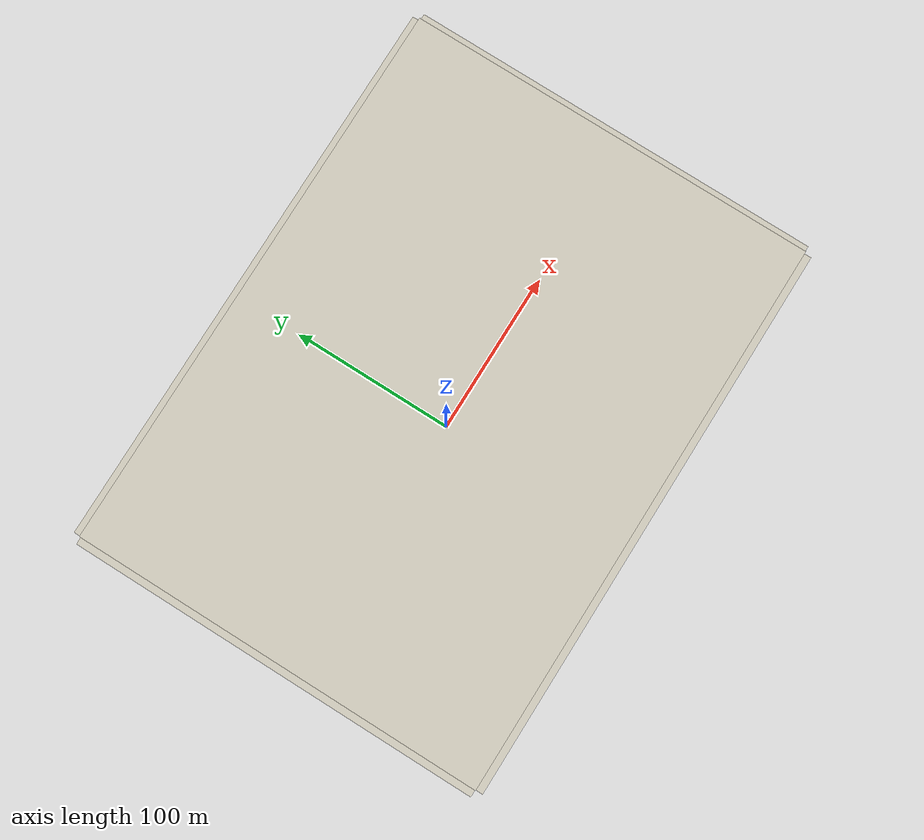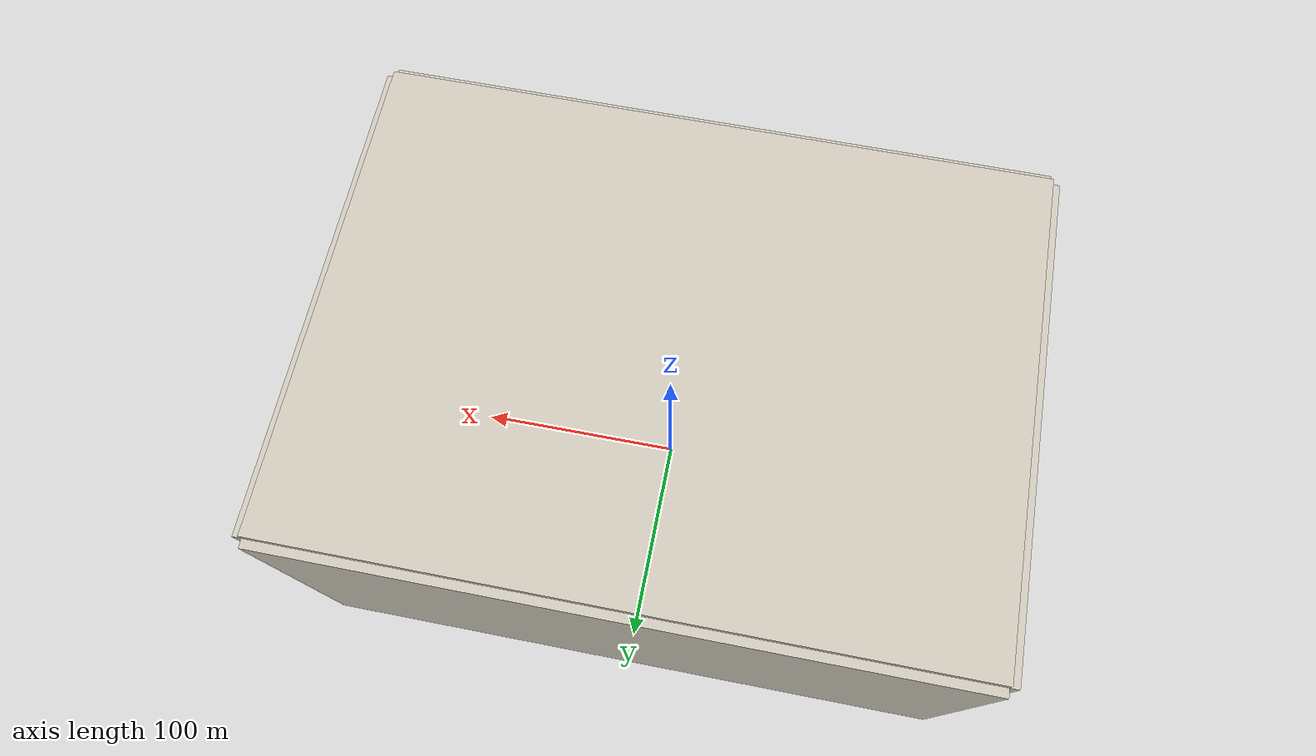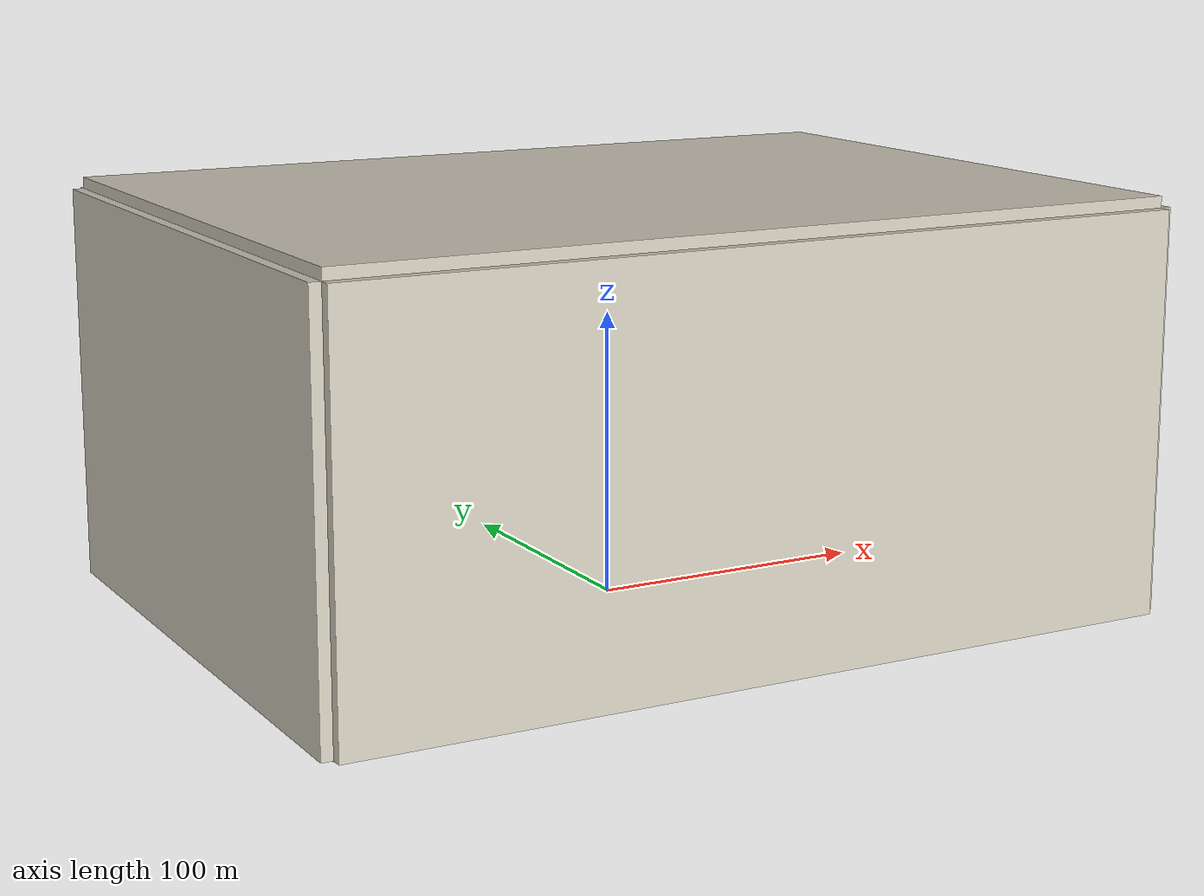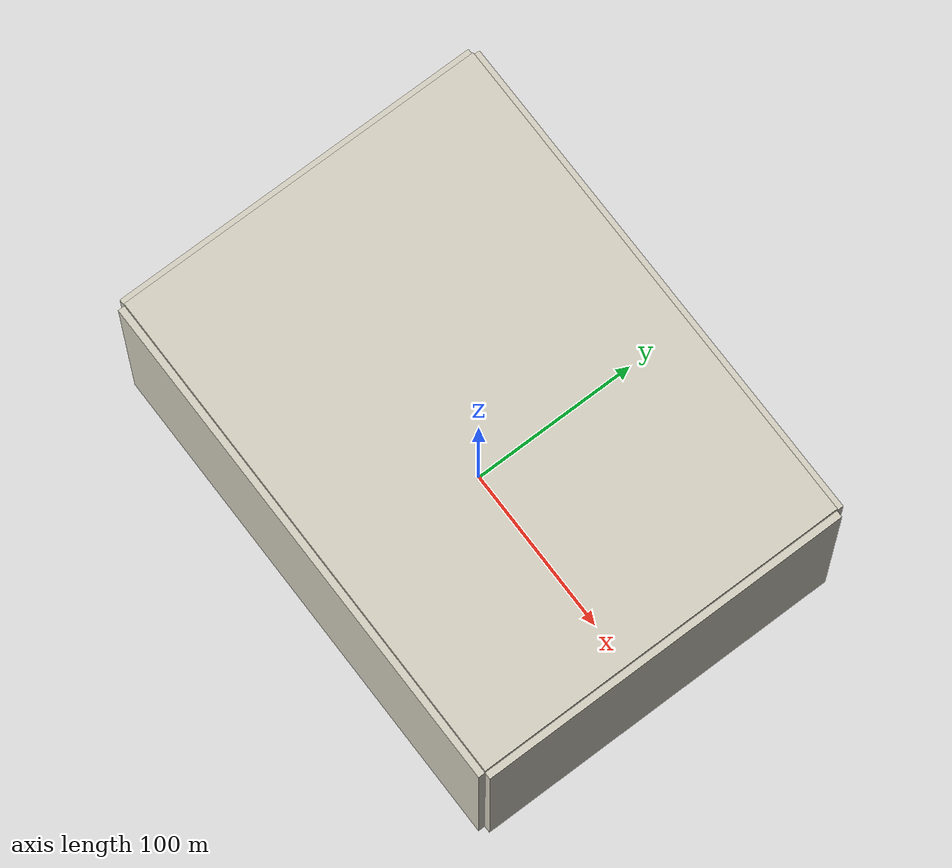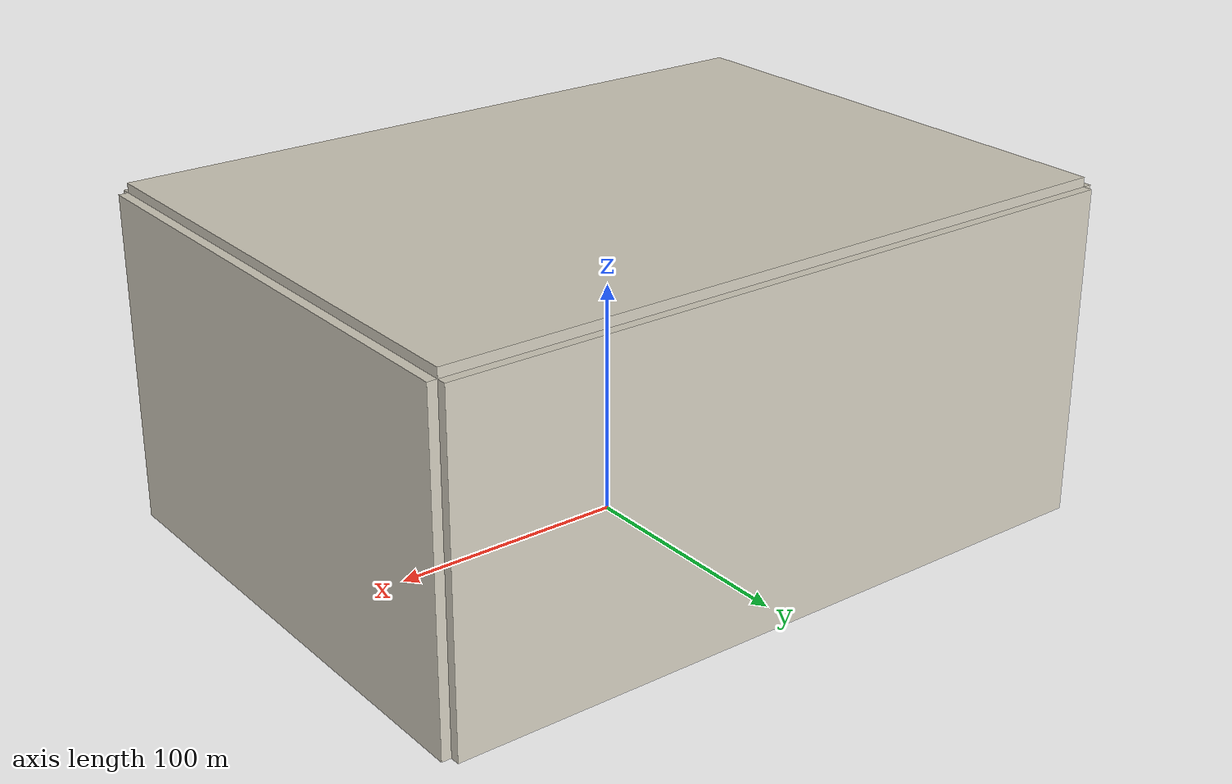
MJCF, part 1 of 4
<mujoco model="indoor-v2">
  <compiler angle="radian" boundmass="1e-06" boundinertia="1e-12" />
  <option timestep="0.0001" gravity="0 0 -9810" noslip_iterations="5" density="1.28e-06" viscosity="1.85e-05" ccd_iterations="100" wind="0 0 0">
    <flag energy="enable" />
  </option>
  <size nkey="1" />
  <visual>
    <global offwidth="960" offheight="720" />
    <headlight ambient="0.32 0.32 0.32" diffuse="0.35 0.35 0.35" specular="0.1 0.1 0.1" />
    <map stiffness="1000000" stiffnessrot="5000000" force="1e-05" torque="0.0002" znear="0.0001" zfar="4" />
    <quality shadowsize="4096" offsamples="4" numslices="48" numstacks="24" />
  </visual>
  <statistic extent="350" />
  <default>
    <default class="fly/main" />
  </default>
  <contact>
    <pair geom1="ground_plane" geom2="fly/c_thorax" name="fly/c_thorax-ground_plane-ground" margin="0.001" solref="0.0002" solimp="0.98 0.99 1e-05 0.5 3" friction="1 1 0.02 0.0001 0.0001" />
    <pair geom1="ground_plane" geom2="fly/c_head" name="fly/c_head-ground_plane-ground" margin="0.001" solref="0.0002" solimp="0.98 0.99 1e-05 0.5 3" friction="1 1 0.02 0.0001 0.0001" />
    <pair geom1="ground_plane" geom2="fly/c_abdomen12" name="fly/c_abdomen12-ground_plane-ground" margin="0.001" solref="0.0002" solimp="0.98 0.99 1e-05 0.5 3" friction="1 1 0.02 0.0001 0.0001" />
    <pair geom1="ground_plane" geom2="fly/c_abdomen3" name="fly/c_abdomen3-ground_plane-ground" margin="0.001" solref="0.0002" solimp="0.98 0.99 1e-05 0.5 3" friction="1 1 0.02 0.0001 0.0001" />
    <pair geom1="ground_plane" geom2="fly/c_abdomen4" name="fly/c_abdomen4-ground_plane-ground" margin="0.001" solref="0.0002" solimp="0.98 0.99 1e-05 0.5 3" friction="1 1 0.02 0.0001 0.0001" />
    <pair geom1="ground_plane" geom2="fly/c_abdomen5" name="fly/c_abdomen5-ground_plane-ground" margin="0.001" solref="0.0002" solimp="0.98 0.99 1e-05 0.5 3" friction="1 1 0.02 0.0001 0.0001" />
    <pair geom1="ground_plane" geom2="fly/c_abdomen6" name="fly/c_abdomen6-ground_plane-ground" margin="0.001" solref="0.0002" solimp="0.98 0.99 1e-05 0.5 3" friction="1 1 0.02 0.0001 0.0001" />
    <pair geom1="ground_plane" geom2="fly/lf_coxa" name="fly/lf_coxa-ground_plane-ground" margin="0.001" solref="0.0002" solimp="0.98 0.99 1e-05 0.5 3" friction="1 1 0.02 0.0001 0.0001" />
    <pair geom1="ground_plane" geom2="fly/lf_trochanterfemur" name="fly/lf_trochanterfemur-ground_plane-ground" margin="0.001" solref="0.0002" solimp="0.98 0.99 1e-05 0.5 3" friction="1 1 0.02 0.0001 0.0001" />
    <pair geom1="ground_plane" geom2="fly/lf_tibia" name="fly/lf_tibia-ground_plane-ground" margin="0.001" solref="0.0002" solimp="0.98 0.99 1e-05 0.5 3" friction="1 1 0.02 0.0001 0.0001" />
    <pair geom1="ground_plane" geom2="fly/lf_tarsus1" name="fly/lf_tarsus1-ground_plane-ground" margin="0.001" solref="0.0002" solimp="0.98 0.99 1e-05 0.5 3" friction="1 1 0.02 0.0001 0.0001" />
    <pair geom1="ground_plane" geom2="fly/lf_tarsus2" name="fly/lf_tarsus2-ground_plane-ground" margin="0.001" solref="0.0002" solimp="0.98 0.99 1e-05 0.5 3" friction="1 1 0.02 0.0001 0.0001" />
    <pair geom1="ground_plane" geom2="fly/lf_tarsus3" name="fly/lf_tarsus3-ground_plane-ground" margin="0.001" solref="0.0002" solimp="0.98 0.99 1e-05 0.5 3" friction="1 1 0.02 0.0001 0.0001" />
    <pair geom1="ground_plane" geom2="fly/lf_tarsus4" name="fly/lf_tarsus4-ground_plane-ground" margin="0.001" solref="0.0002" solimp="0.98 0.99 1e-05 0.5 3" friction="1 1 0.02 0.0001 0.0001" />
    <pair geom1="ground_plane" geom2="fly/lf_tarsus5" name="fly/lf_tarsus5-ground_plane-ground" margin="0.001" solref="0.0002" solimp="0.98 0.99 1e-05 0.5 3" friction="1 1 0.02 0.0001 0.0001" />
    <pair geom1="ground_plane" geom2="fly/lm_coxa" name="fly/lm_coxa-ground_plane-ground" margin="0.001" solref="0.0002" solimp="0.98 0.99 1e-05 0.5 3" friction="1 1 0.02 0.0001 0.0001" />
    <pair geom1="ground_plane" geom2="fly/lm_trochanterfemur" name="fly/lm_trochanterfemur-ground_plane-ground" margin="0.001" solref="0.0002" solimp="0.98 0.99 1e-05 0.5 3" friction="1 1 0.02 0.0001 0.0001" />
    <pair geom1="ground_plane" geom2="fly/lm_tibia" name="fly/lm_tibia-ground_plane-ground" margin="0.001" solref="0.0002" solimp="0.98 0.99 1e-05 0.5 3" friction="1 1 0.02 0.0001 0.0001" />
    <pair geom1="ground_plane" geom2="fly/lm_tarsus1" name="fly/lm_tarsus1-ground_plane-ground" margin="0.001" solref="0.0002" solimp="0.98 0.99 1e-05 0.5 3" friction="1 1 0.02 0.0001 0.0001" />
    <pair geom1="ground_plane" geom2="fly/lm_tarsus2" name="fly/lm_tarsus2-ground_plane-ground" margin="0.001" solref="0.0002" solimp="0.98 0.99 1e-05 0.5 3" friction="1 1 0.02 0.0001 0.0001" />
    <pair geom1="ground_plane" geom2="fly/lm_tarsus3" name="fly/lm_tarsus3-ground_plane-ground" margin="0.001" solref="0.0002" solimp="0.98 0.99 1e-05 0.5 3" friction="1 1 0.02 0.0001 0.0001" />
    <pair geom1="ground_plane" geom2="fly/lm_tarsus4" name="fly/lm_tarsus4-ground_plane-ground" margin="0.001" solref="0.0002" solimp="0.98 0.99 1e-05 0.5 3" friction="1 1 0.02 0.0001 0.0001" />
    <pair geom1="ground_plane" geom2="fly/lm_tarsus5" name="fly/lm_tarsus5-ground_plane-ground" margin="0.001" solref="0.0002" solimp="0.98 0.99 1e-05 0.5 3" friction="1 1 0.02 0.0001 0.0001" />
    <pair geom1="ground_plane" geom2="fly/lh_coxa" name="fly/lh_coxa-ground_plane-ground" margin="0.001" solref="0.0002" solimp="0.98 0.99 1e-05 0.5 3" friction="1 1 0.02 0.0001 0.0001" />
    <pair geom1="ground_plane" geom2="fly/lh_trochanterfemur" name="fly/lh_trochanterfemur-ground_plane-ground" margin="0.001" solref="0.0002" solimp="0.98 0.99 1e-05 0.5 3" friction="1 1 0.02 0.0001 0.0001" />
    <pair geom1="ground_plane" geom2="fly/lh_tibia" name="fly/lh_tibia-ground_plane-ground" margin="0.001" solref="0.0002" solimp="0.98 0.99 1e-05 0.5 3" friction="1 1 0.02 0.0001 0.0001" />
    <pair geom1="ground_plane" geom2="fly/lh_tarsus1" name="fly/lh_tarsus1-ground_plane-ground" margin="0.001" solref="0.0002" solimp="0.98 0.99 1e-05 0.5 3" friction="1 1 0.02 0.0001 0.0001" />
    <pair geom1="ground_plane" geom2="fly/lh_tarsus2" name="fly/lh_tarsus2-ground_plane-ground" margin="0.001" solref="0.0002" solimp="0.98 0.99 1e-05 0.5 3" friction="1 1 0.02 0.0001 0.0001" />
    <pair geom1="ground_plane" geom2="fly/lh_tarsus3" name="fly/lh_tarsus3-ground_plane-ground" margin="0.001" solref="0.0002" solimp="0.98 0.99 1e-05 0.5 3" friction="1 1 0.02 0.0001 0.0001" />
    <pair geom1="ground_plane" geom2="fly/lh_tarsus4" name="fly/lh_tarsus4-ground_plane-ground" margin="0.001" solref="0.0002" solimp="0.98 0.99 1e-05 0.5 3" friction="1 1 0.02 0.0001 0.0001" />
    <pair geom1="ground_plane" geom2="fly/lh_tarsus5" name="fly/lh_tarsus5-ground_plane-ground" margin="0.001" solref="0.0002" solimp="0.98 0.99 1e-05 0.5 3" friction="1 1 0.02 0.0001 0.0001" />
    <pair geom1="ground_plane" geom2="fly/rf_coxa" name="fly/rf_coxa-ground_plane-ground" margin="0.001" solref="0.0002" solimp="0.98 0.99 1e-05 0.5 3" friction="1 1 0.02 0.0001 0.0001" />
    <pair geom1="ground_plane" geom2="fly/rf_trochanterfemur" name="fly/rf_trochanterfemur-ground_plane-ground" margin="0.001" solref="0.0002" solimp="0.98 0.99 1e-05 0.5 3" friction="1 1 0.02 0.0001 0.0001" />
    <pair geom1="ground_plane" geom2="fly/rf_tibia" name="fly/rf_tibia-ground_plane-ground" margin="0.001" solref="0.0002" solimp="0.98 0.99 1e-05 0.5 3" friction="1 1 0.02 0.0001 0.0001" />
    <pair geom1="ground_plane" geom2="fly/rf_tarsus1" name="fly/rf_tarsus1-ground_plane-ground" margin="0.001" solref="0.0002" solimp="0.98 0.99 1e-05 0.5 3" friction="1 1 0.02 0.0001 0.0001" />
    <pair geom1="ground_plane" geom2="fly/rf_tarsus2" name="fly/rf_tarsus2-ground_plane-ground" margin="0.001" solref="0.0002" solimp="0.98 0.99 1e-05 0.5 3" friction="1 1 0.02 0.0001 0.0001" />
    <pair geom1="ground_plane" geom2="fly/rf_tarsus3" name="fly/rf_tarsus3-ground_plane-ground" margin="0.001" solref="0.0002" solimp="0.98 0.99 1e-05 0.5 3" friction="1 1 0.02 0.0001 0.0001" />
    <pair geom1="ground_plane" geom2="fly/rf_tarsus4" name="fly/rf_tarsus4-ground_plane-ground" margin="0.001" solref="0.0002" solimp="0.98 0.99 1e-05 0.5 3" friction="1 1 0.02 0.0001 0.0001" />
    <pair geom1="ground_plane" geom2="fly/rf_tarsus5" name="fly/rf_tarsus5-ground_plane-ground" margin="0.001" solref="0.0002" solimp="0.98 0.99 1e-05 0.5 3" friction="1 1 0.02 0.0001 0.0001" />
    <pair geom1="ground_plane" geom2="fly/rm_coxa" name="fly/rm_coxa-ground_plane-ground" margin="0.001" solref="0.0002" solimp="0.98 0.99 1e-05 0.5 3" friction="1 1 0.02 0.0001 0.0001" />
    <pair geom1="ground_plane" geom2="fly/rm_trochanterfemur" name="fly/rm_trochanterfemur-ground_plane-ground" margin="0.001" solref="0.0002" solimp="0.98 0.99 1e-05 0.5 3" friction="1 1 0.02 0.0001 0.0001" />
    <pair geom1="ground_plane" geom2="fly/rm_tibia" name="fly/rm_tibia-ground_plane-ground" margin="0.001" solref="0.0002" solimp="0.98 0.99 1e-05 0.5 3" friction="1 1 0.02 0.0001 0.0001" />
    <pair geom1="ground_plane" geom2="fly/rm_tarsus1" name="fly/rm_tarsus1-ground_plane-ground" margin="0.001" solref="0.0002" solimp="0.98 0.99 1e-05 0.5 3" friction="1 1 0.02 0.0001 0.0001" />
    <pair geom1="ground_plane" geom2="fly/rm_tarsus2" name="fly/rm_tarsus2-ground_plane-ground" margin="0.001" solref="0.0002" solimp="0.98 0.99 1e-05 0.5 3" friction="1 1 0.02 0.0001 0.0001" />
    <pair geom1="ground_plane" geom2="fly/rm_tarsus3" name="fly/rm_tarsus3-ground_plane-ground" margin="0.001" solref="0.0002" solimp="0.98 0.99 1e-05 0.5 3" friction="1 1 0.02 0.0001 0.0001" />
    <pair geom1="ground_plane" geom2="fly/rm_tarsus4" name="fly/rm_tarsus4-ground_plane-ground" margin="0.001" solref="0.0002" solimp="0.98 0.99 1e-05 0.5 3" friction="1 1 0.02 0.0001 0.0001" />
    <pair geom1="ground_plane" geom2="fly/rm_tarsus5" name="fly/rm_tarsus5-ground_plane-ground" margin="0.001" solref="0.0002" solimp="0.98 0.99 1e-05 0.5 3" friction="1 1 0.02 0.0001 0.0001" />
    <pair geom1="ground_plane" geom2="fly/rh_coxa" name="fly/rh_coxa-ground_plane-ground" margin="0.001" solref="0.0002" solimp="0.98 0.99 1e-05 0.5 3" friction="1 1 0.02 0.0001 0.0001" />
    <pair geom1="ground_plane" geom2="fly/rh_trochanterfemur" name="fly/rh_trochanterfemur-ground_plane-ground" margin="0.001" solref="0.0002" solimp="0.98 0.99 1e-05 0.5 3" friction="1 1 0.02 0.0001 0.0001" />
    <pair geom1="ground_plane" geom2="fly/rh_tibia" name="fly/rh_tibia-ground_plane-ground" margin="0.001" solref="0.0002" solimp="0.98 0.99 1e-05 0.5 3" friction="1 1 0.02 0.0001 0.0001" />
    <pair geom1="ground_plane" geom2="fly/rh_tarsus1" name="fly/rh_tarsus1-ground_plane-ground" margin="0.001" solref="0.0002" solimp="0.98 0.99 1e-05 0.5 3" friction="1 1 0.02 0.0001 0.0001" />
    <pair geom1="ground_plane" geom2="fly/rh_tarsus2" name="fly/rh_tarsus2-ground_plane-ground" margin="0.001" solref="0.0002" solimp="0.98 0.99 1e-05 0.5 3" friction="1 1 0.02 0.0001 0.0001" />
    <pair geom1="ground_plane" geom2="fly/rh_tarsus3" name="fly/rh_tarsus3-ground_plane-ground" margin="0.001" solref="0.0002" solimp="0.98 0.99 1e-05 0.5 3" friction="1 1 0.02 0.0001 0.0001" />
    <pair geom1="ground_plane" geom2="fly/rh_tarsus4" name="fly/rh_tarsus4-ground_plane-ground" margin="0.001" solref="0.0002" solimp="0.98 0.99 1e-05 0.5 3" friction="1 1 0.02 0.0001 0.0001" />
    <pair geom1="ground_plane" geom2="fly/rh_tarsus5" name="fly/rh_tarsus5-ground_plane-ground" margin="0.001" solref="0.0002" solimp="0.98 0.99 1e-05 0.5 3" friction="1 1 0.02 0.0001 0.0001" />
  </contact>
  <actuator>
    <general name="fly/c_thorax-lf_coxa-yaw-position" joint="fly/c_thorax-lf_coxa-yaw" ctrlrange="-3.14 3.14" forcelimited="true" forcerange="-30 30" biastype="affine" gainprm="50" biasprm="0 -50" />
    <general name="fly/c_thorax-lf_coxa-pitch-position" joint="fly/c_thorax-lf_coxa-pitch" ctrlrange="-3.14 3.14" forcelimited="true" forcerange="-30 30" biastype="affine" gainprm="50" biasprm="0 -50" />
    <general name="fly/c_thorax-lf_coxa-roll-position" joint="fly/c_thorax-lf_coxa-roll" ctrlrange="-3.14 3.14" forcelimited="true" forcerange="-30 30" biastype="affine" gainprm="50" biasprm="0 -50" />
    <general name="fly/lf_coxa-lf_trochanterfemur-pitch-position" joint="fly/lf_coxa-lf_trochanterfemur-pitch" ctrlrange="-3.14 3.14" forcelimited="true" forcerange="-30 30" biastype="affine" gainprm="50" biasprm="0 -50" />
    <general name="fly/lf_coxa-lf_trochanterfemur-roll-position" joint="fly/lf_coxa-lf_trochanterfemur-roll" ctrlrange="-3.14 3.14" forcelimited="true" forcerange="-30 30" biastype="affine" gainprm="50" biasprm="0 -50" />
    <general name="fly/lf_trochanterfemur-lf_tibia-pitch-position" joint="fly/lf_trochanterfemur-lf_tibia-pitch" ctrlrange="-3.14 3.14" forcelimited="true" forcerange="-30 30" biastype="affine" gainprm="50" biasprm="0 -50" />
    <general name="fly/lf_tibia-lf_tarsus1-pitch-position" joint="fly/lf_tibia-lf_tarsus1-pitch" ctrlrange="-3.14 3.14" forcelimited="true" forcerange="-30 30" biastype="affine" gainprm="50" biasprm="0 -50" />
    <general name="fly/c_thorax-lm_coxa-yaw-position" joint="fly/c_thorax-lm_coxa-yaw" ctrlrange="-3.14 3.14" forcelimited="true" forcerange="-30 30" biastype="affine" gainprm="50" biasprm="0 -50" />
    <general name="fly/c_thorax-lm_coxa-pitch-position" joint="fly/c_thorax-lm_coxa-pitch" ctrlrange="-3.14 3.14" forcelimited="true" forcerange="-30 30" biastype="affine" gainprm="50" biasprm="0 -50" />
    <general name="fly/c_thorax-lm_coxa-roll-position" joint="fly/c_thorax-lm_coxa-roll" ctrlrange="-3.14 3.14" forcelimited="true" forcerange="-30 30" biastype="affine" gainprm="50" biasprm="0 -50" />
    <general name="fly/lm_coxa-lm_trochanterfemur-pitch-position" joint="fly/lm_coxa-lm_trochanterfemur-pitch" ctrlrange="-3.14 3.14" forcelimited="true" forcerange="-30 30" biastype="affine" gainprm="50" biasprm="0 -50" />
    <general name="fly/lm_coxa-lm_trochanterfemur-roll-position" joint="fly/lm_coxa-lm_trochanterfemur-roll" ctrlrange="-3.14 3.14" forcelimited="true" forcerange="-30 30" biastype="affine" gainprm="50" biasprm="0 -50" />
    <general name="fly/lm_trochanterfemur-lm_tibia-pitch-position" joint="fly/lm_trochanterfemur-lm_tibia-pitch" ctrlrange="-3.14 3.14" forcelimited="true" forcerange="-30 30" biastype="affine" gainprm="50" biasprm="0 -50" />
    <general name="fly/lm_tibia-lm_tarsus1-pitch-position" joint="fly/lm_tibia-lm_tarsus1-pitch" ctrlrange="-3.14 3.14" forcelimited="true" forcerange="-30 30" biastype="affine" gainprm="50" biasprm="0 -50" />
    <general name="fly/c_thorax-lh_coxa-yaw-position" joint="fly/c_thorax-lh_coxa-yaw" ctrlrange="-3.14 3.14" forcelimited="true" forcerange="-30 30" biastype="affine" gainprm="50" biasprm="0 -50" />
    <general name="fly/c_thorax-lh_coxa-pitch-position" joint="fly/c_thorax-lh_coxa-pitch" ctrlrange="-3.14 3.14" forcelimited="true" forcerange="-30 30" biastype="affine" gainprm="50" biasprm="0 -50" />
    <general name="fly/c_thorax-lh_coxa-roll-position" joint="fly/c_thorax-lh_coxa-roll" ctrlrange="-3.14 3.14" forcelimited="true" forcerange="-30 30" biastype="affine" gainprm="50" biasprm="0 -50" />
    <general name="fly/lh_coxa-lh_trochanterfemur-pitch-position" joint="fly/lh_coxa-lh_trochanterfemur-pitch" ctrlrange="-3.14 3.14" forcelimited="true" forcerange="-30 30" biastype="affine" gainprm="50" biasprm="0 -50" />
    <general name="fly/lh_coxa-lh_trochanterfemur-roll-position" joint="fly/lh_coxa-lh_trochanterfemur-roll" ctrlrange="-3.14 3.14" forcelimited="true" forcerange="-30 30" biastype="affine" gainprm="50" biasprm="0 -50" />
    <general name="fly/lh_trochanterfemur-lh_tibia-pitch-position" joint="fly/lh_trochanterfemur-lh_tibia-pitch" ctrlrange="-3.14 3.14" forcelimited="true" forcerange="-30 30" biastype="affine" gainprm="50" biasprm="0 -50" />
    <general name="fly/lh_tibia-lh_tarsus1-pitch-position" joint="fly/lh_tibia-lh_tarsus1-pitch" ctrlrange="-3.14 3.14" forcelimited="true" forcerange="-30 30" biastype="affine" gainprm="50" biasprm="0 -50" />
    <general name="fly/c_thorax-rf_coxa-yaw-position" joint="fly/c_thorax-rf_coxa-yaw" ctrlrange="-3.14 3.14" forcelimited="true" forcerange="-30 30" biastype="affine" gainprm="50" biasprm="0 -50" />
    <general name="fly/c_thorax-rf_coxa-pitch-position" joint="fly/c_thorax-rf_coxa-pitch" ctrlrange="-3.14 3.14" forcelimited="true" forcerange="-30 30" biastype="affine" gainprm="50" biasprm="0 -50" />
    <general name="fly/c_thorax-rf_coxa-roll-position" joint="fly/c_thorax-rf_coxa-roll" ctrlrange="-3.14 3.14" forcelimited="true" forcerange="-30 30" biastype="affine" gainprm="50" biasprm="0 -50" />
    <general name="fly/rf_coxa-rf_trochanterfemur-pitch-position" joint="fly/rf_coxa-rf_trochanterfemur-pitch" ctrlrange="-3.14 3.14" forcelimited="true" forcerange="-30 30" biastype="affine" gainprm="50" biasprm="0 -50" />
    <general name="fly/rf_coxa-rf_trochanterfemur-roll-position" joint="fly/rf_coxa-rf_trochanterfemur-roll" ctrlrange="-3.14 3.14" forcelimited="true" forcerange="-30 30" biastype="affine" gainprm="50" biasprm="0 -50" />
    <general name="fly/rf_trochanterfemur-rf_tibia-pitch-position" joint="fly/rf_trochanterfemur-rf_tibia-pitch" ctrlrange="-3.14 3.14" forcelimited="true" forcerange="-30 30" biastype="affine" gainprm="50" biasprm="0 -50" />
    <general name="fly/rf_tibia-rf_tarsus1-pitch-position" joint="fly/rf_tibia-rf_tarsus1-pitch" ctrlrange="-3.14 3.14" forcelimited="true" forcerange="-30 30" biastype="affine" gainprm="50" biasprm="0 -50" />
    <general name="fly/c_thorax-rm_coxa-yaw-position" joint="fly/c_thorax-rm_coxa-yaw" ctrlrange="-3.14 3.14" forcelimited="true" forcerange="-30 30" biastype="affine" gainprm="50" biasprm="0 -50" />
    <general name="fly/c_thorax-rm_coxa-pitch-position" joint="fly/c_thorax-rm_coxa-pitch" ctrlrange="-3.14 3.14" forcelimited="true" forcerange="-30 30" biastype="affine" gainprm="50" biasprm="0 -50" />
    <general name="fly/c_thorax-rm_coxa-roll-position" joint="fly/c_thorax-rm_coxa-roll" ctrlrange="-3.14 3.14" forcelimited="true" forcerange="-30 30" biastype="affine" gainprm="50" biasprm="0 -50" />
    <general name="fly/rm_coxa-rm_trochanterfemur-pitch-position" joint="fly/rm_coxa-rm_trochanterfemur-pitch" ctrlrange="-3.14 3.14" forcelimited="true" forcerange="-30 30" biastype="affine" gainprm="50" biasprm="0 -50" />
    <general name="fly/rm_coxa-rm_trochanterfemur-roll-position" joint="fly/rm_coxa-rm_trochanterfemur-roll" ctrlrange="-3.14 3.14" forcelimited="true" forcerange="-30 30" biastype="affine" gainprm="50" biasprm="0 -50" />
    <general name="fly/rm_trochanterfemur-rm_tibia-pitch-position" joint="fly/rm_trochanterfemur-rm_tibia-pitch" ctrlrange="-3.14 3.14" forcelimited="true" forcerange="-30 30" biastype="affine" gainprm="50" biasprm="0 -50" />
    <general name="fly/rm_tibia-rm_tarsus1-pitch-position" joint="fly/rm_tibia-rm_tarsus1-pitch" ctrlrange="-3.14 3.14" forcelimited="true" forcerange="-30 30" biastype="affine" gainprm="50" biasprm="0 -50" />
    <general name="fly/c_thorax-rh_coxa-yaw-position" joint="fly/c_thorax-rh_coxa-yaw" ctrlrange="-3.14 3.14" forcelimited="true" forcerange="-30 30" biastype="affine" gainprm="50" biasprm="0 -50" />
    <general name="fly/c_thorax-rh_coxa-pitch-position" joint="fly/c_thorax-rh_coxa-pitch" ctrlrange="-3.14 3.14" forcelimited="true" forcerange="-30 30" biastype="affine" gainprm="50" biasprm="0 -50" />
    <general name="fly/c_thorax-rh_coxa-roll-position" joint="fly/c_thorax-rh_coxa-roll" ctrlrange="-3.14 3.14" forcelimited="true" forcerange="-30 30" biastype="affine" gainprm="50" biasprm="0 -50" />
    <general name="fly/rh_coxa-rh_trochanterfemur-pitch-position" joint="fly/rh_coxa-rh_trochanterfemur-pitch" ctrlrange="-3.14 3.14" forcelimited="true" forcerange="-30 30" biastype="affine" gainprm="50" biasprm="0 -50" />
    <general name="fly/rh_coxa-rh_trochanterfemur-roll-position" joint="fly/rh_coxa-rh_trochanterfemur-roll" ctrlrange="-3.14 3.14" forcelimited="true" forcerange="-30 30" biastype="affine" gainprm="50" biasprm="0 -50" />
    <general name="fly/rh_trochanterfemur-rh_tibia-pitch-position" joint="fly/rh_trochanterfemur-rh_tibia-pitch" ctrlrange="-3.14 3.14" forcelimited="true" forcerange="-30 30" biastype="affine" gainprm="50" biasprm="0 -50" />
    <general name="fly/rh_tibia-rh_tarsus1-pitch-position" joint="fly/rh_tibia-rh_tarsus1-pitch" ctrlrange="-3.14 3.14" forcelimited="true" forcerange="-30 30" biastype="affine" gainprm="50" biasprm="0 -50" />
    <general name="fly/lf_tarsus5-adhesion" body="fly/lf_tarsus5" ctrllimited="true" ctrlrange="0 1" gainprm="20" />
    <general name="fly/lm_tarsus5-adhesion" body="fly/lm_tarsus5" ctrllimited="true" ctrlrange="0 1" gainprm="20" />
    <general name="fly/lh_tarsus5-adhesion" body="fly/lh_tarsus5" ctrllimited="true" ctrlrange="0 1" gainprm="20" />
    <general name="fly/rf_tarsus5-adhesion" body="fly/rf_tarsus5" ctrllimited="true" ctrlrange="0 1" gainprm="20" />
    <general name="fly/rm_tarsus5-adhesion" body="fly/rm_tarsus5" ctrllimited="true" ctrlrange="0 1" gainprm="20" />
    <general name="fly/rh_tarsus5-adhesion" body="fly/rh_tarsus5" ctrllimited="true" ctrlrange="0 1" gainprm="20" />
    <general name="fly/c_head-c_rostrum-pitch-feeding-position" joint="fly/c_head-c_rostrum-pitch" ctrlrange="-1.0 0.0" forcelimited="true" forcerange="-30 30" biastype="affine" gainprm="27.0" biasprm="0 -30.0" />
    <general name="fly/c_rostrum-c_haustellum-pitch-feeding-position" joint="fly/c_rostrum-c_haustellum-pitch" ctrlrange="-1.0 0.0" forcelimited="true" forcerange="-30 30" biastype="affine" gainprm="-19.5" biasprm="0 -30.0" />
    <general name="fly/c_thorax-l_wing-yaw-flight-position" joint="fly/c_thorax-l_wing-yaw" ctrllimited="true" ctrlrange="-1.5 1.5" biastype="affine" gainprm="1800.0" biasprm="0 -1800.0" />
    <general name="fly/c_thorax-l_wing-pitch-flight-position" joint="fly/c_thorax-l_wing-pitch" ctrllimited="true" ctrlrange="-1.27 2.92" biastype="affine" gainprm="1800.0" biasprm="0 -1800.0" />
    <general name="fly/c_thorax-l_wing-roll-flight-position" joint="fly/c_thorax-l_wing-roll" ctrllimited="true" ctrlrange="-1.0 1.5" biastype="affine" gainprm="1800.0" biasprm="0 -1800.0" />
    <general name="fly/c_thorax-r_wing-yaw-flight-position" joint="fly/c_thorax-r_wing-yaw" ctrllimited="true" ctrlrange="-1.5 1.5" biastype="affine" gainprm="1800.0" biasprm="0 -1800.0" />
    <general name="fly/c_thorax-r_wing-pitch-flight-position" joint="fly/c_thorax-r_wing-pitch" ctrllimited="true" ctrlrange="-1.27 2.92" biastype="affine" gainprm="1800.0" biasprm="0 -1800.0" />
    <general name="fly/c_thorax-r_wing-roll-flight-position" joint="fly/c_thorax-r_wing-roll" ctrllimited="true" ctrlrange="-1.0 1.5" biastype="affine" gainprm="1800.0" biasprm="0 -1800.0" />
  </actuator>
  <sensor>
    <contact subtree1="fly/lf_coxa" geom2="ground_plane" data="found force torque pos normal tangent" reduce="netforce" name="ground_contact_lf_leg" />
    <contact subtree1="fly/lm_coxa" geom2="ground_plane" data="found force torque pos normal tangent" reduce="netforce" name="ground_contact_lm_leg" />
    <contact subtree1="fly/lh_coxa" geom2="ground_plane" data="found force torque pos normal tangent" reduce="netforce" name="ground_contact_lh_leg" />
    <contact subtree1="fly/rf_coxa" geom2="ground_plane" data="found force torque pos normal tangent" reduce="netforce" name="ground_contact_rf_leg" />
    <contact subtree1="fly/rm_coxa" geom2="ground_plane" data="found force torque pos normal tangent" reduce="netforce" name="ground_contact_rm_leg" />
    <contact subtree1="fly/rh_coxa" geom2="ground_plane" data="found force torque pos normal tangent" reduce="netforce" name="ground_contact_rh_leg" />
  </sensor>
  <keyframe>
    <key name="neutral" qpos="0.496 0 2.1 1 0 0 0 0 0 0 0 0 0 0 0 0 0 0 0 0 0 0 0 0 0 0 0 0 0 0 0 0 0 0 0 0 0 0 0 0 0 0 0 0 0 0 0 0 0 0 0 0 0 0 0 0 0 0 0 0 0 0 0 0 0 0 0 -0.296706 0.331613 0.575959 -2.42601 -0.261799 1.36136 -0.174533 -0.0872665 -0.0872665 -0.0872665 -0.0872665 -0.174533 0.139626 1.51844 -2.42601 0.261799 1.79769 -0.349066 -0.0872665 -0.0872665 -0.0872665 -0.0872665 0.0523599 0.418879 2.33874 -1.93732 0.0698132 1.76278 -0.0872665 -0.0872665 -0.0872665 -0.0872665 -0.0872665 -0.296706 0.331613 0.575959 -2.42601 -0.261799 1.36136 -0.174533 -0.0872665 -0.0872665 -0.0872665 -0.0872665 -0.174533 0.139626 1.51844 -2.42601 0.261799 1.79769 -0.349066 -0.0872665 -0.0872665 -0.0872665 -0.0872665 0.0523599 0.418879 2.33874 -1.93732 0.0698132 1.76278 -0.0872665 -0.0872665 -0.0872665 -0.0872665 -0.0872665" ctrl="-0.296706 0.331613 0.575959 -2.42601 -0.261799 1.36136 -0.174533 -0.174533 0.139626 1.51844 -2.42601 0.261799 1.79769 -0.349066 0.0523599 0.418879 2.33874 -1.93732 0.0698132 1.76278 -0.0872665 -0.296706 0.331613 0.575959 -2.42601 -0.261799 1.36136 -0.174533 -0.174533 0.139626 1.51844 -2.42601 0.261799 1.79769 -0.349066 0.0523599 0.418879 2.33874 -1.93732 0.0698132 1.76278 -0.0872665 0 0 0 0 0 0" />
  </keyframe>
  <asset>
    <texture type="cube" colorspace="auto" name="fly/headthorax" builtin="flat" mark="random" rgb1="0.38 0.20 0.065" rgb2="0.58 0.34 0.12" markrgb="0.46 0.25 0.08" random="0.06" width="50" height="300" />
    <texture type="cube" colorspace="auto" name="fly/antennaproboscis" builtin="flat" mark="random" rgb1="0.25 0.11 0.035" rgb2="0.43 0.22 0.07" random="0.035" width="50" height="300" markrgb="0.25 0.11 0.035" />
    <texture type="cube" colorspace="auto" name="fly/abdomen12345" builtin="gradient" mark="random" rgb1="0.36 0.16 0.045" rgb2="0.70 0.42 0.14" markrgb="0.48 0.24 0.07" random="0.055" width="50" height="300" />
    <texture type="cube" colorspace="auto" name="fly/abdomen6" builtin="gradient" mark="random" rgb1="0.24 0.085 0.022" rgb2="0.56 0.29 0.085" markrgb="0.34 0.15 0.04" random="0.05" width="50" height="300" />
    <texture type="cube" colorspace="auto" name="fly/coxa" builtin="flat" mark="random" rgb1="0.33 0.16 0.045" rgb2="0.53 0.29 0.09" random="0.035" width="50" height="300" markrgb="0.33 0.16 0.045" />
    <texture type="cube" colorspace="auto" name="fly/trochanterfemur" builtin="flat" mark="random" rgb1="0.38 0.19 0.055" rgb2="0.57 0.31 0.10" random="0.035" width="50" height="300" markrgb="0.38 0.19 0.055" />
    <texture type="cube" colorspace="auto" name="fly/tibia" builtin="flat" mark="random" rgb1="0.42 0.21 0.065" rgb2="0.62 0.36 0.12" random="0.035" width="50" height="300" markrgb="0.42 0.21 0.065" />
    <texture type="cube" colorspace="auto" name="fly/tarsus" builtin="flat" mark="random" rgb1="0.34 0.15 0.04" rgb2="0.52 0.27 0.08" random="0.035" width="50" height="300" markrgb="0.34 0.15 0.04" />
    <material name="fly/wing" specular="0.15" shininess="0.25" rgba="0.56 0.62 0.65 0.30" />
    <material name="fly/eye" specular="0.15" shininess="0.25" rgba="0.47 0.075 0.045 1" />
    <material name="fly/arista" specular="0.15" shininess="0.25" rgba="0.26 0.2 0.16 1" />
    <material name="fly/haltere" specular="0.15" shininess="0.25" rgba="0.59 0.43 0.24 1" />
    <material name="fly/headthorax" texture="fly/headthorax" specular="0.15" shininess="0.25" />
    <material name="fly/antennaproboscis" texture="fly/antennaproboscis" specular="0.15" shininess="0.25" />
    <material name="fly/abdomen12345" texture="fly/abdomen12345" specular="0.15" shininess="0.25" />
    <material name="fly/abdomen6" texture="fly/abdomen6" specular="0.15" shininess="0.25" />
    <material name="fly/coxa" texture="fly/coxa" specular="0.15" shininess="0.25" />
    <material name="fly/trochanterfemur" texture="fly/trochanterfemur" specular="0.15" shininess="0.25" />
    <material name="fly/tibia" texture="fly/tibia" specular="0.15" shininess="0.25" />
    <material name="fly/tarsus" texture="fly/tarsus" specular="0.15" shininess="0.25" />
    <mesh name="fly/c_thorax" content_type="model/stl" file="c_thorax.stl" scale="1000 1000 1000" smoothnormal="true" />
    <mesh name="fly/c_head" content_type="model/stl" file="c_head.stl" scale="1000 1000 1000" smoothnormal="true" />
    <mesh name="fly/c_rostrum" content_type="model/stl" file="c_rostrum.stl" scale="1000 1000 1000" smoothnormal="true" />
    <mesh name="fly/c_haustellum" content_type="model/stl" file="c_haustellum.stl" scale="1000 1000 1000" smoothnormal="true" />
    <mesh name="fly/c_abdomen12" content_type="model/stl" file="c_abdomen12.stl" scale="1000 1000 1000" smoothnormal="true" />
    <mesh name="fly/c_abdomen3" content_type="model/stl" file="c_abdomen3.stl" scale="1000 1000 1000" smoothnormal="true" />
    <mesh name="fly/c_abdomen4" content_type="model/stl" file="c_abdomen4.stl" scale="1000 1000 1000" smoothnormal="true" />
    <mesh name="fly/c_abdomen5" content_type="model/stl" file="c_abdomen5.stl" scale="1000 1000 1000" smoothnormal="true" />
    <mesh name="fly/c_abdomen6" content_type="model/stl" file="c_abdomen6.stl" scale="1000 1000 1000" smoothnormal="true" />
    <mesh name="fly/l_eye" content_type="model/stl" file="l_eye.stl" scale="1000 1000 1000" smoothnormal="true" />
    <mesh name="fly/r_eye" content_type="model/stl" file="l_eye.stl" scale="1000 -1000 1000" smoothnormal="true" />
    <mesh name="fly/l_pedicel" content_type="model/stl" file="l_pedicel.stl" scale="1000 1000 1000" smoothnormal="true" />
    <mesh name="fly/l_funiculus" content_type="model/stl" file="l_funiculus.stl" scale="1000 1000 1000" smoothnormal="true" />
    <mesh name="fly/l_arista" content_type="model/stl" file="l_arista.stl" scale="1000 1000 1000" smoothnormal="true" />
    <mesh name="fly/r_pedicel" content_type="model/stl" file="l_pedicel.stl" scale="1000 -1000 1000" smoothnormal="true" />
    <mesh name="fly/r_funiculus" content_type="model/stl" file="l_funiculus.stl" scale="1000 -1000 1000" smoothnormal="true" />
    <mesh name="fly/r_arista" content_type="model/stl" file="l_arista.stl" scale="1000 -1000 1000" smoothnormal="true" />
    <mesh name="fly/l_wing" content_type="model/stl" file="l_wing.stl" scale="1000 1000 1000" smoothnormal="true" />
    <mesh name="fly/r_wing" content_type="model/stl" file="l_wing.stl" scale="1000 -1000 1000" smoothnormal="true" />
    <mesh name="fly/l_haltere" content_type="model/stl" file="l_haltere.stl" scale="1000 1000 1000" smoothnormal="true" />
    <mesh name="fly/r_haltere" content_type="model/stl" file="l_haltere.stl" scale="1000 -1000 1000" smoothnormal="true" />
    <mesh name="fly/lf_coxa" content_type="model/stl" file="lf_coxa.stl" scale="1000 1000 1000" smoothnormal="true" />
    <mesh name="fly/lf_trochanterfemur" content_type="model/stl" file="lf_trochanterfemur.stl" scale="1000 1000 1000" smoothnormal="true" />
    <mesh name="fly/lf_tibia" content_type="model/stl" file="lf_tibia.stl" scale="1000 1000 1000" smoothnormal="true" />
    <mesh name="fly/lf_tarsus1" content_type="model/stl" file="lf_tarsus1.stl" scale="1000 1000 1000" smoothnormal="true" />
    <mesh name="fly/lf_tarsus2" content_type="model/stl" file="lf_tarsus2.stl" scale="1000 1000 1000" smoothnormal="true" />
    <mesh name="fly/lf_tarsus3" content_type="model/stl" file="lf_tarsus3.stl" scale="1000 1000 1000" smoothnormal="true" />
    <mesh name="fly/lf_tarsus4" content_type="model/stl" file="lf_tarsus4.stl" scale="1000 1000 1000" smoothnormal="true" />
    <mesh name="fly/lf_tarsus5" content_type="model/stl" file="lf_tarsus5.stl" scale="1000 1000 1000" smoothnormal="true" />
    <mesh name="fly/lm_coxa" content_type="model/stl" file="lm_coxa.stl" scale="1000 1000 1000" smoothnormal="true" />
    <mesh name="fly/lm_trochanterfemur" content_type="model/stl" file="lm_trochanterfemur.stl" scale="1000 1000 1000" smoothnormal="true" />
    <mesh name="fly/lm_tibia" content_type="model/stl" file="lm_tibia.stl" scale="1000 1000 1000" smoothnormal="true" />
    <mesh name="fly/lm_tarsus1" content_type="model/stl" file="lm_tarsus1.stl" scale="1000 1000 1000" smoothnormal="true" />
    <mesh name="fly/lm_tarsus2" content_type="model/stl" file="lm_tarsus2.stl" scale="1000 1000 1000" smoothnormal="true" />
    <mesh name="fly/lm_tarsus3" content_type="model/stl" file="lm_tarsus3.stl" scale="1000 1000 1000" smoothnormal="true" />
    <mesh name="fly/lm_tarsus4" content_type="model/stl" file="lm_tarsus4.stl" scale="1000 1000 1000" smoothnormal="true" />
    <mesh name="fly/lm_tarsus5" content_type="model/stl" file="lm_tarsus5.stl" scale="1000 1000 1000" smoothnormal="true" />
    <mesh name="fly/lh_coxa" content_type="model/stl" file="lh_coxa.stl" scale="1000 1000 1000" smoothnormal="true" />
    <mesh name="fly/lh_trochanterfemur" content_type="model/stl" file="lh_trochanterfemur.stl" scale="1000 1000 1000" smoothnormal="true" />
    <mesh name="fly/lh_tibia" content_type="model/stl" file="lh_tibia.stl" scale="1000 1000 1000" smoothnormal="true" />
    <mesh name="fly/lh_tarsus1" content_type="model/stl" file="lh_tarsus1.stl" scale="1000 1000 1000" smoothnormal="true" />
    <mesh name="fly/lh_tarsus2" content_type="model/stl" file="lh_tarsus2.stl" scale="1000 1000 1000" smoothnormal="true" />
    <mesh name="fly/lh_tarsus3" content_type="model/stl" file="lh_tarsus3.stl" scale="1000 1000 1000" smoothnormal="true" />
    <mesh name="fly/lh_tarsus4" content_type="model/stl" file="lh_tarsus4.stl" scale="1000 1000 1000" smoothnormal="true" />
    <mesh name="fly/lh_tarsus5" content_type="model/stl" file="lh_tarsus5.stl" scale="1000 1000 1000" smoothnormal="true" />
    <mesh name="fly/rf_coxa" content_type="model/stl" file="lf_coxa.stl" scale="1000 -1000 1000" smoothnormal="true" />
    <mesh name="fly/rf_trochanterfemur" content_type="model/stl" file="lf_trochanterfemur.stl" scale="1000 -1000 1000" smoothnormal="true" />
    <mesh name="fly/rf_tibia" content_type="model/stl" file="lf_tibia.stl" scale="1000 -1000 1000" smoothnormal="true" />
    <mesh name="fly/rf_tarsus1" content_type="model/stl" file="lf_tarsus1.stl" scale="1000 -1000 1000" smoothnormal="true" />
    <mesh name="fly/rf_tarsus2" content_type="model/stl" file="lf_tarsus2.stl" scale="1000 -1000 1000" smoothnormal="true" />
    <mesh name="fly/rf_tarsus3" content_type="model/stl" file="lf_tarsus3.stl" scale="1000 -1000 1000" smoothnormal="true" />
    <mesh name="fly/rf_tarsus4" content_type="model/stl" file="lf_tarsus4.stl" scale="1000 -1000 1000" smoothnormal="true" />
    <mesh name="fly/rf_tarsus5" content_type="model/stl" file="lf_tarsus5.stl" scale="1000 -1000 1000" smoothnormal="true" />
    <mesh name="fly/rm_coxa" content_type="model/stl" file="lm_coxa.stl" scale="1000 -1000 1000" smoothnormal="true" />
    <mesh name="fly/rm_trochanterfemur" content_type="model/stl" file="lm_trochanterfemur.stl" scale="1000 -1000 1000" smoothnormal="true" />
    <mesh name="fly/rm_tibia" content_type="model/stl" file="lm_tibia.stl" scale="1000 -1000 1000" smoothnormal="true" />
    <mesh name="fly/rm_tarsus1" content_type="model/stl" file="lm_tarsus1.stl" scale="1000 -1000 1000" smoothnormal="true" />
    <mesh name="fly/rm_tarsus2" content_type="model/stl" file="lm_tarsus2.stl" scale="1000 -1000 1000" smoothnormal="true" />
    <mesh name="fly/rm_tarsus3" content_type="model/stl" file="lm_tarsus3.stl" scale="1000 -1000 1000" smoothnormal="true" />
    <mesh name="fly/rm_tarsus4" content_type="model/stl" file="lm_tarsus4.stl" scale="1000 -1000 1000" smoothnormal="true" />
    <mesh name="fly/rm_tarsus5" content_type="model/stl" file="lm_tarsus5.stl" scale="1000 -1000 1000" smoothnormal="true" />
    <mesh name="fly/rh_coxa" content_type="model/stl" file="lh_coxa.stl" scale="1000 -1000 1000" smoothnormal="true" />
    <mesh name="fly/rh_trochanterfemur" content_type="model/stl" file="lh_trochanterfemur.stl" scale="1000 -1000 1000" smoothnormal="true" />
    <mesh name="fly/rh_tibia" content_type="model/stl" file="lh_tibia.stl" scale="1000 -1000 1000" smoothnormal="true" />
    <mesh name="fly/rh_tarsus1" content_type="model/stl" file="lh_tarsus1.stl" scale="1000 -1000 1000" smoothnormal="true" />
    <mesh name="fly/rh_tarsus2" content_type="model/stl" file="lh_tarsus2.stl" scale="1000 -1000 1000" smoothnormal="true" />
    <mesh name="fly/rh_tarsus3" content_type="model/stl" file="lh_tarsus3.stl" scale="1000 -1000 1000" smoothnormal="true" />
    <mesh name="fly/rh_tarsus4" content_type="model/stl" file="lh_tarsus4.stl" scale="1000 -1000 1000" smoothnormal="true" />
    <mesh name="fly/rh_tarsus5" content_type="model/stl" file="lh_tarsus5.stl" scale="1000 -1000 1000" smoothnormal="true" />
    <material name="fly/detail_bristle" rgba="0.20 0.075 0.022 1" specular="0.15" shininess="0.25" />
    <material name="fly/detail_abdomen_band" rgba="0.12 0.045 0.015 1" specular="0.15" shininess="0.25" />
    <material name="fly/detail_eye_facet" rgba="0.34 0.035 0.022 1" specular="0.16" shininess="0.22" />
    <mesh name="fly/detail_surface_c_thorax" vertex="-1.02333562 0 0.312075426 -1.02137844 0 0.326274167 -1.01986481 0 0.304455403 -1.01837143 0 0.343431078 -1.01297919 0 0.337751175 -1.00708543 0 0.355849013 -0.999229378 0 0.36247453 -0.989257242 0 0.280516571 -0.980844838 0 0.132750414 -0.980164274 0 0.13067259 -0.978950527 0 0.271589524 -0.975591131 0 0.136545932 -0.975107308 0 0.268609001 -0.971773989 0 0.205839795 -0.970179506 0 0.116973628 -0.970121531 0 0.205880497 -0.969618501 0 0.204580356 -0.968713779 -0.139807336 0.090610185 -0.968713779 0.139807336 0.090610185 -0.966970751 0 0.202081079 -0.966916501 0 0.210128506 -0.964049133 0 0.145739235 -0.962796737 0 0.149044688 -0.957868295 0 0.246299023 -0.95740502 0 0.24664693 -0.957180106 0 0.247962307 -0.956764503 0 0.324182067 -0.956066709 0 0.24734094 -0.955663796 0 0.246340089 -0.951188209 -0.106735613 0.270766177 -0.951188209 0.106735613 0.270766177 -0.949146401 0 0.279468601 -0.946762681 0 0.252277881 -0.945998938 0 0.278784486 -0.945374195 0 0.279636326 -0.944914587 0 0.160102645 -0.944508356 0 0.157739225 -0.941288134 0 0.174558561 -0.940753787 0 0.28007559 -0.940698199 0 0.273850979 -0.939218036 0 0.348792091 -0.929816917 0 0.014622412 -0.929250964 0 0.0125705965 -0.928345486 0 0.351939991 -0.926591747 0 0.00601462671 -0.925275672 0 0.00312986845 -0.925250235 0 0.00614687906 -0.92496007 0 -0.0052430164 -0.921673665 0 0.375320611 -0.920463179 0 0.352295436 -0.918029633 0 0.249546458 -0.911784184 -0.101618585 0.24040688 -0.911784184 0.101618585 0.24040688 -0.911092735 -0.230535894 -0.128188156 -0.911092735 0.230535894 -0.128188156 -0.91096398 0 0.239508096 -0.910462521 -0.105542844 0.372169132 -0.910462521 0.105542844 0.372169132 -0.909969385 0 0.230914593 -0.907225825 -0.247019809 -0.132611167 -0.907225825 0.247019809 -0.132611167 -0.90648816 0 0.378122029 -0.904603163 -0.23730153 -0.143044221 -0.904603163 0.23730153 -0.143044221 -0.904058281 0 0.378403813 -0.903421082 0 0.237936911 -0.903326669 -0.156275564 0.00338672839 -0.903326669 0.156275564 0.00338672839 -0.902470318 -0.255455205 -0.137079158 -0.902470318 0.255455205 -0.137079158 -0.901212159 -0.206125507 0.0124256439 -0.901212159 0.206125507 0.0124256439 -0.900782761 -0.248241267 -0.178573377 -0.900782761 0.248241267 -0.178573377 -0.898272847 0 0.23350594 -0.893429096 0 -0.531819998 -0.8916636 -0.238933571 -0.236585314 -0.8916636 0.238933571 -0.236585314 -0.889825169 -0.241468661 -0.231035956 -0.889825169 0.241468661 -0.231035956 -0.888335344 0 -0.519840803 -0.88730373 0 -0.521347276 -0.887237955 0 -0.523768947 -0.886899419 -0.128609958 -0.492588268 -0.886899419 0.128609958 -0.492588268 -0.886814494 -0.228563236 -0.0759897666 -0.886814494 0.228563236 -0.0759897666 -0.883977686 -0.236327731 0.04213586 -0.883977686 0.236327731 0.04213586 -0.881925866 -0.139054842 0.220500762 -0.881925866 0.139054842 0.220500762 -0.880109787 -0.186843929 0.293310644 -0.880109787 0.186843929 0.293310644 -0.879608851 0 -0.504996686 -0.875785598 0 -0.585500093 -0.875257072 -0.234430714 -0.22603033 -0.875257072 0.234430714 -0.22603033 -0.874398858 -0.14957953 0.180521107 -0.874398858 0.14957953 0.180521107 -0.872684759 -0.133149952 0.208912577 -0.872684759 0.133149952 0.208912577 -0.872276607 0 -0.572476303 -0.870597141 0 -0.559283944 -0.869744166 -0.254606974 -0.117257703 -0.869744166 0.254606974 -0.117257703 -0.867967552 -0.240042107 -0.0390087298 -0.867967552 0.240042107 -0.0390087298 -0.865829992 0 -0.5998587 -0.864527014 0 -0.551910023 -0.863954774 -0.228476376 -0.0811760692 -0.863954774 0.228476376 -0.0811760692 -0.863576075 0 -0.60537731 -0.862385728 0 -0.605452573 -0.86095836 -0.165553429 -0.392528105 -0.86095836 0.165553429 -0.392528105 -0.860937231 -0.236410764 -0.0607935508 -0.860937231 0.236410764 -0.0607935508 -0.860357191 -0.133132562 0.218763103 -0.860357191 0.133132562 0.218763103 -0.860217959 -0.192962951 -0.338859973 -0.860217959 0.192962951 -0.338859973 -0.859300722 -0.235075582 -0.0776316592 -0.859300722 0.235075582 -0.0776316592 -0.858098152 -0.13538287 -0.382091559 -0.858098152 0.13538287 -0.382091559 -0.857169623 0 0.352155679 -0.856768049 0 -0.532868435 -0.856634462 -0.12553898 -0.399736251 -0.856634462 0.12553898 -0.399736251 -0.854875136 -0.132887508 -0.392508518 -0.854875136 0.132887508 -0.392508518 -0.854763726 -0.153959147 0.206024692 -0.854763726 0.153959147 0.206024692 -0.853444275 0 -0.385395106 -0.851408229 0 -0.613616721 -0.851002638 0 -0.526186894 -0.850154669 0 -0.401915924 -0.850111654 0 -0.403111771 -0.848461699 -0.239221452 -0.260064349 -0.848461699 0.239221452 -0.260064349 -0.847016694 0 -0.407324318 -0.844899798 0 -0.414736161 -0.844809285 0 -0.478460162 -0.844163413 0 -0.512346509 -0.842903391 0 -0.619900529 -0.841466011 -0.219652298 -0.29229885 -0.841466011 0.219652298 -0.29229885 -0.841368223 0 -0.409569999 -0.841198605 0 -0.506064622 -0.840655412 0 -0.508956029 -0.840239751 0 -0.501520641 -0.839728571 0 -0.412413123 -0.8384299 -0.254246959 -0.214470274 -0.8384299 0.254246959 -0.214470274 -0.83470752 -0.269326731 0.0305509602 -0.83470752 0.269326731 0.0305509602 -0.833081198 -0.176610047 0.19402754 -0.833081198 0.176610047 0.19402754 -0.832866353 -0.255234219 -0.269036012 -0.832866353 0.255234219 -0.269036012 -0.831237354 0 -0.428802305 -0.830636709 0 -0.422520912 -0.828096585 -0.16073625 -0.484100339 -0.828096585 0.16073625 -0.484100339 -0.827202748 -0.279871863 -0.154062611 -0.827202748 0.279871863 -0.154062611 -0.826852454 0 -0.626128342 -0.824199582 -0.177630194 -0.454365567 -0.824199582 0.177630194 -0.454365567 -0.818883127 0 0.376784272 -0.81505347 0 0.376301701 -0.814266561 -0.21575822 0.205510762 -0.814266561 0.21575822 0.205510762 -0.812924351 -0.234937048 -0.0852513622 -0.812924351 0.234937048 -0.0852513622 -0.811105361 0 0.375728734 -0.802374154 -0.175578563 0.356823206 -0.802374154 0.175578563 0.356823206 -0.800420123 -0.253028644 0.214662985 -0.800420123 0.253028644 0.214662985 -0.798702182 -0.259079068 -0.0809612902 -0.798702182 0.259079068 -0.0809612902 -0.797534827 -0.263704278 -0.155144793 -0.797534827 0.263704278 -0.155144793 -0.794960069 -0.23041472 0.26518642 -0.794960069 0.23041472 0.26518642 -0.7886042 0 -0.635242148 -0.786653894 -0.146116203 -0.524290779 -0.786653894 0.146116203 -0.524290779 -0.786397315 -0.281434448 -0.205230113 -0.786397315 0.281434448 -0.205230113 -0.778304122 -0.290141994 -0.163774632 -0.778304122 0.290141994 -0.163774632 -0.777929788 -0.267528085 0.179778421 -0.777929788 0.267528085 0.179778421 -0.77368936 -0.26575115 0.0970594774 -0.77368936 0.26575115 0.0970594774 -0.772339292 0 -0.635240285 -0.771889521 0 -0.626585446 -0.771068793 0 -0.630008057 -0.768656842 -0.203469041 0.314102916 -0.768656842 0.203469041 0.314102916 -0.766969693 0 -0.626119669 -0.764830853 0 -0.626595982 -0.763457152 0 -0.624277862 -0.761932635 0 -0.619966071 -0.761473901 -0.276304287 0.118559437 -0.761473901 0.276304287 0.118559437 -0.757286442 -0.279194472 0.0429204665 -0.757286442 0.279194472 0.0429204665 -0.75233978 -0.183974815 -0.433254318 -0.75233978 0.183974815 -0.433254318 -0.7512843 -0.317126978 -0.0038522503 -0.7512843 0.317126978 -0.0038522503 -0.750107924 -0.18602112 -0.473359512 -0.750107924 0.18602112 -0.473359512 -0.747235608 0 -0.627554837 -0.74579491 -0.27972419 -0.0766224912 -0.74579491 0.27972419 -0.0766224912 -0.743208977 -0.262751768 -0.252280966 -0.743208977 0.262751768 -0.252280966 -0.742551114 0 -0.615008874 -0.740685384 -0.240357069 0.196716661 -0.740685384 0.240357069 0.196716661 -0.736795191 -0.328089256 0.0435552211 -0.736795191 0.328089256 0.0435552211 -0.73549815 -0.138214353 -0.567169103 -0.73549815 0.138214353 -0.567169103 -0.735331269 -0.369981164 0.107797037 -0.735331269 0.369981164 0.107797037 -0.735153852 0 -0.607253867 -0.73412311 -0.300545566 -0.0235843127 -0.73412311 0.300545566 -0.0235843127 -0.732261338 -0.310549745 0.163609759 -0.732261338 0.310549745 0.163609759 -0.731575186 0 -0.591098156 -0.73038775 0 -0.558572938 -0.729719934 0 -0.555080769 -0.729541527 0 -0.562785193 -0.72878052 -0.328848604 0.013255757 -0.72878052 0.328848604 0.013255757 -0.726808095 -0.288520474 -0.234044361 -0.726808095 0.288520474 -0.234044361 -0.723608304 0 -0.54926693 -0.723204401 0 -0.573572819 -0.72297774 -0.141999772 -0.493260799 -0.72297774 0.141999772 -0.493260799 -0.721984368 -0.279622764 -0.152938839 -0.721984368 0.279622764 -0.152938839 -0.720784592 -0.207173143 0.334505487 -0.720784592 0.207173143 0.334505487 -0.720328244 -0.144759368 0.345235225 -0.720328244 0.144759368 0.345235225 -0.716772687 -0.23572793 -0.344396394 -0.716772687 0.23572793 -0.344396394 -0.715853239 0 -0.583266083 -0.715833681 0 -0.589740928 -0.714169641 0 -0.589928066 -0.714063237 -0.210329235 0.335503399 -0.714063237 0.210329235 0.335503399 -0.713291462 -0.266185059 0.138162795 -0.713291462 0.266185059 0.138162795 -0.712785346 -0.155759451 -0.495434855 -0.712785346 0.155759451 -0.495434855 -0.71211881 -0.337016274 0.138797754 -0.71211881 0.337016274 0.138797754 -0.709865359 -0.111298155 0.353305484 -0.709865359 0.111298155 0.353305484 -0.709063897 -0.268874777 0.0882918466 -0.709063897 0.268874777 0.0882918466 -0.70710195 -0.377192511 -0.00679328696 -0.70710195 0.377192511 -0.00679328696 -0.706617488 -0.244696537 0.134238944 -0.706617488 0.244696537 0.134238944 -0.70609973 0 -0.529562705 -0.705880229 -0.316061312 0.0435927141 -0.705880229 0.316061312 0.0435927141 -0.705144135 -0.381380465 0.103323051 -0.705144135 0.381380465 0.103323051 -0.702135731 0 0.34864893 -0.700689212 0 0.348558591 -0.700469944 -0.303233537 -0.246340758 -0.700469944 0.303233537 -0.246340758 -0.698338728 -0.360436068 -0.0842259324 -0.698338728 0.360436068 -0.0842259324 -0.697110954 -0.308331102 0.0326737645 -0.697110954 0.308331102 0.0326737645 -0.696957635 -0.270745222 0.240731766 -0.696957635 0.270745222 0.240731766 -0.695801049 -0.296963 0.199869974 -0.695801049 0.296963 0.199869974 -0.694545568 -0.275886909 -0.0418770906 -0.694545568 0.275886909 -0.0418770906 -0.692041649 -0.355181663 -0.0203664222 -0.692041649 0.355181663 -0.0203664222 -0.691749039 0 -0.521204784 -0.690412708 -0.327822694 0.0232559323 -0.690412708 0.327822694 0.0232559323 -0.689614506 -0.35268889 -0.00858679959 -0.689614506 0.35268889 -0.00858679959 -0.689089647 -0.305754395 0.0228242006 -0.689089647 0.305754395 0.0228242006 -0.687552965 -0.17164032 -0.443248864 -0.687552965 0.17164032 -0.443248864 -0.687357562 -0.305209542 0.187379381 -0.687357562 0.305209542 0.187379381 -0.687205931 0 0.366322376 -0.686743122 -0.278270949 0.191288898 -0.686743122 0.278270949 0.191288898 -0.684844621 -0.34973392 -0.0144728074 -0.684844621 0.34973392 -0.0144728074 -0.684346131 -0.266295305 -0.199265036 -0.684346131 0.266295305 -0.199265036 -0.683639199 -0.41345341 0.0186569596 -0.683639199 0.41345341 0.0186569596 -0.683084654 -0.429851847 -0.0168639399 -0.683084654 0.429851847 -0.0168639399 -0.682935992 -0.285736402 -0.0295084501 -0.682935992 0.285736402 -0.0295084501 -0.682932208 -0.27149808 -0.295209524 -0.682932208 0.27149808 -0.295209524 -0.681210426 -0.367859582 -0.00141318105 -0.681210426 0.367859582 -0.00141318105 -0.680868397 -0.244068899 -0.327391783 -0.680868397 0.244068899 -0.327391783 -0.680700818 0 -0.502182404 -0.679550983 -0.287595496 0.0542859125 -0.679550983 0.287595496 0.0542859125 -0.678053708 -0.341305888 0.0811312711 -0.678053708 0.341305888 0.0811312711 -0.676595082 -0.444976031 -0.00333486241 -0.676595082 0.444976031 -0.00333486241 -0.675262942 -0.284133013 0.0423137863 -0.675262942 0.284133013 0.0423137863 -0.674576208 -0.437078415 0.0178414775 -0.674576208 0.437078415 0.0178414775 -0.672163849 -0.378799101 -0.0736848378 -0.672163849 0.378799101 -0.0736848378 -0.671244401 -0.329870847 0.162053067 -0.671244401 0.329870847 0.162053067 -0.669682806 -0.294286961 -0.0472795437 -0.669682806 0.294286961 -0.0472795437 -0.668630993 -0.325257221 -0.115017661 -0.668630993 0.325257221 -0.115017661 -0.667463755 0 -0.494165812 -0.666019099 -0.309891155 -0.236435735 -0.666019099 0.309891155 -0.236435735 -0.664139865 -0.402167672 0.0210985891 -0.664139865 0.402167672 0.0210985891 -0.6624831 -0.382942322 0.0199728711 -0.6624831 0.382942322 0.0199728711 -0.65994024 -0.254702871 0.330353883 -0.65994024 0.254702871 0.330353883 -0.659512589 -0.328620546 -0.00025065674 -0.659512589 0.328620546 -0.00025065674 -0.658388832 -0.111414949 -0.50694542 -0.658388832 0.111414949 -0.50694542 -0.65397576 -0.296892453 0.161888223 -0.65397576 0.296892453 0.161888223 -0.653685303 0 -0.518393645 -0.651921495 0 -0.521606184 -0.64834056 -0.328245311 0.142398421 -0.64834056 0.328245311 0.142398421 -0.644356245 -0.228758872 -0.402280421 -0.644356245 0.228758872 -0.402280421 -0.64319052 0 -0.516227446 -0.642159488 0 0.388476474 -0.641788472 -0.346480578 0.13881996 -0.641788472 0.346480578 0.13881996 -0.639535545 -0.303412613 0.0272663237 -0.639535545 0.303412613 0.0272663237 -0.638276455 -0.373192597 -0.0221862119 -0.638276455 0.373192597 -0.0221862119 -0.638226978 -0.362491468 0.102517595 -0.638226978 0.362491468 0.102517595 -0.638151949 -0.289915071 0.0659721336 -0.638151949 0.289915071 0.0659721336 -0.638059981 -0.267664 -0.195608663 -0.638059981 0.267664 -0.195608663 -0.63683698 0 -0.519902387 -0.636539422 0 -0.52170339 -0.635635108 -0.329475733 0.14165965 -0.635635108 0.329475733 0.14165965 -0.633810181 0 -0.527152093 -0.631490082 0 -0.532833801 -0.629163114 -0.390185945 -0.0132805517 -0.629163114 0.390185945 -0.0132805517 -0.628668698 -0.344330503 0.180032424 -0.628668698 0.344330503 0.180032424 -0.627483707 -0.328524126 0.0482165415 -0.627483707 0.328524126 0.0482165415 -0.625620713 -0.373979943 0.14810641 -0.625620713 0.373979943 0.14810641 -0.625038752 0 0.399714918 -0.624143402 0 -0.536334352 -0.623795204 -0.386523898 0.0934949567 -0.623795204 0.386523898 0.0934949567 -0.623541884 -0.329918927 0.23082296 -0.623541884 0.329918927 0.23082296 -0.62329066 -0.282943627 -0.103578757 -0.62329066 0.282943627 -0.103578757 -0.623224012 -0.322466774 0.227046272 -0.623224012 0.322466774 0.227046272 -0.62291848 0 -0.526419957 -0.620638719 -0.356591947 0.0318296625 -0.620638719 0.356591947 0.0318296625 -0.619624916 0 -0.531489961 -0.619375089 -0.320200314 -0.320621621 -0.619375089 0.320200314 -0.320621621 -0.619054714 0 -0.532178208 -0.618960825 0 -0.532164937 -0.618725375 -0.370490015 -0.00430640239 -0.618725375 0.370490015 -0.00430640239 -0.618534687 0 -0.532432576 -0.618474325 0 -0.533886778 -0.617844984 -0.319234241 0.0761757692 -0.617844984 0.319234241 0.0761757692 -0.617038924 -0.323867862 0.0448924475 -0.617038924 0.323867862 0.0448924475 -0.615258818 -0.380512123 0.154455687 -0.615258818 0.380512123 0.154455687 -0.613520795 -0.218697227 -0.465336198 -0.613520795 0.218697227 -0.465336198 -0.613109209 -0.278114836 -0.0775915978 -0.613109209 0.278114836 -0.0775915978 -0.612096221 0 -0.534859486 -0.611652562 -0.276549428 -0.165735255 -0.611652562 0.276549428 -0.165735255 -0.611629977 -0.291903882 -0.0259830886 -0.611629977 0.291903882 -0.0259830886 -0.611175492 -0.286249851 -0.39260849 -0.611175492 0.286249851 -0.39260849 -0.610110932 -0.295388571 -0.0112313355 -0.610110932 0.295388571 -0.0112313355 -0.609233393 0 -0.538501772 -0.608138798 -0.337058038 -0.0062844324 -0.608138798 0.337058038 -0.0062844324 -0.607928087 -0.394855422 0.0810154961 -0.607928087 0.394855422 0.0810154961 -0.607889961 -0.312310964 0.145448081 -0.607889961 0.312310964 0.145448081 -0.605280686 -0.396252581 -0.0497500405 -0.605280686 0.396252581 -0.0497500405 -0.603957451 -0.396440708 0.0353114629 -0.603957451 0.396440708 0.0353114629 -0.602215936 -0.398810749 -0.114290742 -0.602215936 0.398810749 -0.114290742 -0.601355045 -0.390722271 0.0136139279 -0.601355045 0.390722271 0.0136139279 -0.601050444 0 0.408235501 -0.597023405 -0.290641008 0.0323708155 -0.597023405 0.290641008 0.0323708155 -0.595455291 0 -0.524309638 -0.594006851 -0.35282984 0.180430376 -0.594006851 0.35282984 0.180430376 -0.591485703 -0.340151164 0.10605983 -0.591485703 0.340151164 0.10605983 -0.590342737 -0.400472665 0.06579006 -0.590342737 0.400472665 0.06579006 -0.590340118 -0.281168497 -0.059035403 -0.590340118 0.281168497 -0.059035403 -0.588760013 -0.290265103 -0.4292331 -0.588760013 0.290265103 -0.4292331 -0.58841682 -0.429760956 0.0127109024 -0.58841682 0.429760956 0.0127109024 -0.586822338 -0.321267085 0.261975161 -0.586822338 0.321267085 0.261975161 -0.586762384 0 -0.541347486 -0.584658701 -0.313825818 0.000942884071 -0.584658701 0.313825818 0.000942884071 -0.583609624 0 0.416995957 -0.583137036 0 -0.56138006 -0.582882261 -0.1705998 0.407370826 -0.582882261 0.1705998 0.407370826 -0.579946558 0 -0.524589617 -0.579921063 -0.322938431 0.220025759 -0.579921063 0.322938431 0.220025759 -0.579895219 -0.161290474 0.417186704 -0.579895219 0.161290474 0.417186704 -0.574986101 -0.315983751 0.11181688 -0.574986101 0.315983751 0.11181688 -0.57492574 -0.396294083 -0.0168632432 -0.57492574 0.396294083 -0.0168632432 -0.570916047 0 -0.518140383 -0.569197116 -0.383782404 0.110577217 -0.569197116 0.383782404 0.110577217 -0.568332209 -0.402941194 0.100633632 -0.568332209 0.402941194 0.100633632 -0.568067771 -0.328744471 0.218637666 -0.568067771 0.328744471 0.218637666 -0.568042218 0 0.421269098 -0.564151153 -0.400920311 0.0830448771 -0.564151153 0.400920311 0.0830448771 -0.562760106 -0.293313438 -0.0777918394 -0.562760106 0.293313438 -0.0777918394 -0.561968191 -0.413348578 0.0839261338 -0.561968191 0.413348578 0.0839261338 -0.561865745 -0.351464696 0.217425521 -0.561865745 0.351464696 0.217425521 -0.561674882 -0.332315773 0.16364496 -0.561674882 0.332315773 0.16364496 -0.560498214 -0.328312133 0.210249738 -0.560498214 0.328312133 0.210249738 -0.560363289 -0.317752594 0.129960259 -0.560363289 0.317752594 0.129960259 -0.559864333 0 -0.516870059 -0.559840177 0 -0.572818622 -0.557823165 -0.36961562 -0.282595342 -0.557823165 0.36961562 -0.282595342 -0.556149229 -0.316574267 0.137537601 -0.556149229 0.316574267 0.137537601 -0.555598235 -0.409808097 0.146472463 -0.555598235 0.409808097 0.146472463 -0.553618243 -0.435771304 0.0612350996 -0.553618243 0.435771304 0.0612350996 -0.551788311 -0.359602709 -0.351401424 -0.551788311 0.359602709 -0.351401424 -0.550143013 0 -0.515257125 -0.54837612 -0.31844934 0.128453976 -0.54837612 0.31844934 0.128453976 -0.547545264 0 -0.515142863 -0.546684547 -0.230247562 -0.48483655 -0.546684547 0.230247562 -0.48483655 -0.545279705 0 -0.514425221 -0.543461239 0 -0.51764719 -0.536309963 -0.290255499 -0.0330955663 -0.536309963 0.290255499 -0.0330955663 -0.535487547 0 -0.519303372 -0.53424068 -0.422736688 0.0733022753 -0.53424068 0.422736688 0.0733022753 -0.534103427 -0.28233818 -0.459799048 -0.534103427 0.28233818 -0.459799048 -0.528900127 -0.364699663 -0.248970144 -0.528900127 0.364699663 -0.248970144 -0.527935685 -0.360154314 0.231505372 -0.527935685 0.360154314 0.231505372 -0.525656797 0 -0.513445004 -0.524715811 0 -0.589978474 -0.523207767 -0.309178751 0.0461474192 -0.523207767 0.309178751 0.0461474192 -0.523058057 -0.390189292 0.0178164391 -0.523058057 0.390189292 0.0178164391 -0.52092917 -0.36461436 0.224387448 -0.52092917 0.36461436 0.224387448 -0.512578059 -0.402436388 0.0696153802 -0.512578059 0.402436388 0.0696153802 -0.511128863 -0.328602851 0.141606346 -0.511128863 0.328602851 0.141606346 -0.510783517 0 -0.549104472 -0.508985424 -0.345153938 0.135492301 -0.508985424 0.345153938 0.135492301 -0.508764992 -0.347548485 0.167313745 -0.508764992 0.347548485 0.167313745 -0.507950899 0 -0.557543943 -0.505325908 -0.347846886 0.147994389 -0.505325908 0.347846886 0.147994389 -0.503704709 0 -0.587662915 -0.50342246 0 -0.548438053 -0.50237251 -0.396757881 0.0199178976 -0.50237251 0.396757881 0.0199178976 -0.499549962 -0.159932519 -0.551918056 -0.499549962 0.159932519 -0.551918056 -0.497610134 -0.360147969 0.283502799 -0.497610134 0.360147969 0.283502799 -0.495664717 0 -0.547452306 -0.493763131 0 0.424609083 -0.491753221 -0.405701401 -0.206187047 -0.491753221 0.405701401 -0.206187047 -0.490945298 0 -0.559018052 -0.490891107 -0.393008697 0.189439132 -0.490891107 0.393008697 0.189439132 -0.490832259 0 -0.530078425 -0.488810998 -0.410009496 0.124966929 -0.488810998 0.410009496 0.124966929 -0.488735037 0 -0.541001558 -0.484667602 0 -0.53633278 -0.483467767 -0.153310379 -0.55027107 -0.483467767 0.153310379 -0.55027107 -0.480307324 0 -0.530693564 -0.480040733 -0.418693176 -0.163650577 -0.480040733 0.418693176 -0.163650577 -0.476497313 -0.423381658 0.134637623 -0.476497313 0.423381658 0.134637623 -0.47457029 -0.402099336 0.175237321 -0.47457029 0.402099336 0.175237321 -0.473990833 -0.334422279 0.154807451 -0.473990833 0.334422279 0.154807451 -0.469312217 -0.339738501 0.147505547 -0.469312217 0.339738501 0.147505547 -0.465936086 0 -0.51850453 -0.464656914 0 -0.5130184 -0.463199191 -0.41229339 -0.219410969 -0.463199191 0.41229339 -0.219410969 -0.461596879 -0.342054846 0.144789927 -0.461596879 0.342054846 0.144789927 -0.460093521 -0.379539066 0.168537837 -0.460093521 0.379539066 0.168537837 -0.460016774 0 -0.505746226 -0.459118135 -0.344256609 0.138845382 -0.459118135 0.344256609 0.138845382 -0.458312192 -0.188421327 -0.516201428 -0.458312192 0.188421327 -0.516201428 -0.457905611 0 0.439772906 -0.457736722 -0.411649875 -0.0601700631 -0.457736722 0.411649875 -0.0601700631 -0.457218965 -0.346419663 0.135662267 -0.457218965 0.346419663 0.135662267 -0.456240814 -0.253801176 0.40024551 -0.456240814 0.253801176 0.40024551 -0.455570203 -0.369255111 -0.285933347 -0.455570203 0.369255111 -0.285933347 -0.455163041 -0.348844478 0.13447013 -0.455163041 0.348844478 0.13447013 -0.45362761 0 -0.500244729 -0.451303436 -0.150624488 -0.54851413 -0.451303436 0.150624488 -0.54851413 -0.451222353 -0.151783053 -0.550123164 -0.451222353 0.151783053 -0.550123164 -0.447960076 -0.358754623 -0.336243829 -0.447960076 0.358754623 -0.336243829 -0.441264565 0 0.442395336 -0.441175478 0 -0.482496747 -0.437823386 -0.141011231 0.441321667 -0.437823386 0.141011231 0.441321667 -0.436657283 0 0.44239877 -0.435168826 0 0.442535558 -0.434091402 -0.365599437 0.284759823 -0.434091402 0.365599437 0.284759823 -0.433709705 -0.400735851 0.0777846944 -0.433709705 0.400735851 0.0777846944 -0.433602429 -0.139009717 -0.512215192 -0.433602429 0.139009717 -0.512215192 -0.432185916 0 -0.503712101 -0.429128384 0 -0.507290708 -0.429063482 0 -0.464901997 -0.4290535 -0.35161624 0.134651957 -0.4290535 0.35161624 0.134651957 -0.427893625 0 -0.46324826 -0.427735678 0 -0.4649568 -0.427250197 0 -0.482217263 -0.427221326 -0.132588466 -0.533137063 -0.427221326 0.132588466 -0.533137063 -0.427140592 0 0.442867167 -0.426654762 -0.133611873 -0.509960519 -0.426654762 0.133611873 -0.509960519 -0.425326783 -0.42542984 0.0608116097 -0.425326783 0.42542984 0.0608116097 -0.424869213 0 -0.486739911 -0.424599275 0 -0.466507801 -0.424126512 0 -0.49619237 -0.421552628 0 -0.500119175 -0.420340162 -0.40749897 0.0143422067 -0.420340162 0.40749897 0.0143422067 -0.417487114 -0.146588252 -0.49776613 -0.417487114 0.146588252 -0.49776613 -0.415276823 -0.138688818 -0.487700599 -0.415276823 0.138688818 -0.487700599 -0.414595299 0 -0.445842044 -0.413733884 -0.142526231 -0.53493958 -0.413733884 0.142526231 -0.53493958 -0.412728026 -0.144175341 -0.523007126 -0.412728026 0.144175341 -0.523007126 -0.410573353 0 -0.486941193 -0.41035359 -0.370268681 0.121205267 -0.41035359 0.370268681 0.121205267 -0.408626132 0 -0.45993441 -0.40814653 -0.430533721 0.018883984 -0.40814653 0.430533721 0.018883984 -0.408064283 -0.154793903 -0.480977149 -0.408064283 0.154793903 -0.480977149 -0.407492334 0 -0.480071583 -0.407414191 -0.360387436 -0.30113259 -0.407414191 0.360387436 -0.30113259 -0.407008687 -0.434180925 0.0107444466 -0.407008687 0.434180925 0.0107444466 -0.405530736 -0.175553796 -0.48245964 -0.405530736 0.175553796 -0.48245964 -0.404819119 -0.16666537 -0.47193878 -0.404819119 0.16666537 -0.47193878 -0.402617588 -0.161940116 -0.484700926 -0.402617588 0.161940116 -0.484700926 -0.402496196 0 -0.446154154 -0.402395322 -0.148520659 -0.513461826 -0.402395322 0.148520659 -0.513461826 -0.400223682 -0.412590598 -0.183484517 -0.400223682 0.412590598 -0.183484517 -0.39916925 -0.393765949 0.074142481 -0.39916925 0.393765949 0.074142481 -0.397290307 -0.424818019 0.0353271353 -0.397290307 0.424818019 0.0353271353 -0.393815571 -0.321977015 -0.34758434 -0.393815571 0.321977015 -0.34758434 -0.39339019 -0.164987054 -0.487801648 -0.39339019 0.164987054 -0.487801648 -0.385369116 -0.218016125 -0.434052519 -0.385369116 0.218016125 -0.434052519 -0.383800507 -0.374033523 -0.268234726 -0.383800507 0.374033523 -0.268234726 -0.377810909 0 -0.412414636 -0.375945063 0 -0.408601074 -0.373766117 0 -0.405510655 -0.372253737 0 -0.407788437 -0.365301385 -0.41129443 0.0921681858 -0.365301385 0.41129443 0.0921681858 -0.360146922 -0.271902652 0.384153827 -0.360146922 0.271902652 0.384153827 -0.352004514 0 -0.393807568 -0.349435606 0 -0.389118912 -0.344398199 -0.403235405 0.0648359637 -0.344398199 0.403235405 0.0648359637 -0.342620217 -0.36217086 0.212025625 -0.342620217 0.36217086 0.212025625 -0.342150917 0 -0.385141961 -0.339385791 0 0.443826459 -0.335416757 -0.138489762 -0.380637095 -0.335416757 0.138489762 -0.380637095 -0.334305951 -0.396028743 0.129993365 -0.334305951 0.396028743 0.129993365 -0.330452865 0 -0.371689035 -0.330325973 0 -0.371316622 -0.328955735 0 -0.37153071 -0.320487074 0 0.44049506 -0.316377846 -0.404398423 -0.163754608 -0.316377846 0.404398423 -0.163754608 -0.310573145 -0.187265148 -0.34636684 -0.310573145 0.187265148 -0.34636684 -0.310173345 0 0.439611293 -0.310158008 0 0.439580239 -0.304846646 0 0.437867566 -0.300207204 -0.402676436 0.046313995 -0.300207204 0.402676436 0.046313995 -0.299078441 0 -0.352348987 -0.295333506 0 -0.382625643 -0.291155884 -0.345880748 0.246422307 -0.291155884 0.345880748 0.246422307 -0.288134615 0 -0.384585117 -0.287482952 0 -0.382741768 -0.284959242 -0.109103508 -0.326720474 -0.284959242 0.109103508 -0.326720474 -0.280877022 0 -0.379199453 -0.279099972 -0.256530824 -0.279021362 -0.279099972 0.256530824 -0.279021362 -0.277403189 -0.212811952 -0.295285543 -0.277403189 0.212811952 -0.295285543 -0.270668999 0 -0.381764927 -0.268386299 -0.31066552 0.318235747 -0.268386299 0.31066552 0.318235747 -0.262723421 0 -0.359774131 -0.26261367 0 -0.365245389 -0.25769652 0 -0.376008014 -0.251637161 -0.415368413 0.0600160674 -0.251637161 0.415368413 0.0600160674 -0.250692945 0 -0.381987018 -0.243849616 0 -0.388507324 -0.241780232 0 -0.340489525 -0.241508023 -0.434245274 0.129711334 -0.241508023 0.434245274 0.129711334 -0.238912005 -0.402629637 0.0698097356 -0.238912005 0.402629637 0.0698097356 -0.234401843 0 -0.386076164 -0.233318395 -0.12745423 0.412206864 -0.233318395 0.12745423 0.412206864 -0.23005312 -0.284209324 -0.243183167 -0.23005312 0.284209324 -0.243183167 -0.229503145 -0.390322588 -0.0760651455 -0.229503145 0.390322588 -0.0760651455 -0.229064157 -0.387657667 -0.00994034872 -0.229064157 0.387657667 -0.00994034872 -0.227676719 -0.407136162 0.107257445 -0.227676719 0.407136162 0.107257445 -0.225692042 0 -0.380807091 -0.218435671 0 -0.372373615 -0.21487131 -0.411496148 0.0985558218 -0.21487131 0.411496148 0.0985558218 -0.213748339 0 -0.37340718 -0.212812025 -0.247914897 0.34618011 -0.212812025 0.247914897 0.34618011 -0.200600945 -0.354111951 0.227914919 -0.200600945 0.354111951 0.227914919 -0.191233135 0 -0.338492857 -0.18944277 0 -0.361417857 -0.186824764 0 0.40714888 -0.185114244 -0.35419935 0.214927815 -0.185114244 0.35419935 0.214927815 -0.181254596 0 0.405248429 -0.179384922 -0.408444263 0.063385778 -0.179384922 0.408444263 0.063385778 -0.178433562 0 -0.325341709 -0.1748465 -0.380901911 0.111156376 -0.1748465 0.380901911 0.111156376 -0.164948084 0 -0.309337076 -0.163769291 0 -0.371564616 -0.161570628 -0.295399019 -0.180700794 -0.161570628 0.295399019 -0.180700794 -0.159668532 0 -0.306872971 -0.15701224 0 -0.288687763 -0.153150526 -0.136782342 -0.294760481 -0.153150526 0.136782342 -0.294760481 -0.15108248 -0.351069582 -0.0413125163 -0.15108248 0.351069582 -0.0413125163 -0.144903563 -0.335570046 -0.0295372738 -0.144903563 0.335570046 -0.0295372738 -0.139693511 0 -0.283555535 -0.129733889 -0.122828453 -0.300503569 -0.129733889 0.122828453 -0.300503569 -0.127492924 -0.120919656 -0.31330387 -0.127492924 0.120919656 -0.31330387 -0.12662739 -0.151315544 0.362681079 -0.12662739 0.151315544 0.362681079 -0.122933925 0 -0.262386166 -0.12253235 0 -0.266718154 -0.122479934 0 -0.262142625 -0.121441946 0 -0.227750235 -0.118260912 -0.318423467 -0.0712620749 -0.118260912 0.318423467 -0.0712620749 -0.11737868 0 -0.260633824 -0.116713236 -0.10516381 0.372066977 -0.116713236 0.10516381 0.372066977 -0.116305775 0 -0.227982338 -0.115330535 -0.133482637 -0.290264463 -0.115330535 0.133482637 -0.290264463 -0.11378889 0 -0.141192184 -0.11240477 -0.290110911 -0.0984431535 -0.11240477 0.290110911 -0.0984431535 -0.11179049 0 -0.142839024 -0.111548368 0 0.37519139 -0.108841101 -0.417521544 0.0303049437 -0.108841101 0.417521544 0.0303049437 -0.105684929 0 -0.178450689 -0.105398758 0 0.371689152 -0.10495125 -0.252963189 -0.21954898 -0.10495125 0.252963189 -0.21954898 -0.104801526 -0.145866143 -0.288276031 -0.104801526 0.145866143 -0.288276031 -0.104282983 -0.162765267 -0.291651959 -0.104282983 0.162765267 -0.291651959 -0.104049628 -0.39349182 0.0219154444 -0.104049628 0.39349182 0.0219154444 -0.102210863 0 -0.13254724 -0.102085862 0 0.370650785 -0.101262784 0 -0.165400168 -0.101145022 -0.403602404 0.0184821038 -0.101145022 0.403602404 0.0184821038 -0.100351273 -0.15172323 -0.287320756 -0.100351273 0.15172323 -0.287320756 -0.0983820792 0 -0.244494993 -0.0983185237 0 0.368001231 -0.0982159399 0 0.36161067 -0.0981504854 -0.369400979 0.0204258704 -0.0981504854 0.369400979 0.0204258704 -0.097865508 0 -0.13887856 -0.0969043613 0 -0.170993677 -0.0951235343 0 -0.181322495 -0.0950273097 -0.107844477 -0.278724765 -0.0950273097 0.107844477 -0.278724765 -0.0949113237 0 -0.160393014 -0.0934591517 -0.30019338 -0.0463255456 -0.0934591517 0.30019338 -0.0463255456 -0.0902498068 0 -0.217580688 -0.0902169559 -0.298681844 0.185872705 -0.0902169559 0.298681844 0.185872705 -0.0883050088 0 -0.21540848 -0.087157925 0 -0.202577139 -0.0870597578 0 -0.153968111 -0.0867403578 0 -0.210009486 -0.0867249473 0 -0.213945488 -0.0851727891 -0.100070974 -0.235596584 -0.0851727891 0.100070974 -0.235596584 -0.0838952037 -0.214922358 -0.25026378 -0.0838952037 0.214922358 -0.25026378 -0.081840808 -0.155936345 -0.276817707 -0.081840808 0.155936345 -0.276817707 -0.0790801641 0 -0.178639995 -0.0782188581 0 -0.177681301 -0.0764359429 0 -0.179933137 -0.0751094558 -0.27406172 -0.0961030019 -0.0751094558 0.27406172 -0.0961030019 -0.0706632636 -0.160392985 -0.187899117 -0.0706632636 0.160392985 -0.187899117 -0.0689885783 -0.21811547 -0.18666136 -0.0689885783 0.21811547 -0.18666136 -0.0652359304 0 -0.166779413 -0.0648138448 0 -0.184153716 -0.0620728388 0 -0.179323091 -0.0609067574 0 -0.19165971 -0.0601870852 0 -0.180141404 -0.0592683718 -0.367430504 0.116973235 -0.0592683718 0.367430504 0.116973235 -0.0577099163 0 -0.179413881 -0.053285592 0 -0.171193562 -0.0408277228 0 0.328388647 -0.0370207854 0 0.325820758 -0.0369050504 0 0.325157365 -0.0338020764 -0.160136638 -0.145808692 -0.0338020764 0.160136638 -0.145808692 -0.0320643812 -0.138434014 -0.143535028 -0.0320643812 0.138434014 -0.143535028 -0.0297121478 0 0.316673279 -0.0279407323 -0.198248847 0.286213588 -0.0279407323 0.198248847 0.286213588 -0.0263584261 -0.173231994 -0.134488801 -0.0263584261 0.173231994 -0.134488801 -0.0197527515 0 0.31077824 -0.0177591573 0 -0.0395677343 -0.0161819153 -0.226132717 -0.046592304 -0.0161819153 0.226132717 -0.046592304 -0.0129783657 -0.284467766 -0.0336439116 -0.0129783657 0.284467766 -0.0336439116 -0.0111998907 -0.159177274 0.0192026819 -0.0111998907 0.159177274 0.0192026819 -0.000375852551 0 0.00970895417 0.00379809535 0 0.020846448 0.00572377758 -0.141230834 0.00877599086 0.00572377758 0.141230834 0.00877599086 0.0063560633 0 0.0309437819 0.00759350314 0 0.0352960815 0.00820125024 -0.232960272 0.180884308 0.00820125024 0.232960272 0.180884308 0.008473452 0 0.0382366525 0.0087358776 0 0.0400260215 0.00883957546 0 0.0410068096 0.00889309013 0 0.0375551281 0.00890134743 0 0.0395541792 0.00912800533 0 0.0406363106 0.00982857273 0 0.0300384127 0.0107622136 0 0.0310776304 0.0124290391 -0.169236213 0.0537546839 0.0124290391 0.169236213 0.0537546839 0.0128693118 0 0.259326887 0.0131683 -0.284719717 0.0735053545 0.0131683 0.284719717 0.0735053545 0.0132801797 0 0.0294265847 0.0139996764 0 0.0464458244 0.0209215068 -0.230091406 0.0719629097 0.0209215068 0.230091406 0.0719629097 0.0332929158 0 0.0889870644 0.0355498341 0 0.202074705 0.0358639918 0 0.0940275131 0.0361368766 0 0.20049671 0.0363571889 0 0.198499692 0.0368131296 -0.110080146 0.175568362 0.0368131296 0.110080146 0.175568362 0.0370597845 0 0.192602718 0.0384672967 0 0.0995027585 0.0388945773 0 0.100742087 0.0392549118 0 0.159906689 0.0399149576 0 0.102882157 0.0399341989 -0.111368463 0.174000335 0.0399341989 0.111368463 0.174000335 0.0401859179 0 0.108705033" face="902 899 817 746 776 899 746 899 783 705 713 761 478 608 473 608 478 623 705 761 746 627 705 746 902 936 899 948 936 945 899 948 917 860 783 899 932 945 903 913 921 932 913 925 921 921 927 932 909 927 921 899 917 860 907 789 887 849 907 857 849 799 786 734 778 789 636 594 563 664 703 687 596 612 664 646 545 629 751 758 786 765 689 767 767 730 751 703 689 687 723 674 689 758 703 717 636 563 627 252 473 478 473 252 478 476 502 510 398 466 476 480 402 476 288 402 223 125 267 57 39 32 31 58 50 74 50 65 74 196 172 179 172 90 179 177 57 267 547 502 586 510 502 547 500 510 552 570 584 512 545 512 584 498 502 500 418 451 416 396 485 438 456 416 480 229 314 350 329 350 405 276 225 196 240 225 276 329 229 350 451 436 469 386 294 299 350 297 301 218 209 292 341 400 429 312 218 292 284 337 446 276 297 350 316 386 322 41 22 14 174 106 88 86 106 116 181 183 174 116 104 122 192 181 213 181 155 213 179 92 185 905 913 903 896 905 903 901 905 896 881 903 883 863 881 828 862 845 855 844 869 871 869 835 831 871 869 831 797 804 806 793 765 767 580 604 592 592 604 685 741 723 763 741 697 723 697 672 592 743 691 741 697 592 685 747 754 791 715 731 681 678 715 681 695 691 743 857 907 905 446 482 567 533 446 567 427 292 400 378 292 427 341 248 427 378 312 292 343 190 284 343 446 346 619 508 672 364 324 431 73 77 63 63 77 147 324 159 220 77 73 96 644 656 632 631 654 644 359 356 384 659 683 644 641 615 661 577 601 631 471 553 483 471 561 577 556 577 568 422 303 364 215 303 263 303 215 211 163 168 215 215 263 227 163 215 188 215 227 188 142 148 147 75 81 188 111 75 216 274 344 425 905 907 909 218 248 341 945 927 948 142 111 135 899 808 817 847 902 817 817 808 761 817 761 847 899 776 761 776 746 761 783 778 746 565 847 713 847 761 713 713 705 623 713 623 565 565 623 478 608 623 705 627 608 705 746 778 734 734 711 746 711 627 746 586 466 563 552 596 543 627 563 608 902 945 936 936 941 948 948 941 936 936 948 899 930 860 917 945 932 927 925 909 921 925 913 909 948 927 917 927 907 934 913 905 909 927 909 907 930 934 907 927 934 917 934 930 917 887 783 860 783 789 778 789 773 756 887 930 907 849 786 789 786 773 789 837 849 827 842 827 849 799 767 786 711 734 789 758 717 789 773 769 756 789 769 758 717 711 789 711 636 627 664 636 711 586 594 588 586 588 547 594 599 596 594 636 606 636 596 606 547 552 555 584 570 596 664 612 636 664 629 596 687 646 629 687 629 664 606 596 612 596 586 588 584 582 573 773 786 758 767 751 786 689 709 730 703 758 709 730 767 689 709 689 703 689 646 687 689 667 652 674 667 689 646 604 559 674 604 652 604 541 559 758 769 773 689 652 646 930 887 860 565 478 306 478 252 306 478 473 252 608 352 473 608 563 352 473 352 252 565 306 125 125 306 267 252 250 177 267 252 177 252 267 306 252 259 250 252 352 259 250 201 177 352 466 288 288 201 259 201 179 185 201 185 92 288 223 201 223 261 179 352 288 259 563 466 352 466 586 502 498 454 502 502 476 466 535 498 552 543 535 552 543 454 498 543 498 535 543 570 454 466 398 402 308 358 388 476 402 398 402 288 466 308 265 358 388 339 305 308 388 305 290 234 308 290 265 234 194 196 179 273 223 402 57 3 125 43 49 26 43 40 26 177 201 92 177 30 57 177 92 30 125 3 2 57 30 3 26 31 38 30 32 3 3 32 2 39 30 50 74 65 50 50 30 58 50 58 37 58 30 55 39 50 32 179 30 92 52 30 179 90 52 179 157 98 132 132 98 100 100 132 118 132 90 172 172 98 157 52 90 100 52 100 98 52 98 58 98 172 18 2 32 24 14 37 18 26 38 34 37 32 50 37 58 98 58 55 52 31 26 34 552 510 547 454 500 502 510 500 519 510 519 504 498 500 552 570 512 454 552 547 555 547 555 550 584 573 545 485 374 454 402 480 440 440 273 402 388 480 456 480 416 456 440 416 480 440 388 358 454 420 388 454 388 456 454 374 420 388 368 339 265 362 368 339 382 362 382 339 368 374 485 396 382 368 362 388 420 368 487 492 485 539 451 480 480 416 451 416 329 390 416 390 418 438 485 458 492 458 485 456 480 504 451 440 480 440 329 416 500 456 504 454 456 500 512 545 529 487 485 512 529 487 512 529 545 514 514 545 464 458 514 444 529 514 458 438 458 444 386 335 444 444 335 438 492 529 458 362 265 339 339 265 305 265 290 305 265 329 358 329 440 358 229 329 265 278 335 229 207 194 261 207 196 194 451 333 376 327 333 269 269 301 286 269 333 301 333 327 269 396 335 374 374 278 265 207 276 196 196 213 155 240 213 196 276 271 240 297 276 301 225 240 196 348 350 314 539 480 451 370 433 436 433 526 429 469 433 451 433 333 451 448 412 444 436 433 469 412 442 372 436 418 405 526 429 494 429 460 494 424 429 460 429 400 424 460 526 494 460 429 424 460 429 526 559 541 545 464 448 444 482 464 541 514 464 444 442 412 482 541 580 482 337 372 442 482 446 442 541 464 545 333 370 436 436 301 333 429 333 318 318 333 429 354 405 301 354 436 405 436 354 301 310 294 299 335 271 276 299 322 386 299 271 322 372 294 386 372 337 294 301 405 350 292 232 341 294 240 299 294 337 240 400 429 424 292 429 400 429 292 318 341 232 218 284 192 213 318 341 429 337 284 213 299 240 271 276 348 335 335 316 271 331 316 335 335 386 331 386 316 331 559 545 646 348 314 335 370 333 433 396 438 335 374 335 278 464 482 448 412 386 444 196 88 172 172 88 18 22 37 14 41 14 67 18 67 14 71 18 88 67 18 71 106 67 71 67 147 41 54 147 67 196 155 88 232 209 218 174 88 181 174 116 106 106 86 67 174 104 116 104 86 110 174 165 104 104 60 63 60 63 69 60 63 54 60 69 63 181 88 155 63 69 104 476 510 480 903 881 896 901 880 905 880 876 905 884 896 881 896 878 894 896 884 878 863 862 855 881 863 855 855 845 884 884 867 878 811 845 828 854 867 845 855 884 881 878 901 894 876 880 831 878 871 880 871 831 880 831 835 763 833 844 871 806 820 833 820 835 833 844 835 869 867 854 878 854 871 878 857 905 814 905 823 814 849 814 801 857 814 849 799 801 793 814 823 793 793 801 814 876 823 905 823 831 793 876 831 823 780 791 845 780 845 770 845 791 854 754 797 806 804 797 806 804 820 806 804 806 797 835 804 797 797 763 835 754 743 797 797 741 763 797 743 741 738 725 743 765 723 689 793 723 765 723 604 674 685 604 723 793 763 723 691 672 697 741 691 697 672 691 619 697 685 723 871 791 806 791 871 854 770 791 780 754 731 738 749 731 747 791 749 747 735 718 731 718 707 731 681 731 707 700 681 707 735 731 749 731 715 738 725 695 743 695 715 678 770 749 791 715 695 725 871 806 833 715 725 738 820 804 835 763 793 831 508 446 533 592 610 567 592 567 580 427 312 378 284 446 343 312 248 218 343 242 190 408 446 508 446 408 346 242 343 346 242 346 282 427 248 312 672 508 610 610 508 533 516 508 619 508 516 408 531 408 516 320 282 408 324 282 320 408 324 320 408 431 324 462 408 531 324 211 254 324 364 303 533 567 610 147 77 124 168 146 211 146 120 77 77 120 124 120 114 124 124 141 147 114 84 128 128 141 124 114 130 124 181 192 183 192 190 183 190 192 284 104 96 63 104 165 96 190 153 165 153 190 159 242 159 190 282 220 242 220 159 242 159 139 153 146 96 139 139 96 153 96 73 63 211 159 254 324 254 159 146 139 159 211 146 159 324 220 282 621 681 700 681 650 647 648 621 650 647 633 632 568 633 647 681 648 650 571 647 650 647 632 678 656 644 654 678 632 656 656 654 644 695 678 676 693 678 680 693 680 676 678 693 676 631 601 654 654 601 676 654 676 680 561 531 601 656 669 678 483 474 425 359 383 403 403 425 359 425 344 359 384 383 360 359 384 360 425 394 403 403 394 425 263 303 422 422 522 471 384 356 471 344 356 359 356 422 471 422 356 263 571 568 647 631 683 661 683 631 654 641 661 659 568 644 633 644 615 641 577 617 615 577 556 537 631 615 577 615 577 617 577 561 601 483 553 571 506 537 568 471 537 506 471 506 568 483 425 394 471 483 394 384 471 394 471 522 561 577 537 471 632 633 644 561 522 531 568 577 644 568 537 556 695 676 691 531 619 691 601 691 676 601 531 691 522 422 462 531 522 462 364 431 422 344 235 295 274 235 344 344 295 356 356 295 263 295 235 238 295 227 263 141 142 147 148 142 135 75 111 142 128 142 141 84 142 128 84 93 142 168 163 114 188 84 163 163 84 114 142 93 75 80 82 93 93 81 80 81 84 188 81 75 82 93 84 80 81 75 80 75 93 82 82 80 75 81 93 80 235 198 197 198 111 197 198 235 221 235 257 221 227 216 188 188 216 75 216 235 197 531 516 619 215 168 211 303 211 324 932 903 913 799 793 767 580 567 482 63 147 54 604 580 541 647 678 681 672 610 592 902 847 945 761 808 899 543 596 570 925 921 924 925 924 921 925 924 921 925 931 921 925 921 924 931 925 921 837 827 842 783 887 789 789 907 849 837 842 849 599 606 596 849 801 799 664 711 717 563 594 586 547 588 586 606 599 594 596 629 573 596 573 582 547 596 552 664 717 703 588 594 596 573 629 545 606 612 596 636 612 596 547 586 596 584 596 582 758 751 709 730 709 751 223 179 201 604 646 652 652 667 674 769 789 756 489 502 476 201 250 259 476 502 489 305 290 308 261 194 179 49 26 40 49 40 43 31 34 33 31 33 39 26 49 43 26 49 43 39 33 34 31 39 38 38 39 34 30 39 32 39 31 32 32 50 30 50 58 74 30 52 55 100 90 132 100 90 118 480 510 504 100 118 132 157 132 172 18 37 98 100 118 90 32 37 24 24 37 16 16 37 22 31 33 34 34 33 31 30 50 32 261 223 273 504 519 500 547 550 555 485 454 512 388 440 480 390 329 405 451 273 440 420 374 392 368 420 392 368 392 374 487 496 492 273 451 376 405 418 390 278 229 265 487 529 496 492 496 529 265 308 234 276 261 269 301 276 286 368 374 265 207 261 276 273 376 333 273 333 269 386 412 372 286 276 269 229 335 314 261 273 269 433 429 526 448 482 412 418 436 451 446 337 442 341 318 292 322 271 316 122 104 110 350 348 276 310 299 294 213 240 337 292 209 232 67 86 54 88 106 71 122 110 86 86 104 63 896 894 901 116 122 86 54 86 63 69 63 60 54 63 60 60 104 69 883 828 881 862 863 828 835 844 833 828 845 862 867 884 845 880 901 878 835 833 820 820 833 835 747 731 754 845 811 770 738 743 754 806 791 754 96 79 77 341 427 400 346 408 282 408 462 431 146 168 120 130 128 124 128 130 114 114 120 168 165 183 190 96 165 153 77 96 146 77 79 96 648 681 621 631 644 654 654 656 644 680 678 669 654 680 669 654 669 656 483 571 474 359 360 383 383 384 394 394 403 383 403 394 425 571 553 568 683 659 661 654 644 683 659 644 641 631 661 615 644 577 615 615 617 641 615 617 577 615 617 577 615 641 617 568 553 471 422 431 462 295 238 227 263 246 215 263 215 246 81 80 84 82 75 81 274 257 235 111 216 197 238 235 216 216 227 238 165 174 183 449 280 279 873 885 872 795 809 794 744 771 774 527 589 557 536 527 524 413 452 467 639 657 637 527 536 523 186 202 199 449 602 624 4 48 61 61 169 170 1 5 4 23 0 4 44 9 21 824 840 821 790 787 795 752 748 744 748 739 744 744 720 719 720 712 719 639 662 589 649 613 589 149 160 151 107 94 112 186 166 112 839 890 891 784 825 839 897 928 891 727 781 784 939 949 946 393 470 449 279 366 449 21 19 13 25 12 23 13 28 23 11 36 21 873 850 838 838 824 821 821 864 865 812 815 809 865 818 812 794 790 795 774 759 744 719 701 699 634 638 639 520 517 527 413 379 380 557 548 527 467 434 413 325 243 244 112 101 108 236 255 244 888 882 885 637 634 639 527 505 452 523 520 527 244 230 202 839 829 846 727 726 728 727 721 726 624 625 642 624 620 625 946 949 944 946 944 943 449 470 490 4 5 6 23 10 7 21 8 11 21 9 8 44 47 45 920 922 918 920 911 910 920 918 915 744 759 753 719 712 706 589 662 649 639 665 670 380 379 365 413 414 410 413 409 406 527 548 524 244 243 237 151 160 161 112 134 107 244 237 236 920 923 919 891 890 892 624 602 620 891 892 897 939 938 942 946 937 935 946 943 937 449 366 393 170 169 175 61 48 64 23 12 10 23 28 27 13 15 20 13 19 15 21 36 35 44 46 42 44 45 46 920 914 911 885 889 888 821 851 852 821 840 851 885 882 874 865 861 858 920 915 914 809 815 810 809 802 794 795 787 779 744 739 736 744 753 752 744 736 732 151 136 133 151 140 137 639 638 665 589 613 597 413 410 409 589 597 590 589 578 575 589 564 557 589 574 564 149 143 150 149 126 143 244 255 256 202 204 203 202 205 204 112 166 144 112 144 134 202 203 199 920 919 922 699 701 698 413 434 414 108 101 102 902 816 898 745 898 775 745 782 898 704 760 713 477 472 607 607 622 477 704 745 760 626 745 704 902 898 936 947 945 936 898 916 947 859 898 782 932 903 945 912 932 921 912 921 925 921 932 926 908 921 926 898 859 916 906 886 788 848 856 906 848 785 798 733 788 777 635 562 593 663 686 702 595 663 611 645 628 544 750 785 757 764 766 688 766 750 729 702 686 688 722 688 673 757 716 702 635 626 562 251 477 472 472 477 251 475 509 501 397 475 465 479 475 401 287 222 401 125 56 266 39 31 32 58 74 50 50 74 65 195 178 171 171 178 89 176 266 56 546 585 501 509 546 501 499 551 509 569 511 583 544 583 511 497 499 501 417 415 450 395 437 484 455 479 415 228 349 313 328 404 349 275 195 224 239 275 224 328 349 228 450 468 435 385 298 293 349 300 296 217 291 208 340 428 399 311 291 217 283 445 336 275 349 296 315 321 385 41 14 22 173 87 105 85 115 105 180 173 182 115 121 103 191 212 180 180 212 154 178 184 91 904 903 912 895 903 904 900 895 904 881 883 903 863 828 881 862 855 845 843 870 868 868 830 834 870 830 868 796 805 803 792 766 764 579 591 603 591 684 603 740 762 722 740 722 696 696 591 671 742 740 690 696 684 591 747 791 754 714 681 731 677 681 714 694 742 690 856 904 906 445 566 481 532 566 445 426 399 291 377 426 291 340 426 247 377 291 311 342 283 189 342 345 445 618 671 507 363 430 323 72 62 76 62 147 76 323 219 158 76 95 72 643 632 655 630 643 653 359 384 355 658 643 682 640 660 614 576 630 600 471 483 553 471 576 560 556 568 576 421 363 302 214 262 302 302 210 214 162 214 167 214 226 262 162 187 214 214 187 226 142 147 148 75 187 81 111 216 75 274 425 344 904 908 906 217 340 247 945 947 926 142 135 111 898 816 807 847 816 902 816 760 807 816 847 760 898 760 775 775 760 745 782 745 777 565 713 847 847 713 760 713 622 704 713 565 622 565 477 622 607 704 622 626 704 607 745 733 777 733 745 710 710 745 626 585 562 465 551 542 595 626 607 562 902 936 945 936 947 940 947 936 940 936 898 947 929 916 859 945 926 932 925 921 908 925 908 912 947 916 926 926 933 906 912 908 904 926 906 908 929 906 933 926 916 933 933 916 929 886 859 782 782 777 788 788 755 772 886 906 929 848 788 785 785 788 772 836 826 848 841 848 826 798 785 766 710 788 733 757 788 716 772 755 768 788 757 768 716 788 710 710 626 635 663 710 635 585 587 593 585 546 587 593 595 598 593 605 635 635 605 595 546 554 551 583 595 569 663 635 611 663 595 628 686 628 645 686 663 628 605 611 595 595 587 585 583 572 581 772 757 785 766 785 750 688 729 708 702 708 757 729 688 766 708 702 688 688 686 645 688 651 666 673 688 666 645 558 603 673 651 603 603 558 540 757 772 768 688 645 651 929 859 886 565 306 477 477 306 251 477 251 472 607 472 351 607 351 562 472 251 351 565 125 306 125 266 306 251 176 249 266 176 251 251 306 266 251 249 258 251 258 351 249 176 200 351 287 465 287 258 200 200 184 178 200 91 184 287 200 222 222 178 260 351 258 287 562 351 465 465 501 585 497 501 453 501 465 475 534 551 497 542 551 534 542 497 453 542 534 497 542 453 569 465 401 397 307 387 357 475 397 401 401 465 287 307 357 264 387 304 338 307 304 387 289 307 233 289 233 264 193 178 195 272 401 222 56 125 3 43 26 49 43 26 40 176 91 200 176 56 29 176 29 91 125 2 3 56 3 29 26 38 31 29 3 32 3 2 32 39 50 29 74 50 65 50 58 29 50 37 58 58 55 29 39 32 50 178 91 29 51 178 29 89 178 51 156 131 97 131 99 97 99 117 131 131 171 89 171 156 97 51 99 89 51 97 99 51 58 97 97 17 171 2 24 32 14 17 37 26 34 38 37 50 32 37 97 58 58 51 55 31 34 26 551 546 509 453 501 499 509 518 499 509 503 518 497 551 499 569 453 511 551 554 546 546 549 554 583 544 572 484 453 373 401 439 479 439 401 272 387 455 479 479 455 415 439 479 415 439 357 387 453 387 419 453 455 387 453 419 373 387 338 367 264 367 361 338 361 381 381 367 338 373 395 484 381 361 367 387 367 419 486 484 491 538 479 450 479 450 415 415 389 328 415 417 389 437 457 484 491 484 457 455 503 479 450 479 439 439 415 328 499 503 455 453 499 455 511 528 544 486 511 484 528 511 486 528 513 544 513 463 544 457 443 513 528 457 513 437 443 457 385 443 334 443 437 334 491 457 528 361 338 264 338 304 264 264 304 289 264 357 328 328 357 439 228 264 328 277 228 334 206 260 193 206 193 195 450 375 332 326 268 332 268 285 300 268 300 332 332 268 326 395 373 334 373 264 277 206 195 275 195 154 212 239 195 212 275 239 270 296 300 275 224 195 239 347 313 349 538 450 479 369 435 432 432 428 525 468 450 432 432 450 332 447 443 411 435 468 432 411 371 441 435 404 417 525 493 428 428 493 459 423 459 428 428 423 399 459 493 525 459 423 428 459 525 428 558 544 540 463 443 447 481 540 463 513 443 463 441 481 411 540 481 579 336 441 371 481 441 445 540 544 463 332 435 369 435 332 300 428 317 332 317 428 332 353 300 404 353 404 435 435 300 353 309 298 293 334 275 270 298 385 321 298 321 270 371 385 293 371 293 336 300 349 404 291 340 231 293 298 239 293 239 336 399 423 428 291 399 428 428 317 291 340 217 231 283 212 191 317 428 340 336 212 283 298 270 239 275 334 347 334 270 315 330 334 315 334 330 385 385 330 315 558 645 544 347 334 313 369 432 332 395 334 437 373 277 334 463 447 481 411 443 385 195 171 87 171 17 87 22 14 37 41 66 14 17 14 66 70 87 17 66 70 17 105 70 66 66 41 147 53 66 147 195 87 154 231 217 208 173 180 87 173 105 115 105 66 85 173 115 103 103 109 85 173 103 164 103 62 59 59 68 62 59 53 62 59 62 68 180 154 87 62 103 68 475 479 509 903 895 881 900 904 879 879 904 875 884 881 895 895 893 877 895 877 884 863 855 862 881 855 863 855 884 845 884 877 866 811 828 845 853 845 866 855 881 884 877 893 900 875 830 879 877 879 870 870 879 830 830 762 834 832 870 843 805 832 819 819 832 834 843 868 834 866 877 853 853 877 870 856 813 904 904 813 822 848 800 813 856 848 813 798 792 800 813 792 822 792 813 800 875 904 822 822 792 830 875 822 830 780 845 791 780 770 845 845 853 791 754 805 796 803 805 796 803 805 819 803 796 805 834 796 803 796 834 762 754 796 742 796 762 740 796 740 742 737 742 724 764 688 722 792 764 722 722 673 603 684 722 603 792 722 762 690 696 671 740 696 690 671 618 690 696 722 684 870 805 791 791 853 870 770 780 791 754 737 731 749 747 731 791 747 749 735 731 718 718 731 707 681 707 731 700 707 681 735 749 731 731 737 714 724 742 694 694 677 714 770 791 749 714 724 694 870 832 805 714 737 724 819 834 803 762 830 792 507 532 445 591 566 609 591 579 566 426 377 311 283 342 445 311 217 247 342 189 241 407 507 445 445 345 407 241 345 342 241 281 345 426 311 247 671 609 507 609 532 507 515 618 507 507 407 515 530 515 407 319 407 281 323 319 281 407 319 323 407 323 430 461 530 407 323 253 210 323 302 363 532 609 566 147 123 76 167 210 145 145 76 119 76 123 119 119 123 113 123 147 141 113 127 83 127 123 141 113 123 129 180 182 191 191 182 189 189 283 191 103 62 95 103 95 164 189 164 152 152 158 189 241 189 158 281 241 219 219 241 158 158 152 138 145 138 95 138 152 95 95 62 72 210 253 158 323 158 253 145 158 138 210 158 145 323 281 219 621 700 681 681 647 650 648 650 621 647 632 633 568 647 633 681 650 648 571 650 647 647 677 632 655 653 643 677 655 632 655 643 653 694 675 677 692 679 677 692 675 679 677 675 692 630 653 600 653 675 600 653 679 675 560 600 530 655 677 668 483 425 474 359 403 383 403 359 425 425 359 344 384 360 383 359 360 384 425 403 394 403 425 394 262 421 302 421 471 521 384 471 355 344 359 355 355 471 421 421 262 355 571 647 568 630 660 682 682 653 630 640 658 660 568 633 643 643 640 614 576 614 616 576 537 556 630 576 614 614 616 576 576 600 560 483 571 553 506 568 537 471 506 537 471 568 506 483 394 425 471 394 483 384 394 471 471 560 521 576 471 537 632 643 633 560 530 521 568 643 576 568 556 537 694 690 675 530 690 618 600 675 690 600 690 530 521 461 421 530 461 521 363 421 430 344 295 235 274 344 235 344 355 295 355 262 295 295 238 235 295 262 226 141 147 142 148 135 142 75 142 111 127 141 142 83 127 142 83 142 93 167 113 162 187 162 83 162 113 83 142 75 93 80 93 82 93 80 81 81 187 83 81 82 75 93 80 83 81 80 75 75 82 93 82 75 80 81 80 93 235 197 198 198 197 111 198 221 235 235 221 257 226 187 216 187 75 216 216 197 235 530 618 515 214 210 167 302 323 210 932 912 903 798 766 792 579 481 566 62 53 147 603 540 579 647 681 677 671 591 609 902 945 847 760 898 807 542 569 595 925 924 921 925 921 924 925 921 924 925 921 931 925 924 921 931 921 925 836 841 826 782 788 886 788 848 906 836 848 841 598 595 605 848 798 800 663 716 710 562 585 593 546 585 587 605 593 598 595 572 628 595 581 572 546 551 595 663 702 716 587 595 593 572 544 628 605 595 611 635 595 611 546 595 585 583 581 595 757 708 750 729 750 708 222 200 178 603 651 645 651 673 666 768 755 788 488 475 501 200 258 249 475 488 501 304 307 289 260 178 193 49 40 26 49 43 40 31 33 34 31 39 33 26 43 49 26 43 49 39 34 33 31 38 39 38 34 39 29 32 39 39 32 31 32 29 50 50 74 58 29 55 51 99 131 89 99 117 89 479 503 509 99 131 117 156 171 131 17 97 37 99 89 117 32 24 37 24 16 37 16 22 37 31 34 33 34 31 33 29 32 50 260 272 222 503 499 518 546 554 549 484 511 453 387 479 439 389 404 328 450 439 272 419 391 373 367 391 419 367 373 391 486 491 495 272 375 450 404 389 417 277 264 228 486 495 528 491 528 495 264 233 307 275 268 260 300 285 275 367 264 373 206 275 260 272 332 375 272 268 332 385 371 411 285 268 275 228 313 334 260 268 272 432 525 428 447 411 481 417 450 435 445 441 336 340 291 317 321 315 270 121 109 103 349 275 347 309 293 298 212 336 239 291 231 208 66 53 85 87 70 105 121 85 109 85 62 103 895 900 893 115 85 121 53 62 85 68 59 62 53 59 62 59 68 103 883 881 828 862 828 863 834 832 843 828 862 845 866 845 884 879 877 900 834 819 832 819 834 832 747 754 731 845 770 811 737 754 742 805 754 791 95 76 78 340 399 426 345 281 407 407 430 461 145 119 167 129 123 127 127 113 129 113 167 119 164 189 182 95 152 164 76 145 95 76 95 78 648 621 681 630 653 643 653 643 655 679 668 677 653 668 679 653 655 668 483 474 571 359 383 360 383 394 384 394 383 403 403 425 394 571 568 553 682 660 658 653 682 643 658 640 643 630 614 660 643 614 576 614 640 616 614 576 616 614 576 616 614 616 640 568 471 553 421 461 430 295 226 238 262 214 245 262 245 214 81 83 80 82 81 75 274 235 257 111 197 216 238 216 235 216 238 226 164 182 173 449 279 280 873 872 885 795 794 809 744 774 771 527 557 589 536 524 527 413 467 452 639 637 657 527 523 536 186 199 202 449 624 602 4 61 48 61 170 169 1 4 5 23 4 0 44 21 9 824 821 840 790 795 787 752 744 748 748 744 739 744 719 720 720 719 712 639 589 662 649 589 613 149 151 160 107 112 94 186 112 166 839 891 890 784 839 825 897 891 928 727 784 781 939 946 949 393 449 470 279 449 366 21 13 19 25 23 12 13 23 28 11 21 36 873 838 850 838 821 824 821 865 864 812 809 815 865 812 818 794 795 790 774 744 759 719 699 701 634 639 638 520 527 517 413 380 379 557 527 548 467 413 434 325 244 243 112 108 101 236 244 255 888 885 882 637 639 634 527 452 505 523 527 520 244 202 230 839 846 829 727 728 726 727 726 721 624 642 625 624 625 620 946 944 949 946 943 944 449 490 470 4 6 5 23 7 10 21 11 8 21 8 9 44 45 47 920 918 922 920 910 911 920 915 918 744 753 759 719 706 712 589 649 662 639 670 665 380 365 379 413 410 414 413 406 409 527 524 548 244 237 243 151 161 160 112 107 134 244 236 237 920 919 923 891 892 890 624 620 602 891 897 892 939 942 938 946 935 937 946 937 943 449 393 366 170 175 169 61 64 48 23 10 12 23 27 28 13 20 15 13 15 19 21 35 36 44 42 46 44 46 45 920 911 914 885 888 889 821 852 851 821 851 840 885 874 882 865 858 861 920 914 915 809 810 815 809 794 802 795 779 787 744 736 739 744 752 753 744 732 736 151 133 136 151 137 140 639 665 638 589 597 613 413 409 410 589 590 597 589 575 578 589 557 564 589 564 574 149 150 143 149 143 126 244 256 255 202 203 204 202 204 205 112 144 166 112 134 144 202 199 203 920 922 919 699 698 701 413 414 434 108 102 101" smoothnormal="true" normal="0 1 0 0 -1 0 0 -1 0 -0.840303659 0 0.542116003 0 -1 0 0 1 0 0 -1 0 0 1 0 0 -1 0 0 1 0 0 1 0 0 1 0 0 -1 0 0 1 0 -0.952979078 0 -0.303036097 0 1 0 0 -1 0 -0.87596831 -0.407837165 0.257581769 -0.87596831 0.407837165 0.257581769 0 -1 0 0 1 0 0 1 0 0 -1 0 0 1 0 0 -1 0 0 1 0 0 1 0 0 1 0 0 -1 0 -0.812514957 -0.563139035 -0.15064485 -0.812514957 0.563139035 -0.15064485 0 1 0 -0.667236761 0 -0.744845692 0 -1 0 0 -1 0 0 1 0 0 -1 0 -0.802900055 0 0.596113665 0 -1 0 -0.0946354519 0 -0.995511995 0 -1 0 -0.971356175 0 -0.237628241 0 1 0 0 1 0 0 1 0 0 1 0 0 1 0 0 -1 0 0 -1 0 0 -1 0 -0.813195951 0 -0.581989987 -0.758098147 -0.224541605 -0.612264867 -0.758098147 0.224541605 -0.612264867 -0.991685287 0.116065847 -0.0555788726 -0.991685287 -0.116065847 -0.0555788726 -0.605130809 0 -0.796126061 -0.243427623 -0.248077366 0.93765698 -0.243427623 0.248077366 0.93765698 -0.999994389 0 -0.00334997602 -0.510129628 0.213811022 0.833098199 -0.510129628 -0.213811022 0.833098199 0 1 0 -0.974789077 -0.156041633 -0.159490642 -0.974789077 0.156041633 -0.159490642 0 1 0 0 -1 0 -0.976931933 -0.0343861209 -0.210764307 -0.976931933 0.0343861209 -0.210764307 0.120401182 -0.741319291 -0.660264542 0.120401182 0.741319291 -0.660264542 -0.849204015 -0.381825871 -0.36477602 -0.849204015 0.381825871 -0.36477602 0.234665883 -0.970820067 0.0493995945 0.234665883 0.970820067 0.0493995945 0 1 0 -0.604202262 0 -0.79683099 -0.97445483 -0.0648308204 -0.215022673 -0.97445483 0.0648308204 -0.215022673 0.509938 -0.705999699 -0.491454638 0.509938 0.705999699 -0.491454638 -0.904808409 0 0.425818909 -0.461390868 0 -0.887196972 0 -1 0 -0.959595639 -0.204886788 -0.192866829 -0.959595639 0.204886788 -0.192866829 -0.656946778 -0.695590582 0.290817251 -0.656946778 0.695590582 0.290817251 -0.565140808 -0.808318597 0.165036098 -0.565140808 0.808318597 0.165036098 -0.715400707 -0.455786386 -0.529585309 -0.715400707 0.455786386 -0.529585309 -0.521789011 -0.750427275 0.405703256 -0.521789011 0.750427275 0.405703256 -0.689019721 0 0.724742592 0 -1 0 -0.319918352 -0.932924428 -0.165240005 -0.319918352 0.932924428 -0.165240005 -0.801707359 -0.326091771 0.500928605 -0.801707359 0.326091771 0.500928605 -0.648528444 -0.757260333 0.0772505375 -0.648528444 0.757260333 0.0772505375 0 1 0 0 -1 0 -0.331415225 -0.927789126 0.171380532 -0.331415225 0.927789126 0.171380532 -0.663560776 -0.745181471 -0.0662696921 -0.663560776 0.745181471 -0.0662696921 0 1 0 0 -1 0 -0.176257663 -0.863707526 0.472167922 -0.176257663 0.863707526 0.472167922 0 -1 0 0 -1 0 -0.840360479 -0.531847373 -0.104559249 -0.840360479 0.531847373 -0.104559249 -0.0292225428 -0.994334735 0.102198225 -0.0292225428 0.994334735 0.102198225 0.231837527 -0.928989438 -0.288496074 -0.231837527 -0.928989438 0.288496074 -0.689976312 -0.636087638 -0.345434807 -0.689976312 0.636087638 -0.345434807 -0.87456603 -0.481433207 -0.0579338131 -0.87456603 0.481433207 -0.0579338131 -0.986847265 0.0346000153 -0.157909195 -0.986847265 -0.0346000153 -0.157909195 -0.00681832093 0 0.999976755 0 1 0 -0.965013453 0.186857861 0.183937967 -0.965013453 -0.186857861 0.183937967 -0.994372257 0.102936178 -0.0250591007 -0.994372257 -0.102936178 -0.0250591007 -0.740657997 -0.614752586 -0.271118038 -0.740657997 0.614752586 -0.271118038 0 -1 0 0 -1 0 0 1 0 0 1 0 0 -1 0 -0.642467782 -0.709241045 -0.290193536 -0.642467782 0.709241045 -0.290193536 0 1 0 -0.999315692 0 0.0369884906 -0.9429915 0 0.332816812 0 -1 0 0 -1 0 -0.293310613 -0.880043628 -0.373486408 -0.293310613 0.880043628 -0.373486408 -0.988730731 0 -0.149704845 0 1 0 0 -1 0 0 -1 0 0 -1 0 -0.452292874 -0.87118269 -0.190976119 -0.452292874 0.87118269 -0.190976119 -0.509683745 -0.859459144 0.0394012816 -0.509683745 0.859459144 0.0394012816 -0.73176097 -0.483520355 0.480347737 -0.73176097 0.483520355 0.480347737 -0.243359951 -0.88210599 -0.403317439 -0.243359951 0.88210599 -0.403317439 0 -1 0 0 1 0 -0.370780502 -0.836468824 -0.403536523 -0.370780502 0.836468824 -0.403536523 -0.222843111 -0.970472618 0.0923246743 -0.222843111 0.970472618 0.0923246743 0 1 0 -0.270020179 -0.925186931 -0.266680044 -0.270020179 0.925186931 -0.266680044 0 -1 0 0 1 0 -0.637208783 -0.711751397 0.295592482 -0.637208783 0.711751397 0.295592482 -0.164861637 -0.973304759 0.159682455 -0.164861637 0.973304759 0.159682455 0 1 0 -0.259140867 -0.568040885 0.781137353 -0.259140867 0.568040885 0.781137353 -0.507331766 -0.858172969 -0.078445103 -0.507331766 0.858172969 -0.078445103 -0.700832972 -0.693333288 -0.167696444 -0.700832972 0.693333288 -0.167696444 -0.377507384 -0.890840745 0.252766575 -0.377507384 0.890840745 0.252766575 -0.217350687 -0.84411877 0.490124659 -0.217350687 0.84411877 0.490124659 0 -1 0 -0.460982521 -0.468430592 -0.75370279 -0.460982521 0.468430592 -0.75370279 -0.203734266 -0.940925709 -0.270464709 -0.203734266 0.940925709 -0.270464709 -0.715628741 -0.698480811 0.000249683662 -0.715628741 0.698480811 0.000249683662 -0.131364817 -0.974344878 0.182743931 -0.131364817 0.974344878 0.182743931 -0.499302461 -0.829015573 0.251853592 -0.499302461 0.829015573 0.251853592 0 -1 0 0 -1 0 0 -1 0 -0.223671092 -0.893114678 0.390278637 -0.223671092 0.893114678 0.390278637 0 -1 0 0 -1 0 0 -1 0 0 1 0 -0.174988999 -0.953066073 0.24707066 -0.174988999 0.953066073 0.24707066 0.339757053 -0.847635793 -0.407527555 0.339757053 0.847635793 -0.407527555 -0.112384693 -0.909423332 -0.400398406 -0.112384693 0.909423332 -0.400398406 -0.609945661 -0.791269292 0.0431184151 -0.609945661 0.791269292 0.0431184151 0.0216196758 -0.933391545 -0.35820778 0.0216196758 0.933391545 -0.35820778 -0.320689394 0 -0.947184413 0.783019135 -0.571605775 0.245250632 0.783019135 0.571605775 0.245250632 -0.216518677 -0.835789148 -0.504555411 -0.216518677 0.835789148 -0.504555411 0 -1 0 -0.282553305 -0.951178205 0.124191999 -0.282553305 0.951178205 0.124191999 -0.213628524 -0.832019126 0.511963894 -0.213628524 0.832019126 0.511963894 0.616293951 -0.40475847 -0.675538561 0.616293951 0.40475847 -0.675538561 -0.87309304 0.270269731 -0.405786663 -0.87309304 -0.270269731 -0.405786663 0 1 0 0.0230073973 0.989425159 -0.143207938 0.0230073973 -0.989425159 -0.143207938 -0.905599945 0.422666881 -0.0352341655 -0.905599945 -0.422666881 -0.0352341655 0 -1 0 0 -1 0 0 1 0 0.886586265 0 -0.462563287 -0.62941529 -0.768037813 0.118128363 -0.62941529 0.768037813 0.118128363 -0.2444893 -0.937986277 -0.245777799 -0.2444893 0.937986277 -0.245777799 0 -1 0 0 -1 0 0.404912492 0.157629379 0.900665783 -0.404912492 0.157629379 -0.900665783 0.0909676327 0.98090872 0.171880696 0.0909676327 -0.98090872 0.171880696 0.0216654888 -0.48223591 0.875773449 0.0216654888 0.48223591 0.875773449 -0.333550198 -0.194416166 0.92246768 -0.333550198 0.194416166 0.92246768 -0.102486038 -0.89319277 -0.437839341 -0.102486038 0.89319277 -0.437839341 0 1 0 0 -1 0 0 1 0 -0.382192015 -0.705375752 0.596970947 -0.382192015 0.705375752 0.596970947 0.427896027 -0.795179223 0.429645194 0.427896027 0.795179223 0.429645194 0.370992441 -0.549932147 -0.748290881 0.370992441 0.549932147 -0.748290881 -0.905245742 -0.102725808 0.412283343 -0.905245742 0.102725808 0.412283343 0.0511706792 -0.0134396797 0.998599488 0.0511706792 0.0134396797 0.998599488 0.763194355 -0.52392276 0.378205391 0.763194355 0.52392276 0.378205391 -0.930616646 -0.364443625 0.0336675269 -0.930616646 0.364443625 0.0336675269 -0.399596019 -0.914548309 -0.0626451259 -0.399596019 0.914548309 -0.0626451259 0 -1 0 -0.0377356494 -0.684615695 0.727926762 -0.0377356494 0.684615695 0.727926762 0.0934877746 -0.752698814 0.651693588 0.0934877746 0.752698814 0.651693588 0 -1 0 0 1 0 -0.513001778 -0.741435152 -0.432554148 -0.513001778 0.741435152 -0.432554148 -0.458402332 -0.819735606 -0.343366914 -0.458402332 0.819735606 -0.343366914 0.802271236 -0.381117688 0.45946727 0.802271236 0.381117688 0.45946727 -0.502184082 -0.811875176 0.297774824 -0.502184082 0.811875176 0.297774824 -0.343055885 -0.539119089 0.769196508 -0.343055885 0.539119089 0.769196508 -0.110697906 -0.980638011 -0.161539671 -0.110697906 0.980638011 -0.161539671 -0.37214129 -0.917311256 0.141601268 -0.37214129 0.917311256 0.141601268 0.69694234 0 -0.717127168 0.703453837 0.217483871 0.676648701 0.703453837 -0.217483871 0.676648701 -0.48576405 -0.524520767 -0.699221891 -0.48576405 0.524520767 -0.699221891 0.229196882 -0.316022558 0.920651146 0.229196882 0.316022558 0.920651146 -0.248939244 -0.892097285 -0.377083131 -0.248939244 0.892097285 -0.377083131 -0.148996229 -0.656350807 0.739597013 -0.148996229 0.656350807 0.739597013 -0.288631887 0 0.957440146 0.0791896789 0.988289156 -0.130435956 0.0791896789 -0.988289156 -0.130435956 -0.573765342 0.817190423 -0.0547096472 -0.573765342 -0.817190423 -0.0547096472 0.153159931 -0.983517557 0.0961002081 0.153159931 0.983517557 0.0961002081 -0.723743189 0.187815358 -0.664018966 -0.723743189 -0.187815358 -0.664018966 -0.327214235 -0.0876627085 -0.940875174 -0.327214235 0.0876627085 -0.940875174 0.259944897 0.578296951 -0.773305429 0.259944897 -0.578296951 -0.773305429 -0.622929739 -0.552412743 -0.553894125 -0.622929739 0.552412743 -0.553894125 -0.0658046341 0.100918319 -0.992716094 -0.0658046341 -0.100918319 -0.992716094 -0.361408237 -0.804949376 -0.470574742 -0.361408237 0.804949376 -0.470574742 0 1 0 -0.777722904 -0.472071649 -0.415084863 -0.777722904 0.472071649 -0.415084863 -0.382487087 0.815194967 -0.434926194 -0.382487087 -0.815194967 -0.434926194 0.578159244 -0.758865569 -0.29975813 0.578159244 0.758865569 -0.29975813 -0.00391792226 -0.903268184 0.429058548 -0.00391792226 0.903268184 0.429058548 -0.14291042 -0.885542101 0.442031445 -0.14291042 0.885542101 0.442031445 -0.414935669 -0.903499295 0.107319217 -0.414935669 0.903499295 0.107319217 -0.326590501 -0.906403216 0.267902697 -0.326590501 0.906403216 0.267902697 0.0118695791 0.996781409 0.0792838937 0.0118695791 -0.996781409 0.0792838937 -0.364393384 -0.856122343 -0.366431434 -0.364393384 0.856122343 -0.366431434 0.07365288 0 -0.997283938 -0.56405786 -0.813514487 -0.141537666 -0.56405786 0.813514487 -0.141537666 0.428720986 -0.13096271 0.893894337 0.428720986 0.13096271 0.893894337 -0.578955143 0.795922728 -0.176968795 -0.578955143 -0.795922728 -0.176968795 -0.354657517 -0.63137595 0.689624865 -0.354657517 0.63137595 0.689624865 0.464231129 0.717148138 0.51979612 0.464231129 -0.717148138 0.51979612 -0.135973357 -0.229900665 -0.963668475 -0.135973357 0.229900665 -0.963668475 0.0248677391 0.965896496 -0.257731556 0.0248677391 -0.965896496 -0.257731556 -0.732154156 0 -0.681138967 0 -1 0 0.0534308821 -0.779041486 0.624691527 0.0534308821 0.779041486 0.624691527 -0.650405695 -0.624498567 -0.43240487 -0.650405695 0.624498567 -0.43240487 0 1 0 0 1 0 -0.533015838 -0.744159768 0.402641723 -0.533015838 0.744159768 0.402641723 0.642642884 0.120245273 0.756671129 0.642642884 -0.120245273 0.756671129 -0.285613334 -0.942390252 0.174142578 -0.285613334 0.942390252 0.174142578 -0.0401431501 -0.840287202 0.540653258 -0.0401431501 0.840287202 0.540653258 -0.0276233436 -0.922028895 0.386134262 -0.0276233436 0.922028895 0.386134262 -0.108769553 -0.991773315 -0.0674898258 -0.108769553 0.991773315 -0.0674898258 0 -1 0 0 1 0 -0.645581825 -0.0829848697 -0.759169031 -0.645581825 0.0829848697 -0.759169031 0 1 0 -0.520335443 0 -0.853961959 0.377033206 -0.568063819 -0.731539103 0.377033206 0.568063819 -0.731539103 0.328780494 -0.0709331353 0.941738752 0.328780494 0.0709331353 0.941738752 -0.510232597 0.673321701 -0.535070634 -0.510232597 -0.673321701 -0.535070634 -0.813273174 -0.557653197 0.166161536 -0.813273174 0.557653197 0.166161536 0 -1 0 0 1 0 -0.251412719 -0.687798624 0.680973346 -0.251412719 0.687798624 0.680973346 -0.00455056991 -0.999226408 0.0390624871 -0.00455056991 0.999226408 0.0390624871 -0.604756232 -0.791657495 -0.0868810139 -0.604756232 0.791657495 -0.0868810139 -0.469181227 -0.878587289 -0.0891815661 -0.469181227 0.878587289 -0.0891815661 0 1 0 -0.382199806 0.920158713 0.0850367655 -0.382199806 -0.920158713 0.0850367655 0 -1 0 -0.551820332 -0.760748554 -0.341695711 -0.551820332 0.760748554 -0.341695711 0 1 0 0 -1 0 -0.188886856 -0.981211889 -0.0393062941 -0.188886856 0.981211889 -0.0393062941 0 -1 0 0 -1 0 -0.356349379 0.934252067 0.0137184654 -0.356349379 -0.934252067 0.0137184654 -0.872051744 0.418539104 -0.253674543 -0.872051744 -0.418539104 -0.253674543 -0.0360848093 -0.960890022 0.274569211 -0.0360848093 0.960890022 0.274569211 -0.343746019 -0.506800421 -0.79056436 -0.343746019 0.506800421 -0.79056436 0.0824008477 -0.962233031 -0.259456537 0.0824008477 0.962233031 -0.259456537 0 -1 0 -0.208117384 0.955377409 0.20962147 -0.208117384 -0.955377409 0.20962147 -0.490332392 0.115081715 -0.863904129 -0.490332392 -0.115081715 -0.863904129 -0.732284271 -0.541325971 -0.413189955 -0.732284271 0.541325971 -0.413189955 0.17631507 -0.624845575 0.760579387 0.17631507 0.624845575 0.760579387 0 1 0 -0.424503634 0.0898089198 0.900961166 -0.424503634 -0.0898089198 0.900961166 0.177019373 -0.941585207 0.286498585 0.177019373 0.941585207 0.286498585 -0.696061057 -0.646027498 -0.313284977 -0.696061057 0.646027498 -0.313284977 -0.273550798 -0.942012685 0.194376084 -0.273550798 0.942012685 0.194376084 0.0611021354 -0.996148201 -0.0628911018 0.0611021354 0.996148201 -0.0628911018 -0.408293149 -0.882842404 -0.232133568 -0.408293149 0.882842404 -0.232133568 -0.753170355 -0.505871094 -0.420510229 -0.753170355 0.505871094 -0.420510229 0 -1 0 -0.610604787 -0.788567151 -0.0729632928 -0.610604787 0.788567151 -0.0729632928 0 1 0 -0.56081422 -0.614820906 0.554511195 -0.56081422 0.614820906 0.554511195 -0.0786039751 0.88759063 0.453876953 -0.0786039751 -0.88759063 0.453876953 -0.373255643 -0.80699825 0.457639649 -0.373255643 0.80699825 0.457639649 0.0267988357 -0.998264514 0.0524383635 0.0267988357 0.998264514 0.0524383635 -0.408795124 -0.685683956 -0.602265771 -0.408795124 0.685683956 -0.602265771 0.129525932 -0.897037535 -0.42254786 0.129525932 0.897037535 -0.42254786 -0.375597471 -0.913659 0.155414835 -0.375597471 0.913659 0.155414835 0 -1 0 -0.95739415 -0.0110528774 0.288572826 -0.95739415 0.0110528774 0.288572826 0 1 0 -0.375589473 0 -0.926786139 -0.357223061 -0.453115777 0.816748295 -0.357223061 0.453115777 0.816748295 0 -1 0 -0.0406275278 -0.995791174 -0.0821543829 -0.0406275278 0.995791174 -0.0821543829 -0.285926512 -0.0395640004 0.957434447 -0.285926512 0.0395640004 0.957434447 -0.0466164529 -0.977194568 0.207165834 -0.0466164529 0.977194568 0.207165834 -0.124737473 -0.99186247 -0.0254833783 -0.124737473 0.99186247 -0.0254833783 0 -1 0 -0.509525936 -0.79880428 0.319835963 -0.509525936 0.79880428 0.319835963 -0.727214329 -0.679847373 0.094693555 -0.727214329 0.679847373 0.094693555 -0.436699042 -0.787616648 -0.434688352 -0.436699042 0.787616648 -0.434688352 0 -1 0 -0.629893764 -0.737536875 0.243460889 -0.629893764 0.737536875 0.243460889 0.00888108162 0.949357722 0.314071715 0.00888108162 -0.949357722 0.314071715 -0.621508991 -0.747751562 -0.233653967 -0.621508991 0.747751562 -0.233653967 0.153213984 0.790986707 0.592339012 0.153213984 -0.790986707 0.592339012 -0.140923254 0.953333477 0.267012955 -0.140923254 -0.953333477 0.267012955 -0.259027629 -0.965857849 -0.00482735794 -0.259027629 0.965857849 -0.00482735794 -0.636674363 0.64535743 0.422089497 -0.636674363 -0.64535743 0.422089497 0 -1 0 0 1 0 -0.186060616 -0.966207245 -0.178395649 -0.186060616 0.966207245 -0.178395649 -0.186496516 -0.971574127 0.145817576 -0.186496516 0.971574127 0.145817576 -0.235835748 -0.928455676 0.286969613 -0.235835748 0.928455676 0.286969613 -0.226428729 -0.955582086 0.188660829 -0.226428729 0.955582086 0.188660829 -0.23468505 -0.859220362 -0.45460235 -0.23468505 0.859220362 -0.45460235 0 -1 0 -0.676706027 0.68503156 0.269816077 -0.676706027 -0.68503156 0.269816077 0 1 0 -0.425493854 -0.387396181 -0.81785034 -0.425493854 0.387396181 -0.81785034 0 1 0 0 -1 0 -0.623915849 -0.530226788 -0.574098046 -0.623915849 0.530226788 -0.574098046 0 -1 0 -0.0341704616 -0.925142054 0.378080098 -0.0341704616 0.925142054 0.378080098 0.0677663589 -0.738020994 -0.671366318 0.0677663589 0.738020994 -0.671366318 -0.163943886 -0.939173509 -0.301787215 -0.163943886 0.939173509 -0.301787215 0.238792597 0.915226093 0.324560156 0.238792597 -0.915226093 0.324560156 0 -1 0 -0.314133842 0 -0.949378707 0.191790652 0.949171593 0.249578911 0.191790652 -0.949171593 0.249578911 0.0373548463 -0.999217377 -0.0130095769 0.0373548463 0.999217377 -0.0130095769 0.166237615 -0.490769864 0.855283576 0.166237615 0.490769864 0.855283576 0.156553052 -0.985797353 -0.0607842175 0.156553052 0.985797353 -0.0607842175 -0.157726558 -0.832149728 0.531647593 -0.157726558 0.832149728 0.531647593 0 1 0 -0.949746934 -0.209057234 0.232971744 0.949746934 -0.209057234 -0.232971744 0.329409897 0.85829235 0.393475999 0.329409897 -0.85829235 0.393475999 0 -1 0 0.949746934 0.209057234 -0.232971744 -0.949746934 0.209057234 0.232971744 0.675773472 0 -0.737109364 0 -1 0 -0.313054176 -0.94750708 -0.0650185827 -0.313054176 0.94750708 -0.0650185827 -0.30080305 -0.434355311 -0.849030617 -0.30080305 0.434355311 -0.849030617 -0.283952273 -0.885556231 0.367642854 -0.283952273 0.885556231 0.367642854 0 -1 0 -0.2091073 0 0.977892702 -0.28056136 -0.928110772 -0.244736019 -0.28056136 0.928110772 -0.244736019 0.679307301 0 -0.73385393 -0.168028163 -0.740263574 0.650981088 -0.168028163 0.740263574 0.650981088 0 1 0 0.150729569 -0.986158015 0.0690866571 0.150729569 0.986158015 0.0690866571 0 1 0 0 1 0 0.29503944 -0.178406287 -0.938681482 0.29503944 0.178406287 -0.938681482 0 -1 0 -0.127860924 -0.990691622 0.0467086013 -0.127860924 0.990691622 0.0467086013 0.813476007 -0.564076471 -0.141684585 0.813476007 0.564076471 -0.141684585 0.0483550573 -0.982640488 0.179107396 0.0483550573 0.982640488 0.179107396 -0.304370859 -0.948458145 -0.0882356355 -0.304370859 0.948458145 -0.0882356355 0.712268516 0.39580863 0.57966291 0.712268516 -0.39580863 0.57966291 0 -1 0 0 1 0 0.047275972 -0.962533772 -0.267008838 0.047275972 0.962533772 -0.267008838 -0.387916811 -0.909089801 -0.151908793 -0.387916811 0.909089801 -0.151908793 0.753075882 -0.10367816 0.64971344 0.753075882 0.10367816 0.64971344 0 1 0 0.914940322 0.241539445 0.323330951 0.914940322 -0.241539445 0.323330951 0.406582281 -0.590108637 -0.697468741 0.406582281 0.590108637 -0.697468741 0 1 0 -0.0884183545 -0.995669676 -0.0287069721 -0.0884183545 0.995669676 -0.0287069721 0.242483492 0.526128163 0.815101781 0.242483492 -0.526128163 0.815101781 -0.150513504 -0.574674405 0.804422161 -0.150513504 0.574674405 0.804422161 -0.173822796 -0.896331994 -0.407890416 -0.173822796 0.896331994 -0.407890416 0.668075872 0.143410671 0.730142458 0.668075872 -0.143410671 0.730142458 0 -1 0 -0.261296548 -0.714937522 -0.648527913 -0.261296548 0.714937522 -0.648527913 0.220286842 -0.786287327 0.577257263 0.0356893048 0.810149187 0.585136368 0.167854659 -0.870073887 -0.463461158 0.167854659 0.870073887 -0.463461158 0 -1 0 0 1 0 0.00490669034 -0.136817535 0.990584114 0.00490669034 0.136817535 0.990584114 0 -1 0 0 -1 0 0.0529840626 -0.913000404 0.404503338 0.0529840626 0.913000404 0.404503338 0.261282023 -0.89746508 0.355370418 0.261282023 0.89746508 0.355370418 0.448398371 -0.747770417 -0.489671629 0.448398371 0.747770417 -0.489671629 0.926075149 0 -0.377339129 0.685384432 0 -0.72818142 0 -1 0 -0.142832758 -0.989175646 -0.0336205873 -0.142832758 0.989175646 -0.0336205873 0 1 0 0 1 0 0 -1 0 0.0443999953 0.799073376 -0.599591845 0.0443999953 -0.799073376 -0.599591845 0 -1 0 0.674964068 0.12923033 -0.726445475 0.674964068 -0.12923033 -0.726445475 -0.114604433 -0.989095778 0.0924952195 -0.114604433 0.989095778 0.0924952195 0.888731437 0 -0.45842822 0 -1 0 0 1 0 0 -1 0 -0.302108108 -0.951999174 0.0492774148 -0.302108108 0.951999174 0.0492774148 0.660834798 -0.159986121 -0.733281536 0.660834798 0.159986121 -0.733281536 0.891439224 0.0780325212 -0.446370961 0.891439224 -0.0780325212 -0.446370961 0 -1 0 0.569971622 0.819798294 -0.0553453403 0.569971622 -0.819798294 -0.0553453403 0.0283732173 -0.985027226 -0.170048005 0.0283732173 0.985027226 -0.170048005 0 1 0 -0.14823072 -0.843602176 0.516103693 -0.14823072 0.843602176 0.516103693 0 -1 0 -0.762301424 -0.444334217 0.470599238 -0.762301424 0.444334217 0.470599238 0.879902503 0.470580145 -0.0657716661 0.879902503 -0.470580145 -0.0657716661 0 -1 0 0.13422309 -0.903846505 -0.406258117 0.13422309 0.903846505 -0.406258117 -0.0794652455 -0.992705844 -0.090666318 -0.0794652455 0.992705844 -0.090666318 0.552620322 -0.497895101 -0.668364607 0.552620322 0.497895101 -0.668364607 0.835509731 0.0457758136 -0.54756558 0.835509731 -0.0457758136 -0.54756558 0.731398201 0.387434471 -0.561205134 0.731398201 -0.387434471 -0.561205134 0.757076017 0 -0.653326798 0.997034778 -0.0234153297 0.0733033049 0.997034778 0.0234153297 0.0733033049 0.106106602 -0.984411614 -0.140268186 0.106106602 0.984411614 -0.140268186 -0.136310352 -0.819796826 0.556194797 -0.136310352 0.819796826 0.556194797 0.198328627 -0.978433387 0.057739616 0.198328627 0.978433387 0.057739616 0.51441189 -0.598906451 -0.613751962 0.51441189 0.598906451 -0.613751962 0.976399809 -0.192969469 0.0969855545 0.976399809 0.192969469 0.0969855545 0.738506688 -0.337577987 -0.583651415 0.738506688 0.337577987 -0.583651415 0.467060565 -0.731273607 -0.497084842 0.467060565 0.731273607 -0.497084842 0 -1 0 0 -1 0 0 1 0 0 1 0 -0.120317249 -0.957927366 0.260574216 -0.120317249 0.957927366 0.260574216 0.168122668 -0.437427281 0.883398066 0.168122668 0.437427281 0.883398066 0 -1 0 0 1 0 0.102620943 -0.990921701 0.0868511662 0.102620943 0.990921701 0.0868511662 0.0367487574 -0.963634199 0.264685964 0.0367487574 0.963634199 0.264685964 0 1 0 0.151205188 0 0.988502398 0.746966429 -0.0163007615 -0.664661899 0.746966429 0.0163007615 -0.664661899 0.00167250742 -0.928877935 0.370382213 0.00167250742 0.928877935 0.370382213 0 1 0 0 -1 0 0 -1 0 0 1 0 0.314213634 -0.883608355 -0.347139838 0.314213634 0.883608355 -0.347139838 0.777332877 -0.105460481 -0.620186814 0.777332877 0.105460481 -0.620186814 0 -1 0 0 -1 0 0 -1 0 0.0788870571 -0.993232565 -0.0852402754 0.0788870571 0.993232565 -0.0852402754 0.619725922 0 -0.784818311 0 -1 0 0.0169008417 -0.944528025 0.327995687 0.0169008417 0.944528025 0.327995687 0 -1 0 0 1 0 0.596518035 -0.143352201 -0.789693852 0.596518035 0.143352201 -0.789693852 0 -1 0 0.481099831 -0.546710035 -0.685310945 0.481099831 0.546710035 -0.685310945 0.486448159 -0.331082953 -0.808549483 0.486448159 0.331082953 -0.808549483 0 -1 0 0.287786058 -0.714156306 0.638090868 0.287786058 0.714156306 0.638090868 0 -1 0 0 1 0 0 -1 0 -0.0156977441 -0.987554893 -0.156489344 -0.0156977441 0.987554893 -0.156489344 0 1 0 0 -1 0 0.0256898453 0 -0.999669961 0.267243263 -0.644623151 0.716269524 0.267243263 0.644623151 0.716269524 0.0156561967 -0.956232985 0.292187203 0.0156561967 0.956232985 0.292187203 0 1 0 0.266884943 -0.256958534 0.928840535 0.266884943 0.256958534 0.928840535 0.269612577 -0.605375968 -0.748885168 0.269612577 0.605375968 -0.748885168 0.389592839 -0.912898023 -0.12179745 0.389592839 0.912898023 -0.12179745 0.302316112 -0.930462223 -0.206990386 0.302316112 0.930462223 -0.206990386 -0.63639104 0.693224511 0.338299012 -0.63639104 -0.693224511 0.338299012 0 -1 0 0 1 0 0.25484595 -0.966927945 0.0101926439 0.25484595 0.966927945 0.0101926439 0 -1 0 0.332540043 -0.480023843 0.811784596 0.332540043 0.480023843 0.811784596 0.0242842645 -0.943343146 0.330928969 0.0242842645 0.943343146 0.330928969 0 -1 0 0 1 0 0 1 0 0.409459739 -0.739383202 0.534467214 0.409459739 0.739383202 0.534467214 0 -1 0 0.27487623 -0.944442948 -0.180195937 0.27487623 0.944442948 -0.180195937 0 1 0 0.215579896 -0.951485905 0.219544714 0.215579896 0.951485905 0.219544714 0 -1 0 0.591137231 0 -0.806570998 0.489918051 -0.785792305 -0.377505971 0.489918051 0.785792305 -0.377505971 0 -1 0 0 -1 0 0.105022038 -0.333530124 -0.936871404 0.105022038 0.333530124 -0.936871404 0.350588856 -0.837282389 -0.419577949 0.350588856 0.837282389 -0.419577949 0.4120649 -0.805309941 -0.426237512 0.4120649 0.805309941 -0.426237512 0 1 0 0.14223325 -0.391507481 -0.909115831 0.14223325 0.391507481 -0.909115831 -0.152395511 -0.490394222 -0.858072908 -0.152395511 0.490394222 -0.858072908 0.366104345 -0.417778871 0.831521752 0.366104345 0.417778871 0.831521752 0 -1 0 0 -1 0 0 1 0 0 -1 0 0.501982889 -0.762038973 -0.409035187 0.501982889 0.762038973 -0.409035187 0 1 0 0.512327918 -0.100008118 0.852946939 0.512327918 0.100008118 0.852946939 0 1 0 0.0225766774 -0.449527348 -0.892981219 0.0225766774 0.449527348 -0.892981219 0 1 0 0.546611642 -0.793424006 -0.267757465 0.546611642 0.793424006 -0.267757465 0 -1 0 0 1 0 0.599323998 -0.0976298559 0.794530778 0.599323998 0.0976298559 0.794530778 0 1 0 0 -1 0 0.496051532 -0.716127314 -0.491013795 0.496051532 0.716127314 -0.491013795 -0.0720022325 -0.563899792 -0.822698428 -0.0720022325 0.563899792 -0.822698428 0.157466786 -0.475951349 -0.865259802 0.157466786 0.475951349 -0.865259802 -0.884809709 0.103292879 -0.454359286 -0.884809709 -0.103292879 -0.454359286 0 -1 0 0 1 0 0 -1 0 0.957869233 -0.243928425 -0.151609549 0.957869233 0.243928425 -0.151609549 0.585560975 -0.247612211 -0.771885054 0.585560975 0.247612211 -0.771885054 0.891315334 0 -0.453383916 0 1 0 0.363108164 0 0.931746994 0.559399373 -0.809087537 -0.180137998 0.559399373 0.809087537 -0.180137998 0 -1 0 0 1 0 0 -1 0 0.921085659 0.172665999 -0.348980891 0.921085659 -0.172665999 -0.348980891 0 1 0 0.433356611 -0.573238845 -0.695413024 0.433356611 0.573238845 -0.695413024 0 1 0 0.577076177 -0.637795941 0.510097465 0.577076177 0.637795941 0.510097465 0 -1 0 0 1 0 0 -1 0 0 1 0 0 1 0 0.921208117 0.0221375193 -0.388439874 0.921208117 -0.0221375193 -0.388439874 0.58172708 -0.470557933 -0.663452211 0.58172708 0.470557933 -0.663452211 0.906800307 -0.0833685581 -0.413234664 0.906800307 0.0833685581 -0.413234664 0 -1 0 0 1 0 0 -1 0 0.674822135 -0.698554645 -0.23798423 0.674822135 0.698554645 -0.23798423 0.908068885 0.00822190806 -0.418740135 0.908068885 -0.00822190806 -0.418740135 0.848618762 -0.394455469 -0.352492667 0.848618762 0.394455469 -0.352492667 0.962035637 0 -0.272923859 0 1 0 0 -1 0 0.888774673 0 -0.458344391 0 -1 0 0.487577939 -0.861562089 0.14134539 0.487577939 0.861562089 0.14134539 0 -1 0 0 1 0 0 -1 0 0 1 0 0 1 0 0.763983545 -0.0421073558 -0.643860322 0.763983545 0.0421073558 -0.643860322 0.954956347 0.0725688301 -0.287736232 0.954956347 -0.0725688301 -0.287736232 0 -1 0 0.629939677 -0.436972067 0.642052503 0.629939677 0.436972067 0.642052503 0.893447929 -0.19511777 -0.40457367 0.893447929 0.19511777 -0.40457367 0.742322021 0 0.670043295 0.956453183 0 -0.29188578 0.92525458 -0.238395631 -0.295078777 0.92525458 0.238395631 -0.295078777 0.718437955 -0.583283457 -0.378981945 0.718437955 0.583283457 -0.378981945 0.981871485 -0.033668295 -0.186533732 0.981871485 0.033668295 -0.186533732 0 -1 0 0 -1 0 0.975019184 -0.0347445607 -0.219386434 0.975019184 0.0347445607 -0.219386434 0 -1 0 0 -1 0 0.863278973 -0.431594546 0.261678357 0.863278973 0.431594546 0.261678357 0 -1 0 0 -1 0 0 1 0 0.829534806 0 -0.558455017 0 1 0 0 1 0 0 1 0 0.648741691 0 0.761008684 0.970295339 -0.0307782966 -0.239957605 0.970295339 0.0307782966 -0.239957605 0 1 0 0.807938116 -0.546291998 0.220909604 0.807938116 0.546291998 0.220909604 0 -1 0 0.962528758 0 -0.271179626 0.995344328 -0.0100229661 -0.0958603617 0.995344328 0.0100229661 -0.0958603617 0 -1 0 0.905357784 0 0.4246496 0 -1 0 0 1 0 0 -1 0 0.366642486 -0.213818858 0.905458328 0.366642486 0.213818858 0.905458328 0 -1 0 0 1 0 0 1 0 0.983706829 0 -0.179780071 0 -1 0 0.979549398 -0.138255505 0.146179318 0.979549398 0.138255505 0.146179318 0 -1 0" />
    <mesh name="fly/detail_surface_c_head" vertex="-0.0153133387 0 -0.0658011122 -0.0139909034 0 -0.0347507121 -0.0139394851 0 -0.0670650843 -0.0137264251 0 -0.0536727784 -0.0121182848 0 -0.0560202461 -0.00970690053 0 0.0257129832 -0.00424202108 0 0.129936787 -0.00350285177 -0.166806407 0.117360847 -0.00350285177 0.166806407 0.117360847 -0.00261963874 -0.168928993 -0.0349117181 -0.00261963874 0.168928993 -0.0349117181 -0.00236771984 -0.11733576 -0.034751567 -0.00236771984 0.11733576 -0.034751567 -0.00229902867 -0.126195999 0.151705855 -0.00229902867 0.126195999 0.151705855 -0.00117679167 0 -0.0848418495 -0.000953985932 -0.2182772 0.00365640199 -0.000953985932 0.2182772 0.00365640199 -0.000388772577 0 0.177782611 0.000518321087 -0.239284971 0.0175761907 0.000518321087 0.239284971 0.0175761907 0.000575715319 0 0.177776106 0.00095466828 -0.181175681 -0.0395840689 0.00095466828 0.181175681 -0.0395840689 0.0015896378 -0.188303093 0.12563754 0.0015896378 0.188303093 0.12563754 0.00163508855 0 0.158387425 0.00309185248 -0.25058529 0.0674810726 0.00309185248 0.25058529 0.0674810726 0.00371124975 -0.256719708 0.0586447895 0.00371124975 0.256719708 0.0586447895 0.00584702502 -0.199235947 -0.0356063101 0.00584702502 0.199235947 -0.0356063101 0.00644004058 -0.1970796 -0.049582537 0.00644004058 0.1970796 -0.049582537 0.00691745072 0 -0.087183209 0.00743941473 0 0.194843582 0.00775561875 0 0.192704218 0.00801938677 -0.217361841 -0.0334548095 0.00801938677 0.217361841 -0.0334548095 0.0086369173 -0.250148441 0.102596525 0.0086369173 0.250148441 0.102596525 0.0118978032 0 0.205563425 0.0121354597 0 0.203231582 0.0125899269 0 0.213817693 0.0133251515 -0.142327117 0.186783946 0.0133251515 0.142327117 0.186783946 0.0134320971 -0.257614214 -0.0358442885 0.0134320971 0.257614214 -0.0358442885 0.0137034876 0 0.210727085 0.0144808009 0 0.214163694 0.0153790716 0 0.214982472 0.0155283778 -0.351162627 0.097228949 0.0155283778 0.351162627 0.097228949 0.015792366 0 -0.087620283 0.0160531308 -0.178545451 -0.0795818487 0.0160531308 0.178545451 -0.0795818487 0.0162383785 -0.370542461 0.0995221999 0.0162383785 0.370542461 0.0995221999 0.016740345 0 0.216646702 0.0170642143 0 0.224949079 0.0177763777 -0.11121932 0.196706082 0.0177763777 0.11121932 0.196706082 0.0179570143 -0.362907478 0.147463201 0.0179570143 0.362907478 0.147463201 0.0183845859 0 0.217653884 0.0184267774 -0.217594206 0.163700854 0.0184267774 0.217594206 0.163700854 0.0185961781 -0.182754316 0.186266858 0.0185961781 0.182754316 0.186266858 0.0190818228 0 0.20669245 0.019238918 0 -0.0934055497 0.0194381246 -0.179512615 -0.11256877 0.0194381246 0.179512615 -0.11256877 0.0199639562 -0.310390198 -0.0209183108 0.0199639562 0.310390198 -0.0209183108 0.0205180677 -0.31327203 0.0323931381 0.0205180677 0.31327203 0.0323931381 0.0206822569 -0.14999634 0.205154371 0.0206822569 0.14999634 0.205154371 0.0210492872 -0.124807062 -0.0942566767 0.0210492872 0.124807062 -0.0942566767 0.0210769394 -0.152387569 -0.089782654 0.0210769394 0.152387569 -0.089782654 0.0212715386 -0.319247512 -0.00427378836 0.0212715386 0.319247512 -0.00427378836 0.0214616575 -0.372438401 0.0528837845 0.0214616575 0.372438401 0.0528837845 0.0214978845 -0.369856658 0.120951598 0.0214978845 0.369856658 0.120951598 0.0218100795 -0.376352895 0.08190683 0.0218100795 0.376352895 0.08190683 0.0219020512 -0.347513967 0.0266771422 0.0219020512 0.347513967 0.0266771422 0.0224764517 -0.368733337 0.139227646 0.0224764517 0.368733337 0.139227646 0.0225016338 -0.217850509 -0.070566035 0.0225016338 0.217850509 -0.070566035 0.0228017088 0 0.221982351 0.0230946043 -0.33145331 0.160741722 0.0230946043 0.33145331 0.160741722 0.0236146607 -0.254213752 -0.07580089 0.0236146607 0.254213752 -0.07580089 0.0241593243 -0.309242663 0.0772724234 0.0241593243 0.309242663 0.0772724234 0.0246262753 -0.368578942 0.0475214583 0.0246262753 0.368578942 0.0475214583 0.0254108982 -0.311279728 0.120976525 0.0254108982 0.311279728 0.120976525 0.0257223819 -0.289174874 0.119497767 0.0257223819 0.289174874 0.119497767 0.025805075 -0.179326147 -0.12726878 0.025805075 0.179326147 -0.12726878 0.026073667 0 -0.0981539051 0.026340982 -0.199631715 -0.11783262 0.026340982 0.199631715 -0.11783262 0.0269641514 -0.211493374 -0.0825679817 0.0269641514 0.211493374 -0.0825679817 0.0290651751 -0.331191171 0.19751332 0.0290651751 0.331191171 0.19751332 0.0294143501 0 0.229907891 0.0294898564 -0.217278517 -0.10214121 0.0294898564 0.217278517 -0.10214121 0.0298799805 -0.193985703 -0.137627343 0.0298799805 0.193985703 -0.137627343 0.0318728635 0 -0.10035836 0.0322152846 0 -0.101120735 0.0322459491 0 0.23477817 0.0326457593 -0.161496573 0.221738796 0.0326457593 0.161496573 0.221738796 0.032945587 0 0.231953993 0.0334164688 -0.214734944 0.202613242 0.0334164688 0.214734944 0.202613242 0.0350070441 -0.349389476 -0.0138328987 0.0350070441 0.349389476 -0.0138328987 0.035223522 -0.359532627 0.190861057 0.035223522 0.359532627 0.190861057 0.0355311822 -0.283982547 0.167836683 0.0355311822 0.283982547 0.167836683 0.0357135141 -0.145381957 0.228835313 0.0357135141 0.145381957 0.228835313 0.0358239922 0 0.249732955 0.035871788 0 0.241898873 0.0361910497 0 0.248596072 0.0371384122 -0.223429612 -0.139271855 0.0371384122 0.223429612 -0.139271855 0.037494854 -0.198814392 -0.158637151 0.037494854 0.198814392 -0.158637151 0.0382859507 -0.25780173 0.187553815 0.0382859507 0.25780173 0.187553815 0.038481372 -0.217195819 -0.159165342 0.038481372 0.217195819 -0.159165342 0.0386678876 0 0.247252989 0.0387831933 -0.170800005 -0.144966514 0.0387831933 0.170800005 -0.144966514 0.0400850477 0 0.253098231 0.0406370418 0 0.250716257 0.0413034177 -0.231426573 -0.102973529 0.0413034177 0.231426573 -0.102973529 0.0420003271 -0.139566662 -0.126747123 0.0420003271 0.139566662 -0.126747123 0.042037922 0 -0.119912911 0.0423505189 -0.333069213 0.217838882 0.0423505189 0.333069213 0.217838882 0.0430118089 0 -0.108007836 0.0432564193 0 0.25340158 0.0437415802 0 0.249410688 0.0438978568 -0.357462239 0.0646384433 0.0438978568 0.357462239 0.0646384433 0.0442174824 -0.321773317 0.233822153 0.0442174824 0.321773317 0.233822153 0.0444127545 -0.237645494 -0.144503909 0.0444127545 0.237645494 -0.144503909 0.0452858076 -0.274895225 -0.121433477 0.0452858076 0.274895225 -0.121433477 0.0455331683 -0.234056512 -0.170236133 0.0455331683 0.234056512 -0.170236133 0.0461366399 -0.236367836 0.223056762 0.0461366399 0.236367836 0.223056762 0.0465314879 0 0.263610884 0.0465395933 0 -0.118059215 0.0468798753 -0.296570041 -0.100914032 0.0468798753 0.296570041 -0.100914032 0.047155565 -0.103288934 -0.135511378 0.047155565 0.103288934 -0.135511378 0.0476556379 0 0.253485574 0.0477350186 -0.215731168 0.238896537 0.0477350186 0.215731168 0.238896537 0.0482110881 -0.199190516 -0.199753631 0.0482110881 0.199190516 -0.199753631 0.0489180893 -0.346465444 0.0461965683 0.0489180893 0.346465444 0.0461965683 0.0490280327 -0.177234993 -0.195856148 0.0490280327 0.177234993 -0.195856148 0.0493110419 -0.346718269 -0.039401195 0.0493110419 0.346718269 -0.039401195 0.0528099918 -0.202144089 0.257152598 0.0528099918 0.202144089 0.257152598 0.0533404891 0 -0.114099195 0.0533548664 0 0.264279661 0.054730328 -0.25155957 -0.181038209 0.054730328 0.25155957 -0.181038209 0.0548694225 -0.142687248 -0.15819908 0.0548694225 0.142687248 -0.15819908 0.0559096807 -0.137229377 -0.160651791 0.0559096807 0.137229377 -0.160651791 0.0579352309 0 0.268201577 0.0582627144 0 -0.120375102 0.0587981849 0 0.261648587 0.0609576091 -0.168717597 0.274103601 0.0609576091 0.168717597 0.274103601 0.0619974016 0 0.275852624 0.0623798769 -0.27205373 -0.152812107 0.0623798769 0.27205373 -0.152812107 0.0628501948 -0.339621067 -0.0609157105 0.0628501948 0.339621067 -0.0609157105 0.0636108671 -0.341853272 0.152534107 0.0636108671 0.341853272 0.152534107 0.0636953991 -0.24442625 -0.194472304 0.0636953991 0.24442625 -0.194472304 0.0638685524 -0.162001466 -0.194093926 0.0638685524 0.162001466 -0.194093926 0.064077627 -0.107349733 -0.15030209 0.064077627 0.107349733 -0.15030209 0.064268228 -0.314507226 0.257038861 0.064268228 0.314507226 0.257038861 0.0652009039 -0.29514989 0.272572157 0.0652009039 0.29514989 0.272572157 0.0654931719 -0.317303493 0.236784152 0.0654931719 0.317303493 0.236784152 0.0703860642 0 -0.132268207 0.0726470316 -0.328286202 -0.090530375 0.0726470316 0.328286202 -0.090530375 0.072917217 0 0.278955937 0.0740395262 -0.137808864 -0.180937015 0.0740395262 0.137808864 -0.180937015 0.0757497473 -0.194901324 -0.226993943 0.0757497473 0.194901324 -0.226993943 0.0776265224 0 0.285665097 0.0778591566 0 0.287936069 0.078535908 -0.215604698 -0.232140577 0.078535908 0.215604698 -0.232140577 0.0789191618 -0.17265827 0.296223123 0.0789191618 0.17265827 0.296223123 0.0801636415 -0.228664707 0.300529908 0.0801636415 0.228664707 0.300529908 0.080556485 -0.125997656 -0.173770357 0.080556485 0.125997656 -0.173770357 0.0813591396 -0.258972635 -0.198108697 0.0813591396 0.258972635 -0.198108697 0.0834563616 0 -0.145369326 0.0840474531 -0.326577894 0.0187257265 0.0840474531 0.326577894 0.0187257265 0.0842238369 -0.298739033 0.261772511 0.0842238369 0.298739033 0.261772511 0.0856585757 0 -0.144634148 0.0874156176 0 -0.152077802 0.0883528046 -0.200384064 -0.236371474 0.0883528046 0.200384064 -0.236371474 0.0893815741 0 0.300147338 0.0897998689 -0.178219052 -0.233163766 0.0897998689 0.178219052 -0.233163766 0.0902735628 -0.251813355 -0.209890903 0.0902735628 0.251813355 -0.209890903 0.0919923041 -0.180133808 -0.21714624 0.0919923041 0.180133808 -0.21714624 0.0921512765 -0.320078165 -0.121534707 0.0921512765 0.320078165 -0.121534707 0.0922006075 -0.191517393 -0.239036264 0.0922006075 0.191517393 -0.239036264 0.0947125445 0 0.304953021 0.0949684036 -0.167790669 -0.23380226 0.0949684036 0.167790669 -0.23380226 0.0950474496 -0.298574363 0.285093905 0.0950474496 0.298574363 0.285093905 0.0957704615 -0.169356033 -0.244788855 0.0957704615 0.169356033 -0.244788855 0.0957978991 -0.325514207 -0.108128639 0.0957978991 0.325514207 -0.108128639 0.0975813236 0 0.306536123 0.0987162348 -0.268532691 0.309913099 0.0987162348 0.268532691 0.309913099 0.0994206712 0 -0.155497924 0.0995987211 -0.223453055 0.326047768 0.0995987211 0.223453055 0.326047768 0.101608101 0 -0.167173683 0.102676517 -0.112937378 0.313259545 0.102676517 0.112937378 0.313259545 0.10524036 -0.144884019 -0.224446849 0.10524036 0.144884019 -0.224446849 0.105969237 -0.142528006 0.321277301 0.105969237 0.142528006 0.321277301 0.106744854 -0.293889752 -0.166828628 0.106744854 0.293889752 -0.166828628 0.107589127 0 0.315153797 0.107823558 -0.250538258 0.33287509 0.107823558 0.250538258 0.33287509 0.108111926 -0.200239258 -0.248558237 0.108111926 0.200239258 -0.248558237 0.109471563 -0.320745894 -0.121210564 0.109471563 0.320745894 -0.121210564 0.109994406 -0.18165764 -0.255045394 0.109994406 0.18165764 -0.255045394 0.110773435 -0.244347641 0.344314205 0.110773435 0.244347641 0.344314205 0.111555659 -0.144511199 -0.230933991 0.111555659 0.144511199 -0.230933991 0.112513 0 -0.223459967 0.112957365 0 -0.230489328 0.113135131 -0.314034172 0.0287274761 0.113135131 0.314034172 0.0287274761 0.113182403 0 -0.162241733 0.113759343 -0.16804997 0.332008756 0.113759343 0.16804997 0.332008756 0.114222486 0 -0.224604562 0.116112657 0 -0.165187696 0.116428608 -0.203836273 -0.24900111 0.116428608 0.203836273 -0.24900111 0.117162082 -0.266756921 -0.205232413 0.117162082 0.266756921 -0.205232413 0.118380274 -0.211958148 0.340725732 0.118380274 0.211958148 0.340725732 0.121142046 0 -0.171465304 0.122062396 0 0.329497881 0.122656711 -0.144283084 -0.183176671 0.122656711 0.144283084 -0.183176671 0.122679718 0 -0.205404489 0.123216538 -0.228515259 -0.232385632 0.123216538 0.228515259 -0.232385632 0.123354752 0 -0.225931726 0.123964623 0 0.333185628 0.124007012 -0.278652034 -0.193564876 0.124007012 0.278652034 -0.193564876 0.125229737 0 -0.193827218 0.125380233 -0.246915064 0.341133156 0.125380233 0.246915064 0.341133156 0.125749881 0 -0.187148689 0.126210929 0 -0.23428454 0.126933213 0 -0.228525125 0.127705411 -0.169549487 -0.196797657 0.127705411 0.169549487 -0.196797657 0.129058084 0 0.341093459 0.130369561 0 -0.231845072 0.130672706 0 -0.228791585 0.131714929 0 0.351106719 0.133264301 0 -0.222824805 0.133783164 -0.21278151 0.347867666 0.133783164 0.21278151 0.347867666 0.134559887 -0.185361045 -0.262803369 0.134559887 0.185361045 -0.262803369 0.136824834 0 0.349232898 0.137507726 0 -0.18049324 0.13759479 -0.276279636 0.306872331 0.13759479 0.276279636 0.306872331 0.138001546 -0.284429087 -0.187514524 0.138001546 0.284429087 -0.187514524 0.138005169 -0.278204505 -0.205134624 0.138005169 0.278204505 -0.205134624 0.140579155 0 -0.212918283 0.140818855 -0.144481513 -0.216908171 0.140818855 0.144481513 -0.216908171 0.141269178 -0.137476265 0.356423057 0.141269178 0.137476265 0.356423057 0.143098441 0 0.346301676 0.144621838 -0.101557809 -0.20322582 0.144621838 0.101557809 -0.20322582 0.145358266 0 0.361360027 0.145507758 -0.130784116 -0.236816413 0.145507758 0.130784116 -0.236816413 0.145876111 -0.203804841 -0.236210093 0.145876111 0.203804841 -0.236210093 0.148441075 -0.258657936 -0.217621389 0.148441075 0.258657936 -0.217621389 0.149002357 0 -0.227124634 0.149452491 0 0.364876381 0.149937463 0 -0.240664522 0.150424312 -0.229776793 -0.223581388 0.150424312 0.229776793 -0.223581388 0.151026368 0 0.366772292 0.153283152 0 0.366682012 0.156329028 0 0.371117727 0.157138551 -0.259476103 0.320816383 0.157138551 0.259476103 0.320816383 0.158123687 -0.287050265 0.095675794 0.158123687 0.287050265 0.095675794 0.158671581 0 -0.234113468 0.160248732 0 0.373606395 0.16041963 -0.205738063 -0.224793024 0.16041963 0.205738063 -0.224793024 0.165427016 -0.297159626 -0.0244818475 0.165427016 0.297159626 -0.0244818475 0.16761705 0 -0.246575451 0.168023063 -0.140449643 0.364030129 0.168023063 0.140449643 0.364030129 0.170764688 -0.186097401 -0.258035783 0.170764688 0.186097401 -0.258035783 0.171732565 -0.204023134 0.359879807 0.171732565 0.204023134 0.359879807 0.172228989 -0.150042717 -0.267107738 0.172228989 0.150042717 -0.267107738 0.173204229 -0.194510518 -0.234375257 0.173204229 0.194510518 -0.234375257 0.173474473 -0.259277207 -0.224985561 0.173474473 0.259277207 -0.224985561 0.173778666 -0.237915694 0.334414741 0.173778666 0.237915694 0.334414741 0.175236666 -0.230362639 -0.226688033 0.175236666 0.230362639 -0.226688033 0.17733108 -0.153126326 -0.26920627 0.17733108 0.153126326 -0.26920627 0.181325304 0 -0.246093929 0.181373631 0 -0.249387376 0.181524258 -0.270784134 -0.207556644 0.181524258 0.270784134 -0.207556644 0.182515403 -0.130599612 -0.257951702 0.182515403 0.130599612 -0.257951702 0.183757787 0 0.38229418 0.18429826 -0.16356766 -0.26759028 0.18429826 0.16356766 -0.26759028 0.184865989 -0.195881876 0.360947975 0.184865989 0.195881876 0.360947975 0.185276047 0 0.386914035 0.185727578 0 0.383610721 0.187165526 -0.267534866 0.221422131 0.187165526 0.267534866 0.221422131 0.187409823 -0.206949611 0.365304673 0.187409823 0.206949611 0.365304673 0.188926366 0 -0.254295068 0.190253922 -0.277238025 -0.187935395 0.190253922 0.277238025 -0.187935395 0.190571518 -0.25323208 -0.220447211 0.190571518 0.25323208 -0.220447211 0.194608088 -0.128594125 0.357759796 0.194608088 0.128594125 0.357759796 0.194795459 -0.20237673 0.350001676 0.194795459 0.20237673 0.350001676 0.19515249 0 -0.247949676 0.195547298 -0.256067287 -0.239248024 0.195547298 0.256067287 -0.239248024 0.196500114 -0.228012723 0.329543167 0.196500114 0.228012723 0.329543167 0.198092574 -0.157265327 -0.271137338 0.198092574 0.157265327 -0.271137338 0.198968861 -0.185158613 -0.238306922 0.198968861 0.185158613 -0.238306922 0.199474933 0 0.392295304 0.200605267 -0.103042075 -0.259534805 0.200605267 0.103042075 -0.259534805 0.202668598 0 0.383418606 0.207275283 0 -0.261067995 0.213372303 -0.174237153 -0.241692891 0.213372303 0.174237153 -0.241692891 0.215027976 0 0.353334617 0.215685446 -0.25067461 0.261630979 0.215685446 0.25067461 0.261630979 0.216584565 -0.232611492 -0.233343453 0.216584565 0.232611492 -0.233343453 0.216833971 -0.170334184 -0.245878269 0.216833971 0.170334184 -0.245878269 0.219635564 -0.207309247 0.334863871 0.219635564 0.207309247 0.334863871 0.219708701 0 -0.262595131 0.222549148 -0.256656262 -0.21893777 0.222549148 0.256656262 -0.21893777 0.223920288 -0.143428246 -0.276409439 0.223920288 0.143428246 -0.276409439 0.224046162 -0.152262335 -0.273454876 0.224046162 0.152262335 -0.273454876 0.224269243 -0.110170389 -0.265952491 0.224269243 0.110170389 -0.265952491 0.22652559 -0.224159012 0.315290556 0.22652559 0.224159012 0.315290556 0.229524536 -0.20480642 -0.244065493 0.229524536 0.20480642 -0.244065493 0.232522405 0 0.380813319 0.232655002 0 0.376805721 0.237272208 -0.112034293 0.346534245 0.237272208 0.112034293 0.346534245 0.237969347 0 0.378397119 0.238608147 0 0.349546666 0.240730136 0 -0.257471576 0.241440881 -0.24011104 -0.226835982 0.241440881 0.24011104 -0.226835982 0.241676578 -0.22242681 -0.239267203 0.241676578 0.22242681 -0.239267203 0.24290249 -0.160442956 -0.243778384 0.24290249 0.160442956 -0.243778384 0.243447575 -0.166278143 0.333813921 0.243447575 0.166278143 0.333813921 0.248560944 -0.152069988 -0.254556537 0.248560944 0.152069988 -0.254556537 0.249077391 -0.143886165 -0.270893041 0.249077391 0.143886165 -0.270893041 0.25445933 -0.125302613 0.33696933 0.25445933 0.125302613 0.33696933 0.255563442 -0.21545263 -0.237689761 0.255563442 0.21545263 -0.237689761 0.255728257 0 0.351272291 0.256345811 0 0.342099171 0.256891159 -0.249756587 0.194133361 0.256891159 0.249756587 0.194133361 0.259202818 -0.132559493 -0.276436098 0.259202818 0.132559493 -0.276436098 0.259519467 -0.223697309 0.304035028 0.259519467 0.223697309 0.304035028 0.260439439 -0.233894883 0.401493366 0.260439439 0.233894883 0.401493366 0.261017238 -0.203761083 -0.241630405 0.261017238 0.203761083 -0.241630405 0.264264963 -0.174976158 -0.247242977 0.264264963 0.174976158 -0.247242977 0.269394775 0 0.366428983 0.269632146 0 -0.264201197 0.27148347 0 0.359933969 0.271767378 -0.196786015 0.312492368 0.271767378 0.196786015 0.312492368 0.27223854 -0.216424756 0.377729855 0.27223854 0.216424756 0.377729855 0.272763165 -0.226223419 0.37494264 0.272763165 0.226223419 0.37494264 0.273419399 -0.132758258 -0.273136626 0.273419399 0.132758258 -0.273136626 0.275531842 -0.258597167 0.0215648033 0.275531842 0.258597167 0.0215648033 0.276629144 -0.22561074 0.38582657 0.276629144 0.22561074 0.38582657 0.276669918 -0.246561598 -0.202024603 0.276669918 0.246561598 -0.202024603 0.278578984 -0.151080181 -0.243302333 0.278578984 0.151080181 -0.243302333 0.281647488 0 0.324359309 0.281811459 0 0.363115716 0.282554945 -0.105305895 -0.264314585 0.282554945 0.105305895 -0.264314585 0.283006957 -0.137771131 -0.266524148 0.283006957 0.137771131 -0.266524148 0.284739479 -0.14561291 -0.258597982 0.284739479 0.14561291 -0.258597982 0.286754686 -0.188691207 0.311579817 0.286754686 0.188691207 0.311579817 0.288860901 0 0.337252946 0.290683121 0 0.343238382 0.291546166 -0.149803091 -0.239432455 0.291546166 0.149803091 -0.239432455 0.291678502 -0.151985005 0.309081806 0.291678502 0.151985005 0.309081806 0.291774282 -0.127996216 -0.257463806 0.291774282 0.127996216 -0.257463806 0.294279074 0 0.328933878 0.294597121 -0.169199237 0.302381872 0.294597121 0.169199237 0.302381872 0.297231076 0 -0.256806845 0.297555729 -0.199991569 0.302170462 0.297555729 0.199991569 0.302170462 0.297935709 -0.200880444 0.350454327 0.297935709 0.200880444 0.350454327 0.299249601 -0.142664285 0.304277812 0.299249601 0.142664285 0.304277812 0.300047861 -0.211682142 0.340228376 0.300047861 0.211682142 0.340228376 0.300185406 -0.131746652 -0.265000621 0.300185406 0.131746652 -0.265000621 0.301529712 -0.141744342 -0.25610227 0.301529712 0.141744342 -0.25610227 0.301652064 -0.222598028 0.282730121 0.301652064 0.222598028 0.282730121 0.301757624 -0.170640662 -0.23843121 0.301757624 0.170640662 -0.23843121 0.304817368 -0.165570455 -0.238370034 0.304817368 0.165570455 -0.238370034 0.305626454 -0.236383552 -0.207617923 0.305626454 0.236383552 -0.207617923 0.306032831 -0.126393759 -0.260695408 0.306032831 0.126393759 -0.260695408 0.307652255 0 -0.256937346 0.309053721 -0.179804221 0.30095852 0.309053721 0.179804221 0.30095852 0.309866562 -0.192984677 0.296993705 0.309866562 0.192984677 0.296993705 0.311384734 -0.190737061 -0.233208018 0.311384734 0.190737061 -0.233208018 0.311998883 -0.137224255 -0.237036962 0.311998883 0.137224255 -0.237036962 0.313593075 -0.129931548 -0.25551935 0.313593075 0.129931548 -0.25551935 0.314755714 0 0.315456535 0.315702462 -0.216887332 0.273403624 0.315702462 0.216887332 0.273403624 0.31708891 0 -0.253449427 0.31745818 -0.188389109 0.283613917 0.31745818 0.188389109 0.283613917 0.317507453 -0.144852282 0.291423901 0.317507453 0.144852282 0.291423901 0.320195395 -0.121298828 -0.244206836 0.320195395 0.121298828 -0.244206836 0.32156508 0 0.31087856 0.323329732 0 -0.253375329 0.323769666 -0.112310023 -0.254161074 0.323769666 0.112310023 -0.254161074 0.324057211 -0.158462717 0.278297841 0.324057211 0.158462717 0.278297841 0.324523629 -0.216819928 -0.210371218 0.324523629 0.216819928 -0.210371218 0.325571076 0 0.303415174 0.329464208 0 0.30495759 0.33128605 0 -0.248883734 0.331737334 -0.116365962 -0.246515003 0.331737334 0.116365962 -0.246515003 0.334782031 -0.204676064 0.301048392 0.334782031 0.204676064 0.301048392 0.335442863 -0.18476462 0.276405714 0.335442863 0.18476462 0.276405714 0.335507735 -0.222652845 -0.166748083 0.335507735 0.222652845 -0.166748083 0.337359961 -0.157756498 -0.229576515 0.337359961 0.157756498 -0.229576515 0.338160695 -0.203564268 0.268322503 0.338160695 0.203564268 0.268322503 0.338735757 0 0.29284734 0.339458929 0 -0.246352807 0.340310944 0 0.295379636 0.341742707 -0.118767435 -0.245206669 0.341742707 0.118767435 -0.245206669 0.341936073 -0.225821146 0.243270028 0.341936073 0.225821146 0.243270028 0.344465167 -0.157456001 0.276618346 0.344465167 0.157456001 0.276618346 0.345253648 -0.205497257 -0.206686003 0.345253648 0.205497257 -0.206686003 0.346940185 -0.218326313 -0.188503545 0.346940185 0.218326313 -0.188503545 0.34751973 0 0.289551856 0.34827349 -0.203578413 -0.204086755 0.34827349 0.203578413 -0.204086755 0.35070788 0 0.281714601 0.354002172 0 -0.24398751 0.355333701 0 -0.242646813 0.356646575 -0.206744007 -0.17728188 0.356646575 0.206744007 -0.17728188 0.357183046 -0.193066531 -0.202671639 0.357183046 0.193066531 -0.202671639 0.358250138 -0.187693717 0.257450825 0.358250138 0.187693717 0.257450825 0.359234109 -0.173312161 0.273689744 0.359234109 0.173312161 0.273689744 0.359512342 0 0.277070067 0.359598256 -0.141333963 0.264338159 0.359598256 0.141333963 0.264338159 0.361197453 0 0.275825878 0.361553888 -0.20700504 -0.157991919 0.361553888 0.20700504 -0.157991919 0.366020919 0 -0.232509439 0.366727443 -0.163003802 0.259512919 0.366727443 0.163003802 0.259512919 0.367205736 -0.222214949 0.212196901 0.367205736 0.222214949 0.212196901 0.373097864 -0.182747593 -0.203448086 0.373097864 0.182747593 -0.203448086 0.373873656 -0.15949404 -0.208128971 0.373873656 0.15949404 -0.208128971 0.376087584 0 0.259838183 0.376695592 -0.220908769 0.195971385 0.376695592 0.220908769 0.195971385 0.377411256 -0.206451383 -0.082697894 0.377411256 0.206451383 -0.082697894 0.377488032 -0.199304079 -0.129399283 0.377488032 0.199304079 -0.129399283 0.377732853 -0.160833413 0.26606326 0.377732853 0.160833413 0.26606326 0.37788265 0 0.260641769 0.378549914 -0.20312464 -0.115419702 0.378549914 0.20312464 -0.115419702 0.379053032 -0.222482282 0.0419444295 0.379053032 0.222482282 0.0419444295 0.379208155 -0.131714085 -0.0358169673 0.379208155 0.131714085 -0.0358169673 0.37987277 -0.145071579 -0.0125279239 0.37987277 0.145071579 -0.0125279239 0.380428159 -0.194753389 0.225033844 0.380428159 0.194753389 0.225033844 0.380778569 -0.203045522 -0.0643287785 0.380778569 0.203045522 -0.0643287785 0.380846788 -0.178505259 -0.0633576856 0.380846788 0.178505259 -0.0633576856 0.381426798 -0.149590545 -0.208222758 0.381426798 0.149590545 -0.208222758 0.381476711 -0.173713182 -0.206895493 0.381476711 0.173713182 -0.206895493 0.381504418 -0.162325392 0.237721179 0.381504418 0.162325392 0.237721179 0.381724298 -0.1986071 -0.0881319793 0.381724298 0.1986071 -0.0881319793 0.38180573 -0.116120893 0.0281952816 0.38180573 0.116120893 0.0281952816 0.38213376 -0.14501845 0.0224035339 0.38213376 0.14501845 0.0224035339 0.382710365 -0.157826129 -0.0981619305 0.382710365 0.157826129 -0.0981619305 0.383187435 -0.122863203 0.060758015 0.383187435 0.122863203 0.060758015 0.383998587 -0.19376367 -0.179101902 0.383998587 0.19376367 -0.179101902 0.384740153 0 0.245438307 0.384992571 0 0.255169551 0.38544854 0 0.256333093 0.385509746 -0.204338023 -0.0455113914 0.385509746 0.204338023 -0.0455113914 0.385574356 -0.149737083 0.0463634751 0.385574356 0.149737083 0.0463634751 0.385834574 0 0.255325751 0.386988628 -0.149302316 0.0910161834 0.386988628 0.149302316 0.0910161834 0.387319102 -0.184398159 0.226114658 0.387319102 0.184398159 0.226114658 0.387459993 -0.144506848 0.0919055819 0.387459993 0.144506848 0.0919055819 0.387501728 0 0.247471093 0.38809696 -0.155563626 0.0550806435 0.38809696 0.155563626 0.0550806435 0.390448287 -0.195295695 -0.153035304 0.390448287 0.195295695 -0.153035304 0.39048036 0 0.0389357847 0.391590089 -0.209405713 -0.0219460053 0.391590089 0.209405713 -0.0219460053 0.392704445 -0.185830519 -0.145789163 0.392704445 0.185830519 -0.145789163 0.392733375 -0.21872572 0.177928276 0.392733375 0.21872572 0.177928276 0.392945163 -0.174955523 0.0184533201 0.392945163 0.174955523 0.0184533201 0.39382439 -0.151406071 -0.19323561 0.39382439 0.151406071 -0.19323561 0.394251489 -0.182366799 -0.169632083 0.394251489 0.182366799 -0.169632083 0.395048992 -0.139692973 0.0602018081 0.395048992 0.139692973 0.0602018081 0.395618874 0 -0.00471426665 0.396147399 -0.13221991 0.1307356 0.396147399 0.13221991 0.1307356 0.398272998 -0.142729114 -0.200213792 0.398272998 0.142729114 -0.200213792 0.398986362 -0.152706212 -0.203206335 0.398986362 0.152706212 -0.203206335 0.399187556 -0.198888039 0.210491125 0.399187556 0.198888039 0.210491125 0.401010533 -0.111102723 0.0586342467 0.401010533 0.111102723 0.0586342467 0.402465055 -0.148394363 -0.117278425 0.402465055 0.148394363 -0.117278425 0.40422965 -0.121877856 0.0761519768 0.40422965 0.121877856 0.0761519768 0.404448074 0 -0.213288236 0.404647144 -0.217457942 0.0149240414 0.404647144 0.217457942 0.0149240414 0.405098661 0 0.217105335 0.405789295 0 -0.0573753969 0.40656561 0 -0.21792452 0.406837527 0 0.212358907 0.406927196 0 0.216534696 0.407665444 0 0.226989796 0.407762534 -0.207253179 0.043029424 0.407762534 0.207253179 0.043029424 0.410054286 0 0.0435904331 0.410265697 0 0.191495274 0.41028767 -0.1219478 -0.105980434 0.41028767 0.1219478 -0.105980434 0.411115354 -0.216465342 0.0387817709 0.411115354 0.216465342 0.0387817709 0.411123328 0 0.195645451 0.41162406 0 0.0419199059 0.41237814 0 -0.212618717 0.412803114 0 0.188898979 0.41413508 -0.17690385 -0.153480665 0.41413508 0.17690385 -0.153480665 0.415465271 -0.211789593 0.123387465 0.415465271 0.211789593 0.123387465 0.416698749 -0.176312213 0.27881132 0.416698749 0.176312213 0.27881132 0.416776689 -0.148239065 -0.171868975 0.416776689 0.148239065 -0.171868975 0.417019473 -0.148647436 0.182359669 0.417019473 0.148647436 0.182359669 0.417715899 -0.164268582 -0.148752573 0.417715899 0.164268582 -0.148752573 0.417950185 -0.215177599 0.0675791671 0.417950185 0.215177599 0.0675791671 0.417977455 0 0.18736739 0.418011419 -0.197546586 0.0790965132 0.418011419 0.197546586 0.0790965132 0.42100827 0 0.184861769 0.421327015 -0.165096091 -0.165745878 0.421327015 0.165096091 -0.165745878 0.421867706 -0.187344078 0.270928809 0.421867706 0.187344078 0.270928809 0.422737969 0 0.153176632 0.423070014 -0.125637205 0.1573552 0.423070014 0.125637205 0.1573552 0.423148798 -0.213467341 0.0867889321 0.423148798 0.213467341 0.0867889321 0.423771649 0 0.171422114 0.425962469 -0.10627848 -0.112674839 0.425962469 0.10627848 -0.112674839 0.426085811 -0.13384546 -0.14418787 0.426085811 0.13384546 -0.14418787 0.426520768 0 0.168713537 0.426613202 -0.167007558 0.156675116 0.426613202 0.167007558 0.156675116 0.428255822 0 0.16690245 0.428476516 -0.202161798 0.118181066 0.428476516 0.202161798 0.118181066 0.42990988 -0.101743812 -0.189411032 0.42990988 0.101743812 -0.189411032 0.430437853 -0.150547901 -0.153821355 0.430437853 0.150547901 -0.153821355 0.432243716 -0.186356556 0.148234729 0.432243716 0.186356556 0.148234729 0.433206005 0 0.0353694595 0.435414811 0 0.152348861 0.436515489 0 0.055875531 0.437468436 0 0.175305729 0.438039337 -0.189836253 0.273559126 0.438039337 0.189836253 0.273559126 0.438171963 0 -0.180979172 0.43959741 0 0.0596829559 0.442490622 0 -0.178936883 0.442905613 0 -0.157139031 0.443250639 -0.14671906 -0.160774696 0.443250639 0.14671906 -0.160774696 0.443596829 -0.194845677 0.26856616 0.443596829 0.194845677 0.26856616 0.444992736 0 -0.171040592 0.446557009 0 0.131736117 0.448516512 0 0.158737297 0.44941032 0 -0.0615907775 0.449665997 0 -0.118971853 0.450289663 0 -0.0814662708 0.450879626 0 -0.140179778 0.451180385 0 -0.0532549966 0.451945845 0 0.0700394157 0.453186425 0 -0.140033895 0.4541745 -0.193896005 0.270593999 0.4541745 0.193896005 0.270593999 0.456262118 0 -0.093015522 0.456967857 0 0.0905462075 0.45810052 0 0.117731586 0.46048293 0 0.114189446 0.462039665 0 0.135544396 0.4631755 -0.14547717 -0.163513818 0.4631755 0.14547717 -0.163513818 0.464609475 0 -0.0807764591 0.465037941 0 0.0709542946 0.465619669 0 0.101136524 0.468419748 0 0.0473071123 0.469238439 0 0.141814409 0.469361839 0 0.0950297472 0.474695611 0 0.0833317754 0.475828681 0 0.0808175246 0.477301801 -0.132997127 -0.15354123 0.477301801 0.132997127 -0.15354123 0.477692287 0 -0.0665409752 0.4795274 0 0.0699298253 0.483057229 0 -0.00300476063 0.484216027 0 0.0511820544 0.484859891 0 0.0464150908 0.490537437 0 -0.0423679667 0.490788545 0 -0.0452243294 0.491865445 0 -0.0339716571 0.492788909 0 0.00385063368 0.495368848 0 -0.0119816104" face="603 634 530 368 447 385 478 474 445 474 452 445 452 498 494 452 479 498 513 540 497 513 478 511 513 497 478 479 497 498 530 498 497 452 497 479 478 445 511 478 497 474 452 474 497 452 433 379 344 379 330 363 330 379 363 287 270 330 270 344 270 330 363 379 374 363 379 344 421 421 445 379 379 445 452 648 634 603 631 703 648 709 702 648 758 702 703 703 759 758 709 703 702 754 768 758 771 758 768 771 768 804 771 799 819 794 771 819 759 754 758 759 703 704 759 704 754 703 669 704 703 709 648 540 585 497 530 585 603 497 585 530 603 703 618 604 669 585 669 703 585 603 585 703 703 631 618 648 603 618 648 618 631 517 555 525 559 525 555 506 525 519 397 420 426 420 347 362 420 397 347 291 362 313 313 362 347 313 347 321 362 393 420 405 397 426 335 405 382 335 296 347 347 397 405 335 382 353 335 347 405 284 321 296 243 313 245 284 245 313 281 245 296 296 245 284 296 335 353 296 353 281 274 281 353 281 274 227 296 335 304 335 296 304 519 525 506 525 519 517 539 517 519 517 539 555 433 488 393 393 435 420 460 393 488 435 393 460 494 530 545 545 530 557 539 488 550 488 494 550 559 553 539 515 460 488 488 539 515 494 433 477 494 488 433 539 519 559 545 550 494 440 426 435 440 405 426 405 440 471 471 440 460 515 504 460 504 471 460 471 454 405 460 440 435 504 565 454 539 553 504 553 565 504 471 504 454 393 362 363 291 287 362 313 243 291 353 382 229 454 382 405 424 382 454 424 229 382 426 420 435 321 347 296 321 284 313 515 539 504 254 227 274 229 254 353 611 600 653 611 642 609 611 590 600 821 777 793 777 821 793 644 777 793 702 689 634 626 668 777 653 668 626 793 668 644 626 647 653 653 647 689 653 642 611 653 644 668 647 634 689 777 644 626 644 600 626 600 644 653 668 793 777 617 609 642 653 689 679 655 624 679 624 653 679 758 786 702 689 702 786 786 781 689 781 744 689 758 771 786 786 771 789 781 786 794 789 794 786 781 796 806 796 738 809 796 809 815 794 796 781 662 655 727 744 781 815 744 815 655 815 727 655 781 806 815 809 738 788 809 775 815 815 775 727 744 713 689 679 713 744 655 679 744 841 829 821 841 821 829 590 611 617 611 609 617 624 617 642 624 642 653 713 679 689 796 815 806 626 634 647 634 592 530 557 530 592 634 626 592 587 553 590 553 578 590 550 592 600 592 550 557 592 626 600 590 617 587 624 565 587 565 624 500 565 500 454 500 424 454 655 500 624 384 500 655 384 655 662 384 662 727 775 384 727 384 424 500 384 229 424 523 390 384 673 523 384 576 550 600 590 578 559 559 600 590 550 545 557 553 587 565 559 555 539 559 576 600 550 576 559 559 539 550 578 553 559 525 559 519 624 587 617 254 274 353 270 259 344 259 270 206 206 270 233 185 155 206 211 206 143 141 206 166 156 206 141 143 156 141 143 206 156 166 206 155 155 179 206 155 206 179 211 259 206 60 141 50 21 50 37 143 141 65 65 141 60 50 65 60 51 59 50 141 166 50 287 238 270 233 270 238 287 208 238 210 287 243 140 208 210 238 208 233 155 185 130 208 70 130 130 185 208 140 70 208 185 206 233 233 208 185 140 129 62 243 245 210 210 208 287 227 210 245 227 197 210 187 197 227 178 187 227 197 187 140 132 46 187 67 132 178 178 149 67 187 178 132 155 70 44 70 155 130 44 50 155 49 44 37 62 37 43 37 62 26 44 49 50 43 44 70 70 62 43 44 43 37 62 70 140 69 25 46 46 25 14 132 67 25 132 25 69 187 46 79 69 46 132 197 140 210 140 187 129 187 79 62 62 129 187 46 62 79 254 225 227 170 163 119 170 225 229 163 170 229 136 163 229 170 119 138 178 138 149 119 136 100 136 64 100 384 217 229 217 95 229 138 108 110 138 110 67 100 108 138 229 95 136 119 100 138 163 136 119 95 89 64 89 95 217 110 41 67 64 108 100 89 53 64 53 89 58 136 95 64 62 46 14 26 21 37 1 21 26 14 8 26 8 1 26 62 14 26 41 25 67 8 14 25 25 41 8 310 384 390 310 217 384 310 252 217 217 168 89 217 191 168 252 191 217 28 8 41 110 104 41 108 104 110 41 30 28 17 8 28 30 20 17 30 75 20 28 30 17 77 41 104 41 77 30 77 75 30 104 53 58 89 91 58 58 91 87 91 89 87 87 191 106 58 87 77 87 106 77 89 168 87 93 134 85 93 191 134 93 85 77 191 93 106 93 77 106 390 215 310 75 48 17 17 102 39 102 117 97 117 102 158 48 102 17 75 102 48 252 310 134 310 215 134 134 215 232 85 134 75 182 75 232 134 232 75 102 75 182 182 232 267 182 174 102 215 134 195 195 134 215 20 75 17 85 75 77 252 134 191 87 168 191 104 58 77 8 12 1 12 8 10 17 10 8 17 23 10 54 1 12 83 10 56 56 10 23 83 12 10 83 54 12 32 17 34 23 17 32 39 102 34 97 34 102 34 117 56 23 34 56 34 97 117 34 23 32 64 104 108 53 104 64 39 34 17 178 227 225 225 170 178 170 138 178 149 138 67 832 817 831 831 853 832 832 819 799 832 799 817 853 846 832 846 853 831 844 845 817 817 845 831 851 831 850 851 846 831 831 843 850 845 843 831 846 851 832 862 868 843 860 843 856 794 832 851 838 850 843 750 794 851 788 798 809 798 785 775 738 750 715 823 838 852 823 850 838 851 818 769 769 818 816 850 823 818 750 851 746 746 851 721 746 699 750 851 762 721 769 721 762 693 699 721 746 721 699 851 769 762 711 788 738 715 711 738 718 750 735 735 750 699 711 718 788 715 718 711 775 673 384 729 761 788 785 767 673 788 785 798 718 699 708 735 699 718 708 729 718 761 767 788 767 729 753 729 683 753 729 767 761 683 723 753 785 788 767 753 673 767 699 695 708 695 729 708 753 723 673 788 718 729 852 816 823 823 816 818 837 769 816 769 755 736 837 755 769 861 837 816 868 837 861 816 852 861 835 755 833 833 755 837 755 675 721 835 801 755 755 801 765 675 755 697 683 675 697 677 675 729 697 748 725 736 721 769 695 693 675 695 677 729 695 675 677 729 675 683 755 748 697 715 750 718 693 695 699 721 675 693 736 755 721 613 523 673 673 723 613 613 390 523 697 706 723 681 706 697 681 664 723 664 681 691 723 706 681 666 691 697 666 697 725 664 666 671 613 671 666 630 571 613 664 671 613 723 664 613 664 691 666 864 865 868 864 868 866 868 865 842 835 842 834 839 834 842 801 834 825 765 801 748 801 803 748 748 803 783 791 783 813 803 801 825 813 783 803 803 825 811 825 839 830 858 848 827 858 827 848 779 827 813 827 791 813 822 770 839 830 839 770 770 811 825 803 811 779 827 779 791 770 740 811 740 779 811 770 636 685 770 685 740 751 756 822 822 756 770 824 839 836 825 830 770 779 813 803 834 839 825 720 666 725 720 725 733 720 701 666 666 701 638 742 687 733 701 733 687 725 773 733 733 701 720 638 640 630 628 602 630 628 630 633 779 731 733 685 659 687 687 742 685 687 657 701 659 640 687 687 640 657 615 659 685 628 640 659 628 659 615 733 731 742 701 657 640 701 640 638 613 638 630 633 630 640 633 640 628 773 783 733 868 842 835 868 835 837 835 833 837 765 748 755 801 835 834 748 783 725 666 638 650 613 666 650 613 650 638 630 602 571 843 852 838 850 818 851 794 750 738 785 673 775 723 683 697 691 681 697 791 733 783 783 773 725 733 791 779 740 731 779 742 731 740 742 740 685 351 315 358 311 351 322 256 285 315 325 285 235 315 285 358 351 358 345 365 358 325 325 358 285 373 358 365 365 385 373 365 368 385 215 390 232 390 300 232 174 182 267 213 174 267 300 413 267 355 267 413 293 267 355 293 213 267 319 249 293 213 293 249 300 267 278 278 232 300 232 278 267 527 390 613 463 429 527 413 429 463 340 325 265 388 372 407 407 444 401 401 388 407 365 360 368 360 289 306 306 368 360 306 276 368 388 370 328 317 298 328 328 349 317 388 395 370 395 349 328 395 328 370 349 298 317 325 360 365 340 289 360 360 325 340 377 388 328 293 357 332 355 413 372 357 355 372 357 372 319 263 219 249 328 319 372 319 241 263 319 328 241 372 413 403 403 413 438 372 438 407 377 372 388 463 407 431 431 407 438 413 431 438 372 403 438 293 332 319 377 328 372 332 357 319 390 527 429 390 429 413 355 357 293 319 263 249 390 413 300 431 413 463 482 463 527 407 463 456 328 298 241 71 15 0 0 4 71 71 198 125 0 15 2 1 54 4 71 54 161 54 83 81 81 160 54 81 83 160 161 180 71 256 161 223 180 161 256 160 184 54 205 223 203 203 184 160 205 235 223 223 161 184 184 203 223 54 184 161 154 203 160 256 255 198 282 351 311 351 250 255 255 315 351 255 256 315 223 235 247 223 285 256 223 247 285 54 71 4 71 180 256 71 256 198 73 83 56 83 112 160 115 147 124 112 115 124 112 83 73 56 115 73 112 73 115 158 145 115 145 158 172 115 145 147 174 172 158 154 112 124 154 124 147 147 203 154 147 235 203 235 147 193 145 151 147 147 151 176 145 172 201 176 151 145 176 145 201 219 189 176 176 189 147 154 160 112 122 158 115 174 201 172 117 122 115 249 219 201 219 176 201 235 221 325 325 221 265 193 237 221 221 237 265 241 189 219 241 237 189 269 276 237 298 258 241 241 258 237 340 272 289 237 261 272 289 276 306 269 298 276 302 298 349 302 349 276 302 276 298 272 265 237 265 272 340 261 237 276 269 237 258 269 258 298 193 189 237 272 261 276 272 276 289 235 193 221 147 189 193 174 213 201 636 607 622 607 636 598 573 584 598 598 551 573 607 594 582 594 607 598 594 598 584 551 636 596 533 573 551 636 551 598 436 427 447 343 345 358 342 329 343 343 373 436 343 436 342 447 427 385 373 410 436 410 427 436 373 411 410 411 427 410 427 411 373 427 373 385 461 436 480 480 551 461 436 551 480 447 469 533 502 533 469 461 449 342 461 342 436 447 551 436 756 596 770 636 635 596 770 596 635 447 533 551 449 391 342 461 551 596 602 527 571 482 527 602 602 496 482 496 602 508 580 510 602 486 490 467 529 486 510 486 529 490 482 496 484 473 407 456 473 456 463 482 484 473 510 580 529 486 508 510 486 473 508 496 473 484 473 463 482 473 496 508 615 685 607 582 615 607 543 569 615 615 582 543 543 582 563 567 569 529 567 529 580 567 580 569 563 573 561 573 563 584 580 615 569 569 543 529 529 537 502 502 490 529 490 502 492 533 561 573 561 535 563 561 502 521 502 537 535 502 535 561 502 561 521 537 563 535 561 533 502 561 573 547 529 543 537 543 563 537 547 573 561 473 486 451 510 508 602 451 458 467 469 447 415 442 467 465 458 486 467 442 418 451 451 467 442 415 442 465 444 407 451 407 473 451 401 418 395 401 451 418 368 399 415 276 399 368 409 399 418 399 409 442 418 349 395 399 349 418 415 502 469 502 465 492 465 502 415 492 465 467 415 399 442 442 409 418 451 401 444 276 349 399 486 458 451 490 492 467 314 342 308 314 329 342 351 343 338 351 345 343 358 373 343 395 388 401 338 343 329 326 333 351 351 329 314 329 351 338 247 235 285 122 117 158 201 213 249 241 219 263 203 235 205 582 594 563 563 594 584 447 368 415 819 832 794 799 771 804 817 799 804 738 796 794 775 809 798 174 158 102 117 115 56 287 291 243 281 227 245 254 229 225 622 607 685 636 622 685 636 770 635 571 527 613 628 580 602 615 580 628 477 452 494 530 494 498 452 477 433 363 374 433 374 379 433 363 433 393 287 363 362 634 648 702 789 771 794 50 166 155 50 49 37 861 852 843 861 843 868 250 282 230 842 859 849 1 4 5 540 548 585 768 763 807 422 448 421 198 255 230 839 824 822 1 5 6 259 323 344 868 862 863 868 863 867 804 807 817 0 3 5 0 5 4 143 120 127 669 645 660 604 595 620 344 378 380 511 445 475 862 843 860 198 164 126 756 751 651 842 864 859 21 1 6 704 660 716 669 660 704 344 380 386 15 35 2 842 849 839 143 142 152 704 716 757 513 531 540 596 756 619 198 207 164 211 143 152 259 294 323 604 620 669 604 585 595 585 548 595 341 344 323 344 386 421 445 421 448 445 448 475 50 42 51 868 867 866 756 651 619 314 326 351 65 50 59 65 59 98 143 65 98 143 98 120 259 279 294 540 541 548 540 531 541 511 531 513 71 113 35 71 125 126 71 126 113 211 199 239 704 757 754 421 386 416 342 337 308 596 574 512 596 619 605 461 512 449 342 391 375 314 307 326 255 250 230 198 230 207 351 333 336 351 336 322 822 824 751 862 860 863 817 807 844 21 18 36 211 239 259 422 421 416 422 416 448 314 308 307 596 588 574 865 864 842 843 855 856 845 844 854 845 854 843 843 854 855 21 6 18 143 127 142 211 152 165 211 165 199 259 239 279 342 375 337 461 596 512 596 605 588 351 282 250 198 126 125 15 71 35 0 2 3 839 849 836 768 807 804 50 36 42 21 36 50 669 620 645 768 757 763 754 757 768 344 366 378 341 323 350 344 341 350 344 350 366 511 475 531 603 530 634 367 385 446 478 445 474 474 445 452 452 493 498 452 498 479 513 497 540 513 511 478 513 478 497 479 498 497 530 497 498 452 479 497 478 511 445 478 474 497 452 497 474 452 379 432 344 330 379 363 379 330 363 270 286 330 344 270 270 363 330 379 363 374 379 421 344 421 379 445 379 452 445 648 603 634 631 648 703 709 648 702 758 703 702 703 758 759 709 702 703 754 758 768 771 768 758 771 804 768 771 819 799 794 819 771 759 758 754 759 704 703 759 754 704 703 704 669 703 648 709 540 497 585 530 603 585 497 530 585 603 618 703 604 585 669 669 585 703 603 703 585 703 618 631 648 618 603 648 631 618 516 524 554 558 554 524 505 518 524 396 425 419 419 361 346 419 346 396 290 312 361 312 346 361 312 320 346 361 419 392 404 425 396 334 381 404 334 346 295 346 404 396 334 352 381 334 404 346 283 295 320 242 244 312 283 312 244 280 295 244 295 283 244 295 352 334 295 280 352 273 352 280 280 226 273 295 303 334 334 303 295 518 505 524 524 516 518 538 518 516 516 554 538 432 392 487 392 419 434 459 487 392 434 459 392 493 544 530 544 556 530 538 549 487 487 549 493 558 538 552 514 487 459 487 514 538 493 476 432 493 432 487 538 558 518 544 493 549 439 434 425 439 425 404 404 470 439 470 459 439 514 459 503 503 459 470 470 404 453 459 434 439 503 453 564 538 503 552 552 503 564 470 453 503 392 363 361 290 361 286 312 290 242 352 228 381 453 404 381 423 453 381 423 381 228 425 434 419 320 295 346 320 312 283 514 503 538 253 273 226 228 352 253 610 652 599 610 608 641 610 599 589 820 792 776 776 792 820 643 792 776 702 634 688 625 776 667 652 625 667 792 643 667 625 652 646 652 688 646 652 610 641 652 667 643 646 688 634 776 625 643 643 625 599 599 652 643 667 776 792 616 641 608 652 678 688 654 678 623 623 678 652 758 702 786 688 786 702 786 688 780 780 688 743 758 786 771 786 789 771 780 794 786 789 786 794 780 805 795 795 808 737 795 814 808 794 780 795 661 726 654 743 814 780 743 654 814 814 654 726 780 814 805 808 787 737 808 814 774 814 726 774 743 688 712 678 743 712 654 743 678 840 820 828 840 828 820 589 616 610 610 616 608 623 641 616 623 652 641 712 688 678 795 805 814 625 646 634 634 530 591 556 591 530 634 591 625 586 589 552 552 589 577 549 599 591 591 556 549 591 599 625 589 586 616 623 586 564 564 499 623 564 453 499 499 453 423 654 623 499 383 654 499 383 661 654 383 726 661 774 726 383 383 499 423 383 423 228 522 383 389 672 383 522 575 599 549 589 558 577 558 589 599 549 556 544 552 564 586 558 538 554 558 599 575 549 558 575 558 549 538 577 558 552 524 518 558 623 616 586 253 352 273 270 344 259 259 206 270 206 233 270 185 206 155 211 143 206 141 166 206 156 141 206 143 141 156 143 156 206 166 155 206 155 206 179 155 179 206 211 206 259 60 50 141 21 37 50 143 65 141 65 60 141 50 60 65 51 50 59 141 50 166 286 270 238 233 238 270 286 238 208 209 242 286 139 209 208 238 233 208 155 130 185 208 130 70 130 208 185 139 208 70 185 233 206 233 185 208 139 61 128 242 209 244 209 286 208 226 244 209 226 209 196 186 226 196 177 226 186 196 139 186 131 186 45 66 177 131 177 66 148 186 131 177 155 44 70 70 130 155 44 155 50 49 37 44 61 43 37 37 26 61 44 50 49 43 70 44 70 43 61 44 37 43 61 139 70 68 45 24 45 13 24 131 24 66 131 68 24 186 78 45 68 131 45 196 209 139 139 128 186 186 61 78 61 186 128 45 78 61 253 226 224 169 118 162 169 228 224 162 228 169 135 228 162 169 137 118 177 148 137 118 99 135 135 99 63 383 228 216 216 228 94 137 109 107 137 66 109 99 137 107 228 135 94 118 137 99 162 118 135 94 63 88 88 216 94 109 66 40 63 99 107 88 63 52 52 57 88 135 63 94 61 13 45 26 37 21 1 26 21 13 26 7 7 26 1 61 26 13 40 66 24 7 24 13 24 7 40 309 389 383 309 383 216 309 216 251 216 88 167 216 167 190 251 216 190 27 40 7 109 40 103 107 109 103 40 27 29 16 27 7 29 16 19 29 19 74 27 16 29 76 103 40 40 29 76 76 29 74 103 57 52 88 57 90 57 86 90 90 86 88 86 105 190 57 76 86 86 76 105 88 86 167 92 84 133 92 133 190 92 76 84 190 105 92 92 105 76 389 309 214 74 16 47 16 38 101 101 96 116 116 157 101 47 16 101 74 47 101 251 133 309 309 133 214 133 231 214 84 74 133 181 231 74 133 74 231 101 181 74 181 266 231 181 101 173 214 194 133 194 214 133 19 16 74 84 76 74 251 190 133 86 190 167 103 76 57 7 1 11 11 9 7 16 7 9 16 9 22 54 11 1 82 55 9 55 22 9 82 9 11 82 11 54 31 33 16 22 31 16 38 33 101 96 101 33 33 55 116 22 55 33 33 116 96 33 31 22 63 107 103 52 63 103 38 16 33 177 224 226 224 177 169 169 177 137 148 66 137 832 831 817 831 832 853 832 799 819 832 817 799 853 832 846 846 831 853 844 817 845 817 831 845 851 850 831 851 831 846 831 850 843 845 831 843 846 832 851 862 843 868 860 856 843 794 851 832 838 843 850 749 851 794 787 808 797 797 774 784 737 714 749 823 852 838 823 838 850 851 769 818 769 816 818 850 818 823 749 745 851 745 721 851 745 749 698 851 721 762 769 762 721 692 721 698 745 698 721 851 762 769 710 737 787 714 737 710 717 734 749 734 698 749 710 787 717 714 710 717 774 383 672 728 787 760 784 672 766 787 797 784 717 707 698 734 717 698 707 717 728 760 787 766 766 752 728 728 752 682 728 760 766 682 752 722 784 766 787 752 766 672 698 707 694 694 707 728 752 672 722 787 728 717 852 823 816 823 818 816 837 816 769 769 736 755 837 769 755 861 816 837 868 861 837 816 861 852 835 833 755 833 837 755 755 721 674 835 755 800 755 764 800 674 696 755 682 696 674 676 728 674 696 724 747 736 769 721 694 674 692 694 728 676 694 676 674 728 682 674 755 696 747 714 717 749 692 698 694 721 692 674 736 721 755 612 672 522 672 612 722 612 522 389 696 722 705 680 696 705 680 722 663 663 690 680 722 680 705 665 696 690 665 724 696 663 670 665 612 665 670 629 612 570 663 612 670 722 612 663 663 665 690 864 868 865 864 866 868 868 842 865 835 834 842 839 842 834 800 825 834 764 747 800 800 747 802 747 782 802 790 812 782 802 825 800 812 802 782 802 810 825 825 830 839 857 826 847 857 847 826 778 812 826 826 812 790 822 839 770 830 770 839 770 825 810 802 778 810 826 790 778 770 810 739 739 810 778 770 684 636 770 739 684 751 822 756 822 770 756 824 836 839 825 770 830 778 802 812 834 825 839 719 724 665 719 732 724 719 665 700 665 637 700 741 732 686 700 686 732 724 732 772 732 719 700 637 629 639 627 629 601 627 632 629 778 732 730 684 686 658 686 684 741 686 700 656 658 686 639 686 656 639 614 684 658 627 658 639 627 614 658 732 741 730 700 639 656 700 637 639 612 629 637 632 639 629 632 627 639 772 732 782 868 835 842 868 837 835 835 837 833 764 755 747 800 834 835 747 724 782 665 649 637 612 649 665 612 637 649 629 570 601 843 838 852 850 851 818 794 737 749 784 774 672 722 696 682 690 696 680 790 782 732 782 724 772 732 778 790 739 778 730 741 739 730 741 684 739 351 358 315 311 322 351 256 315 285 324 234 285 315 358 285 351 345 358 364 324 358 324 285 358 373 364 358 364 373 385 364 385 367 214 231 389 389 231 299 173 266 181 212 266 173 299 266 412 354 412 266 292 354 266 292 266 212 318 292 248 212 248 292 299 277 266 277 299 231 231 266 277 526 612 389 462 526 428 412 462 428 339 264 324 387 406 371 406 400 443 400 406 387 364 367 359 359 305 288 305 359 367 305 367 275 387 327 369 316 327 297 327 316 348 387 369 394 394 327 348 394 369 327 348 316 297 324 364 359 339 359 288 359 339 324 376 327 387 292 331 356 354 371 412 356 371 354 356 318 371 262 248 218 327 371 318 318 262 240 318 240 327 371 402 412 402 437 412 371 406 437 376 387 371 462 430 406 430 437 406 412 437 430 371 437 402 292 318 331 376 371 327 331 318 356 389 428 526 389 412 428 354 292 356 318 248 262 389 299 412 430 462 412 481 526 462 406 455 462 327 240 297 71 0 15 0 71 4 71 125 198 0 2 15 1 4 54 71 161 54 54 80 82 80 54 159 80 159 82 161 71 180 256 222 161 180 256 161 159 54 183 204 202 222 202 159 183 204 222 234 222 183 161 183 222 202 54 161 183 153 159 202 256 198 255 282 311 351 351 255 250 255 351 315 255 315 256 222 246 234 222 256 285 222 285 246 54 4 71 71 256 180 71 198 256 72 55 82 82 159 111 114 123 146 111 123 114 111 72 82 55 72 114 111 114 72 157 114 144 144 171 157 114 146 144 173 157 171 153 123 111 153 146 123 146 153 202 146 202 234 234 192 146 144 146 150 146 175 150 144 200 171 175 144 150 175 200 144 218 175 188 175 146 188 153 111 159 121 114 157 173 171 200 116 114 121 248 200 218 218 200 175 234 324 220 324 264 220 192 220 236 220 264 236 240 218 188 240 188 236 268 236 275 297 240 257 240 236 257 339 288 271 236 271 260 288 305 275 268 275 297 301 348 297 301 275 348 301 297 275 271 236 264 264 339 271 260 275 236 268 257 236 268 297 257 192 236 188 271 275 260 271 288 275 234 220 192 146 192 188 173 200 212 636 621 606 606 597 636 572 597 583 597 572 551 606 581 593 593 597 606 593 583 597 551 596 636 532 551 572 636 597 551 436 446 427 343 358 345 342 343 329 343 436 373 343 342 436 446 385 427 373 436 410 410 436 427 373 410 411 411 410 427 427 373 411 427 385 373 461 480 436 480 461 551 436 480 551 446 532 468 501 468 532 461 342 449 461 436 342 446 436 551 756 770 596 636 596 635 770 635 596 446 551 532 449 342 391 461 596 551 601 570 526 481 601 526 601 481 495 495 507 601 579 601 509 485 466 489 528 509 485 485 489 528 481 483 495 472 455 406 472 462 455 481 472 483 509 528 579 485 509 507 485 507 472 495 483 472 472 481 462 472 507 495 614 606 684 581 606 614 542 614 568 614 542 581 542 562 581 566 528 568 566 579 528 566 568 579 562 560 572 572 583 562 579 568 614 568 528 542 528 501 536 501 528 489 489 491 501 532 572 560 560 562 534 560 520 501 501 534 536 501 560 534 501 520 560 536 534 562 560 501 532 560 546 572 528 536 542 542 536 562 546 560 572 472 450 485 509 601 507 450 466 457 468 414 446 441 464 466 457 466 485 441 450 417 450 441 466 414 464 441 443 450 406 406 450 472 400 394 417 400 417 450 367 414 398 275 367 398 408 417 398 398 441 408 417 394 348 398 417 348 414 468 501 501 491 464 464 414 501 491 466 464 414 441 398 441 417 408 450 443 400 275 398 348 485 450 457 489 466 491 314 308 342 314 342 329 351 338 343 351 343 345 358 343 373 394 400 387 338 329 343 326 351 333 351 314 329 329 338 351 246 285 234 121 157 116 200 248 212 240 262 218 202 204 234 581 562 593 562 583 593 446 414 367 819 794 832 799 804 771 817 804 799 737 794 795 774 797 808 173 101 157 116 55 114 286 242 290 280 244 226 253 224 228 621 684 606 636 684 621 636 635 770 570 612 526 627 601 579 614 627 579 476 493 452 530 498 493 452 432 476 363 432 374 374 432 379 363 392 432 286 361 363 634 702 648 789 794 771 50 155 166 50 37 49 861 843 852 861 868 843 250 230 282 842 849 859 1 5 4 540 585 548 768 807 763 422 421 448 198 230 255 839 822 824 1 6 5 259 344 323 868 863 862 868 867 863 804 817 807 0 5 3 0 4 5 143 127 120 669 660 645 604 620 595 344 380 378 511 475 445 862 860 843 198 126 164 756 651 751 842 859 864 21 6 1 704 716 660 669 704 660 344 386 380 15 2 35 842 839 849 143 152 142 704 757 716 513 540 531 596 619 756 198 164 207 211 152 143 259 323 294 604 669 620 604 595 585 585 595 548 341 323 344 344 421 386 445 448 421 445 475 448 50 51 42 868 866 867 756 619 651 314 351 326 65 59 50 65 98 59 143 98 65 143 120 98 259 294 279 540 548 541 540 541 531 511 513 531 71 35 113 71 126 125 71 113 126 211 239 199 704 754 757 421 416 386 342 308 337 596 512 574 596 605 619 461 449 512 342 375 391 314 326 307 255 230 250 198 207 230 351 336 333 351 322 336 822 751 824 862 863 860 817 844 807 21 36 18 211 259 239 422 416 421 422 448 416 314 307 308 596 574 588 865 842 864 843 856 855 845 854 844 845 843 854 843 855 854 21 18 6 143 142 127 211 165 152 211 199 165 259 279 239 342 337 375 461 512 596 596 588 605 351 250 282 198 125 126 15 35 71 0 3 2 839 836 849 768 804 807 50 42 36 21 50 36 669 645 620 768 763 757 754 768 757 344 378 366 341 350 323 344 350 341 344 366 350 511 531 475" smoothnormal="true" normal="0 1 0 -0.99959782 0 -0.0283584011 0 1 0 0 1 0 0 -1 0 0 1 0 0 -1 0 -0.998733943 -0.036872086 0.0342192909 -0.998733943 0.036872086 0.0342192909 -0.994275178 -0.0199118007 -0.104978048 -0.994275178 0.0199118007 -0.104978048 -0.977830709 -0.0582933728 -0.201119338 -0.977830709 0.0582933728 -0.201119338 -0.960867029 -0.0354592622 0.274731128 -0.960867029 0.0354592622 0.274731128 0 1 0 -0.991615044 -0.103039732 -0.0779898578 -0.991615044 0.103039732 -0.0779898578 0 -1 0 -0.976747647 -0.205575388 -0.0608505824 -0.976747647 0.205575388 -0.0608505824 0 1 0 -0.937312285 -0.196834698 -0.287579174 -0.937312285 0.196834698 -0.287579174 -0.943249387 -0.180703117 0.278616183 -0.943249387 0.180703117 0.278616183 -0.992158375 0 0.124987037 -0.991356649 -0.11756496 0.0582277882 -0.991356649 0.11756496 0.0582277882 -0.964350914 -0.262774701 0.0312533379 -0.964350914 0.262774701 0.0312533379 -0.957278255 -0.197221287 -0.211476018 -0.957278255 0.197221287 -0.211476018 -0.925474417 -0.159925105 -0.343396365 -0.925474417 0.159925105 -0.343396365 0 1 0 0 -1 0 -0.973664422 0 0.227985951 -0.958746866 -0.192014222 -0.209606741 -0.958746866 0.192014222 -0.209606741 -0.945845003 -0.258941927 0.195771061 -0.945845003 0.258941927 0.195771061 0 1 0 -0.777179739 0 0.629278677 0 -1 0 -0.927581199 -0.141584449 0.34575564 -0.927581199 0.141584449 0.34575564 -0.96127756 -0.158071451 -0.225740714 -0.96127756 0.158071451 -0.225740714 0 1 0 0 1 0 0 1 0 -0.99771585 0.0624185615 0.0258264427 -0.99771585 -0.0624185615 0.0258264427 -0.874932305 0 -0.484245249 -0.953047172 -0.133792082 -0.271662964 -0.953047172 0.133792082 -0.271662964 -0.999379407 -0.0196307443 -0.0292478091 -0.999379407 0.0196307443 -0.0292478091 0 -1 0 0 -1 0 -0.909245173 -0.0279670339 0.415320432 -0.909245173 0.0279670339 0.415320432 -0.991721637 0.0500472448 0.118251717 -0.991721637 -0.0500472448 0.118251717 0 -1 0 -0.929128759 -0.217297486 0.299168101 -0.929128759 0.217297486 0.299168101 -0.928774459 -0.187862372 0.31950858 -0.928774459 0.187862372 0.31950858 -0.819739361 0 0.572736746 0 -1 0 -0.979644143 0.00988661797 -0.200498398 -0.979644143 -0.00988661797 -0.200498398 -0.914572476 -0.327045951 -0.23790362 -0.914572476 0.327045951 -0.23790362 -0.9881511 -0.15164978 0.023658989 -0.9881511 0.15164978 0.023658989 -0.858816624 -0.0400102098 0.510718308 -0.858816624 0.0400102098 0.510718308 -0.866588487 -0.0229783923 -0.49849412 -0.866588487 0.0229783923 -0.49849412 -0.927866941 0.0331744105 -0.371432898 -0.927866941 -0.0331744105 -0.371432898 -0.966733773 -0.219288058 -0.131675969 -0.966733773 0.219288058 -0.131675969 -0.483856174 -0.846234361 -0.223093276 -0.483856174 0.846234361 -0.223093276 0.389825045 -0.91965306 0.0476936467 0.389825045 0.91965306 0.0476936467 -0.0241733358 -0.998988976 0.0379034965 -0.0241733358 0.998988976 0.0379034965 -0.745273854 -0.62961986 -0.219421318 -0.745273854 0.62961986 -0.219421318 0.563137205 -0.817046132 0.123742099 0.563137205 0.817046132 0.123742099 -0.852082443 -0.0160634464 -0.523161042 -0.852082443 0.0160634464 -0.523161042 0 1 0 -0.982475749 0.114051254 0.147423589 -0.982475749 -0.114051254 0.147423589 -0.926125127 -0.152013883 -0.345230401 -0.926125127 0.152013883 -0.345230401 -0.996840188 -0.0176460918 0.0774483964 -0.996840188 0.0176460918 0.0774483964 -0.450659747 -0.643063171 -0.61917328 -0.450659747 0.643063171 -0.61917328 -0.98733339 0.145730678 0.0627323349 -0.98733339 -0.145730678 0.0627323349 -0.951883489 -0.216191844 0.217207065 -0.951883489 0.216191844 0.217207065 -0.883131311 0.252186276 -0.395577008 -0.883131311 -0.252186276 -0.395577008 0 -1 0 -0.939811065 -0.305060348 -0.153926432 -0.939811065 0.305060348 -0.153926432 -0.922342292 -0.217419817 -0.319395241 -0.922342292 0.217419817 -0.319395241 -0.958007274 0.0758247246 0.276536931 -0.958007274 -0.0758247246 0.276536931 0 1 0 -0.867513465 -0.475889195 -0.144740673 -0.867513465 0.475889195 -0.144740673 -0.926044672 0.0472345358 -0.374446478 -0.926044672 -0.0472345358 -0.374446478 0 -1 0 0 -1 0 0 1 0 -0.909553355 -0.0976551322 0.403950703 -0.909553355 0.0976551322 0.403950703 0 -1 0 -0.915371624 -0.184439895 0.357878073 -0.915371624 0.184439895 0.357878073 -0.112010616 -0.974839089 -0.192723562 -0.112010616 0.974839089 -0.192723562 -0.484525156 -0.743894435 0.460278658 -0.484525156 0.743894435 0.460278658 -0.977849443 0.0392208221 0.205602027 -0.977849443 -0.0392208221 0.205602027 -0.857791437 -0.00949775421 0.513910152 -0.857791437 0.00949775421 0.513910152 0 -1 0 0 1 0 0 1 0 -0.936408984 -0.336297985 -0.100209182 -0.936408984 0.336297985 -0.100209182 -0.942569795 0.160455901 -0.292943827 -0.942569795 -0.160455901 -0.292943827 -0.909509351 -0.212054483 0.357527113 -0.909509351 0.212054483 0.357527113 -0.965941499 -0.15120999 -0.209982285 -0.965941499 0.15120999 -0.209982285 0 1 0 -0.856963726 0.278599612 -0.433584396 -0.856963726 -0.278599612 -0.433584396 0 -1 0 0 1 0 -0.950929177 -0.163797003 -0.262496177 -0.950929177 0.163797003 -0.262496177 -0.86787296 0.0830902545 -0.489788255 -0.86787296 -0.0830902545 -0.489788255 -0.663369062 0 -0.748292381 -0.453556633 -0.620184805 0.640044677 -0.453556633 0.620184805 0.640044677 0 -1 0 0 -1 0 0 1 0 0.617267197 -0.786507213 -0.0196878494 0.617267197 0.786507213 -0.0196878494 -0.933329247 0.0219416824 0.358350497 -0.933329247 -0.0219416824 0.358350497 -0.973808999 -0.194802025 -0.117252738 -0.973808999 0.194802025 -0.117252738 -0.859134964 -0.353915491 -0.369636225 -0.859134964 0.353915491 -0.369636225 -0.908523924 -0.238053974 -0.343386932 -0.908523924 0.238053974 -0.343386932 -0.949056726 -0.0576207944 0.309792148 -0.949056726 0.0576207944 0.309792148 0 1 0 0 1 0 -0.770963334 -0.494224956 -0.401692955 -0.770963334 0.494224956 -0.401692955 -0.781641683 0.0621428913 -0.620624316 -0.781641683 -0.0621428913 -0.620624316 0 -1 0 -0.923141839 -0.120695756 0.365022849 -0.923141839 0.120695756 0.365022849 -0.858786773 -0.146796849 -0.490852284 -0.858786773 0.146796849 -0.490852284 0.498528745 -0.861122029 -0.0996892201 0.498528745 0.861122029 -0.0996892201 -0.83515886 0.426393713 -0.347416292 -0.83515886 -0.426393713 -0.347416292 0.853158811 -0.2644205 0.449668591 0.853158811 0.2644205 0.449668591 -0.907241215 -0.0569229638 0.416741111 -0.907241215 0.0569229638 0.416741111 0 -1 0 0 1 0 -0.805846065 -0.480688811 -0.345760593 -0.805846065 0.480688811 -0.345760593 -0.828018578 0.221956517 -0.514898571 -0.828018578 -0.221956517 -0.514898571 -0.756400964 0.324075815 -0.568183463 -0.756400964 -0.324075815 -0.568183463 0 -1 0 0 -1 0 -0.796125778 0 0.605131181 -0.809221681 0.020844076 0.587133542 -0.809221681 -0.020844076 0.587133542 0 1 0 -0.541743279 -0.707782001 -0.453385993 -0.541743279 0.707782001 -0.453385993 0.370682647 -0.928640562 -0.0148688178 0.370682647 0.928640562 -0.0148688178 0.531127139 -0.844022678 0.0743618227 0.531127139 0.844022678 0.0743618227 -0.711672332 -0.395912064 -0.580324159 -0.711672332 0.395912064 -0.580324159 -0.162645386 0.632137097 -0.75759433 -0.162645386 -0.632137097 -0.75759433 -0.655265491 0.165602288 -0.737023079 -0.655265491 -0.165602288 -0.737023079 -0.763302659 -0.256538112 0.592922632 -0.763302659 0.256538112 0.592922632 -0.8436369 -0.175590082 0.507390287 -0.8436369 0.175590082 0.507390287 0.455587321 -0.877092038 0.152150419 0.455587321 0.877092038 0.152150419 0 -1 0 -0.215657117 -0.932042616 -0.29118477 -0.215657117 0.932042616 -0.29118477 0 -1 0 -0.442045627 0.328478146 -0.834684235 -0.442045627 -0.328478146 -0.834684235 -0.619653238 0.386514673 -0.683107804 -0.619653238 -0.386514673 -0.683107804 -0.76972856 0 0.638371321 0 1 0 -0.453947952 -0.433758279 -0.778321921 -0.453947952 0.433758279 -0.778321921 -0.740047149 0.0679719304 0.669111376 -0.740047149 -0.0679719304 0.669111376 -0.782251813 -0.0361606096 0.621911981 -0.782251813 0.0361606096 0.621911981 -0.843586176 0.217781339 -0.490849929 -0.843586176 -0.217781339 -0.490849929 -0.435462585 -0.72939039 -0.527600223 -0.435462585 0.72939039 -0.527600223 0 1 0 0.442792667 -0.895919145 -0.0355463125 0.442792667 0.895919145 -0.0355463125 0.226823976 -0.925705101 0.302689527 0.226823976 0.925705101 0.302689527 0 -1 0 -0.621519491 0 -0.783398699 -0.545119215 0.0700811554 -0.835424248 -0.545119215 -0.0700811554 -0.835424248 0 1 0 -0.824023527 0.54938305 -0.138432262 -0.824023527 -0.54938305 -0.138432262 -0.387593513 -0.584566741 -0.712778363 -0.387593513 0.584566741 -0.712778363 -0.167663251 0.811233179 -0.560169406 -0.167663251 -0.811233179 -0.560169406 -0.347544727 -0.7817197 -0.517809786 -0.347544727 0.7817197 -0.517809786 -0.562410026 -0.0885706647 -0.822101088 -0.562410026 0.0885706647 -0.822101088 -0.679495102 0 0.733680044 -0.766000248 0.45567297 0.453437718 -0.766000248 -0.45567297 0.453437718 -0.035956286 -0.841603449 0.538897746 -0.035956286 0.841603449 0.538897746 -0.459899534 0.420535401 -0.782075696 -0.459899534 -0.420535401 -0.782075696 -0.0319132293 -0.961056111 -0.274504457 -0.0319132293 0.961056111 -0.274504457 0 1 0 -0.48437085 -0.457054706 0.745979809 -0.48437085 0.457054706 0.745979809 0 1 0 -0.735757297 0.0600292224 0.674579641 -0.735757297 -0.0600292224 0.674579641 -0.605056435 0 -0.796182586 -0.718097357 0.0387982689 0.694860332 -0.718097357 -0.0387982689 0.694860332 -0.575161373 0.57786451 0.579018138 -0.575161373 -0.57786451 0.579018138 -0.717713336 0.0905536233 0.690425672 -0.717713336 -0.0905536233 0.690425672 -0.367182361 -0.763670366 -0.531022303 -0.367182361 0.763670366 -0.531022303 0 1 0 -0.533711275 -0.370075663 0.760392188 -0.533711275 0.370075663 0.760392188 -0.374472572 -0.341602524 -0.862019726 -0.374472572 0.341602524 -0.862019726 0.404134639 -0.911466002 -0.0768434879 0.404134639 0.911466002 -0.0768434879 -0.443179866 -0.0680054672 -0.893849463 -0.443179866 0.0680054672 -0.893849463 -0.0478818778 -0.873242037 0.484928521 -0.0478818778 0.873242037 0.484928521 -0.377435036 0.904759903 -0.197363397 -0.377435036 -0.904759903 -0.197363397 0 -1 0 0 -1 0 0.422746898 -0.90547074 0.0375206506 0.422746898 0.90547074 0.0375206506 0 -1 0 -0.693935617 0.0607367258 0.717470842 -0.693935617 -0.0607367258 0.717470842 0 -1 0 0 1 0 -0.137778126 -0.5461817 -0.826258276 -0.137778126 0.5461817 -0.826258276 -0.22391062 -0.622473063 -0.749927543 -0.22391062 0.622473063 -0.749927543 -0.548060102 0.0482080237 0.835048568 -0.548060102 -0.0482080237 0.835048568 0 -1 0 0 1 0 -0.462724022 0.152052056 -0.873365131 -0.462724022 -0.152052056 -0.873365131 0 -1 0 0.046914776 -0.561532295 -0.826123771 0.046914776 0.561532295 -0.826123771 0 -1 0 0 -1 0 -0.382925266 -0.702333818 -0.600079535 -0.382925266 0.702333818 -0.600079535 0 1 0 0.0671208405 -0.529812538 0.845454592 0.0671208405 0.529812538 0.845454592 0 -1 0 0 -1 0 0 1 0 -0.649607632 0.729354467 0.214597263 -0.649607632 -0.729354467 0.214597263 0 1 0 0 -1 0 0 -1 0 0 1 0 0 -1 0 -0.292556808 -0.147901374 0.944741074 -0.292556808 0.147901374 0.944741074 -0.11558315 -0.226226909 -0.967192805 -0.11558315 0.226226909 -0.967192805 0 1 0 0 1 0 0.111049904 -0.837032926 0.535764687 0.111049904 0.837032926 0.535764687 0.0478483133 -0.863905132 -0.501376567 0.0478483133 0.863905132 -0.501376567 -0.0726038707 -0.770450342 -0.633352153 -0.0726038707 0.770450342 -0.633352153 -0.736311018 0 -0.676643247 -0.847576538 0.530284678 -0.0203020408 -0.847576538 -0.530284678 -0.0203020408 -0.540308335 0.0197957631 0.841234231 -0.540308335 -0.0197957631 0.841234231 -0.560395153 0 0.828225376 -0.880964738 0.0273000983 -0.472393728 -0.880964738 -0.0273000983 -0.472393728 0 1 0 -0.660937659 0.292604381 -0.691045647 -0.660937659 -0.292604381 -0.691045647 0.541964144 -0.786531759 -0.296045029 0.541964144 0.786531759 -0.296045029 -0.120162178 -0.437906991 -0.890953713 -0.120162178 0.437906991 -0.890953713 -0.760582665 0 -0.649241102 -0.894522976 0 0.447021974 0 -1 0 0.309997504 -0.19623708 -0.930264778 0.309997504 0.19623708 -0.930264778 0 1 0 0.173342825 0 0.984861546 0 1 0 0.401273597 -0.880251842 0.253251249 0.401273597 0.880251842 0.253251249 0.338668149 -0.938124527 0.0722928483 0.338668149 0.938124527 0.0722928483 -0.663634791 0 -0.748056725 0 -1 0 0.108917954 -0.437071047 -0.892807806 0.108917954 0.437071047 -0.892807806 0.357510938 -0.933703371 -0.0195945173 0.357510938 0.933703371 -0.0195945173 0 1 0 0.149735595 -0.00354562227 0.988719718 0.149735595 0.00354562227 0.988719718 0.341507461 -0.711626149 -0.613971399 0.341507461 0.711626149 -0.613971399 -0.224388205 -0.477163998 0.849684914 -0.224388205 0.477163998 0.849684914 -0.306636869 0.415750828 -0.856227236 -0.306636869 -0.415750828 -0.856227236 0.198904651 -0.606173287 -0.770059015 0.198904651 0.606173287 -0.770059015 -0.171228506 -0.862462282 -0.476276822 -0.171228506 0.862462282 -0.476276822 0.286258401 -0.714021431 0.638928418 0.286258401 0.714021431 0.638928418 -0.188922468 -0.14499804 -0.971228021 -0.188922468 0.14499804 -0.971228021 -0.188963343 -0.133917661 -0.972809804 -0.188963343 0.133917661 -0.972809804 0 1 0 0 1 0 0.29338017 -0.921987443 -0.252719666 0.29338017 0.921987443 -0.252719666 -0.291146086 0.317507419 -0.902453874 -0.291146086 -0.317507419 -0.902453874 0 1 0 0.223686347 -0.577183406 -0.785381266 0.223686347 0.577183406 -0.785381266 -0.110208056 -0.025154244 0.993590181 -0.110208056 0.025154244 0.993590181 0 1 0 0 1 0 0.352557032 -0.928350183 0.117768745 0.352557032 0.928350183 0.117768745 0.374459943 -0.560935806 0.738329718 0.374459943 0.560935806 0.738329718 -0.35462336 0 -0.935009237 0.251620743 -0.959594218 -0.125960066 0.251620743 0.959594218 -0.125960066 0.573975837 -0.275666407 -0.77107702 0.573975837 0.275666407 -0.77107702 0.120334453 -0.0582571307 0.991022566 0.120334453 0.0582571307 0.991022566 0.649233784 -0.0889476934 0.755369977 0.649233784 0.0889476934 0.755369977 -0.0231855269 0 -0.99973118 0.0570066547 -0.219819655 -0.973873483 0.0570066547 0.219819655 -0.973873483 0.491397634 -0.601892652 0.629486776 0.491397634 0.601892652 0.629486776 -0.0452842829 -0.279691049 -0.959021507 -0.0452842829 0.279691049 -0.959021507 -0.0700704369 -0.21293049 -0.974551559 -0.0700704369 0.21293049 -0.974551559 0 1 0 -0.202206439 0.0944876105 -0.974774152 -0.202206439 -0.0944876105 -0.974774152 0 1 0 0 -1 0 0.00563312063 -0.456649154 -0.889629034 0.00563312063 0.456649154 -0.889629034 0.265358935 0 0.964149696 0.309238266 -0.914119323 0.262216625 0.309238266 0.914119323 0.262216625 -0.0884559475 -0.424739226 -0.900983982 -0.0884559475 0.424739226 -0.900983982 0.351724063 -0.820962057 -0.449790489 0.351724063 0.820962057 -0.449790489 0.395383022 -0.289180222 0.871806782 0.395383022 0.289180222 0.871806782 0 -1 0 0.146155815 -0.718463081 -0.680036233 0.146155815 0.718463081 -0.680036233 -0.159748136 0.212811556 -0.96394594 -0.159748136 -0.212811556 -0.96394594 0.252160076 -0.787424288 -0.562475144 0.252160076 0.787424288 -0.562475144 -0.131829759 0.282368434 -0.950204705 -0.131829759 -0.282368434 -0.950204705 0.298490841 -0.834567199 0.463034349 0.298490841 0.834567199 0.463034349 -0.0832685547 -0.183771395 -0.979435767 -0.0832685547 0.183771395 -0.979435767 0 -1 0 0 1 0 0.329040918 -0.0197608373 0.944108883 0.329040918 0.0197608373 0.944108883 0 -1 0 0 -1 0 0 -1 0 0.249539054 -0.606821418 -0.754650931 0.249539054 0.606821418 -0.754650931 0.0475248432 -0.425086233 -0.903904355 0.0475248432 0.425086233 -0.903904355 0.0847210327 -0.309526177 -0.947109229 0.0847210327 0.309526177 -0.947109229 0.383887865 -0.16530665 0.908462338 0.383887865 0.16530665 0.908462338 0.308616999 -0.809137624 -0.500051851 0.308616999 0.809137624 -0.500051851 0.331028623 -0.688333016 -0.645459301 0.331028623 0.688333016 -0.645459301 0.46329953 -0.078558038 0.882712966 0.46329953 0.078558038 0.882712966 0.285731586 -0.462706444 -0.839202126 0.285731586 0.462706444 -0.839202126 0 -1 0 0.398845379 0 0.917018192 0.241952876 -0.960263154 0.13911679 0.241952876 0.960263154 0.13911679 0.0202947595 -0.0349227414 -0.999183929 0.0202947595 0.0349227414 -0.999183929 0.281065873 -0.746530384 0.603070776 0.281065873 0.746530384 0.603070776 0.386852378 -0.918148324 -0.0857256867 0.386852378 0.918148324 -0.0857256867 0.20612375 -0.215258329 -0.95455584 0.20612375 0.215258329 -0.95455584 0.174276585 -0.228159599 -0.957899196 0.174276585 0.228159599 -0.957899196 0 -1 0 0 -1 0 0 -1 0 0.390451754 -0.335361476 0.857368129 0.390451754 0.335361476 0.857368129 -0.486590839 0.806900276 0.334875051 -0.486590839 -0.806900276 0.334875051 -0.468166506 -0.764106861 -0.44380269 -0.468166506 0.764106861 -0.44380269 -0.145426985 -0.802796629 0.57824611 -0.145426985 0.802796629 0.57824611 0.331946446 -0.94327154 -0.00709633951 0.331946446 0.94327154 -0.00709633951 0.79261654 -0.249875842 0.556166417 0.79261654 0.249875842 0.556166417 0.352355885 -0.928066776 -0.1205711 0.352355885 0.928066776 -0.1205711 0.171373648 -0.420645229 -0.890892061 0.171373648 0.420645229 -0.890892061 0.554124026 0 0.83243412 0 -1 0 0.0288116791 0.146951437 -0.988724007 0.0288116791 -0.146951437 -0.988724007 0.232238346 -0.608916078 -0.758476473 0.232238346 0.608916078 -0.758476473 0.0730605494 -0.883391062 -0.462906457 0.0730605494 0.883391062 -0.462906457 -0.214310494 -0.14571857 0.965834929 -0.214310494 0.14571857 0.965834929 0 -1 0 0 -1 0 0.336861155 -0.41186338 -0.846695411 0.336861155 0.41186338 -0.846695411 0.572514304 -0.0623709757 0.81751895 0.572514304 0.0623709757 0.81751895 0.225507217 -0.748194503 0.623980353 0.225507217 0.748194503 0.623980353 0 -1 0 0.490941215 0.0547385487 0.869471342 0.490941215 -0.0547385487 0.869471342 0.0486187771 0 -0.998817408 0.389302548 -0.692026627 0.607900217 0.389302548 0.692026627 0.607900217 0.468166506 0.764106861 0.44380269 0.468166506 -0.764106861 0.44380269 0.574889705 -0.0619763369 0.81588036 0.574889705 0.0619763369 0.81588036 0.762230316 -0.609260076 0.21864836 0.762230316 0.609260076 0.21864836 0.330448804 -0.0110745312 -0.943758943 0.330448804 0.0110745312 -0.943758943 0.547616752 -0.738435386 -0.393483257 0.547616752 0.738435386 -0.393483257 0.255822316 -0.922424885 0.289287527 0.255822316 0.922424885 0.289287527 0.0855535572 -0.178721242 -0.9801731 0.0855535572 0.178721242 -0.9801731 0.254145753 -0.00940197544 -0.96712023 0.254145753 0.00940197544 -0.96712023 0.399828662 -0.88987952 -0.219662197 0.399828662 0.88987952 -0.219662197 0.278275608 0.0304596206 -0.960018176 0.278275608 -0.0304596206 -0.960018176 0 1 0 0.322864323 0.652322613 0.685735983 0.322864323 -0.652322613 0.685735983 0.256856294 -0.918996578 -0.299115587 0.256856294 0.918996578 -0.299115587 0.303601671 -0.322983015 -0.896386076 0.303601671 0.322983015 -0.896386076 0.279987517 -0.477847022 -0.832627896 0.279987517 0.477847022 -0.832627896 0.722311248 -0.515348702 -0.461174779 0.722311248 0.515348702 -0.461174779 0 1 0 0.581067141 -0.425959428 0.693483629 0.581067141 0.425959428 0.693483629 0 1 0 0.74627091 -0.299480171 0.594467287 0.74627091 0.299480171 0.594467287 0.519392807 -0.0795209151 0.85082756 0.519392807 0.0795209151 0.85082756 0.678411001 -0.639823578 -0.361087665 0.678411001 0.639823578 -0.361087665 0 1 0 0 1 0 0.331134487 -0.00520504309 -0.943569213 0.331134487 0.00520504309 -0.943569213 0.625297488 -0.0916777689 0.774982734 0.625297488 0.0916777689 0.774982734 0.317370428 -0.519534167 -0.793322293 0.317370428 0.519534167 -0.793322293 0 -1 0 0 -1 0 0 1 0 0.333658574 -0.270457495 -0.903064062 0.333658574 0.270457495 -0.903064062 0.601979306 -0.240379709 0.76147128 0.601979306 0.240379709 0.76147128 0.361004067 0.10681528 0.92642677 0.361004067 -0.10681528 0.92642677 0.384010389 -0.92135456 -0.0603472933 0.384010389 0.92135456 -0.0603472933 0.376723076 -0.260633072 -0.88890389 0.376723076 0.260633072 -0.88890389 0.443973953 -0.643791078 0.623233646 0.443973953 0.643791078 0.623233646 0 1 0 0 1 0 0 1 0 0.57022223 -0.0884792833 -0.816711715 0.57022223 0.0884792833 -0.816711715 0.403482535 -0.845645777 0.349406731 0.403482535 0.845645777 0.349406731 0.478793946 0.0263526528 0.877531706 0.478793946 -0.0263526528 0.877531706 0.4921157 -0.389679314 -0.778442143 0.4921157 0.389679314 -0.778442143 0.596672665 -0.760931942 -0.254880974 0.596672665 0.760931942 -0.254880974 0 -1 0 0.713110263 -0.539956825 -0.447124569 0.713110263 0.539956825 -0.447124569 0.619160865 0 0.785264175 0 -1 0 0.459935385 0 -0.887952387 0.54395019 -0.825439662 -0.150889213 0.54395019 0.825439662 -0.150889213 0.50282023 -0.626752238 -0.595275943 0.50282023 0.626752238 -0.595275943 0.805242462 -0.286076937 0.519369391 0.805242462 0.286076937 0.519369391 -0.230346319 -0.966838057 0.110293902 -0.230346319 0.966838057 0.110293902 0 1 0 0.7225519 -0.0230967565 0.690930743 0.7225519 0.0230967565 0.690930743 0 -1 0 0.559670656 -0.820540998 -0.116108684 0.559670656 0.820540998 -0.116108684 0 1 0 0.714875908 -0.284048084 0.638959405 0.714875908 0.284048084 0.638959405 0.34073604 -0.921404462 0.186849589 0.34073604 0.921404462 0.186849589 0.461833584 -0.698912596 -0.546105231 0.461833584 0.698912596 -0.546105231 0.39995824 -0.301680585 -0.865460704 0.39995824 0.301680585 -0.865460704 0 1 0 0.24995571 -0.964248292 0.0880191687 0.24995571 0.964248292 0.0880191687 0.683694027 -0.717188775 -0.134917525 0.683694027 0.717188775 -0.134917525 0.782804915 -0.622112662 0.0138672366 0.782804915 0.622112662 0.0138672366 0.269699494 0.577817154 -0.770317804 0.269699494 -0.577817154 -0.770317804 0 1 0 0.564278662 -0.816220765 -0.123988926 0.564278662 0.816220765 -0.123988926 0.309379542 -0.950825999 -0.0146362509 0.309379542 0.950825999 -0.0146362509 0.993000323 -0.0955411954 0.0694423332 0.993000323 0.0955411954 0.0694423332 0.941373757 0.336073726 0.0294940841 0.941373757 -0.336073726 0.0294940841 0.640401332 -0.442580848 0.627700826 0.640401332 0.442580848 0.627700826 0.986694459 -0.110623214 -0.119149274 0.986694459 0.110623214 -0.119149274 0.980951085 0.167556893 -0.0982835522 0.980951085 -0.167556893 -0.0982835522 0.511237624 -0.132181284 -0.849213872 0.511237624 0.132181284 -0.849213872 0.566729909 -0.436892139 -0.698528789 0.566729909 0.436892139 -0.698528789 0.815893013 -0.0382562572 0.576935914 0.815893013 0.0382562572 0.576935914 0.990351509 -0.126160988 -0.0573349283 0.990351509 0.126160988 -0.0573349283 0.997920701 -0.0533051555 -0.0362330655 0.997920701 0.0533051555 -0.0362330655 0.988682713 0.137224827 -0.0606287052 0.988682713 -0.137224827 -0.0606287052 0.953956058 -0.192797504 0.229775895 0.953956058 0.192797504 0.229775895 0.880377217 -0.0715949479 -0.468839118 0.880377217 0.0715949479 -0.468839118 0.5041779 -0.814460666 -0.287155827 0.5041779 0.814460666 -0.287155827 0.81422826 0 0.580544865 0 1 0 0 1 0 0.930077457 -0.244725601 -0.273980482 0.930077457 0.244725601 -0.273980482 0.962239602 0.25580708 -0.0930466829 0.962239602 -0.25580708 -0.0930466829 0 1 0 0.811918947 0.527873112 -0.24927415 0.811918947 -0.527873112 -0.24927415 0.534236165 -0.323318299 0.781061455 0.534236165 0.323318299 0.781061455 0.860222036 -0.505819179 0.0645368699 0.860222036 0.505819179 0.0645368699 0 1 0 0.944424227 0.307497678 -0.116224171 0.944424227 -0.307497678 -0.116224171 0.69701025 -0.716970311 -0.0114142013 0.69701025 0.716970311 -0.0114142013 0.961138788 0 -0.276065626 0.603232318 -0.782358195 -0.155004596 0.603232318 0.782358195 -0.155004596 0.705707707 -0.560857602 0.432914984 0.705707707 0.560857602 0.432914984 0.346346704 -0.935538895 0.0693609192 0.346346704 0.935538895 0.0693609192 0.944155965 0.293752281 -0.149261887 0.944155965 -0.293752281 -0.149261887 0.820712933 -0.398871206 -0.409062394 0.820712933 0.398871206 -0.409062394 0.751538472 -0.522011379 -0.403353501 0.751538472 0.522011379 -0.403353501 0.568773382 0.222851667 -0.791728473 0.568773382 -0.222851667 -0.791728473 0 1 0 0.943873491 0.0719980627 -0.322364873 0.943873491 -0.0719980627 -0.322364873 0.534321497 -0.194624872 -0.822570177 0.534321497 0.194624872 -0.822570177 0.838754875 -0.267345872 -0.474358983 0.838754875 0.267345872 -0.474358983 0.818994071 -0.304485633 0.486350913 0.818994071 0.304485633 0.486350913 0.620391045 -0.164194201 -0.766912782 0.620391045 0.164194201 -0.766912782 0.672304325 -0.403189759 0.620842099 0.672304325 0.403189759 0.620842099 0.890889694 -0.400070113 0.215080117 0.890889694 0.400070113 0.215080117 0 1 0 0.95329206 -0.163330402 -0.254081538 0.95329206 0.163330402 -0.254081538 0 -1 0 0.901760937 0 0.432235136 0 1 0 0 1 0 0 1 0 0 1 0 0.921923845 0.265345099 -0.282220486 0.921923845 -0.265345099 -0.282220486 0 -1 0 0 1 0 0.452571406 -0.342496352 0.823331872 0.452571406 0.342496352 0.823331872 0.902162339 -0.378577972 -0.206837696 0.902162339 0.378577972 -0.206837696 0 1 0 0 -1 0 0.600053981 0 -0.799959511 0 1 0 0.646756276 -0.759624525 -0.0683878675 0.646756276 0.759624525 -0.0683878675 0.307528829 -0.95132594 0.0201239896 0.307528829 0.95132594 0.0201239896 0.184287018 0.299024821 0.936281182 0.184287018 -0.299024821 0.936281182 0.766546722 -0.3062258 -0.564474873 0.766546722 0.3062258 -0.564474873 0.914996784 -0.0109099164 0.403313598 0.914996784 0.0109099164 0.403313598 0.715361206 -0.519292807 0.467539651 0.715361206 0.519292807 0.467539651 0.368465461 -0.929576354 -0.0110002875 0.368465461 0.929576354 -0.0110002875 0.894964662 0 0.446137034 0.866004279 0.442470683 -0.232929784 0.866004279 -0.442470683 -0.232929784 0 1 0 0.613798841 -0.676152683 -0.407515069 0.613798841 0.676152683 -0.407515069 0.0436733842 -0.567320645 -0.822338082 0.0436733842 0.567320645 -0.822338082 0.987047102 0 0.16043073 0.918628863 0.126347211 -0.374376007 0.918628863 -0.126347211 -0.374376007 0.905901776 -0.415560247 -0.0815576753 0.905901776 0.415560247 -0.0815576753 0 -1 0 0.887272273 -0.292968683 0.356254494 0.887272273 0.292968683 0.356254494 0.977232571 -0.185614794 0.102779616 0.977232571 0.185614794 0.102779616 0 -1 0 0.943978874 0.0951559883 0.315989276 0.943978874 -0.0951559883 0.315989276 0 1 0 0.900767966 0.259019402 -0.348605825 0.900767966 -0.259019402 -0.348605825 0.883320989 -0.121603541 -0.452721338 0.883320989 0.121603541 -0.452721338 0.928628638 0.0232904489 0.370278823 0.928628638 -0.0232904489 0.370278823 0.878667133 -0.38855275 0.277436172 0.878667133 0.38855275 0.277436172 0 -1 0 0 -1 0 0 -1 0 0 -1 0 0.218353694 0.632999246 -0.742720418 0.218353694 -0.632999246 -0.742720418 0 -1 0 0 -1 0 0 1 0 0.985960674 0 -0.166977691 0.797066646 -0.00419309764 -0.603876793 0.797066646 0.00419309764 -0.603876793 0.0624170431 0.738451556 -0.671411507 -0.0624170431 0.738451556 0.671411507 0 1 0 0 1 0 0 1 0 0 -1 0 0.995272929 0 -0.097117434 0.814488073 0 0.580180298 0 1 0 0 -1 0 0 1 0 0 1 0 0.0624170431 0.738451556 -0.671411507 0.0624170431 -0.738451556 -0.671411507 0 -1 0 0 -1 0 0 1 0 0 -1 0 0 -1 0 -0.139188194 0.709540345 -0.690781547 0.139188194 0.709540345 0.690781547 0 1 0 0 -1 0 0.966229431 0 -0.257683306 0 -1 0 0 -1 0 0 1 0 0 -1 0 0 -1 0 -0.139188194 0.709540345 -0.690781547 -0.139188194 -0.709540345 -0.690781547 0 -1 0 0 -1 0 0 -1 0 0 1 0 0 1 0 0 1 0 0 1 0 0 1 0 0 -1 0 0 1 0" />
    <mesh name="fly/detail_surface_c_rostrum" vertex="-0.377930875 0 -0.0426044608 -0.377822347 0 -0.0488361256 -0.376678741 0 -0.0304151636 -0.375623553 0 -0.0335752775 -0.375439966 0 -0.0401219804 -0.373990682 0 -0.0390342066 -0.37370043 0 -0.0486468125 -0.372668932 0 -0.0248028882 -0.372438401 0 -0.0371643328 -0.371706439 0 -0.0274092436 -0.370930415 0 -0.0428397361 -0.370544905 0 -0.0535959225 -0.368906622 0 -0.0699215743 -0.367883244 0 -0.0161172611 -0.367697969 0 -0.0713107002 -0.36693865 0 -0.0732091285 -0.362939056 0 -0.0505957796 -0.362657564 0 -0.000594512983 -0.361504965 0 -0.00928437203 -0.361402257 0 -0.00439425503 -0.359142083 0 0.00180009681 -0.356704724 0 -0.0193174365 -0.354986638 0 -0.00533935872 -0.353497308 0 0.00154854456 -0.351653289 0 0.00979905963 -0.351622788 0 -0.102629259 -0.351002876 0 0.00798153269 -0.350604474 0 -0.0972394118 -0.350062066 0 -0.00253929215 -0.349977025 0 -0.0193332689 -0.349362643 0 -0.07784232 -0.349299225 0 0.013877655 -0.347989699 0 -0.109711655 -0.342375162 -0.102188817 -0.0663195242 -0.342375162 0.102188817 -0.0663195242 -0.341166829 -0.120214761 -0.0705381681 -0.341166829 0.120214761 -0.0705381681 -0.340390863 0 0.0326377922 -0.339199585 0 0.0337963902 -0.336751458 0 0.0188550002 -0.333400414 -0.12090557 -0.0833914528 -0.333400414 0.12090557 -0.0833914528 -0.33336124 0 -0.116906755 -0.332549942 0 -0.128845626 -0.330961542 0 0.0226500833 -0.330691284 -0.109049724 -0.0499629787 -0.330691284 0.109049724 -0.0499629787 -0.330250856 0 0.0224636606 -0.329432747 0 -0.121097088 -0.327914982 0 0.0510289683 -0.326988084 0 -0.123017948 -0.325329253 0 0.0556415725 -0.324780965 -0.146280901 -0.0859742649 -0.324780965 0.146280901 -0.0859742649 -0.323408691 -0.149852887 -0.0681650781 -0.323408691 0.149852887 -0.0681650781 -0.321464409 0 0.0334055403 -0.321170664 0 0.0620570645 -0.321161206 0 -0.117454998 -0.318538659 0 0.0196898891 -0.315140001 -0.129787397 -0.042965723 -0.315140001 0.129787397 -0.042965723 -0.312980701 0 0.00619297043 -0.312846416 0 -0.143185011 -0.312107528 -0.108344218 -0.0267223422 -0.312107528 0.108344218 -0.0267223422 -0.309743744 0 0.0774886576 -0.309032883 0 0.0561368179 -0.307249225 0 0.0674106122 -0.307140843 0 0.0802227005 -0.306984119 0 0.0784918593 -0.306036993 0 -0.125401784 -0.305210764 0 0.0688170039 -0.305085268 0 0.0201802995 -0.304353598 0 0.0820553178 -0.302655826 0 0.0616797042 -0.300913933 0 0.0843956223 -0.300538901 0 -0.143183264 -0.297342049 0 -0.145562328 -0.297212653 0 -0.1456522 -0.293396821 0 0.0751900952 -0.292945129 -0.132736299 -0.0108091745 -0.292945129 0.132736299 -0.0108091745 -0.291878066 0 -0.149489468 -0.289779418 0 0.0661855811 -0.289488642 -0.152479057 -0.118681281 -0.289488642 0.152479057 -0.118681281 -0.28906911 0 0.0510527098 -0.288725423 0 -0.145687518 -0.288295822 -0.159640302 -0.0745595025 -0.288295822 0.159640302 -0.0745595025 -0.288150128 0 0.0951831389 -0.285517715 0 0.0975232761 -0.284760608 -0.120153454 0.0205755678 -0.284760608 0.120153454 0.0205755678 -0.284257287 -0.149136933 -0.0451166707 -0.284257287 0.149136933 -0.0451166707 -0.283116009 0 -0.155379224 -0.282448833 0 0.101077509 -0.280030363 0 0.0775209337 -0.278396765 0 0.106250343 -0.278159656 0 0.0912022151 -0.277276384 0 0.0977606833 -0.277107116 0 -0.162846307 -0.274648541 -0.10172421 0.0677727221 -0.274648541 0.10172421 0.0677727221 -0.274638442 0 0.110590641 -0.273877056 -0.108601685 0.0844149617 -0.273877056 0.108601685 0.0844149617 -0.273245299 0 -0.123063524 -0.272899168 0 0.111896625 -0.272240082 -0.135763519 0.00920800539 -0.272240082 0.135763519 0.00920800539 -0.270879536 -0.12360781 0.0454352812 -0.270879536 0.12360781 0.0454352812 -0.270436984 0 0.115055205 -0.270059478 0 0.115443967 -0.269993034 -0.108187967 0.099558456 -0.269993034 0.108187967 0.099558456 -0.269859855 0 0.115482399 -0.269633514 -0.130465371 0.117689699 -0.269633514 0.130465371 0.117689699 -0.269625976 -0.137069714 0.0758007081 -0.269625976 0.137069714 0.0758007081 -0.268915028 0 -0.166470811 -0.268889358 0 0.0979882461 -0.268882897 -0.159755873 -0.0929154194 -0.268882897 0.159755873 -0.0929154194 -0.267997355 0 -0.167054066 -0.267616677 0 -0.168247701 -0.267033902 0 0.120466531 -0.267009687 0 -0.168551822 -0.267008581 -0.122586673 0.128920728 -0.267008581 0.122586673 0.128920728 -0.266356365 -0.135774884 0.0964276405 -0.266356365 0.135774884 0.0964276405 -0.265889626 0 -0.163248464 -0.265497132 0 -0.149057596 -0.265177572 -0.115268682 0.1427104 -0.265177572 0.115268682 0.1427104 -0.264897913 -0.139172567 0.0673040122 -0.264897913 0.139172567 0.0673040122 -0.264780712 0 0.114176037 -0.264318456 0 -0.171710126 -0.264088827 0 0.119999509 -0.262417307 -0.14537957 0.0127182157 -0.262417307 0.14537957 0.0127182157 -0.262082845 0 -0.16924279 -0.25999549 0 -0.174045999 -0.259514694 -0.154673544 -0.0816079337 -0.259514694 0.154673544 -0.0816079337 -0.259266148 -0.142137986 0.05327076 -0.259266148 0.142137986 0.05327076 -0.25841879 0 -0.174560701 -0.258384389 -0.115858929 0.144598947 -0.258384389 0.115858929 0.144598947 -0.257891312 0 0.131285604 -0.257518317 0 -0.175401481 -0.257283653 0 0.139838725 -0.257225533 0 -0.175448367 -0.256844796 0 0.141730125 -0.256821339 0 -0.173889333 -0.255999825 -0.150871259 -0.133054607 -0.255999825 0.150871259 -0.133054607 -0.255809864 -0.143821293 -0.00478053471 -0.255809864 0.143821293 -0.00478053471 -0.255116436 0 0.111931608 -0.255087914 0 0.133945141 -0.254701212 -0.139766562 -0.0418779782 -0.254701212 0.139766562 -0.0418779782 -0.254542305 0 0.141275334 -0.254196988 0 0.113893977 -0.253866427 0 0.110473629 -0.252916594 0 0.143123296 -0.251853227 0 0.11006173 -0.251800404 -0.137346447 -0.0481119605 -0.251800404 0.137346447 -0.0481119605 -0.251437566 0 -0.159903648 -0.250659708 0 -0.168361934 -0.250626443 -0.111604168 0.168079569 -0.250626443 0.111604168 0.168079569 -0.250175421 -0.145105732 0.0227453656 -0.250175421 0.145105732 0.0227453656 -0.249106088 -0.146278515 -0.143345052 -0.249106088 0.146278515 -0.143345052 -0.248835335 0 0.112322712 -0.248775759 -0.125797567 0.159937888 -0.248775759 0.125797567 0.159937888 -0.248585158 0 -0.150768072 -0.248326978 -0.137674884 -0.060672719 -0.248326978 0.137674884 -0.060672719 -0.247993914 0 0.161325544 -0.246484444 -0.115486117 0.17572433 -0.246484444 0.115486117 0.17572433 -0.246153359 0 -0.165888545 -0.245836622 0 -0.168309591 -0.245330797 0 0.159288655 -0.244566909 -0.118700977 -0.143981015 -0.244566909 0.118700977 -0.143981015 -0.242528986 -0.13948993 -0.034312965 -0.242528986 0.13948993 -0.034312965 -0.24177946 0 0.114892166 -0.241516929 0 0.16887777 -0.241433328 -0.100661193 0.158283277 -0.241433328 0.100661193 0.158283277 -0.240521491 -0.136629198 -0.149433588 -0.240521491 0.136629198 -0.149433588 -0.239126311 -0.13129643 0.173246735 -0.239126311 0.13129643 0.173246735 -0.238977023 0 0.171306572 -0.238798209 0 0.171638734 -0.23859748 -0.149599859 -0.1068938 -0.23859748 0.149599859 -0.1068938 -0.238340421 -0.159466581 -0.135244351 -0.238340421 0.159466581 -0.135244351 -0.23817335 -0.131731736 -0.0902054235 -0.23817335 0.131731736 -0.0902054235 -0.237945234 0 0.134432717 -0.237840068 0 0.142217017 -0.237084372 -0.127338397 0.197950067 -0.237084372 0.127338397 0.197950067 -0.235421554 0 -0.155802409 -0.23474131 -0.137519193 -0.101413032 -0.23474131 0.137519193 -0.101413032 -0.234205043 0 0.130359433 -0.233908228 0 0.155669564 -0.233701474 -0.12398891 0.0958002565 -0.233701474 0.12398891 0.0958002565 -0.233687533 -0.13096875 0.0367567591 -0.233687533 0.13096875 0.0367567591 -0.233243874 -0.127134539 0.19486832 -0.233243874 0.127134539 0.19486832 -0.232495018 0 0.139082462 -0.232394348 0 -0.159012328 -0.231154889 0 -0.145875194 -0.231141516 -0.12404882 -0.104674378 -0.231141516 0.12404882 -0.104674378 -0.230985868 0 0.177318347 -0.229765472 0 -0.136004615 -0.229688812 0 -0.152275665 -0.229681915 -0.110870882 0.158119234 -0.229681915 0.110870882 0.158119234 -0.228414152 0 -0.151405256 -0.228373698 0 -0.151344371 -0.227649027 -0.115834024 0.200163879 -0.227649027 0.115834024 0.200163879 -0.227557044 0 0.129898981 -0.227312863 0 -0.161174044 -0.226725126 -0.129120497 -0.0160412783 -0.226725126 0.129120497 -0.0160412783 -0.225755386 -0.133447204 0.139075928 -0.225755386 0.133447204 0.139075928 -0.225444208 -0.122892496 -0.0995388327 -0.225444208 0.122892496 -0.0995388327 -0.225387659 0 0.182196367 -0.224078962 -0.13121251 -0.0475459747 -0.224078962 0.13121251 -0.0475459747 -0.223703813 0 0.183891636 -0.223352414 -0.174810993 -0.15266714 -0.223352414 0.174810993 -0.15266714 -0.222596951 0 -0.158231051 -0.222484814 0 0.186035802 -0.222298462 0 0.18737452 -0.22217512 0 0.161867822 -0.218357774 0 0.192523468 -0.217504101 -0.160019059 -0.184961362 -0.217504101 0.160019059 -0.184961362 -0.216721848 0 -0.161845252 -0.216018452 -0.180336647 -0.163329503 -0.216018452 0.180336647 -0.163329503 -0.215736742 0 -0.145047743 -0.215699911 -0.180040224 -0.15479936 -0.215699911 0.180040224 -0.15479936 -0.215117936 -0.184108678 -0.164306213 -0.215117936 0.184108678 -0.164306213 -0.215010674 -0.186903606 -0.165195961 -0.215010674 0.186903606 -0.165195961 -0.21491955 -0.188558653 -0.166275015 -0.21491955 0.188558653 -0.166275015 -0.214824438 0 0.200125636 -0.214606407 0 0.199769624 -0.214101849 -0.1839826 -0.162127588 -0.214101849 0.1839826 -0.162127588 -0.212978222 -0.114128976 -0.166471698 -0.212978222 0.114128976 -0.166471698 -0.212078914 -0.127992535 -0.013132827 -0.212078914 0.127992535 -0.013132827 -0.211862542 0 0.202921758 -0.211464314 0 0.147609971 -0.210818995 -0.117805415 0.00726345843 -0.210818995 0.117805415 0.00726345843 -0.209934136 0 0.13747612 -0.209362712 -0.189092534 -0.162110548 -0.209362712 0.189092534 -0.162110548 -0.20808159 -0.124391969 0.0409952954 -0.20808159 0.124391969 0.0409952954 -0.205669567 -0.103585808 -0.153568471 -0.205669567 0.103585808 -0.153568471 -0.205654753 -0.111495545 -0.122909842 -0.205654753 0.111495545 -0.122909842 -0.205295495 -0.149492495 0.199305432 -0.205295495 0.149492495 0.199305432 -0.204756929 0 0.209988633 -0.204276555 -0.11217357 0.0195002158 -0.204276555 0.11217357 0.0195002158 -0.204255906 0 0.180464544 -0.203889445 -0.122550453 0.194408523 -0.203889445 0.122550453 0.194408523 -0.202479117 -0.108501146 -0.0992787682 -0.202479117 0.108501146 -0.0992787682 -0.201551724 -0.127859224 0.0878299543 -0.201551724 0.127859224 0.0878299543 -0.20140472 -0.152790439 0.176017857 -0.20140472 0.152790439 0.176017857 -0.200947426 -0.19076372 -0.183844822 -0.200947426 0.19076372 -0.183844822 -0.200690483 0 -0.168922357 -0.200655049 -0.144065823 0.224995791 -0.200655049 0.144065823 0.224995791 -0.200437717 -0.126239553 0.0545981966 -0.200437717 0.126239553 0.0545981966 -0.199873175 0 0.215447915 -0.199206843 -0.123378733 -0.0757800372 -0.199206843 0.123378733 -0.0757800372 -0.199061687 -0.186961508 -0.194457272 -0.199061687 0.186961508 -0.194457272 -0.198645561 0 -0.171610474 -0.197895963 -0.196582158 -0.181608702 -0.197895963 0.196582158 -0.181608702 -0.197838483 -0.125813473 -0.128603249 -0.197838483 0.125813473 -0.128603249 -0.197292407 -0.168022132 -0.136046147 -0.197292407 0.168022132 -0.136046147 -0.197005123 -0.154499678 0.224366042 -0.197005123 0.154499678 0.224366042 -0.196892273 -0.206810335 -0.190543462 -0.196892273 0.206810335 -0.190543462 -0.196888635 -0.205643591 -0.186685837 -0.196888635 0.205643591 -0.186685837 -0.196388064 0 -0.168727594 -0.195898348 0 -0.121666613 -0.195857079 0 0.216640168 -0.195573608 -0.160316005 0.209370235 -0.195573608 0.160316005 0.209370235 -0.195559915 -0.15786622 0.221729249 -0.195559915 0.15786622 0.221729249 -0.195535831 -0.13221064 -0.0223605948 -0.195535831 0.13221064 -0.0223605948 -0.195516113 0 -0.114027782 -0.194856751 -0.151177548 -0.205718781 -0.194856751 0.151177548 -0.205718781 -0.194563007 -0.159558782 0.215672379 -0.194563007 0.159558782 0.215672379 -0.194206397 0 0.216263099 -0.194123888 -0.154374589 0.171895532 -0.194123888 0.154374589 0.171895532 -0.193955813 -0.161261676 0.210002938 -0.193955813 0.161261676 0.210002938 -0.193907836 0 -0.167630351 -0.19375488 -0.140024058 0.224049596 -0.19375488 0.140024058 0.224049596 -0.193435757 -0.137133 0.224001444 -0.193435757 0.137133 0.224001444 -0.193304833 -0.155045753 0.175177949 -0.193304833 0.155045753 0.175177949 -0.193199114 -0.156970607 0.206609882 -0.193199114 0.156970607 0.206609882 -0.193162414 -0.161368953 0.207205812 -0.193162414 0.161368953 0.207205812 -0.193060274 -0.19633901 -0.177172289 -0.193060274 0.19633901 -0.177172289 -0.192992433 -0.157239265 0.180376606 -0.192992433 0.157239265 0.180376606 -0.192887441 0 0.217971217 -0.192851046 -0.154623965 0.169959094 -0.192851046 0.154623965 0.169959094 -0.192540087 -0.160998185 0.203995951 -0.192540087 0.160998185 0.203995951 -0.192258012 -0.162461918 0.205238772 -0.192258012 0.162461918 0.205238772 -0.19220938 -0.159156785 0.186969482 -0.19220938 0.159156785 0.186969482 -0.192194435 -0.158136769 0.181760275 -0.192194435 0.158136769 0.181760275 -0.192188629 -0.157209608 0.18019267 -0.192188629 0.157209608 0.18019267 -0.192129999 -0.158437426 0.198270762 -0.192129999 0.158437426 0.198270762 -0.192056264 -0.159108356 0.197586531 -0.192056264 0.159108356 0.197586531 -0.191971922 0 0.217702589 -0.191858649 -0.161424541 0.201429852 -0.191858649 0.161424541 0.201429852 -0.191706698 -0.159641902 0.188508289 -0.191706698 0.159641902 0.188508289 -0.191552128 0 -0.136423638 -0.191109066 -0.159949006 0.19555162 -0.191109066 0.159949006 0.19555162 -0.190905019 -0.160397089 0.191561136 -0.190905019 0.160397089 0.191561136 -0.190814739 -0.15881889 0.196044173 -0.190814739 0.15881889 0.196044173 -0.1907962 -0.117017014 0.182374089 -0.1907962 0.117017014 0.182374089 -0.190745443 0 -0.131764202 -0.190672683 -0.148395615 0.191010797 -0.190672683 0.148395615 0.191010797 -0.190406601 0 -0.165250152 -0.189566359 0 -0.164639147 -0.189376122 0 -0.151982371 -0.189299797 -0.129840133 -0.0182517488 -0.189299797 0.129840133 -0.0182517488 -0.189176135 -0.141612225 -0.135930037 -0.189176135 0.141612225 -0.135930037 -0.189168815 -0.146629653 -0.135602677 -0.189168815 0.146629653 -0.135602677 -0.187935453 -0.115367329 0.0235396874 -0.187935453 0.115367329 0.0235396874 -0.187927362 0 0.217274748 -0.187848738 -0.123161328 -0.192995969 -0.187848738 0.123161328 -0.192995969 -0.187051672 -0.148164661 0.166064085 -0.187051672 0.148164661 0.166064085 -0.186064979 -0.126536528 0.115032366 -0.186064979 0.126536528 0.115032366 -0.185911704 0 -0.150876964 -0.185079785 -0.115014758 -0.101568534 -0.185079785 0.115014758 -0.101568534 -0.18503335 -0.130139611 0.191684943 -0.18503335 0.130139611 0.191684943 -0.184813456 0 0.212875704 -0.184141361 -0.114127768 -0.146518272 -0.184141361 0.114127768 -0.146518272 -0.182981676 -0.118400851 -0.0996704985 -0.182981676 0.118400851 -0.0996704985 -0.182917458 -0.129753986 0.192003208 -0.182917458 0.129753986 0.192003208 -0.182683012 0 -0.161576871 -0.18257233 -0.195057219 -0.185952347 -0.18257233 0.195057219 -0.185952347 -0.182508797 -0.123402162 0.183963915 -0.182508797 0.123402162 0.183963915 -0.182172196 -0.125558057 0.190350649 -0.182172196 0.125558057 0.190350649 -0.182063028 0 0.204857919 -0.182023621 -0.124904749 0.183413198 -0.182023621 0.124904749 0.183413198 -0.181846204 -0.13072243 0.193407875 -0.181846204 0.13072243 0.193407875 -0.181634168 -0.129313907 0.191327897 -0.181634168 0.129313907 0.191327897 -0.181212366 0 -0.148016858 -0.181128256 -0.126269893 0.186086647 -0.181128256 0.126269893 0.186086647 -0.181117925 0 -0.147745654 -0.180815186 0 -0.156377224 -0.180592106 -0.136694202 0.205793272 -0.180592106 0.136694202 0.205793272 -0.180520088 -0.136177434 0.202487892 -0.180520088 0.136177434 0.202487892 -0.180395917 -0.13698687 0.203303891 -0.180395917 0.13698687 0.203303891 -0.180191462 -0.137839437 0.205495613 -0.180191462 0.137839437 0.205495613 -0.179766852 -0.112882663 0.184757533 -0.179766852 0.112882663 0.184757533 -0.179747149 -0.145739061 0.15605372 -0.179747149 0.145739061 0.15605372 -0.179693772 0 -0.148916763 -0.179656854 -0.135426031 0.139327603 -0.179656854 0.135426031 0.139327603 -0.179457362 0 -0.150990047 -0.178966147 -0.130426692 0.195000888 -0.178966147 0.130426692 0.195000888 -0.178820002 -0.122788639 0.18522024 -0.178820002 0.122788639 0.18522024 -0.178678543 -0.137845826 0.205226286 -0.178678543 0.137845826 0.205226286 -0.178412418 -0.131909328 0.195487184 -0.178412418 0.131909328 0.195487184 -0.178313436 -0.115056006 0.181190015 -0.178313436 0.115056006 0.181190015 -0.178305985 -0.125748629 0.0395976749 -0.178305985 0.125748629 0.0395976749 -0.177907059 0 -0.153495741 -0.177745256 -0.128370521 -0.0407634579 -0.177745256 0.128370521 -0.0407634579 -0.177580048 -0.130886721 0.193546162 -0.177580048 0.130886721 0.193546162 -0.17678953 -0.143236277 0.150332518 -0.17678953 0.143236277 0.150332518 -0.176370522 -0.144101301 0.145067112 -0.176370522 0.144101301 0.145067112 -0.176148373 -0.136771821 -0.02918891 -0.176148373 0.136771821 -0.02918891 -0.17560483 -0.106956562 0.17733674 -0.17560483 0.106956562 0.17733674 -0.175153822 -0.127870124 0.189451835 -0.175153822 0.127870124 0.189451835 -0.175139241 -0.13085379 0.19417271 -0.175139241 0.13085379 0.19417271 -0.174722765 -0.133080292 -0.215394335 -0.174722765 0.133080292 -0.215394335 -0.17464369 -0.166724232 -0.219747759 -0.17464369 0.166724232 -0.219747759 -0.174427332 -0.121849778 0.189053389 -0.174427332 0.121849778 0.189053389 -0.174296496 -0.100722369 0.180260948 -0.174296496 0.100722369 0.180260948 -0.174156929 -0.112999813 0.183758399 -0.174156929 0.112999813 0.183758399 -0.173440625 -0.126647836 0.19134696 -0.173440625 0.126647836 0.19134696 -0.1732909 0 0.195254557 -0.17319544 -0.11246917 0.183366152 -0.17319544 0.11246917 0.183366152 -0.173057138 -0.104288862 0.176591988 -0.173057138 0.104288862 0.176591988 -0.172502288 -0.145802187 0.141058961 -0.172502288 0.145802187 0.141058961 -0.17240434 -0.122964848 0.189183615 -0.17240434 0.122964848 0.189183615 -0.172308457 -0.103785082 0.164967903 -0.172308457 0.103785082 0.164967903 -0.171789827 -0.102596408 0.182329721 -0.171789827 0.102596408 0.182329721 -0.1709403 -0.14703683 0.13813829 -0.1709403 0.14703683 0.13813829 -0.170478525 -0.104429644 0.172598156 -0.170478525 0.104429644 0.172598156 -0.170472413 -0.139326352 -0.0231700833 -0.170472413 0.139326352 -0.0231700833 -0.169837935 0 0.195061002 -0.169359933 0 0.193956774 -0.169294028 0 -0.148275314 -0.169152059 -0.104580045 0.170963627 -0.169152059 0.104580045 0.170963627 -0.16904519 -0.101461439 0.179239607 -0.16904519 0.101461439 0.179239607 -0.168334416 -0.107135595 0.183183525 -0.168334416 0.107135595 0.183183525 -0.168262894 0 0.174247441 -0.168167593 -0.125531573 0.102926664 -0.168167593 0.125531573 0.102926664 -0.167827602 0 0.189873521 -0.167799968 -0.103842372 0.182804477 -0.167799968 0.103842372 0.182804477 -0.167663457 0 0.172633358 -0.167072605 0 0.186743797 -0.167031903 0 0.183079319 -0.166783328 -0.106543754 0.183279801 -0.166783328 0.106543754 0.183279801 -0.166510785 -0.117096468 0.0285314163 -0.166510785 0.117096468 0.0285314163 -0.166481812 0 0.186236459 -0.166341153 0 0.186171645 -0.166310376 -0.190358711 -0.215858847 -0.166310376 0.190358711 -0.215858847 -0.166289479 0 0.194105174 -0.165607271 0 0.189869068 -0.16509516 -0.195067114 -0.223770214 -0.16509516 0.195067114 -0.223770214 -0.164999568 -0.101695812 0.183424941 -0.164999568 0.101695812 0.183424941 -0.163922974 -0.129261229 0.0639738282 -0.163922974 0.129261229 0.0639738282 -0.163846998 0 0.182630043 -0.163243254 -0.101052399 0.182808333 -0.163243254 0.101052399 0.182808333 -0.163164499 -0.134010421 -0.00355715633 -0.163164499 0.134010421 -0.00355715633 -0.163104516 -0.191706131 -0.220725677 -0.163104516 0.191706131 -0.220725677 -0.162475742 0 -0.146604187 -0.162118638 -0.104280996 0.183908254 -0.162118638 0.104280996 0.183908254 -0.161366552 0 0.182189309 -0.160984331 -0.119069264 -0.164486773 -0.160984331 0.119069264 -0.164486773 -0.160494514 -0.192076201 -0.206498647 -0.160494514 0.192076201 -0.206498647 -0.15953432 -0.201361327 -0.231577753 -0.15953432 0.201361327 -0.231577753 -0.159389485 -0.12262394 0.0367683679 -0.159389485 0.12262394 0.0367683679 -0.158681461 -0.136468647 0.121842626 -0.158681461 0.136468647 0.121842626 -0.157159811 -0.131388195 -0.0692141475 -0.157159811 0.131388195 -0.0692141475 -0.156215639 -0.137123745 0.112933863 -0.156215639 0.137123745 0.112933863 -0.156214155 0 -0.146614708 -0.156133363 -0.200187395 -0.178185044 -0.156133363 0.200187395 -0.178185044 -0.155756439 0 -0.146093167 -0.155738409 -0.115185059 0.0245574629 -0.155738409 0.115185059 0.0245574629 -0.155399568 -0.136738672 0.109685076 -0.155399568 0.136738672 0.109685076 -0.155373549 -0.130720815 0.0796262248 -0.155373549 0.130720815 0.0796262248 -0.155158428 0 0.176154135 -0.154956055 -0.100201039 0.154776921 -0.154956055 0.100201039 0.154776921 -0.15477759 -0.182802876 -0.222833914 -0.15477759 0.182802876 -0.222833914 -0.153956673 0 -0.118725955 -0.152857174 -0.13725835 0.102876795 -0.152857174 0.13725835 0.102876795 -0.147599538 -0.134300848 0.08737194 -0.147599538 0.134300848 0.08737194 -0.147138067 0 -0.144144477 -0.144355203 -0.136131857 -0.160549738 -0.144355203 0.136131857 -0.160549738 -0.143974728 -0.11522205 -0.208967118 -0.143974728 0.11522205 -0.208967118 -0.143793266 0 0.165640988 -0.142702629 0 0.164281169 -0.141706027 0 0.163676552 -0.14049506 -0.162140874 -0.158683921 -0.14049506 0.162140874 -0.158683921 -0.13476974 -0.129544962 0.0306365146 -0.13476974 0.129544962 0.0306365146 -0.132744724 0 -0.144968173 -0.131902561 0 -0.141810844 -0.131559951 0 0.148717809 -0.130189364 0 0.146703678 -0.129844469 0 0.147110579 -0.128142608 0 0.145134545 -0.127158535 -0.169836305 -0.235119864 -0.127158535 0.169836305 -0.235119864 -0.126456987 -0.157096511 -0.239158471 -0.126456987 0.157096511 -0.239158471 -0.125275023 -0.1175543 -0.194747263 -0.125275023 0.1175543 -0.194747263 -0.122086232 -0.185776749 -0.203225209 -0.122086232 0.185776749 -0.203225209 -0.121830555 0 -0.141656303 -0.120828205 -0.121023775 -0.113309237 -0.120828205 0.121023775 -0.113309237 -0.1207202 -0.160559197 -0.244079187 -0.1207202 0.160559197 -0.244079187 -0.119728349 -0.125609717 -0.0306956717 -0.119728349 0.125609717 -0.0306956717 -0.119701872 -0.134307978 -0.0207400644 -0.119701872 0.134307978 -0.0207400644 -0.11599189 -0.179087961 -0.230772901 -0.11599189 0.179087961 -0.230772901 -0.112896312 -0.175017543 -0.184589604 -0.112896312 0.175017543 -0.184589604 -0.112168316 -0.133815556 -0.0641156948 -0.112168316 0.133815556 -0.0641156948 -0.111669789 -0.13062582 0.05677019 -0.111669789 0.13062582 0.05677019 -0.109082248 -0.124246944 0.0256573039 -0.109082248 0.124246944 0.0256573039 -0.108399974 -0.121035911 -0.204126234 -0.108399974 0.121035911 -0.204126234 -0.108173117 -0.161465636 -0.243192131 -0.108173117 0.161465636 -0.243192131 -0.106813102 -0.129693406 -0.231917817 -0.106813102 0.129693406 -0.231917817 -0.106422631 0 0.120510282 -0.103945182 0 0.121489815 -0.103062564 -0.179791517 -0.246577809 -0.103062564 0.179791517 -0.246577809 -0.101993348 -0.134882241 -0.0150339911 -0.101993348 0.134882241 -0.0150339911 -0.101373582 -0.125043895 0.00374530055 -0.101373582 0.125043895 0.00374530055 -0.101354359 0 0.115808783 -0.100939156 0 0.115468581 -0.100091675 0 -0.133508875 -0.0991691268 0 0.113601709 -0.0990141125 -0.129457621 0.0537164669 -0.0990141125 0.129457621 0.0537164669 -0.0953810595 -0.157581599 -0.19452814 -0.0953810595 0.157581599 -0.19452814 -0.0930562237 -0.19978483 -0.266251911 -0.0930562237 0.19978483 -0.266251911 -0.0928090667 0 -0.132145156 -0.0923375555 -0.161748394 -0.246759038 -0.0923375555 0.161748394 -0.246759038 -0.0911711395 -0.167163016 -0.227409182 -0.0911711395 0.167163016 -0.227409182 -0.09045552 -0.127812455 -0.106325097 -0.09045552 0.127812455 -0.106325097 -0.0897200371 0 -0.13453493 -0.0893326578 -0.171512685 -0.236840162 -0.0893326578 0.171512685 -0.236840162 -0.0892631724 -0.198316644 -0.265433104 -0.0892631724 0.198316644 -0.265433104 -0.0890425872 -0.192255276 -0.262596965 -0.0890425872 0.192255276 -0.262596965 -0.0882681998 0 -0.131725596 -0.0877645361 -0.132935937 -0.221308554 -0.0877645361 0.132935937 -0.221308554 -0.0841526198 -0.15234547 -0.244125753 -0.0841526198 0.15234547 -0.244125753 -0.0836471881 -0.126064027 -0.0283091849 -0.0836471881 0.126064027 -0.0283091849 -0.0819190536 0 -0.128720305 -0.0798600886 0 -0.127222855 -0.0785573066 0 -0.137184848 -0.0766249359 0 -0.135714814 -0.0764158249 -0.138974327 -0.221686845 -0.0764158249 0.138974327 -0.221686845 -0.0756446025 -0.133956899 -0.0692289104 -0.0756446025 0.133956899 -0.0692289104 -0.074988784 0 0.090653848 -0.0730648899 -0.130759872 -0.0472230859 -0.0730648899 0.130759872 -0.0472230859 -0.0721194374 -0.157672359 -0.25802583 -0.0721194374 0.157672359 -0.25802583 -0.0712866386 -0.120051722 0.0540584515 -0.0712866386 0.120051722 0.0540584515 -0.0696679781 0 -0.124775848 -0.0653608295 -0.123812992 0.0456220732 -0.0653608295 0.123812992 0.0456220732 -0.0642376472 -0.123927981 0.0422296616 -0.0642376472 0.123927981 0.0422296616 -0.0622721127 -0.171630425 -0.277162355 -0.0622721127 0.171630425 -0.277162355 -0.0584967311 -0.167936247 -0.270233722 -0.0584967311 0.167936247 -0.270233722 -0.0570819248 0 0.0778713802 -0.0559365981 0 -0.129737266 -0.0554717371 -0.172705855 -0.278040126 -0.0554717371 0.172705855 -0.278040126 -0.0554124563 0 0.0768345708 -0.0552197089 0 0.0767869351 -0.0536167645 0 -0.121159392 -0.0531112455 0 0.0754325956 -0.0510394129 -0.131331617 -0.0197106547 -0.0510394129 0.131331617 -0.0197106547 -0.0494884698 -0.110733796 -0.119315897 -0.0494884698 0.110733796 -0.119315897 -0.0469124825 -0.126371713 0.0293783014 -0.0469124825 0.126371713 0.0293783014 -0.0455276968 -0.12580381 -0.0509867168 -0.0455276968 0.12580381 -0.0509867168 -0.0443006211 -0.122807003 0.0329956238 -0.0443006211 0.122807003 0.0329956238 -0.041380521 -0.126387589 0.0240227964 -0.041380521 0.126387589 0.0240227964 -0.0411828842 0 0.0659888756 -0.0404981656 0 -0.119322991 -0.03932248 -0.12673228 0.021799111 -0.03932248 0.12673228 0.021799111 -0.0389985726 -0.127201623 0.0184118653 -0.0389985726 0.127201623 0.0184118653 -0.0374871597 0 -0.120925492 -0.0340362094 0 0.0647814522 -0.0337792444 -0.117389543 -0.0867355629 -0.0337792444 0.117389543 -0.0867355629 -0.0315483558 0 -0.118969052 -0.0313406381 0 -0.119427044 -0.0312097836 0 -0.119748482 -0.0303020006 0 -0.118397591 -0.0288436804 0 -0.118469492 -0.0268147105 0 -0.117199139 -0.0265223061 0 0.0538808636 -0.0258824584 0 0.0529032477 -0.0243713275 0 0.0509981473 -0.021797272 0 -0.12094211 -0.021683345 -0.124707454 -0.025495845 -0.021683345 0.124707454 -0.025495845 -0.0133712156 0 -0.112637106 -0.0120355544 0 -0.110875691 -0.0120006071 -0.108001208 -0.0604400411 -0.0120006071 0.108001208 -0.0604400411 -0.0107170481 0 -0.117435506 -0.0083701234 -0.127804524 -0.00328667784 -0.0083701234 0.127804524 -0.00328667784 -0.00685497434 0 -0.0839283093 -0.00527720613 -0.121725447 -0.0125947436 -0.00527720613 0.121725447 -0.0125947436 -0.00148868094 0 -0.109317843 -0.000685776456 -0.122471058 -0.00784585427 -0.000685776456 0.122471058 -0.00784585427 1.79751449e-05 -0.117982723 -0.00586204351 1.79751449e-05 0.117982723 -0.00586204351 0.00198619705 0 -0.10917375 0.00325743804 0 0.0202698629 0.00424755854 0 -0.109036533 0.00585585121 0 -0.108321758 0.00706802666 0 -0.107578308 0.00833982995 -0.113284368 -0.0110579476 0.00833982995 0.113284368 -0.0110579476 0.00951334823 0 -0.106379332 0.00970553083 -0.112330737 -0.0111407317 0.00970553083 0.112330737 -0.0111407317 0.0101479663 0 0.0141796936 0.0103281518 0 -0.10605112 0.0122195179 0 0.0122703186 0.0128221527 0 0.0115373223 0.0136992421 0 0.0102266022 0.0191711624 0 -0.0891625168 0.0202618467 0 -0.016857497 0.0205085653 0 -0.0658913777 0.0218030145 0 -0.0840838475 0.0241612506 0 -0.0804247684 0.0242304759 0 -0.0786032615 0.0298006507 0 -0.0183126594 0.0305163503 0 -0.0529137724 0.0305360845 0 -0.0178899591 0.0309627394 0 -0.0467160062 0.0312196244 0 -0.0476441528 0.0317297345 0 -0.0440973599 0.034194778 0 -0.0385170497 0.0373114817 0 -0.020226269 0.0375644049 0 -0.0204156349 0.0380619167 0 -0.0205627512 0.0384621162 0 -0.0214657393 0.0387448781 0 -0.0187418209 0.0391339418 0 -0.0245810097 0.0397799304 0 -0.020288795" face="776 781 788 781 791 788 748 773 750 744 750 738 744 738 742 773 766 734 814 805 803 774 798 799 752 783 745 799 814 801 506 443 465 406 366 461 500 488 479 301 318 343 362 457 318 548 544 549 302 430 444 280 302 261 390 302 280 586 543 424 718 742 738 669 675 715 718 738 720 531 655 669 610 565 600 610 543 598 584 565 610 715 662 745 603 662 675 603 601 663 715 745 742 752 709 663 653 622 596 565 311 543 584 483 320 429 422 406 429 403 443 422 446 496 446 429 443 313 422 470 231 313 208 529 538 576 523 529 496 541 288 549 288 263 305 313 251 187 313 470 251 225 217 246 547 549 603 305 263 232 191 170 160 193 307 245 193 208 187 180 155 204 311 424 543 187 251 227 201 171 218 201 172 171 229 227 295 102 125 75 218 125 142 125 101 75 75 70 102 139 155 133 225 155 167 155 108 118 133 155 139 307 241 403 481 475 510 525 481 515 119 142 98 777 771 764 708 651 643 754 708 740 764 751 777 771 726 764 756 755 703 736 704 687 639 686 687 687 704 623 677 706 684 684 649 677 679 693 691 682 698 713 713 698 682 682 698 659 691 693 679 684 689 659 572 561 557 593 557 325 580 557 593 684 647 636 613 578 657 613 620 578 578 620 432 661 641 698 615 420 502 696 698 706 659 698 641 504 350 325 408 326 484 326 408 243 669 667 645 643 531 645 643 486 531 411 290 531 434 427 309 309 253 323 200 176 169 216 190 200 176 190 169 114 105 152 182 146 152 290 200 165 152 146 112 114 112 94 105 68 72 96 82 169 82 94 112 61 65 96 62 65 29 47 44 39 39 62 29 99 105 72 332 272 259 325 259 269 325 315 336 278 293 325 278 325 269 293 274 282 299 309 348 212 259 214 270 188 198 284 270 206 409 247 270 238 270 247 238 188 270 188 233 177 234 188 238 86 127 150 127 90 96 214 150 212 150 163 86 43 63 88 32 43 88 43 58 63 325 350 266 206 259 266 58 32 27 41 36 53 290 229 304 28 22 21 21 9 8 243 147 247 97 25 88 103 97 88 25 32 88 123 105 108 229 152 227 99 72 80 25 129 6 815 816 783 816 801 814 815 793 816 801 816 793 799 801 777 801 793 789 805 798 791 791 766 776 770 798 774 798 766 791 798 770 766 770 754 766 773 748 742 748 750 744 738 750 720 738 742 744 748 744 742 742 738 744 773 776 766 750 773 734 734 754 740 754 734 766 667 669 750 745 783 814 814 803 805 805 745 814 805 814 799 805 781 745 799 798 805 781 773 745 773 742 745 752 663 783 601 603 549 473 488 479 453 448 488 443 488 448 475 443 512 457 461 459 461 457 459 334 457 366 461 457 406 457 362 307 429 457 307 334 366 352 334 352 345 343 352 357 343 366 357 343 352 366 360 362 318 457 334 318 318 334 343 245 362 318 558 559 533 533 544 532 563 576 568 563 575 546 576 568 575 575 563 538 575 551 563 551 563 540 548 549 533 549 559 548 576 575 566 544 532 549 288 305 532 532 305 302 510 506 465 532 533 288 544 533 532 601 444 430 390 601 430 444 601 549 302 305 261 254 280 261 675 586 603 598 586 675 675 610 598 598 586 590 586 598 543 598 610 608 715 720 669 718 720 715 653 675 655 675 669 655 655 622 653 610 653 584 543 610 600 543 600 565 610 598 608 715 675 662 662 663 709 490 536 603 586 490 603 662 603 663 752 745 709 653 596 584 584 596 553 553 295 483 584 553 483 320 565 584 565 320 311 490 467 422 496 490 422 389 366 392 401 389 387 401 397 389 401 389 397 387 366 401 406 381 399 381 389 399 481 443 475 446 475 481 446 422 429 443 441 475 446 453 443 366 406 401 422 364 406 422 313 375 385 372 406 301 381 313 355 375 313 355 364 372 372 364 355 364 422 355 372 355 313 429 307 403 586 470 527 490 586 519 470 519 527 422 467 470 470 586 424 492 519 470 394 406 381 372 313 383 389 381 301 372 385 383 389 301 377 318 301 231 301 313 231 377 366 379 377 392 366 377 366 392 377 366 389 547 603 536 508 517 481 496 529 517 529 496 517 517 496 529 508 547 541 541 566 549 536 490 496 547 541 549 547 517 529 547 538 517 508 517 547 547 517 538 403 241 523 288 232 263 291 523 241 288 291 246 288 246 232 204 225 241 201 224 246 291 225 246 291 288 523 291 241 225 305 232 218 261 305 218 191 254 261 209 254 191 191 261 218 170 218 142 191 218 170 191 158 209 158 170 142 193 245 220 193 220 231 307 193 241 241 193 180 193 231 208 208 313 187 187 155 193 204 155 225 424 311 227 470 227 251 227 135 187 217 166 185 125 172 166 185 174 201 201 246 185 246 217 185 295 311 320 311 295 227 227 123 135 424 227 470 125 218 171 125 102 142 75 101 84 101 80 84 187 135 155 155 135 121 155 133 108 155 121 133 167 155 144 217 225 156 106 115 144 225 167 156 108 133 121 108 121 135 144 155 118 106 108 80 108 144 118 108 99 80 101 115 106 101 106 80 156 115 217 443 481 465 525 517 481 538 517 525 549 288 533 496 446 403 245 318 231 119 209 158 119 158 142 102 76 98 98 142 102 801 789 777 789 771 777 771 767 756 771 789 793 793 768 771 767 755 756 755 767 768 767 771 768 777 736 754 754 736 708 774 777 754 774 754 770 740 711 734 708 711 740 734 700 667 700 643 667 711 708 700 700 708 643 708 686 651 734 711 700 651 686 639 736 686 708 799 777 774 751 736 777 771 756 703 764 704 736 764 726 704 704 726 703 704 637 623 703 637 704 637 703 755 637 755 573 686 736 687 639 687 606 687 623 606 309 427 606 623 637 484 623 484 591 573 484 637 606 591 404 404 340 606 425 404 484 591 484 404 573 471 484 606 623 591 751 764 736 722 724 728 684 706 698 649 684 636 649 620 677 620 332 415 636 593 649 620 649 593 693 679 665 713 724 682 689 682 659 641 693 665 665 684 659 684 665 647 636 647 630 665 659 641 647 665 630 636 572 580 630 572 636 572 605 504 605 630 504 630 605 572 580 593 636 439 593 325 580 572 557 561 572 557 504 557 572 504 325 557 561 582 572 696 661 698 706 657 696 657 661 696 661 657 615 615 657 634 677 613 657 615 634 578 578 432 615 432 297 615 425 326 247 484 326 425 632 641 661 632 661 615 632 615 502 504 632 502 630 632 504 504 502 350 722 724 713 677 657 706 471 408 484 643 645 667 622 531 570 531 486 494 347 494 486 596 531 553 553 417 295 596 570 531 417 531 290 304 417 290 553 531 417 411 347 290 290 347 286 411 494 347 347 249 286 639 434 588 486 588 347 588 434 323 347 588 323 639 606 434 434 606 427 606 348 309 323 434 309 253 309 299 340 348 606 347 323 256 323 253 256 169 165 200 256 216 200 299 236 253 200 190 176 190 150 169 190 216 150 304 229 295 152 141 227 123 227 141 123 141 152 123 152 105 105 99 108 87 105 114 229 290 182 165 146 182 182 290 165 114 152 112 114 94 87 56 75 84 68 105 87 75 56 67 67 70 75 67 56 47 87 94 73 56 87 59 73 59 87 73 94 62 56 80 72 56 59 44 47 56 44 112 146 165 112 165 169 112 169 82 94 82 62 65 62 82 150 96 169 82 96 65 59 73 62 65 61 46 65 46 10 10 29 65 39 44 62 62 44 59 47 39 28 22 39 29 68 87 56 593 332 620 332 593 293 439 370 293 269 272 282 272 269 259 293 272 332 439 338 370 439 336 338 293 315 325 293 276 274 274 276 278 269 274 278 269 282 274 620 413 432 432 330 299 270 348 409 299 348 270 270 297 432 330 432 413 299 270 432 330 223 299 332 212 415 223 415 212 299 223 236 615 297 284 297 270 284 420 284 502 502 284 206 332 259 212 214 259 184 184 259 206 206 270 198 413 415 223 348 340 404 409 404 395 404 409 348 404 425 395 247 234 238 177 137 188 177 136 137 234 233 188 216 223 212 216 212 150 223 253 236 223 216 253 127 86 90 150 184 163 184 150 214 184 198 109 184 86 163 184 109 86 109 137 88 137 136 88 88 136 103 109 88 71 109 58 86 71 58 109 88 63 71 63 58 71 350 502 266 266 502 206 206 198 184 188 109 198 109 188 137 55 61 96 90 55 96 55 53 36 53 55 86 41 53 58 46 61 55 46 55 36 16 46 34 34 46 36 30 32 11 16 11 10 36 58 30 36 41 58 30 58 27 58 43 32 16 34 30 90 86 55 53 86 58 622 570 596 643 651 588 259 325 266 67 28 70 70 28 76 28 67 47 76 28 24 8 5 21 25 6 0 0 6 5 0 5 8 24 28 17 17 28 21 22 29 21 9 10 1 0 9 1 8 9 0 21 29 10 9 21 10 17 5 6 326 243 247 233 247 147 147 195 159 177 233 147 143 129 97 147 136 177 103 136 147 159 143 147 97 103 147 147 143 97 129 143 159 97 129 25 32 25 0 32 0 11 11 0 1 593 439 293 651 639 588 415 413 620 284 420 615 425 247 409 471 573 454 471 454 408 195 147 243 781 788 779 781 779 788 776 779 781 521 475 498 521 498 512 781 779 773 773 779 776 781 805 791 776 788 791 720 750 669 667 750 734 783 816 814 498 488 500 498 500 512 512 473 443 512 443 475 512 500 473 488 448 473 506 510 521 475 521 510 506 521 475 488 473 500 479 488 500 450 436 429 450 429 443 443 448 436 443 436 450 453 450 448 488 473 479 450 436 448 488 443 473 521 512 443 521 443 506 473 448 488 453 488 498 506 475 521 477 463 366 345 352 343 345 343 334 463 477 461 429 459 457 463 477 457 457 477 366 366 463 461 457 477 463 461 477 457 406 459 429 457 459 406 379 368 343 379 343 366 366 368 357 368 343 357 343 368 366 343 357 352 362 360 318 245 307 362 532 544 558 558 533 532 563 546 540 538 568 576 575 538 525 575 525 546 566 563 525 576 563 568 563 575 568 563 568 538 525 515 510 508 566 525 546 525 563 575 568 563 575 563 566 575 563 568 551 540 546 551 546 563 575 563 551 549 548 559 559 558 544 533 559 548 544 548 559 549 566 508 465 508 525 465 525 510 549 532 444 444 532 302 399 401 406 390 430 302 598 590 586 742 718 715 622 655 531 675 653 610 662 709 745 387 389 366 389 392 366 406 383 381 406 399 394 406 394 381 401 397 389 397 399 389 399 397 401 399 406 394 453 475 441 453 441 446 372 383 385 313 381 383 475 446 441 481 475 441 481 441 403 403 446 481 453 446 429 385 364 372 403 441 443 446 443 453 364 385 406 355 422 375 355 372 364 383 406 372 527 519 586 492 490 519 490 492 470 470 467 490 379 377 301 529 517 538 377 379 366 536 529 523 517 508 481 576 566 547 576 547 529 496 529 536 508 481 517 517 529 496 547 523 541 508 566 541 508 541 549 566 541 547 508 541 566 536 523 547 523 288 541 246 224 232 403 523 496 224 201 232 201 218 232 158 191 160 158 160 170 465 481 508 170 160 158 166 172 174 158 160 170 220 245 231 204 241 180 193 155 180 174 172 201 166 217 115 166 115 125 166 174 185 167 144 156 144 115 156 172 125 171 108 135 123 106 144 108 115 101 125 475 453 498 450 453 429 450 429 436 379 366 377 429 446 443 368 379 301 368 301 343 315 328 338 510 515 481 76 102 70 703 726 771 722 682 724 722 728 724 689 684 698 613 677 620 630 679 641 689 698 682 682 722 713 665 679 630 632 630 641 693 641 679 561 572 582 634 657 578 645 531 669 643 588 486 483 295 320 295 417 304 411 531 494 249 290 286 200 290 249 249 347 256 256 253 216 249 256 200 229 182 152 56 84 80 56 72 68 22 28 39 293 282 272 439 325 336 370 328 315 338 328 370 370 315 293 336 315 338 293 278 276 127 96 150 330 413 223 425 409 395 233 234 247 46 16 10 30 11 16 30 34 36 32 30 27 1 10 11 21 5 17 264 210 202 210 100 130 242 407 316 806 811 813 794 762 763 627 618 617 554 373 418 373 264 287 729 671 673 100 69 74 611 702 672 451 611 534 407 451 468 20 2 7 785 800 797 124 157 148 702 758 746 157 242 221 51 37 38 37 20 31 2 14 12 806 802 800 262 279 264 627 670 671 202 237 264 173 196 210 130 173 210 785 760 758 716 701 702 437 358 407 316 267 242 124 83 78 78 50 48 813 809 806 794 810 811 763 792 794 729 761 762 617 625 627 554 616 618 418 513 554 353 418 373 287 321 373 673 725 729 92 110 100 74 91 100 672 624 611 624 594 611 468 455 407 51 66 69 19 23 20 3 7 2 7 13 20 260 239 242 194 178 157 48 15 14 797 786 785 148 131 124 746 731 702 221 194 157 38 49 51 12 4 2 806 808 807 806 807 804 811 810 812 794 792 795 729 730 732 554 513 555 264 279 287 627 626 628 729 725 730 210 196 202 785 784 782 785 786 784 758 757 746 702 731 716 702 680 672 611 594 534 407 358 339 407 339 316 20 23 26 242 267 260 242 239 221 157 178 161 157 153 148 157 161 153 48 50 42 78 83 79 806 809 808 794 795 796 373 321 341 373 341 353 627 625 626 264 237 257 100 116 130 100 110 116 758 759 757 702 701 694 702 694 680 407 455 437 51 49 57 20 26 31 2 4 3 20 13 18 20 18 19 124 131 128 78 79 77 100 91 92 264 257 262 775 787 780 780 787 790 747 749 772 743 737 749 743 741 737 772 733 765 814 803 805 774 799 798 752 745 783 799 801 814 505 464 442 405 460 365 499 478 487 300 342 317 361 317 456 548 549 544 302 444 430 280 261 302 390 280 302 585 423 542 717 737 741 668 714 674 717 719 737 530 668 654 609 599 564 609 597 542 583 609 564 714 745 662 602 674 662 602 663 601 714 741 745 752 663 709 652 595 621 564 542 310 583 319 482 428 405 421 428 442 402 421 495 445 445 442 428 312 469 421 230 207 312 528 576 537 522 495 528 541 549 288 288 305 263 312 186 250 312 250 469 225 246 217 547 602 549 305 232 263 191 160 170 192 244 306 192 186 207 179 203 154 310 542 423 186 226 250 201 218 171 201 171 172 228 294 226 102 75 125 218 142 125 125 75 101 75 102 70 138 132 154 225 167 154 154 117 107 132 138 154 306 402 240 480 509 474 524 514 480 119 98 142 777 764 771 707 642 650 753 739 707 764 777 751 771 764 726 756 703 755 735 687 704 638 687 685 687 623 704 676 683 705 683 676 648 678 690 692 681 712 697 712 681 697 681 658 697 690 678 692 683 658 688 571 556 560 592 324 556 579 592 556 683 635 646 612 656 577 612 577 619 577 431 619 660 697 640 614 501 419 695 705 697 658 640 697 503 324 349 408 484 326 326 243 408 668 644 666 642 644 530 642 530 485 410 530 289 433 308 426 308 322 252 199 168 175 215 199 189 175 168 189 113 151 104 181 151 145 289 164 199 151 111 145 113 93 111 104 72 68 95 168 81 81 111 93 60 95 64 62 29 64 47 39 44 39 29 62 99 72 104 331 258 271 324 268 258 324 335 314 277 324 292 277 268 324 292 281 273 298 348 308 211 213 258 270 197 188 283 205 270 409 270 247 238 247 270 238 270 188 188 177 233 234 238 188 85 149 126 126 95 89 213 211 149 149 85 162 43 88 63 32 88 43 43 63 58 324 265 349 205 265 258 58 27 32 40 52 35 289 303 228 28 21 22 21 8 9 243 247 147 97 88 25 103 88 97 25 88 32 122 107 104 228 226 151 99 80 72 25 6 129 815 783 816 816 814 801 815 816 793 801 793 816 799 777 801 801 789 793 805 790 798 790 775 765 769 774 798 798 790 765 798 765 769 769 765 753 772 741 747 747 743 749 737 719 749 737 743 741 747 741 743 741 743 737 772 765 775 749 733 772 733 739 753 753 765 733 666 749 668 745 814 783 814 805 803 805 814 745 805 799 814 805 745 780 799 805 798 780 745 772 772 745 741 752 783 663 601 549 602 472 478 487 452 487 447 442 447 487 474 511 442 456 458 460 460 458 456 333 365 456 460 405 456 456 306 361 428 306 456 333 351 365 333 344 351 342 356 351 342 356 365 342 365 351 359 317 361 456 317 333 317 342 333 244 317 361 558 533 559 533 532 544 562 567 576 562 545 574 576 574 567 574 537 562 574 562 550 550 539 562 548 533 549 549 548 559 576 566 574 544 549 532 288 532 305 532 302 305 509 464 505 532 288 533 544 532 533 601 430 444 390 430 601 444 549 601 302 261 305 254 261 280 674 602 585 597 674 585 674 597 609 597 589 585 585 542 597 597 607 609 714 668 719 717 714 719 652 654 674 674 654 668 654 652 621 609 583 652 542 599 609 542 564 599 609 607 597 714 662 674 662 709 663 489 602 535 585 602 489 662 663 602 752 709 745 652 583 595 583 552 595 552 482 294 583 482 552 319 583 564 564 310 319 489 421 466 495 421 489 388 391 365 400 386 388 400 388 396 400 396 388 386 400 365 405 398 380 380 398 388 480 474 442 445 480 474 445 428 421 442 474 440 445 442 452 365 400 405 421 405 363 421 374 312 384 405 371 300 312 380 354 312 374 354 371 363 371 354 363 363 354 421 371 312 354 428 402 306 585 526 469 489 518 585 469 526 518 421 469 466 469 423 585 491 469 518 393 380 405 371 382 312 388 300 380 371 382 384 388 376 300 317 230 300 300 230 312 376 378 365 376 365 391 376 391 365 376 388 365 547 535 602 507 480 516 495 516 528 528 516 495 516 528 495 507 541 547 541 549 566 535 495 489 547 549 541 547 528 516 547 516 537 507 547 516 547 537 516 402 522 240 288 263 232 291 240 522 288 246 291 288 232 246 203 240 225 201 246 224 291 246 225 291 522 288 291 225 240 305 218 232 261 218 305 191 261 254 209 191 254 191 218 261 170 142 218 191 170 218 191 209 158 158 142 170 192 219 244 192 230 219 306 240 192 240 179 192 192 207 230 207 186 312 186 192 154 203 225 154 423 226 310 469 250 226 226 186 134 217 185 166 125 166 172 185 201 174 201 185 246 246 185 217 294 319 310 310 226 294 226 134 122 423 469 226 125 171 218 125 142 102 75 84 101 101 84 80 186 154 134 154 120 134 154 107 132 154 132 120 167 144 154 217 156 225 106 144 115 225 156 167 107 120 132 107 134 120 144 117 154 106 80 107 107 117 144 107 80 99 101 106 115 101 80 106 156 217 115 442 464 480 524 480 516 537 524 516 549 533 288 495 402 445 244 230 317 119 158 209 119 142 158 102 98 76 98 102 142 801 777 789 789 777 771 771 756 767 771 793 789 793 771 768 767 756 755 755 768 767 767 768 771 777 753 735 753 707 735 774 753 777 774 769 753 739 733 710 707 739 710 733 666 699 699 666 642 710 699 707 699 642 707 707 650 685 733 699 710 650 638 685 735 707 685 799 774 777 751 777 735 771 703 756 764 735 704 764 704 726 704 703 726 704 623 637 703 704 637 637 755 703 637 573 755 685 687 735 638 606 687 687 606 623 308 606 426 623 484 637 623 591 484 573 637 484 606 404 591 404 606 340 425 484 404 591 404 484 573 484 471 606 591 623 751 735 764 721 727 723 683 697 705 648 635 683 648 676 619 619 414 331 635 648 592 619 592 648 692 664 678 712 681 723 688 658 681 640 664 692 664 658 683 683 646 664 635 629 646 664 640 658 646 629 664 635 579 571 629 635 571 571 503 604 604 503 629 629 571 604 579 635 592 438 324 592 579 556 571 560 556 571 503 571 556 503 556 324 560 571 581 695 697 660 705 695 656 656 695 660 660 614 656 614 633 656 676 656 612 614 577 633 577 614 431 431 614 296 425 247 326 484 425 326 631 660 640 631 614 660 631 501 614 503 501 631 629 503 631 503 349 501 721 712 723 676 705 656 471 484 408 642 666 644 621 569 530 530 493 485 346 485 493 595 552 530 552 294 416 595 530 569 416 289 530 303 289 416 552 416 530 410 289 346 289 285 346 410 346 493 346 285 248 638 587 433 485 346 587 587 322 433 346 322 587 638 433 606 433 426 606 606 308 348 322 308 433 252 298 308 340 606 348 346 255 322 322 255 252 168 199 164 255 199 215 298 252 235 199 175 189 189 168 149 189 149 215 303 294 228 151 226 140 122 140 226 122 151 140 122 104 151 104 107 99 87 113 104 228 181 289 164 181 145 181 164 289 113 111 151 113 87 93 56 84 75 68 87 104 75 67 56 67 75 70 67 47 56 87 73 93 56 59 87 73 87 59 73 62 93 56 72 80 56 44 59 47 44 56 111 164 145 111 168 164 111 81 168 93 62 81 64 81 62 149 168 95 81 64 95 59 62 73 64 45 60 64 10 45 10 64 29 39 62 44 62 59 44 47 28 39 22 29 39 68 56 87 592 619 331 331 292 592 438 292 369 268 281 271 271 258 268 292 331 271 438 369 337 438 337 335 292 324 314 292 273 275 273 277 275 268 277 273 268 273 281 619 431 412 431 298 329 270 409 348 298 270 348 270 431 296 329 412 431 298 431 270 329 298 222 331 414 211 222 211 414 298 235 222 614 283 296 296 283 270 419 501 283 501 205 283 331 211 258 213 183 258 183 205 258 205 197 270 412 222 414 348 404 340 409 395 404 404 348 409 404 395 425 247 238 234 177 188 137 177 137 136 234 188 233 215 211 222 215 149 211 222 235 252 222 252 215 126 89 85 149 162 183 183 213 149 183 109 197 183 162 85 183 85 109 109 88 137 137 88 136 88 103 136 109 71 88 109 85 58 71 109 58 88 71 63 63 71 58 349 265 501 265 205 501 205 183 197 188 197 109 109 137 188 54 95 60 89 95 54 54 35 52 52 85 54 40 58 52 45 54 60 45 35 54 16 33 45 33 35 45 30 11 32 16 10 11 35 30 58 35 58 40 30 27 58 58 32 43 16 30 33 89 54 85 52 58 85 621 595 569 642 587 650 258 265 324 67 70 28 70 76 28 28 47 67 76 24 28 8 21 5 25 0 6 0 5 6 0 8 5 24 17 28 17 21 28 22 21 29 9 1 10 0 1 9 8 0 9 21 10 29 9 10 21 17 6 5 326 247 243 233 147 247 147 159 195 177 147 233 143 97 129 147 177 136 103 147 136 159 147 143 97 147 103 147 97 143 129 159 143 97 25 129 32 0 25 32 11 0 11 1 0 592 292 438 650 587 638 414 619 412 283 614 419 425 409 247 471 454 573 471 408 454 195 243 147 780 778 787 780 787 778 775 780 778 520 497 474 520 511 497 780 772 778 772 775 778 780 790 805 775 790 787 719 668 749 666 733 749 783 814 816 497 499 487 497 511 499 511 442 472 511 474 442 511 472 499 487 472 447 505 520 509 474 509 520 505 474 520 487 499 472 478 499 487 449 428 435 449 442 428 442 435 447 442 449 435 452 447 449 487 478 472 449 447 435 487 472 442 520 442 511 520 505 442 472 487 447 452 497 487 505 520 474 476 365 462 344 342 351 344 333 342 462 460 476 428 456 458 462 456 476 456 365 476 365 460 462 456 462 476 460 456 476 405 428 458 456 405 458 378 342 367 378 365 342 365 356 367 367 356 342 342 365 367 342 351 356 361 317 359 244 361 306 532 558 544 558 532 533 562 539 545 537 576 567 574 524 537 574 545 524 566 524 562 576 567 562 562 567 574 562 537 567 524 509 514 507 524 566 545 562 524 574 562 567 574 566 562 574 567 562 550 545 539 550 562 545 574 550 562 549 559 548 559 544 558 533 548 559 544 559 548 549 507 566 464 524 507 464 509 524 549 444 532 444 302 532 398 405 400 390 302 430 597 585 589 741 714 717 621 530 654 674 609 652 662 745 709 386 365 388 388 365 391 405 380 382 405 393 398 405 380 393 400 388 396 396 388 398 398 400 396 398 393 405 452 440 474 452 445 440 371 384 382 312 382 380 474 440 445 480 440 474 480 402 440 402 480 445 452 428 445 384 371 363 402 442 440 445 452 442 363 405 384 354 374 421 354 363 371 382 371 405 526 585 518 491 518 489 489 469 491 469 489 466 378 300 376 528 537 516 376 365 378 535 522 528 516 480 507 576 547 566 576 528 547 495 535 528 507 516 480 516 495 528 547 541 522 507 541 566 507 549 541 566 547 541 507 566 541 535 547 522 522 541 288 246 232 224 402 495 522 224 232 201 201 232 218 158 160 191 158 170 160 464 507 480 170 158 160 166 174 172 158 170 160 219 230 244 203 179 240 192 179 154 174 201 172 166 115 217 166 125 115 166 185 174 167 156 144 144 156 115 172 171 125 107 122 134 106 107 144 115 125 101 474 497 452 449 428 452 449 435 428 378 376 365 428 442 445 367 300 378 367 342 300 314 337 327 509 480 514 76 70 102 703 771 726 721 723 681 721 723 727 688 697 683 612 619 676 629 640 678 688 681 697 681 712 721 664 629 678 631 640 629 692 678 640 560 581 571 633 577 656 644 668 530 642 485 587 482 319 294 294 303 416 410 493 530 248 285 289 199 248 289 248 255 346 255 215 252 248 199 255 228 151 181 56 80 84 56 68 72 22 39 28 292 271 281 438 335 324 369 314 327 337 369 327 369 292 314 335 337 314 292 275 277 126 149 95 329 222 412 425 395 409 233 247 234 45 10 16 30 16 11 30 35 33 32 27 30 1 11 10 21 17 5 264 202 210 210 130 100 242 316 407 806 813 811 794 763 762 627 617 618 554 418 373 373 287 264 729 673 671 100 74 69 611 672 702 451 534 611 407 468 451 20 7 2 785 797 800 124 148 157 702 746 758 157 221 242 51 38 37 37 31 20 2 12 14 806 800 802 262 264 279 627 671 670 202 264 237 173 210 196 130 210 173 785 758 760 716 702 701 437 407 358 316 242 267 124 78 83 78 48 50 813 806 809 794 811 810 763 794 792 729 762 761 617 627 625 554 618 616 418 554 513 353 373 418 287 373 321 673 729 725 92 100 110 74 100 91 672 611 624 624 611 594 468 407 455 51 69 66 19 20 23 3 2 7 7 20 13 260 242 239 194 157 178 48 14 15 797 785 786 148 124 131 746 702 731 221 157 194 38 51 49 12 2 4 806 807 808 806 804 807 811 812 810 794 795 792 729 732 730 554 555 513 264 287 279 627 628 626 729 730 725 210 202 196 785 782 784 785 784 786 758 746 757 702 716 731 702 672 680 611 534 594 407 339 358 407 316 339 20 26 23 242 260 267 242 221 239 157 161 178 157 148 153 157 153 161 48 42 50 78 79 83 806 808 809 794 796 795 373 341 321 373 353 341 627 626 625 264 257 237 100 130 116 100 116 110 758 757 759 702 694 701 702 680 694 407 437 455 51 57 49 20 31 26 2 3 4 20 18 13 20 19 18 124 128 131 78 77 79 100 92 91 264 262 257" smoothnormal="true" normal="0 -1 0 0 -1 0 0 1 0 0 1 0 0 -1 0 0 1 0 0 1 0 0 1 0 0 1 0 0 -1 0 -0.863829785 0 0.503783786 0 1 0 0 -1 0 0 -1 0 0 -1 0 0 1 0 -0.976039932 0 -0.217591479 0 1 0 0 1 0 0 1 0 0 -1 0 0 -1 0 0 1 0 0 -1 0 0 -1 0 0 1 0 0 1 0 0 1 0 0 -1 0 -0.645929447 0 0.763397111 -0.863758192 0 -0.503906524 0 1 0 0 1 0 -0.984394558 -0.174452631 -0.0231005262 -0.984394558 0.174452631 -0.0231005262 -0.90537585 -0.154079825 -0.395669026 -0.90537585 0.154079825 -0.395669026 0 1 0 0 1 0 0 -1 0 -0.772165225 -0.115367277 -0.624860989 -0.772165225 0.115367277 -0.624860989 0 1 0 0 -1 0 0 1 0 -0.836818465 -0.324590511 0.440880775 -0.836818465 0.324590511 0.440880775 0 1 0 0 1 0 0 -1 0 0 -1 0 0 1 0 -0.705785437 -0.22771617 -0.670829534 -0.705785437 0.22771617 -0.670829534 -0.509657128 -0.810848603 0.287704978 -0.509657128 0.810848603 0.287704978 0 1 0 0 1 0 -0.591876313 0 -0.806028802 0 -1 0 -0.524057908 -0.526054429 0.669798512 -0.524057908 0.526054429 0.669798512 -0.794505987 0 0.607256318 0 -1 0 -0.688917368 -0.31185658 0.654322806 -0.688917368 0.31185658 0.654322806 0 1 0 0 -1 0 -0.740099821 0 -0.672497029 0 -1 0 0 1 0 0 -1 0 -0.348200396 0 0.937420121 -0.882464033 0 0.470379879 0 1 0 0 -1 0 0 -1 0 0 1 0 0 1 0 0 1 0 -0.986967101 0 0.16092216 -0.759630395 -0.495364562 0.421397216 -0.759630395 0.495364562 0.421397216 0 -1 0 0 -1 0 -0.448506989 -0.259980868 -0.855132404 -0.448506989 0.259980868 -0.855132404 -0.989006611 0 0.14787131 0 -1 0 -0.153860991 -0.986517923 0.0557600531 -0.153860991 0.986517923 0.0557600531 0 -1 0 0 1 0 -0.881732698 -0.210644103 0.422109596 -0.881732698 0.210644103 0.422109596 -0.149976275 -0.882113439 0.446523234 -0.149976275 0.882113439 0.446523234 0 -1 0 0 -1 0 -0.901077065 0 0.433658994 0 1 0 0 1 0 0 -1 0 0 -1 0 -0.97513279 -0.207204288 0.0786283933 -0.97513279 0.207204288 0.0786283933 -0.836888075 0 0.54737405 -0.97007098 -0.0927596686 0.224405742 -0.97007098 0.0927596686 0.224405742 -0.435722393 0 -0.900081105 0 -1 0 -0.559751406 -0.820380699 0.116849786 -0.559751406 0.820380699 0.116849786 -0.930140579 -0.258042593 0.261251838 -0.930140579 0.258042593 0.261251838 0 1 0 0 1 0 -0.968256713 0.0053861619 0.249899833 -0.968256713 -0.0053861619 0.249899833 0 -1 0 -0.871905652 -0.459575259 0.169029925 -0.871905652 0.459575259 0.169029925 -0.740223983 -0.670647559 -0.0479615122 -0.740223983 0.670647559 -0.0479615122 0 1 0 0 -1 0 0.177587427 -0.983582777 0.0320566166 0.177587427 0.983582777 0.0320566166 0 1 0 0 1 0 0 1 0 0 -1 0 -0.936269601 0.226686897 0.268351049 -0.936269601 -0.226686897 0.268351049 -0.215600185 -0.966110788 0.141938386 -0.215600185 0.966110788 0.141938386 0 1 0 0 -1 0 -0.207486331 -0.852423751 0.479919964 -0.207486331 0.852423751 0.479919964 0.178622475 -0.93915282 0.293404144 0.178622475 0.93915282 0.293404144 0 -1 0 0 1 0 -0.921885092 0 0.387463389 -0.391640184 -0.920112307 0.0033627547 -0.391640184 0.920112307 0.0033627547 0 -1 0 0 -1 0 0.305649204 -0.944496896 0.120433294 0.305649204 0.944496896 0.120433294 -0.279087004 -0.950504895 0.136568258 -0.279087004 0.950504895 0.136568258 0 1 0 -0.867605049 0.020878029 0.496815446 -0.867605049 -0.020878029 0.496815446 0 1 0 0 1 0 0 -1 0 0 -1 0 0 1 0 0 1 0 0.077765326 -0.989546842 -0.121447938 0.077765326 0.989546842 -0.121447938 0.252405159 -0.965551365 -0.0632629182 0.252405159 0.965551365 -0.0632629182 0 1 0 -0.763404802 0 0.645920357 0.0877883354 -0.980017865 0.178488633 0.0877883354 0.980017865 0.178488633 0 1 0 0 -1 0 0 -1 0 0 -1 0 0 -1 0 0.0754044294 -0.993523917 -0.0849964591 0.0754044294 0.993523917 -0.0849964591 0 -1 0 0 -1 0 -0.381885844 0.755834433 0.531862305 -0.381885844 -0.755834433 0.531862305 0.456641274 -0.889248557 0.0267535292 0.456641274 0.889248557 0.0267535292 -0.556893104 -0.132964129 -0.819872314 -0.556893104 0.132964129 -0.819872314 0 1 0 -0.340930337 -0.939459394 0.0343882663 -0.340930337 0.939459394 0.0343882663 -0.357075857 0 -0.934075389 0.586230488 -0.806503941 0.0767151072 0.586230488 0.806503941 0.0767151072 0 1 0 -0.511815887 0.754588103 0.410659582 -0.511815887 -0.754588103 0.410659582 0 1 0 0 -1 0 0 1 0 -0.400812576 -0.0222339011 -0.91589024 -0.400812576 0.0222339011 -0.91589024 0.359526364 -0.933127409 -0.00374596012 0.359526364 0.933127409 -0.00374596012 0 -1 0 0 1 0 -0.443579207 0.164414811 0.881025117 -0.443579207 -0.164414811 0.881025117 -0.679319327 0.139529236 -0.720455997 -0.679319327 -0.139529236 -0.720455997 -0.618800081 -0.745837215 0.246603545 -0.618800081 0.745837215 0.246603545 0 -1 0 0 -1 0 0.327799188 -0.701643164 0.632648847 0.327799188 0.701643164 0.632648847 -0.424856952 -0.904372855 0.0400787826 -0.424856952 0.904372855 0.0400787826 0.579633811 -0.809428772 0.0940728884 0.579633811 0.809428772 0.0940728884 0 1 0 0 -1 0 -0.78698804 0.104710719 0.608017672 -0.78698804 -0.104710719 0.608017672 0 -1 0 0.620783077 -0.179588181 0.763135936 0.620783077 0.179588181 0.763135936 0 -1 0 -0.229047264 0 0.973415302 0.111934257 -0.993634484 -0.0126978397 0.111934257 0.993634484 -0.0126978397 0.432592005 -0.899260258 0.0647699524 0.432592005 0.899260258 0.0647699524 -0.654309898 -0.689309573 0.311015869 -0.654309898 0.689309573 0.311015869 0 -1 0 0 -1 0 0 -1 0 0.75684799 -0.530067529 0.382373555 0.75684799 0.530067529 0.382373555 0 -1 0 0 1 0 0 1 0 0.0831752931 0.376928893 0.922500125 0.0831752931 -0.376928893 0.922500125 0 -1 0 0 1 0 -0.165721326 0.805765792 0.568575352 -0.165721326 -0.805765792 0.568575352 0 -1 0 0 -1 0 0.109268767 -0.979312403 0.17031604 0.109268767 0.979312403 0.17031604 -0.20769732 -0.944260891 -0.255407894 -0.20769732 0.944260891 -0.255407894 0.4003306 -0.897666767 -0.184200394 0.4003306 0.897666767 -0.184200394 0 -1 0 0.211461603 -0.972837922 -0.0941826347 0.211461603 0.972837922 -0.0941826347 0 1 0 -0.692511723 -0.717431274 -0.0756298863 -0.692511723 0.717431274 -0.0756298863 0 -1 0 0 -1 0 0 -1 0 0 -1 0 0 -1 0 -0.810185731 -0.0372701138 -0.584987196 -0.810185731 0.0372701138 -0.584987196 0 1 0 -0.902547532 -0.251389219 -0.349587489 -0.902547532 0.251389219 -0.349587489 0.467493242 0 -0.883996645 -0.351840321 -0.727776649 0.588684583 -0.351840321 0.727776649 0.588684583 -0.701975031 -0.412569089 0.580532345 -0.701975031 0.412569089 0.580532345 -0.583026261 -0.35031456 0.733048489 -0.583026261 0.35031456 0.733048489 -0.70983115 -0.593750809 -0.37894553 -0.70983115 0.593750809 -0.37894553 0 1 0 0 -1 0 -0.793452731 -0.575607703 0.19775878 -0.793452731 0.575607703 0.19775878 -0.404857244 0.423139636 -0.810582174 -0.404857244 -0.423139636 -0.810582174 -0.000555915372 -0.899425045 0.437074683 -0.000555915372 0.899425045 0.437074683 0 -1 0 -0.661647721 0 0.749814839 0.278234964 -0.943904154 0.177848959 0.278234964 0.943904154 0.177848959 0.00685617714 0 0.999976496 -0.117364925 -0.893851399 0.432729882 -0.117364925 0.893851399 0.432729882 0.045105527 -0.983729018 -0.173904313 0.045105527 0.983729018 -0.173904313 0.442013497 0.629688656 -0.63883978 0.442013497 -0.629688656 -0.63883978 0.994873324 -0.0319722357 0.0959418869 0.994873324 0.0319722357 0.0959418869 -0.658083773 -0.745034741 0.108853034 -0.658083773 0.745034741 0.108853034 0 -1 0 0.262195159 -0.942904107 -0.205391198 0.262195159 0.942904107 -0.205391198 0 -1 0 0.197525512 0.941774147 0.272112343 0.197525512 -0.941774147 0.272112343 0.255188731 -0.308788655 -0.916257757 0.255188731 0.308788655 -0.916257757 -0.0574791886 -0.998256549 0.0134165881 -0.0574791886 0.998256549 0.0134165881 -0.37213999 -0.912628086 -0.169179801 -0.37213999 0.912628086 -0.169179801 -0.849154151 -0.520449292 -0.0898318545 -0.849154151 0.520449292 -0.0898318545 0 -1 0 -0.606006924 -0.371377118 0.703444841 -0.606006924 0.371377118 0.703444841 -0.0377284101 -0.994291489 -0.0998048153 -0.0377284101 0.994291489 -0.0998048153 0 -1 0 -0.0114004146 -0.969437275 -0.245074277 -0.0114004146 0.969437275 -0.245074277 -0.602744511 -0.510165526 -0.61353907 -0.602744511 0.510165526 -0.61353907 0 1 0 -0.732867438 -0.315042515 0.603036925 -0.732867438 0.315042515 0.603036925 0.656413343 0.0333344984 0.753664604 0.656413343 -0.0333344984 0.753664604 0.211686263 -0.611678796 0.762258471 0.211686263 0.611678796 0.762258471 0.734169015 -0.346382098 0.583965153 0.734169015 0.346382098 0.583965153 -0.19542779 -0.395964111 -0.897229291 -0.19542779 0.395964111 -0.897229291 -0.0290708641 -0.812368972 0.582418696 -0.0290708641 0.812368972 0.582418696 0 -1 0 0 -1 0 0 1 0 -0.823600747 -0.541381304 0.169080139 -0.823600747 0.541381304 0.169080139 -0.709084303 -0.677588956 0.195122161 -0.709084303 0.677588956 0.195122161 -0.0366180106 -0.999180952 -0.0172205322 -0.0366180106 0.999180952 -0.0172205322 0.617015887 0 -0.786950694 -0.631599763 -0.0158964874 -0.775131628 -0.631599763 0.0158964874 -0.775131628 0.980412675 -0.133067598 0.145203308 0.980412675 0.133067598 0.145203308 0 1 0 0.0555010399 -0.981553966 -0.182952035 0.0555010399 0.981553966 -0.182952035 0.688972087 0.102954243 0.717438421 0.688972087 -0.102954243 0.717438421 0 1 0 -0.134929454 -0.00160934923 -0.990853901 -0.134929454 0.00160934923 -0.990853901 0.289891801 0.796954167 0.529930939 0.289891801 -0.796954167 0.529930939 0.857862241 -0.513792443 -0.00947109093 0.857862241 0.513792443 -0.00947109093 0.904983349 -0.411249552 0.10899057 0.904983349 0.411249552 0.10899057 -0.628517062 -0.747953328 -0.213382573 -0.628517062 0.747953328 -0.213382573 -0.0445223855 -0.871131318 0.489027591 -0.0445223855 0.871131318 0.489027591 -0.00335971614 -0.948867464 -0.315656852 -0.00335971614 0.948867464 -0.315656852 0 1 0 -0.5151334 -0.196721756 -0.834229064 -0.5151334 0.196721756 -0.834229064 -0.30277366 -0.869955647 -0.389236795 -0.30277366 0.869955647 -0.389236795 -0.257225163 -0.965789747 0.0329451162 -0.257225163 0.965789747 0.0329451162 -0.404042047 -0.913997293 -0.0368642472 -0.404042047 0.913997293 -0.0368642472 0.671399953 -0.686415048 -0.279385908 0.671399953 0.686415048 -0.279385908 0.985936996 -0.124306173 -0.111696982 0.985936996 0.124306173 -0.111696982 0.512498996 -0.81873459 0.258879219 0.512498996 0.81873459 0.258879219 -0.513225791 -0.854971536 -0.0749863965 -0.513225791 0.854971536 -0.0749863965 0 -1 0 0.966068982 -0.00944001847 0.258111621 0.975517137 -0.206907982 0.074534571 0.948827088 -0.0170700994 -0.315334375 0.948827088 0.0170700994 -0.315334375 0 -1 0 0.52664805 -0.805113926 0.272824847 0.52664805 0.805113926 0.272824847 0.966258043 -0.204649129 -0.156410128 0.966258043 0.204649129 -0.156410128 0.987870931 -0.0122648877 0.154792107 0.987870931 0.0122648877 0.154792107 -0.0843699848 0.861441972 0.500798796 -0.0843699848 -0.861441972 0.500798796 0 -1 0 0.943281037 -0.325431825 -0.0656887497 0.943281037 0.325431825 -0.0656887497 0 -1 0 0 -1 0 0 1 0 -0.257798984 -0.935515862 0.24155694 -0.257798984 0.935515862 0.24155694 0.565274188 0.126392118 0.815162637 0.565274188 -0.126392118 0.815162637 0.464278065 -0.214772339 0.859254747 0.464278065 0.214772339 0.859254747 -0.151723405 -0.966115826 0.208806653 -0.151723405 0.966115826 0.208806653 0 1 0 -0.328743338 0.765228086 -0.553492361 -0.328743338 -0.765228086 -0.553492361 0.841530264 -0.527239986 0.117663975 0.841530264 0.527239986 0.117663975 -0.0614278168 -0.982280987 -0.177061248 -0.0614278168 0.982280987 -0.177061248 0 -1 0 -0.0893209707 -0.13687964 -0.986552446 -0.0893209707 0.13687964 -0.986552446 0.946502775 0.15816205 0.281277911 0.946502775 -0.15816205 0.281277911 0 1 0 0.763974025 0.48751581 0.422696136 0.763974025 -0.48751581 0.422696136 -0.206662862 -0.44930241 -0.869147747 -0.206662862 0.44930241 -0.869147747 -0.95311849 -0.196425815 -0.230178287 -0.95311849 0.196425815 -0.230178287 0 -1 0 0.167523656 -0.970357204 -0.174191624 0.167523656 0.970357204 -0.174191624 0.168677052 0.6168119 0.768824513 0.168677052 -0.6168119 0.768824513 -0.296096975 0.613182379 0.732348245 -0.296096975 -0.613182379 0.732348245 0 -1 0 0.940500727 -0.274171528 0.200719593 0.940500727 0.274171528 0.200719593 -0.308443944 -0.897748148 0.314500551 -0.308443944 0.897748148 0.314500551 0.0313532646 -0.980967503 -0.191623929 0.0313532646 0.980967503 -0.191623929 0 -1 0 0.183525674 -0.751233686 -0.634008104 0.183525674 0.751233686 -0.634008104 0 1 0 0 1 0 0.762432435 0.390929622 0.515626622 0.762432435 -0.390929622 0.515626622 0.880983825 -0.257480048 -0.396952799 0.880983825 0.257480048 -0.396952799 0.824375415 -0.520880091 -0.221560614 0.824375415 0.520880091 -0.221560614 0.546571485 -0.465354318 -0.696207563 0.546571485 0.465354318 -0.696207563 -0.458842703 0.457891221 0.761445339 -0.458842703 -0.457891221 0.761445339 -0.349429835 -0.8046576 -0.480025976 -0.349429835 0.8046576 -0.480025976 0 -1 0 -0.0975606246 -0.926018915 -0.364651742 -0.0975606246 0.926018915 -0.364651742 0 1 0 -0.0751259226 0.516047615 0.85325902 -0.0751259226 -0.516047615 0.85325902 0.382237674 -0.338212972 -0.859945548 0.382237674 0.338212972 -0.859945548 0.392587419 -0.100278151 0.914231596 0.392587419 0.100278151 0.914231596 -0.120402588 0.898652724 0.421813345 -0.120402588 -0.898652724 0.421813345 -0.286372296 -0.191463724 -0.938793135 -0.286372296 0.191463724 -0.938793135 0.00625212321 -0.946130933 -0.323723907 0.00625212321 0.946130933 -0.323723907 0 -1 0 0.0863528126 -0.984942357 -0.149772311 0.0863528126 0.984942357 -0.149772311 -0.0552926886 -0.930203671 -0.362855135 -0.0552926886 0.930203671 -0.362855135 0.774153398 -0.436633064 0.45829912 0.774153398 0.436633064 0.45829912 -0.789485371 -0.578556026 -0.204904303 -0.789485371 0.578556026 -0.204904303 -0.273522062 -0.940461748 -0.201785485 -0.273522062 0.940461748 -0.201785485 0.818524304 -0.205934007 0.536292037 0.818524304 0.205934007 0.536292037 0.405730735 -0.600237091 -0.689273535 0.405730735 0.600237091 -0.689273535 0.753539934 -0.614042485 0.234796494 0.753539934 0.614042485 0.234796494 -0.505489975 0.396395566 -0.766387918 -0.505489975 -0.396395566 -0.766387918 -0.465952194 -0.0937736554 -0.879826719 -0.465952194 0.0937736554 -0.879826719 0.0564130838 0.435584028 0.898378605 0.0564130838 -0.435584028 0.898378605 -0.960431662 0.0740355987 0.26849535 -0.960431662 -0.0740355987 0.26849535 0.922758084 -0.0355628289 0.383735329 0.922758084 0.0355628289 0.383735329 0.250858521 0.539587484 0.80368859 0.250858521 -0.539587484 0.80368859 0 1 0 0.593553694 -0.240521717 -0.768012575 0.593553694 0.240521717 -0.768012575 -0.867596792 -0.0431817229 -0.495389892 -0.867596792 0.0431817229 -0.495389892 0.563330442 -0.722071808 0.401585752 0.563330442 0.722071808 0.401585752 0.899010434 -0.148000363 -0.412160324 0.899010434 0.148000363 -0.412160324 -0.425022405 0.150331497 0.892612119 -0.425022405 -0.150331497 0.892612119 -0.217951422 -0.0449229374 0.97492518 -0.217951422 0.0449229374 0.97492518 -0.568709676 -0.50098959 -0.65236396 -0.568709676 0.50098959 -0.65236396 0.771250932 -0.0161705435 -0.636325792 0.771250932 0.0161705435 -0.636325792 0.0121616546 -0.994696063 0.102136359 0.0121616546 0.994696063 0.102136359 0 1 0 0 -1 0 0 -1 0 0.621126055 -0.187632327 0.760918218 0.621126055 0.187632327 0.760918218 0.820411951 -0.103499642 -0.562327356 0.820411951 0.103499642 -0.562327356 0.265984104 -0.0690806321 -0.961498998 0.265984104 0.0690806321 -0.961498998 -0.620704918 0 0.784044262 -0.172401328 -0.983660064 -0.0518715865 -0.172401328 0.983660064 -0.0518715865 0 1 0 -0.135787953 0.00272398666 0.990734178 -0.135787953 -0.00272398666 0.990734178 0.258916874 0 0.965899608 0 -1 0 -0.576251525 0 0.817272402 -0.329214641 0.160528582 0.930509696 -0.329214641 -0.160528582 0.930509696 -0.00786652957 -0.999957402 0.00482828566 -0.00786652957 0.999957402 0.00482828566 0 -1 0 0 -1 0 -0.390024499 -0.800110548 -0.455745544 -0.390024499 0.800110548 -0.455745544 0 -1 0 0 1 0 0.155226366 -0.712138059 0.684663538 0.155226366 0.712138059 0.684663538 -0.151343435 0.00492680865 0.988468963 -0.151343435 -0.00492680865 0.988468963 -0.0458007541 -0.99725072 -0.0582519786 -0.0458007541 0.99725072 -0.0582519786 -0.151099685 0 0.988518531 0.550298577 -0.029797687 -0.834436081 0.550298577 0.029797687 -0.834436081 -0.582892013 -0.638297561 0.502805256 -0.582892013 0.638297561 0.502805256 0.123074248 -0.826085767 -0.549940938 0.123074248 0.826085767 -0.549940938 0 1 0 0.263647248 -0.0502435555 0.96330977 0.263647248 0.0502435555 0.96330977 0.871387908 0 -0.490594653 0.405475774 0.726770181 0.554431692 0.405475774 -0.726770181 0.554431692 0.162096839 -0.962299062 -0.218415041 0.162096839 0.962299062 -0.218415041 0.155226366 -0.712138059 0.684663538 -0.155226366 -0.712138059 -0.684663538 -0.0141913326 -0.963238605 -0.268272241 -0.0141913326 0.963238605 -0.268272241 0.559058214 -0.751630328 0.350008233 0.559058214 0.751630328 0.350008233 -0.0659433718 -0.991653052 -0.110795743 -0.0659433718 0.991653052 -0.110795743 -0.958248578 -0.127692931 -0.255840141 0.958248578 -0.127692931 0.255840141 0 -1 0 0.213407989 -0.881333973 0.421553625 0.213407989 0.881333973 0.421553625 0 1 0 -0.33569582 -0.904749157 0.262177953 -0.33569582 0.904749157 0.262177953 -0.129810376 -0.986096327 -0.103746329 -0.129810376 0.986096327 -0.103746329 -0.359434855 -0.93182682 0.0500535917 -0.359434855 0.93182682 0.0500535917 0.698564877 0 0.715546723 0.75688116 -0.265980963 0.59697993 0.75688116 0.265980963 0.59697993 -0.312571779 -0.107432266 -0.943799338 -0.312571779 0.107432266 -0.943799338 -0.189706803 0 -0.981840786 -0.933016488 -0.119931813 -0.339258887 -0.933016488 0.119931813 -0.339258887 -0.109754112 -0.979218376 -0.170544442 -0.109754112 0.979218376 -0.170544442 0 -1 0 0.559680098 0.378187284 0.737382239 0.559680098 -0.378187284 0.737382239 -0.0618938205 0.902306104 -0.426629641 -0.0618938205 -0.902306104 -0.426629641 0 1 0 0 1 0 0 -1 0 0.494875176 -0.149990198 0.855921434 0.494875176 0.149990198 0.855921434 -0.137582749 -0.96461101 0.224936849 -0.137582749 0.96461101 0.224936849 0 -1 0 0 -1 0 0 -1 0 0 1 0 0 1 0 0 1 0 -0.273907566 -0.678768886 -0.681357062 -0.273907566 0.678768886 -0.681357062 -0.310987699 0.314715585 -0.89679471 -0.310987699 -0.314715585 -0.89679471 0.141299424 0.980186475 0.138812633 0.141299424 -0.980186475 0.138812633 0.341303904 -0.928214395 -0.148086735 0.341303904 0.928214395 -0.148086735 0 1 0 -0.151832223 -0.370211446 -0.916455379 -0.151832223 0.370211446 -0.916455379 -0.207564579 0.334568849 -0.91922828 -0.207564579 -0.334568849 -0.91922828 0.0259523102 -0.998391798 -0.0504013418 0.0259523102 0.998391798 -0.0504013418 0.0670367306 -0.997563101 -0.0193374424 0.0670367306 0.997563101 -0.0193374424 0.094081334 -0.990970721 -0.0955286983 0.094081334 0.990970721 -0.0955286983 0.596035472 -0.632638941 0.494479207 0.596035472 0.632638941 0.494479207 -0.0541218058 -0.996805596 -0.0587318852 -0.0541218058 0.996805596 -0.0587318852 -0.0660035342 -0.984634377 -0.161674602 -0.0660035342 0.984634377 -0.161674602 0.129491544 -0.991558328 -0.00663498064 0.129491544 0.991558328 -0.00663498064 0.549743078 0.703637956 0.450195708 0.549743078 -0.703637956 0.450195708 0.156908685 -0.147818862 -0.976488223 0.156908685 0.147818862 -0.976488223 -0.0147968893 0.702799969 -0.711233615 -0.0147968893 -0.702799969 -0.711233615 0.708802363 0 0.705407124 0.752258867 0 0.658867663 0.719468423 -0.681524925 0.133749635 0.719468423 0.681524925 0.133749635 -0.00674386189 -0.999789793 0.0193620542 -0.00674386189 0.999789793 0.0193620542 0.0268695292 -0.986194306 0.163397735 0.0268695292 0.986194306 0.163397735 0 -1 0 0 1 0 0 -1 0 0 1 0 0.668892182 -0.487295998 0.56136072 0.668892182 0.487295998 0.56136072 0.737011264 0.0622009758 0.67301221 0.737011264 -0.0622009758 0.67301221 -0.675629609 -0.557661858 -0.482221821 -0.675629609 0.557661858 -0.482221821 0 -1 0 0.0501331161 -0.691103451 -0.721015042 0.0501331161 0.691103451 -0.721015042 0.730586633 -0.673531604 0.112242371 0.730586633 0.673531604 0.112242371 -0.0169210097 -0.543502351 -0.839237079 -0.0169210097 0.543502351 -0.839237079 -0.136235916 0 -0.990676423 0.332224847 -0.90292159 -0.272688931 0.332224847 0.90292159 -0.272688931 0.0319308507 0.422636024 -0.905736834 0.0319308507 -0.422636024 -0.905736834 0.673782195 0.661417725 -0.329460388 0.673782195 -0.661417725 -0.329460388 0 -1 0 0.389681807 0.824910677 -0.40947584 0.389681807 -0.824910677 -0.40947584 0.487722823 0.340814157 -0.803723932 0.487722823 -0.340814157 -0.803723932 -0.0551543774 -0.995334117 -0.0791706416 -0.0551543774 0.995334117 -0.0791706416 0 1 0 0 -1 0 0 -1 0 0.196230893 0 -0.980557717 0.929194952 0.069283578 0.363037913 0.929194952 -0.069283578 0.363037913 0.149552433 -0.985992422 -0.0738445205 0.149552433 0.985992422 -0.0738445205 0 -1 0 0.0295779459 -0.998830074 0.038257397 0.0295779459 0.998830074 0.038257397 -0.122396887 0.901923291 -0.414190029 -0.122396887 -0.901923291 -0.414190029 0.514913654 -0.38285825 0.766996408 0.514913654 0.38285825 0.766996408 0 -1 0 0.269110021 -0.835178332 0.479642524 0.269110021 0.835178332 0.479642524 -0.098629986 -0.989384375 0.106727151 -0.098629986 0.989384375 0.106727151 -0.509805399 0.287685381 -0.810762343 -0.509805399 -0.287685381 -0.810762343 0.484892633 -0.568763351 0.664369916 0.484892633 0.568763351 0.664369916 0 1 0 0 1 0 -0.0720437189 -0.863289262 0.499541142 0.0720437189 -0.863289262 -0.499541142 0 -1 0 0 -1 0 0 -1 0 0 -1 0 0.0928852823 -0.99308152 -0.0718430152 0.0928852823 0.99308152 -0.0718430152 0.308187285 -0.335546421 -0.890184923 0.308187285 0.335546421 -0.890184923 0.157226088 -0.943462016 0.291820806 0.157226088 0.943462016 0.291820806 0.253172441 -0.964535724 -0.0746629226 0.253172441 0.964535724 -0.0746629226 0.635689851 -0.248250299 0.730937892 0.635689851 0.248250299 0.730937892 0.341493519 -0.858389894 0.382817144 0.341493519 0.858389894 0.382817144 0.68980949 0 0.72399093 0 1 0 0.263551768 -0.892966158 0.364899857 0.263551768 0.892966158 0.364899857 -0.00990115656 -0.987022451 0.160276785 -0.00990115656 0.987022451 0.160276785 0.496762413 0 -0.867886574 0 -1 0 0.759997555 -0.563630212 -0.32361196 0.759997555 0.563630212 -0.32361196 0 1 0 0 1 0 0 -1 0 0 -1 0 0 1 0 0 -1 0 0 1 0 0 -1 0 0 1 0 0.353482984 0 -0.935440955 0.738594657 -0.563918768 -0.369423276 0.738594657 0.563918768 -0.369423276 0 1 0 0 1 0 0.922319269 -0.248377087 -0.296033762 0.922319269 0.248377087 -0.296033762 0 1 0 0.614643871 -0.485297454 0.621851504 0.614643871 0.485297454 0.621851504 0.944898593 0 -0.327363176 0.498738573 -0.777554193 -0.382974298 0.498738573 0.777554193 -0.382974298 0.826149632 0 -0.563450783 0.71975416 -0.666037823 -0.19582535 0.71975416 0.666037823 -0.19582535 0.721814246 -0.146045296 0.676502008 0.721814246 0.146045296 0.676502008 0 -1 0 0 1 0 0 1 0 0 1 0 0 -1 0 0.526335438 -0.848321879 0.0576280937 0.526335438 0.848321879 0.0576280937 0 -1 0 0.51506781 -0.138178921 -0.845938377 0.51506781 0.138178921 -0.845938377 0 -1 0 0 1 0 0 -1 0 0 1 0 0 -1 0 0 -1 0 0.885893581 0 -0.463888525 0 -1 0 0 -1 0 0 -1 0 0 1 0 0 1 0 0 -1 0 0.780504266 0 0.625150455 0 1 0 0 -1 0 0 1 0 0 -1 0 0 1 0 0 -1 0 0 -1 0 0 -1 0 0 -1 0 0 -1 0 0 -1 0" />
    <mesh name="fly/detail_surface_c_haustellum" vertex="-0.0135001474 0 -0.00774093405 -0.0120506174 0 -0.00525062251 -0.0105931413 0 -0.002690884 -0.00989183445 0 -0.000943465238 -0.00950120102 0 -0.00838036431 -0.00820065179 0 -0.0144457363 -0.00727049655 0 -0.0177882666 -0.00639797008 0 0.00733220395 -0.00633440504 0 -0.019072877 -0.00563082904 0 0.00735702361 -0.00539831353 0 -0.0203574891 -0.00514815565 0 -0.00540541032 -0.00500464057 0 0.00689084027 -0.00473655018 0 0.00732269837 -0.00470726491 0 0.00516937962 -0.00447421098 0 -0.00666130791 -0.00413698172 0 -0.00642887699 -0.00403288232 0 -0.00604206843 -0.00364252014 0 0.00405110768 -0.0036117608 0 -0.00654059977 -0.0034157938 0 0.00412563122 -0.00303889829 0 0.0064111141 -0.00291760921 0 -0.00667872655 -0.0028551176 0 0.00370380826 -0.00256890166 0 0.0061176911 -0.00242710166 0 0.00398960037 -0.00229651619 0 0.00298000896 -0.00220616562 0 0.00668935536 -0.00218392097 0 0.0043297141 -0.00214885881 0 0.00327325915 -0.00174569277 0 -0.0283406953 -0.0016075229 0 -0.0051258894 -0.000732212129 0 -0.0366097665 0.000594347114 0 -0.00490685761 0.00186954082 0 -0.00455766803 0.00193623464 0 0.0103116599 0.00211442193 0 -0.0434439789 0.00221061873 0 -0.0404009443 0.00301321734 0 -0.0538034255 0.00371194028 0 -0.054192762 0.00397183976 0 -0.0521860929 0.00403642434 0 -0.00716984323 0.00442517921 0 -0.0363318723 0.00471396106 0 -0.0537080959 0.0066367661 0 0.0105235467 0.00672056831 0 0.0108716376 0.00739434063 0 -0.0471619642 0.00753309496 0 -0.0553222744 0.00806505341 0 -0.111094669 0.0088405186 0 -0.10464451 0.00884506881 0 0.0140155225 0.0128159318 0 -0.0404105449 0.0135517721 0 -0.0234779836 0.0156839451 0 0.00394063227 0.019778292 0 -0.103359293 0.019801193 0 -0.056617595 0.0201966777 0 0.00739094639 0.0239117544 0 -0.0603608933 0.0246319378 0 0.0113244496 0.024695777 0 -0.0613659722 0.0249555451 0 -0.0429766696 0.0251590518 0 -0.0618251361 0.0280621225 0 0.0121509775 0.0285629721 0 0.0127400072 0.0289934524 0 0.0188177182 0.0292479526 0 -0.00178167363 0.0295194423 0 0.0180553452 0.0322473534 0 -0.101205937 0.0351864328 0 0.0162076103 0.0367320863 0 -0.0897029313 0.0372960822 0 -0.0721534816 0.037829941 0 -0.073083429 0.0388750559 0 -0.0322781307 0.0430183391 0 0.0101446112 0.0462182361 0 0.0152834436 0.0479292794 0 -0.0792903447 0.0498573063 0 0.0217993438 0.0506831639 0 -0.0744465433 0.0517384287 0 -0.0835715909 0.0532934391 0 -0.0712208785 0.0534121391 0 -0.0845323957 0.0535577383 0 -0.0847038173 0.0543696769 0 -0.0857199338 0.0545816765 0 0.0159731153 0.0547555646 0 -0.0826713513 0.0561724082 0 -0.086941036 0.056462537 0 0.0165939982 0.0570900556 0 -0.0319688552 0.0572717399 0 -0.0108262138 0.0588407056 0 0.00713945383 0.0618707199 0 -0.0861545341 0.0656131378 0 -0.0218148161 0.0660281585 0 -0.0588074581 0.0696339484 0 -0.0978887474 0.0706883729 0 -0.0893667238 0.0716174764 0 -0.0994532966 0.0758495589 0 -0.00268519443 0.0769090111 0 -0.104941239 0.0802965878 0 0.0218795594 0.0806005046 0 0.00599284203 0.0809165722 0 -0.0465131779 0.0814247614 0 -0.108783977 0.0843691087 0 -0.0943957275 0.0855209146 0 -0.0961400365 0.0860396176 0 -0.0887817005 0.086370339 0 -0.112506459 0.0875579281 0 0.0176449303 0.0877508355 0 -0.16294395 0.0882850145 0 -0.101605809 0.088400302 0 -0.16601177 0.0891331365 0 0.00107609389 0.0892587195 0 -0.115188865 0.0898878425 0 -0.0221412265 0.08999071 0 -0.0969320608 0.090148169 0 -0.0908633883 0.090380694 0 0.0171841548 0.090584399 0 0.0171587035 0.0907412614 0 -0.0916425124 0.0909711816 0 -0.0869466458 0.0933966803 0 0.0173601293 0.0950819885 0 -0.167284859 0.0954060379 0 -0.0961253172 0.0963631028 0 -0.11997937 0.0980071709 0 -0.152731271 0.0994995498 -0.105157502 -0.0675510382 0.0994995498 0.105157502 -0.0675510382 0.0996448944 0 -0.147970626 0.100608529 0 -0.169574792 0.100619349 -0.107756758 -0.0497193869 0.100619349 0.107756758 -0.0497193869 0.102473263 0 -0.125555976 0.102893267 0 -0.150611755 0.103212515 0 -0.127613559 0.10375752 0 -0.184485922 0.104200342 0 -0.149389074 0.104408697 0 -0.153053086 0.104823906 0 0.012185491 0.105146457 0 -0.180259449 0.106021682 0 -0.164310244 0.106107735 0 -0.128946078 0.106882413 0 -0.132200599 0.106921609 -0.105649502 -0.0749693863 0.106921609 0.105649502 -0.0749693863 0.106978121 0 -0.127949621 0.107736239 0 -0.13007797 0.107996013 0 -0.148907144 0.10863733 0 -0.140587726 0.109418819 0 -0.00719495574 0.109661421 0 -0.131540888 0.109854715 0 -0.139877084 0.111279631 0 -0.179136739 0.111302259 -0.112437265 -0.062111576 0.111302259 0.112437265 -0.062111576 0.111608992 0 -0.134075453 0.11171183 0 -0.198566515 0.112374277 0 -0.0984636499 0.113585811 -0.101923855 -0.170228101 0.113585811 0.101923855 -0.170228101 0.114404298 0 -0.199005328 0.114590919 -0.113979746 -0.150731954 0.114590919 0.113979746 -0.150731954 0.115020921 0 -0.129546621 0.115266907 0 -0.109832596 0.115492228 0 -0.0148043109 0.115534436 0 -0.189736515 0.115750729 -0.103245511 -0.105879393 0.115750729 0.103245511 -0.105879393 0.11645972 -0.116565592 -0.0997894531 0.11645972 0.116565592 -0.0997894531 0.116873722 0 -0.00750226127 0.116997842 0 0.0158365983 0.117004623 0 -0.140407894 0.117348463 0 -0.138530566 0.118219694 0 0.0153135115 0.119613396 0 -0.176171525 0.119672579 0 -0.136307382 0.119696721 -0.101100384 -0.131597801 0.119696721 0.101100384 -0.131597801 0.120004639 0 -0.177748443 0.120109762 0 -0.180663919 0.120191537 0 -0.0300438642 0.120446777 0 -0.205689241 0.121075842 -0.10541283 -0.180587143 0.121075842 0.10541283 -0.180587143 0.121280296 0 -0.174672299 0.121815145 0 -0.172104585 0.121977646 -0.122195299 -0.133118301 0.121977646 0.122195299 -0.133118301 0.122174752 0 -0.109667111 0.122335987 0 -0.167355523 0.122406229 -0.119317323 -0.105304287 0.122406229 0.119317323 -0.105304287 0.122433557 0 -0.17506539 0.123003425 0 -0.0944910644 0.124004218 0 -0.00935598382 0.124448241 0 -0.139191907 0.124542174 -0.11479458 -0.0987578023 0.124542174 0.11479458 -0.0987578023 0.124610873 0 -0.183015989 0.125554361 0 -0.0090173844 0.125712366 0 -0.188106511 0.126708575 0 0.00759328077 0.127201653 0 -0.157779257 0.127260515 0 -0.184718563 0.127393723 -0.104702151 -0.0990738554 0.127393723 0.104702151 -0.0990738554 0.127607869 0 -0.198272741 0.128407395 0 -0.208673067 0.128778935 0 -0.136988747 0.128863394 0 -0.130914908 0.129006352 0 -0.115176183 0.129505119 -0.109953122 -0.0552300553 0.129505119 0.109953122 -0.0552300553 0.129551394 0 -0.137749448 0.129743858 -0.10514677 -0.107930282 0.129743858 0.10514677 -0.107930282 0.129858206 0 -0.100048441 0.129963169 0 -0.188762075 0.130169195 -0.123688937 -0.161762393 0.130169195 0.123688937 -0.161762393 0.130757544 0 0.0108069562 0.130968474 0 -0.100796016 0.132529865 0 -0.0989882465 0.13314934 0 -0.102798273 0.134653616 0 -0.163982986 0.134824877 0 0.0124631943 0.134938498 0 -0.194567445 0.135244089 -0.110336347 -0.184559583 0.135244089 0.110336347 -0.184559583 0.135714145 -0.100794197 -0.110557063 0.135714145 0.100794197 -0.110557063 0.135716211 -0.137251351 -0.141162571 0.135716211 0.137251351 -0.141162571 0.135789291 0 -0.202389929 0.135907409 0 -0.102320832 0.136071219 0 -0.211679435 0.136555813 0 -0.115450857 0.136597359 -0.118336327 -0.121841251 0.136597359 0.118336327 -0.121841251 0.13664001 0 -0.129355118 0.137143099 0 -0.146609134 0.137393814 0 -0.201765375 0.137787181 -0.109077628 -0.0474175722 0.137787181 0.109077628 -0.0474175722 0.138091491 0 -0.13873553 0.13879039 0 -0.144031044 0.138849588 0 -0.144607853 0.139060619 0 -0.0935079515 0.139265394 0 -0.163092744 0.139293581 0 -0.16306917 0.139312411 0 -0.163048913 0.139314128 0 -0.163070799 0.140165299 -0.105932879 -0.107442967 0.140165299 0.105932879 -0.107442967 0.141000826 0 -0.142090168 0.14185677 0 0.0117566888 0.14210325 0 -0.0120393961 0.142398858 -0.130838773 -0.166538288 0.142398858 0.130838773 -0.166538288 0.142913501 -0.11287316 -0.082755927 0.142913501 0.11287316 -0.082755927 0.143704136 0 -0.205268821 0.144012753 0 -0.205821154 0.144628633 -0.124813596 -0.113299247 0.144628633 0.124813596 -0.113299247 0.145013662 -0.113058282 -0.0463794131 0.145013662 0.113058282 -0.0463794131 0.145553888 0 0.0136790204 0.145808299 0 0.012569747 0.145990183 0 -0.220758942 0.14615673 0 -0.145539176 0.14678271 -0.147048981 -0.125177801 0.14678271 0.147048981 -0.125177801 0.146820545 -0.147136234 -0.133262714 0.146820545 0.147136234 -0.133262714 0.146913677 0 -0.207713776 0.146958773 0 0.013025714 0.147788087 0 -0.145273196 0.14786578 -0.103996361 -0.197170972 0.14786578 0.103996361 -0.197170972 0.14838521 0 -0.154991678 0.148758001 0 -0.146154227 0.148970576 0 -0.207621881 0.14899722 0 -0.15056775 0.149531828 0 -0.217249835 0.149978267 0 -0.146853912 0.150192485 0 -0.14678562 0.150206062 0 -0.146574865 0.150406791 0 -0.146120947 0.150616106 0 -0.14643342 0.150767737 -0.11249946 -0.080701051 0.150767737 0.11249946 -0.080701051 0.151413842 -0.113553135 -0.0598753031 0.151413842 0.113553135 -0.0598753031 0.151846383 0 -0.15107404 0.152068271 0 -0.146506645 0.152475608 0 -0.207560326 0.152481342 0 -0.147051513 0.152528926 0 -0.148312174 0.152590685 0 -0.147022205 0.153384302 -0.104449689 -0.199044356 0.153384302 0.104449689 -0.199044356 0.153800356 0 -0.00860313048 0.153815476 -0.113863185 -0.0892609023 0.153815476 0.113863185 -0.0892609023 0.153854446 0 -0.150352702 0.154950496 0 0.0125246979 0.155010595 0 -0.212202984 0.155543748 0 0.00820489458 0.156050097 0 0.00764526067 0.156559443 -0.113698276 -0.190412917 0.156559443 0.113698276 -0.190412917 0.156645285 -0.118047901 -0.186956648 0.156645285 0.118047901 -0.186956648 0.156965078 0 0.00644758165 0.157926042 0 0.00998442465 0.157939474 0 -0.205722754 0.1583954 0 -0.212153187 0.158765484 0 0.00515591637 0.161018907 -0.111411005 -0.0284993457 0.161018907 0.111411005 -0.0284993457 0.161448013 0 -0.204513082 0.161591161 0 -0.0157786453 0.16173863 0 0.00475333582 0.161859818 0 -0.0105473991 0.162338823 -0.137598923 -0.108935339 0.162338823 0.137598923 -0.108935339 0.163128469 -0.109373446 -0.0628791095 0.163128469 0.109373446 -0.0628791095 0.163511562 0 0.00684547831 0.164001613 0 -0.202956755 0.164122524 -0.138103627 -0.108263404 0.164122524 0.138103627 -0.108263404 0.164548313 0 -0.217084831 0.164985729 0 -0.212021914 0.1662125 0 1.23078818e-05 0.16626218 -0.135906361 -0.174451852 0.16626218 0.135906361 -0.174451852 0.166467042 0 -0.21451147 0.166708065 -0.121746205 -0.0755214132 0.166708065 0.121746205 -0.0755214132 0.167677586 0 0.00161847538 0.167877573 0 -0.0132883533 0.16805307 0 -0.20252481 0.169085557 -0.132439789 -0.0731939799 0.169085557 0.132439789 -0.0731939799 0.170477055 0 -0.218846209 0.171187523 -0.132806308 -0.18002867 0.171187523 0.132806308 -0.18002867 0.17211611 0 0.000990410626 0.172744665 -0.131636742 -0.0831617872 0.172744665 0.131636742 -0.0831617872 0.172909116 0 0.00103546733 0.172911445 0 -0.19858063 0.17328019 0 -0.213192281 0.174399494 -0.104808889 -0.0510672653 0.174399494 0.104808889 -0.0510672653 0.174563116 0 -0.198253168 0.174570887 0 -0.0229128273 0.176077272 0 -0.000197397824 0.176612259 0 -0.201107643 0.179375595 0 -0.00361134903 0.179901006 -0.132300454 -0.0733929846 0.179901006 0.132300454 -0.0733929846 0.180192015 -0.159231975 -0.11829134 0.180192015 0.159231975 -0.11829134 0.180559044 -0.107114189 -0.19964388 0.180559044 0.107114189 -0.19964388 0.180770687 -0.107811022 -0.0423214406 0.180770687 0.107811022 -0.0423214406 0.181525902 -0.144085774 -0.108329914 0.181525902 0.144085774 -0.108329914 0.182002346 0 -0.202609663 0.18209948 0 -0.207730875 0.182888834 0 -0.212452054 0.183394091 0 -0.196716384 0.18374002 -0.110336201 -0.031066058 0.18374002 0.110336201 -0.031066058 0.184620032 -0.154921625 -0.14638601 0.184620032 0.154921625 -0.14638601 0.185411001 0 -0.205746022 0.185429904 0 -0.0133965941 0.185738463 0 -0.205149569 0.186154881 -0.114013063 -0.0442714554 0.186154881 0.114013063 -0.0442714554 0.186923586 0 -0.202484647 0.187319747 0 -0.202405397 0.187528494 0 -0.197811329 0.187723752 0 -0.200324081 0.187755417 0 -0.202222625 0.187861209 0 -0.208992002 0.188700258 0 -0.0370577181 0.189387138 0 -0.194366308 0.191133833 0 -0.193945496 0.192615043 -0.151996472 -0.0982037454 0.192615043 0.151996472 -0.0982037454 0.192843625 -0.132301575 -0.181474083 0.192843625 0.132301575 -0.181474083 0.19337899 0 -0.0225432341 0.193929984 0 -0.196183391 0.19611833 0 -0.202922136 0.196173569 -0.14456491 -0.166076075 0.196173569 0.14456491 -0.166076075 0.196361463 0 -0.0174749312 0.196574343 0 -0.204573778 0.197608402 0 -0.194308246 0.19807191 0 -0.0338679347 0.198523659 -0.15589183 -0.106853695 0.198523659 0.15589183 -0.106853695 0.198527545 -0.163553443 -0.110877852 0.198527545 0.163553443 -0.110877852 0.198533817 0 -0.20472896 0.199622329 0 -0.0198849739 0.199948336 0 0.000727923862 0.200692812 0 -0.203705451 0.200834285 -0.140155826 -0.0639992722 0.200834285 0.140155826 -0.0639992722 0.20113065 0 -0.0220147267 0.201841394 -0.117505449 -0.189430022 0.201841394 0.117505449 -0.189430022 0.203904579 0 -0.200488474 0.203970572 0 -0.0393156806 0.204631986 0 -0.186302932 0.204708253 0 -0.024729392 0.204744734 0 -0.190568462 0.204798998 0 -0.00260684783 0.204827826 0 -0.188867329 0.205434742 0 -0.200957846 0.205912511 -0.150218373 -0.0951809343 0.205912511 0.150218373 -0.0951809343 0.206015771 0 -0.028680055 0.206308934 -0.167607184 -0.120482517 0.206308934 0.167607184 -0.120482517 0.207510777 -0.109597357 -0.0432015513 0.207510777 0.109597357 -0.0432015513 0.207644771 -0.157952818 -0.145626429 0.207644771 0.157952818 -0.145626429 0.207766119 0 -0.187085185 0.208089856 0 -0.0160568507 0.209084683 0 -0.028651888 0.209093749 0 -0.185696772 0.209308913 0 -0.182629825 0.209411242 -0.141936791 -0.173344437 0.209411242 0.141936791 -0.173344437 0.211929044 -0.104770472 -0.195557717 0.211929044 0.104770472 -0.195557717 0.212246581 -0.146632665 -0.073378782 0.212246581 0.146632665 -0.073378782 0.212450133 0 -0.181969022 0.213243737 0 -0.182461212 0.213710053 -0.122778481 -0.0510037171 0.213710053 0.122778481 -0.0510037171 0.214114931 0 -0.19947617 0.214479616 -0.164275509 -0.103455153 0.214479616 0.164275509 -0.103455153 0.214756918 0 -0.182149539 0.215032196 0 -0.0345523113 0.215258522 0 -0.196368594 0.215606982 0 -0.178305723 0.216463115 0 -0.180398943 0.217457666 -0.123276273 -0.0503402662 0.217457666 0.123276273 -0.0503402662 0.217998982 0 -0.196931258 0.218236426 0 -0.0374422052 0.218767687 0 -0.0390162386 0.219203546 0 -0.04177132 0.220024536 -0.123595775 -0.0523193994 0.220024536 0.123595775 -0.0523193994 0.220249829 -0.125643433 -0.180226081 0.220249829 0.125643433 -0.180226081 0.220465183 -0.12550992 -0.181916053 0.220465183 0.12550992 -0.181916053 0.220491609 0 -0.0117592217 0.22068659 -0.114491893 -0.188788166 0.22068659 0.114491893 -0.188788166 0.221100927 -0.121635523 -0.0470925843 0.221100927 0.121635523 -0.0470925843 0.221172217 -0.130143948 -0.177255148 0.221172217 0.130143948 -0.177255148 0.22118722 0 -0.018192377 0.221309077 -0.173585882 -0.112290232 0.221309077 0.173585882 -0.112290232 0.221316965 0 -0.0271519566 0.222358314 -0.123821359 -0.0527589582 0.222358314 0.123821359 -0.0527589582 0.222387956 -0.113565475 -0.0458665418 0.222387956 0.113565475 -0.0458665418 0.223384035 0 -0.0388885928 0.223746261 0 -0.171123844 0.223803087 0 -0.195936227 0.223894531 0 -0.171016291 0.224713469 0 -0.0452921886 0.225484167 0 -0.043315471 0.22597723 0 -0.188392049 0.226367047 0 -0.0447955208 0.227542667 0 -0.167574894 0.227881683 -0.142470104 -0.0688293148 0.227881683 0.142470104 -0.0688293148 0.230997539 0 -0.194223059 0.231311249 -0.165755118 -0.136420756 0.231311249 0.165755118 -0.136420756 0.231826372 0 -0.178688089 0.232488281 0 -0.0480206181 0.233563042 0 -0.164136683 0.23443441 -0.174808127 -0.119170196 0.23443441 0.174808127 -0.119170196 0.234575098 0 -0.167904713 0.235069339 0 -0.164995305 0.23631932 -0.173183071 -0.105290004 0.23631932 0.173183071 -0.105290004 0.238281573 0 -0.0178245846 0.238289955 -0.160457799 -0.146020902 0.238289955 0.160457799 -0.146020902 0.238741923 0 -0.166632235 0.239284986 0 -0.021954982 0.239428453 -0.154481429 -0.0704291742 0.239428453 0.154481429 -0.0704291742 0.23975817 0 -0.0529684912 0.240277921 0 -0.189143015 0.240326932 0 -0.165905352 0.240398687 -0.147341387 -0.0773772772 0.240398687 0.147341387 -0.0773772772 0.240789333 -0.147989573 -0.158348092 0.240789333 0.147989573 -0.158348092 0.242495109 -0.123661943 -0.179545023 0.242495109 0.123661943 -0.179545023 0.242655806 -0.146402046 -0.0681907768 0.242655806 0.146402046 -0.0681907768 0.242936279 0 -0.0539591274 0.243036775 -0.156666414 -0.0667546046 0.243036775 0.156666414 -0.0667546046 0.243315109 -0.171763008 -0.121757243 0.243315109 0.171763008 -0.121757243 0.243542934 0 -0.0257696429 0.244078634 0 -0.182491262 0.245191215 -0.152564186 -0.0853575839 0.245191215 0.152564186 -0.0853575839 0.245304633 -0.104887797 -0.184763441 0.245304633 0.104887797 -0.184763441 0.245409261 0 -0.0467633799 0.246560347 0 -0.0428595522 0.24666611 0 -0.161863063 0.24683823 0 -0.0270919973 0.247027376 -0.12605013 -0.172842891 0.247027376 0.12605013 -0.172842891 0.24754164 0 -0.163316086 0.247671996 0 -0.055642653 0.248167344 0 -0.188741426 0.24909011 0 -0.161040662 0.249552308 0 -0.042624215 0.249575067 0 -0.045285673 0.250495563 0 -0.0587822178 0.251451391 0 -0.165660807 0.251799822 -0.142142075 -0.0744964345 0.251799822 0.142142075 -0.0744964345 0.253471924 0 -0.164532787 0.25405662 0 -0.183911121 0.256162195 -0.137496871 -0.162335564 0.256162195 0.137496871 -0.162335564 0.256400002 0 -0.163193457 0.256650092 0 -0.179481562 0.256867876 0 -0.186531324 0.256909756 0 -0.165620746 0.257522799 0 -0.163709628 0.258286833 0 -0.173379827 0.258323242 0 -0.0629036367 0.259181747 -0.124975457 -0.0635254037 0.259181747 0.124975457 -0.0635254037 0.259402674 -0.171231397 -0.103729413 0.259402674 0.171231397 -0.103729413 0.259555673 0 -0.0637819103 0.259578199 0 -0.0541028203 0.259683002 0 -0.0632026931 0.26082815 -0.157243601 -0.086313732 0.26082815 0.157243601 -0.086313732 0.261438778 -0.111989677 -0.175410649 0.261438778 0.111989677 -0.175410649 0.26182938 -0.11729524 -0.0606569629 0.26182938 0.11729524 -0.0606569629 0.262368121 0 -0.165580699 0.263346767 0 -0.165652498 0.263462658 0 -0.0493277548 0.26382439 0 -0.165455785 0.264950882 0 -0.180416086 0.266339252 0 -0.163513672 0.267113588 0 -0.183324853 0.267805794 0 -0.173205422 0.268796459 0 -0.161508025 0.269951503 -0.156289563 -0.135303068 0.269951503 0.156289563 -0.135303068 0.270331249 0 -0.0498818335 0.270859164 -0.141558892 -0.152078588 0.270859164 0.141558892 -0.152078588 0.2710837 0 -0.180019357 0.271189754 0 -0.043480668 0.271319295 -0.119281096 -0.169740524 0.271319295 0.119281096 -0.169740524 0.273370271 0 -0.0465122212 0.273851067 0 -0.157105373 0.274304795 -0.129342603 -0.0713192858 0.274304795 0.129342603 -0.0713192858 0.274805614 0 -0.160211493 0.275371422 0 -0.178286078 0.275392784 0 -0.159119299 0.276676554 0 -0.160251991 0.277925574 0 -0.0760490439 0.278426189 0 -0.0492238869 0.278971944 0 -0.0539144639 0.279099913 0 -0.0766774465 0.279430358 -0.168305356 -0.113095812 0.279430358 0.168305356 -0.113095812 0.279881118 0 -0.0742955817 0.279992964 -0.12670744 -0.161418211 0.279992964 0.12670744 -0.161418211 0.280165463 0 -0.177849957 0.280496461 0 -0.157706934 0.280821288 0 -0.15922793 0.281302579 0 -0.159917327 0.282011722 0 -0.173640525 0.282037305 -0.164859564 -0.0972238122 0.282037305 0.164859564 -0.0972238122 0.282371009 0 -0.174300352 0.283030648 0 -0.0986149462 0.284113863 0 -0.0987787644 0.285651156 -0.162213692 -0.0984146682 0.285651156 0.162213692 -0.0984146682 0.285699236 0 -0.0616498219 0.28663213 0 -0.0737749433 0.287087954 0 -0.0807370961 0.287146133 0 -0.159712858 0.287190371 0 -0.0814927989 0.287384697 0 -0.0808466939 0.288281008 -0.122769663 -0.158709736 0.288281008 0.122769663 -0.158709736 0.288609765 0 -0.154686713 0.288927666 0 -0.153653498 0.288996671 0 -0.168439088 0.292235374 0 -0.0822709044 0.292279612 -0.141952551 -0.144249541 0.292279612 0.141952551 -0.144249541 0.29334685 0 -0.145733589 0.293459132 0 -0.155218964 0.29405579 -0.114618779 -0.0753560817 0.29405579 0.114618779 -0.0753560817 0.29411327 0 -0.145731596 0.294370169 0 -0.0799395057 0.294407917 0 -0.148605322 0.294797705 0 -0.153017929 0.295319391 -0.103092978 -0.168031373 0.295319391 0.103092978 -0.168031373 0.295603328 0 -0.055303015 0.295860373 0 -0.153141562 0.296297745 0 -0.0735910799 0.296685699 0 -0.173211985 0.296775601 -0.155893053 -0.0935914431 0.296775601 0.155893053 -0.0935914431 0.296923041 0 -0.153265195 0.297249411 0 -0.0743426281 0.298372208 0 -0.0884321489 0.298547093 0 -0.0825536044 0.298704312 0 -0.174982357 0.298897445 0 -0.0630858995 0.299287407 0 -0.0789902624 0.299886568 0 -0.0873897807 0.30034213 0 -0.102009217 0.302343804 0 -0.147418308 0.302673929 0 -0.172028449 0.302960922 -0.110921654 -0.153200483 0.302960922 0.110921654 -0.153200483 0.303012581 0 -0.142778357 0.303980138 -0.143868441 -0.0923909465 0.303980138 0.143868441 -0.0923909465 0.304435176 0 -0.0795154483 0.304807152 0 -0.151553206 0.30531027 0 -0.0764496363 0.307139038 0 -0.134208341 0.307372306 0 -0.169101433 0.307529495 0 -0.0847013289 0.307547045 0 -0.0845522809 0.307676528 0 -0.151074244 0.307688024 0 -0.143588491 0.307838083 0 -0.167905077 0.310362346 -0.138112722 -0.101799531 0.310362346 0.138112722 -0.101799531 0.310557953 0 -0.08670221 0.310943957 -0.126096435 -0.0882610038 0.310943957 0.126096435 -0.0882610038 0.311311451 0 -0.105775805 0.311674346 0 -0.143861282 0.311834621 0 -0.146451668 0.311907032 0 -0.0895367994 0.311936688 0 -0.091437083 0.31197592 0 -0.0933286065 0.31283003 0 -0.0807339311 0.313222583 0 -0.150319407 0.31332334 0 -0.110439796 0.314016041 0 -0.127930252 0.31464707 -0.130813234 -0.1185449 0.31464707 0.130813234 -0.1185449 0.314671022 0 -0.139835101 0.315118843 -0.106651285 -0.0858358908 0.315118843 0.106651285 -0.0858358908 0.315754296 0 -0.0942337356 0.315812649 0 -0.127039355 0.315932673 0 -0.126737155 0.316112884 -0.127865496 -0.09652671 0.316112884 0.127865496 -0.09652671 0.31641993 0 -0.135999348 0.316467223 0 -0.0755383517 0.317634869 -0.102369981 -0.150971828 0.317634869 0.102369981 -0.150971828 0.318596489 0 -0.113936578 0.318819832 0 -0.124391488 0.318880338 0 -0.0847330084 0.319014071 -0.115829658 -0.13104915 0.319014071 0.115829658 -0.13104915 0.319245504 0 -0.124498867 0.319314073 0 -0.0856467959 0.319503975 0 -0.0986583618 0.319990097 0 -0.133078327 0.320084393 0 -0.117925039 0.320136664 0 -0.0955328214 0.320191262 0 -0.0967442902 0.320568564 0 -0.11150675 0.320847234 0 -0.154855676 0.321400585 0 -0.0863165114 0.321988948 0 -0.119687815 0.324000255 0 -0.152382359 0.325311936 0 -0.0840218927 0.325315312 0 -0.134102971 0.326939422 0 -0.130926623 0.327034824 0 -0.113859285 0.327095011 0 -0.132811067 0.327260204 0 -0.0893778124 0.330276875 0 -0.154217516 0.332631666 0 -0.0981008707 0.333079544 0 -0.151682369 0.33357169 0 -0.138581236 0.333958538 0 -0.0925063723 0.334529963 0 -0.0950019457 0.335293444 0 -0.137898329 0.336058351 0 -0.134400718 0.338221347 0 -0.143448342 0.339829887 0 -0.104251209 0.340967934 0 -0.132878937 0.341269333 0 -0.125181745" face="634 598 615 322 358 352 430 329 463 50 76 68 129 100 180 220 76 255 256 201 268 256 352 335 199 169 256 142 118 104 66 68 73 73 65 66 87 91 112 60 79 55 72 87 60 82 94 84 94 132 84 54 67 82 607 605 627 626 597 607 708 637 659 690 739 708 690 692 739 708 728 702 738 739 735 692 687 739 708 664 623 674 708 658 497 484 486 454 447 497 463 517 546 517 605 546 725 735 733 740 694 736 676 736 724 737 727 715 742 744 734 727 676 681 600 554 567 600 574 554 554 574 536 554 536 521 610 698 639 610 639 589 569 610 532 589 558 512 589 592 558 715 727 710 710 653 649 668 649 639 653 602 649 614 602 666 602 593 585 660 602 653 613 558 592 576 556 525 576 583 556 525 556 538 593 556 585 556 593 547 547 518 498 740 704 694 694 646 666 541 601 563 601 564 586 564 601 541 601 586 618 646 601 636 621 586 593 422 393 455 646 635 601 666 646 636 377 328 320 266 180 320 291 293 328 266 260 212 291 260 266 351 345 363 429 395 363 272 264 326 103 102 104 121 117 118 118 142 121 260 247 222 223 210 188 210 155 188 155 132 121 210 239 162 161 239 208 162 132 155 143 161 144 326 264 304 205 215 191 205 191 197 304 264 253 177 236 264 238 177 264 253 264 230 264 187 238 187 264 272 209 195 239 244 239 213 247 205 222 236 209 210 102 121 108 102 103 121 432 410 408 365 408 410 454 481 408 436 379 432 365 274 272 365 379 274 402 348 337 274 258 232 157 160 183 183 160 228 164 206 207 367 301 311 311 301 279 301 373 307 228 219 313 228 313 311 311 279 228 436 525 443 443 471 474 525 478 443 436 443 397 498 462 414 411 382 367 397 367 313 313 348 397 157 183 206 157 206 164 187 232 258 152 260 142 143 153 132 239 244 208 281 148 132 287 281 289 281 208 289 287 305 283 135 202 245 138 202 135 174 150 200 284 275 200 244 254 208 172 134 120 137 127 133 137 133 154 393 346 390 462 400 411 354 441 388 354 404 441 389 373 411 400 333 338 393 372 360 207 181 154 346 284 269 317 284 346 235 206 307 269 284 235 354 346 333 268 329 256 256 322 352 213 135 245 164 207 158 601 616 603 684 690 708 584 615 598 615 584 634 392 426 458 669 640 634 392 385 426 703 669 696 413 425 510 324 302 413 413 302 335 352 413 335 413 352 425 413 479 438 413 377 342 413 342 324 377 320 342 306 255 315 315 255 309 315 309 341 341 329 315 329 306 315 267 276 268 268 255 267 276 268 255 306 276 255 329 268 306 472 482 533 472 510 425 398 430 472 472 430 482 430 463 491 381 430 398 329 381 398 381 329 430 322 256 329 398 358 322 352 358 425 76 83 116 68 76 98 68 64 50 64 66 50 44 35 50 35 44 29 27 28 76 12 27 13 27 28 24 21 27 24 50 45 76 45 50 29 50 35 29 45 14 12 45 20 14 29 23 20 25 23 29 29 20 45 14 20 23 26 29 41 27 76 45 45 12 27 12 41 27 41 12 7 31 28 27 27 41 52 13 27 12 7 14 41 28 31 76 15 2 19 15 42 0 31 15 76 31 27 42 0 42 38 14 20 18 23 20 18 201 110 136 169 147 110 110 201 169 136 89 68 136 99 89 136 110 99 110 147 112 110 112 96 96 88 89 96 112 88 302 199 335 199 194 169 302 180 199 199 180 194 169 194 163 342 320 324 169 112 147 112 169 163 92 112 100 112 180 100 256 169 201 180 112 163 255 76 309 76 136 98 220 136 76 255 268 220 220 201 136 136 68 98 256 335 199 142 92 125 92 100 125 92 142 104 68 89 73 50 66 65 65 44 50 44 65 52 89 88 73 73 88 65 91 87 88 65 88 72 52 65 72 88 87 72 44 52 41 42 27 52 52 51 46 72 60 52 51 52 60 60 46 51 42 46 55 42 55 38 61 55 71 71 55 84 46 60 55 61 38 55 79 87 92 60 87 79 87 112 92 84 55 77 84 77 82 55 79 77 84 81 71 90 79 92 92 104 94 94 90 92 67 90 82 79 90 75 90 69 75 82 75 54 75 69 54 69 90 67 48 54 67 48 67 54 49 54 48 66 64 68 29 44 41 84 122 81 594 533 590 597 594 607 606 594 590 590 607 606 607 594 606 590 571 607 546 605 571 571 605 607 708 739 728 738 728 739 738 735 728 550 597 626 607 661 650 626 650 661 661 652 657 607 657 652 733 661 725 661 693 725 693 702 735 702 663 664 693 657 702 725 693 735 657 663 702 663 622 664 661 657 693 708 659 677 674 657 708 708 627 637 677 684 708 728 735 702 739 687 720 708 623 658 658 622 663 708 702 664 622 623 664 674 658 657 607 627 657 605 637 627 663 657 658 510 514 479 514 542 479 479 542 421 494 421 542 549 550 581 550 549 540 597 539 494 494 550 549 550 539 597 413 438 377 438 479 377 421 391 406 421 434 391 369 391 384 377 406 391 476 461 486 487 434 465 434 487 486 465 494 487 421 494 434 465 434 494 487 494 486 391 434 384 486 451 434 451 384 434 461 451 486 406 377 479 626 581 550 581 578 567 626 578 581 497 567 554 549 567 486 581 567 549 626 643 578 643 600 578 600 567 578 467 497 451 461 467 451 476 467 461 486 567 497 497 447 451 416 447 429 447 416 451 497 554 527 527 530 497 497 516 521 521 530 527 497 530 516 549 486 494 530 521 516 514 510 542 510 594 542 571 533 546 491 546 533 482 491 533 542 594 597 542 597 494 661 733 626 626 733 701 686 626 701 701 733 706 733 723 706 723 698 706 706 698 683 701 706 686 745 739 720 739 745 735 735 745 744 743 744 733 731 741 742 744 741 731 733 731 723 723 731 698 733 744 731 720 740 745 744 742 741 745 740 744 736 694 724 744 740 736 676 724 666 698 737 715 744 736 734 737 742 727 727 742 676 676 742 734 676 734 736 731 742 698 643 626 686 600 643 655 655 620 600 600 620 574 643 671 655 671 706 655 706 683 655 625 610 620 620 655 625 625 655 610 620 610 569 521 536 509 574 509 536 497 521 454 454 429 447 574 569 509 569 532 509 505 509 532 509 505 481 655 683 698 639 698 710 710 698 715 655 698 610 610 589 532 589 639 592 532 589 505 512 505 589 512 500 505 569 574 620 561 560 518 639 710 668 668 710 649 639 649 633 613 592 633 592 639 633 576 596 649 596 613 649 649 613 633 653 681 660 676 666 660 660 681 676 649 602 576 576 602 583 614 621 593 614 666 621 576 558 613 576 525 544 512 558 523 558 544 523 523 544 525 576 613 596 593 561 547 561 518 547 583 585 556 538 471 525 538 556 547 538 547 474 538 474 471 445 547 498 474 547 445 498 489 462 583 602 585 527 554 521 533 571 590 653 710 727 675 680 694 694 704 675 644 646 665 694 680 646 646 680 665 666 724 694 603 587 601 534 564 541 601 587 555 563 601 555 541 563 555 621 666 636 618 621 636 618 586 621 618 636 601 586 564 560 560 564 534 593 560 561 593 586 560 534 541 501 541 503 501 490 506 448 501 503 490 501 441 493 441 501 490 441 490 455 490 448 422 490 422 455 393 422 448 393 448 386 390 455 393 390 441 455 493 534 501 493 518 534 493 441 457 441 420 457 498 518 489 452 489 493 452 493 457 328 369 356 377 369 328 266 320 328 180 266 243 243 266 212 369 384 363 369 363 356 363 328 356 266 293 291 328 340 304 212 152 129 129 152 100 212 260 152 416 384 451 416 363 384 363 345 328 328 345 340 351 304 340 351 326 304 429 408 395 416 429 363 371 332 351 363 371 351 351 332 326 395 371 363 371 365 332 332 365 326 125 152 142 104 114 117 121 142 155 117 121 113 142 222 193 142 260 222 210 223 234 234 236 210 193 216 205 223 222 221 197 168 205 205 168 166 142 193 155 205 166 155 155 166 188 205 155 193 205 216 222 108 104 102 94 104 108 94 108 132 108 121 132 132 161 143 155 210 162 132 162 161 162 239 161 161 172 149 126 161 149 126 140 161 161 140 144 247 260 304 304 253 247 247 253 205 205 230 215 230 234 223 236 234 230 215 230 188 230 223 188 188 191 215 236 177 209 264 236 230 166 168 191 188 166 191 238 187 177 187 160 177 177 160 145 160 187 258 239 210 209 244 213 245 195 213 239 195 171 213 145 146 195 209 145 195 146 135 171 137 138 127 135 127 138 172 126 149 209 177 145 145 127 135 127 145 160 160 157 127 127 164 133 429 454 408 410 432 365 371 408 365 509 481 454 432 481 505 436 432 505 365 432 379 379 436 402 395 408 371 436 505 500 365 272 326 436 512 523 160 258 219 379 337 274 337 379 402 337 313 258 219 258 313 274 337 258 367 311 313 206 228 279 279 301 206 206 301 307 206 183 228 523 525 436 478 525 469 443 478 471 478 469 471 397 402 436 397 443 474 419 474 445 462 427 414 414 427 411 498 414 445 414 419 445 367 419 414 367 414 411 382 380 367 411 380 382 301 367 380 380 373 301 348 402 397 272 274 232 113 121 103 145 135 146 100 152 125 281 132 208 148 122 132 153 172 208 132 153 208 172 153 134 140 126 144 144 123 134 153 144 134 240 254 245 305 289 240 240 224 305 208 254 289 305 224 283 287 289 305 202 240 245 174 224 202 174 189 224 202 138 150 202 150 174 200 275 233 137 154 150 150 154 200 137 150 138 233 192 200 275 296 233 281 287 283 134 131 123 123 126 107 107 126 109 126 120 109 120 123 107 107 109 120 133 164 154 441 374 388 374 390 346 441 390 374 317 393 275 400 420 404 411 427 462 400 462 452 462 489 452 400 389 411 354 400 404 420 441 404 338 389 400 334 389 338 400 354 333 354 388 374 354 374 346 372 393 386 393 360 343 393 343 296 393 296 275 275 284 317 154 158 207 181 207 235 284 200 181 307 334 338 333 235 307 307 338 333 333 346 269 207 206 235 284 181 235 235 333 269 154 164 158 154 181 200 302 320 180 391 369 377 525 471 469 457 400 452 84 132 122 720 712 704 161 208 172 373 334 307 720 687 712 76 116 309 15 0 2 224 189 283 83 76 19 329 341 463 675 704 712 277 286 285 479 413 510 392 353 385 268 276 267 255 268 267 268 276 306 510 472 533 430 491 482 322 329 398 398 472 425 398 425 358 23 26 41 23 41 14 27 24 28 21 24 27 20 23 18 7 12 9 7 9 14 9 12 14 19 76 15 31 42 15 25 29 26 25 26 23 476 484 467 14 18 20 89 99 96 96 99 110 163 194 180 320 302 324 180 212 129 201 220 268 112 91 88 52 46 42 75 77 79 82 77 75 82 90 94 54 69 67 54 49 48 607 650 626 652 661 607 627 708 657 622 658 623 550 540 549 539 550 494 421 406 479 476 486 484 467 484 497 594 510 533 491 463 546 735 744 743 733 735 743 720 704 740 698 742 737 671 643 686 454 521 509 593 602 614 602 660 666 576 544 558 671 686 706 653 727 681 506 490 503 646 644 635 616 601 635 555 506 541 506 503 541 518 560 534 493 489 518 293 266 328 291 328 304 291 304 260 212 180 243 340 345 351 114 104 117 117 104 118 114 118 104 103 104 117 103 117 114 222 221 216 104 118 114 103 117 113 103 114 117 223 234 222 222 234 223 216 193 222 223 221 222 216 221 222 419 367 397 419 397 474 230 205 253 232 187 272 146 171 195 135 213 171 191 168 197 164 127 157 408 481 432 512 436 500 313 337 348 411 373 380 219 228 160 144 153 143 123 131 134 123 144 126 245 254 244 240 289 254 202 224 240 192 189 174 200 192 174 120 126 172 120 134 123 393 317 346 457 420 400 389 334 373 439 323 361 3 1 4 669 703 707 634 640 647 548 559 552 97 139 130 185 261 217 16 1 17 630 608 611 691 678 713 716 695 711 678 630 672 570 502 528 703 716 719 640 669 651 598 634 604 559 584 562 458 507 495 392 458 424 277 285 297 286 251 280 251 185 248 353 392 357 261 353 330 1 32 8 695 691 718 423 456 439 439 492 502 361 403 439 62 106 115 16 53 62 3 11 1 6 5 1 59 47 39 101 95 97 631 645 630 721 722 691 729 719 716 707 699 669 647 641 634 552 545 548 459 449 458 270 246 277 130 111 97 217 203 185 170 308 323 318 349 323 39 36 32 78 70 59 611 628 630 713 717 691 711 726 716 551 565 570 528 551 570 679 673 669 495 488 458 424 405 392 548 519 507 297 295 277 286 297 285 280 294 286 241 226 261 282 262 261 203 198 185 321 316 261 330 321 261 405 399 392 308 314 323 22 33 16 63 74 62 688 689 669 298 299 286 323 349 359 439 456 464 439 403 412 115 106 119 62 74 86 1 5 4 62 53 56 170 173 225 59 70 57 691 717 721 669 673 656 584 582 580 507 519 513 458 449 440 458 437 424 97 105 101 97 111 105 277 295 288 286 294 298 251 249 250 261 262 241 392 387 375 323 359 361 323 314 318 439 412 417 16 33 34 32 30 10 62 56 58 62 58 63 32 36 37 39 43 40 78 85 80 630 645 662 570 565 572 716 732 729 716 730 732 669 689 679 634 641 629 634 629 617 584 580 579 458 488 459 458 440 437 277 246 175 185 178 184 261 226 217 185 198 179 185 179 178 277 288 270 392 399 387 261 316 282 97 95 93 439 417 423 630 628 631 669 699 688 251 248 249 634 615 598 322 352 358 430 463 329 50 68 76 128 180 100 220 255 76 256 268 201 256 335 352 199 256 169 141 104 118 66 73 68 73 66 65 87 112 91 60 55 79 72 60 87 82 84 94 94 84 132 54 82 67 607 627 605 626 607 597 708 659 637 690 708 739 690 739 692 708 702 728 738 735 739 692 739 687 708 623 664 674 658 708 496 485 483 453 496 446 463 546 517 517 546 605 725 733 735 740 736 694 676 724 736 737 714 727 742 734 744 727 681 676 599 566 553 599 553 573 553 535 573 553 520 535 609 638 697 609 588 638 568 531 609 588 511 557 588 557 591 714 709 727 709 648 653 667 638 648 653 648 602 614 666 602 602 585 593 660 653 602 612 591 557 575 524 556 575 556 583 524 537 556 593 585 556 556 547 593 547 498 518 740 694 704 694 666 646 541 563 601 601 586 564 564 541 601 601 618 586 646 636 601 621 593 586 422 455 393 646 601 635 666 636 646 376 319 327 265 319 180 290 327 292 265 211 259 290 265 259 350 362 344 428 362 394 271 325 263 103 104 102 121 118 117 118 121 141 259 222 247 223 188 210 210 188 155 155 121 132 210 162 239 161 208 239 162 155 132 143 144 161 325 303 263 204 190 214 204 196 190 303 252 263 176 263 236 237 263 176 252 229 263 263 237 186 186 271 263 209 239 195 244 213 239 247 222 204 236 210 209 102 108 121 102 121 103 431 407 409 364 409 407 453 407 480 435 431 378 364 271 273 364 273 378 401 336 347 273 231 257 156 182 159 182 227 159 164 207 206 366 310 300 310 278 300 300 307 373 227 312 218 227 310 312 310 227 278 435 442 524 442 473 470 524 442 477 435 396 442 498 414 462 411 366 382 396 312 366 312 396 347 156 206 182 156 164 206 186 257 231 151 141 259 143 132 153 239 208 244 281 132 148 287 289 281 281 289 208 287 283 305 135 245 202 138 135 202 174 200 150 284 200 275 244 208 254 172 120 134 137 133 127 137 154 133 393 390 346 462 411 400 354 388 441 354 441 404 389 411 373 400 338 333 393 360 372 207 154 181 346 269 284 317 346 284 235 307 206 269 235 284 354 333 346 268 256 329 256 352 322 213 245 135 164 158 207 601 603 616 684 708 690 584 598 615 615 634 584 392 458 426 669 634 640 392 426 385 703 696 669 413 510 425 324 413 302 413 335 302 352 335 413 413 425 352 413 438 479 413 342 376 413 324 342 376 342 319 306 315 255 315 309 255 315 341 309 341 315 329 329 315 306 267 268 276 268 267 255 276 255 268 306 255 276 329 306 268 472 533 482 472 425 510 398 472 430 472 482 430 430 491 463 381 398 430 329 398 381 381 430 329 322 329 256 398 322 358 352 425 358 76 116 83 68 98 76 68 50 64 64 50 66 44 50 35 35 29 44 27 76 28 12 13 27 27 24 28 21 24 27 50 76 45 45 29 50 50 29 35 45 12 14 45 14 20 29 20 23 25 29 23 29 45 20 14 23 20 26 41 29 27 45 76 45 27 12 12 27 41 41 7 12 31 27 28 27 52 41 13 12 27 7 41 14 28 76 31 15 19 2 15 0 42 31 76 15 31 42 27 0 38 42 14 18 20 23 18 20 201 136 110 169 110 147 110 169 201 136 68 89 136 89 99 136 99 110 110 112 147 110 96 112 96 89 88 96 88 112 302 335 199 199 169 194 302 199 180 199 194 180 169 163 194 342 324 319 169 147 112 112 163 169 92 100 112 112 100 180 256 201 169 180 163 112 255 309 76 76 98 136 220 76 136 255 220 268 220 136 201 136 98 68 256 199 335 141 124 92 92 124 100 92 104 141 68 73 89 50 65 66 65 50 44 44 52 65 89 73 88 73 65 88 91 88 87 65 72 88 52 72 65 88 72 87 44 41 52 42 52 27 52 46 51 72 52 60 51 60 52 60 51 46 42 55 46 42 38 55 61 71 55 71 84 55 46 55 60 61 55 38 79 92 87 60 79 87 87 92 112 84 77 55 84 82 77 55 77 79 84 71 81 90 92 79 92 94 104 94 92 90 67 82 90 79 75 90 90 75 69 82 54 75 75 54 69 69 67 90 48 67 54 48 54 67 49 48 54 66 68 64 29 41 44 84 81 122 594 590 533 597 607 594 606 590 594 590 606 607 607 606 594 590 607 571 546 571 605 571 607 605 708 728 739 738 739 728 738 728 735 550 626 597 607 650 661 626 661 650 661 657 652 607 652 657 733 725 661 661 725 693 693 735 702 702 664 663 693 702 657 725 735 693 657 702 663 663 664 622 661 693 657 708 677 659 674 708 657 708 637 627 677 708 684 728 702 735 739 720 687 708 658 623 658 663 622 708 664 702 622 664 623 674 657 658 607 657 627 605 627 637 663 658 657 510 479 514 514 479 542 479 421 542 494 542 421 549 581 550 550 540 549 597 494 539 494 549 550 550 597 539 413 376 438 438 376 479 421 406 391 421 391 433 368 383 391 376 391 406 475 485 460 487 465 433 433 485 487 465 487 494 421 433 494 465 494 433 487 485 494 391 383 433 485 433 450 450 433 383 460 485 450 406 479 376 626 550 581 581 566 577 626 581 577 496 553 566 549 485 566 581 549 566 626 577 642 642 577 599 599 577 566 466 450 496 460 450 466 475 460 466 485 496 566 496 450 446 415 428 446 446 450 415 496 526 553 526 496 529 496 520 515 520 526 529 496 515 529 549 494 485 529 515 520 514 542 510 510 542 594 571 546 533 491 533 546 482 533 491 542 597 594 542 494 597 661 626 733 626 700 733 685 700 626 700 705 733 733 705 723 723 705 697 705 682 697 700 685 705 745 720 739 739 735 745 735 744 745 743 733 744 731 742 741 744 731 741 733 723 731 723 697 731 733 731 744 720 745 740 744 741 742 745 744 740 736 724 694 744 736 740 676 666 724 697 714 737 744 734 736 737 727 742 727 676 742 676 734 742 676 736 734 731 697 742 642 685 626 599 654 642 654 599 619 599 573 619 642 654 670 670 654 705 705 654 682 624 619 609 619 624 654 624 609 654 619 568 609 520 508 535 573 535 508 496 453 520 453 446 428 573 508 568 568 508 531 504 531 508 508 480 504 654 697 682 638 709 697 709 714 697 654 609 697 609 531 588 588 591 638 531 504 588 511 588 504 511 504 499 568 619 573 561 518 560 638 667 709 667 648 709 638 632 648 612 632 591 591 632 638 575 648 595 595 648 612 648 632 612 653 660 681 676 660 666 660 676 681 648 575 602 575 583 602 614 593 621 614 621 666 575 612 557 575 543 524 511 522 557 557 522 543 522 524 543 575 595 612 593 547 561 561 547 518 583 556 585 537 524 470 537 547 556 537 473 547 537 470 473 444 498 547 473 444 547 498 462 489 583 585 602 526 520 553 533 590 571 653 727 709 675 694 680 694 675 704 644 665 646 694 646 680 646 665 680 666 694 724 603 601 587 534 541 564 601 555 587 563 555 601 541 555 563 621 636 666 618 636 621 618 621 586 618 601 636 586 560 564 560 534 564 593 561 560 593 560 586 534 501 541 541 501 503 490 448 506 501 490 503 501 493 441 441 490 501 441 455 490 490 422 448 490 455 422 393 448 422 393 386 448 390 393 455 390 455 441 493 501 534 493 534 518 493 457 441 441 457 420 498 489 518 452 493 489 452 457 493 327 355 368 376 327 368 265 327 319 180 242 265 242 211 265 368 362 383 368 355 362 362 355 327 265 290 292 327 303 339 211 128 151 128 100 151 211 151 259 415 450 383 415 383 362 362 327 344 327 339 344 350 339 303 350 303 325 428 394 407 415 362 428 370 350 331 362 350 370 350 325 331 394 362 370 370 331 364 331 325 364 124 141 151 104 117 114 121 155 141 117 113 121 141 193 222 141 222 259 210 234 223 234 210 236 193 204 216 223 221 222 196 204 167 204 165 167 141 155 193 204 155 165 155 188 165 204 193 155 204 222 216 108 102 104 94 108 104 94 132 108 108 132 121 132 143 161 155 162 210 132 161 162 162 161 239 161 149 172 126 149 161 126 161 140 161 144 140 247 303 259 303 247 252 247 204 252 204 214 229 229 223 234 236 229 234 214 188 229 229 188 223 188 214 190 236 209 176 263 229 236 165 190 167 188 190 165 237 176 186 186 176 159 176 145 159 159 257 186 239 209 210 244 245 213 195 239 213 195 213 171 145 195 146 209 195 145 146 171 135 137 127 138 135 138 127 172 149 126 209 145 176 145 135 127 127 159 145 159 127 156 127 133 164 428 407 453 409 364 431 370 364 407 508 453 480 431 504 480 435 504 431 364 378 431 378 401 435 394 370 407 435 499 504 364 325 271 435 522 511 159 218 257 378 273 336 336 401 378 336 257 312 218 312 257 273 257 336 366 312 310 206 278 227 278 206 300 206 307 300 206 227 182 522 435 524 477 468 524 442 470 477 477 470 468 396 435 401 396 473 442 418 444 473 462 414 427 414 411 427 498 444 414 414 444 418 366 414 418 366 411 414 382 366 380 411 382 380 300 380 366 380 300 373 347 396 401 271 231 273 113 103 121 145 146 135 100 124 151 281 208 132 148 132 122 153 208 172 132 208 153 172 134 153 140 144 126 144 134 123 153 134 144 240 245 254 305 240 289 240 305 224 208 289 254 305 283 224 287 305 289 202 245 240 174 202 224 174 224 189 202 150 138 202 174 150 200 233 275 137 150 154 150 200 154 137 138 150 233 200 192 275 233 296 281 283 287 134 123 131 123 107 126 107 109 126 126 109 120 120 107 123 107 120 109 133 154 164 441 388 374 374 346 390 441 374 390 317 275 393 400 404 420 411 462 427 400 452 462 462 452 489 400 411 389 354 404 400 420 404 441 338 400 389 334 338 389 400 333 354 354 374 388 354 346 374 372 386 393 393 343 360 393 296 343 393 275 296 275 317 284 154 207 158 181 235 207 284 181 200 307 338 334 333 307 235 307 333 338 333 269 346 207 235 206 284 235 181 235 269 333 154 158 164 154 200 181 302 180 319 391 376 368 524 468 470 457 452 400 84 122 132 720 704 712 161 172 208 373 307 334 720 712 687 76 309 116 15 2 0 224 283 189 83 19 76 329 463 341 675 712 704 277 285 286 479 510 413 392 385 353 268 267 276 255 267 268 268 306 276 510 533 472 430 482 491 322 398 329 398 425 472 398 358 425 23 41 26 23 14 41 27 28 24 21 27 24 20 18 23 7 9 12 7 14 9 9 14 12 19 15 76 31 15 42 25 26 29 25 23 26 475 466 483 14 20 18 89 96 99 96 110 99 163 180 194 319 324 302 180 128 211 201 268 220 112 88 91 52 42 46 75 79 77 82 75 77 82 94 90 54 67 69 54 48 49 607 626 650 652 607 661 627 657 708 622 623 658 550 549 540 539 494 550 421 479 406 475 483 485 466 496 483 594 533 510 491 546 463 735 743 744 733 743 735 720 740 704 697 737 742 670 685 642 453 508 520 593 614 602 602 666 660 575 557 543 670 705 685 653 681 727 506 503 490 646 635 644 616 635 601 555 541 506 506 541 503 518 534 560 493 518 489 292 327 265 290 303 327 290 259 303 211 242 180 339 350 344 114 117 104 117 118 104 114 104 118 103 117 104 103 114 117 222 216 221 104 114 118 103 113 117 103 117 114 223 222 234 222 223 234 216 222 193 223 222 221 216 222 221 418 396 366 418 473 396 229 252 204 231 271 186 146 195 171 135 171 213 190 196 167 164 156 127 407 431 480 511 499 435 312 347 336 411 380 373 218 159 227 144 143 153 123 134 131 123 126 144 245 244 254 240 254 289 202 240 224 192 174 189 200 174 192 120 172 126 120 123 134 393 346 317 457 400 420 389 373 334 439 361 323 3 4 1 669 707 703 634 647 640 548 552 559 97 130 139 185 217 261 16 17 1 630 611 608 691 713 678 716 711 695 678 672 630 570 528 502 703 719 716 640 651 669 598 604 634 559 562 584 458 495 507 392 424 458 277 297 285 286 280 251 251 248 185 353 357 392 261 330 353 1 8 32 695 718 691 423 439 456 439 502 492 361 439 403 62 115 106 16 62 53 3 1 11 6 1 5 59 39 47 101 97 95 631 630 645 721 691 722 729 716 719 707 669 699 647 634 641 552 548 545 459 458 449 270 277 246 130 97 111 217 185 203 170 323 308 318 323 349 39 32 36 78 59 70 611 630 628 713 691 717 711 716 726 551 570 565 528 570 551 679 669 673 495 458 488 424 392 405 548 507 519 297 277 295 286 285 297 280 286 294 241 261 226 282 261 262 203 185 198 321 261 316 330 261 321 405 392 399 308 323 314 22 16 33 63 62 74 688 669 689 298 286 299 323 359 349 439 464 456 439 412 403 115 119 106 62 86 74 1 4 5 62 56 53 170 225 173 59 57 70 691 721 717 669 656 673 584 580 582 507 513 519 458 440 449 458 424 437 97 101 105 97 105 111 277 288 295 286 298 294 251 250 249 261 241 262 392 375 387 323 361 359 323 318 314 439 417 412 16 34 33 32 10 30 62 58 56 62 63 58 32 37 36 39 40 43 78 80 85 630 662 645 570 572 565 716 729 732 716 732 730 669 679 689 634 629 641 634 617 629 584 579 580 458 459 488 458 437 440 277 175 246 185 184 178 261 217 226 185 179 198 185 178 179 277 270 288 392 387 399 261 282 316 97 93 95 439 423 417 630 631 628 669 688 699 251 249 248" smoothnormal="true" normal="0 -1 0 0 1 0 0 -1 0 0 -1 0 0 1 0 0 -1 0 0 1 0 0 -1 0 0 1 0 0 -1 0 0 1 0 0 1 0 0 1 0 0 -1 0 0 1 0 0 -1 0 0 -1 0 0 -1 0 0 -1 0 0 1 0 0 -1 0 0 1 0 0 1 0 0 -1 0 0 -1 0 0 -1 0 0 -1 0 0 1 0 0 1 0 0 -1 0 0 -1 0 0 -1 0 0 1 0 0 1 0 0 -1 0 0 -1 0 0 -1 0 0 1 0 0 -1 0 0 1 0 0 1 0 0 1 0 0 -1 0 0 -1 0 0 -1 0 0 1 0 0 -1 0 0 -1 0 0 1 0 0 -1 0 0 -1 0 0 -1 0 0 -1 0 0 1 0 0 1 0 0 -1 0 0 -1 0 0 1 0 0 -1 0 0 1 0 0 -1 0 0 -1 0 0 -1 0 0 -1 0 0 -1 0 0 -1 0 0 -1 0 0 1 0 0 -1 0 0 -1 0 0 -1 0 0 -1 0 0 -1 0 0 -1 0 0 1 0 0 -1 0 0 -1 0 0 -1 0 0 1 0 0 -1 0 0 1 0 0 -1 0 0 -1 0 0 1 0 0 1 0 0 -1 0 0 -1 0 0 -1 0 0 -1 0 0 -1 0 0 -1 0 0 -1 0 -0.969979181 0 -0.24318797 0 1 0 0 -1 0 0 -1 0 0 -1 0 0 1 0 0 -1 0 0 -1 0 -0.658423725 0 0.752647459 0 1 0 0 1 0 0 -1 0 -0.748327527 0 -0.663329414 0 1 0 0 1 0 0 1 0 0 -1 0 0 -1 0 0 -1 0 0 -1 0 0 -1 0 0 1 0 0 1 0 0 -1 0 0 1 0 0 -1 0 -0.617004923 0 -0.78695929 0 -1 0 0 1 0 -0.47385295 0 -0.880603987 0 1 0 0 1 0 -0.789733947 -0.333132381 0.515114657 -0.789733947 0.333132381 0.515114657 0 -1 0 -0.993511377 0 -0.113732773 -0.357763281 -0.2298497 0.905082621 -0.357763281 0.2298497 0.905082621 0 -1 0 0 -1 0 0 1 0 0 -1 0 0 -1 0 0 1 0 0 -1 0 0 1 0 0 1 0 0 -1 0 0 -1 0 -0.445384938 -0.241753701 -0.862083178 -0.445384938 0.241753701 -0.862083178 0 -1 0 0 1 0 -0.868227415 0 0.496166459 0 1 0 0 -1 0 0 1 0 0 -1 0 0 1 0 -0.727373331 -0.686222206 -0.00520789599 -0.727373331 0.686222206 -0.00520789599 0 1 0 0 1 0 -0.794124052 0 -0.607755699 -0.853632187 -0.128822113 -0.504694911 -0.853632187 0.128822113 -0.504694911 0 -1 0 -0.960837774 -0.250507071 0.11847776 -0.960837774 0.250507071 0.11847776 0 -1 0 0 -1 0 0 -1 0 -0.728332901 0 -0.685223457 -0.967524165 -0.0366518821 -0.250107236 -0.967524165 0.0366518821 -0.250107236 -0.685283901 -0.0749581462 0.724408208 -0.685283901 0.0749581462 0.724408208 0 -1 0 0 1 0 0 1 0 0 1 0 0 -1 0 0 -1 0 0 -1 0 -0.772772839 -0.00982914846 0.634606593 -0.772772839 0.00982914846 0.634606593 0 -1 0 0 -1 0 -0.412847116 0 0.91080034 0 -1 0 -0.599827495 -0.248699428 -0.760496924 -0.599827495 0.248699428 -0.760496924 0 1 0 0 -1 0 -0.79924922 -0.53428821 0.275203185 -0.79924922 0.53428821 0.275203185 -0.216424649 0 -0.976299325 0 -1 0 -0.0832400062 -0.135009985 -0.987341585 -0.0832400062 0.135009985 -0.987341585 0 1 0 0.346852045 0 -0.937919857 0 -1 0 0 -1 0 0.4688094 -0.476926887 0.743477297 0.4688094 0.476926887 0.743477297 0 1 0 0 -1 0 0 1 0 0 -1 0 0 1 0 0 -1 0 -0.048149406 -0.0804346644 0.995596253 -0.048149406 0.0804346644 0.995596253 -0.5450354 0 -0.838413032 0 -1 0 0 -1 0 -0.760569495 0 0.649256532 0 -1 0 -0.0769650934 -0.491229881 0.867622947 -0.0769650934 0.491229881 0.867622947 0 1 0 -0.229609797 -0.109294296 -0.967126723 -0.229609797 0.109294296 -0.967126723 0.426896492 0 0.904300495 0 -1 0 -0.527353021 -0.657280966 -0.538405538 -0.527353021 0.657280966 -0.538405538 0 -1 0 0 1 0 -0.306923215 0 -0.95173428 0.471697437 0 -0.881760471 0 -1 0 0 1 0 0 -1 0 -0.519222945 -0.374316097 -0.768306575 -0.519222945 0.374316097 -0.768306575 -0.406324049 -0.0308912132 -0.913206713 -0.406324049 0.0308912132 -0.913206713 -0.695149259 -0.691274703 -0.197248049 -0.695149259 0.691274703 -0.197248049 0 1 0 -0.965615619 0 -0.259973991 0 -1 0 -0.89719726 0 0.441630022 -0.661477006 -0.124826121 0.7395043 -0.661477006 0.124826121 0.7395043 0 1 0 0 1 0 0 -1 0 -0.51677407 -0.232508528 0.823944382 -0.51677407 0.232508528 0.823944382 0 1 0 0 1 0 0 1 0 -0.777831382 0 0.628473023 0 -1 0 0 -1 0 0 -1 0 0 -1 0 -0.481267637 -0.186836443 0.856430736 -0.481267637 0.186836443 0.856430736 0 1 0 0 1 0 0 1 0 -0.510421338 -0.759401777 -0.403458794 -0.510421338 0.759401777 -0.403458794 -0.192871041 -0.417001779 -0.888206213 -0.192871041 0.417001779 -0.888206213 0 -1 0 0 1 0 -0.751538111 -0.220976517 0.621578512 -0.751538111 0.220976517 0.621578512 -0.51003411 -0.606633703 0.609803868 -0.51003411 0.606633703 0.609803868 0 -1 0 0 -1 0 0 1 0 0 -1 0 -0.566624592 -0.62519861 0.536715259 -0.566624592 0.62519861 0.536715259 -0.332057745 -0.895036731 -0.297736299 -0.332057745 0.895036731 -0.297736299 0 1 0 0 -1 0 0 -1 0 -0.570786613 -0.200387565 -0.796270976 -0.570786613 0.200387565 -0.796270976 0 1 0 0 -1 0 0 -1 0 0 -1 0 0 -1 0 0 -1 0 0 1 0 0 -1 0 0 -1 0 0 -1 0 0.0840595734 -0.996331786 0.0160299535 0.0840595734 0.996331786 0.0160299535 0.217211171 -0.9759088 0.0205260996 0.217211171 0.9759088 0.0205260996 0 -1 0 0 1 0 0 -1 0 0 1 0 0 1 0 0 -1 0 -0.111019731 -0.128908352 -0.985422375 -0.111019731 0.128908352 -0.985422375 -0.423800364 0 0.905755625 -0.88655455 -0.385757335 0.255367007 -0.88655455 0.385757335 0.255367007 0 -1 0 0 1 0 -0.171013533 0 -0.98526868 0 1 0 0 -1 0 -0.194514432 -0.680499914 -0.706458776 -0.194514432 0.680499914 -0.706458776 -0.269524662 -0.637539988 -0.721733482 -0.269524662 0.637539988 -0.721733482 0 -1 0 0 1 0 0 1 0 0 1 0 0 1 0 -0.318094438 -0.325326299 0.89049353 -0.318094438 0.325326299 0.89049353 0 -1 0 0 -1 0 0 1 0 0.315792008 0 0.94882844 -0.542710689 -0.595240232 0.592582631 -0.542710689 0.595240232 0.592582631 -0.0840363564 -0.975938808 0.201199738 -0.0840363564 0.975938808 0.201199738 0 1 0 0 -1 0 -0.282094081 -0.78259577 0.554947556 -0.282094081 0.78259577 0.554947556 0 -1 0 0 -1 0 0 -1 0 -0.271266379 -0.838292277 -0.472948844 -0.271266379 0.838292277 -0.472948844 0 -1 0 -0.831110733 -0.525291099 0.1825492 -0.831110733 0.525291099 0.1825492 0 1 0 -0.138099391 0 0.990418375 0 -1 0 -0.602542124 -0.663846892 0.443001459 -0.602542124 0.663846892 0.443001459 0 1 0 -0.0929812386 -0.697839815 -0.710192989 -0.0929812386 0.697839815 -0.710192989 0 -1 0 -0.566020166 -0.765992026 0.304757916 -0.566020166 0.765992026 0.304757916 0 1 0 0 -1 0 0 -1 0 -0.554245383 -0.646104472 0.524748575 -0.554245383 0.646104472 0.524748575 0 -1 0 0 1 0 0 1 0 0 -1 0 0 -1 0 -0.463845582 -0.754220729 0.464756246 -0.463845582 0.754220729 0.464756246 -0.358564781 -0.895480419 0.26371598 -0.358564781 0.895480419 0.26371598 0.124258939 -0.197355363 -0.972425101 0.124258939 0.197355363 -0.972425101 0.809997837 -0.470887996 0.349525392 0.809997837 0.470887996 0.349525392 -0.47344523 -0.766815716 0.433408898 -0.47344523 0.766815716 0.433408898 0 -1 0 0.207762547 0 -0.97817929 0 1 0 0 -1 0 0.613061423 -0.473315396 0.632556897 0.613061423 0.473315396 0.632556897 -0.227761787 -0.908638904 -0.349999871 -0.227761787 0.908638904 -0.349999871 0.0576187753 0 -0.998338658 0 -1 0 0.0772716447 0 -0.997010077 -0.0906296708 -0.319679486 0.943181472 -0.0906296708 0.319679486 0.943181472 0 1 0 0 -1 0 0 -1 0 0 -1 0 0 1 0 0 -1 0 0.495710859 0 0.868487619 0 -1 0 0 1 0 -0.406993267 -0.837719635 0.364118516 -0.406993267 0.837719635 0.364118516 -0.0169322522 -0.640448484 -0.767814456 -0.0169322522 0.640448484 -0.767814456 0 1 0 0 1 0 0 -1 0 -0.057058245 -0.834902412 -0.547432479 -0.057058245 0.834902412 -0.547432479 0 1 0 0 1 0 0 -1 0 0.502174219 0 -0.864766473 -0.411038222 -0.717490023 0.562366114 -0.411038222 0.717490023 0.562366114 -0.208166203 -0.797345181 0.566486976 -0.208166203 0.797345181 0.566486976 0.0961212537 0 -0.995369632 0 -1 0 0.0686844709 0 0.997638433 0.222167237 0 -0.975008574 -0.267685174 -0.794768948 0.54468979 -0.267685174 0.794768948 0.54468979 0 1 0 0.136424991 -0.208621591 -0.968434434 0.136424991 0.208621591 -0.968434434 0 1 0 0.201225681 0 0.979544907 0 1 0 0 1 0 0 -1 0 0 1 0 0 1 0 0 1 0 -0.376297959 -0.842877308 0.384652688 -0.376297959 0.842877308 0.384652688 0 1 0 -0.250651547 -0.953270772 -0.168667235 -0.250651547 0.953270772 -0.168667235 0.0486458366 -0.0683694122 0.996473385 0.0486458366 0.0683694122 0.996473385 -0.0313762158 -0.839930717 -0.541785866 -0.0313762158 0.839930717 -0.541785866 0 -1 0 0.665174406 0 0.746688027 0 -1 0 0 -1 0 0 -1 0 0.153707455 -0.739094621 -0.655830129 0.153707455 0.739094621 -0.655830129 0.231894876 -0.0861643174 -0.968917167 0.231894876 0.0861643174 -0.968917167 -0.137066917 -0.814434508 0.563834278 -0.137066917 0.814434508 0.563834278 0 -1 0 0 1 0 0.0390695932 -0.610899422 0.790743614 0.0390695932 0.610899422 0.790743614 0 1 0 -0.230769075 -0.788217465 0.570490019 -0.230769075 0.788217465 0.570490019 0 -1 0 0 1 0 0 -1 0 0 -1 0 0 -1 0 -0.365505522 -0.441167906 0.819619785 -0.365505522 0.441167906 0.819619785 0 -1 0 0 1 0 0 -1 0 -0.892634003 0 -0.450782139 0.0706708421 -0.707845642 0.702823007 0.0706708421 0.707845642 0.702823007 0.134377021 -0.692449985 -0.708841191 0.134377021 0.692449985 -0.708841191 0.230070321 -0.45814714 -0.858585375 0.230070321 0.45814714 -0.858585375 0 1 0 0.269143802 -0.209055602 -0.940136888 0.269143802 0.209055602 -0.940136888 0.313816558 -0.564906822 0.763151001 0.313816558 0.564906822 0.763151001 0.133056793 -0.4594245 -0.878194181 0.133056793 0.4594245 -0.878194181 0.871592032 0 -0.490231914 -0.351557629 -0.89150035 0.285717274 -0.351557629 0.89150035 0.285717274 0 1 0 0.484315069 -0.551210948 0.679415488 0.484315069 0.551210948 0.679415488 0.269690222 -0.150625685 0.951093627 0.269690222 0.150625685 0.951093627 0.245187087 0 0.969475782 0 1 0 0 1 0 0 1 0 0 -1 0 0 -1 0 0 1 0 0.147751352 0 0.989024539 0 -1 0 0.0856553374 -0.679701799 0.728470059 0.0856553374 0.679701799 0.728470059 0.300621067 0 -0.953743663 -0.077651739 -0.874603149 -0.478580755 -0.077651739 0.874603149 -0.478580755 0 1 0 0 1 0 0 -1 0 0.0141453359 -0.929923889 -0.367479892 0.0141453359 0.929923889 -0.367479892 0 -1 0 0 -1 0 -0.0655125436 -0.832363279 0.550344872 -0.0655125436 0.832363279 0.550344872 0 1 0 0.183722977 -0.792804821 -0.581125102 0.183722977 0.792804821 -0.581125102 0 -1 0 0 -1 0 -0.575067389 -0.680312759 -0.454391953 -0.575067389 0.680312759 -0.454391953 0 1 0 0 1 0 0 1 0 -0.020545031 -0.848724296 0.528436345 -0.020545031 0.848724296 0.528436345 0.052816028 -0.664758908 -0.745188608 0.052816028 0.664758908 -0.745188608 0.332127205 -0.442041648 -0.833241082 0.332127205 0.442041648 -0.833241082 0.583023592 0.0792354814 0.808582234 0.583023592 -0.0792354814 0.808582234 0 1 0 0.409927059 -0.391931802 0.823619614 0.409927059 0.391931802 0.823619614 0.167241264 -0.940037157 -0.297254946 0.167241264 0.940037157 -0.297254946 0 1 0 0 1 0 -0.0250277743 -0.69773268 0.715920888 -0.0250277743 0.69773268 0.715920888 0.411740958 -0.118180689 -0.903605394 0.411740958 0.118180689 -0.903605394 0 1 0 0 1 0 0 1 0 0 -1 0 0.365920562 -0.561611918 -0.742087728 0.365920562 0.561611918 -0.742087728 0 1 0 0 1 0 0.348015953 0 -0.937488611 0 -1 0 0.277549121 0 0.960711448 0 -1 0 0 -1 0 0 -1 0 0.178700656 -0.57479835 0.798544259 0.178700656 0.57479835 0.798544259 0 -1 0 0.459172441 0 -0.888347156 0.283662752 -0.623765064 -0.728321762 0.283662752 0.623765064 -0.728321762 0 -1 0 0 1 0 0 1 0 0 -1 0 0 -1 0 0 1 0 0 1 0 0.331981374 -0.239221009 0.912448177 0.331981374 0.239221009 0.912448177 0.0950059918 -0.950275482 0.296564275 0.0950059918 0.950275482 0.296564275 0 -1 0 0 1 0 0 -1 0 0.0679419584 -0.656501042 0.751259124 0.0679419584 0.656501042 0.751259124 0.25137735 -0.121526286 -0.960229551 0.25137735 0.121526286 -0.960229551 0.402011708 -0.106576453 0.909410824 0.402011708 0.106576453 0.909410824 0 -1 0 0 -1 0 0.401082739 0 0.916041831 0 1 0 0.255167135 0 -0.966896961 0 -1 0 0 -1 0 0 1 0 0 1 0 0.256241027 -0.786426046 -0.562027233 0.256241027 0.786426046 -0.562027233 0 1 0 0.283643351 -0.663375285 -0.692444713 0.283643351 0.663375285 -0.692444713 0 -1 0 0 1 0 0.298805726 -0.432205754 -0.850830961 0.298805726 0.432205754 -0.850830961 0 -1 0 0 -1 0 0.28339707 -0.476030025 0.832515175 0.28339707 0.476030025 0.832515175 0 -1 0 0.223575589 0 -0.974686594 0 1 0 0 -1 0 0 1 0 0 1 0 0 -1 0 0 1 0 0.487339509 -0.82316211 -0.291383499 0.487339509 0.82316211 -0.291383499 0 -1 0 0.326298024 -0.547211974 -0.770771468 0.326298024 0.547211974 -0.770771468 0 1 0 0 1 0 0 -1 0 0 -1 0 0 1 0 0.190125682 -0.702089437 0.68623804 0.190125682 0.702089437 0.68623804 0 1 0 0 -1 0 0 -1 0 0.497832955 -0.860877799 0.105127376 0.497832955 0.860877799 0.105127376 0.490243608 0 0.871585455 0 1 0 0 1 0 0 -1 0 0 -1 0 0 -1 0 0.370450245 -0.546925592 -0.750758958 0.370450245 0.546925592 -0.750758958 0 -1 0 0 -1 0 0 1 0 0 1 0 0.564047955 -0.625898212 -0.538610557 0.564047955 0.625898212 -0.538610557 0 -1 0 0 1 0 0.466827262 -0.14415049 0.872521028 0.466827262 0.14415049 0.872521028 0 1 0 0 1 0 0 1 0 0 -1 0 0.38833999 -0.134186338 -0.911694071 0.38833999 0.134186338 -0.911694071 0 1 0 0 -1 0 0 1 0 0.518114835 0 -0.855311065 0.604539821 -0.639298006 0.475215387 0.604539821 0.639298006 0.475215387 0 -1 0 0 1 0 0 -1 0 0 1 0 0 -1 0 0 -1 0 0 -1 0 0 1 0 0 -1 0 0 -1 0 0 1 0 0.546265468 -0.467905847 -0.694736034 0.546265468 0.467905847 -0.694736034 0 -1 0 0.510960377 -0.38082627 0.770643137 0.510960377 0.38082627 0.770643137 0 -1 0 0 1 0 0 -1 0 0 -1 0 0 1 0 0 1 0 0 -1 0 0 -1 0 0 1 0 0 -1 0 0.823947739 -0.566278053 0.02095925 0.823947739 0.566278053 0.02095925 0 1 0 0.4984998 -0.14411751 0.854826353 0.4984998 0.14411751 0.854826353 0 -1 0 0 -1 0 0 1 0 0 1 0 0 -1 0 0 1 0 0 1 0 0 1 0 0 -1 0 0 -1 0 0.947201481 -0.318370051 0.0380770921 0.947201481 0.318370051 0.0380770921 0 1 0 0.606954004 -0.0715265647 0.79151171 0.606954004 0.0715265647 0.79151171 0 1 0 0 -1 0 0 -1 0 0.99261238 -0.11060348 -0.0498751776 0.99261238 0.11060348 -0.0498751776 0 -1 0 0 -1 0 0.739249443 -0.169280965 -0.65180842 0.739249443 0.169280965 -0.65180842 0 -1 0 0 -1 0 0 -1 0 0.968662675 -0.12480788 -0.214745464 0.968662675 0.12480788 -0.214745464 0 -1 0 0 1 0 0 -1 0 0 -1 0 0 1 0 0 -1 0 0 1 0 0.999529349 0 -0.0306770205 0 1 0 0 1 0 0 1 0 0.812156694 0 -0.583439375 0 -1 0 0 -1 0 0 1 0 0.875231671 0 0.48370396 0 -1 0 0.871479004 0 0.490432815 0 -1 0 0 1 0 0 1 0 0.849107235 0 -0.528220506 0 -1 0 0 -1 0 0 1 0 0 -1 0 0.966774648 0 0.255630161 0 -1 0 0 -1 0 0 1 0" />
    <mesh name="fly/detail_surface_c_abdomen12" vertex="-0.478577102 0 0.290261611 -0.478316448 0 0.289462012 -0.477575464 0 0.287567877 -0.475636276 0 0.30472345 -0.472814019 0 0.27494473 -0.468017184 0 0.271553843 -0.467045465 0 0.261004665 -0.466656376 0 0.251912948 -0.466485275 0 0.250778336 -0.466376165 0 0.250682118 -0.46622043 0 0.250256096 -0.466110476 0 0.250169571 -0.464751065 0 0.239412897 -0.464168959 -0.103027713 0.254211656 -0.464168959 0.103027713 0.254211656 -0.463831355 0 0.258676271 -0.463706208 -0.138448289 0.250817393 -0.463706208 0.138448289 0.250817393 -0.463025208 -0.122639001 0.243697883 -0.463025208 0.122639001 0.243697883 -0.462786906 -0.124725251 0.247119606 -0.462786906 0.124725251 0.247119606 -0.462607102 0 0.299112144 -0.462497468 0 0.279909698 -0.462329714 -0.105049745 0.267628609 -0.462329714 0.105049745 0.267628609 -0.462298107 -0.154421403 0.253674836 -0.462298107 0.154421403 0.253674836 -0.46213012 0 0.272346922 -0.461744145 -0.120920609 0.246244017 -0.461744145 0.120920609 0.246244017 -0.461400428 -0.104957267 0.271161291 -0.461400428 0.104957267 0.271161291 -0.46135622 -0.155073605 0.249992328 -0.46135622 0.155073605 0.249992328 -0.460710929 -0.122754514 0.243321687 -0.460710929 0.122754514 0.243321687 -0.460629875 -0.136574294 0.241512927 -0.460629875 0.136574294 0.241512927 -0.460278621 -0.138860982 0.232667779 -0.460278621 0.138860982 0.232667779 -0.46023383 0 0.286247028 -0.460026698 -0.119022625 0.264436472 -0.460026698 0.119022625 0.264436472 -0.459965173 -0.158875991 0.25427487 -0.459965173 0.158875991 0.25427487 -0.459953066 -0.174892237 0.25487502 -0.459953066 0.174892237 0.25487502 -0.459943083 -0.120827201 0.264599716 -0.459943083 0.120827201 0.264599716 -0.459690636 0 0.286866532 -0.459264236 -0.169836538 0.2549942 -0.459264236 0.169836538 0.2549942 -0.458782772 -0.153202302 0.25935439 -0.458782772 0.153202302 0.25935439 -0.458599476 -0.102171354 0.250650453 -0.458599476 0.102171354 0.250650453 -0.458200724 0 0.282631925 -0.458123803 0 0.279890053 -0.458103721 0 0.275006139 -0.457883172 -0.114938783 0.263354043 -0.457883172 0.114938783 0.263354043 -0.457859656 0 0.289799675 -0.45778029 0 0.309344847 -0.457735849 0 0.283177651 -0.457624963 0 0.276504172 -0.457473448 0 0.166111888 -0.457247836 -0.151291839 0.242445705 -0.457247836 0.151291839 0.242445705 -0.457065791 -0.155270958 0.237652523 -0.457065791 0.155270958 0.237652523 -0.457008719 0 0.157235278 -0.456372683 -0.183870769 0.240960857 -0.456372683 0.183870769 0.240960857 -0.456354785 -0.167678023 0.238166438 -0.456354785 0.167678023 0.238166438 -0.456146983 0 0.154501598 -0.455615052 -0.175828522 0.238716515 -0.455615052 0.175828522 0.238716515 -0.455413916 0 0.28763173 -0.455092464 -0.183329277 0.238963126 -0.455092464 0.183329277 0.238963126 -0.454670866 -0.187451791 0.233391882 -0.454670866 0.187451791 0.233391882 -0.454264984 -0.146203514 0.235776868 -0.454264984 0.146203514 0.235776868 -0.454160327 -0.199410133 0.252530066 -0.454160327 0.199410133 0.252530066 -0.454146473 -0.16991864 0.255814317 -0.454146473 0.16991864 0.255814317 -0.453635264 0 0.29153077 -0.453542627 -0.186084741 0.226944117 -0.453542627 0.186084741 0.226944117 -0.453439949 -0.187642217 0.236306019 -0.453439949 0.187642217 0.236306019 -0.452864682 -0.193159038 0.231664133 -0.452864682 0.193159038 0.231664133 -0.452780718 -0.210877741 0.233930507 -0.452780718 0.210877741 0.233930507 -0.452657812 -0.197447429 0.231698083 -0.452657812 0.197447429 0.231698083 -0.451833417 -0.205569828 0.232190214 -0.451833417 0.205569828 0.232190214 -0.451775966 -0.212243205 0.250026322 -0.451775966 0.212243205 0.250026322 -0.451585423 -0.236795531 0.244670693 -0.451585423 0.236795531 0.244670693 -0.451382541 0 0.316588703 -0.451251981 -0.210272614 0.228825913 -0.451251981 0.210272614 0.228825913 -0.451160216 -0.194218315 0.226900884 -0.451160216 0.194218315 0.226900884 -0.450947467 -0.199655915 0.250041106 -0.450947467 0.199655915 0.250041106 -0.450498745 -0.123354475 0.236825057 -0.450498745 0.123354475 0.236825057 -0.45041868 0 0.315861864 -0.450076361 -0.199556482 0.229759011 -0.450076361 0.199556482 0.229759011 -0.449625804 -0.204027223 0.22775578 -0.449625804 0.204027223 0.22775578 -0.4496068 0 0.279664382 -0.449558953 -0.205616714 0.221106093 -0.449558953 0.205616714 0.221106093 -0.449042011 -0.210826198 0.226836346 -0.449042011 0.210826198 0.226836346 -0.448693783 0 0.295962818 -0.448113773 -0.100396537 0.128952117 -0.448113773 0.100396537 0.128952117 -0.44810187 -0.248019845 0.243151328 -0.44810187 0.248019845 0.243151328 -0.447923288 0 0.316900987 -0.447735219 -0.227949058 0.243374321 -0.447735219 0.227949058 0.243374321 -0.447291794 -0.208991158 0.224572432 -0.447291794 0.208991158 0.224572432 -0.44508616 -0.248265307 0.239418703 -0.44508616 0.248265307 0.239418703 -0.444778649 -0.200511175 0.22575233 -0.444778649 0.200511175 0.22575233 -0.444709905 -0.244845985 0.197568399 -0.444709905 0.244845985 0.197568399 -0.444619393 0 0.293337362 -0.44410734 -0.221972266 0.220309856 -0.44410734 0.221972266 0.220309856 -0.44396345 -0.160182157 0.232913444 -0.44396345 0.160182157 0.232913444 -0.443921075 -0.246592943 0.243773189 -0.443921075 0.246592943 0.243773189 -0.443461962 -0.245367555 0.218843357 -0.443461962 0.245367555 0.218843357 -0.442712422 -0.268929725 0.227842174 -0.442712422 0.268929725 0.227842174 -0.442159886 -0.244948111 0.218881964 -0.442159886 0.244948111 0.218881964 -0.441972283 -0.256394211 0.219372392 -0.441972283 0.256394211 0.219372392 -0.441826036 -0.197501533 0.262877729 -0.441826036 0.197501533 0.262877729 -0.44148005 -0.261205918 0.225290409 -0.44148005 0.261205918 0.225290409 -0.44145179 -0.274269551 0.220251924 -0.44145179 0.274269551 0.220251924 -0.441199081 -0.30674829 0.236629698 -0.441199081 0.30674829 0.236629698 -0.441127748 -0.278406864 0.236353386 -0.441127748 0.278406864 0.236353386 -0.441073324 0 0.306870934 -0.440693751 -0.272516598 0.225299285 -0.440693751 0.272516598 0.225299285 -0.440612203 -0.269701559 0.224658274 -0.440612203 0.269701559 0.224658274 -0.440077507 -0.337860052 0.230084552 -0.440077507 0.337860052 0.230084552 -0.439882133 -0.276822248 0.23703344 -0.439882133 0.276822248 0.23703344 -0.439861877 0 0.311938842 -0.439653231 -0.190643375 0.267405674 -0.439653231 0.190643375 0.267405674 -0.438917836 -0.340218947 0.228496487 -0.438917836 0.340218947 0.228496487 -0.438595191 -0.32593208 0.232250415 -0.438595191 0.32593208 0.232250415 -0.438559917 -0.277281884 0.239159446 -0.438559917 0.277281884 0.239159446 -0.437869778 -0.306960428 0.234653387 -0.437869778 0.306960428 0.234653387 -0.437777548 -0.14894738 0.233971237 -0.437777548 0.14894738 0.233971237 -0.437655108 -0.284106791 0.221749069 -0.437655108 0.284106791 0.221749069 -0.437480252 0 0.309969299 -0.436749426 -0.308278628 0.218453133 -0.436749426 0.308278628 0.218453133 -0.436674571 0 0.310857926 -0.436614559 -0.317757746 0.23038876 -0.436614559 0.317757746 0.23038876 -0.43638004 -0.331674761 0.223221563 -0.43638004 0.331674761 0.223221563 -0.436262751 -0.304523681 0.21349646 -0.436262751 0.304523681 0.21349646 -0.436184055 -0.300535001 0.225305368 -0.436184055 0.300535001 0.225305368 -0.43558178 0 0.310685398 -0.435104535 -0.327624526 0.232223421 -0.435104535 0.327624526 0.232223421 -0.434649643 -0.348094298 0.2261068 -0.434649643 0.348094298 0.2261068 -0.434274814 -0.313013268 0.218940186 -0.434274814 0.313013268 0.218940186 -0.433802488 0 0.307507755 -0.433296373 -0.315659214 0.218457979 -0.433296373 0.315659214 0.218457979 -0.432557194 -0.328364811 0.220279398 -0.432557194 0.328364811 0.220279398 -0.432527857 -0.326881447 0.223521667 -0.432527857 0.326881447 0.223521667 -0.432011642 -0.320002 0.211237624 -0.432011642 0.320002 0.211237624 -0.431665481 -0.318655366 0.215287029 -0.431665481 0.318655366 0.215287029 -0.430979126 -0.163119345 0.24079757 -0.430979126 0.163119345 0.24079757 -0.430713175 -0.324664492 0.215979613 -0.430713175 0.324664492 0.215979613 -0.429973501 -0.24974058 0.215878114 -0.429973501 0.24974058 0.215878114 -0.429559703 -0.101283025 0.263107067 -0.429559703 0.101283025 0.263107067 -0.429319625 -0.112050344 0.306752016 -0.429319625 0.112050344 0.306752016 -0.428811734 0 0.314399716 -0.428761356 -0.352091331 0.221735681 -0.428761356 0.352091331 0.221735681 -0.426689046 0 0.277014275 -0.426356448 0 0.307129754 -0.425990904 -0.307312468 0.211672712 -0.425990904 0.307312468 0.211672712 -0.424798112 -0.334453653 0.217515611 -0.424798112 0.334453653 0.217515611 -0.421789271 -0.31346202 0.239437926 -0.421789271 0.31346202 0.239437926 -0.420926372 -0.299073959 0.230376914 -0.420926372 0.299073959 0.230376914 -0.419596327 -0.138171134 0.261232693 -0.419596327 0.138171134 0.261232693 -0.416965544 -0.379364006 0.211175473 -0.416965544 0.379364006 0.211175473 -0.409474509 -0.190090315 0.246447802 -0.409474509 0.190090315 0.246447802 -0.40801632 -0.226652497 0.229175566 -0.40801632 0.226652497 0.229175566 -0.407335057 -0.17096517 0.256530766 -0.407335057 0.17096517 0.256530766 -0.406971987 -0.405052764 0.176217305 -0.406971987 0.405052764 0.176217305 -0.405723404 -0.413543254 0.176397167 -0.405723404 0.413543254 0.176397167 -0.401791447 -0.269092852 0.204905649 -0.401791447 0.269092852 0.204905649 -0.400018936 -0.22752356 0.276757113 -0.400018936 0.22752356 0.276757113 -0.399988261 -0.425133534 0.164629688 -0.399988261 0.425133534 0.164629688 -0.398957054 -0.42852023 0.165596415 -0.398957054 0.42852023 0.165596415 -0.398637989 -0.437025796 0.151719141 -0.398637989 0.437025796 0.151719141 -0.397776254 0 0.0104164665 -0.396595569 -0.122060708 0.29064485 -0.396595569 0.122060708 0.29064485 -0.396284449 0 0.311648968 -0.395084673 -0.443240977 0.146239006 -0.395084673 0.443240977 0.146239006 -0.395046896 0 0.313156837 -0.39399619 -0.188856066 0.270570104 -0.39399619 0.188856066 0.270570104 -0.393008231 0 0.000268477095 -0.392679765 0 -0.00155794066 -0.389458553 0 -0.00972499402 -0.388194458 -0.253486272 0.222410352 -0.388194458 0.253486272 0.222410352 -0.38697588 -0.162945027 -0.00693798711 -0.38697588 0.162945027 -0.00693798711 -0.385560939 -0.339061342 0.20352182 -0.385560939 0.339061342 0.20352182 -0.384689338 -0.339164544 0.212233455 -0.384689338 0.339164544 0.212233455 -0.384347222 -0.433537323 0.139691518 -0.384347222 0.433537323 0.139691518 -0.383870443 -0.451307977 0.138696632 -0.383870443 0.451307977 0.138696632 -0.383058068 -0.301844324 0.230078629 -0.383058068 0.301844324 0.230078629 -0.382095022 -0.452519249 0.137174327 -0.382095022 0.452519249 0.137174327 -0.374015333 -0.456608803 0.137799696 -0.374015333 0.456608803 0.137799696 -0.370743481 -0.28535942 0.220672664 -0.370743481 0.28535942 0.220672664 -0.36675157 -0.287188188 -0.00795875258 -0.36675157 0.287188188 -0.00795875258 -0.364830077 -0.22340531 0.329809467 -0.364830077 0.22340531 0.329809467 -0.360551785 0 0.358126446 -0.35202445 0 0.363967178 -0.35166071 -0.305233756 0.190992418 -0.35166071 0.305233756 0.190992418 -0.351123046 0 0.363914907 -0.350980961 0 -0.106080683 -0.350766495 0 -0.106517706 -0.350610208 -0.464962941 0.122507496 -0.350610208 0.464962941 0.122507496 -0.350596471 0 0.365641463 -0.350120361 0 -0.107343141 -0.34926532 -0.312805292 0.189078681 -0.34926532 0.312805292 0.189078681 -0.343940861 -0.160544514 -0.115181203 -0.343940861 0.160544514 -0.115181203 -0.335473829 -0.473829306 0.101506768 -0.335473829 0.473829306 0.101506768 -0.33180794 -0.478085189 0.0395143579 -0.33180794 0.478085189 0.0395143579 -0.321688363 -0.391248759 0.253333768 -0.321688363 0.391248759 0.253333768 -0.321451749 0 -0.16299545 -0.321205938 0 -0.163964622 -0.32065119 -0.282270834 -0.101460653 -0.32065119 0.282270834 -0.101460653 -0.32035599 0 -0.16555209 -0.315186218 0 -0.172138782 -0.314872159 -0.475984882 0.012935111 -0.314872159 0.475984882 0.012935111 -0.314062665 -0.477990543 0.0152079501 -0.314062665 0.477990543 0.0152079501 -0.313790544 -0.368583918 0.275244354 -0.313790544 0.368583918 0.275244354 -0.310586038 -0.475759065 -4.32493401e-05 -0.310586038 0.475759065 -4.32493401e-05 -0.309268944 0 -0.188888938 -0.305022171 -0.450440246 -0.0781743875 -0.305022171 0.450440246 -0.0781743875 -0.303639099 -0.467936392 -0.019442703 -0.303639099 0.467936392 -0.019442703 -0.296334852 -0.223137205 0.342475949 -0.296334852 0.223137205 0.342475949 -0.296143262 -0.432061322 -0.118908662 -0.296143262 0.432061322 -0.118908662 -0.295114034 -0.428848405 -0.11972776 -0.295114034 0.428848405 -0.11972776 -0.292793266 -0.465078774 0.0884162073 -0.292793266 0.465078774 0.0884162073 -0.290517462 -0.406131177 0.232951614 -0.290517462 0.406131177 0.232951614 -0.28844882 0 0.373872492 -0.284974289 -0.441536948 0.154648515 -0.284974289 0.441536948 0.154648515 -0.281231711 -0.319772778 0.301504624 -0.281231711 0.319772778 0.301504624 -0.279209518 0 0.374608528 -0.27794615 -0.417035102 -0.138698422 -0.27794615 0.417035102 -0.138698422 -0.275207625 0 0.374449824 -0.274386519 -0.46185113 -0.00578392519 -0.274386519 0.46185113 -0.00578392519 -0.27365351 0 0.375983625 -0.266779272 -0.405320345 -0.152018038 -0.266779272 0.405320345 -0.152018038 -0.264287286 0 0.371719681 -0.26230677 -0.41774314 -0.12569988 -0.26230677 0.41774314 -0.12569988 -0.259874651 0 -0.247820397 -0.25981522 0 -0.248389086 -0.255604857 -0.34853525 -0.200028822 -0.255604857 0.34853525 -0.200028822 -0.254869432 -0.360449456 -0.189450133 -0.254869432 0.360449456 -0.189450133 -0.253994163 -0.367213477 -0.188917256 -0.253994163 0.367213477 -0.188917256 -0.253319246 -0.317607977 -0.191257306 -0.253319246 0.317607977 -0.191257306 -0.252881786 -0.3638239 -0.188413571 -0.252881786 0.3638239 -0.188413571 -0.252401922 -0.379972334 -0.176170608 -0.252401922 0.379972334 -0.176170608 -0.251337711 -0.260560366 -0.201461546 -0.251337711 0.260560366 -0.201461546 -0.249678968 0 -0.256540312 -0.245396222 -0.32933004 -0.201127434 -0.245396222 0.32933004 -0.201127434 -0.244888914 -0.355468743 0.29095143 -0.244888914 0.355468743 0.29095143 -0.239414192 -0.290439231 -0.175637819 -0.239414192 0.290439231 -0.175637819 -0.239262503 -0.369771413 -0.184649529 -0.239262503 0.369771413 -0.184649529 -0.23236667 -0.393985887 -0.125687817 -0.23236667 0.393985887 -0.125687817 -0.2320934 -0.240036301 -0.228970952 -0.2320934 0.240036301 -0.228970952 -0.226420423 -0.117606411 -0.269594544 -0.226420423 0.117606411 -0.269594544 -0.225048949 0 -0.281871035 -0.223214418 -0.429541251 0.0451286396 -0.223214418 0.429541251 0.0451286396 -0.219197493 -0.319999876 -0.165032368 -0.219197493 0.319999876 -0.165032368 -0.217595967 -0.320699794 -0.165372403 -0.217595967 0.320699794 -0.165372403 -0.214529151 -0.136533738 0.341860723 -0.214529151 0.136533738 0.341860723 -0.214439235 -0.335322839 -0.161998338 -0.214439235 0.335322839 -0.161998338 -0.213477397 -0.3979131 -0.0541068985 -0.213477397 0.3979131 -0.0541068985 -0.212752304 -0.318773527 0.0683165781 -0.212752304 0.318773527 0.0683165781 -0.212454281 -0.315730285 -0.034864559 -0.212454281 0.315730285 -0.034864559 -0.209526625 -0.200134004 -0.266932388 -0.209526625 0.200134004 -0.266932388 -0.207582605 -0.250038604 -0.213116175 -0.207582605 0.250038604 -0.213116175 -0.206614714 -0.103349797 -0.28059422 -0.206614714 0.103349797 -0.28059422 -0.2028827 -0.290011376 0.0408011947 -0.2028827 0.290011376 0.0408011947 -0.20285853 -0.26394715 -0.176735048 -0.20285853 0.26394715 -0.176735048 -0.202295822 -0.168828177 -0.284342997 -0.202295822 0.168828177 -0.284342997 -0.201925242 -0.233265979 -0.234116247 -0.201925242 0.233265979 -0.234116247 -0.201778385 -0.169188628 -0.28760804 -0.201778385 0.169188628 -0.28760804 -0.200979644 -0.349940237 0.177534326 -0.200979644 0.349940237 0.177534326 -0.198401787 0 -0.298532075 -0.197799454 -0.152326102 -0.29306268 -0.197799454 0.152326102 -0.29306268 -0.197566842 0 0.343254796 -0.196458917 0 -0.295597711 -0.195755943 -0.385397812 0.188970327 -0.195755943 0.385397812 0.188970327 -0.194786568 -0.212692714 -0.250297308 -0.194786568 0.212692714 -0.250297308 -0.193204964 -0.397980592 0.164247496 -0.193204964 0.397980592 0.164247496 -0.193110347 -0.362035935 0.0589836563 -0.193110347 0.362035935 0.0589836563 -0.193052299 -0.165592326 -0.264118949 -0.193052299 0.165592326 -0.264118949 -0.192500869 -0.396287738 0.056989531 -0.192500869 0.396287738 0.056989531 -0.190874882 0 -0.299875101 -0.1904542 0 -0.262825517 -0.189903265 -0.363256608 0.245789299 -0.189903265 0.363256608 0.245789299 -0.189456332 -0.155187139 -0.297615712 -0.189456332 0.155187139 -0.297615712 -0.189419748 -0.377839926 -0.00834365528 -0.189419748 0.377839926 -0.00834365528 -0.188986232 -0.381827558 0.0630666182 -0.188986232 0.381827558 0.0630666182 -0.188708771 -0.148991123 -0.299595209 -0.188708771 0.148991123 -0.299595209 -0.188662001 -0.375191303 -0.0308098643 -0.188662001 0.375191303 -0.0308098643 -0.18795229 -0.364471576 0.142595978 -0.18795229 0.364471576 0.142595978 -0.187271857 -0.368686509 0.0445731202 -0.187271857 0.368686509 0.0445731202 -0.187142912 0 -0.312709773 -0.186665624 -0.166168247 -0.237764267 -0.186665624 0.166168247 -0.237764267 -0.18607582 -0.305207213 0.00171728402 -0.18607582 0.305207213 0.00171728402 -0.185616169 -0.335063756 -0.160883617 -0.185616169 0.335063756 -0.160883617 -0.184511693 -0.36902554 -0.139303142 -0.184511693 0.36902554 -0.139303142 -0.184358607 -0.143555517 -0.307930924 -0.184358607 0.143555517 -0.307930924 -0.183433469 -0.383038918 0.033627377 -0.183433469 0.383038918 0.033627377 -0.183311509 -0.344271801 -0.105964304 -0.183311509 0.344271801 -0.105964304 -0.182460906 -0.287989824 -0.0346815577 -0.182460906 0.287989824 -0.0346815577 -0.182323463 -0.121573561 -0.309508934 -0.182323463 0.121573561 -0.309508934 -0.181964613 -0.2207793 -0.184167293 -0.181964613 0.2207793 -0.184167293 -0.181551863 -0.354179705 0.158260678 -0.181551863 0.354179705 0.158260678 -0.181241994 0 -0.3270077 -0.181015406 -0.122500045 0.324000051 -0.181015406 0.122500045 0.324000051 -0.180980554 -0.363464205 -0.0998452524 -0.180980554 0.363464205 -0.0998452524 -0.180512521 0 -0.326430192 -0.180269271 -0.298381172 0.0548668249 -0.180269271 0.298381172 0.0548668249 -0.179965078 0 0.335464196 -0.179000403 -0.347554189 -0.115387244 -0.179000403 0.347554189 -0.115387244 -0.178203001 -0.339338701 0.00167995017 -0.178203001 0.339338701 0.00167995017 -0.176005298 0 -0.334347365 -0.175541965 -0.305649912 -0.08005993 -0.175541965 0.305649912 -0.08005993 -0.174523724 -0.120143486 -0.300519197 -0.174523724 0.120143486 -0.300519197 -0.174369241 -0.199755086 -0.180010975 -0.174369241 0.199755086 -0.180010975 -0.172608037 0 -0.339814869 -0.172412343 0 -0.335906487 -0.17187839 0 -0.336517376 -0.171198175 -0.168649101 -0.224101677 -0.171198175 0.168649101 -0.224101677 -0.169366802 0 -0.341957348 -0.169277308 0 -0.342098239 -0.169275692 0 -0.342023006 -0.169203951 0 -0.342013489 -0.168787054 0 -0.341809413 -0.168681523 -0.286446855 -0.0698821605 -0.168681523 0.286446855 -0.0698821605 -0.168291372 -0.351040042 0.128352505 -0.168291372 0.351040042 0.128352505 -0.168034589 0 -0.309100549 -0.166729456 -0.292477838 -0.0865640395 -0.166729456 0.292477838 -0.0865640395 -0.165810867 -0.288339652 -0.0937626319 -0.165810867 0.288339652 -0.0937626319 -0.165425066 -0.361655053 0.209350153 -0.165425066 0.361655053 0.209350153 -0.164976198 0 -0.247058808 -0.163672157 0 -0.25269264 -0.163526434 0 -0.295743957 -0.163437158 -0.292039622 -0.162101438 -0.163437158 0.292039622 -0.162101438 -0.163231249 -0.370776164 0.0661320883 -0.163231249 0.370776164 0.0661320883 -0.16283305 0 -0.347917492 -0.162505152 -0.340965606 0.0658857462 -0.162505152 0.340965606 0.0658857462 -0.161789911 -0.244320225 0.290339551 -0.161789911 0.244320225 0.290339551 -0.161221164 -0.296167796 0.263667956 -0.161221164 0.296167796 0.263667956 -0.159388233 -0.271056022 -0.104218263 -0.159388233 0.271056022 -0.104218263 -0.159088726 -0.262541405 -0.111286165 -0.159088726 0.262541405 -0.111286165 -0.158751966 -0.304118817 -0.0775679364 -0.158751966 0.304118817 -0.0775679364 -0.158241019 -0.324781635 -0.131026434 -0.158241019 0.324781635 -0.131026434 -0.156127906 -0.372202485 0.134166214 -0.156127906 0.372202485 0.134166214 -0.153766829 -0.127793595 -0.254944491 -0.153766829 0.127793595 -0.254944491 -0.153749599 -0.290743716 -0.0107504602 -0.153749599 0.290743716 -0.0107504602 -0.153270899 0 -0.338372018 -0.15153375 -0.307287148 0.00618689774 -0.15153375 0.307287148 0.00618689774 -0.15146329 -0.163537188 -0.241162255 -0.15146329 0.163537188 -0.241162255 -0.15049502 0 -0.284727023 -0.150465959 -0.152306166 -0.259476394 -0.150465959 0.152306166 -0.259476394 -0.15015676 -0.264877279 -0.109934641 -0.15015676 0.264877279 -0.109934641 -0.149954038 -0.287381001 -0.110594185 -0.149954038 0.287381001 -0.110594185 -0.147251747 0 -0.286575174 -0.14698357 0 0.32283488 -0.144966063 -0.348549249 0.0560562912 -0.144966063 0.348549249 0.0560562912 -0.144249847 -0.244456547 -0.171122025 -0.144249847 0.244456547 -0.171122025 -0.143355806 -0.254241779 -0.146239661 -0.143355806 0.254241779 -0.146239661 -0.143286408 -0.118501957 -0.283641042 -0.143286408 0.118501957 -0.283641042 -0.142954013 0 -0.267092226 -0.142756166 -0.203755946 -0.218283138 -0.142756166 0.203755946 -0.218283138 -0.142555291 -0.146027392 -0.260469969 -0.142555291 0.146027392 -0.260469969 -0.142152479 0 0.321178173 -0.141813871 0 0.319651881 -0.139758893 -0.106155981 -0.272605947 -0.139758893 0.106155981 -0.272605947 -0.139506752 -0.207270699 -0.206216006 -0.139506752 0.207270699 -0.206216006 -0.138827629 -0.202975352 -0.166418016 -0.138827629 0.202975352 -0.166418016 -0.137926138 -0.173564185 -0.177766618 -0.137926138 0.173564185 -0.177766618 -0.137813477 -0.105601001 -0.27261069 -0.137813477 0.105601001 -0.27261069 -0.137136667 -0.218990943 -0.162989789 -0.137136667 0.218990943 -0.162989789 -0.136948933 -0.163555655 -0.214923508 -0.136948933 0.163555655 -0.214923508 -0.135885712 0 0.315016921 -0.133148904 0 -0.299235486 -0.133003981 -0.25146344 -0.14008439 -0.133003981 0.25146344 -0.14008439 -0.131908484 -0.190720893 -0.166919141 -0.131908484 0.190720893 -0.166919141 -0.131282693 -0.161344899 -0.20044134 -0.131282693 0.161344899 -0.20044134 -0.130075307 -0.31038624 -0.0694535702 -0.130075307 0.31038624 -0.0694535702 -0.129096923 -0.121505116 -0.304337882 -0.129096923 0.121505116 -0.304337882 -0.127494903 0 -0.319026876 -0.126483996 -0.191260304 -0.139850672 -0.126483996 0.191260304 -0.139850672 -0.125566614 -0.243629605 -0.187171405 -0.125566614 0.243629605 -0.187171405 -0.124581667 0 0.309007621 -0.123441583 0 -0.304870424 -0.123181278 -0.172698463 -0.176652276 -0.123181278 0.172698463 -0.176652276 -0.122171841 -0.314412086 0.18237652 -0.122171841 0.314412086 0.18237652 -0.120974772 0 -0.331271673 -0.12044805 0 -0.306318805 -0.118998571 0 -0.323908316 -0.117526448 0 -0.332031457 -0.11739468 0 -0.301466673 -0.117060961 0 -0.302662753 -0.116648429 0 -0.308870076 -0.116021496 0 -0.329421455 -0.113710412 -0.17146871 -0.276281557 -0.113710412 0.17146871 -0.276281557 -0.110791167 -0.213498512 -0.224776129 -0.110791167 0.213498512 -0.224776129 -0.110143912 -0.308974355 0.0853539677 -0.110143912 0.308974355 0.0853539677 -0.109849054 0 -0.336325349 -0.108830689 -0.291951728 -0.0666868582 -0.108830689 0.291951728 -0.0666868582 -0.104359337 -0.220350441 0.261060835 -0.104359337 0.220350441 0.261060835 -0.102442922 -0.109635264 -0.278001593 -0.102442922 0.109635264 -0.278001593 -0.101909231 -0.30510599 -0.0153396286 -0.101909231 0.30510599 -0.0153396286 -0.0995863666 -0.137260504 -0.270321849 -0.0995863666 0.137260504 -0.270321849 -0.0973389397 -0.215136766 -0.227691446 -0.0973389397 0.215136766 -0.227691446 -0.0958186065 -0.30104621 0.141033932 -0.0958186065 0.30104621 0.141033932 -0.0954656862 -0.139953772 -0.257954816 -0.0954656862 0.139953772 -0.257954816 -0.0953081762 -0.267633615 -0.14404126 -0.0953081762 0.267633615 -0.14404126 -0.0951080947 -0.137737254 -0.256343745 -0.0951080947 0.137737254 -0.256343745 -0.0946899745 -0.159888994 -0.270519115 -0.0946899745 0.159888994 -0.270519115 -0.0898247745 0 -0.321713655 -0.0893584656 -0.134159636 -0.259106106 -0.0893584656 0.134159636 -0.259106106 -0.0889029761 0 -0.288515032 -0.0878665742 -0.124028564 -0.292170793 -0.0878665742 0.124028564 -0.292170793 -0.0871964148 0 -0.281177665 -0.0869243959 -0.122729514 0.257273758 -0.0869243959 0.122729514 0.257273758 -0.0863446912 -0.113029913 -0.291861448 -0.0863446912 0.113029913 -0.291861448 -0.0851932418 -0.124628481 -0.268490025 -0.0851932418 0.124628481 -0.268490025 -0.082999657 -0.257366104 -0.0662692473 -0.082999657 0.257366104 -0.0662692473 -0.0820991991 -0.174806148 0.2439768 -0.0820991991 0.174806148 0.2439768 -0.0817241089 -0.26680858 0.0572983008 -0.0817241089 0.26680858 0.0572983008 -0.0812712242 0 -0.312251563 -0.0809891935 -0.157693037 -0.270586723 -0.0809891935 0.157693037 -0.270586723 -0.0803728035 -0.112314832 -0.284347916 -0.0803728035 0.112314832 -0.284347916 -0.0799794871 -0.110870016 -0.276132865 -0.0799794871 0.110870016 -0.276132865 -0.0799299814 -0.158088224 -0.269922602 -0.0799299814 0.158088224 -0.269922602 -0.0797532703 0 -0.316000747 -0.0788482721 -0.232105333 -0.170044979 -0.0788482721 0.232105333 -0.170044979 -0.0786909659 -0.110837995 -0.277839514 -0.0786909659 0.110837995 -0.277839514 -0.0773160718 -0.11113572 -0.285035378 -0.0773160718 0.11113572 -0.285035378 -0.0758501119 -0.106858512 -0.285823946 -0.0758501119 0.106858512 -0.285823946 -0.0753264831 -0.162503798 -0.272823061 -0.0753264831 0.162503798 -0.272823061 -0.0726454236 -0.147524406 -0.272732461 -0.0726454236 0.147524406 -0.272732461 -0.0725916034 -0.191751984 0.149510932 -0.0725916034 0.191751984 0.149510932 -0.0718855081 -0.17669407 -0.242873211 -0.0718855081 0.17669407 -0.242873211 -0.0713823101 0 -0.284221111 -0.0713647896 0 -0.282641355 -0.0695013223 -0.204027951 -0.197774803 -0.0695013223 0.204027951 -0.197774803 -0.0691953173 -0.231013328 -0.0612321528 -0.0691953173 0.231013328 -0.0612321528 -0.0690845482 -0.232339895 -0.0297377974 -0.0690845482 0.232339895 -0.0297377974 -0.0676331329 0 -0.307525886 -0.0637782068 0 -0.30870983 -0.063654632 -0.253039267 0.0660579535 -0.063654632 0.253039267 0.0660579535 -0.0631950024 -0.18832268 0.123537669 -0.0631950024 0.18832268 0.123537669 -0.0630024006 -0.234877851 0.0411104375 -0.0630024006 0.234877851 0.0411104375 -0.0624701352 0 -0.302392989 -0.0622831722 0 -0.304212328 -0.0612103322 -0.196502908 0.136176328 -0.0612103322 0.196502908 0.136176328 -0.0611298383 0 -0.303979497 -0.0573714497 -0.248424534 -0.0338316495 -0.0573714497 0.248424534 -0.0338316495 -0.0560213193 -0.228242789 -0.128825166 -0.0560213193 0.228242789 -0.128825166 -0.0548246608 -0.237160115 0.212327344 -0.0548246608 0.237160115 0.212327344 -0.054727745 -0.229320372 0.144585414 -0.054727745 0.229320372 0.144585414 -0.0542800335 0 -0.301893393 -0.0531444384 0 -0.301431428 -0.0529135432 0 -0.300139887 -0.0523035051 0 0.262392859 -0.0511915423 -0.182797041 0.171648426 -0.0511915423 0.182797041 0.171648426 -0.0511245307 -0.242128881 -0.0619931016 -0.0511245307 0.242128881 -0.0619931016 -0.0505510361 -0.274098245 0.171257561 -0.0505510361 0.274098245 0.171257561 -0.0502670882 0 0.261908892 -0.0493013358 -0.185467608 0.177326277 -0.0493013358 0.185467608 0.177326277 -0.0489499034 0 0.259575201 -0.0487085563 0 0.253906939 -0.0482361065 -0.219883819 -0.158219118 -0.0482361065 0.219883819 -0.158219118 -0.0474865956 0 0.261075882 -0.0469882652 -0.206189448 -0.195313682 -0.0469882652 0.206189448 -0.195313682 -0.0440807198 -0.205928154 0.177757101 -0.0440807198 0.205928154 0.177757101 -0.0439304495 -0.17876651 0.199018672 -0.0439304495 0.17876651 0.199018672 -0.0415668765 -0.242303315 0.0639168793 -0.0415668765 0.242303315 0.0639168793 -0.0410265202 -0.179462048 -0.0534553583 -0.0410265202 0.179462048 -0.0534553583 -0.0400223944 -0.17080376 0.20466384 -0.0400223944 0.17080376 0.20466384 -0.0394067938 -0.228710283 0.0404753082 -0.0394067938 0.228710283 0.0404753082 -0.0383920997 -0.250509067 0.189701488 -0.0383920997 0.250509067 0.189701488 -0.0373182229 -0.118854397 0.220259084 -0.0373182229 0.118854397 0.220259084 -0.033940818 0 -0.162666343 -0.0334428769 -0.251602847 0.139587879 -0.0334428769 0.251602847 0.139587879 -0.0332581258 -0.189012382 0.189392158 -0.0332581258 0.189012382 0.189392158 -0.0324487919 -0.208308993 0.13404616 -0.0324487919 0.208308993 0.13404616 -0.0314623467 -0.208237907 0.108438217 -0.0314623467 0.208237907 0.108438217 -0.0304207424 0 -0.127340551 -0.0275631319 -0.226174932 0.123651436 -0.0275631319 0.226174932 0.123651436 -0.024080924 -0.244658033 0.0860224245 -0.024080924 0.244658033 0.0860224245 -0.0227254259 0 -0.078459896 -0.0213315361 0 -0.0687419524 -0.0208722086 0 -0.0650376023 -0.0198837752 0 0.193460321 -0.0193540181 -0.229086698 0.0939397141 -0.0193540181 0.229086698 0.0939397141 -0.0165474485 0 -0.0172815617 -0.0151045224 0 0.123577716 -0.0130756598 0 0.175727313 -0.0124407488 0 0.165602687 -0.0110836409 0 0.172781118 -0.0100493198 0 0.173467386 -0.00771221949 0 0.0783216747 -0.00770510906 0 0.107846776 -0.00593165169 0 0.0530757097 -0.00545772491 0 0.104162689" face="648 547 410 648 497 503 549 391 358 658 750 685 652 643 685 356 447 404 447 443 463 559 463 443 476 449 471 471 542 579 471 449 461 494 528 563 426 416 494 426 494 502 449 545 469 542 463 559 579 535 629 535 559 443 764 762 774 740 774 762 770 776 781 798 781 776 755 802 776 785 781 798 731 740 709 788 779 731 685 723 727 723 790 766 783 746 781 738 648 683 774 648 738 410 345 313 410 313 440 303 230 231 203 313 231 90 22 126 210 235 231 62 22 90 203 22 3 336 324 241 281 261 299 241 324 233 287 243 239 233 218 224 285 287 239 209 212 200 237 220 212 212 202 237 316 237 259 251 259 237 141 200 218 261 287 293 162 190 200 152 171 162 171 169 162 193 212 209 237 190 226 193 214 212 324 356 297 297 356 312 356 320 312 351 404 364 320 351 334 322 320 334 289 320 322 267 265 273 295 297 289 273 291 289 303 241 158 158 241 148 178 303 158 115 270 245 222 253 249 188 245 222 270 222 245 146 85 188 83 78 81 73 81 78 68 81 73 83 70 75 83 75 78 38 78 75 61 43 49 45 52 27 27 49 34 85 70 40 38 70 85 226 154 144 144 160 150 83 100 96 109 120 111 109 100 102 128 83 92 128 40 83 222 146 188 276 270 261 271 270 274 270 228 274 90 49 58 90 230 49 32 58 49 5 234 56 32 58 28 56 228 115 56 115 30 19 40 66 6 15 14 4 6 14 66 3 22 61 49 121 115 36 30 90 235 142 200 141 162 563 566 476 461 467 414 426 563 488 488 476 526 416 488 418 557 510 533 397 370 499 414 499 370 526 476 555 507 652 616 563 476 488 478 412 480 428 478 557 389 406 380 380 406 393 384 480 395 557 533 575 681 727 719 719 772 734 697 646 681 697 681 715 717 748 736 748 768 757 656 623 697 757 768 777 715 757 760 656 697 715 760 711 715 757 777 760 777 797 743 777 743 712 712 707 777 583 573 610 662 623 575 514 581 604 606 612 588 519 600 606 571 588 590 519 514 600 422 386 428 399 422 432 445 432 474 474 514 519 656 641 623 401 339 399 666 656 694 672 666 707 650 664 679 650 692 712 673 670 650 590 588 585 420 399 445 451 420 474 439 430 434 401 399 420 594 561 590 590 459 571 482 459 512 459 590 512 569 576 585 650 670 608 495 529 515 495 472 529 569 585 618 529 625 515 529 569 625 439 465 482 482 512 439 437 424 441 441 538 529 472 454 529 512 455 424 588 666 639 652 685 681 322 332 343 343 341 322 341 364 347 349 341 347 328 341 349 322 341 301 347 364 370 328 349 367 367 480 384 374 376 395 66 283 339 339 386 399 798 805 777 380 393 386 637 686 633 440 313 3 410 497 648 410 547 345 648 440 675 503 440 648 503 410 440 648 774 549 549 535 457 457 443 391 391 549 457 549 358 547 535 549 774 774 750 535 629 750 658 457 535 443 750 779 685 447 453 404 535 579 559 528 469 545 629 658 579 579 658 643 643 652 579 542 471 463 447 463 453 463 471 484 449 416 461 643 658 685 545 449 476 449 469 416 494 563 502 542 559 579 494 416 436 528 545 563 469 494 436 764 683 675 764 675 776 738 764 774 779 774 740 781 764 770 764 776 770 746 753 781 753 746 781 753 746 709 764 753 762 746 731 709 764 738 683 776 675 755 755 758 802 648 549 547 788 790 779 796 785 790 779 723 685 785 725 783 790 731 785 731 725 785 779 790 723 783 725 746 783 781 785 790 772 766 685 727 681 727 766 772 790 785 768 790 785 796 798 776 802 802 805 798 798 768 785 777 805 797 675 440 755 547 358 345 345 358 303 345 303 313 231 313 303 303 178 230 203 235 274 270 271 235 231 235 203 191 194 231 194 142 210 191 142 235 203 194 210 210 142 191 191 230 22 22 230 90 22 90 126 203 210 231 167 191 176 142 194 126 167 126 194 230 191 235 231 230 235 176 22 203 194 203 231 203 62 191 167 203 126 194 203 167 22 176 191 3 313 203 353 356 324 391 353 336 391 336 358 443 353 391 336 303 358 353 324 336 303 336 241 287 285 316 307 281 299 287 316 293 281 316 259 281 259 251 293 316 299 307 316 281 443 447 353 287 261 243 148 241 184 148 184 130 324 247 233 233 207 241 198 207 233 233 247 218 216 214 239 239 196 216 141 247 255 247 141 218 251 237 226 239 243 196 202 209 212 218 200 220 173 182 205 198 193 202 241 166 184 243 166 196 162 202 193 243 175 166 243 130 175 137 243 133 150 162 156 226 160 156 243 137 130 160 169 171 160 169 152 184 175 130 162 193 190 198 233 214 237 202 190 220 224 218 351 356 404 356 351 320 297 312 289 289 312 320 334 351 364 301 289 322 324 297 265 265 267 263 255 263 289 297 291 273 297 291 295 289 141 255 141 289 301 247 257 255 247 265 257 276 261 281 243 113 133 261 158 113 261 270 235 276 253 270 276 249 253 270 253 222 245 188 115 148 104 158 104 106 113 133 106 104 104 106 133 148 106 104 178 113 158 158 89 178 89 158 87 113 87 158 178 89 113 104 87 113 178 89 49 235 89 178 49 61 121 89 52 47 52 89 45 54 52 45 89 54 45 83 81 94 38 68 73 81 78 94 78 81 68 85 75 70 68 70 75 75 78 68 94 78 75 85 68 38 38 19 36 85 38 115 38 40 19 38 36 115 19 21 30 47 17 27 54 49 89 34 17 47 49 27 89 85 70 68 54 27 17 251 249 281 226 139 251 251 139 249 249 139 222 226 156 150 150 141 123 144 150 156 144 154 150 144 150 123 120 125 118 120 111 139 118 111 120 139 111 118 111 120 123 83 96 92 100 96 118 118 102 100 139 85 146 128 92 141 102 98 94 94 83 96 94 96 100 94 100 102 94 98 83 158 261 178 226 144 139 139 146 222 178 261 235 274 234 203 228 234 274 79 121 126 41 90 121 79 64 65 79 65 121 90 121 142 90 41 79 65 61 32 234 5 59 235 90 121 234 228 56 62 203 234 23 90 58 65 23 41 32 25 28 28 59 5 23 5 59 23 32 28 22 62 4 14 19 66 66 4 14 15 14 5 49 25 32 28 25 65 90 23 121 79 41 90 65 64 57 121 23 41 234 4 23 64 50 62 41 62 50 234 64 62 41 23 62 56 15 5 4 66 22 66 40 128 128 283 66 301 283 141 141 283 128 276 281 249 228 270 115 49 43 25 30 21 56 178 49 230 62 90 126 652 681 646 364 404 414 579 652 507 476 471 507 414 467 499 461 416 418 502 563 426 426 488 416 461 418 486 476 507 555 646 662 616 507 616 555 575 616 662 533 531 575 467 486 499 499 486 505 510 418 488 510 488 526 486 510 505 646 616 652 467 461 486 581 540 583 583 540 557 397 499 480 499 505 480 480 412 395 428 557 540 408 478 393 478 408 406 478 406 412 412 408 406 412 406 408 393 478 428 412 406 389 395 389 374 404 461 414 772 790 748 748 790 768 719 748 717 734 772 748 719 734 748 719 717 681 681 717 736 736 748 757 681 736 715 768 798 777 757 715 736 705 694 711 707 705 711 760 707 711 711 694 656 760 777 707 573 575 610 540 581 428 581 514 492 581 583 610 610 623 581 588 598 604 598 600 514 598 612 600 621 600 612 596 581 623 598 588 612 614 606 600 596 623 588 606 568 519 568 571 474 519 568 474 606 588 568 571 568 588 428 492 422 393 428 386 399 386 422 492 514 422 422 514 432 581 596 604 612 606 627 428 581 492 514 604 598 588 604 596 536 537 455 705 707 694 707 688 694 707 703 701 701 677 672 692 679 699 707 712 703 664 650 654 654 666 672 654 618 639 664 669 660 654 650 618 690 654 672 654 690 672 690 703 701 692 699 679 679 692 650 712 743 728 713 712 728 728 721 686 728 743 721 637 670 686 673 713 670 686 670 728 588 639 585 445 474 420 451 430 420 430 420 434 430 434 420 401 420 430 571 451 474 537 594 586 594 602 586 561 512 590 561 594 537 586 424 537 537 455 512 618 650 608 639 618 585 561 537 512 586 569 538 586 538 424 618 608 569 636 625 637 634 635 625 635 634 636 625 608 637 636 633 631 515 625 633 495 515 500 586 569 576 576 569 585 569 608 625 538 569 529 430 424 401 439 424 430 424 439 512 465 482 459 459 482 465 459 482 439 512 482 490 441 529 454 437 441 454 705 707 666 660 669 664 399 432 445 455 537 424 646 697 662 575 553 583 633 686 721 508 472 515 437 472 508 334 364 338 338 364 343 332 338 334 334 338 332 332 334 338 343 364 341 414 370 364 301 341 328 370 367 361 370 361 347 370 397 367 328 367 380 367 397 480 367 384 380 395 378 384 376 380 384 378 374 376 382 376 384 378 395 382 378 382 384 380 374 389 380 376 374 361 367 349 283 301 318 318 301 328 339 283 318 326 66 339 318 328 386 318 386 339 508 326 339 328 380 386 404 453 461 545 566 563 453 484 461 461 484 471 447 356 353 500 515 472 633 564 515 440 758 755 410 503 497 750 629 535 764 781 753 781 746 753 528 494 469 436 416 469 484 453 463 774 779 750 709 740 762 753 709 762 231 194 176 231 176 194 675 683 648 740 731 779 731 790 788 725 731 746 766 727 723 235 271 274 167 176 194 167 194 191 235 210 191 235 191 231 194 176 203 203 191 126 62 126 191 293 299 261 316 307 299 247 324 265 207 173 241 182 241 205 202 212 209 207 180 173 196 182 205 198 196 205 182 198 205 241 182 186 173 205 241 173 198 182 207 198 180 198 173 180 164 241 186 169 160 226 169 226 202 182 196 186 186 196 241 166 241 164 166 186 241 166 164 186 196 166 241 200 190 193 166 175 184 202 226 190 150 160 152 150 152 162 202 162 169 169 160 171 216 198 202 171 152 169 198 214 193 212 239 214 196 198 216 200 193 209 212 214 216 212 216 202 233 224 220 233 220 200 237 239 224 237 224 220 220 224 239 220 239 212 212 214 233 212 233 200 263 257 265 239 237 285 289 263 267 297 273 265 273 289 267 130 148 133 130 133 106 263 255 257 297 295 291 289 291 297 295 289 297 237 316 285 261 113 243 85 115 188 137 133 148 133 113 106 130 137 148 106 148 130 34 47 52 113 89 87 104 113 158 104 113 87 121 89 235 52 54 89 52 89 47 38 73 78 45 34 52 27 34 45 85 94 75 83 40 70 141 150 156 141 156 162 70 38 75 94 85 139 49 17 34 56 21 14 40 38 85 19 30 36 89 61 49 17 49 54 61 89 121 27 52 47 27 54 89 125 135 123 141 150 154 154 226 150 141 154 150 120 139 125 123 120 125 139 135 125 144 135 139 92 96 100 92 100 109 144 123 135 123 92 111 98 109 102 118 125 109 118 109 98 102 118 98 120 109 125 118 96 83 118 83 139 92 109 111 98 102 100 98 100 83 50 62 90 50 90 41 123 141 92 83 94 139 79 126 90 62 79 90 126 121 90 126 90 142 65 32 121 32 61 121 121 65 58 58 65 121 142 121 90 65 41 23 23 58 32 23 65 57 28 58 32 57 64 234 57 234 23 5 4 59 6 4 5 23 28 5 19 14 30 15 6 14 6 5 14 65 25 61 64 79 50 64 50 57 59 4 234 28 65 59 59 65 23 50 64 57 15 56 14 23 4 62 50 79 62 156 160 144 61 25 43 19 30 21 30 14 21 531 555 575 545 476 566 575 555 616 533 510 531 510 526 531 526 555 531 551 553 575 418 510 486 583 557 575 478 480 505 557 478 505 408 393 406 412 389 395 505 510 557 719 727 772 551 575 573 600 627 614 627 606 614 573 553 551 662 697 623 715 711 656 656 666 641 583 553 573 610 575 623 621 612 627 600 621 627 437 508 339 437 339 401 588 623 641 666 588 641 514 474 432 707 705 694 707 694 688 688 666 694 654 639 666 705 688 694 705 666 688 703 712 701 701 712 699 703 677 701 672 707 701 690 701 699 690 699 692 679 664 669 654 679 669 664 654 669 672 677 654 660 654 664 664 654 660 690 679 654 654 677 690 679 690 692 712 673 650 712 692 699 690 677 703 434 430 451 434 451 459 728 670 713 712 713 673 459 439 434 594 585 602 571 459 451 590 585 594 631 635 636 585 594 602 586 602 594 585 586 594 455 537 536 482 512 490 586 585 569 586 576 569 635 631 625 625 636 634 636 637 633 633 625 631 495 500 472 465 439 482 424 437 401 472 437 454 441 424 538 347 361 349 608 670 637 322 334 332 338 343 332 374 378 382 374 382 376 382 395 376 378 376 382 579 507 471 515 564 508 543 630 521 308 107 131 591 365 368 806 801 800 107 0 1 8 71 76 310 329 325 329 372 371 729 742 741 630 729 667 543 521 520 806 793 792 308 354 365 131 304 308 310 279 278 720 695 729 591 744 751 368 577 591 800 804 806 76 12 8 278 76 71 632 619 630 325 314 310 371 330 329 741 732 729 667 644 630 751 794 801 520 517 543 751 744 754 801 799 800 806 804 803 365 354 359 308 304 305 107 116 131 8 10 9 8 11 10 0 2 1 8 12 11 278 277 268 792 793 791 792 791 786 372 402 387 630 644 632 310 314 309 729 695 667 591 577 592 591 592 607 801 794 799 365 359 362 107 63 116 729 732 720 521 524 523 521 523 522 521 522 520 372 387 371 543 517 516 278 279 277 329 330 325 591 607 624 365 362 368 8 9 7 647 409 546 647 503 496 548 357 390 657 684 749 651 684 642 355 403 446 446 462 442 558 442 462 475 470 448 470 578 541 470 460 448 493 562 527 425 493 415 425 501 493 448 468 544 541 558 462 578 628 534 534 442 558 763 773 761 739 761 773 769 780 775 798 775 780 755 775 802 784 798 780 730 708 739 787 730 778 684 726 722 722 765 789 782 780 745 737 682 647 773 737 647 409 313 344 409 440 313 302 231 229 203 231 313 90 126 22 210 231 235 62 90 22 203 3 22 335 240 323 280 298 260 240 232 323 286 238 242 232 223 217 284 238 286 208 199 211 236 211 219 211 236 201 315 258 236 250 236 258 140 217 199 260 292 286 161 199 189 151 161 170 170 161 168 192 208 211 236 225 189 192 211 213 323 296 355 296 311 355 355 311 319 350 363 403 319 333 350 321 333 319 288 321 319 266 272 264 294 288 296 272 288 290 302 157 240 157 147 240 177 157 302 114 244 269 221 248 252 187 221 244 269 244 221 145 187 84 82 80 77 72 77 80 67 72 80 82 74 69 82 77 74 37 74 77 60 48 42 44 26 51 26 33 48 84 39 69 37 84 69 225 143 153 143 149 159 82 95 99 108 110 119 108 101 99 127 91 82 127 82 39 221 187 145 275 260 269 271 274 269 269 274 227 90 58 48 90 48 229 31 48 58 5 55 234 31 28 58 55 114 227 55 29 114 18 66 39 6 13 15 4 13 6 66 22 3 60 121 48 114 29 35 90 142 235 199 161 140 562 475 565 460 413 466 425 487 562 487 525 475 415 417 487 556 532 509 396 498 369 413 369 498 525 554 475 506 615 651 562 487 475 477 479 411 427 556 477 388 379 405 379 392 405 383 394 479 556 574 532 680 718 726 718 733 771 696 680 645 696 714 680 716 735 747 747 756 767 655 696 622 756 777 767 714 759 756 655 714 696 759 714 710 756 759 777 777 743 797 777 712 743 712 777 706 582 609 572 661 574 622 513 603 580 605 587 611 518 605 599 570 589 587 518 599 513 421 427 385 398 431 421 444 473 431 473 518 513 655 622 640 400 398 339 665 693 655 671 706 665 649 678 663 649 712 691 673 649 670 589 584 587 419 444 398 450 473 419 438 433 429 400 419 398 593 589 560 589 570 458 481 511 458 458 511 589 569 584 576 649 608 670 495 515 529 495 529 472 569 617 584 529 515 625 529 625 569 438 481 464 481 438 511 437 441 423 441 529 538 472 529 454 511 423 455 587 638 665 651 680 684 321 342 331 342 321 340 340 346 363 348 346 340 327 348 340 321 300 340 346 369 363 327 366 348 366 383 479 373 394 375 66 339 282 339 398 385 798 777 805 379 385 392 637 633 686 440 3 313 409 647 496 409 344 546 647 674 440 503 647 440 503 440 409 647 548 773 548 456 534 456 390 442 390 456 548 548 546 357 534 773 548 773 534 749 628 657 749 456 442 534 749 684 778 446 403 452 534 558 578 527 544 468 628 578 657 578 642 657 642 578 651 541 462 470 446 452 462 462 483 470 448 460 415 642 684 657 544 475 448 448 415 468 493 501 562 541 578 558 493 435 415 527 562 544 468 435 493 763 674 682 763 775 674 737 773 763 778 739 773 780 769 763 763 769 775 745 780 752 752 780 745 752 708 745 763 761 752 745 708 730 763 682 737 775 755 674 755 802 758 647 546 548 787 778 789 795 789 784 778 684 722 784 782 724 789 784 730 730 784 724 778 722 789 782 745 724 782 784 780 789 765 771 684 680 726 726 771 765 789 767 784 789 795 784 798 802 775 802 798 805 798 784 767 777 797 805 674 755 440 546 344 357 344 302 357 344 313 302 231 302 313 302 229 177 203 274 235 269 235 271 231 203 235 191 231 194 194 210 142 191 235 142 203 210 194 210 191 142 191 22 229 22 90 229 22 126 90 203 231 210 167 176 191 142 126 194 167 194 126 229 235 191 231 235 229 176 203 22 194 231 203 203 191 62 167 126 203 194 167 203 22 191 176 3 203 313 352 323 355 390 335 352 390 357 335 442 390 352 335 357 302 352 335 323 302 240 335 286 315 284 306 298 280 286 292 315 280 258 315 280 250 258 292 298 315 306 280 315 442 352 446 286 242 260 147 183 240 147 129 183 323 232 246 232 240 206 197 232 206 232 217 246 215 238 213 238 215 195 140 254 246 246 217 140 250 225 236 238 195 242 201 211 208 217 219 199 172 204 181 197 201 192 240 183 165 242 195 165 161 192 201 242 165 174 242 174 129 136 132 242 149 155 161 225 155 159 242 129 136 159 170 168 159 151 168 183 129 174 161 189 192 197 213 232 236 189 201 219 217 223 350 403 355 355 319 350 296 288 311 288 319 311 333 363 350 300 321 288 323 264 296 264 262 266 254 288 262 296 272 290 296 294 290 288 254 140 140 300 288 246 254 256 246 256 264 275 280 260 242 132 112 260 112 157 260 235 269 275 269 252 275 252 248 269 221 252 244 114 187 147 157 103 103 112 105 132 103 105 103 132 105 147 103 105 177 157 112 157 177 88 88 86 157 112 157 86 177 112 88 103 112 86 177 48 88 235 177 88 48 121 60 88 46 51 51 44 88 53 44 51 88 44 53 82 93 80 37 72 67 80 93 77 77 67 80 84 69 74 67 74 69 74 67 77 93 74 77 84 37 67 37 35 18 84 114 37 37 18 39 37 114 35 18 29 20 46 26 16 53 88 48 33 46 16 48 88 26 84 67 69 53 16 26 250 280 248 225 250 138 250 248 138 248 221 138 225 149 155 149 122 140 143 155 149 143 149 153 143 122 149 119 117 124 119 138 110 117 119 110 138 117 110 110 122 119 82 91 95 99 117 95 117 99 101 138 145 84 127 140 91 101 93 97 93 95 82 93 99 95 93 101 99 93 82 97 157 177 260 225 138 143 138 221 145 177 235 260 274 203 234 227 274 234 79 126 121 41 121 90 79 65 64 79 121 65 90 142 121 90 79 41 65 31 60 234 59 5 235 121 90 234 55 227 62 234 203 23 58 90 65 41 23 31 28 24 28 5 59 23 59 5 23 28 31 22 4 62 13 66 18 66 13 4 15 5 13 48 31 24 28 65 24 90 121 23 79 90 41 65 57 64 121 41 23 234 23 4 64 62 50 41 50 62 234 62 64 41 62 23 55 5 15 4 22 66 66 127 39 127 66 282 300 140 282 140 127 282 275 248 280 227 114 269 48 24 42 29 55 20 177 229 48 62 126 90 651 645 680 363 413 403 578 506 651 475 506 470 413 498 466 460 417 415 501 425 562 425 415 487 460 485 417 475 554 506 645 615 661 506 554 615 574 661 615 532 574 530 466 498 485 498 504 485 509 487 417 509 525 487 485 504 509 645 651 615 466 485 460 580 582 539 582 556 539 396 479 498 498 479 504 479 394 411 427 539 556 407 392 477 477 405 407 477 411 405 411 405 407 411 407 405 392 427 477 411 388 405 394 373 388 403 413 460 771 747 789 747 767 789 718 716 747 733 747 771 718 747 733 718 680 716 680 735 716 735 756 747 680 714 735 767 777 798 756 735 714 704 710 693 706 710 704 759 710 706 710 655 693 759 706 777 572 609 574 539 427 580 580 491 513 580 609 582 609 580 622 587 603 597 597 513 599 597 599 611 620 611 599 595 622 580 597 611 587 613 599 605 595 587 622 605 518 567 567 473 570 518 473 567 605 567 587 570 587 567 427 421 491 392 385 427 398 421 385 491 421 513 421 431 513 580 603 595 611 626 605 427 491 580 513 597 603 587 595 603 536 455 537 704 693 706 706 693 687 706 700 702 700 671 676 691 698 678 706 702 712 663 653 649 653 671 665 653 638 617 663 659 668 653 617 649 689 671 653 653 671 689 689 700 702 691 678 698 678 649 691 712 728 743 713 728 712 728 686 721 728 721 743 637 686 670 673 670 713 686 728 670 587 584 638 444 419 473 450 419 429 429 433 419 429 419 433 400 429 419 570 473 450 537 586 593 593 586 601 560 589 511 560 537 593 586 537 423 537 511 455 617 608 649 638 584 617 560 511 537 586 538 569 586 423 538 617 569 608 636 637 625 634 625 635 635 636 634 625 637 608 636 631 633 515 633 625 495 500 515 586 576 569 576 584 569 569 625 608 538 529 569 429 400 423 438 429 423 423 511 438 464 458 481 458 464 481 458 438 481 511 489 481 441 454 529 437 454 441 704 665 706 659 663 668 398 444 431 455 423 537 645 661 696 574 582 552 633 721 686 508 515 472 437 508 472 333 337 363 337 342 363 331 333 337 333 331 337 331 337 333 342 340 363 413 363 369 300 327 340 369 360 366 369 346 360 369 366 396 327 379 366 366 479 396 366 379 383 394 383 377 375 383 379 377 375 373 381 383 375 377 381 394 377 383 381 379 388 373 379 373 375 360 348 366 282 317 300 317 327 300 339 317 282 326 339 66 317 385 327 317 339 385 508 339 326 327 385 379 403 460 452 544 562 565 452 460 483 460 470 483 446 352 355 500 472 515 633 515 564 440 755 758 409 496 503 749 534 628 763 752 780 780 752 745 527 468 493 435 468 415 483 462 452 773 749 778 708 761 739 752 761 708 231 176 194 231 194 176 674 647 682 739 778 730 730 787 789 724 745 730 765 722 726 235 274 271 167 194 176 167 191 194 235 191 210 235 231 191 194 203 176 203 126 191 62 191 126 292 260 298 315 298 306 246 264 323 206 240 172 181 204 240 201 208 211 206 172 179 195 204 181 197 204 195 181 204 197 240 185 181 172 240 204 172 181 197 206 179 197 197 179 172 163 185 240 168 225 159 168 201 225 181 185 195 185 240 195 165 163 240 165 240 185 165 185 163 195 240 165 199 192 189 165 183 174 201 189 225 149 151 159 149 161 151 201 168 161 168 170 159 215 201 197 170 168 151 197 192 213 211 213 238 195 215 197 199 208 192 211 215 213 211 201 215 232 219 223 232 199 219 236 223 238 236 219 223 219 238 223 219 211 238 211 232 213 211 199 232 262 264 256 238 284 236 288 266 262 296 264 272 272 266 288 129 132 147 129 105 132 262 256 254 296 290 294 288 296 290 294 296 288 236 284 315 260 242 112 84 187 114 136 147 132 132 105 112 129 147 136 105 129 147 33 51 46 112 86 88 103 157 112 103 86 112 121 235 88 51 88 53 51 46 88 37 77 72 44 51 33 26 44 33 84 74 93 82 69 39 140 155 149 140 161 155 69 74 37 93 138 84 48 33 16 55 13 20 39 84 37 18 35 29 88 48 60 16 53 48 60 121 88 26 46 51 26 88 53 124 122 134 140 153 149 153 149 225 140 149 153 119 124 138 122 124 119 138 124 134 143 138 134 91 99 95 91 108 99 143 134 122 122 110 91 97 101 108 117 108 124 117 97 108 101 97 117 119 124 108 117 82 95 117 138 82 91 110 108 97 99 101 97 82 99 50 90 62 50 41 90 122 91 140 82 138 93 79 90 126 62 90 79 126 90 121 126 142 90 65 121 31 31 121 60 121 58 65 58 121 65 142 90 121 65 23 41 23 31 58 23 57 65 28 31 58 57 234 64 57 23 234 5 59 4 6 5 4 23 5 28 18 29 13 15 13 6 6 13 5 65 60 24 64 50 79 64 57 50 59 234 4 28 59 65 59 23 65 50 57 64 15 13 55 23 62 4 50 62 79 155 143 159 60 42 24 18 20 29 29 20 13 530 574 554 544 565 475 574 615 554 532 530 509 509 530 525 525 530 554 550 574 552 417 485 509 582 574 556 477 504 479 556 504 477 407 405 392 411 394 388 504 556 509 718 771 726 550 572 574 599 613 626 626 613 605 572 550 552 661 622 696 714 655 710 655 640 665 582 572 552 609 622 574 620 626 611 599 626 620 437 339 508 437 400 339 587 640 622 665 640 587 513 431 473 706 693 704 706 687 693 687 693 665 653 665 638 704 693 687 704 687 665 702 700 712 700 698 712 702 700 676 671 700 706 689 698 700 689 691 698 678 668 663 653 668 678 663 668 653 671 653 676 659 663 653 663 659 653 689 653 678 653 689 676 678 691 689 712 649 673 712 698 691 689 702 676 433 450 429 433 458 450 728 713 670 712 673 713 458 433 438 593 601 584 570 450 458 589 593 584 631 636 635 584 601 593 586 593 601 584 593 586 455 536 537 481 489 511 586 569 584 586 569 576 635 625 631 625 634 636 636 633 637 633 631 625 495 472 500 464 481 438 423 400 437 472 454 437 441 538 423 346 348 360 608 637 670 321 331 333 337 331 342 373 381 377 373 375 381 381 375 394 377 381 375 578 470 506 515 508 564 543 521 630 308 131 107 591 368 365 806 800 801 107 1 0 8 76 71 310 325 329 329 371 372 729 741 742 630 667 729 543 520 521 806 792 793 308 365 354 131 308 304 310 278 279 720 729 695 591 751 744 368 591 577 800 806 804 76 8 12 278 71 76 632 630 619 325 310 314 371 329 330 741 729 732 667 630 644 751 801 794 520 543 517 751 754 744 801 800 799 806 803 804 365 359 354 308 305 304 107 131 116 8 9 10 8 10 11 0 1 2 8 11 12 278 268 277 792 791 793 792 786 791 372 387 402 630 632 644 310 309 314 729 667 695 591 592 577 591 607 592 801 799 794 365 362 359 107 116 63 729 720 732 521 523 524 521 522 523 521 520 522 372 371 387 543 516 517 278 277 279 329 325 330 591 624 607 365 368 362 8 7 9" smoothnormal="true" normal="0 -1 0 0 -1 0 0 1 0 0 -1 0 -0.994950926 0 -0.100362614 -0.368148265 0 0.929767097 0.57723821 0 0.816575807 0 1 0 0 1 0 0 1 0 0 -1 0 0 1 0 0 -1 0 -0.997786443 -0.0641678971 -0.0174555379 -0.997786443 0.0641678971 -0.0174555379 0.551711033 0 0.834035333 -0.984380727 -0.0420963598 0.170945841 -0.984380727 0.0420963598 0.170945841 -0.993172406 -0.0409537781 -0.109230766 -0.993172406 0.0409537781 -0.109230766 0.547475388 -0.27737507 0.789514896 0.547475388 0.27737507 0.789514896 -0.752145935 0 0.65899658 -0.883162834 0 0.469066529 -0.38788235 0.068962187 -0.919125399 -0.38788235 -0.068962187 -0.919125399 0.76249203 0.188661912 -0.618880107 0.76249203 -0.188661912 -0.618880107 -0.869076331 0 -0.494678008 0.428378846 -0.410490225 0.80497785 0.428378846 0.410490225 0.80497785 -0.855754747 0.0341628573 -0.516252566 -0.855754747 -0.0341628573 -0.516252566 0.931858026 0.0343544286 -0.361193013 0.931858026 -0.0343544286 -0.361193013 0.458456653 -0.227053093 0.859223132 0.458456653 0.227053093 0.859223132 -0.528449502 -0.292140866 0.797116578 -0.528449502 0.292140866 0.797116578 -0.98895333 -0.0666580747 -0.132393396 -0.98895333 0.0666580747 -0.132393396 0 1 0 -0.626267388 0.0545646473 -0.777696507 -0.626267388 -0.0545646473 -0.777696507 0.665490971 0.319004781 -0.674801983 0.665490971 -0.319004781 -0.674801983 -0.962152526 -0.165019246 -0.216866699 -0.962152526 0.165019246 -0.216866699 -0.791346048 -0.131937768 0.596962191 -0.791346048 0.131937768 0.596962191 0 1 0 -0.0812665432 -0.404163481 0.911069498 -0.0812665432 0.404163481 0.911069498 -0.749306917 -0.128909731 0.649554791 -0.749306917 0.128909731 0.649554791 -0.304655331 -0.220177633 0.926664416 -0.304655331 0.220177633 0.926664416 0 -1 0 -0.577926979 0 0.81608848 0 1 0 -0.254524523 0.15632579 -0.954347691 -0.254524523 -0.15632579 -0.954347691 0 1 0 0 -1 0 0 1 0 0.636511065 0 -0.77126757 -0.945759674 0 -0.324867109 0.819467127 0.0434592721 0.571476089 0.819467127 -0.0434592721 0.571476089 -0.974021499 -0.0537914026 0.219974099 -0.974021499 0.0537914026 0.219974099 0 -1 0 -0.875279275 -0.129080902 0.46607329 -0.875279275 0.129080902 0.46607329 0.164413588 -0.0209586977 0.986168802 0.164413588 0.0209586977 0.986168802 0 1 0 -0.866591715 -0.0757829728 -0.493229907 -0.866591715 0.0757829728 -0.493229907 0 1 0 0.732549625 -0.123612398 0.669396013 0.732549625 0.123612398 0.669396013 -0.983758941 -0.125777328 -0.128056273 -0.983758941 0.125777328 -0.128056273 0.380681639 -0.0812377396 0.921130783 0.380681639 0.0812377396 0.921130783 -0.782856223 -0.198686696 0.589626772 -0.782856223 0.198686696 0.589626772 0.681016785 0.0843091084 -0.72739818 0.681016785 -0.0843091084 -0.72739818 -0.912828374 0 0.408343433 -0.987753647 -0.0956668603 -0.123250093 -0.987753647 0.0956668603 -0.123250093 0.739134172 -0.0232408217 0.673157144 0.739134172 0.0232408217 0.673157144 -0.966946176 -0.161268745 -0.197503127 -0.966946176 0.161268745 -0.197503127 -0.796741436 -0.330965751 0.505633025 -0.796741436 0.330965751 0.505633025 -0.980123958 -0.0925391977 -0.175480835 -0.980123958 0.0925391977 -0.175480835 0.872714938 0.0722743152 0.482850972 0.872714938 -0.0722743152 0.482850972 -0.625814436 -0.19454784 0.755319422 -0.625814436 0.19454784 0.755319422 -0.995082401 -0.0974042434 0.0179841018 -0.995082401 0.0974042434 0.0179841018 0 1 0 -0.875062236 -0.232941439 -0.424269218 -0.875062236 0.232941439 -0.424269218 -0.927877635 -0.31586365 -0.198174793 -0.927877635 0.31586365 -0.198174793 0.53054974 0.337990549 -0.777354078 0.53054974 -0.337990549 -0.777354078 -0.481477051 -0.332526576 0.810929051 -0.481477051 0.332526576 0.810929051 0 1 0 0.816602406 -0.130739003 0.562199096 0.816602406 0.130739003 0.562199096 -0.786793421 -0.102714404 0.60860978 -0.786793421 0.102714404 0.60860978 0.571638222 0 -0.820505785 -0.962909764 -0.196341459 0.18508057 -0.962909764 0.196341459 0.18508057 0.190382124 -0.523646282 0.830391003 0.190382124 0.523646282 0.830391003 0 1 0 -0.956358181 -0.0872915549 -0.278853393 -0.956358181 0.0872915549 -0.278853393 -0.60662464 -0.0682262808 -0.792055377 -0.60662464 0.0682262808 -0.792055377 0 1 0 -0.0592432995 0.1838111 -0.981174659 -0.0592432995 -0.1838111 -0.981174659 -0.190168487 -0.557407912 0.808166051 -0.190168487 0.557407912 0.808166051 -0.471598026 0.0184102064 -0.881621442 -0.471598026 -0.0184102064 -0.881621442 -0.245596993 -0.262080276 0.933271689 -0.245596993 0.262080276 0.933271689 -0.938785367 -0.173768053 -0.297467137 -0.938785367 0.173768053 -0.297467137 0 -1 0 0.0311134158 -0.153278623 0.987693079 0.0311134158 0.153278623 0.987693079 -0.286956969 -0.112667972 0.95129471 -0.286956969 0.112667972 0.95129471 -0.575185008 -0.249930227 0.778907625 -0.575185008 0.249930227 0.778907625 -0.963502704 -0.117965141 0.240305564 -0.963502704 0.117965141 0.240305564 -0.984526756 -0.071891796 0.159808124 -0.984526756 0.071891796 0.159808124 0.197045538 -0.0559188387 0.978798314 0.197045538 0.0559188387 0.978798314 -0.864500644 0.139519189 0.482879937 -0.864500644 -0.139519189 0.482879937 -0.678998999 -0.231217485 0.696777464 -0.678998999 0.231217485 0.696777464 0.414075202 0.305290205 0.857519456 0.414075202 -0.305290205 0.857519456 -0.991171924 -0.132163238 0.0105401716 -0.991171924 0.132163238 0.0105401716 -0.318122553 -0.0924729172 0.943528908 -0.318122553 0.0924729172 0.943528908 -0.998743365 -0.0216007488 -0.0452227654 -0.998743365 0.0216007488 -0.0452227654 0 -1 0 0.367989465 0.0460472624 0.928689078 0.367989465 -0.0460472624 0.928689078 -0.707356294 -0.628045285 0.324355042 -0.707356294 0.628045285 0.324355042 -0.401905021 -0.258271753 0.878503305 -0.401905021 0.258271753 0.878503305 -0.292412783 0.144370439 -0.945331657 -0.292412783 -0.144370439 -0.945331657 0 1 0 -0.831305039 -0.309193439 -0.461878067 -0.831305039 0.309193439 -0.461878067 -0.784830499 -0.186554593 -0.590964019 -0.784830499 0.186554593 -0.590964019 -0.640562806 -0.0468301333 0.766476504 -0.640562806 0.0468301333 0.766476504 -0.494008449 -0.237169869 0.836484372 -0.494008449 0.237169869 0.836484372 -0.00962827812 0.090869623 -0.995816252 -0.00962827812 -0.090869623 -0.995816252 -0.552773953 -0.227030157 0.801809369 -0.552773953 0.227030157 0.801809369 0.741497448 -0.0140450754 0.670808669 0.741497448 0.0140450754 0.670808669 -0.215952671 0 0.976403832 -0.953338497 -0.0988494563 -0.285262153 -0.953338497 0.0988494563 -0.285262153 0 -1 0 -0.647612458 0.23348718 -0.725314994 -0.647612458 -0.23348718 -0.725314994 -0.913249502 -0.0275359953 -0.406469084 -0.913249502 0.0275359953 -0.406469084 -0.977504462 -0.184385821 -0.102405549 -0.977504462 0.184385821 -0.102405549 0.360838049 -0.0140579578 0.932522534 0.360838049 0.0140579578 0.932522534 0 1 0 -0.683471758 -0.0572003008 0.727732424 -0.683471758 0.0572003008 0.727732424 -0.0997376403 -0.573759985 0.812927969 -0.0997376403 0.573759985 0.812927969 -0.837934454 -0.392281982 -0.379447884 -0.837934454 0.392281982 -0.379447884 0 -1 0 0.750878533 -0.0199631655 0.660138547 0.750878533 0.0199631655 0.660138547 -0.266600626 -0.0233715994 -0.963523676 -0.266600626 0.0233715994 -0.963523676 0.872771096 0.462461717 0.156204271 0.872771096 -0.462461717 0.156204271 -0.914982555 -0.21605649 -0.340773411 -0.914982555 0.21605649 -0.340773411 -0.187523355 -0.507570735 -0.840955968 -0.187523355 0.507570735 -0.840955968 -0.594748831 -0.238649833 0.76767186 -0.594748831 0.238649833 0.76767186 -0.518458341 0.129036489 0.845310909 -0.518458341 -0.129036489 0.845310909 -0.0434564406 -0.123424274 0.991402031 -0.0434564406 0.123424274 0.991402031 -0.639857949 -0.1385118 0.755907591 -0.639857949 0.1385118 0.755907591 -0.661157519 -0.151594988 0.734771866 -0.661157519 0.151594988 0.734771866 -0.539773197 0 0.841810487 -0.488629964 -0.41600519 0.766929228 -0.488629964 0.41600519 0.766929228 -0.466548125 0 0.884495815 0.457666935 0 -0.889123713 0.327962479 -0.0130561567 0.944600523 0.327962479 0.0130561567 0.944600523 0.131775904 0.896662588 -0.42264798 0.131775904 -0.896662588 -0.42264798 -0.529906489 -0.372674793 0.761782523 -0.529906489 0.372674793 0.761782523 0.241853434 0.37542347 -0.894742496 0.241853434 -0.37542347 -0.894742496 -0.70732863 -0.28247621 0.647991821 -0.70732863 0.28247621 0.647991821 -0.735524054 -0.558992836 0.382794169 -0.735524054 0.558992836 0.382794169 -0.562444733 -0.362983772 0.742898852 -0.562444733 0.362983772 0.742898852 -0.143263063 -0.347441594 0.926693063 -0.143263063 0.347441594 0.926693063 -0.713029928 -0.282041794 0.641904002 -0.713029928 0.282041794 0.641904002 -0.938646077 -0.17376511 -0.297908087 -0.938646077 0.17376511 -0.297908087 -0.951814739 -0.302639975 -0.0495756893 -0.951814739 0.302639975 -0.0495756893 0.179257512 -0.311998887 0.933018456 0.179257512 0.311998887 0.933018456 0.0248199682 0.275263155 -0.961048472 0.0248199682 -0.275263155 -0.961048472 -0.856849774 0.136410993 -0.497192624 -0.856849774 -0.136410993 -0.497192624 -0.330885796 -0.73998812 0.58560411 -0.330885796 0.73998812 0.58560411 -0.804040066 0.302275597 -0.512004918 -0.804040066 -0.302275597 -0.512004918 0 1 0 -0.989034709 -0.129373276 0.0712242973 -0.989034709 0.129373276 0.0712242973 0.189029329 0 -0.981971442 -0.693019423 -0.720734772 0.0162931708 -0.693019423 0.720734772 0.0162931708 -0.716657113 0 0.697425683 -0.979119761 -0.13671853 0.150441141 -0.979119761 0.13671853 0.150441141 0 1 0 0 1 0 0 -1 0 -0.823699131 -0.443891712 0.352817077 -0.823699131 0.443891712 0.352817077 -0.927810393 -0.053959399 -0.369129053 -0.927810393 0.053959399 -0.369129053 0.246252586 0.335316639 0.909352745 0.246252586 -0.335316639 0.909352745 -0.181696684 0.523879652 -0.832187734 -0.181696684 -0.523879652 -0.832187734 -0.909574712 -0.245156042 -0.335518046 -0.909574712 0.245156042 -0.335518046 -0.434494434 -0.121395797 -0.892455964 -0.434494434 0.121395797 -0.892455964 -0.684856847 0.282839691 -0.67154509 -0.684856847 -0.282839691 -0.67154509 -0.150307204 -0.147470475 0.977578745 -0.150307204 0.147470475 0.977578745 -0.06604205 -0.872990126 0.483245991 -0.06604205 0.872990126 0.483245991 -0.907623206 -0.152368843 -0.391157068 -0.907623206 0.152368843 -0.391157068 -0.917662317 -0.195732882 -0.345809935 -0.917662317 0.195732882 -0.345809935 -0.452692586 -0.253535109 0.854862194 -0.452692586 0.253535109 0.854862194 0 1 0 0 -1 0 -0.866116237 -0.464089158 -0.185644597 -0.866116237 0.464089158 -0.185644597 0 -1 0 0 1 0 0 1 0 -0.123236806 -0.940869764 0.315557881 -0.123236806 0.940869764 0.315557881 -0.117529135 0 0.993069435 0 -1 0 -0.267003511 0.0565440886 0.962035286 -0.267003511 -0.0565440886 0.962035286 -0.849288045 -0.129981329 -0.511678288 -0.849288045 0.129981329 -0.511678288 -0.064963697 -0.982924682 0.172159194 -0.064963697 0.982924682 0.172159194 -0.891737574 -0.341441667 -0.297021357 -0.891737574 0.341441667 -0.297021357 -0.237590794 -0.726674146 0.644589249 -0.237590794 0.726674146 0.644589249 0 1 0 0 -1 0 -0.844994348 -0.152358031 -0.512612508 -0.844994348 0.152358031 -0.512612508 0 1 0 0 -1 0 -0.64640596 -0.658442591 -0.385503165 -0.64640596 0.658442591 -0.385503165 0.285090568 -0.956566691 0.0608566595 0.285090568 0.956566691 0.0608566595 -0.318256798 -0.499116032 0.80597506 -0.318256798 0.499116032 0.80597506 0.237131165 -0.949764003 -0.204247764 0.237131165 0.949764003 -0.204247764 -0.855726511 0 -0.517428389 -0.882563359 -0.293718498 -0.367166668 -0.882563359 0.293718498 -0.367166668 0.0313715543 -0.953884053 -0.298531472 0.0313715543 0.953884053 -0.298531472 0.0932076084 -0.21958407 0.971130876 0.0932076084 0.21958407 0.971130876 0.321371584 -0.891403047 -0.319563628 0.321371584 0.891403047 -0.319563628 -0.862279497 -0.084477219 -0.49933723 -0.862279497 0.084477219 -0.49933723 0.426320593 -0.8932249 0.142828671 0.426320593 0.8932249 0.142828671 0.258927954 -0.839511049 0.4776793 0.258927954 0.839511049 0.4776793 0 -1 0 0.277956268 -0.89911247 0.338137662 0.277956268 0.89911247 0.338137662 0.126946007 -0.346177189 0.929540782 0.126946007 0.346177189 0.929540782 0 1 0 0.19173232 -0.839672402 -0.508122991 0.19173232 0.839672402 -0.508122991 0 1 0 0.513202036 -0.845112923 -0.14969241 0.513202036 0.845112923 -0.14969241 0 1 0 -0.619291281 -0.339469462 -0.707982199 -0.619291281 0.339469462 -0.707982199 0 1 0 0.539641561 -0.804096131 -0.24943215 0.539641561 0.804096131 -0.24943215 0 1 0 0 1 0 -0.38015885 -0.216567645 -0.899209488 -0.38015885 0.216567645 -0.899209488 -0.991424384 -0.127389102 -0.0291497323 -0.991424384 0.127389102 -0.0291497323 -0.116435896 -0.609504243 -0.78418573 -0.116435896 0.609504243 -0.78418573 -0.739453084 -0.0753389672 -0.668979205 -0.739453084 0.0753389672 -0.668979205 0.142188601 -0.0594405618 -0.988053248 0.142188601 0.0594405618 -0.988053248 -0.00880703973 -0.761817767 -0.647731523 -0.00880703973 0.761817767 -0.647731523 -0.715918656 -0.207537279 -0.666624899 -0.715918656 0.207537279 -0.666624899 0 1 0 0.653142468 0.0751843509 -0.753493351 0.653142468 -0.0751843509 -0.753493351 0.288039587 -0.633409724 0.718209801 0.288039587 0.633409724 0.718209801 0.376692616 -0.237101709 -0.895480571 0.376692616 0.237101709 -0.895480571 0.607842521 -0.279885098 -0.743096091 0.607842521 0.279885098 -0.743096091 0.50573777 -0.849518928 -0.150156247 0.50573777 0.849518928 -0.150156247 -0.725575383 -0.231907717 -0.647888242 -0.725575383 0.231907717 -0.647888242 -0.733786715 -0.0938728764 -0.672863241 -0.733786715 0.0938728764 -0.672863241 0 -1 0 0.590603889 -0.806623202 0.0233678354 0.590603889 0.806623202 0.0233678354 0.573408261 0.236020951 -0.784536217 0.573408261 -0.236020951 -0.784536217 -0.0500951422 -0.367447301 -0.928694222 -0.0500951422 0.367447301 -0.928694222 0.256073284 -0.118770212 0.959333159 0.256073284 0.118770212 0.959333159 0.591144921 -0.123368063 -0.797074654 0.591144921 0.123368063 -0.797074654 0.652992481 -0.738881114 -0.166299488 0.652992481 0.738881114 -0.166299488 0.997981834 -0.00837169863 -0.0629458039 0.997981834 0.00837169863 -0.0629458039 0.982213195 -0.0540085009 0.17983415 0.982213195 0.0540085009 0.17983415 -0.251793581 -0.397846731 -0.882223312 -0.251793581 0.397846731 -0.882223312 0.556990252 -0.718982809 -0.41572296 0.556990252 0.718982809 -0.41572296 -0.113129706 -0.276497293 -0.954332708 -0.113129706 0.276497293 -0.954332708 0.316329793 -0.913584939 -0.255534776 0.316329793 0.913584939 -0.255534776 0.342767306 -0.396773196 -0.851517237 0.342767306 0.396773196 -0.851517237 -0.554653716 -0.168433596 -0.814855435 -0.554653716 0.168433596 -0.814855435 0.851414951 -0.408587023 -0.328860497 0.851414951 0.408587023 -0.328860497 0.404790539 -0.804293979 -0.435035418 0.404790539 0.804293979 -0.435035418 0.936441073 -0.054994583 -0.346487681 0.936441073 0.054994583 -0.346487681 -0.664053168 0 -0.747685355 -0.660916595 0.119445277 -0.740892759 -0.660916595 -0.119445277 -0.740892759 0.401995592 0 0.915641602 0.0796909664 0 -0.996819618 0.421796477 -0.85704679 0.29590291 0.421796477 0.85704679 0.29590291 0.635981929 -0.464480534 -0.616266841 0.635981929 0.464480534 -0.616266841 0.543118238 -0.810530387 0.219232916 0.543118238 0.810530387 0.219232916 0.264172483 0.955778545 0.129229534 0.264172483 -0.955778545 0.129229534 0.592307998 -0.773410305 -0.225848923 0.592307998 0.773410305 -0.225848923 0.794861074 -0.604708496 -0.0502345298 0.794861074 0.604708496 -0.0502345298 0 -1 0 -0.366532238 0 -0.930405352 0.513312113 -0.658943363 0.54982208 0.513312113 0.658943363 0.54982208 0.547796675 -0.653678504 -0.522133332 0.547796675 0.653678504 -0.522133332 0.99956991 0.0273404001 -0.0106064554 0.99956991 -0.0273404001 -0.0106064554 0.674435508 -0.737955347 -0.0236358126 0.674435508 0.737955347 -0.0236358126 0.12991777 0.798160429 0.588269753 0.12991777 -0.798160429 0.588269753 0.873263779 -0.487231393 0.00399271834 0.873263779 0.487231393 0.00399271834 0.385700495 0.922621246 0.00227251933 0.385700495 -0.922621246 0.00227251933 0.125026845 -0.708533767 -0.694512915 0.125026845 0.708533767 -0.694512915 0 -1 0 0.794399623 -0.489556347 -0.359532783 0.794399623 0.489556347 -0.359532783 -0.929373837 0.346935934 0.126094126 -0.929373837 -0.346935934 0.126094126 0.499577823 -0.272355502 -0.822340854 0.499577823 0.272355502 -0.822340854 0.607068811 -0.650401675 -0.456557904 0.607068811 0.650401675 -0.456557904 -0.444860509 0.115982883 -0.888058049 -0.444860509 -0.115982883 -0.888058049 0.980980462 -0.193382099 -0.0167539972 0.980980462 0.193382099 -0.0167539972 0.948158598 0.112009315 0.297404079 0.948158598 -0.112009315 0.297404079 0.639007094 -0.748993409 0.175153668 0.639007094 0.748993409 0.175153668 0.759288475 -0.11626065 -0.640284681 0.759288475 0.11626065 -0.640284681 0.547227431 -0.283063888 -0.787665522 0.547227431 0.283063888 -0.787665522 -0.355015884 -0.807919353 -0.470350976 -0.355015884 0.807919353 -0.470350976 0 1 0 0.5393715 -0.0973582624 0.8364208 0.5393715 0.0973582624 0.8364208 0.705364379 -0.703851857 -0.0839860437 0.705364379 0.703851857 -0.0839860437 0 1 0 -0.409872697 -0.829742347 -0.378856187 -0.409872697 0.829742347 -0.378856187 0.564653435 0 0.825328116 0.905737559 -0.417244369 0.07447557 0.905737559 0.417244369 0.07447557 0.0293776254 -0.923174028 -0.383257966 0.0293776254 0.923174028 -0.383257966 0 1 0 0.771896545 -0.482107457 0.414425053 0.771896545 0.482107457 0.414425053 0.45151155 0.192024902 -0.871357422 0.45151155 -0.192024902 -0.871357422 0.72582785 -0.369167185 -0.580421849 0.72582785 0.369167185 -0.580421849 0 1 0 0 1 0 0 -1 0 0.347988478 -0.863499383 -0.365065522 0.347988478 0.863499383 -0.365065522 0 -1 0 0 1 0 0 1 0 0 1 0 0 -1 0 -0.603894191 -0.777317905 -0.176319826 -0.603894191 0.777317905 -0.176319826 -0.979586876 0.0488795084 -0.194988065 -0.979586876 -0.0488795084 -0.194988065 0 -1 0 -0.258869342 -0.929719076 -0.261933397 -0.258869342 0.929719076 -0.261933397 0.806757553 -0.394043194 0.440309223 0.806757553 0.394043194 0.440309223 0.6990832 -0.640874988 0.317115009 0.6990832 0.640874988 0.317115009 0 -1 0 0.584429314 0 -0.811444624 0.470196968 0 -0.882561506 0.463353627 -0.459073107 -0.75799426 0.463353627 0.459073107 -0.75799426 0.563993054 -0.793906826 -0.227208685 0.563993054 0.793906826 -0.227208685 0 1 0 -0.660646836 0.707229294 0.25173892 -0.660646836 -0.707229294 0.25173892 0.366329492 -0.308386634 0.877895431 0.366329492 0.308386634 0.877895431 0.528039374 -0.413718784 0.741627391 0.528039374 0.413718784 0.741627391 0.157295176 0.0303466778 -0.987085258 0.157295176 -0.0303466778 -0.987085258 0.934573481 -0.00200779916 0.355764496 0.934573481 0.00200779916 0.355764496 -0.623636598 -0.657183937 -0.423304461 -0.623636598 0.657183937 -0.423304461 0.876167049 -0.415690143 -0.243993866 0.876167049 0.415690143 -0.243993866 0.6097218 -0.791569247 0.0407118402 0.6097218 0.791569247 0.0407118402 0.589209159 0.127696628 -0.797825882 0.589209159 -0.127696628 -0.797825882 -0.732999984 -0.651698253 -0.19493694 -0.732999984 0.651698253 -0.19493694 0 -1 0 -0.169647639 0.833051517 0.526540453 -0.169647639 -0.833051517 0.526540453 -0.558517772 -0.827223635 -0.0613103182 -0.558517772 0.827223635 -0.0613103182 -0.910020734 0 -0.414562738 0.185328357 -0.904503312 -0.384092644 0.185328357 0.904503312 -0.384092644 -0.522511895 -0.576553534 -0.628145956 -0.522511895 0.576553534 -0.628145956 0.13024219 -0.877826187 -0.460931835 0.13024219 0.877826187 -0.460931835 -0.494740545 -0.0380520998 -0.868207251 0 -1 0 0.693532368 -0.716873432 -0.0714516465 0.693532368 0.716873432 -0.0714516465 0.14270348 -0.334943229 -0.931369288 0.14270348 0.334943229 -0.931369288 0.929667152 -0.336386308 -0.150210646 0.929667152 0.336386308 -0.150210646 -0.919964194 -0.25508166 -0.297656224 -0.919964194 0.25508166 -0.297656224 -0.296684728 0 -0.954975482 -0.748064665 -0.49047778 -0.447024389 -0.748064665 0.49047778 -0.447024389 0.443275953 -0.230486817 -0.866246072 0.443275953 0.230486817 -0.866246072 0 1 0 0 1 0 -0.818772317 -0.0242546351 -0.573605793 -0.818772317 0.0242546351 -0.573605793 -0.948164339 -0.225107788 -0.224300848 -0.948164339 0.225107788 -0.224300848 -0.409879256 -0.161788108 -0.897676781 -0.409879256 0.161788108 -0.897676781 0.452414639 -0.719660476 -0.526697061 0.452414639 0.719660476 -0.526697061 0.196854243 -0.684044143 0.70237598 0.0170837281 0.0513494982 0.998534614 -0.642702639 0.0956049826 -0.760126966 -0.642702639 -0.0956049826 -0.760126966 -0.888981713 -0.388429492 0.2425573 -0.888981713 0.388429492 0.2425573 0 1 0 0.241697971 0 -0.970351529 -0.849263745 -0.370664644 -0.375977145 -0.849263745 0.370664644 -0.375977145 -0.90215651 0.40163092 0.157499957 -0.90215651 -0.40163092 0.157499957 0.0760166182 -0.963291144 -0.257471641 0.0760166182 0.963291144 -0.257471641 0.277709313 -0.91179753 -0.302494301 0.277709313 0.91179753 -0.302494301 -0.0124203858 -0.106668864 -0.994217022 -0.0124203858 0.106668864 -0.994217022 0 -1 0 0.0945318208 -0.508112083 -0.856087522 0.0945318208 0.508112083 -0.856087522 -0.108001281 -0.81273493 -0.572536162 -0.108001281 0.81273493 -0.572536162 0 1 0 0 1 0 -0.994142793 -0.0929443599 0.055149371 -0.994142793 0.0929443599 0.055149371 0.640268001 -0.767616955 -0.0286547883 0.640268001 0.767616955 -0.0286547883 0 1 0 0 -1 0 0 1 0 0 -1 0 0 -1 0 0 -1 0 0 -1 0 0 -1 0 -0.249286039 -0.610856997 -0.751472022 -0.249286039 0.610856997 -0.751472022 -0.304631221 -0.613135955 -0.728878673 -0.304631221 0.613135955 -0.728878673 0.790938025 -0.611714217 -0.0149250337 0.790938025 0.611714217 -0.0149250337 0 -1 0 0.785325044 -0.604743959 -0.132473844 0.785325044 0.604743959 -0.132473844 0.583265 -0.171963721 0.79387053 0.583265 0.171963721 0.79387053 0.396992225 -0.0837358416 -0.913994246 0.396992225 0.0837358416 -0.913994246 0.695224028 -0.710195458 -0.110842063 0.695224028 0.710195458 -0.110842063 0.416703832 0.0793877194 -0.905569161 0.416703832 -0.0793877194 -0.905569161 0.405321763 -0.735013818 -0.543570562 0.405321763 0.735013818 -0.543570562 0.646216872 -0.760858537 -0.0591442473 0.646216872 0.760858537 -0.0591442473 -0.950875103 -0.0663758582 0.302375238 -0.950875103 0.0663758582 0.302375238 0.368764359 -0.83056649 -0.417339374 0.368764359 0.83056649 -0.417339374 0.442638328 -0.387052092 -0.80886463 0.442638328 0.387052092 -0.80886463 -0.0378484782 -0.627000745 -0.778098682 -0.0378484782 0.627000745 -0.778098682 0 -1 0 -0.657864839 0.715478785 0.235167944 -0.657864839 -0.715478785 0.235167944 0.365741106 0 -0.930716629 -0.0334770055 -0.351904649 -0.935437014 -0.0334770055 0.351904649 -0.935437014 0.238033235 0 -0.97125701 0.568806885 -0.131626323 0.811870211 0.568806885 0.131626323 0.811870211 -0.790721181 0.591007372 -0.159594173 -0.790721181 -0.591007372 -0.159594173 -0.690710731 -0.13643841 -0.710143117 -0.690710731 0.13643841 -0.710143117 0.828536138 -0.5510737 -0.0992252236 0.828536138 0.5510737 -0.0992252236 0.734688271 -0.0593516895 0.675803611 0.734688271 0.0593516895 0.675803611 0.782707944 -0.612191287 -0.112205624 0.782707944 0.612191287 -0.112205624 0 -1 0 0.0299384015 -0.526781128 0.849473564 0.0299384015 0.526781128 0.849473564 -0.67385188 0.664442789 0.323170889 -0.67385188 -0.664442789 0.323170889 -0.0343005523 -0.10658783 -0.993711481 -0.0343005523 0.10658783 -0.993711481 0.287594252 -0.668645266 -0.685713536 0.287594252 0.668645266 -0.685713536 0 1 0 0.735170159 -0.630581804 -0.248779875 0.735170159 0.630581804 -0.248779875 -0.954587226 0.0767371026 -0.287879568 -0.954587226 -0.0767371026 -0.287879568 -0.350257456 -0.0708441251 -0.933970462 -0.350257456 0.0708441251 -0.933970462 0.884640905 -0.026857965 -0.465498785 0.884640905 0.026857965 -0.465498785 0.485466127 -0.511196382 -0.709225563 0.485466127 0.511196382 -0.709225563 0.936174923 -0.0523030368 -0.347621786 0.936174923 0.0523030368 -0.347621786 0.928437799 0.139137732 -0.344447305 0.928437799 -0.139137732 -0.344447305 0.494978924 -0.689240655 -0.529096574 0.494978924 0.689240655 -0.529096574 0.861458943 0 -0.507827224 0 1 0 0.466745614 -0.806691619 -0.362487467 0.466745614 0.806691619 -0.362487467 0.429103973 -0.903050349 0.0192314132 0.429103973 0.903050349 0.0192314132 0.246565043 -0.969120066 0.00346070851 0.246565043 0.969120066 0.00346070851 0 1 0 0 -1 0 0.444704345 -0.854536482 -0.268338305 0.444704345 0.854536482 -0.268338305 -0.351259227 -0.901402345 0.253161546 -0.351259227 0.901402345 0.253161546 0.730293792 -0.664181978 -0.159791354 0.730293792 0.664181978 -0.159791354 0 -1 0 0 -1 0 0.79954958 0.283180794 0.529649986 0.79954958 -0.283180794 0.529649986 0 1 0 -0.246019257 -0.957039298 0.153461092 -0.246019257 0.957039298 0.153461092 0.226787762 -0.952673031 -0.202438651 0.226787762 0.952673031 -0.202438651 0.734882291 -0.0600390364 0.675531889 0.734882291 0.0600390364 0.675531889 0.910938478 0.404036966 -0.0833379762 0.910938478 -0.404036966 -0.0833379762 0 -1 0 0 1 0 0 1 0 0 -1 0 -0.327903231 -0.919248578 0.217856655 -0.327903231 0.919248578 0.217856655 0.870567195 -0.474877145 -0.128858281 0.870567195 0.474877145 -0.128858281 0.613173631 -0.78426409 -0.0945935288 0.613173631 0.78426409 -0.0945935288 0 1 0 0.828552786 -0.155992326 -0.537742202 0.828552786 0.155992326 -0.537742202 0 1 0 0.656310711 0 0.754490723 0.988433402 -0.144607148 -0.0456966427 0.988433402 0.144607148 -0.0456966427 0 1 0 0.954301369 -0.117539697 -0.274760471 0.954301369 0.117539697 -0.274760471 0.901678505 0.186567494 -0.390087739 0.901678505 -0.186567494 -0.390087739 0.763482689 -0.134690694 0.631626947 0.763482689 0.134690694 0.631626947 0.331516187 -0.820362591 -0.465942311 0.331516187 0.820362591 -0.465942311 0.995442209 -0.0682635711 -0.0665949985 0.995442209 0.0682635711 -0.0665949985 0.425201352 -0.343763638 0.837275565 0.425201352 0.343763638 0.837275565 -0.260155436 -0.964420392 0.0470367548 -0.260155436 0.964420392 0.0470367548 0.718397604 -0.425797758 0.550091949 0.718397604 0.425797758 0.550091949 0.897248845 -0.135842211 0.420108801 0.897248845 0.135842211 0.420108801 0.991129524 0 -0.132899463 0.842562574 -0.535520732 0.0574965627 0.842562574 0.535520732 0.0574965627 0.98385712 -0.118640455 0.133976156 0.98385712 0.118640455 0.133976156 -0.46441272 -0.862253719 0.202087481 -0.46441272 0.862253719 0.202087481 0.998326895 -0.0565842448 -0.0119009674 0.998326895 0.0565842448 -0.0119009674 0 -1 0 0.86780059 0.4503314 0.210056579 0.86780059 -0.4503314 0.210056579 0.976460549 -0.199638387 -0.081665846 0.976460549 0.199638387 -0.081665846 0 1 0 0 -1 0 0 -1 0 0 -1 0 -0.180450844 0.488767334 -0.853547882 -0.180450844 -0.488767334 -0.853547882 0 1 0 0.999508899 0 -0.0313362683 0 1 0 0 1 0 0 1 0 0.968329999 0 0.249673814 0 1 0 0 -1 0 0 -1 0 0 1 0" />
    <mesh name="fly/detail_surface_c_abdomen3" vertex="-0.259468419 0 0.216299959 -0.259439432 0 0.230246995 -0.259107008 0 0.218545712 -0.25791768 0 0.202993557 -0.253667036 0 0.0785403172 -0.25166219 0 0.0417429437 -0.251467223 0 0.269042474 -0.251418998 0 0.292865268 -0.251390913 0 0.0457561619 -0.250856887 0 0.0334568358 -0.25074507 0 0.288709125 -0.250252575 0 0.0235409352 -0.249967066 0 0.28567636 -0.249229866 0 0.286706607 -0.24880236 0 0.286470487 -0.247319898 0 -0.0840801949 -0.246873999 0 -0.0883001994 -0.246847281 0 -0.0827131589 -0.245723262 0 0.287521805 -0.243651244 -0.146631035 0.255960709 -0.243651244 0.146631035 0.255960709 -0.242395079 -0.147330677 0.281875837 -0.242395079 0.147330677 0.281875837 -0.242274531 -0.139467767 0.280239241 -0.242274531 0.139467767 0.280239241 -0.241412024 -0.144951657 0.281998306 -0.241412024 0.144951657 0.281998306 -0.23956575 -0.250786456 0.237761662 -0.23956575 0.250786456 0.237761662 -0.239549467 -0.167613296 -0.0461651798 -0.239549467 0.167613296 -0.0461651798 -0.239432818 -0.2391624 0.245616917 -0.239432818 0.2391624 0.245616917 -0.238740322 -0.251209305 0.236292006 -0.238740322 0.251209305 0.236292006 -0.238687222 -0.217112261 0.266019313 -0.238687222 0.217112261 0.266019313 -0.238101231 -0.262383372 0.233674727 -0.238101231 0.262383372 0.233674727 -0.237290049 -0.258639397 0.21954054 -0.237290049 0.258639397 0.21954054 -0.235116793 0 -0.188923237 -0.234692416 -0.156547801 0.286807423 -0.234692416 0.156547801 0.286807423 -0.23461516 0 -0.199096568 -0.233935949 0 -0.205946009 -0.229895246 0 0.297352817 -0.229867481 0 0.291599339 -0.226912525 -0.36797818 -0.0260800753 -0.226912525 0.36797818 -0.0260800753 -0.224797011 0 -0.262293732 -0.222043222 -0.352017028 -0.120975936 -0.222043222 0.352017028 -0.120975936 -0.220684975 -0.323025713 0.214589483 -0.220684975 0.323025713 0.214589483 -0.217211229 -0.10694495 0.307865499 -0.217211229 0.10694495 0.307865499 -0.216197688 -0.158206938 -0.190909617 -0.216197688 0.158206938 -0.190909617 -0.215322943 0 -0.303574488 -0.213816209 -0.412477122 -0.0250875564 -0.213816209 0.412477122 -0.0250875564 -0.21138016 -0.323333574 0.230309379 -0.21138016 0.323333574 0.230309379 -0.210409082 0 -0.327469577 -0.209898455 0 -0.328726979 -0.207127363 0 0.298744242 -0.206987243 -0.309213792 0.238439286 -0.206987243 0.309213792 0.238439286 -0.206550962 0 -0.34012823 -0.203858042 -0.399392069 -0.16214019 -0.203858042 0.399392069 -0.16214019 -0.201930074 0 0.304550107 -0.197064976 -0.430567947 -0.192731124 -0.197064976 0.430567947 -0.192731124 -0.195700879 -0.453697809 -0.179402748 -0.195700879 0.453697809 -0.179402748 -0.195634013 -0.418887677 0.119459371 -0.195634013 0.418887677 0.119459371 -0.195092798 -0.435509312 0.131354056 -0.195092798 0.435509312 0.131354056 -0.194097127 -0.243239338 0.280584674 -0.194097127 0.243239338 0.280584674 -0.192826628 -0.448460138 0.120425815 -0.192826628 0.448460138 0.120425815 -0.192170424 -0.48620734 -0.00362076526 -0.192170424 0.48620734 -0.00362076526 -0.191437663 -0.473677646 -0.131989509 -0.191437663 0.473677646 -0.131989509 -0.191370375 -0.37902841 0.194171866 -0.191370375 0.37902841 0.194171866 -0.191228159 -0.280314242 0.273231155 -0.191228159 0.280314242 0.273231155 -0.190461811 -0.414495764 -0.213837528 -0.190461811 0.414495764 -0.213837528 -0.190219929 -0.12773108 -0.385342137 -0.190219929 0.12773108 -0.385342137 -0.190004765 -0.414391718 0.157341739 -0.190004765 0.414391718 0.157341739 -0.189992614 -0.423972087 -0.205036311 -0.189992614 0.423972087 -0.205036311 -0.189883634 -0.425076374 -0.205379489 -0.189883634 0.425076374 -0.205379489 -0.189587809 -0.488457852 0.0371268434 -0.189587809 0.488457852 0.0371268434 -0.189339218 -0.484310149 -0.0931208851 -0.189339218 0.484310149 -0.0931208851 -0.189112397 -0.490101287 -0.0159406281 -0.189112397 0.490101287 -0.0159406281 -0.189001221 -0.469856954 0.0980528275 -0.189001221 0.469856954 0.0980528275 -0.187680285 -0.14934536 -0.386272295 -0.187680285 0.14934536 -0.386272295 -0.185938261 -0.475478941 0.059670987 -0.185938261 0.475478941 0.059670987 -0.185815807 0 -0.408313121 -0.185407393 -0.21172571 -0.350130053 -0.185407393 0.21172571 -0.350130053 -0.184763267 -0.199663176 -0.374141382 -0.184763267 0.199663176 -0.374141382 -0.183669166 -0.430180633 0.14544827 -0.183669166 0.430180633 0.14544827 -0.18363916 -0.422540121 -0.216963992 -0.18363916 0.422540121 -0.216963992 -0.182839547 0 0.319772225 -0.182745061 -0.452445005 -0.198986818 -0.182745061 0.452445005 -0.198986818 -0.182492658 -0.204274693 -0.348551781 -0.182492658 0.204274693 -0.348551781 -0.181042938 -0.132280926 -0.389607536 -0.181042938 0.132280926 -0.389607536 -0.180671253 -0.188933118 0.3214475 -0.180671253 0.188933118 0.3214475 -0.180498173 -0.483190117 0.0890433075 -0.180498173 0.483190117 0.0890433075 -0.17992653 -0.261482113 0.28333813 -0.17992653 0.261482113 0.28333813 -0.179765004 -0.101270991 -0.401433324 -0.179765004 0.101270991 -0.401433324 -0.179260096 0 -0.428356405 -0.179191338 0 -0.431945547 -0.177973954 0 -0.434374029 -0.177730282 0 -0.4238853 -0.177110676 0 0.317949307 -0.176801113 0 -0.43979878 -0.176759539 -0.490143895 -0.0444076213 -0.176759539 0.490143895 -0.0444076213 -0.17648314 -0.207637451 0.309626339 -0.17648314 0.207637451 0.309626339 -0.176075453 -0.268978882 -0.304717483 -0.176075453 0.268978882 -0.304717483 -0.175883135 0 -0.440578471 -0.174581917 -0.202030031 -0.385721622 -0.174581917 0.202030031 -0.385721622 -0.174503803 -0.332462572 -0.289963005 -0.174503803 0.332462572 -0.289963005 -0.174456654 -0.356998964 0.220181726 -0.174456654 0.356998964 0.220181726 -0.17419146 -0.388166343 -0.265537557 -0.17419146 0.388166343 -0.265537557 -0.173825785 -0.247248536 -0.334195181 -0.173825785 0.247248536 -0.334195181 -0.17375985 -0.277767307 -0.339769264 -0.17375985 0.277767307 -0.339769264 -0.173056396 0 -0.437473034 -0.171121181 -0.358685618 -0.281910179 -0.171121181 0.358685618 -0.281910179 -0.17040041 0 0.318530132 -0.168751532 0 -0.435740891 -0.168497892 -0.31249263 -0.327854155 -0.168497892 0.31249263 -0.327854155 -0.168447878 -0.470804778 -0.142002027 -0.168447878 0.470804778 -0.142002027 -0.166970814 -0.426428451 -0.235013853 -0.166970814 0.426428451 -0.235013853 -0.166927159 -0.315264566 -0.324327004 -0.166927159 0.315264566 -0.324327004 -0.166697268 -0.310844363 -0.321562955 -0.166697268 0.310844363 -0.321562955 -0.166407117 -0.337277161 0.248743192 -0.166407117 0.337277161 0.248743192 -0.166082114 0 0.321650208 -0.165978185 -0.279782806 -0.3440406 -0.165978185 0.279782806 -0.3440406 -0.16591711 -0.318084494 -0.320458377 -0.16591711 0.318084494 -0.320458377 -0.165649704 -0.310598552 -0.326917449 -0.165649704 0.310598552 -0.326917449 -0.164099722 -0.318162172 -0.31992505 -0.164099722 0.318162172 -0.31992505 -0.16406698 -0.315613695 -0.320495252 -0.16406698 0.315613695 -0.320495252 -0.163698016 -0.164813275 0.32177323 -0.163698016 0.164813275 0.32177323 -0.163333912 -0.234798266 -0.345408334 -0.163333912 0.234798266 -0.345408334 -0.16279603 -0.300083862 -0.334143202 -0.16279603 0.300083862 -0.334143202 -0.162750919 -0.256164873 -0.340025726 -0.162750919 0.256164873 -0.340025726 -0.162501921 -0.407892541 -0.250556768 -0.162501921 0.407892541 -0.250556768 -0.16199876 -0.321980246 -0.315384968 -0.16199876 0.321980246 -0.315384968 -0.161937816 0 0.330233714 -0.161412521 -0.224711242 -0.371757371 -0.161412521 0.224711242 -0.371757371 -0.161275588 -0.448809064 -0.210641199 -0.161275588 0.448809064 -0.210641199 -0.160760654 -0.104227962 0.321385101 -0.160760654 0.104227962 0.321385101 -0.157681206 -0.105792657 -0.405008526 -0.157681206 0.105792657 -0.405008526 -0.157517279 -0.375449832 0.20808827 -0.157517279 0.375449832 0.20808827 -0.156620008 0 0.322583597 -0.153131507 0 -0.422020559 -0.148975843 -0.149248881 -0.412289199 -0.148975843 0.149248881 -0.412289199 -0.148758394 -0.334776996 -0.292250479 -0.148758394 0.334776996 -0.292250479 -0.144794729 0 -0.393732742 -0.144701509 -0.365021493 0.207414778 -0.144701509 0.365021493 0.207414778 -0.143898316 0 -0.413773552 -0.143740763 -0.451364962 -0.182694304 -0.143740763 0.451364962 -0.182694304 -0.143713565 -0.476225687 0.0985655279 -0.143713565 0.476225687 0.0985655279 -0.14362864 -0.298878789 -0.32769845 -0.14362864 0.298878789 -0.32769845 -0.143267825 -0.433301524 -0.224130155 -0.143267825 0.433301524 -0.224130155 -0.142768185 -0.340316124 0.24015487 -0.142768185 0.340316124 0.24015487 -0.142736739 -0.327296846 0.265865005 -0.142736739 0.327296846 0.265865005 -0.141381912 -0.229807978 -0.37532064 -0.141381912 0.229807978 -0.37532064 -0.138170188 0 -0.409843167 -0.13793011 -0.375792297 0.203510368 -0.13793011 0.375792297 0.203510368 -0.137348732 -0.372209615 -0.277996907 -0.137348732 0.372209615 -0.277996907 -0.135687194 -0.35192573 0.239547939 -0.135687194 0.35192573 0.239547939 -0.135507828 -0.156868497 -0.399015844 -0.135507828 0.156868497 -0.399015844 -0.131339664 0 -0.404500461 -0.131090477 -0.192922773 0.317412749 -0.131090477 0.192922773 0.317412749 -0.130187385 0 -0.404250604 -0.127902429 -0.259460794 0.287287141 -0.127902429 0.259460794 0.287287141 -0.127243417 -0.419606222 -0.223307259 -0.127243417 0.419606222 -0.223307259 -0.127076244 -0.399342825 -0.25818788 -0.127076244 0.399342825 -0.25818788 -0.12577654 0 0.329351693 -0.124395723 -0.350904447 -0.288226263 -0.124395723 0.350904447 -0.288226263 -0.124153637 0 0.331839285 -0.123488382 -0.453082845 0.126725645 -0.123488382 0.453082845 0.126725645 -0.12170909 -0.10041675 -0.374887459 -0.12170909 0.10041675 -0.374887459 -0.12148908 -0.402833772 0.169303516 -0.12148908 0.402833772 0.169303516 -0.121125289 -0.459148228 -0.150206179 -0.121125289 0.459148228 -0.150206179 -0.120809658 -0.309988391 0.283866539 -0.120809658 0.309988391 0.283866539 -0.119851698 -0.47975278 -0.0638280399 -0.119851698 0.47975278 -0.0638280399 -0.118230113 -0.105392326 -0.395659881 -0.118230113 0.105392326 -0.395659881 -0.116642834 -0.300126849 -0.317667931 -0.116642834 0.300126849 -0.317667931 -0.116347437 -0.177182825 -0.378682715 -0.116347437 0.177182825 -0.378682715 -0.116302188 0 0.335155666 -0.114077891 -0.398542936 -0.238189896 -0.114077891 0.398542936 -0.238189896 -0.113916016 -0.370304129 0.204302283 -0.113916016 0.370304129 0.204302283 -0.111235524 -0.212782776 -0.377108459 -0.111235524 0.212782776 -0.377108459 -0.108116095 -0.403604092 -0.212302548 -0.108116095 0.403604092 -0.212302548 -0.105305757 -0.349929498 0.258003158 -0.105305757 0.349929498 0.258003158 -0.105096464 -0.259946799 -0.355994358 -0.105096464 0.259946799 -0.355994358 -0.100577046 -0.247020944 -0.369995978 -0.100577046 0.247020944 -0.369995978 -0.0989156761 -0.485735451 0.0529131212 -0.0989156761 0.485735451 0.0529131212 -0.0983287173 0 -0.379546866 -0.0980798723 -0.412620488 -0.209317717 -0.0980798723 0.412620488 -0.209317717 -0.0967988162 -0.22952132 -0.376380252 -0.0967988162 0.22952132 -0.376380252 -0.095991767 0 0.336986501 -0.0952207047 -0.47275229 -0.0976726224 -0.0952207047 0.47275229 -0.0976726224 -0.0950404647 -0.380551443 0.205258533 -0.0950404647 0.380551443 0.205258533 -0.0933533229 -0.116952826 0.333621021 -0.0933533229 0.116952826 0.333621021 -0.0922728359 -0.389920082 0.202876618 -0.0922728359 0.389920082 0.202876618 -0.0920414459 -0.386161933 0.204791242 -0.0920414459 0.386161933 0.204791242 -0.0909634327 -0.385675026 0.206784098 -0.0909634327 0.385675026 0.206784098 -0.0891860182 -0.316028454 -0.306809816 -0.0891860182 0.316028454 -0.306809816 -0.0873249228 -0.105285413 -0.346076704 -0.0873249228 0.105285413 -0.346076704 -0.0859112697 0 -0.36843319 -0.0858381754 0 -0.368738081 -0.0857710838 -0.389281253 0.204977667 -0.0857710838 0.389281253 0.204977667 -0.0852574958 0 -0.369139627 -0.0851511068 0 -0.368727837 -0.0840745779 -0.384184706 0.202183131 -0.0840745779 0.384184706 0.202183131 -0.083355204 0 0.339213526 -0.0828200646 -0.28719235 -0.321750471 -0.0828200646 0.28719235 -0.321750471 -0.0826147952 -0.12175952 -0.391636626 -0.0826147952 0.12175952 -0.391636626 -0.0818373082 -0.478773873 -0.00261989453 -0.0818373082 0.478773873 -0.00261989453 -0.0817780456 0 -0.356732315 -0.0817161854 -0.113847949 -0.386677275 -0.0817161854 0.113847949 -0.386677275 -0.081550701 -0.393369992 0.204693133 -0.081550701 0.393369992 0.204693133 -0.0804349038 -0.390602625 0.206452198 -0.0804349038 0.390602625 0.206452198 -0.0802470095 -0.193398591 -0.364249194 -0.0802470095 0.193398591 -0.364249194 -0.0797994071 -0.142188088 0.330945681 -0.0797994071 0.142188088 0.330945681 -0.0797541288 -0.472052023 -0.0978348617 -0.0797541288 0.472052023 -0.0978348617 -0.0789695114 0 0.336604542 -0.0784717777 -0.285279995 -0.330559938 -0.0784717777 0.285279995 -0.330559938 -0.0783147334 -0.325931236 0.267932686 -0.0783147334 0.325931236 0.267932686 -0.0778244357 -0.356254459 0.245719595 -0.0778244357 0.356254459 0.245719595 -0.0769280305 -0.222323142 0.299542909 -0.0769280305 0.222323142 0.299542909 -0.0758930983 -0.367508619 0.226884265 -0.0758930983 0.367508619 0.226884265 -0.0757626767 -0.395939132 0.205127188 -0.0757626767 0.395939132 0.205127188 -0.0748890088 0 -0.35325432 -0.0738457893 -0.387260836 0.209700971 -0.0738457893 0.387260836 0.209700971 -0.0697952637 -0.375407835 -0.266071031 -0.0697952637 0.375407835 -0.266071031 -0.0697345968 0 -0.374265743 -0.0689820372 -0.10351024 -0.331522519 -0.0689820372 0.10351024 -0.331522519 -0.0689779699 -0.212745843 -0.352293282 -0.0689779699 0.212745843 -0.352293282 -0.0652632516 -0.390063826 0.216595174 -0.0652632516 0.390063826 0.216595174 -0.0647908964 -0.407563522 -0.212678191 -0.0647908964 0.407563522 -0.212678191 -0.0644791435 -0.426039216 0.163615434 -0.0644791435 0.426039216 0.163615434 -0.0639196442 -0.438891293 -0.178688526 -0.0639196442 0.438891293 -0.178688526 -0.0637843987 -0.246231531 -0.370205991 -0.0637843987 0.246231531 -0.370205991 -0.0625455577 0 -0.35110442 -0.060985476 -0.180344359 -0.37647353 -0.060985476 0.180344359 -0.37647353 -0.0593028017 0 -0.378014811 -0.0592929719 0 -0.354356336 -0.0586409042 0 -0.355710188 -0.0582904286 0 -0.377947727 -0.0573313882 -0.390485977 -0.223236886 -0.0573313882 0.390485977 -0.223236886 -0.0569380863 -0.32806251 -0.29965429 -0.0569380863 0.32806251 -0.29965429 -0.0557947496 0 -0.373255985 -0.0552221391 -0.282400986 0.272459089 -0.0552221391 0.282400986 0.272459089 -0.0546541924 -0.39918744 0.204901327 -0.0546541924 0.39918744 0.204901327 -0.0541819609 -0.167303166 0.312632561 -0.0541819609 0.167303166 0.312632561 -0.0533504972 -0.124445723 -0.378208206 -0.0533504972 0.124445723 -0.378208206 -0.0533416278 -0.479256763 0.0475874876 -0.0533416278 0.479256763 0.0475874876 -0.0522828013 0 0.328289665 -0.0515919055 0 -0.355285651 -0.0493598454 -0.355900236 -0.291402714 -0.0493598454 0.355900236 -0.291402714 -0.0480533381 -0.414518145 -0.211781211 -0.0480533381 0.414518145 -0.211781211 -0.0474311419 0 -0.331980555 -0.0466563761 0 -0.376596261 -0.0448469109 -0.37824153 -0.239953093 -0.0448469109 0.37824153 -0.239953093 -0.043842243 0 -0.360734324 -0.0435100956 -0.320676045 -0.303381647 -0.0435100956 0.320676045 -0.303381647 -0.043123764 -0.453763641 -0.141359997 -0.043123764 0.453763641 -0.141359997 -0.0418371528 -0.415384129 0.18119438 -0.0418371528 0.415384129 0.18119438 -0.0416613948 -0.293738442 -0.319585932 -0.0416613948 0.293738442 -0.319585932 -0.0413773087 -0.333874428 0.258984568 -0.0413773087 0.333874428 0.258984568 -0.0413142443 -0.383157807 -0.226735603 -0.0413142443 0.383157807 -0.226735603 -0.0389409106 -0.117578064 -0.337192352 -0.0389409106 0.117578064 -0.337192352 -0.0372555078 -0.224660587 -0.351668685 -0.0372555078 0.224660587 -0.351668685 -0.0354808217 -0.10662878 -0.323710963 -0.0354808217 0.10662878 -0.323710963 -0.0322300693 0 -0.379843405 -0.0321361549 -0.475235633 0.0785822413 -0.0321361549 0.475235633 0.0785822413 -0.0312225638 -0.136737348 -0.352260104 -0.0312225638 0.136737348 -0.352260104 -0.0291755987 -0.385508436 0.231619255 -0.0291755987 0.385508436 0.231619255 -0.0282116307 -0.242257956 -0.353256502 -0.0282116307 0.242257956 -0.353256502 -0.0277302788 0 -0.346622372 -0.0277206927 -0.415463146 0.176819027 -0.0277206927 0.415463146 0.176819027 -0.0271643348 -0.359759666 -0.265862589 -0.0271643348 0.359759666 -0.265862589 -0.0267102077 -0.114717041 -0.343650783 -0.0267102077 0.114717041 -0.343650783 -0.0258303317 -0.388324552 -0.236646767 -0.0258303317 0.388324552 -0.236646767 -0.0254792722 -0.371400296 -0.244128154 -0.0254792722 0.371400296 -0.244128154 -0.0237461663 -0.267301075 -0.353892479 -0.0237461663 0.267301075 -0.353892479 -0.0208521378 -0.355890021 -0.27798349 -0.0208521378 0.355890021 -0.27798349 -0.0208147467 -0.402488222 0.213598993 -0.0208147467 0.402488222 0.213598993 -0.0204049484 -0.152288922 -0.37649562 -0.0204049484 0.152288922 -0.37649562 -0.0202757874 0 0.319189159 -0.0199790338 0 0.320714753 -0.0191680574 0 0.314694218 -0.018594943 0 0.317592319 -0.0177952425 0 0.31599353 -0.0175167206 -0.457602233 -0.0830810968 -0.0175167206 0.457602233 -0.0830810968 -0.0174683864 -0.196257955 -0.350049319 -0.0174683864 0.196257955 -0.350049319 -0.0149601083 0 0.310202478 -0.0147119854 -0.186949488 -0.386791624 -0.0147119854 0.186949488 -0.386791624 -0.0145742297 0 0.309030846 -0.0141685587 -0.406631851 0.187109312 -0.0141685587 0.406631851 0.187109312 -0.0135748069 0 -0.36923695 -0.0129583323 -0.298760977 0.261925103 -0.0129583323 0.298760977 0.261925103 -0.012932469 -0.414424314 0.185406476 -0.012932469 0.414424314 0.185406476 -0.0104685796 -0.409163389 0.183583994 -0.0104685796 0.409163389 0.183583994 -0.0101259184 0 0.305069814 -0.00963148614 -0.445517566 0.145544749 -0.00963148614 0.445517566 0.145544749 -0.00956719396 -0.407708809 0.183447002 -0.00956719396 0.407708809 0.183447002 -0.00933812589 -0.399166078 0.202590352 -0.00933812589 0.399166078 0.202590352 -0.00717850435 0 -0.384783663 -0.00658993395 -0.407718238 0.181892596 -0.00658993395 0.407718238 0.181892596 -0.00487176476 -0.468032114 0.0181081232 -0.00487176476 0.468032114 0.0181081232 -0.00250317703 -0.314866687 -0.2981695 -0.00250317703 0.314866687 -0.2981695 -0.00221926189 -0.450231571 0.138159798 -0.00221926189 0.450231571 0.138159798 -0.00210537632 -0.407358399 0.173871405 -0.00210537632 0.407358399 0.173871405 -0.00147437834 -0.449139392 0.135651513 -0.00147437834 0.449139392 0.135651513 -0.00120089203 0 0.299356674 -0.00102076604 -0.400443678 0.178269853 -0.00102076604 0.400443678 0.178269853 -0.000130561943 -0.461673626 0.130379936 -0.000130561943 0.461673626 0.130379936 0.00065589893 -0.184431585 0.295805832 0.00065589893 0.184431585 0.295805832 0.000802768568 -0.343665481 -0.243624512 0.000802768568 0.343665481 -0.243624512 0.000980417212 -0.194479115 -0.377786579 0.000980417212 0.194479115 -0.377786579 0.00170062401 -0.419942022 -0.184621313 0.00170062401 0.419942022 -0.184621313 0.00181480391 -0.207991689 -0.327834976 0.00181480391 0.207991689 -0.327834976 0.00247731782 -0.172161759 -0.392020855 0.00247731782 0.172161759 -0.392020855 0.00416206285 -0.285530288 -0.320355175 0.00416206285 0.285530288 -0.320355175 0.00498085092 -0.442498596 0.148196821 0.00498085092 0.442498596 0.148196821 0.00534805849 -0.407479005 0.185552766 0.00534805849 0.407479005 0.185552766 0.00543270926 -0.406417617 0.189936181 0.00543270926 0.406417617 0.189936181 0.00736619859 -0.458642869 -0.0531970945 0.00736619859 0.458642869 -0.0531970945 0.00750352683 -0.466310419 0.0718126175 0.00750352683 0.466310419 0.0718126175 0.00750479103 -0.404385995 0.188858292 0.00750479103 0.404385995 0.188858292 0.00816229385 0 -0.364503328 0.00838814321 -0.451518368 0.0924146734 0.00838814321 0.451518368 0.0924146734 0.00974059731 -0.303560984 -0.309796946 0.00974059731 0.303560984 -0.309796946 0.0101041896 -0.241882241 -0.317429221 0.0101041896 0.241882241 -0.317429221 0.0109346865 -0.454475288 0.0995290975 0.0109346865 0.454475288 0.0995290975 0.0113495453 -0.395732059 0.185545825 0.0113495453 0.395732059 0.185545825 0.0122267702 -0.129623222 -0.387235632 0.0122267702 0.129623222 -0.387235632 0.0122374486 -0.403541693 0.183064185 0.0122374486 0.403541693 0.183064185 0.0126272544 -0.318438571 0.240327819 0.0126272544 0.318438571 0.240327819 0.012898935 0 -0.373820512 0.0142081499 -0.340808823 0.241280053 0.0142081499 0.340808823 0.241280053 0.0147356714 -0.353151176 0.233473562 0.0147356714 0.353151176 0.233473562 0.0151817967 -0.448993291 0.0814525774 0.0151817967 0.448993291 0.0814525774 0.0161819935 -0.456518464 0.107139 0.0161819935 0.456518464 0.107139 0.0165482579 0 -0.392721995 0.0166109094 -0.448682986 0.142833509 0.0166109094 0.448682986 0.142833509 0.0167804847 -0.337104488 -0.260622735 0.0167804847 0.337104488 -0.260622735 0.0170384828 -0.21692783 0.270192075 0.0170384828 0.21692783 0.270192075 0.018589606 -0.38316875 0.206254699 0.018589606 0.38316875 0.206254699 0.0198135695 -0.250699843 0.259227323 0.0198135695 0.250699843 0.259227323 0.0201515231 -0.449878018 0.0877882485 0.0201515231 0.449878018 0.0877882485 0.0206960231 -0.381547172 0.212887462 0.0206960231 0.381547172 0.212887462 0.0214261818 -0.451235508 0.0959703611 0.0214261818 0.451235508 0.0959703611 0.0223514035 -0.455517264 0.109535184 0.0223514035 0.455517264 0.109535184 0.022749884 -0.452933833 0.0921866304 0.022749884 0.452933833 0.0921866304 0.0230927217 -0.316892576 -0.28436826 0.0230927217 0.316892576 -0.28436826 0.0234512281 0 -0.391333335 0.0236405576 0 -0.394070958 0.0240915106 -0.410375622 0.183457742 0.0240915106 0.410375622 0.183457742 0.0246133168 -0.458453898 0.125830324 0.0246133168 0.458453898 0.125830324 0.0250455014 -0.455073838 0.116212817 0.0250455014 0.455073838 0.116212817 0.0256114108 -0.267228228 -0.286377297 0.0256114108 0.267228228 -0.286377297 0.0261372115 -0.44001732 0.135525144 0.0261372115 0.44001732 0.135525144 0.0266758598 -0.467123784 0.118199445 0.0266758598 0.467123784 0.118199445 0.0267097257 -0.457094167 0.120275829 0.0267097257 0.457094167 0.120275829 0.0270858691 -0.443455239 0.0819321358 0.0270858691 0.443455239 0.0819321358 0.0271480494 -0.455092086 0.102684731 0.0271480494 0.455092086 0.102684731 0.0271536301 -0.381338643 0.199089685 0.0271536301 0.381338643 0.199089685 0.027550228 -0.453599001 0.122534402 0.027550228 0.453599001 0.122534402 0.027731603 -0.45414659 0.100302146 0.027731603 0.45414659 0.100302146 0.0277564395 0 0.247314718 0.0279514079 -0.431546418 0.140322387 0.0279514079 0.431546418 0.140322387 0.0280880886 -0.435152673 0.136386137 0.0280880886 0.435152673 0.136386137 0.0292695149 -0.446607068 0.135191935 0.0292695149 0.446607068 0.135191935 0.0299926214 -0.451558997 0.110653898 0.0299926214 0.451558997 0.110653898 0.0300653392 -0.399408629 0.183170618 0.0300653392 0.399408629 0.183170618 0.0306889706 0 -0.392600516 0.0315422294 -0.456254929 0.113796261 0.0315422294 0.456254929 0.113796261 0.0317537379 -0.437084731 0.135172057 0.0317537379 0.437084731 0.135172057 0.0322814813 -0.447212427 0.0793318031 0.0322814813 0.447212427 0.0793318031 0.0330479052 -0.400801655 0.178680028 0.0330479052 0.400801655 0.178680028 0.0331332703 -0.454368914 0.13009258 0.0331332703 0.454368914 0.13009258 0.0338472055 -0.391725596 0.184229953 0.0338472055 0.391725596 0.184229953 0.0345611115 -0.102685393 0.254075974 0.0345611115 0.102685393 0.254075974 0.0351746239 -0.443208322 0.127988882 0.0351746239 0.443208322 0.127988882 0.0357256904 -0.453839544 0.121924728 0.0357256904 0.453839544 0.121924728 0.0362566643 -0.447189959 0.100453406 0.0362566643 0.447189959 0.100453406 0.0369165537 -0.442491437 0.125732011 0.0369165537 0.442491437 0.125732011 0.0374693227 0 0.232133185 0.0378290133 -0.43199319 0.131937457 0.0378290133 0.43199319 0.131937457 0.0379119592 0 0.232785926 0.0379956364 -0.259739114 -0.284378271 0.0379956364 0.259739114 -0.284378271 0.0381886675 -0.440760719 0.124081576 0.0381886675 0.440760719 0.124081576 0.0381938771 -0.44411479 0.0827751574 0.0381938771 0.44411479 0.0827751574 0.0385067615 -0.420144439 0.142326593 0.0385067615 0.420144439 0.142326593 0.0387457076 -0.45476493 0.116450959 0.0387457076 0.45476493 0.116450959 0.0390530222 -0.449256942 0.0860372893 0.0390530222 0.449256942 0.0860372893 0.0391589056 -0.451979315 0.114663053 0.0391589056 0.451979315 0.114663053 0.0392105212 -0.418760435 0.14180236 0.0392105212 0.418760435 0.14180236 0.039503906 -0.44272127 0.121836478 0.039503906 0.44272127 0.121836478 0.0395479328 -0.457128132 0.114461516 0.0395479328 0.457128132 0.114461516 0.040002411 -0.441696495 0.123737162 0.040002411 0.441696495 0.123737162 0.0401900506 -0.444267323 0.0837905391 0.0401900506 0.444267323 0.0837905391 0.0404717393 -0.429277017 0.129901222 0.0404717393 0.429277017 0.129901222 0.0404861494 -0.445737329 0.0856258193 0.0404861494 0.445737329 0.0856258193 0.0406011059 -0.419325428 0.136561779 0.0406011059 0.419325428 0.136561779 0.0420653269 -0.435536727 0.121424106 0.0420653269 0.435536727 0.121424106 0.0425633516 -0.433480658 0.132778601 0.0425633516 0.433480658 0.132778601 0.0430460896 -0.431112363 0.131277149 0.0430460896 0.431112363 0.131277149 0.0430483888 -0.430949091 0.126506478 0.0430483888 0.430949091 0.126506478 0.0433017522 -0.432011439 0.122418976 0.0433017522 0.432011439 0.122418976 0.0435025249 -0.44101305 0.116727664 0.0435025249 0.44101305 0.116727664 0.0442204837 -0.426494371 0.124017039 0.0442204837 0.426494371 0.124017039 0.0442464043 -0.432631845 0.119270328 0.0442464043 0.432631845 0.119270328 0.045705212 -0.432170898 0.115021016 0.045705212 0.432170898 0.115021016 0.0468002618 -0.429818057 0.122006924 0.0468002618 0.429818057 0.122006924 0.0468881044 -0.428882369 0.120886893 0.0468881044 0.428882369 0.120886893 0.0473709297 -0.423398771 -0.136871706 0.0473709297 0.423398771 -0.136871706 0.0473843975 -0.436095172 0.111096568 0.0473843975 0.436095172 0.111096568 0.0480385352 0 0.213047548 0.0486401768 -0.371578179 -0.220119808 0.0486401768 0.371578179 -0.220119808 0.0496305292 -0.436604721 0.109511326 0.0496305292 0.436604721 0.109511326 0.0496334105 -0.303517707 -0.24875559 0.0496334105 0.303517707 -0.24875559 0.0498569934 -0.424945494 -0.134896589 0.0498569934 0.424945494 -0.134896589 0.0500883652 -0.412527879 -0.150240536 0.0500883652 0.412527879 -0.150240536 0.0504994823 -0.42714813 0.131160501 0.0504994823 0.42714813 0.131160501 0.0505683602 -0.199738555 -0.355039054 0.0505683602 0.199738555 -0.355039054 0.050827759 -0.42228587 -0.14359715 0.050827759 0.42228587 -0.14359715 0.0510136524 -0.432690926 0.109651519 0.0510136524 0.432690926 0.109651519 0.0510509381 -0.424744969 -0.136929157 0.0510509381 0.424744969 -0.136929157 0.051083669 -0.441172218 -0.105882937 0.051083669 0.441172218 -0.105882937 0.0511425169 -0.416364666 -0.14454365 0.0511425169 0.416364666 -0.14454365 0.0515476822 -0.427471969 0.128558226 0.0515476822 0.427471969 0.128558226 0.05154885 -0.432554691 -0.123211939 0.05154885 0.432554691 -0.123211939 0.0516949585 -0.425020466 -0.146544902 0.0516949585 0.425020466 -0.146544902 0.0517525914 -0.107642118 -0.390215311 0.0517525914 0.107642118 -0.390215311 0.0522023074 -0.229079014 -0.299895823 0.0522023074 0.229079014 -0.299895823 0.0528487144 -0.147767729 -0.374805357 0.0528487144 0.147767729 -0.374805357 0.0533680068 -0.413361995 -0.145963626 0.0533680068 0.413361995 -0.145963626 0.0548545286 -0.449607149 -0.0748239108 0.0548545286 0.449607149 -0.0748239108 0.0552678321 -0.355001888 -0.202297961 0.0552678321 0.355001888 -0.202297961 0.055425091 -0.436644565 0.112025016 0.055425091 0.436644565 0.112025016 0.0567620737 -0.410949549 -0.164280471 0.0567620737 0.410949549 -0.164280471 0.0568645555 -0.400701945 -0.142886958 0.0568645555 0.400701945 -0.142886958 0.0572032768 -0.406325649 -0.165299047 0.0572032768 0.406325649 -0.165299047 0.0574396181 -0.425637991 0.126793369 0.0574396181 0.425637991 0.126793369 0.057857731 -0.409456523 -0.166649465 0.057857731 0.409456523 -0.166649465 0.0582123539 -0.374210358 0.116457515 0.0582123539 0.374210358 0.116457515 0.0586234892 -0.322097563 -0.239224159 0.0586234892 0.322097563 -0.239224159 0.0588624753 -0.401489437 -0.168215178 0.0588624753 0.401489437 -0.168215178 0.0592852157 -0.43182951 0.108454959 0.0592852157 0.43182951 0.108454959 0.059862974 -0.380512793 -0.208473997 0.059862974 0.380512793 -0.208473997 0.0599286068 -0.433911453 0.0989444961 0.0599286068 0.433911453 0.0989444961 0.0601304419 -0.430176733 0.10865627 0.0601304419 0.430176733 0.10865627 0.0621794388 -0.451497966 -0.0381567588 0.0621794388 0.451497966 -0.0381567588 0.0623643355 -0.44839218 0.0870685399 0.0623643355 0.44839218 0.0870685399 0.0631808362 -0.450923806 0.0911036186 0.0631808362 0.450923806 0.0911036186 0.0638695492 -0.448937528 0.0872783057 0.0638695492 0.448937528 0.0872783057 0.0652384551 -0.448410428 0.0109062184 0.0652384551 0.448410428 0.0109062184 0.0666491105 -0.384295447 -0.191863568 0.0666491105 0.384295447 -0.191863568 0.0677247808 0 -0.381328835 0.0690788002 -0.285495073 -0.249691482 0.0690788002 0.285495073 -0.249691482 0.0691018286 -0.213745909 -0.301272725 0.0691018286 0.213745909 -0.301272725 0.0701128738 -0.405533647 0.00193343863 0.0701128738 0.405533647 0.00193343863 0.0727827428 0 -0.358758261 0.0739096067 -0.276622857 -0.242903086 0.0739096067 0.276622857 -0.242903086 0.0745081197 -0.22536148 0.161149976 0.0745081197 0.22536148 0.161149976 0.0763597855 -0.263774389 -0.268619537 0.0763597855 0.263774389 -0.268619537 0.0779631591 0 -0.402475212 0.0782186762 -0.25129001 -0.275568367 0.0782186762 0.25129001 -0.275568367 0.0827929398 -0.236325854 -0.291908596 0.0827929398 0.236325854 -0.291908596 0.085164218 -0.216824861 -0.312087708 0.085164218 0.216824861 -0.312087708 0.0858134954 -0.338989194 -0.0115630528 0.0858134954 0.338989194 -0.0115630528 0.0860500222 -0.182693446 -0.354472606 0.0860500222 0.182693446 -0.354472606 0.0861235967 -0.139940006 -0.38052749 0.0861235967 0.139940006 -0.38052749 0.0867128474 0 -0.397802447 0.0869832948 -0.208520374 0.073776755 0.0869832948 0.208520374 0.073776755 0.0890876181 0 0.135637136 0.0892892567 0 0.142473174 0.0900423547 0 0.142040633 0.0904215922 0 0.141539058 0.0910023737 0 0.122201265 0.0915132841 -0.209945836 -0.289658143 0.0915132841 0.209945836 -0.289658143 0.0917357465 -0.207668563 -0.332673051 0.0917357465 0.207668563 -0.332673051 0.0930440583 0 -0.217460009 0.0932045514 0 -0.214224332 0.0936411889 0 -0.215770982 0.094140174 0 -0.201233343 0.0942257175 0 -0.22086344 0.0955426367 0 -0.399735611 0.0967794113 -0.175938811 -0.346629997 0.0967794113 0.175938811 -0.346629997 0.0969804532 -0.187659418 -0.342357322 0.0969804532 0.187659418 -0.342357322 0.0970194596 -0.180692499 -0.338902086 0.0970194596 0.180692499 -0.338902086 0.0970459732 -0.188176782 -0.341405044 0.0970459732 0.188176782 -0.341405044 0.0974077921 -0.114360017 -0.377371995 0.0974077921 0.114360017 -0.377371995 0.0975885268 0 -0.0196096134 0.0979223332 0 -0.0240742993 0.0982485944 0 -0.0269288357 0.0987332605 0 -0.0304036475 0.0987634558 0 -0.0368759065 0.099245779 -0.122205442 -0.231399623 0.099245779 0.122205442 -0.231399623 0.0994195289 -0.198623093 -0.334481476 0.0994195289 0.198623093 -0.334481476 0.0995455484 -0.154225156 -0.373181741 0.0995455484 0.154225156 -0.373181741 0.102540645 -0.247857737 -0.0746037549 0.102540645 0.247857737 -0.0746037549 0.102748476 -0.136747083 -0.224680174 0.102748476 0.136747083 -0.224680174 0.104739782 0 -0.399274752 0.104973005 0 -0.403020706 0.105970874 0 -0.296511425 0.106031031 0 -0.296955695 0.106158441 0 -0.397939322 0.106287102 0 -0.399528159 0.106402942 0 -0.396902877 0.107143576 0 -0.301076099 0.107280655 0 -0.304940448 0.10757272 -0.175213761 -0.0785120137 0.10757272 0.175213761 -0.0785120137 0.108004868 -0.122677913 -0.372117647 0.108004868 0.122677913 -0.372117647 0.110253095 0 -0.379422214 0.110257664 -0.134152622 -0.375352131 0.110257664 0.134152622 -0.375352131 0.113185473 -0.121458928 -0.341345964 0.113185473 0.121458928 -0.341345964 0.113756498 0 -0.333046453 0.113849899 0 -0.357632729 0.11498914 -0.111324422 -0.335758028 0.11498914 0.111324422 -0.335758028 0.117582655 -0.121178367 -0.342129177 0.117582655 0.121178367 -0.342129177" face="628 560 609 634 745 686 753 745 634 719 688 757 719 769 753 505 560 594 670 674 688 598 672 624 529 773 779 401 779 492 433 529 401 771 788 741 527 771 741 788 757 804 757 584 626 811 812 814 804 793 811 811 793 812 422 551 437 476 351 393 422 351 476 568 476 507 793 568 564 397 507 355 501 481 632 468 471 461 461 468 471 461 280 261 258 461 261 814 632 460 355 253 82 344 250 193 344 193 308 132 82 36 124 210 193 124 280 210 13 258 46 418 442 478 359 418 375 359 395 418 630 602 548 602 630 542 357 362 326 267 312 310 267 263 121 245 290 241 92 68 54 38 92 54 90 267 121 78 54 98 214 241 267 63 157 90 234 236 245 54 63 98 433 401 296 228 433 296 401 492 346 333 401 346 49 40 78 263 483 228 121 263 134 812 632 814 40 28 38 20 43 36 20 32 40 18 24 3 3 24 20 10 3 1 13 10 1 20 40 49 3 30 11 26 43 22 24 18 43 749 849 791 749 791 743 416 729 698 465 741 416 269 416 377 509 450 448 388 407 448 255 299 288 288 373 388 414 405 454 390 405 414 243 257 364 220 260 405 260 243 364 711 761 513 494 414 454 725 717 711 851 821 843 791 849 851 798 791 851 536 784 590 818 798 851 818 802 786 845 830 820 806 828 847 715 820 806 519 646 538 515 428 538 515 820 715 786 802 820 875 832 818 873 818 870 789 836 869 733 836 782 871 873 870 871 865 789 782 789 549 440 549 532 420 536 452 439 538 428 409 440 532 544 458 517 474 544 549 549 403 412 428 369 301 379 428 301 286 301 342 277 329 349 238 301 286 247 238 279 286 342 279 238 286 279 153 206 238 275 426 318 331 275 212 142 334 319 115 96 130 349 452 379 385 440 409 383 385 409 108 333 146 61 108 88 106 304 88 61 49 86 208 232 174 76 126 74 100 102 123 94 100 123 94 74 100 257 174 232 159 201 257 155 94 166 220 166 243 155 166 220 74 208 174 58 30 52 150 58 94 150 94 155 150 203 178 197 150 178 58 150 161 119 206 153 96 128 119 155 220 203 529 433 505 139 115 142 584 757 660 584 652 521 521 652 609 652 713 678 664 686 767 664 658 620 638 686 664 638 658 686 664 767 775 654 686 658 753 634 678 694 696 753 763 767 745 692 688 719 745 705 719 692 719 700 700 719 705 719 690 692 763 769 719 586 628 594 592 643 634 592 622 643 628 686 636 628 613 634 662 686 628 596 620 664 596 620 588 588 620 596 596 664 594 628 586 596 613 592 560 613 560 634 690 684 676 678 680 643 670 688 682 775 767 773 656 672 638 650 668 624 719 788 767 600 557 578 505 594 529 574 578 606 570 555 624 534 570 578 574 534 578 598 570 638 570 534 638 557 540 578 574 540 557 664 775 594 656 664 620 636 686 664 662 666 686 686 666 634 658 638 615 620 638 606 656 578 638 656 606 578 638 620 600 624 656 638 684 694 676 686 705 767 745 705 686 609 622 613 609 560 592 680 678 609 643 622 609 674 643 652 674 757 688 609 592 611 775 777 773 626 630 757 757 630 793 719 757 788 779 773 788 529 779 401 492 771 527 757 793 804 741 788 723 788 804 723 804 849 723 811 814 841 804 811 849 811 862 849 811 841 862 553 548 572 437 551 553 422 476 551 551 476 548 548 476 568 551 548 553 548 568 793 437 357 353 353 422 437 353 290 351 351 271 393 422 353 351 290 245 236 271 290 236 136 271 236 136 236 92 351 290 271 397 501 507 501 397 344 397 250 344 564 507 632 632 507 501 564 632 793 793 632 812 476 393 355 476 355 507 393 271 355 397 355 250 308 471 501 344 308 501 471 280 461 471 308 280 461 471 468 460 481 461 468 481 501 460 461 258 501 471 468 250 355 82 82 253 136 250 148 193 308 193 280 43 132 36 132 43 193 280 124 204 204 261 280 280 193 210 204 258 261 204 124 46 204 46 258 43 56 124 18 56 43 124 18 10 124 10 7 46 7 13 10 13 7 46 124 7 584 487 531 437 456 395 456 418 395 487 473 456 478 521 483 584 521 478 478 442 473 418 473 442 418 483 375 478 483 418 523 490 498 503 485 473 478 473 523 487 503 473 498 485 490 500 496 483 500 483 521 505 483 500 505 496 560 505 228 483 375 483 267 359 375 267 483 263 267 542 487 572 542 503 487 602 542 566 456 437 487 395 371 357 371 359 362 371 362 357 395 359 371 660 674 652 310 338 359 326 314 312 338 322 340 338 310 322 306 284 326 284 306 312 359 326 362 310 359 267 180 245 157 312 267 241 245 241 223 241 214 223 180 63 68 180 157 63 68 92 180 68 63 54 214 267 90 90 98 63 40 54 78 157 214 90 505 433 228 228 296 134 401 333 296 104 296 108 263 228 134 84 134 110 134 84 121 84 80 121 78 110 49 84 110 78 104 108 86 49 110 114 49 114 104 49 104 86 110 134 114 134 104 114 78 98 121 134 296 104 542 617 584 617 626 584 584 546 542 546 498 542 630 548 793 36 136 28 28 136 92 38 34 28 28 92 38 38 28 34 34 28 40 32 36 28 22 43 20 26 22 20 20 36 32 1 3 11 10 18 3 20 49 3 30 16 11 572 602 566 92 236 180 26 22 43 36 82 136 24 43 22 253 271 136 38 54 40 739 711 731 747 751 711 749 761 751 743 781 761 749 743 761 765 781 743 743 703 765 743 791 784 743 784 759 743 759 703 729 749 698 723 729 416 723 416 741 492 465 346 346 465 416 416 698 711 377 416 711 346 416 304 527 741 465 749 723 849 749 739 725 739 749 711 729 723 749 513 781 765 513 765 407 759 784 707 454 562 580 707 536 580 759 707 562 454 580 494 536 494 580 448 703 759 208 513 407 208 407 373 208 373 232 513 208 377 407 765 703 407 703 448 411 448 450 450 364 411 424 448 411 509 444 450 454 444 509 299 373 288 288 388 282 411 282 388 232 373 255 288 282 255 373 299 255 444 454 364 414 494 536 414 316 390 414 349 316 414 536 420 349 414 420 257 411 364 282 257 255 364 405 260 405 390 316 220 405 316 411 257 282 364 454 405 781 513 761 721 725 717 843 821 857 862 851 849 862 821 851 818 820 802 798 795 791 820 818 832 791 795 784 646 784 795 735 798 800 735 800 818 795 798 646 845 820 832 832 834 845 830 832 828 832 847 828 590 646 519 519 452 536 538 439 452 786 820 515 735 515 538 806 737 715 470 467 515 786 515 735 800 798 818 818 873 869 851 843 818 843 870 818 843 857 870 847 875 864 832 875 847 873 789 869 808 847 867 806 847 808 808 836 733 789 873 871 871 870 865 836 789 782 809 789 865 549 789 809 452 349 420 467 342 515 446 412 430 426 367 318 426 430 367 408 430 380 549 440 403 403 440 385 318 408 265 408 318 367 367 430 408 715 737 517 203 220 277 511 715 517 467 470 342 517 737 544 446 458 544 544 474 446 544 733 549 474 549 412 439 428 379 349 379 292 292 379 294 515 342 369 470 382 342 349 199 230 277 349 230 161 199 195 292 301 199 230 183 197 349 292 199 206 195 238 238 247 153 470 458 331 279 342 247 247 331 218 342 382 247 458 399 331 426 275 336 247 382 331 399 426 336 331 399 336 458 435 399 403 384 380 318 265 275 265 360 221 385 334 360 265 221 212 275 265 212 221 334 142 119 153 112 153 218 112 218 212 130 130 112 218 138 221 142 115 130 138 138 142 115 212 221 138 218 331 212 470 517 458 153 247 218 532 809 409 435 426 399 380 384 403 784 536 707 316 349 329 277 316 329 870 857 865 865 857 809 558 809 796 409 809 558 319 248 168 142 319 168 168 139 142 151 50 115 333 346 273 346 304 273 273 304 106 86 108 61 108 106 88 304 269 172 269 377 226 304 172 88 106 108 146 49 61 52 49 52 30 52 88 71 61 88 52 226 377 208 126 226 208 126 208 74 76 88 172 88 76 71 100 74 102 71 76 74 94 71 74 52 71 94 174 257 201 123 174 94 159 257 243 166 159 243 94 159 166 174 201 94 172 269 226 3 49 30 16 30 58 58 50 16 96 50 58 58 52 94 176 230 187 176 187 170 183 161 163 195 206 119 117 195 119 161 195 117 128 161 117 119 128 117 58 128 96 96 119 112 50 96 115 841 821 862 146 333 273 521 609 560 334 385 319 409 558 383 809 857 796 319 323 248 652 678 609 757 674 660 664 654 658 652 584 660 767 773 777 788 773 767 638 664 656 654 664 686 658 654 620 694 753 727 690 719 753 690 753 694 690 676 694 694 696 692 694 692 690 688 692 696 678 727 753 753 696 694 745 767 705 769 767 763 763 767 769 692 700 745 692 745 719 745 753 769 745 769 763 745 700 705 666 640 648 719 767 763 628 604 586 666 648 662 666 662 648 666 648 640 628 634 640 628 640 666 640 634 666 620 596 557 620 557 576 662 628 666 594 560 628 634 560 592 576 604 588 576 588 620 592 613 622 664 620 636 604 596 586 596 594 628 615 604 636 594 628 586 596 604 576 576 620 604 576 604 615 636 604 628 615 636 620 604 620 588 670 680 678 670 678 634 670 682 680 670 680 652 643 670 634 674 670 643 652 680 682 652 682 688 643 680 670 682 688 684 592 611 622 668 650 624 668 624 672 672 598 638 529 775 773 594 775 529 650 598 624 624 598 650 668 672 624 578 540 574 656 624 672 557 600 615 574 557 615 574 638 534 574 615 638 570 624 578 534 555 570 598 555 534 570 598 534 624 638 578 574 606 600 606 638 600 578 574 600 615 600 620 615 620 576 615 620 654 615 654 658 596 576 557 694 684 690 620 606 656 624 555 598 694 727 652 694 652 688 694 684 688 694 688 696 694 688 682 684 694 682 592 560 609 592 609 611 611 592 622 753 727 713 727 753 713 609 678 680 727 678 713 609 613 628 525 584 478 643 609 678 652 643 670 652 727 713 775 773 777 767 777 773 771 492 779 771 779 788 487 437 572 437 553 572 507 564 568 271 253 355 481 460 632 461 481 468 148 250 82 132 193 148 82 132 148 43 124 193 18 124 56 523 498 546 531 487 525 584 531 546 525 487 584 480 478 473 480 473 485 478 523 525 525 523 531 523 546 531 473 418 456 503 498 490 473 478 480 473 480 485 498 480 485 485 480 490 480 498 490 503 490 485 485 490 523 485 523 473 500 560 496 500 483 496 500 521 560 505 500 496 542 572 566 542 630 617 437 395 357 326 322 314 322 310 314 353 357 290 241 290 284 284 290 357 338 326 359 322 326 340 310 312 314 359 362 326 359 326 338 312 306 314 306 312 314 326 312 306 755 747 751 755 751 761 357 326 284 340 362 359 338 340 359 340 326 362 180 234 245 241 284 312 223 157 245 214 157 223 180 236 234 121 98 90 333 108 296 80 78 121 80 84 78 542 498 503 40 32 34 32 28 34 20 24 26 24 22 26 548 602 572 747 711 749 747 749 751 755 751 747 751 755 761 761 711 751 709 721 698 711 698 725 717 731 711 698 721 717 749 709 698 465 492 527 269 304 416 721 749 725 721 709 749 513 377 711 759 509 448 759 562 509 580 562 707 444 364 450 424 388 448 562 454 509 407 388 373 243 260 220 316 277 220 424 411 388 731 717 725 731 725 739 725 698 717 834 832 830 735 646 798 784 646 590 818 786 735 828 806 830 830 806 820 191 189 203 191 203 230 830 845 834 538 646 735 452 519 538 715 511 515 470 515 511 536 590 519 869 875 818 875 836 864 875 869 836 864 867 847 864 836 867 808 867 836 806 808 737 809 532 549 808 733 737 428 515 369 446 426 435 412 446 474 426 446 430 412 380 430 403 385 380 277 230 203 511 517 470 733 544 737 549 733 782 452 439 379 342 301 369 294 301 292 238 199 301 195 199 238 379 301 294 446 435 458 470 331 382 336 275 331 412 403 380 360 334 221 385 360 384 112 130 96 138 130 212 380 265 408 360 265 380 385 384 380 384 360 380 385 383 319 383 323 319 168 248 151 115 139 151 139 168 151 273 106 146 126 172 226 126 76 172 123 74 174 102 74 123 255 257 232 159 94 201 203 150 155 191 189 185 191 185 178 191 176 189 176 191 230 176 178 185 197 187 230 187 197 178 170 187 178 176 185 189 170 178 176 178 203 191 203 189 191 197 163 150 199 161 183 150 163 161 183 230 199 183 163 197 161 128 58 630 626 617 839 815 816 167 66 72 14 2 0 854 822 825 853 854 860 65 144 140 44 65 59 144 239 216 386 582 488 459 327 402 2 5 4 641 459 463 815 641 701 327 167 215 66 14 12 5 15 17 822 839 840 582 853 826 324 386 365 239 324 297 15 44 41 816 837 839 72 143 167 0 6 14 825 855 854 860 858 853 140 69 65 59 45 44 216 164 144 488 431 386 402 462 459 4 0 2 463 607 641 701 813 815 215 302 327 12 47 66 17 9 5 840 824 822 826 618 582 365 320 324 297 251 239 41 17 15 815 813 816 839 838 840 459 462 463 167 143 181 5 8 4 5 9 8 822 823 825 582 581 488 386 431 391 386 391 365 44 45 41 65 64 59 839 837 838 327 347 402 327 302 347 641 644 701 167 181 215 66 47 72 14 6 12 822 824 823 854 855 859 854 859 860 853 858 856 853 856 852 853 852 826 582 618 581 324 320 297 239 224 216 239 251 224 144 141 140 65 69 64 641 607 644 144 164 141 627 608 559 633 685 744 752 633 744 718 756 687 718 752 768 504 593 559 669 687 673 597 623 671 528 778 772 400 491 778 432 400 528 770 740 787 526 740 770 787 803 756 756 625 583 810 814 812 803 810 792 810 812 792 421 436 550 475 392 350 421 475 350 567 506 475 792 563 567 396 354 506 501 631 481 468 461 471 461 471 468 461 261 280 258 261 461 814 460 631 354 81 252 343 192 249 343 307 192 131 35 81 124 192 209 124 209 280 13 46 258 417 477 441 358 374 417 358 417 394 629 547 601 601 541 629 356 325 361 266 309 311 266 120 262 244 240 289 91 53 67 37 53 91 89 120 266 77 97 53 213 266 240 62 89 156 233 244 235 53 97 62 432 295 400 227 295 432 400 345 491 332 345 400 48 77 39 262 227 482 120 133 262 812 814 631 39 37 27 19 35 42 19 39 31 18 3 23 3 19 23 10 1 3 13 1 10 19 48 39 3 11 29 25 21 42 23 42 18 748 790 848 748 742 790 415 697 728 464 415 740 268 376 415 508 447 449 387 447 406 254 287 298 287 387 372 413 453 404 389 413 404 242 363 256 219 404 259 259 363 242 710 512 760 493 453 413 724 710 716 850 842 821 790 850 848 797 850 790 535 589 783 817 850 797 817 785 801 844 819 829 805 846 827 714 805 819 518 537 645 514 537 427 514 714 819 785 819 801 874 817 831 872 870 817 789 868 835 732 782 835 871 870 872 871 789 865 782 549 789 440 532 549 419 451 535 438 427 537 409 532 440 543 516 457 474 549 543 549 412 403 427 300 368 378 300 427 285 341 300 276 348 328 237 285 300 246 278 237 285 278 341 237 278 285 152 237 205 274 317 425 330 211 274 142 319 334 115 129 95 348 378 451 385 409 440 383 409 385 107 145 332 60 87 107 105 87 303 60 85 48 207 173 231 75 73 125 99 122 101 93 122 99 93 99 73 256 231 173 158 256 200 154 165 93 219 242 165 154 219 165 73 173 207 57 51 29 149 93 57 149 154 93 149 177 202 196 177 149 57 160 149 118 152 205 95 118 127 154 202 219 528 504 432 139 142 115 583 659 756 583 520 651 520 608 651 651 677 712 663 766 685 663 619 657 637 663 685 637 685 657 663 774 766 653 657 685 752 677 633 693 752 695 762 744 766 691 718 687 744 718 704 691 699 718 699 704 718 718 691 689 762 718 768 585 593 627 591 633 642 591 642 621 627 635 685 627 633 612 661 627 685 595 663 619 595 587 619 587 595 619 595 593 663 627 595 585 612 559 591 612 633 559 689 675 683 677 642 679 669 681 687 774 772 766 655 637 671 649 623 667 718 766 787 599 577 556 504 528 593 573 605 577 569 623 554 533 577 569 573 577 533 597 637 569 569 637 533 556 577 539 573 556 539 663 593 774 655 619 663 635 663 685 661 685 665 685 633 665 657 614 637 619 605 637 655 637 577 655 577 605 637 599 619 623 637 655 683 675 693 685 766 704 744 685 704 608 612 621 608 591 559 679 608 677 642 608 621 673 651 642 673 687 756 608 610 591 774 772 776 625 756 629 756 792 629 718 787 756 778 787 772 528 400 778 491 526 770 756 803 792 740 722 787 787 722 803 803 722 848 810 841 814 803 848 810 810 848 861 810 861 841 552 571 547 436 552 550 421 550 475 550 547 475 547 567 475 550 552 547 547 792 567 436 352 356 352 436 421 352 350 289 350 392 270 421 350 352 289 235 244 270 235 289 135 235 270 135 91 235 350 270 289 396 506 501 501 343 396 396 343 249 563 631 506 631 501 506 563 792 631 792 812 631 475 354 392 475 506 354 392 354 270 396 249 354 307 501 471 343 501 307 471 461 280 471 280 307 461 468 471 460 461 481 468 501 481 460 258 461 501 468 471 249 81 354 81 135 252 249 192 147 307 280 192 42 35 131 131 192 42 280 204 124 204 280 261 280 209 192 204 261 258 204 46 124 204 258 46 42 124 55 18 42 55 124 10 18 124 7 10 46 13 7 10 7 13 46 7 124 583 530 486 436 394 455 455 394 417 486 455 472 477 482 520 583 477 520 477 472 441 417 441 472 417 374 482 477 417 482 522 497 489 502 472 484 477 522 472 486 472 502 497 489 484 499 482 495 499 520 482 504 499 482 504 559 495 504 482 227 374 266 482 358 266 374 482 266 262 541 571 486 541 486 502 601 565 541 455 486 436 394 356 370 370 361 358 370 356 361 394 370 358 659 651 673 309 358 337 325 311 313 337 339 321 337 321 309 305 325 283 283 311 305 358 361 325 309 266 358 179 156 244 311 240 266 244 222 240 240 222 213 179 67 62 179 62 156 67 179 91 67 53 62 213 89 266 89 62 97 39 77 53 156 89 213 504 227 432 227 133 295 400 295 332 103 107 295 262 133 227 83 109 133 133 120 83 83 120 79 77 48 109 83 77 109 103 85 107 48 113 109 48 103 113 48 85 103 109 113 133 133 113 103 77 120 97 133 103 295 541 583 616 616 583 625 583 541 545 545 541 497 629 792 547 35 27 135 27 91 135 37 27 33 27 37 91 37 33 27 33 39 27 31 27 35 21 19 42 25 19 21 19 31 35 1 11 3 10 3 18 19 3 48 29 11 16 571 565 601 91 179 235 25 42 21 35 135 81 23 21 42 252 135 270 37 39 53 738 730 710 746 710 750 748 750 760 742 760 780 748 760 742 764 742 780 742 764 702 742 783 790 742 758 783 742 702 758 728 697 748 722 415 728 722 740 415 491 345 464 345 415 464 415 710 697 376 710 415 345 303 415 526 464 740 748 848 722 748 724 738 738 710 748 728 748 722 512 764 780 512 406 764 758 706 783 453 579 561 706 579 535 758 561 706 453 493 579 535 579 493 447 758 702 207 406 512 207 372 406 207 231 372 512 376 207 406 702 764 406 447 702 410 449 447 449 410 363 423 410 447 508 449 443 453 508 443 298 287 372 287 281 387 410 387 281 231 254 372 287 254 281 372 254 298 443 363 453 413 535 493 413 389 315 413 315 348 413 419 535 348 419 413 256 363 410 281 254 256 363 259 404 404 315 389 219 315 404 410 281 256 363 404 453 780 760 512 720 716 724 842 857 821 861 848 850 861 850 821 817 801 819 797 790 794 819 831 817 790 783 794 645 794 783 734 799 797 734 817 799 794 645 797 844 831 819 831 844 833 829 827 831 831 827 846 589 518 645 518 535 451 537 451 438 785 514 819 734 537 514 805 714 736 469 514 466 785 734 514 799 817 797 817 868 872 850 817 842 842 817 870 842 870 857 846 863 874 831 846 874 872 868 789 807 866 846 805 807 846 807 732 835 789 871 872 871 865 870 835 782 789 809 865 789 549 809 789 451 419 348 466 514 341 445 429 412 425 317 366 425 366 429 408 380 429 549 403 440 403 385 440 317 264 408 408 366 317 366 408 429 714 516 736 202 276 219 510 516 714 466 341 469 516 543 736 445 543 457 543 445 474 543 549 732 474 412 549 438 378 427 348 291 378 291 293 378 514 368 341 469 341 381 348 229 198 276 229 348 160 194 198 291 198 300 229 196 182 348 198 291 205 237 194 237 152 246 469 330 457 278 246 341 246 217 330 341 246 381 457 330 398 425 335 274 246 330 381 398 335 425 330 335 398 457 398 434 403 380 384 317 274 264 264 221 360 385 360 334 264 211 221 274 211 264 221 142 334 118 111 152 152 111 217 217 129 211 129 217 111 137 142 221 115 137 129 137 115 142 211 137 221 217 211 330 469 457 516 152 217 246 532 409 809 434 398 425 380 403 384 783 706 535 315 328 348 276 328 315 870 865 857 865 809 857 558 796 809 409 558 809 319 168 248 142 168 319 168 142 139 151 115 50 332 272 345 345 272 303 272 105 303 85 60 107 107 87 105 303 171 268 268 225 376 303 87 171 105 145 107 48 51 60 48 29 51 51 70 87 60 51 87 225 207 376 125 207 225 125 73 207 75 171 87 87 70 75 99 101 73 70 73 75 93 73 70 51 93 70 173 200 256 122 93 173 158 242 256 165 242 158 93 165 158 173 93 200 171 225 268 3 29 48 16 57 29 57 16 50 95 57 50 57 93 51 175 186 229 175 169 186 182 162 160 194 118 205 116 118 194 160 116 194 127 116 160 118 116 127 57 95 127 95 111 118 50 115 95 841 861 821 145 272 332 520 559 608 334 319 385 409 383 558 809 796 857 319 248 323 651 608 677 756 659 673 663 657 653 651 659 583 766 776 772 787 766 772 637 655 663 653 685 663 657 619 653 693 726 752 689 752 718 689 693 752 689 693 675 693 691 695 693 689 691 687 695 691 677 752 726 752 693 695 744 704 766 768 762 766 762 768 766 691 744 699 691 718 744 744 768 752 744 762 768 744 704 699 665 647 639 718 762 766 627 585 603 665 661 647 665 647 661 665 639 647 627 639 633 627 665 639 639 665 633 619 556 595 619 575 556 661 665 627 593 627 559 633 591 559 575 587 603 575 619 587 591 621 612 663 635 619 603 585 595 595 627 593 614 635 603 593 585 627 595 575 603 575 603 619 575 614 603 635 627 603 614 619 635 603 587 619 669 677 679 669 633 677 669 679 681 669 651 679 642 633 669 673 642 669 651 681 679 651 687 681 642 669 679 681 683 687 591 621 610 667 623 649 667 671 623 671 637 597 528 772 774 593 528 774 649 623 597 623 649 597 667 623 671 577 573 539 655 671 623 556 614 599 573 614 556 573 533 637 573 637 614 569 577 623 533 569 554 597 533 554 569 533 597 623 577 637 573 599 605 605 599 637 577 599 573 614 619 599 614 575 619 614 653 619 614 657 653 595 556 575 693 689 683 619 655 605 623 597 554 693 651 726 693 687 651 693 687 683 693 695 687 693 681 687 683 681 693 591 608 559 591 610 608 610 621 591 752 712 726 726 712 752 608 679 677 726 712 677 608 627 612 524 477 583 642 677 608 651 669 642 651 712 726 774 776 772 766 772 776 770 778 491 770 787 778 486 571 436 436 571 552 506 567 563 270 354 252 481 631 460 461 468 481 147 81 249 131 147 192 81 147 131 42 192 124 18 55 124 522 545 497 530 524 486 583 545 530 524 583 486 479 472 477 479 484 472 477 524 522 524 530 522 522 530 545 472 455 417 502 489 497 472 479 477 472 484 479 497 484 479 484 489 479 479 489 497 502 484 489 484 522 489 484 472 522 499 495 559 499 495 482 499 559 520 504 495 499 541 565 571 541 616 629 436 356 394 325 313 321 321 313 309 352 289 356 240 283 289 283 356 289 337 358 325 321 339 325 309 313 311 358 325 361 358 337 325 311 313 305 305 313 311 325 305 311 754 750 746 754 760 750 356 283 325 339 358 361 337 358 339 339 361 325 179 244 233 240 311 283 222 244 156 213 222 156 179 233 235 120 89 97 332 295 107 79 120 77 79 77 83 541 502 497 39 33 31 31 33 27 19 25 23 23 25 21 547 571 601 746 748 710 746 750 748 754 746 750 750 760 754 760 750 710 708 697 720 710 724 697 716 710 730 697 716 720 748 697 708 464 526 491 268 415 303 720 724 748 720 748 708 512 710 376 758 447 508 758 508 561 579 706 561 443 449 363 423 447 387 561 508 453 406 372 387 242 219 259 315 219 276 423 387 410 730 724 716 730 738 724 724 716 697 833 829 831 734 797 645 783 589 645 817 734 785 827 829 805 829 819 805 190 202 188 190 229 202 829 833 844 537 734 645 451 537 518 714 514 510 469 510 514 535 518 589 868 817 874 874 863 835 874 835 868 863 846 866 863 866 835 807 835 866 805 736 807 809 549 532 807 736 732 427 368 514 445 434 425 412 474 445 425 429 445 412 429 380 403 380 385 276 202 229 510 469 516 732 736 543 549 782 732 451 378 438 341 368 300 293 291 300 237 300 198 194 237 198 378 293 300 445 457 434 469 381 330 335 330 274 412 380 403 360 221 334 385 384 360 111 95 129 137 211 129 380 408 264 360 380 264 385 380 384 384 380 360 385 319 383 383 319 323 168 151 248 115 151 139 139 151 168 272 145 105 125 225 171 125 171 75 122 173 73 101 122 73 254 231 256 158 200 93 202 154 149 190 184 188 190 177 184 190 188 175 175 229 190 175 184 177 196 229 186 186 177 196 169 177 186 175 188 184 169 175 177 177 190 202 202 190 188 196 149 162 198 182 160 149 160 162 182 198 229 182 196 162 160 57 127 629 616 625 839 816 815 167 72 66 14 0 2 854 825 822 853 860 854 65 140 144 44 59 65 144 216 239 386 488 582 459 402 327 2 4 5 641 463 459 815 701 641 327 215 167 66 12 14 5 17 15 822 840 839 582 826 853 324 365 386 239 297 324 15 41 44 816 839 837 72 167 143 0 14 6 825 854 855 860 853 858 140 65 69 59 44 45 216 144 164 488 386 431 402 459 462 4 2 0 463 641 607 701 815 813 215 327 302 12 66 47 17 5 9 840 822 824 826 582 618 365 324 320 297 239 251 41 15 17 815 816 813 839 840 838 459 463 462 167 181 143 5 4 8 5 8 9 822 825 823 582 488 581 386 391 431 386 365 391 44 41 45 65 59 64 839 838 837 327 402 347 327 347 302 641 701 644 167 215 181 66 72 47 14 12 6 822 823 824 854 859 855 854 860 859 853 856 858 853 852 856 853 826 852 582 581 618 324 297 320 239 216 224 239 224 251 144 140 141 65 64 69 641 644 607 144 141 164" smoothnormal="true" normal="0 -1 0 0 -1 0 0 -1 0 -0.999999584 0 -0.000912024198 0 -1 0 0 1 0 0 1 0 0 1 0 0 1 0 0 -1 0 0 -1 0 -0.999282094 0 -0.0378853056 0 1 0 0 1 0 0 -1 0 0 1 0 -0.993490668 0 -0.113913532 0 1 0 -0.838297443 0 0.545213167 -0.996862264 -0.0779660785 0.0136717937 -0.996862264 0.0779660785 0.0136717937 -0.881643068 -0.436715247 0.178844327 -0.881643068 0.436715247 0.178844327 -0.983041511 -0.0428771353 0.178300136 -0.983041511 0.0428771353 0.178300136 -0.998468296 0.0255248023 0.0490871256 -0.998468296 -0.0255248023 0.0490871256 -0.64621633 -0.356617582 0.674706125 -0.64621633 0.356617582 0.674706125 -0.995470762 -0.0578163183 -0.0754667769 -0.995470762 0.0578163183 -0.0754667769 -0.999043553 -0.0431194367 0.00725900946 -0.999043553 0.0431194367 0.00725900946 -0.975048486 0.131843641 -0.178599283 -0.975048486 -0.131843641 -0.178599283 -0.708841202 -0.304984779 0.636025498 -0.708841202 0.304984779 0.636025498 -0.773960791 -0.367663812 0.515565723 -0.773960791 0.367663812 0.515565723 -0.980171681 -0.195147784 0.0343630354 -0.980171681 0.195147784 0.0343630354 0 1 0 -0.551975146 -0.0778859838 0.83021516 -0.551975146 0.0778859838 0.83021516 0 1 0 0 -1 0 0 1 0 0 1 0 -0.991223073 -0.13173701 0.0110534873 -0.991223073 0.13173701 0.0110534873 -0.985562447 0 -0.169312324 -0.982429833 -0.101903145 -0.156356558 -0.982429833 0.101903145 -0.156356558 -0.89400776 -0.364565496 0.260465206 -0.89400776 0.364565496 0.260465206 -0.456044128 -0.0361921197 0.889220942 -0.456044128 0.0361921197 0.889220942 -0.977902931 -0.0978394367 -0.184752003 -0.977902931 0.0978394367 -0.184752003 0 -1 0 -0.960661235 -0.27161739 -0.0579136055 -0.960661235 0.27161739 -0.0579136055 -0.556361204 -0.559246019 0.614577987 -0.556361204 0.559246019 0.614577987 0 -1 0 0 -1 0 0 -1 0 -0.5581462 -0.440257561 0.703310813 -0.5581462 0.440257561 0.703310813 0 1 0 -0.977622351 -0.168421608 -0.126050389 -0.977622351 0.168421608 -0.126050389 0 -1 0 -0.840717475 -0.302741703 -0.448933836 -0.840717475 0.302741703 -0.448933836 -0.839005485 -0.511105725 -0.186656726 -0.839005485 0.511105725 -0.186656726 -0.954343393 -0.281377295 0.100277141 -0.954343393 0.281377295 0.100277141 -0.917726164 -0.0743703514 0.390189363 -0.917726164 0.0743703514 0.390189363 -0.174405064 -0.429007231 0.886304502 -0.174405064 0.429007231 0.886304502 -0.775428535 -0.506403702 0.377181491 -0.775428535 0.506403702 0.377181491 -0.95549953 -0.294742594 0.0121429738 -0.95549953 0.294742594 0.0121429738 -0.892445279 -0.437642007 -0.109594237 -0.892445279 0.437642007 -0.109594237 -0.178330037 -0.712199519 0.678947894 -0.178330037 0.712199519 0.678947894 -0.549115559 -0.392171821 0.738019895 -0.549115559 0.392171821 0.738019895 -0.951683012 -0.0987008798 -0.290787864 -0.951683012 0.0987008798 -0.290787864 -0.975278087 -0.100516878 -0.196796878 -0.975278087 0.100516878 -0.196796878 -0.809934892 -0.489817534 0.322620913 -0.809934892 0.489817534 0.322620913 -0.696120034 -0.47110048 -0.541739084 -0.696120034 0.47110048 -0.541739084 -0.883478138 0.0893777579 -0.459867369 -0.883478138 -0.0893777579 -0.459867369 -0.604975338 -0.786108738 0.126640805 -0.604975338 0.786108738 0.126640805 0.0352378871 -0.983785454 -0.175853552 0.0352378871 0.983785454 -0.175853552 -0.458453725 -0.888088818 -0.0334429826 -0.458453725 0.888088818 -0.0334429826 -0.960171984 -0.266781582 0.0830502765 -0.960171984 0.266781582 0.0830502765 -0.628326184 -0.113883953 -0.769569134 -0.628326184 0.113883953 -0.769569134 -0.952977925 -0.287149039 0.0968426739 -0.952977925 0.287149039 0.0968426739 -0.948423444 0 -0.317006263 -0.754062072 -0.515249836 -0.407318055 -0.754062072 0.515249836 -0.407318055 -0.904347385 -0.350716 -0.243216149 -0.904347385 0.350716 -0.243216149 -0.109562519 -0.686066915 0.719241435 -0.109562519 0.686066915 0.719241435 -0.736470759 -0.411115378 -0.537210356 -0.736470759 0.411115378 -0.537210356 -0.325795233 0 0.945440356 -0.126116391 -0.895375171 -0.427080741 -0.126116391 0.895375171 -0.427080741 -0.975981117 -0.180637165 -0.121782899 -0.975981117 0.180637165 -0.121782899 -0.59458174 -0.0841368319 -0.799620878 -0.59458174 0.0841368319 -0.799620878 -0.497022588 -0.24038653 0.833776267 -0.497022588 0.24038653 0.833776267 -0.109428194 -0.895992271 0.43037579 -0.109428194 0.895992271 0.43037579 -0.365451884 -0.290119943 0.884463306 -0.365451884 0.290119943 0.884463306 9.42488554e-05 -0.130229118 -0.991483922 9.42488554e-05 0.130229118 -0.991483922 0 -1 0 0 -1 0 0 1 0 0.334909881 0 -0.942250164 0 1 0 0 1 0 0.104471556 -0.99250615 -0.0633816677 0.104471556 0.99250615 -0.0633816677 0.0333606521 -0.47481169 0.879454902 0.0333606521 0.47481169 0.879454902 -0.962151102 -0.0973066302 -0.254551913 -0.962151102 0.0973066302 -0.254551913 0 1 0 -0.248181627 -0.364064201 -0.897698801 -0.248181627 0.364064201 -0.897698801 -0.85210256 -0.233989667 -0.468156024 -0.85210256 0.233989667 -0.468156024 -0.254739752 -0.71212049 0.654211026 -0.254739752 0.71212049 0.654211026 -0.34886338 -0.55968892 -0.751693192 -0.34886338 0.55968892 -0.751693192 -0.95809078 -0.191560246 -0.212994668 -0.95809078 0.191560246 -0.212994668 -0.960735412 -0.200748876 -0.191539439 -0.960735412 0.200748876 -0.191539439 0 -1 0 -0.528974972 -0.340179029 -0.77747264 -0.528974972 0.340179029 -0.77747264 0 -1 0 0 1 0 -0.969450955 0.164305458 -0.182122382 -0.969450955 -0.164305458 -0.182122382 0.0857741205 -0.949151913 -0.302908313 0.0857741205 0.949151913 -0.302908313 -0.30634065 -0.671926674 -0.674292185 -0.30634065 0.671926674 -0.674292185 0.248919564 -0.73249027 -0.633637953 0.248919564 0.73249027 -0.633637953 -0.982720478 -0.137416023 -0.124005235 -0.982720478 0.137416023 -0.124005235 -0.372883177 -0.595952484 0.711195313 -0.372883177 0.595952484 0.711195313 0 -1 0 0.164445817 -0.0689528257 -0.98397311 0.164445817 0.0689528257 -0.98397311 -0.798550201 -0.153163418 0.582115577 -0.798550201 0.153163418 0.582115577 0.128809347 -0.534999005 -0.834975579 0.128809347 0.534999005 -0.834975579 0.667472075 -0.507928434 -0.54450871 0.667472075 0.507928434 -0.54450871 0.275072217 -0.701251967 -0.657708867 0.275072217 0.701251967 -0.657708867 -0.253531507 -0.0542053463 0.965807204 -0.253531507 0.0542053463 0.965807204 -0.613041267 -0.581294263 -0.535048956 -0.613041267 0.581294263 -0.535048956 -0.752352972 -0.4359924 -0.493837659 -0.752352972 0.4359924 -0.493837659 -0.138172546 -0.514918491 -0.846030316 -0.138172546 0.514918491 -0.846030316 -0.341925852 -0.624622604 -0.702092098 -0.341925852 0.624622604 -0.702092098 -0.315398899 -0.672189542 -0.669839349 -0.315398899 0.672189542 -0.669839349 0 1 0 -0.518460811 -0.728607119 -0.447582455 -0.518460811 0.728607119 -0.447582455 0.107308933 -0.824151048 -0.556111359 0.107308933 0.824151048 -0.556111359 -0.225234879 -0.0143311479 0.97419909 -0.225234879 0.0143311479 0.97419909 0.213564854 0.142874925 -0.966424756 0.213564854 -0.142874925 -0.966424756 -0.036178574 -0.746456418 0.664450093 -0.036178574 0.746456418 0.664450093 0 -1 0 0 -1 0 -0.107112474 -0.102782151 -0.98891999 -0.107112474 0.102782151 -0.98891999 -0.0185085931 -0.512683106 -0.858378393 -0.0185085931 0.512683106 -0.858378393 0.515466762 0 -0.856909574 -0.100273852 -0.76220472 0.639522571 -0.100273852 0.76220472 0.639522571 0 1 0 0.158651075 -0.944147991 -0.288815526 0.158651075 0.944147991 -0.288815526 0.0117347693 -0.904420014 0.42648181 0.0117347693 0.904420014 0.42648181 0.189913154 -0.420784375 -0.887058907 0.189913154 0.420784375 -0.887058907 0.281203434 -0.708369946 -0.647407637 0.281203434 0.708369946 -0.647407637 -0.158632174 -0.741735822 0.651662339 -0.158632174 0.741735822 0.651662339 -0.302599149 -0.546067718 0.78118103 -0.302599149 0.546067718 0.78118103 0.01038351 -0.441402025 -0.897249372 0.01038351 0.441402025 -0.897249372 0 1 0 -0.103449542 -0.79308289 0.60026471 -0.103449542 0.79308289 0.60026471 0.0269792979 -0.499479415 -0.865905556 0.0269792979 0.499479415 -0.865905556 -0.280063747 -0.776018561 0.565119005 -0.280063747 0.776018561 0.565119005 0.234293501 -0.395851113 -0.887923674 0.234293501 0.395851113 -0.887923674 0 -1 0 0.04480665 -0.417015167 0.907794423 0.04480665 0.417015167 0.907794423 0 -1 0 -0.122779287 -0.086195337 0.988683777 -0.122779287 0.086195337 0.988683777 0.605239146 -0.361506961 -0.709223726 0.605239146 0.361506961 -0.709223726 0.207162074 -0.754839687 -0.622335056 0.207162074 0.754839687 -0.622335056 0 1 0 -0.0199079898 -0.568575812 -0.822389943 -0.0199079898 0.568575812 -0.822389943 0 1 0 -0.0576050804 -0.689675813 0.721823336 -0.0576050804 0.689675813 0.721823336 0.583771188 0.00141190957 -0.811916995 0.583771188 -0.00141190957 -0.811916995 -0.100952048 -0.734598847 0.67094949 -0.100952048 0.734598847 0.67094949 0.13675087 -0.930139879 -0.340791733 0.13675087 0.930139879 -0.340791733 0.0247770687 -0.299188394 0.953872319 0.0247770687 0.299188394 0.953872319 0.130846773 -0.98605194 -0.102862503 0.130846773 0.98605194 -0.102862503 0.254128797 0.914270667 -0.315480114 0.254128797 -0.914270667 -0.315480114 0.161489263 -0.681571537 -0.713709646 0.161489263 0.681571537 -0.713709646 0.30439427 -0.230027831 -0.924354545 0.30439427 0.230027831 -0.924354545 -0.0240539666 0 0.999710661 0.353190262 -0.888066292 -0.294270115 0.353190262 0.888066292 -0.294270115 -0.0724233412 -0.843010157 0.532999751 -0.0724233412 0.843010157 0.532999751 0.167159762 0.0190701187 -0.985745375 0.167159762 -0.0190701187 -0.985745375 0.263361762 -0.736807491 -0.62270001 0.263361762 0.736807491 -0.62270001 -0.0586907721 -0.776196119 0.627753915 -0.0586907721 0.776196119 0.627753915 -0.17266371 -0.681885748 -0.71078764 -0.17266371 0.681885748 -0.71078764 -0.112197999 -0.531817716 -0.839393546 -0.112197999 0.531817716 -0.839393546 0.0734195208 -0.995258251 0.0638011571 0.0734195208 0.995258251 0.0638011571 0 -1 0 0.041302609 0.532172018 -0.845628191 0.041302609 -0.532172018 -0.845628191 0.108002161 -0.191481199 -0.975535998 0.108002161 0.191481199 -0.975535998 0 -1 0 0.108022426 -0.963238397 -0.245973467 0.108022426 0.963238397 -0.245973467 0.218715966 0.330015606 0.918288095 0.218715966 -0.330015606 0.918288095 0.132090667 -0.0170370774 0.991091214 0.132090667 0.0170370774 0.991091214 -0.404760384 -0.6545435 0.638546661 -0.404760384 0.6545435 0.638546661 -0.205823519 -0.656759615 0.725467772 -0.205823519 0.656759615 0.725467772 0.0176947875 0.0950540289 0.995314838 0.0176947875 -0.0950540289 0.995314838 -0.0388146122 -0.485150952 -0.873568532 -0.0388146122 0.485150952 -0.873568532 0.629463993 0.277352362 -0.725844852 0.629463993 -0.277352362 -0.725844852 0 -1 0 0 -1 0 -0.0427807305 -0.0907776141 0.994951875 -0.0427807305 0.0907776141 0.994951875 0 1 0 0 1 0 -0.348664402 -0.583844152 0.733184248 -0.348664402 0.583844152 0.733184248 0 1 0 -0.0343883908 -0.603391433 -0.796703343 -0.0343883908 0.603391433 -0.796703343 0.209898788 0.00630198248 -0.97770281 0.209898788 -0.00630198248 -0.97770281 0.123322078 -0.990470809 -0.0613126588 0.123322078 0.990470809 -0.0613126588 0 -1 0 0.348956888 0.8706123 -0.346790012 0.348956888 -0.8706123 -0.346790012 -0.28534504 -0.4094821 0.866546374 -0.28534504 0.4094821 0.866546374 -0.352270438 -0.042012667 0.934954798 -0.352270438 0.042012667 0.934954798 0.176178365 -0.595927413 -0.783474124 0.176178365 0.595927413 -0.783474124 0.261498591 -0.146707457 0.953989208 0.261498591 0.146707457 0.953989208 0.187074809 -0.975857111 -0.112720519 0.187074809 0.975857111 -0.112720519 0 1 0 -0.0317992375 -0.653087689 -0.756614353 -0.0317992375 0.653087689 -0.756614353 0.181093444 -0.355803423 0.916847364 0.181093444 0.355803423 0.916847364 -0.0188769855 -0.629530747 0.776746225 -0.0188769855 0.629530747 0.776746225 0.100660815 -0.320984713 0.941719817 0.100660815 0.320984713 0.941719817 -0.25604771 -0.796400569 0.547892054 -0.25604771 0.796400569 0.547892054 -0.222728045 -0.803027047 0.552756529 -0.222728045 0.803027047 0.552756529 0.460152149 0 -0.887840075 -0.604230569 -0.461065286 0.649864772 -0.604230569 0.461065286 0.649864772 0.164995108 -0.767384713 -0.619594478 0.164995108 0.767384713 -0.619594478 0 -1 0 0.396676818 0.0692175937 -0.915344977 0.396676818 -0.0692175937 -0.915344977 0.400087949 0.189348008 -0.896703387 0.400087949 -0.189348008 -0.896703387 -0.176667125 -0.598685519 0.781258201 -0.176667125 0.598685519 0.781258201 0.100095311 -0.366516561 -0.925011643 0.100095311 0.366516561 -0.925011643 -0.20605198 -0.852399452 0.480580644 -0.20605198 0.852399452 0.480580644 0.217124494 -0.907143988 -0.360481262 0.217124494 0.907143988 -0.360481262 0.121340676 -0.41181341 -0.903153451 0.121340676 0.41181341 -0.903153451 -0.283918047 0 -0.95884855 0.00564777723 -0.356923653 -0.934116486 0.00564777723 0.356923653 -0.934116486 0 -1 0 0 -1 0 0 -1 0 0 1 0 0.0383122173 -0.769374835 -0.63764766 0.0383122173 0.769374835 -0.63764766 0.0375576444 -0.327325888 -0.944164809 0.0375576444 0.327325888 -0.944164809 0 1 0 0.219586253 -0.287380088 0.932306046 0.219586253 0.287380088 0.932306046 -0.202247642 -0.765744352 0.610517386 -0.202247642 0.765744352 0.610517386 0.308262504 -0.158982918 0.937922524 0.308262504 0.158982918 0.937922524 0.565100566 0.696961614 -0.441481436 0.565100566 -0.696961614 -0.441481436 0.184208305 -0.981514744 -0.0519240598 0.184208305 0.981514744 -0.0519240598 0 1 0 0 -1 0 0.0236237182 -0.538468727 -0.842314282 0.0236237182 0.538468727 -0.842314282 0.193643243 -0.698133624 -0.689283496 0.193643243 0.698133624 -0.689283496 0.50246075 0 -0.86460002 0 -1 0 0.236475828 -0.896677201 -0.374231452 0.236475828 0.896677201 -0.374231452 -0.572939725 0 -0.819597506 0.126314268 -0.528694186 -0.839361164 0.126314268 0.528694186 -0.839361164 0.2075316 -0.913878149 -0.348937478 0.2075316 0.913878149 -0.348937478 -0.0542050101 -0.837471469 0.543786131 -0.0542050101 0.837471469 0.543786131 0.0262943906 -0.692232213 -0.721195652 0.0262943906 0.692232213 -0.721195652 0.152234957 -0.400340201 0.903632802 0.152234957 0.400340201 0.903632802 -0.244619054 -0.686038791 -0.685209673 -0.244619054 0.686038791 -0.685209673 0.308733131 0.892725056 -0.32821613 0.308733131 -0.892725056 -0.32821613 0.424948622 0.33445804 -0.84116377 0.424948622 -0.33445804 -0.84116377 -0.655928 -0.132110527 -0.743172434 -0.655928 0.132110527 -0.743172434 0 -1 0 0.101566414 -0.978946831 0.17705187 0.101566414 0.978946831 0.17705187 0.375453513 0.775400329 -0.507729248 0.375453513 -0.775400329 -0.507729248 0.0764775902 -0.6017884 0.794985471 0.0764775902 0.6017884 0.794985471 0.558604554 0.218702846 -0.800081257 0.558604554 -0.218702846 -0.800081257 0 1 0 -0.132741826 -0.231647552 0.96370069 -0.132741826 0.231647552 0.96370069 0.47053693 -0.824790117 -0.313554237 0.47053693 0.824790117 -0.313554237 -0.692139742 -0.0032431731 -0.721756232 -0.692139742 0.0032431731 -0.721756232 0.192064956 -0.501471254 -0.843586175 0.192064956 0.501471254 -0.843586175 0.393166491 -0.731797701 -0.556679653 0.393166491 0.731797701 -0.556679653 0.294773845 -0.512590229 -0.806448782 0.294773845 0.512590229 -0.806448782 0.390722021 -0.715158641 -0.579555364 0.390722021 0.715158641 -0.579555364 0.0518497914 -0.871608641 0.487452538 0.0518497914 0.871608641 0.487452538 -0.0727560569 0.481289 -0.873537323 -0.0727560569 -0.481289 -0.873537323 0 -1 0 0.852025225 0 0.523500731 0 -1 0 0 1 0 0 -1 0 0.192877533 -0.971753961 -0.135987116 0.192877533 0.971753961 -0.135987116 -0.0209622854 -0.943450358 -0.330850428 -0.0209622854 0.943450358 -0.330850428 0 1 0 -0.0891551935 -0.524842335 -0.846517498 -0.0891551935 0.524842335 -0.846517498 0.296988643 0 0.954881011 0.302794603 -0.853033308 0.425028944 0.302794603 0.853033308 0.425028944 -0.515097602 0 -0.85713153 0.28038616 -0.283718512 0.916999131 0.28038616 0.283718512 0.916999131 0.0224375782 -0.726711016 0.686576765 0.0224375782 0.726711016 0.686576765 0.037442024 0.997138929 0.0656662076 0.037442024 -0.997138929 0.0656662076 -0.751009334 0 -0.660291587 -0.0790691358 -0.733035607 0.675578916 -0.0790691358 0.733035607 0.675578916 0.557286302 0.650467776 0.516065548 0.557286302 -0.650467776 0.516065548 0.402165805 -0.805733698 0.434805558 0.402165805 0.805733698 0.434805558 0 1 0 0.363257114 0.87676809 0.315153908 0.363257114 -0.87676809 0.315153908 0.206921513 -0.975816738 -0.0704640366 0.206921513 0.975816738 -0.0704640366 0.250078321 -0.605518933 -0.755518137 0.250078321 0.605518933 -0.755518137 -0.330295914 -0.395795135 0.856884368 -0.330295914 0.395795135 0.856884368 -0.279943699 0.31420023 0.907143727 -0.279943699 -0.31420023 0.907143727 0.0832974462 -0.731641289 0.676581525 0.0832974462 0.731641289 0.676581525 0.518069112 0 0.855338761 0.410971155 -0.836239718 0.363050745 0.410971155 0.836239718 0.363050745 0.0305894294 -0.935762197 0.351302431 0.0305894294 0.935762197 0.351302431 0.487085366 -0.136696672 0.862590207 0.487085366 0.136696672 0.862590207 0.439711946 -0.720299797 -0.536490082 0.439711946 0.720299797 -0.536490082 0.0655713167 -0.871576033 -0.485855556 0.0655713167 0.871576033 -0.485855556 0.284631061 -0.844112608 -0.454377667 0.284631061 0.844112608 -0.454377667 0.172922648 -0.741012041 -0.648844291 0.172922648 0.741012041 -0.648844291 0.199960434 -0.188872628 -0.961427561 0.199960434 0.188872628 -0.961427561 0.781130882 -0.132554975 -0.610134184 0.781130882 0.132554975 -0.610134184 0.289280581 -0.762392894 0.578855613 0.289280581 0.762392894 0.578855613 -0.231316022 0.921194684 0.312878973 -0.231316022 -0.921194684 0.312878973 -0.126410556 -0.717799985 0.6846777 -0.126410556 0.717799985 0.6846777 0.136163623 -0.984810358 -0.107740551 0.136163623 0.984810358 -0.107740551 0.231864677 -0.972357346 -0.0275674497 0.231864677 0.972357346 -0.0275674497 0.113145342 0.993498901 -0.0125723651 0.113145342 -0.993498901 -0.0125723651 0 -1 0 0.453179065 -0.836505389 -0.308038098 0.453179065 0.836505389 -0.308038098 0.494455119 -0.470618347 -0.730775278 0.494455119 0.470618347 -0.730775278 0.636595472 -0.0972845534 -0.765037202 0.636595472 0.0972845534 -0.765037202 0.9192409 -0.119364477 0.37516435 0.9192409 0.119364477 0.37516435 0.267644534 -0.776688544 0.570194097 0.267644534 0.776688544 0.570194097 -0.363835566 0.0575801139 -0.92968178 -0.363835566 -0.0575801139 -0.92968178 -0.353654462 0.401118189 0.845004568 -0.353654462 -0.401118189 0.845004568 0.843108327 -0.163017155 0.512439027 0.843108327 0.163017155 0.512439027 -0.142787192 0 -0.989753413 0.329399663 -0.329467917 0.884842785 0.329399663 0.329467917 0.884842785 0.53089939 -0.426014495 0.732569101 0.53089939 0.426014495 0.732569101 0.404332394 0.338254548 0.849764188 0.404332394 -0.338254548 0.849764188 0.334693856 0.909560724 -0.246331711 0.334693856 -0.909560724 -0.246331711 0 -1 0 0.223727223 -0.565289228 0.793973689 0.223727223 0.565289228 0.793973689 0.580137022 -0.730653531 -0.359981184 0.580137022 0.730653531 -0.359981184 0.865707196 -0.0690010921 0.495772024 0.865707196 0.0690010921 0.495772024 0.534607782 -0.810909394 0.237950572 0.534607782 0.810909394 0.237950572 0.776328885 -0.215773329 0.592246007 0.776328885 0.215773329 0.592246007 0.793476156 -0.597247282 -0.117009715 0.793476156 0.597247282 -0.117009715 0.55783436 -0.570991198 0.602320412 0.55783436 0.570991198 0.602320412 0.383614829 -0.854006168 -0.351444347 0.383614829 0.854006168 -0.351444347 0.749652137 -0.659229127 0.0586398479 0.749652137 0.659229127 0.0586398479 -0.0647402346 0.925925618 0.37211618 -0.0647402346 -0.925925618 0.37211618 0.594382167 -0.592066763 -0.54421208 0.594382167 0.592066763 -0.54421208 0 1 0 0 1 0 0.622237704 -0.5818704 0.523686049 0.622237704 0.5818704 0.523686049 0.800103337 0.177805293 -0.572904816 0.800103337 -0.177805293 -0.572904816 -0.175469907 -0.961377893 0.212044475 -0.175469907 0.961377893 0.212044475 0.733949375 -0.0821519145 -0.674217604 0.733949375 0.0821519145 -0.674217604 0.688042088 -0.582454095 0.432834046 0.688042088 0.582454095 0.432834046 0.207499916 -0.969133092 0.133134647 0.207499916 0.969133092 0.133134647 0.745696836 0.619115685 0.246235654 0.745696836 -0.619115685 0.246235654 0.155168999 -0.983959703 -0.088010707 0.155168999 0.983959703 -0.088010707 -0.290854116 0.95137834 0.101405802 -0.290854116 -0.95137834 0.101405802 0.780618587 -0.365456788 0.507026586 0.780618587 0.365456788 0.507026586 0.48741128 -0.838279786 -0.244371122 0.48741128 0.838279786 -0.244371122 0.123078203 0.984537358 0.124651299 0.123078203 -0.984537358 0.124651299 0 1 0 0.46955553 -0.357255008 0.807394862 0.46955553 0.357255008 0.807394862 -0.186925821 0.243411529 -0.951740282 -0.186925821 -0.243411529 -0.951740282 0.636175565 0.381027315 -0.670894057 0.636175565 -0.381027315 -0.670894057 0.283442529 -0.903804816 -0.320620005 0.283442529 0.903804816 -0.320620005 0.259593211 -0.175114421 0.949708536 0.259593211 0.175114421 0.949708536 0 -1 0 -0.035583257 0.967355794 0.250911536 -0.035583257 -0.967355794 0.250911536 0.829611306 -0.398913355 0.390657416 0.829611306 0.398913355 0.390657416 -0.188951346 0.894520558 0.405130052 -0.188951346 -0.894520558 0.405130052 0.866437503 -0.461151337 0.19137789 0.866437503 0.461151337 0.19137789 0.656680932 -0.451024141 0.604439721 0.656680932 0.451024141 0.604439721 0.892849095 -0.177101571 0.414071886 0.892849095 0.177101571 0.414071886 0.8766615 0.00548644858 0.48107641 0.8766615 -0.00548644858 0.48107641 0.590791654 -0.496497074 0.635968456 0.590791654 0.496497074 0.635968456 0.416516193 -0.840726477 0.345967125 0.416516193 0.840726477 0.345967125 -0.161760153 -0.966145417 -0.200989267 -0.161760153 0.966145417 -0.200989267 0.656881732 0.0219143079 0.753675098 0.656881732 -0.0219143079 0.753675098 0 -1 0 0.646484621 -0.579642418 0.496056753 0.646484621 0.579642418 0.496056753 0 -1 0 0.484046738 -0.491113894 -0.724227795 0.484046738 0.491113894 -0.724227795 -0.31459758 -0.798604392 0.51308809 -0.391744968 0.467660828 -0.792356757 0.0957916749 0.65263747 -0.751590505 0.0957916749 -0.65263747 -0.751590505 0.602817598 -0.643062518 0.472315086 0.602817598 0.643062518 0.472315086 0.338282594 -0.272866123 -0.900615881 0.338282594 0.272866123 -0.900615881 -0.348860137 0.873252704 0.340185715 -0.348860137 -0.873252704 0.340185715 0.678869563 -0.57462221 -0.457105494 0.678869563 0.57462221 -0.457105494 0.914045235 -0.190431875 0.358129878 0.914045235 0.190431875 0.358129878 0.872242791 -0.26744855 0.409467687 0.872242791 0.26744855 0.409467687 0.521272939 -0.220111847 0.82451519 0.521272939 0.220111847 0.82451519 0.828387482 -0.0795661267 0.554475798 0.828387482 0.0795661267 0.554475798 -0.549717489 0.606473269 0.574457009 -0.549717489 -0.606473269 0.574457009 0.744539799 0.172070841 0.645021017 0.744539799 -0.172070841 0.645021017 -0.458654106 -0.884319987 0.0872615152 -0.458654106 0.884319987 0.0872615152 0.908067849 -0.223330282 0.354311115 0.908067849 0.223330282 0.354311115 0.530564864 -0.787223568 0.314292824 0.530564864 0.787223568 0.314292824 0.352067235 -0.554117756 0.754322328 0.352067235 0.554117756 0.754322328 -0.268154766 0.329538098 -0.905261102 -0.268154766 -0.329538098 -0.905261102 -0.960285328 0.0466985073 -0.275084239 -0.960285328 -0.0466985073 -0.275084239 0.139873575 0.675080785 0.724362697 0.139873575 -0.675080785 0.724362697 0.728930317 -0.439990068 0.524470527 0.728930317 0.439990068 0.524470527 0.886291316 -0.171777624 0.430093189 0.886291316 0.171777624 0.430093189 -0.233066686 0.91589644 -0.326823546 -0.233066686 -0.91589644 -0.326823546 0.841147115 -0.533315847 -0.0896980395 0.841147115 0.533315847 -0.0896980395 0.260713985 0.913498641 -0.312327474 0.260713985 -0.913498641 -0.312327474 0.636014737 0.69565446 -0.333991208 0.636014737 -0.69565446 -0.333991208 0.312702188 -0.752518657 -0.579597284 0.312702188 0.752518657 -0.579597284 0.690274585 0.71837949 -0.0863244212 0.690274585 -0.71837949 -0.0863244212 0 1 0 0.418354592 -0.549743949 -0.723022148 0.418354592 0.549743949 -0.723022148 0.327589426 -0.936030614 0.128576275 0.327589426 0.936030614 0.128576275 0.662308954 -0.486442021 -0.56984297 0.662308954 0.486442021 -0.56984297 0.0948302234 0.217775779 0.971380944 0.0948302234 -0.217775779 0.971380944 0.310364711 -0.860103577 -0.404840194 0.310364711 0.860103577 -0.404840194 0.579817344 -0.350283646 0.73560398 0.579817344 0.350283646 0.73560398 0.224978757 -0.691553469 -0.686395191 0.224978757 0.691553469 -0.686395191 -0.855435557 -0.420292695 -0.302628581 -0.855435557 0.420292695 -0.302628581 0.979347755 0.00628944786 0.202085173 0.979347755 -0.00628944786 0.202085173 0.918497712 -0.36852816 -0.143349043 0.918497712 0.36852816 -0.143349043 0.931947874 -0.335750551 -0.136911387 0.931947874 0.335750551 -0.136911387 0.876595145 -0.441974489 -0.190366761 0.876595145 0.441974489 -0.190366761 0.15923026 0.970305225 -0.182081012 0.15923026 -0.970305225 -0.182081012 0.402431653 -0.772470634 -0.491261523 0.402431653 0.772470634 -0.491261523 0.852662832 -0.346428641 -0.391092433 0.852662832 0.346428641 -0.391092433 0.0203990974 0.0102646019 -0.999739223 0.0203990974 -0.0102646019 -0.999739223 0.344597875 -0.418593824 -0.840256815 0.344597875 0.418593824 -0.840256815 0.210806952 -0.31792953 -0.924381546 0.210806952 0.31792953 -0.924381546 0.946198077 -0.158725899 -0.281984552 0.946198077 0.158725899 -0.281984552 0.444201536 -0.874708204 -0.193831249 0.444201536 0.874708204 -0.193831249 0.972289637 -0.161735542 -0.168803068 0.972289637 0.161735542 -0.168803068 0.578161641 -0.781649223 0.23399489 0.578161641 0.781649223 0.23399489 0.813350177 -0.561261105 0.153125639 0.813350177 0.561261105 0.153125639 0.962502978 -0.238671702 -0.128933453 0.962502978 0.238671702 -0.128933453 0.895887773 -0.324933199 -0.302990949 0.895887773 0.324933199 -0.302990949 0.822370167 -0.241781605 0.515023266 0.822370167 0.241781605 0.515023266 -0.905966716 -0.00679988487 -0.423294308 -0.905966716 0.00679988487 -0.423294308 0.962178423 -0.17822456 0.206030793 0.962178423 0.17822456 0.206030793 0.490252655 -0.4324504 -0.756729136 0.490252655 0.4324504 -0.756729136 0.79309232 -0.57096207 -0.212148266 0.79309232 0.57096207 -0.212148266 0.718500216 0.644046914 -0.262604288 0.718500216 -0.644046914 -0.262604288 0.380358509 -0.678640274 -0.628311056 0.380358509 0.678640274 -0.628311056 0.920261738 0.191307463 0.341349948 0.920261738 -0.191307463 0.341349948 0.705495164 0.689963434 -0.161947625 0.705495164 -0.689963434 -0.161947625 0.512112471 -0.85530237 -0.0787316547 0.512112471 0.85530237 -0.0787316547 0.816446864 -0.57669294 0.0289788068 0.816446864 0.57669294 0.0289788068 0.502816703 -0.864028502 0.0251020056 0.502816703 0.864028502 0.0251020056 0.238615533 0.843620157 0.481006921 -0.326803359 0.631575443 0.703073271 0.530693997 -0.847560737 0.00216301868 0.530693997 0.847560737 0.00216301868 0.6849536 -0.652974698 -0.32320676 0.6849536 0.652974698 -0.32320676 0.269215103 0 -0.963080074 0.705515474 -0.365088875 -0.607419155 0.705515474 0.365088875 -0.607419155 0.0876285624 -0.899512219 -0.428017526 0.0876285624 0.899512219 -0.428017526 0.99065889 -0.130477378 0.0396310107 0.99065889 0.130477378 0.0396310107 0.725683815 0 -0.688028343 0.966693178 -0.219932168 -0.130897446 0.966693178 0.219932168 -0.130897446 0.944381586 -0.0991833136 0.313538021 0.944381586 0.0991833136 0.313538021 0.458355844 -0.610862366 -0.645567262 0.458355844 0.610862366 -0.645567262 0 -1 0 0.923010496 -0.350906882 -0.157847976 0.923010496 0.350906882 -0.157847976 0.41145545 -0.409755929 -0.814128056 0.41145545 0.409755929 -0.814128056 0.192534087 -0.979970055 -0.0508853257 0.192534087 0.979970055 -0.0508853257 0.983459993 -0.163597603 0.0777320211 0.983459993 0.163597603 0.0777320211 0.206108418 -0.501971594 -0.83996657 0.206108418 0.501971594 -0.83996657 0.0635301099 -0.311567526 -0.948097886 0.0635301099 0.311567526 -0.948097886 0 1 0 0.993227207 -0.040459278 0.108916311 0.993227207 0.040459278 0.108916311 0.953659504 0 0.300887936 0 -1 0 0.972296443 0 0.233751206 0 1 0 0 1 0 0.987111848 -0.144749332 0.0682482967 0.987111848 0.144749332 0.0682482967 0.257231621 -0.898865194 -0.354786212 0.257231621 0.898865194 -0.354786212 0.999999994 0 -0.000106612659 0 -1 0 0 -1 0 0 1 0 0 1 0 0 1 0 0.743847779 -0.482981043 -0.461973802 0.743847779 0.482981043 -0.461973802 0.632021686 -0.386380659 -0.671757824 0.632021686 0.386380659 -0.671757824 0.951615804 -0.295069568 -0.0857980884 0.951615804 0.295069568 -0.0857980884 0.979197568 0.0857276417 -0.183910016 0.979197568 -0.0857276417 -0.183910016 0.689746312 0.192399929 -0.698020266 0.689746312 -0.192399929 -0.698020266 0 -1 0 0 1 0 0 1 0 0 -1 0 0.998819973 0 0.0485660488 0.997167512 0.0391151955 0.064241372 0.997167512 -0.0391151955 0.064241372 0.952957134 -0.138937383 0.269386532 0.952957134 0.138937383 0.269386532 0.811025182 -0.415685643 -0.411635276 0.811025182 0.415685643 -0.411635276 0.983613474 -0.172327874 -0.0529871433 0.983613474 0.172327874 -0.0529871433 0.994276226 -0.083157898 -0.0670786924 0.994276226 0.083157898 -0.0670786924 0 1 0 0 1 0 0 -1 0 0 -1 0 0 1 0 0.984321285 0 0.176384827 0 -1 0 0 1 0 0 -1 0 0.999176485 0.0229281147 0.0334761677 0.999176485 -0.0229281147 0.0334761677 0.973753606 0.0284816065 -0.225815663 0.973753606 -0.0284816065 -0.225815663 0 -1 0 0.407956796 -0.0737758222 -0.910015594 0.407956796 0.0737758222 -0.910015594 0.934395799 0.233294173 -0.269217977 0.934395799 -0.233294173 -0.269217977 0.970512843 0 0.241049419 0.531532386 0 -0.84703797 0.969635948 -0.085509064 -0.229116406 0.969635948 0.085509064 -0.229116406 0.972968856 -0.207140839 -0.102099356 0.972968856 0.207140839 -0.102099356" />
    <mesh name="fly/detail_surface_c_abdomen4" vertex="-0.263481401 0 0.0395602183 -0.263309048 0 0.0443965946 -0.262600719 0 0.0665225016 -0.259101042 0 -0.00439848372 -0.25822327 -0.142256933 -0.0569025506 -0.25822327 0.142256933 -0.0569025506 -0.255784515 0 -0.0324372886 -0.255677354 0 0.126868981 -0.254944287 0 -0.0463554425 -0.254934712 0 -0.121583573 -0.254826533 0 -0.115526833 -0.254741317 0 -0.119754281 -0.254607905 0 -0.125331149 -0.254489423 0 0.135238617 -0.253924605 0 0.140330187 -0.253584614 -0.18438758 -0.101900376 -0.253584614 0.18438758 -0.101900376 -0.25334087 0 0.146734426 -0.25223312 -0.220278729 0.0850011056 -0.25223312 0.220278729 0.0850011056 -0.251579942 0 -0.140143908 -0.251213962 0 0.156052731 -0.25116984 0 0.156150694 -0.247029355 0 0.184010496 -0.24609387 0 0.196058769 -0.244304189 0 0.21220943 -0.242159658 -0.119430544 0.282488705 -0.242159658 0.119430544 0.282488705 -0.241500093 -0.33490223 0.228340854 -0.241500093 0.33490223 0.228340854 -0.240806068 0 -0.196593697 -0.240340029 -0.349923095 0.225206997 -0.240340029 0.349923095 0.225206997 -0.240205045 -0.164533078 0.275191123 -0.240205045 0.164533078 0.275191123 -0.239976827 0 -0.190668608 -0.239600224 -0.210268743 0.269020064 -0.239600224 0.210268743 0.269020064 -0.239553701 -0.146908817 0.267104682 -0.239553701 0.146908817 0.267104682 -0.239444358 0 -0.202621304 -0.239102563 -0.347736845 0.215246662 -0.239102563 0.347736845 0.215246662 -0.23845963 -0.324444292 0.234974534 -0.23845963 0.324444292 0.234974534 -0.237489265 -0.208125231 -0.142488396 -0.237489265 0.208125231 -0.142488396 -0.237468877 -0.289948337 0.214131782 -0.237468877 0.289948337 0.214131782 -0.237467888 0 0.287137053 -0.237217537 0 0.286393042 -0.237066997 0 0.289190619 -0.236848486 0 0.292330515 -0.236828331 0 0.292414275 -0.236323263 0 0.286391296 -0.236052831 -0.383117818 0.201341056 -0.236052831 0.383117818 0.201341056 -0.236038235 -0.361737562 0.170706102 -0.236038235 0.361737562 0.170706102 -0.235912215 -0.146014383 0.28044419 -0.235912215 0.146014383 0.28044419 -0.235594198 -0.258143322 0.25753025 -0.235594198 0.258143322 0.25753025 -0.235434723 0 0.291190867 -0.235408486 -0.239308269 0.263540103 -0.235408486 0.239308269 0.263540103 -0.235205138 -0.16696591 0.278430874 -0.235205138 0.16696591 0.278430874 -0.235044135 -0.370901165 0.217052497 -0.235044135 0.370901165 0.217052497 -0.234180741 -0.212943123 0.271109806 -0.234180741 0.212943123 0.271109806 -0.233815255 -0.362074643 0.188481165 -0.233815255 0.362074643 0.188481165 -0.233730258 -0.332179188 0.213370193 -0.233730258 0.332179188 0.213370193 -0.233691229 -0.367252564 0.193829168 -0.233691229 0.367252564 0.193829168 -0.233188548 -0.361902115 0.187832076 -0.233188548 0.361902115 0.187832076 -0.232808408 -0.276637671 0.249262986 -0.232808408 0.276637671 0.249262986 -0.232256396 -0.404723483 0.155406815 -0.232256396 0.404723483 0.155406815 -0.232151535 -0.378425728 0.149091517 -0.232151535 0.378425728 0.149091517 -0.231200058 -0.126245141 0.282774621 -0.231200058 0.126245141 0.282774621 -0.23107724 0 0.291225413 -0.23083594 -0.336699246 0.211375605 -0.23083594 0.336699246 0.211375605 -0.230042293 -0.336054683 0.212354091 -0.230042293 0.336054683 0.212354091 -0.229454658 -0.363520609 0.190038525 -0.229454658 0.363520609 0.190038525 -0.228820281 -0.396693416 0.185778365 -0.228820281 0.396693416 0.185778365 -0.223040086 -0.341228617 0.208594196 -0.223040086 0.341228617 0.208594196 -0.222623756 -0.326120935 0.235823507 -0.222623756 0.326120935 0.235823507 -0.221160473 -0.422262965 0.121676603 -0.221160473 0.422262965 0.121676603 -0.220519083 -0.415533897 0.105235064 -0.220519083 0.415533897 0.105235064 -0.217344161 -0.449455634 0.0553069185 -0.217344161 0.449455634 0.0553069185 -0.216749002 -0.419887248 0.150414053 -0.216749002 0.419887248 0.150414053 -0.21669695 -0.427041348 0.11393334 -0.21669695 0.427041348 0.11393334 -0.215235268 -0.428775616 0.0681132151 -0.215235268 0.428775616 0.0681132151 -0.214867847 -0.410169072 0.0397842014 -0.214867847 0.410169072 0.0397842014 -0.213820051 -0.14093121 0.281972782 -0.213820051 0.14093121 0.281972782 -0.212832878 -0.256287196 0.252193771 -0.212832878 0.256287196 0.252193771 -0.212260988 -0.420949713 -0.00956531585 -0.212260988 0.420949713 -0.00956531585 -0.211927778 -0.444465928 0.0826458199 -0.211927778 0.444465928 0.0826458199 -0.21094142 -0.167185644 -0.241959933 -0.21094142 0.167185644 -0.241959933 -0.210811806 0 -0.270657591 -0.210511673 0 0.291714969 -0.209366102 -0.463680859 -0.0291780234 -0.209366102 0.463680859 -0.0291780234 -0.209083228 -0.380665937 0.216634886 -0.209083228 0.380665937 0.216634886 -0.208507001 -0.324889203 -0.119712327 -0.208507001 0.324889203 -0.119712327 -0.207513338 -0.457938382 0.0451115266 -0.207513338 0.457938382 0.0451115266 -0.206540339 -0.36074777 0.202847412 -0.206540339 0.36074777 0.202847412 -0.206394194 -0.459666859 0.03081248 -0.206394194 0.459666859 0.03081248 -0.204605894 -0.465601857 0.0113629494 -0.204605894 0.465601857 0.0113629494 -0.203831121 0 0.290997821 -0.203669289 -0.301794236 0.239035624 -0.203669289 0.301794236 0.239035624 -0.203625692 0 -0.288550509 -0.203474105 -0.133068796 0.281140849 -0.203474105 0.133068796 0.281140849 -0.203254298 0 -0.288806739 -0.203061281 0 0.292611512 -0.199935093 0 -0.291339413 -0.198884605 -0.472823333 -0.0379407684 -0.198884605 0.472823333 -0.0379407684 -0.196521694 -0.469553488 -0.0702028992 -0.196521694 0.469553488 -0.0702028992 -0.196051289 0 0.291648146 -0.191371975 0 0.29303279 -0.191301704 -0.47121683 -0.096597847 -0.191301704 0.47121683 -0.096597847 -0.191172643 -0.178199291 0.27137468 -0.191172643 0.178199291 0.27137468 -0.190884326 -0.444481702 0.104978571 -0.190884326 0.444481702 0.104978571 -0.189954895 0 -0.31736822 -0.189425875 0 0.292704382 -0.188514983 -0.463537144 -0.129951775 -0.188514983 0.463537144 -0.129951775 -0.188433492 -0.443950441 -0.166946789 -0.188433492 0.443950441 -0.166946789 -0.188107486 -0.112506736 -0.313571771 -0.188107486 0.112506736 -0.313571771 -0.187333397 -0.229872458 -0.305939291 -0.187333397 0.229872458 -0.305939291 -0.187328129 -0.258142623 -0.288141688 -0.187328129 0.258142623 -0.288141688 -0.186875419 -0.429446518 -0.150132764 -0.186875419 0.429446518 -0.150132764 -0.18540016 -0.476512185 -0.0981764169 -0.18540016 0.476512185 -0.0981764169 -0.185310884 -0.123860184 -0.317812723 -0.185310884 0.123860184 -0.317812723 -0.185228739 -0.226374847 0.258531654 -0.185228739 0.226374847 0.258531654 -0.184822769 -0.418075389 0.165134552 -0.184822769 0.418075389 0.165134552 -0.183926779 0 0.290201948 -0.183644122 -0.255352585 0.253310485 -0.183644122 0.255352585 0.253310485 -0.183440163 -0.14417473 -0.318189239 -0.183440163 0.14417473 -0.318189239 -0.182204196 -0.15304696 0.273361889 -0.182204196 0.15304696 0.273361889 -0.181966709 0 -0.33554947 -0.181175623 -0.107079519 -0.32652801 -0.181175623 0.107079519 -0.32652801 -0.180921619 -0.445746322 0.103565493 -0.180921619 0.445746322 0.103565493 -0.180678151 -0.35220079 0.232973136 -0.180678151 0.35220079 0.232973136 -0.180381816 -0.110024819 -0.325711851 -0.180381816 0.110024819 -0.325711851 -0.180138159 0 0.291479984 -0.180120071 -0.1109527 -0.325546542 -0.180120071 0.1109527 -0.325546542 -0.179916868 0 -0.339802908 -0.179686933 -0.347619178 -0.263022579 -0.179686933 0.347619178 -0.263022579 -0.179657494 0 -0.34117882 -0.1792603 -0.398942881 -0.227770724 -0.1792603 0.398942881 -0.227770724 -0.179002876 0 -0.34199658 -0.178554736 -0.403493585 -0.196629029 -0.178554736 0.403493585 -0.196629029 -0.178481714 -0.376518554 -0.246785727 -0.178481714 0.376518554 -0.246785727 -0.178472459 -0.33816378 -0.272173784 -0.178472459 0.33816378 -0.272173784 -0.178401606 -0.422553276 -0.184395074 -0.178401606 0.422553276 -0.184395074 -0.177737253 0 -0.344440079 -0.177496142 0 0.284167589 -0.177313195 -0.480271963 -0.0242709575 -0.177313195 0.480271963 -0.0242709575 -0.177233538 -0.113446004 -0.310777657 -0.177233538 0.113446004 -0.310777657 -0.177191338 0 -0.34583488 -0.177142487 -0.481492956 -0.05170246 -0.177142487 0.481492956 -0.05170246 -0.176950591 -0.177226131 -0.331982999 -0.176950591 0.177226131 -0.331982999 -0.176552159 -0.376089476 -0.246372045 -0.176552159 0.376089476 -0.246372045 -0.176543341 -0.369342946 -0.251285906 -0.176543341 0.369342946 -0.251285906 -0.176439004 -0.30069644 -0.30066137 -0.176439004 0.30069644 -0.30066137 -0.176247646 -0.402257079 -0.222719565 -0.176247646 0.402257079 -0.222719565 -0.175714551 0 -0.352784788 -0.175371257 -0.434913847 0.137094525 -0.175371257 0.434913847 0.137094525 -0.17530653 -0.37442529 -0.251077581 -0.17530653 0.37442529 -0.251077581 -0.174672939 -0.393448718 -0.242839858 -0.174672939 0.393448718 -0.242839858 -0.174671077 -0.227226497 -0.316819118 -0.174671077 0.227226497 -0.316819118 -0.174638568 -0.280941982 -0.304608839 -0.174638568 0.280941982 -0.304608839 -0.173697423 -0.331649906 -0.277412415 -0.173697423 0.331649906 -0.277412415 -0.17308972 -0.358790596 -0.262079324 -0.17308972 0.358790596 -0.262079324 -0.172430548 -0.318411941 -0.299227831 -0.172430548 0.318411941 -0.299227831 -0.172104192 -0.110454013 -0.341168168 -0.172104192 0.110454013 -0.341168168 -0.171862106 -0.185095574 -0.344156084 -0.171862106 0.185095574 -0.344156084 -0.171549982 -0.186372941 -0.348136178 -0.171549982 0.186372941 -0.348136178 -0.171424865 -0.467191188 -0.157184084 -0.171424865 0.467191188 -0.157184084 -0.170448198 -0.40725249 0.187803627 -0.170448198 0.40725249 0.187803627 -0.170272047 -0.201512579 -0.355485943 -0.170272047 0.201512579 -0.355485943 -0.169559396 0 0.293458026 -0.169350838 -0.147233077 -0.316263671 -0.169350838 0.147233077 -0.316263671 -0.168622486 -0.230242207 -0.333935575 -0.168622486 0.230242207 -0.333935575 -0.165249017 0 -0.365168817 -0.164952449 0 -0.382099533 -0.164774494 -0.288483978 0.244630617 -0.164774494 0.288483978 0.244630617 -0.163860939 0 -0.384570041 -0.163173507 -0.214770567 -0.354732765 -0.163173507 0.214770567 -0.354732765 -0.163162797 0 -0.38541056 -0.162879136 -0.233587431 -0.309534575 -0.162879136 0.233587431 -0.309534575 -0.162842669 -0.116861011 -0.306731963 -0.162842669 0.116861011 -0.306731963 -0.162808559 0 -0.385553663 -0.162699958 0 -0.38401832 -0.162468583 0 -0.385590043 -0.161789285 -0.115552182 0.282770081 -0.161789285 0.115552182 0.282770081 -0.161664037 -0.459397066 -0.178132643 -0.161664037 0.459397066 -0.178132643 -0.160995798 -0.114296039 -0.330326584 -0.160995798 0.114296039 -0.330326584 -0.160905925 0 -0.386918109 -0.159349584 -0.153973218 -0.310154835 -0.159349584 0.153973218 -0.310154835 -0.157440372 -0.170110492 -0.317274127 -0.157440372 0.170110492 -0.317274127 -0.156861759 0 -0.380723504 -0.156808164 -0.361044338 0.229170371 -0.156808164 0.361044338 0.229170371 -0.155000453 -0.419822434 -0.206254495 -0.155000453 0.419822434 -0.206254495 -0.154507055 -0.110054032 -0.309220399 -0.154507055 0.110054032 -0.309220399 -0.153350818 -0.456624752 0.0957535231 -0.153350818 0.456624752 0.0957535231 -0.151314278 0 -0.3886708 -0.150269523 -0.447472936 -0.192479361 -0.150269523 0.447472936 -0.192479361 -0.1500871 0 0.289654767 -0.149404368 -0.481715775 -0.121010016 -0.149404368 0.481715775 -0.121010016 -0.149235217 0 -0.387179607 -0.14911429 -0.236438456 -0.328456488 -0.14911429 0.236438456 -0.328456488 -0.148504929 -0.474387722 0.0237850527 -0.148504929 0.474387722 0.0237850527 -0.148248757 -0.182546544 0.273848855 -0.148248757 0.182546544 0.273848855 -0.145650512 -0.341243314 -0.263082387 -0.145650512 0.341243314 -0.263082387 -0.142608711 -0.488918682 -0.0481069619 -0.142608711 0.488918682 -0.0481069619 -0.139877491 -0.40135195 0.193601736 -0.139877491 0.40135195 0.193601736 -0.139731637 0 -0.36073511 -0.139432406 -0.337308215 -0.263437687 -0.139432406 0.337308215 -0.263437687 -0.138852454 0 0.296798418 -0.137874216 -0.30938175 -0.297161168 -0.137874216 0.30938175 -0.297161168 -0.137814641 -0.428212021 -0.197823567 -0.137814641 0.428212021 -0.197823567 -0.136882212 -0.489205529 -0.0699532029 -0.136882212 0.489205529 -0.0699532029 -0.136772345 -0.220367976 -0.353644777 -0.136772345 0.220367976 -0.353644777 -0.135456823 0 0.294652476 -0.132844274 -0.32652411 -0.284172886 -0.132844274 0.32652411 -0.284172886 -0.132476358 -0.249487755 -0.302294735 -0.132476358 0.249487755 -0.302294735 -0.132385612 0 0.274634309 -0.131939771 -0.483800715 -0.131425506 -0.131939771 0.483800715 -0.131425506 -0.131581444 -0.430045766 0.159902658 -0.131581444 0.430045766 0.159902658 -0.130130487 -0.25555733 0.260007975 -0.130130487 0.25555733 0.260007975 -0.129306864 -0.357510813 0.229728234 -0.129306864 0.357510813 0.229728234 -0.12832247 -0.459962728 0.0999448239 -0.12832247 0.459962728 0.0999448239 -0.128161701 -0.472961401 -0.152183668 -0.128161701 0.472961401 -0.152183668 -0.128026586 -0.170961372 0.277549785 -0.128026586 0.170961372 0.277549785 -0.127273102 -0.389526773 -0.247601769 -0.127273102 0.389526773 -0.247601769 -0.126974104 0 0.276038423 -0.122898782 0 0.287308678 -0.121815552 0 0.299001316 -0.121752106 -0.461947697 -0.183789147 -0.121752106 0.461947697 -0.183789147 -0.121428231 -0.285621325 0.25114583 -0.121428231 0.285621325 0.25114583 -0.121420599 0 0.299067353 -0.121373916 -0.18878578 -0.340901606 -0.121373916 0.18878578 -0.340901606 -0.118919648 0 0.297968712 -0.118805037 -0.465306657 0.0881148808 -0.118805037 0.465306657 0.0881148808 -0.118660711 -0.272919075 -0.304996094 -0.118660711 0.272919075 -0.304996094 -0.117345699 0 -0.340761035 -0.116420037 0 0.298167026 -0.116051386 -0.489916129 -0.0239603087 -0.116051386 0.489916129 -0.0239603087 -0.115935349 0 0.277925021 -0.115362913 0 0.290159718 -0.114852563 -0.492638675 -0.042846812 -0.114852563 0.492638675 -0.042846812 -0.114206974 -0.341146108 -0.261447276 -0.114206974 0.341146108 -0.261447276 -0.113658141 0 0.289031304 -0.111660665 0 -0.387857581 -0.110780689 -0.122094192 -0.300275162 -0.110780689 0.122094192 -0.300275162 -0.110119647 -0.329891685 0.239483692 -0.110119647 0.329891685 0.239483692 -0.109769884 -0.235395579 -0.314651086 -0.109769884 0.235395579 -0.314651086 -0.108585504 -0.329872244 -0.27329463 -0.108585504 0.329872244 -0.27329463 -0.107146319 -0.443454861 -0.205653312 -0.107146319 0.443454861 -0.205653312 -0.106404288 -0.138958218 0.283823319 -0.106404288 0.138958218 0.283823319 -0.104889186 -0.209255071 -0.358972873 -0.104889186 0.209255071 -0.358972873 -0.104599239 0 0.296681712 -0.103562277 -0.109423097 -0.298328348 -0.103562277 0.109423097 -0.298328348 -0.103368853 0 -0.390059169 -0.101966172 -0.167015722 -0.30518751 -0.101966172 0.167015722 -0.30518751 -0.0997961688 0 -0.386526721 -0.0997171592 0 -0.38644622 -0.0996276649 -0.415506162 -0.210149432 -0.0996276649 0.415506162 -0.210149432 -0.0967870874 -0.24446749 -0.304378744 -0.0967870874 0.24446749 -0.304378744 -0.0962501508 0 -0.351272494 -0.0961140686 -0.357047858 -0.256358297 -0.0961140686 0.357047858 -0.256358297 -0.0959020472 0 -0.389599183 -0.095616313 -0.257511332 -0.301549764 -0.095616313 0.257511332 -0.301549764 -0.0954389252 -0.489249825 0.0116978654 -0.0954389252 0.489249825 0.0116978654 -0.0942726329 -0.251155638 0.261250214 -0.0942726329 0.251155638 0.261250214 -0.0940299287 0 -0.39000588 -0.0931269969 -0.247345219 0.263918337 -0.0931269969 0.247345219 0.263918337 -0.0926602588 -0.180895717 -0.325403438 -0.0926602588 0.180895717 -0.325403438 -0.0902874017 -0.194286491 -0.352080853 -0.0902874017 0.194286491 -0.352080853 -0.0892937096 -0.407233427 0.190652325 -0.0892937096 0.407233427 0.190652325 -0.0879484141 -0.494365464 -0.0216534663 -0.0879484141 0.494365464 -0.0216534663 -0.087246146 -0.1846378 0.276015751 -0.087246146 0.1846378 0.276015751 -0.0856049664 -0.33756523 -0.261207984 -0.0856049664 0.33756523 -0.261207984 -0.0855932449 -0.271206343 -0.303125533 -0.0855932449 0.271206343 -0.303125533 -0.0820823261 -0.239737506 -0.318540988 -0.0820823261 0.239737506 -0.318540988 -0.0816360189 0 -0.362509541 -0.0812200014 -0.330145296 -0.275970786 -0.0812200014 0.330145296 -0.275970786 -0.0810832789 -0.102350838 0.289839547 -0.0810832789 0.102350838 0.289839547 -0.0802198338 -0.101838188 -0.314834149 -0.0802198338 0.101838188 -0.314834149 -0.0787244571 0 -0.391590293 -0.0782506613 -0.233232364 -0.344079977 -0.0782506613 0.233232364 -0.344079977 -0.077890807 0 -0.377310469 -0.0777827081 -0.425643346 -0.209493985 -0.0777827081 0.425643346 -0.209493985 -0.0774077926 -0.406615407 -0.235758693 -0.0774077926 0.406615407 -0.235758693 -0.0761053743 -0.488267979 -0.0962506601 -0.0761053743 0.488267979 -0.0962506601 -0.0755463479 -0.437350682 -0.211361563 -0.0755463479 0.437350682 -0.211361563 -0.075058575 -0.270336779 -0.307894457 -0.075058575 0.270336779 -0.307894457 -0.0748848979 -0.294314261 -0.292331941 -0.0748848979 0.294314261 -0.292331941 -0.0739806419 -0.102231701 -0.305750873 -0.0739806419 0.102231701 -0.305750873 -0.0732693006 -0.186047895 -0.353494252 -0.0732693006 0.186047895 -0.353494252 -0.0715818969 -0.234697654 -0.347036461 -0.0715818969 0.234697654 -0.347036461 -0.0710091554 -0.481581985 0.0656930351 -0.0710091554 0.481581985 0.0656930351 -0.0706028004 0 -0.391303503 -0.0705291677 0 -0.32768544 -0.0693249604 -0.288399984 0.249891222 -0.0693249604 0.288399984 0.249891222 -0.069110567 -0.256603729 -0.306927599 -0.069110567 0.256603729 -0.306927599 -0.0679083023 -0.157805291 -0.301294582 -0.0679083023 0.157805291 -0.301294582 -0.0670082009 0 0.291582313 -0.065535336 -0.384543237 0.206914498 -0.065535336 0.384543237 0.206914498 -0.0650366273 -0.343425578 0.235386513 -0.0650366273 0.343425578 0.235386513 -0.0646849003 -0.353481853 -0.258305576 -0.0646849003 0.353481853 -0.258305576 -0.064677195 -0.376421376 -0.257803418 -0.064677195 0.376421376 -0.257803418 -0.0643574604 -0.442347431 0.148920604 -0.0643574604 0.442347431 0.148920604 -0.0636320619 0 0.29376999 -0.0621085492 -0.412318506 0.178050395 -0.0621085492 0.412318506 0.178050395 -0.0618530903 0 -0.391189154 -0.0616870238 -0.337147911 -0.2796177 -0.0616870238 0.337147911 -0.2796177 -0.0608094269 -0.16515571 -0.333292264 -0.0608094269 0.16515571 -0.333292264 -0.0595196179 0 0.293404097 -0.0588738767 0 0.291383476 -0.0584306217 -0.400182762 0.195800429 -0.0584306217 0.400182762 0.195800429 -0.057565725 -0.273810118 -0.307751878 -0.057565725 0.273810118 -0.307751878 -0.0567548341 0 -0.392154325 -0.0565902446 -0.200035938 -0.357474317 -0.0565902446 0.200035938 -0.357474317 -0.0563944886 -0.425943523 0.17170042 -0.0563944886 0.425943523 0.17170042 -0.0557098501 -0.450461463 -0.202842682 -0.0557098501 0.450461463 -0.202842682 -0.054224729 -0.222913237 -0.350143499 -0.054224729 0.222913237 -0.350143499 -0.0541275367 -0.480543415 0.0759067116 -0.0541275367 0.480543415 0.0759067116 -0.0536120497 -0.148947147 -0.301122229 -0.0536120497 0.148947147 -0.301122229 -0.0535515283 0 -0.389154098 -0.0533698949 0 -0.391004229 -0.0529819736 -0.398596836 -0.249104924 -0.0529819736 0.398596836 -0.249104924 -0.0528012606 -0.304653717 -0.29843708 -0.0528012606 0.304653717 -0.29843708 -0.0522169285 0 -0.38947814 -0.0479976588 0 -0.390406058 -0.0467343561 0 0.286825962 -0.0464395453 0 0.285883987 -0.0458283102 -0.253113132 0.254654471 -0.0458283102 0.253113132 0.254654471 -0.044948436 -0.472911401 0.0950142276 -0.044948436 0.472911401 0.0950142276 -0.043975062 -0.244309573 -0.343973021 -0.043975062 0.244309573 -0.343973021 -0.0436890405 -0.120899829 -0.295446691 -0.0436890405 0.120899829 -0.295446691 -0.041893185 -0.113024587 -0.298182626 -0.041893185 0.113024587 -0.298182626 -0.0405602805 -0.268549164 -0.31246632 -0.0405602805 0.268549164 -0.31246632 -0.0402997575 0 0.290007854 -0.0391742797 0 -0.3909191 -0.0389019333 -0.19322407 -0.347895199 -0.0389019333 0.19322407 -0.347895199 -0.038498878 -0.1760991 -0.346860295 -0.038498878 0.1760991 -0.346860295 -0.0380101992 -0.346307381 -0.263602298 -0.0380101992 0.346307381 -0.263602298 -0.036273912 -0.146959472 -0.298803614 -0.036273912 0.146959472 -0.298803614 -0.0358013058 -0.318922219 -0.287602859 -0.0358013058 0.318922219 -0.287602859 -0.0344253494 -0.482922944 -0.114964139 -0.0344253494 0.482922944 -0.114964139 -0.0336859339 -0.27564395 -0.31188014 -0.0336859339 0.27564395 -0.31188014 -0.0320267391 0 -0.387869601 -0.0319957944 -0.34476642 -0.269968732 -0.0319957944 0.34476642 -0.269968732 -0.0315898105 -0.406473031 -0.248745142 -0.0315898105 0.406473031 -0.248745142 -0.0311998083 -0.452006236 0.13846824 -0.0311998083 0.452006236 0.13846824 -0.0308477756 -0.272570178 0.249395525 -0.0308477756 0.272570178 0.249395525 -0.0301413893 -0.475282111 0.0967644883 -0.0301413893 0.475282111 0.0967644883 -0.0296600065 0 0.292051263 -0.0272003817 -0.208625832 -0.340850238 -0.0272003817 0.208625832 -0.340850238 -0.0265573399 0 0.292985816 -0.0265555063 0 0.292951212 -0.0257780066 -0.146726336 -0.307013252 -0.0257780066 0.146726336 -0.307013252 -0.0248379511 0 0.292770274 -0.024741279 -0.260046043 -0.337829086 -0.024741279 0.260046043 -0.337829086 -0.0243871727 -0.155293281 -0.335173856 -0.0243871727 0.155293281 -0.335173856 -0.0233152459 -0.445377751 -0.199331407 -0.0233152459 0.445377751 -0.199331407 -0.0230021942 -0.407388492 -0.243255898 -0.0230021942 0.407388492 -0.243255898 -0.0215040182 -0.488131598 -0.0222009021 -0.0215040182 0.488131598 -0.0222009021 -0.0214292377 -0.461339339 -0.159732677 -0.0214292377 0.461339339 -0.159732677 -0.0213289386 -0.486592238 -0.0545796283 -0.0213289386 0.486592238 -0.0545796283 -0.0208958118 -0.331239251 -0.283614208 -0.0208958118 0.331239251 -0.283614208 -0.0195454813 -0.271276891 -0.329683244 -0.0195454813 0.271276891 -0.329683244 -0.0178685441 -0.247084303 -0.340704981 -0.0178685441 0.247084303 -0.340704981 -0.0115465018 -0.412553753 -0.232347331 -0.0115465018 0.412553753 -0.232347331 -0.0110370092 -0.137742463 0.283106812 -0.0110370092 0.137742463 0.283106812 -0.00915424607 -0.472500076 -0.135147988 -0.00915424607 0.472500076 -0.135147988 -0.00797923167 0 -0.393920811 -0.00789989826 -0.35458387 0.226176679 -0.00789989826 0.35458387 0.226176679 -0.00653245661 -0.153789704 -0.333320262 -0.00653245661 0.153789704 -0.333320262 -0.0051479833 -0.37582044 -0.263105409 -0.0051479833 0.37582044 -0.263105409 -0.00437295557 -0.308327959 0.243212198 -0.00437295557 0.308327959 0.243212198 -0.00222125595 0 -0.392407499 -0.00121403821 0 -0.35571662 -5.00658643e-05 0 -0.368624867 4.80358722e-05 -0.30191819 -0.305477704 4.80358722e-05 0.30191819 -0.305477704 0.000269946753 -0.104266364 -0.326927577 0.000269946753 0.104266364 -0.326927577 0.000632906449 -0.232976425 0.254515762 0.000632906449 0.232976425 0.254515762 0.00129996624 0 -0.40222262 0.00139308293 0 -0.394659117 0.00156868919 0 -0.382390746 0.00183268276 0 -0.377694378 0.00188416016 -0.464489538 0.128235464 0.00188416016 0.464489538 0.128235464 0.00192008429 0 -0.302060187 0.00206407276 -0.209430946 -0.319382583 0.00206407276 0.209430946 -0.319382583 0.00215574914 0 -0.406107283 0.00315018679 0 -0.36782489 0.00377413971 -0.114033486 0.285826856 0.00377413971 0.114033486 0.285826856 0.0038751532 -0.111055881 -0.338157988 0.0038751532 0.111055881 -0.338157988 0.00392457878 0 -0.369209767 0.00438896677 -0.357540412 -0.264181173 0.00438896677 0.357540412 -0.264181173 0.00443368936 0 0.293405319 0.00510112523 -0.457286485 -0.154615933 0.00510112523 0.457286485 -0.154615933 0.00535137224 0 -0.395928015 0.00559720866 0 -0.355291966 0.00599838313 0 -0.407875516 0.0062349136 -0.415758579 0.183867698 0.0062349136 0.415758579 0.183867698 0.00663284436 0 -0.416130031 0.00673780278 0 -0.318327686 0.00674228068 -0.177969981 -0.331135641 0.00674228068 0.177969981 -0.331135641 0.00683986582 -0.38643938 -0.247123273 0.00683986582 0.38643938 -0.247123273 0.00689815397 -0.100626501 -0.294421479 0.00689815397 0.100626501 -0.294421479 0.00716028444 0 -0.420282187 0.008444993 0 -0.357041979 0.00876414106 -0.126494022 -0.2950817 0.00876414106 0.126494022 -0.2950817 0.00900864688 0 -0.302240718 0.0098857854 0 -0.356430362 0.00996752351 -0.275041122 -0.336134137 0.00996752351 0.275041122 -0.336134137 0.0107213109 -0.152727327 -0.336970901 0.0107213109 0.152727327 -0.336970901 0.0110313922 0 0.294262369 0.0110792889 0 0.293898396 0.011259719 -0.335457735 -0.278667256 0.011259719 0.335457735 -0.278667256 0.0112637281 0 0.294202619 0.0114153117 -0.245661009 -0.330177747 0.0114153117 0.245661009 -0.330177747 0.0116192596 0 -0.396355143 0.0118683674 -0.308746326 -0.300299318 0.0118683674 0.308746326 -0.300299318 0.0119467959 -0.111500434 -0.356960605 0.0119467959 0.111500434 -0.356960605 0.012008235 0 -0.339599093 0.0121090488 0 -0.356227596 0.0122584333 0 0.294425816 0.0123803266 0 0.293081859 0.0128597458 0 -0.352734613 0.0130656217 0 0.291789882 0.0130993221 0 0.294888421 0.013317549 0 -0.342374755 0.0135184 -0.293011282 -0.322874926 0.0135184 0.293011282 -0.322874926 0.0150072156 0 -0.348331145 0.0150424648 0 -0.420500292 0.017500297 0 -0.343875116 0.0177860911 -0.103059305 0.291452132 0.0177860911 0.103059305 0.291452132 0.0177974289 -0.319076236 0.238308683 0.0177974289 0.319076236 0.238308683 0.0192432344 -0.147379804 0.285444286 0.0192432344 0.147379804 0.285444286 0.0195946232 -0.429715699 -0.201982388 0.0195946232 0.429715699 -0.201982388 0.019605206 -0.405398227 -0.223987954 0.019605206 0.405398227 -0.223987954 0.0197224726 -0.124353232 -0.300229498 0.0197224726 0.124353232 -0.300229498 0.0208210695 0 -0.422015786 0.0216137923 0 0.286170689 0.0216162134 -0.129733322 -0.339723076 0.0216162134 0.129733322 -0.339723076 0.0239368819 -0.340798433 -0.264994975 0.0239368819 0.340798433 -0.264994975 0.0251812271 -0.111425798 -0.356692122 0.0251812271 0.111425798 -0.356692122 0.0254011684 -0.379140867 0.20866617 0.0254011684 0.379140867 0.20866617 0.0255101186 -0.10821184 0.289485819 0.0255101186 0.10821184 0.289485819 0.0255455743 0 -0.413692702 0.02707983 0 -0.420860888 0.0272116376 -0.219129957 0.258511107 0.0272116376 0.219129957 0.258511107 0.027359376 -0.48511941 -0.0434178219 0.027359376 0.48511941 -0.0434178219 0.0276369701 -0.168557584 0.277842162 0.0276369701 0.168557584 0.277842162 0.028356495 -0.121638273 0.290838478 0.028356495 0.121638273 0.290838478 0.0291869856 -0.168874147 0.277679093 0.0291869856 0.168874147 0.277679093 0.0300795436 -0.371696544 0.210426777 0.0300795436 0.371696544 0.210426777 0.0302333792 -0.468958897 -0.120066143 0.0302333792 0.468958897 -0.120066143 0.0302401677 -0.235691041 0.253777689 0.0302401677 0.235691041 0.253777689 0.0303238976 -0.146654536 0.27607134 0.0303238976 0.146654536 0.27607134 0.0305899557 -0.322337059 -0.287763862 0.0305899557 0.322337059 -0.287763862 0.0308689559 -0.228871373 -0.310564123 0.0308689559 0.228871373 -0.310564123 0.0315754951 -0.1805231 0.275539496 0.0315754951 0.1805231 0.275539496 0.0317268532 0 -0.419522607 0.031954165 0 -0.419586082 0.0320700274 -0.352631876 0.224260555 0.0320700274 0.352631876 0.224260555 0.0320713334 -0.382810191 0.204738302 0.0320713334 0.382810191 0.204738302 0.0320775362 -0.382710306 0.205137825 0.0320775362 0.382710306 0.205137825 0.0321172629 -0.402481499 -0.213257154 0.0321172629 0.402481499 -0.213257154 0.0323360146 -0.126381885 -0.347123016 0.0323360146 0.126381885 -0.347123016 0.0326063382 -0.456439477 0.139673415 0.0326063382 0.456439477 0.139673415 0.0328045135 -0.362282415 0.219779788 0.0328045135 0.362282415 0.219779788 0.03284173 -0.388794084 0.200621114 0.03284173 0.388794084 0.200621114 0.033588738 -0.241817455 -0.308849354 0.033588738 0.241817455 -0.308849354 0.0336286212 -0.341638894 -0.264509785 0.0336286212 0.341638894 -0.264509785 0.0346725792 -0.474753673 0.0449979234 0.0346725792 0.474753673 0.0449979234 0.0347429304 -0.471297331 -0.103294966 0.0347429304 0.471297331 -0.103294966 0.0347527457 -0.481356663 0.0273901169 0.0347527457 0.481356663 0.0273901169 0.0352828138 -0.487372832 -0.00858571275 0.0352828138 0.487372832 -0.00858571275 0.0356120509 -0.322306209 -0.281246204 0.0356120509 0.322306209 -0.281246204 0.0356189848 -0.472677319 0.118316428 0.0356189848 0.472677319 0.118316428 0.0362422434 -0.444918172 0.151298125 0.0362422434 0.444918172 0.151298125 0.03638618 -0.268743548 0.244623632 0.03638618 0.268743548 0.244623632 0.0364050429 -0.475533307 -0.0890421434 0.0364050429 0.475533307 -0.0890421434 0.0371287097 -0.323987188 0.234072606 0.0371287097 0.323987188 0.234072606 0.0379217381 -0.183886441 -0.311019743 0.0379217381 0.183886441 -0.311019743 0.0384178638 -0.434209069 0.167203718 0.0384178638 0.434209069 0.167203718 0.0385007006 0 0.24084888 0.0385731619 -0.467080798 -0.0831135112 0.0385731619 0.467080798 -0.0831135112 0.0387545588 -0.276397623 -0.323642074 0.0387545588 0.276397623 -0.323642074 0.0393374394 -0.398867443 0.193967673 0.0393374394 0.398867443 0.193967673 0.0396615615 0 0.238216613 0.0397677068 -0.127317791 -0.312740711 0.0397677068 0.127317791 -0.312740711 0.0405627288 0 0.235604151 0.0407203006 -0.19629435 -0.306962174 0.0407203006 0.19629435 -0.306962174 0.0408717824 -0.482374657 -0.0459211988 0.0408717824 0.482374657 -0.0459211988 0.0409435524 0 0.235030049 0.041031366 0 -0.412972964 0.0410662615 0 0.235390005 0.0416499934 -0.459053408 -0.128449727 0.0416499934 0.459053408 -0.128449727 0.0418515083 -0.404672697 0.190894367 0.0418515083 0.404672697 0.190894367 0.0422718913 0 0.229008132 0.0425176549 0 -0.4033281 0.0428684798 -0.400389428 0.190713938 0.0428684798 0.400389428 0.190713938 0.0433442001 0 -0.41278053 0.0444172474 0 -0.411313464 0.044715438 -0.335166435 0.187836427 0.044715438 0.335166435 0.187836427 0.0447948842 0 -0.405743951 0.0448080173 -0.431037508 -0.168062077 0.0448080173 0.431037508 -0.168062077 0.0449078507 0 -0.412099645 0.045220113 0 0.209145044 0.0456627313 -0.125134495 -0.315890531 0.0456627313 0.125134495 -0.315890531 0.0458916802 -0.424223312 -0.187936923 0.0458916802 0.424223312 -0.187936923 0.0468075013 -0.423422433 -0.188497477 0.0468075013 0.423422433 -0.188497477 0.0470987579 -0.445481768 -0.0553518257 0.0470987579 0.445481768 -0.0553518257 0.0471508683 0 -0.373770716 0.0474584376 0 -0.378392695 0.0476191053 -0.419569493 -0.186176941 0.0476191053 0.419569493 -0.186176941 0.0477710128 -0.423128164 -0.17166794 0.0477710128 0.423128164 -0.17166794 0.0483315234 -0.427081657 -0.171248423 0.0483315234 0.427081657 -0.171248423 0.0483933618 -0.139056778 -0.323337619 0.0483933618 0.139056778 -0.323337619 0.0510573445 -0.425033533 -0.177294452 0.0510573445 0.425033533 -0.177294452 0.0517022127 -0.12233491 -0.35321826 0.0517022127 0.12233491 -0.35321826 0.0522744667 -0.31398196 -0.301378954 0.0522744667 0.31398196 -0.301378954 0.0524703901 -0.20520309 0.232640086 0.0524703901 0.20520309 0.232640086 0.0530023244 0 -0.359607046 0.053168209 -0.379656034 -0.243099421 0.053168209 0.379656034 -0.243099421 0.053370808 0 -0.397867232 0.053762953 -0.196637848 -0.310884061 0.053762953 0.196637848 -0.310884061 0.0542087073 0 -0.33558553 0.0543210044 0 -0.394012342 0.0545223884 -0.183655357 -0.316262827 0.0545223884 0.183655357 -0.316262827 0.0557189669 -0.316728896 -0.295688398 0.0557189669 0.316728896 -0.295688398 0.0558668253 -0.405559054 -0.202368479 0.0558668253 0.405559054 -0.202368479 0.056099314 0 -0.372213457 0.0564305519 -0.103388447 -0.346983288 0.0564305519 0.103388447 -0.346983288 0.0572296849 -0.276039791 -0.316704885 0.0572296849 0.276039791 -0.316704885 0.0574473379 0 -0.318007864 0.0576508828 -0.307087845 -0.313952012 0.0576508828 0.307087845 -0.313952012 0.0586292517 -0.213487365 -0.306047354 0.0586292517 0.213487365 -0.306047354 0.0590107084 0 -0.307155482 0.0594444318 -0.358723191 -0.250918412 0.0594444318 0.358723191 -0.250918412 0.0595304009 -0.267285097 -0.302850211 0.0595304009 0.267285097 -0.302850211 0.0599751183 0 -0.304473564 0.0607752409 -0.395384181 -0.220049682 0.0607752409 0.395384181 -0.220049682 0.0614083838 -0.30919307 -0.232759456 0.0614083838 0.30919307 -0.232759456 0.0625264365 -0.168657018 -0.320306368 0.0625264365 0.168657018 -0.320306368 0.0627655681 -0.137037452 -0.323769491 0.0627655681 0.137037452 -0.323769491 0.0628540947 0 -0.287744566 0.0629338829 -0.134157439 -0.325071276 0.0629338829 0.134157439 -0.325071276 0.0638265192 -0.125189938 -0.318717037 0.0638265192 0.125189938 -0.318717037 0.063866064 -0.327563408 -0.267001102 0.063866064 0.327563408 -0.267001102 0.0639605569 -0.138842443 -0.325430185 0.0639605569 0.138842443 -0.325430185 0.0647460547 -0.125962295 -0.337603851 0.0647460547 0.125962295 -0.337603851 0.0655920812 -0.162826022 -0.326666865 0.0655920812 0.162826022 -0.326666865 0.0662349048 -0.317084079 0.0144470832 0.0662349048 0.317084079 0.0144470832 0.0678248762 0 0.12712249 0.0679362711 0 0.124470607 0.0680751255 0 0.123537407 0.0682129976 0 0.122744808 0.0716489012 -0.236680222 0.0844101814 0.0716489012 0.236680222 0.0844101814 0.0717076182 -0.180981442 -0.219390276 0.0717076182 0.180981442 -0.219390276 0.0760273397 0 -0.0589688716 0.076173601 0 0.00608619621 0.0762372656 0 -0.00095711539 0.0763623975 0 0.00209235486 0.076401142 0 -0.0672883325 0.0764023353 0 -0.0581445456 0.0764507058 0 0.000427641595 0.0767138408 0 -0.00103405739 0.0783842697 0 -0.207293313 0.0791036873 -0.256195606 -0.111288035 0.0791036873 0.256195606 -0.111288035 0.0803918956 -0.118403201 -0.0229416764 0.0803918956 0.118403201 -0.0229416764 0.080836835 0 -0.177003734 0.0815455132 0 -0.176502537 0.0815917811 0 -0.166830971 0.0816872634 0 -0.1675206" face="805 783 644 624 771 566 755 743 809 813 753 779 809 725 813 809 813 783 783 903 761 771 761 566 767 761 826 765 761 767 798 767 826 515 761 584 844 731 818 908 844 898 779 691 775 779 603 691 564 775 609 844 723 731 693 719 598 397 715 434 731 711 701 631 680 721 731 693 721 681 663 701 663 681 664 570 663 664 701 664 681 731 701 799 309 445 397 527 445 384 570 664 527 680 631 526 318 356 424 309 397 287 379 309 360 184 337 219 598 715 445 644 783 509 531 624 566 783 562 509 346 490 352 324 346 263 603 753 709 609 691 603 603 482 484 350 482 430 609 603 484 564 609 475 299 350 324 143 389 350 197 299 130 130 324 263 32 130 69 56 130 96 73 90 136 77 136 42 29 42 75 75 90 48 239 346 352 195 239 352 316 419 377 352 371 316 305 352 316 108 183 239 138 114 106 122 134 106 112 85 104 56 85 58 114 58 112 183 263 239 305 134 161 348 421 365 564 365 421 118 186 143 348 186 181 318 348 181 143 81 62 118 65 181 181 65 71 181 186 118 159 181 71 67 39 60 39 81 48 27 87 60 39 49 27 141 50 49 141 49 54 21 49 39 19 48 58 21 19 2 0 21 2 219 287 190 274 143 186 366 337 163 816 834 838 639 803 816 816 838 822 830 832 858 824 830 858 777 727 600 786 826 803 584 717 588 381 432 457 639 727 803 777 600 553 457 553 354 832 826 916 897 903 916 747 858 876 695 858 747 607 847 636 636 847 759 769 889 856 590 558 666 614 551 733 672 684 614 607 650 847 639 695 580 586 511 553 596 511 697 553 511 354 596 582 455 488 582 607 523 551 614 443 463 393 241 358 320 414 358 455 241 243 358 383 320 358 486 607 547 695 816 822 916 920 914 918 908 916 916 908 920 878 916 905 873 878 905 757 873 868 627 735 796 781 895 662 669 757 627 887 905 914 880 905 887 887 895 880 616 820 633 611 675 646 646 675 641 463 555 504 405 479 535 387 405 535 625 537 535 592 660 576 539 555 684 684 660 592 576 660 594 533 576 594 669 627 569 545 543 648 848 852 828 712 848 800 670 848 712 827 859 848 674 749 707 605 573 578 675 687 641 687 675 682 610 621 670 441 641 556 674 707 670 440 539 576 477 539 440 399 469 507 469 513 507 498 467 545 330 373 341 341 417 391 247 253 330 171 247 280 247 341 280 247 330 341 259 368 426 259 426 296 228 245 270 270 336 277 578 573 498 374 641 412 451 441 524 412 441 297 294 405 387 282 402 303 188 296 294 149 171 179 169 149 179 188 282 179 297 325 412 272 255 271 507 513 543 498 479 426 228 296 188 660 684 866 463 523 555 438 393 463 914 920 807 828 914 807 377 432 381 419 432 377 377 322 226 140 221 151 140 151 128 311 457 344 226 177 157 132 120 175 167 308 217 175 167 217 308 289 363 175 165 167 165 175 177 132 175 205 236 243 208 232 213 230 232 251 205 132 205 124 124 46 132 162 35 124 162 124 149 215 205 320 173 234 171 173 205 215 741 603 779 753 603 741 163 141 52 52 141 54 162 272 285 518 505 640 564 618 729 564 729 775 731 799 818 783 773 751 771 751 773 783 761 773 773 761 771 805 790 809 755 709 743 743 755 745 743 725 809 725 709 753 725 753 813 753 741 779 813 903 783 761 515 566 767 584 765 765 584 761 515 584 419 903 897 761 818 898 844 903 918 916 903 844 908 903 908 918 779 844 903 775 691 609 719 693 731 715 844 729 775 844 779 618 564 529 618 715 729 715 737 844 723 844 737 598 737 715 719 737 598 424 529 421 529 564 421 715 424 434 424 618 529 445 715 397 424 356 434 434 356 397 731 723 719 721 711 731 721 693 598 721 598 631 721 689 711 721 680 689 701 663 799 680 526 664 664 526 540 526 445 540 570 527 499 445 379 384 499 527 375 499 375 366 384 375 527 445 527 540 664 540 527 356 318 190 309 287 219 378 342 337 359 342 378 360 359 378 384 360 378 337 360 219 309 219 360 384 379 360 219 141 184 184 141 163 190 287 397 502 644 509 509 562 490 509 430 493 509 490 346 624 531 562 562 531 490 430 509 346 346 239 263 709 755 603 502 482 603 755 502 603 609 484 365 484 350 389 365 484 389 365 475 609 350 430 324 482 502 430 299 143 350 365 389 274 389 143 274 143 197 100 100 44 81 299 324 130 130 263 108 130 108 96 100 130 32 69 130 56 136 77 94 42 56 77 136 94 73 58 77 56 79 73 58 79 73 94 73 79 77 77 79 94 44 32 29 100 32 44 42 98 90 44 75 48 92 90 98 29 75 44 81 44 48 48 90 58 197 130 100 90 73 58 531 471 352 352 471 371 531 515 471 305 195 352 471 515 419 371 471 316 471 419 316 110 102 239 239 102 108 239 195 161 161 110 239 110 104 102 195 305 161 161 134 122 110 161 122 104 122 112 134 138 106 114 112 106 108 85 83 104 108 102 58 85 112 85 108 104 96 83 56 56 83 85 96 108 83 531 352 490 134 305 138 644 502 755 493 430 502 424 348 318 81 39 62 65 62 39 146 159 67 146 67 116 67 159 71 67 34 60 39 48 19 21 39 19 190 159 146 318 181 159 146 87 50 60 39 27 50 87 27 21 54 49 219 146 50 19 58 114 424 421 348 87 67 60 116 67 87 564 475 365 348 274 186 348 365 274 52 54 21 832 834 816 822 838 824 858 916 878 858 832 916 588 798 553 798 826 777 777 826 786 786 803 763 803 826 832 798 777 553 584 588 432 584 432 419 588 553 457 432 588 457 600 727 639 600 586 553 600 639 586 897 916 826 822 824 695 876 871 847 876 858 871 824 858 695 747 876 697 847 871 759 876 847 697 697 847 596 596 847 650 858 878 871 871 889 759 889 878 856 650 607 582 666 889 769 666 759 889 769 856 733 759 705 636 705 666 558 558 636 705 666 769 733 590 666 733 590 733 551 759 666 705 842 733 856 733 866 684 636 558 607 580 695 697 639 580 511 586 639 511 453 511 596 580 697 511 363 511 395 354 511 363 511 459 395 308 363 395 453 455 409 455 582 560 455 560 521 455 488 414 488 486 414 488 521 582 521 488 455 547 607 558 496 486 547 414 486 436 551 558 590 443 551 523 436 496 443 443 523 463 547 558 496 551 443 496 409 455 243 332 243 301 383 358 414 251 241 320 243 455 358 327 436 339 393 339 436 320 383 327 383 436 327 436 443 393 582 596 650 832 830 822 596 455 453 332 453 409 916 914 905 856 878 873 873 905 868 868 905 880 866 873 863 856 873 866 788 866 863 863 873 788 850 854 796 854 880 781 788 669 660 868 796 735 627 796 781 757 868 735 796 868 850 895 887 891 891 882 885 895 891 836 887 893 820 861 840 893 893 840 703 703 840 749 887 882 891 887 885 882 887 861 893 887 820 885 887 914 828 845 861 828 652 535 656 573 836 793 836 662 895 820 893 703 652 699 616 573 605 662 820 616 699 652 657 625 657 616 646 793 836 820 652 616 657 535 652 625 517 549 535 573 549 517 479 573 517 537 625 465 537 402 535 479 517 535 535 402 387 656 535 549 625 473 465 625 646 473 393 438 330 320 339 253 253 339 330 592 539 684 576 539 592 669 569 594 533 513 469 648 662 545 569 543 594 781 543 569 781 648 543 533 543 513 543 545 507 533 594 543 845 827 707 840 707 749 845 707 861 840 861 707 852 859 828 828 859 845 827 848 670 848 859 852 749 674 703 674 611 633 674 633 703 605 578 545 674 612 611 685 679 687 641 629 556 634 658 611 654 676 658 676 654 641 654 629 641 622 612 674 629 610 556 611 621 634 634 621 629 441 556 524 622 611 612 685 611 658 611 622 621 670 621 622 674 670 622 670 619 610 504 477 461 504 555 539 440 576 533 469 450 440 533 469 440 438 463 461 477 411 417 411 477 440 411 440 391 314 391 440 417 411 391 440 450 314 461 477 417 399 467 428 507 545 467 336 469 399 428 368 399 368 428 426 467 498 426 426 428 467 399 507 467 417 341 373 341 391 280 314 450 336 314 270 245 391 314 280 314 245 280 426 405 296 188 171 245 368 259 399 245 228 188 296 228 257 265 336 399 277 265 270 270 265 257 257 265 259 265 399 259 438 417 373 314 336 270 498 573 479 447 473 374 447 374 465 374 473 641 374 412 325 641 441 412 387 282 294 402 465 303 465 291 202 303 465 202 402 282 387 294 282 268 268 282 188 303 202 169 303 169 223 223 169 179 374 255 291 291 465 374 169 202 199 169 199 202 291 255 202 179 171 188 271 374 325 149 193 255 149 255 272 149 169 193 297 441 403 441 451 403 325 297 271 271 297 272 297 306 284 374 271 255 578 498 545 505 451 524 662 605 545 405 294 296 320 327 339 675 611 685 675 685 682 616 633 611 463 504 461 234 253 247 807 739 811 828 811 800 811 739 800 653 640 619 712 800 739 556 505 524 619 640 610 149 272 162 505 448 403 306 403 285 377 226 316 381 322 377 226 221 316 305 316 140 305 140 138 316 221 140 381 457 334 334 226 322 334 457 311 226 151 221 151 153 128 153 226 157 157 175 153 120 153 175 153 151 226 128 153 120 226 311 177 114 120 132 138 140 114 114 140 120 120 140 128 311 354 261 177 311 261 177 261 165 363 289 354 308 332 217 165 261 167 167 289 308 289 167 261 211 175 217 175 211 205 301 236 211 232 205 208 241 251 232 213 208 243 243 241 213 230 241 243 243 241 230 301 243 236 301 211 217 16 19 114 19 16 5 16 114 132 16 132 46 11 5 16 0 5 11 124 16 46 205 173 124 124 173 149 149 173 171 0 2 5 40 11 35 40 35 162 624 562 783 644 755 805 457 354 344 234 247 171 320 249 215 800 848 828 712 653 670 403 451 505 272 284 283 407 403 448 505 518 448 403 407 285 663 570 499 624 783 751 771 624 751 755 809 790 805 755 790 755 743 745 743 709 745 709 725 745 725 743 745 779 903 813 798 717 767 826 761 897 809 783 805 719 731 723 844 775 729 359 360 337 359 337 342 424 715 618 737 719 723 731 719 723 701 711 689 680 701 689 701 680 664 445 526 631 445 631 598 309 379 445 397 356 190 384 337 375 337 384 378 29 32 42 337 184 163 50 141 219 509 493 502 346 324 430 350 484 482 183 108 263 299 197 143 81 143 100 42 32 69 56 42 69 58 73 79 77 58 73 98 90 92 92 75 42 92 42 90 90 75 92 136 98 42 824 838 832 824 832 822 90 98 136 515 531 566 122 106 112 104 110 122 318 159 190 143 62 118 65 118 62 65 37 71 39 37 65 37 39 67 71 37 67 67 60 34 146 219 190 116 87 146 27 49 50 832 838 834 820 836 882 820 882 885 816 803 832 798 588 717 763 777 786 727 763 803 727 777 763 695 639 816 747 697 695 878 889 871 842 856 866 866 733 842 684 672 733 614 733 672 453 459 511 459 453 395 582 521 560 488 607 486 551 496 558 496 436 486 243 332 409 414 436 383 830 824 822 788 660 866 868 880 850 880 854 850 895 781 880 781 796 854 757 669 788 684 555 614 757 788 873 735 627 757 781 662 648 885 882 836 573 662 836 891 885 836 828 861 887 793 820 699 652 656 699 703 633 820 549 573 656 699 573 793 656 573 699 641 679 658 646 625 657 616 611 646 402 537 465 473 447 465 330 339 393 253 249 320 669 594 660 827 845 859 670 707 827 679 641 687 685 658 679 658 634 654 634 676 654 676 641 658 629 654 676 634 629 676 685 687 682 629 621 610 539 477 504 461 417 438 479 405 426 469 336 450 330 438 373 270 257 228 259 296 257 171 280 245 265 277 336 294 268 188 303 223 282 223 179 282 255 193 199 255 199 202 193 169 202 199 193 202 306 297 403 284 272 297 641 473 646 627 781 569 205 251 320 682 675 687 675 682 687 614 555 523 811 828 807 640 505 610 556 610 505 739 653 712 619 670 653 306 285 283 283 285 272 381 334 322 334 311 226 157 177 175 311 344 354 261 354 289 308 453 332 453 308 395 332 301 217 208 205 211 241 232 230 230 213 241 208 213 232 208 211 236 16 35 11 16 124 35 215 249 173 253 173 249 253 234 173 717 584 767 2 19 5 337 366 375 284 306 283 667 491 571 22 3 1 361 155 266 3 12 10 30 144 125 794 667 678 571 491 500 53 22 51 922 906 910 494 642 601 642 738 686 206 278 275 155 53 88 406 494 422 900 794 806 154 200 155 6 1 3 1 7 22 266 328 361 922 883 869 628 620 642 10 8 3 206 147 144 30 20 12 571 637 667 900 907 909 909 911 906 678 784 794 500 567 571 361 400 491 17 23 22 910 921 922 869 814 738 810 713 738 601 541 494 686 645 642 406 312 278 275 237 206 519 472 494 88 126 155 422 415 406 806 899 900 900 899 901 794 791 801 571 567 574 22 13 14 22 7 13 869 883 874 869 874 864 869 864 851 738 700 686 494 525 519 406 415 385 278 312 292 361 328 369 155 200 266 53 63 88 794 801 806 909 912 913 909 907 912 667 637 677 794 784 791 491 480 500 155 148 154 22 23 24 22 24 25 22 14 17 922 921 919 206 203 191 206 209 203 206 237 224 206 218 209 738 817 810 642 645 628 738 713 700 12 20 9 3 8 6 155 126 148 206 224 218 738 814 817 642 620 601 494 541 525 494 472 422 804 643 782 623 565 770 754 808 742 812 778 752 808 812 724 808 782 812 782 760 902 770 565 760 766 825 760 764 766 760 797 825 766 514 583 760 843 818 730 908 898 843 778 774 690 778 690 602 563 608 774 843 730 722 692 597 718 396 433 714 730 701 710 630 720 680 730 720 692 681 701 663 663 664 681 570 664 663 701 681 664 730 799 701 309 396 444 527 384 444 570 527 664 680 526 630 317 423 355 309 286 396 379 360 309 184 219 337 597 444 714 643 508 782 530 565 623 782 508 561 345 351 489 323 262 345 602 708 752 608 602 690 602 483 481 349 429 481 608 483 602 563 474 608 298 323 349 142 349 388 196 129 298 129 262 323 31 68 129 55 95 129 72 135 89 76 41 135 28 74 41 74 47 89 238 351 345 194 351 238 315 376 418 351 315 370 304 315 351 107 238 182 137 105 113 121 105 133 111 103 84 55 57 84 113 111 57 182 238 262 304 160 133 347 364 420 563 420 364 117 142 185 347 180 185 317 180 347 142 61 80 117 180 64 180 70 64 180 117 185 158 70 180 66 59 38 38 47 80 26 59 86 38 26 49 141 49 50 141 54 49 21 38 49 18 57 47 21 2 18 0 2 21 219 189 286 273 185 142 366 163 337 815 837 833 638 815 802 815 821 837 829 857 831 823 857 829 776 599 726 785 802 825 583 587 716 380 456 431 638 802 726 776 552 599 456 353 552 831 915 825 896 915 902 746 875 857 694 746 857 606 635 846 635 758 846 768 855 888 589 665 557 613 732 550 671 613 683 606 846 649 638 579 694 585 552 510 595 696 510 552 353 510 595 454 581 487 606 581 522 613 550 442 392 462 240 319 357 413 454 357 240 357 242 382 357 319 485 546 606 694 821 815 915 914 920 917 915 908 915 920 908 877 904 915 872 904 877 756 867 872 626 795 734 780 661 894 668 626 756 886 914 904 879 886 904 886 879 894 615 632 819 611 646 675 646 641 675 462 503 554 404 534 478 386 534 404 625 534 536 591 575 659 538 683 554 683 591 659 575 593 659 532 593 575 668 568 626 544 647 542 848 828 852 712 800 848 670 712 848 827 848 859 673 706 748 604 577 572 675 641 687 687 682 675 610 670 621 441 556 641 673 670 706 439 575 538 476 439 538 398 506 468 468 506 512 497 544 466 329 340 372 340 390 416 246 329 252 170 279 246 246 279 340 246 340 329 258 425 367 258 295 425 227 269 244 269 276 335 577 497 572 374 412 641 451 524 441 412 297 441 293 386 404 281 302 401 187 293 295 149 178 170 168 178 149 187 178 281 297 412 325 272 271 254 506 542 512 497 425 478 227 187 295 659 865 683 462 554 522 437 462 392 914 807 920 828 807 914 376 380 431 418 376 431 376 225 321 139 150 220 139 127 150 310 343 456 225 156 176 131 174 119 166 216 307 174 216 166 307 362 288 174 166 164 164 176 174 131 204 174 235 207 242 231 229 212 231 204 250 131 123 204 123 131 45 162 123 35 162 149 123 214 319 204 172 170 233 172 214 204 740 778 602 752 740 602 163 52 141 52 54 141 162 285 272 518 640 505 563 728 617 563 774 728 730 818 799 782 750 772 770 772 750 782 772 760 772 770 760 804 808 789 754 742 708 742 744 754 742 808 724 724 752 708 724 812 752 752 778 740 812 782 902 760 565 514 766 764 583 764 760 583 514 418 583 902 760 896 818 843 898 902 915 917 902 908 843 902 917 908 778 902 843 774 608 690 718 730 692 714 728 843 774 778 843 617 528 563 617 728 714 714 843 736 722 736 843 597 714 736 718 597 736 423 420 528 528 420 563 714 433 423 423 528 617 444 396 714 423 433 355 433 396 355 730 718 722 720 730 710 720 597 692 720 630 597 720 710 688 720 688 680 701 799 663 680 664 526 664 540 526 526 540 444 570 499 527 444 384 379 499 375 527 499 366 375 384 527 375 444 540 527 664 527 540 355 189 317 309 219 286 378 337 342 359 378 342 360 378 359 384 378 360 337 219 360 309 360 219 384 360 379 219 184 141 184 163 141 189 396 286 501 508 643 508 489 561 508 492 429 508 345 489 623 561 530 561 489 530 429 345 508 345 262 238 708 602 754 501 602 481 754 602 501 608 364 483 483 388 349 364 388 483 364 608 474 349 323 429 481 429 501 298 349 142 364 273 388 388 273 142 142 99 196 99 80 43 298 129 323 129 107 262 129 95 107 99 31 129 68 55 129 135 93 76 41 76 55 135 72 93 57 55 76 78 57 72 78 93 72 72 76 78 76 93 78 43 28 31 99 43 31 41 89 97 43 47 74 91 97 89 28 43 74 80 47 43 47 57 89 196 99 129 89 57 72 530 351 470 351 370 470 530 470 514 304 351 194 470 418 514 370 315 470 470 315 418 109 238 101 238 107 101 238 160 194 160 238 109 109 101 103 194 160 304 160 121 133 109 121 160 103 111 121 133 105 137 113 105 111 107 82 84 103 101 107 57 111 84 84 103 107 95 55 82 55 84 82 95 82 107 530 489 351 133 137 304 643 754 501 492 501 429 423 317 347 80 61 38 64 38 61 145 66 158 145 115 66 66 70 158 66 59 33 38 18 47 21 18 38 189 145 158 317 158 180 145 50 86 59 26 38 50 26 86 21 49 54 219 50 145 18 113 57 423 347 420 86 59 66 115 86 66 563 364 474 347 185 273 347 273 364 52 21 54 831 815 833 821 823 837 857 877 915 857 915 831 587 552 797 797 776 825 776 785 825 785 762 802 802 831 825 797 552 776 583 431 587 583 418 431 587 456 552 431 456 587 599 638 726 599 552 585 599 585 638 896 825 915 821 694 823 875 846 870 875 870 857 823 694 857 746 696 875 846 758 870 875 696 846 696 595 846 595 649 846 857 870 877 870 758 888 888 855 877 649 581 606 665 768 888 665 888 758 768 732 855 758 635 704 704 557 665 557 704 635 665 732 768 589 732 665 589 550 732 758 704 665 841 855 732 732 683 865 635 606 557 579 696 694 638 510 579 585 510 638 452 595 510 579 510 696 362 394 510 353 362 510 510 394 458 307 394 362 452 408 454 454 559 581 454 520 559 454 413 487 487 413 485 487 581 520 520 454 487 546 557 606 495 546 485 413 435 485 550 589 557 442 522 550 435 442 495 442 462 522 546 495 557 550 495 442 408 242 454 331 300 242 382 413 357 250 319 240 242 357 454 326 338 435 392 435 338 319 326 382 382 326 435 435 392 442 581 649 595 831 821 829 595 452 454 331 408 452 915 904 914 855 872 877 872 867 904 867 879 904 865 862 872 855 865 872 787 862 865 862 787 872 849 795 853 853 780 879 787 659 668 867 734 795 626 780 795 756 734 867 795 849 867 894 890 886 890 884 881 894 835 890 886 819 892 860 892 839 892 702 839 702 748 839 886 890 881 886 881 884 886 892 860 886 884 819 886 828 914 845 828 860 651 655 534 572 792 835 835 894 661 819 702 892 651 615 698 572 661 604 819 698 615 651 625 657 657 646 615 792 819 835 651 657 615 534 625 651 516 534 548 572 516 548 478 516 572 536 464 625 536 534 401 478 534 516 534 386 401 655 548 534 625 464 473 625 473 646 392 329 437 319 252 338 252 329 338 591 683 538 575 591 538 668 593 568 532 468 512 647 544 661 568 593 542 780 568 542 780 542 647 532 512 542 542 506 544 532 542 593 845 706 827 839 748 706 845 860 706 839 706 860 852 828 859 828 845 859 827 670 848 848 852 859 748 702 673 673 632 611 673 702 632 604 544 577 673 611 612 685 687 679 641 556 629 634 611 658 654 658 676 676 641 654 654 641 629 622 673 612 629 556 610 611 634 621 634 629 621 441 524 556 622 612 611 685 658 611 611 621 622 670 622 621 673 622 670 670 610 619 503 460 476 503 538 554 439 532 575 468 439 449 532 439 468 437 460 462 476 416 410 410 439 476 410 390 439 313 439 390 416 390 410 439 313 449 460 416 476 398 427 466 506 466 544 335 398 468 427 398 367 367 425 427 466 425 497 425 466 427 398 466 506 416 372 340 340 279 390 313 335 449 313 244 269 390 279 313 313 279 244 425 295 404 187 244 170 367 398 258 244 187 227 295 256 227 264 398 335 276 269 264 269 256 264 256 258 264 264 258 398 437 372 416 313 269 335 497 478 572 446 374 473 446 464 374 374 641 473 374 325 412 641 412 441 386 293 281 401 302 464 464 201 290 302 201 464 401 386 281 293 267 281 267 187 281 302 168 201 302 222 168 222 178 168 374 290 254 290 374 464 168 198 201 168 201 198 290 201 254 178 187 170 271 325 374 149 254 192 149 272 254 149 192 168 297 403 441 441 403 451 325 271 297 271 272 297 297 284 306 374 254 271 577 544 497 505 524 451 661 544 604 404 295 293 319 338 326 675 685 611 675 682 685 615 611 632 462 460 503 233 246 252 807 811 739 828 800 811 811 800 739 653 619 640 712 739 800 556 524 505 619 610 640 149 162 272 505 403 448 306 285 403 376 315 225 380 376 321 225 315 220 304 139 315 304 137 139 315 139 220 380 333 456 333 321 225 333 310 456 225 220 150 150 127 152 152 156 225 156 152 174 119 174 152 152 225 150 127 119 152 225 176 310 113 131 119 137 113 139 113 119 139 119 127 139 310 260 353 176 260 310 176 164 260 362 353 288 307 216 331 164 166 260 166 307 288 288 260 166 210 216 174 174 204 210 300 210 235 231 207 204 240 231 250 212 242 207 242 212 240 229 242 240 242 229 240 300 235 242 300 216 210 15 113 18 18 4 15 15 131 113 15 45 131 11 15 4 0 11 4 123 45 15 204 123 172 123 149 172 149 170 172 0 4 2 40 35 11 40 162 35 623 782 561 643 804 754 456 343 353 233 170 246 319 214 248 800 828 848 712 670 653 403 505 451 272 283 284 407 448 403 505 448 518 403 285 407 663 499 570 623 750 782 770 750 623 754 789 808 804 789 754 754 744 742 742 744 708 708 744 724 724 744 742 778 812 902 797 766 716 825 896 760 808 804 782 718 722 730 843 728 774 359 337 360 359 342 337 423 617 714 736 722 718 730 722 718 701 688 710 680 688 701 701 664 680 444 630 526 444 597 630 309 444 379 396 189 355 384 375 337 337 378 384 28 41 31 337 163 184 50 219 141 508 501 492 345 429 323 349 481 483 182 262 107 298 142 196 80 99 142 41 68 31 55 68 41 57 78 72 76 72 57 97 91 89 91 41 74 91 89 41 89 91 74 135 41 97 823 831 837 823 821 831 89 135 97 514 565 530 121 111 105 103 121 109 317 189 158 142 117 61 64 61 117 64 70 36 38 64 36 36 66 38 70 66 36 66 33 59 145 189 219 115 145 86 26 50 49 831 833 837 819 881 835 819 884 881 815 831 802 797 716 587 762 785 776 726 802 762 726 762 776 694 815 638 746 694 696 877 870 888 841 865 855 865 841 732 683 732 671 613 671 732 452 510 458 458 394 452 581 559 520 487 485 606 550 557 495 495 485 435 242 408 331 413 382 435 829 821 823 787 865 659 867 849 879 879 849 853 894 879 780 780 853 795 756 787 668 683 613 554 756 872 787 734 756 626 780 647 661 884 835 881 572 835 661 890 835 884 828 886 860 792 698 819 651 698 655 702 819 632 548 655 572 698 792 572 655 698 572 641 658 679 646 657 625 615 646 611 401 464 536 473 464 446 329 392 338 252 319 248 668 659 593 827 859 845 670 827 706 679 687 641 685 679 658 658 654 634 634 654 676 676 658 641 629 676 654 634 676 629 685 682 687 629 610 621 538 503 476 460 437 416 478 425 404 468 449 335 329 372 437 269 227 256 258 256 295 170 244 279 264 335 276 293 187 267 302 281 222 222 281 178 254 198 192 254 201 198 192 201 168 198 201 192 306 403 297 284 297 272 641 646 473 626 568 780 204 319 250 682 687 675 675 687 682 613 522 554 811 807 828 640 610 505 556 505 610 739 712 653 619 653 670 306 283 285 283 272 285 380 321 333 333 225 310 156 174 176 310 353 343 260 288 353 307 331 452 452 394 307 331 216 300 207 210 204 240 229 231 229 240 212 207 231 212 207 235 210 15 11 35 15 35 123 214 172 248 252 248 172 252 172 233 716 766 583 2 4 18 337 375 366 284 283 306 667 571 491 22 1 3 361 266 155 3 10 12 30 125 144 794 678 667 571 500 491 53 51 22 922 910 906 494 601 642 642 686 738 206 275 278 155 88 53 406 422 494 900 806 794 154 155 200 6 3 1 1 22 7 266 361 328 922 869 883 628 642 620 10 3 8 206 144 147 30 12 20 571 667 637 900 909 907 909 906 911 678 794 784 500 571 567 361 491 400 17 22 23 910 922 921 869 738 814 810 738 713 601 494 541 686 642 645 406 278 312 275 206 237 519 494 472 88 155 126 422 406 415 806 900 899 900 901 899 794 801 791 571 574 567 22 14 13 22 13 7 869 874 883 869 864 874 869 851 864 738 686 700 494 519 525 406 385 415 278 292 312 361 369 328 155 266 200 53 88 63 794 806 801 909 913 912 909 912 907 667 677 637 794 791 784 491 500 480 155 154 148 22 24 23 22 25 24 22 17 14 922 919 921 206 191 203 206 203 209 206 224 237 206 209 218 738 810 817 642 628 645 738 700 713 12 9 20 3 6 8 155 148 126 206 218 224 738 817 814 642 601 620 494 525 541 494 422 472" smoothnormal="true" normal="-0.999111101 0 -0.0421545605 0 -1 0 -0.998269422 0 0.0588061245 0 1 0 -0.999169843 -0.0352991813 -0.0203369788 -0.999169843 0.0352991813 -0.0203369788 0 1 0 0 1 0 0 -1 0 0 1 0 0 1 0 -0.994371233 0 -0.105952119 0 1 0 0 -1 0 0 -1 0 -0.976915183 -0.150690065 -0.151424004 -0.976915183 0.150690065 -0.151424004 0 -1 0 -0.995755609 -0.0877275074 0.0278325706 -0.995755609 0.0877275074 0.0278325706 0 -1 0 -0.995224838 0 0.0976090274 0 -1 0 0 -1 0 0 1 0 0 1 0 -0.847828993 -0.031638121 0.529325068 -0.847828993 0.031638121 0.529325068 -0.95323125 0.210228838 -0.217149764 -0.95323125 -0.210228838 -0.217149764 0 1 0 -0.276235285 -0.370498431 0.886806055 -0.276235285 0.370498431 0.886806055 0.574172205 0.0974929949 -0.812909217 -0.574172205 0.0974929949 0.812909217 -0.95253691 0 -0.304423118 -0.95188633 -0.0592147171 0.30067596 -0.95188633 0.0592147171 0.30067596 -0.996331278 -0.0250273672 0.0818389645 -0.996331278 0.0250273672 0.0818389645 0 -1 0 -0.744661019 0.253768922 -0.617317828 -0.744661019 -0.253768922 -0.617317828 -0.920883939 -0.0806466449 0.381403841 -0.920883939 0.0806466449 0.381403841 -0.915974906 -0.254556847 -0.310146391 -0.915974906 0.254556847 -0.310146391 -0.994354481 -0.0561243414 0.0900512336 -0.994354481 0.0561243414 0.0900512336 -0.997042961 0 0.0768461687 0.0395509468 0 0.999217555 0 1 0 0 -1 0 0 1 0 0 -1 0 -0.942043195 -0.3039295 0.14206153 -0.942043195 0.3039295 0.14206153 -0.991122258 -0.129468863 -0.030240431 -0.991122258 0.129468863 -0.030240431 -0.763372575 -0.164995686 0.624530811 -0.763372575 0.164995686 0.624530811 -0.413681454 -0.300511606 0.859395386 -0.413681454 0.300511606 0.859395386 0 -1 0 -0.128122846 -0.342978186 0.930564614 -0.128122846 0.342978186 0.930564614 -0.110469579 -0.153785415 0.981909628 -0.110469579 0.153785415 0.981909628 -0.596460626 -0.517903642 0.613196982 -0.596460626 0.517903642 0.613196982 0.11563646 -0.216086925 0.969502269 0.11563646 0.216086925 0.969502269 -0.671658269 -0.438567798 0.597104225 -0.671658269 0.438567798 0.597104225 -0.935809336 0.0493111948 -0.349040532 -0.935809336 -0.0493111948 -0.349040532 -0.663967139 0.640143203 -0.386476801 -0.663967139 -0.640143203 -0.386476801 -0.0102757521 0.718281725 0.695676486 -0.0102757521 -0.718281725 0.695676486 -0.898381572 -0.127184178 0.420398306 -0.898381572 0.127184178 0.420398306 -0.929064999 -0.357823409 -0.0938116986 -0.929064999 0.357823409 -0.0938116986 -0.974946983 -0.19159824 -0.112997764 -0.974946983 0.19159824 -0.112997764 0.0124744516 -0.0385217439 0.999179895 0.0124744516 0.0385217439 0.999179895 0 1 0 -0.899294618 -0.284721099 0.331968501 -0.899294618 0.284721099 0.331968501 -0.494168086 0.0660898388 -0.866850642 -0.494168086 -0.0660898388 -0.866850642 -0.391693138 0.656476413 0.644682252 -0.391693138 -0.656476413 0.644682252 -0.35478303 -0.816674602 0.455161065 -0.35478303 0.816674602 0.455161065 -0.371733872 -0.0467591887 -0.927160993 -0.371733872 0.0467591887 -0.927160993 -0.056157421 -0.28338453 0.957360722 -0.056157421 0.28338453 0.957360722 -0.486311005 -0.857584264 0.167483841 -0.486311005 0.857584264 0.167483841 -0.961721712 -0.274007891 0.00332023955 -0.961721712 0.274007891 0.00332023955 -0.979962292 -0.182896794 -0.0788839008 -0.979962292 0.182896794 -0.0788839008 -0.446739436 -0.82466354 0.346920628 -0.446739436 0.82466354 0.346920628 -0.542755902 -0.771672182 0.331569109 -0.542755902 0.771672182 0.331569109 -0.990682219 -0.120508904 -0.0634534838 -0.990682219 0.120508904 -0.0634534838 -0.977253726 -0.191380469 -0.0913710634 -0.977253726 0.191380469 -0.0913710634 0.0316940153 -0.109098147 0.993525583 0.0316940153 0.109098147 0.993525583 0.108153415 -0.276604286 0.954878478 0.108153415 0.276604286 0.954878478 -0.985879105 -0.107720952 -0.128213049 -0.985879105 0.107720952 -0.128213049 -0.730287634 -0.645065243 0.224879533 -0.730287634 0.645065243 0.224879533 -0.949159529 -0.116674853 -0.292375046 -0.949159529 0.116674853 -0.292375046 0 1 0 0 1 0 -0.975120866 -0.203988461 -0.0867640714 -0.975120866 0.203988461 -0.0867640714 -0.0972185689 -0.659735467 0.745182973 -0.0972185689 0.659735467 0.745182973 -0.961186187 -0.197880834 -0.192260994 -0.961186187 0.197880834 -0.192260994 -0.257237088 -0.935303131 0.242975584 -0.257237088 0.935303131 0.242975584 -0.942380099 0.279008691 -0.184591167 -0.942380099 -0.279008691 -0.184591167 -0.730060692 -0.683076102 -0.020455451 -0.730060692 0.683076102 -0.020455451 -0.599088447 -0.783224673 0.166289337 -0.599088447 0.783224673 0.166289337 0 1 0 -0.00102344868 -0.224743993 0.974417308 -0.00102344868 0.224743993 0.974417308 0 1 0 0.105652101 -0.0615977042 0.992493504 0.105652101 0.0615977042 0.992493504 0 -1 0 0 -1 0 -0.938188367 0 -0.346125106 -0.475313009 -0.879808094 0.00390652907 -0.475313009 0.879808094 0.00390652907 -0.957132685 -0.216810768 -0.192067994 -0.957132685 0.216810768 -0.192067994 0 1 0 0 -1 0 -0.826280463 -0.527586145 -0.19726494 -0.826280463 0.527586145 -0.19726494 0.0776210945 -0.190858326 0.978543849 0.0776210945 0.190858326 0.978543849 -0.295685724 -0.892430277 0.340790484 -0.295685724 0.892430277 0.340790484 -0.929196118 0 -0.369587031 0 -1 0 -0.92604323 -0.355275172 -0.127371456 -0.92604323 0.355275172 -0.127371456 -0.804801927 -0.341295877 -0.48560373 -0.804801927 0.341295877 -0.48560373 -0.790755945 -0.27729766 -0.545720664 -0.790755945 0.27729766 -0.545720664 -0.90104364 -0.0803011492 -0.426230084 -0.90104364 0.0803011492 -0.426230084 -0.954826407 -0.093112286 -0.282199638 -0.954826407 0.093112286 -0.282199638 -0.974114769 -0.144442242 -0.173887478 -0.974114769 0.144442242 -0.173887478 -0.495403013 -0.854181873 -0.157953103 -0.495403013 0.854181873 -0.157953103 -0.83636609 -0.000392449595 -0.548171149 -0.83636609 0.000392449595 -0.548171149 -0.00108429906 -0.244689965 0.969600766 -0.00108429906 0.244689965 0.969600766 -0.156523644 -0.860594095 0.484642293 -0.156523644 0.860594095 0.484642293 0 -1 0 -0.0758853217 -0.256189064 0.963643389 -0.0758853217 0.256189064 0.963643389 -0.377998039 0.0948740143 -0.920932356 -0.377998039 -0.0948740143 -0.920932356 -0.0429086888 -0.106756915 0.99335885 -0.0429086888 0.106756915 0.99335885 0 1 0 -0.864975899 0.00166949447 -0.501810629 -0.864975899 -0.00166949447 -0.501810629 -0.194504706 -0.907270663 0.372864403 -0.194504706 0.907270663 0.372864403 -0.0460434778 -0.269993792 0.961760547 -0.0460434778 0.269993792 0.961760547 -0.832908991 -0.338026445 -0.438178886 -0.832908991 0.338026445 -0.438178886 0 -1 0 0.00793728937 -0.994968544 0.0998729004 0.00793728937 0.994968544 0.0998729004 0 1 0 -0.966707171 -0.162307424 -0.197822003 -0.966707171 0.162307424 -0.197822003 0 1 0 -0.982939509 -0.147084211 -0.110436208 -0.982939509 0.147084211 -0.110436208 0 1 0 -0.881150877 -0.390083407 -0.26722288 -0.881150877 0.390083407 -0.26722288 -0.910380576 -0.194915061 -0.364986748 -0.910380576 0.194915061 -0.364986748 -0.498385888 -0.469696744 -0.72869505 -0.498385888 0.469696744 -0.72869505 -0.665497535 -0.313498862 -0.677371017 -0.665497535 0.313498862 -0.677371017 0 1 0 -0.0228517352 0 0.999738865 -0.213867204 -0.965263384 0.15009137 -0.213867204 0.965263384 0.15009137 0.263345699 0.0127657862 -0.964617063 0.263345699 -0.0127657862 -0.964617063 0 1 0 -0.241862568 -0.969762432 0.032608643 -0.241862568 0.969762432 0.032608643 -0.811211605 0.114324216 -0.573468139 -0.811211605 -0.114324216 -0.573468139 -0.736130334 -0.205573623 -0.64486558 -0.736130334 0.205573623 -0.64486558 -0.759462312 -0.352009155 -0.547089162 -0.759462312 0.352009155 -0.547089162 -0.884303306 -0.181455574 -0.430211038 -0.884303306 0.181455574 -0.430211038 -0.514585574 -0.827883335 -0.223183492 -0.514585574 0.827883335 -0.223183492 0 -1 0 -0.203872137 -0.893680183 0.399714751 -0.203872137 0.893680183 0.399714751 -0.0242861211 -0.380237866 -0.924569819 -0.0242861211 0.380237866 -0.924569819 -0.0924009294 -0.784188112 -0.613604981 -0.0924009294 0.784188112 -0.613604981 -0.834619816 -0.324231165 -0.445290821 -0.834619816 0.324231165 -0.445290821 0.0407145652 -0.113415042 -0.992713127 0.0407145652 0.113415042 -0.992713127 -0.68948428 -0.502964496 -0.521189163 -0.68948428 0.502964496 -0.521189163 0.0186801431 -0.404405777 -0.914388878 0.0186801431 0.404405777 -0.914388878 -0.321509562 -0.582055878 -0.746888583 -0.321509562 0.582055878 -0.746888583 -0.438698086 -0.228873661 -0.868999906 -0.438698086 0.228873661 -0.868999906 -0.9392089 0.159919637 -0.303829478 -0.9392089 -0.159919637 -0.303829478 0.0737208908 0.755225189 -0.651306491 0.0737208908 -0.755225189 -0.651306491 -0.340113976 -0.881180499 -0.328395206 -0.340113976 0.881180499 -0.328395206 -0.11661709 -0.823120987 0.555762805 -0.11661709 0.823120987 0.555762805 -0.394672466 0.00717071632 -0.918793897 -0.394672466 -0.00717071632 -0.918793897 0 1 0 0.357373285 0.119073463 -0.926340027 0.357373285 -0.119073463 -0.926340027 -0.750894775 -0.51811534 -0.409528425 -0.750894775 0.51811534 -0.409528425 0.655648626 0 -0.755066142 -0.905088552 0 -0.425223133 -0.0945789031 -0.274448455 0.956939328 -0.0945789031 0.274448455 0.956939328 0 -1 0 -0.287714162 -0.585200227 -0.758130105 -0.287714162 0.585200227 -0.758130105 0 -1 0 -0.0527653082 -0.53684124 -0.842031653 -0.0527653082 0.53684124 -0.842031653 0.230030324 0.05232949 -0.971775527 0.230030324 -0.05232949 -0.971775527 0 1 0 0 -1 0 0 1 0 -0.142245837 -0.0752190376 0.986969208 -0.142245837 0.0752190376 0.986969208 -0.260806338 -0.809291271 -0.526334202 -0.260806338 0.809291271 -0.526334202 0.345404125 -0.316565155 -0.883449202 0.345404125 0.316565155 -0.883449202 0 -1 0 0.185180758 0.178610328 -0.966336607 0.185180758 -0.178610328 -0.966336607 0.16781806 0.736364059 -0.655442653 0.16781806 -0.736364059 -0.655442653 0 -1 0 0.0480073303 -0.470130982 0.881290052 0.0480073303 0.470130982 0.881290052 -0.428814617 -0.797830221 -0.42377466 -0.428814617 0.797830221 -0.42377466 0.120095085 -0.92691222 -0.355543114 0.120095085 0.92691222 -0.355543114 -0.198826007 -0.948720439 0.245759531 -0.198826007 0.948720439 0.245759531 0 1 0 -0.329567959 -0.327379324 -0.885555045 -0.329567959 0.327379324 -0.885555045 -0.0856317107 0 0.996326859 -0.155478268 -0.976641272 -0.148318355 -0.155478268 0.976641272 -0.148318355 0 1 0 -0.0946819456 -0.960783002 -0.260636438 -0.0946819456 0.960783002 -0.260636438 -0.19703519 -0.958215164 0.207366423 -0.19703519 0.958215164 0.207366423 -0.091682285 -0.197799632 0.975945523 -0.091682285 0.197799632 0.975945523 0.0570580273 -0.524822942 -0.849296921 0.0570580273 0.524822942 -0.849296921 -0.185178142 -0.980298971 0.0687239676 -0.185178142 0.980298971 0.0687239676 0.011561716 -0.688190317 0.725438085 0.011561716 0.688190317 0.725438085 0 -1 0 0.0678488088 -0.81278418 -0.578600393 0.0678488088 0.81278418 -0.578600393 0 -1 0 0.137016549 -0.301475178 -0.943577862 0.137016549 0.301475178 -0.943577862 -0.114824245 -0.596264201 -0.794534075 -0.114824245 0.596264201 -0.794534075 -0.10476039 -0.989438726 -0.100181178 -0.10476039 0.989438726 -0.100181178 -0.0798427995 -0.647181615 -0.758143182 -0.0798427995 0.647181615 -0.758143182 0 -1 0 0.12368848 -0.770548599 -0.625264757 0.12368848 0.770548599 -0.625264757 0.018925347 -0.194336841 -0.980752274 0.018925347 0.194336841 -0.980752274 0 1 0 0.00428341911 -0.963504379 -0.267658298 0.00428341911 0.963504379 -0.267658298 -0.0844984151 -0.840280776 0.535526129 -0.0844984151 0.840280776 0.535526129 -0.0995916239 -0.24554911 0.964254709 -0.0995916239 0.24554911 0.964254709 -0.00223045353 -0.479358484 0.877616356 -0.00223045353 0.479358484 0.877616356 -0.135315022 -0.907922368 0.396694867 -0.135315022 0.907922368 0.396694867 0.0141094553 -0.939066018 -0.343447139 0.0141094553 0.939066018 -0.343447139 -0.0626589038 -0.1652678 0.984256276 -0.0626589038 0.1652678 0.984256276 0.0194656377 -0.368442593 -0.929446687 0.0194656377 0.368442593 -0.929446687 0 1 0 0 1 0 0 1 0 -0.0533337943 -0.853698375 -0.518029527 -0.0533337943 0.853698375 -0.518029527 -0.0047200525 -0.265138562 0.964198768 -0.0047200525 0.265138562 0.964198768 0 -1 0 0.041859316 0.755658521 -0.653626803 0.041859316 -0.755658521 -0.653626803 0 1 0 -0.215912028 -0.947303184 0.236640388 -0.215912028 0.947303184 0.236640388 -0.0412317747 -0.0508346854 -0.997855589 -0.0412317747 0.0508346854 -0.997855589 0.336279075 0 -0.941762382 0 -1 0 -0.20666799 -0.965457697 0.158681371 -0.20666799 0.965457697 0.158681371 0 -1 0 0.0171119622 0 0.99985358 -0.0519539361 -0.997592064 -0.0459441175 -0.0519539361 0.997592064 -0.0459441175 0.039871855 -0.275176779 -0.960566487 0.039871855 0.275176779 -0.960566487 0.0619169864 0 0.998081303 0 -1 0 0.100216084 0.11595978 -0.988185239 0.100216084 -0.11595978 -0.988185239 -0.0625644187 -0.266970091 0.961671807 -0.0625644187 0.266970091 0.961671807 -0.0712527035 -0.879754821 -0.470057982 -0.0712527035 0.879754821 -0.470057982 0.132850387 -0.520981322 -0.843166197 0.132850387 0.520981322 -0.843166197 -0.145423684 -0.51165758 -0.846793052 -0.145423684 0.51165758 -0.846793052 -0.0158893967 -0.128174386 0.991624351 -0.0158893967 0.128174386 0.991624351 0.00525440705 0.126346656 -0.991972234 0.00525440705 -0.126346656 -0.991972234 0 -1 0 0.0771409841 -0.392002734 -0.916724127 0.0771409841 0.392002734 -0.916724127 0 1 0 0.078378195 0.339455404 -0.937350995 0.078378195 -0.339455404 -0.937350995 0 -1 0 0 1 0 -0.0716474013 -0.813457855 -0.577194047 -0.0716474013 0.813457855 -0.577194047 -0.170996681 -0.609690065 -0.773975555 -0.170996681 0.609690065 -0.773975555 0 -1 0 -0.0381096836 -0.316559687 -0.94780674 -0.0381096836 0.316559687 -0.94780674 0 1 0 -0.0428826111 -0.12508772 -0.991218515 -0.0428826111 0.12508772 -0.991218515 -0.0540560582 -0.987313536 0.149298104 -0.0540560582 0.987313536 0.149298104 0.0628087889 -0.311132425 0.948288812 0.0628087889 0.311132425 0.948288812 0 -1 0 0.0402392916 -0.239117467 0.970156501 0.0402392916 0.239117467 0.970156501 -0.114522776 0.855141052 -0.505587099 -0.114522776 -0.855141052 -0.505587099 -0.198808361 0.783157452 -0.589185574 -0.198808361 -0.783157452 -0.589185574 -0.00529751688 -0.681066326 0.732202565 -0.00529751688 0.681066326 0.732202565 0.0425740971 -0.999090209 -0.00249016086 0.0425740971 0.999090209 -0.00249016086 0.0670759831 -0.172265281 0.982764206 0.0670759831 0.172265281 0.982764206 -0.098133584 -0.685335485 -0.721585111 -0.098133584 0.685335485 -0.721585111 0.112596689 -0.405144988 -0.907292414 0.112596689 0.405144988 -0.907292414 -0.282005525 -0.880807142 -0.380330991 -0.282005525 0.880807142 -0.380330991 0 -1 0 -0.189271998 -0.507327099 -0.840711202 -0.189271998 0.507327099 -0.840711202 0.00776559813 -0.0856712298 0.996293198 0.00776559813 0.0856712298 0.996293198 0.262950435 -0.210879315 -0.941481271 0.262950435 0.210879315 -0.941481271 0 1 0 -0.0733078144 -0.917111312 -0.391832625 -0.0733078144 0.917111312 -0.391832625 0 -1 0 -0.175164443 -0.448700164 -0.876347865 -0.175164443 0.448700164 -0.876347865 -0.102933615 -0.720763907 -0.685495485 -0.102933615 0.720763907 -0.685495485 0.0282590476 -0.990135894 -0.137230966 0.0282590476 0.990135894 -0.137230966 0.0200174781 -0.242166164 -0.970028273 0.0200174781 0.242166164 -0.970028273 -0.188635431 -0.258800754 -0.947332488 -0.188635431 0.258800754 -0.947332488 -0.200234032 -0.397828253 -0.895342958 -0.200234032 0.397828253 -0.895342958 0.275372086 -0.32603394 -0.904362805 0.275372086 0.32603394 -0.904362805 -0.211900997 0.621120386 -0.754524641 -0.211900997 -0.621120386 -0.754524641 -0.0426647239 -0.547863221 -0.835479271 -0.0426647239 0.547863221 -0.835479271 -0.180262057 -0.945549008 0.271003072 -0.180262057 0.945549008 0.271003072 0 1 0 0.355353968 0 -0.93473181 0.039538806 -0.141765231 0.989110359 0.039538806 0.141765231 0.989110359 -0.289002662 -0.364759224 -0.885114777 -0.289002662 0.364759224 -0.885114777 -0.245402698 0.730201507 -0.637638828 -0.245402698 -0.730201507 -0.637638828 0 -1 0 0.0314721629 -0.578545486 0.815042713 0.0314721629 0.578545486 0.815042713 0.0319128881 -0.383556184 0.922965991 0.0319128881 0.383556184 0.922965991 -0.119113895 -0.290296995 -0.949494357 -0.119113895 0.290296995 -0.949494357 -0.140761015 -0.346040637 -0.927600245 -0.140761015 0.346040637 -0.927600245 -0.0914145716 -0.870292252 0.48397807 -0.0914145716 0.870292252 0.48397807 0 1 0 0.0336960218 -0.681366235 0.731166624 0.0336960218 0.681366235 0.731166624 0 -1 0 -0.125690971 -0.657198124 -0.743163781 -0.125690971 0.657198124 -0.743163781 -0.318871733 0.834495885 -0.449374494 -0.318871733 -0.834495885 -0.449374494 0 -1 0 0 1 0 0.00388074841 -0.608219287 0.79375956 0.00388074841 0.608219287 0.79375956 -0.148464804 -0.344347873 -0.927028988 -0.148464804 0.344347873 -0.927028988 0 1 0 0.14857436 -0.068123102 -0.986552027 0.14857436 0.068123102 -0.986552027 -0.0427278642 -0.751378354 0.658486825 -0.0427278642 0.751378354 0.658486825 0.0807345904 -0.856899003 -0.509122798 0.0807345904 0.856899003 -0.509122798 0.250018564 -0.216547503 -0.943714945 0.250018564 0.216547503 -0.943714945 0.0738898043 -0.989932016 0.120726551 0.0738898043 0.989932016 0.120726551 -0.0559093908 0.375545101 -0.925116218 -0.0559093908 -0.375545101 -0.925116218 0 1 0 0 1 0 -0.130004592 -0.414617807 -0.900661357 -0.130004592 0.414617807 -0.900661357 -0.179498325 -0.44766035 -0.876002604 -0.179498325 0.44766035 -0.876002604 0 -1 0 0 1 0 0.0134783739 0 0.999909163 -0.0133108632 0 0.999911407 0.117908152 -0.260572376 0.958227376 0.117908152 0.260572376 0.958227376 -0.130387459 -0.886272289 0.44443283 -0.130387459 0.886272289 0.44443283 -0.0631905556 -0.480835877 -0.874530624 -0.0631905556 0.480835877 -0.874530624 0.0659689381 0.0195981281 -0.997629196 0.0659689381 -0.0195981281 -0.997629196 0.191618443 -0.217359071 -0.957098431 0.191618443 0.217359071 -0.957098431 -0.426603654 -0.671153149 -0.606269555 -0.426603654 0.671153149 -0.606269555 -0.954351872 0 -0.298684625 0 -1 0 0.37802238 -0.1080247 -0.919472536 0.37802238 0.1080247 -0.919472536 0.113201875 0.311056797 -0.943625458 0.113201875 -0.311056797 -0.943625458 -0.142902911 -0.557963876 -0.817468697 -0.142902911 0.557963876 -0.817468697 -0.047571913 0.380608682 -0.923511746 -0.047571913 -0.380608682 -0.923511746 -0.0493360437 -0.566066454 -0.822881963 -0.0493360437 0.566066454 -0.822881963 0.0871990857 -0.963415663 -0.253429634 0.0871990857 0.963415663 -0.253429634 -0.251229387 -0.421640168 -0.871265381 -0.251229387 0.421640168 -0.871265381 0 -1 0 0.0104430302 -0.561193141 -0.827618996 0.0104430302 0.561193141 -0.827618996 -0.0989250634 -0.762618447 -0.639239342 -0.0989250634 0.762618447 -0.639239342 -0.0858580184 -0.818880562 0.56750597 -0.0858580184 0.818880562 0.56750597 0.0688646269 -0.19110114 0.979151683 0.0688646269 0.19110114 0.979151683 0.013261926 -0.988202144 0.152579959 0.013261926 0.988202144 0.152579959 0 -1 0 0.501700607 0.0075613578 -0.865008281 0.501700607 -0.0075613578 -0.865008281 0 -1 0 0 1 0 -0.238685912 0.856015691 -0.458547895 -0.238685912 -0.856015691 -0.458547895 0 1 0 -0.347994562 -0.644350858 -0.680963844 -0.347994562 0.644350858 -0.680963844 -0.171656229 0.818372288 -0.548453223 -0.171656229 -0.818372288 -0.548453223 0.227260449 -0.80202037 -0.552373075 0.227260449 0.80202037 -0.552373075 0.0787453073 -0.634628267 -0.768795252 0.0787453073 0.634628267 -0.768795252 0.0579600891 -0.994201372 0.0905773685 0.0579600891 0.994201372 0.0905773685 0.170782075 -0.896297091 -0.409249323 0.170782075 0.896297091 -0.409249323 0.0809062706 -0.993998139 -0.073633384 0.0809062706 0.993998139 -0.073633384 -0.037296265 -0.555159936 -0.830906995 -0.037296265 0.555159936 -0.830906995 -0.372806271 -0.705892515 -0.602271734 -0.372806271 0.705892515 -0.602271734 0.2431984 -0.00228960678 -0.969973864 0.2431984 0.00228960678 -0.969973864 0.073187375 -0.720312169 -0.689778216 0.073187375 0.720312169 -0.689778216 -0.0955641839 -0.263052013 0.960037044 -0.0955641839 0.263052013 0.960037044 0.181328058 -0.919910938 -0.347683767 0.181328058 0.919910938 -0.347683767 0 1 0 0.0424925307 -0.490464442 0.870424618 0.0424925307 0.490464442 0.870424618 -0.0888745255 0.815097204 -0.572466476 -0.0888745255 -0.815097204 -0.572466476 0.0346812381 -0.378933759 -0.924773712 0.0346812381 0.378933759 -0.924773712 0.0541047457 -0.235407243 0.970389667 0.0541047457 0.235407243 0.970389667 0 -1 0 -0.997976747 0 -0.0635799642 -0.990527524 0 -0.137314326 -0.139591607 -0.609383511 -0.78049082 -0.139591607 0.609383511 -0.78049082 -0.98305823 -0.147351837 0.109013547 -0.98305823 0.147351837 0.109013547 0.093086883 -0.299558759 0.949525872 0.093086883 0.299558759 0.949525872 0 -1 0 0 -1 0 0 -1 0 -0.921713576 0 -0.38787122 -0.10126148 -0.827260029 0.552618275 -0.10126148 0.827260029 0.552618275 0.219640241 0 -0.975580937 0.505132233 0.0557113729 -0.861241935 0.505132233 -0.0557113729 -0.861241935 0 -1 0 0 -1 0 -0.0375010907 -0.0265407237 0.998944072 -0.0375010907 0.0265407237 0.998944072 -0.929757077 -0.344338148 -0.130318908 -0.929757077 0.344338148 -0.130318908 0 -1 0 0.191129535 -0.248955647 -0.949468581 0.191129535 0.248955647 -0.949468581 0 1 0 0.298392683 -0.850765146 -0.432620472 0.298392683 0.850765146 -0.432620472 0 -1 0 0 -1 0 0 1 0 -0.00118653119 -0.627131322 0.778912638 -0.00118653119 0.627131322 0.778912638 0 1 0 -0.982214114 0 0.187764305 0.39191443 -0.240705315 -0.887954971 0.39191443 0.240705315 -0.887954971 0.237277069 -0.647623419 -0.724074237 0.237277069 0.647623419 -0.724074237 -0.505164306 -0.0948812228 -0.857791686 -0.505164306 0.0948812228 -0.857791686 0 1 0 0 -1 0 -0.113167398 0.268413953 -0.956633205 -0.113167398 -0.268413953 -0.956633205 -0.999331241 0 0.036565981 0 -1 0 0.14992799 -0.222590204 -0.963314694 0.14992799 0.222590204 -0.963314694 0.122522694 0.168205254 -0.97810796 0.122522694 -0.168205254 -0.97810796 0 -1 0 0 1 0 0.147203397 -0.74370729 -0.6520971 0.147203397 0.74370729 -0.6520971 0 -1 0 0.491535437 0.269828854 -0.828000787 0.491535437 -0.269828854 -0.828000787 0.0716327865 0 -0.997431072 -0.204628942 -0.797926323 -0.566957299 -0.204628942 0.797926323 -0.566957299 -0.821489325 -0.251877461 -0.511578961 -0.821489325 0.251877461 -0.511578961 0 1 0 0 1 0 0 -1 0 0 -1 0 0 -1 0 -0.0688630812 0 0.99762612 0 1 0 0 -1 0 -0.236328271 -0.726206214 -0.645579958 -0.236328271 0.726206214 -0.645579958 0 1 0 0 -1 0 0 1 0 0.706133471 0.0661957383 0.704977763 0.706133471 -0.0661957383 0.704977763 0.111596338 -0.263486695 0.958186317 0.111596338 0.263486695 0.958186317 0.105421624 -0.26695522 0.957925462 0.105421624 0.26695522 0.957925462 0.358519009 -0.772474199 -0.52416384 0.358519009 0.772474199 -0.52416384 0.282377154 -0.744944697 -0.604417523 0.282377154 0.744944697 -0.604417523 -0.751047305 -0.196400835 -0.630360736 -0.751047305 0.196400835 -0.630360736 0 -1 0 0.895921485 0 0.44421244 -0.250735209 -0.967949893 0.0143129467 -0.250735209 0.967949893 0.0143129467 0.0950893054 -0.566536894 -0.818531595 0.0950893054 0.566536894 -0.818531595 0.443927394 -0.217108879 -0.869363102 0.443927394 0.217108879 -0.869363102 0.0593215799 -0.585687967 0.808362886 0.0593215799 0.585687967 0.808362886 0.858014617 0.067102918 0.50922305 0.858014617 -0.067102918 0.50922305 0 -1 0 0 1 0 0.0975493347 -0.244833054 0.96464548 0.0975493347 0.244833054 0.96464548 0.0581432332 -0.994382902 -0.0884421218 0.0581432332 0.994382902 -0.0884421218 0.0633989081 -0.261470756 0.963127002 0.0633989081 0.261470756 0.963127002 -0.109330949 -0.0839396792 0.990454882 -0.109330949 0.0839396792 0.990454882 0.884702475 0.0253845189 0.465464454 0.884702475 -0.0253845189 0.465464454 0.874522642 -0.126762719 0.46812537 0.874522642 0.126762719 0.46812537 0.276604701 -0.881068813 -0.383676407 0.276604701 0.881068813 -0.383676407 0.293863642 -0.177355904 0.939249191 0.293863642 0.177355904 0.939249191 0.939643637 0.0353398602 0.340324741 0.939643637 -0.0353398602 0.340324741 -0.0433045995 -0.727433424 -0.68481043 -0.0433045995 0.727433424 -0.68481043 0.229753136 0.00435335793 -0.973239202 0.229753136 -0.00435335793 -0.973239202 0.330331783 -0.35040558 0.876411343 0.330331783 0.35040558 0.876411343 0 -1 0 0 -1 0 0.0789071287 -0.356384944 0.931001309 0.0789071287 0.356384944 0.931001309 0.370410684 -0.440291757 0.817886969 0.370410684 0.440291757 0.817886969 0.296792472 -0.392415864 0.870588317 0.296792472 0.392415864 0.870588317 0.348467314 -0.728422142 -0.589891273 0.348467314 0.728422142 -0.589891273 -0.111291977 -0.663821873 -0.739563802 -0.111291977 0.663821873 -0.739563802 0.033891836 -0.786365074 0.616831673 0.033891836 0.786365074 0.616831673 0.749433471 -0.408051454 0.521386118 0.749433471 0.408051454 0.521386118 0.0253753047 -0.562287674 0.826552276 0.0253753047 0.562287674 0.826552276 0.460575177 0.221072869 -0.859649517 0.460575177 -0.221072869 -0.859649517 0.189742281 -0.473728762 -0.859987748 0.189742281 0.473728762 -0.859987748 0.918247487 -0.388503371 0.0767247214 0.918247487 0.388503371 0.0767247214 0.78565512 -0.601003584 -0.146767587 0.78565512 0.601003584 -0.146767587 -0.0418086664 -0.972626662 0.228581303 -0.0418086664 0.972626662 0.228581303 0.643103789 -0.762144143 0.0745239729 0.643103789 0.762144143 0.0745239729 0.171990974 -0.85420529 -0.49066529 0.171990974 0.85420529 -0.49066529 0.27090149 -0.945123908 0.182628535 0.27090149 0.945123908 0.182628535 0.99013694 -0.131937377 0.0471314011 0.99013694 0.131937377 0.0471314011 0.317933191 -0.16028902 0.934465578 0.317933191 0.16028902 0.934465578 0.400485101 -0.889311317 -0.220764729 0.400485101 0.889311317 -0.220764729 0.945823508 -0.147170115 0.289411212 0.945823508 0.147170115 0.289411212 0.31505912 -0.393697981 -0.863562187 0.31505912 0.393697981 -0.863562187 0.930079345 -0.302864543 0.207907385 0.930079345 0.302864543 0.207907385 0 1 0 0.925166982 -0.377950546 -0.0349204784 0.925166982 0.377950546 -0.0349204784 0.481339776 0.243685832 -0.841979356 0.481339776 -0.243685832 -0.841979356 0.626746061 -0.116351405 0.770487979 0.626746061 0.116351405 0.770487979 0 -1 0 -0.277832992 0.616307549 -0.736867582 -0.277832992 -0.616307549 -0.736867582 0 -1 0 0.155033222 -0.0923620012 -0.983582209 0.155033222 0.0923620012 -0.983582209 0.430149336 -0.895502769 -0.114220575 0.430149336 0.895502769 -0.114220575 0.956105956 0 0.29302116 0 1 0 0 -1 0 0.820213035 -0.524881093 -0.227487176 0.820213035 0.524881093 -0.227487176 0.0840168723 -0.588042039 0.804454925 0.0840168723 0.588042039 0.804454925 0 -1 0 0 1 0 0.965438169 -0.0459293047 0.256553387 0.965438169 0.0459293047 0.256553387 0 1 0 0 1 0 0.980042867 -0.0944212327 0.174930298 0.980042867 0.0944212327 0.174930298 0 1 0 0.416025273 -0.813381265 -0.406612702 0.416025273 0.813381265 -0.406612702 0 -1 0 0.956873787 0 0.290503967 -0.358223586 -0.931866814 -0.0574465285 -0.358223586 0.931866814 -0.0574465285 0.424684852 -0.859202885 -0.285329946 0.424684852 0.859202885 -0.285329946 0.57853511 -0.61799276 -0.53233643 0.57853511 0.61799276 -0.53233643 0.983822377 -0.178606572 0.0139004637 0.983822377 0.178606572 0.0139004637 0.663991814 0 -0.747739842 0.984507945 0 -0.175339972 0.867672926 -0.49544089 -0.0410124141 0.867672926 0.49544089 -0.0410124141 0.981446839 -0.191732129 0.000945315569 0.981446839 0.191732129 0.000945315569 0.848771565 -0.0796565268 0.522725231 0.848771565 0.0796565268 0.522725231 -0.103180672 0.623631276 -0.774879204 -0.103180672 -0.623631276 -0.774879204 0.862506098 -0.472888393 -0.180166032 0.862506098 0.472888393 -0.180166032 0.288511868 -0.482690331 -0.826904436 0.288511868 0.482690331 -0.826904436 0.0519395866 -0.885410427 -0.461898966 0.0519395866 0.885410427 -0.461898966 0.982097361 -0.0101506351 0.188100341 0.982097361 0.0101506351 0.188100341 0.216824928 0 -0.976210505 0.26921711 -0.565418733 -0.779630556 0.26921711 0.565418733 -0.779630556 0 -1 0 -0.140979742 -0.338045938 -0.930510428 -0.140979742 0.338045938 -0.930510428 0 -1 0 0 1 0 -0.217363001 -0.279982188 -0.935073954 -0.217363001 0.279982188 -0.935073954 0.964948281 -0.220002288 -0.143086716 0.964948281 0.220002288 -0.143086716 0.982719955 -0.171249039 -0.0702513818 0.982719955 0.171249039 -0.0702513818 0 -1 0 0.490873388 -0.00261987892 -0.871226982 0.490873388 0.00261987892 -0.871226982 0.657616356 0.17342868 -0.733118832 0.657616356 -0.17342868 -0.733118832 0 -1 0 0.367065548 -0.533356978 -0.762097905 0.367065548 0.533356978 -0.762097905 0.910730161 -0.0690393343 -0.407190551 0.910730161 0.0690393343 -0.407190551 0 -1 0 0.956183952 -0.181276417 -0.229893693 0.956183952 0.181276417 -0.229893693 0.979943186 -0.0209556347 -0.198172184 0.979943186 0.0209556347 -0.198172184 0 -1 0 0.477388091 -0.760454552 -0.440237986 0.477388091 0.760454552 -0.440237986 0.994180781 -0.0669540725 -0.0843903217 0.994180781 0.0669540725 -0.0843903217 0.981822379 -0.101926526 -0.160111832 0.981822379 0.101926526 -0.160111832 -0.132740068 0.430093994 -0.892972133 -0.132740068 -0.430093994 -0.892972133 0 1 0 -0.13662647 0.43220796 -0.891363835 -0.13662647 -0.43220796 -0.891363835 0.990216675 0.00495981186 -0.139450123 0.990216675 -0.00495981186 -0.139450123 0.703752099 -0.466338782 -0.535967465 0.703752099 0.466338782 -0.535967465 0.165181988 0.080445307 -0.982976838 0.165181988 -0.080445307 -0.982976838 0.443044799 -0.881294272 -0.164413235 0.443044799 0.881294272 -0.164413235 0.240636109 -0.284565574 -0.927963737 0.240636109 0.284565574 -0.927963737 0.985750324 -0.156752777 0.0610316838 0.985750324 0.156752777 0.0610316838 0.9892778 0 0.146046003 0 1 0 0 -1 0 0 -1 0 0.993056553 -0.0700297121 0.0945226033 0.993056553 0.0700297121 0.0945226033 0.994093694 -0.0453573634 -0.0985922773 0.994093694 0.0453573634 -0.0985922773 0 -1 0 0 1 0 0.997891021 0 0.0649115569 0 -1 0 0 1 0 0 1 0 0 -1 0 0 1 0 0.992688593 0 -0.120703594 0.997449379 -0.0700483258 -0.0137101279 0.997449379 0.0700483258 -0.0137101279 0.999239612 -0.00544643233 0.0386074383 0.999239612 0.00544643233 0.0386074383 0 1 0 0.999945869 0 0.010404805 0 -1 0 0 1 0" />
    <mesh name="fly/detail_surface_c_abdomen5" vertex="-0.311585347 -0.165497186 -0.126678206 -0.311585347 0.165497186 -0.126678206 -0.30884007 0 -0.0622505249 -0.30833768 0 -0.0610047391 -0.307621027 0 -0.0772831045 -0.307338225 -0.17192759 -0.0505992612 -0.307338225 0.17192759 -0.0505992612 -0.306882546 0 -0.124750295 -0.305738242 0 -0.116038296 -0.305490219 0 -0.0329267023 -0.305173628 -0.195633824 -0.141913246 -0.305173628 0.195633824 -0.141913246 -0.304083514 0 -0.135670052 -0.304019137 0 -0.13442483 -0.303743349 0 -0.135336115 -0.302079105 0 -0.143047888 -0.301796361 -0.222170536 -0.0734721689 -0.301796361 0.222170536 -0.0734721689 -0.300868531 -0.169628125 -0.182675285 -0.300868531 0.169628125 -0.182675285 -0.295607577 0 0.0291730757 -0.295061996 0 -0.167384045 -0.294054509 0 0.0424949067 -0.293796096 0 0.0421800905 -0.293793506 0 0.0439238902 -0.293067977 0 0.0508984303 -0.291718927 0 0.0405259707 -0.287278235 -0.229630808 0.0703159676 -0.287278235 0.229630808 0.0703159676 -0.286427705 0 0.1071269 -0.284910435 -0.102390914 -0.214987042 -0.284910435 0.102390914 -0.214987042 -0.284208334 -0.152653301 -0.22003999 -0.284208334 0.152653301 -0.22003999 -0.283666013 -0.126882864 0.114722679 -0.283666013 0.126882864 0.114722679 -0.28019608 -0.324822118 -0.0766205485 -0.28019608 0.324822118 -0.0766205485 -0.277451414 -0.324090681 0.064799191 -0.277451414 0.324090681 0.064799191 -0.277371873 -0.346527726 0.050357532 -0.277371873 0.346527726 0.050357532 -0.276334118 -0.371852278 -0.00833935064 -0.276334118 0.371852278 -0.00833935064 -0.276251347 0 -0.2366267 -0.275325263 0 0.154310852 -0.275040627 -0.334751734 0.0814159066 -0.275040627 0.334751734 0.0814159066 -0.274798454 -0.33421765 0.0811930295 -0.274798454 0.33421765 0.0811930295 -0.274423073 -0.329727452 0.0893378747 -0.274423073 0.329727452 0.0893378747 -0.273981685 0 0.15947879 -0.273655867 0 0.161400661 -0.273511454 0 0.161686141 -0.273452257 -0.368258887 0.00494473716 -0.273452257 0.368258887 0.00494473716 -0.273294805 0 -0.243001574 -0.272791251 -0.276209234 0.154530018 -0.272791251 0.276209234 0.154530018 -0.272499427 0 0.165044636 -0.271865487 -0.324157649 0.100994475 -0.271865487 0.324157649 0.100994475 -0.271833502 -0.373649818 -0.0573637044 -0.271833502 0.373649818 -0.0573637044 -0.271640311 -0.377591496 -0.027110591 -0.271640311 0.377591496 -0.027110591 -0.271541649 -0.371636648 -0.0855259932 -0.271541649 0.371636648 -0.0855259932 -0.269782933 -0.350321643 0.0733531997 -0.269782933 0.350321643 0.0733531997 -0.266123679 -0.260620465 0.174811386 -0.266123679 0.260620465 0.174811386 -0.263294962 -0.278339052 0.162791694 -0.263294962 0.278339052 0.162791694 -0.260810571 -0.374966505 -0.119675999 -0.260810571 0.374966505 -0.119675999 -0.259633816 -0.207861071 -0.25398712 -0.259633816 0.207861071 -0.25398712 -0.258880871 -0.196985216 0.215576743 -0.258880871 0.196985216 0.215576743 -0.257892447 -0.202269817 0.212286468 -0.257892447 0.202269817 0.212286468 -0.257151609 -0.216807908 0.202234645 -0.257151609 0.216807908 0.202234645 -0.256741332 -0.227942175 0.199202739 -0.256741332 0.227942175 0.199202739 -0.256691565 -0.198560694 0.209693171 -0.256691565 0.198560694 0.209693171 -0.255819963 -0.216117856 0.204094147 -0.255819963 0.216117856 0.204094147 -0.254951941 0 -0.291099714 -0.254832994 -0.365245098 -0.150104956 -0.254832994 0.365245098 -0.150104956 -0.254439074 -0.380652258 -0.139761105 -0.254439074 0.380652258 -0.139761105 -0.253046135 -0.207876772 0.210969636 -0.253046135 0.207876772 0.210969636 -0.252468628 -0.351971888 0.0649779467 -0.252468628 0.351971888 0.0649779467 -0.25138323 -0.153476634 0.236839682 -0.25138323 0.153476634 0.236839682 -0.250939629 -0.119544267 -0.300391868 -0.250939629 0.119544267 -0.300391868 -0.24960647 -0.136032701 0.245369767 -0.24960647 0.136032701 0.245369767 -0.249285018 -0.112134403 -0.292361394 -0.249285018 0.112134403 -0.292361394 -0.24918298 0 -0.308575167 -0.248648605 -0.282990193 -0.24315303 -0.248648605 0.282990193 -0.24315303 -0.248501659 -0.135338836 0.235980333 -0.248501659 0.135338836 0.235980333 -0.248345081 -0.123485108 -0.308600225 -0.248345081 0.123485108 -0.308600225 -0.246922311 -0.113557981 -0.300182117 -0.246922311 0.113557981 -0.300182117 -0.246853742 -0.282413035 -0.253765145 -0.246853742 0.282413035 -0.253765145 -0.246411539 -0.11277826 -0.301780383 -0.246411539 0.11277826 -0.301780383 -0.246407639 -0.121191239 -0.300440588 -0.246407639 0.121191239 -0.300440588 -0.246345473 -0.125980368 -0.303728448 -0.246345473 0.125980368 -0.303728448 -0.246087002 -0.121956233 -0.302413391 -0.246087002 0.121956233 -0.302413391 -0.246071169 -0.1080578 -0.305479334 -0.246071169 0.1080578 -0.305479334 -0.244274066 -0.105867119 -0.309905998 -0.244274066 0.105867119 -0.309905998 -0.244112191 -0.106142659 0.258517044 -0.244112191 0.106142659 0.258517044 -0.244056951 -0.116821335 -0.304517744 -0.244056951 0.116821335 -0.304517744 -0.243938557 -0.33359087 -0.186295365 -0.243938557 0.33359087 -0.186295365 -0.243879098 -0.113203678 -0.310138421 -0.243879098 0.113203678 -0.310138421 -0.243878516 -0.10778055 -0.306817587 -0.243878516 0.10778055 -0.306817587 -0.243831149 -0.315652374 -0.202400814 -0.243831149 0.315652374 -0.202400814 -0.243648799 -0.11884221 -0.312220887 -0.243648799 0.11884221 -0.312220887 -0.243620772 -0.10955504 -0.304598798 -0.243620772 0.10955504 -0.304598798 -0.243458329 -0.129870066 0.249325734 -0.243458329 0.129870066 0.249325734 -0.243197544 -0.3607127 -0.167114194 -0.243197544 0.3607127 -0.167114194 -0.243113449 -0.12442049 -0.307421054 -0.243113449 0.12442049 -0.307421054 -0.243058166 0 0.273169047 -0.242308015 -0.124473911 -0.314642617 -0.242308015 0.124473911 -0.314642617 -0.242247217 -0.115689254 -0.313230092 -0.242247217 0.115689254 -0.313230092 -0.242106034 -0.296298298 0.149302781 -0.242106034 0.296298298 0.149302781 -0.242003065 0 0.276206498 -0.241999107 -0.100086254 -0.31496663 -0.241999107 0.100086254 -0.31496663 -0.24193486 -0.121846344 -0.304893823 -0.24193486 0.121846344 -0.304893823 -0.241609378 0 0.275773084 -0.241100352 -0.105784478 -0.312467309 -0.241100352 0.105784478 -0.312467309 -0.241060072 0 0.275428349 -0.240881418 -0.124676837 -0.313526922 -0.240881418 0.124676837 -0.313526922 -0.240818554 0 0.27902986 -0.2406821 -0.261921465 -0.289590855 -0.2406821 0.261921465 -0.289590855 -0.240420719 0 0.27879671 -0.240247318 -0.372757582 0.0386558058 -0.240247318 0.372757582 0.0386558058 -0.240240843 0 -0.326235953 -0.240178866 0 -0.334511016 -0.24011299 -0.177750451 -0.315690035 -0.24011299 0.177750451 -0.315690035 -0.240036999 -0.133495123 -0.331481075 -0.240036999 0.133495123 -0.331481075 -0.239870598 -0.215952663 -0.308722287 -0.239870598 0.215952663 -0.308722287 -0.239545116 -0.24109066 -0.301518507 -0.239545116 0.24109066 -0.301518507 -0.239378278 -0.123070291 -0.316312799 -0.239378278 0.123070291 -0.316312799 -0.239297136 0 0.288328738 -0.23916809 0 -0.320958323 -0.238334775 0 0.287884177 -0.237743734 0 0.290608616 -0.237729299 0 -0.34123956 -0.237483458 0 0.290456112 -0.237451954 0 0.289723801 -0.237124797 0 0.290733064 -0.236878142 0 -0.340183731 -0.23681407 0 -0.33937869 -0.236615291 -0.335685647 0.105700281 -0.236615291 0.335685647 0.105700281 -0.236463049 0 -0.342238345 -0.236360676 0 -0.338506041 -0.236133914 0 -0.320451916 -0.235551168 -0.11406852 -0.306219445 -0.235551168 0.11406852 -0.306219445 -0.235546468 -0.124136248 -0.32643805 -0.235546468 0.124136248 -0.32643805 -0.234945386 -0.136225077 -0.340429746 -0.234945386 0.136225077 -0.340429746 -0.232501814 0 -0.353565731 -0.231953323 -0.367696426 -0.186983758 -0.231953323 0.367696426 -0.186983758 -0.231283761 -0.395812822 -0.0763911157 -0.231283761 0.395812822 -0.0763911157 -0.229536876 0 -0.351689232 -0.228912497 -0.153792163 -0.350107002 -0.228912497 0.153792163 -0.350107002 -0.228773017 -0.192916079 -0.309669733 -0.228773017 0.192916079 -0.309669733 -0.228738703 -0.182673888 -0.332213385 -0.228738703 0.182673888 -0.332213385 -0.226237418 -0.188579492 -0.317231141 -0.226237418 0.188579492 -0.317231141 -0.225701777 0 -0.352079485 -0.224973555 -0.391337147 -0.135383743 -0.224973555 0.391337147 -0.135383743 -0.224005213 0 -0.357516663 -0.223038485 0 -0.359367521 -0.222947026 -0.292342651 -0.264754664 -0.222947026 0.292342651 -0.264754664 -0.22246642 -0.31398487 -0.247856224 -0.22246642 0.31398487 -0.247856224 -0.221028997 0 -0.360611448 -0.220882852 0 0.281025277 -0.220730843 -0.32888315 -0.228457502 -0.220730843 0.32888315 -0.228457502 -0.217725144 0 -0.339650229 -0.216254222 -0.201066126 -0.305825029 -0.216254222 0.201066126 -0.305825029 -0.215302498 -0.189466024 0.216462446 -0.215302498 0.189466024 0.216462446 -0.21499116 -0.401529251 -0.0562705754 -0.21499116 0.401529251 -0.0562705754 -0.214841042 -0.377832068 0.0442558485 -0.214841042 0.377832068 0.0442558485 -0.214711923 -0.389991357 0.0151534496 -0.214711923 0.389991357 0.0151534496 -0.214691943 0 0.287889328 -0.213995692 -0.279420929 -0.29411327 -0.213995692 0.279420929 -0.29411327 -0.213166568 -0.305839349 0.15562927 -0.213166568 0.305839349 0.15562927 -0.210982631 -0.164738376 -0.352789706 -0.210982631 0.164738376 -0.352789706 -0.210758662 -0.243506816 -0.311732874 -0.210758662 0.243506816 -0.311732874 -0.208648053 -0.403091777 -0.0407978769 -0.208648053 0.403091777 -0.0407978769 -0.207606339 -0.397527765 -0.0129400269 -0.207606339 0.397527765 -0.0129400269 -0.206443743 -0.313322787 -0.257843523 -0.206443743 0.313322787 -0.257843523 -0.202066163 -0.282369379 -0.297337596 -0.202066163 0.282369379 -0.297337596 -0.201391318 -0.257749954 -0.310891162 -0.201391318 0.257749954 -0.310891162 -0.201356073 -0.369410991 0.0729983294 -0.201356073 0.369410991 0.0729983294 -0.200526483 -0.351983734 -0.210773796 -0.200526483 0.351983734 -0.210773796 -0.200259266 -0.114480703 0.253600621 -0.200259266 0.114480703 0.253600621 -0.194893742 -0.193699001 -0.311590236 -0.194893742 0.193699001 -0.311590236 -0.19467267 0 -0.366060005 -0.194066422 -0.374240044 -0.213958483 -0.194066422 0.374240044 -0.213958483 -0.193068496 0 -0.367318804 -0.190883526 -0.226981894 -0.311431329 -0.190883526 0.226981894 -0.311431329 -0.19065947 0 0.2842299 -0.190546256 -0.388091808 -0.194625507 -0.190546256 0.388091808 -0.194625507 -0.190263396 0 -0.368366949 -0.189452927 0 0.283031317 -0.188085411 -0.377900171 -0.215968117 -0.188085411 0.377900171 -0.215968117 -0.187799422 0 -0.368969777 -0.187273385 -0.408213382 -0.0661700396 -0.187273385 0.408213382 -0.0661700396 -0.187140831 -0.297856488 -0.282051275 -0.187140831 0.297856488 -0.282051275 -0.186825826 -0.109935041 -0.306728296 -0.186825826 0.109935041 -0.306728296 -0.186394929 0 -0.33137991 -0.186382807 0 0.284824375 -0.185969082 0 -0.362424558 -0.185296565 0 0.28449294 -0.183378244 -0.337117264 -0.238680266 -0.183378244 0.337117264 -0.238680266 -0.183262469 0 -0.371938484 -0.183003081 -0.229918835 0.214410786 -0.183003081 0.229918835 0.214410786 -0.177772352 0 0.285861752 -0.177207039 0 -0.371102622 -0.176474496 -0.348611909 -0.219996859 -0.176474496 0.348611909 -0.219996859 -0.176070724 -0.194829874 0.227903845 -0.176070724 0.194829874 0.227903845 -0.174088098 0 -0.372772833 -0.173458364 -0.326914917 -0.252732512 -0.173458364 0.326914917 -0.252732512 -0.171405627 -0.160654527 -0.360245293 -0.171405627 0.160654527 -0.360245293 -0.170466257 -0.406507985 -0.138483985 -0.170466257 0.406507985 -0.138483985 -0.169764273 -0.201727438 -0.306018628 -0.169764273 0.201727438 -0.306018628 -0.16917102 -0.285921822 -0.308208575 -0.16917102 0.285921822 -0.308208575 -0.165357284 -0.314714969 -0.272623583 -0.165357284 0.314714969 -0.272623583 -0.164793833 -0.211642211 -0.312041288 -0.164793833 0.211642211 -0.312041288 -0.164784695 0 -0.350400427 -0.16414831 -0.104382474 -0.309967611 -0.16414831 0.104382474 -0.309967611 -0.161411881 -0.241851361 0.214473825 -0.161411881 0.241851361 0.214473825 -0.157075221 -0.112524118 -0.324821245 -0.157075221 0.112524118 -0.324821245 -0.156123759 -0.107307947 0.268023461 -0.156123759 0.107307947 0.268023461 -0.153487446 -0.205699558 -0.307128794 -0.153487446 0.205699558 -0.307128794 -0.15277561 -0.150472843 0.25462691 -0.15277561 0.150472843 0.25462691 -0.152196473 0 0.288836338 -0.151754328 -0.352709991 0.119129611 -0.151754328 0.352709991 0.119129611 -0.149574087 -0.416717667 -0.0763018397 -0.149574087 0.416717667 -0.0763018397 -0.146901119 -0.130499277 -0.36362317 -0.146901119 0.130499277 -0.36362317 -0.145452883 0 -0.335310207 -0.145367201 0 0.289953983 -0.145237034 -0.242580179 -0.328040187 -0.145237034 0.242580179 -0.328040187 -0.1444472 0 0.290120195 -0.140999822 -0.154560374 -0.369216345 -0.140999822 0.154560374 -0.369216345 -0.13865951 -0.107084932 -0.31467175 -0.13865951 0.107084932 -0.31467175 -0.138102376 0 0.290465628 -0.137133888 0 0.290077791 -0.136400573 0 -0.377027289 -0.135522088 -0.355612952 -0.253238104 -0.135522088 0.355612952 -0.253238104 -0.135412265 -0.316159509 -0.291187753 -0.135412265 0.316159509 -0.291187753 -0.132037385 -0.229013924 -0.331647258 -0.132037385 0.229013924 -0.331647258 -0.131899506 -0.376593904 -0.241255228 -0.131899506 0.376593904 -0.241255228 -0.131814973 -0.117240561 -0.347852969 -0.131814973 0.117240561 -0.347852969 -0.131723282 -0.420114404 -0.0980661353 -0.131723282 0.420114404 -0.0980661353 -0.131657333 -0.100156969 -0.323166285 -0.131657333 0.100156969 -0.323166285 -0.131532637 -0.41198972 0.0141954843 -0.131532637 0.41198972 0.0141954843 -0.130553992 -0.420260767 -0.0512805746 -0.130553992 0.420260767 -0.0512805746 -0.129982072 -0.418541051 -0.133893947 -0.129982072 0.418541051 -0.133893947 -0.129051856 0 -0.377783959 -0.127827545 -0.311961136 0.174884684 -0.127827545 0.311961136 0.174884684 -0.127555017 -0.196766807 -0.31500074 -0.127555017 0.196766807 -0.31500074 -0.12702019 0 -0.380138983 -0.126854749 -0.107702414 -0.316027465 -0.126854749 0.107702414 -0.316027465 -0.126635627 -0.407277461 -0.18121532 -0.126635627 0.407277461 -0.18121532 -0.126624363 -0.372811017 0.101743848 -0.126624363 0.372811017 0.101743848 -0.126212966 -0.414589071 -0.16079373 -0.126212966 0.414589071 -0.16079373 -0.123759382 -0.390902744 0.0654917749 -0.123759382 0.390902744 0.0654917749 -0.12284363 0 -0.379346515 -0.121369332 0 0.279589935 -0.121081677 0 -0.346381828 -0.120818964 -0.286917784 -0.320992258 -0.120818964 0.286917784 -0.320992258 -0.120480741 -0.17787746 -0.334297132 -0.120480741 0.17787746 -0.334297132 -0.120000783 -0.101728925 -0.315643905 -0.120000783 0.101728925 -0.315643905 -0.119152639 0 -0.369304093 -0.1167835 -0.172339001 -0.357408426 -0.1167835 0.172339001 -0.357408426 -0.116162861 0 -0.382233527 -0.112100272 -0.214882457 -0.320652558 -0.112100272 0.214882457 -0.320652558 -0.110839996 0 -0.342382031 -0.10841195 -0.228105884 0.229405749 -0.10841195 0.228105884 0.229405749 -0.107037355 -0.151846078 -0.380545884 -0.107037355 0.151846078 -0.380545884 -0.106713458 -0.196197856 -0.317626458 -0.106713458 0.196197856 -0.317626458 -0.105807441 -0.421691686 -0.0131135212 -0.105807441 0.421691686 -0.0131135212 -0.105336316 0 -0.323429762 -0.105171879 -0.311452633 -0.316308142 -0.105171879 0.311452633 -0.316308142 -0.103902443 0 0.286322262 -0.103541926 0 -0.385435589 -0.102574522 -0.143713507 0.26148191 -0.102574522 0.143713507 0.26148191 -0.102232232 -0.178435337 -0.343581138 -0.102232232 0.178435337 -0.343581138 -0.099904777 -0.359502621 -0.259867316 -0.099904777 0.359502621 -0.259867316 -0.0993247231 -0.229790487 -0.337484031 -0.0993247231 0.229790487 -0.337484031 -0.0986249215 -0.350456074 -0.277840678 -0.0986249215 0.350456074 -0.277840678 -0.0979206161 0 -0.382958708 -0.0944045169 -0.139036769 -0.38286057 -0.0944045169 0.139036769 -0.38286057 -0.0932140101 -0.183321696 0.25029172 -0.0932140101 0.183321696 0.25029172 -0.0906732457 -0.114990682 -0.360896578 -0.0906732457 0.114990682 -0.360896578 -0.0883679168 0 0.287021336 -0.087975699 -0.375803036 -0.254207902 -0.087975699 0.375803036 -0.254207902 -0.0853461897 -0.430587883 -0.113983115 -0.0853461897 0.430587883 -0.113983115 -0.0852638259 0 -0.389525056 -0.0834273596 0 -0.392158516 -0.0831967191 -0.335026736 -0.296942628 -0.0831967191 0.335026736 -0.296942628 -0.0828088378 -0.187588768 -0.336503697 -0.0828088378 0.187588768 -0.336503697 -0.0820336863 -0.382572616 0.0982159327 -0.0820336863 0.382572616 0.0982159327 -0.0820081914 -0.356128032 0.140283519 -0.0820081914 0.356128032 0.140283519 -0.0802760478 -0.429451582 -0.0147979108 -0.0802760478 0.429451582 -0.0147979108 -0.0801669521 -0.240421563 -0.343777705 -0.0801669521 0.240421563 -0.343777705 -0.0801247079 0 0.285647897 -0.0797011453 0 0.286107999 -0.0791079801 -0.115448485 -0.357106968 -0.0791079801 0.115448485 -0.357106968 -0.0788758844 0 -0.332438562 -0.07619198 -0.176101312 -0.374945841 -0.07619198 0.176101312 -0.374945841 -0.0745318976 0 -0.340126542 -0.0744000863 0 0.285729329 -0.0741000185 -0.361312064 -0.26345643 -0.0741000185 0.361312064 -0.26345643 -0.073395131 -0.136447343 -0.37805445 -0.073395131 0.136447343 -0.37805445 -0.0726070357 -0.395512907 -0.229966347 -0.0726070357 0.395512907 -0.229966347 -0.0710552922 -0.277023966 -0.344357162 -0.0710552922 0.277023966 -0.344357162 -0.0702176549 0 0.284170295 -0.0689358058 -0.424815167 -0.175363297 -0.0689358058 0.424815167 -0.175363297 -0.0683312319 0 0.284158799 -0.0649551148 -0.319187297 0.183479453 -0.0649551148 0.319187297 0.183479453 -0.0641932129 -0.437501527 -0.0691757959 -0.0641932129 0.437501527 -0.0691757959 -0.061623643 -0.291077275 0.200370399 -0.061623643 0.291077275 0.200370399 -0.0605369496 0 0.283508445 -0.0599352788 -0.41211315 0.0512827755 -0.0599352788 0.41211315 0.0512827755 -0.0596903919 0 -0.395734241 -0.0589069787 0 0.282995577 -0.052377025 -0.304027752 -0.338318292 -0.052377025 0.304027752 -0.338318292 -0.0505774951 -0.242498907 -0.350002287 -0.0505774951 0.242498907 -0.350002287 -0.0490450802 -0.205638018 -0.334387616 -0.0490450802 0.205638018 -0.334387616 -0.0489581435 -0.286652386 -0.347703084 -0.0489581435 0.286652386 -0.347703084 -0.0437225972 -0.173509747 -0.396609888 -0.0437225972 0.173509747 -0.396609888 -0.0432744127 -0.346344401 -0.297958002 -0.0432744127 0.346344401 -0.297958002 -0.0432480192 -0.268474658 0.213427629 -0.0432480192 0.268474658 0.213427629 -0.0414936112 -0.361375452 -0.270274555 -0.0414936112 0.361375452 -0.270274555 -0.0411866786 0 -0.372317591 -0.03849321 -0.194447828 -0.382335711 -0.03849321 0.194447828 -0.382335711 -0.0382145481 -0.198907946 -0.362581573 -0.0382145481 0.198907946 -0.362581573 -0.0379568955 0 0.276936946 -0.0360419399 -0.202854091 -0.349663227 -0.0360419399 0.202854091 -0.349663227 -0.0340269216 -0.335458579 -0.305730704 -0.0340269216 0.335458579 -0.305730704 -0.0320223044 -0.152216802 0.258315093 -0.0320223044 0.152216802 0.258315093 -0.0297799324 -0.133908776 -0.356245262 -0.0297799324 0.133908776 -0.356245262 -0.0294536585 -0.440458913 -0.0186332782 -0.0294536585 0.440458913 -0.0186332782 -0.0219602534 0 -0.40355479 -0.0170886124 -0.243827395 -0.349170092 -0.0170886124 0.243827395 -0.349170092 -0.0164607827 -0.157218412 -0.383982202 -0.0164607827 0.157218412 -0.383982202 -0.014071099 0 0.275705796 -0.0139950971 0 -0.404593156 -0.0132071791 0 0.270669261 -0.0131995785 0 -0.404937455 -0.0130257476 -0.257737702 0.219059017 -0.0130257476 0.257737702 0.219059017 -0.0129815962 0 -0.418517855 -0.0126365048 -0.203316158 -0.390719273 -0.0126365048 0.203316158 -0.390719273 -0.0123643913 -0.411140762 0.07490602 -0.0123643913 0.411140762 0.07490602 -0.0121524754 0 -0.403392769 -0.0119914048 -0.446520891 -0.110110042 -0.0119914048 0.446520891 -0.110110042 -0.0118733014 0 -0.409312226 -0.0118059761 0 -0.403342157 -0.0117236814 0 -0.402888487 -0.0116933479 0 -0.41061599 -0.0115841249 0 -0.403173646 -0.0111936197 0 -0.420318684 -0.0110658639 -0.424506201 -0.197803951 -0.0110658639 0.424506201 -0.197803951 -0.0104221399 0 -0.421443605 -0.0100255102 0 -0.419724383 -0.00850870219 -0.381829508 -0.263125519 -0.00850870219 0.381829508 -0.263125519 -0.00831063517 0 -0.384800776 -0.00812140206 0 0.274952734 -0.00780473056 -0.277113519 0.209412145 -0.00780473056 0.277113519 0.209412145 -0.00751820335 0 -0.405507482 -0.00742949487 -0.306300964 -0.34015908 -0.00742949487 0.306300964 -0.34015908 -0.0072192197 -0.186526187 -0.401041849 -0.0072192197 0.186526187 -0.401041849 -0.0070942242 0 0.274016405 -0.00705026741 0 -0.423607824 -0.00695430435 0 -0.33264485 -0.00571570854 -0.197520072 -0.396828866 -0.00571570854 0.197520072 -0.396828866 -0.00567550296 0 -0.332966447 -0.00558530155 -0.177461872 -0.398423377 -0.00558530155 0.177461872 -0.398423377 -0.00478700076 -0.351215072 -0.297545688 -0.00478700076 0.351215072 -0.297545688 -0.0047836802 -0.374729687 -0.266752497 -0.0047836802 0.374729687 -0.266752497 -0.00477006733 -0.403511251 0.0925881322 -0.00477006733 0.403511251 0.0925881322 -0.00472883403 0 -0.372384326 -0.00390450441 0 -0.360660633 -0.00384884379 -0.184673292 -0.398934848 -0.00384884379 0.184673292 -0.398934848 -0.00254706538 -0.338379352 -0.307225651 -0.00254706538 0.338379352 -0.307225651 -0.00161950811 0 -0.425263686 -0.00123031532 0 -0.379937526 -0.000971979716 -0.175044261 -0.396001182 -0.000971979716 0.175044261 -0.396001182 -0.000950458343 -0.170871019 -0.393669208 -0.000950458343 0.170871019 -0.393669208 -0.000621291917 -0.214304077 -0.379908975 -0.000621291917 0.214304077 -0.379908975 -0.000495559618 -0.321449596 -0.329167495 -0.000495559618 0.321449596 -0.329167495 0.000135158189 -0.360640319 0.151807893 0.000135158189 0.360640319 0.151807893 0.00102374815 0 -0.343371154 0.00247871503 -0.329638162 -0.313230878 0.00247871503 0.329638162 -0.313230878 0.00285897113 -0.371532748 -0.281714223 0.00285897113 0.371532748 -0.281714223 0.00326434019 -0.342955842 0.173101085 0.00326434019 0.342955842 0.173101085 0.00376060052 -0.16031311 -0.383012375 0.00376060052 0.16031311 -0.383012375 0.0039181773 0 -0.428375963 0.00429402462 -0.27946927 -0.350606686 0.00429402462 0.27946927 -0.350606686 0.00461853779 -0.377407909 0.133125155 0.00461853779 0.377407909 0.133125155 0.00468699363 -0.367819186 -0.28569976 0.00468699363 0.367819186 -0.28569976 0.00497055089 -0.37548496 -0.275802129 0.00497055089 0.37548496 -0.275802129 0.00511535472 0 -0.370087917 0.00639654809 -0.337140751 -0.285098271 0.00639654809 0.337140751 -0.285098271 0.00696407369 -0.219873851 -0.348252768 0.00696407369 0.219873851 -0.348252768 0.00699563861 0 -0.404656632 0.00703216938 0 -0.429059524 0.0070591168 -0.217314606 -0.357266952 0.0070591168 0.217314606 -0.357266952 0.00707111258 -0.253940641 -0.353358831 0.00707111258 0.253940641 -0.353358831 0.00713935788 0 -0.427861902 0.00731406362 -0.106300155 -0.351902563 0.00731406362 0.106300155 -0.351902563 0.00752846245 -0.154748093 -0.377315708 0.00752846245 0.154748093 -0.377315708 0.00761795673 -0.380623474 -0.266884977 0.00761795673 0.380623474 -0.266884977 0.00809983521 -0.158167401 -0.38115494 0.00809983521 0.158167401 -0.38115494 0.00830163208 -0.128719374 -0.382320781 0.00830163208 0.128719374 -0.382320781 0.00960160105 -0.140841352 -0.381024875 0.00960160105 0.140841352 -0.381024875 0.00995916798 0 -0.427462102 0.00999031818 -0.228483463 -0.345793873 0.00999031818 0.228483463 -0.345793873 0.0110233668 -0.232675709 -0.346195156 0.0110233668 0.232675709 -0.346195156 0.011210017 -0.235332991 -0.349756883 0.011210017 0.235332991 -0.349756883 0.0112757452 -0.243556133 -0.351394265 0.0112757452 0.243556133 -0.351394265 0.0115711009 0 -0.389720692 0.0117233139 -0.128031883 -0.384318642 0.0117233139 0.128031883 -0.384318642 0.0118485959 -0.221212453 -0.350677816 0.0118485959 0.221212453 -0.350677816 0.0119089818 -0.148388732 -0.370935188 0.0119089818 0.148388732 -0.370935188 0.0122784704 -0.150455162 -0.371326052 0.0122784704 0.150455162 -0.371326052 0.0127917956 -0.147004655 -0.371993578 0.0127917956 0.147004655 -0.371993578 0.0129489963 0 -0.402014033 0.0134233696 0 -0.393913127 0.0134868696 -0.217535926 -0.356791221 0.0134868696 0.217535926 -0.356791221 0.01361662 -0.221614246 -0.346764195 0.01361662 0.221614246 -0.346764195 0.0137554971 -0.149010913 -0.36892065 0.0137554971 0.149010913 -0.36892065 0.0139570766 -0.448506296 -0.0809879493 0.0139570766 0.448506296 -0.0809879493 0.0141818891 0 -0.392746559 0.0142070694 -0.144130128 -0.367335422 0.0142070694 0.144130128 -0.367335422 0.0147062838 -0.23343561 -0.337394682 0.0147062838 0.23343561 -0.337394682 0.0150901778 0 -0.417719304 0.0159295487 -0.43753779 -0.183835378 0.0159295487 0.43753779 -0.183835378 0.0160267009 -0.114153452 -0.367167813 0.0160267009 0.114153452 -0.367167813 0.0163236782 -0.449012528 -0.0713312256 0.0163236782 0.449012528 -0.0713312256 0.0163548757 -0.443027588 -0.153885849 0.0163548757 0.443027588 -0.153885849 0.0164183621 0 0.270830089 0.0166298796 -0.447233615 -0.129059175 0.0166298796 0.447233615 -0.129059175 0.0167507023 -0.142253775 -0.365418091 0.0167507023 0.142253775 -0.365418091 0.0169993018 -0.123636652 -0.366781838 0.0169993018 0.123636652 -0.366781838 0.0174750749 -0.448020059 -0.12781423 0.0174750749 0.448020059 -0.12781423 0.017480017 -0.445330836 -0.152915934 0.017480017 0.445330836 -0.152915934 0.0175084715 -0.104220679 -0.362786581 0.0175084715 0.104220679 -0.362786581 0.0176517424 -0.440395816 -0.165338148 0.0176517424 0.440395816 -0.165338148 0.0182136209 0 0.271820958 0.0185718309 -0.448191888 -0.132867746 0.0185718309 0.448191888 -0.132867746 0.0185908866 -0.116277268 -0.367607543 0.0185908866 0.116277268 -0.367607543 0.0187570276 -0.446984428 -0.134426096 0.0187570276 0.446984428 -0.134426096 0.0192254956 -0.151368295 -0.357575336 0.0192254956 0.151368295 -0.357575336 0.0194193035 -0.11298251 0.258207088 0.0194193035 0.11298251 0.258207088 0.0198457128 -0.427963416 -0.155944581 0.0198457128 0.427963416 -0.155944581 0.0200418854 -0.448275299 -0.125660212 0.0200418854 0.448275299 -0.125660212 0.0213178937 -0.20156661 0.235076281 0.0213178937 0.20156661 0.235076281 0.0223604075 0 0.266897114 0.022648559 -0.119846227 -0.361599377 0.022648559 0.119846227 -0.361599377 0.0229148282 -0.343425694 0.159963864 0.0229148282 0.343425694 0.159963864 0.0230565984 0 -0.386515603 0.0240067202 -0.417324889 -0.137687326 0.0240067202 0.417324889 -0.137687326 0.0251465099 -0.38638254 -0.211251478 0.0251465099 0.38638254 -0.211251478 0.0252459577 -0.377559743 0.134973932 0.0252459577 0.377559743 0.134973932 0.0252868613 -0.34583197 0.174288507 0.0252868613 0.34583197 0.174288507 0.0253860308 0 0.269372104 0.0254020415 -0.375925971 0.137600757 0.0254020415 0.375925971 0.137600757 0.0257292104 -0.347160967 0.157414252 0.0257292104 0.347160967 0.157414252 0.0264476985 -0.340154744 0.166148806 0.0264476985 0.340154744 0.166148806 0.0265393537 -0.437966984 0.00544344493 0.0265393537 0.437966984 0.00544344493 0.0266446514 -0.403036247 -0.223193143 0.0266446514 0.403036247 -0.223193143 0.0270617675 -0.375982781 0.137751791 0.0270617675 0.375982781 0.137751791 0.0276313222 -0.348617235 0.155451809 0.0276313222 0.348617235 0.155451809 0.0280782351 -0.349286769 0.15628722 0.0280782351 0.349286769 0.15628722 0.0286515733 -0.345150649 0.15785062 0.0286515733 0.345150649 0.15785062 0.0295999344 -0.44521314 -0.0217954621 0.0295999344 0.44521314 -0.0217954621 0.0302314238 -0.335515331 0.169379171 0.0302314238 0.335515331 0.169379171 0.0304269925 -0.344093365 0.165766731 0.0304269925 0.344093365 0.165766731 0.0306000547 -0.375741161 0.138932912 0.0306000547 0.375741161 0.138932912 0.0307987902 0 -0.382390397 0.0311462099 0 -0.381460908 0.0312804768 -0.357457029 0.163377714 0.0312804768 0.357457029 0.163377714 0.0320223771 0 -0.379084959 0.0321810803 -0.431670342 0.0255352024 0.0321810803 0.431670342 0.0255352024 0.0323653076 0 -0.378218421 0.0329799077 -0.354463293 0.152748209 0.0329799077 0.354463293 0.152748209 0.0329843169 0 -0.380224083 0.0336423363 -0.400864723 0.0982583515 0.0336423363 0.400864723 0.0982583515 0.034238019 0 -0.37309347 0.0347827445 -0.336645666 0.177048132 0.0347827445 0.336645666 0.177048132 0.0350918199 -0.354789227 0.151895627 0.0350918199 0.354789227 0.151895627 0.0351180061 -0.426080194 0.0454412148 0.0351180061 0.426080194 0.0454412148 0.0354984186 -0.357868324 0.158111085 0.0354984186 0.357868324 0.158111085 0.0356700184 -0.35184325 0.161348245 0.0356700184 0.35184325 0.161348245 0.0358319994 -0.342798099 0.176972928 0.0358319994 0.342798099 0.176972928 0.0369285262 -0.372673676 0.133343434 0.0369285262 0.372673676 0.133343434 0.0371619826 -0.354437885 0.164210607 0.0371619826 0.354437885 0.164210607 0.0383688239 -0.355937867 0.162028518 0.0383688239 0.355937867 0.162028518 0.0393576811 -0.316244172 0.183947675 0.0393576811 0.316244172 0.183947675 0.0398290722 -0.32541313 -0.197640184 0.0398290722 0.32541313 -0.197640184 0.0398522789 -0.315741694 0.193882079 0.0398522789 0.315741694 0.193882079 0.0400936369 -0.406288658 0.0749047031 0.0400936369 0.406288658 0.0749047031 0.0417520532 -0.347038324 0.172188651 0.0417520532 0.347038324 0.172188651 0.0422230514 -0.3446849 0.1552342 0.0422230514 0.3446849 0.1552342 0.0424972095 -0.369333458 0.147756713 0.0424972095 0.369333458 0.147756713 0.0426398474 0 0.263422407 0.0440956574 -0.325341505 0.172462795 0.0440956574 0.325341505 0.172462795 0.0449846993 -0.145089783 0.243722097 0.0449846993 0.145089783 0.243722097 0.0458705181 -0.332651107 0.166544327 0.0458705181 0.332651107 0.166544327 0.0468511898 -0.336957513 0.150328051 0.0468511898 0.336957513 0.150328051 0.0495333661 -0.330086536 0.1673808 0.0495333661 0.330086536 0.1673808 0.0509162019 -0.328349241 0.16756168 0.0509162019 0.328349241 0.16756168 0.0511261023 -0.324452383 0.184739576 0.0511261023 0.324452383 0.184739576 0.0521748734 0 -0.316627498 0.052585292 0 -0.307790207 0.0532195263 0 -0.308217219 0.0554992694 0 -0.301227294 0.0558400789 0 0.257519336 0.0581586755 0 0.256801111 0.0596314203 -0.30756896 0.187038619 0.0596314203 0.30756896 0.187038619 0.0597531252 -0.268203497 0.20821119 0.0597531252 0.268203497 0.20821119 0.0600018247 0 0.256608299 0.0628791895 0 0.256674102 0.0634385942 -0.285534974 -0.137590891 0.0634385942 0.285534974 -0.137590891 0.0643933818 -0.200524068 0.230382837 0.0643933818 0.200524068 0.230382837 0.0651164737 0 0.25798718 0.0652958188 -0.265935989 0.206367986 0.0652958188 0.265935989 0.206367986 0.0653078023 0 0.255257502 0.0656831835 -0.246686686 0.212066909 0.0656831835 0.246686686 0.212066909 0.0656862394 -0.262017245 0.207388293 0.0656862394 0.262017245 0.207388293 0.0658151112 -0.262497459 0.206214288 0.0658151112 0.262497459 0.206214288 0.0661398662 -0.232938415 0.191034036 0.0661398662 0.232938415 0.191034036 0.0662948587 -0.16689903 0.235312109 0.0662948587 0.16689903 0.235312109 0.0687406282 0 0.252082507 0.0699097363 -0.105325722 0.245473027 0.0699097363 0.105325722 0.245473027 0.0705486818 -0.267733179 0.0279280321 0.0705486818 0.267733179 0.0279280321 0.0712571491 0 -0.255197374 0.0712756737 0 -0.254854007 0.0720418175 0 -0.254889281 0.0726891813 0 -0.248504424 0.0731978798 -0.129211199 0.234079416 0.0731978798 0.129211199 0.234079416 0.0750661929 0 -0.238327804 0.0773641514 0 0.248042692 0.0777326641 0 0.247621152 0.0780308401 0 0.247409014 0.0789628684 0 0.24677944 0.0793255313 -0.203584335 -0.104899598 0.0793255313 0.203584335 -0.104899598 0.0809792837 0 0.224576303 0.0881876695 0 -0.178126313 0.0900570158 0 -0.154419409 0.093263312 0 -0.130311542 0.0934299533 0 -0.122929006 0.0935436619 0 -0.133479043 0.0943893538 -0.122467405 0.0788121688 0.0943893538 0.122467405 0.0788121688 0.095247713 0 -0.0589235788 0.0997399911 0 0.0766845478 0.100275531 0 0.103338622 0.100428486 0 0.0983722348 0.100582358 0 0.10005237 0.100582838 0 0.0925955537 0.100607038 0 0.102006008 0.103082566 0 0.0495301065" face="841 835 829 841 829 854 857 869 854 765 792 575 756 794 776 756 798 607 792 765 807 772 792 759 521 746 540 455 521 482 759 734 521 848 807 869 719 848 861 861 869 877 848 869 861 829 823 711 829 711 517 859 833 830 830 833 824 824 833 712 705 829 517 529 517 511 484 556 600 480 600 453 487 372 392 200 268 245 51 62 200 74 159 200 200 252 268 62 51 74 309 436 329 337 423 436 241 272 337 74 309 303 272 333 337 28 59 51 54 35 29 26 29 35 80 241 97 80 101 241 234 272 160 153 160 132 132 148 35 196 153 132 84 86 88 88 90 84 59 35 86 35 88 86 532 556 503 684 703 714 623 717 814 655 663 686 686 668 651 701 690 682 701 709 707 690 694 673 736 673 719 736 719 721 827 861 788 673 477 443 376 443 477 629 736 614 559 614 605 614 670 605 622 491 605 364 472 441 322 358 360 287 364 358 358 364 427 441 472 552 861 863 788 659 661 703 788 863 703 714 863 851 499 561 569 633 602 631 645 633 647 645 666 657 491 497 474 264 360 320 292 250 173 118 262 230 110 262 118 499 587 526 495 513 510 499 526 434 434 526 470 569 587 499 407 457 495 457 348 474 429 457 407 457 429 362 399 414 425 407 414 381 526 461 470 553 583 617 506 553 445 395 370 401 438 434 461 462 417 438 402 465 506 395 408 465 395 401 408 324 362 407 381 335 407 335 324 407 280 266 348 318 381 399 221 399 404 173 266 186 186 256 184 219 184 239 180 223 221 221 254 217 209 124 221 184 223 180 256 266 280 223 274 221 331 353 294 327 294 353 167 203 162 157 128 114 217 344 209 217 351 344 209 182 124 295 345 325 345 370 395 635 627 633 647 717 645 644 642 649 493 474 497 372 374 342 372 290 260 258 290 243 66 260 243 66 243 214 176 200 245 39 41 56 41 176 56 66 56 43 17 66 37 316 283 226 226 283 95 93 37 76 68 76 37 142 270 236 136 270 142 212 95 277 93 136 110 37 64 68 290 316 243 56 247 43 7 15 8 8 9 7 26 7 9 1 17 11 19 11 93 33 19 78 7 19 31 8 15 44 44 7 31 107 44 31 44 15 7 110 118 173 823 832 790 835 823 829 277 307 270 549 550 533 210 275 233 91 178 210 421 445 528 210 233 91 421 310 393 485 338 354 811 801 821 801 786 813 813 821 801 841 839 835 839 841 832 839 832 837 832 823 839 832 821 790 811 821 807 821 832 841 790 821 813 869 841 854 859 857 854 765 723 780 798 780 752 780 723 738 723 728 738 792 772 575 575 772 537 575 537 487 765 575 723 607 723 575 744 776 750 740 730 742 740 742 744 776 744 742 776 742 762 794 768 750 756 774 798 798 774 762 776 774 784 756 776 784 798 770 807 801 809 811 811 809 801 805 744 801 780 807 765 798 807 780 778 768 794 801 750 768 807 848 792 719 861 827 521 734 746 792 734 759 746 734 719 734 792 719 759 521 772 487 772 521 677 540 746 746 719 677 487 521 455 848 719 792 807 841 869 869 857 877 863 861 877 863 877 870 821 841 807 790 532 823 790 556 532 854 843 846 846 843 803 711 823 517 823 532 517 843 829 803 854 846 859 846 833 859 705 712 833 859 830 824 824 712 695 695 712 485 529 705 517 712 511 485 529 511 712 420 517 436 532 436 517 423 420 436 423 394 420 423 337 394 420 338 485 420 394 338 517 420 511 829 705 803 803 705 833 846 803 833 593 607 575 593 575 453 453 575 451 786 748 768 790 725 600 593 756 607 725 593 600 790 600 556 600 480 484 556 484 503 503 484 410 436 503 410 484 480 379 593 453 600 480 453 379 410 484 329 329 379 74 379 252 74 329 484 379 575 487 451 455 372 487 372 455 416 372 260 247 268 372 247 392 372 268 392 268 388 451 487 388 340 453 388 388 268 340 268 247 245 379 268 252 159 74 252 159 252 200 200 62 74 51 47 49 49 47 51 51 70 47 51 47 49 51 200 99 99 70 51 51 49 28 453 451 388 453 340 379 503 436 532 436 410 329 337 436 309 329 74 303 309 74 241 309 241 337 241 101 148 272 241 148 309 329 303 394 333 338 394 337 333 338 333 272 338 285 196 285 338 272 74 86 241 35 59 28 54 29 26 74 59 72 82 80 88 97 82 88 101 112 105 35 112 88 234 160 174 160 272 132 160 165 174 168 165 160 168 165 153 285 234 196 234 195 196 174 153 195 196 195 153 234 174 195 148 112 35 132 35 196 54 196 35 86 72 59 241 86 97 97 86 90 97 90 88 725 790 768 786 768 790 285 272 234 644 659 620 620 659 589 659 703 631 668 663 684 655 633 651 627 635 631 703 663 653 655 653 663 627 631 703 526 631 627 684 714 686 699 686 714 686 647 655 686 651 633 686 633 675 686 717 647 692 675 645 633 645 675 717 714 814 694 679 690 690 697 701 709 701 697 540 688 682 690 673 540 709 682 688 709 719 707 673 694 707 477 673 548 548 673 736 548 736 552 701 707 679 827 788 719 736 721 614 614 721 788 721 719 788 443 455 482 443 482 673 443 376 368 477 390 376 521 540 482 548 552 472 609 614 571 598 571 505 611 614 609 505 552 573 598 505 573 611 573 629 611 609 598 614 596 581 581 596 591 581 591 515 515 571 581 515 591 491 501 571 515 559 591 614 591 596 614 591 559 491 491 559 605 622 497 491 505 501 447 468 447 431 441 468 427 501 515 447 491 419 447 477 472 390 390 472 386 386 472 364 283 386 287 316 390 283 386 283 390 287 277 283 427 431 358 358 431 447 358 447 360 358 307 277 287 358 277 270 307 300 358 300 307 312 300 358 300 312 262 270 300 236 614 788 670 665 709 540 540 673 482 629 573 552 851 863 864 851 864 814 670 788 703 863 714 703 605 670 622 622 670 640 661 638 670 616 513 638 638 457 524 616 620 513 497 622 493 638 495 457 513 495 638 659 649 661 493 622 524 649 642 640 651 668 526 851 814 714 564 625 594 567 564 594 519 684 686 668 684 519 625 692 612 612 583 594 564 462 519 519 625 564 686 692 625 594 583 577 577 583 576 577 576 553 44 107 91 589 659 566 659 631 566 585 569 579 566 561 535 566 631 585 566 585 579 585 602 587 633 631 647 535 589 566 645 657 617 656 623 617 557 538 553 550 542 528 528 538 550 623 550 617 544 538 550 656 717 623 557 553 617 617 544 557 397 474 348 474 419 491 397 419 474 447 419 360 360 419 320 320 397 348 322 360 292 292 360 264 264 320 266 312 322 262 322 292 262 262 292 230 232 262 110 118 292 173 250 264 266 250 266 173 419 397 320 510 620 508 620 589 535 457 474 493 535 499 508 508 499 464 464 499 412 499 434 412 429 407 362 510 425 449 449 425 414 404 464 412 425 464 399 404 412 351 399 464 404 344 351 412 425 510 464 620 535 508 461 519 462 526 519 461 553 538 528 465 553 506 528 445 553 462 438 461 417 462 567 567 465 417 465 408 417 401 384 366 438 417 401 438 401 366 366 344 438 395 465 402 432 506 445 445 393 432 432 393 402 395 402 325 344 434 438 402 393 297 297 393 310 780 738 752 280 348 324 324 318 280 381 318 335 399 221 274 318 399 274 78 110 184 318 239 280 184 280 239 110 173 186 256 186 266 280 184 256 107 78 124 239 318 274 239 274 219 124 184 180 78 184 124 217 314 351 314 221 351 124 180 221 366 384 353 384 401 353 401 370 353 370 295 353 366 353 331 331 164 207 205 294 295 327 295 294 325 345 395 170 188 164 203 167 205 190 162 203 203 205 237 124 126 122 164 122 126 120 205 134 120 116 205 124 122 103 116 107 134 138 128 157 114 103 124 190 107 128 190 128 162 140 130 162 188 157 155 138 167 157 144 134 157 170 155 124 130 140 167 162 157 167 164 331 294 107 116 128 138 130 128 167 138 130 190 178 107 91 107 178 344 331 209 237 295 297 295 325 297 210 224 275 182 209 207 190 202 177 202 237 224 237 202 190 224 210 178 178 177 224 209 331 207 205 295 237 164 188 207 190 177 178 203 237 190 399 381 414 412 434 344 602 633 627 635 647 631 666 657 717 717 656 666 645 717 657 300 232 236 526 668 519 675 692 686 645 583 612 499 535 561 533 550 549 542 421 528 416 374 372 455 374 416 443 342 374 372 342 290 260 290 258 368 342 443 376 342 368 342 376 290 376 316 290 243 260 258 247 176 245 214 95 66 260 66 247 247 66 43 200 176 99 99 176 41 39 56 17 176 247 56 99 41 70 41 39 47 17 28 39 28 49 39 37 66 64 17 56 66 316 226 243 214 226 95 95 93 76 277 270 212 212 270 136 150 212 136 150 136 93 110 136 142 142 236 232 142 232 110 95 150 93 7 6 1 35 28 17 26 35 6 35 17 6 26 6 7 17 37 11 11 37 93 6 17 1 1 11 19 93 110 19 19 110 78 78 107 33 7 1 19 31 19 33 31 33 107 91 8 44 49 47 39 725 778 794 776 744 732 786 801 748 829 843 854 443 374 455 542 550 549 233 275 310 549 550 618 354 338 196 9 54 26 393 445 421 870 877 874 877 857 874 623 814 618 786 790 813 835 839 837 823 835 837 823 837 839 832 839 837 798 752 738 798 738 728 607 798 728 723 607 728 756 776 782 740 744 730 774 756 784 794 750 776 762 796 770 742 730 744 776 730 744 796 762 742 796 742 744 809 811 807 809 807 805 784 782 776 756 782 776 796 807 770 770 798 762 776 762 774 784 776 782 811 809 805 811 805 801 796 744 805 807 796 805 168 160 165 719 709 665 772 487 537 540 677 665 719 665 677 529 712 705 859 824 857 420 485 511 716 732 748 593 725 756 392 388 487 340 268 379 74 51 59 88 101 80 88 80 97 82 88 80 101 105 148 148 105 112 101 88 112 168 174 165 153 174 168 663 703 684 160 153 165 132 272 148 86 84 90 97 88 82 74 72 86 627 653 651 627 703 653 653 655 651 675 686 699 663 651 668 668 651 663 699 686 675 709 697 682 709 682 688 699 717 686 699 714 717 647 633 655 633 647 635 645 612 692 668 686 663 701 679 690 640 638 661 682 709 688 701 682 697 690 701 697 690 540 682 540 709 688 694 690 679 719 673 707 679 707 690 707 694 690 629 552 736 611 598 573 571 598 609 614 611 629 505 571 501 614 581 571 505 468 552 431 427 468 468 441 552 447 515 491 447 468 505 472 477 548 386 364 287 376 390 316 441 427 364 322 312 358 863 870 864 616 638 649 670 638 640 703 661 670 649 640 661 620 616 649 620 510 513 457 493 524 638 640 642 638 642 649 649 642 644 649 644 620 524 622 640 524 640 638 465 567 594 465 594 577 495 449 414 686 625 519 612 594 625 223 184 219 553 465 577 567 462 564 587 569 585 569 561 579 561 566 579 602 585 631 666 656 657 666 645 657 656 617 657 538 557 544 550 544 617 544 550 538 544 550 538 262 232 300 230 292 118 264 250 292 526 587 602 508 464 510 495 414 407 457 362 348 510 449 495 583 553 576 408 401 417 461 434 470 432 402 506 335 318 324 320 348 266 324 348 362 186 184 110 134 164 205 134 205 116 223 219 274 314 217 254 254 221 314 221 217 209 351 221 404 353 295 327 366 331 344 345 295 370 124 155 170 205 164 294 134 116 120 122 126 103 103 126 124 128 120 116 128 116 103 103 116 134 122 134 126 164 134 122 152 164 134 103 107 124 107 103 134 152 114 124 144 155 157 114 128 134 144 114 155 155 152 134 155 134 144 114 152 155 128 103 134 134 103 114 114 144 157 134 164 126 124 155 152 128 146 140 140 128 130 140 162 128 140 146 128 170 155 144 170 144 188 157 188 144 138 157 134 155 170 164 155 164 152 205 167 140 205 140 146 134 140 130 134 130 138 120 128 116 162 130 138 162 138 157 134 205 146 134 146 140 224 237 297 224 297 275 310 275 297 659 644 649 182 155 124 182 207 155 177 202 224 188 155 207 325 402 297 526 602 631 631 602 627 748 801 716 627 651 526 645 617 583 623 618 550 41 47 70 95 64 66 243 226 214 68 95 76 95 283 277 212 150 95 95 68 64 756 725 794 776 732 716 732 744 750 716 744 730 776 716 730 748 732 768 716 801 744 732 801 768 725 768 778 801 732 750 201 228 215 856 799 844 799 554 562 849 865 867 13 201 57 466 349 355 545 582 546 296 192 194 22 2 3 382 545 444 466 527 554 296 346 349 22 45 53 108 57 201 530 522 545 382 305 301 215 193 201 856 872 876 844 858 856 726 818 799 562 680 799 53 171 192 867 855 849 849 817 816 816 766 763 301 227 228 763 636 582 57 21 13 603 563 582 355 439 466 546 541 545 194 248 296 3 20 22 13 4 2 444 405 382 856 858 862 865 866 867 876 875 871 799 818 819 466 478 489 466 459 475 296 298 304 296 281 298 53 52 60 22 24 25 763 760 757 763 753 671 849 852 850 849 855 852 382 405 377 201 198 108 201 197 198 201 193 197 545 488 444 22 20 23 22 23 24 13 12 14 545 543 530 876 873 875 799 819 825 799 825 844 799 680 726 466 475 478 466 458 459 466 439 458 53 45 52 192 191 189 763 757 754 763 754 753 816 817 815 763 766 760 301 305 288 301 284 278 301 288 284 545 522 488 13 21 12 582 636 603 545 541 543 382 377 356 296 248 281 582 563 546 840 828 834 840 853 828 857 853 868 764 574 791 755 775 793 755 606 797 791 806 764 771 758 791 520 539 745 454 481 520 758 520 733 847 868 806 718 860 847 860 877 868 847 860 868 828 710 822 828 516 710 859 830 833 830 824 833 824 712 833 704 516 828 529 511 516 483 599 555 479 452 599 486 391 371 199 244 267 50 199 61 73 199 158 199 267 251 61 73 50 308 328 435 336 435 422 240 336 271 73 302 308 271 336 332 27 50 58 54 29 34 26 34 29 79 96 240 79 240 100 234 160 271 153 131 160 131 34 147 196 131 153 83 87 85 87 83 89 58 85 34 34 85 87 531 502 555 683 713 702 623 814 717 654 685 662 685 650 667 700 681 689 700 706 708 689 672 693 735 718 672 735 720 718 826 787 860 672 442 476 375 476 442 628 613 735 558 604 613 613 604 669 621 604 490 363 440 471 321 359 357 286 357 363 357 426 363 440 551 471 860 787 863 658 702 660 787 702 863 713 851 863 498 568 560 632 630 601 645 646 632 645 657 666 490 473 496 263 319 359 291 172 249 117 229 261 109 117 261 498 525 586 494 509 512 498 433 525 433 469 525 568 498 586 406 494 456 456 473 347 428 406 456 456 361 428 398 424 413 406 380 413 525 469 460 553 617 583 506 445 553 395 400 369 437 460 433 462 437 417 402 506 465 395 465 408 395 408 400 323 406 361 380 406 334 334 406 323 279 347 265 317 398 380 220 403 398 172 185 265 185 183 255 218 238 183 179 220 222 220 216 253 208 220 123 183 179 222 255 279 265 222 220 273 330 293 352 326 352 293 166 161 203 156 113 127 216 208 343 216 343 350 208 123 181 295 325 345 345 395 369 634 632 626 646 645 717 643 648 641 492 496 473 371 341 373 371 259 289 257 242 289 65 242 259 65 213 242 175 244 199 38 55 40 40 55 175 65 42 55 16 36 65 315 225 282 225 94 282 92 75 36 67 36 75 141 235 269 135 141 269 211 276 94 92 109 135 36 67 63 289 242 315 55 42 246 7 8 15 8 7 9 26 9 7 0 10 16 18 92 10 32 77 18 7 30 18 8 44 15 44 30 7 106 30 44 44 7 15 109 172 117 822 789 831 834 828 822 276 269 306 549 533 550 210 233 275 91 210 178 421 528 445 210 91 233 421 393 310 485 354 338 810 820 800 800 812 785 812 800 820 840 834 838 838 831 840 838 836 831 831 838 822 831 789 820 810 806 820 820 840 831 789 812 820 868 853 840 859 853 857 764 779 722 797 751 779 779 737 722 722 737 727 791 574 771 574 536 771 574 486 536 764 722 574 606 574 722 743 749 775 739 741 729 739 743 741 775 741 743 775 761 741 793 749 767 755 797 773 797 761 773 775 783 773 755 783 775 797 806 769 800 810 808 810 800 808 804 800 743 779 764 806 797 779 806 777 793 767 800 767 749 806 791 847 718 826 860 520 745 733 791 758 733 745 718 733 733 718 791 758 771 520 486 520 771 676 745 539 745 676 718 486 454 520 847 791 718 806 868 840 868 877 857 863 877 860 863 870 877 820 806 840 789 822 531 789 531 555 853 845 842 845 802 842 710 516 822 822 516 531 842 802 828 853 859 845 845 859 833 704 833 712 859 824 830 824 695 712 695 485 712 529 516 704 712 485 511 529 712 511 420 435 516 531 516 435 422 435 420 422 420 394 422 394 336 420 485 338 420 338 394 516 511 420 828 802 704 802 833 704 845 833 802 592 574 606 592 452 574 452 450 574 785 767 747 789 599 724 592 606 755 724 599 592 789 555 599 599 483 479 555 502 483 502 409 483 435 409 502 483 378 479 592 599 452 479 378 452 409 328 483 328 73 378 378 73 251 328 378 483 574 450 486 454 486 371 371 415 454 371 246 259 267 246 371 391 267 371 391 387 267 450 387 486 339 387 452 387 339 267 267 244 246 378 251 267 158 251 73 158 199 251 199 73 61 50 48 46 48 50 46 50 46 69 50 48 46 50 98 199 98 50 69 50 27 48 452 387 450 452 378 339 502 531 435 435 328 409 336 308 435 328 302 73 308 240 73 308 336 240 240 147 100 271 147 240 308 302 328 394 338 332 394 332 336 338 271 332 338 196 285 285 271 338 73 240 85 34 27 58 54 26 29 73 71 58 81 87 79 96 87 81 100 104 111 34 87 111 234 174 160 160 131 271 160 174 165 168 160 165 168 153 165 285 196 234 234 196 195 174 195 153 196 153 195 234 195 174 147 34 111 131 196 34 54 34 196 85 58 71 240 96 85 96 89 85 96 87 89 724 767 789 785 789 767 285 234 271 643 619 658 619 588 658 658 630 702 667 683 662 654 650 632 626 630 634 702 652 662 654 662 652 626 702 630 525 626 630 683 685 713 698 713 685 685 654 646 685 632 650 685 674 632 685 646 717 691 645 674 632 674 645 717 814 713 693 689 678 689 700 696 708 696 700 539 681 687 689 539 672 708 687 681 708 706 718 672 706 693 476 547 672 547 735 672 547 551 735 700 678 706 826 718 787 735 613 720 613 787 720 720 787 718 442 481 454 442 672 481 442 367 375 476 375 389 520 481 539 547 471 551 608 570 613 597 504 570 610 608 613 504 572 551 597 572 504 610 628 572 610 597 608 613 580 595 580 590 595 580 514 590 514 580 570 514 490 590 500 514 570 558 613 590 590 613 595 590 490 558 490 604 558 621 490 496 504 446 500 467 430 446 440 426 467 500 446 514 490 446 418 476 389 471 389 385 471 385 363 471 282 286 385 315 282 389 385 389 282 286 282 276 426 357 430 357 446 430 357 359 446 357 276 306 286 276 357 269 299 306 357 306 299 311 357 299 299 261 311 269 235 299 613 669 787 664 539 708 539 481 672 628 551 572 851 864 863 851 814 864 669 702 787 863 702 713 604 621 669 621 639 669 660 669 637 615 637 512 637 523 456 615 512 619 496 492 621 637 456 494 512 637 494 658 660 648 492 523 621 648 639 641 650 525 667 851 713 814 564 594 624 567 594 564 518 685 683 667 518 683 624 612 691 612 594 583 564 518 462 518 564 624 685 624 691 594 577 583 577 576 583 577 553 576 44 91 106 588 565 658 658 565 630 584 578 568 565 534 560 565 584 630 565 578 584 584 586 601 632 646 630 534 565 588 645 617 657 656 617 623 557 553 538 550 528 542 528 550 538 623 617 550 544 550 538 656 623 717 557 617 553 617 557 544 396 347 473 473 490 418 396 473 418 446 359 418 359 319 418 319 347 396 321 291 359 291 263 359 263 265 319 311 261 321 321 261 291 261 229 291 231 109 261 117 172 291 249 265 263 249 172 265 418 319 396 509 507 619 619 534 588 456 492 473 534 507 498 507 463 498 463 411 498 498 411 433 428 361 406 509 448 424 448 413 424 403 411 463 424 398 463 403 350 411 398 403 463 343 411 350 424 463 509 619 507 534 460 462 518 525 460 518 553 528 538 465 506 553 528 553 445 462 460 437 417 567 462 567 417 465 465 417 408 400 365 383 437 400 417 437 365 400 365 437 343 395 402 465 432 445 506 445 432 393 432 402 393 395 325 402 343 437 433 402 297 393 297 310 393 779 751 737 279 323 347 323 279 317 380 334 317 398 273 220 317 273 398 77 183 109 317 279 238 183 238 279 109 185 172 255 265 185 279 255 183 106 123 77 238 273 317 238 218 273 123 179 183 77 123 183 216 350 313 313 350 220 123 220 179 365 352 383 383 352 400 400 352 369 369 352 295 365 330 352 330 206 163 204 295 293 326 293 295 325 395 345 169 163 187 203 204 166 190 203 161 203 237 204 123 121 125 163 125 121 119 133 204 119 204 115 123 102 121 115 133 106 137 156 127 113 123 102 190 127 106 190 161 127 139 161 129 187 154 156 137 156 166 143 156 133 169 123 154 129 166 139 161 166 156 163 293 330 106 127 115 137 127 129 166 129 137 190 106 178 91 178 106 343 208 330 237 297 295 295 297 325 210 275 224 181 206 208 190 177 202 202 224 237 237 190 202 224 178 210 178 224 177 208 206 330 204 237 295 163 206 187 190 178 177 203 190 237 398 413 380 411 343 433 601 626 632 634 630 646 666 717 657 717 666 656 645 657 717 299 235 231 525 518 667 674 685 691 645 612 583 498 560 534 533 549 550 542 528 421 415 371 373 454 415 373 442 373 341 371 289 341 259 257 289 367 442 341 375 367 341 341 289 375 375 289 315 242 257 259 246 244 175 213 65 94 259 246 65 246 42 65 199 98 175 98 40 175 38 16 55 175 55 246 98 69 40 40 46 38 16 38 27 27 38 48 36 63 65 16 65 55 315 242 225 213 94 225 94 75 92 276 211 269 211 135 269 149 135 211 149 92 135 109 141 135 141 231 235 141 109 231 94 92 149 7 0 5 34 16 27 26 5 34 34 5 16 26 7 5 16 10 36 10 92 36 5 0 16 0 18 10 92 18 109 18 77 109 77 32 106 7 18 0 30 32 18 30 106 32 91 44 8 48 38 46 724 793 777 775 731 743 785 747 800 828 853 842 442 454 373 542 549 550 233 310 275 549 618 550 354 196 338 9 26 54 393 421 445 870 874 877 877 874 857 623 618 814 785 812 789 834 836 838 822 836 834 822 838 836 831 836 838 797 737 751 797 727 737 606 727 797 722 727 606 755 781 775 739 729 743 773 783 755 793 775 749 761 769 795 741 743 729 775 743 729 795 741 761 795 743 741 808 806 810 808 804 806 783 775 781 755 775 781 795 769 806 769 761 797 775 773 761 783 781 775 810 804 808 810 800 804 795 804 743 806 804 795 168 165 160 718 664 708 771 536 486 539 664 676 718 676 664 529 704 712 859 857 824 420 511 485 715 747 731 592 755 724 391 486 387 339 378 267 73 58 50 87 79 100 87 96 79 81 79 87 100 147 104 147 111 104 100 111 87 168 165 174 153 168 174 662 683 702 160 165 153 131 147 271 85 89 83 96 81 87 73 85 71 626 650 652 626 652 702 652 650 654 674 698 685 662 667 650 667 662 650 698 674 685 708 681 696 708 687 681 698 685 717 698 717 713 646 654 632 632 634 646 645 691 612 667 662 685 700 689 678 639 660 637 681 687 708 700 696 681 689 696 700 689 681 539 539 687 708 693 678 689 718 706 672 678 689 706 706 689 693 628 735 551 610 572 597 570 608 597 613 628 610 504 500 570 613 570 580 504 551 467 430 467 426 467 551 440 446 490 514 446 504 467 471 547 476 385 286 363 375 315 389 440 363 426 321 357 311 863 864 870 615 648 637 669 639 637 702 669 660 648 660 639 619 648 615 619 512 509 456 523 492 637 641 639 637 648 641 648 643 641 648 619 643 523 639 621 523 637 639 465 594 567 465 577 594 494 413 448 685 518 624 612 624 594 222 218 183 553 577 465 567 564 462 586 584 568 568 578 560 560 578 565 601 630 584 666 657 656 666 657 645 656 657 617 538 544 557 550 617 544 544 538 550 544 538 550 261 299 231 229 117 291 263 291 249 525 601 586 507 509 463 494 406 413 456 347 361 509 494 448 583 576 553 408 417 400 460 469 433 432 506 402 334 323 317 319 265 347 323 361 347 185 109 183 133 204 163 133 115 204 222 273 218 313 253 216 253 313 220 220 208 216 350 403 220 352 326 295 365 343 330 345 369 295 123 169 154 204 293 163 133 119 115 121 102 125 102 123 125 127 115 119 127 102 115 102 133 115 121 125 133 163 121 133 151 133 163 102 123 106 106 133 102 151 123 113 143 156 154 113 133 127 143 154 113 154 133 151 154 143 133 113 154 151 127 133 102 133 113 102 113 156 143 133 125 163 123 151 154 127 139 145 139 129 127 139 127 161 139 127 145 169 143 154 169 187 143 156 143 187 137 133 156 154 163 169 154 151 163 204 139 166 204 145 139 133 129 139 133 137 129 119 115 127 161 137 129 161 156 137 133 145 204 133 139 145 224 297 237 224 275 297 310 297 275 658 648 643 181 123 154 181 154 206 177 224 202 187 206 154 325 297 402 525 630 601 630 626 601 747 715 800 626 525 650 645 583 617 623 550 618 40 69 46 94 65 63 242 213 225 67 75 94 94 276 282 211 94 149 94 63 67 755 793 724 775 715 731 731 749 743 715 729 743 775 729 715 747 767 731 715 743 800 731 767 800 724 777 767 800 749 731 201 215 228 856 844 799 799 562 554 849 867 865 13 57 201 466 355 349 545 546 582 296 194 192 22 3 2 382 444 545 466 554 527 296 349 346 22 53 45 108 201 57 530 545 522 382 301 305 215 201 193 856 876 872 844 856 858 726 799 818 562 799 680 53 192 171 867 849 855 849 816 817 816 763 766 301 228 227 763 582 636 57 13 21 603 582 563 355 466 439 546 545 541 194 296 248 3 22 20 13 2 4 444 382 405 856 862 858 865 867 866 876 871 875 799 819 818 466 489 478 466 475 459 296 304 298 296 298 281 53 60 52 22 25 24 763 757 760 763 671 753 849 850 852 849 852 855 382 377 405 201 108 198 201 198 197 201 197 193 545 444 488 22 23 20 22 24 23 13 14 12 545 530 543 876 875 873 799 825 819 799 844 825 799 726 680 466 478 475 466 459 458 466 458 439 53 52 45 192 189 191 763 754 757 763 753 754 816 815 817 763 760 766 301 288 305 301 278 284 301 284 288 545 488 522 13 12 21 582 603 636 545 543 541 382 356 377 296 281 248 582 546 563" smoothnormal="true" normal="-0.998951154 -0.0190687958 -0.0416289945 -0.998951154 0.0190687958 -0.0416289945 0 1 0 0 1 0 0 -1 0 -0.994145827 -2.62656937e-05 0.108046628 -0.994145827 2.62656937e-05 0.108046628 -0.997822329 0 -0.0659590815 0 1 0 0 -1 0 -0.958055635 -0.24165978 -0.154045287 -0.958055635 0.24165978 -0.154045287 0 -1 0 0 -1 0 0 1 0 0 1 0 -0.989181567 -0.132916583 0.0620726232 -0.989181567 0.132916583 0.0620726232 -0.944363023 -0.127752708 -0.303080396 -0.944363023 0.127752708 -0.303080396 0 -1 0 0 1 0 0 1 0 0 1 0 0 1 0 0 1 0 -0.994154527 0 0.107966554 -0.991882597 -0.0608737184 0.111639166 -0.991882597 0.0608737184 0.111639166 -0.988896269 0 0.148607433 -0.939623701 0.030232527 -0.340871376 -0.939623701 -0.030232527 -0.340871376 -0.893644713 -0.0492238993 -0.446067411 -0.893644713 0.0492238993 -0.446067411 -0.979468368 -0.0209486736 0.200506533 -0.979468368 0.0209486736 0.200506533 -0.967464963 -0.223437048 -0.118690481 -0.967464963 0.223437048 -0.118690481 -0.989385517 -0.126202206 0.072036816 -0.989385517 0.126202206 0.072036816 -0.680148253 -0.686095453 0.258208024 -0.680148253 0.686095453 0.258208024 -0.373250377 -0.896197464 0.23982131 -0.373250377 0.896197464 0.23982131 -0.940817051 0 -0.338914852 0 -1 0 -0.953065467 -0.243658721 0.179712667 -0.953065467 0.243658721 0.179712667 -0.989642448 -0.104855894 0.098046251 -0.989642448 0.104855894 0.098046251 -0.907960353 -0.326145778 0.263129111 -0.907960353 0.326145778 0.263129111 0 1 0 0 1 0 -0.965786578 0 0.259338169 -0.942278849 -0.321887827 0.0921889209 -0.942278849 0.321887827 0.0921889209 0 -1 0 -0.974616698 -0.0596980952 0.215774022 -0.974616698 0.0596980952 0.215774022 0 1 0 -0.362984661 -0.736776116 0.570441137 -0.362984661 0.736776116 0.570441137 -0.923866555 -0.380581038 -0.0403566943 -0.923866555 0.380581038 -0.0403566943 -0.776072584 -0.63023487 0.0227014022 -0.776072584 0.63023487 0.0227014022 -0.953039368 -0.255111005 -0.163200303 -0.953039368 0.255111005 -0.163200303 -0.36024238 -0.846465723 0.392072961 -0.36024238 0.846465723 0.392072961 -0.653290588 -0.385729842 0.651478239 -0.653290588 0.385729842 0.651478239 -0.253596702 -0.54713308 0.797705526 -0.253596702 0.54713308 0.797705526 -0.954344605 -0.14482142 -0.261253002 -0.954344605 0.14482142 -0.261253002 -0.912517811 -0.120789552 -0.390795509 -0.912517811 0.120789552 -0.390795509 -0.0536540955 -0.427506165 0.902418815 -0.0536540955 0.427506165 0.902418815 -0.931608649 0.0499074748 -0.360020234 -0.931608649 -0.0499074748 -0.360020234 -0.573430283 -0.274614612 0.771857841 -0.573430283 0.274614612 0.771857841 -0.863264559 -0.153438897 0.480864645 -0.863264559 0.153438897 0.480864645 -0.971564206 -0.00682064312 0.236677992 -0.971564206 0.00682064312 0.236677992 -0.787533085 -0.206039516 0.580809227 -0.787533085 0.206039516 0.580809227 -0.938312521 0 -0.345788392 -0.920483501 -0.281940761 -0.270591078 -0.920483501 0.281940761 -0.270591078 -0.508206863 -0.830878132 -0.226643585 -0.508206863 0.830878132 -0.226643585 -0.0283256811 -0.472101227 0.881089148 -0.0283256811 0.472101227 0.881089148 -0.293626387 -0.843758162 0.449283551 -0.293626387 0.843758162 0.449283551 -0.23710581 -0.41524317 0.878267581 -0.23710581 0.41524317 0.878267581 -0.958684212 0.119909461 -0.257965702 -0.958684212 -0.119909461 -0.257965702 -0.943133637 0.163547932 0.289397679 -0.943133637 -0.163547932 0.289397679 -0.912487563 -0.036439479 -0.407478358 -0.912487563 0.036439479 -0.407478358 0 -1 0 -0.893532993 -0.279815266 -0.351144141 -0.893532993 0.279815266 -0.351144141 -0.966517324 0.0391667848 0.25359461 -0.966517324 -0.0391667848 0.25359461 -0.920697297 -0.0448388976 -0.387693126 -0.920697297 0.0448388976 -0.387693126 -0.991064683 0.0505961037 -0.123413239 -0.991064683 -0.0505961037 -0.123413239 -0.520413543 -0.691642962 -0.50079912 -0.520413543 0.691642962 -0.50079912 0.342940244 -0.627543174 0.69898609 0.342940244 0.627543174 0.69898609 -0.388971755 0.071294855 -0.918486808 -0.388971755 -0.071294855 -0.918486808 -0.946227974 -0.0647818209 -0.316947847 -0.946227974 0.0647818209 -0.316947847 0.36466678 -0.153389885 0.918416944 0.36466678 0.153389885 0.918416944 -0.952094613 0.0221335785 -0.305001563 -0.952094613 -0.0221335785 -0.305001563 0.251032367 0.505475338 -0.825516464 0.251032367 -0.505475338 -0.825516464 -0.837137622 -0.0980145671 0.538139152 -0.837137622 0.0980145671 0.538139152 0.322964992 0.428171521 -0.844015854 0.322964992 -0.428171521 -0.844015854 -0.505918366 -0.47820875 -0.717887873 -0.505918366 0.47820875 -0.717887873 -0.716842009 0.0862290738 -0.691882996 -0.716842009 -0.0862290738 -0.691882996 -0.253001582 -0.746817122 -0.61502389 -0.253001582 0.746817122 -0.61502389 -0.656055675 -0.630913216 -0.41417323 -0.656055675 0.630913216 -0.41417323 0.964001317 0.166208085 -0.207548387 0.964001317 -0.166208085 -0.207548387 -0.114147111 -0.242805592 -0.963335809 -0.114147111 0.242805592 -0.963335809 -0.469173277 -0.356482484 0.807958338 -0.469173277 0.356482484 0.807958338 -0.81938939 -0.300106685 -0.488402504 -0.81938939 0.300106685 -0.488402504 0.694266926 -0.510490936 -0.507338585 0.694266926 0.510490936 -0.507338585 0.947974598 0 -0.318345979 -0.717063457 0.50092062 -0.484663316 -0.717063457 -0.50092062 -0.484663316 -0.427975611 0.182559319 -0.885160421 -0.427975611 -0.182559319 -0.885160421 -0.320777129 -0.739016586 0.592415833 -0.320777129 0.739016586 0.592415833 -0.0692180096 0 0.997601557 -0.626559336 -0.0430309757 -0.778184897 -0.626559336 0.0430309757 -0.778184897 -0.173632629 0.899173168 -0.401670666 -0.173632629 -0.899173168 -0.401670666 0 1 0 0.736620191 -0.139433583 -0.66177713 0.736620191 0.139433583 -0.66177713 0 1 0 -0.192935855 0.891202427 0.410528915 -0.192935855 -0.891202427 0.410528915 0 -1 0 -0.567418659 -0.596191231 -0.567971902 -0.567418659 0.596191231 -0.567971902 0 -1 0 -0.368805625 -0.845268445 0.386657039 -0.368805625 0.845268445 0.386657039 0 1 0 -0.884077281 0 -0.467340733 -0.807294543 -0.135419732 -0.574401442 -0.807294543 0.135419732 -0.574401442 -0.86878884 0.307464714 -0.388164142 -0.86878884 -0.307464714 -0.388164142 -0.837510204 -0.101862856 -0.536843196 -0.837510204 0.101862856 -0.536843196 -0.736331706 -0.246215014 -0.63023312 -0.736331706 0.246215014 -0.63023312 -0.301158532 0.941843272 -0.149113347 -0.301158532 -0.941843272 -0.149113347 0 -1 0 -0.521794982 0 -0.853070921 0 1 0 0 -1 0 0 1 0 0 1 0 0 -1 0 -0.963892621 0 0.266291223 0 -1 0 0 -1 0 -0.306092885 -0.78642621 0.536508119 -0.306092885 0.78642621 0.536508119 0 -1 0 0 -1 0 -0.387340284 0 -0.921936822 -0.0544448743 -0.22960412 -0.971760106 -0.0544448743 0.22960412 -0.971760106 -0.176325202 0.898265509 -0.402527637 -0.176325202 -0.898265509 -0.402527637 -0.486985353 0.59672584 -0.637780164 -0.486985353 -0.59672584 -0.637780164 0 -1 0 -0.661199312 -0.361294439 -0.657481405 -0.661199312 0.361294439 -0.657481405 -0.384636162 -0.921779589 -0.0487587202 -0.384636162 0.921779589 -0.0487587202 0 -1 0 -0.344102873 0.0730653275 -0.936084756 -0.344102873 -0.0730653275 -0.936084756 0.223069971 -0.554196701 -0.801938779 0.223069971 0.554196701 -0.801938779 -0.319385729 -0.749261819 -0.580171943 -0.319385729 0.749261819 -0.580171943 -0.135326335 -0.768346385 -0.625564238 -0.135326335 0.768346385 -0.625564238 0 -1 0 -0.280904263 -0.94862582 -0.145608548 -0.280904263 0.94862582 -0.145608548 0 -1 0 0 1 0 -0.471594599 -0.522848639 -0.710090019 -0.471594599 0.522848639 -0.710090019 -0.595248497 -0.623387428 -0.507018087 -0.595248497 0.623387428 -0.507018087 0 -1 0 -0.128790917 0 0.99167177 -0.522943176 -0.730519287 -0.439171955 -0.522943176 0.730519287 -0.439171955 -0.214588633 0 -0.97670452 0.0148628279 -0.00348562259 -0.999883467 0.0148628279 0.00348562259 -0.999883467 -0.109672896 -0.437414661 0.892547069 -0.109672896 0.437414661 0.892547069 -0.296974099 -0.954796114 -0.0130677356 -0.296974099 0.954796114 -0.0130677356 -0.309438816 -0.846652495 0.432928599 -0.309438816 0.846652495 0.432928599 -0.286649099 -0.915134509 0.283480377 -0.286649099 0.915134509 0.283480377 0 -1 0 -0.456523471 -0.620626447 -0.637502262 -0.456523471 0.620626447 -0.637502262 -0.225149144 -0.758629086 0.611383491 -0.225149144 0.758629086 0.611383491 -0.20806659 -0.516040409 -0.830909496 -0.20806659 0.516040409 -0.830909496 -0.169209242 -0.104925391 -0.979979028 -0.169209242 0.104925391 -0.979979028 -0.191101066 -0.973895542 0.122506552 -0.191101066 0.973895542 0.122506552 -0.263082309 -0.953493435 0.147098498 -0.263082309 0.953493435 0.147098498 -0.376127766 -0.681592322 -0.627662179 -0.376127766 0.681592322 -0.627662179 -0.334910063 -0.670146827 -0.662373369 -0.334910063 0.670146827 -0.662373369 -0.294886788 -0.270454433 -0.9164585 -0.294886788 0.270454433 -0.9164585 -0.236094004 -0.831814657 0.502338529 -0.236094004 0.831814657 0.502338529 -0.534234804 -0.489585605 -0.68912924 -0.534234804 0.489585605 -0.68912924 -0.13191742 -0.275143037 0.952309878 -0.13191742 0.275143037 0.952309878 -0.0181069122 -0.801170705 -0.598161885 -0.0181069122 0.801170705 -0.598161885 0 -1 0 -0.568897286 -0.410753693 -0.712486688 -0.568897286 0.410753693 -0.712486688 0 1 0 -0.134013695 0.179513961 -0.974584561 -0.134013695 -0.179513961 -0.974584561 0 1 0 -0.295469436 -0.909936315 -0.291056207 -0.295469436 0.909936315 -0.291056207 0 1 0 -0.112992381 0 0.993595854 -0.239974123 -0.803335222 -0.545036642 -0.239974123 0.803335222 -0.545036642 0 1 0 -0.225620974 -0.97384422 0.0268814217 -0.225620974 0.97384422 0.0268814217 -0.407167898 -0.737470442 -0.538842881 -0.407167898 0.737470442 -0.538842881 -0.0546951942 -0.0239107629 -0.998216766 -0.0546951942 0.0239107629 -0.998216766 -0.0502631545 0 -0.998736009 0 1 0 0 -1 0 0 1 0 -0.326286205 -0.757927891 -0.56487399 -0.326286205 0.757927891 -0.56487399 0 1 0 -0.3204976 -0.351182514 0.879745492 -0.3204976 0.351182514 0.879745492 0 1 0 0 -1 0 -0.523798247 -0.362533671 -0.770846764 -0.523798247 0.362533671 -0.770846764 -0.265635397 -0.354611906 0.896486605 -0.265635397 0.354611906 0.896486605 0 -1 0 -0.362558574 -0.677689493 -0.639756384 -0.362558574 0.677689493 -0.639756384 -0.121866875 -0.523266462 -0.843410146 -0.121866875 0.523266462 -0.843410146 -0.272186874 -0.952103471 -0.139331569 -0.272186874 0.952103471 -0.139331569 -0.0693950757 -0.367776697 -0.927321209 -0.0693950757 0.367776697 -0.927321209 -0.280897942 -0.466008572 -0.839006768 -0.280897942 0.466008572 -0.839006768 -0.376634629 -0.693343034 -0.614346639 -0.376634629 0.693343034 -0.614346639 -0.200434841 0.476165306 -0.856208196 -0.200434841 -0.476165306 -0.856208196 0 -1 0 -0.146431385 -0.215899396 -0.96537314 -0.146431385 0.215899396 -0.96537314 -0.183374775 -0.485569278 0.854749184 -0.183374775 0.485569278 0.854749184 -0.162196456 0.894389546 -0.416844874 -0.162196456 -0.894389546 -0.416844874 0.000465362942 -0.221690903 0.975116879 0.000465362942 0.221690903 0.975116879 -0.180460702 0.263216064 -0.947708414 -0.180460702 -0.263216064 -0.947708414 -0.142309159 -0.294529353 0.94498707 -0.142309159 0.294529353 0.94498707 -0.086857569 0 0.99622074 -0.263598447 -0.743681173 0.61437299 -0.263598447 0.743681173 0.61437299 -0.226681515 -0.973394175 0.0334555067 -0.226681515 0.973394175 0.0334555067 -0.234177001 0.607612189 -0.758925925 -0.234177001 -0.607612189 -0.758925925 -0.2238624 0 -0.97462076 0 -1 0 -0.278875962 -0.123268112 -0.952382891 -0.278875962 0.123268112 -0.952382891 0 1 0 -0.188451309 -0.359783276 -0.913806379 -0.188451309 0.359783276 -0.913806379 -0.306976783 0.0847877291 -0.947932643 -0.306976783 -0.0847877291 -0.947932643 0 -1 0 0 -1 0 0 1 0 -0.416507251 -0.564579304 -0.712581167 -0.416507251 0.564579304 -0.712581167 -0.352261334 -0.709804982 -0.609990853 -0.352261334 0.709804982 -0.609990853 -0.212289504 0.40529547 -0.889195563 -0.212289504 -0.40529547 -0.889195563 -0.212434336 -0.798711733 -0.562966447 -0.212434336 0.798711733 -0.562966447 -0.20040296 0.897433763 -0.39300292 -0.20040296 -0.897433763 -0.39300292 -0.239114723 -0.969669736 -0.050643377 -0.239114723 0.969669736 -0.050643377 -0.166485137 -0.218753165 -0.9614727 -0.166485137 0.218753165 -0.9614727 -0.219448042 -0.941107035 0.257216068 -0.219448042 0.941107035 0.257216068 -0.226662157 -0.972285157 0.0573222439 -0.226662157 0.972285157 0.0573222439 -0.236538983 -0.965763013 -0.106541602 -0.236538983 0.965763013 -0.106541602 0 1 0 -0.205842719 -0.652619769 0.729188735 -0.205842719 0.652619769 0.729188735 -0.148469664 -0.422591197 -0.894076864 -0.148469664 0.422591197 -0.894076864 0 1 0 -0.276154398 0.90161247 -0.332916962 -0.276154398 -0.90161247 -0.332916962 -0.178941237 -0.892957871 -0.413045124 -0.178941237 0.892957871 -0.413045124 -0.196090286 -0.846159838 0.495542257 -0.196090286 0.846159838 0.495542257 -0.24035155 -0.923008385 -0.300477376 -0.24035155 0.923008385 -0.300477376 -0.205559634 -0.888929354 0.409328524 -0.205559634 0.888929354 0.409328524 0 1 0 0.00667254796 0 0.999977738 0.00319695747 0 -0.99999489 -0.300382902 -0.327350917 -0.895885868 -0.300382902 0.327350917 -0.895885868 -0.044420214 -0.875225468 -0.481671283 -0.044420214 0.875225468 -0.481671283 -0.291121293 0.141203194 -0.946208249 -0.291121293 -0.141203194 -0.946208249 0 -1 0 -0.124774497 -0.819680128 -0.559066912 -0.124774497 0.819680128 -0.559066912 0 -1 0 -0.178228855 0.475763413 -0.86132668 -0.178228855 -0.475763413 -0.86132668 0.824614862 0 -0.565694555 -0.0913475815 -0.440528404 0.893079137 -0.0913475815 0.440528404 0.893079137 -0.333263796 -0.342914033 -0.878262608 -0.333263796 0.342914033 -0.878262608 -0.254979749 -0.438166493 -0.861971839 -0.254979749 0.438166493 -0.861971839 -0.260224849 -0.958411285 0.117178657 -0.260224849 0.958411285 0.117178657 -0.490324746 0 -0.871539812 -0.29989787 -0.585661124 -0.753035401 -0.29989787 0.585661124 -0.753035401 0.0289446259 0 0.999581017 0 -1 0 -0.104054316 -0.172522469 0.979494103 -0.104054316 0.172522469 0.979494103 -0.317663878 -0.864199304 -0.390191265 -0.317663878 0.864199304 -0.390191265 -0.19921842 -0.647987749 -0.735135293 -0.19921842 0.647987749 -0.735135293 -0.036545721 0.645263155 -0.763085756 -0.036545721 -0.645263155 -0.763085756 -0.171884603 -0.784738119 -0.595518066 -0.171884603 0.784738119 -0.595518066 0 -1 0 -0.0492456427 0.490803171 -0.869877643 -0.0492456427 -0.490803171 -0.869877643 -0.0427626448 -0.31507585 0.948102613 -0.0427626448 0.31507585 0.948102613 -0.457280995 0.412521305 -0.787858023 -0.457280995 -0.412521305 -0.787858023 0 -1 0 -0.153946021 -0.684884479 -0.712203533 -0.153946021 0.684884479 -0.712203533 -0.191726718 -0.979453536 -0.0625430839 -0.191726718 0.979453536 -0.0625430839 0 1 0 0 -1 0 -0.218699589 -0.730164128 -0.647325912 -0.218699589 0.730164128 -0.647325912 -0.337891486 -0.817986766 -0.465539466 -0.337891486 0.817986766 -0.465539466 -0.177748736 -0.852247647 0.492015584 -0.177748736 0.852247647 0.492015584 -0.169034995 -0.771788413 0.613000666 -0.169034995 0.771788413 0.613000666 -0.212437877 -0.964949212 0.15408818 -0.212437877 0.964949212 0.15408818 -0.162042938 0.243087237 -0.956373714 -0.162042938 -0.243087237 -0.956373714 0 1 0 0 -1 0 0.180854477 0.430486034 -0.884292617 0.180854477 -0.430486034 -0.884292617 -0.00303859844 0 -0.999995383 -0.3717 -0.785113549 -0.495414801 -0.3717 0.785113549 -0.495414801 0 -1 0 0 1 0 -0.116985363 -0.666236998 -0.736507086 -0.116985363 0.666236998 -0.736507086 0.149145954 0.683463813 -0.714585685 0.149145954 -0.683463813 -0.714585685 -0.167474097 -0.85695682 -0.487419158 -0.167474097 0.85695682 -0.487419158 -0.286905001 -0.239981813 -0.927412664 -0.286905001 0.239981813 -0.927412664 0 1 0 -0.198114278 -0.934597331 -0.295429452 -0.198114278 0.934597331 -0.295429452 0 1 0 -0.14279626 -0.647054425 0.748952468 -0.14279626 0.647054425 0.748952468 -0.208736212 -0.976871965 -0.0463719512 -0.208736212 0.976871965 -0.0463719512 -0.096805967 -0.501901105 0.85949048 -0.096805967 0.501901105 0.85949048 0 -1 0 -0.164846403 -0.916223236 0.365185769 -0.164846403 0.916223236 0.365185769 0 -1 0 0 1 0 -0.140998791 -0.569753632 -0.809629631 -0.140998791 0.569753632 -0.809629631 -0.111163107 0.0324496064 -0.993272262 -0.111163107 -0.0324496064 -0.993272262 -0.288684357 -0.0542847389 -0.955884151 -0.288684357 0.0542847389 -0.955884151 -0.0584994968 -0.18458955 -0.98107314 -0.0584994968 0.18458955 -0.98107314 -0.209624696 -0.0526816571 -0.97636168 -0.209624696 0.0526816571 -0.97636168 -0.16553168 -0.779250456 -0.604456772 -0.16553168 0.779250456 -0.604456772 -0.0349004577 -0.431170507 0.901595226 -0.0349004577 0.431170507 0.901595226 -0.203669694 -0.779498796 -0.592368368 -0.203669694 0.779498796 -0.592368368 0 -1 0 -0.418830277 -0.820467956 -0.389118917 -0.418830277 0.820467956 -0.389118917 -0.380661604 -0.87992783 -0.284295194 -0.380661604 0.87992783 -0.284295194 0.170074538 0 0.985431201 -0.330062292 -0.830841241 -0.44806441 -0.330062292 0.830841241 -0.44806441 -0.121747186 -0.707476137 -0.696171774 -0.121747186 0.707476137 -0.696171774 0.0890197009 -0.212190825 0.973165221 0.0890197009 0.212190825 0.973165221 0.0203713055 0.279287642 -0.959991366 0.0203713055 -0.279287642 -0.959991366 -0.12541468 -0.973051883 0.193497265 -0.12541468 0.973051883 0.193497265 0 1 0 -0.0244058748 0.417640845 -0.90828436 -0.0244058748 -0.417640845 -0.90828436 0.144935594 0.674843113 -0.723588589 0.144935594 -0.674843113 -0.723588589 0 -1 0 0 -1 0 0.125455493 0 0.992099249 0 -1 0 0.0541039379 -0.352704733 0.934169222 0.0541039379 0.352704733 0.934169222 0 -1 0 -0.407053123 -0.743757759 -0.530218965 -0.407053123 0.743757759 -0.530218965 -0.115343313 -0.930442144 0.347812215 -0.115343313 0.930442144 0.347812215 0 -1 0 -0.166400055 -0.985623614 -0.0292764848 -0.166400055 0.985623614 -0.0292764848 0 1 0 0 -1 0 0 -1 0 0 1 0 0 -1 0 0 -1 0 -0.0792655849 -0.843652301 -0.531006368 -0.0792655849 0.843652301 -0.531006368 0 -1 0 0 -1 0 -0.0682327876 -0.780723717 -0.621139891 -0.0682327876 0.780723717 -0.621139891 0 -1 0 0 1 0 -0.0567474679 -0.484720842 0.872826117 -0.0567474679 0.484720842 0.872826117 0 -1 0 0.449210883 -0.446464761 -0.773872599 0.449210883 0.446464761 -0.773872599 -0.17103303 -0.236716999 -0.956406172 -0.17103303 0.236716999 -0.956406172 0 -1 0 0 1 0 -0.083260029 0 -0.996527856 0.82259689 -0.205373549 -0.530241513 0.82259689 0.205373549 -0.530241513 0 -1 0 0.0461182368 0.407229825 -0.91216061 0.0461182368 -0.407229825 -0.91216061 0.0115861198 -0.694496042 -0.719403231 0.0115861198 0.694496042 -0.719403231 -0.263755115 -0.76821629 -0.583332641 -0.263755115 0.76821629 -0.583332641 -0.115935658 -0.848833469 0.5157913 -0.115935658 0.848833469 0.5157913 0 -1 0 0 -1 0 0.692893521 -0.0616136764 -0.718402619 0.692893521 0.0616136764 -0.718402619 0.238209426 -0.734536313 -0.63538388 0.238209426 0.734536313 -0.63538388 0 -1 0 0 -1 0 0.837372367 0.00229733382 -0.546628065 0.837372367 -0.00229733382 -0.546628065 0.0608945362 0.603739868 -0.794852205 0.0608945362 -0.603739868 -0.794852205 0.156638625 -0.862098031 -0.481924606 0.156638625 0.862098031 -0.481924606 0.074911822 -0.70190488 -0.708320378 0.074911822 0.70190488 -0.708320378 -0.14551454 -0.777416672 0.611922248 -0.14551454 0.777416672 0.611922248 -0.95177358 0 -0.306801323 0.816778452 -0.491207115 -0.30263597 0.816778452 0.491207115 -0.30263597 -0.316326 -0.754242252 -0.575375083 -0.316326 0.754242252 -0.575375083 -0.0968258483 -0.600488816 0.793749291 -0.0968258483 0.600488816 0.793749291 -0.0962557345 0.624593273 -0.774995533 -0.0962557345 -0.624593273 -0.774995533 0 -1 0 0.736182146 -0.301504028 -0.6059135 0.736182146 0.301504028 -0.6059135 -0.129255094 -0.7972775 0.589611489 -0.129255094 0.7972775 0.589611489 0.836800435 -0.138201971 -0.529778488 0.836800435 0.138201971 -0.529778488 0.828331874 -0.419702542 -0.371101175 0.828331874 0.419702542 -0.371101175 -0.93917627 0 -0.343435487 0.93390489 -0.179006514 -0.309480735 0.93390489 0.179006514 -0.309480735 -0.289982664 -0.721728429 -0.628504677 -0.289982664 0.721728429 -0.628504677 0 -1 0 0 -1 0 -0.406815807 -0.894916795 -0.183370743 -0.406815807 0.894916795 -0.183370743 0.0751233086 -0.0832870154 -0.993689973 0.0751233086 0.0832870154 -0.993689973 0 -1 0 -0.587297334 0.110255851 -0.801826346 -0.587297334 -0.110255851 -0.801826346 0.282247975 0.841070917 -0.461449665 0.282247975 -0.841070917 -0.461449665 0.657565713 -0.494373405 -0.568508812 0.657565713 0.494373405 -0.568508812 0.867111721 -0.0575595534 -0.49477688 0.867111721 0.0575595534 -0.49477688 -0.976755733 0.0293720937 0.212333506 -0.976755733 -0.0293720937 0.212333506 0.828818181 0.0164620159 0.559275804 0.828818181 -0.0164620159 0.559275804 0 1 0 -0.134714777 0.0778994448 -0.987817597 -0.134714777 -0.0778994448 -0.987817597 0.363660648 0.221584313 -0.904793526 0.363660648 -0.221584313 -0.904793526 -0.827133233 -0.152031523 -0.541051782 -0.827133233 0.152031523 -0.541051782 0.00847814605 -0.857938822 -0.513681904 0.00847814605 0.857938822 -0.513681904 -0.956674802 0 -0.291158588 0.709964387 -0.0973124809 -0.697481792 0.709964387 0.0973124809 -0.697481792 -0.0717936553 -0.892790996 0.444713289 -0.0717936553 0.892790996 0.444713289 -0.84259514 0.525314327 -0.11865196 -0.84259514 -0.525314327 -0.11865196 0.834414253 -0.205023518 -0.511584022 0.834414253 0.205023518 -0.511584022 0.863753986 -0.224432074 -0.45117546 0.863753986 0.224432074 -0.45117546 0 -1 0 0 -1 0 0.896604256 -0.150686044 -0.416406682 0.896604256 0.150686044 -0.416406682 0.975208307 -0.138837699 -0.172316139 0.975208307 0.138837699 -0.172316139 0.916715672 -0.115471673 -0.38249009 0.916715672 0.115471673 -0.38249009 0.645036307 -0.763404643 0.0337862824 0.645036307 0.763404643 0.0337862824 0 1 0 0.00743664306 0.763363916 -0.645925869 0.00743664306 -0.763363916 -0.645925869 0.9469978 -0.172304253 -0.271120659 0.9469978 0.172304253 -0.271120659 0 1 0 -0.0240022695 -0.975094242 -0.220488344 -0.0240022695 0.975094242 -0.220488344 -0.919176098 0.032467484 0.392506259 -0.919176098 -0.032467484 0.392506259 0.575563405 -0.810726667 -0.107000177 0.575563405 0.810726667 -0.107000177 0.985571101 -0.148434436 -0.0813438591 0.985571101 0.148434436 -0.0813438591 0 1 0 -0.106743484 -0.988697592 -0.105275359 -0.106743484 0.988697592 -0.105275359 0.173988248 -0.00480729351 -0.984735995 0.173988248 0.00480729351 -0.984735995 0.502634084 0.0953400735 -0.859225958 0.502634084 -0.0953400735 -0.859225958 -0.133725163 -0.977147325 -0.165229189 -0.133725163 0.977147325 -0.165229189 -0.038105849 -0.985886195 -0.163022558 -0.038105849 0.985886195 -0.163022558 -0.91942395 -0.0981040787 -0.380834859 -0.91942395 0.0981040787 -0.380834859 0.984948088 -0.149341361 -0.0870311535 0.984948088 0.149341361 -0.0870311535 0 -1 0 -0.181338606 -0.976411147 -0.117207432 -0.181338606 0.976411147 -0.117207432 0.719616521 -0.143686488 -0.679342517 0.719616521 0.143686488 -0.679342517 0.941312848 -0.289887898 -0.172902079 0.941312848 0.289887898 -0.172902079 0.957172595 -0.123978004 -0.261629659 0.957172595 0.123978004 -0.261629659 0.193692053 -0.122298247 0.973409743 0.193692053 0.122298247 0.973409743 0.976881707 -0.188019766 -0.101738384 0.976881707 0.188019766 -0.101738384 0.774726364 -0.632024593 0.0185465403 0.774726364 0.632024593 0.0185465403 0.11432541 -0.316347092 0.941729376 0.11432541 0.316347092 0.941729376 0.192615016 0 0.981274404 0.943902424 -0.140777492 -0.298713764 0.943902424 0.140777492 -0.298713764 0.762875561 -0.532669489 0.366447941 0.762875561 0.532669489 0.366447941 0.883051174 0 -0.469276703 0.968830823 -0.242158092 -0.0522139401 0.968830823 0.242158092 -0.0522139401 0.978447427 -0.108316568 -0.175807151 0.978447427 0.108316568 -0.175807151 0.0421598392 -0.83688676 0.545750034 0.0421598392 0.83688676 0.545750034 -0.0695230537 -0.64903156 0.757578101 -0.0695230537 0.64903156 0.757578101 0 1 0 -0.0756038326 -0.788966304 0.609767359 -0.0756038326 0.788966304 0.609767359 0.329597766 0.729186662 0.599710034 0.329597766 -0.729186662 0.599710034 -0.19438888 0.745464017 -0.637570672 -0.19438888 -0.745464017 -0.637570672 0.896214871 -0.441748688 0.0407062815 0.896214871 0.441748688 0.0407062815 0.758805433 -0.508780152 -0.406641209 0.758805433 0.508780152 -0.406641209 0.130269821 -0.935216152 0.329242347 0.130269821 0.935216152 0.329242347 -0.113083528 0.364981299 -0.924121619 -0.113083528 -0.364981299 -0.924121619 0.691830974 -0.0967811509 0.715544067 0.691830974 0.0967811509 0.715544067 0.168752213 -0.599984408 0.782011126 0.168752213 0.599984408 0.782011126 0.292207065 -0.954850455 0.0536249997 0.292207065 0.954850455 0.0536249997 0.764006715 -0.623925095 0.16435089 0.764006715 0.623925095 0.16435089 0.759521852 0.316694149 -0.568182516 0.759521852 -0.316694149 -0.568182516 0.349393504 -0.933439679 0.0813298486 0.349393504 0.933439679 0.0813298486 0 1 0 0 1 0 -0.0488141132 -0.766564752 0.640309038 -0.0488141132 0.766564752 0.640309038 0 1 0 0.123378112 -0.958156844 0.258289186 0.123378112 0.958156844 0.258289186 0 1 0 0.877517709 0.252561306 0.407646239 0.877517709 -0.252561306 0.407646239 0 1 0 0.455659489 -0.776131364 0.435883627 0.455659489 0.776131364 0.435883627 0 -1 0 0.975543092 -0.143270618 0.166700947 0.975543092 0.143270618 0.166700947 0.466099835 -0.25208625 0.848058646 0.466099835 0.25208625 0.848058646 -0.0557311835 -0.935456253 0.349020966 -0.0557311835 0.935456253 0.349020966 0.980593327 0.181048093 0.0752217676 0.980593327 -0.181048093 0.0752217676 0.732358203 0.48652422 -0.476388126 0.732358203 -0.48652422 -0.476388126 0.0906464127 -0.371300109 0.924077625 0.0906464127 0.371300109 0.924077625 0.839657348 -0.51516116 0.172001502 0.839657348 0.51516116 0.172001502 -0.82693885 -0.55737325 -0.0742105022 0.394343192 0.569172702 -0.721481727 0.719437745 -0.344518713 0.603088872 0.719437745 0.344518713 0.603088872 0.475697347 -0.840459089 0.259500584 0.475697347 0.840459089 0.259500584 0.955855878 -0.147309495 -0.254242901 0.955855878 0.147309495 -0.254242901 0.0711387551 -0.441894628 0.89424181 0.0711387551 0.441894628 0.89424181 0.962716331 -0.270404868 0.00764675861 0.962716331 0.270404868 0.00764675861 0.875094887 -0.357105678 0.326625893 0.875094887 0.357105678 0.326625893 0.506573075 -0.616705364 0.602543123 0.506573075 0.616705364 0.602543123 0.45391622 -0.685185672 0.569632039 0.45391622 0.685185672 0.569632039 0 -1 0 0.338205048 -0.775693195 0.532839013 0.338205048 0.775693195 0.532839013 0.263324619 -0.120117998 0.957199985 0.263324619 0.120117998 0.957199985 0.383917131 -0.68249063 0.621943869 0.383917131 0.68249063 0.621943869 0.977869448 -0.198568079 0.0658943066 0.977869448 0.198568079 0.0658943066 0.601689294 -0.762198188 0.238796806 0.601689294 0.762198188 0.238796806 0.605094772 -0.652154226 0.456678424 0.605094772 0.652154226 0.456678424 0.296102428 -0.848355184 0.438881345 0.296102428 0.848355184 0.438881345 0.937203272 0 -0.348783638 0 1 0 0 1 0 0 -1 0 0 -1 0 0 1 0 0.973088851 -0.227820295 0.0345832606 0.973088851 0.227820295 0.0345832606 0.117852127 -0.326433961 0.937844201 0.117852127 0.326433961 0.937844201 0 -1 0 0 1 0 0.966607358 -0.234220639 -0.103975513 0.966607358 0.234220639 -0.103975513 0.418087639 -0.241919522 0.87560132 0.418087639 0.241919522 0.87560132 0 -1 0 0.871138756 -0.298360417 0.389997857 0.871138756 0.298360417 0.389997857 0.294230023 0 0.955734636 0.972282946 -0.0626795483 0.225249078 0.972282946 0.0626795483 0.225249078 0.534176846 -0.289544346 0.794241253 0.534176846 0.289544346 0.794241253 0.998817604 -0.0311736432 0.037304125 0.998817604 0.0311736432 0.037304125 0.987738201 -0.144058765 0.0601690762 0.987738201 0.144058765 0.0601690762 0.401310759 -0.166037736 0.900766976 0.401310759 0.166037736 0.900766976 0 1 0 0.419672971 -0.107712927 0.901261628 0.419672971 0.107712927 0.901261628 0.977907314 -0.208919583 -0.00706352259 0.977907314 0.208919583 -0.00706352259 0 1 0 0 1 0 0.967818273 0 -0.251650135 0 1 0 0.985419522 -0.085360591 0.147179944 0.985419522 0.085360591 0.147179944 0 -1 0 0 -1 0 0.991957435 0 0.126571908 0 1 0 0.727514183 0 0.686092642 0.987718801 -0.133217901 -0.0816367664 0.987718801 0.133217901 -0.0816367664 0 -1 0 0.980976141 0 -0.194128337 0 -1 0 0 -1 0 0 1 0 0 -1 0 0.991275439 -0.116115927 0.0623706371 0.991275439 0.116115927 0.0623706371 0 1 0 0 -1 0 0 -1 0 0 -1 0 0 -1 0 0 1 0 0 1 0 0.999937508 0 -0.0111794524" />
    <mesh name="fly/detail_surface_c_abdomen6" vertex="-0.450856518 0 0.00203579748 -0.450801454 0 0.0015195028 -0.439945434 0 0.00479058781 -0.432759145 0 -0.00567620464 -0.432626461 0 -0.00627411737 -0.432450266 0 -0.00461789659 -0.426306477 0 0.0242879942 -0.426081649 0 0.00464086315 -0.425394974 0 0.00419047865 -0.425334089 0 -0.0155540201 -0.424430415 0 0.00528843429 -0.421886507 0 0.00947258377 -0.418408017 0 0.0209401605 -0.418197858 0 -0.0278648986 -0.415419083 0 -0.0244106723 -0.415312534 0 0.0226208831 -0.413650559 0 0.0196699657 -0.412280991 0 0.0308073759 -0.410748442 0 0.0198076978 -0.40969727 0 0.029907229 -0.409641594 0 -0.0266435272 -0.407594111 0 -0.00496760867 -0.402904261 0 0.0397716467 -0.399558776 0 -0.0235631342 -0.397758704 0 0.0465621888 -0.397391035 0 0.0433997229 -0.395065494 0 -0.0254723127 -0.391270267 0 0.0366168169 -0.389201014 0 -0.0288066476 -0.387495937 0 0.0247718599 -0.386459258 0 0.0537693923 -0.383317674 0 -0.0185289009 -0.381970196 0 0.0541332847 -0.380176876 0 0.0579577791 -0.37712889 0 0.059557995 -0.371193222 0 -0.0161858243 -0.360899896 0 -0.0372943214 -0.359239581 0 -0.0774400469 -0.358982157 0 -0.0851783625 -0.357131677 0 -0.0906290225 -0.355815806 0 -0.0380359088 -0.354857795 0 -0.0956388249 -0.354018091 0 -0.0994655784 -0.353842508 0 -0.083628729 -0.353210606 0 -0.095753152 -0.351884024 0 0.0683102699 -0.350639195 0 -0.0965451909 -0.350497459 0 -0.0407017033 -0.3504286 0 -0.0625139801 -0.350057468 0 -0.0989558321 -0.348029454 0 -0.0670363443 -0.347240421 0 -0.106392225 -0.347010791 0 -0.114116941 -0.346506597 0 0.0245477313 -0.346108573 0 0.0535241888 -0.342287531 0 -0.0407574407 -0.34102975 0 -0.1315072 -0.340131926 0 -0.0441635748 -0.33991813 0 -0.122352809 -0.339484017 0 -0.0445178193 -0.338577898 0 -0.0450050466 -0.337834615 0 -0.109666988 -0.334168784 0 0.0719537566 -0.330833951 0 -0.127391657 -0.329011731 0 0.0124110629 -0.328587048 0 -0.10713865 -0.328018388 0 -0.14210181 -0.327239308 0 -0.154165275 -0.32681608 0 -0.027778131 -0.325120462 0 0.0745477446 -0.324268854 -0.10042738 -0.0627773115 -0.324268854 0.10042738 -0.0627773115 -0.324036053 0 -0.0712686451 -0.32399362 0 0.0754053326 -0.323833898 0 0.0730421452 -0.323206914 0 0.0222700419 -0.323086453 0 -0.00729449403 -0.322580046 -0.102991529 -0.0105784393 -0.322580046 0.102991529 -0.0105784393 -0.322525157 0 -0.13661648 -0.322446867 0 -0.00517893659 -0.321994099 0 -0.127697494 -0.321535568 -0.10571949 -0.0478432739 -0.321535568 0.10571949 -0.0478432739 -0.3211234 0 -0.140922275 -0.321095984 0 0.0711051252 -0.321000902 0 0.0175124078 -0.3206892 0 -0.019117233 -0.320519233 0 -0.131626482 -0.320505787 0 -0.145289305 -0.320320105 0 -0.0585492562 -0.320099469 0 0.0380301208 -0.318619102 0 0.0769331164 -0.317763101 0 -0.13604523 -0.317534636 0 -0.137678173 -0.316275109 0 -0.0397247823 -0.314723584 0 -0.177134556 -0.314669654 0 -0.137566181 -0.314261066 0 -0.137963143 -0.314167322 0 -0.10981891 -0.31372963 0 0.0822578004 -0.313708064 0 -0.11717849 -0.311895827 0 -0.0571973105 -0.310652133 0 -0.107913947 -0.310635078 0 -0.10791768 -0.31057623 0 0.0738436138 -0.310322765 0 -0.132083893 -0.309746043 0 0.0705816128 -0.309160358 0 0.0822127186 -0.305592635 0 0.0836753534 -0.304320129 0 -0.195024899 -0.304213259 0 -0.139633295 -0.303097826 0 0.0784225558 -0.302205357 0 -0.151886794 -0.302119064 0 -0.18075254 -0.301507505 0 -0.184173419 -0.301469903 0 -0.183926546 -0.301434047 0 -0.215478052 -0.299620704 0 -0.132997462 -0.299210486 0 -0.186075049 -0.298662082 0 -0.133173511 -0.298411411 0 -0.204089432 -0.297927734 0 -0.133543246 -0.29732546 0 -0.132617322 -0.296800165 0 -0.133894835 -0.296445622 0 -0.229183657 -0.296419021 0 -0.125598221 -0.296392594 0 0.0880136795 -0.295566366 0 -0.236682798 -0.294955127 0 -0.146954684 -0.294893165 0 -0.134615315 -0.294607453 0 -0.233931947 -0.294604106 0 -0.206897661 -0.29444028 0 -0.235523839 -0.293543679 0 -0.243452771 -0.292741403 0 -0.245605072 -0.292537239 0 0.0882250897 -0.291860139 0 -0.177823153 -0.291444769 0 0.0870465738 -0.291434815 -0.124462866 -0.0134332286 -0.291434815 0.124462866 -0.0134332286 -0.290908327 0 -0.252507365 -0.290729658 0 -0.176115034 -0.289991469 0 -0.225794865 -0.2899502 0 -0.220058311 -0.289615302 0 -0.154268069 -0.289513846 0 -0.218684436 -0.289353338 0 -0.162495897 -0.289179035 0 -0.227824043 -0.288765819 0 -0.132965142 -0.288262789 0 -0.218412402 -0.288031355 0 -0.147932355 -0.288005365 0 -0.216188739 -0.287859148 0 -0.157231276 -0.287759933 0 -0.17566554 -0.287736097 0 -0.239765548 -0.287012226 0 0.0901291351 -0.286714145 0 -0.254876679 -0.286184892 0 -0.156749025 -0.285715272 0 -0.155668546 -0.285660964 -0.113257731 0.0556176856 -0.285660964 0.113257731 0.0556176856 -0.285115791 0 -0.140386226 -0.284753885 0 0.187144484 -0.284571375 0 -0.209299804 -0.283904054 0 0.191759696 -0.283882488 0 0.1924065 -0.283691625 0 0.193223721 -0.282790425 0 -0.139159456 -0.282460911 0 0.0914035845 -0.281859073 0 -0.18857581 -0.281782559 0 -0.209453807 -0.28167339 0 -0.188521517 -0.281656772 0 -0.259550055 -0.281380897 0 -0.129222259 -0.281365792 0 -0.168567029 -0.281092769 0 0.179770883 -0.280101784 0 0.0925015484 -0.279915577 0 0.186265126 -0.279745407 0 -0.208711397 -0.279251544 0 0.186949357 -0.27873239 0 -0.128258485 -0.278628111 0 -0.209633057 -0.278566062 -0.121116747 0.114638569 -0.278566062 0.121116747 0.114638569 -0.278418214 0 0.146565057 -0.278333959 0 -0.122002311 -0.278330699 0 -0.209056787 -0.278299995 0 -0.122039331 -0.278029911 0 0.202936659 -0.277971034 0 -0.194476583 -0.277962186 0 -0.208696889 -0.276997685 0 -0.210007463 -0.276629988 0 -0.120714998 -0.276619743 0 0.175041074 -0.276463077 0 -0.135770824 -0.27640356 0 0.17404095 -0.276310486 -0.111927817 -0.179108887 -0.276310486 0.111927817 -0.179108887 -0.27616744 0 -0.121986202 -0.276155974 -0.112977672 0.0846666371 -0.276155974 0.112977672 0.0846666371 -0.275537837 0 0.2061095 -0.275312428 -0.113776638 0.0792581413 -0.275312428 0.113776638 0.0792581413 -0.275171828 0 0.16983629 -0.275021681 -0.135993338 0.0124906837 -0.275021681 0.135993338 0.0124906837 -0.274936465 -0.140849297 -0.0727020306 -0.274936465 0.140849297 -0.0727020306 -0.273521815 0 0.111319474 -0.272971811 0 0.15398323 -0.272861449 0 0.167823702 -0.272550213 0 0.166312966 -0.272232719 0 -0.132909452 -0.27084566 0 0.143317549 -0.270834571 0 -0.201341682 -0.270695193 0 0.127228195 -0.270648336 0 0.129036329 -0.27003733 0 0.105018451 -0.269881129 0 -0.202472977 -0.269644079 0 -0.20293954 -0.269494223 -0.133677284 0.0525028663 -0.269494223 0.133677284 0.0525028663 -0.269443262 0 0.212725325 -0.269197975 -0.151849585 0.0538337226 -0.269197975 0.151849585 0.0538337226 -0.269087672 0 0.0935037897 -0.269075157 0 -0.202803756 -0.268411764 0 0.208238969 -0.268285599 0 0.215085733 -0.268025411 0 -0.204747586 -0.2679725 0 -0.206432727 -0.267969735 0 0.210500657 -0.267425261 0 0.0985278239 -0.267383526 0 0.157319751 -0.267260533 0 -0.132623216 -0.267200638 0 -0.132627538 -0.266946066 -0.168247047 0.0348006033 -0.266946066 0.168247047 0.0348006033 -0.266767165 0 -0.212989005 -0.266600895 0 -0.212173079 -0.266562041 0 0.172024462 -0.266459567 -0.148224193 -0.0673386967 -0.266459567 0.148224193 -0.0673386967 -0.266004819 0 -0.130983739 -0.265625422 0 0.13421553 -0.265246344 0 0.149775631 -0.265097857 0 0.216749686 -0.26500196 0 0.132077112 -0.264494185 0 0.21591039 -0.264446979 0 -0.209991485 -0.26399488 0 0.130071319 -0.263718161 0 -0.108152046 -0.263177324 -0.11090553 0.155873582 -0.263177324 0.11090553 0.155873582 -0.262339134 -0.131411885 -0.148761566 -0.262339134 0.131411885 -0.148761566 -0.262255897 0 -0.216238928 -0.262099376 0 0.121872996 -0.262071611 0 -0.21136085 -0.259855704 0 -0.218706948 -0.259563909 0 -0.126931482 -0.259086955 0 -0.22094154 -0.258143205 0 -0.103621547 -0.257797306 0 -0.213928492 -0.257735664 0 -0.214198342 -0.257529842 0 0.106808882 -0.256730855 0 -0.2235664 -0.256016967 0 0.103334074 -0.25558882 0 -0.252716331 -0.255264866 0 -0.215105232 -0.254934654 0 -0.0842349546 -0.254823739 0 -0.215167238 -0.254794257 0 -0.0843591697 -0.254595128 0 -0.273222686 -0.254569226 0 -0.215457345 -0.254463783 0 -0.211178907 -0.254165032 0 -0.215311331 -0.253329839 0 -0.100464036 -0.253145408 -0.170730738 -0.00299916155 -0.253145408 0.170730738 -0.00299916155 -0.252902362 -0.156850292 -0.000483698159 -0.252902362 0.156850292 -0.000483698159 -0.251659832 0 -0.274643506 -0.251336489 0 0.105802828 -0.251278689 0 0.106049265 -0.251248101 0 -0.124695347 -0.249105127 0 -0.118820382 -0.247870048 0 -0.218992907 -0.246591604 0 -0.117121046 -0.246331067 -0.140453849 0.131575507 -0.246331067 0.140453849 0.131575507 -0.244901574 -0.192570616 0.0118287098 -0.244901574 0.192570616 0.0118287098 -0.244623807 0 -0.227730212 -0.243822069 -0.140999226 -0.157242481 -0.243822069 0.140999226 -0.157242481 -0.243542876 0 0.226641234 -0.243351067 0 0.200516937 -0.242618815 0 -0.278532389 -0.241688642 0 -0.109191271 -0.240025256 0 -0.110981811 -0.240008711 0 -0.229226425 -0.238178938 0 -0.107322288 -0.237586661 0 -0.230376128 -0.235305808 0 -0.111405992 -0.235142114 0 -0.0998532487 -0.234369567 0 -0.282218796 -0.232974475 0 0.23083495 -0.231926606 0 0.229414902 -0.231206912 -0.200051378 0.0374805495 -0.231206912 0.200051378 0.0374805495 -0.230881909 0 -0.230095873 -0.229757468 0 -0.222921502 -0.229525729 0 -0.230469392 -0.229370387 0 -0.22999791 -0.228798031 -0.121057979 0.173496577 -0.228798031 0.121057979 0.173496577 -0.228546283 0 -0.223432813 -0.228434539 -0.201850999 -0.0552747333 -0.228434539 0.201850999 -0.0552747333 -0.228310077 -0.173691195 -0.0537566229 -0.228310077 0.173691195 -0.0537566229 -0.228268997 0 -0.223451003 -0.228001474 0 -0.231071841 -0.227861805 0 -0.223521201 -0.227252705 0 -0.284435839 -0.224813586 0 -0.22559127 -0.223248731 -0.170571671 -0.0626360124 -0.223248731 0.170571671 -0.0626360124 -0.223069801 0 -0.231441387 -0.222738468 -0.170195926 -0.0683856415 -0.222738468 0.170195926 -0.0683856415 -0.22192068 0 0.232355087 -0.221682887 0 -0.25088308 -0.218608184 0 -0.256237807 -0.216668879 -0.132598914 -0.205727672 -0.216668879 0.132598914 -0.205727672 -0.216490604 0 -0.232960389 -0.216243527 -0.218953282 -0.0266358875 -0.216243527 0.218953282 -0.0266358875 -0.213125924 0 -0.223850249 -0.212976607 0 -0.251938589 -0.211018443 -0.116222509 -0.22510995 -0.211018443 0.116222509 -0.22510995 -0.209502075 -0.100074525 -0.250464538 -0.209502075 0.100074525 -0.250464538 -0.209028978 -0.194686902 -0.110003981 -0.209028978 0.194686902 -0.110003981 -0.207629972 -0.216677392 -0.0941292965 -0.207629972 0.216677392 -0.0941292965 -0.20715849 0 -0.291766191 -0.207071484 -0.205586417 -0.12270447 -0.207071484 0.205586417 -0.12270447 -0.206183991 -0.225543248 -0.0400707322 -0.206183991 0.225543248 -0.0400707322 -0.204530428 0 -0.255565188 -0.203559466 -0.168588056 -0.129886103 -0.203559466 0.168588056 -0.129886103 -0.20293289 0 0.228607751 -0.200237162 0 -0.224053758 -0.198537353 -0.177381618 -0.0984396756 -0.198537353 0.177381618 -0.0984396756 -0.197516492 -0.199045389 0.0959420577 -0.197516492 0.199045389 0.0959420577 -0.196452413 -0.209896709 -0.137364914 -0.196452413 0.209896709 -0.137364914 -0.196435503 -0.191547224 -0.13367903 -0.196435503 0.191547224 -0.13367903 -0.195037166 0 -0.296332466 -0.194634209 0 -0.233630082 -0.194243243 0 -0.296777493 -0.193351196 0 -0.297357677 -0.190212406 -0.239626475 -0.0279509641 -0.190212406 0.239626475 -0.0279509641 -0.189664788 0 -0.297841965 -0.188734411 0 -0.29604233 -0.187742131 -0.232219158 0.0330472612 -0.187742131 0.232219158 0.0330472612 -0.186486679 0 -0.235827043 -0.183800541 0 -0.299789361 -0.181170384 -0.179557435 -0.141267068 -0.181170384 0.179557435 -0.141267068 -0.181075709 -0.175115405 -0.141241821 -0.181075709 0.175115405 -0.141241821 -0.180678791 -0.184053497 -0.118372445 -0.180678791 0.184053497 -0.118372445 -0.179942566 0 -0.260895322 -0.179711249 0 -0.258706248 -0.17771087 -0.164130033 -0.177892536 -0.17771087 0.164130033 -0.177892536 -0.174526809 0 -0.225757816 -0.171639622 -0.253437669 -0.0499434173 -0.171639622 0.253437669 -0.0499434173 -0.170876781 0 -0.234567764 -0.169081584 0 0.242435097 -0.168915503 0 -0.23661289 -0.166989455 -0.210807964 -0.183989527 -0.166989455 0.210807964 -0.183989527 -0.1666139 -0.187014637 -0.185759636 -0.1666139 0.187014637 -0.185759636 -0.163979974 -0.125729086 0.202394251 -0.163979974 0.125729086 0.202394251 -0.163459743 0 -0.23673047 -0.162460929 -0.136429095 -0.246570387 -0.162460929 0.136429095 -0.246570387 -0.161675474 -0.159880859 0.174003042 -0.161675474 0.159880859 0.174003042 -0.160896016 -0.12442263 -0.26367532 -0.160896016 0.12442263 -0.26367532 -0.160687065 0 -0.30598868 -0.159000119 0 -0.228808814 -0.158689407 0 -0.234677325 -0.158266499 0 -0.267732801 -0.158090115 0 -0.305788271 -0.155609276 0 -0.234495426 -0.15543442 -0.104334278 -0.26922088 -0.15543442 0.104334278 -0.26922088 -0.155373302 -0.185648343 -0.201254952 -0.155373302 0.185648343 -0.201254952 -0.154080451 0 -0.228274948 -0.154079942 0 -0.306484231 -0.152992288 -0.179329523 -0.170267595 -0.152992288 0.179329523 -0.170267595 -0.151445274 0 -0.2293242 -0.150809326 0 0.246137381 -0.150532869 0 -0.306928443 -0.150510226 -0.179373412 -0.171494918 -0.150510226 0.179373412 -0.171494918 -0.149516607 0 -0.227295066 -0.147091356 0 -0.280787615 -0.146971463 0 -0.231947168 -0.146171777 0 -0.228290257 -0.144740858 -0.128492073 -0.279942469 -0.144740858 0.128492073 -0.279942469 -0.144717371 -0.155672751 -0.233694955 -0.144717371 0.155672751 -0.233694955 -0.1446026 0 -0.231329308 -0.144262827 -0.272541598 -0.0251797755 -0.144262827 0.272541598 -0.0251797755 -0.14379702 0 -0.310577132 -0.14274547 -0.267783471 -0.098787059 -0.14274547 0.267783471 -0.098787059 -0.142453326 -0.268219999 0.0116587571 -0.142453326 0.268219999 0.0116587571 -0.141641009 0 0.242747672 -0.13979018 -0.141521072 -0.260218454 -0.13979018 0.141521072 -0.260218454 -0.139023658 -0.205649048 -0.225371434 -0.139023658 0.205649048 -0.225371434 -0.137675961 -0.178619419 -0.193885033 -0.137675961 0.178619419 -0.193885033 -0.136074566 -0.16366606 -0.216572036 -0.136074566 0.16366606 -0.216572036 -0.135484705 0 -0.313819473 -0.134641727 -0.109552966 -0.293359742 -0.134641727 0.109552966 -0.293359742 -0.134257338 0 -0.314130593 -0.132901987 0 -0.314320816 -0.131566791 -0.119321267 -0.296226499 -0.131566791 0.119321267 -0.296226499 -0.131409295 -0.137461248 -0.295029487 -0.131409295 0.137461248 -0.295029487 -0.130138913 0 -0.273291254 -0.129937529 -0.180468574 -0.21022337 -0.129937529 0.180468574 -0.21022337 -0.127278559 0 0.250642042 -0.127271691 -0.185631507 -0.242952126 -0.127271691 0.185631507 -0.242952126 -0.126450148 -0.220710353 -0.227919314 -0.126450148 0.220710353 -0.227919314 -0.124177765 -0.191979489 -0.223264055 -0.124177765 0.191979489 -0.223264055 -0.124072045 0 -0.311134383 -0.122381869 -0.187559388 0.170043393 -0.122381869 0.187559388 0.170043393 -0.122116675 0 -0.319626561 -0.122094192 -0.216139728 0.137886746 -0.122094192 0.216139728 0.137886746 -0.121220539 -0.164281635 -0.224658565 -0.121220539 0.164281635 -0.224658565 -0.12054461 -0.273796439 0.0395604038 -0.12054461 0.273796439 0.0395604038 -0.119901721 -0.163873861 -0.278734806 -0.119901721 0.163873861 -0.278734806 -0.119674405 -0.112186091 -0.310275063 -0.119674405 0.112186091 -0.310275063 -0.119447082 0 0.252636557 -0.119079836 0 -0.328681665 -0.119074546 0 -0.327016111 -0.11895733 -0.286197348 -0.116056457 -0.11895733 0.286197348 -0.116056457 -0.11884686 0 -0.314237346 -0.118679178 0 -0.321277708 -0.118465934 0 -0.311552343 -0.11836156 0 -0.311557 -0.117858872 0 -0.332818163 -0.117172174 -0.159282499 -0.307880255 -0.117172174 0.159282499 -0.307880255 -0.115214731 0 -0.342799176 -0.114930714 -0.201961535 -0.263891183 -0.114930714 0.201961535 -0.263891183 -0.114740207 -0.205404227 -0.237710352 -0.114740207 0.205404227 -0.237710352 -0.11461597 0 -0.343594933 -0.113947943 -0.165968217 -0.300636078 -0.113947943 0.165968217 -0.300636078 -0.112873488 -0.276083476 0.0490470156 -0.112873488 0.276083476 0.0490470156 -0.111485373 -0.2521282 0.0993902067 -0.111485373 0.2521282 0.0993902067 -0.110431545 -0.268835633 0.0658864155 -0.110431545 0.268835633 0.0658864155 -0.10847309 0 -0.345248176 -0.108358938 0 -0.345194509 -0.106753752 0 0.255282241 -0.105571111 0 -0.347342604 -0.105173094 -0.207117133 -0.280951615 -0.105173094 0.207117133 -0.280951615 -0.104514707 -0.163989083 -0.241776099 -0.104514707 0.163989083 -0.241776099 -0.102687452 0 -0.346426765 -0.102293547 -0.117893593 -0.314523582 -0.102293547 0.117893593 -0.314523582 -0.100250043 0 0.256388797 -0.0997590978 -0.164258148 -0.249287114 -0.0997590978 0.164258148 -0.249287114 -0.0984488579 -0.1484901 -0.316742022 -0.0984488579 0.1484901 -0.316742022 -0.0952512491 0 0.257329346 -0.0948918314 -0.176549685 -0.26692776 -0.0948918314 0.176549685 -0.26692776 -0.0930268798 0 0.256739761 -0.0920879684 -0.300151645 -0.00236951405 -0.0920879684 0.300151645 -0.00236951405 -0.0906826463 0 0.239175904 -0.0901645471 -0.225138123 -0.286037714 -0.0901645471 0.225138123 -0.286037714 -0.0883350658 -0.196570298 -0.312458578 -0.0883350658 0.196570298 -0.312458578 -0.0864592948 0 -0.348487607 -0.0864218746 -0.288242678 -0.158820607 -0.0864218746 0.288242678 -0.158820607 -0.0855907201 -0.223547482 -0.243340008 -0.0855907201 0.223547482 -0.243340008 -0.0853823585 -0.214425818 -0.304034591 -0.0853823585 0.214425818 -0.304034591 -0.0848173295 0 0.257842068 -0.0832952937 -0.231499522 -0.279813568 -0.0832952937 0.231499522 -0.279813568 -0.0828671691 0 -0.348031463 -0.0800778362 -0.146811377 -0.31229193 -0.0800778362 0.146811377 -0.31229193 -0.07990632 -0.171208492 0.202683819 -0.07990632 0.171208492 0.202683819 -0.0784878357 -0.205034172 -0.323018321 -0.0784878357 0.205034172 -0.323018321 -0.0764764191 -0.169771665 -0.332599651 -0.0764764191 0.169771665 -0.332599651 -0.0724338752 -0.310172531 -0.00655503845 -0.0724338752 0.310172531 -0.00655503845 -0.0721120086 0 0.252214086 -0.0706241044 -0.302509929 -0.143328929 -0.0706241044 0.302509929 -0.143328929 -0.0663537139 -0.139332304 -0.305817433 -0.0663537139 0.139332304 -0.305817433 -0.0640096914 -0.225512063 -0.252320024 -0.0640096914 0.225512063 -0.252320024 -0.0628542184 0 -0.347766909 -0.060578961 0 -0.348533446 -0.0577433566 0 0.262919173 -0.05565018 -0.12061459 -0.321011903 -0.05565018 0.12061459 -0.321011903 -0.0521017791 0 -0.349139562 -0.0515313222 0 -0.349163834 -0.0498715453 -0.279329222 -0.225177879 -0.0498715453 0.279329222 -0.225177879 -0.0482884461 -0.261749403 -0.241634174 -0.0482884461 0.261749403 -0.241634174 -0.0482440591 -0.260794797 0.133732217 -0.0482440591 0.260794797 0.133732217 -0.0471021049 -0.101761681 -0.326230045 -0.0471021049 0.101761681 -0.326230045 -0.0465976373 0 -0.351293449 -0.045744986 -0.230397956 -0.263401977 -0.045744986 0.230397956 -0.263401977 -0.0454657929 -0.246002164 -0.244270341 -0.0454657929 0.246002164 -0.244270341 -0.0451617925 -0.3210539 0.00565812798 -0.0451617925 0.3210539 0.00565812798 -0.0424752907 -0.32854834 -0.0559375294 -0.0424752907 0.32854834 -0.0559375294 -0.0420926153 0 -0.349509501 -0.041033778 0 0.256896397 -0.0389767738 -0.304610061 0.0668128341 -0.0389767738 0.304610061 0.0668128341 -0.0384664381 -0.143906131 -0.310668751 -0.0384664381 0.143906131 -0.310668751 -0.0377900215 0 0.264623639 -0.0375527707 -0.20954755 -0.313568307 -0.0375527707 0.20954755 -0.313568307 -0.034646444 0 0.266071613 -0.0340880761 -0.147284183 -0.311495271 -0.0340880761 0.147284183 -0.311495271 -0.032150434 0 -0.351054012 -0.027670234 0 0.265697017 -0.0262510657 -0.322236767 -0.151967601 -0.0262510657 0.322236767 -0.151967601 -0.0239611436 0 -0.35122651 -0.0197977297 -0.289219286 -0.230185993 -0.0197977297 0.289219286 -0.230185993 -0.019301744 -0.135097522 -0.31412649 -0.019301744 0.135097522 -0.31412649 -0.0188392951 -0.314928475 -0.183412529 -0.0188392951 0.314928475 -0.183412529 -0.0178143528 -0.239186193 -0.274396793 -0.0178143528 0.239186193 -0.274396793 -0.0172701366 -0.242348731 -0.296457205 -0.0172701366 0.242348731 -0.296457205 -0.0168809966 -0.251236052 -0.258275191 -0.0168809966 0.251236052 -0.258275191 -0.0167671988 -0.206975237 -0.326045352 -0.0167671988 0.206975237 -0.326045352 -0.0164752983 -0.178927599 -0.348086236 -0.0164752983 0.178927599 -0.348086236 -0.0150150681 0 -0.353708921 -0.0122991523 -0.296690152 0.10575245 -0.0122991523 0.296690152 0.10575245 -0.0105664985 -0.311760203 -0.191345214 -0.0105664985 0.311760203 -0.191345214 -0.00873777844 0 0.258397689 -0.00796292443 -0.192779058 -0.345897424 -0.00796292443 0.192779058 -0.345897424 -0.00348842309 -0.248024589 -0.288244686 -0.00348842309 0.248024589 -0.288244686 -0.00124714222 0 -0.351304916 -0.000743229634 -0.170311585 -0.343711727 -0.000743229634 0.170311585 -0.343711727 0.00311441522 -0.137918643 -0.30973446 0.00311441522 0.137918643 -0.30973446 0.00778425419 -0.159488205 0.22874662 0.00778425419 0.159488205 0.22874662 0.00937487675 -0.26250325 -0.255516032 0.00937487675 0.26250325 -0.255516032 0.0107274245 -0.355973985 -0.0855200196 0.0107274245 0.355973985 -0.0855200196 0.0117443624 -0.163046236 -0.335127639 0.0117443624 0.163046236 -0.335127639 0.0134826323 -0.36827955 -0.0782668649 0.0134826323 0.36827955 -0.0782668649 0.0138808537 0 0.270228978 0.0140472093 -0.243839735 -0.305660302 0.0140472093 0.243839735 -0.305660302 0.0158456551 -0.353245414 0.00723794756 0.0158456551 0.353245414 0.00723794756 0.0162932811 -0.213038715 -0.305920432 0.0162932811 0.213038715 -0.305920432 0.0169519335 -0.120965902 -0.321841449 0.0169519335 0.120965902 -0.321841449 0.0170935782 -0.286354538 -0.249349308 0.0170935782 0.286354538 -0.249349308 0.0189226594 -0.144034537 -0.311975717 0.0189226594 0.144034537 -0.311975717 0.0202962128 0 -0.352897012 0.0206558452 0 0.269988261 0.0215015498 -0.180007701 -0.355405209 0.0215015498 0.180007701 -0.355405209 0.0221389491 -0.295917329 0.12622177 0.0221389491 0.295917329 0.12622177 0.0224555606 -0.364174834 -0.0767414313 0.0224555606 0.364174834 -0.0767414313 0.0225543299 -0.36180293 -0.0910053059 0.0225543299 0.36180293 -0.0910053059 0.0246970303 -0.30176455 0.117964926 0.0246970303 0.30176455 0.117964926 0.0257938373 -0.264060713 -0.271493162 0.0257938373 0.264060713 -0.271493162 0.026033018 -0.285944698 0.140385877 0.026033018 0.285944698 0.140385877 0.0268254335 0 0.269807351 0.027309723 -0.349022332 -0.153479239 0.027309723 0.349022332 -0.153479239 0.0290707139 -0.333812292 0.0737463924 0.0290707139 0.333812292 0.0737463924 0.0311112817 0 -0.327639573 0.0322032756 -0.255597144 0.169138322 0.0322032756 0.255597144 0.169138322 0.032236745 0 0.270118122 0.0322736996 -0.357740821 -0.137557436 0.0322736996 0.357740821 -0.137557436 0.0323381137 -0.325458881 0.0852155281 0.0323381137 0.325458881 0.0852155281 0.0324393768 -0.275509199 0.151816304 0.0324393768 0.275509199 0.151816304 0.0326511799 -0.322794192 0.0866412083 0.0326511799 0.322794192 0.0866412083 0.032967695 -0.207471749 -0.310423609 0.032967695 0.207471749 -0.310423609 0.0337892852 -0.323453394 0.0899911975 0.0337892852 0.323453394 0.0899911975 0.0344312757 -0.325734756 0.0873559475 0.0344312757 0.325734756 0.0873559475 0.0348581816 -0.262617308 0.159054063 0.0348581816 0.262617308 0.159054063 0.0355632546 -0.159212839 -0.348240195 0.0355632546 0.159212839 -0.348240195 0.0357333338 -0.30863905 -0.227934142 0.0357333338 0.30863905 -0.227934142 0.0359755941 -0.360899896 0.00995427581 0.0359755941 0.360899896 0.00995427581 0.036176607 -0.351740455 0.0307103874 0.036176607 0.351740455 0.0307103874 0.0373989424 -0.358262565 0.0135279533 0.0373989424 0.358262565 0.0135279533 0.0377497054 -0.364894338 -0.000982260985 0.0377497054 0.364894338 -0.000982260985 0.0384530103 -0.363907311 -0.000790443494 0.0384530103 0.363907311 -0.000790443494 0.0390588211 -0.368892652 -0.0806810785 0.0390588211 0.368892652 -0.0806810785 0.0397847689 -0.368217181 -0.0840388602 0.0397847689 0.368217181 -0.0840388602 0.0398057382 -0.239631307 -0.316710182 0.0398057382 0.239631307 -0.316710182 0.0400191202 -0.370883063 -0.0631521907 0.0400191202 0.370883063 -0.0631521907 0.0404116763 -0.372449867 -0.0532920822 0.0404116763 0.372449867 -0.0532920822 0.040609586 -0.175903537 -0.359683385 0.040609586 0.175903537 -0.359683385 0.0408033957 0 -0.351155439 0.040827148 -0.371203438 -0.0594898811 0.040827148 0.371203438 -0.0594898811 0.0409304048 -0.37165996 -0.0606839021 0.0409304048 0.37165996 -0.0606839021 0.0412857698 -0.372239621 -0.0554953367 0.0412857698 0.372239621 -0.0554953367 0.0417879492 -0.370838621 -0.0689970257 0.0417879492 0.370838621 -0.0689970257 0.0418925883 0 -0.354313641 0.0422736339 0 -0.351010269 0.042674048 -0.184178192 0.214010011 0.042674048 0.184178192 0.214010011 0.0436784721 -0.336533412 0.0316940968 0.0436784721 0.336533412 0.0316940968 0.0443636636 -0.367688277 -0.0598839979 0.0443636636 0.367688277 -0.0598839979 0.044368815 -0.13929524 0.236403808 0.044368815 0.13929524 0.236403808 0.0446438971 0 -0.35687114 0.0448873907 0 -0.348874601 0.0451156993 0 0.269042881 0.0453044013 -0.137369454 -0.30650766 0.0453044013 0.137369454 -0.30650766 0.045514691 -0.368357927 -0.116696028 0.045514691 0.368357927 -0.116696028 0.0457583992 0 -0.336055295 0.0461057753 -0.235417057 0.185540324 0.0461057753 0.235417057 0.185540324 0.0461562631 -0.238961962 -0.317505328 0.0461562631 0.238961962 -0.317505328 0.0463029719 0 -0.347145891 0.0463991018 -0.188995415 -0.350504328 0.0463991018 0.188995415 -0.350504328 0.0466989623 0 0.268010219 0.0467443679 -0.366450258 -0.122318976 0.0467443679 0.366450258 -0.122318976 0.0470728919 -0.194980443 -0.338882179 0.0470728919 0.194980443 -0.338882179 0.0471738895 -0.149624335 0.231715356 0.0471738895 0.149624335 0.231715356 0.0475430716 -0.149850268 0.230848425 0.0475430716 0.149850268 0.230848425 0.0486551289 0 0.268123142 0.0487046491 0 0.268259028 0.0487647339 0 0.268687116 0.0490826351 -0.272099365 -0.283049099 0.0490826351 0.272099365 -0.283049099 0.0495216664 0 0.266016403 0.0498946902 -0.281305198 -0.265843788 0.0498946902 0.281305198 -0.265843788 0.0499239977 -0.155958958 0.228066827 0.0499239977 0.155958958 0.228066827 0.0500209135 -0.15164481 0.229543584 0.0500209135 0.15164481 0.229543584 0.050185452 -0.359098165 -0.144961276 0.050185452 0.359098165 -0.144961276 0.0504573436 -0.214355241 -0.310841046 0.0504573436 0.214355241 -0.310841046 0.0505262615 -0.272172503 -0.278098945 0.0505262615 0.272172503 -0.278098945 0.0512816587 -0.15724072 0.224912874 0.0512816587 0.15724072 0.224912874 0.0512867555 -0.357019831 -0.147958432 0.0512867555 0.357019831 -0.147958432 0.0514619023 -0.162856828 0.224736403 0.0514619023 0.162856828 0.224736403 0.0515754764 0 -0.345825218 0.051596071 -0.361483399 -0.137180366 0.051596071 0.361483399 -0.137180366 0.0517440494 -0.360067555 -0.144611229 0.0517440494 0.360067555 -0.144611229 0.0524555326 -0.197384477 -0.318776176 0.0524555326 0.197384477 -0.318776176 0.0525439536 -0.142124845 -0.313472556 0.0525439536 0.142124845 -0.313472556 0.0532177946 -0.27663348 -0.272473873 0.0532177946 0.27663348 -0.272473873 0.0533257589 -0.358035613 -0.152916953 0.0533257589 0.358035613 -0.152916953 0.0537266969 0 0.255356688 0.0542842208 -0.197836824 -0.32358602 0.0542842208 0.197836824 -0.32358602 0.0543837377 0 -0.330687326 0.0563238827 -0.118131371 -0.319341721 0.0563238827 0.118131371 -0.319341721 0.0571357268 0 -0.330960029 0.0572056742 -0.127872641 -0.312521472 0.0572056742 0.127872641 -0.312521472 0.0574749793 -0.343414576 -0.138726464 0.0574749793 0.343414576 -0.138726464 0.0575057165 -0.205445875 -0.314452278 0.0575057165 0.205445875 -0.314452278 0.0576251368 -0.141389552 -0.307286566 0.0576251368 0.141389552 -0.307286566 0.0576847888 -0.13034213 -0.309538038 0.0576847888 0.13034213 -0.309538038 0.0580672095 0 -0.324717053 0.0593977966 -0.11335282 -0.309414288 0.0593977966 0.11335282 -0.309414288 0.0614020246 0 -0.322362699 0.0615118988 -0.323054061 -0.188881575 0.0615118988 0.323054061 -0.188881575 0.061727289 -0.334911252 -0.190048406 0.061727289 0.334911252 -0.190048406 0.0678721481 0 0.227047407 0.0684046536 -0.332754949 -0.196383146 0.0684046536 0.332754949 -0.196383146 0.0684100305 -0.311889802 -0.232391933 0.0684100305 0.311889802 -0.232391933 0.0687520369 -0.333881762 -0.195078566 0.0687520369 0.333881762 -0.195078566 0.0693543043 -0.324966095 -0.204588519 0.0693543043 0.324966095 -0.204588519 0.0699041921 -0.299313426 -0.228350415 0.0699041921 0.299313426 -0.228350415 0.0717047951 -0.321500876 -0.208812329 0.0717047951 0.321500876 -0.208812329 0.0731665059 -0.318253384 -0.218524205 0.0731665059 0.318253384 -0.218524205 0.0752715641 0 -0.273014739 0.07567391 -0.318623119 -0.221829803 0.07567391 0.318623119 -0.221829803 0.0805745804 0 0.205713019 0.0877395069 0 -0.234820778 0.0886749185 -0.193999178 -0.182437812 0.0886749185 0.193999178 -0.182437812 0.0886813868 -0.200491355 0.115766285 0.0886813868 0.200491355 0.115766285 0.0898713042 0 -0.229283658 0.090258407 0 -0.226754506 0.0912330652 0 0.184265227 0.0991798661 0 -0.203524265 0.102399354 -0.202658674 -0.0551905468 0.102399354 0.202658674 -0.0551905468 0.103668375 0 0.155012836 0.106072228 0 0.147163315 0.108461572 0 0.140121279 0.108881613 0 0.138467658 0.108987879 0 0.141509998 0.109163499 -0.182690783 0.0508959456 0.109163499 0.182690783 0.0508959456 0.112941081 -0.153234258 -0.1264944 0.112941081 0.153234258 -0.1264944 0.119748751 0 -0.154340101 0.119873606 0 -0.155801579 0.123456324 0 -0.137417082 0.12503688 0 -0.119914213 0.126731014 0 -0.11032039 0.127082094 0 -0.106529667 0.127777195 0 -0.106656822 0.128052852 0 -0.0723937774 0.128088126 0 0.0201115508 0.129588094 0 0.0145691401" face="684 696 859 696 704 859 710 718 716 745 684 872 596 684 590 714 872 718 859 866 872 866 859 836 642 759 687 749 811 793 771 797 642 571 594 488 765 775 836 408 555 476 360 446 536 299 360 318 555 642 687 360 229 309 846 833 857 789 857 804 830 831 814 821 756 722 671 728 726 739 720 673 690 800 787 690 630 608 690 682 630 690 608 564 630 708 577 577 615 630 543 564 577 608 630 615 874 877 857 399 492 471 492 399 367 677 761 635 750 626 798 626 757 798 569 757 626 586 617 619 545 588 621 621 586 568 504 550 502 545 550 504 538 547 519 559 557 625 550 538 502 566 613 524 569 487 524 489 457 569 457 487 569 435 431 448 424 452 454 420 466 401 471 450 399 448 431 410 357 389 414 357 414 415 270 335 336 345 437 406 338 391 345 621 617 586 798 814 750 626 750 731 489 517 477 373 415 477 373 336 415 535 492 445 445 375 379 379 483 445 375 445 440 375 394 351 184 292 239 223 184 226 379 294 312 379 341 294 283 223 239 312 294 239 283 239 281 161 223 207 321 354 349 359 391 297 283 321 323 283 244 207 283 330 333 87 102 90 72 87 71 95 102 87 72 95 87 223 283 207 184 223 204 201 184 204 105 211 210 75 107 105 107 91 53 198 345 240 345 335 270 240 345 148 88 79 90 96 88 115 88 96 79 86 140 78 279 302 304 287 302 245 301 302 287 55 68 60 60 90 38 100 107 85 80 68 35 17 27 15 17 32 27 23 31 55 23 55 13 315 273 268 137 251 170 116 137 67 116 216 137 93 118 99 93 61 52 52 67 93 42 50 38 116 67 84 135 110 173 35 68 55 655 671 590 535 590 561 211 180 185 105 213 211 54 85 53 593 626 731 427 377 477 830 877 831 516 488 309 307 306 264 288 162 126 290 262 288 759 793 704 836 775 866 700 684 696 692 684 700 702 684 692 696 684 702 694 679 704 694 704 679 669 628 679 696 628 675 675 628 669 696 675 704 675 669 704 859 872 684 737 728 718 737 718 747 747 718 872 712 684 745 712 710 655 710 712 714 718 728 716 716 728 655 710 716 655 684 655 590 718 716 714 745 872 714 684 596 628 590 592 561 628 696 684 859 704 793 877 872 866 872 865 747 865 872 874 874 872 877 743 759 642 797 783 793 785 771 773 797 771 793 785 793 783 749 793 785 749 773 771 743 793 759 797 743 642 642 555 536 631 642 536 631 811 642 811 836 793 811 765 836 571 631 594 488 594 562 571 488 516 562 536 488 488 536 446 631 765 811 811 749 642 631 536 594 704 679 687 687 679 555 679 628 581 511 479 628 479 581 628 511 628 513 483 509 628 628 596 483 596 535 483 511 513 483 513 509 483 511 483 379 628 509 513 511 379 365 581 479 476 476 479 408 403 555 408 360 536 403 360 403 318 488 446 360 318 403 408 511 365 479 318 479 365 292 365 239 318 365 292 318 408 479 555 581 476 229 360 299 250 229 233 255 318 292 229 318 255 185 229 255 299 318 229 233 229 185 180 233 185 185 292 184 184 217 185 292 185 255 217 218 185 218 215 185 210 218 217 211 215 218 211 185 215 309 229 250 250 230 309 235 178 213 250 233 180 250 180 178 219 235 213 227 285 219 136 219 213 835 821 833 835 810 821 842 833 835 842 838 835 844 835 838 835 844 848 848 844 833 835 630 810 853 846 840 848 846 850 848 833 846 840 848 853 840 708 848 708 630 848 808 781 846 846 857 808 791 808 857 778 791 789 791 857 789 661 846 677 708 611 577 611 708 661 840 661 708 846 781 677 661 677 644 781 808 677 804 857 825 857 830 825 819 830 816 819 816 754 827 830 754 726 735 739 739 673 726 673 720 722 726 728 733 726 673 671 722 739 821 722 690 673 690 767 800 756 800 767 800 756 821 787 810 690 802 795 787 682 690 810 802 821 795 673 690 646 592 690 564 646 690 592 722 756 690 728 671 655 590 671 592 561 592 492 682 810 630 615 564 608 615 577 564 579 661 644 579 644 621 611 661 579 564 492 592 492 443 394 443 492 351 351 492 367 564 543 492 543 577 492 492 577 471 646 592 671 747 865 833 833 865 874 833 874 857 857 877 830 452 429 401 401 385 383 401 424 385 424 391 385 724 761 698 677 635 621 621 635 617 653 724 619 617 635 619 635 653 619 764 730 623 789 804 823 789 823 698 761 789 698 823 813 804 698 823 804 698 623 657 769 623 698 619 724 698 825 706 804 769 804 706 806 648 706 663 754 640 706 638 730 638 706 648 619 657 623 601 619 623 640 613 604 663 640 604 604 613 598 613 566 598 633 623 667 638 667 730 638 648 625 625 667 638 601 623 625 547 601 625 547 625 557 625 604 559 604 566 559 566 553 559 566 604 598 730 667 623 633 625 623 828 816 830 828 685 816 754 816 659 659 685 613 613 685 757 640 659 613 583 757 569 524 583 569 613 757 583 814 757 828 769 764 623 798 757 814 806 819 754 579 621 588 579 588 545 619 550 586 577 545 471 568 586 550 568 550 545 471 545 450 504 502 469 545 504 450 481 469 521 481 521 454 521 519 532 527 532 485 527 448 521 538 550 547 557 559 540 547 557 540 553 566 529 540 559 507 507 559 499 559 529 499 532 540 485 485 499 435 485 507 499 521 469 502 524 613 573 489 569 517 461 524 487 487 457 461 529 566 463 414 388 431 431 464 414 474 457 489 702 700 696 702 696 692 474 464 457 566 524 461 450 473 466 450 504 473 473 469 466 481 466 469 466 452 401 466 454 452 450 420 401 450 401 399 399 401 367 391 437 345 424 454 391 504 469 473 406 448 410 406 410 345 418 431 388 389 388 414 388 343 347 388 389 357 336 335 357 345 343 335 345 388 347 499 529 463 435 499 463 437 448 406 367 401 369 559 553 529 601 547 550 831 751 814 750 751 731 517 569 593 569 626 593 517 593 514 477 474 489 415 464 474 474 477 415 404 395 430 328 315 404 412 289 328 289 412 430 415 336 357 325 315 268 404 315 325 514 497 477 270 336 373 173 373 284 270 373 173 414 464 415 483 535 445 535 561 492 492 440 445 440 394 375 492 394 440 443 351 394 365 379 312 239 365 312 341 321 294 321 281 294 294 281 239 223 226 239 204 223 161 207 140 86 356 375 351 356 351 341 349 333 330 330 323 349 351 367 354 351 354 321 367 369 349 367 349 354 387 359 363 387 363 349 359 333 363 385 391 359 385 359 387 369 387 349 321 349 323 297 209 333 341 351 321 283 323 330 281 321 283 244 283 333 244 140 207 244 209 140 78 140 83 209 83 140 78 83 87 68 80 87 87 91 75 80 76 87 83 88 71 87 90 68 209 88 83 78 87 75 333 209 244 217 201 204 210 217 204 86 204 161 210 204 86 219 136 227 107 136 112 136 213 112 213 105 112 112 105 107 85 107 53 105 86 75 107 75 91 91 64 53 54 53 27 64 91 76 64 76 80 86 78 75 338 297 391 297 338 198 198 209 257 145 114 175 111 175 84 338 345 198 155 345 270 345 155 148 96 115 148 148 125 117 117 96 148 96 110 79 96 117 110 114 142 175 198 257 297 148 198 240 198 148 115 90 79 81 114 145 111 114 111 79 79 111 81 198 115 88 148 155 125 125 155 117 297 257 209 198 88 209 72 71 88 90 72 88 90 65 38 161 207 86 375 341 379 341 375 356 302 279 245 302 301 304 279 253 245 245 236 287 253 188 199 199 245 253 60 68 90 60 38 50 138 227 107 100 138 107 69 100 85 69 32 30 85 32 69 85 54 27 32 85 27 35 31 53 64 35 53 27 53 29 32 17 30 29 21 27 29 53 21 21 15 27 3 17 12 12 18 3 31 35 55 13 55 50 21 31 23 31 21 53 21 5 18 21 23 13 21 13 5 0 18 12 5 13 3 1 0 6 17 6 12 1 17 15 245 214 236 245 123 168 149 181 168 245 168 181 170 158 137 158 168 137 67 137 123 328 289 273 265 268 273 289 430 170 325 268 179 216 277 132 277 216 132 268 265 260 268 182 179 216 132 182 216 182 251 251 182 268 182 132 179 135 152 132 277 273 216 119 114 216 116 114 119 175 116 84 121 114 110 110 117 155 132 121 110 132 152 179 216 114 121 216 121 132 251 137 216 179 152 135 122 123 118 93 123 118 123 93 67 56 67 52 84 67 56 104 106 99 65 42 41 42 52 61 38 65 41 38 41 42 84 56 42 84 42 81 135 173 284 155 173 110 110 135 132 123 199 99 123 245 199 55 60 50 211 218 210 100 227 138 401 383 369 651 631 571 64 80 35 142 114 116 81 111 84 438 404 430 230 250 178 765 651 775 30 17 3 99 199 188 247 219 285 373 477 377 289 170 251 477 496 427 373 377 284 324 221 433 288 264 306 306 290 288 264 274 307 262 195 288 193 186 264 4 7 24 162 288 195 101 103 126 120 124 126 97 101 120 120 126 162 97 120 162 288 126 193 193 103 186 859 793 836 702 692 696 842 835 833 692 700 702 679 704 669 655 684 712 745 714 712 710 714 716 718 710 716 651 765 631 771 785 783 797 793 783 793 771 783 749 785 773 642 749 771 793 743 797 594 536 562 759 704 687 679 581 555 590 535 596 555 403 536 488 360 309 184 201 217 227 100 285 180 211 213 213 178 180 247 235 219 842 835 838 838 835 833 838 833 844 835 848 630 677 808 791 853 850 846 778 677 791 621 644 677 754 819 827 848 850 853 840 846 661 830 819 754 827 825 754 827 754 825 830 827 825 739 735 733 739 733 747 747 733 737 726 733 735 650 671 673 733 747 737 720 739 722 747 728 737 733 728 747 747 821 739 650 646 671 650 673 646 802 800 821 787 800 802 810 795 821 690 756 767 795 810 802 810 795 802 810 787 795 401 429 424 833 821 747 611 579 577 424 429 452 764 769 730 677 778 761 761 724 653 789 761 778 653 635 761 730 769 706 823 804 813 804 769 813 769 804 813 769 698 804 698 657 619 663 648 806 663 806 754 825 806 706 601 550 619 604 648 663 604 625 648 633 667 625 527 521 532 830 814 828 685 828 757 816 685 659 613 583 573 659 640 754 579 545 577 621 568 545 519 521 502 448 454 521 527 485 448 519 547 540 540 507 485 538 519 502 540 532 519 435 448 485 457 431 435 463 461 435 461 463 566 435 461 457 464 431 457 448 437 454 481 454 466 391 454 437 450 466 420 431 418 410 410 388 345 410 418 388 357 335 388 347 343 345 335 343 388 827 806 825 827 819 806 404 412 328 573 583 524 751 750 814 477 497 496 65 81 42 412 404 438 517 514 477 226 184 239 333 349 363 383 387 369 383 385 387 297 333 359 87 76 91 95 72 102 102 72 90 71 87 83 136 107 227 86 105 210 145 175 111 116 175 142 79 110 114 90 81 65 6 17 1 304 272 279 18 15 21 18 1 15 5 3 18 273 216 260 273 260 265 18 2 1 18 0 2 0 1 2 6 0 12 214 245 181 123 137 168 273 289 265 328 273 315 216 273 277 251 260 265 260 273 265 251 268 260 216 273 260 251 265 289 119 216 116 123 99 118 93 99 106 93 94 61 93 106 94 42 56 52 42 61 50 270 173 155 438 430 412 188 104 99 122 118 123 325 395 404 158 149 168 290 306 307 195 262 237 193 264 288 174 162 195 130 162 174 174 195 237 221 324 276 130 124 126 130 126 124 101 126 120 98 97 63 103 101 97 193 126 103 126 124 120 339 313 331 172 221 190 43 63 49 202 163 167 741 860 851 57 43 37 4 20 9 97 162 113 313 263 303 263 191 258 433 413 432 372 441 381 324 433 342 575 741 605 159 172 154 196 242 212 308 372 352 24 7 16 162 159 147 191 143 150 63 97 89 143 141 134 413 313 380 870 883 884 884 882 881 530 599 602 202 396 530 817 762 741 515 493 495 392 361 433 505 500 515 109 156 127 33 34 24 19 22 24 57 28 20 131 144 143 46 44 43 49 46 43 128 133 143 425 421 433 602 665 774 774 854 870 862 867 870 269 267 286 248 298 202 196 176 163 167 189 202 252 249 246 189 224 202 851 817 741 575 551 515 541 522 515 495 459 441 455 422 441 308 275 141 37 48 57 73 108 127 153 151 162 303 305 313 276 232 221 51 49 63 59 47 57 127 269 286 752 776 774 426 467 530 881 875 876 286 252 246 212 205 196 339 371 313 324 278 276 147 153 162 192 241 191 150 164 191 89 66 63 134 128 143 295 303 263 870 868 869 774 680 688 774 776 779 530 467 525 881 880 879 881 879 878 741 636 609 741 740 664 515 500 490 441 459 458 441 458 455 57 48 59 73 62 74 24 34 45 24 22 25 20 28 26 191 164 171 870 867 868 774 688 752 602 599 606 530 525 533 530 533 548 202 298 310 202 310 334 202 224 248 163 165 166 196 205 194 127 177 234 860 863 861 860 861 855 741 762 740 575 574 570 515 551 541 515 490 494 413 397 416 324 326 319 515 522 505 372 376 370 308 327 300 127 156 169 127 169 177 73 74 92 127 108 109 24 25 33 57 40 36 7 8 10 20 14 9 7 10 11 162 151 129 221 232 231 191 171 187 221 231 228 263 258 261 143 144 146 43 44 39 63 58 51 141 157 134 143 133 131 575 605 584 286 267 259 441 422 411 433 421 392 313 305 316 57 47 40 324 319 314 191 187 192 221 228 220 276 271 266 143 146 150 683 858 695 695 858 703 709 715 717 744 871 683 595 589 683 713 717 871 858 871 866 866 836 858 641 686 758 748 792 811 770 641 796 571 488 594 765 836 775 407 475 554 360 536 446 299 317 360 554 686 641 360 309 229 845 856 832 788 803 856 829 814 831 820 721 755 670 725 727 738 672 719 689 786 799 689 607 629 689 629 681 689 563 607 629 576 707 576 629 614 542 576 563 607 614 629 873 856 877 398 470 491 491 366 398 676 634 760 750 798 626 626 798 757 569 626 757 585 618 616 544 620 587 620 567 585 503 501 549 544 503 549 537 518 546 558 624 556 549 501 537 565 523 612 569 523 486 489 569 456 456 569 486 434 447 431 423 453 451 419 400 465 470 398 449 447 409 431 357 414 389 357 415 414 270 336 335 344 405 436 337 344 390 620 585 616 798 750 814 626 731 750 489 477 517 373 477 415 373 415 336 534 444 491 444 378 374 378 444 482 374 439 444 374 350 393 183 238 291 222 225 183 378 311 293 378 293 340 282 238 222 311 238 293 282 280 238 160 206 222 320 348 353 358 296 390 282 322 320 282 206 243 282 332 329 87 90 102 72 70 87 95 87 102 72 87 95 222 206 282 183 203 222 200 203 183 105 210 211 75 105 107 107 53 91 197 240 344 344 270 335 240 148 344 88 90 79 96 115 88 88 79 96 86 77 139 279 304 302 287 245 302 301 287 302 55 60 68 60 38 90 100 85 107 80 35 68 17 15 27 17 27 32 23 55 31 23 13 55 315 268 273 137 170 251 116 67 137 116 137 216 93 99 118 93 52 61 52 93 67 42 38 50 116 84 67 135 173 110 35 55 68 654 589 670 534 560 589 211 185 180 105 211 213 54 53 85 593 731 626 427 477 377 829 831 877 516 309 488 307 264 306 288 126 162 290 288 262 758 703 792 836 866 775 699 695 683 691 699 683 701 691 683 695 701 683 693 703 678 693 678 703 668 678 627 695 674 627 674 668 627 695 703 674 674 703 668 858 683 871 736 717 727 736 746 717 746 871 717 711 744 683 711 654 709 709 713 711 717 715 727 715 654 727 709 654 715 683 589 654 717 713 715 744 713 871 683 627 595 589 560 591 627 683 695 858 792 703 877 866 871 871 746 864 864 873 871 873 877 871 742 641 758 796 792 782 784 772 770 796 792 770 784 782 792 748 784 792 748 770 772 742 758 792 796 641 742 641 536 554 631 536 641 631 641 811 811 792 836 811 836 765 571 594 631 488 562 594 571 516 488 562 488 536 488 446 536 631 811 765 811 641 748 631 594 536 703 686 678 686 554 678 678 580 627 510 627 478 478 627 580 510 512 627 482 627 508 627 482 595 595 482 534 510 482 512 512 482 508 510 378 482 627 512 508 510 364 378 580 475 478 475 407 478 402 407 554 360 402 536 360 317 402 488 360 446 317 407 402 510 478 364 317 364 478 291 238 364 317 291 364 317 478 407 554 475 580 229 299 360 250 233 229 254 291 317 229 254 317 185 254 229 299 229 317 233 185 229 180 185 233 185 183 291 183 185 217 291 254 185 217 185 218 218 185 215 210 217 218 211 218 215 211 215 185 309 250 229 250 309 230 235 213 178 250 180 233 250 178 180 219 213 235 227 219 285 136 213 219 834 832 820 834 820 809 841 834 832 841 834 837 843 837 834 834 847 843 847 832 843 834 809 629 852 839 845 847 849 845 847 845 832 839 852 847 839 847 707 707 847 629 807 845 780 845 807 856 790 856 807 777 788 790 790 788 856 660 676 845 707 576 610 610 660 707 839 707 660 845 676 780 660 643 676 780 676 807 803 824 856 856 824 829 818 815 829 818 753 815 826 753 829 725 738 734 738 725 672 672 721 719 725 732 727 725 670 672 721 820 738 721 672 689 689 799 766 755 766 799 799 820 755 786 689 809 801 786 794 681 809 689 801 794 820 672 645 689 591 563 689 645 591 689 721 689 755 727 654 670 589 591 670 560 491 591 681 629 809 614 607 563 614 563 576 578 643 660 578 620 643 610 578 660 563 591 491 491 393 442 442 350 491 350 366 491 563 491 542 542 491 576 491 470 576 645 670 591 746 832 864 832 873 864 832 856 873 856 829 877 451 400 428 400 382 384 400 384 423 423 384 390 723 697 760 676 620 634 620 616 634 652 618 723 616 618 634 634 618 652 763 622 729 788 822 803 788 697 822 760 697 788 822 803 812 697 803 822 697 656 622 768 697 622 618 697 723 824 803 705 768 705 803 805 705 647 662 639 753 705 729 637 637 647 705 618 622 656 600 622 618 639 603 612 662 603 639 603 597 612 612 597 565 632 666 622 637 729 666 637 624 647 624 637 666 600 624 622 546 624 600 546 556 624 624 558 603 603 558 565 565 558 552 565 597 603 729 622 666 632 622 624 828 829 815 828 815 685 753 658 815 658 612 685 612 757 685 639 612 658 582 569 757 523 569 582 612 582 757 814 828 757 768 622 763 798 814 757 805 753 818 578 587 620 578 544 587 618 585 549 576 470 544 567 549 585 567 544 549 470 449 544 503 468 501 544 449 503 480 520 468 480 453 520 520 531 518 526 484 531 526 520 447 537 546 549 556 539 558 546 539 556 552 528 565 539 506 558 506 498 558 558 498 528 531 484 539 484 434 498 484 498 506 520 501 468 523 572 612 489 517 569 460 486 523 486 460 456 528 462 565 414 431 388 431 414 464 474 489 456 701 695 699 701 691 695 474 456 464 565 460 523 449 465 472 449 472 503 472 465 468 480 468 465 465 400 451 465 451 453 449 400 419 449 398 400 398 366 400 390 344 436 423 390 453 503 472 468 405 409 447 405 344 409 417 388 431 389 414 388 388 346 343 388 357 389 336 357 335 344 335 343 344 346 388 498 462 528 434 462 498 436 405 447 366 368 400 558 528 552 600 549 546 831 814 751 750 731 751 517 593 569 569 593 626 517 514 593 477 489 474 415 474 464 474 415 477 404 430 395 328 404 315 412 328 289 289 430 412 415 357 336 325 268 315 404 325 315 514 477 497 270 373 336 173 284 373 270 173 373 414 415 464 482 444 534 534 491 560 491 444 439 439 374 393 491 439 393 442 393 350 364 311 378 238 311 364 340 293 320 320 293 280 293 238 280 222 238 225 203 160 222 206 86 139 355 350 374 355 340 350 348 329 332 329 348 322 350 353 366 350 320 353 366 348 368 366 353 348 386 362 358 386 348 362 358 362 332 384 358 390 384 386 358 368 348 386 320 322 348 296 332 208 340 320 350 282 329 322 280 282 320 243 332 282 243 206 139 243 139 208 77 82 139 208 139 82 77 87 82 68 87 80 87 75 91 80 87 76 82 70 88 87 68 90 208 82 88 77 75 87 332 243 208 217 203 200 210 203 217 86 160 203 210 86 203 219 227 136 107 112 136 136 112 213 213 112 105 112 107 105 85 53 107 105 75 86 107 91 75 91 53 64 54 27 53 64 76 91 64 80 76 86 75 77 337 390 296 296 197 337 197 256 208 145 175 114 111 84 175 337 197 344 155 270 344 344 148 155 96 148 115 148 117 125 117 148 96 96 79 110 96 110 117 114 175 142 197 296 256 148 240 197 197 115 148 90 81 79 114 111 145 114 79 111 79 81 111 197 88 115 148 125 155 125 117 155 296 208 256 197 208 88 72 88 70 90 88 72 90 38 65 160 86 206 374 378 340 340 355 374 302 245 279 302 304 301 279 245 253 245 287 236 253 199 188 199 253 245 60 90 68 60 50 38 138 107 227 100 107 138 69 85 100 69 30 32 85 69 32 85 27 54 32 27 85 35 53 31 64 53 35 27 29 53 32 30 17 29 27 21 29 21 53 21 27 15 3 12 17 12 3 18 31 55 35 13 50 55 21 23 31 31 53 21 21 18 5 21 13 23 21 5 13 0 12 18 5 3 13 1 6 0 17 12 6 1 15 17 245 236 214 245 168 123 149 168 181 245 181 168 170 137 158 158 137 168 67 123 137 328 273 289 265 273 268 289 170 430 325 179 268 216 132 277 277 132 216 268 260 265 268 179 182 216 182 132 216 251 182 251 268 182 182 179 132 135 132 152 277 216 273 119 216 114 116 119 114 175 84 116 121 110 114 110 155 117 132 110 121 132 179 152 216 121 114 216 132 121 251 216 137 179 135 152 122 118 123 93 118 123 123 67 93 56 52 67 84 56 67 104 99 106 65 41 42 42 61 52 38 41 65 38 42 41 84 42 56 84 81 42 135 284 173 155 110 173 110 132 135 123 99 199 123 199 245 55 50 60 211 210 218 100 138 227 400 368 382 651 571 631 64 35 80 142 116 114 81 84 111 438 430 404 230 178 250 765 775 651 30 3 17 99 188 199 247 285 219 373 377 477 289 251 170 477 427 496 373 284 377 324 433 221 288 306 264 306 288 290 264 307 274 262 288 195 193 264 186 4 24 7 162 195 288 101 126 103 120 126 124 97 120 101 120 162 126 97 162 120 288 193 126 193 186 103 858 836 792 701 695 691 841 832 834 691 701 699 678 668 703 654 711 683 744 711 713 709 715 713 717 715 709 651 631 765 770 782 784 796 782 792 792 782 770 748 772 784 641 770 748 792 796 742 594 562 536 758 686 703 678 554 580 589 595 534 554 536 402 488 309 360 183 217 200 227 285 100 180 213 211 213 180 178 247 219 235 841 837 834 837 832 834 837 843 832 834 629 847 676 790 807 852 845 849 777 790 676 620 676 643 753 826 818 847 852 849 839 660 845 829 753 818 826 753 824 826 824 753 829 824 826 738 732 734 738 746 732 746 736 732 725 734 732 649 672 670 732 736 746 719 721 738 746 736 727 732 746 727 746 738 820 649 670 645 649 645 672 801 820 799 786 801 799 809 820 794 689 766 755 794 801 809 809 801 794 809 794 786 400 423 428 832 746 820 610 576 578 423 451 428 763 729 768 676 760 777 760 652 723 788 777 760 652 760 634 729 705 768 822 812 803 803 812 768 768 812 803 768 803 697 697 618 656 662 805 647 662 753 805 824 705 805 600 618 549 603 662 647 603 647 624 632 624 666 526 531 520 829 828 814 685 757 828 815 658 685 612 572 582 658 753 639 578 576 544 620 544 567 518 501 520 447 520 453 526 447 484 518 539 546 539 484 506 537 501 518 539 518 531 434 484 447 456 434 431 462 434 460 460 565 462 434 456 460 464 456 431 447 453 436 480 465 453 390 436 453 449 419 465 431 409 417 409 344 388 409 388 417 357 388 335 346 344 343 335 388 343 826 824 805 826 805 818 404 328 412 572 523 582 751 814 750 477 496 497 65 42 81 412 438 404 517 477 514 225 238 183 332 362 348 382 368 386 382 386 384 296 358 332 87 91 76 95 102 72 102 90 72 70 82 87 136 227 107 86 210 105 145 111 175 116 142 175 79 114 110 90 65 81 6 1 17 304 279 272 18 21 15 18 15 1 5 18 3 273 260 216 273 265 260 18 1 2 18 2 0 0 2 1 6 12 0 214 181 245 123 168 137 273 265 289 328 315 273 216 277 273 251 265 260 260 265 273 251 260 268 216 260 273 251 289 265 119 116 216 123 118 99 93 106 99 93 61 94 93 94 106 42 52 56 42 50 61 270 155 173 438 412 430 188 99 104 122 123 118 325 404 395 158 168 149 290 307 306 195 237 262 193 288 264 174 195 162 130 174 162 174 237 195 221 276 324 130 126 124 130 124 126 101 120 126 98 63 97 103 97 101 193 103 126 126 120 124 339 331 313 172 190 221 43 49 63 202 167 163 741 851 860 57 37 43 4 9 20 97 113 162 313 303 263 263 258 191 433 432 413 372 381 441 324 342 433 575 605 741 159 154 172 196 212 242 308 352 372 24 16 7 162 147 159 191 150 143 63 89 97 143 134 141 413 380 313 870 884 883 884 881 882 530 602 599 202 530 396 817 741 762 515 495 493 392 433 361 505 515 500 109 127 156 33 24 34 19 24 22 57 20 28 131 143 144 46 43 44 49 43 46 128 143 133 425 433 421 602 774 665 774 870 854 862 870 867 269 286 267 248 202 298 196 163 176 167 202 189 252 246 249 189 202 224 851 741 817 575 515 551 541 515 522 495 441 459 455 441 422 308 141 275 37 57 48 73 127 108 153 162 151 303 313 305 276 221 232 51 63 49 59 57 47 127 286 269 752 774 776 426 530 467 881 876 875 286 246 252 212 196 205 339 313 371 324 276 278 147 162 153 192 191 241 150 191 164 89 63 66 134 143 128 295 263 303 870 869 868 774 688 680 774 779 776 530 525 467 881 879 880 881 878 879 741 609 636 741 664 740 515 490 500 441 458 459 441 455 458 57 59 48 73 74 62 24 45 34 24 25 22 20 26 28 191 171 164 870 868 867 774 752 688 602 606 599 530 533 525 530 548 533 202 310 298 202 334 310 202 248 224 163 166 165 196 194 205 127 234 177 860 861 863 860 855 861 741 740 762 575 570 574 515 541 551 515 494 490 413 416 397 324 319 326 515 505 522 372 370 376 308 300 327 127 169 156 127 177 169 73 92 74 127 109 108 24 33 25 57 36 40 7 10 8 20 9 14 7 11 10 162 129 151 221 231 232 191 187 171 221 228 231 263 261 258 143 146 144 43 39 44 63 51 58 141 134 157 143 131 133 575 584 605 286 259 267 441 411 422 433 392 421 313 316 305 57 40 47 324 314 319 191 192 187 221 220 228 276 266 271 143 150 146" smoothnormal="true" normal="0 1 0 0 -1 0 0 1 0 0 1 0 0 -1 0 0 1 0 0 1 0 0 1 0 0 -1 0 0 -1 0 0 1 0 0 1 0 0 -1 0 0 -1 0 0 1 0 0 -1 0 0 1 0 0 1 0 0 1 0 0 -1 0 0 -1 0 0 -1 0 0 -1 0 0 -1 0 0 1 0 0 1 0 0 1 0 0 -1 0 0 -1 0 0 -1 0 0 1 0 0 -1 0 0 -1 0 0 -1 0 0 1 0 0 -1 0 0 1 0 0 1 0 0 -1 0 0 -1 0 0 -1 0 0 -1 0 0 1 0 0 -1 0 0 1 0 0 -1 0 0 -1 0 0 1 0 0 -1 0 0 1 0 0 1 0 0 -1 0 0 1 0 0 -1 0 0 -1 0 0 -1 0 0 1 0 0 -1 0 0 1 0 0 -1 0 0 1 0 0 -1 0 0 -1 0 0 -1 0 0 -1 0 0 -1 0 0 1 0 0 1 0 0 -1 0 0 -1 0 -0.9997113 -0.0239798833 -0.00151025184 -0.9997113 0.0239798833 -0.00151025184 -0.999998859 0 -0.00151068625 0 1 0 0 1 0 -0.999963796 0 -0.00850924913 0 -1 0 -0.919557147 -0.209299338 0.332578471 -0.919557147 0.209299338 0.332578471 0 1 0 0 1 0 0 -1 0 -0.81032792 -0.495262682 -0.313182913 -0.81032792 0.495262682 -0.313182913 0 -1 0 0 -1 0 -0.893106155 0 0.449845969 -0.999854451 0 0.0170609605 -0.958147849 0 -0.28627382 0 -1 0 0 -1 0 0 -1 0 0 1 0 0 -1 0 0 -1 0 0 1 0 0 1 0 0 -1 0 0 1 0 0 -1 0 0 -1 0 0 -1 0 0 -1 0 0 1 0 0 -1 0 0 -1 0 0 -1 0 0 -1 0 0 -1 0 0 1 0 0 1 0 0 -1 0 0 1 0 0 -1 0 0 1 0 -0.950813042 0 -0.309765329 0 -1 0 0 -1 0 0 1 0 0 1 0 0 -1 0 0 1 0 0 -1 0 0 1 0 0 1 0 0 1 0 0 -1 0 0 1 0 0 1 0 0 -1 0 0 1 0 0 -1 0 0 1 0 0 1 0 0 -1 0 0 1 0 0 1 0 0 1 0 0 -1 0 -0.652840162 -0.625845574 0.426751732 -0.652840162 0.625845574 0.426751732 0 1 0 0 1 0 0 -1 0 0 1 0 0 -1 0 0 -1 0 0 1 0 -0.974764121 0 -0.223237335 0 -1 0 0 -1 0 0 1 0 0 -1 0 0 -1 0 0 -1 0 -0.595391977 0 -0.80343537 0 -1 0 0 -1 0 0 -1 0 0 -1 0 -0.936853173 -0.333036432 0.106737373 -0.936853173 0.333036432 0.106737373 0 -1 0 0 1 0 0 -1 0 0 -1 0 0 1 0 0 -1 0 0 -1 0 0 1 0 0 1 0 0 1 0 0 -1 0 0 -1 0 0 1 0 0 -1 0 0 1 0 0 1 0 0 -1 0 0 1 0 0 1 0 0 1 0 0 -1 0 -0.938480019 -0.234520477 0.253486487 -0.938480019 0.234520477 0.253486487 -0.984232604 0 0.176879 0 1 0 0 1 0 0 1 0 0 1 0 0 -1 0 0 1 0 0 1 0 0 -1 0 0 1 0 0 -1 0 0 1 0 -0.805800315 -0.393320007 -0.442702185 -0.805800315 0.393320007 -0.442702185 0 1 0 -0.994433569 0.0725650317 -0.076394983 -0.994433569 -0.0725650317 -0.076394983 0 -1 0 -0.921218321 -0.125412159 0.368277879 -0.921218321 0.125412159 0.368277879 0 -1 0 -0.857536732 -0.501760282 0.113434439 -0.857536732 0.501760282 0.113434439 -0.780133925 -0.5814019 -0.23100409 -0.780133925 0.5814019 -0.23100409 -0.909004228 0 0.416786893 0 -1 0 0 -1 0 0 -1 0 0 1 0 0 1 0 0 -1 0 -0.993869493 0 -0.110559623 0 1 0 0 1 0 0 1 0 0 1 0 -0.944875126 -0.323941143 -0.0476773715 -0.944875126 0.323941143 -0.0476773715 0 1 0 -0.989475099 0.00116155501 -0.144698582 -0.989475099 -0.00116155501 -0.144698582 0 -1 0 0 1 0 -0.727957679 0 0.685622066 0 -1 0 0 1 0 0 -1 0 0 1 0 0 1 0 0 1 0 0 1 0 0 1 0 -0.739281731 -0.634883305 0.224467616 -0.739281731 0.634883305 0.224467616 -0.594197563 0 -0.804319126 0 -1 0 0 1 0 -0.573582413 -0.819147707 -0.00049927409 -0.573582413 0.819147707 -0.00049927409 0 -1 0 0 -1 0 0 1 0 0 -1 0 0 1 0 0 -1 0 0 1 0 0 -1 0 0 1 0 -0.904784736 -0.304661011 0.297567219 -0.904784736 0.304661011 0.297567219 -0.570477416 -0.794394224 -0.208550556 -0.570477416 0.794394224 -0.208550556 0 -1 0 0 -1 0 0 -1 0 0 -1 0 0 -1 0 0 -1 0 0 -1 0 0 1 0 0 1 0 0 1 0 0 -1 0 0 -1 0 -0.165977211 0 -0.986129589 0 -1 0 0 -1 0 0 -1 0 0 1 0 0 1 0 0 1 0 0 -1 0 0 -1 0 0 1 0 -0.912426801 -0.300227842 -0.278101737 -0.912426801 0.300227842 -0.278101737 -0.828152626 -0.532302057 -0.175549847 -0.828152626 0.532302057 -0.175549847 0 1 0 0 -1 0 0 -1 0 0 1 0 0 -1 0 0 1 0 0 1 0 -0.67982729 -0.607928232 0.410192784 -0.67982729 0.607928232 0.410192784 -0.714186521 -0.699918009 -0.00723841871 -0.714186521 0.699918009 -0.00723841871 0 1 0 -0.457128739 -0.850992749 -0.258543336 -0.457128739 0.850992749 -0.258543336 0 1 0 -0.297034323 0 0.954866803 0 1 0 0 -1 0 0 -1 0 0 1 0 0 1 0 0 1 0 0 1 0 0 -1 0 0 1 0 0 -1 0 0 -1 0 -0.599447695 -0.749850371 0.279976575 -0.599447695 0.749850371 0.279976575 0 -1 0 0 -1 0 0 1 0 0 -1 0 -0.425505668 -0.511399297 0.746602762 -0.425505668 0.511399297 0.746602762 0 -1 0 -0.905893557 -0.333804629 -0.260636399 -0.905893557 0.333804629 -0.260636399 -0.919142718 0.060789132 -0.389206046 -0.919142718 -0.060789132 -0.389206046 0 -1 0 0 -1 0 0 1 0 0 -1 0 0 1 0 -0.931530796 -0.0314588701 -0.362299206 -0.931530796 0.0314588701 -0.362299206 0 -1 0 -0.515817121 -0.837492675 -0.180384914 -0.515817121 0.837492675 -0.180384914 0 -1 0 0.0182485746 0 -0.999833481 0 -1 0 -0.405825204 -0.777709344 -0.480077161 -0.405825204 0.777709344 -0.480077161 0 1 0 -0.651867979 -0.758175046 0.01545116 -0.651867979 0.758175046 0.01545116 0 1 0 -0.61531347 0 -0.788282521 -0.550211743 -0.425713707 -0.718355676 -0.550211743 0.425713707 -0.718355676 -0.255184422 -0.221556873 -0.941166012 -0.255184422 0.221556873 -0.941166012 -0.820279288 0.379474208 -0.427950015 -0.820279288 -0.379474208 -0.427950015 -0.653791126 -0.737806087 -0.167926596 -0.653791126 0.737806087 -0.167926596 0 1 0 -0.900966954 -0.290180601 -0.322573661 -0.900966954 0.290180601 -0.322573661 -0.62170017 -0.776115967 -0.105512578 -0.62170017 0.776115967 -0.105512578 0 -1 0 -0.442257938 -0.867050418 -0.229415538 -0.442257938 0.867050418 -0.229415538 -0.3000725 0 0.953916398 0 -1 0 -0.771876684 -0.274940013 -0.573248963 -0.771876684 0.274940013 -0.573248963 -0.521085227 -0.734957959 0.433943527 -0.521085227 0.734957959 0.433943527 -0.713083784 -0.583370838 -0.388831561 -0.713083784 0.583370838 -0.388831561 -0.786197219 0.522818124 -0.329477075 -0.786197219 -0.522818124 -0.329477075 0 1 0 0 -1 0 0 1 0 0 1 0 -0.607131953 -0.793129705 0.0483328355 -0.607131953 0.793129705 0.0483328355 0 -1 0 0 1 0 -0.549394355 -0.797077951 0.250664282 -0.549394355 0.797077951 0.250664282 0 1 0 0 -1 0 -0.75902626 0.623973004 -0.185840862 -0.75902626 -0.623973004 -0.185840862 -0.652209563 -0.590519892 -0.475298794 -0.652209563 0.590519892 -0.475298794 -0.906146493 0.0963462256 -0.411844556 -0.906146493 -0.0963462256 -0.411844556 -0.395997183 0 -0.918251725 0 1 0 -0.404218321 -0.829862964 -0.384623204 -0.404218321 0.829862964 -0.384623204 0 1 0 -0.609601728 -0.788264938 -0.0838100245 -0.609601728 0.788264938 -0.0838100245 0 1 0 0 1 0 0 -1 0 -0.661045175 -0.618516342 -0.424802085 -0.661045175 0.618516342 -0.424802085 -0.757122842 0.440127235 -0.482755652 -0.757122842 -0.440127235 -0.482755652 -0.208898942 -0.307070088 0.928476813 -0.208898942 0.307070088 0.928476813 0 1 0 -0.49501339 -0.721191997 -0.4846069 -0.49501339 0.721191997 -0.4846069 -0.366837715 -0.634244994 0.680561076 -0.366837715 0.634244994 0.680561076 -0.481197976 -0.183026159 -0.85729221 -0.481197976 0.183026159 -0.85729221 0 1 0 0 1 0 0 1 0 0 -1 0 0 -1 0 0 1 0 -0.517032481 -0.0600692101 -0.853855435 -0.517032481 0.0600692101 -0.853855435 -0.523949274 0.569875996 -0.633023307 -0.523949274 -0.569875996 -0.633023307 0 1 0 0 -1 0 -0.572700259 -0.611491812 -0.545978183 -0.572700259 0.611491812 -0.545978183 0 -1 0 0 1 0 0 1 0 -0.320307097 0.930102084 -0.179759496 -0.320307097 -0.930102084 -0.179759496 0 -1 0 -0.507990584 0 -0.861362622 0 1 0 0 -1 0 -0.951225542 -0.196417382 -0.237886907 -0.951225542 0.196417382 -0.237886907 -0.445866911 -0.794270309 -0.412719485 -0.445866911 0.794270309 -0.412719485 0 1 0 -0.513651257 -0.857171699 0.0376704655 -0.513651257 0.857171699 0.0376704655 0 1 0 -0.630984295 -0.765939475 -0.123270193 -0.630984295 0.765939475 -0.123270193 -0.519818724 -0.847448787 0.107791687 -0.519818724 0.847448787 0.107791687 0 -1 0 -0.637696333 -0.625441036 -0.449629733 -0.637696333 0.625441036 -0.449629733 -0.644482983 0.0273838722 -0.764128136 -0.644482983 -0.0273838722 -0.764128136 -0.801283021 0.379802293 -0.462272365 -0.801283021 -0.379802293 -0.462272365 -0.377057876 -0.826090846 -0.418809351 -0.377057876 0.826090846 -0.418809351 0 1 0 -0.667185487 -0.0383928275 -0.74390155 -0.667185487 0.0383928275 -0.74390155 0 -1 0 0 1 0 -0.417737356 -0.389066288 -0.821049892 -0.417737356 0.389066288 -0.821049892 -0.347653568 0.323555434 -0.880027771 -0.347653568 -0.323555434 -0.880027771 -0.796721293 0 -0.604346905 -0.735751842 0.428532063 -0.524432548 -0.735751842 -0.428532063 -0.524432548 0 1 0 -0.903529716 0.152930145 -0.40030791 -0.903529716 -0.152930145 -0.40030791 -0.549496779 -0.690140884 -0.470912784 -0.549496779 0.690140884 -0.470912784 -0.854927476 0.0482950192 -0.516494532 -0.854927476 -0.0482950192 -0.516494532 -0.980645327 0 -0.1957926 -0.341546708 -0.653480795 0.675506252 -0.341546708 0.653480795 0.675506252 0 1 0 -0.424937146 -0.713635155 0.556914075 -0.424937146 0.713635155 0.556914075 -0.813664641 0.283463435 -0.507541459 -0.813664641 -0.283463435 -0.507541459 -0.47128543 -0.824902437 0.312131404 -0.47128543 0.824902437 0.312131404 -0.693907959 -0.714021452 0.0930865729 -0.693907959 0.714021452 0.0930865729 -0.554242757 -0.0399512309 -0.831395733 -0.554242757 0.0399512309 -0.831395733 0 -1 0 -0.513483584 0 -0.858099416 0 -1 0 -0.546167614 -0.811744309 -0.206814203 -0.546167614 0.811744309 -0.206814203 0 1 0 0 -1 0 0 -1 0 0 1 0 0 -1 0 -0.740692094 -0.330744657 -0.584793292 -0.740692094 0.330744657 -0.584793292 0 1 0 -0.882976143 -0.242671751 -0.401825276 -0.882976143 0.242671751 -0.401825276 -0.727743549 -0.655527014 -0.201677121 -0.727743549 0.655527014 -0.201677121 0 -1 0 -0.706730401 -0.48309889 -0.516863234 -0.706730401 0.48309889 -0.516863234 -0.373592203 -0.874836583 0.308366371 -0.373592203 0.874836583 0.308366371 -0.458266331 -0.772344237 0.439859467 -0.458266331 0.772344237 0.439859467 -0.417130809 -0.81615731 0.399861394 -0.417130809 0.81615731 0.399861394 0 -1 0 0 1 0 0 -1 0 0 -1 0 -0.855479895 0.167484662 -0.490003099 -0.855479895 -0.167484662 -0.490003099 -0.715010558 -0.0536379885 -0.697052988 -0.715010558 0.0536379885 -0.697052988 0 -1 0 -0.190619491 -0.342727941 -0.919892259 -0.190619491 0.342727941 -0.919892259 0 -1 0 -0.57531149 -0.78282202 0.237078834 -0.57531149 0.78282202 0.237078834 -0.224536242 0.568415241 -0.791509691 -0.224536242 -0.568415241 -0.791509691 0 1 0 -0.969787554 -0.232818822 -0.0728525659 -0.969787554 0.232818822 -0.0728525659 0 1 0 -0.47490642 -0.869007039 0.138890816 -0.47490642 0.869007039 0.138890816 -0.177447516 0 0.984130265 -0.698999005 -0.641909087 -0.315203291 -0.698999005 0.641909087 -0.315203291 -0.858709712 -0.355996779 -0.368624367 -0.858709712 0.355996779 -0.368624367 0 -1 0 -0.470404952 -0.810575685 -0.348835549 -0.470404952 0.810575685 -0.348835549 -0.405903079 -0.634535088 -0.657729362 -0.405903079 0.634535088 -0.657729362 -0.188647227 -0.773714318 -0.604796145 -0.188647227 0.773714318 -0.604796145 0 1 0 -0.314276682 -0.923769033 -0.218817141 -0.314276682 0.923769033 -0.218817141 0 1 0 0.0750970245 0.644508212 -0.76090052 0.0750970245 -0.644508212 -0.76090052 -0.23332872 -0.444109508 0.865057486 -0.23332872 0.444109508 0.865057486 -0.295767117 -0.472206404 -0.830387213 -0.295767117 0.472206404 -0.830387213 -0.3061233 0.260191752 -0.91574493 -0.3061233 -0.260191752 -0.91574493 -0.469970966 -0.882089562 0.0323310451 -0.469970966 0.882089562 0.0323310451 0 -1 0 -0.444658987 -0.871247763 -0.20785986 -0.444658987 0.871247763 -0.20785986 -0.142072882 0.111753259 -0.983527582 -0.142072882 -0.111753259 -0.983527582 -0.238248724 -0.960274737 -0.145292721 -0.238248724 0.960274737 -0.145292721 -0.160827841 0 -0.986982475 0 -1 0 0 -1 0 -0.0779253963 -0.397020278 -0.91449578 -0.0779253963 0.397020278 -0.91449578 0 1 0 0 -1 0 -0.468878911 -0.753303114 -0.461179993 -0.468878911 0.753303114 -0.461179993 -0.31897546 -0.475324661 -0.819951903 -0.31897546 0.475324661 -0.819951903 -0.323223186 -0.686528956 0.651310037 -0.323223186 0.686528956 0.651310037 0.0464858345 -0.213045856 -0.97593572 0.0464858345 0.213045856 -0.97593572 0 -1 0 -0.228109794 -0.972371887 0.0495866415 -0.228109794 0.972371887 0.0495866415 -0.336487671 -0.367282595 -0.86710988 -0.336487671 0.367282595 -0.86710988 -0.442261281 -0.875730747 0.193650764 -0.442261281 0.875730747 0.193650764 -0.463222041 -0.884349798 -0.0578858822 -0.463222041 0.884349798 -0.0578858822 0 1 0 0 -1 0 -0.418092649 -0.846308523 0.330091535 -0.418092649 0.846308523 0.330091535 -0.173743326 -0.00181919249 -0.984789291 -0.173743326 0.00181919249 -0.984789291 0 -1 0 -0.203295746 -0.673070133 -0.711088908 -0.203295746 0.673070133 -0.711088908 0 1 0 -0.0463222273 0.674036184 -0.737244515 -0.0463222273 -0.674036184 -0.737244515 0 -1 0 0 1 0 -0.404000089 -0.848480512 -0.341854866 -0.404000089 0.848480512 -0.341854866 0 -1 0 -0.300846143 -0.721351174 -0.62381414 -0.300846143 0.721351174 -0.62381414 0.0802236498 -0.296904765 -0.951531254 0.0802236498 0.296904765 -0.951531254 -0.414351057 -0.837185924 -0.356977493 -0.414351057 0.837185924 -0.356977493 -0.473098481 -0.859124207 -0.19514975 -0.473098481 0.859124207 -0.19514975 -0.223939694 -0.703111362 -0.674896604 -0.223939694 0.703111362 -0.674896604 -0.417399985 -0.716816528 -0.558526022 -0.417399985 0.716816528 -0.558526022 -0.0083305331 -0.766990542 -0.641604326 -0.0083305331 0.766990542 -0.641604326 -0.180944732 -0.0278809811 -0.983097988 -0.180944732 0.0278809811 -0.983097988 0 1 0 -0.370837752 -0.792576437 0.48404747 -0.370837752 0.792576437 0.48404747 -0.280779059 -0.838766275 -0.466512868 -0.280779059 0.838766275 -0.466512868 -0.111351226 0 0.993781115 -0.166865934 -0.608144265 -0.776090403 -0.166865934 0.608144265 -0.776090403 -0.268958388 -0.888991094 -0.370616001 -0.268958388 0.888991094 -0.370616001 0 1 0 -0.265852389 0.63854744 -0.722204731 -0.265852389 -0.63854744 -0.722204731 0.0702292181 -0.339698334 -0.93790879 0.0702292181 0.339698334 -0.93790879 -0.153818834 -0.291279531 0.944190659 -0.153818834 0.291279531 0.944190659 -0.332879425 -0.521686875 -0.785515177 -0.332879425 0.521686875 -0.785515177 -0.544696427 -0.821075102 -0.170708757 -0.544696427 0.821075102 -0.170708757 -0.146366842 0.817543826 -0.556954971 -0.146366842 -0.817543826 -0.556954971 -0.49105764 -0.858770657 -0.146203119 -0.49105764 0.858770657 -0.146203119 0 -1 0 -0.082133339 -0.91511124 -0.394747429 -0.082133339 0.91511124 -0.394747429 -0.449509651 -0.872837533 0.189988721 -0.449509651 0.872837533 0.189988721 0.227835163 -0.626623781 -0.745274296 0.227835163 0.626623781 -0.745274296 -0.0317383039 -0.163570539 -0.986020973 -0.0317383039 0.163570539 -0.986020973 -0.156329065 -0.591441216 -0.791048995 -0.156329065 0.591441216 -0.791048995 -0.0485066557 0.716806737 -0.695582638 -0.0485066557 -0.716806737 -0.695582638 0 -1 0 0 1 0 -0.0667901438 -0.331380881 -0.941130059 -0.0667901438 0.331380881 -0.941130059 -0.0654012001 -0.813493654 0.577884727 -0.0654012001 0.813493654 0.577884727 -0.461892109 -0.884439221 0.0665052197 -0.461892109 0.884439221 0.0665052197 -0.333819348 -0.921847103 -0.1968821 -0.333819348 0.921847103 -0.1968821 -0.0287311202 -0.830483195 0.556302243 -0.0287311202 0.830483195 0.556302243 -0.298679606 -0.812390012 -0.500812301 -0.298679606 0.812390012 -0.500812301 -0.266229032 -0.672153965 0.690891562 -0.266229032 0.672153965 0.690891562 0 1 0 -0.335243655 -0.831195037 -0.443538614 -0.335243655 0.831195037 -0.443538614 0.458888986 -0.806616364 0.37254656 0.458888986 0.806616364 0.37254656 0.0934925168 0 -0.995619982 -0.182426412 -0.582675957 0.791965488 -0.182426412 0.582675957 0.791965488 0 -1 0 -0.450314125 -0.871162572 -0.195685875 -0.450314125 0.871162572 -0.195685875 -0.321611621 -0.753248344 0.573744627 -0.321611621 0.753248344 0.573744627 0.765761593 0.199565531 -0.611377773 0.765761593 -0.199565531 -0.611377773 0.682053671 -0.594413215 0.425999671 0.682053671 0.594413215 0.425999671 -0.0707950164 -0.486778725 -0.87065179 -0.0707950164 0.486778725 -0.87065179 -0.896481492 -0.12249588 0.425811807 -0.896481492 0.12249588 0.425811807 0.949007248 0.0546224356 -0.310486125 0.949007248 -0.0546224356 -0.310486125 0.822306797 -0.429089156 0.373756642 0.822306797 0.429089156 0.373756642 0.62739565 0.522710653 -0.577189979 0.62739565 -0.522710653 -0.577189979 -0.237199621 -0.865539183 -0.441110261 -0.237199621 0.865539183 -0.441110261 -0.308356908 -0.883923002 0.351562432 -0.308356908 0.883923002 0.351562432 0.172196394 -0.897058646 0.406981802 0.172196394 0.897058646 0.406981802 0.887202178 -0.414163479 0.203324638 0.887202178 0.414163479 0.203324638 -0.365567532 -0.919326852 0.145597111 -0.365567532 0.919326852 0.145597111 0.906974601 -0.398402409 0.136647697 0.906974601 0.398402409 0.136647697 -0.301522758 -0.945284274 -0.124585985 -0.301522758 0.945284274 -0.124585985 0.188316617 -0.979301814 -0.0741943954 0.188316617 0.979301814 -0.0741943954 -0.316654547 0.0406184195 -0.947670851 -0.316654547 -0.0406184195 -0.947670851 -0.265827703 -0.953832064 -0.139785644 -0.265827703 0.953832064 -0.139785644 -0.426723897 -0.901143692 0.0764641209 -0.426723897 0.901143692 0.0764641209 0.0979030854 -0.158791519 -0.982446049 0.0979030854 0.158791519 -0.982446049 0 1 0 0.688602357 -0.725010296 -0.0136698668 0.688602357 0.725010296 -0.0136698668 -0.150687255 -0.987153906 -0.0531085361 -0.150687255 0.987153906 -0.0531085361 0.838204886 -0.532457061 0.117906945 0.838204886 0.532457061 0.117906945 0.495878616 -0.860169367 -0.119218529 0.495878616 0.860169367 -0.119218529 0 -1 0 0 -1 0 0.101596716 -0.478611975 0.872128824 0.101596716 0.478611975 0.872128824 0.866927397 -0.408411295 0.285722073 0.866927397 0.408411295 0.285722073 0.939490912 -0.340935645 0.0334621184 0.939490912 0.340935645 0.0334621184 0.0944454685 -0.158448064 0.982839898 0.0944454685 0.158448064 0.982839898 0 1 0 0 1 0 0 -1 0 0.046768464 -0.339321268 -0.939507205 0.046768464 0.339321268 -0.939507205 0.612163525 -0.786020476 0.0861837035 0.612163525 0.786020476 0.0861837035 0.210709029 0 -0.977548825 0.226748413 -0.542456114 0.808904519 0.226748413 0.542456114 0.808904519 0.0341443654 -0.725242021 -0.687646837 0.0341443654 0.725242021 -0.687646837 0 1 0 0.00241163832 -0.736617397 -0.6763054 0.00241163832 0.736617397 -0.6763054 0 -1 0 -0.170753424 -0.917711526 -0.358676488 -0.170753424 0.917711526 -0.358676488 0.549193537 -0.738763985 -0.390658718 0.549193537 0.738763985 -0.390658718 0.0719974934 -0.425402056 0.902136049 0.0719974934 0.425402056 0.902136049 0.462790319 -0.259120374 0.847750997 0.462790319 0.259120374 0.847750997 0 -1 0 0 -1 0 0 1 0 0.389103342 -0.68268565 -0.618497286 0.389103342 0.68268565 -0.618497286 0 -1 0 -0.407297686 -0.865710095 -0.290954681 -0.407297686 0.865710095 -0.290954681 0.162539832 -0.607065274 0.777851243 0.162539832 0.607065274 0.777851243 0.875712993 0.0593049567 0.479176038 0.875712993 -0.0593049567 0.479176038 -0.143528257 -0.96458998 -0.221282195 -0.143528257 0.96458998 -0.221282195 0.943747183 -0.14988589 -0.294746457 0.943747183 0.14988589 -0.294746457 0.945172948 -0.159036232 -0.285228987 0.945172948 0.159036232 -0.285228987 0.899569093 -0.188034736 0.394231385 0.899569093 0.188034736 0.394231385 0.895311883 -0.441018072 0.0626074411 0.895311883 0.441018072 0.0626074411 0.101535731 -0.464103724 0.879942174 0.101535731 0.464103724 0.879942174 0 -1 0 0.543581718 -0.829150903 -0.130490215 0.543581718 0.829150903 -0.130490215 0.917619105 -0.357218257 -0.17427075 0.917619105 0.357218257 -0.17427075 0.948725468 -0.0840472506 -0.3047229 0.948725468 0.0840472506 -0.3047229 -0.134844908 0.827531768 -0.544984424 -0.134844908 -0.827531768 -0.544984424 0.904624862 -0.0858630842 -0.417470226 0.904624862 0.0858630842 -0.417470226 -0.0696555483 -0.861562774 -0.50284957 -0.0696555483 0.861562774 -0.50284957 0.289545917 0 0.957164125 -0.312979552 -0.949294857 -0.029716559 -0.762834432 0.603032277 -0.2333146 0.576743237 0 -0.816925479 0.220544544 -0.114276775 -0.968659343 0.220544544 0.114276775 -0.968659343 0 -1 0 0.795912501 -0.356161691 -0.489563213 0.795912501 0.356161691 -0.489563213 0.960487395 -0.265583286 0.0832435123 0.960487395 0.265583286 0.0832435123 -0.17865857 -0.399407468 -0.899196747 -0.17865857 0.399407468 -0.899196747 0.95140129 -0.0343153875 -0.30603601 0.95140129 0.0343153875 -0.30603601 0.325853818 0.0587609674 -0.943592305 0.325853818 -0.0587609674 -0.943592305 0.267589238 0 -0.963533082 0.949526983 -0.0823807219 -0.302674618 0.949526983 0.0823807219 -0.302674618 0.941668585 0 -0.33654164 0.964556231 -0.262376857 -0.0281009186 0.964556231 0.262376857 -0.0281009186 0.0529281903 -0.82760122 -0.558815557 0.0529281903 0.82760122 -0.558815557 0.913664962 0 0.406468126 0.892962803 -0.0279892847 0.449259427 0.892962803 0.0279892847 0.449259427 0.0555402432 -0.64069337 -0.765785405 0.0555402432 0.64069337 -0.765785405 0.301178047 0.759855539 0.576117473 0.301178047 -0.759855539 0.576117473 0.968058232 -0.00707818167 0.250625535 0.968058232 0.00707818167 0.250625535 0.924185086 -0.242288192 -0.295259815 0.924185086 0.242288192 -0.295259815 -0.0802103064 -0.903464138 -0.421092458 -0.0802103064 0.903464138 -0.421092458 0.860912139 0.373785322 0.345130153 0.860912139 -0.373785322 0.345130153 0 -1 0 0.844964503 -0.313189577 -0.433528865 0.844964503 0.313189577 -0.433528865 0 1 0 0 1 0 0.957106281 -0.109218524 -0.268363337 0.957106281 0.109218524 -0.268363337 0.90521353 -0.249546215 0.343969695 0.90521353 0.249546215 0.343969695 0 1 0 0 1 0 0 1 0 0 -1 0 0.951603941 -0.307186622 -0.00929081651 0.951603941 0.307186622 -0.00929081651 0.984290818 0 0.176554764 0 -1 0 0 1 0 0 1 0 0 1 0 0.980688865 -0.17209728 0.0929078887 0.980688865 0.17209728 0.0929078887 0.984323849 -0.151631751 -0.0900798079 0.984323849 0.151631751 -0.0900798079 0 -1 0 0 1 0 0.994246832 0 -0.107113195 0 1 0 0 1 0 0 -1 0 0 1 0 0 -1 0 0 -1 0 0 1 0" />
    <mesh name="fly/detail_surface_l_eye" vertex="-0.205903547 0.360758859 -0.0397252988 -0.205513847 0.362546707 -0.033102795 -0.204935641 0.357913232 -0.0407058869 -0.204854237 0.360575767 -0.0302059416 -0.20422152 0.364774402 -0.0298193154 -0.204126001 0.355156866 -0.0427143605 -0.203884803 0.361588493 -0.0449759063 -0.202864307 0.359330355 -0.0554120816 -0.202735144 0.367524335 -0.0284960661 -0.200942653 0.365052547 -0.00431477247 -0.200838665 0.356989825 -0.0191577619 -0.200102761 0.361134764 -0.0669166111 -0.199112081 0.374668889 -0.0210837788 -0.198052294 0.375013478 -0.00949134665 -0.197943344 0.358789694 0.00876722424 -0.197141795 0.373511692 -0.00160156196 -0.196898371 0.369953865 0.0131697134 -0.19671522 0.355363474 -0.0806676471 -0.19670061 0.375477597 -0.00545377134 -0.195860732 0.357243378 0.0322239539 -0.195619374 0.371160568 0.0230456881 -0.195379471 0.349296519 -0.0204458793 -0.195311164 0.356513105 -0.0829143173 -0.19520233 0.373285904 0.0136270764 -0.194392924 0.37070355 0.031449621 -0.193108208 0.377009244 0.0194733111 -0.193095548 0.36828476 0.0404055791 -0.193069311 0.376528245 0.00591802791 -0.192622261 0.356578414 -0.0874568286 -0.19258367 0.360161735 0.0616208781 -0.192545049 0.361945713 0.0469486149 -0.192307023 0.363378553 0.051845429 -0.192224237 0.35783925 0.0680811136 -0.190924562 0.353076495 0.0693604015 -0.190123406 0.375873118 0.0323251588 -0.188763195 0.344519096 -0.0612048461 -0.18791866 0.35282661 -0.100038444 -0.187779253 0.345954031 0.065214881 -0.187483427 0.360119477 0.0783925207 -0.184873992 0.354026095 -0.10420804 -0.184483622 0.357637124 0.089661291 -0.183266835 0.348862173 0.0965325817 -0.182436779 0.365543005 0.0856034821 -0.182307529 0.378812838 0.0504265445 -0.180171017 0.383038627 -0.0446226404 -0.178067305 0.381995633 -0.0555446386 -0.177196256 0.366820226 0.099993973 -0.176831396 0.344518921 -0.110489942 -0.176611007 0.346834597 -0.1173282 -0.175765774 0.363574043 0.107845466 -0.175733789 0.346052228 -0.118470096 -0.174644214 0.343594496 -0.0205488832 -0.173979774 0.382294995 -0.0653154275 -0.173493783 0.343617052 -0.11723701 -0.173247143 0.339066086 -0.1085697 -0.171877691 0.389782188 -0.0033122717 -0.171571592 0.347002002 0.121542085 -0.171219013 0.361094484 0.11644794 -0.171180873 0.345960638 -0.122483019 -0.168370476 0.363605097 -0.106306659 -0.168316983 0.392679329 0.00869355517 -0.167924591 0.337472855 -0.118943761 -0.167363469 0.342507759 -0.129478678 -0.16696009 0.340175407 0.0274214326 -0.166862519 0.392865797 0.0237387994 -0.166565937 0.359508878 0.122067147 -0.165967402 0.391598442 -0.0280501517 -0.165154561 0.374209689 -0.096072843 -0.164984565 0.340079598 -0.134701506 -0.162979268 0.345917681 0.138507166 -0.162268683 0.330200273 0.117958603 -0.161625081 0.383423641 -0.0822141446 -0.161518648 0.352953386 -0.129332984 -0.161239092 0.349920709 0.137686395 -0.160382202 0.379749457 0.0911182797 -0.160212105 0.333922857 -0.140524571 -0.158831317 0.335077551 -0.142378878 -0.158635288 0.339340186 -0.144440521 -0.157428251 0.338208542 -0.14520633 -0.157123606 0.333976117 0.149418614 -0.155926769 0.331588497 -0.143722966 -0.154635854 0.326041802 0.104399769 -0.154404945 0.322773005 -0.00692335198 -0.154057008 0.367888279 0.124125349 -0.153792455 0.333473115 -0.147576808 -0.15355568 0.395964424 0.0375735217 -0.152804234 0.392495975 0.0587577415 -0.152215391 0.394140312 0.0542902271 -0.152113003 0.324997905 -0.141567405 -0.151484506 0.355339202 0.142314675 -0.151302229 0.371933798 -0.107804175 -0.15121969 0.399455661 0.00447294951 -0.149846368 0.328657916 0.0716935538 -0.149208354 0.342585437 0.157974137 -0.149011976 0.311518117 -0.0905437264 -0.148628664 0.320021762 -0.126392028 -0.148069361 0.394717703 -0.0440148251 -0.147972896 0.355477299 0.145561615 -0.147697021 0.385772873 0.0899100996 -0.146678154 0.385061372 -0.0832984879 -0.146433158 0.325365632 0.166217811 -0.146343969 0.34400294 -0.15296918 -0.146161445 0.386886793 -0.0767853999 -0.144712918 0.331025483 0.168145882 -0.144239311 0.342955987 0.16148969 -0.144156758 0.401870027 0.00112563134 -0.142570629 0.400581281 -0.0168635379 -0.142241304 0.321705156 0.172367509 -0.141529468 0.342858373 -0.155724279 -0.141043041 0.330484239 -0.157876784 -0.140777192 0.364228763 0.14004462 -0.140359203 0.337048172 -0.157017741 -0.137801879 0.317393336 0.146227409 -0.137287192 0.357163168 -0.138985022 -0.135123482 0.401596626 0.0461362615 -0.133441426 0.338983955 -0.161406293 -0.132292436 0.326872396 0.17811796 -0.13142392 0.325591245 -0.172396758 -0.131295004 0.328284077 -0.171193882 -0.130578061 0.334019249 -0.166990838 -0.130283588 0.395396521 0.084582447 -0.130234635 0.334332231 -0.167417078 -0.130217901 0.322911743 -0.170944943 -0.13004888 0.31885723 -0.162425014 -0.129206077 0.324361055 -0.176341797 -0.12900414 0.323441433 -0.176019341 -0.128994157 0.32725514 -0.174979577 -0.128845597 0.337779784 -0.16535871 -0.128651183 0.31343993 -0.159482384 -0.127653635 0.317480706 0.18429925 -0.127267223 0.343305379 -0.161531483 -0.126721978 0.405524683 -0.012567536 -0.126603161 0.31606626 0.186663907 -0.126586383 0.376332493 0.127020219 -0.126568833 0.340035302 -0.165289763 -0.125067367 0.305759197 -0.147112791 -0.124640297 0.405026512 0.00376446246 -0.123647871 0.405136554 0.0178792088 -0.123013553 0.312584045 0.186607504 -0.122656915 0.40747365 -0.00922997788 -0.122188241 0.380312063 -0.103555991 -0.120972523 0.323860091 -0.183353215 -0.12076772 0.313698547 0.0999192489 -0.120314333 0.386497733 0.110334397 -0.120025667 0.402597856 0.0677288699 -0.119857119 0.332158146 -0.177993003 -0.119141099 0.399717712 0.0820269197 -0.11795928 0.320780731 -0.192898908 -0.117890486 0.31266603 0.193468732 -0.116675932 0.317247526 -0.188501639 -0.113680995 0.317438942 -0.195520741 -0.113369875 0.31035993 0.197388988 -0.113148788 0.400748278 -0.0494492888 -0.112958929 0.303330075 0.0327846974 -0.112529291 0.330408307 0.1873976 -0.112484391 0.320720079 -0.19971907 -0.112444439 0.328176771 -0.19456321 -0.112229769 0.406747859 0.0721274628 -0.112073249 0.362991617 0.152006294 -0.111900299 0.367537315 0.146437349 -0.111438829 0.308996561 0.198739945 -0.111413603 0.378162717 -0.113368449 -0.110752466 0.408485706 -0.0181656033 -0.110322726 0.404919963 0.0567834359 -0.109875109 0.407769548 0.0357583376 -0.109083194 0.408094871 0.0678097422 -0.108725901 0.308034098 0.201927716 -0.108414846 0.307489274 0.191885221 -0.108092077 0.319619576 -0.204025695 -0.106296153 0.353434036 0.16818539 -0.105698513 0.3168119 -0.205078992 -0.104648447 0.318898004 -0.206793309 -0.104379178 0.313961413 0.201464878 -0.104248153 0.309577707 -0.200187278 -0.103951003 0.401531142 0.0835865212 -0.103424543 0.30622026 0.204915457 -0.102959311 0.352698204 0.170769752 -0.102463782 0.407749118 0.0730114625 -0.102256497 0.306165457 -0.199180446 -0.100564204 0.382464787 0.121501325 -0.100280238 0.370624679 -0.127993131 -0.100219317 0.385308871 -0.102147256 -0.100116958 0.309290132 0.206061828 -0.0985203951 0.350676914 0.173758061 -0.0978959506 0.300637766 -0.195661836 -0.0968415916 0.357331184 0.165327598 -0.0961035548 0.410059205 0.0507184159 -0.0955911091 0.334694923 0.190620733 -0.0949997338 0.311499607 -0.221306764 -0.094851719 0.316828577 -0.215427324 -0.0947348453 0.285328628 -0.0995616647 -0.094648989 0.311459851 -0.218091038 -0.0945542342 0.299552456 0.211912135 -0.0928947702 0.300176383 0.207006393 -0.0923889456 0.298572355 0.113986585 -0.0923338885 0.310595089 -0.223587558 -0.0921279643 0.412110443 -0.0219400408 -0.0914538978 0.400084042 0.0885483823 -0.0910865128 0.304250745 -0.22392832 -0.0910229501 0.322426495 -0.213655541 -0.0903744367 0.404033257 0.0845313407 -0.0900283994 0.303180015 -0.229959216 -0.0899221777 0.412707974 0.0230075675 -0.089896057 0.302542408 -0.226989345 -0.0898474318 0.341472769 0.188933976 -0.0897511636 0.3021062 -0.231321916 -0.0896779165 0.33913221 0.19141419 -0.0896273632 0.330786686 0.194926688 -0.0894036421 0.314302888 -0.223554482 -0.0885878253 0.396204152 0.0975557923 -0.0881965098 0.405812112 0.0739212264 -0.0881734959 0.301334308 -0.231851271 -0.0877842976 0.370993832 0.141608441 -0.0870256772 0.337191974 0.192352498 -0.0870154472 0.406234933 -0.0544502909 -0.0869418727 0.370990077 -0.134412345 -0.0852977755 0.412859605 -0.000771923112 -0.0848299533 0.343375606 0.186676698 -0.0846182447 0.299589126 -0.233877334 -0.0839586355 0.408412772 -0.0505521493 -0.0831225407 0.358067569 -0.160436917 -0.083105173 0.294467492 0.219776615 -0.082330771 0.394623668 -0.0884443434 -0.0821115536 0.410100358 0.04982264 -0.0816104512 0.286346185 0.189060025 -0.0815908279 0.38223443 0.126932195 -0.0808476834 0.402466947 0.0807569813 -0.0801676724 0.41090438 0.0586299502 -0.0800201888 0.352743809 0.170362982 -0.079678437 0.40643182 -0.0556825507 -0.0787947938 0.292537879 0.0785364682 -0.0781090639 0.29640607 -0.239427216 -0.0781020499 0.390130532 0.116309689 -0.0772599233 0.409877743 -0.0376209064 -0.0772110216 0.330742216 -0.209774225 -0.0762687196 0.288790383 0.220297487 -0.0758204915 0.397574739 -0.082191691 -0.0754866851 0.294030033 -0.24207306 -0.0752968408 0.34337223 0.185318015 -0.0748400125 0.29340919 -0.24198016 -0.0744975332 0.292604556 -0.236525462 -0.0744801146 0.375517062 -0.127086896 -0.0744645513 0.347120746 -0.185621655 -0.0740860633 0.408264023 -0.0492261825 -0.0736702641 0.380648649 -0.121065692 -0.0732248809 0.386079308 -0.111056186 -0.0732166154 0.412897003 0.0520875656 -0.0725469654 0.365122425 -0.152436231 -0.0725085411 0.411150773 0.0473392647 -0.0724140627 0.376615411 0.135232549 -0.0722102559 0.292738434 -0.243867747 -0.0716388313 0.309186202 -0.235099636 -0.0715833157 0.373724964 -0.145129743 -0.0715304632 0.372429786 -0.138167539 -0.071242277 0.288274314 0.223822703 -0.07115482 0.2756881 -0.134089671 -0.0708570733 0.410916662 0.0457901624 -0.0704036574 0.411950954 0.0480113376 -0.0700634264 0.293651334 -0.245041301 -0.0699605152 0.372357841 -0.150152729 -0.069099784 0.409567816 -0.0433008645 -0.0684047045 0.390115747 0.11392482 -0.068104011 0.397233322 0.0961362894 -0.0679835648 0.404566643 -0.0653266252 -0.0677558637 0.280560344 0.222576055 -0.0677350836 0.411745394 0.0253384787 -0.0676307973 0.29059776 -0.247029937 -0.0674150651 0.28926917 -0.248768687 -0.0671203088 0.406717736 0.0751026528 -0.0671000234 0.375518022 -0.146002683 -0.0670561712 0.28151588 0.227017241 -0.0669956571 0.347282592 0.177698777 -0.0668092107 0.288758281 -0.246341515 -0.0667357963 0.375105737 -0.15021603 -0.0659023572 0.412334281 0.041888663 -0.0638982019 0.346111279 -0.187358033 -0.0634343887 0.29202344 0.225045544 -0.0626786932 0.350674964 0.173994602 -0.0620176288 0.367042172 0.150736494 -0.061841587 0.376546901 0.135319176 -0.0614907622 0.413036323 0.0166483114 -0.0604678135 0.299148145 0.22088227 -0.0603187545 0.27778052 0.228392586 -0.059253598 0.411052781 0.04867389 -0.059131944 0.360348291 0.158870404 -0.0589297088 0.338862301 0.188153528 -0.0589022929 0.371475355 -0.141897937 -0.0588520525 0.283718138 0.228351739 -0.0585177331 0.286239141 -0.251279096 -0.0575918457 0.27996581 -0.189077109 -0.0574623373 0.380355574 -0.123226302 -0.0571830569 0.368735607 -0.150986089 -0.0561412344 0.414420589 0.042120806 -0.0555214974 0.313899276 0.20899337 -0.0552587662 0.409695203 0.05814408 -0.0551330813 0.28080176 0.229683312 -0.0549234101 0.328503636 0.194314678 -0.0539728826 0.345717359 -0.19086519 -0.0536383304 0.402636797 -0.0783792639 -0.0533120328 0.385852327 -0.112255708 -0.0527825105 0.268383737 0.18382883 -0.052408388 0.409895554 -0.0439233663 -0.0517822227 0.272970734 0.229845056 -0.0511857907 0.332654949 0.191713189 -0.0499340822 0.412324502 0.0345861918 -0.0498629051 0.309622439 -0.238835652 -0.049214912 0.414857583 -7.6633782e-05 -0.0491841784 0.339210761 0.181719763 -0.0491493447 0.385557505 0.119024764 -0.0488441692 0.31781377 0.205562828 -0.0481882817 0.279256637 -0.257249427 -0.0480934177 0.321240863 -0.226587523 -0.0479230366 0.324792753 0.199692076 -0.0475893648 0.335072546 0.18685656 -0.047302874 0.40509348 0.067221481 -0.0471877029 0.359438971 -0.167344901 -0.047094858 0.282987428 0.165609512 -0.0468113176 0.367325934 -0.153300643 -0.0466700585 0.282175519 -0.257258274 -0.0449618528 0.268376956 0.230641628 -0.0448602987 0.278334861 -0.258777174 -0.0446675876 0.405531784 0.0606199901 -0.0430933942 0.396436168 -0.0893360848 -0.0427277046 0.404542661 -0.0692760732 -0.0425598046 0.331300544 0.198906753 -0.0424006794 0.369541871 -0.143205922 -0.0418112213 0.412984111 -0.0282227538 -0.0417524207 0.342935091 0.177553986 -0.0413484777 0.404753402 0.0774329092 -0.041160798 0.263488299 0.229743091 -0.0410458633 0.303075096 -0.245427102 -0.0408128471 0.401956495 0.081239974 -0.0399562996 0.371476461 0.142968158 -0.0386697393 0.323865272 0.199647067 -0.0377610741 0.261508598 0.228927092 -0.0373487128 0.3817736 0.123791091 -0.0367557113 0.273586658 -0.256600848 -0.0359048645 0.33054463 0.190707229 -0.0353104733 0.414390204 -0.00991601155 -0.0347602036 0.409257511 -0.0514338572 -0.0345920998 0.272786623 -0.254606362 -0.034517383 0.250328041 0.210956976 -0.0342999228 0.40426862 0.0635909964 -0.0336334087 0.387036387 -0.109721499 -0.0335036239 0.301271648 0.213074411 -0.0334896504 0.327355956 -0.219743451 -0.0334865472 0.307412731 0.210506842 -0.0334615142 0.318068371 0.200995768 -0.0328487295 0.277492538 -0.260988774 -0.0322205196 0.412306486 -0.0233819028 -0.032217351 0.353740994 -0.17946458 -0.0314135068 0.410146953 0.0238388493 -0.0312705415 0.273158599 0.227296259 -0.0312080192 0.283255184 -0.259455817 -0.0311479853 0.336422527 0.185001976 -0.0309469542 0.401089521 0.0629005081 -0.030863288 0.311296433 0.205772987 -0.0306075708 0.410889188 -0.0435572874 -0.0304767982 0.273927464 -0.263574591 -0.0300639658 0.296297658 0.217026158 -0.0300625034 0.37229032 0.139489115 -0.029821611 0.272882404 -0.264104805 -0.0297027473 0.274621794 -0.264129951 -0.0293981848 0.409135944 0.0321231564 -0.0290105327 0.272102305 -0.263308408 -0.0288612555 0.402015081 -0.0771025589 -0.0281712037 0.256456638 0.228947378 -0.0281597604 0.413446716 -0.0333671669 -0.0261561236 0.405254425 0.0729119274 -0.02505466 0.351413299 -0.185565616 -0.0250138164 0.404941035 0.0716492505 -0.0247292337 0.270124205 -0.264698727 -0.0242415281 0.341061706 -0.19770216 -0.0240883855 0.271087803 -0.266541378 -0.0239343663 0.314845587 -0.23505943 -0.0237149507 0.250697747 0.228601566 -0.02301723 0.333123869 0.182453296 -0.0228271965 0.411674439 -0.0383224142 -0.0223491352 0.283085479 0.222754883 -0.0213348012 0.409538887 -0.0496147368 -0.0212502364 0.269859971 -0.267801806 -0.0207779649 0.401697383 0.077790246 -0.0202654192 0.304853718 0.202493189 -0.0192552707 0.404562394 -0.0601793581 -0.0182125714 0.301298918 -0.247372809 -0.0178883693 0.362521998 -0.160082156 -0.0173365534 0.401527417 -0.0813996012 -0.0171395914 0.381589285 -0.119869859 -0.0164489848 0.31512123 0.192515145 -0.0153742149 0.245134637 0.227896788 -0.0151479117 0.411071785 -0.017937251 -0.0149780053 0.394579023 0.0692991234 -0.014865831 0.397995638 0.0834968523 -0.0147552164 0.396897434 0.0815327803 -0.0147365499 0.345612585 -0.192984822 -0.0144463229 0.344537199 0.17339336 -0.0137131865 0.409193977 -0.00216417629 -0.0134975026 0.392746268 0.0746485821 -0.0126287559 0.345108449 0.172748682 -0.0123260288 0.268875156 -0.26881657 -0.0118036533 0.242321519 0.227552955 -0.0114096601 0.323874876 0.182782402 -0.0113337837 0.342799147 -0.198554349 -0.0113007991 0.405028171 0.0251284673 -0.0108398417 0.351204129 0.164550234 -0.0104799838 0.33912959 -0.203125412 -0.0104361488 0.332075375 -0.211574283 -0.0103105485 0.270259014 0.221770606 -0.0101811729 0.397103431 0.0853324382 -0.0101145815 0.374561991 -0.133355192 -0.00976201136 0.408021326 -0.0417879965 -0.00968648419 0.238519046 0.222483141 -0.00899850966 0.331187854 0.177329159 -0.00873217141 0.388754008 0.1055721 -0.00819565321 0.360273756 0.149722167 -0.00803359944 0.241487913 0.226916163 -0.00796020959 0.391396228 0.082650542 -0.00768774953 0.291067176 0.210193728 -0.0075767889 0.402574806 -0.0618711128 -0.00718990987 0.410471403 -0.0094006964 -0.00708540165 0.2454512 -0.0865893453 -0.00690806337 0.361485378 0.147029044 -0.00687114016 0.265884359 -0.269095006 -0.00667140603 0.384584535 0.10959636 -0.00644854345 0.294702477 -0.255199266 -0.00602386854 0.382364931 -0.11460673 -0.0056682893 0.256752712 0.0251968358 -0.00518130719 0.232784849 0.22529393 -0.00503088404 0.392251561 0.0893417819 -0.00499908765 0.387615321 0.0825565949 -0.0047770186 0.359242666 -0.164225305 -0.00410618441 0.382525526 0.108878987 -0.00384069244 0.34824264 -0.182843985 -0.00264016671 0.31416383 0.190113191 -0.00263216339 0.391132577 0.100387777 -0.00234468575 0.351892639 0.155282483 -0.00207469157 0.275186962 -0.267595839 -0.0020364871 0.229722165 0.222665622 -0.00185571218 0.376913958 0.117993775 -0.00179118877 0.26673908 -0.272425357 -0.000964674086 0.313011784 -0.238638633 -0.000775796423 0.318758714 0.185634155 -0.000493398431 0.360689126 0.13860187 -0.000275654742 0.379325735 -0.123337915 -9.32419795e-05 0.301056425 0.197502566 0.000579923267 0.321312866 0.180786636 0.000926976554 0.267955882 -0.273147074 0.00129096884 0.384364743 0.0916029676 0.00163900859 0.227701254 0.225750977 0.00168227166 0.389307679 0.100798796 0.00194737049 0.380959129 0.0964320934 0.0023223206 0.390883361 0.0970594847 0.002347193 0.374270516 0.122167476 0.00283376403 0.337243604 0.164961632 0.00287764465 0.251667545 0.222775125 0.00303848174 0.228127436 0.206707395 0.00385530893 0.385795982 -0.10662643 0.0039128754 0.316745689 -0.234321749 0.00446151944 0.364343548 0.12801899 0.00460951696 0.259600958 -0.249971024 0.00489222975 0.266110932 -0.273068668 0.00502588682 0.222419665 0.223968542 0.00525878204 0.359844445 0.147264131 0.00574928436 0.405341882 -0.0357069985 0.00586692067 0.381195568 0.0894724799 0.00613040584 0.222198927 0.224431191 0.00623820961 0.239726112 0.223081326 0.00653718871 0.354415621 0.150181266 0.00776853631 0.395313255 -0.0799566114 0.00787728186 0.294989615 -0.254066341 0.00809561061 0.314573117 -0.235476153 0.0083404766 0.373363466 0.12472205 0.00844336773 0.314140401 0.182656135 0.00869004725 0.335667515 -0.201954419 0.00884812198 0.395178358 0.0459298317 0.00890658976 0.351270195 0.149268497 0.0090593403 0.220150643 0.223909592 0.00933583942 0.263477705 -0.270630291 0.00939749316 0.26050437 -0.264782517 0.00964659739 0.319344545 -0.225930766 0.00970564997 0.362839579 0.144532198 0.00979143169 0.359093159 0.139155265 0.0103892835 0.370320544 0.10962323 0.010396634 0.373282208 0.124691273 0.0111982317 0.218811067 0.223145631 0.0112690441 0.400311634 -0.0620921855 0.0116514047 0.403395621 -0.0303096404 0.0119789429 0.313824014 -0.234039166 0.0131501938 0.304554938 0.188213075 0.0131549132 0.261453126 -0.269304728 0.0134407737 0.355809781 0.139244381 0.0139952044 0.252873637 0.216920555 0.014571161 0.368407171 0.120061915 0.0145993536 0.270631921 -0.271646451 0.0146238399 0.345261069 0.149587926 0.0147919627 0.384056388 0.0677886419 0.0150642782 0.377222401 -0.123158665 0.0153719175 0.398190954 0.00875709065 0.0165737347 0.235614862 -0.0918335791 0.016844162 0.380103651 0.0787980462 0.0172182554 0.303224166 -0.242948794 0.0173958706 0.218137968 0.22164268 0.0174393008 0.351444905 0.142144869 0.0179154122 0.325328641 -0.214559317 0.0179688632 0.36641417 -0.142475532 0.0183615211 0.392831862 0.0377621436 0.0185732606 0.256984815 -0.2678897 0.0190549326 0.295906037 0.190249499 0.0192251009 0.363389583 0.12164504 0.0204548469 0.262891088 -0.273863727 0.0208551319 0.239211324 0.217073321 0.0211359948 0.25399169 0.131578112 0.0213545572 0.258241431 -0.274277496 0.0215034961 0.314263481 0.175930632 0.0216027292 0.307715381 -0.236789929 0.0220821257 0.2677312 -0.27284227 0.0222681829 0.257499341 -0.276279578 0.0222905237 0.356397853 -0.162818382 0.0230127971 0.388692337 -0.0898196377 0.0231867034 0.367529545 0.110020184 0.0233472801 0.214804997 0.219401816 0.0233701267 0.396906253 -0.00920973434 0.0235632615 0.225031836 0.219555441 0.0235854022 0.332636671 0.15811465 0.0236630203 0.240738649 -0.0243567501 0.023952065 0.396954332 -0.064437525 0.0245319206 0.249599398 0.143436395 0.0257296469 0.324394292 0.164408193 0.0258050732 0.253475504 -0.275603874 0.0259394928 0.254474144 -0.277527171 0.0263404127 0.397099153 -0.0448922947 0.0263536913 0.352067989 0.133668029 0.0265153485 0.245214032 0.153033485 0.0266949282 0.370171241 0.09633015 0.0269427001 0.300246 0.18389555 0.0282606579 0.35685164 0.126688843 0.0284899761 0.364221545 -0.14688677 0.028769502 0.223840863 0.218243629 0.0295894661 0.356137636 -0.159711228 0.029741268 0.34842483 -0.172270913 0.0297907318 0.227537006 0.216719578 0.0298480809 0.214362517 0.216651242 0.0306905204 0.381780817 -0.0983294958 0.0309102434 0.268187607 0.200823008 0.0314058634 0.335789227 -0.192145439 0.0315424477 0.381321443 0.0611924625 0.0317007507 0.393993367 -0.0275747898 0.0323365493 0.313826808 0.171686159 0.0325077272 0.216278961 0.217219262 0.0327459966 0.358394464 0.116572541 0.0331078991 0.251092832 -0.277395884 0.0337609818 0.385374733 -0.0891681484 0.0339512553 0.318253879 -0.216863104 0.0345866829 0.385911844 0.0313163546 0.0348729918 0.325370114 -0.207393197 0.0349182192 0.295735605 0.184786593 0.035152716 0.306051399 -0.233151222 0.0356435012 0.341593055 -0.181398253 0.0357878744 0.391709589 -0.00690128354 0.0363402178 0.261970912 0.200924143 0.0370951893 0.246854906 -0.277687766 0.0373740113 0.213726787 0.214246 0.0374453011 0.348645408 -0.167109785 0.037758593 0.365320477 0.095572861 0.0383056358 0.382380764 0.0413680136 0.038799335 0.337849371 0.140280696 0.0396629257 0.385766558 0.023909819 0.039892584 0.216429049 0.196614841 0.0403594713 0.385579624 -0.0729239546 0.0405242572 0.320656429 0.159514952 0.040884308 0.364510022 -0.1311698 0.041815365 0.244829542 -0.276989711 0.0419083226 0.211667997 0.210442944 0.0419230164 0.226285061 -0.0625358807 0.0421061341 0.329166651 0.154262903 0.0425842154 0.282547262 0.18633224 0.0427553568 0.271696103 0.192315114 0.0437285817 0.215463355 0.198251975 0.0440473377 0.211629187 0.210751474 0.0447232887 0.211500213 0.210769998 0.0447332677 0.218517118 0.210083279 0.0454674664 0.35108169 -0.15228978 0.0460205629 0.301664084 0.171560212 0.0480031158 0.302397035 0.168546816 0.0480106901 0.340221828 -0.171388092 0.0483198419 0.218295958 0.203472388 0.0483884214 0.376530399 0.0437878116 0.048629372 0.242220893 -0.276775827 0.0487447396 0.314789097 -0.217383888 0.0497900728 0.237087312 0.204464304 0.0498481204 0.321155938 -0.208830461 0.0503015217 0.385472784 -0.0201119656 0.0506574397 0.272977777 0.187541023 0.0509447054 0.240094974 -0.274106918 0.0512065526 0.329632428 0.139822427 0.051849278 0.308135641 0.160546275 0.0529105782 0.269010809 -0.264441129 0.0531534679 0.271858735 -0.263085502 0.0531673795 0.37409112 -0.0921728351 0.0540366491 0.369215471 -0.10148115 0.0542445705 0.384168903 -0.0497829278 0.0544829345 0.236858294 0.2022181 0.0549571378 0.280918757 0.178548566 0.0550284858 0.240171183 -0.27615187 0.0553402933 0.211191567 0.195541244 0.0553872123 0.330392766 -0.188442616 0.0556939267 0.215244407 0.200123992 0.0562802925 0.375773059 0.0285540336 0.0565214614 0.24926578 -0.273252052 0.0576366583 0.319708895 -0.202011463 0.0577057326 0.334407028 0.128852393 0.0577149076 0.363318919 0.0728146115 0.0578647814 0.296768179 0.168689381 0.0585452726 0.342831976 0.113776732 0.0592765718 0.349228678 -0.150461128 0.0594735211 0.236577907 -0.273493933 0.060317001 0.3185354 0.144121674 0.0603648514 0.381195219 -0.0447761595 0.061163526 0.295026257 -0.233139406 0.0613531811 0.2304441 0.155702888 0.0614047531 0.299171312 -0.226534743 0.0619650382 0.380943296 -0.0534422688 0.0620906285 0.351937721 0.0912177638 0.0625366665 0.378731231 -0.0413496637 0.0625570319 0.327688991 0.132933099 0.062572115 0.349925947 -0.145085913 0.063271189 0.312743476 -0.207913021 0.0634086246 0.23581514 -0.275558908 0.0635378819 0.262011046 -0.263478461 0.0638829806 0.230005389 0.198301335 0.0642878585 0.234776031 -0.276229141 0.0653956668 0.323905173 0.137700306 0.0656735792 0.355222233 -0.12601036 0.0660303413 0.352427072 0.0825221941 0.0664222753 0.235357045 0.116207404 0.0666727647 0.351693918 0.0888299692 0.066782377 0.308383664 -0.211419276 0.067156725 0.299860112 0.158771727 0.0674630937 0.207090692 0.199027811 0.0674734765 0.360895501 -0.105948107 0.0676956479 0.297141261 0.159760064 0.0677311764 0.233160099 -0.275860191 0.068056368 0.373639807 0.000424257877 0.0680627491 0.359462283 -0.115116258 0.0682786631 0.32192035 -0.193341344 0.0682828031 0.258778105 0.183824435 0.0688941436 0.364121428 0.0485722303 0.0691239911 0.273806159 0.173140637 0.0691626119 0.20615643 0.198728041 0.0699696902 0.205670076 0.198169117 0.0701104582 0.336389232 -0.1640509 0.0709924425 0.209516656 0.183610362 0.0712584879 0.232761537 -0.272610778 0.0716827344 0.361534127 0.0559643813 0.0718436931 0.330931594 0.112983718 0.0722522891 0.309033436 0.141678131 0.0726624712 0.253005128 0.183039971 0.0727311053 0.28878497 -0.232374223 0.0728533923 0.291031727 0.158020848 0.0733393099 0.232017701 -0.27201479 0.0738716626 0.371011527 -0.0112293355 0.0739653115 0.262987713 -0.255616789 0.0746533478 0.33579403 0.100653953 0.0749594401 0.364710519 0.0254151673 0.0755967849 0.316224148 0.129546941 0.0760533803 0.231443395 -0.270947581 0.0761206975 0.35387653 -0.113892325 0.0763712596 0.36528692 0.014484448 0.0765190707 0.206085751 0.190748251 0.0765614968 0.369245186 -0.0455542431 0.0770907645 0.231182697 -0.241424772 0.0772550193 0.340172934 0.0918635633 0.0773371212 0.330189505 -0.163914388 0.0780053524 0.220480884 -0.124191924 0.0787917597 0.365739834 -0.0541488444 0.0793361542 0.231495913 -0.269228098 0.080540296 0.359439291 0.0347062232 0.0806975222 0.339620514 -0.14017793 0.0812464277 0.307286013 -0.203362375 0.0814655505 0.320519874 -0.182225471 0.0819224661 0.301798253 0.140295 0.082388884 0.226987322 0.0178060673 0.084171319 0.229439815 -0.265576615 0.0847629635 0.255864667 0.171628708 0.0851182704 0.353309879 -0.0916148856 0.0857810592 0.262227346 -0.248105935 0.085905478 0.309210212 -0.191031475 0.0863245368 0.305936643 -0.202219817 0.0863649184 0.318149861 0.116289091 0.0866069095 0.293783727 -0.215711028 0.0866857517 0.208559883 0.185920799 0.0871384691 0.267597905 0.163794262 0.087591281 0.22885474 -0.26495356 0.0881058295 0.208397789 0.176658694 0.0881913002 0.361410406 -0.0167020899 0.0884263936 0.227261262 -0.264612812 0.0890574447 0.235134823 -0.261501205 0.0890646261 0.347677502 -0.0993641152 0.089111898 0.320188585 -0.165229794 0.0892381795 0.211873485 0.184160381 0.0894281475 0.295951701 -0.208926562 0.0896069905 0.339860097 0.0696884672 0.0901824096 0.356298464 -0.072758914 0.0904663248 0.279703992 -0.231178608 0.0916138742 0.354303338 0.0187969999 0.0918723745 0.20923026 0.183930999 0.0927613946 0.359091675 -0.0336936173 0.0930480601 0.342329207 -0.107121341 0.0931581963 0.225804572 -0.262018642 0.0934188793 0.209066638 0.18203308 0.0937350414 0.313956465 0.107666776 0.0941238541 0.30698732 0.119443765 0.0952745686 0.282517634 -0.226309407 0.0958166274 0.327116286 -0.145451384 0.095948315 0.27394222 -0.231733182 0.0960447796 0.327603251 -0.143309546 0.0965338986 0.331209099 -0.136887014 0.0971296977 0.31339578 -0.173940294 0.0971994014 0.212889237 0.178904782 0.0973233691 0.274855294 0.146543141 0.0974673385 0.22558542 -0.259135879 0.0976268784 0.351466675 -0.0744083154 0.0976280498 0.28186306 -0.222640214 0.0976386364 0.211044753 0.17929876 0.0980187688 0.223946001 -0.259932975 0.0981288322 0.282791472 0.140144824 0.0985847364 0.231198297 0.169754785 0.0985986626 0.295133359 0.125684805 0.0988963075 0.341419247 0.0439452233 0.0993863287 0.258457527 0.155635746 0.0999307085 0.342201092 0.0333855751 0.0999469776 0.35295909 -0.0167252347 0.100110119 0.288959796 -0.206429133 0.100765152 0.222752773 -0.258923421 0.101803511 0.247031829 0.159390023 0.101883015 0.350926275 -0.032986045 0.102029866 0.309709605 -0.172172586 0.102094164 0.315027632 -0.164153826 0.102140184 0.331343297 0.0637472185 0.10232647 0.204954165 0.15924107 0.102368751 0.286371738 0.130532891 0.103813385 0.341217616 -0.0854641548 0.10416349 0.221393318 -0.256929517 0.104320126 0.286296825 0.129789798 0.104343002 0.301883818 0.109504661 0.104935898 0.314210629 -0.157602393 0.105431725 0.267946045 0.143538229 0.10634389 0.209494756 0.170489715 0.106789084 0.332476193 -0.112456473 0.106914689 0.291171367 -0.195772838 0.107245207 0.220840389 -0.167404403 0.1077325 0.219697817 -0.255224295 0.107761451 0.207425488 0.168592524 0.107896252 0.221445487 -0.252772821 0.108627588 0.219347537 -0.253748265 0.109249762 0.314498844 0.0812298968 0.109591252 0.283907342 0.124412996 0.111281581 0.319053303 0.073920768 0.111351554 0.334628276 0.0355623815 0.111412402 0.328361115 -0.110637739 0.111419125 0.302653149 0.0969290995 0.111796995 0.341149775 -0.00492293429 0.111918627 0.29877972 0.10712049 0.112341339 0.217784967 -0.249836012 0.112954142 0.204015203 0.157400777 0.112955109 0.294215104 0.109513341 0.113101967 0.267980067 0.134168891 0.113915048 0.204977769 0.162581928 0.114310402 0.216884204 -0.250257086 0.115017479 0.29405707 -0.178371192 0.115089788 0.218325615 -0.24754621 0.11563817 0.314556237 -0.141180601 0.115947383 0.216413857 -0.244053517 0.116306721 0.215916196 -0.239094908 0.116399897 0.279604283 0.122689002 0.11645152 0.222610994 -0.242540918 0.116993688 0.214785468 -0.249390345 0.117222393 0.332128111 0.0171791198 0.117894444 0.322322943 0.0466010024 0.119233067 0.324006425 -0.0994534057 0.119320146 0.329439412 0.0211974584 0.119607408 0.331726944 -0.0700668097 0.119981589 0.208654252 0.156973678 0.120100645 0.228236138 0.15066161 0.120537792 0.31097146 0.0682387035 0.120582685 0.32178167 0.0400242679 0.12129017 0.332598254 -0.0359680234 0.121364559 0.215548003 -0.236659151 0.121395758 0.223470211 0.153204965 0.122200901 0.223260417 -0.235411295 0.122286452 0.204634329 0.152487512 0.122935729 0.214004176 -0.234022125 0.123714373 0.284512615 0.102413163 0.124634898 0.202477357 0.135869952 0.124721293 0.203553151 0.131259323 0.125530307 0.283643574 -0.175324283 0.126061321 0.327366288 -0.0191103736 0.126465762 0.294105383 0.0854233731 0.126515239 0.274983817 -0.187780155 0.127038293 0.213269115 -0.235031883 0.127191743 0.325612404 -0.00902157262 0.127530671 0.293162564 -0.157476898 0.127532156 0.212040861 -0.235349187 0.127626248 0.326796668 0.00352168877 0.127654799 0.21162846 -0.234576553 0.128433778 0.321007712 -0.0859227366 0.128660686 0.207148347 0.148171806 0.128739775 0.300160958 -0.141688972 0.129109569 0.311276875 -0.110628353 0.130424392 0.319429731 0.0157271643 0.130640241 0.228419958 -0.223441355 0.130772081 0.324311812 -0.0185194222 0.131393434 0.20951654 -0.232360238 0.131588371 0.264400849 0.108925065 0.131662877 0.224673306 0.139108874 0.13206272 0.28890348 0.078532692 0.132114626 0.254567509 0.118432778 0.132293688 0.25983571 -0.196190726 0.132513276 0.27254055 0.0984805738 0.132608446 0.211193808 -0.228892473 0.133623267 0.212818879 -0.218328714 0.133788082 0.300619693 -0.124512095 0.134207032 0.316653517 -0.0642492887 0.134308691 0.20731063 0.139311218 0.134567686 0.269394077 -0.183005643 0.134571193 0.289810298 0.0687643114 0.13495989 0.212986604 -0.201580973 0.135916765 0.212554252 -0.222192073 0.135944501 0.237907021 0.126814266 0.136273069 0.315977755 -0.0015992905 0.136353803 0.218636647 0.0302050885 0.136428367 0.230626916 -0.213739433 0.136947376 0.246750482 0.117945201 0.137229828 0.210888116 0.13655315 0.13726615 0.297572115 0.0564915208 0.137379539 0.212189814 -0.221932016 0.138113872 0.312381453 0.00622237576 0.138604824 0.213076622 -0.218899688 0.138860472 0.2047866 0.108204746 0.139931479 0.214365951 0.134055997 0.140100485 0.270876102 0.0862793167 0.140411517 0.240109759 -0.19924021 0.140498392 0.213728898 0.132470552 0.140732314 0.207175675 0.0808754703 0.140934644 0.267340773 -0.174479166 0.141097247 0.213699663 -0.215371023 0.141196841 0.309107854 -0.0501774994 0.14128015 0.289329502 -0.132052635 0.141320445 0.309277559 -0.0103038174 0.141342593 0.269776298 -0.173177003 0.143238431 0.213932479 -0.212661937 0.143719823 0.307950337 -0.024399722 0.144197111 0.215019405 -0.209443853 0.144464939 0.292215555 0.0448547107 0.144695427 0.275526836 0.0690765155 0.146185557 0.267948984 -0.155047746 0.14634298 0.215628024 0.123586942 0.146361781 0.214177751 0.123116639 0.146740364 0.215828681 -0.203879972 0.147574799 0.215918189 0.0234058789 0.147721483 0.21189457 -0.201965784 0.14779708 0.271685072 -0.150412277 0.14856334 0.248988508 0.0931024551 0.148617008 0.277034589 0.0542722009 0.148643128 0.234341336 0.103878287 0.148831939 0.285311107 0.0366577951 0.149487198 0.205478398 -0.186898702 0.149702304 0.211370556 -0.199103873 0.14994276 0.296904938 -0.00996336439 0.150114531 0.205922435 0.0699393277 0.150322026 0.299553794 0.00247014168 0.150462147 0.239799963 -0.181066309 0.151591739 0.247999444 -0.170958359 0.152293418 0.278140476 0.0414957067 0.152403227 0.243193455 0.0875712212 0.152975685 0.207223333 -0.193061191 0.153365938 0.296172919 0.000539549774 0.153493107 0.204575277 -0.186270801 0.153615372 0.260086468 0.0673810719 0.153889618 0.288376556 -0.0809544217 0.153892237 0.214408661 0.111361958 0.154157358 0.294027384 -0.0508510129 0.15449374 0.204682627 -0.189185652 0.154556794 0.20993549 -0.189011553 0.154637892 0.204464028 -0.1871399 0.154838941 0.264712493 0.0574377045 0.154854031 0.29159736 -0.00479028677 0.156687573 0.201596442 -0.178435381 0.15722953 0.243206479 0.077140583 0.157665825 0.246172538 -0.15982172 0.157809132 0.21346705 0.104689389 0.157845294 0.274270831 0.0318189959 0.158013601 0.201321178 -0.176275847 0.158110837 0.215278269 0.103776649 0.158372393 0.201142699 -0.173300272 0.15980663 0.203164236 -0.172973712 0.159984251 0.28055787 -0.0640895669 0.160464464 0.213820575 0.100372374 0.160540294 0.201584975 -0.161074335 0.160697615 0.248235185 -0.147914587 0.161196513 0.255447376 -0.137382653 0.1619299 0.204274213 -0.123935868 0.16217299 0.201983086 -0.163088916 0.162248689 0.273070647 -0.0903425534 0.162472483 0.222910356 -0.161929682 0.162954879 0.202575378 -0.162212906 0.163094854 0.274964637 -0.0810526471 0.163503428 0.263206486 0.0319952269 0.164025216 0.225953059 -0.155249872 0.164309604 0.275571743 -0.0303011984 0.164495636 0.208085447 -0.162818716 0.164608267 0.275443832 -0.00760115654 0.164847675 0.204825716 -0.11319363 0.165698642 0.203809584 0.0466693164 0.165729231 0.202764597 -0.154656038 0.165799225 0.212567626 0.0804338197 0.165963211 0.213340987 0.0883618268 0.166163984 0.268698524 0.0109307703 0.166465936 0.27532017 -0.0160728378 0.166531216 0.245325675 0.0554795188 0.166784535 0.20689606 -0.0911543757 0.16697112 0.237552202 -0.140120013 0.166991915 0.216714994 0.0840587163 0.167728358 0.240713984 0.0571964702 0.168317682 0.208669764 0.0660465448 0.168460319 0.253501756 -0.11377316 0.168772516 0.206597804 -0.149049694 0.169068939 0.268360367 -0.0618287668 0.16953233 0.201877818 -0.144171776 0.169725114 0.206963712 -0.0428157909 0.169963023 0.24384736 -0.128278043 0.170130181 0.228930876 0.0665949119 0.171281761 0.26623017 -0.0365371925 0.171484848 0.20239556 -0.141397759 0.171636726 0.203927179 0.0316584992 0.17207909 0.268525619 -0.0306832226 0.172341795 0.248119119 0.0302714416 0.172357803 0.268574542 -0.0255255509 0.172660337 0.251908408 -0.0983236023 0.173293505 0.233411934 0.0495903223 0.173309178 0.201326111 -0.128974803 0.173647335 0.213841893 0.0710899621 0.173653912 0.256374449 0.00171884619 0.174719986 0.201390823 -0.12811886 0.174736706 0.256621075 -0.045376677 0.174967412 0.256491039 -0.0251088895 0.175024063 0.255431252 -0.00513707073 0.175367823 0.242980954 -0.104216298 0.17714806 0.199678529 0.00891880427 0.177698981 0.210948405 0.0651263108 0.178329065 0.203626943 -0.116288444 0.178537128 0.211544349 0.0661506201 0.180329953 0.209036501 0.0613108277 0.180364368 0.204953001 -0.112927693 0.180404881 0.2448913 -0.0178414302 0.181136304 0.235274187 0.0133729573 0.181779542 0.248619588 -0.0337128986 0.182230186 0.208984944 0.0544712784 0.182550095 0.223950265 0.0360422564 0.183087235 0.205819539 -0.102563943 0.183999815 0.209302889 -0.0897007558 0.185202574 0.210209648 0.0433959685 0.185385463 0.209425329 -0.0920197053 0.18546221 0.198473062 -0.00596264226 0.185501543 0.212009545 -0.0933882329 0.185808793 0.223994473 0.0167454673 0.185816796 0.204657801 -0.0687062857 0.185992001 0.199743008 -0.0143659081 0.186039018 0.236443128 -0.0568168034 0.186278427 0.20974841 0.0396737414 0.186643665 0.224936812 0.0245935298 0.186951482 0.209127 -0.085592852 0.187453217 0.211347971 -0.0855121471 0.18959849 0.203629228 -0.0219236299 0.190557403 0.209063117 -0.0801237329 0.190607025 0.203654257 -0.0287851308 0.190608407 0.211229853 -0.0708550579 0.191224171 0.207602425 0.0201428811 0.191860105 0.208103025 -0.075779295 0.191882049 0.206112862 0.0165155725 0.191947649 0.206548415 0.020455449 0.192461594 0.205654884 0.0186770685 0.192465406 0.2081454 -0.0688807777 0.192776235 0.201663002 -0.0479215487 0.193315296 0.206634271 -0.0657045821 0.193608343 0.204164375 0.00719008813 0.193782194 0.218715664 -0.0123677746 0.194298656 0.202547555 -3.67860657e-05 0.195393426 0.202881827 -0.0372039285 0.19539475 0.205101693 -0.0473014989 0.195557004 0.210569182 -0.0241166963 0.195697576 0.202949959 -0.0080243517 0.195707325 0.208780635 -0.0205805063 0.1958621 0.206468991 -0.0491775972 0.195944012 0.206684868 -0.0126611621 0.196214649 0.211938561 -0.0226295524 0.196369278 0.210122467 -0.0276939099 0.196439607 0.20834367 -0.0290519129 0.196628069 0.205113742 -0.0421088007 0.197226211 0.204038646 -0.0367659886" face="448 476 501 651 668 649 816 746 814 833 828 814 888 923 885 843 681 869 693 739 723 704 758 761 167 194 224 227 210 246 12 18 27 927 896 881 686 679 698 686 644 679 807 861 801 130 242 145 909 881 868 510 466 448 461 437 455 454 466 510 454 407 448 366 341 455 375 366 455 448 466 454 359 378 417 417 378 407 507 417 407 507 444 417 376 337 388 388 337 347 359 344 276 352 276 295 344 293 281 344 346 293 264 341 282 341 264 224 341 224 300 344 281 276 281 293 221 296 293 309 296 207 293 352 359 276 382 401 388 382 388 356 567 455 651 578 580 572 589 559 491 559 543 407 645 592 559 559 592 576 648 649 629 699 629 649 723 718 699 691 592 645 656 691 645 629 683 656 683 629 729 619 651 532 656 589 601 543 507 407 543 575 507 592 575 576 575 543 576 488 534 513 488 513 472 527 494 453 523 494 527 527 453 445 574 523 527 547 569 527 647 658 612 691 658 647 658 725 640 637 616 595 637 680 655 602 592 647 616 594 595 595 574 569 569 574 527 507 534 488 612 595 583 455 532 651 526 511 634 472 433 444 300 224 316 316 532 455 224 194 316 316 526 532 526 316 511 472 444 488 316 426 511 510 522 537 445 412 401 783 814 729 857 794 838 816 814 828 816 862 840 816 840 813 813 818 774 797 760 792 864 874 862 864 888 874 890 838 843 931 888 922 931 941 949 869 859 913 922 941 931 941 915 869 888 840 862 840 854 792 888 885 878 888 854 840 878 885 854 792 815 797 825 854 865 834 785 784 854 825 815 834 784 825 885 939 907 873 865 885 865 853 825 854 815 792 863 854 885 746 816 766 864 862 816 862 874 888 752 739 767 794 634 843 719 725 691 746 719 691 725 740 727 743 740 725 711 688 664 688 654 664 654 610 664 727 743 765 688 710 662 680 727 664 710 688 711 762 727 765 755 784 757 797 755 760 727 762 744 230 426 316 681 843 634 869 830 859 784 797 825 830 869 681 634 426 420 634 420 524 747 723 739 619 634 794 619 532 526 526 634 619 691 725 658 725 680 637 680 664 655 734 726 783 765 792 762 238 285 327 354 327 313 277 327 284 327 278 284 284 228 277 531 535 508 549 535 531 531 502 494 453 398 395 453 435 404 453 404 398 435 453 494 398 404 395 467 435 475 332 278 327 438 335 332 335 308 332 458 442 531 519 482 508 533 482 519 482 452 483 482 450 438 423 413 335 413 308 335 438 423 335 332 395 414 413 331 262 381 331 413 434 381 413 502 490 494 531 490 502 710 701 662 613 622 549 635 622 662 549 563 533 611 563 622 760 701 710 701 755 757 738 701 757 701 633 671 611 586 563 564 545 563 586 564 563 653 611 633 586 611 646 653 646 611 653 633 701 622 563 549 482 499 464 545 533 563 495 499 533 499 482 533 429 416 464 403 391 429 363 391 403 363 355 391 505 474 429 403 429 474 566 505 553 566 553 564 566 497 505 351 363 403 403 497 396 403 505 497 363 304 321 758 701 738 758 738 784 784 785 778 778 758 784 758 728 701 758 778 785 758 704 730 704 667 663 704 663 676 870 836 865 865 803 809 836 803 865 803 761 777 777 758 785 660 667 704 728 676 653 607 663 642 667 660 642 566 558 497 642 660 558 419 396 497 591 521 660 623 600 660 600 521 591 591 660 600 600 530 546 530 410 463 530 485 410 558 521 497 530 486 521 600 525 530 521 546 530 586 566 564 654 613 610 221 192 224 221 207 182 207 187 182 207 238 213 187 172 182 167 138 194 138 107 194 194 230 316 212 284 278 284 212 228 228 212 185 185 183 228 212 179 159 116 104 103 107 100 112 185 158 104 116 154 104 159 104 158 93 110 97 159 133 110 176 169 104 93 104 110 249 212 278 249 232 225 179 212 225 261 232 249 112 79 142 79 70 142 232 143 179 133 159 143 110 133 143 110 143 83 261 262 209 83 143 120 174 143 209 146 143 174 331 268 262 200 197 209 210 226 246 294 246 226 328 268 331 226 268 294 186 177 227 56 70 79 81 142 70 74 46 83 57 83 49 70 41 81 56 41 70 40 37 41 142 92 194 81 41 92 92 63 194 63 92 19 92 37 19 74 42 46 74 43 42 120 43 74 98 120 74 114 87 120 120 87 86 86 87 43 114 85 87 43 25 34 31 30 37 37 30 19 87 85 25 43 87 25 85 64 25 110 89 97 142 81 92 230 194 153 230 153 426 292 283 304 294 283 246 223 164 227 223 274 164 216 202 265 216 137 164 227 164 186 202 216 164 306 351 403 280 306 216 280 216 265 396 338 403 338 306 403 306 280 351 304 351 265 351 280 265 265 202 274 137 114 164 194 82 153 63 82 194 137 136 114 216 136 137 136 105 91 114 136 91 114 91 85 14 25 16 63 14 82 14 9 21 14 21 82 64 60 25 85 91 64 25 55 27 55 60 91 55 12 27 60 55 25 162 136 216 162 131 139 82 51 35 51 21 35 106 96 66 131 105 136 66 91 106 162 96 106 153 190 426 94 190 153 338 326 306 338 349 326 326 233 216 339 263 301 339 322 323 418 386 365 383 365 339 365 322 339 379 357 377 383 339 357 418 365 383 298 263 339 323 298 339 377 410 379 153 82 94 94 135 190 214 162 219 96 162 152 214 236 152 82 35 94 71 45 66 102 66 96 233 196 216 219 162 196 10 3 21 5 21 3 10 12 3 5 35 21 66 44 12 35 11 17 11 28 22 17 11 22 45 11 44 11 45 52 28 71 67 28 11 71 95 54 61 36 48 53 58 48 36 58 36 39 47 54 36 72 39 59 144 164 114 45 44 66 94 17 95 94 35 17 913 934 969 965 955 958 934 913 859 934 859 948 977 934 948 948 929 963 859 929 948 948 963 985 985 965 977 907 917 891 891 917 865 917 942 911 911 868 886 918 909 911 917 911 870 965 986 955 994 992 986 995 996 986 996 968 986 937 935 909 944 954 956 954 944 945 993 968 997 993 983 976 964 968 976 956 968 944 939 958 955 859 573 929 929 573 673 966 929 920 968 964 927 927 903 906 938 903 927 974 964 976 959 953 964 927 964 938 938 964 947 964 925 947 938 947 925 929 901 920 920 901 912 750 929 673 953 933 964 933 926 908 899 900 930 933 908 921 933 921 930 895 904 910 895 883 904 904 871 872 871 904 883 921 899 930 901 750 898 929 750 901 871 858 831 866 750 826 841 871 831 826 750 773 875 866 867 826 773 787 670 763 773 670 751 754 883 858 871 953 920 950 950 920 940 925 930 900 932 881 909 944 927 932 800 803 829 829 851 811 761 796 786 761 786 731 868 881 851 811 881 846 881 811 851 881 932 927 781 786 811 781 735 786 781 741 721 796 811 786 731 786 735 829 811 796 660 706 669 660 669 623 735 674 706 781 702 735 706 674 669 420 498 573 674 551 621 674 598 551 600 621 551 600 568 525 568 551 525 684 639 674 684 741 697 639 599 598 598 542 551 599 496 542 639 598 674 639 570 599 896 906 881 896 927 906 881 906 879 822 879 808 879 903 808 846 881 879 779 759 781 781 808 779 781 805 808 847 808 903 861 847 903 861 903 938 759 808 771 808 807 771 808 805 822 808 847 821 847 807 821 748 707 781 781 707 697 573 498 673 697 707 666 748 771 707 771 666 707 771 716 666 677 625 632 581 562 570 716 715 677 715 713 677 745 672 713 614 584 557 650 679 614 716 677 666 698 672 745 639 666 643 570 496 599 759 771 748 900 899 861 849 872 844 861 899 855 872 871 844 855 849 861 861 849 795 861 795 801 737 745 717 795 769 801 769 798 749 801 736 745 769 686 717 769 749 686 732 700 686 749 732 686 844 871 817 824 817 798 841 817 871 673 773 750 831 714 722 722 732 817 700 732 689 798 817 732 712 689 732 689 703 657 722 714 712 732 722 712 700 689 678 798 732 749 614 679 605 644 678 626 831 810 714 789 714 810 775 753 714 696 685 714 753 696 714 686 678 644 829 870 868 717 686 698 420 190 255 485 468 386 485 386 418 443 425 386 365 386 322 386 343 322 322 299 236 343 299 322 518 542 456 496 443 542 443 456 542 425 443 387 386 425 387 504 443 496 409 387 443 456 443 468 518 456 468 135 184 190 299 290 245 241 180 245 215 180 241 72 140 161 90 140 72 215 113 180 290 215 241 325 253 215 325 215 290 215 253 220 325 317 286 220 130 215 215 130 101 420 673 498 420 670 673 420 255 670 562 536 570 538 562 539 432 443 517 517 443 504 432 385 430 350 385 432 557 539 562 432 539 557 605 554 544 473 557 544 406 557 473 432 405 402 406 405 432 372 369 432 432 402 394 432 430 443 190 184 255 184 289 255 289 670 255 289 184 670 242 247 291 350 297 275 315 242 291 122 178 184 199 156 234 156 242 297 156 145 242 156 297 234 345 372 406 345 297 372 251 297 311 311 297 345 251 208 234 297 251 234 234 208 199 305 251 311 315 291 317 242 220 247 245 222 236 350 315 385 372 350 369 95 88 109 72 180 113 77 72 101 215 101 113 128 184 135 128 122 184 145 126 127 128 109 123 108 101 130 251 201 208 703 714 657 657 618 620 714 618 657 515 469 597 500 597 469 636 620 626 626 620 588 588 552 554 588 554 590 590 554 644 544 503 406 552 588 479 588 514 479 552 479 503 514 556 618 588 556 514 597 500 514 588 620 618 503 554 552 503 544 554 618 556 588 670 184 459 184 340 459 184 240 340 239 272 240 240 288 336 288 310 336 288 266 258 424 446 436 478 422 477 422 478 459 422 459 380 380 424 436 353 318 330 503 374 406 374 345 406 258 251 305 237 231 258 258 231 251 305 374 330 258 305 330 374 305 311 670 695 708 670 615 652 615 641 652 665 682 670 608 675 652 685 696 661 661 618 714 597 618 661 628 597 661 670 560 593 670 593 615 493 446 469 670 506 528 479 374 503 479 457 374 470 469 440 446 424 469 288 258 318 473 544 406 95 109 135 178 122 149 199 155 156 208 189 199 184 198 203 218 184 203 184 218 240 958 939 969 830 681 573 681 634 573 634 524 573 859 830 573 803 800 796 524 420 573 245 181 222 181 161 140 61 75 95 221 293 207 304 283 321 351 304 363 390 338 396 673 670 773 313 327 307 616 624 610 574 494 523 865 785 853 938 925 861 855 889 849 775 770 753 501 476 484 407 454 491 407 491 559 476 461 484 465 476 448 448 501 510 437 461 448 437 448 427 448 415 427 455 501 461 448 461 465 465 461 476 400 427 415 389 415 407 366 375 389 366 389 407 455 389 375 366 407 352 454 510 491 400 415 389 400 389 427 448 407 415 389 455 411 389 411 427 334 352 329 302 341 319 329 319 341 341 334 329 319 329 352 366 334 341 352 334 366 437 427 411 437 411 455 282 295 270 276 254 270 270 264 282 270 295 287 270 254 264 281 221 276 295 282 302 276 270 287 276 287 295 378 352 407 359 352 378 346 344 359 382 417 401 444 401 417 401 444 433 417 382 359 388 347 356 441 445 401 441 401 433 401 395 376 354 337 376 376 388 401 356 347 293 356 293 346 312 309 333 296 309 312 347 309 293 333 309 347 347 337 333 333 337 324 333 324 312 303 296 312 303 337 313 313 285 303 303 324 337 324 303 312 285 207 296 313 337 354 303 285 296 282 341 302 235 264 254 224 264 235 359 382 356 356 346 359 580 601 589 647 592 691 629 606 638 580 561 572 589 540 537 589 537 548 455 541 520 520 541 548 501 455 520 541 455 561 541 561 548 537 540 510 577 572 455 578 580 579 578 572 580 577 606 585 604 606 577 567 651 577 585 606 580 577 585 572 629 580 606 580 578 579 455 572 561 577 455 567 510 540 589 561 580 589 561 589 548 520 548 537 537 522 520 572 585 580 559 576 543 491 510 589 645 559 589 638 649 648 699 649 668 668 690 699 705 690 693 693 709 705 699 705 723 709 723 705 723 709 693 629 699 718 723 747 718 651 619 693 726 718 747 668 651 690 651 693 690 699 690 705 683 691 656 726 629 718 726 734 629 729 629 734 683 729 691 604 651 649 648 629 638 577 651 604 606 604 638 649 638 604 656 645 589 656 580 629 601 580 656 575 592 602 582 555 575 582 575 602 582 513 534 582 507 555 507 582 534 507 575 555 445 472 527 513 527 472 547 513 582 595 582 583 582 595 547 569 547 595 527 513 547 602 647 612 595 612 637 640 637 612 612 658 640 640 725 637 616 655 664 616 637 655 616 664 631 616 631 624 624 631 664 612 583 582 494 574 594 494 594 565 610 594 616 574 595 594 612 582 602 472 441 433 445 441 472 395 412 445 395 445 453 401 412 395 455 300 316 501 520 522 510 501 522 300 455 341 501 484 461 507 488 444 352 295 302 352 302 319 764 767 739 747 783 726 782 747 767 747 782 783 764 790 767 767 790 782 782 814 788 788 783 782 806 814 782 788 814 783 793 806 790 790 806 782 856 839 842 833 794 856 833 856 842 793 794 833 793 833 823 838 856 857 856 838 880 794 857 856 839 833 842 828 839 856 832 816 828 880 864 856 828 856 864 828 864 832 816 832 864 806 793 823 823 833 814 823 814 806 828 833 839 766 743 746 743 766 774 774 766 813 816 813 766 840 818 813 818 840 792 818 792 774 760 762 792 890 880 838 864 880 890 864 893 897 916 922 864 916 864 897 890 843 869 941 922 916 916 915 941 916 890 869 916 869 915 890 916 897 922 888 864 869 949 941 924 949 869 913 924 869 913 949 924 939 923 888 931 949 939 931 939 888 952 957 949 949 913 952 913 957 952 949 941 951 951 941 949 893 864 890 893 890 897 815 825 797 854 888 878 854 863 865 853 785 834 919 885 923 885 919 939 919 923 939 865 863 885 885 891 873 834 825 853 891 885 907 873 891 865 747 739 752 783 729 734 746 729 814 843 838 794 729 746 691 725 719 746 725 746 743 756 792 743 774 756 743 765 743 792 727 740 743 725 727 680 624 664 610 711 664 727 727 710 711 688 662 654 762 710 744 744 710 727 760 710 762 426 634 511 784 755 797 619 794 739 693 619 739 747 752 767 790 739 794 790 794 793 739 790 764 792 756 774 395 327 376 327 354 376 271 238 327 271 228 238 327 277 271 327 285 307 285 313 307 531 494 565 613 549 531 531 610 613 565 610 531 508 535 549 519 549 533 494 475 435 508 549 519 404 414 395 467 462 414 414 435 467 475 494 490 475 490 467 490 480 467 421 414 442 442 462 480 414 462 442 462 467 480 435 414 404 438 421 442 360 332 421 327 395 332 332 279 278 249 278 279 308 279 332 438 332 360 438 360 421 308 261 279 490 481 480 490 442 481 458 531 508 442 490 531 458 438 442 483 452 471 483 458 508 452 438 458 483 492 482 471 452 458 471 458 483 492 508 482 438 452 482 450 431 438 423 450 434 413 423 434 447 451 450 464 450 482 449 434 450 449 450 451 451 434 449 450 423 431 447 450 464 508 492 483 423 438 431 442 480 481 414 421 332 416 408 434 428 434 451 447 428 451 434 408 392 434 392 381 381 368 331 328 331 368 308 413 262 662 613 654 633 622 635 622 613 662 760 755 701 633 662 671 653 676 646 633 635 662 671 662 701 611 622 633 533 545 495 393 416 429 416 393 408 464 499 495 464 495 505 464 505 429 397 429 391 397 391 393 397 393 429 370 368 381 391 355 370 391 370 393 381 393 370 328 368 370 370 342 314 314 342 321 355 342 370 355 321 342 355 363 321 403 474 505 553 505 564 505 495 545 505 545 564 730 728 758 728 730 704 728 704 676 676 663 607 607 586 646 607 646 676 780 777 785 780 785 865 780 809 803 777 780 803 836 829 803 809 780 865 704 761 731 704 731 660 761 803 796 731 694 660 694 731 706 607 566 586 758 777 761 642 663 667 607 558 566 607 642 558 660 694 706 521 558 660 419 497 521 419 390 396 521 410 419 486 463 410 486 410 521 390 419 410 546 521 600 463 486 530 447 464 416 738 757 784 701 728 653 416 428 447 416 434 428 393 392 408 392 393 381 314 328 370 224 235 221 192 221 182 175 193 192 175 166 167 175 172 166 182 172 175 151 160 166 154 148 172 154 129 132 154 138 148 154 132 138 213 206 207 207 285 238 206 187 207 138 167 148 129 154 116 107 138 129 116 107 129 193 224 192 175 167 224 148 167 151 129 138 132 166 160 167 172 148 151 172 151 166 160 151 167 182 175 192 175 224 193 213 238 206 217 204 238 238 204 206 204 228 154 228 204 217 228 217 238 154 183 176 154 228 183 176 183 185 185 169 176 204 154 187 204 187 206 104 154 176 158 185 159 159 185 212 104 169 185 100 107 103 112 100 79 79 100 103 93 79 103 93 103 104 110 104 159 69 79 93 97 69 93 69 73 83 110 83 73 110 73 89 57 56 65 83 56 69 57 65 83 65 56 83 97 89 69 89 73 69 232 179 225 212 249 225 112 142 194 179 143 159 308 262 261 261 209 143 261 143 232 120 143 146 209 226 200 268 314 294 209 262 268 209 268 226 328 314 268 177 174 197 177 197 200 174 209 197 177 200 210 157 144 146 177 157 174 165 157 177 163 165 177 157 165 163 210 227 177 186 164 163 157 163 144 186 163 177 146 144 120 157 146 174 200 226 210 46 49 83 56 49 41 57 49 56 49 40 41 46 42 40 49 46 40 38 33 40 38 40 42 38 42 32 32 33 38 32 42 29 33 32 37 40 33 37 29 37 32 56 79 69 92 41 37 98 74 83 98 83 120 120 86 43 43 31 29 43 26 30 43 30 31 37 29 31 26 19 30 19 24 20 14 19 20 25 20 34 34 20 24 34 24 19 43 34 26 34 19 26 114 120 144 43 29 42 314 321 294 321 283 294 256 283 274 257 283 256 223 256 274 256 246 248 246 257 256 246 256 248 256 223 246 246 283 257 274 292 304 274 304 265 274 283 292 274 202 164 196 162 216 216 306 326 196 233 219 20 25 14 27 23 25 9 14 23 27 9 23 23 16 25 23 14 16 91 60 64 106 91 105 136 162 139 55 91 66 66 12 55 131 136 139 131 162 106 51 82 21 105 131 106 390 349 338 420 426 190 326 349 390 410 377 390 377 326 367 377 367 390 339 301 357 301 326 357 326 390 367 326 377 357 326 301 233 233 260 219 263 229 243 301 263 243 214 229 263 214 219 229 243 229 219 260 243 219 301 243 260 260 233 301 357 379 418 357 418 383 418 379 410 322 298 323 214 263 236 263 298 236 135 94 95 162 214 152 99 71 102 152 236 102 71 66 102 152 102 96 102 236 222 140 102 222 140 222 181 140 90 71 140 71 99 99 102 140 12 9 13 18 9 15 13 18 12 12 4 3 12 10 9 4 8 6 3 4 1 2 5 3 6 11 7 6 7 5 3 6 0 2 0 6 6 5 2 2 3 0 6 3 1 6 1 4 4 12 8 6 8 12 44 6 12 9 18 13 28 17 22 11 35 5 45 71 52 52 71 11 39 36 17 95 17 54 54 17 36 17 28 39 48 50 53 53 47 36 50 58 53 48 58 50 47 53 54 53 61 54 58 39 72 59 67 90 59 90 72 7 11 5 59 39 67 90 67 71 28 67 39 6 44 11 223 227 246 163 164 144 63 19 14 15 9 27 18 15 27 9 10 21 969 934 977 913 969 961 913 961 957 970 965 958 977 948 979 980 981 977 979 981 977 977 981 980 981 979 977 970 977 965 958 977 970 977 958 969 985 963 987 991 994 986 973 992 994 973 994 991 975 929 983 929 975 973 973 967 929 929 967 963 973 991 967 986 965 985 987 991 986 987 986 985 991 987 963 979 985 977 967 991 963 948 985 979 936 907 939 936 939 955 955 907 936 942 907 955 954 942 955 917 907 942 870 911 876 917 870 865 876 911 886 911 942 946 911 909 868 954 955 986 996 995 990 995 986 992 968 956 954 975 997 996 973 975 996 973 996 990 954 986 968 945 937 954 945 944 932 945 932 937 909 918 937 937 918 911 932 909 935 937 932 935 937 911 946 946 942 954 954 937 946 983 988 975 999 989 998 975 988 999 983 999 988 999 983 989 983 993 989 996 997 968 993 997 998 968 993 976 984 976 983 966 976 982 976 966 978 966 982 984 984 982 976 973 990 992 990 995 992 998 997 999 975 999 997 984 983 966 998 989 993 927 944 968 974 978 966 971 972 974 972 971 974 971 964 974 960 962 964 960 964 971 966 920 960 974 966 971 966 960 971 962 959 964 920 953 959 960 920 959 960 959 962 930 925 964 940 953 950 940 943 953 953 943 933 912 901 940 914 910 926 928 901 898 928 898 914 933 928 926 914 926 928 901 928 933 901 933 940 940 933 943 908 904 921 904 889 899 904 899 921 872 849 889 904 872 889 910 914 905 898 905 914 902 910 905 895 910 902 898 902 905 898 887 894 898 895 902 898 894 895 887 898 866 887 895 892 884 895 887 884 883 895 895 894 892 887 892 894 908 910 904 910 908 926 750 866 898 877 866 884 882 875 883 882 883 884 882 884 866 875 882 866 867 858 883 866 826 860 866 860 867 875 867 883 852 858 867 852 831 858 826 820 850 820 837 845 831 850 845 831 845 837 837 810 831 827 819 810 820 845 850 820 827 837 827 835 837 835 827 837 827 810 837 819 812 799 820 819 827 826 850 852 850 831 852 820 804 812 820 826 791 820 791 804 799 791 787 819 799 789 819 789 810 799 787 789 773 772 787 772 770 787 787 775 789 787 770 775 772 776 770 776 763 768 776 768 770 768 763 770 763 753 770 754 751 753 754 753 763 670 742 751 670 754 763 826 787 791 773 763 772 772 763 776 804 802 799 799 802 804 799 804 791 819 820 812 812 804 799 860 826 852 860 852 867 877 884 887 866 877 887 929 966 983 933 930 964 940 920 912 978 974 976 870 829 836 876 868 870 876 886 868 829 868 848 848 851 829 868 851 848 706 731 735 781 822 805 846 781 811 781 846 822 800 829 796 735 702 674 781 721 702 684 702 721 684 721 741 617 600 623 617 621 600 621 669 674 621 617 623 621 623 669 684 674 702 600 551 568 525 518 468 525 468 530 525 551 518 666 639 684 684 697 666 542 598 599 542 518 551 879 906 903 822 846 879 748 781 759 759 779 808 807 808 821 807 801 745 697 741 781 807 745 771 717 698 737 698 745 737 713 771 745 666 632 643 632 666 677 632 570 643 632 625 614 570 632 614 614 625 650 771 713 715 771 715 716 614 581 570 677 713 672 625 677 650 581 614 557 562 581 557 650 672 698 650 698 679 677 672 650 584 614 605 639 643 570 861 807 847 824 798 849 824 849 844 899 889 855 798 769 849 736 769 717 736 717 745 795 849 769 736 801 769 700 687 686 678 687 700 687 678 686 824 844 817 722 817 841 722 841 831 636 689 620 626 689 636 703 712 714 689 712 703 689 626 678 605 679 644 714 789 775 733 720 753 742 733 753 720 696 753 418 410 485 468 443 386 236 298 322 343 386 387 299 343 290 290 387 385 409 385 387 387 290 343 290 385 325 245 180 181 244 245 290 241 244 290 245 236 299 245 244 241 161 181 180 161 180 72 286 253 325 273 252 269 220 253 252 291 286 317 273 247 259 273 291 247 259 252 273 259 247 252 286 269 252 286 252 253 220 252 247 273 269 286 273 286 291 130 220 242 517 504 536 496 570 536 496 536 504 538 536 562 538 517 536 385 443 430 557 584 544 584 605 544 517 538 539 517 539 432 432 557 406 406 372 402 406 402 405 394 372 432 350 432 369 394 402 372 297 242 275 317 325 315 242 315 350 242 350 275 297 350 372 443 385 409 325 385 315 62 68 75 77 68 62 77 62 72 75 68 77 75 77 76 88 75 80 88 80 84 84 80 101 80 78 101 84 109 88 75 88 95 76 80 75 76 77 78 78 77 101 76 78 80 72 113 101 101 108 109 111 115 109 122 123 109 122 109 119 118 117 122 126 118 119 125 117 118 125 118 126 124 125 126 119 127 121 121 127 126 121 126 119 122 119 118 125 122 117 128 135 109 115 127 119 115 119 109 128 123 122 130 115 108 134 145 127 134 127 130 134 130 145 109 84 101 109 108 111 115 111 108 115 130 127 141 149 125 141 125 124 141 126 145 156 149 141 149 156 147 156 141 145 170 184 178 170 178 173 170 173 149 170 171 189 150 170 149 150 149 147 178 149 173 155 147 156 171 199 189 199 171 168 199 168 155 170 155 168 147 155 150 155 170 150 168 171 170 184 170 189 188 198 191 189 188 191 188 208 195 188 189 208 191 198 184 191 184 189 203 198 201 198 188 195 195 201 198 208 201 195 218 205 201 218 201 251 218 211 205 201 211 218 201 218 203 201 205 211 124 126 141 122 125 149 618 597 514 493 469 515 590 644 609 590 609 588 597 596 515 554 605 644 588 609 626 514 470 487 514 487 479 470 479 487 470 440 457 457 479 470 470 500 469 470 514 500 250 239 258 266 250 258 250 266 272 250 272 239 336 340 240 267 288 272 267 272 266 272 288 240 267 266 288 422 399 446 446 439 422 399 380 436 424 380 362 380 399 422 446 399 436 371 459 340 336 371 340 320 353 336 336 362 364 358 336 348 336 364 371 348 336 353 362 358 361 362 361 364 361 362 364 361 358 362 348 353 362 336 358 362 358 348 362 318 353 320 288 318 310 320 310 318 373 362 380 459 371 380 336 310 320 373 371 362 373 380 371 362 371 364 345 374 311 440 469 384 374 440 384 330 318 258 384 469 424 353 384 362 362 384 424 330 384 353 330 374 384 708 696 720 670 708 724 724 708 720 675 608 696 682 696 692 682 675 696 708 695 696 695 682 692 695 692 696 682 695 670 665 675 682 665 670 652 652 659 665 659 675 665 627 608 652 641 630 627 641 627 652 652 675 659 608 661 696 597 608 596 608 597 628 661 608 628 608 603 587 615 627 630 615 630 641 593 603 627 593 627 615 627 603 608 593 587 603 587 593 571 571 560 608 571 593 560 528 529 560 560 670 528 571 608 587 515 596 608 608 529 515 608 560 550 529 608 550 459 506 670 550 560 529 512 506 459 512 528 506 509 489 477 460 493 477 509 477 493 509 493 515 446 493 460 515 516 512 515 512 509 529 528 512 529 512 516 509 512 489 446 460 422 478 489 512 478 512 459 478 477 489 477 422 460 422 439 446 516 515 529 258 239 237 374 457 440 251 231 218 231 240 218 240 231 237 240 237 239 237 258 239 237 239 258 961 969 939 961 939 949 961 949 957 485 530 468 58 72 62 58 62 53 53 62 75 53 75 61 276 221 254 228 271 277 235 254 221 249 279 261 657 620 689 670 724 733 733 724 720 626 609 644 661 714 685 565 594 610 187 154 172 116 103 107 194 107 112 900 861 925 742 753 751 733 742 670" smoothnormal="true" normal="-0.973861628 0.221858233 -0.0487078355 -0.98663277 0.153674453 -0.0542212046 -0.961686537 -0.261888209 -0.0810775571 -0.935729744 -0.257975119 0.24053832 -0.903867662 0.423334232 0.0617363544 -0.735988557 -0.672698833 -0.0761388516 -0.718385669 0.667730439 -0.195084832 -0.985292729 -0.0226061171 -0.169372964 -0.827908822 0.54488295 -0.132926875 -0.993147308 0.0140829675 0.116017646 -0.97531965 -0.139172781 0.171413295 -0.784852683 0.54021522 -0.303601354 -0.639041383 0.767630237 -0.0486819189 -0.914734612 0.385453725 0.121185872 -0.702812203 -0.694476753 0.154133212 -0.887672355 0.388251727 0.247585109 -0.953853686 0.0836813216 0.288375764 -0.713840773 -0.682401794 -0.157350381 -0.773533488 0.616926363 0.145078614 -0.65708633 -0.752910474 -0.0369238789 -0.969068213 0.232168106 0.0836944937 -0.56852575 -0.821425525 0.0451506288 -0.790330593 0.47066868 -0.392235321 -0.937074205 0.333626633 0.102884426 -0.882360204 0.269641812 0.385660166 -0.555948017 0.824484549 0.105579502 -0.898416104 0.382580867 0.215593099 -0.59877041 0.799748761 0.0433118303 -0.586250545 0.721480111 -0.368478966 -0.898850051 0.410912581 0.152379254 -0.967172497 0.126452948 0.22042462 -0.98487978 0.172264298 0.0183529153 -0.979515959 0.0941658299 0.177992367 -0.904341924 -0.280429823 0.321752698 -0.841495365 0.490579168 0.226313124 -0.63354365 -0.772834187 0.036739118 -0.807443945 -0.470390913 -0.356043066 -0.640313057 -0.767917579 0.0173718108 -0.922700855 0.19461691 0.332787304 -0.591274244 0.629230917 -0.504443477 -0.951716461 0.0743752852 0.297832325 -0.723507808 -0.681724628 0.108572482 -0.689247173 0.680666428 0.248257019 -0.56269438 0.795163102 0.226032469 -0.584901791 0.795018403 -0.160734668 -0.45306596 0.872910273 -0.180994176 -0.557340891 0.765271039 0.322073545 -0.739366278 -0.604555308 -0.29639566 -0.848608325 -0.229478139 -0.476658887 -0.821938038 0.358052179 0.442963314 -0.600745533 -0.597080966 -0.531600531 -0.545621533 -0.837976129 0.00965146812 -0.565562318 0.765149722 -0.307709551 -0.78784344 -0.541716987 -0.292993891 -0.710690591 -0.666789909 -0.224299133 -0.478874677 0.877602861 -0.022186984 -0.893136844 -0.0882120315 0.441050128 -0.663714502 0.486275842 0.568347486 -0.722849253 0.273403417 -0.634617624 -0.445485273 0.731496685 -0.516193251 -0.475644575 0.879554617 -0.0120794917 -0.711207199 -0.679341709 -0.180773788 -0.825031564 0.220980729 -0.520086951 -0.558330348 -0.825478479 0.0827798443 -0.434911558 0.892334763 0.120791582 -0.487355975 0.307604795 0.817229126 -0.35578617 0.927123189 -0.117723376 -0.500945843 0.743105233 -0.443675416 -0.868502489 -0.0983857667 -0.485822671 -0.763954593 0.407701842 0.500152565 -0.543846618 -0.824909579 0.154126712 -0.366315655 0.870938017 -0.32753597 -0.351899073 0.772700075 -0.528300707 -0.564111574 0.640198169 0.521463744 -0.46459004 0.842453802 0.272814381 -0.763806269 -0.612527674 -0.203494058 -0.675192786 -0.298365808 -0.674605474 -0.705837532 0.390477131 -0.59103383 -0.512858735 -0.255075918 -0.819702503 -0.684137572 -0.712966608 0.15373483 -0.653962445 -0.281692246 -0.702127196 -0.483684868 -0.869408269 -0.100887118 -0.572309753 -0.812868348 0.108197019 -0.414617978 0.794561895 0.443580125 -0.68154128 -0.213107416 -0.700061935 -0.399541077 0.906149445 0.1387808 -0.463230542 0.833624241 0.300812383 -0.417944856 0.895807546 0.15116527 -0.477133662 -0.796235995 -0.371956595 -0.570471816 0.649483196 0.502726054 -0.243691868 0.811859273 -0.5305646 -0.308789812 0.951071158 0.0106067764 -0.452918916 -0.889013332 -0.0672290884 -0.657407399 0.44237472 0.610016491 -0.526098442 -0.850423288 0.000812739805 -0.660378362 -0.721088308 -0.209599788 -0.245489528 0.947463573 -0.205055283 -0.543404698 0.610495366 0.576200262 -0.361859004 0.853085889 0.375902283 -0.0987448938 0.942307598 -0.319852835 -0.75907569 -0.632513314 0.154048711 -0.323152482 0.70622143 -0.629939494 -0.18814342 0.942075976 -0.277659698 -0.684838417 0.251931677 0.683759294 -0.321322946 0.672870178 0.666331215 -0.240530413 0.970641598 -9.3892264e-05 -0.282532262 0.950494639 -0.129365617 -0.468315556 -0.875302987 0.120520624 -0.433349225 0.271294423 -0.859422937 -0.703253547 -0.501447097 -0.503969501 -0.321374564 0.770369424 0.550680797 -0.529493581 0.125137141 -0.839033518 -0.502377947 -0.863057979 -0.052414921 -0.237696832 0.850864364 -0.46854034 -0.265712414 0.959587209 0.0926784807 -0.537915702 0.353371559 -0.765359549 -0.481714644 0.377841139 0.790687723 -0.947655617 -0.20147416 -0.247703441 -0.959538875 0.174784417 -0.220761309 -0.728219476 0.289474395 -0.62120928 -0.364282055 0.884912496 0.290221396 -0.618702678 0.534805595 -0.57549107 -0.749233778 -0.547621788 -0.372503858 -0.77693629 -0.533349079 -0.33452767 -0.666593442 0.197697548 -0.718727252 -0.780621713 -0.262010062 -0.567433228 -0.563163877 0.516659055 -0.644910744 -0.510771838 0.574644675 -0.639449472 -0.704061742 -0.639744801 -0.308259067 -0.562998126 0.228041628 0.794374047 -0.277470807 0.806273534 -0.522429842 -0.248597471 0.966661948 -0.0613512439 -0.315025798 0.143713815 0.938139161 -0.205864384 0.845803935 0.492174318 -0.517420863 0.582192528 -0.627158282 -0.511704535 -0.843362518 -0.164006503 -0.194791341 0.979941409 0.04208526 -0.209105283 0.977811073 0.0126682949 -0.439806625 -0.893693895 0.0887769891 -0.164745352 0.985014451 0.0510440967 -0.180168778 0.876751631 -0.445921282 -0.726040599 0.265904496 -0.634160743 -0.433301467 -0.900648345 -0.0328997943 -0.186331668 0.881695202 0.433467509 -0.276966321 0.952708102 0.125047706 -0.405677326 0.738418319 -0.538669002 -0.240366643 0.893887262 0.378403805 -0.94110619 0.135981412 -0.309561294 -0.663721384 0.172418069 0.727836474 -0.793991651 -0.417796018 -0.441614929 -0.637905024 -0.63544291 -0.435074118 -0.73499323 -0.21299423 0.643753376 -0.200899972 0.943133715 -0.264835792 -0.41433292 -0.907443971 0.0698116853 -0.345710576 0.587181242 0.731916926 -0.628167349 0.318016516 -0.710120607 -0.346072136 0.78131132 -0.519409952 -0.322122704 0.91364433 0.247973792 -0.273748565 0.737899573 0.61690027 -0.137367065 0.82490976 0.548319411 -0.473236192 -0.880313496 0.0331006819 -0.209126999 0.830280659 -0.516623581 -0.215854065 0.966558751 -0.138460113 -0.261158816 0.965214898 0.0125009269 -0.17725402 0.982793779 0.0519365079 -0.0895978308 0.987616267 -0.12878796 -0.629405018 -0.388959232 0.672725827 -0.536832728 -0.843613513 0.0112633329 -0.570631823 0.377489764 -0.729301584 -0.29524989 0.865410865 0.404835197 -0.596763338 -0.556595794 -0.577991904 -0.568674141 0.347651652 -0.745485111 -0.381665421 0.473445426 0.793839364 -0.729728013 -0.4964185 -0.470176243 -0.116123735 0.886789346 0.447347665 -0.607139823 -0.740426612 0.288356841 -0.288006945 0.666960779 0.687179248 -0.0927311219 0.971974346 0.216025022 -0.671438011 -0.648853158 -0.357995219 -0.100231625 0.84624493 0.523281129 -0.194385572 0.864170068 -0.46413828 -0.159481778 0.88247369 -0.442499435 -0.269724922 0.488893157 0.829597461 0.01252427 0.629538981 0.776867951 -0.45441514 -0.883010072 -0.117473799 -0.114066356 0.827723842 0.549419792 -0.1968434 0.979630911 0.0396982939 -0.285251627 0.518144342 0.806323725 -0.844683795 0.211369466 -0.49176441 -0.798454726 -0.108293049 -0.592235313 -0.420387524 -0.906779791 0.0320115729 -0.969094856 -0.168029571 -0.180613463 -0.673771826 -0.681321005 0.286065053 -0.638697846 -0.765238862 0.0804645654 -0.445187925 -0.895243766 0.0186094194 -0.785623628 0.153811722 -0.599280794 -0.0941182143 0.991384932 -0.0910915942 -0.190342195 0.842523821 0.503908186 -0.934511409 -0.255596344 -0.247707358 -0.384291931 0.669983117 -0.635171107 0.0835933162 0.921518737 0.379229975 -0.504996161 0.364324612 -0.782461791 -0.0817016499 0.995431656 0.049403024 -0.770732725 -0.597568803 -0.22109408 -0.354168153 0.818922823 0.451586459 -0.0976944952 0.66282988 -0.742369406 -0.124928244 0.565828936 0.815003405 -0.0513703445 0.574596859 0.816822831 -0.318817681 0.650741894 -0.689122829 -0.0605985108 0.905146222 0.420759002 0.113368679 0.943650389 0.310920384 -0.0863138214 -0.790973638 0.605731482 -0.0322793162 0.841246095 0.539687923 0.265750046 0.375343088 0.887972116 -0.224323896 0.926933825 -0.300786424 -0.189455232 0.854978224 -0.482823935 -0.105928407 0.994212773 -0.0178923293 0.0198509914 0.850011266 0.526390336 -0.696313938 -0.553634499 -0.456766617 -0.138711063 0.971341006 -0.193017849 -0.274099897 0.847428412 -0.454680473 -0.296462067 0.332225284 0.895397455 -0.165905973 0.914180756 -0.369795557 -0.11150686 0.993721799 -0.00912172394 -0.513820691 -0.85559201 -0.0628538799 -0.110362431 0.812526928 0.572381101 0.0239739888 0.951848608 0.305629639 -0.0322923734 0.995831735 0.0853015744 -0.0431740574 0.828897208 0.55773239 -0.0344850999 0.957449503 -0.286533115 -0.389708037 -0.919444882 0.0524285765 -0.540401386 0.271881866 -0.796270427 -0.0720448022 0.874286144 0.480034671 -0.0253410392 0.994244069 -0.104098809 -0.173485647 0.81007056 -0.560078939 -0.675476491 -0.697184984 0.240134562 -0.135041961 0.929557533 -0.343054603 -0.768187537 -0.450087276 -0.455312367 0.108313418 0.748430401 0.654308902 -0.595893033 -0.757521824 -0.26659366 -0.505810017 -0.854508744 -0.118199121 -0.1641725 0.864257746 -0.475505981 -0.212807755 0.826511467 -0.521144562 -0.0121884149 0.971830394 -0.235365944 -0.114451001 0.833647359 -0.540308292 -0.115438457 0.887441462 -0.44623045 0.0354342122 0.968769088 0.245419786 -0.166286184 0.799522126 -0.577159662 -0.214047737 0.906020766 -0.365116334 -0.00673778847 0.829408866 0.55860141 -0.614019186 -0.205890841 -0.761964173 -0.173316915 0.70326906 -0.689473622 -0.447666398 0.884795481 -0.12935128 -0.271369926 0.955307189 -0.117245631 -0.468995126 -0.0739187692 0.880102032 -0.392784528 -0.911851025 -0.119365079 -0.0821058011 0.99442382 -0.0661808424 0.0582336827 0.958361707 -0.279556215 -0.210372205 0.507954285 -0.835299934 -0.686332717 0.513947115 -0.514592814 -0.0166431851 0.989702283 -0.142170301 0.00298082167 0.905973764 0.423323345 0.0536331912 0.913376812 0.403566947 -0.0725996648 0.96535081 -0.25065335 -0.644759625 -0.740582798 0.189267391 0.0191393623 0.999771612 0.00950829734 -0.382697036 0.335294118 -0.860883751 -0.550471457 -0.496928661 -0.670852503 0.00676108081 0.949548203 0.313548238 0.0817894208 0.939385452 0.332964658 -0.407265739 -0.000330723477 0.913309645 0.0882077851 0.789458012 0.607433481 -0.441097986 -0.895623429 -0.0573693323 0.19816901 0.715936129 -0.669450896 -0.0782429961 0.994249118 0.0731213026 -0.0652684766 0.870388537 -0.488020308 0.0937601147 0.446296401 0.889959866 0.0933225493 0.799300833 0.593640531 0.015596859 0.801107034 0.598317857 0.0263177524 0.854869914 0.518174494 -0.00416212395 0.992938573 0.118556597 0.0294059648 0.584409237 0.810926096 -0.520481257 -0.70467468 0.482216608 0.186790151 0.968778996 0.163023605 0.0302844451 0.824508408 0.565038704 0.110152133 0.633029882 0.7662504 0.200381358 0.978183555 -0.0548109833 -0.197442476 0.24611528 0.948917139 -0.551543558 -0.769533239 -0.321897962 -0.40429889 -0.89526818 -0.187182515 -0.029317498 0.88400159 -0.466563687 -0.0317376504 0.85402346 -0.519265492 0.0594597667 0.989900093 0.12869476 0.0124049784 0.61140545 0.791220255 0.0823832964 0.969474655 0.230936972 0.102525868 0.281924084 0.953943005 0.0196266133 0.647707974 0.761635855 -0.102687124 0.820143214 -0.562868069 -0.0474559454 0.942347912 -0.331252693 -0.0244844731 0.914028712 -0.404909896 -0.445389086 -0.780541166 -0.438616062 -0.0382741669 0.981657072 -0.186773876 -0.342162924 -0.472585346 0.812150001 -0.0144284205 0.819099808 0.57346955 0.125506205 0.988915883 0.0793320148 -0.112590921 0.650057182 -0.751497801 0.0442732045 0.998220517 0.0399459909 0.293151457 0.631580766 0.717752018 0.0694897246 0.890730802 0.449187953 0.0575515432 0.587060001 0.807495124 -0.603444673 -0.722413288 -0.337599716 -0.117557121 0.781175008 -0.613144299 -0.190827978 0.540979325 0.819100758 0.105486021 0.76637496 0.633673512 0.10859604 0.990038616 0.0896127132 -0.00819760125 0.888785955 -0.458249195 -0.391996508 -0.913181646 -0.111525863 0.143739096 0.918530949 -0.368293317 -0.19140735 0.481233975 -0.855439704 -0.426211602 -0.485613391 0.763232143 -0.0863079984 -0.174704389 -0.980830926 0.222497925 0.95689197 0.186688058 -0.0284679965 0.913697772 -0.405396047 0.177107576 0.91982044 -0.350090367 0.121056833 0.754555426 0.644973916 -0.00937316517 0.912467622 -0.409041542 -0.0396222374 0.994673947 -0.0951515464 0.102317241 0.762731194 0.63857052 0.0458042408 0.983069073 0.177418065 -0.310542248 -0.523612875 0.793342971 -0.104448424 0.580247649 -0.807714796 0.0704792109 0.903228392 0.423333383 0.0969300713 0.817822992 0.567247842 0.345844271 0.486200128 0.802496839 -0.24371387 -0.541279483 0.804748452 0.166478582 0.83642936 0.522178904 -0.506076548 -0.804986854 -0.309649306 0.369388568 0.666962925 0.647080013 0.138627448 0.988102919 0.0665961853 0.0062643381 0.96990258 -0.243412702 -0.374635605 -0.926947753 0.0203967095 -0.56484076 -0.819169903 0.0995770396 0.167972114 0.954029215 -0.248220922 -0.00599599982 0.895392383 -0.445237609 0.141537841 0.542221994 0.82822844 -0.00411499259 0.821182997 -0.570650114 0.130035988 0.561129924 0.817449601 0.354738429 0.586837709 0.727861354 -0.725879299 0.229420609 -0.648433056 0.115835674 0.986366047 -0.116893614 -0.00134180316 0.872336419 -0.488904257 0.121034284 0.990803461 0.0604913536 0.183237677 0.292068392 0.938679929 -0.0802193342 0.467862974 -0.880152882 0.173311218 0.754175287 0.633389973 0.334253499 0.938837558 0.0828168939 0.382117102 0.593283171 0.708520712 -0.000891828906 0.972725754 -0.231956488 -0.726000992 -0.0447243916 -0.686237778 0.246499851 0.520234192 0.817676103 0.197490557 0.851023454 0.486576368 -0.59999997 0.0294443768 -0.799457982 -0.152506868 0.500041205 -0.852467271 0.251804991 0.942191023 0.221066333 -0.56914464 -0.552343043 -0.60909075 0.0125290588 0.971489058 -0.236753107 -0.240105272 -0.520137503 0.819637991 0.0703970531 0.997514627 0.00297060046 0.121529641 0.873216834 0.471935279 0.0979464276 0.836686103 -0.538853285 0.354983928 0.903732012 -0.239279881 -0.31860731 -0.939914872 -0.122676059 -0.0113094205 0.831696576 -0.555115216 -0.574723645 -0.560085028 -0.596655254 0.0129948082 0.770991114 -0.636713309 -0.661120251 -0.749782724 0.0273108061 0.306631706 0.570534101 0.761884398 0.1523073 0.979211658 -0.133966469 0.319921478 0.399253996 0.859212718 0.153597463 0.951083702 -0.268044046 -0.258957749 -0.0217272632 -0.965644246 0.11369915 0.917547838 0.381022924 0.375840597 0.613129809 0.694849396 0.141151155 0.958857701 -0.246309277 -0.0526332423 0.62551549 -0.778434399 0.025302525 0.897184483 -0.44093059 0.0962960761 0.924269075 -0.369396457 0.0341634297 0.89827673 -0.43810019 0.428730899 0.571639267 0.699584423 -0.0924248477 -0.178362129 0.979614515 0.149069253 0.98882607 0.0011663985 0.36948279 0.915777734 0.157586835 0.369458104 0.928097438 0.0462153053 0.693598281 0.672397797 -0.258462041 -0.145686672 0.954241101 -0.261149985 0.179381988 0.704490771 0.686669394 0.228772078 0.961389393 0.152950227 0.68985756 0.708883415 -0.14690422 0.542131164 0.549717494 0.635534797 -0.205385782 0.258036808 -0.944051739 0.0482087281 -0.167737473 0.984652253 0.288430064 0.585243829 0.757824359 0.00338181063 0.829676448 -0.55823432 0.258332829 0.951097913 0.169342577 0.49839181 0.655044033 0.567911013 0.570576281 0.652779077 -0.49831936 0.115732937 0.823113631 -0.555958486 0.384824529 0.336913644 0.859301623 0.662762329 0.719933639 -0.206013716 0.0330190393 0.902838641 -0.428709846 0.268792646 0.958570215 -0.0943061855 -0.773393828 -0.604617756 -0.190523902 0.236973519 0.430565025 0.870894546 0.0765595992 0.899736841 0.429665271 0.18745004 0.805465898 0.562216302 0.259987272 0.137677049 0.955746645 0.702975401 0.633802905 -0.322675476 0.400436847 0.5367017 0.742698873 0.110999012 0.971592391 -0.209015416 0.339296883 0.940302729 0.0266158315 -0.373193332 -0.927698906 -0.0100735314 0.302168997 0.805539924 0.509705139 -0.264014084 -0.915163981 -0.304584062 0.372779234 0.707964026 0.599852132 -0.0933381308 0.566066934 -0.819058129 0.024561345 0.887626781 -0.459908075 -0.393681118 -0.916148021 0.0754187031 -0.589968169 -0.611898299 0.526799802 0.53369854 0.768240583 -0.353514181 0.320229685 0.915027165 0.245312527 0.135647935 0.874811282 -0.465085862 0.673537981 0.695826547 0.249343148 0.14552366 0.859715532 -0.489603992 0.271384012 0.543169357 0.794555075 0.395737375 0.825002118 0.403439506 0.46995892 0.591936693 0.654789711 -0.164472014 0.489065955 -0.856599935 -0.723875173 -0.682263546 -0.102572837 0.324699538 0.825941663 0.460858523 0.460333384 -0.721705879 0.516946613 -0.0122199667 0.669698051 -0.742532957 0.340380198 0.685846754 0.643238331 0.398745916 0.861207735 0.315155409 0.131623156 0.897362763 -0.421207094 0.357348212 0.567916183 0.741467103 0.397936567 0.598910559 0.694947934 -0.0429018651 0.506033346 -0.861446274 0.809349229 0.53357833 -0.245454661 0.238200878 0.08629296 0.967374729 0.553584012 -0.0733580872 0.829556106 0.719717097 0.602549828 0.344878248 0.810261745 0.552141702 -0.196508133 0.0969337023 0.954958477 0.280460629 0.46120955 0.605189768 0.64886909 0.300676086 0.19408537 0.933769115 -0.435133312 -0.820844685 -0.369963518 0.210348614 0.893860843 -0.395937184 0.00179014305 0.894423931 -0.447216532 0.314059512 0.684520613 0.657873965 -0.347254809 -0.937745245 -0.00692480638 0.00335942181 -0.485132965 -0.874433943 -0.530730574 -0.825052146 -0.193943328 0.0103043721 0.881810049 0.471492161 0.27657654 0.951829575 -0.132385341 0.419503311 0.864769106 0.276027833 -0.236930798 -0.443627779 0.864325281 0.361051656 0.0965107741 0.92753834 0.47797677 0.422798351 0.769921919 0.216751839 0.922666179 -0.318913408 0.11333231 0.641085052 -0.759055824 0.226741925 0.699975237 -0.677216928 -0.213182749 0.462033436 0.860859001 0.400441872 0.588467593 0.702390347 0.166325704 0.838730334 -0.518524047 0.27459707 0.928142873 0.25129118 0.572940342 0.462238817 0.676812116 0.18880715 -0.0986731039 0.977044256 -0.16578756 -0.635650574 -0.753964743 -0.28650269 -0.925639548 -0.247199587 0.163340558 0.847291537 -0.505387884 0.515691844 0.811334063 0.275316112 0.265249475 0.665632077 -0.697550467 0.406111156 0.881328618 0.241523489 0.549586506 0.744691131 0.378668444 -0.341357085 -0.587745713 -0.733505499 0.251105101 0.948424284 -0.193487999 0.296241584 0.949300094 0.105215278 0.365030095 0.80767779 -0.463043861 0.386761547 0.545584472 0.743473664 -0.453367258 -0.554583446 -0.697778856 0.633934561 0.655366379 0.410635947 0.430022865 0.32652492 0.841701736 0.718381984 0.682522188 -0.134502001 0.00316385198 0.464257757 -0.885694488 0.419816852 0.687213004 0.59286769 0.316943405 0.899024479 0.302161983 0.287298327 0.891692139 -0.349778216 0.350438458 0.925943888 0.140786377 -0.320087001 -0.942241105 -0.0986205469 0.356563402 0.875880586 0.325108812 0.229654646 0.687529533 -0.688884522 0.0281689899 -0.472680374 0.880783612 0.452147652 0.649813253 0.6109871 0.148212785 0.81772267 -0.556203744 0.099418064 0.888323702 -0.448326943 0.372016817 0.903983601 0.210753734 -0.386138266 -0.916986737 -0.10016269 0.421012155 0.467671883 0.777194812 0.403695178 0.759466521 0.510138028 -0.266594359 -0.0567547931 -0.962136342 0.368300218 0.192174154 0.90962852 -0.372154738 -0.927353061 0.0389506149 -0.56731194 -0.690313693 -0.449025799 0.376366992 0.574178202 0.727095097 0.267807412 0.728128697 -0.630957836 0.167297633 0.513047297 -0.841899028 -0.47505448 0.167084708 -0.863947881 0.118493668 0.872011675 -0.474926194 0.230553048 0.90393932 -0.360193 0.358662896 0.869796161 0.338844455 -0.184485567 -0.907175175 0.37815113 0.394204515 0.918196418 0.0389632969 0.23069941 0.115729793 0.966118211 0.256536049 0.646700936 0.718308537 -0.405207877 -0.908555641 0.101652462 0.339660649 0.921846745 -0.186625887 -0.433768963 -0.875928467 -0.211172456 0.357143186 0.628391017 0.69106691 -0.462596854 -0.885016607 0.0524381196 0.115235422 0.299688854 -0.947051946 0.352373735 0.934213566 -0.0554776002 0.445699816 0.738556763 0.505851343 -0.415163129 -0.801785583 -0.429859808 0.343606401 0.88197848 0.322565655 0.421542449 0.522092773 0.741431791 0.453572703 0.767200457 0.453514346 0.292888648 0.868429085 -0.40005895 0.389030398 0.133021981 0.91157035 0.279322755 0.821347186 -0.497360633 0.19663539 0.828075386 -0.525000647 0.401080002 0.273095208 0.874387694 -0.215495997 -0.890831587 -0.399975698 0.309172569 0.865557033 -0.393983942 0.4174821 0.459123459 0.784164744 0.239370067 0.828898211 -0.505598384 0.388281324 0.87684122 0.283526168 0.42590519 0.903868073 0.0403394973 0.442982525 0.579393665 0.684156023 0.46278201 0.0343153973 0.885807691 0.494951192 0.774370307 0.39417502 0.179933166 0.283303964 -0.941999427 0.473042307 0.840121421 -0.265380809 0.221409297 0.797900356 -0.560654034 0.425185025 0.881801041 0.204070133 0.24363153 0.820499867 -0.517130203 0.414428473 0.508653059 0.754666222 0.285082511 0.700619362 -0.654110443 0.220839713 0.845136348 -0.486800137 0.44643697 0.890693509 0.0857852185 0.449551409 0.372147177 0.812040645 -0.467866172 -0.88307079 -0.0358779075 0.174939927 -0.774817931 0.607497487 0.442357964 0.79198679 -0.420804417 0.459959406 0.830352291 0.314567032 0.469697554 0.852862907 0.228054972 0.453251904 0.664934838 0.593653411 0.425209321 0.893083388 0.146966306 -0.335413115 -0.906512193 -0.256385813 0.46665016 0.857549145 -0.21644189 0.440519745 0.536772313 0.719595607 0.373615295 0.865214657 -0.334387811 0.0931694373 0.0360934146 -0.99499584 -0.171698296 -0.971873223 -0.161189741 -0.222656569 -0.973021144 0.060447536 0.475934073 0.661508161 0.579563379 0.452763118 0.443323189 0.773608499 0.428634123 0.432468422 0.793248922 -0.248194445 -0.957178255 -0.149027867 0.139959926 -0.109404345 -0.984094461 -0.00868777761 0.0974096642 0.995206451 0.542497301 0.0484370912 0.838659959 0.298764567 0.856071595 -0.421759598 0.457948944 0.524424027 0.717817668 0.423902766 0.664885319 0.615007283 0.302786013 0.82922334 -0.469797064 0.383673256 -0.901526649 0.200111304 0.438565023 0.86478589 0.244552825 0.0789500696 0.0448217199 -0.995870423 0.305613716 0.752512743 -0.583373662 0.454170634 0.291606042 0.841840217 0.31833486 0.806689527 -0.497910558 0.457363882 0.8865426 0.0697172741 0.497858702 0.4494575 0.741703895 -0.423494329 -0.905440341 0.0288156562 0.534601057 0.679548476 0.502409772 0.522147764 0.582349495 0.623081679 0.21869405 0.427347668 -0.877238214 0.288750857 0.657697845 -0.695741681 0.495266675 0.837953333 -0.22922725 0.381372207 0.857322247 -0.345765535 0.437854284 0.898361575 -0.0350728851 0.666637407 0.0436209737 0.744104682 0.48327095 0.454967056 0.747966689 0.0966285232 0.0339661734 -0.994740784 -0.354670297 -0.934966039 -0.00689100517 0.319605346 0.831318333 -0.454711173 0.188709421 -0.401630086 0.896148441 0.489482035 0.859242046 0.148695807 0.342437554 0.390389507 -0.854594965 0.462143409 0.674632561 -0.575581772 0.538999587 0.689019271 0.484491373 0.462688062 0.835290347 0.297001336 0.511919911 0.484274029 0.709518619 0.539804019 0.730974646 0.417477769 0.332870473 0.842818909 -0.422910788 -0.344604399 -0.938495125 0.021787828 0.509873782 0.611809891 0.604745718 0.438042465 0.887719111 0.141681261 0.369806265 0.674039346 -0.639464061 -0.416706821 -0.864072371 -0.282372738 0.423485667 0.719932711 -0.549869786 0.557645188 0.797580265 -0.229994705 0.517949875 0.764028903 0.384691776 0.559180163 0.828050911 0.0406107706 0.519366635 0.740154546 0.427117719 0.514038404 0.79104775 -0.331674503 0.394422256 0.723362767 -0.566725147 0.260415802 0.187397035 -0.947135662 0.459904005 0.42049269 -0.782096032 0.560819376 0.248164677 0.789870825 -0.446115666 -0.657385884 -0.607309321 0.622159082 0.540284617 0.566577982 0.453506778 0.823989841 -0.339665047 0.579918833 0.738696403 0.343542969 -0.35729458 -0.933832113 0.0172675191 0.641886262 0.692263303 0.329778025 0.397517759 0.722118881 -0.566148348 0.556340152 0.593888428 0.581190305 -0.00939556594 -0.175238877 0.984481112 0.491084856 0.843881206 -0.216102233 0.619575837 0.339602722 0.707669255 -0.233995775 -0.968222577 -0.0882667517 0.499827963 0.858221609 0.116737646 0.401398901 0.871281628 -0.282395551 0.402820471 0.773119587 -0.48992017 0.501241822 0.385914683 0.774484663 0.47299096 0.858862962 0.196555247 0.548047996 0.457670024 0.700129662 0.366452572 0.0866232348 0.926395665 0.466703274 -0.458227081 0.7564496 0.563338175 0.75847215 -0.327673769 -0.332093637 -0.839281467 -0.430488601 -0.116699124 -0.905713193 -0.407510645 0.595726245 0.750931067 0.284978549 0.590804346 0.679201903 0.435471009 0.578966709 0.628660326 0.519214546 0.555527369 0.289420307 0.779503194 0.394864568 0.705261818 -0.588801954 0.592813577 0.46869269 0.654903981 0.402132622 0.475759005 -0.78226768 0.536131103 0.842084472 0.0587978102 0.463776942 0.542660263 -0.700307638 0.627926607 0.676359241 0.385027731 0.542322799 0.828114903 0.141815685 0.615441544 0.611199821 0.497661013 -0.236789761 -0.971335231 -0.0209398904 0.568997194 0.782050415 -0.254242683 0.570759678 0.811903324 0.122663695 0.129582315 -0.989945454 -0.0567135013 0.570334926 0.821209728 -0.0182388251 -0.360997378 -0.927608965 -0.0960338534 0.5871774 0.716003266 0.377573867 0.535505663 0.743825835 -0.399946011 -0.218673637 -0.974200471 -0.0558147237 0.551463492 0.810222662 -0.198562976 0.467643633 0.353456116 -0.810171715 0.584427322 0.792999612 0.172035815 0.522074567 0.777590327 -0.350416081 0.439444233 0.731694056 -0.521068685 0.501046993 0.762835862 -0.408697147 0.625846419 0.587268238 0.513256541 -0.216762867 -0.976162847 0.0109524577 -0.205636924 -0.951945642 -0.226964645 0.674013994 0.228017987 0.70264709 0.51778156 0.822951593 -0.233779662 0.547164349 0.446109211 -0.708235658 0.563196282 0.707779831 -0.426447721 0.667012216 0.655414986 -0.354296345 0.606577785 0.673951736 0.421725561 0.421891507 0.728009194 -0.540379654 0.0544095157 -0.998472466 -0.00960935327 0.595183547 0.451797966 0.664556351 0.361173957 0.317547428 -0.876765079 -0.304601837 -0.916138845 -0.260590363 0.575733325 0.816037853 0.051121051 -0.260195368 -0.938392421 -0.227415994 0.547097104 0.405978334 -0.732028928 0.620938092 0.740567524 -0.256896142 0.542725456 0.770148414 -0.335142506 0.556952216 0.0819874102 0.826487927 0.624173828 0.65644785 -0.423654637 0.623815456 0.695062665 0.357410365 0.586038548 0.805059763 -0.0918564061 0.360747265 0.682839858 -0.635288233 0.607797204 0.781490396 0.140908905 0.395554409 -0.710683224 0.581778364 0.587544033 0.808321066 -0.0375374788 0.565876958 0.793812352 -0.22281207 -0.141690721 -0.932013667 -0.333577974 0.275852292 -0.960636592 -0.0329067001 0.652267768 0.659147033 0.374261871 0.666984124 0.556674059 0.495223354 0.506570628 0.709050993 -0.490543462 0.529420496 0.759634247 -0.377716494 0.615091256 0.464192154 -0.637329108 0.526015688 0.749376298 -0.402172424 0.545848445 0.773792558 -0.321394697 0.507377347 0.729926029 -0.45801334 0.611657468 0.281637248 0.739293989 0.655253002 0.459408658 0.599655892 0.569725549 0.385438844 -0.725844126 0.616122331 0.752610037 -0.232317469 0.716611897 0.481452543 -0.504649222 0.283025075 -0.871480427 0.400522999 -0.337962407 -0.936569476 -0.0928387182 0.634728081 0.503619262 0.58607841 0.626925558 0.313544669 0.713199892 0.636108504 0.590633168 0.496506226 0.636237896 0.739288449 0.220576355 0.678430494 0.325403562 0.658668799 0.581146724 0.780198597 0.231427387 0.63593652 0.768963264 0.0654235539 0.625873404 0.638459777 -0.447941508 -0.277260617 -0.937664802 -0.209550159 0.612127531 0.349420696 0.709369483 0.646554898 0.75965439 -0.0699426348 0.642874209 0.681645186 -0.349388884 0.447304539 0.856825312 -0.25645474 0.661698283 0.694266807 0.283105958 -0.357617018 -0.917441387 -0.174388559 0.563849643 0.619040758 0.546682833 0.63924341 0.696889677 -0.325134804 -0.341108952 -0.9314387 -0.126754218 0.66732499 0.509862885 0.54287862 0.554679624 0.645683166 0.524808311 0.598768034 0.704672559 -0.38067496 0.703153183 0.39321105 0.592419338 0.679019896 0.114890023 0.725073971 0.562583455 0.795933956 -0.223582185 0.599094054 0.669044487 -0.439847461 -0.203845368 -0.978972659 0.00772003066 -0.339907507 -0.932427629 -0.122644215 -0.115487708 -0.906098542 0.406998799 0.63641904 0.41114607 -0.652632909 -0.32113342 -0.945078663 -0.0608247189 0.633859278 0.639548815 0.434970952 0.610476105 0.690795143 0.387454509 0.640372414 0.666483666 0.38173642 0.658932412 0.720062687 0.217526558 0.681799962 0.700581681 -0.210556691 0.660881877 0.652591235 0.370620865 0.66474166 0.74255851 0.0820084485 0.656895242 0.642158728 0.395121259 -0.346334107 -0.936174822 -0.0602444163 -0.00626935241 -0.999565282 0.028808716 0.690635959 0.510280274 0.512480256 0.726844671 0.410575992 0.550567142 0.345534079 -0.786163044 0.512400105 0.445029441 0.590187689 -0.673518588 0.628498416 0.658959576 -0.413233612 0.792354112 0.304680284 -0.528530874 0.624582724 0.729462323 -0.278892704 0.0814821122 -0.989740524 -0.117364218 -0.236964884 -0.971205569 -0.0246452306 0.750361059 0.455366571 0.47916549 0.700870074 0.381286307 -0.602828244 0.312290417 -0.937505451 -0.153486887 0.677537244 0.717840562 0.160150585 0.747414251 0.619982899 0.238732366 0.681106459 0.705434595 -0.196102077 0.744174768 0.620555471 0.247214123 0.671662112 0.73175584 -0.115773043 0.713806385 0.120313463 0.68993124 0.668962634 0.313793854 0.673811852 0.71730795 0.62398073 0.310027988 0.757349618 0.629829979 0.172440579 0.689771373 0.723872086 -0.014988512 0.341427422 -0.777977264 -0.527426481 0.722687289 0.208066397 0.659114146 0.684779994 0.358906411 -0.634241711 0.144616614 -0.978531187 0.146842606 -0.382558101 -0.918842996 0.0968341229 0.758919903 0.517392167 0.395406026 0.396314682 -0.917683574 0.0281341497 -0.346636308 -0.921800444 -0.173571922 0.705254366 0.632077908 -0.321082228 0.682361174 0.73058435 0.0250945488 0.723985078 0.584469987 0.366388375 0.663089014 0.573752626 -0.480750333 0.592794537 0.195768577 -0.781197351 0.771906017 0.634635502 -0.0374016194 0.685735559 0.634282538 -0.35700477 -0.930870066 -0.362478944 -0.0457157994 0.7340232 0.667496241 0.125134772 -0.487683775 -0.856471898 0.169175717 0.739001713 0.655114034 -0.15716892 0.776188848 -0.249133441 0.579192023 0.709691042 0.633423339 -0.308404764 0.74921407 0.632898469 -0.195237815 0.755776646 0.598518117 0.265664687 0.71736382 0.37117215 -0.589593407 0.746671628 0.664364705 -0.0331816126 -0.103180623 -0.994565944 0.0138687531 0.780236016 0.41824555 0.465083239 0.727555674 0.331128856 0.600846421 0.803021926 0.491836496 0.336530306 0.757637866 0.412167095 0.506066348 0.730066457 0.478144401 -0.488242665 0.795654011 0.444688642 0.411323117 0.797329578 0.215795573 -0.563646889 -0.112585295 -0.989405815 0.0916552462 0.732906872 0.63773011 -0.236955321 0.780282892 0.614902593 -0.114251519 0.807719096 -0.327307158 0.490367094 0.716708213 0.491936869 -0.494294907 0.811685117 0.483993429 0.326982616 -0.240510571 -0.969994356 -0.0355754789 0.85782323 -0.00439777401 -0.513926032 0.787896037 0.336572904 0.515692268 0.770514975 0.637085645 0.0207015523 -0.166060213 -0.985986859 -0.0159348737 0.765016825 0.401735355 -0.503346762 0.829575083 0.391169714 0.398486432 0.82487573 -0.364720361 0.431924864 0.75066646 0.592040497 0.293236961 0.286248873 0.882279782 -0.37368967 0.749219809 0.614643813 0.246744121 0.80861199 0.144011659 -0.57044482 0.375372191 -0.919684066 0.115225594 0.733056959 0.282785094 0.618595252 0.813200546 0.445378268 0.374623905 0.743559272 0.418555536 -0.521469915 0.827964607 -0.305544058 0.470231261 -0.311321405 -0.949040847 -0.048994429 0.802361404 0.384087889 -0.45682893 0.800582571 0.0281474364 -0.598560999 0.758583621 0.647441033 -0.0732871015 0.790323971 0.577045477 -0.205928479 0.825443183 0.559809994 0.0725005033 0.770037398 0.548667581 -0.325586075 0.608888078 -0.756774226 -0.237798401 0.812999527 0.581098529 0.0368275401 0.794437007 -0.349678883 -0.496582843 0.838426943 0.518311601 0.16850325 0.808331964 0.492063459 0.323222817 0.854511916 0.435152808 -0.283639595 0.883490964 -0.0187867403 0.468071335 0.543109418 -0.787644253 0.29094448 0.869972007 0.259784973 -0.419118688 -0.247493342 -0.968320384 0.0332066118 -0.0370204156 -0.923385045 -0.382085786 0.80055484 0.5378111 -0.264331551 0.830489805 0.388038676 0.399640675 0.827230476 0.499930638 0.256435368 0.831613683 0.368951507 0.415082483 0.797220912 0.556497725 0.233985254 -0.339754757 -0.937587106 -0.0741425956 0.708654014 -0.395185323 -0.584498117 0.831398725 0.555676262 0.000226948438 -0.0947756102 -0.991547109 -0.088611032 0.816381649 0.548202824 0.181644343 0.858841598 0.306038108 -0.410769748 0.863440704 0.304164239 -0.402435419 0.799674721 0.525756182 0.29000134 0.882287099 0.282052315 0.376850059 0.344832556 -0.692569518 -0.633591328 0.826824446 0.554889342 -0.0919736631 -0.198256206 -0.943855421 -0.264256355 0.841068834 0.413257726 0.349029035 0.781946829 0.605151792 -0.149500722 0.827980149 -0.197218748 0.524932031 0.822971594 0.567467789 -0.0264209069 0.45920971 -0.748845049 -0.477867697 0.918852718 0.163265732 -0.359240844 0.845823921 -0.397546415 -0.355722846 0.843326179 0.454259247 0.287140197 0.815305034 0.531973364 -0.228652668 -0.29506656 -0.953376421 -0.063317654 0.833025418 0.412502402 0.368660307 0.874480017 0.375683705 -0.306832941 0.403719663 -0.897829802 0.175818319 0.837641131 0.492759608 0.235680513 0.79875738 -0.516986557 -0.307752414 0.780318744 0.362444854 0.509643391 0.55273306 -0.829749454 -0.0774726234 0.93793693 -0.0611614984 -0.34137016 0.846120464 0.526643372 -0.0820178035 0.841298918 0.384194822 0.380276832 -0.315968312 -0.947465847 0.0497241868 0.871292509 0.348221384 -0.345819651 0.845800875 0.463692679 -0.263837032 -0.300290145 -0.951511863 0.0667158375 0.791686518 -0.551977747 -0.261826322 0.822997503 0.535317433 -0.190027252 0.913785084 0.199624432 -0.353761086 0.784983394 -0.552725762 -0.279812977 0.84610402 0.525572362 -0.0887788229 0.868778172 0.438316613 0.230440959 0.94985 0.138298715 -0.280461125 0.813769106 0.580913776 0.0178613401 0.940298142 0.0324433213 -0.33880206 0.854904177 0.513590037 0.0732401646 -0.204216675 -0.972943466 0.108058139 -0.0722945157 -0.99737914 -0.00289040667 0.837461213 -0.449265992 -0.311157171 0.312063782 -0.943498885 0.111472192 0.781925384 -0.504577866 0.366051733 0.8578155 0.479265033 0.185627576 0.657594516 0.753359165 -0.00440687771 0.865904035 0.463171676 0.188897328 0.0337357925 -0.998798905 0.0355337031 0.930029424 0.179701261 -0.320550662 0.827407296 0.382364627 0.411332539 0.831224973 0.391003437 0.39519787 0.21300595 -0.949860464 0.228896405 0.891383922 0.405755279 -0.201983556 0.953912802 0.0426883196 -0.29703211 0.897535077 0.425334784 -0.116280298 0.114000408 -0.993444374 -0.0084960063 -0.183630271 -0.982939421 0.010488927 0.93862048 0.22169147 -0.264281074 0.844845741 0.403420782 0.351407665 0.883638516 0.467376783 -0.0272381304 0.951040018 0.0529128203 -0.304504709 -0.0850892666 -0.993183308 0.0796663931 0.709866903 0.67156494 -0.21234291 0.884028463 0.416167759 0.212833438 0.899193413 0.434509703 0.051502658 0.899784869 0.418117105 -0.124760875 0.870008923 0.41513871 0.265978053 -0.109115948 -0.989727141 0.092379085 0.758664333 -0.462742116 0.458582778 0.897742795 0.413129775 0.15291064 0.719449598 -0.674963511 -0.163757549 0.872451104 0.48864165 -0.00764252901 0.940868759 0.327997896 -0.0847546932 0.897902368 0.41610742 0.143617381 0.935081826 0.272988522 -0.226051422 -0.308501881 -0.950726177 0.0307624009 0.896503303 -0.032763531 0.441823922 0.125810984 -0.978108987 0.165754051 0.0569305601 -0.882499197 0.466855522 0.179102871 -0.951156991 0.251440926 0.685101035 -0.722678782 -0.0914983577 0.902778376 0.423777912 0.0735083997 0.887741888 0.432183293 0.158530569 0.877764441 0.478532274 0.0231613576 0.439516585 -0.896170464 0.0608577987 0.882490705 0.400018215 0.24737741 0.263850427 -0.956103613 0.12747091 0.182724574 -0.981416209 -0.0585999617 0.959938275 -0.00929078581 0.280057476 0.901727571 -0.429137116 0.0522371743 -0.0317571035 -0.999455466 -0.00895869399 0.940089675 0.268475416 -0.210124616 0.918562925 0.369605396 0.140121393 -0.0118244793 -0.995249663 -0.096634824 0.195546192 -0.946902717 -0.255219381 0.919345801 0.378143503 -0.10867746 0.833884558 -0.465279557 0.296903144 0.92750924 0.339041979 0.157407578 0.362185937 -0.892044408 -0.270329652 -0.822391794 0.166011413 0.544161692 0.374150896 -0.901909745 -0.215800645 0.827420035 -0.441868301 -0.346595573 -0.0175880039 -0.992929729 0.117393424 0.956600359 0.229042788 -0.180153142 0.869937182 -0.41692862 0.263400501 0.820746215 -0.557279475 0.125758651 0.279937422 -0.913862383 0.294092815 0.829333006 0.557296913 -0.0403350336 0.807242025 0.582856579 -0.0929436454 0.431316681 -0.548638542 -0.716213425 0.0372029528 -0.998033705 -0.0504446532 0.758498276 -0.6193178 -0.202795039 0.950756736 -0.192115616 0.243214349 0.920714042 0.380585137 0.0862589482 0.930056343 -0.333433238 0.154329108 0.206327362 -0.970545645 0.124379145 0.802900898 -0.562155738 -0.198320635 0.779624628 -0.624608509 -0.0452730688 0.800011373 -0.59751152 -0.0544222979 0.966915112 -0.246771744 -0.0646441938 0.969273448 0.205874789 -0.134627463 0.973186092 -0.208910658 -0.0962557431 0.992364774 0.0652614505 0.104657048 0.975421643 0.219762162 -0.0160377691 0.97739537 0.210483668 -0.019872484 0.986935483 0.139143775 -0.0812241475 0.785152343 -0.604349571 0.13526786" />
    <mesh name="fly/detail_surface_r_eye" vertex="-0.205903547 -0.360758859 -0.0397252988 -0.205513847 -0.362546707 -0.033102795 -0.204935641 -0.357913232 -0.0407058869 -0.204854237 -0.360575767 -0.0302059416 -0.20422152 -0.364774402 -0.0298193154 -0.204126001 -0.355156866 -0.0427143605 -0.203884803 -0.361588493 -0.0449759063 -0.202864307 -0.359330355 -0.0554120816 -0.202735144 -0.367524335 -0.0284960661 -0.200942653 -0.365052547 -0.00431477247 -0.200838665 -0.356989825 -0.0191577619 -0.200102761 -0.361134764 -0.0669166111 -0.199112081 -0.374668889 -0.0210837788 -0.198052294 -0.375013478 -0.00949134665 -0.197943344 -0.358789694 0.00876722424 -0.197141795 -0.373511692 -0.00160156196 -0.196898371 -0.369953865 0.0131697134 -0.19671522 -0.355363474 -0.0806676471 -0.19670061 -0.375477597 -0.00545377134 -0.195860732 -0.357243378 0.0322239539 -0.195619374 -0.371160568 0.0230456881 -0.195379471 -0.349296519 -0.0204458793 -0.195311164 -0.356513105 -0.0829143173 -0.19520233 -0.373285904 0.0136270764 -0.194392924 -0.37070355 0.031449621 -0.193108208 -0.377009244 0.0194733111 -0.193095548 -0.36828476 0.0404055791 -0.193069311 -0.376528245 0.00591802791 -0.192622261 -0.356578414 -0.0874568286 -0.19258367 -0.360161735 0.0616208781 -0.192545049 -0.361945713 0.0469486149 -0.192307023 -0.363378553 0.051845429 -0.192224237 -0.35783925 0.0680811136 -0.190924562 -0.353076495 0.0693604015 -0.190123406 -0.375873118 0.0323251588 -0.188763195 -0.344519096 -0.0612048461 -0.18791866 -0.35282661 -0.100038444 -0.187779253 -0.345954031 0.065214881 -0.187483427 -0.360119477 0.0783925207 -0.184873992 -0.354026095 -0.10420804 -0.184483622 -0.357637124 0.089661291 -0.183266835 -0.348862173 0.0965325817 -0.182436779 -0.365543005 0.0856034821 -0.182307529 -0.378812838 0.0504265445 -0.180171017 -0.383038627 -0.0446226404 -0.178067305 -0.381995633 -0.0555446386 -0.177196256 -0.366820226 0.099993973 -0.176831396 -0.344518921 -0.110489942 -0.176611007 -0.346834597 -0.1173282 -0.175765774 -0.363574043 0.107845466 -0.175733789 -0.346052228 -0.118470096 -0.174644214 -0.343594496 -0.0205488832 -0.173979774 -0.382294995 -0.0653154275 -0.173493783 -0.343617052 -0.11723701 -0.173247143 -0.339066086 -0.1085697 -0.171877691 -0.389782188 -0.0033122717 -0.171571592 -0.347002002 0.121542085 -0.171219013 -0.361094484 0.11644794 -0.171180873 -0.345960638 -0.122483019 -0.168370476 -0.363605097 -0.106306659 -0.168316983 -0.392679329 0.00869355517 -0.167924591 -0.337472855 -0.118943761 -0.167363469 -0.342507759 -0.129478678 -0.16696009 -0.340175407 0.0274214326 -0.166862519 -0.392865797 0.0237387994 -0.166565937 -0.359508878 0.122067147 -0.165967402 -0.391598442 -0.0280501517 -0.165154561 -0.374209689 -0.096072843 -0.164984565 -0.340079598 -0.134701506 -0.162979268 -0.345917681 0.138507166 -0.162268683 -0.330200273 0.117958603 -0.161625081 -0.383423641 -0.0822141446 -0.161518648 -0.352953386 -0.129332984 -0.161239092 -0.349920709 0.137686395 -0.160382202 -0.379749457 0.0911182797 -0.160212105 -0.333922857 -0.140524571 -0.158831317 -0.335077551 -0.142378878 -0.158635288 -0.339340186 -0.144440521 -0.157428251 -0.338208542 -0.14520633 -0.157123606 -0.333976117 0.149418614 -0.155926769 -0.331588497 -0.143722966 -0.154635854 -0.326041802 0.104399769 -0.154404945 -0.322773005 -0.00692335198 -0.154057008 -0.367888279 0.124125349 -0.153792455 -0.333473115 -0.147576808 -0.15355568 -0.395964424 0.0375735217 -0.152804234 -0.392495975 0.0587577415 -0.152215391 -0.394140312 0.0542902271 -0.152113003 -0.324997905 -0.141567405 -0.151484506 -0.355339202 0.142314675 -0.151302229 -0.371933798 -0.107804175 -0.15121969 -0.399455661 0.00447294951 -0.149846368 -0.328657916 0.0716935538 -0.149208354 -0.342585437 0.157974137 -0.149011976 -0.311518117 -0.0905437264 -0.148628664 -0.320021762 -0.126392028 -0.148069361 -0.394717703 -0.0440148251 -0.147972896 -0.355477299 0.145561615 -0.147697021 -0.385772873 0.0899100996 -0.146678154 -0.385061372 -0.0832984879 -0.146433158 -0.325365632 0.166217811 -0.146343969 -0.34400294 -0.15296918 -0.146161445 -0.386886793 -0.0767853999 -0.144712918 -0.331025483 0.168145882 -0.144239311 -0.342955987 0.16148969 -0.144156758 -0.401870027 0.00112563134 -0.142570629 -0.400581281 -0.0168635379 -0.142241304 -0.321705156 0.172367509 -0.141529468 -0.342858373 -0.155724279 -0.141043041 -0.330484239 -0.157876784 -0.140777192 -0.364228763 0.14004462 -0.140359203 -0.337048172 -0.157017741 -0.137801879 -0.317393336 0.146227409 -0.137287192 -0.357163168 -0.138985022 -0.135123482 -0.401596626 0.0461362615 -0.133441426 -0.338983955 -0.161406293 -0.132292436 -0.326872396 0.17811796 -0.13142392 -0.325591245 -0.172396758 -0.131295004 -0.328284077 -0.171193882 -0.130578061 -0.334019249 -0.166990838 -0.130283588 -0.395396521 0.084582447 -0.130234635 -0.334332231 -0.167417078 -0.130217901 -0.322911743 -0.170944943 -0.13004888 -0.31885723 -0.162425014 -0.129206077 -0.324361055 -0.176341797 -0.12900414 -0.323441433 -0.176019341 -0.128994157 -0.32725514 -0.174979577 -0.128845597 -0.337779784 -0.16535871 -0.128651183 -0.31343993 -0.159482384 -0.127653635 -0.317480706 0.18429925 -0.127267223 -0.343305379 -0.161531483 -0.126721978 -0.405524683 -0.012567536 -0.126603161 -0.31606626 0.186663907 -0.126586383 -0.376332493 0.127020219 -0.126568833 -0.340035302 -0.165289763 -0.125067367 -0.305759197 -0.147112791 -0.124640297 -0.405026512 0.00376446246 -0.123647871 -0.405136554 0.0178792088 -0.123013553 -0.312584045 0.186607504 -0.122656915 -0.40747365 -0.00922997788 -0.122188241 -0.380312063 -0.103555991 -0.120972523 -0.323860091 -0.183353215 -0.12076772 -0.313698547 0.0999192489 -0.120314333 -0.386497733 0.110334397 -0.120025667 -0.402597856 0.0677288699 -0.119857119 -0.332158146 -0.177993003 -0.119141099 -0.399717712 0.0820269197 -0.11795928 -0.320780731 -0.192898908 -0.117890486 -0.31266603 0.193468732 -0.116675932 -0.317247526 -0.188501639 -0.113680995 -0.317438942 -0.195520741 -0.113369875 -0.31035993 0.197388988 -0.113148788 -0.400748278 -0.0494492888 -0.112958929 -0.303330075 0.0327846974 -0.112529291 -0.330408307 0.1873976 -0.112484391 -0.320720079 -0.19971907 -0.112444439 -0.328176771 -0.19456321 -0.112229769 -0.406747859 0.0721274628 -0.112073249 -0.362991617 0.152006294 -0.111900299 -0.367537315 0.146437349 -0.111438829 -0.308996561 0.198739945 -0.111413603 -0.378162717 -0.113368449 -0.110752466 -0.408485706 -0.0181656033 -0.110322726 -0.404919963 0.0567834359 -0.109875109 -0.407769548 0.0357583376 -0.109083194 -0.408094871 0.0678097422 -0.108725901 -0.308034098 0.201927716 -0.108414846 -0.307489274 0.191885221 -0.108092077 -0.319619576 -0.204025695 -0.106296153 -0.353434036 0.16818539 -0.105698513 -0.3168119 -0.205078992 -0.104648447 -0.318898004 -0.206793309 -0.104379178 -0.313961413 0.201464878 -0.104248153 -0.309577707 -0.200187278 -0.103951003 -0.401531142 0.0835865212 -0.103424543 -0.30622026 0.204915457 -0.102959311 -0.352698204 0.170769752 -0.102463782 -0.407749118 0.0730114625 -0.102256497 -0.306165457 -0.199180446 -0.100564204 -0.382464787 0.121501325 -0.100280238 -0.370624679 -0.127993131 -0.100219317 -0.385308871 -0.102147256 -0.100116958 -0.309290132 0.206061828 -0.0985203951 -0.350676914 0.173758061 -0.0978959506 -0.300637766 -0.195661836 -0.0968415916 -0.357331184 0.165327598 -0.0961035548 -0.410059205 0.0507184159 -0.0955911091 -0.334694923 0.190620733 -0.0949997338 -0.311499607 -0.221306764 -0.094851719 -0.316828577 -0.215427324 -0.0947348453 -0.285328628 -0.0995616647 -0.094648989 -0.311459851 -0.218091038 -0.0945542342 -0.299552456 0.211912135 -0.0928947702 -0.300176383 0.207006393 -0.0923889456 -0.298572355 0.113986585 -0.0923338885 -0.310595089 -0.223587558 -0.0921279643 -0.412110443 -0.0219400408 -0.0914538978 -0.400084042 0.0885483823 -0.0910865128 -0.304250745 -0.22392832 -0.0910229501 -0.322426495 -0.213655541 -0.0903744367 -0.404033257 0.0845313407 -0.0900283994 -0.303180015 -0.229959216 -0.0899221777 -0.412707974 0.0230075675 -0.089896057 -0.302542408 -0.226989345 -0.0898474318 -0.341472769 0.188933976 -0.0897511636 -0.3021062 -0.231321916 -0.0896779165 -0.33913221 0.19141419 -0.0896273632 -0.330786686 0.194926688 -0.0894036421 -0.314302888 -0.223554482 -0.0885878253 -0.396204152 0.0975557923 -0.0881965098 -0.405812112 0.0739212264 -0.0881734959 -0.301334308 -0.231851271 -0.0877842976 -0.370993832 0.141608441 -0.0870256772 -0.337191974 0.192352498 -0.0870154472 -0.406234933 -0.0544502909 -0.0869418727 -0.370990077 -0.134412345 -0.0852977755 -0.412859605 -0.000771923112 -0.0848299533 -0.343375606 0.186676698 -0.0846182447 -0.299589126 -0.233877334 -0.0839586355 -0.408412772 -0.0505521493 -0.0831225407 -0.358067569 -0.160436917 -0.083105173 -0.294467492 0.219776615 -0.082330771 -0.394623668 -0.0884443434 -0.0821115536 -0.410100358 0.04982264 -0.0816104512 -0.286346185 0.189060025 -0.0815908279 -0.38223443 0.126932195 -0.0808476834 -0.402466947 0.0807569813 -0.0801676724 -0.41090438 0.0586299502 -0.0800201888 -0.352743809 0.170362982 -0.079678437 -0.40643182 -0.0556825507 -0.0787947938 -0.292537879 0.0785364682 -0.0781090639 -0.29640607 -0.239427216 -0.0781020499 -0.390130532 0.116309689 -0.0772599233 -0.409877743 -0.0376209064 -0.0772110216 -0.330742216 -0.209774225 -0.0762687196 -0.288790383 0.220297487 -0.0758204915 -0.397574739 -0.082191691 -0.0754866851 -0.294030033 -0.24207306 -0.0752968408 -0.34337223 0.185318015 -0.0748400125 -0.29340919 -0.24198016 -0.0744975332 -0.292604556 -0.236525462 -0.0744801146 -0.375517062 -0.127086896 -0.0744645513 -0.347120746 -0.185621655 -0.0740860633 -0.408264023 -0.0492261825 -0.0736702641 -0.380648649 -0.121065692 -0.0732248809 -0.386079308 -0.111056186 -0.0732166154 -0.412897003 0.0520875656 -0.0725469654 -0.365122425 -0.152436231 -0.0725085411 -0.411150773 0.0473392647 -0.0724140627 -0.376615411 0.135232549 -0.0722102559 -0.292738434 -0.243867747 -0.0716388313 -0.309186202 -0.235099636 -0.0715833157 -0.373724964 -0.145129743 -0.0715304632 -0.372429786 -0.138167539 -0.071242277 -0.288274314 0.223822703 -0.07115482 -0.2756881 -0.134089671 -0.0708570733 -0.410916662 0.0457901624 -0.0704036574 -0.411950954 0.0480113376 -0.0700634264 -0.293651334 -0.245041301 -0.0699605152 -0.372357841 -0.150152729 -0.069099784 -0.409567816 -0.0433008645 -0.0684047045 -0.390115747 0.11392482 -0.068104011 -0.397233322 0.0961362894 -0.0679835648 -0.404566643 -0.0653266252 -0.0677558637 -0.280560344 0.222576055 -0.0677350836 -0.411745394 0.0253384787 -0.0676307973 -0.29059776 -0.247029937 -0.0674150651 -0.28926917 -0.248768687 -0.0671203088 -0.406717736 0.0751026528 -0.0671000234 -0.375518022 -0.146002683 -0.0670561712 -0.28151588 0.227017241 -0.0669956571 -0.347282592 0.177698777 -0.0668092107 -0.288758281 -0.246341515 -0.0667357963 -0.375105737 -0.15021603 -0.0659023572 -0.412334281 0.041888663 -0.0638982019 -0.346111279 -0.187358033 -0.0634343887 -0.29202344 0.225045544 -0.0626786932 -0.350674964 0.173994602 -0.0620176288 -0.367042172 0.150736494 -0.061841587 -0.376546901 0.135319176 -0.0614907622 -0.413036323 0.0166483114 -0.0604678135 -0.299148145 0.22088227 -0.0603187545 -0.27778052 0.228392586 -0.059253598 -0.411052781 0.04867389 -0.059131944 -0.360348291 0.158870404 -0.0589297088 -0.338862301 0.188153528 -0.0589022929 -0.371475355 -0.141897937 -0.0588520525 -0.283718138 0.228351739 -0.0585177331 -0.286239141 -0.251279096 -0.0575918457 -0.27996581 -0.189077109 -0.0574623373 -0.380355574 -0.123226302 -0.0571830569 -0.368735607 -0.150986089 -0.0561412344 -0.414420589 0.042120806 -0.0555214974 -0.313899276 0.20899337 -0.0552587662 -0.409695203 0.05814408 -0.0551330813 -0.28080176 0.229683312 -0.0549234101 -0.328503636 0.194314678 -0.0539728826 -0.345717359 -0.19086519 -0.0536383304 -0.402636797 -0.0783792639 -0.0533120328 -0.385852327 -0.112255708 -0.0527825105 -0.268383737 0.18382883 -0.052408388 -0.409895554 -0.0439233663 -0.0517822227 -0.272970734 0.229845056 -0.0511857907 -0.332654949 0.191713189 -0.0499340822 -0.412324502 0.0345861918 -0.0498629051 -0.309622439 -0.238835652 -0.049214912 -0.414857583 -7.6633782e-05 -0.0491841784 -0.339210761 0.181719763 -0.0491493447 -0.385557505 0.119024764 -0.0488441692 -0.31781377 0.205562828 -0.0481882817 -0.279256637 -0.257249427 -0.0480934177 -0.321240863 -0.226587523 -0.0479230366 -0.324792753 0.199692076 -0.0475893648 -0.335072546 0.18685656 -0.047302874 -0.40509348 0.067221481 -0.0471877029 -0.359438971 -0.167344901 -0.047094858 -0.282987428 0.165609512 -0.0468113176 -0.367325934 -0.153300643 -0.0466700585 -0.282175519 -0.257258274 -0.0449618528 -0.268376956 0.230641628 -0.0448602987 -0.278334861 -0.258777174 -0.0446675876 -0.405531784 0.0606199901 -0.0430933942 -0.396436168 -0.0893360848 -0.0427277046 -0.404542661 -0.0692760732 -0.0425598046 -0.331300544 0.198906753 -0.0424006794 -0.369541871 -0.143205922 -0.0418112213 -0.412984111 -0.0282227538 -0.0417524207 -0.342935091 0.177553986 -0.0413484777 -0.404753402 0.0774329092 -0.041160798 -0.263488299 0.229743091 -0.0410458633 -0.303075096 -0.245427102 -0.0408128471 -0.401956495 0.081239974 -0.0399562996 -0.371476461 0.142968158 -0.0386697393 -0.323865272 0.199647067 -0.0377610741 -0.261508598 0.228927092 -0.0373487128 -0.3817736 0.123791091 -0.0367557113 -0.273586658 -0.256600848 -0.0359048645 -0.33054463 0.190707229 -0.0353104733 -0.414390204 -0.00991601155 -0.0347602036 -0.409257511 -0.0514338572 -0.0345920998 -0.272786623 -0.254606362 -0.034517383 -0.250328041 0.210956976 -0.0342999228 -0.40426862 0.0635909964 -0.0336334087 -0.387036387 -0.109721499 -0.0335036239 -0.301271648 0.213074411 -0.0334896504 -0.327355956 -0.219743451 -0.0334865472 -0.307412731 0.210506842 -0.0334615142 -0.318068371 0.200995768 -0.0328487295 -0.277492538 -0.260988774 -0.0322205196 -0.412306486 -0.0233819028 -0.032217351 -0.353740994 -0.17946458 -0.0314135068 -0.410146953 0.0238388493 -0.0312705415 -0.273158599 0.227296259 -0.0312080192 -0.283255184 -0.259455817 -0.0311479853 -0.336422527 0.185001976 -0.0309469542 -0.401089521 0.0629005081 -0.030863288 -0.311296433 0.205772987 -0.0306075708 -0.410889188 -0.0435572874 -0.0304767982 -0.273927464 -0.263574591 -0.0300639658 -0.296297658 0.217026158 -0.0300625034 -0.37229032 0.139489115 -0.029821611 -0.272882404 -0.264104805 -0.0297027473 -0.274621794 -0.264129951 -0.0293981848 -0.409135944 0.0321231564 -0.0290105327 -0.272102305 -0.263308408 -0.0288612555 -0.402015081 -0.0771025589 -0.0281712037 -0.256456638 0.228947378 -0.0281597604 -0.413446716 -0.0333671669 -0.0261561236 -0.405254425 0.0729119274 -0.02505466 -0.351413299 -0.185565616 -0.0250138164 -0.404941035 0.0716492505 -0.0247292337 -0.270124205 -0.264698727 -0.0242415281 -0.341061706 -0.19770216 -0.0240883855 -0.271087803 -0.266541378 -0.0239343663 -0.314845587 -0.23505943 -0.0237149507 -0.250697747 0.228601566 -0.02301723 -0.333123869 0.182453296 -0.0228271965 -0.411674439 -0.0383224142 -0.0223491352 -0.283085479 0.222754883 -0.0213348012 -0.409538887 -0.0496147368 -0.0212502364 -0.269859971 -0.267801806 -0.0207779649 -0.401697383 0.077790246 -0.0202654192 -0.304853718 0.202493189 -0.0192552707 -0.404562394 -0.0601793581 -0.0182125714 -0.301298918 -0.247372809 -0.0178883693 -0.362521998 -0.160082156 -0.0173365534 -0.401527417 -0.0813996012 -0.0171395914 -0.381589285 -0.119869859 -0.0164489848 -0.31512123 0.192515145 -0.0153742149 -0.245134637 0.227896788 -0.0151479117 -0.411071785 -0.017937251 -0.0149780053 -0.394579023 0.0692991234 -0.014865831 -0.397995638 0.0834968523 -0.0147552164 -0.396897434 0.0815327803 -0.0147365499 -0.345612585 -0.192984822 -0.0144463229 -0.344537199 0.17339336 -0.0137131865 -0.409193977 -0.00216417629 -0.0134975026 -0.392746268 0.0746485821 -0.0126287559 -0.345108449 0.172748682 -0.0123260288 -0.268875156 -0.26881657 -0.0118036533 -0.242321519 0.227552955 -0.0114096601 -0.323874876 0.182782402 -0.0113337837 -0.342799147 -0.198554349 -0.0113007991 -0.405028171 0.0251284673 -0.0108398417 -0.351204129 0.164550234 -0.0104799838 -0.33912959 -0.203125412 -0.0104361488 -0.332075375 -0.211574283 -0.0103105485 -0.270259014 0.221770606 -0.0101811729 -0.397103431 0.0853324382 -0.0101145815 -0.374561991 -0.133355192 -0.00976201136 -0.408021326 -0.0417879965 -0.00968648419 -0.238519046 0.222483141 -0.00899850966 -0.331187854 0.177329159 -0.00873217141 -0.388754008 0.1055721 -0.00819565321 -0.360273756 0.149722167 -0.00803359944 -0.241487913 0.226916163 -0.00796020959 -0.391396228 0.082650542 -0.00768774953 -0.291067176 0.210193728 -0.0075767889 -0.402574806 -0.0618711128 -0.00718990987 -0.410471403 -0.0094006964 -0.00708540165 -0.2454512 -0.0865893453 -0.00690806337 -0.361485378 0.147029044 -0.00687114016 -0.265884359 -0.269095006 -0.00667140603 -0.384584535 0.10959636 -0.00644854345 -0.294702477 -0.255199266 -0.00602386854 -0.382364931 -0.11460673 -0.0056682893 -0.256752712 0.0251968358 -0.00518130719 -0.232784849 0.22529393 -0.00503088404 -0.392251561 0.0893417819 -0.00499908765 -0.387615321 0.0825565949 -0.0047770186 -0.359242666 -0.164225305 -0.00410618441 -0.382525526 0.108878987 -0.00384069244 -0.34824264 -0.182843985 -0.00264016671 -0.31416383 0.190113191 -0.00263216339 -0.391132577 0.100387777 -0.00234468575 -0.351892639 0.155282483 -0.00207469157 -0.275186962 -0.267595839 -0.0020364871 -0.229722165 0.222665622 -0.00185571218 -0.376913958 0.117993775 -0.00179118877 -0.26673908 -0.272425357 -0.000964674086 -0.313011784 -0.238638633 -0.000775796423 -0.318758714 0.185634155 -0.000493398431 -0.360689126 0.13860187 -0.000275654742 -0.379325735 -0.123337915 -9.32419795e-05 -0.301056425 0.197502566 0.000579923267 -0.321312866 0.180786636 0.000926976554 -0.267955882 -0.273147074 0.00129096884 -0.384364743 0.0916029676 0.00163900859 -0.227701254 0.225750977 0.00168227166 -0.389307679 0.100798796 0.00194737049 -0.380959129 0.0964320934 0.0023223206 -0.390883361 0.0970594847 0.002347193 -0.374270516 0.122167476 0.00283376403 -0.337243604 0.164961632 0.00287764465 -0.251667545 0.222775125 0.00303848174 -0.228127436 0.206707395 0.00385530893 -0.385795982 -0.10662643 0.0039128754 -0.316745689 -0.234321749 0.00446151944 -0.364343548 0.12801899 0.00460951696 -0.259600958 -0.249971024 0.00489222975 -0.266110932 -0.273068668 0.00502588682 -0.222419665 0.223968542 0.00525878204 -0.359844445 0.147264131 0.00574928436 -0.405341882 -0.0357069985 0.00586692067 -0.381195568 0.0894724799 0.00613040584 -0.222198927 0.224431191 0.00623820961 -0.239726112 0.223081326 0.00653718871 -0.354415621 0.150181266 0.00776853631 -0.395313255 -0.0799566114 0.00787728186 -0.294989615 -0.254066341 0.00809561061 -0.314573117 -0.235476153 0.0083404766 -0.373363466 0.12472205 0.00844336773 -0.314140401 0.182656135 0.00869004725 -0.335667515 -0.201954419 0.00884812198 -0.395178358 0.0459298317 0.00890658976 -0.351270195 0.149268497 0.0090593403 -0.220150643 0.223909592 0.00933583942 -0.263477705 -0.270630291 0.00939749316 -0.26050437 -0.264782517 0.00964659739 -0.319344545 -0.225930766 0.00970564997 -0.362839579 0.144532198 0.00979143169 -0.359093159 0.139155265 0.0103892835 -0.370320544 0.10962323 0.010396634 -0.373282208 0.124691273 0.0111982317 -0.218811067 0.223145631 0.0112690441 -0.400311634 -0.0620921855 0.0116514047 -0.403395621 -0.0303096404 0.0119789429 -0.313824014 -0.234039166 0.0131501938 -0.304554938 0.188213075 0.0131549132 -0.261453126 -0.269304728 0.0134407737 -0.355809781 0.139244381 0.0139952044 -0.252873637 0.216920555 0.014571161 -0.368407171 0.120061915 0.0145993536 -0.270631921 -0.271646451 0.0146238399 -0.345261069 0.149587926 0.0147919627 -0.384056388 0.0677886419 0.0150642782 -0.377222401 -0.123158665 0.0153719175 -0.398190954 0.00875709065 0.0165737347 -0.235614862 -0.0918335791 0.016844162 -0.380103651 0.0787980462 0.0172182554 -0.303224166 -0.242948794 0.0173958706 -0.218137968 0.22164268 0.0174393008 -0.351444905 0.142144869 0.0179154122 -0.325328641 -0.214559317 0.0179688632 -0.36641417 -0.142475532 0.0183615211 -0.392831862 0.0377621436 0.0185732606 -0.256984815 -0.2678897 0.0190549326 -0.295906037 0.190249499 0.0192251009 -0.363389583 0.12164504 0.0204548469 -0.262891088 -0.273863727 0.0208551319 -0.239211324 0.217073321 0.0211359948 -0.25399169 0.131578112 0.0213545572 -0.258241431 -0.274277496 0.0215034961 -0.314263481 0.175930632 0.0216027292 -0.307715381 -0.236789929 0.0220821257 -0.2677312 -0.27284227 0.0222681829 -0.257499341 -0.276279578 0.0222905237 -0.356397853 -0.162818382 0.0230127971 -0.388692337 -0.0898196377 0.0231867034 -0.367529545 0.110020184 0.0233472801 -0.214804997 0.219401816 0.0233701267 -0.396906253 -0.00920973434 0.0235632615 -0.225031836 0.219555441 0.0235854022 -0.332636671 0.15811465 0.0236630203 -0.240738649 -0.0243567501 0.023952065 -0.396954332 -0.064437525 0.0245319206 -0.249599398 0.143436395 0.0257296469 -0.324394292 0.164408193 0.0258050732 -0.253475504 -0.275603874 0.0259394928 -0.254474144 -0.277527171 0.0263404127 -0.397099153 -0.0448922947 0.0263536913 -0.352067989 0.133668029 0.0265153485 -0.245214032 0.153033485 0.0266949282 -0.370171241 0.09633015 0.0269427001 -0.300246 0.18389555 0.0282606579 -0.35685164 0.126688843 0.0284899761 -0.364221545 -0.14688677 0.028769502 -0.223840863 0.218243629 0.0295894661 -0.356137636 -0.159711228 0.029741268 -0.34842483 -0.172270913 0.0297907318 -0.227537006 0.216719578 0.0298480809 -0.214362517 0.216651242 0.0306905204 -0.381780817 -0.0983294958 0.0309102434 -0.268187607 0.200823008 0.0314058634 -0.335789227 -0.192145439 0.0315424477 -0.381321443 0.0611924625 0.0317007507 -0.393993367 -0.0275747898 0.0323365493 -0.313826808 0.171686159 0.0325077272 -0.216278961 0.217219262 0.0327459966 -0.358394464 0.116572541 0.0331078991 -0.251092832 -0.277395884 0.0337609818 -0.385374733 -0.0891681484 0.0339512553 -0.318253879 -0.216863104 0.0345866829 -0.385911844 0.0313163546 0.0348729918 -0.325370114 -0.207393197 0.0349182192 -0.295735605 0.184786593 0.035152716 -0.306051399 -0.233151222 0.0356435012 -0.341593055 -0.181398253 0.0357878744 -0.391709589 -0.00690128354 0.0363402178 -0.261970912 0.200924143 0.0370951893 -0.246854906 -0.277687766 0.0373740113 -0.213726787 0.214246 0.0374453011 -0.348645408 -0.167109785 0.037758593 -0.365320477 0.095572861 0.0383056358 -0.382380764 0.0413680136 0.038799335 -0.337849371 0.140280696 0.0396629257 -0.385766558 0.023909819 0.039892584 -0.216429049 0.196614841 0.0403594713 -0.385579624 -0.0729239546 0.0405242572 -0.320656429 0.159514952 0.040884308 -0.364510022 -0.1311698 0.041815365 -0.244829542 -0.276989711 0.0419083226 -0.211667997 0.210442944 0.0419230164 -0.226285061 -0.0625358807 0.0421061341 -0.329166651 0.154262903 0.0425842154 -0.282547262 0.18633224 0.0427553568 -0.271696103 0.192315114 0.0437285817 -0.215463355 0.198251975 0.0440473377 -0.211629187 0.210751474 0.0447232887 -0.211500213 0.210769998 0.0447332677 -0.218517118 0.210083279 0.0454674664 -0.35108169 -0.15228978 0.0460205629 -0.301664084 0.171560212 0.0480031158 -0.302397035 0.168546816 0.0480106901 -0.340221828 -0.171388092 0.0483198419 -0.218295958 0.203472388 0.0483884214 -0.376530399 0.0437878116 0.048629372 -0.242220893 -0.276775827 0.0487447396 -0.314789097 -0.217383888 0.0497900728 -0.237087312 0.204464304 0.0498481204 -0.321155938 -0.208830461 0.0503015217 -0.385472784 -0.0201119656 0.0506574397 -0.272977777 0.187541023 0.0509447054 -0.240094974 -0.274106918 0.0512065526 -0.329632428 0.139822427 0.051849278 -0.308135641 0.160546275 0.0529105782 -0.269010809 -0.264441129 0.0531534679 -0.271858735 -0.263085502 0.0531673795 -0.37409112 -0.0921728351 0.0540366491 -0.369215471 -0.10148115 0.0542445705 -0.384168903 -0.0497829278 0.0544829345 -0.236858294 0.2022181 0.0549571378 -0.280918757 0.178548566 0.0550284858 -0.240171183 -0.27615187 0.0553402933 -0.211191567 0.195541244 0.0553872123 -0.330392766 -0.188442616 0.0556939267 -0.215244407 0.200123992 0.0562802925 -0.375773059 0.0285540336 0.0565214614 -0.24926578 -0.273252052 0.0576366583 -0.319708895 -0.202011463 0.0577057326 -0.334407028 0.128852393 0.0577149076 -0.363318919 0.0728146115 0.0578647814 -0.296768179 0.168689381 0.0585452726 -0.342831976 0.113776732 0.0592765718 -0.349228678 -0.150461128 0.0594735211 -0.236577907 -0.273493933 0.060317001 -0.3185354 0.144121674 0.0603648514 -0.381195219 -0.0447761595 0.061163526 -0.295026257 -0.233139406 0.0613531811 -0.2304441 0.155702888 0.0614047531 -0.299171312 -0.226534743 0.0619650382 -0.380943296 -0.0534422688 0.0620906285 -0.351937721 0.0912177638 0.0625366665 -0.378731231 -0.0413496637 0.0625570319 -0.327688991 0.132933099 0.062572115 -0.349925947 -0.145085913 0.063271189 -0.312743476 -0.207913021 0.0634086246 -0.23581514 -0.275558908 0.0635378819 -0.262011046 -0.263478461 0.0638829806 -0.230005389 0.198301335 0.0642878585 -0.234776031 -0.276229141 0.0653956668 -0.323905173 0.137700306 0.0656735792 -0.355222233 -0.12601036 0.0660303413 -0.352427072 0.0825221941 0.0664222753 -0.235357045 0.116207404 0.0666727647 -0.351693918 0.0888299692 0.066782377 -0.308383664 -0.211419276 0.067156725 -0.299860112 0.158771727 0.0674630937 -0.207090692 0.199027811 0.0674734765 -0.360895501 -0.105948107 0.0676956479 -0.297141261 0.159760064 0.0677311764 -0.233160099 -0.275860191 0.068056368 -0.373639807 0.000424257877 0.0680627491 -0.359462283 -0.115116258 0.0682786631 -0.32192035 -0.193341344 0.0682828031 -0.258778105 0.183824435 0.0688941436 -0.364121428 0.0485722303 0.0691239911 -0.273806159 0.173140637 0.0691626119 -0.20615643 0.198728041 0.0699696902 -0.205670076 0.198169117 0.0701104582 -0.336389232 -0.1640509 0.0709924425 -0.209516656 0.183610362 0.0712584879 -0.232761537 -0.272610778 0.0716827344 -0.361534127 0.0559643813 0.0718436931 -0.330931594 0.112983718 0.0722522891 -0.309033436 0.141678131 0.0726624712 -0.253005128 0.183039971 0.0727311053 -0.28878497 -0.232374223 0.0728533923 -0.291031727 0.158020848 0.0733393099 -0.232017701 -0.27201479 0.0738716626 -0.371011527 -0.0112293355 0.0739653115 -0.262987713 -0.255616789 0.0746533478 -0.33579403 0.100653953 0.0749594401 -0.364710519 0.0254151673 0.0755967849 -0.316224148 0.129546941 0.0760533803 -0.231443395 -0.270947581 0.0761206975 -0.35387653 -0.113892325 0.0763712596 -0.36528692 0.014484448 0.0765190707 -0.206085751 0.190748251 0.0765614968 -0.369245186 -0.0455542431 0.0770907645 -0.231182697 -0.241424772 0.0772550193 -0.340172934 0.0918635633 0.0773371212 -0.330189505 -0.163914388 0.0780053524 -0.220480884 -0.124191924 0.0787917597 -0.365739834 -0.0541488444 0.0793361542 -0.231495913 -0.269228098 0.080540296 -0.359439291 0.0347062232 0.0806975222 -0.339620514 -0.14017793 0.0812464277 -0.307286013 -0.203362375 0.0814655505 -0.320519874 -0.182225471 0.0819224661 -0.301798253 0.140295 0.082388884 -0.226987322 0.0178060673 0.084171319 -0.229439815 -0.265576615 0.0847629635 -0.255864667 0.171628708 0.0851182704 -0.353309879 -0.0916148856 0.0857810592 -0.262227346 -0.248105935 0.085905478 -0.309210212 -0.191031475 0.0863245368 -0.305936643 -0.202219817 0.0863649184 -0.318149861 0.116289091 0.0866069095 -0.293783727 -0.215711028 0.0866857517 -0.208559883 0.185920799 0.0871384691 -0.267597905 0.163794262 0.087591281 -0.22885474 -0.26495356 0.0881058295 -0.208397789 0.176658694 0.0881913002 -0.361410406 -0.0167020899 0.0884263936 -0.227261262 -0.264612812 0.0890574447 -0.235134823 -0.261501205 0.0890646261 -0.347677502 -0.0993641152 0.089111898 -0.320188585 -0.165229794 0.0892381795 -0.211873485 0.184160381 0.0894281475 -0.295951701 -0.208926562 0.0896069905 -0.339860097 0.0696884672 0.0901824096 -0.356298464 -0.072758914 0.0904663248 -0.279703992 -0.231178608 0.0916138742 -0.354303338 0.0187969999 0.0918723745 -0.20923026 0.183930999 0.0927613946 -0.359091675 -0.0336936173 0.0930480601 -0.342329207 -0.107121341 0.0931581963 -0.225804572 -0.262018642 0.0934188793 -0.209066638 0.18203308 0.0937350414 -0.313956465 0.107666776 0.0941238541 -0.30698732 0.119443765 0.0952745686 -0.282517634 -0.226309407 0.0958166274 -0.327116286 -0.145451384 0.095948315 -0.27394222 -0.231733182 0.0960447796 -0.327603251 -0.143309546 0.0965338986 -0.331209099 -0.136887014 0.0971296977 -0.31339578 -0.173940294 0.0971994014 -0.212889237 0.178904782 0.0973233691 -0.274855294 0.146543141 0.0974673385 -0.22558542 -0.259135879 0.0976268784 -0.351466675 -0.0744083154 0.0976280498 -0.28186306 -0.222640214 0.0976386364 -0.211044753 0.17929876 0.0980187688 -0.223946001 -0.259932975 0.0981288322 -0.282791472 0.140144824 0.0985847364 -0.231198297 0.169754785 0.0985986626 -0.295133359 0.125684805 0.0988963075 -0.341419247 0.0439452233 0.0993863287 -0.258457527 0.155635746 0.0999307085 -0.342201092 0.0333855751 0.0999469776 -0.35295909 -0.0167252347 0.100110119 -0.288959796 -0.206429133 0.100765152 -0.222752773 -0.258923421 0.101803511 -0.247031829 0.159390023 0.101883015 -0.350926275 -0.032986045 0.102029866 -0.309709605 -0.172172586 0.102094164 -0.315027632 -0.164153826 0.102140184 -0.331343297 0.0637472185 0.10232647 -0.204954165 0.15924107 0.102368751 -0.286371738 0.130532891 0.103813385 -0.341217616 -0.0854641548 0.10416349 -0.221393318 -0.256929517 0.104320126 -0.286296825 0.129789798 0.104343002 -0.301883818 0.109504661 0.104935898 -0.314210629 -0.157602393 0.105431725 -0.267946045 0.143538229 0.10634389 -0.209494756 0.170489715 0.106789084 -0.332476193 -0.112456473 0.106914689 -0.291171367 -0.195772838 0.107245207 -0.220840389 -0.167404403 0.1077325 -0.219697817 -0.255224295 0.107761451 -0.207425488 0.168592524 0.107896252 -0.221445487 -0.252772821 0.108627588 -0.219347537 -0.253748265 0.109249762 -0.314498844 0.0812298968 0.109591252 -0.283907342 0.124412996 0.111281581 -0.319053303 0.073920768 0.111351554 -0.334628276 0.0355623815 0.111412402 -0.328361115 -0.110637739 0.111419125 -0.302653149 0.0969290995 0.111796995 -0.341149775 -0.00492293429 0.111918627 -0.29877972 0.10712049 0.112341339 -0.217784967 -0.249836012 0.112954142 -0.204015203 0.157400777 0.112955109 -0.294215104 0.109513341 0.113101967 -0.267980067 0.134168891 0.113915048 -0.204977769 0.162581928 0.114310402 -0.216884204 -0.250257086 0.115017479 -0.29405707 -0.178371192 0.115089788 -0.218325615 -0.24754621 0.11563817 -0.314556237 -0.141180601 0.115947383 -0.216413857 -0.244053517 0.116306721 -0.215916196 -0.239094908 0.116399897 -0.279604283 0.122689002 0.11645152 -0.222610994 -0.242540918 0.116993688 -0.214785468 -0.249390345 0.117222393 -0.332128111 0.0171791198 0.117894444 -0.322322943 0.0466010024 0.119233067 -0.324006425 -0.0994534057 0.119320146 -0.329439412 0.0211974584 0.119607408 -0.331726944 -0.0700668097 0.119981589 -0.208654252 0.156973678 0.120100645 -0.228236138 0.15066161 0.120537792 -0.31097146 0.0682387035 0.120582685 -0.32178167 0.0400242679 0.12129017 -0.332598254 -0.0359680234 0.121364559 -0.215548003 -0.236659151 0.121395758 -0.223470211 0.153204965 0.122200901 -0.223260417 -0.235411295 0.122286452 -0.204634329 0.152487512 0.122935729 -0.214004176 -0.234022125 0.123714373 -0.284512615 0.102413163 0.124634898 -0.202477357 0.135869952 0.124721293 -0.203553151 0.131259323 0.125530307 -0.283643574 -0.175324283 0.126061321 -0.327366288 -0.0191103736 0.126465762 -0.294105383 0.0854233731 0.126515239 -0.274983817 -0.187780155 0.127038293 -0.213269115 -0.235031883 0.127191743 -0.325612404 -0.00902157262 0.127530671 -0.293162564 -0.157476898 0.127532156 -0.212040861 -0.235349187 0.127626248 -0.326796668 0.00352168877 0.127654799 -0.21162846 -0.234576553 0.128433778 -0.321007712 -0.0859227366 0.128660686 -0.207148347 0.148171806 0.128739775 -0.300160958 -0.141688972 0.129109569 -0.311276875 -0.110628353 0.130424392 -0.319429731 0.0157271643 0.130640241 -0.228419958 -0.223441355 0.130772081 -0.324311812 -0.0185194222 0.131393434 -0.20951654 -0.232360238 0.131588371 -0.264400849 0.108925065 0.131662877 -0.224673306 0.139108874 0.13206272 -0.28890348 0.078532692 0.132114626 -0.254567509 0.118432778 0.132293688 -0.25983571 -0.196190726 0.132513276 -0.27254055 0.0984805738 0.132608446 -0.211193808 -0.228892473 0.133623267 -0.212818879 -0.218328714 0.133788082 -0.300619693 -0.124512095 0.134207032 -0.316653517 -0.0642492887 0.134308691 -0.20731063 0.139311218 0.134567686 -0.269394077 -0.183005643 0.134571193 -0.289810298 0.0687643114 0.13495989 -0.212986604 -0.201580973 0.135916765 -0.212554252 -0.222192073 0.135944501 -0.237907021 0.126814266 0.136273069 -0.315977755 -0.0015992905 0.136353803 -0.218636647 0.0302050885 0.136428367 -0.230626916 -0.213739433 0.136947376 -0.246750482 0.117945201 0.137229828 -0.210888116 0.13655315 0.13726615 -0.297572115 0.0564915208 0.137379539 -0.212189814 -0.221932016 0.138113872 -0.312381453 0.00622237576 0.138604824 -0.213076622 -0.218899688 0.138860472 -0.2047866 0.108204746 0.139931479 -0.214365951 0.134055997 0.140100485 -0.270876102 0.0862793167 0.140411517 -0.240109759 -0.19924021 0.140498392 -0.213728898 0.132470552 0.140732314 -0.207175675 0.0808754703 0.140934644 -0.267340773 -0.174479166 0.141097247 -0.213699663 -0.215371023 0.141196841 -0.309107854 -0.0501774994 0.14128015 -0.289329502 -0.132052635 0.141320445 -0.309277559 -0.0103038174 0.141342593 -0.269776298 -0.173177003 0.143238431 -0.213932479 -0.212661937 0.143719823 -0.307950337 -0.024399722 0.144197111 -0.215019405 -0.209443853 0.144464939 -0.292215555 0.0448547107 0.144695427 -0.275526836 0.0690765155 0.146185557 -0.267948984 -0.155047746 0.14634298 -0.215628024 0.123586942 0.146361781 -0.214177751 0.123116639 0.146740364 -0.215828681 -0.203879972 0.147574799 -0.215918189 0.0234058789 0.147721483 -0.21189457 -0.201965784 0.14779708 -0.271685072 -0.150412277 0.14856334 -0.248988508 0.0931024551 0.148617008 -0.277034589 0.0542722009 0.148643128 -0.234341336 0.103878287 0.148831939 -0.285311107 0.0366577951 0.149487198 -0.205478398 -0.186898702 0.149702304 -0.211370556 -0.199103873 0.14994276 -0.296904938 -0.00996336439 0.150114531 -0.205922435 0.0699393277 0.150322026 -0.299553794 0.00247014168 0.150462147 -0.239799963 -0.181066309 0.151591739 -0.247999444 -0.170958359 0.152293418 -0.278140476 0.0414957067 0.152403227 -0.243193455 0.0875712212 0.152975685 -0.207223333 -0.193061191 0.153365938 -0.296172919 0.000539549774 0.153493107 -0.204575277 -0.186270801 0.153615372 -0.260086468 0.0673810719 0.153889618 -0.288376556 -0.0809544217 0.153892237 -0.214408661 0.111361958 0.154157358 -0.294027384 -0.0508510129 0.15449374 -0.204682627 -0.189185652 0.154556794 -0.20993549 -0.189011553 0.154637892 -0.204464028 -0.1871399 0.154838941 -0.264712493 0.0574377045 0.154854031 -0.29159736 -0.00479028677 0.156687573 -0.201596442 -0.178435381 0.15722953 -0.243206479 0.077140583 0.157665825 -0.246172538 -0.15982172 0.157809132 -0.21346705 0.104689389 0.157845294 -0.274270831 0.0318189959 0.158013601 -0.201321178 -0.176275847 0.158110837 -0.215278269 0.103776649 0.158372393 -0.201142699 -0.173300272 0.15980663 -0.203164236 -0.172973712 0.159984251 -0.28055787 -0.0640895669 0.160464464 -0.213820575 0.100372374 0.160540294 -0.201584975 -0.161074335 0.160697615 -0.248235185 -0.147914587 0.161196513 -0.255447376 -0.137382653 0.1619299 -0.204274213 -0.123935868 0.16217299 -0.201983086 -0.163088916 0.162248689 -0.273070647 -0.0903425534 0.162472483 -0.222910356 -0.161929682 0.162954879 -0.202575378 -0.162212906 0.163094854 -0.274964637 -0.0810526471 0.163503428 -0.263206486 0.0319952269 0.164025216 -0.225953059 -0.155249872 0.164309604 -0.275571743 -0.0303011984 0.164495636 -0.208085447 -0.162818716 0.164608267 -0.275443832 -0.00760115654 0.164847675 -0.204825716 -0.11319363 0.165698642 -0.203809584 0.0466693164 0.165729231 -0.202764597 -0.154656038 0.165799225 -0.212567626 0.0804338197 0.165963211 -0.213340987 0.0883618268 0.166163984 -0.268698524 0.0109307703 0.166465936 -0.27532017 -0.0160728378 0.166531216 -0.245325675 0.0554795188 0.166784535 -0.20689606 -0.0911543757 0.16697112 -0.237552202 -0.140120013 0.166991915 -0.216714994 0.0840587163 0.167728358 -0.240713984 0.0571964702 0.168317682 -0.208669764 0.0660465448 0.168460319 -0.253501756 -0.11377316 0.168772516 -0.206597804 -0.149049694 0.169068939 -0.268360367 -0.0618287668 0.16953233 -0.201877818 -0.144171776 0.169725114 -0.206963712 -0.0428157909 0.169963023 -0.24384736 -0.128278043 0.170130181 -0.228930876 0.0665949119 0.171281761 -0.26623017 -0.0365371925 0.171484848 -0.20239556 -0.141397759 0.171636726 -0.203927179 0.0316584992 0.17207909 -0.268525619 -0.0306832226 0.172341795 -0.248119119 0.0302714416 0.172357803 -0.268574542 -0.0255255509 0.172660337 -0.251908408 -0.0983236023 0.173293505 -0.233411934 0.0495903223 0.173309178 -0.201326111 -0.128974803 0.173647335 -0.213841893 0.0710899621 0.173653912 -0.256374449 0.00171884619 0.174719986 -0.201390823 -0.12811886 0.174736706 -0.256621075 -0.045376677 0.174967412 -0.256491039 -0.0251088895 0.175024063 -0.255431252 -0.00513707073 0.175367823 -0.242980954 -0.104216298 0.17714806 -0.199678529 0.00891880427 0.177698981 -0.210948405 0.0651263108 0.178329065 -0.203626943 -0.116288444 0.178537128 -0.211544349 0.0661506201 0.180329953 -0.209036501 0.0613108277 0.180364368 -0.204953001 -0.112927693 0.180404881 -0.2448913 -0.0178414302 0.181136304 -0.235274187 0.0133729573 0.181779542 -0.248619588 -0.0337128986 0.182230186 -0.208984944 0.0544712784 0.182550095 -0.223950265 0.0360422564 0.183087235 -0.205819539 -0.102563943 0.183999815 -0.209302889 -0.0897007558 0.185202574 -0.210209648 0.0433959685 0.185385463 -0.209425329 -0.0920197053 0.18546221 -0.198473062 -0.00596264226 0.185501543 -0.212009545 -0.0933882329 0.185808793 -0.223994473 0.0167454673 0.185816796 -0.204657801 -0.0687062857 0.185992001 -0.199743008 -0.0143659081 0.186039018 -0.236443128 -0.0568168034 0.186278427 -0.20974841 0.0396737414 0.186643665 -0.224936812 0.0245935298 0.186951482 -0.209127 -0.085592852 0.187453217 -0.211347971 -0.0855121471 0.18959849 -0.203629228 -0.0219236299 0.190557403 -0.209063117 -0.0801237329 0.190607025 -0.203654257 -0.0287851308 0.190608407 -0.211229853 -0.0708550579 0.191224171 -0.207602425 0.0201428811 0.191860105 -0.208103025 -0.075779295 0.191882049 -0.206112862 0.0165155725 0.191947649 -0.206548415 0.020455449 0.192461594 -0.205654884 0.0186770685 0.192465406 -0.2081454 -0.0688807777 0.192776235 -0.201663002 -0.0479215487 0.193315296 -0.206634271 -0.0657045821 0.193608343 -0.204164375 0.00719008813 0.193782194 -0.218715664 -0.0123677746 0.194298656 -0.202547555 -3.67860657e-05 0.195393426 -0.202881827 -0.0372039285 0.19539475 -0.205101693 -0.0473014989 0.195557004 -0.210569182 -0.0241166963 0.195697576 -0.202949959 -0.0080243517 0.195707325 -0.208780635 -0.0205805063 0.1958621 -0.206468991 -0.0491775972 0.195944012 -0.206684868 -0.0126611621 0.196214649 -0.211938561 -0.0226295524 0.196369278 -0.210122467 -0.0276939099 0.196439607 -0.20834367 -0.0290519129 0.196628069 -0.205113742 -0.0421088007 0.197226211 -0.204038646 -0.0367659886" face="448 501 476 651 649 668 816 814 746 833 814 828 888 885 923 843 869 681 693 723 739 704 761 758 167 224 194 227 246 210 12 27 18 927 881 896 686 698 679 686 679 644 807 801 861 130 145 242 909 868 881 510 448 466 461 455 437 454 510 466 454 448 407 366 455 341 375 455 366 448 454 466 359 417 378 417 407 378 507 407 417 507 417 444 376 388 337 388 347 337 359 276 344 352 295 276 344 281 293 344 293 346 264 282 341 341 224 264 341 300 224 344 276 281 281 221 293 296 309 293 296 293 207 352 276 359 382 388 401 382 356 388 567 651 455 578 572 580 589 491 559 559 407 543 645 559 592 559 576 592 648 629 649 699 649 629 723 699 718 691 645 592 656 645 691 629 656 683 683 729 629 619 532 651 656 601 589 543 407 507 543 507 575 592 576 575 575 576 543 488 513 534 488 472 513 527 453 494 523 527 494 527 445 453 574 527 523 547 527 569 647 612 658 691 647 658 658 640 725 637 595 616 637 655 680 602 647 592 616 595 594 595 569 574 569 527 574 507 488 534 612 583 595 455 651 532 526 634 511 472 444 433 300 316 224 316 455 532 224 316 194 316 532 526 526 511 316 472 488 444 316 511 426 510 537 522 445 401 412 783 729 814 857 838 794 816 828 814 816 840 862 816 813 840 813 774 818 797 792 760 864 862 874 864 874 888 890 843 838 931 922 888 931 949 941 869 913 859 922 931 941 941 869 915 888 862 840 840 792 854 888 878 885 888 840 854 878 854 885 792 797 815 825 865 854 834 784 785 854 815 825 834 825 784 885 907 939 873 885 865 865 825 853 854 792 815 863 885 854 746 766 816 864 816 862 862 888 874 752 767 739 794 843 634 719 691 725 746 691 719 725 727 740 743 725 740 711 664 688 688 664 654 654 664 610 727 765 743 688 662 710 680 664 727 710 711 688 762 765 727 755 757 784 797 760 755 727 744 762 230 316 426 681 634 843 869 859 830 784 825 797 830 681 869 634 420 426 634 524 420 747 739 723 619 794 634 619 526 532 526 619 634 691 658 725 725 637 680 680 655 664 734 783 726 765 762 792 238 327 285 354 313 327 277 284 327 327 284 278 284 277 228 531 508 535 549 531 535 531 494 502 453 395 398 453 404 435 453 398 404 435 494 453 398 395 404 467 475 435 332 327 278 438 332 335 335 332 308 458 531 442 519 508 482 533 519 482 482 483 452 482 438 450 423 335 413 413 335 308 438 335 423 332 414 395 413 262 331 381 413 331 434 413 381 502 494 490 531 502 490 710 662 701 613 549 622 635 662 622 549 533 563 611 622 563 760 710 701 701 757 755 738 757 701 701 671 633 611 563 586 564 563 545 586 563 564 653 633 611 586 646 611 653 611 646 653 701 633 622 549 563 482 464 499 545 563 533 495 533 499 499 533 482 429 464 416 403 429 391 363 403 391 363 391 355 505 429 474 403 474 429 566 553 505 566 564 553 566 505 497 351 403 363 403 396 497 403 497 505 363 321 304 758 738 701 758 784 738 784 778 785 778 784 758 758 701 728 758 785 778 758 730 704 704 663 667 704 676 663 870 865 836 865 809 803 836 865 803 803 777 761 777 785 758 660 704 667 728 653 676 607 642 663 667 642 660 566 497 558 642 558 660 419 497 396 591 660 521 623 660 600 600 591 521 591 600 660 600 546 530 530 463 410 530 410 485 558 497 521 530 521 486 600 530 525 521 530 546 586 564 566 654 610 613 221 224 192 221 182 207 207 182 187 207 213 238 187 182 172 167 194 138 138 194 107 194 316 230 212 278 284 284 228 212 228 185 212 185 228 183 212 159 179 116 103 104 107 112 100 185 104 158 116 104 154 159 158 104 93 97 110 159 110 133 176 104 169 93 110 104 249 278 212 249 225 232 179 225 212 261 249 232 112 142 79 79 142 70 232 179 143 133 143 159 110 143 133 110 83 143 261 209 262 83 120 143 174 209 143 146 174 143 331 262 268 200 209 197 210 246 226 294 226 246 328 331 268 226 294 268 186 227 177 56 79 70 81 70 142 74 83 46 57 49 83 70 81 41 56 70 41 40 41 37 142 194 92 81 92 41 92 194 63 63 19 92 92 19 37 74 46 42 74 42 43 120 74 43 98 74 120 114 120 87 120 86 87 86 43 87 114 87 85 43 34 25 31 37 30 37 19 30 87 25 85 43 25 87 85 25 64 110 97 89 142 92 81 230 153 194 230 426 153 292 304 283 294 246 283 223 227 164 223 164 274 216 265 202 216 164 137 227 186 164 202 164 216 306 403 351 280 216 306 280 265 216 396 403 338 338 403 306 306 351 280 304 265 351 351 265 280 265 274 202 137 164 114 194 153 82 63 194 82 137 114 136 216 137 136 136 91 105 114 91 136 114 85 91 14 16 25 63 82 14 14 21 9 14 82 21 64 25 60 85 64 91 25 27 55 55 91 60 55 27 12 60 25 55 162 216 136 162 139 131 82 35 51 51 35 21 106 66 96 131 136 105 66 106 91 162 106 96 153 426 190 94 153 190 338 306 326 338 326 349 326 216 233 339 301 263 339 323 322 418 365 386 383 339 365 365 339 322 379 377 357 383 357 339 418 383 365 298 339 263 323 339 298 377 379 410 153 94 82 94 190 135 214 219 162 96 152 162 214 152 236 82 94 35 71 66 45 102 96 66 233 216 196 219 196 162 10 21 3 5 3 21 10 3 12 5 21 35 66 12 44 35 17 11 11 22 28 17 22 11 45 44 11 11 52 45 28 67 71 28 71 11 95 61 54 36 53 48 58 36 48 58 39 36 47 36 54 72 59 39 144 114 164 45 66 44 94 95 17 94 17 35 913 969 934 965 958 955 934 859 913 934 948 859 977 948 934 948 963 929 859 948 929 948 985 963 985 977 965 907 891 917 891 865 917 917 911 942 911 886 868 918 911 909 917 870 911 965 955 986 994 986 992 995 986 996 996 986 968 937 909 935 944 956 954 954 945 944 993 997 968 993 976 983 964 976 968 956 944 968 939 955 958 859 929 573 929 673 573 966 920 929 968 927 964 927 906 903 938 927 903 974 976 964 959 964 953 927 938 964 938 947 964 964 947 925 938 925 947 929 920 901 920 912 901 750 673 929 953 964 933 933 908 926 899 930 900 933 921 908 933 930 921 895 910 904 895 904 883 904 872 871 871 883 904 921 930 899 901 898 750 929 901 750 871 831 858 866 826 750 841 831 871 826 773 750 875 867 866 826 787 773 670 773 763 670 754 751 883 871 858 953 950 920 950 940 920 925 900 930 932 909 881 944 932 927 800 829 803 829 811 851 761 786 796 761 731 786 868 851 881 811 846 881 881 851 811 881 927 932 781 811 786 781 786 735 781 721 741 796 786 811 731 735 786 829 796 811 660 669 706 660 623 669 735 706 674 781 735 702 706 669 674 420 573 498 674 621 551 674 551 598 600 551 621 600 525 568 568 525 551 684 674 639 684 697 741 639 598 599 598 551 542 599 542 496 639 674 598 639 599 570 896 881 906 896 906 927 881 879 906 822 808 879 879 808 903 846 879 881 779 781 759 781 779 808 781 808 805 847 903 808 861 903 847 861 938 903 759 771 808 808 771 807 808 822 805 808 821 847 847 821 807 748 781 707 781 697 707 573 673 498 697 666 707 748 707 771 771 707 666 771 666 716 677 632 625 581 570 562 716 677 715 715 677 713 745 713 672 614 557 584 650 614 679 716 666 677 698 745 672 639 643 666 570 599 496 759 748 771 900 861 899 849 844 872 861 855 899 872 844 871 855 861 849 861 795 849 861 801 795 737 717 745 795 801 769 769 749 798 801 745 736 769 717 686 769 686 749 732 686 700 749 686 732 844 817 871 824 798 817 841 871 817 673 750 773 831 722 714 722 817 732 700 689 732 798 732 817 712 732 689 689 657 703 722 712 714 732 712 722 700 678 689 798 749 732 614 605 679 644 626 678 831 714 810 789 810 714 775 714 753 696 714 685 753 714 696 686 644 678 829 868 870 717 698 686 420 255 190 485 386 468 485 418 386 443 386 425 365 322 386 386 322 343 322 236 299 343 322 299 518 456 542 496 542 443 443 542 456 425 387 443 386 387 425 504 496 443 409 443 387 456 468 443 518 468 456 135 190 184 299 245 290 241 245 180 215 241 180 72 161 140 90 72 140 215 180 113 290 241 215 325 215 253 325 290 215 215 220 253 325 286 317 220 215 130 215 101 130 420 498 673 420 673 670 420 670 255 562 570 536 538 539 562 432 517 443 517 504 443 432 430 385 350 432 385 557 562 539 432 557 539 605 544 554 473 544 557 406 473 557 432 402 405 406 432 405 372 432 369 432 394 402 432 443 430 190 255 184 184 255 289 289 255 670 289 670 184 242 291 247 350 275 297 315 291 242 122 184 178 199 234 156 156 297 242 156 242 145 156 234 297 345 406 372 345 372 297 251 311 297 311 345 297 251 234 208 297 234 251 234 199 208 305 311 251 315 317 291 242 247 220 245 236 222 350 385 315 372 369 350 95 109 88 72 113 180 77 101 72 215 113 101 128 135 184 128 184 122 145 127 126 128 123 109 108 130 101 251 208 201 703 657 714 657 620 618 714 657 618 515 597 469 500 469 597 636 626 620 626 588 620 588 554 552 588 590 554 590 644 554 544 406 503 552 479 588 588 479 514 552 503 479 514 618 556 588 514 556 597 514 500 588 618 620 503 552 554 503 554 544 618 588 556 670 459 184 184 459 340 184 340 240 239 240 272 240 336 288 288 336 310 288 258 266 424 436 446 478 477 422 422 459 478 422 380 459 380 436 424 353 330 318 503 406 374 374 406 345 258 305 251 237 258 231 258 251 231 305 330 374 258 330 305 374 311 305 670 708 695 670 652 615 615 652 641 665 670 682 608 652 675 685 661 696 661 714 618 597 661 618 628 661 597 670 593 560 670 615 593 493 469 446 670 528 506 479 503 374 479 374 457 470 440 469 446 469 424 288 318 258 473 406 544 95 135 109 178 149 122 199 156 155 208 199 189 184 203 198 218 203 184 184 240 218 958 969 939 830 573 681 681 573 634 634 573 524 859 573 830 803 796 800 524 573 420 245 222 181 181 140 161 61 95 75 221 207 293 304 321 283 351 363 304 390 396 338 673 773 670 313 307 327 616 610 624 574 523 494 865 853 785 938 861 925 855 849 889 775 753 770 501 484 476 407 491 454 407 559 491 476 484 461 465 448 476 448 510 501 437 448 461 437 427 448 448 427 415 455 461 501 448 465 461 465 476 461 400 415 427 389 407 415 366 389 375 366 407 389 455 375 389 366 352 407 454 491 510 400 389 415 400 427 389 448 415 407 389 411 455 389 427 411 334 329 352 302 319 341 329 341 319 341 329 334 319 352 329 366 341 334 352 366 334 437 411 427 437 455 411 282 270 295 276 270 254 270 282 264 270 287 295 270 264 254 281 276 221 295 302 282 276 287 270 276 295 287 378 407 352 359 378 352 346 359 344 382 401 417 444 417 401 401 433 444 417 359 382 388 356 347 441 401 445 441 433 401 401 376 395 354 376 337 376 401 388 356 293 347 356 346 293 312 333 309 296 312 309 347 293 309 333 347 309 347 333 337 333 324 337 333 312 324 303 312 296 303 313 337 313 303 285 303 337 324 324 312 303 285 296 207 313 354 337 303 296 285 282 302 341 235 254 264 224 235 264 359 356 382 356 359 346 580 589 601 647 691 592 629 638 606 580 572 561 589 537 540 589 548 537 455 520 541 520 548 541 501 520 455 541 561 455 541 548 561 537 510 540 577 455 572 578 579 580 578 580 572 577 585 606 604 577 606 567 577 651 585 580 606 577 572 585 629 606 580 580 579 578 455 561 572 577 567 455 510 589 540 561 589 580 561 548 589 520 537 548 537 520 522 572 580 585 559 543 576 491 589 510 645 589 559 638 648 649 699 668 649 668 699 690 705 693 690 693 705 709 699 723 705 709 705 723 723 693 709 629 718 699 723 718 747 651 693 619 726 747 718 668 690 651 651 690 693 699 705 690 683 656 691 726 718 629 726 629 734 729 734 629 683 691 729 604 649 651 648 638 629 577 604 651 606 638 604 649 604 638 656 589 645 656 629 580 601 656 580 575 602 592 582 575 555 582 602 575 582 534 513 582 555 507 507 534 582 507 555 575 445 527 472 513 472 527 547 582 513 595 583 582 582 547 595 569 595 547 527 547 513 602 612 647 595 637 612 640 612 637 612 640 658 640 637 725 616 664 655 616 655 637 616 631 664 616 624 631 624 664 631 612 582 583 494 594 574 494 565 594 610 616 594 574 594 595 612 602 582 472 433 441 445 472 441 395 445 412 395 453 445 401 395 412 455 316 300 501 522 520 510 522 501 300 341 455 501 461 484 507 444 488 352 302 295 352 319 302 764 739 767 747 726 783 782 767 747 747 783 782 764 767 790 767 782 790 782 788 814 788 782 783 806 782 814 788 783 814 793 790 806 790 782 806 856 842 839 833 856 794 833 842 856 793 833 794 793 823 833 838 857 856 856 880 838 794 856 857 839 842 833 828 856 839 832 828 816 880 856 864 828 864 856 828 832 864 816 864 832 806 823 793 823 814 833 823 806 814 828 839 833 766 746 743 743 774 766 774 813 766 816 766 813 840 813 818 818 792 840 818 774 792 760 792 762 890 838 880 864 890 880 864 897 893 916 864 922 916 897 864 890 869 843 941 916 922 916 941 915 916 869 890 916 915 869 890 897 916 922 864 888 869 941 949 924 869 949 913 869 924 913 924 949 939 888 923 931 939 949 931 888 939 952 949 957 949 952 913 913 952 957 949 951 941 951 949 941 893 890 864 893 897 890 815 797 825 854 878 888 854 865 863 853 834 785 919 923 885 885 939 919 919 939 923 865 885 863 885 873 891 834 853 825 891 907 885 873 865 891 747 752 739 783 734 729 746 814 729 843 794 838 729 691 746 725 746 719 725 743 746 756 743 792 774 743 756 765 792 743 727 743 740 725 680 727 624 610 664 711 727 664 727 711 710 688 654 662 762 744 710 744 727 710 760 762 710 426 511 634 784 797 755 619 739 794 693 739 619 747 767 752 790 794 739 790 793 794 739 764 790 792 774 756 395 376 327 327 376 354 271 327 238 271 238 228 327 271 277 327 307 285 285 307 313 531 565 494 613 531 549 531 613 610 565 531 610 508 549 535 519 533 549 494 435 475 508 519 549 404 395 414 467 414 462 414 467 435 475 490 494 475 467 490 490 467 480 421 442 414 442 480 462 414 442 462 462 480 467 435 404 414 438 442 421 360 421 332 327 332 395 332 278 279 249 279 278 308 332 279 438 360 332 438 421 360 308 279 261 490 480 481 490 481 442 458 508 531 442 531 490 458 442 438 483 471 452 483 508 458 452 458 438 483 482 492 471 458 452 471 483 458 492 482 508 438 482 452 450 438 431 423 434 450 413 434 423 447 450 451 464 482 450 449 450 434 449 451 450 451 449 434 450 431 423 447 464 450 508 483 492 423 431 438 442 481 480 414 332 421 416 434 408 428 451 434 447 451 428 434 392 408 434 381 392 381 331 368 328 368 331 308 262 413 662 654 613 633 635 622 622 662 613 760 701 755 633 671 662 653 646 676 633 662 635 671 701 662 611 633 622 533 495 545 393 429 416 416 408 393 464 495 499 464 505 495 464 429 505 397 391 429 397 393 391 397 429 393 370 381 368 391 370 355 391 393 370 381 370 393 328 370 368 370 314 342 314 321 342 355 370 342 355 342 321 355 321 363 403 505 474 553 564 505 505 545 495 505 564 545 730 758 728 728 704 730 728 676 704 676 607 663 607 646 586 607 676 646 780 785 777 780 865 785 780 803 809 777 803 780 836 803 829 809 865 780 704 731 761 704 660 731 761 796 803 731 660 694 694 706 731 607 586 566 758 761 777 642 667 663 607 566 558 607 558 642 660 706 694 521 660 558 419 521 497 419 396 390 521 419 410 486 410 463 486 521 410 390 410 419 546 600 521 463 530 486 447 416 464 738 784 757 701 653 728 416 447 428 416 428 434 393 408 392 392 381 393 314 370 328 224 221 235 192 182 221 175 192 193 175 167 166 175 166 172 182 175 172 151 166 160 154 172 148 154 132 129 154 148 138 154 138 132 213 207 206 207 238 285 206 207 187 138 148 167 129 116 154 107 129 138 116 129 107 193 192 224 175 224 167 148 151 167 129 132 138 166 167 160 172 151 148 172 166 151 160 167 151 182 192 175 175 193 224 213 206 238 217 238 204 238 206 204 204 154 228 228 217 204 228 238 217 154 176 183 154 183 228 176 185 183 185 176 169 204 187 154 204 206 187 104 176 154 158 159 185 159 212 185 104 185 169 100 103 107 112 79 100 79 103 100 93 103 79 93 104 103 110 159 104 69 93 79 97 93 69 69 83 73 110 73 83 110 89 73 57 65 56 83 69 56 57 83 65 65 83 56 97 69 89 89 69 73 232 225 179 212 225 249 112 194 142 179 159 143 308 261 262 261 143 209 261 232 143 120 146 143 209 200 226 268 294 314 209 268 262 209 226 268 328 268 314 177 197 174 177 200 197 174 197 209 177 210 200 157 146 144 177 174 157 165 177 157 163 177 165 157 163 165 210 177 227 186 163 164 157 144 163 186 177 163 146 120 144 157 174 146 200 210 226 46 83 49 56 41 49 57 56 49 49 41 40 46 40 42 49 40 46 38 40 33 38 42 40 38 32 42 32 38 33 32 29 42 33 37 32 40 37 33 29 32 37 56 69 79 92 37 41 98 83 74 98 120 83 120 43 86 43 29 31 43 30 26 43 31 30 37 31 29 26 30 19 19 20 24 14 20 19 25 34 20 34 24 20 34 19 24 43 26 34 34 26 19 114 144 120 43 42 29 314 294 321 321 294 283 256 274 283 257 256 283 223 274 256 256 248 246 246 256 257 246 248 256 256 246 223 246 257 283 274 304 292 274 265 304 274 292 283 274 164 202 196 216 162 216 326 306 196 219 233 20 14 25 27 25 23 9 23 14 27 23 9 23 25 16 23 16 14 91 64 60 106 105 91 136 139 162 55 66 91 66 55 12 131 139 136 131 106 162 51 21 82 105 106 131 390 338 349 420 190 426 326 390 349 410 390 377 377 367 326 377 390 367 339 357 301 301 357 326 326 367 390 326 357 377 326 233 301 233 219 260 263 243 229 301 243 263 214 263 229 214 229 219 243 219 229 260 219 243 301 260 243 260 301 233 357 418 379 357 383 418 418 410 379 322 323 298 214 236 263 263 236 298 135 95 94 162 152 214 99 102 71 152 102 236 71 102 66 152 96 102 102 222 236 140 222 102 140 181 222 140 71 90 140 99 71 99 140 102 12 13 9 18 15 9 13 12 18 12 3 4 12 9 10 4 6 8 3 1 4 2 3 5 6 7 11 6 5 7 3 0 6 2 6 0 6 2 5 2 0 3 6 1 3 6 4 1 4 8 12 6 12 8 44 12 6 9 13 18 28 22 17 11 5 35 45 52 71 52 11 71 39 17 36 95 54 17 54 36 17 17 39 28 48 53 50 53 36 47 50 53 58 48 50 58 47 54 53 53 54 61 58 72 39 59 90 67 59 72 90 7 5 11 59 67 39 90 71 67 28 39 67 6 11 44 223 246 227 163 144 164 63 14 19 15 27 9 18 27 15 9 21 10 969 977 934 913 961 969 913 957 961 970 958 965 977 979 948 980 977 981 979 977 981 977 980 981 981 977 979 970 965 977 958 970 977 977 969 958 985 987 963 991 986 994 973 994 992 973 991 994 975 983 929 929 973 975 973 929 967 929 963 967 973 967 991 986 985 965 987 986 991 987 985 986 991 963 987 979 977 985 967 963 991 948 979 985 936 939 907 936 955 939 955 936 907 942 955 907 954 955 942 917 942 907 870 876 911 917 865 870 876 886 911 911 946 942 911 868 909 954 986 955 996 990 995 995 992 986 968 954 956 975 996 997 973 996 975 973 990 996 954 968 986 945 954 937 945 932 944 945 937 932 909 937 918 937 911 918 932 935 909 937 935 932 937 946 911 946 954 942 954 946 937 983 975 988 999 998 989 975 999 988 983 988 999 999 989 983 983 989 993 996 968 997 993 998 997 968 976 993 984 983 976 966 982 976 976 978 966 966 984 982 984 976 982 973 992 990 990 992 995 998 999 997 975 997 999 984 966 983 998 993 989 927 968 944 974 966 978 971 974 972 972 974 971 971 974 964 960 964 962 960 971 964 966 960 920 974 971 966 966 971 960 962 964 959 920 959 953 960 959 920 960 962 959 930 964 925 940 950 953 940 953 943 953 933 943 912 940 901 914 926 910 928 898 901 928 914 898 933 926 928 914 928 926 901 933 928 901 940 933 940 943 933 908 921 904 904 899 889 904 921 899 872 889 849 904 889 872 910 905 914 898 914 905 902 905 910 895 902 910 898 905 902 898 894 887 898 902 895 898 895 894 887 866 898 887 892 895 884 887 895 884 895 883 895 892 894 887 894 892 908 904 910 910 926 908 750 898 866 877 884 866 882 883 875 882 884 883 882 866 884 875 866 882 867 883 858 866 860 826 866 867 860 875 883 867 852 867 858 852 858 831 826 850 820 820 845 837 831 845 850 831 837 845 837 831 810 827 810 819 820 850 845 820 837 827 827 837 835 835 837 827 827 837 810 819 799 812 820 827 819 826 852 850 850 852 831 820 812 804 820 791 826 820 804 791 799 787 791 819 789 799 819 810 789 799 789 787 773 787 772 772 787 770 787 789 775 787 775 770 772 770 776 776 768 763 776 770 768 768 770 763 763 770 753 754 753 751 754 763 753 670 751 742 670 763 754 826 791 787 773 772 763 772 776 763 804 799 802 799 804 802 799 791 804 819 812 820 812 799 804 860 852 826 860 867 852 877 887 884 866 887 877 929 983 966 933 964 930 940 912 920 978 976 974 870 836 829 876 870 868 876 868 886 829 848 868 848 829 851 868 848 851 706 735 731 781 805 822 846 811 781 781 822 846 800 796 829 735 674 702 781 702 721 684 721 702 684 741 721 617 623 600 617 600 621 621 674 669 621 623 617 621 669 623 684 702 674 600 568 551 525 468 518 525 530 468 525 518 551 666 684 639 684 666 697 542 599 598 542 551 518 879 903 906 822 879 846 748 759 781 759 808 779 807 821 808 807 745 801 697 781 741 807 771 745 717 737 698 698 737 745 713 745 771 666 643 632 632 677 666 632 643 570 632 614 625 570 614 632 614 650 625 771 715 713 771 716 715 614 570 581 677 672 713 625 650 677 581 557 614 562 557 581 650 698 672 650 679 698 677 650 672 584 605 614 639 570 643 861 847 807 824 849 798 824 844 849 899 855 889 798 849 769 736 717 769 736 745 717 795 769 849 736 769 801 700 686 687 678 700 687 687 686 678 824 817 844 722 841 817 722 831 841 636 620 689 626 636 689 703 714 712 689 703 712 689 678 626 605 644 679 714 775 789 733 753 720 742 753 733 720 753 696 418 485 410 468 386 443 236 322 298 343 387 386 299 290 343 290 385 387 409 387 385 387 343 290 290 325 385 245 181 180 244 290 245 241 290 244 245 299 236 245 241 244 161 180 181 161 72 180 286 325 253 273 269 252 220 252 253 291 317 286 273 259 247 273 247 291 259 273 252 259 252 247 286 252 269 286 253 252 220 247 252 273 286 269 273 291 286 130 242 220 517 536 504 496 536 570 496 504 536 538 562 536 538 536 517 385 430 443 557 544 584 584 544 605 517 539 538 517 432 539 432 406 557 406 402 372 406 405 402 394 432 372 350 369 432 394 372 402 297 275 242 317 315 325 242 350 315 242 275 350 297 372 350 443 409 385 325 315 385 62 75 68 77 62 68 77 72 62 75 77 68 75 76 77 88 80 75 88 84 80 84 101 80 80 101 78 84 88 109 75 95 88 76 75 80 76 78 77 78 101 77 76 80 78 72 101 113 101 109 108 111 109 115 122 109 123 122 119 109 118 122 117 126 119 118 125 118 117 125 126 118 124 126 125 119 121 127 121 126 127 121 119 126 122 118 119 125 117 122 128 109 135 115 119 127 115 109 119 128 122 123 130 108 115 134 127 145 134 130 127 134 145 130 109 101 84 109 111 108 115 108 111 115 127 130 141 125 149 141 124 125 141 145 126 156 141 149 149 147 156 156 145 141 170 178 184 170 173 178 170 149 173 170 189 171 150 149 170 150 147 149 178 173 149 155 156 147 171 189 199 199 168 171 199 155 168 170 168 155 147 150 155 155 150 170 168 170 171 184 189 170 188 191 198 189 191 188 188 195 208 188 208 189 191 184 198 191 189 184 203 201 198 198 195 188 195 198 201 208 195 201 218 201 205 218 251 201 218 205 211 201 218 211 201 203 218 201 211 205 124 141 126 122 149 125 618 514 597 493 515 469 590 609 644 590 588 609 597 515 596 554 644 605 588 626 609 514 487 470 514 479 487 470 487 479 470 457 440 457 470 479 470 469 500 470 500 514 250 258 239 266 258 250 250 272 266 250 239 272 336 240 340 267 272 288 267 266 272 272 240 288 267 288 266 422 446 399 446 422 439 399 436 380 424 362 380 380 422 399 446 436 399 371 340 459 336 340 371 320 336 353 336 364 362 358 348 336 336 371 364 348 353 336 362 361 358 362 364 361 361 364 362 361 362 358 348 362 353 336 362 358 358 362 348 318 320 353 288 310 318 320 318 310 373 380 362 459 380 371 336 320 310 373 362 371 373 371 380 362 364 371 345 311 374 440 384 469 374 384 440 330 258 318 384 424 469 353 362 384 362 424 384 330 353 384 330 384 374 708 720 696 670 724 708 724 720 708 675 696 608 682 692 696 682 696 675 708 696 695 695 692 682 695 696 692 682 670 695 665 682 675 665 652 670 652 665 659 659 665 675 627 652 608 641 627 630 641 652 627 652 659 675 608 696 661 597 596 608 608 628 597 661 628 608 608 587 603 615 630 627 615 641 630 593 627 603 593 615 627 627 608 603 593 603 587 587 571 593 571 608 560 571 560 593 528 560 529 560 528 670 571 587 608 515 608 596 608 515 529 608 550 560 529 550 608 459 670 506 550 529 560 512 459 506 512 506 528 509 477 489 460 477 493 509 493 477 509 515 493 446 460 493 515 512 516 515 509 512 529 512 528 529 516 512 509 489 512 446 422 460 478 512 489 478 459 512 478 489 477 477 460 422 422 446 439 516 529 515 258 237 239 374 440 457 251 218 231 231 218 240 240 237 231 240 239 237 237 239 258 237 258 239 961 939 969 961 949 939 961 957 949 485 468 530 58 62 72 58 53 62 53 75 62 53 61 75 276 254 221 228 277 271 235 221 254 249 261 279 657 689 620 670 733 724 733 720 724 626 644 609 661 685 714 565 610 594 187 172 154 116 107 103 194 112 107 900 925 861 742 751 753 733 670 742" smoothnormal="true" normal="-0.973861628 -0.221858233 -0.0487078355 -0.98663277 -0.153674453 -0.0542212046 -0.961686537 0.261888209 -0.0810775571 -0.935729744 0.257975119 0.24053832 -0.903867662 -0.423334232 0.0617363544 -0.735988557 0.672698833 -0.0761388516 -0.718385669 -0.667730439 -0.195084832 -0.985292729 0.0226061171 -0.169372964 -0.827908822 -0.54488295 -0.132926875 -0.993147308 -0.0140829675 0.116017646 -0.97531965 0.139172781 0.171413295 -0.784852683 -0.54021522 -0.303601354 -0.639041383 -0.767630237 -0.0486819189 -0.914734612 -0.385453725 0.121185872 -0.702812203 0.694476753 0.154133212 -0.887672355 -0.388251727 0.247585109 -0.953853686 -0.0836813216 0.288375764 -0.713840773 0.682401794 -0.157350381 -0.773533488 -0.616926363 0.145078614 -0.65708633 0.752910474 -0.0369238789 -0.969068213 -0.232168106 0.0836944937 -0.56852575 0.821425525 0.0451506288 -0.790330593 -0.47066868 -0.392235321 -0.937074205 -0.333626633 0.102884426 -0.882360204 -0.269641812 0.385660166 -0.555948017 -0.824484549 0.105579502 -0.898416104 -0.382580867 0.215593099 -0.59877041 -0.799748761 0.0433118303 -0.586250545 -0.721480111 -0.368478966 -0.898850051 -0.410912581 0.152379254 -0.967172497 -0.126452948 0.22042462 -0.98487978 -0.172264298 0.0183529153 -0.979515959 -0.0941658299 0.177992367 -0.904341924 0.280429823 0.321752698 -0.841495365 -0.490579168 0.226313124 -0.63354365 0.772834187 0.036739118 -0.807443945 0.470390913 -0.356043066 -0.640313057 0.767917579 0.0173718108 -0.922700855 -0.19461691 0.332787304 -0.591274244 -0.629230917 -0.504443477 -0.951716461 -0.0743752852 0.297832325 -0.723507808 0.681724628 0.108572482 -0.689247173 -0.680666428 0.248257019 -0.56269438 -0.795163102 0.226032469 -0.584901791 -0.795018403 -0.160734668 -0.45306596 -0.872910273 -0.180994176 -0.557340891 -0.765271039 0.322073545 -0.739366278 0.604555308 -0.29639566 -0.848608325 0.229478139 -0.476658887 -0.821938038 -0.358052179 0.442963314 -0.600745533 0.597080966 -0.531600531 -0.545621533 0.837976129 0.00965146812 -0.565562318 -0.765149722 -0.307709551 -0.78784344 0.541716987 -0.292993891 -0.710690591 0.666789909 -0.224299133 -0.478874677 -0.877602861 -0.022186984 -0.893136844 0.0882120315 0.441050128 -0.663714502 -0.486275842 0.568347486 -0.722849253 -0.273403417 -0.634617624 -0.445485273 -0.731496685 -0.516193251 -0.475644575 -0.879554617 -0.0120794917 -0.711207199 0.679341709 -0.180773788 -0.825031564 -0.220980729 -0.520086951 -0.558330348 0.825478479 0.0827798443 -0.434911558 -0.892334763 0.120791582 -0.487355975 -0.307604795 0.817229126 -0.35578617 -0.927123189 -0.117723376 -0.500945843 -0.743105233 -0.443675416 -0.868502489 0.0983857667 -0.485822671 -0.763954593 -0.407701842 0.500152565 -0.543846618 0.824909579 0.154126712 -0.366315655 -0.870938017 -0.32753597 -0.351899073 -0.772700075 -0.528300707 -0.564111574 -0.640198169 0.521463744 -0.46459004 -0.842453802 0.272814381 -0.763806269 0.612527674 -0.203494058 -0.675192786 0.298365808 -0.674605474 -0.705837532 -0.390477131 -0.59103383 -0.512858735 0.255075918 -0.819702503 -0.684137572 0.712966608 0.15373483 -0.653962445 0.281692246 -0.702127196 -0.483684868 0.869408269 -0.100887118 -0.572309753 0.812868348 0.108197019 -0.414617978 -0.794561895 0.443580125 -0.68154128 0.213107416 -0.700061935 -0.399541077 -0.906149445 0.1387808 -0.463230542 -0.833624241 0.300812383 -0.417944856 -0.895807546 0.15116527 -0.477133662 0.796235995 -0.371956595 -0.570471816 -0.649483196 0.502726054 -0.243691868 -0.811859273 -0.5305646 -0.308789812 -0.951071158 0.0106067764 -0.452918916 0.889013332 -0.0672290884 -0.657407399 -0.44237472 0.610016491 -0.526098442 0.850423288 0.000812739805 -0.660378362 0.721088308 -0.209599788 -0.245489528 -0.947463573 -0.205055283 -0.543404698 -0.610495366 0.576200262 -0.361859004 -0.853085889 0.375902283 -0.0987448938 -0.942307598 -0.319852835 -0.75907569 0.632513314 0.154048711 -0.323152482 -0.70622143 -0.629939494 -0.18814342 -0.942075976 -0.277659698 -0.684838417 -0.251931677 0.683759294 -0.321322946 -0.672870178 0.666331215 -0.240530413 -0.970641598 -9.3892264e-05 -0.282532262 -0.950494639 -0.129365617 -0.468315556 0.875302987 0.120520624 -0.433349225 -0.271294423 -0.859422937 -0.703253547 0.501447097 -0.503969501 -0.321374564 -0.770369424 0.550680797 -0.529493581 -0.125137141 -0.839033518 -0.502377947 0.863057979 -0.052414921 -0.237696832 -0.850864364 -0.46854034 -0.265712414 -0.959587209 0.0926784807 -0.537915702 -0.353371559 -0.765359549 -0.481714644 -0.377841139 0.790687723 -0.947655617 0.20147416 -0.247703441 -0.959538875 -0.174784417 -0.220761309 -0.728219476 -0.289474395 -0.62120928 -0.364282055 -0.884912496 0.290221396 -0.618702678 -0.534805595 -0.57549107 -0.749233778 0.547621788 -0.372503858 -0.77693629 0.533349079 -0.33452767 -0.666593442 -0.197697548 -0.718727252 -0.780621713 0.262010062 -0.567433228 -0.563163877 -0.516659055 -0.644910744 -0.510771838 -0.574644675 -0.639449472 -0.704061742 0.639744801 -0.308259067 -0.562998126 -0.228041628 0.794374047 -0.277470807 -0.806273534 -0.522429842 -0.248597471 -0.966661948 -0.0613512439 -0.315025798 -0.143713815 0.938139161 -0.205864384 -0.845803935 0.492174318 -0.517420863 -0.582192528 -0.627158282 -0.511704535 0.843362518 -0.164006503 -0.194791341 -0.979941409 0.04208526 -0.209105283 -0.977811073 0.0126682949 -0.439806625 0.893693895 0.0887769891 -0.164745352 -0.985014451 0.0510440967 -0.180168778 -0.876751631 -0.445921282 -0.726040599 -0.265904496 -0.634160743 -0.433301467 0.900648345 -0.0328997943 -0.186331668 -0.881695202 0.433467509 -0.276966321 -0.952708102 0.125047706 -0.405677326 -0.738418319 -0.538669002 -0.240366643 -0.893887262 0.378403805 -0.94110619 -0.135981412 -0.309561294 -0.663721384 -0.172418069 0.727836474 -0.793991651 0.417796018 -0.441614929 -0.637905024 0.63544291 -0.435074118 -0.73499323 0.21299423 0.643753376 -0.200899972 -0.943133715 -0.264835792 -0.41433292 0.907443971 0.0698116853 -0.345710576 -0.587181242 0.731916926 -0.628167349 -0.318016516 -0.710120607 -0.346072136 -0.78131132 -0.519409952 -0.322122704 -0.91364433 0.247973792 -0.273748565 -0.737899573 0.61690027 -0.137367065 -0.82490976 0.548319411 -0.473236192 0.880313496 0.0331006819 -0.209126999 -0.830280659 -0.516623581 -0.215854065 -0.966558751 -0.138460113 -0.261158816 -0.965214898 0.0125009269 -0.17725402 -0.982793779 0.0519365079 -0.0895978308 -0.987616267 -0.12878796 -0.629405018 0.388959232 0.672725827 -0.536832728 0.843613513 0.0112633329 -0.570631823 -0.377489764 -0.729301584 -0.29524989 -0.865410865 0.404835197 -0.596763338 0.556595794 -0.577991904 -0.568674141 -0.347651652 -0.745485111 -0.381665421 -0.473445426 0.793839364 -0.729728013 0.4964185 -0.470176243 -0.116123735 -0.886789346 0.447347665 -0.607139823 0.740426612 0.288356841 -0.288006945 -0.666960779 0.687179248 -0.0927311219 -0.971974346 0.216025022 -0.671438011 0.648853158 -0.357995219 -0.100231625 -0.84624493 0.523281129 -0.194385572 -0.864170068 -0.46413828 -0.159481778 -0.88247369 -0.442499435 -0.269724922 -0.488893157 0.829597461 0.01252427 -0.629538981 0.776867951 -0.45441514 0.883010072 -0.117473799 -0.114066356 -0.827723842 0.549419792 -0.1968434 -0.979630911 0.0396982939 -0.285251627 -0.518144342 0.806323725 -0.844683795 -0.211369466 -0.49176441 -0.798454726 0.108293049 -0.592235313 -0.420387524 0.906779791 0.0320115729 -0.969094856 0.168029571 -0.180613463 -0.673771826 0.681321005 0.286065053 -0.638697846 0.765238862 0.0804645654 -0.445187925 0.895243766 0.0186094194 -0.785623628 -0.153811722 -0.599280794 -0.0941182143 -0.991384932 -0.0910915942 -0.190342195 -0.842523821 0.503908186 -0.934511409 0.255596344 -0.247707358 -0.384291931 -0.669983117 -0.635171107 0.0835933162 -0.921518737 0.379229975 -0.504996161 -0.364324612 -0.782461791 -0.0817016499 -0.995431656 0.049403024 -0.770732725 0.597568803 -0.22109408 -0.354168153 -0.818922823 0.451586459 -0.0976944952 -0.66282988 -0.742369406 -0.124928244 -0.565828936 0.815003405 -0.0513703445 -0.574596859 0.816822831 -0.318817681 -0.650741894 -0.689122829 -0.0605985108 -0.905146222 0.420759002 0.113368679 -0.943650389 0.310920384 -0.0863138214 0.790973638 0.605731482 -0.0322793162 -0.841246095 0.539687923 0.265750046 -0.375343088 0.887972116 -0.224323896 -0.926933825 -0.300786424 -0.189455232 -0.854978224 -0.482823935 -0.105928407 -0.994212773 -0.0178923293 0.0198509914 -0.850011266 0.526390336 -0.696313938 0.553634499 -0.456766617 -0.138711063 -0.971341006 -0.193017849 -0.274099897 -0.847428412 -0.454680473 -0.296462067 -0.332225284 0.895397455 -0.165905973 -0.914180756 -0.369795557 -0.11150686 -0.993721799 -0.00912172394 -0.513820691 0.85559201 -0.0628538799 -0.110362431 -0.812526928 0.572381101 0.0239739888 -0.951848608 0.305629639 -0.0322923734 -0.995831735 0.0853015744 -0.0431740574 -0.828897208 0.55773239 -0.0344850999 -0.957449503 -0.286533115 -0.389708037 0.919444882 0.0524285765 -0.540401386 -0.271881866 -0.796270427 -0.0720448022 -0.874286144 0.480034671 -0.0253410392 -0.994244069 -0.104098809 -0.173485647 -0.81007056 -0.560078939 -0.675476491 0.697184984 0.240134562 -0.135041961 -0.929557533 -0.343054603 -0.768187537 0.450087276 -0.455312367 0.108313418 -0.748430401 0.654308902 -0.595893033 0.757521824 -0.26659366 -0.505810017 0.854508744 -0.118199121 -0.1641725 -0.864257746 -0.475505981 -0.212807755 -0.826511467 -0.521144562 -0.0121884149 -0.971830394 -0.235365944 -0.114451001 -0.833647359 -0.540308292 -0.115438457 -0.887441462 -0.44623045 0.0354342122 -0.968769088 0.245419786 -0.166286184 -0.799522126 -0.577159662 -0.214047737 -0.906020766 -0.365116334 -0.00673778847 -0.829408866 0.55860141 -0.614019186 0.205890841 -0.761964173 -0.173316915 -0.70326906 -0.689473622 -0.447666398 -0.884795481 -0.12935128 -0.271369926 -0.955307189 -0.117245631 -0.468995126 0.0739187692 0.880102032 -0.392784528 0.911851025 -0.119365079 -0.0821058011 -0.99442382 -0.0661808424 0.0582336827 -0.958361707 -0.279556215 -0.210372205 -0.507954285 -0.835299934 -0.686332717 -0.513947115 -0.514592814 -0.0166431851 -0.989702283 -0.142170301 0.00298082167 -0.905973764 0.423323345 0.0536331912 -0.913376812 0.403566947 -0.0725996648 -0.96535081 -0.25065335 -0.644759625 0.740582798 0.189267391 0.0191393623 -0.999771612 0.00950829734 -0.382697036 -0.335294118 -0.860883751 -0.550471457 0.496928661 -0.670852503 0.00676108081 -0.949548203 0.313548238 0.0817894208 -0.939385452 0.332964658 -0.407265739 0.000330723477 0.913309645 0.0882077851 -0.789458012 0.607433481 -0.441097986 0.895623429 -0.0573693323 0.19816901 -0.715936129 -0.669450896 -0.0782429961 -0.994249118 0.0731213026 -0.0652684766 -0.870388537 -0.488020308 0.0937601147 -0.446296401 0.889959866 0.0933225493 -0.799300833 0.593640531 0.015596859 -0.801107034 0.598317857 0.0263177524 -0.854869914 0.518174494 -0.00416212395 -0.992938573 0.118556597 0.0294059648 -0.584409237 0.810926096 -0.520481257 0.70467468 0.482216608 0.186790151 -0.968778996 0.163023605 0.0302844451 -0.824508408 0.565038704 0.110152133 -0.633029882 0.7662504 0.200381358 -0.978183555 -0.0548109833 -0.197442476 -0.24611528 0.948917139 -0.551543558 0.769533239 -0.321897962 -0.40429889 0.89526818 -0.187182515 -0.029317498 -0.88400159 -0.466563687 -0.0317376504 -0.85402346 -0.519265492 0.0594597667 -0.989900093 0.12869476 0.0124049784 -0.61140545 0.791220255 0.0823832964 -0.969474655 0.230936972 0.102525868 -0.281924084 0.953943005 0.0196266133 -0.647707974 0.761635855 -0.102687124 -0.820143214 -0.562868069 -0.0474559454 -0.942347912 -0.331252693 -0.0244844731 -0.914028712 -0.404909896 -0.445389086 0.780541166 -0.438616062 -0.0382741669 -0.981657072 -0.186773876 -0.342162924 0.472585346 0.812150001 -0.0144284205 -0.819099808 0.57346955 0.125506205 -0.988915883 0.0793320148 -0.112590921 -0.650057182 -0.751497801 0.0442732045 -0.998220517 0.0399459909 0.293151457 -0.631580766 0.717752018 0.0694897246 -0.890730802 0.449187953 0.0575515432 -0.587060001 0.807495124 -0.603444673 0.722413288 -0.337599716 -0.117557121 -0.781175008 -0.613144299 -0.190827978 -0.540979325 0.819100758 0.105486021 -0.76637496 0.633673512 0.10859604 -0.990038616 0.0896127132 -0.00819760125 -0.888785955 -0.458249195 -0.391996508 0.913181646 -0.111525863 0.143739096 -0.918530949 -0.368293317 -0.19140735 -0.481233975 -0.855439704 -0.426211602 0.485613391 0.763232143 -0.0863079984 0.174704389 -0.980830926 0.222497925 -0.95689197 0.186688058 -0.0284679965 -0.913697772 -0.405396047 0.177107576 -0.91982044 -0.350090367 0.121056833 -0.754555426 0.644973916 -0.00937316517 -0.912467622 -0.409041542 -0.0396222374 -0.994673947 -0.0951515464 0.102317241 -0.762731194 0.63857052 0.0458042408 -0.983069073 0.177418065 -0.310542248 0.523612875 0.793342971 -0.104448424 -0.580247649 -0.807714796 0.0704792109 -0.903228392 0.423333383 0.0969300713 -0.817822992 0.567247842 0.345844271 -0.486200128 0.802496839 -0.24371387 0.541279483 0.804748452 0.166478582 -0.83642936 0.522178904 -0.506076548 0.804986854 -0.309649306 0.369388568 -0.666962925 0.647080013 0.138627448 -0.988102919 0.0665961853 0.0062643381 -0.96990258 -0.243412702 -0.374635605 0.926947753 0.0203967095 -0.56484076 0.819169903 0.0995770396 0.167972114 -0.954029215 -0.248220922 -0.00599599982 -0.895392383 -0.445237609 0.141537841 -0.542221994 0.82822844 -0.00411499259 -0.821182997 -0.570650114 0.130035988 -0.561129924 0.817449601 0.354738429 -0.586837709 0.727861354 -0.725879299 -0.229420609 -0.648433056 0.115835674 -0.986366047 -0.116893614 -0.00134180316 -0.872336419 -0.488904257 0.121034284 -0.990803461 0.0604913536 0.183237677 -0.292068392 0.938679929 -0.0802193342 -0.467862974 -0.880152882 0.173311218 -0.754175287 0.633389973 0.334253499 -0.938837558 0.0828168939 0.382117102 -0.593283171 0.708520712 -0.000891828906 -0.972725754 -0.231956488 -0.726000992 0.0447243916 -0.686237778 0.246499851 -0.520234192 0.817676103 0.197490557 -0.851023454 0.486576368 -0.59999997 -0.0294443768 -0.799457982 -0.152506868 -0.500041205 -0.852467271 0.251804991 -0.942191023 0.221066333 -0.56914464 0.552343043 -0.60909075 0.0125290588 -0.971489058 -0.236753107 -0.240105272 0.520137503 0.819637991 0.0703970531 -0.997514627 0.00297060046 0.121529641 -0.873216834 0.471935279 0.0979464276 -0.836686103 -0.538853285 0.354983928 -0.903732012 -0.239279881 -0.31860731 0.939914872 -0.122676059 -0.0113094205 -0.831696576 -0.555115216 -0.574723645 0.560085028 -0.596655254 0.0129948082 -0.770991114 -0.636713309 -0.661120251 0.749782724 0.0273108061 0.306631706 -0.570534101 0.761884398 0.1523073 -0.979211658 -0.133966469 0.319921478 -0.399253996 0.859212718 0.153597463 -0.951083702 -0.268044046 -0.258957749 0.0217272632 -0.965644246 0.11369915 -0.917547838 0.381022924 0.375840597 -0.613129809 0.694849396 0.141151155 -0.958857701 -0.246309277 -0.0526332423 -0.62551549 -0.778434399 0.025302525 -0.897184483 -0.44093059 0.0962960761 -0.924269075 -0.369396457 0.0341634297 -0.89827673 -0.43810019 0.428730899 -0.571639267 0.699584423 -0.0924248477 0.178362129 0.979614515 0.149069253 -0.98882607 0.0011663985 0.36948279 -0.915777734 0.157586835 0.369458104 -0.928097438 0.0462153053 0.693598281 -0.672397797 -0.258462041 -0.145686672 -0.954241101 -0.261149985 0.179381988 -0.704490771 0.686669394 0.228772078 -0.961389393 0.152950227 0.68985756 -0.708883415 -0.14690422 0.542131164 -0.549717494 0.635534797 -0.205385782 -0.258036808 -0.944051739 0.0482087281 0.167737473 0.984652253 0.288430064 -0.585243829 0.757824359 0.00338181063 -0.829676448 -0.55823432 0.258332829 -0.951097913 0.169342577 0.49839181 -0.655044033 0.567911013 0.570576281 -0.652779077 -0.49831936 0.115732937 -0.823113631 -0.555958486 0.384824529 -0.336913644 0.859301623 0.662762329 -0.719933639 -0.206013716 0.0330190393 -0.902838641 -0.428709846 0.268792646 -0.958570215 -0.0943061855 -0.773393828 0.604617756 -0.190523902 0.236973519 -0.430565025 0.870894546 0.0765595992 -0.899736841 0.429665271 0.18745004 -0.805465898 0.562216302 0.259987272 -0.137677049 0.955746645 0.702975401 -0.633802905 -0.322675476 0.400436847 -0.5367017 0.742698873 0.110999012 -0.971592391 -0.209015416 0.339296883 -0.940302729 0.0266158315 -0.373193332 0.927698906 -0.0100735314 0.302168997 -0.805539924 0.509705139 -0.264014084 0.915163981 -0.304584062 0.372779234 -0.707964026 0.599852132 -0.0933381308 -0.566066934 -0.819058129 0.024561345 -0.887626781 -0.459908075 -0.393681118 0.916148021 0.0754187031 -0.589968169 0.611898299 0.526799802 0.53369854 -0.768240583 -0.353514181 0.320229685 -0.915027165 0.245312527 0.135647935 -0.874811282 -0.465085862 0.673537981 -0.695826547 0.249343148 0.14552366 -0.859715532 -0.489603992 0.271384012 -0.543169357 0.794555075 0.395737375 -0.825002118 0.403439506 0.46995892 -0.591936693 0.654789711 -0.164472014 -0.489065955 -0.856599935 -0.723875173 0.682263546 -0.102572837 0.324699538 -0.825941663 0.460858523 0.460333384 0.721705879 0.516946613 -0.0122199667 -0.669698051 -0.742532957 0.340380198 -0.685846754 0.643238331 0.398745916 -0.861207735 0.315155409 0.131623156 -0.897362763 -0.421207094 0.357348212 -0.567916183 0.741467103 0.397936567 -0.598910559 0.694947934 -0.0429018651 -0.506033346 -0.861446274 0.809349229 -0.53357833 -0.245454661 0.238200878 -0.08629296 0.967374729 0.553584012 0.0733580872 0.829556106 0.719717097 -0.602549828 0.344878248 0.810261745 -0.552141702 -0.196508133 0.0969337023 -0.954958477 0.280460629 0.46120955 -0.605189768 0.64886909 0.300676086 -0.19408537 0.933769115 -0.435133312 0.820844685 -0.369963518 0.210348614 -0.893860843 -0.395937184 0.00179014305 -0.894423931 -0.447216532 0.314059512 -0.684520613 0.657873965 -0.347254809 0.937745245 -0.00692480638 0.00335942181 0.485132965 -0.874433943 -0.530730574 0.825052146 -0.193943328 0.0103043721 -0.881810049 0.471492161 0.27657654 -0.951829575 -0.132385341 0.419503311 -0.864769106 0.276027833 -0.236930798 0.443627779 0.864325281 0.361051656 -0.0965107741 0.92753834 0.47797677 -0.422798351 0.769921919 0.216751839 -0.922666179 -0.318913408 0.11333231 -0.641085052 -0.759055824 0.226741925 -0.699975237 -0.677216928 -0.213182749 -0.462033436 0.860859001 0.400441872 -0.588467593 0.702390347 0.166325704 -0.838730334 -0.518524047 0.27459707 -0.928142873 0.25129118 0.572940342 -0.462238817 0.676812116 0.18880715 0.0986731039 0.977044256 -0.16578756 0.635650574 -0.753964743 -0.28650269 0.925639548 -0.247199587 0.163340558 -0.847291537 -0.505387884 0.515691844 -0.811334063 0.275316112 0.265249475 -0.665632077 -0.697550467 0.406111156 -0.881328618 0.241523489 0.549586506 -0.744691131 0.378668444 -0.341357085 0.587745713 -0.733505499 0.251105101 -0.948424284 -0.193487999 0.296241584 -0.949300094 0.105215278 0.365030095 -0.80767779 -0.463043861 0.386761547 -0.545584472 0.743473664 -0.453367258 0.554583446 -0.697778856 0.633934561 -0.655366379 0.410635947 0.430022865 -0.32652492 0.841701736 0.718381984 -0.682522188 -0.134502001 0.00316385198 -0.464257757 -0.885694488 0.419816852 -0.687213004 0.59286769 0.316943405 -0.899024479 0.302161983 0.287298327 -0.891692139 -0.349778216 0.350438458 -0.925943888 0.140786377 -0.320087001 0.942241105 -0.0986205469 0.356563402 -0.875880586 0.325108812 0.229654646 -0.687529533 -0.688884522 0.0281689899 0.472680374 0.880783612 0.452147652 -0.649813253 0.6109871 0.148212785 -0.81772267 -0.556203744 0.099418064 -0.888323702 -0.448326943 0.372016817 -0.903983601 0.210753734 -0.386138266 0.916986737 -0.10016269 0.421012155 -0.467671883 0.777194812 0.403695178 -0.759466521 0.510138028 -0.266594359 0.0567547931 -0.962136342 0.368300218 -0.192174154 0.90962852 -0.372154738 0.927353061 0.0389506149 -0.56731194 0.690313693 -0.449025799 0.376366992 -0.574178202 0.727095097 0.267807412 -0.728128697 -0.630957836 0.167297633 -0.513047297 -0.841899028 -0.47505448 -0.167084708 -0.863947881 0.118493668 -0.872011675 -0.474926194 0.230553048 -0.90393932 -0.360193 0.358662896 -0.869796161 0.338844455 -0.184485567 0.907175175 0.37815113 0.394204515 -0.918196418 0.0389632969 0.23069941 -0.115729793 0.966118211 0.256536049 -0.646700936 0.718308537 -0.405207877 0.908555641 0.101652462 0.339660649 -0.921846745 -0.186625887 -0.433768963 0.875928467 -0.211172456 0.357143186 -0.628391017 0.69106691 -0.462596854 0.885016607 0.0524381196 0.115235422 -0.299688854 -0.947051946 0.352373735 -0.934213566 -0.0554776002 0.445699816 -0.738556763 0.505851343 -0.415163129 0.801785583 -0.429859808 0.343606401 -0.88197848 0.322565655 0.421542449 -0.522092773 0.741431791 0.453572703 -0.767200457 0.453514346 0.292888648 -0.868429085 -0.40005895 0.389030398 -0.133021981 0.91157035 0.279322755 -0.821347186 -0.497360633 0.19663539 -0.828075386 -0.525000647 0.401080002 -0.273095208 0.874387694 -0.215495997 0.890831587 -0.399975698 0.309172569 -0.865557033 -0.393983942 0.4174821 -0.459123459 0.784164744 0.239370067 -0.828898211 -0.505598384 0.388281324 -0.87684122 0.283526168 0.42590519 -0.903868073 0.0403394973 0.442982525 -0.579393665 0.684156023 0.46278201 -0.0343153973 0.885807691 0.494951192 -0.774370307 0.39417502 0.179933166 -0.283303964 -0.941999427 0.473042307 -0.840121421 -0.265380809 0.221409297 -0.797900356 -0.560654034 0.425185025 -0.881801041 0.204070133 0.24363153 -0.820499867 -0.517130203 0.414428473 -0.508653059 0.754666222 0.285082511 -0.700619362 -0.654110443 0.220839713 -0.845136348 -0.486800137 0.44643697 -0.890693509 0.0857852185 0.449551409 -0.372147177 0.812040645 -0.467866172 0.88307079 -0.0358779075 0.174939927 0.774817931 0.607497487 0.442357964 -0.79198679 -0.420804417 0.459959406 -0.830352291 0.314567032 0.469697554 -0.852862907 0.228054972 0.453251904 -0.664934838 0.593653411 0.425209321 -0.893083388 0.146966306 -0.335413115 0.906512193 -0.256385813 0.46665016 -0.857549145 -0.21644189 0.440519745 -0.536772313 0.719595607 0.373615295 -0.865214657 -0.334387811 0.0931694373 -0.0360934146 -0.99499584 -0.171698296 0.971873223 -0.161189741 -0.222656569 0.973021144 0.060447536 0.475934073 -0.661508161 0.579563379 0.452763118 -0.443323189 0.773608499 0.428634123 -0.432468422 0.793248922 -0.248194445 0.957178255 -0.149027867 0.139959926 0.109404345 -0.984094461 -0.00868777761 -0.0974096642 0.995206451 0.542497301 -0.0484370912 0.838659959 0.298764567 -0.856071595 -0.421759598 0.457948944 -0.524424027 0.717817668 0.423902766 -0.664885319 0.615007283 0.302786013 -0.82922334 -0.469797064 0.383673256 0.901526649 0.200111304 0.438565023 -0.86478589 0.244552825 0.0789500696 -0.0448217199 -0.995870423 0.305613716 -0.752512743 -0.583373662 0.454170634 -0.291606042 0.841840217 0.31833486 -0.806689527 -0.497910558 0.457363882 -0.8865426 0.0697172741 0.497858702 -0.4494575 0.741703895 -0.423494329 0.905440341 0.0288156562 0.534601057 -0.679548476 0.502409772 0.522147764 -0.582349495 0.623081679 0.21869405 -0.427347668 -0.877238214 0.288750857 -0.657697845 -0.695741681 0.495266675 -0.837953333 -0.22922725 0.381372207 -0.857322247 -0.345765535 0.437854284 -0.898361575 -0.0350728851 0.666637407 -0.0436209737 0.744104682 0.48327095 -0.454967056 0.747966689 0.0966285232 -0.0339661734 -0.994740784 -0.354670297 0.934966039 -0.00689100517 0.319605346 -0.831318333 -0.454711173 0.188709421 0.401630086 0.896148441 0.489482035 -0.859242046 0.148695807 0.342437554 -0.390389507 -0.854594965 0.462143409 -0.674632561 -0.575581772 0.538999587 -0.689019271 0.484491373 0.462688062 -0.835290347 0.297001336 0.511919911 -0.484274029 0.709518619 0.539804019 -0.730974646 0.417477769 0.332870473 -0.842818909 -0.422910788 -0.344604399 0.938495125 0.021787828 0.509873782 -0.611809891 0.604745718 0.438042465 -0.887719111 0.141681261 0.369806265 -0.674039346 -0.639464061 -0.416706821 0.864072371 -0.282372738 0.423485667 -0.719932711 -0.549869786 0.557645188 -0.797580265 -0.229994705 0.517949875 -0.764028903 0.384691776 0.559180163 -0.828050911 0.0406107706 0.519366635 -0.740154546 0.427117719 0.514038404 -0.79104775 -0.331674503 0.394422256 -0.723362767 -0.566725147 0.260415802 -0.187397035 -0.947135662 0.459904005 -0.42049269 -0.782096032 0.560819376 -0.248164677 0.789870825 -0.446115666 0.657385884 -0.607309321 0.622159082 -0.540284617 0.566577982 0.453506778 -0.823989841 -0.339665047 0.579918833 -0.738696403 0.343542969 -0.35729458 0.933832113 0.0172675191 0.641886262 -0.692263303 0.329778025 0.397517759 -0.722118881 -0.566148348 0.556340152 -0.593888428 0.581190305 -0.00939556594 0.175238877 0.984481112 0.491084856 -0.843881206 -0.216102233 0.619575837 -0.339602722 0.707669255 -0.233995775 0.968222577 -0.0882667517 0.499827963 -0.858221609 0.116737646 0.401398901 -0.871281628 -0.282395551 0.402820471 -0.773119587 -0.48992017 0.501241822 -0.385914683 0.774484663 0.47299096 -0.858862962 0.196555247 0.548047996 -0.457670024 0.700129662 0.366452572 -0.0866232348 0.926395665 0.466703274 0.458227081 0.7564496 0.563338175 -0.75847215 -0.327673769 -0.332093637 0.839281467 -0.430488601 -0.116699124 0.905713193 -0.407510645 0.595726245 -0.750931067 0.284978549 0.590804346 -0.679201903 0.435471009 0.578966709 -0.628660326 0.519214546 0.555527369 -0.289420307 0.779503194 0.394864568 -0.705261818 -0.588801954 0.592813577 -0.46869269 0.654903981 0.402132622 -0.475759005 -0.78226768 0.536131103 -0.842084472 0.0587978102 0.463776942 -0.542660263 -0.700307638 0.627926607 -0.676359241 0.385027731 0.542322799 -0.828114903 0.141815685 0.615441544 -0.611199821 0.497661013 -0.236789761 0.971335231 -0.0209398904 0.568997194 -0.782050415 -0.254242683 0.570759678 -0.811903324 0.122663695 0.129582315 0.989945454 -0.0567135013 0.570334926 -0.821209728 -0.0182388251 -0.360997378 0.927608965 -0.0960338534 0.5871774 -0.716003266 0.377573867 0.535505663 -0.743825835 -0.399946011 -0.218673637 0.974200471 -0.0558147237 0.551463492 -0.810222662 -0.198562976 0.467643633 -0.353456116 -0.810171715 0.584427322 -0.792999612 0.172035815 0.522074567 -0.777590327 -0.350416081 0.439444233 -0.731694056 -0.521068685 0.501046993 -0.762835862 -0.408697147 0.625846419 -0.587268238 0.513256541 -0.216762867 0.976162847 0.0109524577 -0.205636924 0.951945642 -0.226964645 0.674013994 -0.228017987 0.70264709 0.51778156 -0.822951593 -0.233779662 0.547164349 -0.446109211 -0.708235658 0.563196282 -0.707779831 -0.426447721 0.667012216 -0.655414986 -0.354296345 0.606577785 -0.673951736 0.421725561 0.421891507 -0.728009194 -0.540379654 0.0544095157 0.998472466 -0.00960935327 0.595183547 -0.451797966 0.664556351 0.361173957 -0.317547428 -0.876765079 -0.304601837 0.916138845 -0.260590363 0.575733325 -0.816037853 0.051121051 -0.260195368 0.938392421 -0.227415994 0.547097104 -0.405978334 -0.732028928 0.620938092 -0.740567524 -0.256896142 0.542725456 -0.770148414 -0.335142506 0.556952216 -0.0819874102 0.826487927 0.624173828 -0.65644785 -0.423654637 0.623815456 -0.695062665 0.357410365 0.586038548 -0.805059763 -0.0918564061 0.360747265 -0.682839858 -0.635288233 0.607797204 -0.781490396 0.140908905 0.395554409 0.710683224 0.581778364 0.587544033 -0.808321066 -0.0375374788 0.565876958 -0.793812352 -0.22281207 -0.141690721 0.932013667 -0.333577974 0.275852292 0.960636592 -0.0329067001 0.652267768 -0.659147033 0.374261871 0.666984124 -0.556674059 0.495223354 0.506570628 -0.709050993 -0.490543462 0.529420496 -0.759634247 -0.377716494 0.615091256 -0.464192154 -0.637329108 0.526015688 -0.749376298 -0.402172424 0.545848445 -0.773792558 -0.321394697 0.507377347 -0.729926029 -0.45801334 0.611657468 -0.281637248 0.739293989 0.655253002 -0.459408658 0.599655892 0.569725549 -0.385438844 -0.725844126 0.616122331 -0.752610037 -0.232317469 0.716611897 -0.481452543 -0.504649222 0.283025075 0.871480427 0.400522999 -0.337962407 0.936569476 -0.0928387182 0.634728081 -0.503619262 0.58607841 0.626925558 -0.313544669 0.713199892 0.636108504 -0.590633168 0.496506226 0.636237896 -0.739288449 0.220576355 0.678430494 -0.325403562 0.658668799 0.581146724 -0.780198597 0.231427387 0.63593652 -0.768963264 0.0654235539 0.625873404 -0.638459777 -0.447941508 -0.277260617 0.937664802 -0.209550159 0.612127531 -0.349420696 0.709369483 0.646554898 -0.75965439 -0.0699426348 0.642874209 -0.681645186 -0.349388884 0.447304539 -0.856825312 -0.25645474 0.661698283 -0.694266807 0.283105958 -0.357617018 0.917441387 -0.174388559 0.563849643 -0.619040758 0.546682833 0.63924341 -0.696889677 -0.325134804 -0.341108952 0.9314387 -0.126754218 0.66732499 -0.509862885 0.54287862 0.554679624 -0.645683166 0.524808311 0.598768034 -0.704672559 -0.38067496 0.703153183 -0.39321105 0.592419338 0.679019896 -0.114890023 0.725073971 0.562583455 -0.795933956 -0.223582185 0.599094054 -0.669044487 -0.439847461 -0.203845368 0.978972659 0.00772003066 -0.339907507 0.932427629 -0.122644215 -0.115487708 0.906098542 0.406998799 0.63641904 -0.41114607 -0.652632909 -0.32113342 0.945078663 -0.0608247189 0.633859278 -0.639548815 0.434970952 0.610476105 -0.690795143 0.387454509 0.640372414 -0.666483666 0.38173642 0.658932412 -0.720062687 0.217526558 0.681799962 -0.700581681 -0.210556691 0.660881877 -0.652591235 0.370620865 0.66474166 -0.74255851 0.0820084485 0.656895242 -0.642158728 0.395121259 -0.346334107 0.936174822 -0.0602444163 -0.00626935241 0.999565282 0.028808716 0.690635959 -0.510280274 0.512480256 0.726844671 -0.410575992 0.550567142 0.345534079 0.786163044 0.512400105 0.445029441 -0.590187689 -0.673518588 0.628498416 -0.658959576 -0.413233612 0.792354112 -0.304680284 -0.528530874 0.624582724 -0.729462323 -0.278892704 0.0814821122 0.989740524 -0.117364218 -0.236964884 0.971205569 -0.0246452306 0.750361059 -0.455366571 0.47916549 0.700870074 -0.381286307 -0.602828244 0.312290417 0.937505451 -0.153486887 0.677537244 -0.717840562 0.160150585 0.747414251 -0.619982899 0.238732366 0.681106459 -0.705434595 -0.196102077 0.744174768 -0.620555471 0.247214123 0.671662112 -0.73175584 -0.115773043 0.713806385 -0.120313463 0.68993124 0.668962634 -0.313793854 0.673811852 0.71730795 -0.62398073 0.310027988 0.757349618 -0.629829979 0.172440579 0.689771373 -0.723872086 -0.014988512 0.341427422 0.777977264 -0.527426481 0.722687289 -0.208066397 0.659114146 0.684779994 -0.358906411 -0.634241711 0.144616614 0.978531187 0.146842606 -0.382558101 0.918842996 0.0968341229 0.758919903 -0.517392167 0.395406026 0.396314682 0.917683574 0.0281341497 -0.346636308 0.921800444 -0.173571922 0.705254366 -0.632077908 -0.321082228 0.682361174 -0.73058435 0.0250945488 0.723985078 -0.584469987 0.366388375 0.663089014 -0.573752626 -0.480750333 0.592794537 -0.195768577 -0.781197351 0.771906017 -0.634635502 -0.0374016194 0.685735559 -0.634282538 -0.35700477 -0.930870066 0.362478944 -0.0457157994 0.7340232 -0.667496241 0.125134772 -0.487683775 0.856471898 0.169175717 0.739001713 -0.655114034 -0.15716892 0.776188848 0.249133441 0.579192023 0.709691042 -0.633423339 -0.308404764 0.74921407 -0.632898469 -0.195237815 0.755776646 -0.598518117 0.265664687 0.71736382 -0.37117215 -0.589593407 0.746671628 -0.664364705 -0.0331816126 -0.103180623 0.994565944 0.0138687531 0.780236016 -0.41824555 0.465083239 0.727555674 -0.331128856 0.600846421 0.803021926 -0.491836496 0.336530306 0.757637866 -0.412167095 0.506066348 0.730066457 -0.478144401 -0.488242665 0.795654011 -0.444688642 0.411323117 0.797329578 -0.215795573 -0.563646889 -0.112585295 0.989405815 0.0916552462 0.732906872 -0.63773011 -0.236955321 0.780282892 -0.614902593 -0.114251519 0.807719096 0.327307158 0.490367094 0.716708213 -0.491936869 -0.494294907 0.811685117 -0.483993429 0.326982616 -0.240510571 0.969994356 -0.0355754789 0.85782323 0.00439777401 -0.513926032 0.787896037 -0.336572904 0.515692268 0.770514975 -0.637085645 0.0207015523 -0.166060213 0.985986859 -0.0159348737 0.765016825 -0.401735355 -0.503346762 0.829575083 -0.391169714 0.398486432 0.82487573 0.364720361 0.431924864 0.75066646 -0.592040497 0.293236961 0.286248873 -0.882279782 -0.37368967 0.749219809 -0.614643813 0.246744121 0.80861199 -0.144011659 -0.57044482 0.375372191 0.919684066 0.115225594 0.733056959 -0.282785094 0.618595252 0.813200546 -0.445378268 0.374623905 0.743559272 -0.418555536 -0.521469915 0.827964607 0.305544058 0.470231261 -0.311321405 0.949040847 -0.048994429 0.802361404 -0.384087889 -0.45682893 0.800582571 -0.0281474364 -0.598560999 0.758583621 -0.647441033 -0.0732871015 0.790323971 -0.577045477 -0.205928479 0.825443183 -0.559809994 0.0725005033 0.770037398 -0.548667581 -0.325586075 0.608888078 0.756774226 -0.237798401 0.812999527 -0.581098529 0.0368275401 0.794437007 0.349678883 -0.496582843 0.838426943 -0.518311601 0.16850325 0.808331964 -0.492063459 0.323222817 0.854511916 -0.435152808 -0.283639595 0.883490964 0.0187867403 0.468071335 0.543109418 0.787644253 0.29094448 0.869972007 -0.259784973 -0.419118688 -0.247493342 0.968320384 0.0332066118 -0.0370204156 0.923385045 -0.382085786 0.80055484 -0.5378111 -0.264331551 0.830489805 -0.388038676 0.399640675 0.827230476 -0.499930638 0.256435368 0.831613683 -0.368951507 0.415082483 0.797220912 -0.556497725 0.233985254 -0.339754757 0.937587106 -0.0741425956 0.708654014 0.395185323 -0.584498117 0.831398725 -0.555676262 0.000226948438 -0.0947756102 0.991547109 -0.088611032 0.816381649 -0.548202824 0.181644343 0.858841598 -0.306038108 -0.410769748 0.863440704 -0.304164239 -0.402435419 0.799674721 -0.525756182 0.29000134 0.882287099 -0.282052315 0.376850059 0.344832556 0.692569518 -0.633591328 0.826824446 -0.554889342 -0.0919736631 -0.198256206 0.943855421 -0.264256355 0.841068834 -0.413257726 0.349029035 0.781946829 -0.605151792 -0.149500722 0.827980149 0.197218748 0.524932031 0.822971594 -0.567467789 -0.0264209069 0.45920971 0.748845049 -0.477867697 0.918852718 -0.163265732 -0.359240844 0.845823921 0.397546415 -0.355722846 0.843326179 -0.454259247 0.287140197 0.815305034 -0.531973364 -0.228652668 -0.29506656 0.953376421 -0.063317654 0.833025418 -0.412502402 0.368660307 0.874480017 -0.375683705 -0.306832941 0.403719663 0.897829802 0.175818319 0.837641131 -0.492759608 0.235680513 0.79875738 0.516986557 -0.307752414 0.780318744 -0.362444854 0.509643391 0.55273306 0.829749454 -0.0774726234 0.93793693 0.0611614984 -0.34137016 0.846120464 -0.526643372 -0.0820178035 0.841298918 -0.384194822 0.380276832 -0.315968312 0.947465847 0.0497241868 0.871292509 -0.348221384 -0.345819651 0.845800875 -0.463692679 -0.263837032 -0.300290145 0.951511863 0.0667158375 0.791686518 0.551977747 -0.261826322 0.822997503 -0.535317433 -0.190027252 0.913785084 -0.199624432 -0.353761086 0.784983394 0.552725762 -0.279812977 0.84610402 -0.525572362 -0.0887788229 0.868778172 -0.438316613 0.230440959 0.94985 -0.138298715 -0.280461125 0.813769106 -0.580913776 0.0178613401 0.940298142 -0.0324433213 -0.33880206 0.854904177 -0.513590037 0.0732401646 -0.204216675 0.972943466 0.108058139 -0.0722945157 0.99737914 -0.00289040667 0.837461213 0.449265992 -0.311157171 0.312063782 0.943498885 0.111472192 0.781925384 0.504577866 0.366051733 0.8578155 -0.479265033 0.185627576 0.657594516 -0.753359165 -0.00440687771 0.865904035 -0.463171676 0.188897328 0.0337357925 0.998798905 0.0355337031 0.930029424 -0.179701261 -0.320550662 0.827407296 -0.382364627 0.411332539 0.831224973 -0.391003437 0.39519787 0.21300595 0.949860464 0.228896405 0.891383922 -0.405755279 -0.201983556 0.953912802 -0.0426883196 -0.29703211 0.897535077 -0.425334784 -0.116280298 0.114000408 0.993444374 -0.0084960063 -0.183630271 0.982939421 0.010488927 0.93862048 -0.22169147 -0.264281074 0.844845741 -0.403420782 0.351407665 0.883638516 -0.467376783 -0.0272381304 0.951040018 -0.0529128203 -0.304504709 -0.0850892666 0.993183308 0.0796663931 0.709866903 -0.67156494 -0.21234291 0.884028463 -0.416167759 0.212833438 0.899193413 -0.434509703 0.051502658 0.899784869 -0.418117105 -0.124760875 0.870008923 -0.41513871 0.265978053 -0.109115948 0.989727141 0.092379085 0.758664333 0.462742116 0.458582778 0.897742795 -0.413129775 0.15291064 0.719449598 0.674963511 -0.163757549 0.872451104 -0.48864165 -0.00764252901 0.940868759 -0.327997896 -0.0847546932 0.897902368 -0.41610742 0.143617381 0.935081826 -0.272988522 -0.226051422 -0.308501881 0.950726177 0.0307624009 0.896503303 0.032763531 0.441823922 0.125810984 0.978108987 0.165754051 0.0569305601 0.882499197 0.466855522 0.179102871 0.951156991 0.251440926 0.685101035 0.722678782 -0.0914983577 0.902778376 -0.423777912 0.0735083997 0.887741888 -0.432183293 0.158530569 0.877764441 -0.478532274 0.0231613576 0.439516585 0.896170464 0.0608577987 0.882490705 -0.400018215 0.24737741 0.263850427 0.956103613 0.12747091 0.182724574 0.981416209 -0.0585999617 0.959938275 0.00929078581 0.280057476 0.901727571 0.429137116 0.0522371743 -0.0317571035 0.999455466 -0.00895869399 0.940089675 -0.268475416 -0.210124616 0.918562925 -0.369605396 0.140121393 -0.0118244793 0.995249663 -0.096634824 0.195546192 0.946902717 -0.255219381 0.919345801 -0.378143503 -0.10867746 0.833884558 0.465279557 0.296903144 0.92750924 -0.339041979 0.157407578 0.362185937 0.892044408 -0.270329652 -0.822391794 -0.166011413 0.544161692 0.374150896 0.901909745 -0.215800645 0.827420035 0.441868301 -0.346595573 -0.0175880039 0.992929729 0.117393424 0.956600359 -0.229042788 -0.180153142 0.869937182 0.41692862 0.263400501 0.820746215 0.557279475 0.125758651 0.279937422 0.913862383 0.294092815 0.829333006 -0.557296913 -0.0403350336 0.807242025 -0.582856579 -0.0929436454 0.431316681 0.548638542 -0.716213425 0.0372029528 0.998033705 -0.0504446532 0.758498276 0.6193178 -0.202795039 0.950756736 0.192115616 0.243214349 0.920714042 -0.380585137 0.0862589482 0.930056343 0.333433238 0.154329108 0.206327362 0.970545645 0.124379145 0.802900898 0.562155738 -0.198320635 0.779624628 0.624608509 -0.0452730688 0.800011373 0.59751152 -0.0544222979 0.966915112 0.246771744 -0.0646441938 0.969273448 -0.205874789 -0.134627463 0.973186092 0.208910658 -0.0962557431 0.992364774 -0.0652614505 0.104657048 0.975421643 -0.219762162 -0.0160377691 0.97739537 -0.210483668 -0.019872484 0.986935483 -0.139143775 -0.0812241475 0.785152343 0.604349571 0.13526786" />
    <mesh name="fly/detail_surface_l_pedicel" vertex="-0.0193839041 0.0261610166 -0.0597721519 -0.0186028556 0.02815673 -0.0617973856 -0.0185415902 0.0275730508 -0.0471281819 -0.0177556121 0.0286006034 -0.0344507462 -0.0176622216 0.0215438376 -0.0466386045 -0.0170218282 0.0210177041 -0.0408190281 -0.0168721563 0.0262795547 -0.0306342772 -0.0162257347 0.0231639806 -0.0647787383 -0.0156781553 0.0325200745 -0.0554977159 -0.0152974553 0.0229577126 -0.0263578622 -0.0151203267 0.0162664819 -0.0371524839 -0.0145843042 0.0274461527 -0.0664701947 -0.0144191235 0.0309869429 -0.0251996316 -0.0143187999 0.0213476997 -0.0218549139 -0.0141798473 0.0336294142 -0.0290253865 -0.0137972029 0.0145728063 -0.0512753104 -0.0137889256 0.0345096414 -0.0486654499 -0.0137022207 0.0198311518 -0.0200225113 -0.0133015074 0.012810372 -0.0339543258 -0.0126679361 0.0321634834 -0.0659246361 -0.0124008311 0.0347008136 -0.0226289176 -0.0122936463 0.0360255726 -0.0390095447 -0.0117551517 0.0354162657 -0.0566498165 -0.0116534911 0.0164768608 -0.0691593814 -0.0110674137 0.0155970665 -0.0120730347 -0.0110129822 0.00779350739 -0.0328355418 -0.0108667255 0.00764824563 -0.0395323259 -0.0108085414 0.0137801289 -0.0133836938 -0.0105006393 0.00752117421 -0.0556499544 -0.00980145887 0.0154856334 -0.00788229954 -0.00947498847 0.00768571317 -0.0615952158 -0.00943061514 0.0256343737 -0.0145674076 -0.00935359731 0.00486130375 -0.027042659 -0.00929852831 0.0388291628 -0.033675864 -0.00913649183 0.0123289519 -0.00721800234 -0.008928856 0.0181343785 0.00321585708 -0.0087246317 0.0398405682 -0.02402668 -0.00835189803 0.0388943517 -0.0428621024 -0.00816715692 0.0094274501 -0.0699883603 -0.00813024963 0.0335773984 -0.0169975301 -0.00804201318 0.0286975392 -0.00284515681 -0.00798120709 0.021074804 0.0181842443 -0.00796240693 0.0204477856 0.0284175367 -0.00779439415 0.00743505643 -0.00997550706 -0.00773310967 0.0157109316 0.00905038087 -0.00764037577 0.0283750287 -0.0726954677 -0.00751771086 0.0384195846 -0.0566751478 -0.00749813216 0.000299584059 -0.0234494219 -0.00749701485 0.00953840663 -0.00257876059 -0.00749561741 0.0340773367 -0.0152854354 -0.00744182898 0.019222105 0.0182052499 -0.00729984504 0.000728443922 -0.0509949641 -0.00724673282 0.0377414108 -0.0171626434 -0.0070213232 0.029548979 -0.0731557302 -0.00680361063 0.0414573442 -0.0203883628 -0.00661295098 0.0278324678 0.0191526869 -0.00642217628 0.038537044 -0.0590385862 -0.00620132869 0.018255856 0.0308910385 -0.00607868742 0.0237808727 -0.0755578149 -0.00596398831 0.0297680308 0.0163261011 -0.00593260756 -0.00396392579 -0.0171233696 -0.00570075463 0.0334700962 0.000640141593 -0.00515718057 0.0124396338 -0.0768744212 -0.00490885486 -0.00670523832 -0.0141661621 -0.00456311682 0.0151551567 0.024788249 -0.00449834124 -2.52698857e-05 0.00634629987 -0.00442070541 0.00524085362 0.015560383 -0.00436437995 0.00665710741 -0.076167853 -0.00418393256 -0.00478272204 -0.0492213148 -0.00412773579 -0.00366632503 -0.0532028826 -0.00404855973 0.0419173921 -0.00878395804 -0.00393794335 -0.00924222422 -0.00840676785 -0.00381658401 0.0356455857 -0.0674681069 -0.00381050745 -0.003379585 0.0057962734 -0.0037772154 0.00178925779 -0.072111623 -0.00376238631 0.00525771884 0.018709612 -0.00371751435 -0.00694519622 -0.0416391813 -0.0036745455 0.0390433197 0.000954625534 -0.00364992911 0.0113975393 0.0237253062 -0.00344188243 0.0317167178 0.0161310163 -0.00337378015 -0.00388081071 -0.05636692 -0.00324625194 -0.00818359786 -0.0364049156 -0.00313736837 0.00150552967 0.017607359 -0.00308082076 -0.00818339231 0.00279146207 -0.00299994122 -0.0118815788 -0.00676513855 -0.00295600262 0.0435350266 -0.00942075985 -0.00271886051 -0.000987044473 -0.0695329218 -0.00266915617 0.0420483448 -0.0550857476 -0.0026319085 0.0361976854 0.00487003672 -0.00249217987 -0.00906081641 -0.043828968 -0.00219024196 0.0156161805 0.0346855559 -0.00191666618 -0.0103660805 -0.0427401028 -0.00188377965 0.0432814231 -0.0497525944 -0.00186436307 0.0456758753 -0.0242132392 -0.00154472571 0.0170305557 0.0357445169 -0.00143239743 -0.0120117975 -0.0413429952 -0.00136102665 0.0372208015 0.00719607669 -0.00122434471 0.00822707261 -0.0767978709 -0.0011271211 -0.0155277157 0.00255727764 -0.000311900038 -0.0159434985 -0.0215105701 -0.000301810843 -0.0170461863 0.000969999292 -0.00023913762 -0.0125069146 0.0155430225 6.50685621e-05 -0.0174710167 -0.0132684572 0.000100451857 0.0346137967 -0.0756325171 0.00014059934 0.0270342571 0.026361733 0.000186859992 -0.00600646536 -0.0705467319 0.000406979126 0.0232858201 -0.0757430898 0.000519769515 -0.0184764267 -0.0111763429 0.000805798607 0.00836500021 0.0357207464 0.000836181982 0.046297162 -0.0435281218 0.000853997449 0.0425815124 -0.0619306011 0.00101567821 0.0398819211 -0.0679179138 0.00131101547 0.046445246 -0.0124433955 0.0016981362 -0.0186435936 0.00403167633 0.00182180122 -0.014707889 0.0200462873 0.00245014462 -0.00346052184 0.0416839393 0.00247159869 -0.0250289795 -0.0378082223 0.0026144246 -0.0176329559 0.0127496687 0.00278981156 -0.00198712928 0.0342551502 0.00288808837 0.00363643426 0.0414436872 0.00294738311 0.0496420762 -0.029804125 0.00300672627 -0.0260841825 -0.0393403097 0.00306233892 0.024338613 0.0312370576 0.00309975007 0.0466694146 -0.0527710909 0.00356652663 -0.0240731897 -0.0204887856 0.00361666025 0.0485124729 -0.0191261643 0.00363033882 0.0395372845 0.00774525233 0.0037346706 -0.0153051387 0.0241785965 0.00382890448 0.0378240329 -0.0764023353 0.00384881378 -0.0226136835 -0.0137715551 0.00409945733 -0.00378175559 0.035596011 0.00410538814 0.0442649834 -0.00278258722 0.0042896404 0.0493169537 -0.0421925615 0.00460401588 0.0128458878 0.0394919516 0.00477042613 0.0308161216 0.0236616634 0.00494004917 -0.0286254508 -0.0415752511 0.00499640737 -0.0148668742 -0.0702518373 0.00508013909 -0.0070614683 -0.0715494753 0.0053501708 -0.0184711353 0.0223114494 0.00561426805 0.0356079036 0.0174591314 0.00562673085 0.0474724293 -0.0088001525 0.00645290311 0.046182915 -0.0652470844 0.00659329407 -0.0226616521 -0.0686478379 0.00684758379 0.0444643629 -0.000611070448 0.00686656404 -0.0210318231 -0.0618217891 0.00690274965 0.0149054313 -0.0763083299 0.00714526004 -0.017947812 0.0287407529 0.0071492309 0.0416642906 -0.075806136 0.0074217196 -0.0230808491 0.0124322369 0.00799315876 0.0246044765 0.0341941668 0.00815206113 0.0506296783 -0.013992475 0.00815456769 -0.0265737181 -0.0684643965 0.00815635758 -0.00767111396 0.0413500311 0.00845169507 -0.00790634749 0.0424202299 0.00847897263 0.0284716316 0.0301344699 0.00871192151 0.0527262346 -0.0221805349 0.00875380101 -0.0207433532 0.029021523 0.0087777571 0.0545938383 -0.0308534545 0.00888836985 -0.0339726175 -0.0373750045 0.00895960147 -0.0270423861 -0.0057727475 0.00898964026 -0.0266432125 -0.0575991508 0.00918355727 0.0508410594 -0.0525967262 0.00978000025 -0.0327471607 -0.0669816873 0.00985031056 0.0558056017 -0.0306720685 0.0106077878 -0.0101856785 0.0424150094 0.0108916502 -0.0356617529 -0.0322306769 0.0109718912 0.056071196 -0.0326496192 0.0110793153 0.0530991565 -0.0480949529 0.0111614263 0.0256169642 0.0345603148 0.0112518819 0.00403897229 0.0433500973 0.0121864759 0.0537084525 -0.0180246952 0.0121914363 -0.0119215365 -0.0728095329 0.0124881735 -0.020404188 -0.0671391972 0.0125160041 -0.0376214157 -0.0491460341 0.0128813617 -0.0208635647 0.0377479373 0.0129616965 -0.0389554334 -0.0686485873 0.0131007546 0.0566585622 -0.0280988643 0.0131736124 -0.028259692 0.0160867694 0.0132419809 -0.0318851271 -0.0109827197 0.013341667 0.0498453628 -0.0700568708 0.0134520551 -0.0134244883 -0.0721915712 0.0135132659 -0.0260716151 0.0302555818 0.0135576256 0.0510857353 -0.00907532376 0.0136000308 0.0586877286 -0.0309597344 0.01361665 -0.0278438165 0.0212370505 0.0136609397 0.0468591461 -0.0770096958 0.0137765137 -0.0405208266 -0.063106876 0.0140359016 -0.0278105053 0.0237006261 0.0140501943 0.0187954356 0.0391120957 0.014144287 0.0253825474 -0.0768919272 0.014244818 0.0129396649 0.042646876 0.0142908184 0.0539490065 -0.0139732219 0.0144919159 -0.0415860413 -0.0463718352 0.0146098537 -0.0328163696 -0.00724842539 0.0147786832 0.0155251673 -0.077000499 0.0151028444 -0.0504427699 -0.0714920097 0.0151095583 -0.0314290337 0.00671917314 0.0153432611 -0.0264150076 0.0351486233 0.0153507299 -0.0445985715 -0.072462346 0.0155641828 0.0212409668 -0.0768639948 0.0159806295 0.0547443742 -0.0556490631 0.0161383996 0.0096982767 0.0440546319 0.0161585085 0.0393939044 0.0202876272 0.0161915414 -0.0267089072 -0.0638615238 0.0163861005 0.0556724444 -0.0152866778 0.0163986497 0.0624842287 -0.0343650136 0.0165238253 -0.0310110627 0.0162126416 0.0166856244 0.0449738618 -0.0790748454 0.0168502011 0.0583554283 -0.0435900074 0.0168993083 0.00729159228 -0.0764336219 0.0170122621 0.0311758122 0.0317543418 0.0171080683 -0.0343780848 -0.000989822865 0.0173907665 -0.0356165874 -0.00838876986 0.0173953395 -0.0458166323 -0.0478897709 0.0174214747 -0.0446587692 -0.0342723724 0.0175818786 0.057823283 -0.0462733333 0.0176543872 0.0419094649 0.016338261 0.0179346625 0.0551070807 -0.0594465746 0.0182028616 0.0513870655 -0.00431843364 0.0182743406 0.0622114821 -0.0368863221 0.0183150278 0.0127509393 -0.0767301826 0.0183349348 -0.0113434598 0.0423069359 0.018555218 0.0452332788 -0.0796323366 0.0187044425 -0.0384331506 -0.0148343324 0.0188388422 0.0477071335 0.00409367658 0.0191171894 -0.0300366155 0.0279787655 0.0192207481 0.0410403773 0.0211250299 0.0194403692 -0.0617211117 -0.0662117818 0.0196211531 0.0131238558 0.0426213337 0.0196717228 0.0193535489 0.0383743136 0.019717856 0.0486732533 0.00276890273 0.0197331738 -0.00433151308 -0.0720133976 0.0197530462 0.0580404412 -0.0146181301 0.0199537353 0.0312894299 -0.0782432835 0.0201346575 0.0497962319 -0.0778064787 0.0201646344 -0.038117556 -0.00926456232 0.0203395084 -0.048083577 -0.0339778671 0.0203493892 -0.0289464515 0.0331800838 0.0204284624 -0.0618569611 -0.0648199275 0.0204506632 0.0350581395 0.0288922256 0.0204916014 -0.053553722 -0.0582574612 0.0209206319 0.0588715593 -0.0498893787 0.0209882164 0.0485668206 0.0044449389 0.0210121125 -0.016792108 -0.0656969059 0.0210395792 -0.0527070006 -0.0554639555 0.0211145052 -0.00519982405 0.0441722295 0.0213219864 0.0550156437 -0.007607935 0.0213712756 0.0374223673 -0.0795115411 0.0214201627 0.0579311745 -0.0562879468 0.0215789314 -0.0428344356 -0.0180938077 0.0221169539 -0.050478382 -0.0727643346 0.0222507242 -0.0492301951 -0.0315441685 0.0222878589 -0.0313506062 0.0304233672 0.022299113 0.0444802463 0.0150779388 0.0223276184 0.0597824328 -0.0152866796 0.0225951608 0.0429599459 0.0240031168 0.0226452048 0.0603472326 -0.0264630689 0.0229057459 0.0556396044 -0.0705368657 0.0229350208 0.0545573348 -0.0733944398 0.0230542573 -0.0383047591 0.000400114857 0.0234068375 -0.0589828051 -0.0578937033 0.0236051692 -0.0408240448 -0.00682537438 0.0242416227 -0.0530959296 -0.043828124 0.024392577 0.0619286147 -0.0437687995 0.0246220097 -0.0436523587 -0.0118397147 0.0249121786 0.0546908523 -0.00271099043 0.0249225777 0.0608235532 -0.0242553324 0.0252697828 -0.0481851785 -0.0226505035 0.02563413 -0.00910690596 -0.0683874096 0.0256845942 -0.0330801959 0.0286325067 0.0257945521 0.0479395567 0.0113175311 0.0258185155 0.00892390108 -0.0751140033 0.0259302415 -0.00608154778 0.043331067 0.0260446177 0.023794948 0.0344855653 0.0263932616 -0.0652391682 -0.0609761228 0.0264035498 0.0455368681 -0.080829639 0.0264270166 0.0316534424 -0.0773400025 0.0265791332 0.0344712789 0.0302462504 0.0267580617 -0.0572306271 -0.0520128451 0.0273116839 0.0623596206 -0.0318283855 0.0273161604 0.021062353 -0.0760926123 0.0274899667 0.0457771093 0.016848182 0.0280760578 0.045871293 0.0285814622 0.0281036155 0.0638475831 -0.0143142779 0.0281140383 -0.0498006812 -0.0728033046 0.0285119422 -0.0515584106 -0.0235286443 0.028679382 0.0591416865 -0.069769354 0.0287076709 0.0519848509 0.00704532385 0.0287846578 -0.0483791882 -0.0132162113 0.0288172541 -0.0559906839 -0.0381854879 0.0289775817 -0.0600350759 -0.0524357856 0.0290027838 -0.0373720432 0.0217227298 0.0290991884 0.0538124987 -0.0777163732 0.0292702007 -0.0399196833 0.0151057884 0.0296055314 0.0604649431 -0.0651643422 0.0296069393 -0.0303334091 -0.0620989958 0.0297040115 -0.0426086481 -0.0680629892 0.029820596 -0.0411346336 0.0111221325 0.0299863168 0.0505156422 -0.079678437 0.0300313313 0.0450698717 0.0173016597 0.0300644315 0.0452258973 0.0238768371 0.0303073157 -0.0455016379 -0.00145450554 0.0303573397 0.0634509852 -0.050412491 0.0306811344 0.051942101 -0.0792052379 0.0308388226 -0.0322196429 0.028043869 0.0315528414 0.0565405862 0.00168773397 0.0316209953 -0.0592725373 -0.0758664391 0.0316415171 -0.0174188717 0.0390156383 0.031920863 0.0289650689 0.0303507877 0.0320817453 -0.0216299341 -0.0622560183 0.0321213156 0.0126353079 0.0445619226 0.032139731 -0.0540602523 -0.0252786394 0.0323005661 -0.0561488123 -0.0330903131 0.0324737957 -0.0406799809 0.0162368997 0.0326928348 0.00994813581 0.044511231 0.0327757443 0.0588897783 -0.0722675686 0.0329655886 0.0592810975 -0.00192990547 0.0330213916 0.0635069518 -0.00889096555 0.0331264055 -0.0137083998 0.0405053506 0.0332279997 -0.0198838807 0.0369666486 0.0334868455 0.0497063047 0.0138775604 0.0335604855 0.0192066454 0.0372869545 0.0337350248 -0.044141525 0.0065637837 0.0338020618 0.0596513419 -0.00205554761 0.0338197606 0.0669781293 -0.0134772135 0.0339501894 0.0551267185 0.00807938613 0.0340225743 -0.0508051089 -0.0122895644 0.0340532933 0.0625139946 -0.0613562879 0.034162862 0.0348587855 -0.0770215993 0.034168268 -0.0460975025 0.00226526254 0.0343132997 0.0656044213 -0.0472772626 0.0343637075 0.0509730453 -0.0793594081 0.0344039399 0.0659968209 -0.0434908288 0.0348205976 -0.0646701519 -0.0733720444 0.0351088565 0.0155540019 0.0431721746 0.0353194082 -0.0341657324 -0.0619839775 0.0353863725 0.0376588068 0.0257836018 0.0356474811 -0.0261273181 -0.0617917103 0.0365263841 -0.0161250427 -0.0649793146 0.0366185304 -0.0668975117 -0.0555641091 0.0371966744 0.0375023774 0.0234357249 0.0374716001 -0.0162271335 0.0383593033 0.0374775373 0.0436270639 -0.0784038421 0.0375611271 -0.0377163051 0.0174847883 0.0375889867 0.0658149729 -0.0204374574 0.0378042751 0.0658543941 -0.0133898066 0.0380795791 -0.0620403516 -0.0452978711 0.0382396829 0.0377148608 0.0231089907 0.0382915932 0.0654826363 -0.0252477748 0.039194063 -0.035563764 0.0194624881 0.0392397415 -0.0246071286 0.031774016 0.0392397415 0.0233047904 0.0339373037 0.0392542643 0.0662246603 -0.0508546 0.0393553855 0.0364774751 -0.0768296813 0.0394636481 0.0497833826 0.0131576835 0.0395846328 -0.0415848554 0.0118995576 0.0400339486 0.0423892343 0.0184526543 0.0401413781 0.0653398311 -0.0152866833 0.0402270307 -0.0182541862 -0.0643311869 0.0402807927 -0.0549075376 -0.0166234095 0.0408287124 0.0600248277 -0.0716408103 0.0409132917 0.0670121663 -0.0483122712 0.0410565735 0.0677470816 -0.0408527994 0.041121064 0.0626618421 -0.0111260979 0.0413428243 -0.0459637704 0.00505183971 0.0417465526 0.00344682894 0.0412113477 0.0423002421 -0.0360346312 -0.0629838978 0.0423096826 -0.0718579759 -0.0668576467 0.0425016988 -0.0492210238 -0.000277662906 0.0426575243 0.020468091 0.0380688725 0.0427425512 0.0610182542 0.00728851683 0.0430081091 0.0135901337 -0.0739384632 0.0432544439 -0.00815743442 0.0391372705 0.0433487112 0.00859815009 -0.0726908038 0.0434503854 -0.0689077133 -0.0528923774 0.0434667927 -0.0523716517 -0.00640433473 0.0435187467 -0.0267986125 0.028273811 0.0437430863 -0.0551536759 -0.0142745312 0.043965134 0.0526911354 0.00972913676 0.0443043537 0.0634160315 -0.0678906727 0.0443912504 -0.055653989 -0.0155834077 0.0447039929 -0.0727738079 -0.0772939966 0.0451825399 0.014309272 0.0466114725 0.0452553468 0.0366573477 0.0219457233 0.0453110079 -0.0574899168 -0.0759355607 0.0453241555 0.00531890328 0.041054278 0.0455481568 -0.0575378363 -0.0259945627 0.0456051712 -0.0242954011 0.0301837044 0.0457106289 -0.0600397943 -0.0756665759 0.0458430331 0.0227979126 0.0350914124 0.0459015209 -0.0722529949 -0.0680406956 0.0459677249 -0.0703771148 -0.0781744602 0.0459884104 0.00208298729 0.0403333106 0.0461334275 -0.0540868496 -0.0125562146 0.0462052958 0.0065125696 -0.0716506111 0.0464102122 0.0649525318 -0.0211817442 0.0464647892 -0.061704719 -0.0338404097 0.046514615 0.0192795524 0.0431318658 0.0468023973 0.037669357 -0.0768563987 0.0468281069 0.0575536942 0.00498707595 0.0468490107 0.0593924706 -0.000624940014 0.0473184809 0.0503632073 0.00834881575 0.0473236105 -0.0213088333 0.0309459319 0.0473819237 0.0642017694 -0.0617829573 0.0474115986 0.0515003085 -0.0783990472 0.0475047054 -0.0487142606 -0.000708927587 0.0476717432 -0.041170606 0.00909755272 0.0477600697 0.0133696076 -0.0733070119 0.047850921 0.0253598027 0.0320681247 0.0479156261 0.0666761771 -0.0280531731 0.0480047711 0.0453442517 -0.0789781407 0.0481941679 -0.0203169875 -0.0639012651 0.0482076321 0.0269895281 0.0300061929 0.048207854 0.0278042662 -0.075271535 0.0483216209 0.0123143245 -0.0730526735 0.0483655058 -0.0136454901 0.0336062076 0.0485560122 0.0568527175 -0.0743656128 0.0486924691 -0.0433955029 -0.0665617117 0.0487678262 0.0623336091 -0.0127383191 0.0488913902 -0.0140339016 -0.0654653049 0.0493291627 -0.00437735571 0.041482388 0.049419461 -0.0309609786 -0.0616497273 0.0496778266 -0.0325944457 0.019407842 0.0499573325 0.0488596052 0.00709667938 0.0504610616 -0.0512872175 -0.0072558214 0.0505633288 0.0425549515 0.0130170993 0.050593113 0.0672434471 -0.0355105294 0.0506751021 -0.0258258806 -0.062241561 0.0507877303 0.0622302614 -0.0160355285 0.0508020676 0.0293556677 0.0422649864 0.0510019527 0.0579855332 -0.00535237405 0.0513809828 -0.0688672953 -0.0730450556 0.0518004053 0.0191085401 0.0461059208 0.0519090609 0.0103535594 -0.0722409968 0.0526566291 -0.0573555262 -0.019891153 0.0527525954 0.0643597523 -0.0292772547 0.0530000616 0.0476851892 0.00717559715 0.0531053629 -0.0101919504 0.0369996415 0.0531350561 -0.0700989185 -0.0676852505 0.0535958934 0.0416305447 0.0136721665 0.0536346342 0.0589428273 -0.0723711564 0.0536522821 -0.00551915582 0.041999032 0.0537694468 0.00795481355 -0.0712986875 0.0537803644 0.0316275837 0.042192245 0.0538232453 0.0281072244 0.0271958688 0.0539445136 0.00809276298 0.0356122 0.0540537512 -0.0368695873 0.010713783 0.0541140944 -0.0291444376 0.0220490965 0.0541431255 0.0354210752 0.0195077027 0.0544492723 0.0126494824 -0.0723584672 0.0548069511 0.0299249641 0.0453128305 0.0548744501 -0.0277838535 0.0244252606 0.0548939861 0.0513456616 0.000960641842 0.0550155928 -0.0406014042 0.00537243022 0.055030654 0.0583881374 -0.00965657819 0.0552086058 0.0564001493 -0.0742089978 0.0552738638 0.0646384797 -0.0467641948 0.0552832316 0.0396891919 -0.0763180433 0.0555578481 -0.049126269 -0.00452303766 0.0555731604 -0.0133554086 0.030873347 0.0558211323 0.0468900362 -0.0755238361 0.0562343666 -0.0686255153 -0.0598689876 0.056474375 0.0116907577 -0.0719392337 0.0567511343 -0.0518848865 -0.0132724872 0.0570366756 0.0630170834 -0.0342158237 0.0570460506 -0.0332643831 -0.0601506981 0.057130801 0.0272746911 0.0268673211 0.0571421806 -0.0648591158 -0.0361805505 0.0571757992 0.0301380915 0.0386471111 0.0571908386 -0.00583697056 0.040788942 0.0573563266 0.0141333521 0.0346325396 0.0573623838 0.0622857697 -0.0592956458 0.0575948834 0.0607709808 -0.0241255548 0.0577119754 -0.066835375 -0.0476388632 0.0578172185 -0.0116494703 0.0307932642 0.0578362196 -0.0603104454 -0.0750154868 0.0578976287 -0.00541923828 -0.0673662726 0.0578984982 0.00318982393 0.0321847183 0.05811339 -0.0598507795 -0.023690849 0.0583996589 0.0177796319 0.0383364059 0.0584377594 -0.0679430668 -0.0535502186 0.058751375 -0.0327454582 0.0130328153 0.0588731455 -0.0459019902 -0.00108111271 0.0590157833 0.026262398 0.03630418 0.0592244942 0.0318887178 0.0455061563 0.0593414916 -0.00159552292 0.0324129469 0.0596522441 -0.0514525382 -0.0135291548 0.0596833233 0.0625562097 -0.054933611 0.0598375773 0.0324347166 0.0220976599 0.0601967549 -0.0477186695 -0.00375594755 0.0602925502 0.0555798433 -0.0074494169 0.060330156 0.0629279457 -0.0415674913 0.0604495071 0.0598511433 -0.0603162625 0.0606621688 0.0627225745 -0.043863969 0.0607663933 0.0589458577 -0.0174954785 0.0608033515 -0.0141012533 0.0278221087 0.0612177828 -0.0489317972 -0.0699223165 0.0612223448 0.0197934405 0.0293276862 0.0612480871 -0.0651506998 -0.0718111987 0.0615558602 0.0582582688 -0.0135924947 0.0617286933 -0.000597714632 0.0289695927 0.0618626145 0.0272091784 -0.0739120296 0.0618725753 -0.0624143722 -0.0284425605 0.0620077699 0.00815541807 -0.0703937912 0.0620383726 -0.0675630072 -0.0335032564 0.0620757419 0.022827393 0.0273905025 0.0621741419 0.0376997814 -0.075578675 0.0622054358 -0.0407858424 0.002996994 0.0622477819 0.0558219945 -0.0651642695 0.0623551823 -0.068331341 -0.0645313849 0.0624310851 0.0149284979 -0.071806513 0.0625058092 -0.0273823243 0.0226723623 0.0625126486 -0.0239941637 0.0278822172 0.0625339526 0.0176259546 0.0280658151 0.0627748668 0.0525199212 -0.0700356613 0.0628302078 0.0474044173 -0.0733494453 0.0630677387 0.0489251361 0.00403812055 0.0633378731 0.0619315178 -0.0387100008 0.0633682357 0.0615128811 -0.0497559849 0.0633900127 -0.0314544777 0.0119080914 0.063476291 0.061709914 -0.0436374248 0.0643376552 -0.0289483978 0.0145361118 0.0645508771 -0.0605503592 -0.0740891046 0.0647030611 0.0404742423 0.0151354425 0.0650552392 -0.0445666847 -0.00327325165 0.0657234559 0.0602597502 -0.055561417 0.066216613 -0.041814219 -0.000309787254 0.0663007304 -0.029648887 0.0121491394 0.0664515392 -0.0518486413 -0.0158968633 0.0667739077 0.0399951823 0.0168115967 0.0668246212 0.0215818181 0.0252039063 0.0669844303 -0.0729499516 -0.0459084622 0.0671482267 0.04032992 0.0167630842 0.0674773255 -0.0750882609 -0.0357342215 0.0675343254 -0.0257733518 0.0250790163 0.0679712175 -0.0145800941 0.0211951701 0.0680218509 -0.0124735498 0.0218994683 0.068077592 -0.0624081076 -0.0721061224 0.0681531965 -0.0455003537 -0.00746354544 0.0683973849 0.0156130209 -0.0711423418 0.0685858176 -0.0247978569 0.0176957838 0.0687808351 0.0531566729 -0.00574405567 0.0688306827 0.0230302139 -0.0724761994 0.0690943561 -0.00935878779 -0.0656098418 0.0691820896 0.0566805284 -0.0123812742 0.0692499234 0.032623273 0.0212663545 0.0692508402 -0.0543374263 -0.0227724977 0.0692688263 -0.0625683533 -0.0287273033 0.069309237 -0.035085468 -0.061692328 0.0693290858 -0.0190522787 0.027450511 0.0697781797 0.0476223213 0.00307929986 0.0700809178 0.0602332875 -0.0203835734 0.0705846905 -0.0481721763 -0.0115775392 0.0708882726 -0.0522627633 -0.0177871098 0.0710184613 -0.0692957838 -0.047303085 0.0712547335 -0.0209091286 0.0159146475 0.0714695489 -0.08158727 -0.0398666598 0.0714762355 0.058554735 -0.0174620891 0.0718088704 -0.0193547858 0.0186062553 0.0719464588 0.00125001168 0.02422527 0.0721670076 0.0260491634 0.0227666787 0.0722788973 0.0443213248 0.00715123588 0.0723167905 -0.0583623223 -0.072377472 0.0723565099 -0.0296415219 -0.0600913008 0.0725742284 -0.0590170566 -0.0390491441 0.0726112412 -0.0535390936 -0.026380987 0.0728024606 0.0442976525 0.0132783753 0.0728692175 0.0320197505 0.0235958851 0.0728724335 0.0605055102 -0.0252233203 0.0734320347 -0.0824268791 -0.0480017407 0.0734633504 0.059173668 -0.0209139616 0.0735353242 -0.0520532158 -0.0705708881 0.0735741851 -0.073025949 -0.0609209892 0.0738124072 0.00100712009 0.0231464801 0.0741844487 -0.0153457058 0.0166612645 0.0743017808 -0.0691656896 -0.0417952797 0.0743498822 0.0480566305 -0.0723110788 0.075192962 0.0605929672 -0.0355057346 0.0754882494 -0.0709894375 -0.0346101151 0.0756628433 -0.0325796427 -0.0617525366 0.0756633235 0.00227267242 0.0227123655 0.0756944937 -0.0730257889 -0.0618719714 0.0757501912 -0.0408505039 -0.00890549109 0.0757863163 0.0460606825 0.0123241498 0.0758946844 -0.0356554556 0.000472479627 0.0759123068 0.0415391478 -0.0741322583 0.0760616458 0.0544396971 -0.0145716504 0.0761109623 0.0498792506 0.0163059594 0.0762770287 -0.023521563 0.0277549425 0.0763163043 -0.0552083329 -0.0380678757 0.0763556454 -0.0503495758 -0.0133660005 0.0763789576 0.0495256209 -0.0683023973 0.0767624806 0.0456981834 0.010468917 0.0769932449 -0.0628342095 -0.0642114246 0.0771249979 0.0147286783 0.0223534735 0.0771658742 -0.00580895357 -0.0656796255 0.0772427811 0.0584186673 -0.0431958033 0.0773523425 0.0521648144 -0.0634913667 0.0774937071 0.0570996817 -0.0507662771 0.0775156077 -0.0817010587 -0.043697677 0.0777821042 0.0142194313 -0.0696415664 0.077828372 -0.0571463861 -0.0451308551 0.0781630733 -0.015532205 -0.0636748518 0.0781972631 0.0461447707 0.0250887697 0.0784547519 -0.0314752033 0.0031241641 0.0790371923 0.0325126239 -0.0731158871 0.0791327038 -0.0616388206 -0.054864282 0.0791916464 0.021932492 0.0209599202 0.0792180872 0.0282030433 -0.0720647658 0.0792958745 0.0422319208 0.0272180951 0.0792975479 -0.0415835893 -0.0110921846 0.0793599247 0.0525020405 0.0205887191 0.0794242369 -0.0547077725 -0.0712524488 0.0795269079 0.0524932148 -0.0152962602 0.0798117981 0.0431702465 -0.0705147904 0.0798575493 0.036210502 -0.0730743996 0.0798696346 -0.0609938252 -0.0620285427 0.0800469497 0.0554916587 -0.0246017298 0.0803622315 0.00310719315 0.0227505589 0.0805916497 -0.00990464741 -0.0649555441 0.0806028911 -0.0365619453 -0.0660433871 0.0806029057 -0.0288689207 0.0047151284 0.0806987373 0.0550536533 -0.0565994196 0.0808951809 0.0502792209 -0.0623530796 0.0809973062 0.0249998102 0.0209448117 0.0810019119 0.0140840566 -0.0692816175 0.0811412319 0.0565759983 -0.0338911668 0.0814258019 0.0553123245 -0.0543704336 0.0814826126 -0.0345461303 0.000662475657 0.0815599051 -0.0363821709 -0.00786296732 0.0816441025 -0.0117807176 0.0127176827 0.0819012421 0.0525792057 0.0247792614 0.0819159322 0.048682381 -0.0103803923 0.0819661291 -0.0584716727 -0.0650854927 0.0821055728 -0.0583181973 -0.0550461264 0.0824322706 -0.0269682041 -0.0615268145 0.0825212264 -0.0589969131 -0.0613185621 0.0828667908 0.0544673057 -0.0528099772 0.0828817429 0.0548602402 -0.0460743395 0.083039442 -0.0272097277 0.00479862865 0.0830917488 -0.0343278989 -0.0656050252 0.0833573431 0.0532108461 -0.0558310639 0.0833639715 -0.0515430984 -0.0396845899 0.0836402542 -0.0135072069 0.0103375396 0.0836411273 0.0465048179 -0.00778722006 0.0837062398 0.0564420625 0.0153607944 0.0839505446 0.0411994915 0.00547003629 0.0840498469 0.0325910551 0.0234862146 0.0840606954 0.0394992712 0.000394407863 0.0842822847 -0.0404426464 -0.0692744798 0.0843040543 -0.0525487703 -0.0137739216 0.0843556845 0.0442318124 -0.00525342239 0.0844198876 -0.0557500971 -0.0519235546 0.0845919858 -0.049541115 -0.0336350786 0.0846180919 -0.048418533 -0.0264881892 0.0847478586 -0.0233478186 0.00375600189 0.0849728094 0.0570940829 0.0250646226 0.085352367 0.0481961615 0.0297702718 0.0854895625 0.0199920032 0.0135575174 0.0855502221 0.0606525427 0.018408693 0.085580883 -0.0523602066 -0.0218899004 0.0859662032 0.0522316623 -0.0290363841 0.0860140717 -0.00531943397 0.011413772 0.0860771106 -0.0380573692 -0.0166665886 0.0861713124 0.0120506693 -0.0689720982 0.0863091627 -0.034807701 -0.0129458667 0.0864694448 0.0345492481 -0.0691492896 0.0865891197 0.0460730516 -0.0594252015 0.0866737828 -0.0474859553 -0.0226270895 0.0867731287 0.0438820862 0.00721707102 0.086843851 0.0586972565 0.02607635 0.0869177602 0.0368640212 0.0251807269 0.0869422292 0.0222716462 -0.0693294423 0.0870467338 -0.0142359204 0.00784772965 0.0873081881 0.0470623054 -0.0572701792 0.0876663908 0.0407772677 -0.00758082706 0.087814049 0.0508906305 -0.0290744028 0.0879224099 -0.044588749 -0.0252626523 0.0879603977 0.0152858738 0.0158062703 0.0880033404 -0.0276524424 -0.0652786475 0.0880075895 -0.00173258081 0.0122460651 0.0880622756 0.0303782454 0.018227016 0.0881139567 0.00127634382 0.0204932549 0.0881522865 -0.0532897429 -0.069146874 0.0887000642 0.0564704205 0.0125303168 0.0887366259 0.0149447078 0.00590041282 0.0888045615 0.0290680364 0.00606620006 0.0888466602 -0.0182653494 -0.062871608 0.0889754519 0.0145530357 -0.068719477 0.0890062365 0.0311655494 0.00359985552 0.0890954252 0.065743312 0.0203143682 0.0892087992 0.0491360952 -0.0466669626 0.0892744647 -0.0083244222 -0.0661490267 0.0893207252 0.0376405769 -0.0070575984 0.0894552795 -0.0332586351 -0.0687070496 0.0894707628 -0.00585271619 0.0104402297 0.0895322664 -0.0210049893 0.00101197418 0.0895325647 0.0338745849 -0.000284244095 0.0898267754 0.00780633491 0.00482609903 0.0898521248 0.000322439831 0.01069679 0.0898657527 0.0670000154 0.0214761312 0.08994159 0.0314711906 0.0150140249 0.0901665044 0.00768629252 -0.0684971019 0.09028762 0.0451393898 -0.0176433005 0.0903819091 -0.00135673531 0.00566410654 0.0908947186 0.0238483281 0.00293491485 0.090909256 0.0329431859 0.0172548771 0.0909159571 0.00774317778 0.0239752535 0.0909172304 0.03970939 -0.0604196866 0.0909437003 0.0536471562 0.030109959 0.0916227073 0.00730507873 0.0244105977 0.0917939178 -0.0346007146 0.00208570691 0.0919628728 0.0373105067 -0.0118397502 0.0921160172 -0.0521711809 -0.0624016684 0.0921236642 -0.0321504049 -0.0115761477 0.0922515173 -0.0166951231 0.000592488846 0.0923860425 -0.022321703 -0.00936944889 0.0924092019 0.0461372911 -0.0240964182 0.0924523483 0.0518508496 0.0105917015 0.0925321656 0.0681487436 0.0281149878 0.0926240537 0.0483608819 -0.0340855731 0.0926276407 -0.0276163264 -0.0136714489 0.0927000292 -0.0337928468 -0.0197314184 0.0927377259 -0.0451618907 -0.0328091846 0.0927432484 -0.0171899683 -0.00291524339 0.0927852743 0.0447237362 -0.0225347194 0.0927973015 -0.0470663908 -0.0436082992 0.0928108129 -0.0237485183 -0.00262782669 0.0928723312 -0.0446220256 -0.0319848623 0.0930205351 0.0478738184 -0.0333887983 0.0931126633 0.0389091947 -0.0161391417 0.0931242175 0.0341880441 -0.0632002266 0.0932085604 0.0414959468 0.00943524174 0.0932828625 -0.0299658313 -0.0174785164 0.0934418276 0.0473011205 -0.0361683888 0.093813971 0.00970037308 0.0127093572 0.093898605 0.0431017797 0.0247078715 0.0942277838 -0.0018598688 -0.0026638952 0.0942826009 0.043466247 -0.0264003156 0.0944894418 -0.0471715684 -0.0694773407 0.0945010615 -0.0272204452 -0.0691649839 0.0948646484 -0.00211460929 -0.0680333324 0.0948807501 -0.013404906 -0.0650934453 0.0949652313 0.0161399712 -0.000586028875 0.0951075344 0.0407398802 0.0204793159 0.0952699338 0.0126272862 0.0199063034 0.0953462513 -0.0399124983 -0.0273917103 0.0953563213 -0.0500907918 -0.0605805799 0.0953805575 0.0573513753 0.0309811512 0.095487434 0.0726464496 0.01924561 0.095496107 0.0740460891 0.0278313237 0.0956918157 0.0320368163 -0.0621325817 0.0958291494 0.0128574393 0.0183426055 0.0958867458 -0.0341748528 -0.0251723868 0.0959714744 -0.0158333078 -0.0107505693 0.0960273101 0.0430679465 -0.0357872304 0.0961901751 -0.0289487307 -0.00035766314 0.0962586055 0.0366549939 -0.0547124291 0.096337455 0.0362644751 -0.0202812334 0.0965159779 0.00761568299 -0.00411250676 0.0965744548 -0.0117460695 -0.00849638309 0.0967796441 0.00316654086 0.0223922361 0.0968775566 -0.0451918022 -0.0430129148 0.0969701214 -0.00571624741 -0.00694759456 0.0970007604 -0.0328701426 -0.00899347924 0.0970100955 -0.0454957917 -0.0467185237 0.0970708061 0.015553238 -0.00253953294 0.0971342452 0.0329472568 -0.0121126486 0.0972043854 0.0380565798 -0.0501385912 0.0972218404 -0.00714411362 -0.0652231829 0.0973808856 0.0596726168 0.0314738209 0.0975498042 0.0202274296 -0.0654190007 0.0979503602 0.0601057327 0.0139528092 0.0980625919 0.0152350513 -0.00415190243 0.0982546699 0.0502599687 0.0140233324 0.0983628925 -0.0419305325 -0.0702605539 0.09836768 -0.0126187333 -0.00247468165 0.0985013612 0.0313762066 -0.00824525432 0.0985686638 -0.0241333819 -0.0700321907 0.0986658924 0.0279535343 0.000276697733 0.098871642 -0.00585498401 -0.00115061869 0.0990780754 0.0378104451 -0.0410367502 0.0991191991 0.0612335425 0.0312816192 0.0991999768 0.048817561 0.0250729427 0.0992133355 -0.0362904466 0.00110065162 0.0992567293 0.0798052788 0.0232526327 0.0993352223 -0.0461437412 -0.0563574831 0.0993450449 0.00856626502 0.0240521331 0.0993756912 0.0268433287 -0.0615747194 0.0994244474 -0.0074247364 0.00809564608 0.0996654198 0.00121023049 -0.0119653278 0.0998442119 0.00394861127 -0.0127016247 0.0998536125 0.027145039 -0.019656216 0.0999195545 0.00282807105 0.0223301831 0.0999594849 0.0512341321 0.0248444285 0.100054269 0.074274154 0.0317346348 0.100109915 0.0162118904 -0.0653700772 0.100217636 0.0294093006 -0.0251803394 0.100247758 -0.0304042442 -0.00409697213 0.100556266 0.0810392521 0.0291692631 0.100691948 -0.0140165603 0.00827862095 0.100877893 0.0302513508 -0.0122357324 0.100884863 0.0284888338 -0.00058148288 0.101100362 -0.00713897316 -0.0114417571 0.101224214 -0.0450389234 -0.0622353109 0.101560989 0.0532834201 0.0195625198 0.101612401 0.0283429399 -0.0325424226 0.101771693 0.00692729145 0.0134531392 0.101889622 -0.00232455659 -0.0669716974 0.101987986 -0.0392313887 -0.0699843804 0.102095844 -0.0449590334 -0.0449364379 0.10211124 -0.0429096108 -0.0549279321 0.102141305 0.0315287871 -0.0432418492 0.102177131 0.0115381845 -0.0171611446 0.102280588 -0.0303880661 -0.0337978054 0.102392907 -0.0103084903 -0.0678244614 0.102438367 -0.0412198169 -0.0474425615 0.10244517 0.0585081179 0.0156537553 0.102526559 0.0319952778 -0.0479640294 0.10280151 -0.0218244459 -0.022139513 0.10289465 0.0158665443 -0.0189367929 0.103101687 -0.0144666074 0.00831824855 0.103102189 0.0262464 -0.0164249304 0.103191756 0.0158328276 -0.0149233902 0.10349568 0.0676150521 0.0166345308 0.103673134 0.0234683994 -0.0271768204 0.103793886 0.0290538537 -0.0501886861 0.103821083 -0.0345311164 0.00128382987 0.103957907 -0.0420477008 -0.0294478396 0.103998791 0.0185979461 -0.0626251276 0.104461935 0.0868749121 0.021961805 0.104864062 0.0252410846 -0.0533456659 0.104922809 0.00560043145 -0.0187906899 0.105331033 0.0186439611 -0.000807231629 0.105513092 0.0215595719 -0.0329120121 0.10558666 0.068175199 0.0308650924 0.105640822 0.0600491476 0.0247755233 0.105677806 -0.0315650432 -0.041882442 0.105804043 -0.00626865449 -0.015919155 0.105896899 -0.0218351033 -0.026765334 0.106058054 -0.0365608248 -0.0684911938 0.10611827 0.0239073397 -0.0498679146 0.106200037 -0.0353529867 -0.0465197045 0.106263433 -0.0380082492 -0.00281233224 0.10626451 0.00995247774 0.0193307496 0.106423213 0.00755930296 -0.0637144331 0.106593892 0.0723852791 0.0313071941 0.106775893 -0.0380283418 -0.0650626971 0.106822816 0.0273788719 -0.0141762439 0.106945619 -0.0271591161 -0.0412338559 0.107264335 -0.0161523294 0.00155778264 0.107402208 0.0210045364 -0.0532336962 0.107522981 -0.0371774586 -0.000930380452 0.10786012 0.00924948654 -0.0238005978 0.107939326 0.0129419368 -0.0285039678 0.108119348 0.000827461292 -0.0209488753 0.108232547 0.0125245833 -0.0621634681 0.108537766 -0.0252622194 -0.0696082279 0.10861153 -0.0356027995 -0.0632145602 0.108884691 0.0939746824 0.0200634531 0.108978675 0.0681749443 0.0185687641 0.109398105 -0.0210298931 -0.0386775137 0.109657951 -0.018565941 -0.0279717333 0.109724737 0.016610742 -0.0544311151 0.109831322 0.0685629202 0.0280570493 0.110013076 0.0140794145 -0.0348381836 0.110032735 -0.0449241707 -0.0450823354 0.110140034 0.020074347 -0.015246058 0.110254026 0.0815403764 0.0312427401 0.110298031 0.0984900034 0.0241329744 0.110298759 -0.0141466098 -0.068616624 0.110322631 -0.00974842897 0.00391198546 0.11036863 -0.0160685631 -0.0689780572 0.110398476 -0.0292113164 -0.0503512747 0.110516361 0.0170502735 -0.00346959246 0.110592744 0.0784234362 0.0312030061 0.110766072 -0.0133512049 0.000317380852 0.111097332 -0.00688111777 -0.0208806614 0.111302135 0.00695930476 -0.062421168 0.111540641 0.00181378846 -0.0646524932 0.111605361 -0.0403960767 -0.0325038272 0.11162529 0.0166475365 -0.0116803521 0.111925241 0.00532135937 -0.0268515632 0.112452981 -0.0287817493 -0.063868596 0.112530128 -0.0362286082 -0.0379788362 0.112699541 -0.0082396964 -0.0233931678 0.113085778 -0.0243076629 -0.0513157865 0.11333471 -0.0410293978 -0.0453666835 0.113605471 0.0763211501 0.0192000207 0.113689312 -0.0155581674 -0.0322080195 0.113741567 0.0074669606 -0.0365524284 0.113752161 0.0245371302 0.000767700158 0.113813869 0.0928047011 0.0308941453 0.113886425 -0.000271651231 -0.065151813 0.11390377 0.0214265201 0.000173608441 0.113912778 -0.0221853643 -0.065754095 0.113958122 -0.0142611034 -0.0291218366 0.114310715 0.00734034074 -0.0533951934 0.114312752 -0.0457585447 -0.0350132505 0.114853428 -0.0112612743 -0.0658208883 0.115072209 0.00448527453 -0.0296137587 0.115283423 -0.00600464637 -0.0238829598 0.11534628 0.00336493167 -0.0283983209 0.115438554 -0.00344013802 -0.0648478454 0.115586561 -0.0155002363 -0.0443671925 0.115596871 -0.017784565 0.00424404971 0.1161006 0.00542273074 0.0217957931 0.11630918 0.101156496 0.025326317 0.116370633 -0.0206411823 -0.0646800181 0.116441595 0.00578996105 -0.0367222638 0.116457864 0.096583899 0.0273061232 0.116805328 0.0823148657 0.0207802805 0.116879666 0.00386838838 -0.0479687515 0.116918112 -0.0173592252 -0.0578286381 0.116993862 -0.0129925111 -0.0483777767 0.117129428 0.00207477956 0.019204208 0.117201365 0.0902123065 0.0279374308 0.117519783 0.00613461089 0.0167250018 0.117792319 -0.0122599058 -0.0544965151 0.117997784 -0.0157850445 0.00610920006 0.118002084 -0.0136189046 0.00539980692 0.118364886 0.00216873605 -0.0491966275 0.118519136 -0.0141455339 -0.0452056192 0.118540738 0.016415368 -0.00558020247 0.118798955 0.0911738534 0.019931791 0.118914002 0.00437509061 -0.04291183 0.119027449 -0.00747788454 -0.0512773222 0.119978722 0.101298043 0.0212851573 0.120767771 0.0228463159 -0.0138683172 0.120777426 0.0280701697 -0.00390333753 0.12103749 0.0946055516 0.022343047 0.121074379 -0.00969385928 -0.0499247544 0.121827383 -0.0481324387 -0.0400201789 0.121966084 0.0254592851 -0.0115886578 0.122748083 0.000751480854 -0.0298827836 0.122873142 -0.013770984 -0.0334457436 0.122969359 -0.0419814933 -0.0402583428 0.124016937 -0.0481913667 -0.0493969565 0.12437535 -0.0481234929 -0.0409440254 0.125413004 -0.049238155 -0.0463090255 0.125521241 0.00393159507 -0.0421195618 0.125805018 -0.00526382564 -0.0283369554 0.127176405 0.000123831711 -0.0506373581 0.127446197 -0.0420078359 -0.0464568475 0.130064611 -0.0140827224 -0.0420983415 0.130554734 0.0250779194 -0.00792492028 0.131096429 -0.00636899904 -0.0315907455 0.131611741 -0.0479645933 -0.0515044994 0.131932276 -0.00525365658 -0.0527527372 0.132371832 0.0228003591 -0.0116769097 0.132532296 0.00123719008 -0.0353902433 0.132686488 -0.0133210915 -0.0478679867 0.132930727 -0.00119144113 -0.0337779311 0.133362977 -0.0133888452 -0.0375489144 0.134184753 -0.044491364 -0.0485274322 0.134582529 0.0161894513 -0.00363694608 0.134727597 0.0193971227 -0.0023910784 0.134815607 -0.0135942828 -0.0461925883 0.135055292 -0.0475279412 -0.0471051208 0.135235474 0.00221424557 -0.0429251522 0.135409107 0.0230016431 -0.00844391889 0.137030729 -0.0052118794 -0.0543006354 0.13795917 -0.0480969829 -0.0523784511 0.137995594 -0.000168426766 -0.0519715686 0.138881544 -0.00548680782 -0.0356829078 0.139445445 -0.0112892694 -0.0387080145 0.140982593 0.0160695145 -0.00716663453 0.141106182 0.0176739541 -0.0113333208 0.141251221 -0.0135829478 -0.0520707217 0.143216108 -0.00691407422 -0.0590887503 0.1433711 -3.09460957e-07 -0.0518152083 0.143554586 0.0177599541 -0.00862373872 0.144059435 -0.000792559092 -0.041995605 0.144524689 -0.0125463621 -0.047332851 0.146099235 -0.00886806356 -0.0408195738 0.146801132 0.000525518146 -0.0487439283 0.147107319 -0.00273261116 -0.0589802585 0.147258383 -0.00681758002 -0.0622226144 0.148401421 -0.0139410622 -0.0560020526 0.149936488 -0.00819895467 -0.0441627417 0.150012565 -0.00225722238 -0.0600415842 0.150690859 -0.0080148111 -0.0647934939 0.153251254 -0.0145410049 -0.0594277044 0.153588117 -0.00363166987 -0.0483683289 0.156858194 -0.00693247193 -0.0702559992 0.156962677 -0.00342604972 -0.0667485947 0.157376533 -0.00196453948 -0.0630173599 0.157567018 -0.00845483555 -0.0701428362 0.157888309 -0.010421275 -0.0534979299 0.158114781 -0.00247572098 -0.0556179839 0.160901647 -0.00410048642 -0.0572683784 0.162241442 -0.013274077 -0.0613547891 0.163887162 -0.0140784059 -0.0678833894 0.165287289 -0.0120029354 -0.062178282 0.168663944 -0.00535362915 -0.0655740951 0.169241408 -0.00497152269 -0.0775696462 0.169932086 -0.0118788912 -0.07779929 0.171555075 -0.0109079892 -0.0671745147 0.171569976 -0.0079903557 -0.0812556755 0.173670036 -0.0109550074 -0.0802780123 0.176204761 -0.010921066 -0.0793668805 0.177547379 -0.00703226942 -0.0778840913" face="227 195 250 227 238 240 227 240 195 238 260 240 213 251 236 213 244 251 244 262 251 97 209 231 171 97 231 74 67 97 80 69 51 68 89 51 69 68 51 30 51 28 76 81 47 76 47 25 81 60 47 47 32 25 151 144 142 175 186 162 151 142 172 175 172 203 173 135 160 151 160 144 186 173 162 162 173 160 162 151 172 162 172 175 162 160 151 192 214 158 192 236 214 165 251 223 129 165 223 135 158 121 158 165 121 165 129 124 121 165 124 121 124 116 158 214 165 214 236 165 136 105 137 231 243 172 105 30 86 136 91 89 105 89 80 105 80 30 105 136 89 95 116 99 80 89 69 69 89 68 30 74 86 30 80 51 76 91 95 76 95 81 60 95 99 81 95 60 142 144 136 243 203 172 160 91 144 144 91 136 142 136 172 116 102 99 51 25 26 89 76 25 89 25 51 160 116 95 135 121 160 160 121 116 192 158 173 135 173 158 160 95 91 89 91 76 391 384 388 333 384 391 333 306 384 391 475 431 391 388 475 388 384 475 274 238 306 333 381 274 306 333 274 381 367 274 346 290 339 274 339 290 367 374 339 367 390 374 274 367 339 311 386 434 311 434 380 289 396 312 251 289 311 251 311 285 289 312 311 396 478 386 312 396 386 312 386 311 569 531 554 572 509 593 537 593 509 438 537 509 438 498 537 554 473 480 480 572 554 593 571 612 461 509 480 593 554 581 593 606 554 509 572 480 467 504 396 564 578 575 564 546 547 502 547 546 589 565 564 396 504 502 564 547 578 565 546 564 504 578 547 504 547 502 546 478 502 390 509 461 438 509 390 461 480 374 374 480 473 390 461 374 473 467 374 396 502 478 478 434 386 572 593 581 581 554 572 556 533 467 533 504 467 575 578 599 533 578 504 578 556 599 556 578 533 556 467 531 346 339 467 346 467 396 374 467 339 290 289 278 290 346 396 290 396 289 531 569 556 575 599 554 554 599 569 569 599 556 564 601 589 564 575 554 473 554 531 473 531 467 358 411 366 296 366 306 296 335 366 337 309 358 295 309 335 335 309 337 335 337 358 335 358 366 268 338 309 338 268 358 394 419 358 358 373 394 268 373 358 465 427 563 579 571 548 417 465 548 465 563 548 548 563 579 543 595 602 543 602 427 442 543 476 442 503 543 543 664 595 421 465 366 421 366 427 366 411 427 421 427 465 419 476 543 419 394 442 419 442 476 358 419 411 309 338 358 427 419 543 427 602 563 411 419 427 250 284 306 227 306 238 278 244 240 244 278 289 238 274 290 238 290 260 227 250 306 290 278 240 290 240 260 289 251 262 285 267 251 244 289 262 209 271 231 175 335 296 198 175 296 203 243 309 203 309 295 175 203 295 175 295 335 231 268 243 243 268 309 198 195 175 195 240 186 195 186 175 244 213 192 244 192 173 240 244 173 240 173 186 236 251 165 251 267 249 251 249 223 213 236 192 250 198 296 366 417 384 417 366 465 571 417 548 496 417 571 67 30 38 74 30 67 136 137 171 97 171 137 97 137 105 97 86 74 180 231 172 171 180 172 171 231 180 97 105 86 136 171 172 381 438 390 381 390 367 250 296 284 381 333 391 306 366 384 296 306 284 475 438 431 522 498 438 522 438 475 417 496 475 537 562 593 522 571 537 571 562 537 562 571 593 522 537 498 496 571 522 496 522 475 391 438 381 391 431 438 417 475 384 271 373 268 373 433 442 373 442 394 231 271 268 195 198 250 60 65 43 63 71 65 63 65 60 83 73 65 43 65 48 71 83 65 107 129 159 223 212 193 178 223 193 223 235 212 211 259 297 129 178 159 223 178 129 211 196 148 159 148 113 107 159 113 107 113 100 193 212 211 235 259 211 212 235 211 193 211 148 193 148 178 159 178 148 181 187 197 181 197 174 187 225 237 187 237 197 148 187 138 148 177 184 184 187 148 156 181 174 206 225 184 206 184 177 252 237 225 187 181 156 187 184 225 138 187 156 84 98 83 127 152 130 118 119 108 114 127 130 114 130 101 82 101 118 82 118 108 82 108 75 101 130 118 63 84 71 71 84 83 82 75 66 107 84 102 100 113 98 107 100 98 107 98 84 117 148 101 138 127 114 148 138 114 148 114 101 156 146 127 146 152 127 156 174 152 146 156 152 138 156 127 65 82 66 65 66 50 113 148 117 211 297 206 196 211 206 196 177 148 196 206 177 83 82 73 98 101 82 98 82 83 113 117 101 113 101 98 65 73 82 164 153 152 221 245 164 245 201 169 169 201 119 153 119 152 152 119 115 245 169 164 164 169 119 164 119 153 221 164 174 288 326 301 377 393 375 405 364 368 359 377 326 326 377 375 375 301 326 368 364 329 375 368 329 301 375 329 375 405 368 434 463 380 528 486 463 463 486 489 489 482 405 552 582 538 553 590 552 552 538 489 486 552 489 528 552 486 458 489 405 380 463 377 424 489 458 424 458 375 393 377 463 393 463 375 463 489 424 463 424 375 375 458 405 301 322 297 293 313 291 304 319 269 319 307 237 349 343 355 355 422 349 402 415 387 313 349 304 313 355 343 343 349 313 319 387 341 387 350 304 350 387 319 350 319 304 422 387 349 349 387 376 376 387 304 291 313 304 291 304 269 304 349 376 415 372 341 526 519 507 507 519 453 584 604 519 584 519 526 582 526 538 582 629 584 582 584 526 524 538 526 524 526 507 519 481 446 555 521 527 555 540 521 555 558 540 534 588 512 588 549 512 521 540 511 519 521 481 511 447 521 447 511 451 511 540 534 549 588 558 540 558 588 540 588 534 511 534 512 527 521 519 459 495 474 477 445 485 630 536 574 574 536 535 536 485 474 536 474 495 530 500 559 580 573 536 630 580 536 485 500 477 580 559 573 573 559 536 535 536 495 536 559 500 536 500 485 406 453 446 453 406 405 422 446 481 422 521 447 422 481 521 387 511 512 451 511 387 512 402 387 422 447 451 422 451 387 415 474 437 415 437 372 459 474 415 441 485 445 415 341 387 630 574 555 574 558 555 558 574 535 549 495 512 512 495 459 535 495 549 535 549 558 297 322 313 297 313 293 364 406 355 406 422 355 322 364 355 322 355 313 453 519 446 604 555 527 519 604 527 406 446 422 512 459 415 512 415 402 392 385 365 341 372 272 341 272 318 365 382 314 272 314 310 420 392 365 420 365 372 372 365 314 372 314 272 420 441 392 235 267 264 235 264 261 259 261 301 259 301 297 235 261 259 206 297 293 225 293 291 291 269 225 206 293 225 269 319 237 225 269 252 269 237 252 307 318 221 318 272 245 221 318 245 272 310 245 310 201 245 288 264 267 288 301 261 288 261 264 329 322 301 329 364 322 405 406 364 590 582 552 482 453 405 489 507 482 507 453 482 524 507 489 538 524 489 307 221 237 197 237 221 197 221 174 130 152 115 118 115 119 118 130 115 152 174 164 445 385 392 437 474 441 474 485 469 474 469 441 441 469 485 341 318 307 341 307 319 372 437 441 372 441 420 392 441 445 58 45 53 97 106 145 103 128 189 209 194 220 97 145 194 145 199 194 58 106 97 106 58 103 106 103 189 106 189 145 199 189 233 199 233 194 145 189 199 185 234 222 185 222 207 62 58 97 53 103 58 189 185 207 247 233 222 189 207 222 189 222 233 128 147 185 128 185 189 23 30 7 23 38 30 11 1 19 11 19 53 2 8 0 7 0 1 7 11 53 4 2 0 7 30 15 7 15 4 19 8 22 1 8 19 0 7 4 0 8 1 7 1 11 14 21 3 14 33 21 31 12 13 6 13 12 12 39 20 6 14 3 13 17 31 9 13 6 18 17 13 10 18 13 5 13 9 10 13 5 6 12 14 14 20 36 14 12 20 5 9 6 5 6 3 16 87 46 33 36 109 123 167 161 87 92 123 200 167 215 215 241 248 215 248 200 141 179 147 179 141 217 179 217 257 161 167 200 123 161 141 110 87 123 110 123 141 200 248 217 200 217 141 161 200 141 120 166 132 120 132 109 36 54 93 183 205 166 166 205 208 208 205 219 170 232 256 170 256 176 157 163 166 176 163 157 155 170 176 166 120 157 93 176 157 125 176 93 125 170 155 125 155 176 120 36 93 176 183 166 176 256 205 183 176 205 120 93 157 163 176 166 19 72 103 46 87 110 46 110 56 109 92 33 36 120 109 72 19 56 22 8 46 8 16 46 19 22 46 19 46 56 72 111 103 72 110 111 52 54 20 20 54 36 14 36 33 15 10 5 15 5 4 16 21 33 21 16 8 8 3 21 4 5 3 4 3 2 3 8 2 87 33 92 37 33 87 109 132 123 109 123 92 167 166 208 208 215 167 123 132 166 123 166 167 16 33 37 16 37 87 72 56 110 209 280 371 328 353 371 371 353 398 371 398 413 280 328 371 280 276 328 371 413 407 298 331 275 331 404 410 342 410 398 342 331 410 404 360 416 292 315 360 331 303 292 298 234 292 298 292 303 298 303 331 292 360 404 292 404 331 506 398 457 501 506 605 501 605 542 449 506 501 449 501 542 457 460 515 515 576 585 460 455 515 414 407 449 413 398 506 407 413 506 407 506 449 410 404 460 410 460 457 404 416 455 416 440 455 404 455 460 328 331 342 276 275 331 276 331 328 353 342 398 328 342 353 506 457 515 605 585 615 506 515 585 506 585 605 398 410 457 294 379 286 302 330 352 327 352 379 352 403 379 294 327 379 248 302 294 294 302 327 302 352 327 348 279 266 344 348 266 256 266 279 543 539 600 539 608 600 440 379 492 492 508 514 361 456 487 487 493 520 520 518 487 456 493 487 514 591 576 520 598 622 520 622 525 492 525 508 518 520 525 518 525 487 514 508 597 514 597 591 403 487 471 525 492 471 487 525 471 525 597 508 525 622 597 493 491 520 577 520 491 551 570 568 570 551 557 517 577 491 494 551 568 472 494 491 472 491 464 494 568 517 568 577 517 494 517 491 379 471 492 403 471 379 361 487 403 395 464 435 395 435 409 472 464 395 472 395 428 302 263 219 219 332 302 332 330 302 491 493 456 577 596 598 520 577 598 348 409 362 409 426 362 332 362 361 362 426 361 332 361 330 220 194 280 209 220 280 247 275 276 247 276 233 194 233 276 194 276 280 247 222 275 234 298 275 222 234 275 258 292 234 217 294 257 257 294 286 241 215 302 241 302 248 248 294 217 208 219 263 205 279 332 205 332 219 232 266 256 256 279 205 208 263 302 208 302 215 352 330 361 352 361 403 279 362 332 348 344 409 409 344 395 279 348 362 426 409 464 426 464 491 409 435 464 426 491 456 361 426 456 58 23 7 45 7 53 58 7 45 128 110 141 141 147 128 111 110 128 179 234 185 257 258 234 234 179 257 147 179 185 103 111 128 19 103 53 257 286 292 379 360 315 286 379 315 286 315 292 379 440 416 379 416 360 449 462 442 449 510 462 542 539 510 605 608 539 605 539 542 449 542 510 440 492 455 455 514 515 492 514 455 514 576 515 257 292 258 24 34 29 24 29 40 39 31 49 24 40 31 35 59 40 34 35 29 29 35 40 40 49 31 49 40 61 41 50 57 41 57 42 64 57 50 41 42 55 133 149 94 154 139 134 134 139 79 149 210 154 210 239 154 188 149 133 239 202 139 168 210 149 94 104 42 122 94 149 122 149 154 122 154 104 122 104 94 210 229 273 229 210 188 104 154 134 104 134 79 154 239 139 188 210 168 188 168 149 85 140 150 85 150 112 131 140 85 126 143 77 143 131 77 96 126 77 224 242 230 143 224 230 140 182 150 202 224 126 143 230 182 126 224 143 182 191 150 218 246 232 182 232 191 218 232 182 131 143 140 77 131 85 230 218 182 218 230 246 143 182 140 216 226 253 202 226 216 239 255 226 59 96 40 40 96 88 40 88 61 94 42 57 64 90 57 90 94 57 104 79 55 55 79 59 64 78 90 42 104 55 61 85 70 49 61 70 61 77 85 88 96 77 139 126 79 202 239 226 44 50 41 44 41 35 35 41 55 35 55 59 96 59 79 79 126 96 202 216 224 253 242 224 216 253 224 139 202 126 88 77 61 133 94 119 201 228 190 190 188 133 308 336 277 340 408 412 321 389 351 408 340 336 408 336 308 321 308 273 389 408 308 389 308 351 340 412 383 340 383 347 351 308 321 232 317 283 316 323 317 316 305 323 370 323 305 325 370 305 287 325 305 370 399 400 323 418 363 323 363 317 320 370 325 370 400 323 423 399 401 401 399 378 265 305 317 305 316 317 400 399 430 323 400 418 300 320 299 281 300 299 299 320 281 255 282 300 300 282 336 336 282 277 425 423 354 356 448 425 356 425 354 356 300 340 356 354 320 300 356 320 336 340 300 255 300 281 513 470 477 497 470 513 497 479 470 408 468 466 567 545 560 530 505 497 530 497 513 545 529 488 488 529 523 560 545 488 560 488 466 607 567 560 466 497 505 468 483 497 466 468 497 444 488 448 444 466 488 530 559 560 505 560 466 530 560 505 436 516 452 454 490 499 541 586 544 436 561 516 561 550 516 516 550 452 523 561 436 490 541 544 490 544 499 399 452 454 452 490 454 550 644 541 452 541 490 550 541 452 523 436 439 529 532 523 532 561 523 532 566 561 609 587 532 587 583 566 532 587 566 609 603 587 466 444 412 389 468 408 408 466 412 412 444 448 412 448 383 423 436 452 400 454 418 454 400 430 399 454 430 452 399 423 448 439 425 356 347 383 383 448 356 347 356 340 488 523 448 448 523 439 529 545 532 567 609 532 567 532 545 270 281 287 281 325 287 354 423 401 354 401 378 320 354 370 399 354 378 354 399 370 325 281 320 425 439 436 561 566 583 561 583 592 425 436 423 314 334 310 334 321 310 382 432 397 382 397 334 334 397 369 334 369 321 479 484 432 450 484 443 443 484 468 468 484 479 484 450 432 432 450 397 382 479 432 429 443 468 450 443 429 450 429 397 324 345 344 273 308 210 277 239 210 210 308 277 270 287 242 242 287 230 246 317 232 265 317 246 232 283 254 230 305 265 230 265 246 287 305 230 253 281 270 226 255 253 255 281 253 239 282 255 253 270 242 277 282 239 228 310 321 283 317 324 344 345 363 344 363 357 363 345 324 363 324 317 190 228 229 190 229 188 369 397 389 389 429 468 389 397 429 321 369 389 483 468 479 483 479 497 228 321 273 228 273 229 683 713 636 747 726 652 683 747 713 804 747 683 739 804 683 683 612 739 726 786 765 747 786 726 633 612 683 683 636 616 683 616 633 616 636 634 616 634 606 636 713 652 634 636 652 747 804 786 713 747 652 642 653 589 726 653 642 726 723 653 726 642 601 654 668 660 726 762 728 726 728 723 653 723 728 653 728 654 762 932 898 762 898 728 652 726 601 765 810 762 765 762 726 866 937 932 937 939 938 937 947 958 939 937 958 939 958 938 937 938 932 810 866 932 810 932 762 649 620 640 649 640 694 635 687 679 809 840 804 775 778 809 842 816 811 612 694 778 612 778 775 694 679 740 679 687 740 640 679 694 640 563 635 640 635 679 842 811 804 694 740 778 722 665 677 828 753 746 814 733 753 839 819 733 839 733 814 746 753 722 746 722 677 753 733 722 828 814 753 728 746 677 814 828 880 728 828 746 889 839 814 889 814 837 602 619 692 602 692 687 741 845 808 687 769 742 692 741 769 687 692 769 692 664 702 769 741 808 769 808 815 692 702 741 840 883 858 840 858 847 858 873 842 895 908 883 857 908 895 857 895 883 840 857 883 883 886 873 908 913 886 883 908 886 883 873 858 886 861 849 936 943 884 884 932 936 889 862 839 899 903 908 870 903 899 926 914 918 878 879 845 879 878 893 897 912 921 931 948 951 942 963 948 922 914 931 914 926 931 870 845 879 870 879 893 870 893 903 903 921 926 921 931 926 931 921 942 931 942 948 903 918 908 926 918 903 878 921 903 878 903 893 897 921 878 885 901 877 877 901 882 882 832 855 902 900 882 944 953 935 909 950 940 950 959 940 904 944 935 904 935 889 885 941 901 941 885 896 909 940 925 934 909 902 946 952 950 877 882 855 901 902 882 934 902 941 935 896 889 882 890 854 900 902 909 882 900 909 882 909 890 946 941 953 953 941 935 934 941 950 909 934 950 950 941 946 935 941 896 941 902 901 804 847 858 840 847 804 858 842 804 810 816 887 816 842 887 809 778 857 809 857 840 884 837 814 814 880 884 837 873 849 837 849 861 861 889 837 862 819 839 819 862 885 815 870 872 815 808 845 815 845 870 882 853 813 882 813 832 635 602 687 740 742 769 740 769 778 778 815 857 769 815 778 687 742 740 872 870 908 857 872 908 908 870 899 913 918 886 918 914 886 908 918 913 904 889 861 896 885 862 889 896 862 842 884 887 884 943 887 886 849 873 886 904 861 873 837 842 914 922 904 909 925 921 912 890 909 912 909 921 931 951 944 925 940 942 940 959 963 940 963 942 922 931 944 922 944 904 925 942 921 914 904 886 837 884 842 857 815 872 998 999 996 996 995 998 996 1000 1001 999 1000 996 995 1001 998 999 998 1001 999 1001 1000 984 995 996 987 984 996 948 961 968 948 968 973 968 978 973 968 961 969 968 969 978 992 982 987 982 981 984 977 984 981 982 992 991 977 985 984 982 984 987 978 982 973 982 988 983 982 983 973 983 979 973 983 989 970 977 981 982 983 975 972 975 983 970 977 980 986 985 977 986 961 963 970 969 961 970 990 989 983 969 970 977 977 978 969 982 991 988 970 989 986 970 986 980 977 970 976 986 989 990 977 982 978 970 980 976 977 976 980 974 964 965 964 972 950 972 964 974 979 972 974 992 997 993 997 994 993 994 991 993 992 993 991 991 990 983 991 983 988 990 991 994 985 986 994 985 994 995 994 986 990 973 965 957 973 974 965 959 950 970 950 972 975 950 975 970 973 979 974 972 979 983 962 958 947 947 958 962 951 973 957 951 948 973 948 963 961 944 957 965 965 953 944 953 965 964 964 946 953 964 950 952 964 952 946 951 957 944 959 970 963 649 694 612 775 804 739 804 775 809 811 816 765 811 765 786 765 816 810 804 811 786 612 775 739 866 887 937 937 887 943 937 943 947 728 677 654 677 668 654 898 880 828 898 828 728 932 884 880 932 880 898 943 936 938 936 932 938 958 943 938 810 887 866 954 943 958 996 997 992 1001 994 997 1001 997 996 995 994 1001 987 996 992 984 985 995 947 943 954 947 954 958 665 629 610 663 665 610 628 711 639 604 639 621 655 711 696 784 827 756 843 827 784 665 714 764 716 764 721 756 727 696 721 764 714 628 639 604 711 655 639 629 665 711 629 711 628 827 843 764 764 843 784 716 727 756 716 756 764 756 827 798 756 798 764 798 827 764 665 764 784 665 784 711 696 727 716 716 760 724 716 724 696 784 756 696 784 696 711 698 699 704 877 803 760 760 803 763 715 776 821 776 850 821 821 789 800 790 763 803 791 759 763 791 763 790 673 821 800 800 789 673 695 789 704 715 821 673 789 695 673 737 698 704 790 803 838 838 791 790 737 789 780 737 704 789 763 780 776 780 763 737 763 776 760 759 766 698 759 698 737 759 737 763 699 682 680 682 707 594 682 594 618 699 698 807 807 915 793 699 807 793 793 787 761 682 793 761 699 793 682 682 710 707 682 761 787 682 787 710 710 787 707 871 920 876 917 906 915 844 906 917 915 807 917 827 852 843 852 827 843 776 871 876 850 776 876 821 905 919 919 920 821 850 905 821 789 871 780 776 780 871 920 871 789 920 789 821 793 915 906 787 906 844 844 917 807 906 787 793 754 760 716 673 643 655 715 673 696 696 673 655 760 776 724 724 776 715 724 715 696 905 920 919 850 876 920 850 920 905 662 695 680 695 630 643 695 643 673 695 662 630 680 704 699 704 680 695 608 615 672 672 615 666 731 751 666 796 771 829 751 788 771 751 757 826 818 826 757 688 672 796 672 666 751 771 788 829 831 826 841 831 829 788 751 826 831 751 831 788 672 751 771 672 771 796 806 826 812 781 806 812 758 767 792 758 792 797 826 806 834 825 797 820 797 792 820 797 825 806 758 797 806 806 825 834 614 708 731 623 708 614 623 667 708 641 768 674 637 691 641 768 641 691 623 622 641 627 637 641 674 757 708 667 674 708 674 667 623 641 674 623 734 755 781 734 729 755 729 717 738 738 725 758 717 725 738 720 729 734 703 725 717 638 626 720 638 720 734 661 717 676 617 613 717 717 661 617 720 717 729 676 717 720 676 720 626 617 661 626 729 738 755 626 661 676 856 851 863 834 854 865 829 856 796 845 796 856 829 851 856 841 851 831 831 851 829 854 820 853 854 825 820 825 854 834 614 666 615 666 614 731 757 674 768 768 818 757 708 757 751 731 708 751 781 755 806 755 738 758 755 758 806 812 826 818 818 781 812 781 818 768 826 834 841 734 781 768 691 734 768 637 638 734 637 734 691 863 865 912 834 865 863 851 834 863 834 851 841 605 615 608 585 614 615 705 689 686 689 697 648 766 833 705 766 705 743 773 833 766 801 767 777 822 767 801 743 705 685 693 767 712 705 686 685 833 779 689 833 689 705 689 779 777 767 697 689 767 689 777 779 802 777 697 767 693 678 594 745 658 607 594 678 658 594 681 647 567 681 567 624 681 624 658 701 706 681 706 647 681 752 745 807 745 752 678 658 624 607 567 647 671 567 671 609 647 706 671 644 675 703 675 644 651 669 684 732 644 648 651 648 675 651 609 671 657 783 657 671 659 645 611 645 659 684 670 656 657 732 774 744 774 783 744 817 836 805 770 836 782 736 783 671 659 772 684 659 690 772 748 670 709 748 719 670 587 611 645 587 645 684 817 805 774 732 772 817 732 817 774 774 805 783 657 631 611 657 709 670 770 748 783 794 770 783 659 657 656 631 657 659 659 670 719 719 690 659 659 656 670 744 783 736 783 805 794 805 770 794 805 836 770 611 631 659 744 736 671 718 684 772 718 772 732 783 748 709 783 709 657 823 867 881 823 881 923 867 928 923 881 867 923 848 777 928 777 929 928 928 967 955 928 955 923 929 945 949 929 949 933 929 933 928 867 848 928 967 933 949 956 929 955 923 891 894 923 894 874 802 779 929 779 891 929 929 956 945 923 955 891 928 933 967 955 929 891 773 923 874 773 874 833 823 822 867 823 923 773 833 874 894 801 848 867 801 867 822 777 848 801 802 929 777 894 891 779 894 779 833 703 712 767 703 675 693 703 693 712 646 669 689 689 669 732 646 689 648 697 675 648 675 697 693 767 730 703 732 744 706 744 671 706 685 658 678 686 681 658 686 689 681 689 706 701 689 701 681 686 658 685 587 684 669 587 669 646 684 718 732 732 706 689 772 749 824 888 824 749 719 795 750 795 799 750 700 749 690 749 785 830 749 750 799 749 719 750 785 799 830 749 799 785 719 749 700 875 846 864 859 924 888 911 892 888 888 924 911 892 868 875 864 892 875 836 860 864 888 864 860 911 916 892 924 916 911 892 864 888 924 930 916 930 927 910 927 907 910 927 910 907 869 910 927 888 749 859 888 860 824 835 864 846 846 875 795 846 795 835 868 799 795 868 892 830 868 830 799 749 830 859 875 868 795 927 930 924 859 869 927 859 927 924 892 869 859 916 910 869 916 869 892 830 892 859 930 910 916 960 971 967 967 971 966 966 971 955 956 971 960 956 960 945 967 966 955 945 960 967 945 967 949 955 971 956 772 824 817 770 719 748 770 782 795 770 795 719 835 795 782 690 719 700 690 749 772 860 836 817 864 835 836 817 824 860 836 835 782 593 633 616 606 564 554 564 606 634 571 649 612 601 634 652 593 616 606 593 612 633 634 601 564 589 601 642 546 660 650 565 660 546 653 654 565 565 654 660 589 653 565 579 640 620 579 620 571 571 620 649 563 602 635 579 563 640 595 692 619 602 595 619 600 664 543 595 664 692 610 629 582 555 639 655 621 639 555 621 555 604 629 628 584 628 604 584 630 662 680 580 682 618 680 682 580 618 594 580 680 580 630 555 655 643 643 630 555 650 610 582 650 582 590 600 672 625 600 608 672 591 614 576 591 623 614 597 623 591 622 627 641 598 637 627 598 627 622 597 622 623 577 626 638 577 638 596 570 617 568 570 613 617 568 617 626 568 626 577 596 638 637 596 637 598 576 614 585 594 607 560 624 567 607 644 632 541 541 632 586 561 646 648 648 644 550 648 550 561 561 592 646 632 613 586 609 657 603 603 657 611 603 611 587 583 587 646 583 646 592 67 58 62 97 194 209 67 62 97 271 209 371 373 371 407 373 414 449 373 407 414 271 371 373 373 449 433 28 51 15 30 28 15 26 25 18 26 18 10 32 24 17 25 32 17 25 17 18 51 26 10 51 10 15 442 462 510 442 510 503 503 510 539 503 539 543 67 38 23 67 23 58 449 442 433 664 625 672 688 702 664 664 672 688 741 796 845 702 688 796 702 796 741 856 878 845 878 856 863 863 912 897 863 897 878 853 820 813 890 865 854 854 853 882 912 865 890 43 24 27 43 48 34 43 34 24 65 44 35 65 35 48 65 50 44 48 35 34 66 75 64 66 64 50 75 108 90 108 94 90 75 90 78 75 78 64 580 594 560 580 560 559 500 513 477 445 470 479 477 470 445 530 513 500 119 190 133 201 190 119 385 382 365 382 334 314 445 479 382 445 382 385 108 119 94 310 228 201 813 823 791 823 773 759 823 759 791 685 678 698 766 743 698 773 766 759 698 743 685 707 745 594 735 678 807 735 807 698 807 678 752 745 787 844 745 844 807 787 745 707 678 735 698 47 60 43 47 43 32 116 107 102 124 129 107 116 124 107 223 249 235 99 102 84 99 84 63 60 99 63 267 285 288 311 359 326 311 326 285 285 326 288 380 359 311 380 377 359 478 528 463 434 478 463 546 553 552 546 552 528 546 590 553 478 546 528 249 267 235 17 24 31 12 31 39 39 49 20 49 52 20 54 70 85 54 85 112 54 112 93 112 150 125 112 125 93 170 191 204 204 191 232 204 232 170 125 150 170 150 191 170 52 49 70 52 70 54 283 344 266 357 363 395 395 418 428 363 418 395 418 454 472 454 499 494 454 494 472 499 544 551 551 544 557 544 586 570 544 570 557 499 551 494 428 418 472 344 283 324 344 357 395 254 283 266 254 266 232 668 650 660 650 668 677 733 714 665 733 665 722 665 663 677 677 663 610 733 716 721 819 754 716 819 716 733 733 721 714 877 760 885 885 760 754 855 791 877 791 832 813 832 791 855 877 791 838 885 754 819 877 838 803 677 610 650 820 823 813 820 822 823 767 822 792 792 822 820 613 632 717 632 644 703 632 703 717 703 730 758 703 758 725 758 730 767 32 43 27 32 27 24 546 650 590 586 613 570 600 625 664" smoothnormal="true" normal="-0.998664125 -0.0365342553 -0.0365405632 -0.803768808 0.454194341 -0.384269702 -0.976600293 0.210823614 0.0424884769 -0.93532972 0.347378451 0.0669815412 -0.933749025 -0.357635523 -0.0144772563 -0.950178725 -0.299097821 0.087754683 -0.973286791 0.00189542837 0.229584906 -0.886409519 -0.316038921 -0.33822709 -0.769272385 0.638005325 -0.034193607 -0.959069578 -0.245585153 0.140973323 -0.919676856 -0.391892389 0.0247958863 -0.699094985 0.188553811 -0.689719988 -0.881405243 0.200760163 0.427574736 -0.956571203 -0.0995943874 0.273957097 -0.823994911 0.56103104 0.0792247303 -0.905000253 -0.42049708 -0.0644728459 -0.599651097 0.798241047 -0.0568312685 -0.954146253 -0.225011455 0.197420296 -0.922429848 -0.369612471 0.111847201 -0.569097061 0.715965271 -0.404378864 -0.838414539 0.402332339 0.367681588 -0.774847262 0.631855001 0.0192608113 -0.592879377 0.78060623 -0.197858431 -0.826970303 -0.224501628 -0.515479522 -0.979389793 -0.0623224297 0.192123784 -0.909953064 -0.413989498 0.024456416 -0.898706516 -0.438514657 -0.00561190665 -0.931106847 -0.338405312 0.136095133 -0.900534959 -0.424534371 -0.0938475092 -0.990579138 0.0305743883 0.133484746 -0.872590808 -0.455035844 -0.177560306 -0.928083824 0.221221243 0.299535604 -0.938228972 -0.323182424 0.123610341 -0.64772144 0.760349244 -0.0482282476 -0.950907746 -0.266869879 0.156700115 -0.996616969 -0.0072788418 0.0818635159 -0.679954842 0.732622061 -0.0304356308 -0.583205353 0.810196514 -0.0587632951 -0.855264128 -0.443106183 -0.268663697 -0.831727501 0.191026927 0.521285025 -0.96159257 0.255075267 0.101372271 -0.998597434 -0.0301678155 0.0435093987 -0.692364605 0.537393248 0.481497405 -0.957872936 -0.263270179 0.114752997 -0.968378457 -0.222813836 0.112237065 -0.723171933 0.161470491 -0.671527836 -0.572094012 0.807962421 -0.141085675 -0.929815385 -0.367243808 0.0239861509 -0.964429156 -0.239690053 0.111467848 -0.945182345 0.282384157 0.163980252 -0.950670438 -0.273575515 0.146226384 -0.88779536 -0.457298268 -0.0519393082 -0.874669686 0.328480921 0.356445262 -0.614823361 0.305507625 -0.727088252 -0.713827631 0.684033083 0.150162761 -0.843710159 0.481915368 0.236454534 -0.495227553 0.785255567 -0.371649518 -0.83784003 -0.519827623 0.166743294 -0.506286098 0.0478578467 -0.861036592 -0.920119828 0.38114511 0.0900439155 -0.945462077 -0.324857512 0.0238549413 -0.926602159 0.334084297 0.172615529 -0.203656768 0.0144861509 -0.978935173 -0.94866127 -0.315767765 0.0182349238 -0.898832139 -0.383890419 0.211492157 -0.969550117 -0.220628392 0.106281151 -0.952465683 -0.238082025 0.190068597 -0.792966427 -0.274291155 -0.54402997 -0.836478815 -0.525232992 -0.156312176 -0.834068646 -0.527596209 -0.16115748 -0.922419013 0.340899916 0.181467382 -0.972218078 -0.217776394 0.0858222081 -0.506796858 0.776123145 -0.37521968 -0.961579044 -0.231427103 0.147672743 -0.740413493 -0.524371176 -0.420502947 -0.925391442 -0.262926129 0.272984487 -0.902783579 -0.429345804 -0.025376972 -0.579671074 0.740877149 0.339238113 -0.945752615 -0.222126217 0.237090564 -0.421028889 0.785505553 0.453558927 -0.848317641 -0.508576581 -0.1473331 -0.91514329 -0.401706162 -0.0338366523 -0.947474544 -0.232233843 0.219907779 -0.961379595 -0.245501699 0.124411376 -0.919815999 -0.392349239 0.000775538233 -0.581704127 0.777903616 0.237668411 -0.765660432 -0.476149755 -0.432487589 -0.584969444 0.804176557 -0.105407849 -0.865582619 0.196187122 0.460735654 -0.875858238 -0.472238128 -0.0993151402 -0.890350488 -0.345826497 0.29610816 -0.877161776 -0.455871082 -0.150893256 -0.629957692 0.771111402 -0.0924148896 -0.583728072 0.805206264 0.104424182 -0.490523422 0.449808839 0.746363705 -0.926412392 -0.361285814 -0.105984153 -0.719413842 0.66255338 0.208486793 -0.0507141378 -0.1751256 -0.983239086 -0.935796217 -0.334728943 0.110643457 -0.931193256 -0.363632929 -0.0254992628 -0.751740315 -0.657482652 0.0510202128 -0.91412046 -0.336449543 0.226242104 -0.933470426 -0.358428459 -0.0127280555 -0.356619425 0.340636896 -0.869936257 -0.407601008 0.723112061 0.55764717 -0.818736963 -0.484428725 -0.308218421 -0.0492646697 0.0299463678 -0.99833672 -0.795967395 -0.602884577 0.0544618545 -0.927873103 -0.254091111 0.272927119 -0.64174585 0.762685718 -0.0804534599 -0.594759535 0.746164137 -0.2991658 -0.624769549 0.68942608 -0.366544256 -0.546950328 0.833032382 0.0830806256 -0.731304217 -0.674495446 0.101242459 -0.862148931 -0.450602944 0.231638098 -0.856312377 -0.398655238 0.328333845 -0.930787086 -0.354351184 -0.0898367329 -0.765237273 -0.612607916 0.197796505 -0.942483589 -0.227996241 0.244422584 -0.538094777 0.0494692606 0.841431401 -0.652892628 0.753688838 -0.0753946447 -0.834161137 -0.551132632 0.0206886491 -0.413060076 0.666303851 0.62082248 -0.581544047 0.797572349 -0.160264998 -0.789597656 -0.604288182 0.106636457 -0.539934227 0.831343392 0.131678379 -0.387266211 0.838336143 0.383689188 -0.847929524 -0.390403603 0.358609186 -0.393753499 0.339794408 -0.854106517 -0.715958923 -0.676705555 0.171675312 -0.872388825 -0.395834269 0.286797786 -0.397455328 0.847030728 0.352942216 -0.630457042 0.769259373 -0.103749387 -0.280461391 0.386928404 0.878423485 -0.38488362 0.771603567 0.50645092 -0.831346457 -0.521153671 -0.193033469 -0.784968105 -0.476433256 -0.396025791 -0.332929953 -0.339083098 -0.879875161 -0.750843435 -0.639959691 0.163357673 -0.397378046 0.774852585 0.491624002 -0.391063245 0.85235702 0.347213262 -0.592600671 0.768630962 -0.240896014 -0.642456107 -0.282103806 -0.71250796 -0.375491971 0.851720542 0.365483103 -0.907477436 -0.411099974 -0.0864957475 -0.0570434036 0.0479709795 -0.997218549 -0.823168896 -0.409028687 0.393812776 -0.635799329 0.68790516 -0.350065285 -0.71679321 -0.687586996 0.115894853 -0.296121154 0.550931145 0.780248125 -0.460043103 0.855569775 0.237404094 -0.880507573 -0.333155253 -0.337215052 -0.797533143 -0.421048861 0.43204021 -0.618312389 -0.294112842 0.72882606 -0.37385718 0.747361142 0.549255981 -0.526715716 0.827486074 0.194518259 -0.795915269 -0.52766454 0.29679794 -0.599769584 0.790300216 0.125307682 -0.803305128 -0.595445185 0.0120790162 -0.711288772 -0.698468741 0.0788016562 -0.916399776 -0.368736074 -0.155708568 -0.551031682 0.814852373 -0.179943592 -0.927235209 -0.329905268 -0.177193063 -0.487440551 0.865371759 0.116333263 -0.172004298 -0.180531227 0.968412617 -0.751876609 -0.632532718 0.18596754 -0.63553384 0.759172855 -0.140546483 -0.563225925 0.80819742 -0.172027577 -0.163429676 0.532627066 0.830421067 -0.164750658 -0.0354557386 0.985697779 -0.479270125 0.86236224 0.163191651 -0.0341603541 -0.253275025 -0.966790997 0.328255889 -0.268131368 -0.905733758 -0.887511833 -0.459438747 -0.0351963657 -0.58556929 -0.495646835 0.641438088 0.0357237006 0.330979137 -0.942961626 -0.489445147 0.83282182 0.258556113 -0.678437214 -0.726432734 0.109628602 -0.70950024 -0.697890628 0.0977654365 -0.543695755 0.787502954 -0.290230982 0.534627449 -0.456637916 -0.711094441 -0.752192935 -0.613134218 0.241396395 -0.416507946 0.825860454 0.380099515 -0.706802877 0.663633518 0.244990299 -0.620721228 -0.770433624 0.14538634 -0.344434071 0.275735256 -0.897404724 -0.910025648 -0.403561418 0.094823535 -0.66522294 -0.729785031 0.157772773 -0.135097601 0.494721104 0.858486847 -0.140642252 -0.0271064343 -0.989689344 -0.201354859 0.386474855 0.900051892 -0.492744639 0.813662251 0.30847441 -0.817218687 -0.576200178 0.0121232059 -0.700495005 -0.706315594 0.10210303 0.0351340544 -0.0451715098 -0.998361224 -0.931263492 -0.356632129 -0.074577693 -0.677651728 -0.727896183 0.104667482 -0.23396952 -0.685346474 0.689607478 0.0282931492 0.356092131 -0.934022426 -0.148312795 0.00134740834 -0.988939583 -0.538643653 0.822163432 -0.184147512 -0.101232884 0.0880867401 0.990955412 -0.400799053 0.808008142 0.431836729 0.287201592 -0.000506702483 -0.957870027 -0.562479952 0.789593726 0.245271383 -0.34995356 0.922932721 0.160398563 -0.570260515 -0.806072167 0.158273837 -0.476268903 -0.0155397541 -0.879162356 -0.562877132 0.783627424 -0.262863834 0.0802618602 -0.186678826 -0.97913689 0.000128444158 0.526408885 0.850231538 -0.616933904 -0.776919305 0.125654098 -0.656102526 -0.741292944 0.141471716 -0.791599594 -0.602162206 0.103782277 -0.782156783 -0.620121829 0.0606604008 -0.499246321 0.842439724 -0.202604102 -0.411693772 0.845451857 0.340175535 -0.515378983 0.836725061 -0.185136911 -0.471938919 0.776557254 0.417411652 -0.372489077 0.87830651 -0.299715802 0.0918364215 -0.0448357434 -0.994764207 0.0248011034 -0.40961073 0.911923218 -0.196049688 0.0377153791 -0.979868394 -0.720689 -0.659458864 0.213825562 -0.374163194 0.850502662 0.369658122 -0.513816136 -0.826379834 0.230411259 -0.579962257 0.713375144 0.393369654 -0.745591166 -0.47188422 -0.470551905 -0.0075783493 0.613813941 0.789414349 0.0930499835 0.523599234 0.846868079 -0.439800655 0.80875982 0.390490636 0.215180965 -0.30041832 -0.929217943 -0.504377985 0.811321915 0.295566572 -0.0446440653 -0.117489441 -0.992070128 -0.360905989 0.650169822 -0.668600082 -0.664230517 -0.718951123 0.204712247 -0.754667136 -0.646681286 0.110818897 -0.00595313744 -0.607588963 0.79422932 -0.547145172 -0.827390532 0.126716486 -0.430358288 0.649906656 0.626428832 -0.87864733 -0.397735711 0.264168835 -0.440773048 0.883348814 -0.159417667 -0.443151744 0.808371655 0.387494256 0.216010029 -0.355285297 -0.909456995 -0.757189587 -0.637663585 0.141594776 -0.0201175011 -0.100584938 0.994725066 -0.488479314 0.763848669 0.4218094 -0.0121405822 -0.173275686 -0.984798529 -0.466840063 0.866928392 -0.174629661 -0.681051867 -0.678727494 0.274767801 -0.206939432 -0.0482527884 -0.977163108 -0.693821918 -0.688539516 0.211008248 -0.426412312 -0.859706496 0.281206829 -0.401718992 0.861712349 0.309957543 -0.567958819 0.820261399 -0.06777918 -0.52626835 0.806477016 0.269511496 -0.361913337 0.901709573 0.236513389 -0.478641161 0.828871731 -0.289610589 -0.349264737 0.790853299 -0.502558656 -0.631012428 -0.752155629 0.189961116 -0.710877357 -0.432768438 0.554404962 -0.681439537 -0.695029423 0.229290774 -0.636430184 -0.758073365 0.142412757 -0.482293048 0.799719242 -0.357550764 -0.695105997 -0.677022055 0.241803203 -0.490932562 0.766204311 0.414627752 -0.374061187 0.926191261 -0.047412833 -0.67327637 -0.690926347 0.263286371 0.110741846 -0.352500445 -0.929236073 0.058115768 -0.729961135 0.681013436 -0.431799452 0.804745485 0.407349894 0.166076128 -0.333877672 -0.927870907 0.193650308 -0.16297837 0.967438685 0.106263118 0.548645813 0.829274334 -0.507353279 -0.860419649 -0.0476516365 0.072214855 -0.0332160338 -0.996835849 0.155883645 -0.160683084 -0.974618508 0.174657694 0.222882845 0.959071388 -0.705252784 -0.677036924 0.210331914 -0.226208012 0.961054054 0.158760952 0.100566843 -0.0841753993 -0.991363108 -0.309421707 0.86629272 0.392167222 0.0284513231 0.50534937 0.862445671 -0.460924247 0.88739355 0.009029188 0.107155498 0.431730209 -0.895615278 -0.53768205 -0.804304945 0.25296555 -0.306687006 0.871949572 -0.381637294 -0.495309525 0.768327314 0.405390691 -0.604873056 -0.7534009 0.257906322 -0.508513919 -0.833153021 0.217415817 -0.504507805 -0.766942465 0.396574242 -0.214046446 -0.875504734 0.433215396 -0.108544689 0.697901384 -0.707920694 -0.505205546 -0.833635533 0.22320205 -0.389561866 0.901504914 -0.188495208 0.164201441 0.176854191 -0.970443446 0.150083129 0.483839916 -0.862191388 -0.550982512 -0.813902096 0.184341125 -0.148736547 0.364028938 -0.919434811 -0.449874192 0.862322591 0.232406885 0.287306058 0.866462937 0.408285693 -0.515880351 -0.814137648 0.266547095 -0.382970001 0.903562563 -0.192116302 0.00892741532 0.513168814 -0.858241266 0.248925692 -0.700936473 0.668374193 -0.4881011 0.777913844 0.395736489 -0.158201096 0.042622158 -0.986486576 0.0563080453 -0.468096681 0.881881455 0.0900927068 0.482911203 0.87102243 0.0743450924 -0.24527272 -0.966599245 -0.0349107315 0.231888909 0.972115618 -0.345389902 -0.912799976 0.21794958 -0.302807627 -0.904335938 0.300805673 0.108345362 -0.860197005 0.498319571 0.120285451 -0.164333288 0.979043401 -0.146207204 0.811030723 -0.56643854 -0.304067311 0.81447326 0.494142064 -0.350410537 0.800262163 0.486613734 0.116294156 -0.305051416 0.945208603 0.199439247 -0.587797431 0.784039646 -0.00556010066 0.717994719 0.696026342 -0.0416589263 0.686605989 0.725835208 -0.171132486 -0.910168681 0.377235528 -0.0254310663 0.973398833 0.227701499 -0.110257772 0.962964059 0.246055776 -0.440420915 0.754158622 0.487107987 -0.384618758 -0.874482842 0.295547237 -0.256820868 0.944069624 -0.206822598 0.0770768182 -0.123400033 -0.989359184 -0.267631198 -0.889393819 0.370610546 -0.286877123 0.944556386 -0.159733371 0.109787897 -0.0373878757 -0.993251612 -0.227018307 0.973803206 0.0130385609 -0.48886761 -0.35419643 -0.797215999 -0.237488207 0.673769718 0.699738322 0.0308898189 0.279985673 -0.959507083 0.357621868 0.451021933 0.817732117 -0.216092057 -0.0769333269 -0.973337293 -0.0380181293 -0.455135488 -0.889610201 -0.376987708 -0.832072015 0.406861685 0.408807902 0.639395876 0.651190459 0.326866827 -0.364342909 0.87201624 0.00155120365 -0.192475851 -0.981300484 0.275674553 -0.745040091 0.607386864 -0.133088096 0.988839768 -0.0669587317 0.478276321 0.870847658 0.113472977 -0.359205732 -0.857711063 0.367835526 0.204164126 0.638298132 0.742221331 -0.249531791 0.966623288 0.0580801473 0.262765338 -0.748489071 0.60886656 0.209710546 -0.599386485 0.772500698 -0.0226307645 0.576671331 0.816662736 -0.184624055 0.961943444 -0.201441724 0.0438398471 -0.139003349 -0.989321048 0.361816687 0.495838899 0.78945074 0.178390647 -0.810113505 0.558473711 0.353225766 0.644052615 0.678548294 0.116706021 0.953304565 0.278550016 -0.00419841622 -0.243409904 -0.969914425 -0.337614093 -0.902832576 0.266289435 0.0143662518 0.678487191 -0.734471743 0.10861623 0.984907466 -0.134758293 -0.168701568 0.983553182 0.0645206896 0.21903443 0.883179082 0.414751285 0.0534373592 -0.840070931 0.539838198 0.0720138155 -0.278357515 0.957774036 0.0509148259 0.329909289 -0.942638606 -0.297196414 -0.942959719 0.150004197 -0.0653094649 -0.875998561 0.477871526 -0.218697434 0.852898751 0.474062393 -0.0464954906 0.855238944 0.516143893 0.0910795456 -0.123807525 -0.98811751 0.162432339 -0.297271094 0.940874929 0.100837551 -0.306995561 -0.9463538 -0.0368304484 -0.969565775 0.242044886 -0.118147185 -0.927358585 0.355031403 0.312249418 -0.742041227 0.593190626 -0.159224445 -0.927110037 0.339285359 0.456260447 0.40221721 0.793755454 0.0142583352 0.935337422 -0.353469386 -0.0538575691 -0.960640837 0.272522558 -0.34279939 -0.890892332 -0.297992334 0.280568862 -0.288441818 0.915468422 0.248339034 0.661144849 0.707965545 -0.000940323846 0.378244371 -0.925705305 0.500168242 -0.369234609 0.783260833 -0.252708018 -0.90342512 0.346354891 0.230345049 -0.642178636 0.73112773 0.111396797 0.175608918 -0.978137138 -0.428027815 0.815549379 0.389450125 0.14815613 -0.977012068 0.1532879 0.101955415 -0.0912612711 -0.990594 0.249805099 0.263335407 0.931800341 0.205664261 -0.920381986 0.332564597 0.0669877718 -0.288527356 -0.955125438 0.307248819 0.923677817 0.228948581 -0.305053882 -0.893901656 0.328453891 -0.523579206 0.569189431 0.633946533 0.0578188811 -0.171301029 -0.983520683 0.618296286 0.553593567 0.557892342 0.218918183 0.961990319 0.163246612 0.541248239 0.309238666 0.781934647 0.132963651 -0.334307766 0.933037505 0.148659558 0.976656287 -0.155057515 0.136004428 0.442899624 -0.886195644 0.216752707 -0.788766058 0.575209848 0.289648417 -0.763522165 0.57718082 0.101857892 -0.152896503 -0.982978957 -0.0350406686 0.831042393 0.555104217 0.107901564 0.982156533 0.154031807 0.132069923 -0.0798823795 -0.988016367 0.0957622133 -0.139844848 -0.985531845 0.241208856 0.682429337 0.69000615 0.0921986975 -0.140358822 -0.98579856 0.112476076 -0.228862559 -0.966939016 0.309277251 -0.420478107 0.852962921 0.0184478094 0.654883624 -0.755504545 0.0534916265 0.500067084 -0.864333013 0.218100648 0.938576858 0.26740529 0.0501160292 -0.268248441 -0.962045299 -0.126849981 -0.0815937302 0.98856034 0.205459197 -0.097742104 -0.97377256 0.266350359 -0.764740049 0.586711295 0.482903646 0.549370338 0.681906372 0.206571394 -0.924717527 0.319727625 0.322919653 0.660764044 0.67757935 0.25440793 0.96707454 -0.00659088007 0.0749778218 -0.240510585 -0.967746343 0.38466564 0.906550128 0.1737792 -0.748735429 0.657609547 0.0833363124 0.419414997 0.862205764 0.284063868 0.648423906 -0.630695827 -0.426344007 0.312496093 -0.220530793 0.923965563 0.114485265 -0.234497906 -0.965351675 -0.0982439533 -0.93609789 0.337740827 0.528416417 0.788918678 0.313661298 0.10950388 0.78614016 0.608270128 0.17596699 -0.760285886 0.625300719 0.360169601 -0.802679841 -0.47537662 -0.00131975454 0.70899695 0.705210311 0.296802482 0.851170865 -0.43291621 0.424860189 -0.0154328169 0.905127421 0.0875250913 -0.256800245 -0.962493113 -0.264974183 0.962168844 -0.0634018717 0.154490624 0.69291512 0.704273585 0.626633479 -0.0926414386 0.773788115 0.361296172 -0.740803261 0.566282266 0.269877563 -0.891742525 0.363264877 0.16860887 0.695475913 0.698487153 0.114252744 -0.169436433 -0.978896116 -0.438700257 0.309806788 0.843541249 0.154644188 -0.769054805 0.620193423 0.335186891 0.781156808 0.526729332 0.272236042 -0.718079134 0.640507529 0.410069982 0.847114365 0.337993878 0.462339385 0.495984619 -0.735011259 0.244410465 0.962553831 -0.11727594 0.224184794 0.0088270346 -0.974506676 0.178465783 -0.885664413 0.42865897 0.419422956 -0.0541563993 0.906174083 0.350264671 0.120269714 -0.928897118 0.135967692 -0.975573734 0.172536016 0.134113833 -0.236650091 -0.962294245 0.170536085 -0.861926435 0.477493733 0.455518513 0.864658168 0.211823364 0.0448831133 0.250457935 -0.967086516 0.342845842 0.821598602 0.455447544 -0.427537001 -0.879222459 0.210190342 0.327817366 0.905394754 -0.269807549 0.876266523 -0.203229537 0.436869243 0.810193145 -0.205368546 0.54900895 0.323930209 0.880546114 -0.345988094 0.351785489 0.917525817 0.18545443 -0.151866841 -0.987811628 0.0341269623 0.659396576 -0.445022423 0.605930028 0.202098368 0.154155041 -0.967156902 0.0549988424 -0.267412923 -0.962011152 0.715784962 -0.016677119 0.698121595 0.0408238925 -0.862300059 0.50474946 0.816667627 -0.335872132 0.469301501 -0.141489461 -0.983787493 0.110194834 0.366711947 -0.744987213 0.557239984 0.212450514 -0.708489708 0.672983739 0.945122639 0.0856690218 0.315284025 0.852624636 0.0168946775 0.522250706 0.808772943 0.0656983917 0.584439944 0.19088468 -0.895143596 0.402841136 0.240994236 0.963709812 -0.114826721 0.084362415 0.582671809 0.808317107 0.276612352 -0.845418162 0.456895762 0.170866135 0.8568502 0.486428308 0.30573484 0.948601743 0.0817370223 0.451724408 0.803838365 -0.387025764 0.350428098 0.935602978 -0.0429792345 0.045894231 0.988878361 0.141468396 0.446000267 0.190739559 0.874472517 0.0318283991 0.426133803 -0.904100069 0.939901251 0.190612502 0.283288742 0.098485524 -0.632819874 -0.768010162 0.11477746 0.929317644 0.35099124 0.531532437 -0.0237975161 0.846703577 0.100600207 -0.161962065 -0.981655687 -0.0554660449 -0.760031855 0.647514554 0.122260168 -0.213742239 -0.96920932 -0.195939042 -0.66592546 0.719827183 0.3423645 0.325437753 0.881406159 0.0965621034 -0.0757086969 -0.992443426 0.283329392 -0.694628625 0.661222753 0.280344213 0.821564638 -0.496425894 0.123422241 -0.917323265 -0.378530022 0.125158147 -0.19947185 -0.97187778 0.221845827 -0.886779814 0.405470085 0.16929219 -0.347462799 0.922285074 0.682056571 -0.0192991988 0.731044715 0.360347591 0.742201775 -0.565054102 0.183327029 0.280223077 -0.942266538 0.137266735 0.824082929 0.549586362 0.0359068322 0.992184529 0.119501294 0.350644813 0.935294675 -0.0476664 0.343622567 -0.683394956 0.644123331 0.270716713 0.953779972 -0.130446261 0.419217454 -0.819206194 0.39135398 0.122069847 0.00489599058 -0.992509437 0.0145228452 0.773065034 0.634160501 0.398126128 -0.730077014 0.555412585 0.312916184 0.895042731 -0.317776606 0.418991956 -0.710181865 0.565762723 0.442545071 -0.587465549 0.677523496 0.246472779 -0.809947173 0.532199912 -0.0561056361 0.594122227 0.802415688 0.436165442 0.0535248191 0.898273233 -0.683530569 -0.625974418 -0.375422413 -0.642418675 0.538637667 0.545130911 -0.247481276 -0.533429263 0.808830167 0.197865129 -0.960884382 0.193779758 0.692432378 0.432446853 0.577518069 0.565329558 -0.247973034 0.786709518 0.35083395 -0.704726546 -0.616665253 0.48721166 -0.662807982 0.568603884 0.129793405 -0.202422028 -0.970659052 0.596349421 -0.78941742 -0.145559283 0.296411744 0.826411945 0.478731006 0.108558487 -0.171019384 -0.979268822 0.0747152207 -0.22842212 -0.970690976 0.243675739 0.862846628 0.442851929 -0.101920568 0.363168839 0.92613206 0.307049072 -0.86160639 0.40417236 0.56811135 -0.355510759 0.742200508 -0.0336819339 0.461185915 -0.886664017 0.436646697 0.553808791 0.708967901 0.369013007 0.796850875 0.478391141 0.0659486207 0.961094549 0.268231331 0.208616062 -0.786211245 0.581679652 -0.170268955 -0.854446871 0.490845218 0.737993496 -0.66647212 -0.105737948 0.553098738 -0.478889967 0.681722954 -0.511834253 -0.818889303 0.259703691 0.330607762 0.848249185 0.413729172 0.962078804 0.265109376 0.0641980832 0.412551977 -0.0384900311 0.910120532 0.252403892 0.168004722 0.952925332 0.124441564 0.944860675 0.30290692 0.639330527 -0.228098951 -0.73432101 -0.0326476076 -0.0955019256 -0.994893721 0.916267958 -0.28833063 0.278062 0.439536885 -0.896061503 0.0622985533 -0.612459786 0.762963147 -0.206833862 -0.139235168 -0.174666667 0.97473336 0.186632449 0.975613352 0.115528852 -0.249040014 -0.50800677 -0.824565457 0.501026873 0.80292962 0.322918098 -0.0318836794 0.347091521 -0.937289127 -0.185913818 -0.94524719 -0.268223416 0.425577535 -0.268177348 0.86427118 0.618400366 -0.271699338 0.737401151 0.921128664 0.260016854 -0.289677787 0.25420819 0.549287497 -0.796028544 0.307980339 0.94947201 -0.0604236135 0.670606468 -0.200329785 0.714251316 -0.280576305 0.400178275 -0.872430104 0.393124023 -0.336390696 0.855742252 0.94082364 -0.237603589 0.241651427 0.381707766 -0.620172641 0.685335741 -0.233171829 0.866081093 -0.442192761 0.3889203 -0.738746825 0.550449025 0.172135557 0.151771466 -0.973311241 0.434502669 0.787950082 0.436282132 -0.673764694 0.672577312 -0.306073351 0.802360681 -0.444914663 0.39782946 0.52109958 -0.806598148 0.27902447 -0.083163508 -0.680773973 0.72775726 0.429198994 0.740472559 -0.517193013 0.177619659 0.890103002 -0.419723603 0.616839034 -0.619594724 -0.485398788 0.213949684 0.251721913 0.943854656 -0.00917849142 -0.184257517 -0.982835145 0.460204373 0.881235413 -0.107870669 0.284728846 0.819832572 -0.496793758 0.257329915 0.949772567 -0.178082527 0.985386597 -0.0994566856 -0.138280951 0.109168338 -0.185867631 -0.976491422 0.530523221 -0.783039486 0.324644845 0.0177602234 -0.239702404 -0.970683951 -0.745866814 0.364519703 0.557501643 0.359420691 -0.608094055 0.707840651 0.122014358 -0.145242687 -0.981843704 0.749138393 -0.622623946 0.226121848 0.465199232 -0.104839663 0.878975722 0.185325078 -0.182075179 -0.965662076 -0.494806008 0.10859704 0.862191219 0.791020566 -0.176023456 0.585919967 -0.760099977 0.564839603 0.32125418 -0.0036401272 -0.117106854 -0.993112649 0.568630982 0.766574535 0.298366032 0.633586712 0.459270946 -0.622605876 0.457765376 0.070179355 -0.886298888 0.621798013 -0.780295129 -0.0671322714 0.57180269 0.788937182 0.22498846 0.176059617 0.00770177437 0.984349376 -0.0812476635 -0.2092543 -0.974480095 -0.346608097 0.421617563 -0.837914947 0.328128589 -0.629257633 0.704532796 0.329378643 0.904734797 -0.270119709 0.636416492 0.561091544 -0.52929229 0.471334794 -0.218562315 0.854443694 0.0691872491 -0.0400683572 -0.996798702 0.568561103 0.820096361 0.0646547062 0.466483194 0.874693708 -0.13154599 0.0111626773 -0.804735065 0.593529165 0.298069886 -0.919689401 0.255589024 0.546857887 -0.322579618 0.772585815 -0.536723133 0.573240528 0.619131307 0.515287189 0.775961357 0.363817379 0.404790327 -0.746409538 -0.528221159 0.653363722 -0.705305143 0.275064543 -0.209261884 0.0711920455 -0.97526466 0.591866997 -0.805946701 0.0119738474 0.602238633 0.791565 -0.103602502 0.576129997 0.815679241 -0.0523603141 0.303661752 -0.333231359 0.892606521 -0.376101026 0.4011295 -0.835250347 0.731428489 0.611480761 -0.301833802 0.4960893 -0.829414818 0.256839379 0.540884318 -0.410321109 0.734221181 0.514509434 0.720851342 0.464384953 -0.63860316 0.642261977 -0.423893332 0.224591918 0.77767017 -0.587186152 0.273753683 -0.680461544 0.679728629 0.597151837 0.728525849 0.335648286 -0.237115435 0.302667816 -0.923129711 0.552057749 -0.546184129 0.630012015 0.736062959 0.532363473 0.418091441 0.555586617 -0.800150806 0.226013712 0.451920415 -0.871669585 0.189631413 0.526042123 -0.84623153 -0.0846869606 0.554848601 -0.238149725 0.797137214 -0.953627008 0.210963763 0.214685399 -0.187759488 -0.0167088959 0.982072903 0.871283337 -0.0575229586 0.487397637 -0.719415295 0.683345557 -0.124420594 0.363714183 -0.906790595 -0.213173191 0.577206349 0.795620354 0.183905093 0.428802334 -0.23056305 0.873481103 0.661381835 -0.542774856 0.517657729 0.00938105343 -0.150993535 -0.988490237 0.412852378 -0.901433264 0.130272728 0.591556189 0.164235646 -0.789359188 0.671451001 0.544758541 -0.502385992 0.944202161 -0.319394203 -0.0804339597 -0.0148115403 0.43446129 -0.900568712 -0.62690579 0.340833107 0.700586842 0.282907091 -0.438528913 0.853027532 0.356529407 0.027969447 -0.93386535 0.264917841 -0.521644347 0.810990575 0.729465776 0.556245291 -0.398083985 0.748846881 0.533786535 0.392810749 0.587504373 0.791630972 0.167806485 0.761321586 -0.374361809 0.529379522 0.600965228 0.79924954 0.00640055308 -0.496295248 0.317383073 -0.808058792 0.522603439 -0.558065927 0.64455261 0.710226034 -0.447116273 0.5437518 0.0459866792 -0.671251554 0.739801715 0.530540451 -0.748932697 -0.397022223 -0.208782649 0.458139668 -0.864012645 0.892676936 0.0950589494 0.440558378 0.954357218 -0.0971260633 0.282433759 -0.224669365 -0.0300933754 -0.973970259 0.250185856 5.47002465e-05 -0.968197828 0.909204351 0.348341909 0.228046841 -0.555356655 0.460230395 -0.692652127 0.753877013 0.626346474 -0.198392399 -0.0321675039 -0.217731542 -0.975478461 0.722323199 0.590770868 0.359498231 -0.412477778 0.320498467 -0.852726694 0.414771384 -0.0545034349 0.908291845 0.649797606 0.0102136822 0.760038651 0.695910407 0.597852972 0.397844855 0.986159879 0.0822782954 0.143940871 0.557195049 -0.793621425 -0.244333198 -0.721266178 0.684385685 0.106730194 0.669961711 -0.742388421 0.00327693329 0.107114662 -0.0254333075 -0.993921323 0.730899164 0.568780772 0.377193379 0.790640705 0.464770485 0.398592112 0.475230259 -0.150266499 0.866934934 0.858678449 -0.486395197 0.161527192 -0.0870831721 0.216910859 0.97229944 0.684368555 0.534026337 -0.496442899 -0.0129942983 -0.117106555 0.993034341 0.0395926047 -0.486958205 0.872527439 0.120191442 -0.70970348 0.69417216 0.658102644 0.584732448 0.474329921 0.56983997 -0.821733023 0.00610311073 0.632534489 -0.60460112 -0.484104953 0.367461021 -0.914696876 0.168232051 0.946319935 -0.106850256 0.305060001 0.613542762 0.74665431 0.25704595 0.0631488348 0.220206357 -0.973407101 -0.730295228 0.35600893 0.583032179 0.597968436 0.800745884 0.0352104793 0.921756088 0.0613573658 -0.382885084 0.656780668 -0.502100807 0.562613485 0.476115882 -0.861173402 0.178028197 0.825188754 -0.547501137 0.138946122 0.841779071 0.450098808 0.298025264 0.516618805 -0.823946047 0.232847423 0.770773329 0.623104776 0.132849216 0.193009278 -0.927105173 0.321284012 0.85526387 0.502457537 0.12672859 0.836912275 0.530709991 0.13388334 0.645915724 0.466091529 -0.604608604 0.751787025 -0.0997932409 -0.651810999 0.733893246 -0.530914365 0.423710563 0.748330302 0.648703019 -0.138514086 0.397186318 0.788492872 -0.469597722 0.592139682 -0.603607302 0.533880906 0.837467222 0.375107258 0.39742068 0.886776324 0.433433243 0.160509737 0.513871954 -0.528185882 -0.675984681 -0.490598954 0.260906903 -0.831408596 0.178547591 -0.023280627 -0.983655819 -0.535995691 0.232011508 -0.811713792 0.709810661 0.0356806262 0.70348825 0.858815072 -0.50480564 0.0872234941 0.196041232 0.875119942 0.442417135 0.416829292 -0.586227584 0.694687384 0.589526876 -0.800164324 0.110431501 -0.235940007 -0.0588858913 0.969981837 -0.43287201 0.398281723 -0.808698641 -0.832908739 0.498878165 0.239548761 0.659278283 0.374595668 -0.651943426 0.462227616 0.842040002 -0.278054429 0.717799334 -0.0868608935 0.690810612 0.69121784 -0.393458572 0.606142103 0.905042818 0.403143484 0.135546405 0.723422546 0.648544511 0.236748469 0.752569655 0.546045857 -0.368066349 0.893195798 0.413862448 0.175838394 0.860105945 -0.131216883 0.492950193 0.814034481 -0.392050935 0.428536963 -0.108806684 -0.295694799 0.949065694 -0.0174570818 -0.99735412 0.0705691864 0.945041719 0.0416426498 0.324286971 0.766473235 -0.175646551 -0.617792092 0.536971904 -0.842506047 0.0429503659 0.507061794 -0.360456427 0.782917301 0.706612255 0.680165619 0.195125221 0.771679108 0.594691802 -0.225506131 -0.218046129 -0.0166407855 -0.975796582 0.285135138 -0.289388076 0.91375735 0.421332626 0.300390978 -0.855712614 -0.0209125384 0.358133886 -0.93343601 0.33582433 -0.900015506 0.277838277 0.883386037 -0.433166869 -0.178873063 0.189322224 -0.148125211 -0.970678122 0.549106467 -0.519252573 -0.654873158 0.252559883 0.967121835 -0.0298137867 -0.0831167063 0.108704094 -0.990593273 0.182791699 0.442054118 0.878165902 0.639390231 0.705813901 -0.304970276 0.873288128 0.487035457 0.0128182882 0.36541739 -0.289319919 0.884739575 0.596868023 -0.472062448 0.648772386 0.0530428827 -0.907333181 0.417052697 -0.843618812 0.536458394 -0.0227967601 0.605726383 -0.775659489 0.177335577 0.105539482 0.231160578 0.967174341 0.675753896 0.439395933 -0.591851237 0.338624927 0.564788618 0.75256028 0.708413194 0.158411349 0.687791096 0.844645248 0.0420481002 0.533672524 0.913588233 0.396838946 -0.0887434051 0.167826184 -0.969888857 0.176493563 0.93287236 -0.0536982919 0.35618205 -0.225679236 0.116544241 0.967205419 0.318418146 0.0820953619 -0.944388816 0.901458625 0.373629703 0.218570797 0.605266716 0.744653209 -0.281325079 -0.605167709 0.646792842 0.46414552 -0.0290544947 0.0164215044 0.99944293 0.455449428 0.737012043 -0.499378681 0.0652136384 0.926413666 0.370816533 0.704811693 -0.0168738107 0.709193734 0.725180665 -0.673394198 -0.143712409 0.867031898 -0.481106543 0.129584651 0.901486912 0.410691311 0.136579625 0.446624238 -0.148571592 -0.88229999 0.0825490041 0.0504717286 -0.995308126 0.266215986 -0.218072664 -0.938921382 0.0550023345 -0.776225475 -0.628051554 0.753787205 -0.645629378 0.122341962 0.925144163 0.353431316 0.138544518 0.852154978 0.0933564499 0.514894617 0.796228573 -0.154792392 0.584858422 -0.0466060904 0.168134622 -0.984661679 0.558017034 -0.579591609 -0.59387756 0.736412433 -0.218372651 -0.640320321 0.821211962 0.549506701 -0.153796292 0.690890072 -0.438658518 0.574673485 0.941954434 0.261025993 0.211156991 0.0411482387 -0.857864525 0.512225809 0.658348383 0.347123673 -0.667894125 0.698136859 -0.713252046 -0.062261109 0.0948126165 0.235361112 -0.967272306 0.884650974 0.377473992 0.273689677 0.871413572 0.481565943 -0.0934485339 0.784580736 0.578039479 0.224284261 0.347205228 -0.199030169 0.916425404 0.682123719 0.436904135 -0.586363375 -0.718965573 0.578032146 0.385962878 0.785634726 0.491735588 -0.375465296 0.739265799 0.180729495 0.648708662 0.140064962 -0.322199945 0.936252638 0.885988859 0.449298123 0.114694977 0.378993615 -0.313482658 0.870685054 0.780037899 -0.572084327 0.253496349 0.979722344 -0.111793599 0.166271822 0.674461683 0.15835291 0.72112814 0.698327294 -0.603914833 0.384221114 0.701051158 -0.424189692 -0.573228035 0.917547624 0.395391577 0.0420934602 0.94405113 -0.314535398 -0.0991713074 0.34439063 -0.863642561 -0.368125821 0.253313931 0.967290031 -0.0134925145 0.201286356 0.175463672 -0.963688904 0.264072675 -0.160354681 0.951079386 0.749289638 -0.612686057 -0.25135798 0.179025864 0.644708571 -0.743169293 0.84449871 -0.401867039 0.354012446 -0.0579204611 -0.905674398 -0.419998935 0.867256086 0.466608958 -0.173617282 -0.259832479 -0.807085216 0.530189152 0.815250001 0.354394547 0.458008668 0.860030155 0.398831603 0.318247522 0.724104528 0.250617987 0.642544362 0.655978676 0.387321529 -0.647822515 0.281946626 -0.0374816419 -0.958697672 0.835173813 -0.545515414 0.0699831017 -0.316809515 0.256041048 -0.913276909 0.833198959 -0.405579299 -0.375878873 0.840419989 -0.51796806 0.159384227 0.687655936 -0.518009619 0.508719322 0.872082201 0.486087148 -0.0564970694 0.901847724 -0.324992284 0.284694043 0.865703721 0.488311401 0.110041098 -0.236411254 -0.748767604 -0.619238883 0.272625257 -0.269734951 -0.923535882 -0.411311224 0.437680259 0.799536783 -0.428488852 0.789155021 0.440035971 0.188924595 0.178003951 -0.96572361 0.413604053 0.827112694 -0.38054734 0.251733676 0.0463553673 -0.966685749 0.870428032 -0.442614053 0.215517611 0.111785453 -0.745248851 0.657349345 0.435718619 -0.142331227 0.888758182 0.374496514 0.157092666 -0.913823974 0.689339814 0.107449754 0.716425272 0.801724326 0.421099953 -0.42416145 0.105039693 0.275498419 -0.955545543 0.545944114 0.349255658 0.761554666 0.394342149 -0.691994785 -0.604679657 0.71084864 0.416943741 0.566438106 0.884726731 -0.433441643 -0.171426232 0.581274135 0.798377399 0.157206578 0.615924094 -0.458021344 0.640978907 0.882851018 -0.419509069 0.211154497 0.1101439 0.42842258 -0.896840239 0.549865775 -0.0980035943 -0.829483529 0.666560584 -0.718320083 0.199281826 0.80075347 0.567849335 0.190633192 0.155690559 0.0450729978 0.986777014 0.383450676 0.00548567924 0.923545065 0.298588169 0.255712431 -0.919486954 0.0743688381 -0.375793928 0.92371435 0.642080804 -0.375616871 -0.668314453 0.445316229 -0.614175688 0.651522587 0.868705058 0.431664655 -0.242934452 0.0266902216 -0.927084977 0.373899822 0.560553411 0.0222980534 -0.827818018 0.57182773 0.764363731 0.297928067 0.440520292 0.295161061 0.847833604 0.414523956 0.550341612 0.724771688 0.924218633 0.160512817 -0.346490337 0.505364467 -0.85602283 0.108773479 0.0496332401 -0.998100165 -0.0365048366 0.318119501 0.212514203 0.923925158 0.700297235 0.302687968 0.646501181 0.934354808 -0.164870533 -0.31590948 0.320846184 0.930349876 0.177501644 0.298866124 0.434860947 0.849455706 0.776734858 -0.46692989 0.422681248 0.84155663 0.539897117 0.0171330439 0.93426275 -0.328115716 0.13961802 0.877778106 -0.471996301 -0.0820066336 0.0799258762 -0.947946898 -0.308234543 0.784731096 -0.104625894 0.610942329 0.442260969 0.620370714 -0.647723253 0.989646709 -0.124248346 -0.0718452444 0.198864283 -0.366949973 0.908735778 0.677570642 0.527747817 0.512230677 0.746643809 0.444083103 -0.495291046 0.219986629 -0.774985199 -0.592455757 0.130919467 -0.99139286 -0.000538429601 0.443367588 -0.064470307 -0.894018323 0.0837030293 0.943801976 -0.319736818 0.95275131 -0.00857483252 -0.303630389 0.192993528 0.749135347 -0.633679517 0.19267303 -0.043854707 -0.980282545 0.226666257 0.93611275 0.268915093 0.943702041 -0.0393352366 0.328449688 -0.044530896 -0.456714444 -0.888498124 0.149615719 -0.906378396 0.395086496 0.129339425 0.731422634 -0.669546296 0.33243031 0.732376132 0.594235046 0.233167988 -0.894929834 0.380438275 0.529935721 0.333337989 0.77977812 -0.254547281 -0.525058288 -0.812108045 0.533281355 -0.257744339 0.80571636 0.0588506142 -0.998251538 0.00552024271 0.137215913 0.979798385 -0.14548855 0.429184894 -0.184812466 0.884106713 -0.0827063446 0.58424168 -0.807354519 0.296485566 0.91125313 -0.285856683 0.0824642146 -0.988004595 -0.130562526 0.412208431 0.904798144 0.106885587 0.465769911 -0.15855869 0.870584592 0.0281363234 0.15476064 -0.98755126 -0.219114469 -0.342337115 -0.913670701 0.247006857 0.834729526 -0.49215265 0.332764364 0.837632953 0.433173077 -0.0366868389 -0.719160126 -0.693875197 0.405500592 0.34607611 0.846049996 0.335615513 -0.692070066 0.639062792 0.495141984 0.736621261 -0.460677255 0.031966507 -0.923930678 0.381222041 0.392102067 0.531735051 0.750675566 0.14474615 -0.983191209 0.111281623 0.586564395 -0.567392168 0.577934545 0.207565113 0.978113345 -0.0145261286 0.489606953 0.852081754 0.185045175 -0.418987878 0.0964775386 -0.902851728 -0.00645663953 -0.994580462 0.103769053 -0.0129608635 0.826449437 -0.562861745 0.527704542 0.0102084004 0.84936665 0.311228744 -0.854144867 0.416621189 0.126781929 -0.988436093 -0.0831891396 0.0734937726 -0.449490078 -0.890256893 -0.516973357 -0.76760736 -0.378837023 -0.575859337 -0.123889039 -0.808107375 -0.00628019933 0.971855107 -0.235495668 0.712985224 0.468317254 0.521853448 0.554282088 0.515839383 0.653208311 0.317839956 -0.933060952 0.168448869 0.610440066 -0.304480232 0.731200871 0.259599082 0.963877529 0.0595686552 -0.53052017 0.604571008 -0.594173582 -0.634824604 0.185944839 -0.749948157 -0.349119354 -0.823561466 -0.447059492 0.767247372 -0.239745946 0.59485574 -0.290919423 0.746903691 -0.597913677 -0.510818297 -0.614079688 -0.601640096 -0.0566074853 -0.997546799 0.0411822329 0.751918206 -0.0106986925 0.65916959 -0.587255621 0.0383048929 -0.808494632 -0.149263166 0.936505725 -0.317297232 0.0676179628 0.981830745 -0.177302564 -0.497484 -0.671628541 -0.54902165 0.24305014 -0.694262762 0.67744066 0.276506321 0.944201595 0.178962572 0.75878221 0.26226462 0.596210388 0.64716307 -0.448405119 0.616532895 -0.0798962907 -0.970041269 -0.2294265 0.549154565 -0.481463843 0.683097234 0.520254792 0.77441185 0.360029496 -0.154190818 0.884579295 -0.440164359 -0.160826555 -0.861918742 -0.480864744 0.696311595 -0.632328119 0.339575195 -0.191119456 0.283857355 -0.939626711 0.185575572 -0.307914263 -0.933140136 0.48336637 -0.751641241 0.448767643 0.933250767 0.339130336 0.118463588" />
    <mesh name="fly/detail_surface_l_funiculus" vertex="-0.0502561015 -0.0249330988 -0.0627637855 -0.0495172208 -0.0107149544 -0.0547857198 -0.0491035389 -0.0168331117 -0.0962081467 -0.048877213 -0.0300026186 -0.0885334593 -0.0481465795 -0.0355726952 -0.0710770109 -0.04784064 -0.00401125817 -0.0399934797 -0.0477260546 -0.0315560101 -0.0405726096 -0.0473787368 -0.0133681961 -0.0855455874 -0.0467224818 -0.00414199349 -0.0810573547 -0.0442532219 -0.0417486117 -0.0458645518 -0.0430954424 -0.0211780098 -0.106221822 -0.0427914965 -0.00239195651 -0.0324365101 -0.0416100775 -0.0398843476 -0.10299548 -0.0415257273 0.00823847495 -0.0542940907 -0.0412920817 -0.00348283356 -0.0929050584 -0.0407347216 -0.033026532 -0.113812857 -0.0376390235 -0.0229138968 -0.0175600326 -0.0373223847 0.0113618826 -0.0803069343 -0.0372776412 -0.0137556153 -0.120858684 -0.037218233 -0.0359667756 -0.129289983 -0.0368565125 -0.000108173253 -0.0197961581 -0.0359885744 -0.00997032203 -0.10532212 -0.0337295096 -0.0524156458 -0.0919821468 -0.0337063066 -0.0497381625 -0.110920671 -0.0332913914 -0.0390930363 -0.0201402818 -0.0319312894 -0.0514226122 -0.0322358501 -0.0312284137 0.00768288828 -0.0907311987 -0.0310293181 -0.0145474141 -0.141948607 -0.0309731295 -0.0533205275 -0.0808265831 -0.0304238547 -0.00258673185 -0.112336711 -0.0294750662 -0.0501808718 -0.124537502 -0.0294122474 -0.0577117389 -0.0476373098 -0.0291508859 -0.00629205806 -0.00944470412 -0.0290636981 0.0218439018 -0.0685920386 -0.0286300783 0.0170150561 -0.0340934166 -0.0275580296 -0.0292946315 -0.153595771 -0.0273436053 -0.000743800513 -0.00990874469 -0.0273250753 0.00369699296 -0.103843144 -0.0269404245 -0.0124053604 -0.00828244629 -0.0262066878 -0.0280602653 -0.00780261689 -0.0246623677 -0.0463872639 -0.148636784 -0.0246137643 -0.0214738429 -0.164246172 -0.0240314075 0.000758954968 -0.127733729 -0.0237481254 -0.0121791909 -0.153845409 -0.0228543249 0.0039476995 -0.0114069198 -0.019972078 0.0256223084 -0.0840805733 -0.0198621165 -0.0588812109 -0.0313501732 -0.0191364688 -0.0169202722 -0.171011168 -0.0188785325 -0.0478142974 -0.154419991 -0.017861903 -0.0429182437 -0.162784781 -0.0176425292 0.00406471554 -0.14378471 -0.0173574244 0.00946205091 -0.118311509 -0.0171631964 -0.00424555446 -0.158979412 -0.0166219161 0.0181797986 -0.0186517082 -0.0162182787 -0.0435317997 -0.0117216659 -0.0156764272 -0.0304381247 -0.00630626209 -0.0154175541 -0.0644917454 -0.120997698 -0.0153746932 0.0122224756 -0.0119440228 -0.0151501472 -0.062240797 -0.0421067198 -0.0139713775 -0.0337217243 -0.00513692748 -0.0136487952 0.0218418991 -0.0153507353 -0.0126082623 0.0323624699 -0.0593941513 -0.012576199 -0.0603825647 -0.142853329 -0.0110585815 -0.0707103973 -0.0861362423 -0.0103085658 -0.0231499689 -0.179184193 -0.00811327754 0.0127862122 -0.0140090306 -0.00787025874 -0.0444628968 -0.176091882 -0.00726583858 -0.00924834967 -0.179065624 -0.00711747043 -0.0538796121 -0.165939477 -0.00687243664 0.0122452284 -0.139996875 -0.00684502265 0.0317548911 -0.0443732606 -0.00641558609 -0.0687521679 -0.0669095461 -0.00629447959 0.00210771168 -0.164938348 -0.00565298024 -0.0381538412 -0.00739559619 -0.00565298024 -0.0381538412 -0.00735303229 -0.0055921505 0.0310543328 -0.087566259 -0.00553309428 0.0210735725 -0.109296678 -0.00544825389 0.0260166926 -0.0167166363 -0.00439996711 0.0267538653 -0.0242973674 -0.00232176103 -0.0710585882 -0.06086758 -0.00152642883 0.0435454567 -0.0594391568 -0.00144757735 0.0376391108 -0.0820626592 -0.0014052448 0.0443615281 -0.060906219 -0.000840559153 0.0378682671 -0.0744334684 0.00118167611 -0.0680812009 -0.131356835 0.00126212558 -0.0543144633 -0.0173243043 0.00135573362 -0.0718539013 -0.120566227 0.00193546202 -0.00781441486 -0.0139359981 0.00206857248 0.0435289949 -0.0564618713 0.00206857248 0.043559714 -0.0564618713 0.00221268692 0.027073982 -0.123467151 0.00310515065 -0.0625202665 -0.163455203 0.00408702044 0.0084123576 -0.170548461 0.00438862116 0.0296306607 -0.0206736058 0.00500307669 -0.0673067625 -0.0363074432 0.00554528424 0.043119242 -0.0555667721 0.00593916093 -0.0539630564 -0.0148919253 0.00628559383 -0.0447319981 -0.00987475323 0.0064856381 0.0422393459 -0.0728498853 0.00685397026 -0.0116802412 -0.193175088 0.00698263102 -0.0444788384 -0.185411234 0.00832487513 0.0225600925 -0.151747168 0.00836459913 0.0425557009 -0.0468419857 0.00862993238 0.036430185 -0.107775399 0.00933288902 -0.0284058551 -0.0121067405 0.012666188 -0.0402330224 -0.00885568898 0.0127283101 0.0408013329 -0.091465874 0.0127779313 0.00364881066 -0.187028199 0.0138340674 0.0396501528 -0.076782555 0.0139521253 -0.0397532058 -0.00909895516 0.0139521262 -0.0397532058 -0.00899319275 0.0141363153 0.0317539379 -0.0283245172 0.0142337258 0.0183621887 -0.167969527 0.0145566073 -0.0668965731 -0.152406559 0.014596817 -0.0248985762 -0.199909933 0.0148634217 -0.0732486878 -0.0740173709 0.0149809603 -0.0741875265 -0.106908228 0.015038112 0.0298626583 -0.0202313186 0.0154468398 -0.038332113 -0.00858322528 0.0156785736 0.0327943198 -0.132870628 0.0167698454 -0.0152013981 -0.0152957764 0.0169931827 -0.0717940857 -0.086951055 0.017103348 -0.0699595112 -0.133336041 0.017635557 -0.0658322679 -0.0391848916 0.0180331172 0.0268274325 -0.159412462 0.0187404748 -0.0553830978 -0.0196846922 0.0193132655 0.0150081132 -0.0205234082 0.0200616287 0.0457649003 -0.104959268 0.0207056273 -0.027963024 -0.200657087 0.0208318197 0.0141926803 -0.181670519 0.02238249 0.043958702 -0.0433816349 0.0227878791 0.0365268861 -0.149996093 0.023505263 -0.0693591428 -0.122525409 0.0244657786 -0.03737105 -0.00951006768 0.0249381628 0.0286561499 -0.0235974876 0.0262868507 0.0438821116 -0.113309936 0.0264979426 -0.034774097 -0.19645592 0.0274432205 -0.0579356929 -0.171331936 0.0287877665 0.0484778357 -0.106245534 0.029927216 -0.0394926319 -0.194071035 0.0300187003 -0.0691397654 -0.10710991 0.0304339192 0.000142068544 -0.19622274 0.0314613026 0.0458867144 -0.122384605 0.0316189398 0.0466981 -0.099016288 0.0318536004 -0.0604506349 -0.0416083567 0.0320727013 -0.0364558 -0.0105998161 0.0322009582 -0.0641003353 -0.144479403 0.0327209709 -0.0685166742 -0.0990553308 0.0328254755 0.0469508923 -0.0967347805 0.0328254755 0.0469940096 -0.0967347805 0.0329994145 0.0445283476 -0.132230125 0.0333372082 -0.067557914 -0.0773973661 0.0336553167 0.0102032682 -0.187966201 0.0337845413 -0.0613398224 -0.122137848 0.0338684113 0.0278500083 -0.0256279509 0.0338940226 -0.0594458797 -0.16158876 0.0343447064 0.0416829571 -0.0807194156 0.0345617918 0.0366865534 -0.0350242371 0.0346679917 0.0446441627 -0.073713687 0.0352479037 0.0279546603 -0.029129169 0.0356389464 0.0468054095 -0.0921260653 0.0371806709 0.0223740517 -0.174234752 0.0373081857 -0.0264126338 -0.195295623 0.0374905394 0.0327392772 -0.162382756 0.0377911092 0.00999436998 -0.0227519431 0.0383793449 -0.0510535792 -0.0292550594 0.0384355808 0.0385091698 -0.156354959 0.0396297473 -0.0679844306 -0.094711635 0.039693703 0.0464631921 -0.0602251457 0.039784296 -0.0447527127 -0.180016519 0.0400784629 -0.0142882527 -0.0197399222 0.0408302876 0.0472753563 -0.0535860236 0.0409843706 0.0478818984 -0.0915813798 0.0416225121 -0.0588417315 -0.111575035 0.041768184 -0.0610395073 -0.0733958441 0.0417875999 -0.0494340456 -0.130645829 0.0419128082 -0.0237976437 -0.0172473137 0.0420534707 -0.00852239646 -0.196675348 0.0428469029 0.0404104212 -0.151458313 0.0429995889 -0.0498225672 -0.159955889 0.0432614179 -0.0153260644 -0.196559951 0.0433326531 0.0237411714 -0.0234240015 0.0437589588 0.00519883179 -0.185114885 0.0445338301 -0.0616830512 -0.0860665023 0.0445940568 -0.0253403668 -0.0203155705 0.0448966821 -0.037206486 -0.141107812 0.0452385502 -0.0476670066 -0.127435691 0.0457833667 -0.023977811 -0.186248173 0.045818324 -0.0504022391 -0.108113374 0.045919187 0.0147699666 -0.178485803 0.046254765 -0.0326117406 -0.0202877927 0.0463351498 0.0482438081 -0.106741361 0.0466048405 -0.0530840334 -0.0570950542 0.0466715719 0.04313721 -0.131750261 0.0467898026 0.0154213103 -0.0225853237 0.0470353043 0.00388810895 -0.0227329583 0.0476855384 0.048262551 -0.120671255 0.0477012218 -0.0278294101 -0.0175427267 0.0478070615 0.0408540873 -0.0471356616 0.0478614274 -0.0366034692 -0.155388756 0.0481086645 0.0156495535 -0.169683684 0.0484671364 5.00904633e-05 -0.0239369529 0.04855527 -0.0543158458 -0.104447492 0.0488613987 -0.0383202314 -0.119664139 0.0494720043 0.0194074382 -0.0316138503 0.0499685339 -0.0241173148 -0.155825532 0.0504450691 0.00262195954 -0.175845911 0.0506157121 0.0245006522 -0.159243631 0.0507122677 -0.0394756644 -0.0339479157 0.0507675941 -0.0224544383 -0.139644122 0.0508143094 -0.0494291417 -0.0996930103 0.0509269084 -0.0287046805 -0.15105588 0.0511608014 -0.0218412533 -0.14444995 0.0511805702 -0.0243975301 -0.145428639 0.0512123115 -0.0249235272 -0.145695594 0.0512255792 -0.0243975301 -0.145428639 0.0515157735 -0.0177823003 -0.168275161 0.0516647633 -0.0198528724 -0.138670468 0.0521527436 -0.0340181468 -0.113239752 0.0522670343 0.0414294409 -0.0765292643 0.052636311 -0.0163449386 -0.0227521541 0.0526769254 0.0263453639 -0.148027262 0.0529744902 -0.0023053185 -0.158065304 0.0534806823 -0.0358859252 -0.0986371233 0.054194672 0.0356771561 -0.128495565 0.0545493713 -0.0227019591 -0.110402689 0.0550042714 0.0363892905 -0.135673516 0.055104807 0.0189712046 -0.135189664 0.0554154176 -0.000926114694 -0.0282646379 0.0556083905 0.0454151777 -0.0876157064 0.0557212079 -0.0385327075 -0.0842249428 0.0561068155 0.0384667692 -0.0560818262 0.0562251553 0.0388410372 -0.111395493 0.0563518188 -0.0118974394 -0.0231677877 0.0566595372 -0.0291329925 -0.0437632189 0.0574210244 0.00176418325 -0.120814773 0.058349764 -0.0216885019 -0.0332679156 0.0584791924 0.00780076152 -0.13696168 0.0588720541 0.0131684574 -0.130004293 0.0588995063 0.013133661 -0.130454355 0.0589125666 0.0131684574 -0.130004293 0.0589155898 -0.0117980971 -0.0287886414 0.0589240481 0.0137927927 -0.129738793 0.059244765 -0.0242648475 -0.100605292 0.0592672186 -0.00954417737 -0.102617079 0.059517708 0.0228849094 -0.118425247 0.0597453472 -0.00181586074 -0.110444533 0.059862592 0.00649137655 -0.0371619681 0.059915059 -0.0327209709 -0.06429528 0.0606202921 -0.0141421779 -0.051951858 0.0609691961 0.0201326166 -0.0446462982 0.0616459729 0.0331141891 -0.0668402572 0.0635732067 -0.0185764729 -0.0822684597 0.0638103011 0.0196466917 -0.0955773576 0.0643421372 0.0286197064 -0.0860329674 0.0650002985 4.22546798e-05 -0.0919740851 0.0658399658 -0.0144871856 -0.0666977721 0.0659876023 0.0137586203 -0.0625106768 0.0663528699 0.00441138536 -0.0715225397 0.0663573519 -0.00985096085 -0.0934639756 0.0671347007 0.0127998355 -0.0861718654" face="86 56 84 86 84 122 64 41 47 35 43 41 43 47 41 68 49 66 49 68 48 91 68 100 48 68 91 100 68 66 114 66 64 64 49 41 66 49 64 47 52 67 64 47 67 48 41 49 40 56 30 40 35 48 23 15 30 12 23 22 15 23 12 30 56 23 40 30 19 35 19 27 40 19 35 35 41 48 19 30 15 15 12 10 19 10 27 27 10 18 10 29 18 10 21 29 10 14 21 15 10 19 10 12 2 91 62 48 62 56 40 40 48 62 84 56 62 113 84 62 3 22 4 3 4 0 7 3 0 3 7 2 4 9 0 0 9 6 0 5 1 6 5 0 6 16 5 86 116 63 71 121 79 63 121 71 71 28 63 79 115 94 22 28 4 56 63 23 22 63 28 23 63 22 28 31 9 2 12 3 12 22 3 71 58 31 79 58 71 58 79 94 28 9 4 28 71 31 9 25 6 9 31 25 58 46 31 46 54 25 24 25 54 46 25 31 25 24 6 6 24 16 39 38 16 24 54 39 24 39 16 55 38 39 58 94 46 46 85 54 94 115 123 96 85 94 46 94 85 85 97 54 96 97 85 55 59 74 55 74 73 59 73 74 54 74 73 54 73 59 104 38 55 59 55 39 97 104 55 74 97 73 97 55 73 97 74 54 54 59 39 67 107 99 47 43 52 52 50 72 64 67 99 72 92 67 92 72 69 67 52 72 43 27 52 27 50 52 42 50 27 29 42 27 18 29 27 21 37 29 21 14 37 29 37 51 50 69 72 29 51 69 90 119 101 69 90 101 37 76 51 76 90 51 69 51 90 90 76 103 103 76 75 42 69 50 42 29 69 1 17 8 2 7 14 8 26 14 7 8 14 8 17 26 33 45 17 14 26 37 26 45 37 17 13 33 1 5 13 5 34 13 17 1 13 17 45 26 33 34 61 45 76 37 45 75 76 75 83 81 75 81 103 83 156 81 83 108 156 81 106 103 156 106 81 45 83 75 61 83 33 61 82 83 61 80 82 61 70 80 83 82 98 83 98 108 111 102 80 45 33 83 5 16 11 16 20 11 20 34 11 5 11 34 16 32 20 38 32 16 44 20 32 32 36 44 38 44 36 38 36 32 20 53 34 44 57 20 34 33 13 34 70 61 38 104 87 87 65 44 65 57 44 38 87 44 53 78 34 78 60 77 34 78 70 78 77 93 78 111 70 78 93 111 70 111 80 57 53 20 53 57 60 57 65 60 53 60 78 65 77 60 93 77 65 65 87 93 82 95 98 88 95 82 82 89 88 88 89 95 102 95 89 88 102 89 80 89 82 80 102 88 88 89 80 146 132 122 116 132 140 86 132 116 132 153 140 86 122 132 100 139 91 100 136 139 91 137 113 179 146 155 139 169 137 91 139 137 114 128 136 100 114 136 114 64 99 128 180 136 139 180 162 136 180 139 169 155 137 155 169 179 199 179 169 162 187 139 187 169 139 162 180 187 180 177 206 180 216 187 187 199 169 205 199 187 187 216 205 216 222 205 206 222 216 113 155 146 137 155 113 146 153 132 175 153 146 140 153 147 179 175 146 179 199 175 199 185 175 175 185 186 153 173 147 186 173 153 188 202 173 185 203 186 186 203 173 203 188 173 202 188 210 175 186 153 211 185 199 211 209 185 209 217 185 205 211 199 205 212 211 211 214 209 212 213 211 213 215 211 213 212 215 211 215 214 212 209 215 213 209 214 213 215 209 214 215 213 205 217 212 212 217 209 185 217 203 203 225 218 218 188 203 188 218 223 225 243 218 217 235 203 203 235 246 246 244 225 225 244 243 246 225 203 84 113 122 113 146 122 63 116 121 115 79 121 121 151 115 116 140 121 151 147 167 147 151 121 140 147 121 115 151 123 167 174 151 151 174 144 147 173 167 202 230 167 167 230 183 183 174 167 174 183 230 188 223 210 202 210 230 248 192 174 174 192 144 223 230 210 230 252 248 174 230 248 218 243 223 243 252 223 243 244 259 223 252 230 256 248 252 248 256 249 248 249 234 249 241 234 123 125 94 151 144 123 165 125 123 96 125 97 125 145 133 165 145 125 125 133 97 109 110 118 109 133 110 133 118 110 105 110 109 109 118 105 118 104 105 105 104 97 104 118 120 176 133 145 176 120 133 120 176 170 120 118 133 192 165 144 144 165 123 208 190 165 165 190 145 192 208 165 248 208 192 234 208 248 236 190 208 241 220 236 233 220 241 234 241 236 236 220 190 190 220 184 220 170 184 208 234 236 197 176 145 145 190 197 184 197 190 176 197 184 109 110 97 109 97 133 97 110 105 170 176 184 259 252 243 258 256 252 107 141 99 114 99 141 107 152 141 114 141 128 177 141 182 180 141 177 141 180 128 141 152 182 107 92 129 67 92 107 92 112 129 107 129 152 92 69 112 101 124 112 112 69 101 124 131 112 112 161 129 182 206 177 152 189 182 182 189 206 161 189 152 200 206 189 161 200 189 161 207 200 163 207 161 161 112 163 131 166 163 207 206 200 206 207 222 207 163 178 112 131 163 129 161 152 101 131 124 101 119 131 90 103 119 119 103 135 103 127 135 119 135 131 222 217 205 227 237 222 237 235 217 238 240 239 238 239 242 238 242 240 227 239 237 239 240 237 237 240 238 237 217 222 237 245 235 166 178 163 131 178 166 178 226 221 207 178 221 207 221 222 221 227 222 226 227 221 227 226 224 193 224 226 245 239 227 235 253 246 235 245 253 245 224 254 245 254 253 224 245 227 232 254 224 242 245 240 238 240 245 238 245 237 239 245 242 131 135 150 135 142 150 142 196 150 127 138 135 127 143 138 138 196 142 138 143 191 135 138 142 150 196 193 150 193 178 131 150 178 193 196 224 196 232 224 138 191 196 196 191 232 178 193 226 156 160 106 219 251 254 254 229 219 219 168 231 219 231 251 231 250 251 87 120 170 87 170 126 134 117 126 111 130 102 93 117 111 164 126 170 154 126 164 154 134 126 159 157 111 134 159 117 134 154 159 157 130 111 117 159 111 126 93 87 126 117 93 220 201 170 201 164 170 228 195 201 204 194 195 201 195 164 195 194 164 220 233 201 228 201 233 228 233 241 241 247 228 249 250 247 247 204 228 250 204 247 228 204 195 249 247 241 159 204 198 154 181 159 159 181 204 194 181 164 181 154 164 181 194 204 159 198 157 198 250 231 204 250 198 103 106 127 160 172 149 148 127 160 148 160 149 148 149 172 143 149 148 143 148 172 127 149 143 148 149 127 160 127 106 156 98 158 98 102 158 130 171 102 171 168 158 171 158 102 143 172 191 172 229 191 156 229 172 191 229 232 229 254 232 156 219 229 156 172 160 158 168 156 168 219 156 168 171 198 231 168 198 198 171 157 98 156 108 157 171 130 255 259 244 259 255 252 246 253 255 253 260 255 260 258 255 256 258 249 258 257 249 253 254 260 254 258 260 251 258 254 258 251 257 257 250 249 250 257 251 66 114 100 91 113 62 94 125 96 95 102 98 35 27 43 206 216 180 7 0 8 0 1 8 10 2 14 255 258 252 120 87 104 63 56 86 173 202 167 246 255 244" smoothnormal="true" normal="-0.999050743 -0.042043716 0.0113990588 -0.943567276 0.328811605 -0.0395439608 -0.944259264 0.0994317665 -0.313827607 -0.956588431 -0.273816363 -0.0998156918 -0.83934777 -0.543081798 -0.0236110501 -0.941687335 0.224008185 0.251088226 -0.925617364 -0.210802251 0.314316569 -0.98228928 0.172941844 -0.0721033186 -0.919614335 0.357037277 -0.16381043 -0.8104862 -0.584447407 0.0391579966 -0.924748276 0.2043799 -0.321044364 -0.848565778 0.354201596 0.393036067 -0.9022512 -0.368898698 -0.22328574 -0.810177929 0.585295084 0.0322705589 -0.727648897 0.539588748 -0.423522214 -0.91888115 -0.334966428 -0.208458447 -0.839005721 -0.0534743244 0.541488593 -0.80586634 0.562753553 -0.184086612 -0.839246343 0.509920036 -0.18880448 -0.938103501 -0.159627847 -0.307377248 -0.732021647 0.448208309 0.513082469 -0.756581431 0.517842118 -0.399279449 -0.739202775 -0.671969244 -0.0451286306 -0.710945414 -0.690691106 -0.132296691 -0.690019072 -0.453963469 0.563729412 -0.6480055 -0.633468809 0.422854751 -0.671805304 0.591255514 -0.446200123 -0.888563365 0.337095935 -0.311161497 -0.647103669 -0.762375036 0.00641444023 -0.757097302 0.629274549 -0.175548333 -0.772497788 -0.596858704 -0.216810641 -0.563979734 -0.825442353 0.023911941 -0.696475729 0.178725283 0.694966785 -0.617813673 0.786322948 -0.00157666167 -0.613763707 0.753931366 0.234268239 -0.903354309 -0.085008392 -0.420386211 0.00151665459 0.187302951 0.982301025 -0.675355308 0.639345984 -0.36760294 0.0247288944 0.135450541 0.990475458 -0.514200856 -0.263557021 0.816171046 -0.761500906 -0.559197721 -0.327741177 -0.857559743 -0.146076719 -0.49320673 -0.728123426 0.667762103 -0.154693406 -0.877236494 0.329390276 -0.349225113 -0.0118973514 0.207033852 0.978261436 -0.575629431 0.736529222 -0.355211858 -0.319117272 -0.825151813 0.466142309 -0.757581942 0.370909885 -0.537117733 -0.716861616 -0.560489216 -0.414682122 -0.774992784 -0.331474665 -0.538062014 -0.683523428 0.676719507 -0.27358076 -0.685942397 0.702150883 -0.190963779 -0.72158731 0.564926685 -0.400211937 -0.591591556 0.701820242 0.396822098 -0.327707079 -0.623142851 0.710141576 0.1664397 0.167588363 0.9717057 -0.566817156 -0.807623897 -0.1626713 -0.43114849 0.470942795 0.769625795 -0.344039044 -0.925734991 0.157009116 -0.199434794 -0.368700819 0.907901685 -0.377072369 0.659640528 0.650146755 -0.585093558 0.807665053 0.0730937035 -0.466588122 -0.84538998 -0.260021741 -0.407085835 -0.913202085 0.0185222681 -0.691655481 -0.101136548 -0.715111246 0.227249265 0.11599228 0.966904112 -0.634600278 -0.33443711 -0.696731158 -0.643614662 0.494574862 -0.584085501 -0.542562971 -0.671425775 -0.504789908 -0.643298047 0.717876574 -0.266121866 -0.423539885 0.849435132 0.314760105 -0.400341425 -0.915428879 0.0414332055 -0.591650543 0.707872227 -0.385832275 0.0404106528 -0.370257192 0.928049886 -0.0151783064 -0.386205212 0.922287999 -0.576850441 0.753135894 -0.316275029 -0.634923456 0.715109862 -0.292386884 -0.0208135432 0.596516597 0.802330821 -0.386218565 0.899637922 0.203683159 -0.226018967 -0.970759587 0.0808780023 -0.510010285 0.735763757 0.445579625 -0.326977014 0.943233698 -0.0582771238 -0.444578998 0.858249481 -0.256431948 -0.471476868 0.86194814 -0.186426839 -0.270509311 -0.933392537 -0.235803061 -0.200389659 -0.748351542 0.632308433 -0.179849927 -0.974568999 -0.133675988 0.178656801 0.144078712 0.973305231 -0.0657872315 0.982747451 0.172856844 0.0197580376 0.993612126 0.111106087 -0.641277479 0.7385284 -0.208180204 -0.245798408 -0.831534293 -0.498130366 -0.602511501 0.682433981 -0.41384025 0.148408097 0.312799988 0.938153082 -0.0616731205 -0.939585616 0.336712484 0.211190517 0.977215416 -0.0211801034 0.0409614381 -0.760760966 0.647738306 0.0863934279 -0.316527932 0.944640802 -0.0887550095 0.976446584 -0.196658628 -0.505055599 0.292493191 -0.812013901 -0.277695471 -0.631888392 -0.72360368 -0.643208095 0.712032252 -0.281590869 -0.171201125 0.979666356 0.104613598 -0.571830041 0.783576006 -0.242938361 0.138396085 0.170253802 0.975633213 -0.246477477 0.160350406 0.955791086 -0.290466016 0.949168331 0.121280552 -0.455356203 0.587666848 -0.668803712 -0.202784915 0.615730698 -0.761415777 0.132608971 -0.365552685 0.921295878 0.199548719 -0.522895036 0.828710498 -0.189357344 0.856102997 0.480865319 -0.472835202 0.738888207 -0.480074045 -0.0270609181 -0.971446295 -0.23571127 -0.469089954 -0.136554185 -0.872529409 0.150103298 -0.981541941 0.118509145 0.0449989866 -0.998855396 -0.0162169634 0.164713069 0.607235273 0.777261171 -0.0166895137 0.25084799 0.96788261 -0.559413501 0.805171977 -0.196861936 0.132107205 0.255233242 0.957811922 0.0527700806 -0.998080943 0.032399839 0.0814857408 -0.985254883 -0.150442311 0.311977955 -0.908263968 0.278794404 -0.611345845 0.683147282 -0.399457192 0.292522172 -0.722498191 0.626440055 0.164828366 0.140615437 0.97624736 -0.400046006 0.915889723 -0.0333047915 0.11828345 -0.00670243197 -0.992957251 -0.341846563 0.750624869 -0.565423057 -0.0311603025 0.86595887 0.499143538 -0.462029956 0.830545782 -0.311001647 0.331133826 -0.936180564 -0.117967536 0.172613275 -0.0192331883 0.984801879 0.291463883 0.254248805 0.922174794 -0.516798943 0.827950568 -0.217753783 0.00472058588 -0.455421064 -0.890263652 0.154107363 -0.840888595 -0.518803711 -0.15036864 0.987109067 -0.0548175348 0.193414717 -0.689787403 -0.697699138 0.405031532 -0.911552635 -0.0708607908 -0.043319288 0.368137601 -0.928761619 -0.258036506 0.948076572 -0.18592465 -0.0883894919 0.989401002 0.115208313 0.508722865 -0.828972825 0.23238998 0.45243719 -0.462954269 0.762216462 0.595246935 -0.800480586 -0.0700850681 0.339216992 -0.935122891 -0.102357272 -0.15777923 0.983135581 0.0924669919 -0.132641271 0.990046298 0.0470597703 -0.18347457 0.954968338 -0.233179235 0.355149728 -0.924779159 0.136572974 0.0450934463 0.65242465 -0.756510844 0.682765264 -0.716798259 -0.14153392 0.118681494 0.258228792 0.958766183 0.486928817 -0.827892077 -0.278379303 -0.076370528 0.995651149 0.0533510294 0.175103988 0.741166095 0.648082875 -0.0998002272 0.99052084 -0.0943842116 0.374177251 0.725240518 0.577942537 -0.230169069 0.928668525 0.290855582 0.0911220662 0.790183727 -0.606058121 0.707362732 -0.446714036 -0.547799722 -0.0406222638 0.746657993 -0.663966621 0.101540549 0.12355789 0.987128646 0.5574084 -0.695809846 0.452928839 -0.199775004 0.845266758 -0.495594649 0.707878094 -0.705615444 -0.0318660978 0.334019839 0.939837759 -0.0716640294 0.766956873 -0.508977668 -0.390792642 0.197911588 0.157280757 0.967519388 0.00391807413 0.985995442 0.166726235 -0.00442404545 0.977848123 0.209268911 0.736874637 -0.623274267 -0.26181092 0.74670142 -0.655103151 0.115225222 0.87775083 -0.479041711 0.00851584706 0.212080644 0.325160398 0.921570679 0.643015 0.361036418 -0.675414255 0.363804917 0.849321215 -0.38249112 0.85975008 -0.504957395 -0.0764711056 0.668655122 -0.0782506547 -0.73944382 0.310355973 0.54581898 0.778306373 0.58929587 0.430533095 -0.683645838 0.863412413 -0.498759333 0.0758823623 0.472650251 0.183282454 0.861979862 0.946218199 -0.319744713 -0.049340023 0.851323404 -0.473041953 -0.226891545 0.889168933 -0.321698714 -0.325405203 0.909275132 -0.308520022 -0.279345897 0.617001827 0.536598269 -0.575648368 0.704170439 -0.42500908 0.568780516 0.285137085 0.958486683 0.000348930552 0.753438181 -0.635387477 0.169155732 0.387245817 0.890400084 -0.239224513 0.531718716 0.128306283 0.83714557 0.583531022 0.116771847 0.803651593 0.310769408 0.93326361 -0.180114986 0.601357256 0.0207169634 0.798711624 0.545724461 0.62583358 0.557240651 0.955436307 -0.280829007 -0.0909754527 0.727248842 0.524493189 -0.442736961 0.257502076 0.141135483 0.955914984 0.860300374 -0.501368188 -0.0922670386 0.951887344 -0.263444384 -0.156548845 0.667045066 0.443132652 0.598902607 0.978226305 -0.188455413 -0.086935915 0.953253711 0.0930705617 -0.28748084 0.85017395 0.36498454 -0.379460855 0.82431564 -0.499771113 0.265955937 0.913637847 -0.354626961 0.198760162 0.937475797 -0.151798078 -0.313203567 0.95029344 -0.302304741 0.0745266492 0.996991569 0.0184310609 -0.0752868382 0.997491228 0.0359770544 -0.0609664025 0.94711589 -0.273996032 0.167025943 0.998705708 -0.00295561875 0.0507757155 0.97677692 -0.112821654 -0.182148631 0.969100741 -0.229234977 -0.0910773228 0.91375739 -0.339814242 -0.222651552 0.455657536 0.88893537 0.0465845129 0.499635966 -0.076656778 0.862836972 0.950069385 0.19112977 -0.246652742 0.990073078 -0.0172542054 -0.139490475 0.919449631 -0.347356136 -0.184271785 0.925358239 0.333202976 -0.180797969 0.938103607 -0.159887511 -0.307241935 0.87516951 0.422302471 -0.236090982 0.963811047 0.14787328 -0.221814697 0.700045972 0.290118637 0.652508095 0.558719598 0.819679137 0.12632705 0.901376254 -0.431851982 -0.0320111508 0.657022078 0.725456094 0.205025472 0.824750493 0.550337294 -0.130059554 0.575757397 0.181263665 0.797274673 0.961604224 -0.239735595 0.133582041 0.979917072 -0.159471066 -0.119714289 0.86988254 -0.310415028 0.383336506 0.986865726 -0.106883976 -0.121127433 -0.971980984 -0.152006902 0.179295478 0.894053272 0.321622463 -0.311813626 0.992495362 -0.116138475 0.0382728462 0.977906837 -0.0750566508 0.195101812 0.999039336 -0.0350681549 -0.0262798522 0.913649069 -0.304523997 -0.269277765 0.903197458 -0.120703603 -0.411904106 0.981413757 0.0844948848 -0.172301049 0.958898148 -0.143446444 -0.24482128 0.937322382 0.114338471 0.329170877 0.906271346 -0.415824065 0.0759117573 0.975867371 -0.0971018915 0.195586544 0.899215254 0.235143272 0.368943856 0.92464876 0.372898014 0.0772770459 0.962354227 -0.260931363 -0.076086572 0.973067893 0.00727283068 -0.230403951 0.946775642 0.320078514 -0.0341412966 0.984805162 -0.0579730744 -0.163700686 0.982097325 -0.147454453 0.117226402 0.983624765 0.0343896097 0.176917146 0.998220589 0.0136490954 0.0580461753 0.955920704 -0.133479482 -0.26153171 0.995992425 0.0396093017 -0.080188487" />
    <mesh name="fly/detail_surface_l_arista" vertex="-0.0182975218 -0.00499880161 0.00280760514 -0.01829752 -0.00500318902 0.00277139998 -0.0177488 -0.00373073908 0.00268624331 -0.0176051653 -0.00440824124 0.00234288245 -0.0175566602 -0.0054012894 0.00342619978 -0.0172807358 -0.00241576458 0.00467602376 -0.0169560863 -0.0056218787 0.00457118449 -0.0165276469 -0.00447691627 0.00184071428 -0.0158948624 0.00383163524 0.00500290707 -0.0152361854 -0.00310821792 -0.00183178997 -0.014783097 0.00812399503 0.00606176627 -0.0147809997 0.00324651819 0.00211595966 -0.0146971834 0.00190430035 0.000902170882 -0.014098463 0.0103105449 0.0063088637 -0.013382155 0.0133929525 0.00734775631 -0.0131790621 0.00734979585 0.0102917129 -0.0131702427 0.0074192285 0.0102855647 -0.0130953722 0.00833209924 0.0101058495 -0.012550011 0.0076970864 0.0116649981 -0.0123336849 0.00456643602 -0.00172318346 -0.012127729 0.0182021522 0.00849245225 -0.0120596196 0.00189498542 -0.00441211478 -0.0118077878 0.00538935774 0.0142183762 -0.0117310328 -0.00102034369 -0.00613534849 -0.0116516603 0.0032519124 0.0138327405 -0.0115345647 -0.0083339919 0.0106359803 -0.0109368439 -0.00182808594 0.013265485 -0.010791483 -0.00309811162 0.0130814624 -0.0104762994 0.00346747106 -0.00627334248 -0.0104352312 -0.00182808594 0.0139005051 -0.0100592761 -0.0104424753 0.0114473914 -0.0097275597 0.0205962369 0.00586266106 -0.00942957195 0.00970816836 -0.00325482824 -0.00938109406 0.0248216438 0.0106858042 -0.00914672819 0.00965830623 0.0189638959 -0.00870571239 0.00100370153 -0.00858086787 -0.00860097498 0.0145412187 -0.000860288878 -0.00855778308 -0.00772096155 0.00670286499 -0.00824265135 -0.00659516718 0.0152943885 -0.00823499158 0.00915072997 0.0200553804 -0.00808212553 0.0130273365 -0.00220377342 -0.00801122042 0.0145944168 0.0194378445 -0.0078922285 0.0122095325 0.0209282007 -0.00774067576 0.019830095 0.00169892269 -0.00757370162 0.0255805789 0.00574008936 -0.00739820098 0.0258937034 0.0169542109 -0.00733453362 -0.00626254041 0.0165134479 -0.0071262466 0.0291921515 0.0133353906 -0.00695571771 0.0197762583 0.0188621379 -0.00623418373 0.0184854653 -0.000156697311 -0.0062274903 0.0159488864 -0.00166819223 -0.00612189478 0.0305853173 0.014730751 -0.00611942005 0.0276704759 0.00519346031 -0.00578978552 0.00674757575 -0.00744200224 -0.00575524746 -0.011088493 0.0162430315 -0.0057350203 0.0183170341 0.0222249582 -0.00570265229 0.0331514202 0.0140609118 -0.00540636393 -0.00429177908 0.00108207541 -0.00530418993 0.0128000975 -0.00413531779 -0.00528159671 0.0162460292 -0.0021024407 -0.00489916783 0.0158745042 -0.00257013517 -0.00460593992 0.0357412173 0.0150622227 -0.00425928238 0.0360049562 0.0157327158 -0.00395050756 0.0340758925 0.00799189002 -0.00361329035 0.00159921149 -0.00959259341 -0.00356285886 0.0130621111 0.0247864591 -0.00350606911 0.00155299438 -0.00992592595 -0.00330372791 0.0216012777 0.0242183196 -0.00319870537 0.0180129155 -0.00239763403 -0.00304989862 0.015951673 -0.00371845158 -0.00288139768 -0.0123843183 0.0154698082 -0.00165439144 0.0426410334 0.0175239602 -0.00137689767 0.00950220783 0.0257071169 -0.00111174666 0.030406105 0.0254101269 -0.00108354834 0.0108263785 -0.00753631639 -0.000933242404 -0.00125729434 -0.00337850406 -0.000769597136 0.0136154104 -0.00655802523 -0.000650533536 0.0480871313 0.0183633492 -0.00028810075 0.0342409876 0.0252176469 -7.82316789e-06 0.0122334359 -0.00738265817 0.000103240879 0.0427850609 0.0103831308 0.000135951055 0.0332061936 0.0260296656 0.000141762811 0.0343401807 0.0261010846 0.000294018747 0.0137486477 0.0281160465 0.000329877196 0.0579816369 0.0170746443 0.000418940488 0.0575440754 0.0169360083 0.000642472742 0.00270313649 -0.0107476435 0.000746065041 -0.0126795994 0.0176170815 0.000876385343 0.0389374582 0.00753963832 0.00131854165 0.0460933334 0.0256961885 0.00163357572 0.0221684604 -0.00304885793 0.00180853158 0.0493264015 0.0106608104 0.00194244262 0.0346965098 0.00430017508 0.00195642224 0.0536956468 0.0130502258 0.00199714555 -0.00565203618 0.00462524577 0.00205773449 0.0539267203 0.0254012684 0.00217287061 0.0699441371 0.0214540596 0.00227564101 0.072113944 0.0154875543 0.00228274257 -0.0109168986 0.0136328463 0.00240755867 0.0179220824 -0.0060683692 0.0026456039 0.0621262443 0.0129191203 0.00266426127 0.00672029091 0.0255036812 0.00275557045 0.0232798393 -0.00311009876 0.0029260591 0.0282373494 -0.000246647716 0.00308296148 0.0632668525 0.0251990823 0.00309462484 0.000424120401 -0.00545246303 0.0032457865 -0.00945571719 0.0113180076 0.00325441943 -0.00357986914 0.00136972039 0.00340102906 0.0667711502 0.0251185356 0.00354659892 0.0356486817 0.0301718337 0.00365093047 -0.00873029785 0.0102781551 0.00366026461 0.0425503385 0.0085859092 0.00371030956 -0.00540636711 0.00470123905 0.00372428281 0.0292302539 -4.83266511e-05 0.00405309538 0.0600713975 0.0115737221 0.00405647006 0.07616738 0.0215352557 0.00412478084 0.0740324904 0.0115994553 0.00416246439 0.0489728445 0.02796232 0.00418833633 -0.00187922626 -0.000970529868 0.00422236599 -0.00325889596 0.0212982613 0.00424369591 0.0674319963 0.0257364027 0.00425677536 0.218642774 -0.0179024337 0.00445319029 0.0894848054 0.0143103634 0.0044841554 0.0789368787 0.0206957775 0.00448689116 0.0823477894 0.0188201921 0.00483087433 0.037437203 0.0322460073 0.00484218072 0.224885589 -0.0216664903 0.00488196565 0.0832634687 0.0188595641 0.00491616902 0.00240106124 -0.00821245339 0.00499720636 0.0200767136 -0.00622872267 0.0050026656 0.0928038135 0.0133690446 0.00502574721 0.0731285909 0.0246288528 0.00507039431 0.0430468208 0.0295156842 0.00517602757 0.0926316789 0.0141679566 0.00527063321 0.0666934793 0.0102949898 0.005301275 0.174301749 0.00529511726 0.00547481295 0.171899868 0.00455905956 0.00567731649 0.0211184233 -0.00596535892 0.00569224403 0.0986857194 0.0113136248 0.00576369757 0.177082693 0.00528941609 0.00589131696 0.0242735659 -0.00428553813 0.00596098289 0.100913632 0.00972252474 0.00599272198 0.0187364749 -0.00701898443 0.00617664455 -0.0136570743 0.0195800803 0.00620857827 0.17190646 0.00250383073 0.00631148714 0.0726777726 0.0268587464 0.00637259654 0.204285418 -0.00965393338 0.00641130691 0.176162997 0.000684797214 0.00642061514 0.00745825764 0.0274621871 0.00642232226 0.0043162654 -0.0121556523 0.00647559318 0.105038234 0.00891666969 0.00666791266 0.208764424 0.00520137382 0.00672421902 0.0600106941 0.0289398577 0.00677367825 0.224424351 -0.0175830864 0.00680342555 0.212054409 0.00459310877 0.00680911671 0.110687695 0.00598336328 0.0068631266 0.0291675788 0.0289534873 0.00686852536 0.0567725729 0.0294938709 0.00687141483 0.106530148 0.00668682333 0.00689601802 0.207576479 -0.0129867376 0.00690349998 0.112863396 0.00580777987 0.00692989943 0.00206632876 -0.00632011688 0.00694785513 0.213626874 -0.015903759 0.00698820168 0.213559761 -0.0123224572 0.00701643467 0.188557751 -0.00202339538 0.00709086225 0.204179247 0.00561643992 0.00716673912 0.204471275 0.0027804665 0.0071690738 -0.00145709032 0.022460159 0.00718434057 0.215882654 -0.0203281161 0.00729828253 0.189403931 -0.00149531616 0.00736872107 0.118172276 0.00640234884 0.00738435529 0.0011676691 -0.00422570429 0.00739719098 0.0416143303 0.00663841502 0.00741988515 0.039821316 0.0363275067 0.00748393495 0.0700616947 0.0269057273 0.00748410002 0.214041982 0.00133319986 0.00753274344 0.218166853 -0.00108993436 0.0075341477 0.0950400718 0.0172474229 0.00763724165 0.0400936733 0.00557967132 0.00771327359 0.196211797 -0.000286286536 0.00771496616 0.198418493 0.00626568908 0.007728936 0.222859322 -0.00382247799 0.00787438876 0.0811242426 0.00666972301 0.00790735521 0.0909130249 0.0187240657 0.00799210011 0.226008284 -0.00307173855 0.00800992984 0.0563421381 0.0305760332 0.00803010153 0.196670459 0.00669917927 0.00803088096 0.193444837 -0.00247814705 0.00803280363 0.19569273 -0.00302169451 0.00809248104 0.159963252 0.00866781102 0.00816880674 0.0467119462 0.0321531079 0.00817050022 0.204809767 -0.00725975724 0.00823917162 0.163506367 0.0092486207 0.00824229392 -0.00968072891 0.0143420821 0.00826112318 0.121314639 0.000145740074 0.00830766658 0.130015018 0.00671101816 0.00830952467 0.158674986 0.00927003202 0.00834948605 0.165066405 0.00152602729 0.00840191296 -0.00843038652 0.0125890583 0.00847094088 0.189177066 0.0069169887 0.0084905314 0.0301324544 -0.00115948455 0.00856911902 0.160960422 0.00164880771 0.00861035551 0.197467525 -0.00336405401 0.00861274839 0.104241015 0.00440314261 0.00864326284 0.186322257 -0.00535481558 0.00868842653 0.128908898 0.00890783758 0.00869181713 0.134064481 0.00595024676 0.00876688227 0.0444317229 0.0388908302 0.00877052844 0.18334268 -0.0417700394 0.00881979668 0.151740926 0.00794531661 0.00884011297 0.0496036446 0.00751729112 0.0088625211 0.182572083 -0.0419551034 0.00886600355 0.0810758938 0.0254225251 0.00891053605 0.184764212 0.00741864051 0.00894301502 0.0584288719 0.00967635515 0.00897602968 0.128984233 -0.00167010069 0.00900906252 0.194348366 -0.0510327773 0.00903885939 0.0335267032 0.000685304542 0.00905579873 0.121226505 0.0104016653 0.00906233163 0.069340269 0.0279061442 0.00910523704 0.150679247 0.00894140703 0.00910895324 0.0765065415 0.0290913322 0.00914892735 0.14116797 0.00727489487 0.00916515728 0.114905582 0.0013103014 0.00916693534 0.211663733 -0.0181461837 0.00920438288 0.0645738182 0.0291823144 0.00921173068 0.145393817 0.00721040078 0.00925200402 0.142659439 0.00805721447 0.00926451048 0.214724831 -0.0131005654 0.00926822213 0.0536185034 0.0319648098 0.00934576838 0.234008839 0.00168001725 0.0093611834 0.222736227 0.00325607675 0.00937934328 0.126345622 -0.00426206543 0.00940892005 0.0901271414 0.00461466561 0.00944087151 0.135613154 -0.000746455328 0.0094975876 0.159931791 0.00974052182 0.00953423478 0.151958928 0.00388340823 0.00954089501 0.142770485 0.00848861055 0.00955458836 0.235496002 0.00412952932 0.00955795076 0.214351661 -0.0116280653 0.00958823512 0.176801535 -0.0365919368 0.00960305806 0.187486788 -0.042923024 0.00961811656 0.00538116456 -0.0124678263 0.00963191906 0.133932743 -0.00365164146 0.00963412822 0.00360794161 0.0268418753 0.00964433548 0.145577607 0.00882498716 0.00966479456 0.198250258 -0.00200886507 0.00970099336 0.142121498 0.00507596087 0.00970322253 0.112188114 0.00149465188 0.00973591887 0.12989073 0.0101981987 0.00975448711 0.155307789 0.00124984547 0.00978384924 0.13181231 -0.00601863758 0.00980914865 0.222727351 -0.0189582006 0.00981606627 0.0914951816 0.0209818882 0.00982796246 0.207266712 -0.0158695893 0.00984863163 0.186482692 0.0084661815 0.00989874388 0.230872844 -0.00473553109 0.00991040633 0.104459294 0.0165830534 0.00991921479 0.0834458042 0.0255368232 0.00992498371 0.190468898 -0.00801117221 0.00995925257 0.237260028 0.00422208632 0.0100105271 0.108525586 0.00187477849 0.0100148363 0.221440743 0.00469016823 0.0100173247 0.0510239624 0.0330703806 0.0101481473 0.0140498996 0.0303639408 0.0101481701 0.220908798 -0.00579043262 0.0101621408 0.0463578326 0.0418118107 0.0102458625 0.177570837 -0.0359667829 0.0102717613 0.237076631 0.00465742232 0.0103843395 0.173291381 -0.0329134491 0.0103903567 0.236927764 0.002823567 0.0104357841 0.229196579 -0.00820297737 0.0105068011 0.150015854 -0.000372425347 0.0105084582 0.0654831529 0.0296678481 0.0105332319 0.19023924 0.00956812437 0.0105365498 -0.0109605735 0.0170796629 0.0105727049 0.0962202466 0.00298761233 0.0106100761 0.192858293 -0.054264794 0.0106213047 0.0512341358 0.0354568983 0.0106467878 0.138638905 -0.00324341227 0.0106736143 0.121524026 -0.00263992479 0.0106748512 0.110645975 0.0147081792 0.0106914395 0.185935409 -0.00666582537 0.0107371343 0.112940106 0.0144977766 0.0107630422 0.146938604 -0.00129935677 0.0107754377 -0.00799887039 0.0132939813 0.0108258209 0.0697922442 0.00878385072 0.0108529912 0.115295821 0.0135406208 0.010906906 -0.00305991762 0.0050182648 0.0109273569 0.191312531 -0.0451209016 0.0109469347 0.184277422 -0.00609371409 0.0109557841 0.0533722632 0.00786651253 0.0109953617 0.229071826 -0.0086847549 0.0110167084 0.20137566 0.0102753102 0.011026078 0.2075269 -2.38576412e-05 0.0110267083 0.12574521 0.0121759685 0.0110851843 0.0629431015 0.0306220827 0.011090433 0.138588191 -0.00986648502 0.0111011495 0.164801153 -0.0261071309 0.0111446825 0.168200568 -0.0303147463 0.011156475 -0.00606471622 0.0169524046 0.0111659765 0.173209395 0.0118442504 0.0113110191 0.0866780829 0.0256238473 0.0113766464 0.0642131199 0.0304624791 0.0113879005 0.174006753 0.0119486622 0.0113899832 0.157249888 -0.0203778691 0.0114236573 0.0179818326 0.0311735203 0.0114912673 0.0409297463 0.00458743307 0.0114974891 0.161808581 -0.0232083785 0.0115075291 0.182421703 -0.00565149594 0.0115192461 0.208157013 -0.00722211462 0.0115347302 0.219557362 -0.0178298324 0.0115617177 0.112791095 0.0148216368 0.0115824751 0.0110286101 -0.00983901373 0.0116035071 0.153867106 -0.0155576981 0.0116230867 0.0961132537 0.00284062662 0.0116256806 0.103201994 0.00174893091 0.0116404417 0.17701523 -0.0416570765 0.0116435422 0.22374031 -0.00722831601 0.0116551082 0.200740644 0.011017275 0.0116723586 0.053467731 0.00769268991 0.0116761457 0.055196535 0.00812096005 0.0116906976 0.142381628 -0.00361279922 0.0117112859 0.0390959358 0.00353978908 0.011723956 0.200198541 -0.0118866765 0.0117372037 0.212166371 0.00934149466 0.0117518484 0.202677882 0.0111552426 0.0117675327 0.144147722 -0.00562126752 0.0118396847 0.217854307 -0.0159349074 0.0118523631 0.183913638 0.00857465147 0.0118772305 0.13933485 -0.012137064 0.0119640663 0.240521244 0.00288896263 0.0120244022 0.0336010344 0.0363981453 0.0120728128 0.0260338602 0.0303309007 0.0120926015 0.173400069 -0.0384396626 0.0121023832 0.150164851 -0.010674029 0.0121082694 0.0715534698 0.0290183707 0.0121501307 0.186086414 -0.0400441422 0.0122561341 0.236176464 -0.00239458427 0.0123668378 0.208373691 0.0119414535 0.0124234757 0.144723366 -0.0145130225 0.0124437674 0.0607325965 0.00924041797 0.0124619792 0.0307075788 0.0343288666 0.0124619946 0.0635517863 0.0312230186 0.0124660655 0.154361711 0.000306236899 0.012475336 -0.00228687077 0.0177534075 0.0125383494 0.0528303535 0.0341666309 0.0125421966 0.205623364 -0.00553863174 0.0125481292 0.00515188367 -0.0104640885 0.0125555816 0.197962043 -0.0549896358 0.0125602082 0.20985397 0.0113427213 0.0126063242 0.193500848 0.0120056193 0.01261748 0.153807181 0.0131115848 0.012624113 0.0432837878 0.00484449538 0.012663515 0.00290470257 0.0237826862 0.0126815121 0.175278052 -0.0403304512 0.0126955074 0.0410261928 0.00505092385 0.0127241574 0.149781845 -0.0183911998 0.0127269241 0.117946969 0.0128741476 0.0127685344 0.207024743 -0.00186177022 0.0128099864 0.127298234 0.0136231056 0.0128121837 -0.00662917546 0.0121617877 0.0129148148 0.067965113 0.0303617217 0.0129654036 0.0120510349 0.0294086112 0.0130365997 0.0155487724 0.0307744158 0.0130628969 0.0916019853 0.0251240344 0.0131029046 0.0534585706 0.0479629962 0.0131369388 0.210263097 -0.0110333685 0.0131646511 0.156807029 -0.0169003433 0.0132846271 0.0881154119 0.0285372516 0.0133143176 0.206731813 -0.00777079731 0.013370277 0.083551502 0.0326351619 0.0135127812 0.196132023 0.0131332763 0.0135440232 0.236101012 -0.00525734504 0.0135831424 0.0374623414 0.0403229824 0.0135979844 0.202854193 -0.00391297726 0.0136558092 0.0582307002 0.0332142044 0.0136602903 0.0931379618 0.0229679499 0.0136810395 0.146652106 0.01338521 0.0137700972 0.197483256 -0.0105901381 0.0138034757 0.0517607114 0.0066813318 0.0138071382 0.0916496356 0.0265150647 0.0138352079 0.198685841 -0.0108167951 0.0138491559 0.210217971 -0.0149471671 0.0138812611 0.206455836 0.0137040988 0.0140182392 0.195818386 0.0135083937 0.0140803422 0.0301787804 0.0325718211 0.0140896209 0.113744085 0.0148764848 0.0141042028 0.0819087581 0.0325880428 0.0141170849 0.172948552 -0.003038871 0.0141285082 0.140343182 0.0142933413 0.0141719756 0.05140758 0.00649205913 0.0141817745 0.193245709 0.0126491868 0.0142312101 0.168943821 -0.0237574877 0.0143314219 0.184788936 -0.0453102839 0.0144421247 0.0407418556 0.00602363434 0.0145420963 0.160045427 -0.026973652 0.0146118937 0.196506691 -0.0533939419 0.014684515 0.188951468 -0.0500876522 0.0147129658 0.130921035 0.0159335541 0.0148700283 0.211993392 -0.00369061695 0.0149693697 0.180053539 -0.0430131004 0.0149942171 0.193675121 -0.0100011994 0.0150205969 0.11552043 -0.000943398561 0.0150390524 0.160196782 -0.000917560214 0.0150590704 0.205655029 -0.0117455957 0.0150642163 0.164323123 -0.0197728732 0.0150905644 0.170626372 -0.00270394298 0.015103853 0.0542255038 0.0354449621 0.0151140421 0.0966862717 0.0205006199 0.0151149816 0.082838349 0.00536217203 0.015186014 0.171488646 -0.00280195832 0.0152241864 0.169537045 -0.023701441 0.0152261091 0.0565549308 0.0519649184 0.0152710836 0.124469967 -0.00566120343 0.0153487199 0.0872747551 0.0336772318 0.015372967 0.1899614 0.0118866292 0.0154012341 0.0590882992 0.00806051503 0.0154198697 0.0336389785 0.0365741798 0.0154256231 0.0445555925 0.0461915552 0.0154543195 0.113909176 0.0150687774 0.0154577829 0.17832384 0.0112985699 0.0154931822 0.124305603 0.0127653084 0.0155114813 0.0736030343 0.0305308131 0.0155662983 0.22233474 0.00632078945 0.0155815105 0.18160633 -0.00618341028 0.0155985181 0.0222822382 -0.0043452078 0.015643287 0.121581819 -0.00423492111 0.0157812829 0.19180587 -0.0493564112 0.0157940594 0.0764142678 0.0066922762 0.0158000385 0.16046477 -0.0166814189 0.0158076273 0.240291076 -0.00398551447 0.0158118819 0.212346131 0.014487453 0.0158215207 0.233541112 0.00780077971 0.01592843 0.059219783 0.0523610579 0.0159491556 0.217604262 -0.00601831698 0.0159616811 0.155102302 -0.0123813588 0.015970696 0.225742886 0.00660133173 0.0160106756 0.113191585 0.0154845638 0.0160336895 0.213211752 0.00927198471 0.0160378386 0.181195355 -0.03598486 0.0160970067 0.186681864 -0.0440292861 0.016100721 0.247652439 0.00300665306 0.0161232711 0.19904651 -0.0074304844 0.016128788 0.151599917 -0.00113327155 0.0162566339 0.135457361 0.0174827037 0.0162651268 0.0244792009 -0.00298489795 0.0162692359 0.031376585 0.031895328 0.016277434 0.00540627343 -0.00767502297 0.0162866418 0.228249031 0.0067549413 0.0163139684 0.106348089 -5.49001484e-05 0.0163361074 0.164909754 0.0128062184 0.016430713 0.167483508 -0.0225666081 0.0164570629 0.148708292 0.0165944875 0.0165185229 0.0918078513 0.0321913649 0.0165203128 0.0506711731 0.00579848893 0.0165559941 0.197561865 -0.00575540616 0.0166191148 0.00138524319 0.000905556647 0.0166203572 0.134206042 0.0178471091 0.01668187 0.035474488 0.0380783458 0.0167138151 0.18495346 0.0105363024 0.0167424478 0.130517597 -0.00935624485 0.0167740509 0.237396729 0.00768884547 0.0168077077 0.248499389 -0.000695163862 0.016855498 0.201297938 0.016905673 0.016877646 -0.00590583431 0.0136068984 0.0169060368 0.0885642658 0.0355066622 0.0169140476 0.24529337 0.00446519562 0.0169197629 0.146300154 -0.00307967366 0.0169772629 0.110401437 -0.00105669426 0.0171399224 0.065412205 0.0333171047 0.0171677966 0.211309583 0.0103731718 0.017170787 0.0137146289 -0.00511551525 0.0172627406 0.12243283 0.0139913618 0.0173075496 0.0605214955 0.00784674467 0.017311726 0.152990498 0.01551485 0.0173530443 0.200740338 -0.00334270089 0.0173855933 0.214033935 0.00706030141 0.0174616289 0.0612068761 0.0478612528 0.0174877023 0.164619589 -0.0310729047 0.0175442401 0.0799801346 0.00569688063 0.0176581707 0.0970619512 0.0317292288 0.017739636 0.184874792 -0.0454243491 0.0177615148 0.0390613895 0.0418296768 0.0177824695 0.178817019 -0.00522481741 0.0178546507 0.163249977 0.0130751268 0.017866385 0.1877412 -0.00830827958 0.0178685568 0.161971024 -0.0292980785 0.0178750252 0.100758036 0.0209719019 0.0179040544 0.224003132 0.00357235444 0.0179759536 0.125505147 0.0137851812 0.0181694613 0.168671075 -0.0340683582 0.0181805808 0.164493511 0.0126568257 0.0182211134 0.00865423226 0.0254025636 0.0182247913 0.0742613556 0.0317028425 0.0182265721 0.183513024 -0.0432453235 0.0182268068 0.0565885057 0.00666182223 0.0182710937 0.0050669878 -0.0057901625 0.0182919721 0.021383521 0.0269917073 0.0183145276 0.214189611 0.0179733815 0.0183594129 0.091674854 0.00307234404 0.0183734046 0.228359859 -0.0100013067 0.0183997909 0.235663712 0.0049657292 0.0184060937 0.196949739 -0.00421966479 0.0184461769 0.0675200499 0.0335055847 0.0184732289 0.239488931 -0.00982222627 0.0184816417 0.0967997403 0.0251186339 0.0185132303 -0.00152111727 0.00695291556 0.0185375029 0.152488908 0.0192637599 0.0185473436 0.152466368 0.0164897519 0.0185643366 0.0981347548 0.0317419981 0.0185718745 0.22505298 -0.00897170048 0.0185931167 0.187890328 -0.00704662534 0.0185964382 0.199746399 0.0169358646 0.0186026191 0.239516812 -0.0100649113 0.0186200905 0.155826085 -0.0137028173 0.0186202851 0.208733574 0.00806621574 0.0186532816 0.220804432 -0.00727917677 0.0186557554 0.1738719 -0.0374648225 0.018767003 0.175764551 -0.0385195417 0.0187739552 0.177392241 -0.0400342797 0.0187806963 0.0252347472 0.0266086881 0.0187918431 0.207516583 0.000950250239 0.0188529175 0.22548667 0.0022165641 0.0188541399 0.180811694 -0.0397426484 0.0188545418 0.236937616 -0.0100550487 0.0189030634 0.151133921 -0.0222364015 0.0189118164 0.207678706 0.0010295571 0.0189717648 0.0710113018 0.00636134109 0.0190329829 0.0662851962 0.0573394755 0.0190754727 0.124432976 -0.00659738225 0.0191439995 0.202195384 0.0176060003 0.0191509498 0.0798999245 0.00584315876 0.0191683375 0.0633460659 0.0498073241 0.0191952495 0.215645516 -0.00316442424 0.0192383577 0.242337788 -0.0011633839 0.0192440784 0.178657661 -0.0368431247 0.0192845582 0.175882393 -0.0317768245 0.0193052219 0.189964223 -0.00652365452 0.0193082105 0.207977675 0.0191573854 0.0193516244 0.219623777 0.00300862439 0.0193690757 0.182970136 0.0106756388 0.0193707474 0.238806388 -0.00730339752 0.0193864689 0.0908346701 0.0369266672 0.0193930264 0.11605319 -0.00258885575 0.0194774511 0.14677718 -0.0190925166 0.0195044304 0.102212936 0.0209477257 0.0195261782 0.0891398449 0.03655201 0.0195629673 0.191135143 0.0135940436 0.0196545625 0.174653265 -0.030603911 0.0196678156 0.0972157868 0.0379610101 0.0196848123 0.182057818 -0.00497275732 0.0197123954 0.0750595209 0.0324167777 0.0197365644 0.195656612 0.0147925639 0.0197529607 0.172990738 -0.0291545457 0.0197532881 0.156025504 0.0202406482 0.0197603931 0.00921174887 -0.00273426826 0.0197703921 0.164692392 -0.0220899819 0.019774061 0.215712163 0.00142219164 0.0197922327 0.159707604 0.0134703669 0.0198062953 0.108615481 0.018144925 0.0198191192 0.156247712 -0.0248618235 0.0198191956 0.032176984 0.00401264015 0.0198483685 0.0311132571 0.00348319145 0.0198839534 0.0608884766 0.0585367998 0.019899755 0.147816158 -0.00557290514 0.0199041842 0.137401395 0.0209238297 0.0199515871 0.0553076825 0.0552553611 0.019979987 0.243531002 0.00396307905 0.0199886799 0.0290877106 0.0282750498 0.0200415798 0.171692358 0.0106245716 0.0200556588 0.0499905436 0.0515679058 0.0201013809 0.162425378 -0.0202491683 0.0201193361 0.205051474 0.00100041711 0.0201299463 0.163539153 -0.00263004767 0.0201360472 0.140297154 -0.0151130116 0.020154368 0.177335125 0.0102837039 0.0202391293 0.139421347 0.0217230936 0.0202395404 0.0179394956 0.000151657559 0.0202403571 0.18634439 0.0112824218 0.0202733336 0.00529285262 0.019948262 0.0202987849 0.0449195359 0.0484998673 0.0203023737 0.00299399153 2.94963911e-05 0.0204039115 0.151181943 -0.0107430269 0.0204136468 0.0855598119 0.0355935445 0.0204176686 0.10234605 0.032593518 0.0204826119 0.0979823453 0.0225613803 0.0204947246 0.117399795 -0.00292249865 0.0205392644 0.00734152673 -0.00134553852 0.0206493223 0.0157320428 0.0251702841 0.0206803415 0.171085398 0.00980792629 0.0206808181 0.0584506779 0.0371456954 0.0206922923 0.0927361616 0.03785027 0.0207218382 0.0114959539 0.0257408265 0.020776979 0.0664197214 0.00645119098 0.0208663168 0.0996376039 0.039758419 0.0208676993 0.0695573035 0.0604233028 0.0208962319 -0.00213920248 0.0103973935 0.0209297705 0.163335455 -0.0232030161 0.0209492446 0.155398375 -0.014997825 0.0209951813 0.143113997 -0.0161925745 0.0210355101 0.184431745 -0.00178749792 0.021068452 0.167336009 -0.0269332104 0.0210871749 0.148488718 -0.00915869441 0.021101665 0.238362132 0.000652374695 0.0211110655 0.0567887073 0.00702190255 0.0211177121 0.0232388829 0.00281779967 0.0212100476 0.000950204139 0.00963789626 0.0212538725 0.149638086 -0.0026261489 0.0213015937 0.138548523 -0.0135054106 0.0213122257 0.176119647 -0.00205926062 0.0213470521 0.123904087 -0.00542371845 0.0213580679 0.214946733 0.0144677133 0.0213959702 0.235738698 -0.00173478486 0.0215083801 0.143353056 0.0231456415 0.0215480577 0.109990353 0.0354937692 0.0216313565 0.0610440329 0.00707853633 0.021641963 0.160548181 0.0224299365 0.0216814988 0.104537001 0.0327901471 0.0217268898 0.097810349 0.0237803815 0.0217274883 0.215074353 0.0150839569 0.0217425059 0.0381839855 0.0361512175 0.0217954275 0.0115893363 0.0236406177 0.0218003916 0.101166384 0.0413069938 0.0218641144 0.0223023526 0.021982436 0.0218865043 0.0361664352 0.0325480469 0.0219420399 0.0540270521 0.0547194795 0.0219838348 0.0999174808 0.0414254246 0.0220034763 0.185580036 -0.000673167904 0.022036751 0.109418659 -0.00125290592 0.0220605616 0.0284106281 0.00559878072 0.0220703168 0.219854526 -0.00243316026 0.022114451 0.159528063 -0.0238231769 0.0221162263 0.233069179 -0.00150953247 0.0221289138 0.0738740055 0.0661500744 0.0221599639 0.0361118582 0.00790790818 0.0221805112 0.11968919 0.016748294 0.0221874361 0.227762808 -0.00622778316 0.0222007111 0.0352118041 0.0312945194 0.0222334438 0.0693583061 0.0579820771 0.022283657 0.0197623103 0.00415449222 0.0222850103 0.00221212554 0.00513251234 0.0223864063 0.10644408 0.0426469924 0.0224477226 0.0597429425 0.038293274 0.0224640498 0.145856378 0.024097315 0.0224662999 0.161500197 0.0242934857 0.0224935193 0.154362526 -0.0204511653 0.0225108106 0.0186632515 0.00432739671 0.0225177264 0.0727692968 0.0344574328 0.0225545537 0.0729622552 0.0613389129 0.0225642107 0.021032336 0.00492381105 0.0226471329 0.0643933163 0.0367334142 0.0226558914 0.226202785 -0.0032138073 0.0226939246 0.170947402 0.000591876812 0.0227138171 0.0493850057 0.00931279192 0.0227559576 0.0971137197 0.00162817742 0.0227844939 0.114169226 0.0375820455 0.0227894525 0.127026316 0.0155924081 0.022816901 0.0716532013 0.0664183681 0.0228204044 0.134612084 -0.0105874205 0.0228299177 0.0932872281 0.00277842878 0.0228699373 0.230411359 -0.00415882096 0.0229091293 0.095135314 0.0391682916 0.0229142024 0.076561395 0.0338531245 0.0229888665 0.150410022 0.0246033396 0.0229988673 0.141716242 -0.0104739447 0.0230000314 0.147470739 -0.0136140588 0.0230182268 0.20524468 0.0109520943 0.0230581591 0.0397133117 0.032699274 0.0231472168 0.0667369095 0.051592102 0.023222301 0.0387967229 0.0199951064 0.0232280217 0.170461601 0.00118993273 0.0232365364 0.0204233565 0.00599482428 0.0233082064 0.16003233 0.0106176012 0.0233232986 0.0759050527 0.0676660129 0.0234589297 0.0636664045 0.0625090834 0.0234778308 0.0437191047 0.0106236821 0.0234937434 0.167975915 0.000746681053 0.0235115767 0.129050837 0.0166855916 0.0235134539 0.191632585 -0.00113143778 0.0235141288 0.164411642 0.0251671772 0.023579536 0.185297511 0.00653037387 0.0236832602 0.0395270326 0.0147386163 0.0236852939 0.141804441 -0.00738184872 0.0237440236 0.179719107 0.0038793205 0.0237450386 0.0376853095 0.0160997515 0.0237727818 0.180917399 0.00450300013 0.0238069151 0.0260650322 0.0182117947 0.0238072189 0.0400417921 0.0113192036 0.0238984485 0.0745468569 0.061162209 0.0239325491 0.0410693428 0.026454436 0.0239726323 0.0628035486 0.0436162481 0.024109002 0.149076135 0.00229341208 0.024156041 0.0417910778 0.0118054086 0.0241636208 0.046291032 0.0344307482 0.0241750913 0.0590693817 0.0388363042 0.0241898451 0.0719322998 0.0589823285 0.0242238966 0.0685104314 0.0528478668 0.0242467395 0.140190532 -0.00678746937 0.0242553651 0.161062402 -0.00125995234 0.0243124887 0.11404408 0.0165252168 0.0243157774 0.122220154 0.0160295622 0.0243279192 0.206060824 0.0132829964 0.0243464729 0.00825298685 0.00798647852 0.024359837 0.156891227 -0.00259188573 0.0243830309 0.138371106 -0.00676913032 0.0243899649 0.102815335 0.017894341 0.024431476 0.0677738062 0.0653043535 0.0244895073 0.118067597 0.0403174454 0.0244936073 0.127392792 -0.00556722944 0.0245216397 0.0845986578 0.00738608105 0.0245263527 0.0604029992 0.0121003204 0.0245394658 0.126130966 0.015700627 0.0245742885 0.115717892 0.0447301645 0.0246437357 0.102377664 0.000673578825 0.024664123 0.131027453 0.0169085542 0.0246816689 0.0508481025 0.0500556125 0.0247226508 0.105345767 0.0314819881 0.0247530661 0.156297931 -0.00210568419 0.0247826229 0.0290648968 0.0166087975 0.0248050965 0.052606807 0.0520456815 0.0248929446 0.0647540001 0.0464219047 0.0249262594 0.0527829179 0.0128669972 0.024931629 0.0540529436 0.0128581642 0.0249449349 0.0102162303 0.00918915885 0.0249852401 0.165213409 0.003905217 0.0249879322 0.0603594308 0.0381858154 0.0250160028 0.112458547 -0.000641642941 0.025021589 0.0319862665 0.0116665915 0.0250298526 0.186082703 0.00433704508 0.0251083729 0.199930844 0.0109653556 0.0251885122 0.144030055 0.0230291498 0.025268906 0.139826021 -0.00176348283 0.0253074959 0.0131068027 0.0133928725 0.0253093131 0.0477027716 0.0135704795 0.0253438975 0.0470165323 0.0388598382 0.0253574617 0.0534179308 0.0135704258 0.0253735197 0.055322962 0.0135704258 0.0254134848 0.0563539834 0.0561694469 0.0254620045 0.141333454 0.0220854436 0.0254658225 0.0814029117 0.0325516048 0.0254854458 0.15813917 0.0103229304 0.0254953902 0.0772469139 0.0339820181 0.0255141404 0.0443673453 0.0145796812 0.0255162122 0.0148795552 0.015155073 0.0255182622 0.154487629 0.0120233781 0.0255280684 0.0603740555 0.0137507059 0.0255431605 0.159211922 0.0168552888 0.0255677005 0.103950217 0.00273439196 0.0255719024 0.145093509 1.58572391e-05 0.0255729301 0.0781248891 0.0309857678 0.0255861996 0.0505904463 0.044051405 0.0256146159 0.0240487625 0.0147325118 0.0256304556 0.0451627711 0.0243656195 0.0256490603 0.202270312 0.0107457754 0.0256513431 0.10826029 0.0452980676 0.0256810436 0.0451627711 0.0224605847 0.0257562042 0.130824075 0.0147214687 0.0257770789 0.197121524 0.00296977601 0.0257820411 0.0460029732 0.0308044837 0.025784344 0.119106218 0.0462078169 0.0258353139 0.148348423 0.0250292742 0.0258485161 0.121227233 0.0419358694 0.0258512191 0.0224000705 0.011079137 0.0259257667 0.0783116266 0.0715122223 0.025991576 0.0889541261 0.0358999896 0.026011232 0.0233908904 0.0118432145 0.0260199959 0.0461336531 0.0243656232 0.0260344277 0.128824322 0.0144847982 0.0260644229 0.0690140369 0.0397270778 0.0261012519 0.194246313 0.00166177915 0.0261141668 0.0479452719 0.0148979962 0.0261824844 0.105435473 0.0156109018 0.0262112608 0.047135105 0.0307313276 0.026231417 0.152862282 0.0269498123 0.026236421 0.119825476 -0.00117281627 0.0262903704 0.0142270219 0.0109136563 0.0263175934 0.0933179399 0.00541494137 0.0263358488 0.0211342267 0.011789667 0.0263697511 0.0607893307 0.060637296 0.0264191531 0.161582575 0.00661685044 0.0264221035 0.056956942 0.0360746089 0.0265332528 0.0626385881 0.0148926811 0.0265367598 0.125189516 -0.00173954186 0.0265512008 0.104922074 0.0152803605 0.0266543739 0.0808569166 0.0631214862 0.0266851366 0.0158626935 0.0112183807 0.026754924 0.196393041 0.00459142211 0.026781101 0.126845975 0.0477333851 0.0268096464 0.0669307774 0.010503295 0.0268785388 0.0674839393 0.0517780609 0.0268875392 0.0483378317 0.0250006487 0.0269250195 0.0503840929 0.0311652402 0.0269962948 0.0988626707 0.0273870355 0.0270122218 0.0870488439 0.00805698346 0.0270204018 0.134826376 -0.00253168673 0.0270694127 0.0484516349 0.0169878585 0.0270718665 0.147088664 0.00535168965 0.0271941099 0.0968971799 0.0262844424 0.0273345086 0.136558083 0.0067873757 0.0273647183 0.149856292 0.00723759058 0.0273831938 0.0797112589 0.027185637 0.0273843343 0.155262533 0.00760055445 0.0273943915 0.135907219 0.00468027883 0.0274470694 0.10297243 0.00557334397 0.0274497961 0.0653831739 0.0644575193 0.0274984013 0.0531947044 0.041844869 0.0275327893 0.112672467 0.00437956669 0.0275703842 0.116271913 0.0153965448 0.0275737639 0.0700329838 0.0543912756 0.0276028259 0.157071088 0.0281165539 0.0276059727 0.0498073714 0.0195473876 0.0276138217 0.0504531017 0.0294238089 0.0276266383 0.0825845709 0.00997167717 0.0278180305 0.0830592471 0.0651048613 0.0278479692 0.0709884625 0.0554800936 0.0278614061 0.0995034934 0.0409965251 0.0279901997 0.0607543006 0.0364435982 0.0280721706 0.147253828 0.00900859322 0.0281160192 0.149888103 0.00978304615 0.0281636676 0.0939910242 0.0366009881 0.0282403562 0.131777342 0.0502557305 0.0282952369 0.0840653811 0.0703663682 0.0283053923 0.0554910548 0.0434825815 0.0283522513 0.172541608 0.0261108235 0.0283654826 0.164090059 0.0194963159 0.0283655754 0.142276636 0.0105307399 0.0284731159 0.104631945 0.00899806128 0.0285659007 0.0530611615 0.0295414902 0.0285978222 0.179252136 0.0315317156 0.0286110499 0.0675263436 0.0131108236 0.0286120157 0.056869656 0.0486217868 0.0286384657 0.0933647534 0.0252317604 0.0286494687 0.101391764 0.00650450374 0.0286639224 0.10658089 0.0314270364 0.0286890099 0.144402395 0.0203767086 0.02869331 0.0538138847 0.0192944353 0.0287327584 0.13398334 0.0115683079 0.0287338225 0.132323898 0.000162066968 0.0287457733 0.0839803834 0.0664190302 0.0288543179 0.0600239218 0.0555390652 0.028879409 0.0946993605 0.030869789 0.0288854972 0.0627232002 0.0498906847 0.0288913834 0.137148949 0.013115 0.0289274358 0.0862376692 0.0107767892 0.0289351829 0.161824035 0.0295462669 0.0289658874 0.0842456211 0.074638403 0.0290009957 0.106740459 0.00994134189 0.0290109419 0.154569847 0.0143970392 0.0290153293 0.119691613 0.0388029475 0.0290398693 0.0587989307 0.0472227075 0.0290618573 0.0636184632 0.0189837556 0.0291110409 0.12821141 0.0126818704 0.0291212637 0.127413106 0.0453004322 0.0291304787 0.136009738 0.0514752865 0.0292210771 0.119210519 0.0147299816 0.0293114026 0.129738823 0.0471105013 0.0294186302 0.0735678113 0.0700395904 0.0294244728 0.159532923 0.0177670681 0.0294319489 0.0783969735 0.0240107001 0.0294844103 0.0902415049 0.0302286426 0.0294902602 0.176057205 0.0289720774 0.029525514 0.175003675 0.0275451912 0.0295333502 0.0734881396 0.0278285133 0.0295426871 0.0821612048 0.0390847526 0.0295599239 0.0703382466 0.0119692395 0.0296267608 0.0962734921 0.0219314752 0.0297995048 0.143984667 0.0176345329 0.0298169725 0.0812112557 0.0409058484 0.0298207906 0.102483173 0.0164619414 0.0298452032 0.0775650042 0.060073231 0.0299552175 0.142569013 0.01578105 0.0300393294 0.114131188 0.00783319047 0.030055091 0.063547428 0.0570334996 0.030059151 0.0844692331 0.0235022653 0.0300850043 0.182249307 0.0344499349 0.0301262135 0.14108335 0.0542040289 0.0303740162 0.0729495077 0.0141540286 0.0304179848 0.074951211 0.0420774741 0.0304229525 0.127714768 0.0520805297 0.0304873447 0.0697661599 0.0146522889 0.0304883015 0.0841278961 0.0207564808 0.0305486356 0.128269006 0.00324013354 0.0305573012 0.0773297579 0.0171232878 0.0305952562 0.0681332604 0.0561488523 0.0306203547 0.0680376397 0.0625635876 0.0306305155 0.0811735808 0.0201360035 0.0306521761 0.0859451829 0.0769329563 0.0306628281 0.173545632 0.0312996162 0.0306804868 0.13981029 0.0543492606 0.0308304298 0.0784439981 0.0430550281 0.0309030656 0.117734693 0.00874566558 0.0310008436 0.166913203 0.0205755823 0.0310247524 0.0840979483 0.0190552764 0.0310696232 0.102870072 0.0135704859 0.031146621 0.0787851241 0.0734803907 0.0311595722 0.101093377 0.0339805338 0.0312219854 0.0595101374 0.0280765253 0.0312559168 0.148556777 0.0194265212 0.031259864 0.0619535858 0.0233905976 0.0312899829 0.0927539295 0.0811212303 0.0313358178 0.16369902 0.0282764049 0.0313763594 0.154391833 0.0233895025 0.0314755598 0.0600740968 0.0283578356 0.0315399811 0.0645894906 0.0235394837 0.0317157974 0.107464388 0.0433443565 0.0317728263 0.168839775 0.0234889485 0.0318008642 0.120984158 0.00754368693 0.0318134771 0.150930558 0.0196106957 0.0318436687 0.0924403066 0.0132583809 0.031905005 0.116051146 0.0472788524 0.031962878 0.0654674513 0.0378825789 0.0321248626 0.158275565 0.0250082849 0.0321478947 0.104810126 0.0358103753 0.0321618027 0.159892181 0.0188290087 0.0321693624 0.0809921112 0.0744019926 0.0322791893 0.110662055 0.0446773192 0.0324304565 0.125919352 0.00629399165 0.0324820212 0.0848617419 0.0400073877 0.0325682086 0.0630296563 0.0316709593 0.0325707915 0.0640939397 0.0254790648 0.0325771471 0.0902077809 0.0816839456 0.0325905748 0.0736914808 0.0645134569 0.032639975 0.0712637993 0.0611637079 0.03264931 0.0899583247 0.0181298601 0.0326687914 0.0880847583 0.0727659281 0.0329079594 0.11107036 0.0345035696 0.0329835639 0.0888748764 0.078104873 0.0330103285 0.159891293 0.0249759323 0.0330618059 0.121196892 0.0387150503 0.0332623858 0.078858131 0.0630533759 0.0332721684 0.11410383 0.0356078672 0.033376964 0.0887111019 0.0732632325 0.0334370197 0.176578222 0.0295235932 0.0335074255 0.125543665 0.0412419759 0.0335618097 0.132396395 0.045805471 0.033562239 0.0686889834 0.0390624336 0.0336378325 0.111281457 0.0424020436 0.0336761041 0.183475408 0.0334131801 0.0337554229 0.179896626 0.0330312578 0.0338034442 0.170975836 0.0291537981 0.0338138416 0.0660880105 0.0347434543 0.0338484315 0.0951564216 0.0163040877 0.03396998 0.100776364 0.0140190787 0.0339752078 0.13060878 0.054979766 0.0340398765 0.113744027 0.0378502227 0.0340473962 0.0752450142 0.0619114508 0.0340840124 0.111302892 0.0391911744 0.0341330851 0.124815953 0.0513170598 0.0341745654 0.0763371572 0.064284759 0.0341805353 0.0837144689 0.0690407323 0.0342477106 0.134342132 0.0465518096 0.0343802567 0.0805410891 0.0334429023 0.0346425331 0.117378258 0.0474652479 0.0347243986 0.139202515 0.0570143529 0.0347349305 0.119791839 0.0481951174 0.034882054 0.0995842056 0.0165137899 0.034892757 0.11801775 0.0473952132 0.0348981193 0.0825460884 0.0453328939 0.0349188631 0.125411621 0.0412040936 0.0350001719 0.0905603665 0.0785908196 0.0350151386 0.100315701 0.0156084716 0.0351300114 0.0840364301 0.0703608384 0.035182311 0.0704461709 0.0290469416 0.0352011994 0.145885322 0.0572911813 0.0353024006 0.127385618 0.0522454829 0.0353174182 0.0811787831 0.0676340787 0.0354221484 0.0937322038 0.0798344699 0.0355083284 0.119965567 0.0480221679 0.0360335616 0.117854848 0.0409394852 0.0361101302 0.146950741 0.0534130886 0.0361314014 0.0692429021 0.0350726295 0.036188605 0.0893476608 0.0444572543 0.0362595893 0.0815759267 0.0452211316 0.0363487343 0.0721007236 0.0400986537 0.036363308 0.14238467 0.0561512934 0.036390622 0.132034358 0.0447802158 0.0364896223 0.075832635 0.0322810411 0.0367075227 0.133026551 0.0511218241 0.0369555783 0.0822842558 0.0352564894 0.0369566842 0.0735317226 0.0316126971 0.0369973241 0.147428931 0.0547590935 0.0373450894 0.138992196 0.0486808567 0.0373938965 0.125732739 0.0447896127 0.0380289239 0.0853378297 0.0373871262 0.0384863233 0.0928932786 0.0453597713 0.0385645289 0.0879174477 0.0475091911 0.0392127513 0.0781653507 0.0425404432 0.0392540896 0.0761493357 0.0350172195 0.0397123877 0.0902427346 0.0412339687 0.0400980243 0.0879372456 0.0471429339 0.0403504819 0.0791886341 0.0362396677 0.0412379486 0.0959447498 0.0472280917 0.0424922837 0.0923119878 0.0498266709 0.0425797443 0.0847800111 0.0445796177 0.0428519015 0.0856520783 0.0401784819 0.0434909634 0.0922797626 0.0433171444 0.0446528829 0.0884670953 0.0448903629 0.0452582171 0.0955019568 0.0480308445 0.0454539149 0.0961878613 0.0453045323 0.0455497247 0.0912969699 0.0462704083" face="1 3 7 4 6 0 1 7 4 1 4 0 0 6 3 0 3 1 3 6 2 23 35 57 23 57 9 6 30 25 6 37 30 35 105 75 64 105 35 75 105 57 35 75 57 37 57 107 37 94 70 7 9 37 7 37 6 57 37 9 107 94 37 30 37 70 74 79 86 66 74 86 53 74 66 53 76 74 35 53 66 12 9 11 12 11 19 12 19 9 19 10 28 21 19 28 16 17 15 17 10 15 16 15 18 16 18 17 17 18 14 17 14 10 5 18 15 10 5 15 8 5 10 40 60 69 76 58 69 58 40 69 69 68 99 43 103 49 76 99 142 50 49 59 40 36 50 50 59 60 50 60 40 69 49 68 49 99 68 99 49 90 49 69 60 60 59 49 69 99 76 32 53 28 36 43 49 36 49 50 32 36 40 53 32 58 53 58 76 13 10 14 9 8 11 11 8 19 10 13 28 28 13 32 19 8 10 13 14 32 32 14 20 20 36 32 31 43 36 36 20 31 32 40 58 2 7 3 2 9 7 5 2 6 2 5 9 7 6 4 23 28 35 9 19 21 9 21 28 9 28 23 24 5 6 9 5 8 66 64 35 66 86 105 66 105 64 28 53 35 76 142 79 74 76 79 86 161 105 102 90 103 52 33 63 63 92 52 63 88 92 63 80 88 43 44 52 44 33 52 43 52 103 49 103 90 31 20 33 31 33 44 43 31 44 38 29 26 38 26 27 29 38 24 29 24 26 38 46 39 38 39 24 87 54 70 87 119 54 30 70 54 54 39 46 54 46 38 54 38 30 34 22 24 24 22 5 34 14 22 41 55 48 41 48 45 119 101 72 65 42 72 83 67 65 55 41 42 39 42 34 72 83 65 72 54 119 42 65 67 42 67 55 72 42 39 39 34 24 54 72 39 41 45 33 73 47 33 47 73 51 56 51 61 61 62 71 62 78 71 73 33 45 51 63 47 45 55 73 63 51 56 51 62 61 51 78 62 73 82 78 81 82 73 73 78 51 78 82 71 71 77 80 89 95 77 82 89 77 93 77 85 85 95 104 77 95 85 77 71 82 84 96 100 84 108 96 85 104 84 67 73 55 81 73 83 83 73 67 55 45 48 105 171 457 105 457 118 112 107 118 112 288 110 361 198 288 288 198 110 361 507 597 361 597 465 288 507 361 288 457 507 110 198 106 118 288 112 118 457 288 457 597 507 313 242 149 242 348 149 149 142 313 348 242 313 137 426 142 497 588 582 472 578 556 640 578 650 640 650 647 578 640 647 650 672 647 786 578 647 161 348 497 497 582 457 348 426 472 556 588 497 472 556 497 457 582 597 582 588 641 582 641 597 588 556 703 588 703 641 578 786 556 776 724 703 786 763 778 556 786 776 763 786 672 647 672 786 703 556 776 161 171 105 161 497 171 497 457 171 641 607 597 641 703 607 128 149 161 149 348 161 129 137 142 142 426 313 348 448 497 348 472 448 448 472 497 426 348 313 178 307 323 178 172 307 92 172 178 92 178 323 323 635 562 395 635 323 395 688 635 200 323 446 140 200 446 140 446 137 426 137 446 307 395 323 356 395 307 140 113 217 200 140 217 200 217 323 446 323 562 630 635 688 635 630 563 563 562 635 92 323 217 446 630 606 563 630 446 562 563 446 353 172 210 111 91 172 172 91 210 210 214 291 214 114 341 320 291 214 321 214 496 320 214 321 320 321 496 210 291 320 455 676 353 654 676 455 455 496 605 496 417 474 496 474 616 496 616 605 353 210 455 210 380 391 210 391 455 496 214 417 214 341 474 214 474 417 210 320 496 91 114 210 210 114 214 391 380 496 391 496 455 455 605 654 210 496 380 728 766 763 728 763 606 688 728 630 654 771 734 654 605 723 654 723 722 605 711 723 771 654 722 606 630 728 688 676 693 616 782 711 605 616 711 307 353 356 307 172 353 676 688 395 395 353 676 356 353 395 114 134 286 286 116 480 116 182 480 341 286 528 594 528 532 528 594 341 114 286 341 286 480 429 134 116 286 528 429 480 286 429 528 528 480 532 233 182 130 130 138 141 276 130 141 480 500 660 315 655 500 233 276 315 233 315 182 233 130 276 500 655 660 182 315 500 660 833 777 833 804 943 660 714 833 777 833 943 660 777 794 777 943 844 844 943 909 794 777 844 594 789 616 594 532 789 532 865 789 532 813 865 660 794 710 655 714 660 182 500 410 182 410 480 480 410 500 532 660 710 532 710 813 660 532 480 813 794 844 710 794 813 100 134 114 341 594 474 474 594 616 426 446 472 472 606 578 446 606 472 578 606 650 606 763 672 606 672 650 763 766 778 345 167 119 345 119 300 119 87 300 167 244 119 597 580 465 465 345 300 285 465 193 465 300 275 465 275 193 143 300 87 300 143 275 244 363 264 148 244 264 306 81 264 465 580 493 703 733 580 589 498 593 244 354 493 493 363 244 364 593 306 744 622 580 733 744 580 593 364 264 264 364 306 593 622 589 593 363 493 493 580 593 622 593 580 363 593 264 622 744 589 744 687 589 607 580 597 465 493 345 354 167 345 345 493 354 167 354 244 306 156 81 333 156 306 109 125 82 589 687 624 719 569 521 569 638 333 569 333 521 447 386 333 156 109 81 156 125 109 638 447 333 687 521 624 719 521 687 670 625 638 625 621 459 625 459 418 374 621 483 418 459 374 621 374 459 342 418 332 418 173 332 173 418 374 132 157 117 185 132 263 190 263 132 185 157 132 207 263 190 104 157 152 185 229 152 157 104 95 185 152 157 89 157 95 263 229 185 173 266 207 408 643 591 413 434 408 408 478 643 434 478 408 419 581 266 581 366 266 278 408 346 366 408 278 263 278 346 581 571 366 571 413 366 207 366 278 207 266 366 413 408 366 685 670 728 670 638 728 728 719 766 728 638 719 796 670 743 734 771 743 743 771 796 767 759 753 753 759 690 767 811 759 811 812 791 791 812 759 828 792 812 812 792 773 791 759 811 773 792 759 812 773 759 737 836 771 737 771 736 746 899 836 899 897 836 903 897 899 812 897 828 836 796 771 796 836 811 897 812 811 796 690 670 796 767 753 796 753 756 756 753 690 756 690 796 796 811 767 836 897 811 694 806 735 781 823 806 726 903 817 897 726 781 726 695 781 695 823 781 726 643 695 831 738 720 831 720 716 695 850 831 694 781 806 806 823 735 823 831 751 751 831 581 831 716 581 643 850 695 695 831 823 823 751 735 752 719 687 638 569 719 682 670 685 690 759 625 625 759 668 670 690 625 668 735 621 735 751 581 571 581 716 716 720 571 82 190 132 743 670 682 173 419 266 374 419 173 735 581 483 735 483 621 483 581 419 483 419 374 156 333 342 156 342 332 125 332 173 82 125 173 173 190 82 125 156 332 447 342 386 447 418 342 638 418 447 668 621 625 638 625 418 333 386 342 190 173 207 207 278 263 229 346 408 263 346 229 229 408 376 376 408 591 759 694 668 759 792 694 694 792 781 828 781 792 828 897 781 897 903 726 668 694 735 626 567 413 567 564 413 779 738 840 564 738 779 626 738 564 626 564 567 174 145 96 296 303 225 225 273 219 225 219 120 296 376 343 296 343 303 303 343 219 303 219 273 303 273 225 362 336 219 96 219 174 219 145 174 145 219 336 96 120 219 123 124 115 122 115 124 131 115 96 131 145 115 145 221 115 221 258 212 258 221 371 591 470 219 494 552 388 494 388 423 376 591 343 591 219 343 470 336 362 219 470 362 336 423 221 423 388 371 423 371 221 96 145 131 336 221 145 336 494 423 221 212 124 123 221 124 221 123 115 651 648 494 591 504 470 504 336 470 122 133 130 253 183 127 122 127 133 124 127 122 133 183 253 133 127 183 258 371 302 302 415 369 302 369 365 253 377 177 377 586 488 377 488 409 506 586 377 506 377 365 381 481 506 481 550 510 481 510 506 371 415 302 369 381 365 415 381 369 377 409 177 409 257 177 409 488 257 133 253 177 365 377 253 381 506 365 258 302 253 302 365 253 506 619 586 584 547 466 547 543 466 543 547 584 662 627 550 550 627 595 592 662 550 454 466 481 466 543 550 592 550 543 550 481 466 904 899 851 865 880 851 851 880 904 851 830 865 904 963 920 977 963 904 813 886 883 742 863 750 859 750 863 859 801 750 963 971 920 863 952 977 880 883 863 877 883 880 863 977 904 963 977 980 963 980 971 904 920 899 904 880 863 883 859 863 886 859 883 769 936 878 911 936 769 971 936 911 911 769 726 769 890 864 742 864 952 890 868 864 742 769 864 952 979 991 952 991 988 991 987 988 991 994 987 988 987 974 911 941 971 971 974 936 890 974 987 974 890 878 987 973 890 769 878 890 936 974 878 994 973 987 924 866 881 893 924 881 750 860 740 874 750 801 832 860 881 874 860 750 924 956 866 869 943 784 956 869 866 943 956 909 956 924 942 832 866 798 841 896 820 793 896 841 798 841 860 793 841 798 909 956 942 943 961 956 869 961 943 961 869 956 924 909 942 798 860 832 881 860 874 866 832 881 619 798 866 860 820 765 740 765 584 820 816 627 896 816 820 984 979 952 989 997 995 984 995 991 989 995 984 997 990 994 994 990 986 986 985 972 986 990 993 986 992 985 918 989 984 820 662 592 989 999 996 993 998 992 986 993 992 890 958 986 890 986 918 972 989 918 989 972 985 996 1000 989 985 992 989 989 992 999 986 972 918 742 750 584 750 740 584 726 648 651 726 769 648 533 721 691 533 790 721 533 669 790 669 697 790 769 742 648 742 663 648 869 706 546 586 866 869 586 869 546 506 798 619 510 793 798 510 798 506 619 866 586 543 820 592 765 820 543 765 543 584 662 820 627 627 816 623 212 253 127 212 127 124 212 258 253 813 893 886 893 881 886 874 801 859 881 874 859 881 859 886 868 890 918 864 868 918 979 984 991 991 995 994 995 997 994 973 994 986 973 986 958 864 918 984 864 984 952 973 958 890 504 651 494 504 494 336 552 466 388 552 648 663 552 663 584 742 584 663 552 584 466 552 494 648 371 466 415 415 466 381 466 454 381 454 481 381 920 911 919 742 952 863 971 941 920 952 988 977 977 988 980 980 988 974 980 974 971 920 941 911 740 860 765 841 820 860 388 466 371 675 596 529 529 596 639 697 529 639 596 658 634 596 675 658 596 634 649 809 815 884 873 885 805 884 885 873 815 923 885 815 885 884 805 885 857 689 785 815 870 930 946 785 870 815 857 895 764 785 764 822 674 764 785 895 857 946 895 946 915 922 946 857 946 930 949 949 966 915 949 915 946 870 946 815 696 689 815 946 923 815 857 658 805 922 857 885 922 885 923 857 764 658 785 634 674 946 922 923 814 870 785 930 870 966 930 966 949 785 839 814 822 839 785 925 950 870 925 870 839 822 925 839 925 962 950 927 921 900 927 960 921 900 960 927 960 967 921 900 921 967 960 900 967 639 809 697 639 815 809 596 696 815 596 815 639 658 707 805 649 689 596 649 634 785 649 785 689 764 674 634 764 634 658 675 805 707 675 707 658 596 689 696 839 870 814 822 764 925 966 950 962 966 870 950 966 927 915 895 887 764 915 887 895 764 887 846 925 846 887 927 932 925 925 887 927 962 927 966 925 927 962 932 927 925 764 846 925 927 887 915 997 989 1000 1000 993 990 997 1000 990 993 1000 998 992 998 999 996 999 998 996 998 1000 152 108 104 152 120 108 152 225 120 152 229 225 229 376 296 229 296 225 899 782 851 920 903 899 920 919 903 643 651 504 643 504 591 643 478 691 478 533 691 478 434 529 478 529 533 903 911 817 817 911 726 691 721 850 721 790 850 842 790 840 842 840 850 790 842 850 691 850 643 919 911 903 726 651 643 779 675 564 564 675 529 873 805 840 779 805 675 840 805 779 434 413 564 413 571 626 720 738 626 831 850 840 831 840 738 571 720 626 533 697 669 529 697 533 697 809 790 809 884 790 790 884 873 434 564 529 790 873 840 498 521 333 333 593 498 589 521 498 624 521 589 593 333 306 752 687 744 203 261 276 158 155 248 150 281 155 158 150 155 223 194 280 281 218 160 287 358 218 287 218 281 160 218 170 276 316 469 276 469 450 450 469 629 450 629 655 403 427 530 403 530 544 544 530 587 261 248 469 469 248 403 261 469 316 280 427 403 280 403 223 358 422 218 469 403 544 629 544 587 629 587 727 469 544 629 155 281 160 261 203 158 261 158 248 223 160 170 223 170 194 223 155 160 248 155 223 248 223 403 330 609 461 665 609 575 609 665 659 609 330 575 330 340 575 251 297 330 251 330 461 461 609 659 251 215 234 232 215 251 295 249 205 170 218 195 218 205 195 279 234 247 243 234 279 237 205 249 227 205 237 222 205 227 251 243 279 251 234 243 195 222 206 195 205 222 215 206 234 215 195 206 232 195 215 195 232 170 234 206 222 222 227 247 222 247 234 748 827 804 847 784 827 727 827 748 807 847 827 727 775 872 907 872 775 907 891 872 872 891 847 891 855 847 872 847 807 807 727 872 775 917 907 727 807 827 783 882 775 783 838 882 838 783 709 803 917 838 917 837 852 665 698 705 749 732 698 698 799 803 843 837 799 826 843 799 709 705 698 698 795 709 709 795 838 838 795 698 799 837 917 803 799 917 838 917 882 803 838 698 732 799 698 655 629 727 727 587 775 611 709 587 611 530 709 280 232 414 194 170 232 280 194 232 427 280 414 427 414 530 611 587 530 218 295 205 422 295 218 587 709 775 775 709 783 907 917 852 882 917 775 461 232 251 297 279 322 461 659 530 659 709 530 461 414 232 461 530 414 251 279 297 665 705 659 683 698 665 659 705 709 334 299 269 491 602 479 491 549 602 495 524 520 401 211 495 401 495 520 440 537 536 537 269 549 299 334 491 412 549 269 299 491 479 317 401 520 355 317 520 317 211 401 267 537 440 440 495 267 334 317 355 520 518 334 269 537 267 334 269 267 334 267 240 537 491 518 537 549 491 317 240 211 240 317 334 211 240 267 211 267 208 334 518 491 524 440 536 495 440 524 519 537 518 520 536 537 520 537 519 524 536 520 520 519 518 495 441 267 334 355 520 479 298 299 340 327 335 305 368 308 545 340 357 545 357 526 646 599 666 335 583 515 599 583 603 599 603 666 603 583 335 487 305 396 487 632 561 487 526 305 646 561 632 572 632 598 515 430 368 436 515 368 308 479 396 308 298 479 308 396 305 368 406 308 526 357 305 526 561 646 526 487 561 314 335 368 515 583 599 515 436 335 368 335 436 357 335 314 340 335 357 314 368 305 545 575 340 545 666 665 545 665 600 526 646 666 526 666 545 545 600 575 368 430 406 430 572 406 632 599 646 599 632 572 515 599 572 430 515 572 357 314 305 322 327 340 209 245 220 245 352 220 245 378 352 226 227 237 226 237 245 226 245 209 196 189 201 196 235 189 608 565 468 444 704 608 444 608 468 404 574 704 284 444 468 284 272 444 344 250 704 250 404 704 451 235 559 559 235 196 272 250 344 608 704 718 236 209 196 220 352 196 209 220 196 284 226 209 272 209 236 284 209 272 250 196 201 272 236 196 272 196 250 272 344 704 272 704 444 452 393 406 554 549 412 452 602 412 412 393 452 554 412 602 557 602 452 197 144 407 192 301 136 136 301 135 147 164 204 309 389 147 147 204 309 304 421 213 304 213 139 407 653 671 411 653 407 407 671 574 411 610 653 570 304 492 411 484 610 486 551 484 484 425 486 484 551 601 601 684 610 601 610 484 541 329 421 686 576 684 576 570 684 729 541 576 729 576 686 576 541 421 144 389 411 407 144 411 451 492 301 309 484 389 309 425 484 213 421 329 144 147 389 136 147 144 411 389 484 653 610 684 135 304 139 304 301 492 135 301 304 590 684 570 570 576 421 570 421 304 197 136 144 147 135 139 147 139 164 653 590 671 136 135 147 684 590 653 692 800 797 797 800 819 819 818 797 718 704 699 718 780 802 673 741 780 780 741 802 718 802 800 819 802 741 741 745 819 745 848 819 802 819 800 692 797 749 718 800 692 677 780 718 677 718 699 671 725 677 565 608 692 565 692 749 671 699 574 704 574 699 608 718 692 780 671 590 406 393 298 406 298 308 632 602 598 487 602 632 452 406 572 557 452 572 602 557 572 602 572 598 404 250 407 250 197 407 250 201 197 201 136 197 404 407 574 201 189 136 235 301 192 189 192 136 235 192 189 590 570 673 673 570 492 590 673 780 451 301 235 725 671 780 725 780 677 327 468 335 468 565 603 468 603 335 671 677 699 330 297 340 600 665 575 603 565 665 666 603 665 279 247 284 322 279 284 322 468 327 227 226 247 247 226 284 322 284 468 749 797 732 732 797 799 797 818 799 799 818 826 297 322 340 565 683 665 683 565 749 683 749 698 479 487 396 299 298 393 393 412 269 299 393 269 479 602 487 549 554 602 277 398 482 277 428 398 277 349 397 277 216 349 397 349 428 277 397 428 337 441 241 289 441 428 441 289 241 277 394 241 277 482 394 277 289 216 289 349 216 277 241 289 398 441 482 428 441 398 289 428 349 379 382 402 324 382 379 324 379 402 324 405 382 259 146 324 402 259 324 402 382 456 204 259 282 204 169 187 329 255 213 164 213 199 255 351 274 199 255 274 213 255 199 202 246 375 188 246 202 179 246 188 179 166 246 179 199 186 351 165 180 326 372 339 372 326 319 293 319 326 293 326 339 293 339 165 293 165 351 179 186 180 186 351 180 372 319 351 351 319 293 402 486 425 601 512 628 538 679 628 538 770 679 538 628 512 351 416 392 681 579 541 541 392 416 541 416 351 541 351 460 541 548 392 579 548 541 503 573 770 443 375 456 375 476 456 375 573 476 456 476 573 456 573 503 460 351 255 187 179 188 538 456 503 538 503 770 274 351 186 199 274 186 169 199 187 164 199 169 166 180 165 179 180 166 787 758 573 187 199 179 392 385 351 254 159 162 254 224 383 239 146 310 367 239 310 159 146 239 162 239 163 159 239 162 239 228 163 168 252 311 168 126 252 121 126 168 153 121 162 328 153 162 121 153 126 153 328 311 405 383 310 310 383 367 405 310 370 367 383 239 162 311 224 162 168 311 311 328 383 228 328 162 328 239 383 239 328 228 228 162 163 224 311 383 224 254 162 168 162 121 153 311 252 246 294 359 359 294 175 350 325 151 151 165 350 151 325 154 181 265 176 176 231 181 262 424 231 375 527 522 359 527 375 439 350 471 527 516 787 527 477 439 527 439 516 439 471 516 471 667 516 631 558 527 517 631 435 517 652 631 631 540 477 540 489 424 540 424 477 477 424 439 359 400 527 499 350 339 517 435 265 265 318 517 439 424 262 359 175 176 359 176 265 400 265 435 435 631 400 534 631 527 400 631 534 400 534 527 154 325 262 325 350 262 175 294 151 175 151 154 151 294 166 176 262 231 489 540 631 489 631 523 175 154 262 175 262 176 558 631 477 558 477 527 359 265 400 439 262 350 754 730 787 787 730 729 628 770 729 758 787 770 787 729 770 628 679 770 729 579 681 729 730 548 729 548 579 573 758 770 667 754 787 730 754 531 324 383 405 324 254 383 146 159 324 324 159 254 405 443 382 375 347 202 347 310 202 166 294 246 375 246 359 202 310 191 375 522 573 522 527 573 165 151 166 165 339 350 516 667 787 527 787 573 259 402 282 259 204 187 146 188 202 188 146 187 456 486 402 486 456 538 486 538 512 443 456 382 259 187 146 310 347 370 191 310 146 292 318 265 347 405 370 202 191 146 405 347 375 405 375 443 511 292 501 501 525 637 501 514 525 292 514 501 271 184 256 256 184 230 338 270 331 260 268 331 525 542 661 525 661 637 652 633 523 542 633 661 661 633 652 661 652 637 433 268 238 437 433 238 449 433 437 373 338 431 431 542 505 431 535 604 463 535 431 431 604 542 604 613 542 462 568 467 338 331 431 331 463 431 433 462 268 462 467 268 271 256 338 271 338 373 256 230 338 238 270 338 230 238 338 613 604 633 633 604 462 542 613 633 238 268 260 502 462 449 462 433 449 184 238 230 270 260 331 331 268 467 523 633 449 633 502 449 535 568 462 535 462 604 238 260 270 462 502 633 463 331 442 463 568 535 442 331 467 568 463 442 568 442 467 292 184 271 373 431 505 373 505 514 505 542 514 514 542 525 373 514 292 373 292 271 153 252 126 517 292 511 511 501 637 318 292 517 265 184 292 181 231 184 181 184 265 637 652 517 652 523 631 424 238 231 523 449 489 489 449 437 437 424 489 231 238 184 424 437 238 637 517 511 211 241 394 495 211 394 267 337 241 267 241 208 211 208 241 495 394 482 482 441 495 441 337 267 309 290 282 309 282 402 204 282 290 204 290 309 204 164 169 551 512 601 628 729 601 486 512 551 139 213 164 729 681 541 541 460 255 541 255 329 309 402 425 729 686 684 729 684 601 312 283 281 546 312 257 257 312 281 546 560 312 420 473 422 420 422 358 438 657 420 420 657 473 560 636 657 312 420 387 387 420 287 420 358 287 312 387 287 312 287 283 560 438 312 312 438 420 438 560 657 615 627 623 623 642 615 642 656 615 490 678 399 657 678 490 237 390 453 445 453 390 566 577 445 458 678 566 458 566 445 445 577 453 360 490 399 399 295 360 678 458 399 399 458 445 399 445 295 834 926 896 855 701 808 772 855 808 926 931 905 916 910 905 905 910 755 656 849 931 931 849 929 708 762 849 708 849 656 955 760 910 969 968 957 969 957 953 905 947 937 947 905 931 929 969 931 929 959 969 957 968 955 957 955 953 615 656 931 615 931 926 969 937 947 945 969 947 755 760 713 910 760 755 916 953 955 916 955 910 642 905 755 937 916 905 708 713 760 656 713 708 708 760 762 969 953 937 937 953 916 931 969 945 931 945 947 757 678 768 757 715 678 871 835 739 871 739 843 739 715 843 788 934 762 856 951 935 760 879 788 788 821 856 788 879 821 788 856 853 965 948 955 976 965 983 854 970 982 934 976 959 948 965 879 948 879 760 856 935 976 951 976 935 854 982 951 854 876 970 879 954 854 856 821 854 856 854 951 879 854 821 976 951 982 982 978 965 982 965 976 788 853 934 853 856 934 959 976 983 856 976 934 706 784 560 784 772 560 772 808 560 700 808 636 700 636 560 808 701 636 808 700 560 755 713 642 713 656 642 712 768 657 768 678 657 715 577 566 577 715 739 715 566 678 473 657 490 473 490 422 855 768 712 712 701 855 849 762 934 849 934 929 969 959 983 762 760 788 955 948 760 983 968 969 983 965 968 965 955 968 929 934 959 615 717 618 926 834 717 615 926 717 701 712 657 701 657 636 954 876 889 978 944 965 982 975 954 944 954 879 577 614 453 614 508 453 453 508 509 475 509 559 555 508 617 848 559 509 509 555 617 509 617 747 509 352 453 378 453 352 509 475 352 644 664 617 644 617 508 509 508 555 614 644 508 664 645 617 617 645 680 867 898 835 898 908 902 898 902 774 617 825 747 825 914 747 747 914 858 914 848 858 747 858 848 912 928 845 810 902 912 810 680 774 928 901 845 912 845 810 848 914 908 902 810 774 835 898 774 835 774 761 914 912 902 892 928 914 928 912 914 914 902 908 824 933 892 680 861 824 906 933 940 680 845 888 680 888 861 933 888 940 829 938 939 888 829 861 861 829 939 939 933 861 862 933 824 933 862 861 933 939 888 824 861 862 892 680 824 906 940 892 933 906 892 939 938 875 731 761 644 761 774 664 761 664 644 509 747 848 664 774 645 774 680 645 825 617 892 825 892 914 810 845 680 940 888 845 901 928 940 901 940 845 617 680 892 892 940 928 888 939 875 875 938 829 888 875 829 739 614 577 739 644 614 453 378 237 871 898 867 835 761 739 739 761 731 867 835 871 739 731 644 876 954 970 981 964 954 975 981 954 954 964 970 954 889 854 854 889 876 978 954 944 982 954 978 970 975 982 879 965 944 970 964 981 981 975 970 464 553 513 464 372 385 513 553 730 730 531 513 513 531 464 384 339 464 548 553 464 702 620 539 464 539 499 384 499 339 612 499 620 620 499 539 464 499 384 702 539 531 531 539 464 57 118 107 105 118 57 70 94 112 70 112 110 107 112 94 106 70 110 86 149 128 86 79 142 86 142 149 99 137 129 99 90 137 90 140 137 142 99 129 86 128 161 103 52 113 103 140 102 103 113 140 88 172 92 88 80 172 80 111 172 52 92 217 52 217 113 93 114 91 80 91 111 114 85 100 90 102 140 87 98 275 87 275 143 98 193 275 72 244 148 72 148 83 101 244 72 244 101 119 264 81 83 148 264 83 109 82 81 132 117 89 117 157 89 132 89 82 96 97 134 100 96 134 104 108 84 120 96 108 96 115 97 97 115 116 115 122 116 276 261 316 276 450 315 315 450 655 141 138 150 141 150 158 141 158 203 141 203 276 714 727 748 748 804 833 714 748 833 827 943 804 714 655 727 257 488 546 586 546 488 585 618 510 869 784 706 793 510 717 793 717 834 793 834 896 595 615 550 510 550 615 595 627 615 816 905 642 926 905 816 913 926 816 913 816 896 585 510 615 585 615 618 926 913 896 706 560 546 510 618 717 816 642 623 25 27 26 25 26 6 6 26 24 25 38 27 70 106 98 70 98 87 30 38 25 5 22 18 22 14 18 14 34 42 14 42 20 42 41 20 20 41 33 33 47 63 63 56 61 71 80 63 63 61 71 77 93 91 77 91 80 114 93 85 85 84 100 106 198 193 198 285 193 198 361 285 361 465 285 703 580 607 776 744 733 778 752 786 786 752 744 786 744 776 724 776 733 703 724 733 766 719 752 688 682 685 693 682 688 688 685 728 654 743 676 676 743 693 734 743 654 723 736 722 711 836 737 711 737 736 711 736 723 711 746 836 782 899 746 782 746 711 722 736 771 693 743 682 134 97 116 182 122 130 116 122 182 138 177 257 138 257 150 138 133 177 130 133 138 789 851 782 789 782 616 789 830 851 789 865 830 865 883 877 813 883 865 865 877 880 844 909 924 844 924 893 894 784 943 894 943 827 844 893 813 766 752 778 150 257 281 281 283 287 249 295 445 237 445 390 422 490 360 249 445 237 295 422 360 847 772 784 847 855 772 855 907 852 907 855 891 757 837 715 837 757 768 768 852 837 843 715 837 826 871 843 852 768 855 245 237 378 196 475 559 485 559 673 485 673 492 559 848 673 352 475 196 485 492 451 818 898 826 819 908 898 819 898 818 848 908 819 741 848 745 559 485 451 848 741 673 826 898 871 372 464 339 392 548 464 392 464 385 730 553 548 351 385 372 350 499 432 350 432 471 471 432 499 499 612 471 471 612 667 612 620 667 667 702 754 531 754 702 702 667 620 827 784 894 106 193 98" smoothnormal="true" normal="-0.509382003 0.622867124 0.593773123 -0.147207878 -0.732395192 -0.664775995 -0.968656312 0.137728321 -0.20672653 -0.91127266 0.411266458 0.0210247191 0.0704625754 -0.926018321 -0.370843761 -0.950429691 0.127394993 0.283643999 -0.777932753 -0.525673209 0.34422131 -0.166104449 -0.891208922 -0.422085264 -0.895772905 0.280920231 -0.344491983 -0.604490726 -0.489285498 -0.62864192 -0.964935976 0.262294964 -0.00999573274 -0.853788181 0.32861113 -0.403807464 -0.844101823 0.325265499 -0.42625634 -0.839799154 0.337600498 -0.425162656 -0.9629704 0.21853612 0.15789228 -0.911779586 0.165458359 0.375874337 -0.912701814 0.149701525 0.380216849 -0.914050235 0.152407291 0.375877887 -0.905116262 0.156881399 0.395161713 -0.844785681 0.333087919 -0.418795405 -0.953699161 0.300479114 0.0130465603 -0.845243354 0.325660825 -0.423684669 -0.895787721 0.0860101327 0.436080975 -0.198912639 -0.739546528 -0.643043308 -0.785828909 -0.164682539 0.596114576 -0.768332304 -0.207240731 0.605571424 -0.771626104 -0.17647939 0.611104067 -0.771736485 -0.17607925 0.611080106 -0.754066732 0.342895899 -0.56018369 -0.772313247 -0.176804815 0.610141218 -0.404631193 -0.911103601 -0.0785100395 -0.839063828 0.37351797 -0.39554547 -0.752943034 0.381034174 -0.536553581 -0.929460751 0.347642405 0.123480648 -0.899392499 0.0921914932 0.427310031 -0.0574004658 -0.695044204 -0.716671989 -0.764060532 0.379631797 -0.521623621 0.0183071102 -0.872997859 -0.487380333 -0.765538869 -0.204198361 0.610125618 -0.672142455 -0.199730809 0.71297414 -0.497027793 0.44600472 -0.744340757 -0.90100821 0.189952967 0.390002661 -0.825592985 0.0797208982 0.558606124 -0.601407981 0.425429001 -0.676253359 -0.840646335 0.393568324 -0.372045312 -0.883074701 0.231154442 0.408346294 -0.663662271 -0.21620207 0.716106874 -0.907276402 0.35654922 0.222984718 -0.856344653 0.154750785 0.492672336 -0.490881796 0.449309838 -0.746428651 -0.503280005 0.447605596 -0.739160651 -0.913840445 0.252733551 0.317838628 -0.556137574 0.473892327 -0.68274231 -0.411049846 0.394001493 -0.822071072 -0.416157292 -0.340983992 0.842937142 -0.836618798 0.160078011 0.523874048 -0.944986847 0.287838719 -0.155398617 0.0802509536 -0.868406331 -0.489316083 -0.487061421 0.446422825 -0.750651606 -0.4853628 0.446606961 -0.751641653 -0.485461535 0.44625864 -0.75178476 -0.901404748 0.420869224 -0.101678793 -0.882323796 0.232102334 0.409430367 -0.803350269 0.468378788 -0.367763043 0.0280039641 -0.95864222 -0.283232894 -0.658444816 -0.0122611083 0.752529129 -0.226257097 0.0441755286 -0.973065388 -0.670644714 0.0704325391 0.738427332 -0.48502952 0.447004209 -0.75162065 -0.484752275 0.445499633 -0.752692041 0.03528098 -0.90099771 -0.43238684 -0.946831194 0.313818483 0.0709129757 -0.405955778 -0.319909113 0.856071297 -0.808923383 0.209172767 0.549444914 -0.281314204 0.312582682 -0.90727856 0.0909284112 -0.859904389 -0.502291216 -0.423516751 0.40960846 -0.807994103 -0.987260987 0.14685491 0.0612321801 -0.882273787 0.225736251 0.413081239 -0.282224169 0.311810357 -0.907261715 -0.796313288 0.378144567 -0.472114216 -0.367956637 0.00882033496 0.929801116 -0.870411082 0.170158921 0.461985379 -0.386755726 -0.0217798759 0.921924967 -0.990148471 0.129122554 0.0541606151 -0.994444869 0.098929202 -0.0359501907 -0.197757487 -0.0213215076 -0.980019066 0.0400976128 -0.629307357 0.776121403 -0.414105206 0.485071584 -0.770209346 -0.838691087 0.100736393 0.535209715 -0.473197845 0.449523524 -0.757636061 -0.658551339 0.201153483 -0.72515337 -0.385339279 0.465715195 -0.796632285 -0.912208845 0.139836838 -0.385124243 0.080418683 -0.860816971 -0.502520625 -0.898494096 0.114843044 0.423697338 -0.984475009 0.152919701 0.086165667 -0.983671899 0.07043011 -0.165617617 0.162658246 -0.89009724 -0.425757207 -0.451259431 0.432546167 -0.780556686 -0.898478688 0.208282119 -0.386464237 -0.317847688 -0.431202394 0.844415385 -0.447502723 0.451684273 -0.771830701 -0.478858714 0.452296468 -0.75241095 -0.869691746 0.0952553668 0.484316717 0.173638183 -0.868378498 -0.464508951 0.189980644 -0.843262444 -0.502807921 0.0913066962 -0.855670923 -0.509401961 -0.897083939 0.0743237236 0.435564451 -0.594071792 -0.381383141 0.708255326 0.221263192 -0.837772199 -0.49917967 -0.432310177 0.150442522 -0.889086587 0.214699378 -0.842620024 -0.493857948 -0.395692647 0.582407741 -0.710090524 -0.470130995 0.0721931625 -0.879639127 -0.966993808 0.196743498 0.161910381 -0.786519384 -0.0190389767 -0.617272044 -0.673937546 0.0894541064 0.733352676 0.238896218 -0.835100142 -0.495516247 -0.0591806639 -0.428505043 0.901599178 -0.527364759 0.321132709 0.786613116 -0.981455707 -0.0997840915 0.163669879 -0.97791052 0.0768184731 -0.194396342 -0.802450718 0.285962511 0.52373494 -0.782877285 0.333498445 0.525244651 -0.603597811 -0.429105041 0.67196618 -0.366930673 0.268579942 -0.89063275 -0.7762405 0.304192055 0.552193698 0.165948889 -0.915182464 -0.367290109 -0.313459888 0.349119791 -0.883095844 -0.893696403 0.000232765062 -0.448672135 -0.825584905 0.24323804 0.509160899 -0.681915416 0.100460551 0.724499167 -0.826589723 0.244794665 0.506779046 -0.778151127 0.00874175218 -0.628016245 -0.905948044 0.00885996307 0.423296165 -0.975009649 -0.107527869 0.19440664 -0.0755428658 0.473573402 -0.877508694 -0.884024736 0.25183658 0.393800207 -0.923921221 0.165000887 0.345172834 -0.12483519 0.481469198 -0.867527283 -0.880013953 -0.102760577 -0.463697861 -0.115503708 0.353872729 -0.928134142 0.0513946252 0.0194460766 0.99848908 -0.594907257 -0.185642344 -0.782062834 -0.660282613 -0.000497354919 0.75101706 -0.995729993 -0.038301261 -0.0839928201 -0.784095688 -0.201650218 -0.586967751 -0.237248362 -0.333176223 0.912527709 -0.0836931151 -0.0385594381 -0.995745265 -0.907507231 0.231582815 0.350428346 -0.994383728 0.0322743157 0.100793696 -0.560410702 0.163388637 0.81193842 -0.169217809 0.435693472 0.884045549 -0.832946445 0.240029241 0.498584179 -0.995853417 0.0871965502 0.0259371104 -0.496906154 -0.29278983 0.816920063 -0.673707231 0.090745257 0.733405662 -0.863825475 -0.090302633 -0.495631903 -0.934237241 -0.199759266 -0.29546068 -0.973131404 0.0472900096 0.225341795 0.241485443 -0.890959248 -0.384547006 -0.94134232 -0.0717498819 0.329737156 -0.682991806 0.663985239 0.304377717 -0.994547226 0.103901695 0.00895837951 -0.823200861 -0.000441783055 0.567750074 -0.906336865 0.108911499 -0.408279037 0.35934667 -0.727648086 0.584292934 0.115797161 -0.404217293 -0.907303366 -0.97847274 0.197553454 -0.0596969899 -0.997626886 0.0529402689 -0.0440218614 0.256106883 -0.868085253 -0.425249643 -0.374211107 0.31382279 -0.872628961 -0.777446135 -0.15013135 0.610768438 -0.660010166 -0.332594196 0.673622803 -0.94750696 -0.0813591518 -0.309210687 -0.943610513 -0.158310697 -0.290752341 -0.668611399 0.299654943 0.680562791 -0.298050845 0.494225227 -0.816643814 -0.996331345 -0.0162242387 -0.0840275283 -0.957478738 -0.0637110557 0.281381179 -0.99501098 0.0346432158 -0.0935574576 -0.529104122 -0.153029742 -0.834644072 -0.761223811 0.309330202 0.56995889 -0.991306983 0.0758795072 -0.107483792 -0.665207484 0.0946700888 0.740632552 -0.926098954 -0.0442777695 0.374673467 -0.989866638 -0.068950379 -0.124136558 -0.913808675 0.292202315 0.282084229 -0.977658252 -0.196768259 0.0739364186 -0.880913544 0.303377841 0.363253649 -0.623120515 0.40996598 0.666069605 -0.763801025 0.0225387075 0.645058137 0.267226915 -0.793388148 -0.546923233 -0.901944768 -0.175345363 -0.394651288 -0.998058589 0.0611359645 0.0118931081 -0.87378778 0.0823403988 0.4792859 -0.577694262 -0.0620581835 -0.813890731 0.289710135 -0.819748472 -0.494045018 -0.978293618 -0.0108916243 0.206937116 0.0918662152 0.436449542 -0.895026478 -0.961427804 -0.210350414 -0.177226637 -0.555375879 0.405625481 0.72596529 -0.836928113 -0.107940185 -0.53656337 -0.810971432 -0.121277079 -0.572378551 -0.906097895 0.0577332519 0.419110338 -0.992646261 0.0804757796 -0.0904270399 -0.942926261 0.280386971 0.179647468 -0.898918984 0.211058863 0.383925536 -0.991649276 -0.0510256443 -0.118440268 -0.334108943 0.198905245 -0.921307722 -0.514053307 -0.319855544 -0.795890463 -0.758013932 0.337072225 0.558388032 -0.761157004 0.19995341 0.616975404 -0.268052541 0.23084039 -0.935339804 -0.992987913 0.0527166552 -0.105810955 -0.925754819 0.366244877 0.0940356582 -0.352839803 0.507704417 -0.785964566 -0.803483027 0.066834047 0.591564227 -0.487257668 0.225328722 0.843686513 -0.782014744 -0.10059901 0.61508762 -0.690600175 0.119941925 0.713221798 -0.99504788 0.0943745158 -0.0311956252 -0.740245392 -0.208602002 -0.63915723 0.0551382032 -0.164722832 -0.984797526 -0.472210455 0.21376509 0.855173533 -0.99278663 -0.0380937136 -0.11368191 -0.993604867 0.0436185253 0.104147937 -0.558787767 0.803601961 0.204890508 -0.485682619 0.223987254 0.844950948 -0.89007904 0.389068738 -0.237454882 -0.843191266 0.0363727573 0.536381871 -0.86457629 -0.131675726 -0.484942617 -0.849603256 0.0233421826 -0.526905542 -0.983336284 0.126167905 -0.130887018 -0.380251673 -0.0910861482 0.920386864 -0.980836934 -0.0355837521 -0.1915534 -0.777915301 0.0559883584 0.625869866 -0.764089321 -0.00499976961 0.645091088 -0.223718375 0.56412733 0.794802141 -0.903082453 -0.388333209 -0.183410473 -0.981135669 0.12996145 0.143118203 0.245381266 0.142316022 -0.958923451 -0.955389705 0.206580236 -0.211080831 0.0425818039 -0.492294206 0.869386683 -0.792040862 -0.0808789937 0.605086657 -0.736814696 0.3025499 -0.604621916 -0.983155459 0.0834892065 -0.162588119 -0.563228457 -0.134253511 -0.815321838 -0.773498448 0.0689501889 0.630036524 -0.567026638 -0.105719002 -0.816886947 -0.830808598 -0.162468143 -0.5323168 0.629625583 0.264971144 -0.730316313 -0.743042372 0.32650407 0.584194425 -0.215999893 -0.469833213 -0.855921023 -0.436443068 -0.24906742 0.864570916 -0.877018423 0.386761463 -0.285051322 -0.626431752 0.249097626 0.738602487 -0.827241298 0.323156103 0.459610669 -0.687596873 -0.268723069 -0.674535731 -0.906548364 0.411939153 -0.0920662707 -0.588660959 -0.103103033 -0.801778049 -0.607400169 0.343019365 0.716521283 -0.805923322 0.257101124 0.533279112 -0.187256856 -0.0933133677 0.977868849 -0.502978406 -0.278180529 -0.818308204 -0.635673231 -0.269193142 0.723501621 -0.309490371 0.555534681 0.771749265 -0.491567601 0.307932985 0.814578769 -0.665181895 0.552917383 0.50181213 -0.873496914 0.330599113 -0.357361677 -0.823069949 0.410022866 -0.392984871 -0.706285032 0.0976604928 -0.701158956 -0.469016003 0.215350418 0.856532653 -0.765284453 -0.025044588 0.643204846 0.438390728 -0.887918714 -0.139333867 -0.745276581 -0.0992942851 -0.659320455 -0.403055724 -0.602881698 -0.688534488 -0.823963976 0.560297964 0.0845550541 -0.974071757 0.154854995 -0.164936782 -0.40447406 -0.404551638 -0.820206503 -0.891118007 0.143797155 0.4303848 -0.270698845 -0.3185747 -0.908422972 -0.614991354 0.214119295 0.758906161 -0.861989286 0.125938338 -0.491033609 0.301706152 -0.810517654 -0.502030408 -0.298888996 -0.0576333223 -0.95254594 -0.328533424 0.355078136 0.875205865 0.289963523 -0.823361281 -0.487849727 -0.0757802301 0.722926947 0.686756133 -0.5512186 -0.347060883 -0.75875345 -0.258979855 0.232379138 -0.937512331 -0.458981342 -0.0264525767 -0.888052019 -0.766856037 -0.00958250021 0.64174761 -0.741846586 0.0576573322 -0.668086278 -0.653576716 -0.0540580929 0.75492728 -0.469458743 0.214903404 0.856402368 -0.982672641 0.159319281 -0.0947198396 -0.990451184 -0.13769388 -0.00684455867 -0.766883839 -0.514143986 -0.384116049 0.312252766 -0.166642575 0.935269192 -0.56218094 -0.0302068389 0.826462424 -0.818833611 0.33845128 0.463640215 -0.468988155 0.215337563 0.856551134 -0.279641419 0.180085803 0.943064038 -0.712652159 -0.394911838 -0.579803018 -0.0199608658 0.0446204966 0.998804573 -0.157723657 0.389244939 -0.907530509 -0.996646481 0.00832239121 -0.0814034965 -0.348117937 -0.339014912 -0.874003885 -0.00943939781 0.577360726 0.816434621 0.678250662 -0.0201346858 -0.734554718 -0.27460186 0.330655303 0.902917986 0.163040668 0.348682002 -0.922951029 -0.993898441 0.0405516383 0.102574136 -0.108176405 -0.216979385 -0.970163807 -0.362808141 -0.100358134 -0.926444007 -0.410086286 -0.498494978 -0.76376174 -0.167437266 -0.313980688 -0.934548495 -0.763227549 -0.0112006008 0.646032704 -0.258088448 0.232204601 -0.937801352 -0.258300443 0.232787362 -0.937598488 -0.917425813 0.321481783 -0.234476739 0.196934274 0.498753362 -0.844074627 -0.164668974 -0.386845478 -0.907322823 -0.707676332 0.214002022 0.673347863 -0.760185701 -0.00777598875 0.649659321 -0.894333811 0.325642212 0.306796649 0.272311541 0.460320612 0.844956424 -0.271725799 0.143546541 0.951608891 -0.359967466 -0.426597036 -0.829721876 -0.873846653 0.449489982 -0.185339643 -0.50943813 -0.426472837 0.74739127 0.337047545 -0.223162089 0.914657113 -0.356573953 -0.681488458 -0.639084108 -0.625046748 0.550383455 0.553529236 -0.426664776 0.0580446908 0.90254528 0.206145464 0.570883028 0.794730531 -0.800430578 0.476458308 -0.363728429 -0.767492051 0.0447241424 0.639496445 -0.822149829 -0.242427695 -0.515071326 -0.264680259 -0.0582213441 -0.96257708 -0.146183606 -0.672174494 0.725818023 -0.482289091 0.207254929 0.851141955 -0.27144448 0.246606635 -0.93032417 0.365394425 -0.612172785 0.701235621 -0.608414114 0.525603503 0.594620235 0.199725235 0.530050448 0.824109431 0.561655111 -0.282914625 -0.777497814 0.0220128633 0.919180855 0.393220027 -0.536331379 0.452260962 0.712606956 -0.628596478 -0.132381623 0.766382133 -0.663103382 0.0173823044 0.748325972 0.121813174 0.0441973483 -0.991568528 0.460494776 -0.672080784 0.579872383 0.202887459 -0.636709217 -0.743934172 0.429423126 -0.108751546 -0.896531584 -0.7344279 -0.372066832 -0.567610723 -0.356309321 0.260716411 0.897257277 -0.453828773 -0.176117589 -0.873511328 -0.216800748 -0.442345241 0.870246013 0.314429008 -0.822604448 -0.473768214 -0.469115368 0.215187355 0.85651922 0.323523752 -0.331026013 0.886427753 0.323597005 -0.290392314 0.900531666 -0.735044981 0.514704984 0.441347546 -0.883985067 0.113342217 0.453568014 0.776913808 0.509277952 0.370190361 -0.622514851 0.51203435 0.591858163 -0.844611668 0.351702593 0.403653832 0.784831001 0.530125709 0.320947087 -0.735830478 0.114464502 0.667421445 -0.74556384 -0.0135999869 0.66629543 -0.748462147 0.509038493 -0.425069674 -0.26187647 -0.663201477 0.701130883 0.564698735 0.709103564 -0.422241014 -0.483104102 0.240694061 0.841829434 -0.524263164 0.61765664 0.586215327 -0.733763402 -0.0781518093 0.674895225 0.423083062 -0.0494035793 -0.904743062 -0.259228811 0.233591695 -0.937142115 -0.850026179 0.455496859 0.264533753 0.753461826 -0.11297481 -0.647712876 0.917522197 0.0143077179 -0.39742711 -0.723686301 0.0247833065 0.689683932 -0.493438669 -0.253894971 0.831898806 0.507520455 -0.58410895 0.63343486 -0.174304579 0.40883181 0.895809391 -0.330736466 -0.268723608 0.90465519 -0.397055108 -0.342745207 -0.851394717 -0.778703748 0.0536785678 0.625091261 -0.231677218 0.194608252 -0.953128163 -0.308860818 -0.338869332 0.888691493 -0.773948046 0.365691565 0.51698559 -0.348801919 -0.707555049 -0.614575523 0.483764489 0.206468301 -0.850495597 -0.614117453 -0.441357775 -0.654265289 0.611894572 -0.335005727 -0.716488796 0.873685748 -0.0286543435 -0.485646108 -0.261195218 -0.391383376 0.882380933 0.223516989 -0.388188118 -0.894063835 0.0414581355 -0.276689083 -0.960064776 0.148600571 -0.203806589 -0.967667683 -0.29950352 -0.327905556 -0.895977448 -0.229656814 -0.162814215 -0.959556814 0.973643232 0.194449971 -0.119197587 -0.482226557 0.521051935 0.704246 -0.232827275 -0.0311612623 -0.972018742 -0.739450749 0.672827687 0.0227045077 -0.469450403 0.310635559 0.826511868 -0.122358443 -0.209201141 -0.970187247 0.178083524 -0.369790586 -0.911888798 0.0561754987 0.770395786 0.63508633 -0.875831394 -0.0612422665 0.478715734 -0.289572187 -0.433043257 -0.853593279 -0.840328981 0.354327781 0.410242644 -0.402129147 -0.364329453 0.839973927 -0.261035348 0.222023614 -0.939449872 0.143730658 -0.732771688 0.665121907 -0.492974989 -0.423227591 0.760167131 -0.379173195 0.232139625 0.895733712 -0.0347572729 0.179237397 0.983191684 -0.366362003 0.0138660062 0.930369075 -0.33235625 -0.246967751 0.910245161 -0.00649809351 0.1403997 0.990073583 -0.120735364 -0.324266342 -0.938229349 0.335887699 0.329112119 -0.882533096 -0.250343693 -0.44598694 -0.859315824 0.858986987 0.481354513 0.174468301 -0.267569383 -0.113475168 -0.956833325 -0.0589619319 0.56381938 0.823790749 -0.395566912 0.665460889 -0.632999703 -0.342974248 0.894373717 -0.287166014 -0.414795265 -0.0622725793 0.907781369 -0.942468882 0.319335869 0.0988787601 0.206330903 -0.443768243 -0.872064966 -0.275578251 0.680508299 0.678944093 -0.24735101 -0.131195775 0.96000268 -0.356811944 0.232437412 0.904797262 0.364073431 0.450246737 0.815308784 -0.0435593671 0.829820811 0.556327245 0.590127953 0.512878089 0.623462159 -0.362587169 0.788245474 0.497191731 0.988211868 0.14369746 -0.0528047794 -0.202555413 0.193261758 -0.96001104 -0.762026164 0.0555055159 0.645162974 0.439182137 0.384445511 -0.811985652 0.482737415 -0.68293935 0.548232097 0.627595449 0.139607254 -0.765920209 0.821803081 -0.105240522 0.55996797 -0.0889373086 -0.230538951 -0.968990169 -0.297241832 -0.0745012124 0.951891203 0.366067351 0.639983562 0.675585475 -0.76157365 0.0604324534 0.645254597 -0.88486289 0.252379518 0.391563845 0.257388481 -0.0223154402 -0.966050305 0.748549433 0.285618263 -0.598411192 0.286967352 -0.839159735 -0.46201805 -0.285908119 -0.430302397 0.856210485 0.484710233 -0.616551879 0.620419029 -0.324887392 -0.32099447 0.889612687 -0.220308659 -0.425930633 -0.877523328 0.530106447 0.154270873 0.833779139 -0.211613584 0.743871561 -0.633935952 -0.572530837 -0.130836765 0.809376416 0.572779729 -0.659481035 0.486834824 -0.659562815 -0.0151089874 0.75149758 -0.29088722 0.430399707 0.854482719 -0.366345335 0.92020626 -0.137882324 -0.276061369 -0.145289104 -0.950095362 -0.466343259 0.226521888 0.855109232 0.184237669 0.847031853 -0.498591538 0.714600418 0.172661535 -0.677889546 -0.415218748 0.188800135 0.889914547 -0.234211289 0.0548712192 -0.970635988 -0.361923257 0.388563654 0.847366416 0.409896354 0.495666411 -0.765702154 0.875384044 -0.000826614325 0.483427442 -0.644970071 0.710719385 -0.28087642 -0.214331034 -0.59251466 -0.776523397 -0.182626423 -0.224948088 -0.957102893 -0.896696027 0.397068259 0.19563495 0.383801592 -0.586421559 -0.713306451 0.475591177 -0.701096263 0.531297528 0.300291461 -0.304478989 -0.903945564 0.470106514 0.299441729 0.830261715 0.497307805 -0.0608791581 -0.865435541 0.0981011069 -0.540750497 -0.83544304 -0.386976302 0.314623671 0.866753302 0.824144177 0.0532073632 0.563875299 -0.230143802 -0.337775166 0.912656434 0.478946771 -0.563533072 -0.673082808 0.283073503 0.171497737 0.943640778 0.429513676 -0.564946033 0.70452394 -0.447195498 0.0942072096 0.889461179 0.526036577 0.746792766 -0.406922701 -0.185024143 0.202848597 -0.961570857 0.514517982 -0.681517901 -0.52038889 0.534912602 0.0222240902 0.844615059 -0.665900114 0.388492857 0.636906853 -0.0833575132 -0.214697904 -0.973116815 0.1538796 -0.0837681577 -0.984532358 0.839477026 -0.0992716899 0.534250366 0.648158996 0.311552533 -0.694856053 -0.492130916 0.218990642 0.842526118 -0.490163055 0.807484003 -0.328191658 -0.438073819 0.898929144 -0.0042098997 0.329188608 -0.818257277 -0.471264139 -0.813985865 0.0785189516 0.575553461 -0.614661598 0.781041357 0.110297409 -0.674092455 0.593700692 -0.439452898 0.165644034 -0.328840101 -0.929745256 0.878496355 -0.077152186 -0.471478201 0.525318472 -0.295695505 0.797875098 -0.412065555 0.239413685 -0.879137683 0.117504872 0.571750927 0.811968892 0.801914701 0.57307332 -0.168878009 0.2991454 -0.383992292 -0.873534172 0.630830841 -0.470884474 -0.616701113 0.992875013 -0.090184152 -0.0778847007 0.563801511 -0.4707841 -0.678594273 0.774349783 -0.134903661 0.618209848 0.527031034 0.251237053 -0.811860969 0.829365747 -0.0576870484 0.555719949 0.881308847 0.433297626 0.188541464 0.831660392 0.0933065416 -0.547389151 -0.0604817253 -0.54549302 -0.835930216 0.95727602 0.101693297 -0.27070481 -0.23332163 -0.0984883783 -0.967399119 -0.886722754 0.447874261 0.114592333 0.0577844903 -0.443785969 -0.894267838 0.615597868 -0.224414974 0.755431787 0.452949734 -0.105803891 -0.885235604 -0.471032077 0.790563718 -0.391328239 0.52379396 -0.355968745 -0.773903186 0.953183666 0.168985326 -0.250768537 0.885624332 0.414801351 0.208828596 0.520677161 0.506828645 0.68703713 0.73205861 0.106815857 -0.672815401 0.498544255 0.0111348421 0.866792732 0.813509454 0.153906594 0.560816483 0.107435211 -0.136747613 0.984762797 0.835613295 0.526256091 -0.157495866 -0.0140862536 -0.24161226 0.970270629 -0.173012555 -0.293864466 -0.940058685 0.167055569 -0.522202189 -0.836299773 -0.0463534015 0.384638069 0.921902879 -0.266614753 -0.284636826 0.920814015 0.447693475 -0.326299417 0.832525821 0.382913765 0.849110053 0.363853219 -0.891074222 0.114912642 0.439069261 0.847166236 -0.176327432 -0.501216525 -0.312199682 -0.218671957 0.9245074 0.537501435 -0.251970159 0.804737998 0.556013904 0.456032228 0.694897939 -0.932317931 0.361585769 -0.00624553589 0.877227002 0.0488713423 -0.477581804 0.536886859 0.640952208 0.548573394 0.918683986 -0.132487835 0.372111149 -0.0968910457 0.351238203 0.931259282 0.0603560549 0.216805087 0.974347321 0.650246535 -0.373795751 -0.661404702 0.458364497 0.472567159 -0.752716592 0.761841861 0.192963617 -0.618354285 -0.532503895 -0.36775623 0.762361435 0.723349327 0.616313528 -0.311325209 -0.146685848 -0.422628863 0.894353457 -0.484929503 -0.531741831 0.694329895 0.932671841 0.22969603 0.278141998 0.691652514 -0.487403947 0.532967346 0.436873254 0.114255762 0.89223729 -0.292098607 -0.536533679 0.791713342 0.599079116 0.529268267 0.600815542 0.631702247 0.361081438 -0.685982847 0.151168998 0.0920610921 -0.98421171 -0.0651576502 -0.511984594 -0.856519852 0.698235439 -0.0308058904 0.715205054 -0.45728939 -0.182458641 0.870399482 0.848777339 0.121707125 -0.514552625 0.776889621 -0.191316143 0.599867193 0.856177051 -0.403143843 0.323165435 0.282181114 -0.686453541 0.670190536 0.611282188 -0.657677727 -0.440220507 0.0851275761 0.545137765 0.834013257 0.0869918505 -0.22801132 0.969764536 -0.505230174 0.373366173 -0.7780361 0.0662974519 0.64686869 0.759714121 0.341949075 -0.280184588 -0.896976826 0.918360224 -0.102157411 -0.38233279 0.870037958 0.0540376113 0.490014171 0.911864859 0.192533087 0.362537568 -0.500123247 0.237617801 0.832715148 -0.0257807268 -0.445370744 0.894975002 0.549466526 -0.125892798 0.825976719 0.212572783 -0.0395445795 -0.976344733 -0.880701395 0.211486039 0.423838068 -0.982192646 0.178126208 0.0597382692 0.729149011 -0.676221847 -0.105193786 0.916129444 0.248141438 0.314853409 0.864805274 0.353593294 0.356487897 0.859933721 -0.200779858 -0.469256267 0.866742537 -0.0577791653 -0.495397762 0.988052164 0.150052721 -0.0351724505 0.571261624 0.638894565 0.515241586 0.889423156 0.435979155 0.137290297 0.670358821 -0.0507818875 -0.740297407 0.826160608 0.142289796 -0.545171775 0.944759694 -0.270838309 0.18459613 0.218335995 0.0961951658 -0.971120942 0.129651141 -0.429363965 -0.893776911 0.725724896 -0.127523401 -0.676062984 0.36547604 -0.372065452 -0.853225975 0.19326133 0.666675378 -0.719856929 0.946543287 0.259628226 -0.191439262 -0.651448179 -0.0703206779 0.755427212 -0.820267098 0.428091814 -0.379340594 0.573645701 -0.172562732 -0.800720121 -0.867596919 0.491881893 -0.0729917019 -0.466130179 0.371418302 -0.802976401 0.0850583636 0.987266223 0.134426484 0.866820755 0.259031583 0.426056825 0.681238733 -0.564292631 0.466355675 0.914371285 -0.206995252 0.347962812 -0.728951827 -0.0822375151 0.679607405 0.850736718 0.0888781198 0.518022893 0.87831879 -0.438252512 0.191025757 -0.124265592 -0.593351271 0.795293865 -0.275014812 -0.375227256 0.885195662 0.824713692 -0.237785699 -0.513132817 0.0745719335 -0.211739549 -0.974476983 0.816717233 0.148123062 -0.557702895 0.975211798 -0.212608374 -0.0613158131 0.9802086 0.0296164095 -0.195739542 0.911294378 -0.0019233536 0.411750966 -0.943774464 0.320110333 0.0825780561 0.553396062 0.39532831 -0.733122313 0.210598045 0.0831460613 0.974030388 0.810731289 -0.118655075 -0.573267608 0.893514097 -0.251636946 0.371902415 -0.47708808 0.805628517 -0.351211697 0.866088768 0.103592938 -0.489038596 0.930286236 -0.29106221 -0.223271828 -0.69179267 -0.120471486 0.711975788 -0.319075893 0.937586546 -0.138282474 -0.596148151 -0.0669062709 0.800081829 -0.703570437 -0.00222234375 0.710622053 0.958720902 -0.14212801 -0.246280044 0.867993641 0.0980986884 -0.486789161 -0.583347424 0.204447831 0.786070523 -0.841877818 0.486774821 -0.233006465 0.866712099 0.102911614 -0.488077183 -0.383622853 0.252878795 0.888192446 0.981807713 -0.133386576 0.135135622 0.93639879 -0.176224826 -0.303483307 0.715513642 -0.073918513 -0.694677106 -0.0117612011 -0.221230789 -0.975150559 -0.765183405 0.452827341 -0.45764807 -0.305059806 0.141094526 0.941823152 -0.549502632 -0.402817263 0.731973435 0.591779591 -0.311083047 -0.743656005 0.464378752 -0.271066655 -0.843134179 0.953635066 0.193023304 -0.230915927 -0.0242446032 -0.442037995 0.896668618 -0.216202848 -0.121614349 0.968744692 -0.638586085 -0.0623608591 0.767019514 0.972802297 0.0502573595 -0.226119194 0.989073874 -0.0558215474 -0.136443494 0.662112965 0.512853314 -0.546431972 0.94704066 -0.290647314 0.13652153 -0.102998325 0.577599438 -0.809796415 0.9857799 -0.153283128 0.0688641513 0.799819729 0.41983231 -0.428986284 0.868165069 0.101763789 -0.485729908 0.601910744 0.385479933 0.699363051 -0.81378076 0.571999123 0.102848808 -0.629648468 -0.357086045 0.689950986 0.552917457 -0.103055866 -0.826838421 0.948089349 0.16423872 -0.272309071 -0.0524336541 -0.460666566 0.886023153 0.804641261 -0.233365175 -0.545979063 -0.894213218 0.283393806 0.346512152 0.779955542 -0.300150184 0.549162289 0.970719544 -0.240186854 0.00372057361 0.786519423 0.504977924 -0.355505968 0.996368246 -0.0738722496 -0.0423463087 0.98638895 0.13979851 0.0865633645 0.88419393 -0.208719047 0.417896464 0.883616453 0.0251241372 0.467536887 0.813817746 0.166404632 -0.556785574 -0.57602706 0.470529903 -0.668426838 0.930377376 -0.365934715 0.022129687 0.047432362 0.835583907 -0.547311342 0.851276214 0.0335501942 -0.523644146 0.950820486 -0.191994182 -0.243060975 0.976989555 -0.211343341 0.0287297889 0.839572356 0.522792407 -0.147669759 -0.575604114 0.450678904 -0.68232575 -0.460473212 0.790126283 -0.404555161 0.939115503 0.19903617 -0.280083338 0.535051361 0.268550162 -0.800999907 0.279045062 0.0610390477 0.958336104 0.238057422 0.0722142821 0.96856273 0.872302873 0.0319075879 0.487923767 0.962034607 -0.26914307 -0.045292633 -0.164238289 0.0225102977 -0.986163816 0.943250999 -0.0152059077 -0.331732322 0.426177766 0.48669749 0.762560204 -0.232441141 -0.442598979 0.866070009 -0.857968333 0.478048163 -0.188043327 0.710184437 -0.218138411 -0.669368134 0.509026647 -0.311232348 -0.802512491 0.851745051 -0.0427984388 -0.522205574 0.299800969 0.14262101 0.943280778 -0.908777728 0.147323697 0.390408465 0.718492717 -0.190847928 -0.668838758 0.605139726 -0.381250658 0.698894733 0.644658823 -0.597730414 0.476585096 -0.299249471 0.486274614 -0.820966963 0.935513981 -0.0348744188 -0.351564172 0.945559628 -0.157921382 0.284566033 0.592521756 -0.621415068 0.51260246 0.229183179 0.806948836 -0.544342399 0.853283096 -0.00891847995 -0.52137167 0.838835407 -9.03357818e-05 -0.544385113 0.904354036 -0.384757339 0.184676928 0.941073799 0.154270329 -0.300966395 0.0674948986 -0.195297021 0.978418884 0.71531938 -0.162398379 -0.679665323 0.984774449 0.121576974 -0.12425105 0.931006173 -0.213057153 0.296368277 0.783066626 -0.233869408 0.576291384 0.0323698048 -0.388219391 0.920998317 0.971996548 0.014653023 -0.234537844 0.896276393 -0.388700464 0.213542917 0.83958638 -0.0931881184 -0.535173509 0.845502712 -0.474024037 0.245817771 0.855486905 -0.00724541702 -0.517773753 0.864070165 -0.00291093355 -0.503362966 0.416382501 -0.677162896 0.606692694 0.584721271 -0.409890628 0.700064788 0.603880517 -0.348620302 0.716793001 0.915505249 0.299045812 0.26911288 -0.488125634 0.858477558 0.157320205 0.947848607 -0.227425551 -0.223294955 0.924513048 -0.0982997286 0.368256416 0.835284194 0.296594515 -0.462960051 0.860634226 -0.0424551894 -0.507450773 -0.308740376 0.532903873 -0.78784062 0.907240296 -0.0025177048 -0.420605166 0.838635865 0.382730416 -0.387565884 0.906102666 0.00518083358 0.423026143 0.825298848 -0.511272976 0.239753529 0.945554212 0.0263429132 0.324396798 0.928813459 -0.369726555 0.0246542642 0.942128248 0.110124303 0.316649654 -0.180729172 -0.295308202 0.938152457 0.925801873 -0.377813929 0.0121460384 0.772192904 -0.187574066 0.607070085 0.783446175 0.404870521 -0.471478474 0.929494098 -0.34699587 0.125038349 -0.54351298 -0.170681278 0.821864674 0.283091587 -0.351034971 0.892543334 -0.678748888 0.563663007 -0.470727056 0.872837703 0.104052499 -0.476788655 -0.799357292 0.0692090376 0.596856791 0.491990303 -0.333101169 0.804356359 0.991131113 0.120059806 0.0569627967 0.927415229 -0.373486417 0.0202210096 0.519326256 0.120349434 0.846059249 -0.560744699 0.0242062844 0.827634846 0.781203239 0.125577047 -0.61151607 0.87066549 -0.0284347852 -0.491053019 0.670907748 -0.1017372 0.734528649 0.900581912 -0.263422709 0.345775499 0.11468948 -0.294986681 0.948593264 0.749367492 -0.208722716 -0.628397319 0.948076938 -0.171132828 -0.268074012 0.758774262 -0.152456762 -0.633260259 0.995884343 0.0870566123 0.0252095442 0.167791167 -0.703485615 0.690618646 0.953874308 0.281809994 0.103474303 0.973574229 -0.0949464608 0.207697835 0.832534691 -0.329797103 -0.445106571 0.824321666 -0.105304867 -0.556241563 0.596824613 0.610150825 0.52107231 -0.743141884 0.583766629 -0.327042296 0.938731973 0.0630031877 -0.338840494 0.933472154 0.344515372 -0.0996940103 -0.924904011 0.369167791 -0.0909269623 0.656673023 -0.163581249 -0.736221241 0.616836535 0.526370691 -0.585189359 0.927033497 -0.374226876 0.023730601 0.870599272 -0.258954188 0.418329579 0.251194308 0.328188569 -0.910600727 0.621634044 -0.253138025 -0.741277449 0.818881098 -0.0388048932 -0.572649917 0.940124972 -0.339672871 -0.028060245 0.950452011 0.0835363373 -0.299437232 0.441587711 0.885829654 -0.142499537 0.972106555 0.137868001 -0.189739979 0.919665687 -0.0821186536 -0.384020249 0.874739694 -0.0499927896 0.482007457 0.989272505 0.108427377 -0.097894921 0.896745895 0.433747611 -0.087805523 0.78435658 0.404563885 -0.470226347 0.359846465 -0.597176608 0.716861647 0.950437074 -0.175082286 -0.256934938 0.877137811 -0.198258438 -0.437404679 0.3323288 0.00750632379 0.943133725 0.0458957407 0.820660567 -0.569569851 0.015269735 -0.287330659 0.95770973 0.937965332 -0.346696737 -0.00473379118 0.930390578 -0.36285593 0.0520475463 0.784228502 -0.0710195981 -0.616394252 0.0558182137 0.706963224 -0.705044202 0.143960573 0.475158234 -0.868043781 0.622877773 -0.39902155 0.67290793 0.555468948 -0.735451575 0.388027356 0.961455175 -0.000697380636 -0.274960832 0.956604439 0.179243097 -0.229738678 0.646840866 -0.409120095 0.643597422 -0.953831952 0.134984637 0.268297885 -0.838576832 0.530086806 0.12568562 0.996911978 0.0763036202 -0.0185543915 -0.41933281 0.568341355 -0.707918144 -0.238422372 0.55421393 -0.797497143 0.962134431 -0.0296556236 -0.27095734 0.928270883 0.179672324 -0.325624052 0.868438497 -0.267650089 0.417346387 -0.648726198 0.395038033 -0.650460816 0.790776489 -0.469088017 -0.393228912 0.898934725 -0.424401173 0.108627828 0.971028927 0.185051724 0.151190881 0.776105311 -0.118983493 -0.619276574 0.489439349 0.250004703 -0.835432087 0.714968457 -0.366735819 0.595252001 0.922546238 -0.102215079 -0.37210283 0.936899677 0.15815334 0.311779596 0.920982733 0.198143483 -0.335454863 -0.146610532 0.8523926 -0.501928488 0.939644663 -0.293202985 0.176351683 0.982565343 -0.0570977627 -0.176932731 0.968413832 0.248893551 -0.0150548819 0.943964078 -0.230395992 0.236325003 0.854783633 -0.210920981 -0.474191186 -0.070777668 -0.196948758 0.977855669 -0.813082344 0.573681224 -0.098929039 0.970378584 -0.181167628 0.159823946 0.685615337 0.641216706 -0.34463422 -0.276901059 0.494653096 -0.823798591 0.856948905 0.308292115 -0.413030927 0.828414107 -0.396031695 -0.396092116 0.836259921 0.117283478 0.535643474 -0.604213516 0.377382067 -0.701789714 -0.843772955 0.40910811 -0.347387038 0.821268543 -0.0263258395 0.569934146 -0.525170485 0.491072758 -0.695013315 0.32211241 -0.569634848 0.756147958 0.182469884 0.563122406 -0.805976363 0.938613731 0.0968926234 0.331083196 0.963811245 -0.102376117 0.246144298 -0.787867976 0.597747995 -0.148193746 0.0262995601 0.625881235 -0.779474832 0.840629744 0.440606085 -0.314972873 -0.785862297 0.618179622 -0.0165651799 0.695143101 -0.0628348015 -0.716120002 0.633497055 0.4249251 0.646622101 0.819954291 -0.416919717 0.392240883 -0.622020891 0.460723494 0.633106526 0.298655036 0.645712989 0.702751667 0.316338702 0.61647837 -0.721029989 0.942717318 -0.296787684 0.152319167 0.864584756 -0.227241446 -0.448167965 0.942243054 -0.32806547 -0.067461653 0.922993785 -0.206029244 0.325014498 -0.262718213 -0.123948486 0.956878212 -0.712206834 0.591189941 0.378491584 0.947021219 0.0917898239 -0.307774982 0.0743928039 -0.359823631 0.930049819 -0.552266796 -0.219578895 0.804230374 0.997857769 -0.0228834124 -0.0612880227 0.960449043 0.0433564539 0.275059728 0.806598178 -0.0989308668 -0.582762441 0.994789766 0.0570144274 -0.084514354 0.921957394 0.203343484 -0.329614915 0.901471477 -0.369677052 0.225140074 0.994854607 -0.0275326097 -0.0975000802 -0.560020013 -0.0652945483 0.825902056 -0.309604874 -0.15474316 0.938189414 -0.583014954 -0.293116647 0.757744148 -0.490569332 -0.0250696731 0.87104147 0.962424303 -0.151215472 0.225551195 0.257847081 0.564036969 -0.784459802 0.935608423 -0.262004733 -0.236622904 0.499265364 0.859040288 0.113065819 0.355968462 -0.579655805 0.732997682 0.958421138 -0.17412554 -0.226073479 0.950442537 -0.276088897 0.142947209 0.964495687 -0.226412356 0.135961447 0.912402534 -0.13373122 -0.386830164 -0.698394512 0.524157181 -0.487344185 0.640456493 -0.310566181 0.702398838 0.826102967 -0.314700994 0.467458204 0.746227391 -0.634781267 0.200492952 0.867274694 0.193767201 -0.458572652 0.613551622 -0.549357195 0.567239878 0.934787544 0.0839221545 -0.345151154 0.990430722 -0.123167052 -0.0622644533 0.962714763 -0.0232773222 -0.269515215 0.889061062 -0.246834682 -0.385542564 -0.00922268992 -0.237417754 0.971363862 0.58825436 -0.527436548 0.612998774 0.806843917 -0.371673328 0.459196942 0.905384834 -0.178849369 0.385085972 0.871753217 0.10808965 -0.477873368 0.738934527 -0.445070788 0.505853494 0.550460598 -0.440850944 0.708973607 0.980343429 0.169953486 -0.100212642 -0.760910566 0.644950869 0.0710878788 0.974163924 -0.214235571 0.0714686558 0.920283323 -0.374629441 -0.112833445 0.30486044 -0.451628045 0.838505946 0.841297401 -0.363856095 0.399784222 0.845711767 -0.430643438 -0.315147325 0.960301752 -0.19901659 0.195481308 -0.172324116 0.908362502 -0.381027511 0.800253945 0.108730583 -0.589721361 0.863481487 -0.120183476 0.489852685 0.996983623 -0.065970243 0.0408849909 0.328311306 0.374235137 -0.867271439 0.691301121 0.41945635 -0.588352896 0.214553542 0.304219218 -0.92812577 0.629514155 -0.773134052 0.0773024367 0.67606713 0.508716484 -0.533048567 -0.387939919 0.58150178 -0.715093211 -0.386214485 0.308656034 -0.869235195 0.268226976 -0.480622042 0.834899241 0.910827736 -0.349851432 0.219081743 0.13382099 0.656448567 -0.742406372 0.969192464 0.227735818 0.0938209207 0.959007671 -0.0821656558 0.271206735 0.707476196 -0.697814601 0.111947373 0.921820593 -0.261807195 -0.285838744 0.858769226 0.0655753219 -0.508148889 0.405093569 -0.3250479 0.854542605 0.919478096 -0.180381673 -0.349317167 0.963054124 -0.225578037 -0.147109832 0.86785485 -0.456278153 -0.196566037 -0.121739027 -0.489655494 0.863375414 0.925140346 -0.34684245 0.154323214 0.443914216 0.637894698 -0.629309561 -0.428309774 0.52625978 -0.734575647 -0.0465783032 0.668657928 -0.742109855 0.876931624 -0.366208221 0.311259483 0.0455600392 -0.0679630765 0.99664703 -0.0421313587 -0.395878664 0.917335834 0.860710942 0.141882553 0.488923323 0.898830176 -0.355854281 0.255875059 -0.226865749 -0.256531095 0.939533783 0.683361305 0.203703952 -0.70108632 0.496124625 0.0593677157 -0.866219274 0.482175343 0.845899654 0.227948929 0.888379848 0.439459533 -0.132878009 0.910023097 -0.14722442 -0.387534428 -0.834862462 0.347667306 0.426769392 0.909864058 -0.194220934 0.366641003 0.99327064 -0.0736058267 0.0894182151 0.669803252 0.466317037 0.577851214 0.935422083 -0.23157099 0.267133681 0.972910726 -0.112016199 -0.202230291 -0.439044125 0.721874534 -0.534918137 0.901176625 -0.43174798 0.0383975484 -0.818704339 0.570881748 0.0617837785 0.155664261 -0.459966869 0.87418483 0.627602931 -0.517715808 0.581450688 0.979151018 -0.0906176257 0.181801347 0.748132017 0.34579682 -0.566324151 0.449921078 0.418503703 -0.788939589 0.926793605 -0.10068619 0.36182303 0.460652702 0.32782802 -0.824819906 0.935699594 -0.30325849 -0.180279109 0.83553215 0.101542783 0.539976935 0.80308071 0.300477087 -0.514562818 0.999837755 -0.0167613217 -0.00659710497 -0.0118701923 0.624594484 -0.780859033 -0.806155316 0.587519641 0.0702444157 -0.589460029 0.110773202 0.80016634 0.583258575 -0.54568554 0.601694878 0.92416605 -0.277949578 -0.262032716 -0.0445625971 0.651731477 -0.757139523 0.418433691 -0.523519779 0.742186154 0.884531252 -0.112931235 -0.452604685 -0.593416739 0.78760509 0.165936121 0.0867729506 -0.1336001 0.987229187 0.713737502 -0.488799818 0.501650791 0.789314008 0.17431311 -0.588726028 0.807182065 -0.0991086668 -0.581923179 0.995055756 -0.0527404797 -0.0841575026 0.833108808 0.325980245 0.44684068 0.0882026139 0.75168403 -0.65359882 0.917160551 -0.379948086 0.120233001" />
    <mesh name="fly/detail_surface_r_pedicel" vertex="-0.0193839041 -0.0261610166 -0.0597721519 -0.0186028556 -0.02815673 -0.0617973856 -0.0185415902 -0.0275730508 -0.0471281819 -0.0177556121 -0.0286006034 -0.0344507462 -0.0176622216 -0.0215438376 -0.0466386045 -0.0170218282 -0.0210177041 -0.0408190281 -0.0168721563 -0.0262795547 -0.0306342772 -0.0162257347 -0.0231639806 -0.0647787383 -0.0156781553 -0.0325200745 -0.0554977159 -0.0152974553 -0.0229577126 -0.0263578622 -0.0151203267 -0.0162664819 -0.0371524839 -0.0145843042 -0.0274461527 -0.0664701947 -0.0144191235 -0.0309869429 -0.0251996316 -0.0143187999 -0.0213476997 -0.0218549139 -0.0141798473 -0.0336294142 -0.0290253865 -0.0137972029 -0.0145728063 -0.0512753104 -0.0137889256 -0.0345096414 -0.0486654499 -0.0137022207 -0.0198311518 -0.0200225113 -0.0133015074 -0.012810372 -0.0339543258 -0.0126679361 -0.0321634834 -0.0659246361 -0.0124008311 -0.0347008136 -0.0226289176 -0.0122936463 -0.0360255726 -0.0390095447 -0.0117551517 -0.0354162657 -0.0566498165 -0.0116534911 -0.0164768608 -0.0691593814 -0.0110674137 -0.0155970665 -0.0120730347 -0.0110129822 -0.00779350739 -0.0328355418 -0.0108667255 -0.00764824563 -0.0395323259 -0.0108085414 -0.0137801289 -0.0133836938 -0.0105006393 -0.00752117421 -0.0556499544 -0.00980145887 -0.0154856334 -0.00788229954 -0.00947498847 -0.00768571317 -0.0615952158 -0.00943061514 -0.0256343737 -0.0145674076 -0.00935359731 -0.00486130375 -0.027042659 -0.00929852831 -0.0388291628 -0.033675864 -0.00913649183 -0.0123289519 -0.00721800234 -0.008928856 -0.0181343785 0.00321585708 -0.0087246317 -0.0398405682 -0.02402668 -0.00835189803 -0.0388943517 -0.0428621024 -0.00816715692 -0.0094274501 -0.0699883603 -0.00813024963 -0.0335773984 -0.0169975301 -0.00804201318 -0.0286975392 -0.00284515681 -0.00798120709 -0.021074804 0.0181842443 -0.00796240693 -0.0204477856 0.0284175367 -0.00779439415 -0.00743505643 -0.00997550706 -0.00773310967 -0.0157109316 0.00905038087 -0.00764037577 -0.0283750287 -0.0726954677 -0.00751771086 -0.0384195846 -0.0566751478 -0.00749813216 -0.000299584059 -0.0234494219 -0.00749701485 -0.00953840663 -0.00257876059 -0.00749561741 -0.0340773367 -0.0152854354 -0.00744182898 -0.019222105 0.0182052499 -0.00729984504 -0.000728443922 -0.0509949641 -0.00724673282 -0.0377414108 -0.0171626434 -0.0070213232 -0.029548979 -0.0731557302 -0.00680361063 -0.0414573442 -0.0203883628 -0.00661295098 -0.0278324678 0.0191526869 -0.00642217628 -0.038537044 -0.0590385862 -0.00620132869 -0.018255856 0.0308910385 -0.00607868742 -0.0237808727 -0.0755578149 -0.00596398831 -0.0297680308 0.0163261011 -0.00593260756 0.00396392579 -0.0171233696 -0.00570075463 -0.0334700962 0.000640141593 -0.00515718057 -0.0124396338 -0.0768744212 -0.00490885486 0.00670523832 -0.0141661621 -0.00456311682 -0.0151551567 0.024788249 -0.00449834124 2.52698857e-05 0.00634629987 -0.00442070541 -0.00524085362 0.015560383 -0.00436437995 -0.00665710741 -0.076167853 -0.00418393256 0.00478272204 -0.0492213148 -0.00412773579 0.00366632503 -0.0532028826 -0.00404855973 -0.0419173921 -0.00878395804 -0.00393794335 0.00924222422 -0.00840676785 -0.00381658401 -0.0356455857 -0.0674681069 -0.00381050745 0.003379585 0.0057962734 -0.0037772154 -0.00178925779 -0.072111623 -0.00376238631 -0.00525771884 0.018709612 -0.00371751435 0.00694519622 -0.0416391813 -0.0036745455 -0.0390433197 0.000954625534 -0.00364992911 -0.0113975393 0.0237253062 -0.00344188243 -0.0317167178 0.0161310163 -0.00337378015 0.00388081071 -0.05636692 -0.00324625194 0.00818359786 -0.0364049156 -0.00313736837 -0.00150552967 0.017607359 -0.00308082076 0.00818339231 0.00279146207 -0.00299994122 0.0118815788 -0.00676513855 -0.00295600262 -0.0435350266 -0.00942075985 -0.00271886051 0.000987044473 -0.0695329218 -0.00266915617 -0.0420483448 -0.0550857476 -0.0026319085 -0.0361976854 0.00487003672 -0.00249217987 0.00906081641 -0.043828968 -0.00219024196 -0.0156161805 0.0346855559 -0.00191666618 0.0103660805 -0.0427401028 -0.00188377965 -0.0432814231 -0.0497525944 -0.00186436307 -0.0456758753 -0.0242132392 -0.00154472571 -0.0170305557 0.0357445169 -0.00143239743 0.0120117975 -0.0413429952 -0.00136102665 -0.0372208015 0.00719607669 -0.00122434471 -0.00822707261 -0.0767978709 -0.0011271211 0.0155277157 0.00255727764 -0.000311900038 0.0159434985 -0.0215105701 -0.000301810843 0.0170461863 0.000969999292 -0.00023913762 0.0125069146 0.0155430225 6.50685621e-05 0.0174710167 -0.0132684572 0.000100451857 -0.0346137967 -0.0756325171 0.00014059934 -0.0270342571 0.026361733 0.000186859992 0.00600646536 -0.0705467319 0.000406979126 -0.0232858201 -0.0757430898 0.000519769515 0.0184764267 -0.0111763429 0.000805798607 -0.00836500021 0.0357207464 0.000836181982 -0.046297162 -0.0435281218 0.000853997449 -0.0425815124 -0.0619306011 0.00101567821 -0.0398819211 -0.0679179138 0.00131101547 -0.046445246 -0.0124433955 0.0016981362 0.0186435936 0.00403167633 0.00182180122 0.014707889 0.0200462873 0.00245014462 0.00346052184 0.0416839393 0.00247159869 0.0250289795 -0.0378082223 0.0026144246 0.0176329559 0.0127496687 0.00278981156 0.00198712928 0.0342551502 0.00288808837 -0.00363643426 0.0414436872 0.00294738311 -0.0496420762 -0.029804125 0.00300672627 0.0260841825 -0.0393403097 0.00306233892 -0.024338613 0.0312370576 0.00309975007 -0.0466694146 -0.0527710909 0.00356652663 0.0240731897 -0.0204887856 0.00361666025 -0.0485124729 -0.0191261643 0.00363033882 -0.0395372845 0.00774525233 0.0037346706 0.0153051387 0.0241785965 0.00382890448 -0.0378240329 -0.0764023353 0.00384881378 0.0226136835 -0.0137715551 0.00409945733 0.00378175559 0.035596011 0.00410538814 -0.0442649834 -0.00278258722 0.0042896404 -0.0493169537 -0.0421925615 0.00460401588 -0.0128458878 0.0394919516 0.00477042613 -0.0308161216 0.0236616634 0.00494004917 0.0286254508 -0.0415752511 0.00499640737 0.0148668742 -0.0702518373 0.00508013909 0.0070614683 -0.0715494753 0.0053501708 0.0184711353 0.0223114494 0.00561426805 -0.0356079036 0.0174591314 0.00562673085 -0.0474724293 -0.0088001525 0.00645290311 -0.046182915 -0.0652470844 0.00659329407 0.0226616521 -0.0686478379 0.00684758379 -0.0444643629 -0.000611070448 0.00686656404 0.0210318231 -0.0618217891 0.00690274965 -0.0149054313 -0.0763083299 0.00714526004 0.017947812 0.0287407529 0.0071492309 -0.0416642906 -0.075806136 0.0074217196 0.0230808491 0.0124322369 0.00799315876 -0.0246044765 0.0341941668 0.00815206113 -0.0506296783 -0.013992475 0.00815456769 0.0265737181 -0.0684643965 0.00815635758 0.00767111396 0.0413500311 0.00845169507 0.00790634749 0.0424202299 0.00847897263 -0.0284716316 0.0301344699 0.00871192151 -0.0527262346 -0.0221805349 0.00875380101 0.0207433532 0.029021523 0.0087777571 -0.0545938383 -0.0308534545 0.00888836985 0.0339726175 -0.0373750045 0.00895960147 0.0270423861 -0.0057727475 0.00898964026 0.0266432125 -0.0575991508 0.00918355727 -0.0508410594 -0.0525967262 0.00978000025 0.0327471607 -0.0669816873 0.00985031056 -0.0558056017 -0.0306720685 0.0106077878 0.0101856785 0.0424150094 0.0108916502 0.0356617529 -0.0322306769 0.0109718912 -0.056071196 -0.0326496192 0.0110793153 -0.0530991565 -0.0480949529 0.0111614263 -0.0256169642 0.0345603148 0.0112518819 -0.00403897229 0.0433500973 0.0121864759 -0.0537084525 -0.0180246952 0.0121914363 0.0119215365 -0.0728095329 0.0124881735 0.020404188 -0.0671391972 0.0125160041 0.0376214157 -0.0491460341 0.0128813617 0.0208635647 0.0377479373 0.0129616965 0.0389554334 -0.0686485873 0.0131007546 -0.0566585622 -0.0280988643 0.0131736124 0.028259692 0.0160867694 0.0132419809 0.0318851271 -0.0109827197 0.013341667 -0.0498453628 -0.0700568708 0.0134520551 0.0134244883 -0.0721915712 0.0135132659 0.0260716151 0.0302555818 0.0135576256 -0.0510857353 -0.00907532376 0.0136000308 -0.0586877286 -0.0309597344 0.01361665 0.0278438165 0.0212370505 0.0136609397 -0.0468591461 -0.0770096958 0.0137765137 0.0405208266 -0.063106876 0.0140359016 0.0278105053 0.0237006261 0.0140501943 -0.0187954356 0.0391120957 0.014144287 -0.0253825474 -0.0768919272 0.014244818 -0.0129396649 0.042646876 0.0142908184 -0.0539490065 -0.0139732219 0.0144919159 0.0415860413 -0.0463718352 0.0146098537 0.0328163696 -0.00724842539 0.0147786832 -0.0155251673 -0.077000499 0.0151028444 0.0504427699 -0.0714920097 0.0151095583 0.0314290337 0.00671917314 0.0153432611 0.0264150076 0.0351486233 0.0153507299 0.0445985715 -0.072462346 0.0155641828 -0.0212409668 -0.0768639948 0.0159806295 -0.0547443742 -0.0556490631 0.0161383996 -0.0096982767 0.0440546319 0.0161585085 -0.0393939044 0.0202876272 0.0161915414 0.0267089072 -0.0638615238 0.0163861005 -0.0556724444 -0.0152866778 0.0163986497 -0.0624842287 -0.0343650136 0.0165238253 0.0310110627 0.0162126416 0.0166856244 -0.0449738618 -0.0790748454 0.0168502011 -0.0583554283 -0.0435900074 0.0168993083 -0.00729159228 -0.0764336219 0.0170122621 -0.0311758122 0.0317543418 0.0171080683 0.0343780848 -0.000989822865 0.0173907665 0.0356165874 -0.00838876986 0.0173953395 0.0458166323 -0.0478897709 0.0174214747 0.0446587692 -0.0342723724 0.0175818786 -0.057823283 -0.0462733333 0.0176543872 -0.0419094649 0.016338261 0.0179346625 -0.0551070807 -0.0594465746 0.0182028616 -0.0513870655 -0.00431843364 0.0182743406 -0.0622114821 -0.0368863221 0.0183150278 -0.0127509393 -0.0767301826 0.0183349348 0.0113434598 0.0423069359 0.018555218 -0.0452332788 -0.0796323366 0.0187044425 0.0384331506 -0.0148343324 0.0188388422 -0.0477071335 0.00409367658 0.0191171894 0.0300366155 0.0279787655 0.0192207481 -0.0410403773 0.0211250299 0.0194403692 0.0617211117 -0.0662117818 0.0196211531 -0.0131238558 0.0426213337 0.0196717228 -0.0193535489 0.0383743136 0.019717856 -0.0486732533 0.00276890273 0.0197331738 0.00433151308 -0.0720133976 0.0197530462 -0.0580404412 -0.0146181301 0.0199537353 -0.0312894299 -0.0782432835 0.0201346575 -0.0497962319 -0.0778064787 0.0201646344 0.038117556 -0.00926456232 0.0203395084 0.048083577 -0.0339778671 0.0203493892 0.0289464515 0.0331800838 0.0204284624 0.0618569611 -0.0648199275 0.0204506632 -0.0350581395 0.0288922256 0.0204916014 0.053553722 -0.0582574612 0.0209206319 -0.0588715593 -0.0498893787 0.0209882164 -0.0485668206 0.0044449389 0.0210121125 0.016792108 -0.0656969059 0.0210395792 0.0527070006 -0.0554639555 0.0211145052 0.00519982405 0.0441722295 0.0213219864 -0.0550156437 -0.007607935 0.0213712756 -0.0374223673 -0.0795115411 0.0214201627 -0.0579311745 -0.0562879468 0.0215789314 0.0428344356 -0.0180938077 0.0221169539 0.050478382 -0.0727643346 0.0222507242 0.0492301951 -0.0315441685 0.0222878589 0.0313506062 0.0304233672 0.022299113 -0.0444802463 0.0150779388 0.0223276184 -0.0597824328 -0.0152866796 0.0225951608 -0.0429599459 0.0240031168 0.0226452048 -0.0603472326 -0.0264630689 0.0229057459 -0.0556396044 -0.0705368657 0.0229350208 -0.0545573348 -0.0733944398 0.0230542573 0.0383047591 0.000400114857 0.0234068375 0.0589828051 -0.0578937033 0.0236051692 0.0408240448 -0.00682537438 0.0242416227 0.0530959296 -0.043828124 0.024392577 -0.0619286147 -0.0437687995 0.0246220097 0.0436523587 -0.0118397147 0.0249121786 -0.0546908523 -0.00271099043 0.0249225777 -0.0608235532 -0.0242553324 0.0252697828 0.0481851785 -0.0226505035 0.02563413 0.00910690596 -0.0683874096 0.0256845942 0.0330801959 0.0286325067 0.0257945521 -0.0479395567 0.0113175311 0.0258185155 -0.00892390108 -0.0751140033 0.0259302415 0.00608154778 0.043331067 0.0260446177 -0.023794948 0.0344855653 0.0263932616 0.0652391682 -0.0609761228 0.0264035498 -0.0455368681 -0.080829639 0.0264270166 -0.0316534424 -0.0773400025 0.0265791332 -0.0344712789 0.0302462504 0.0267580617 0.0572306271 -0.0520128451 0.0273116839 -0.0623596206 -0.0318283855 0.0273161604 -0.021062353 -0.0760926123 0.0274899667 -0.0457771093 0.016848182 0.0280760578 -0.045871293 0.0285814622 0.0281036155 -0.0638475831 -0.0143142779 0.0281140383 0.0498006812 -0.0728033046 0.0285119422 0.0515584106 -0.0235286443 0.028679382 -0.0591416865 -0.069769354 0.0287076709 -0.0519848509 0.00704532385 0.0287846578 0.0483791882 -0.0132162113 0.0288172541 0.0559906839 -0.0381854879 0.0289775817 0.0600350759 -0.0524357856 0.0290027838 0.0373720432 0.0217227298 0.0290991884 -0.0538124987 -0.0777163732 0.0292702007 0.0399196833 0.0151057884 0.0296055314 -0.0604649431 -0.0651643422 0.0296069393 0.0303334091 -0.0620989958 0.0297040115 0.0426086481 -0.0680629892 0.029820596 0.0411346336 0.0111221325 0.0299863168 -0.0505156422 -0.079678437 0.0300313313 -0.0450698717 0.0173016597 0.0300644315 -0.0452258973 0.0238768371 0.0303073157 0.0455016379 -0.00145450554 0.0303573397 -0.0634509852 -0.050412491 0.0306811344 -0.051942101 -0.0792052379 0.0308388226 0.0322196429 0.028043869 0.0315528414 -0.0565405862 0.00168773397 0.0316209953 0.0592725373 -0.0758664391 0.0316415171 0.0174188717 0.0390156383 0.031920863 -0.0289650689 0.0303507877 0.0320817453 0.0216299341 -0.0622560183 0.0321213156 -0.0126353079 0.0445619226 0.032139731 0.0540602523 -0.0252786394 0.0323005661 0.0561488123 -0.0330903131 0.0324737957 0.0406799809 0.0162368997 0.0326928348 -0.00994813581 0.044511231 0.0327757443 -0.0588897783 -0.0722675686 0.0329655886 -0.0592810975 -0.00192990547 0.0330213916 -0.0635069518 -0.00889096555 0.0331264055 0.0137083998 0.0405053506 0.0332279997 0.0198838807 0.0369666486 0.0334868455 -0.0497063047 0.0138775604 0.0335604855 -0.0192066454 0.0372869545 0.0337350248 0.044141525 0.0065637837 0.0338020618 -0.0596513419 -0.00205554761 0.0338197606 -0.0669781293 -0.0134772135 0.0339501894 -0.0551267185 0.00807938613 0.0340225743 0.0508051089 -0.0122895644 0.0340532933 -0.0625139946 -0.0613562879 0.034162862 -0.0348587855 -0.0770215993 0.034168268 0.0460975025 0.00226526254 0.0343132997 -0.0656044213 -0.0472772626 0.0343637075 -0.0509730453 -0.0793594081 0.0344039399 -0.0659968209 -0.0434908288 0.0348205976 0.0646701519 -0.0733720444 0.0351088565 -0.0155540019 0.0431721746 0.0353194082 0.0341657324 -0.0619839775 0.0353863725 -0.0376588068 0.0257836018 0.0356474811 0.0261273181 -0.0617917103 0.0365263841 0.0161250427 -0.0649793146 0.0366185304 0.0668975117 -0.0555641091 0.0371966744 -0.0375023774 0.0234357249 0.0374716001 0.0162271335 0.0383593033 0.0374775373 -0.0436270639 -0.0784038421 0.0375611271 0.0377163051 0.0174847883 0.0375889867 -0.0658149729 -0.0204374574 0.0378042751 -0.0658543941 -0.0133898066 0.0380795791 0.0620403516 -0.0452978711 0.0382396829 -0.0377148608 0.0231089907 0.0382915932 -0.0654826363 -0.0252477748 0.039194063 0.035563764 0.0194624881 0.0392397415 -0.0233047904 0.0339373037 0.0392397415 0.0246071286 0.031774016 0.0392542643 -0.0662246603 -0.0508546 0.0393553855 -0.0364774751 -0.0768296813 0.0394636481 -0.0497833826 0.0131576835 0.0395846328 0.0415848554 0.0118995576 0.0400339486 -0.0423892343 0.0184526543 0.0401413781 -0.0653398311 -0.0152866833 0.0402270307 0.0182541862 -0.0643311869 0.0402807927 0.0549075376 -0.0166234095 0.0408287124 -0.0600248277 -0.0716408103 0.0409132917 -0.0670121663 -0.0483122712 0.0410565735 -0.0677470816 -0.0408527994 0.041121064 -0.0626618421 -0.0111260979 0.0413428243 0.0459637704 0.00505183971 0.0417465526 -0.00344682894 0.0412113477 0.0423002421 0.0360346312 -0.0629838978 0.0423096826 0.0718579759 -0.0668576467 0.0425016988 0.0492210238 -0.000277662906 0.0426575243 -0.020468091 0.0380688725 0.0427425512 -0.0610182542 0.00728851683 0.0430081091 -0.0135901337 -0.0739384632 0.0432544439 0.00815743442 0.0391372705 0.0433487112 -0.00859815009 -0.0726908038 0.0434503854 0.0689077133 -0.0528923774 0.0434667927 0.0523716517 -0.00640433473 0.0435187467 0.0267986125 0.028273811 0.0437430863 0.0551536759 -0.0142745312 0.043965134 -0.0526911354 0.00972913676 0.0443043537 -0.0634160315 -0.0678906727 0.0443912504 0.055653989 -0.0155834077 0.0447039929 0.0727738079 -0.0772939966 0.0451825399 -0.014309272 0.0466114725 0.0452553468 -0.0366573477 0.0219457233 0.0453110079 0.0574899168 -0.0759355607 0.0453241555 -0.00531890328 0.041054278 0.0455481568 0.0575378363 -0.0259945627 0.0456051712 0.0242954011 0.0301837044 0.0457106289 0.0600397943 -0.0756665759 0.0458430331 -0.0227979126 0.0350914124 0.0459015209 0.0722529949 -0.0680406956 0.0459677249 0.0703771148 -0.0781744602 0.0459884104 -0.00208298729 0.0403333106 0.0461334275 0.0540868496 -0.0125562146 0.0462052958 -0.0065125696 -0.0716506111 0.0464102122 -0.0649525318 -0.0211817442 0.0464647892 0.061704719 -0.0338404097 0.046514615 -0.0192795524 0.0431318658 0.0468023973 -0.037669357 -0.0768563987 0.0468281069 -0.0575536942 0.00498707595 0.0468490107 -0.0593924706 -0.000624940014 0.0473184809 -0.0503632073 0.00834881575 0.0473236105 0.0213088333 0.0309459319 0.0473819237 -0.0642017694 -0.0617829573 0.0474115986 -0.0515003085 -0.0783990472 0.0475047054 0.0487142606 -0.000708927587 0.0476717432 0.041170606 0.00909755272 0.0477600697 -0.0133696076 -0.0733070119 0.047850921 -0.0253598027 0.0320681247 0.0479156261 -0.0666761771 -0.0280531731 0.0480047711 -0.0453442517 -0.0789781407 0.0481941679 0.0203169875 -0.0639012651 0.0482076321 -0.0269895281 0.0300061929 0.048207854 -0.0278042662 -0.075271535 0.0483216209 -0.0123143245 -0.0730526735 0.0483655058 0.0136454901 0.0336062076 0.0485560122 -0.0568527175 -0.0743656128 0.0486924691 0.0433955029 -0.0665617117 0.0487678262 -0.0623336091 -0.0127383191 0.0488913902 0.0140339016 -0.0654653049 0.0493291627 0.00437735571 0.041482388 0.049419461 0.0309609786 -0.0616497273 0.0496778266 0.0325944457 0.019407842 0.0499573325 -0.0488596052 0.00709667938 0.0504610616 0.0512872175 -0.0072558214 0.0505633288 -0.0425549515 0.0130170993 0.050593113 -0.0672434471 -0.0355105294 0.0506751021 0.0258258806 -0.062241561 0.0507877303 -0.0622302614 -0.0160355285 0.0508020676 -0.0293556677 0.0422649864 0.0510019527 -0.0579855332 -0.00535237405 0.0513809828 0.0688672953 -0.0730450556 0.0518004053 -0.0191085401 0.0461059208 0.0519090609 -0.0103535594 -0.0722409968 0.0526566291 0.0573555262 -0.019891153 0.0527525954 -0.0643597523 -0.0292772547 0.0530000616 -0.0476851892 0.00717559715 0.0531053629 0.0101919504 0.0369996415 0.0531350561 0.0700989185 -0.0676852505 0.0535958934 -0.0416305447 0.0136721665 0.0536346342 -0.0589428273 -0.0723711564 0.0536522821 0.00551915582 0.041999032 0.0537694468 -0.00795481355 -0.0712986875 0.0537803644 -0.0316275837 0.042192245 0.0538232453 -0.0281072244 0.0271958688 0.0539445136 -0.00809276298 0.0356122 0.0540537512 0.0368695873 0.010713783 0.0541140944 0.0291444376 0.0220490965 0.0541431255 -0.0354210752 0.0195077027 0.0544492723 -0.0126494824 -0.0723584672 0.0548069511 -0.0299249641 0.0453128305 0.0548744501 0.0277838535 0.0244252606 0.0548939861 -0.0513456616 0.000960641842 0.0550155928 0.0406014042 0.00537243022 0.055030654 -0.0583881374 -0.00965657819 0.0552086058 -0.0564001493 -0.0742089978 0.0552738638 -0.0646384797 -0.0467641948 0.0552832316 -0.0396891919 -0.0763180433 0.0555578481 0.049126269 -0.00452303766 0.0555731604 0.0133554086 0.030873347 0.0558211323 -0.0468900362 -0.0755238361 0.0562343666 0.0686255153 -0.0598689876 0.056474375 -0.0116907577 -0.0719392337 0.0567511343 0.0518848865 -0.0132724872 0.0570366756 -0.0630170834 -0.0342158237 0.0570460506 0.0332643831 -0.0601506981 0.057130801 -0.0272746911 0.0268673211 0.0571421806 0.0648591158 -0.0361805505 0.0571757992 -0.0301380915 0.0386471111 0.0571908386 0.00583697056 0.040788942 0.0573563266 -0.0141333521 0.0346325396 0.0573623838 -0.0622857697 -0.0592956458 0.0575948834 -0.0607709808 -0.0241255548 0.0577119754 0.066835375 -0.0476388632 0.0578172185 0.0116494703 0.0307932642 0.0578362196 0.0603104454 -0.0750154868 0.0578976287 0.00541923828 -0.0673662726 0.0578984982 -0.00318982393 0.0321847183 0.05811339 0.0598507795 -0.023690849 0.0583996589 -0.0177796319 0.0383364059 0.0584377594 0.0679430668 -0.0535502186 0.058751375 0.0327454582 0.0130328153 0.0588731455 0.0459019902 -0.00108111271 0.0590157833 -0.026262398 0.03630418 0.0592244942 -0.0318887178 0.0455061563 0.0593414916 0.00159552292 0.0324129469 0.0596522441 0.0514525382 -0.0135291548 0.0596833233 -0.0625562097 -0.054933611 0.0598375773 -0.0324347166 0.0220976599 0.0601967549 0.0477186695 -0.00375594755 0.0602925502 -0.0555798433 -0.0074494169 0.060330156 -0.0629279457 -0.0415674913 0.0604495071 -0.0598511433 -0.0603162625 0.0606621688 -0.0627225745 -0.043863969 0.0607663933 -0.0589458577 -0.0174954785 0.0608033515 0.0141012533 0.0278221087 0.0612177828 0.0489317972 -0.0699223165 0.0612223448 -0.0197934405 0.0293276862 0.0612480871 0.0651506998 -0.0718111987 0.0615558602 -0.0582582688 -0.0135924947 0.0617286933 0.000597714632 0.0289695927 0.0618626145 -0.0272091784 -0.0739120296 0.0618725753 0.0624143722 -0.0284425605 0.0620077699 -0.00815541807 -0.0703937912 0.0620383726 0.0675630072 -0.0335032564 0.0620757419 -0.022827393 0.0273905025 0.0621741419 -0.0376997814 -0.075578675 0.0622054358 0.0407858424 0.002996994 0.0622477819 -0.0558219945 -0.0651642695 0.0623551823 0.068331341 -0.0645313849 0.0624310851 -0.0149284979 -0.071806513 0.0625058092 0.0273823243 0.0226723623 0.0625126486 0.0239941637 0.0278822172 0.0625339526 -0.0176259546 0.0280658151 0.0627748668 -0.0525199212 -0.0700356613 0.0628302078 -0.0474044173 -0.0733494453 0.0630677387 -0.0489251361 0.00403812055 0.0633378731 -0.0619315178 -0.0387100008 0.0633682357 -0.0615128811 -0.0497559849 0.0633900127 0.0314544777 0.0119080914 0.063476291 -0.061709914 -0.0436374248 0.0643376552 0.0289483978 0.0145361118 0.0645508771 0.0605503592 -0.0740891046 0.0647030611 -0.0404742423 0.0151354425 0.0650552392 0.0445666847 -0.00327325165 0.0657234559 -0.0602597502 -0.055561417 0.066216613 0.041814219 -0.000309787254 0.0663007304 0.029648887 0.0121491394 0.0664515392 0.0518486413 -0.0158968633 0.0667739077 -0.0399951823 0.0168115967 0.0668246212 -0.0215818181 0.0252039063 0.0669844303 0.0729499516 -0.0459084622 0.0671482267 -0.04032992 0.0167630842 0.0674773255 0.0750882609 -0.0357342215 0.0675343254 0.0257733518 0.0250790163 0.0679712175 0.0145800941 0.0211951701 0.0680218509 0.0124735498 0.0218994683 0.068077592 0.0624081076 -0.0721061224 0.0681531965 0.0455003537 -0.00746354544 0.0683973849 -0.0156130209 -0.0711423418 0.0685858176 0.0247978569 0.0176957838 0.0687808351 -0.0531566729 -0.00574405567 0.0688306827 -0.0230302139 -0.0724761994 0.0690943561 0.00935878779 -0.0656098418 0.0691820896 -0.0566805284 -0.0123812742 0.0692499234 -0.032623273 0.0212663545 0.0692508402 0.0543374263 -0.0227724977 0.0692688263 0.0625683533 -0.0287273033 0.069309237 0.035085468 -0.061692328 0.0693290858 0.0190522787 0.027450511 0.0697781797 -0.0476223213 0.00307929986 0.0700809178 -0.0602332875 -0.0203835734 0.0705846905 0.0481721763 -0.0115775392 0.0708882726 0.0522627633 -0.0177871098 0.0710184613 0.0692957838 -0.047303085 0.0712547335 0.0209091286 0.0159146475 0.0714695489 0.08158727 -0.0398666598 0.0714762355 -0.058554735 -0.0174620891 0.0718088704 0.0193547858 0.0186062553 0.0719464588 -0.00125001168 0.02422527 0.0721670076 -0.0260491634 0.0227666787 0.0722788973 -0.0443213248 0.00715123588 0.0723167905 0.0583623223 -0.072377472 0.0723565099 0.0296415219 -0.0600913008 0.0725742284 0.0590170566 -0.0390491441 0.0726112412 0.0535390936 -0.026380987 0.0728024606 -0.0442976525 0.0132783753 0.0728692175 -0.0320197505 0.0235958851 0.0728724335 -0.0605055102 -0.0252233203 0.0734320347 0.0824268791 -0.0480017407 0.0734633504 -0.059173668 -0.0209139616 0.0735353242 0.0520532158 -0.0705708881 0.0735741851 0.073025949 -0.0609209892 0.0738124072 -0.00100712009 0.0231464801 0.0741844487 0.0153457058 0.0166612645 0.0743017808 0.0691656896 -0.0417952797 0.0743498822 -0.0480566305 -0.0723110788 0.075192962 -0.0605929672 -0.0355057346 0.0754882494 0.0709894375 -0.0346101151 0.0756628433 0.0325796427 -0.0617525366 0.0756633235 -0.00227267242 0.0227123655 0.0756944937 0.0730257889 -0.0618719714 0.0757501912 0.0408505039 -0.00890549109 0.0757863163 -0.0460606825 0.0123241498 0.0758946844 0.0356554556 0.000472479627 0.0759123068 -0.0415391478 -0.0741322583 0.0760616458 -0.0544396971 -0.0145716504 0.0761109623 -0.0498792506 0.0163059594 0.0762770287 0.023521563 0.0277549425 0.0763163043 0.0552083329 -0.0380678757 0.0763556454 0.0503495758 -0.0133660005 0.0763789576 -0.0495256209 -0.0683023973 0.0767624806 -0.0456981834 0.010468917 0.0769932449 0.0628342095 -0.0642114246 0.0771249979 -0.0147286783 0.0223534735 0.0771658742 0.00580895357 -0.0656796255 0.0772427811 -0.0584186673 -0.0431958033 0.0773523425 -0.0521648144 -0.0634913667 0.0774937071 -0.0570996817 -0.0507662771 0.0775156077 0.0817010587 -0.043697677 0.0777821042 -0.0142194313 -0.0696415664 0.077828372 0.0571463861 -0.0451308551 0.0781630733 0.015532205 -0.0636748518 0.0781972631 -0.0461447707 0.0250887697 0.0784547519 0.0314752033 0.0031241641 0.0790371923 -0.0325126239 -0.0731158871 0.0791327038 0.0616388206 -0.054864282 0.0791916464 -0.021932492 0.0209599202 0.0792180872 -0.0282030433 -0.0720647658 0.0792958745 -0.0422319208 0.0272180951 0.0792975479 0.0415835893 -0.0110921846 0.0793599247 -0.0525020405 0.0205887191 0.0794242369 0.0547077725 -0.0712524488 0.0795269079 -0.0524932148 -0.0152962602 0.0798117981 -0.0431702465 -0.0705147904 0.0798575493 -0.036210502 -0.0730743996 0.0798696346 0.0609938252 -0.0620285427 0.0800469497 -0.0554916587 -0.0246017298 0.0803622315 -0.00310719315 0.0227505589 0.0805916497 0.00990464741 -0.0649555441 0.0806028911 0.0365619453 -0.0660433871 0.0806029057 0.0288689207 0.0047151284 0.0806987373 -0.0550536533 -0.0565994196 0.0808951809 -0.0502792209 -0.0623530796 0.0809973062 -0.0249998102 0.0209448117 0.0810019119 -0.0140840566 -0.0692816175 0.0811412319 -0.0565759983 -0.0338911668 0.0814258019 -0.0553123245 -0.0543704336 0.0814826126 0.0345461303 0.000662475657 0.0815599051 0.0363821709 -0.00786296732 0.0816441025 0.0117807176 0.0127176827 0.0819012421 -0.0525792057 0.0247792614 0.0819159322 -0.048682381 -0.0103803923 0.0819661291 0.0584716727 -0.0650854927 0.0821055728 0.0583181973 -0.0550461264 0.0824322706 0.0269682041 -0.0615268145 0.0825212264 0.0589969131 -0.0613185621 0.0828667908 -0.0544673057 -0.0528099772 0.0828817429 -0.0548602402 -0.0460743395 0.083039442 0.0272097277 0.00479862865 0.0830917488 0.0343278989 -0.0656050252 0.0833573431 -0.0532108461 -0.0558310639 0.0833639715 0.0515430984 -0.0396845899 0.0836402542 0.0135072069 0.0103375396 0.0836411273 -0.0465048179 -0.00778722006 0.0837062398 -0.0564420625 0.0153607944 0.0839505446 -0.0411994915 0.00547003629 0.0840498469 -0.0325910551 0.0234862146 0.0840606954 -0.0394992712 0.000394407863 0.0842822847 0.0404426464 -0.0692744798 0.0843040543 0.0525487703 -0.0137739216 0.0843556845 -0.0442318124 -0.00525342239 0.0844198876 0.0557500971 -0.0519235546 0.0845919858 0.049541115 -0.0336350786 0.0846180919 0.048418533 -0.0264881892 0.0847478586 0.0233478186 0.00375600189 0.0849728094 -0.0570940829 0.0250646226 0.085352367 -0.0481961615 0.0297702718 0.0854895625 -0.0199920032 0.0135575174 0.0855502221 -0.0606525427 0.018408693 0.085580883 0.0523602066 -0.0218899004 0.0859662032 -0.0522316623 -0.0290363841 0.0860140717 0.00531943397 0.011413772 0.0860771106 0.0380573692 -0.0166665886 0.0861713124 -0.0120506693 -0.0689720982 0.0863091627 0.034807701 -0.0129458667 0.0864694448 -0.0345492481 -0.0691492896 0.0865891197 -0.0460730516 -0.0594252015 0.0866737828 0.0474859553 -0.0226270895 0.0867731287 -0.0438820862 0.00721707102 0.086843851 -0.0586972565 0.02607635 0.0869177602 -0.0368640212 0.0251807269 0.0869422292 -0.0222716462 -0.0693294423 0.0870467338 0.0142359204 0.00784772965 0.0873081881 -0.0470623054 -0.0572701792 0.0876663908 -0.0407772677 -0.00758082706 0.087814049 -0.0508906305 -0.0290744028 0.0879224099 0.044588749 -0.0252626523 0.0879603977 -0.0152858738 0.0158062703 0.0880033404 0.0276524424 -0.0652786475 0.0880075895 0.00173258081 0.0122460651 0.0880622756 -0.0303782454 0.018227016 0.0881139567 -0.00127634382 0.0204932549 0.0881522865 0.0532897429 -0.069146874 0.0887000642 -0.0564704205 0.0125303168 0.0887366259 -0.0149447078 0.00590041282 0.0888045615 -0.0290680364 0.00606620006 0.0888466602 0.0182653494 -0.062871608 0.0889754519 -0.0145530357 -0.068719477 0.0890062365 -0.0311655494 0.00359985552 0.0890954252 -0.065743312 0.0203143682 0.0892087992 -0.0491360952 -0.0466669626 0.0892744647 0.0083244222 -0.0661490267 0.0893207252 -0.0376405769 -0.0070575984 0.0894552795 0.0332586351 -0.0687070496 0.0894707628 0.00585271619 0.0104402297 0.0895322664 0.0210049893 0.00101197418 0.0895325647 -0.0338745849 -0.000284244095 0.0898267754 -0.00780633491 0.00482609903 0.0898521248 -0.000322439831 0.01069679 0.0898657527 -0.0670000154 0.0214761312 0.08994159 -0.0314711906 0.0150140249 0.0901665044 -0.00768629252 -0.0684971019 0.09028762 -0.0451393898 -0.0176433005 0.0903819091 0.00135673531 0.00566410654 0.0908947186 -0.0238483281 0.00293491485 0.090909256 -0.0329431859 0.0172548771 0.0909159571 -0.00774317778 0.0239752535 0.0909172304 -0.03970939 -0.0604196866 0.0909437003 -0.0536471562 0.030109959 0.0916227073 -0.00730507873 0.0244105977 0.0917939178 0.0346007146 0.00208570691 0.0919628728 -0.0373105067 -0.0118397502 0.0921160172 0.0521711809 -0.0624016684 0.0921236642 0.0321504049 -0.0115761477 0.0922515173 0.0166951231 0.000592488846 0.0923860425 0.022321703 -0.00936944889 0.0924092019 -0.0461372911 -0.0240964182 0.0924523483 -0.0518508496 0.0105917015 0.0925321656 -0.0681487436 0.0281149878 0.0926240537 -0.0483608819 -0.0340855731 0.0926276407 0.0276163264 -0.0136714489 0.0927000292 0.0337928468 -0.0197314184 0.0927377259 0.0451618907 -0.0328091846 0.0927432484 0.0171899683 -0.00291524339 0.0927852743 -0.0447237362 -0.0225347194 0.0927973015 0.0470663908 -0.0436082992 0.0928108129 0.0237485183 -0.00262782669 0.0928723312 0.0446220256 -0.0319848623 0.0930205351 -0.0478738184 -0.0333887983 0.0931126633 -0.0389091947 -0.0161391417 0.0931242175 -0.0341880441 -0.0632002266 0.0932085604 -0.0414959468 0.00943524174 0.0932828625 0.0299658313 -0.0174785164 0.0934418276 -0.0473011205 -0.0361683888 0.093813971 -0.00970037308 0.0127093572 0.093898605 -0.0431017797 0.0247078715 0.0942277838 0.0018598688 -0.0026638952 0.0942826009 -0.043466247 -0.0264003156 0.0944894418 0.0471715684 -0.0694773407 0.0945010615 0.0272204452 -0.0691649839 0.0948646484 0.00211460929 -0.0680333324 0.0948807501 0.013404906 -0.0650934453 0.0949652313 -0.0161399712 -0.000586028875 0.0951075344 -0.0407398802 0.0204793159 0.0952699338 -0.0126272862 0.0199063034 0.0953462513 0.0399124983 -0.0273917103 0.0953563213 0.0500907918 -0.0605805799 0.0953805575 -0.0573513753 0.0309811512 0.095487434 -0.0726464496 0.01924561 0.095496107 -0.0740460891 0.0278313237 0.0956918157 -0.0320368163 -0.0621325817 0.0958291494 -0.0128574393 0.0183426055 0.0958867458 0.0341748528 -0.0251723868 0.0959714744 0.0158333078 -0.0107505693 0.0960273101 -0.0430679465 -0.0357872304 0.0961901751 0.0289487307 -0.00035766314 0.0962586055 -0.0366549939 -0.0547124291 0.096337455 -0.0362644751 -0.0202812334 0.0965159779 -0.00761568299 -0.00411250676 0.0965744548 0.0117460695 -0.00849638309 0.0967796441 -0.00316654086 0.0223922361 0.0968775566 0.0451918022 -0.0430129148 0.0969701214 0.00571624741 -0.00694759456 0.0970007604 0.0328701426 -0.00899347924 0.0970100955 0.0454957917 -0.0467185237 0.0970708061 -0.015553238 -0.00253953294 0.0971342452 -0.0329472568 -0.0121126486 0.0972043854 -0.0380565798 -0.0501385912 0.0972218404 0.00714411362 -0.0652231829 0.0973808856 -0.0596726168 0.0314738209 0.0975498042 -0.0202274296 -0.0654190007 0.0979503602 -0.0601057327 0.0139528092 0.0980625919 -0.0152350513 -0.00415190243 0.0982546699 -0.0502599687 0.0140233324 0.0983628925 0.0419305325 -0.0702605539 0.09836768 0.0126187333 -0.00247468165 0.0985013612 -0.0313762066 -0.00824525432 0.0985686638 0.0241333819 -0.0700321907 0.0986658924 -0.0279535343 0.000276697733 0.098871642 0.00585498401 -0.00115061869 0.0990780754 -0.0378104451 -0.0410367502 0.0991191991 -0.0612335425 0.0312816192 0.0991999768 -0.048817561 0.0250729427 0.0992133355 0.0362904466 0.00110065162 0.0992567293 -0.0798052788 0.0232526327 0.0993352223 0.0461437412 -0.0563574831 0.0993450449 -0.00856626502 0.0240521331 0.0993756912 -0.0268433287 -0.0615747194 0.0994244474 0.0074247364 0.00809564608 0.0996654198 -0.00121023049 -0.0119653278 0.0998442119 -0.00394861127 -0.0127016247 0.0998536125 -0.027145039 -0.019656216 0.0999195545 -0.00282807105 0.0223301831 0.0999594849 -0.0512341321 0.0248444285 0.100054269 -0.074274154 0.0317346348 0.100109915 -0.0162118904 -0.0653700772 0.100217636 -0.0294093006 -0.0251803394 0.100247758 0.0304042442 -0.00409697213 0.100556266 -0.0810392521 0.0291692631 0.100691948 0.0140165603 0.00827862095 0.100877893 -0.0302513508 -0.0122357324 0.100884863 -0.0284888338 -0.00058148288 0.101100362 0.00713897316 -0.0114417571 0.101224214 0.0450389234 -0.0622353109 0.101560989 -0.0532834201 0.0195625198 0.101612401 -0.0283429399 -0.0325424226 0.101771693 -0.00692729145 0.0134531392 0.101889622 0.00232455659 -0.0669716974 0.101987986 0.0392313887 -0.0699843804 0.102095844 0.0449590334 -0.0449364379 0.10211124 0.0429096108 -0.0549279321 0.102141305 -0.0315287871 -0.0432418492 0.102177131 -0.0115381845 -0.0171611446 0.102280588 0.0303880661 -0.0337978054 0.102392907 0.0103084903 -0.0678244614 0.102438367 0.0412198169 -0.0474425615 0.10244517 -0.0585081179 0.0156537553 0.102526559 -0.0319952778 -0.0479640294 0.10280151 0.0218244459 -0.022139513 0.10289465 -0.0158665443 -0.0189367929 0.103101687 0.0144666074 0.00831824855 0.103102189 -0.0262464 -0.0164249304 0.103191756 -0.0158328276 -0.0149233902 0.10349568 -0.0676150521 0.0166345308 0.103673134 -0.0234683994 -0.0271768204 0.103793886 -0.0290538537 -0.0501886861 0.103821083 0.0345311164 0.00128382987 0.103957907 0.0420477008 -0.0294478396 0.103998791 -0.0185979461 -0.0626251276 0.104461935 -0.0868749121 0.021961805 0.104864062 -0.0252410846 -0.0533456659 0.104922809 -0.00560043145 -0.0187906899 0.105331033 -0.0186439611 -0.000807231629 0.105513092 -0.0215595719 -0.0329120121 0.10558666 -0.068175199 0.0308650924 0.105640822 -0.0600491476 0.0247755233 0.105677806 0.0315650432 -0.041882442 0.105804043 0.00626865449 -0.015919155 0.105896899 0.0218351033 -0.026765334 0.106058054 0.0365608248 -0.0684911938 0.10611827 -0.0239073397 -0.0498679146 0.106200037 0.0353529867 -0.0465197045 0.106263433 0.0380082492 -0.00281233224 0.10626451 -0.00995247774 0.0193307496 0.106423213 -0.00755930296 -0.0637144331 0.106593892 -0.0723852791 0.0313071941 0.106775893 0.0380283418 -0.0650626971 0.106822816 -0.0273788719 -0.0141762439 0.106945619 0.0271591161 -0.0412338559 0.107264335 0.0161523294 0.00155778264 0.107402208 -0.0210045364 -0.0532336962 0.107522981 0.0371774586 -0.000930380452 0.10786012 -0.00924948654 -0.0238005978 0.107939326 -0.0129419368 -0.0285039678 0.108119348 -0.000827461292 -0.0209488753 0.108232547 -0.0125245833 -0.0621634681 0.108537766 0.0252622194 -0.0696082279 0.10861153 0.0356027995 -0.0632145602 0.108884691 -0.0939746824 0.0200634531 0.108978675 -0.0681749443 0.0185687641 0.109398105 0.0210298931 -0.0386775137 0.109657951 0.018565941 -0.0279717333 0.109724737 -0.016610742 -0.0544311151 0.109831322 -0.0685629202 0.0280570493 0.110013076 -0.0140794145 -0.0348381836 0.110032735 0.0449241707 -0.0450823354 0.110140034 -0.020074347 -0.015246058 0.110254026 -0.0815403764 0.0312427401 0.110298031 -0.0984900034 0.0241329744 0.110298759 0.0141466098 -0.068616624 0.110322631 0.00974842897 0.00391198546 0.11036863 0.0160685631 -0.0689780572 0.110398476 0.0292113164 -0.0503512747 0.110516361 -0.0170502735 -0.00346959246 0.110592744 -0.0784234362 0.0312030061 0.110766072 0.0133512049 0.000317380852 0.111097332 0.00688111777 -0.0208806614 0.111302135 -0.00695930476 -0.062421168 0.111540641 -0.00181378846 -0.0646524932 0.111605361 0.0403960767 -0.0325038272 0.11162529 -0.0166475365 -0.0116803521 0.111925241 -0.00532135937 -0.0268515632 0.112452981 0.0287817493 -0.063868596 0.112530128 0.0362286082 -0.0379788362 0.112699541 0.0082396964 -0.0233931678 0.113085778 0.0243076629 -0.0513157865 0.11333471 0.0410293978 -0.0453666835 0.113605471 -0.0763211501 0.0192000207 0.113689312 0.0155581674 -0.0322080195 0.113741567 -0.0074669606 -0.0365524284 0.113752161 -0.0245371302 0.000767700158 0.113813869 -0.0928047011 0.0308941453 0.113886425 0.000271651231 -0.065151813 0.11390377 -0.0214265201 0.000173608441 0.113912778 0.0221853643 -0.065754095 0.113958122 0.0142611034 -0.0291218366 0.114310715 -0.00734034074 -0.0533951934 0.114312752 0.0457585447 -0.0350132505 0.114853428 0.0112612743 -0.0658208883 0.115072209 -0.00448527453 -0.0296137587 0.115283423 0.00600464637 -0.0238829598 0.11534628 -0.00336493167 -0.0283983209 0.115438554 0.00344013802 -0.0648478454 0.115586561 0.0155002363 -0.0443671925 0.115596871 0.017784565 0.00424404971 0.1161006 -0.00542273074 0.0217957931 0.11630918 -0.101156496 0.025326317 0.116370633 0.0206411823 -0.0646800181 0.116441595 -0.00578996105 -0.0367222638 0.116457864 -0.096583899 0.0273061232 0.116805328 -0.0823148657 0.0207802805 0.116879666 -0.00386838838 -0.0479687515 0.116918112 0.0173592252 -0.0578286381 0.116993862 0.0129925111 -0.0483777767 0.117129428 -0.00207477956 0.019204208 0.117201365 -0.0902123065 0.0279374308 0.117519783 -0.00613461089 0.0167250018 0.117792319 0.0122599058 -0.0544965151 0.117997784 0.0157850445 0.00610920006 0.118002084 0.0136189046 0.00539980692 0.118364886 -0.00216873605 -0.0491966275 0.118519136 0.0141455339 -0.0452056192 0.118540738 -0.016415368 -0.00558020247 0.118798955 -0.0911738534 0.019931791 0.118914002 -0.00437509061 -0.04291183 0.119027449 0.00747788454 -0.0512773222 0.119978722 -0.101298043 0.0212851573 0.120767771 -0.0228463159 -0.0138683172 0.120777426 -0.0280701697 -0.00390333753 0.12103749 -0.0946055516 0.022343047 0.121074379 0.00969385928 -0.0499247544 0.121827383 0.0481324387 -0.0400201789 0.121966084 -0.0254592851 -0.0115886578 0.122748083 -0.000751480854 -0.0298827836 0.122873142 0.013770984 -0.0334457436 0.122969359 0.0419814933 -0.0402583428 0.124016937 0.0481913667 -0.0493969565 0.12437535 0.0481234929 -0.0409440254 0.125413004 0.049238155 -0.0463090255 0.125521241 -0.00393159507 -0.0421195618 0.125805018 0.00526382564 -0.0283369554 0.127176405 -0.000123831711 -0.0506373581 0.127446197 0.0420078359 -0.0464568475 0.130064611 0.0140827224 -0.0420983415 0.130554734 -0.0250779194 -0.00792492028 0.131096429 0.00636899904 -0.0315907455 0.131611741 0.0479645933 -0.0515044994 0.131932276 0.00525365658 -0.0527527372 0.132371832 -0.0228003591 -0.0116769097 0.132532296 -0.00123719008 -0.0353902433 0.132686488 0.0133210915 -0.0478679867 0.132930727 0.00119144113 -0.0337779311 0.133362977 0.0133888452 -0.0375489144 0.134184753 0.044491364 -0.0485274322 0.134582529 -0.0161894513 -0.00363694608 0.134727597 -0.0193971227 -0.0023910784 0.134815607 0.0135942828 -0.0461925883 0.135055292 0.0475279412 -0.0471051208 0.135235474 -0.00221424557 -0.0429251522 0.135409107 -0.0230016431 -0.00844391889 0.137030729 0.0052118794 -0.0543006354 0.13795917 0.0480969829 -0.0523784511 0.137995594 0.000168426766 -0.0519715686 0.138881544 0.00548680782 -0.0356829078 0.139445445 0.0112892694 -0.0387080145 0.140982593 -0.0160695145 -0.00716663453 0.141106182 -0.0176739541 -0.0113333208 0.141251221 0.0135829478 -0.0520707217 0.143216108 0.00691407422 -0.0590887503 0.1433711 3.09460957e-07 -0.0518152083 0.143554586 -0.0177599541 -0.00862373872 0.144059435 0.000792559092 -0.041995605 0.144524689 0.0125463621 -0.047332851 0.146099235 0.00886806356 -0.0408195738 0.146801132 -0.000525518146 -0.0487439283 0.147107319 0.00273261116 -0.0589802585 0.147258383 0.00681758002 -0.0622226144 0.148401421 0.0139410622 -0.0560020526 0.149936488 0.00819895467 -0.0441627417 0.150012565 0.00225722238 -0.0600415842 0.150690859 0.0080148111 -0.0647934939 0.153251254 0.0145410049 -0.0594277044 0.153588117 0.00363166987 -0.0483683289 0.156858194 0.00693247193 -0.0702559992 0.156962677 0.00342604972 -0.0667485947 0.157376533 0.00196453948 -0.0630173599 0.157567018 0.00845483555 -0.0701428362 0.157888309 0.010421275 -0.0534979299 0.158114781 0.00247572098 -0.0556179839 0.160901647 0.00410048642 -0.0572683784 0.162241442 0.013274077 -0.0613547891 0.163887162 0.0140784059 -0.0678833894 0.165287289 0.0120029354 -0.062178282 0.168663944 0.00535362915 -0.0655740951 0.169241408 0.00497152269 -0.0775696462 0.169932086 0.0118788912 -0.07779929 0.171555075 0.0109079892 -0.0671745147 0.171569976 0.0079903557 -0.0812556755 0.173670036 0.0109550074 -0.0802780123 0.176204761 0.010921066 -0.0793668805 0.177547379 0.00703226942 -0.0778840913" face="227 250 195 227 240 238 227 195 240 238 240 260 213 236 251 213 251 244 244 251 262 97 231 209 171 231 97 74 97 67 80 51 69 68 51 89 69 51 68 30 28 51 76 47 81 76 25 47 81 47 60 47 25 32 151 142 144 175 162 186 151 172 142 175 203 172 173 160 135 151 144 160 186 162 173 162 160 173 162 172 151 162 175 172 162 151 160 192 158 214 192 214 236 165 223 251 129 223 165 135 121 158 158 121 165 165 124 129 121 124 165 121 116 124 158 165 214 214 165 236 136 137 105 231 172 243 105 86 30 136 89 91 105 80 89 105 30 80 105 89 136 95 99 116 80 69 89 69 68 89 30 86 74 30 51 80 76 95 91 76 81 95 60 99 95 81 60 95 142 136 144 243 172 203 160 144 91 144 136 91 142 172 136 116 99 102 51 26 25 89 25 76 89 51 25 160 95 116 135 160 121 160 116 121 192 173 158 135 158 173 160 91 95 89 76 91 391 388 384 333 391 384 333 384 306 391 431 475 391 475 388 388 475 384 274 306 238 333 274 381 306 274 333 381 274 367 346 339 290 274 290 339 367 339 374 367 374 390 274 339 367 311 434 386 311 380 434 289 312 396 251 311 289 251 285 311 289 311 312 396 386 478 312 386 396 312 311 386 569 554 531 572 593 509 537 509 593 438 509 537 438 537 498 554 480 473 480 554 572 593 612 571 461 480 509 593 581 554 593 554 606 509 480 572 467 396 504 564 575 578 564 547 546 502 546 547 589 564 565 396 502 504 564 578 547 565 564 546 504 547 578 504 502 547 546 502 478 390 461 509 438 390 509 461 374 480 374 473 480 390 374 461 473 374 467 396 478 502 478 386 434 572 581 593 581 572 554 556 467 533 533 467 504 575 599 578 533 504 578 578 599 556 556 533 578 556 531 467 346 467 339 346 396 467 374 339 467 290 278 289 290 396 346 290 289 396 531 556 569 575 554 599 554 569 599 569 556 599 564 589 601 564 554 575 473 531 554 473 467 531 358 366 411 296 306 366 296 366 335 337 358 309 295 335 309 335 337 309 335 358 337 335 366 358 268 309 338 338 358 268 394 358 419 358 394 373 268 358 373 465 563 427 579 548 571 417 548 465 465 548 563 548 579 563 543 602 595 543 427 602 442 476 543 442 543 503 543 595 664 421 366 465 421 427 366 366 427 411 421 465 427 419 543 476 419 442 394 419 476 442 358 411 419 309 358 338 427 543 419 427 563 602 411 427 419 250 306 284 227 238 306 278 240 244 244 289 278 238 290 274 238 260 290 227 306 250 290 240 278 290 260 240 289 262 251 285 251 267 244 262 289 209 231 271 175 296 335 198 296 175 203 309 243 203 295 309 175 295 203 175 335 295 231 243 268 243 309 268 198 175 195 195 186 240 195 175 186 244 192 213 244 173 192 240 173 244 240 186 173 236 165 251 251 249 267 251 223 249 213 192 236 250 296 198 366 384 417 417 465 366 571 548 417 496 571 417 67 38 30 74 67 30 136 171 137 97 137 171 97 105 137 97 74 86 180 172 231 171 172 180 171 180 231 97 86 105 136 172 171 381 390 438 381 367 390 250 284 296 381 391 333 306 384 366 296 284 306 475 431 438 522 438 498 522 475 438 417 475 496 537 593 562 522 537 571 571 537 562 562 593 571 522 498 537 496 522 571 496 475 522 391 381 438 391 438 431 417 384 475 271 268 373 373 442 433 373 394 442 231 268 271 195 250 198 60 43 65 63 65 71 63 60 65 83 65 73 43 48 65 71 65 83 107 159 129 223 193 212 178 193 223 223 212 235 211 297 259 129 159 178 223 129 178 211 148 196 159 113 148 107 113 159 107 100 113 193 211 212 235 211 259 212 211 235 193 148 211 193 178 148 159 148 178 181 197 187 181 174 197 187 237 225 187 197 237 148 138 187 148 184 177 184 148 187 156 174 181 206 184 225 206 177 184 252 225 237 187 156 181 187 225 184 138 156 187 84 83 98 127 130 152 118 108 119 114 130 127 114 101 130 82 118 101 82 108 118 82 75 108 101 118 130 63 71 84 71 83 84 82 66 75 107 102 84 100 98 113 107 98 100 107 84 98 117 101 148 138 114 127 148 114 138 148 101 114 156 127 146 146 127 152 156 152 174 146 152 156 138 127 156 65 66 82 65 50 66 113 117 148 211 206 297 196 206 211 196 148 177 196 177 206 83 73 82 98 82 101 98 83 82 113 101 117 113 98 101 65 82 73 164 152 153 221 164 245 245 169 201 169 119 201 153 152 119 152 115 119 245 164 169 164 119 169 164 153 119 221 174 164 288 301 326 377 375 393 405 368 364 359 326 377 326 375 377 375 326 301 368 329 364 375 329 368 301 329 375 375 368 405 434 380 463 528 463 486 463 489 486 489 405 482 552 538 582 553 552 590 552 489 538 486 489 552 528 486 552 458 405 489 380 377 463 424 458 489 424 375 458 393 463 377 393 375 463 463 424 489 463 375 424 375 405 458 301 297 322 293 291 313 304 269 319 319 237 307 349 355 343 355 349 422 402 387 415 313 304 349 313 343 355 343 313 349 319 341 387 387 304 351 351 319 387 351 304 319 422 349 387 349 376 387 376 304 387 291 304 313 291 269 304 304 376 349 415 341 372 526 507 519 507 453 519 584 519 604 584 526 519 582 538 526 582 584 629 582 526 584 524 526 538 524 507 526 519 446 481 555 527 521 555 521 540 555 540 558 534 512 588 588 512 549 521 511 540 519 481 521 511 521 447 447 451 511 511 534 540 549 558 588 540 588 558 540 534 588 511 512 534 527 519 521 459 474 495 477 485 445 630 574 536 574 535 536 536 474 485 536 495 474 530 559 500 580 536 573 630 536 580 485 477 500 580 573 559 573 536 559 535 495 536 536 500 559 536 485 500 406 446 453 453 405 406 422 481 446 422 447 521 422 521 481 387 512 511 451 387 511 512 387 402 422 451 447 422 387 451 415 437 474 415 372 437 459 415 474 441 445 485 415 387 341 630 555 574 574 555 558 558 535 574 549 512 495 512 459 495 535 549 495 535 558 549 297 313 322 297 293 313 364 355 406 406 355 422 322 355 364 322 313 355 453 446 519 604 527 555 519 527 604 406 422 446 512 415 459 512 402 415 392 365 385 341 272 372 341 318 272 365 314 382 272 310 314 420 365 392 420 372 365 372 314 365 372 272 314 420 392 441 235 264 267 235 261 264 259 301 261 259 297 301 235 259 261 206 293 297 225 291 293 291 225 269 206 225 293 269 237 319 225 252 269 269 252 237 307 221 318 318 245 272 221 245 318 272 245 310 310 245 201 288 267 264 288 261 301 288 264 261 329 301 322 329 322 364 405 364 406 590 552 582 482 405 453 489 482 507 507 482 453 524 489 507 538 489 524 307 237 221 197 221 237 197 174 221 130 115 152 118 119 115 118 115 130 152 164 174 445 392 385 437 441 474 474 469 485 474 441 469 441 485 469 341 307 318 341 319 307 372 441 437 372 420 441 392 445 441 58 53 45 97 145 106 103 189 128 209 220 194 97 194 145 145 194 199 58 97 106 106 103 58 106 189 103 106 145 189 199 233 189 199 194 233 145 199 189 185 222 234 185 207 222 62 97 58 53 58 103 189 207 185 247 222 233 189 222 207 189 233 222 128 185 147 128 189 185 23 7 30 23 30 38 11 19 1 11 53 19 2 0 8 7 1 0 7 53 11 4 0 2 7 15 30 7 4 15 19 22 8 1 19 8 0 4 7 0 1 8 7 11 1 14 3 21 14 21 33 31 13 12 6 12 13 12 20 39 6 3 14 13 31 17 9 6 13 18 13 17 10 13 18 5 9 13 10 5 13 6 14 12 14 36 20 14 20 12 5 6 9 5 3 6 16 46 87 33 109 36 123 161 167 87 123 92 200 215 167 215 248 241 215 200 248 141 147 179 179 217 141 179 257 217 161 200 167 123 141 161 110 123 87 110 141 123 200 217 248 200 141 217 161 141 200 120 132 166 120 109 132 36 93 54 183 166 205 166 208 205 208 219 205 170 256 232 170 176 256 157 166 163 176 157 163 155 176 170 166 157 120 93 157 176 125 93 176 125 155 170 125 176 155 120 93 36 176 166 183 176 205 256 183 205 176 120 157 93 163 166 176 19 103 72 46 110 87 46 56 110 109 33 92 36 109 120 72 56 19 22 46 8 8 46 16 19 46 22 19 56 46 72 103 111 72 111 110 52 20 54 20 36 54 14 33 36 15 5 10 15 4 5 16 33 21 21 8 16 8 21 3 4 3 5 4 2 3 3 2 8 87 92 33 37 87 33 109 123 132 109 92 123 167 208 166 208 167 215 123 166 132 123 167 166 16 37 33 16 87 37 72 110 56 209 371 280 328 371 353 371 398 353 371 413 398 280 371 328 280 328 276 371 407 413 298 275 331 331 410 404 342 398 410 342 410 331 404 416 360 292 360 315 331 292 303 298 292 234 298 303 292 298 331 303 292 404 360 292 331 404 506 457 398 501 605 506 501 542 605 449 501 506 449 542 501 457 515 460 515 585 576 460 515 455 414 449 407 413 506 398 407 506 413 407 449 506 410 460 404 410 457 460 404 455 416 416 455 440 404 460 455 328 342 331 276 331 275 276 328 331 353 398 342 328 353 342 506 515 457 605 615 585 506 585 515 506 605 585 398 457 410 294 286 379 302 352 330 327 379 352 352 379 403 294 379 327 248 294 302 294 327 302 302 327 352 348 266 279 344 266 348 256 279 266 543 600 539 539 600 608 440 492 379 492 514 508 361 487 456 487 520 493 520 487 518 456 487 493 514 576 591 520 622 598 520 525 622 492 508 525 518 525 520 518 487 525 514 597 508 514 591 597 403 471 487 525 471 492 487 471 525 525 508 597 525 597 622 493 520 491 577 491 520 551 568 570 570 557 551 517 491 577 494 568 551 472 491 494 472 464 491 494 517 568 568 517 577 494 491 517 379 492 471 403 379 471 361 403 487 395 435 464 395 409 435 472 395 464 472 428 395 302 219 263 219 302 332 332 302 330 491 456 493 577 598 596 520 598 577 348 362 409 409 362 426 332 361 362 362 361 426 332 330 361 220 280 194 209 280 220 247 276 275 247 233 276 194 276 233 194 280 276 247 275 222 234 275 298 222 275 234 258 234 292 217 257 294 257 286 294 241 302 215 241 248 302 248 217 294 208 263 219 205 332 279 205 219 332 232 256 266 256 205 279 208 302 263 208 215 302 352 361 330 352 403 361 279 332 362 348 409 344 409 395 344 279 362 348 426 464 409 426 491 464 409 464 435 426 456 491 361 456 426 58 7 23 45 53 7 58 45 7 128 141 110 141 128 147 111 128 110 179 185 234 257 234 258 234 257 179 147 185 179 103 128 111 19 53 103 257 292 286 379 315 360 286 315 379 286 292 315 379 416 440 379 360 416 449 442 462 449 462 510 542 510 539 605 539 608 605 542 539 449 510 542 440 455 492 455 515 514 492 455 514 514 515 576 257 258 292 24 29 34 24 40 29 39 49 31 24 31 40 35 40 59 34 29 35 29 40 35 40 31 49 49 61 40 41 57 50 41 42 57 64 50 57 41 55 42 133 94 149 154 134 139 134 79 139 149 154 210 210 154 239 188 133 149 239 139 202 168 149 210 94 42 104 122 149 94 122 154 149 122 104 154 122 94 104 210 273 229 229 188 210 104 134 154 104 79 134 154 139 239 188 168 210 188 149 168 85 150 140 85 112 150 131 85 140 126 77 143 143 77 131 96 77 126 224 230 242 143 230 224 140 150 182 202 126 224 143 182 230 126 143 224 182 150 191 218 232 246 182 191 232 218 182 232 131 140 143 77 85 131 230 182 218 218 246 230 143 140 182 216 253 226 202 216 226 239 226 255 59 40 96 40 88 96 40 61 88 94 57 42 64 57 90 90 57 94 104 55 79 55 59 79 64 90 78 42 55 104 61 70 85 49 70 61 61 85 77 88 77 96 139 79 126 202 226 239 44 41 50 44 35 41 35 55 41 35 59 55 96 79 59 79 96 126 202 224 216 253 224 242 216 224 253 139 126 202 88 61 77 133 119 94 201 190 228 190 133 188 308 277 336 340 412 408 321 350 389 408 336 340 408 308 336 321 273 308 389 308 408 389 350 308 340 383 412 340 347 383 350 321 308 232 283 317 316 317 323 316 323 305 370 305 323 325 305 370 287 305 325 370 400 399 323 363 418 323 317 363 320 325 370 370 323 400 423 401 399 401 378 399 265 317 305 305 317 316 400 430 399 323 418 400 300 299 320 281 299 300 299 281 320 255 300 282 300 336 282 336 277 282 425 354 423 356 425 448 356 354 425 356 340 300 356 320 354 300 320 356 336 300 340 255 281 300 513 477 470 497 513 470 497 470 479 408 466 468 567 560 545 530 497 505 530 513 497 545 488 529 488 523 529 560 488 545 560 466 488 607 560 567 466 505 497 468 497 483 466 497 468 444 448 488 444 488 466 530 560 559 505 466 560 530 505 560 436 452 516 454 499 490 541 544 586 436 516 561 561 516 550 516 452 550 523 436 561 490 544 541 490 499 544 399 454 452 452 454 490 550 541 644 452 490 541 550 452 541 523 439 436 529 523 532 532 523 561 532 561 566 609 532 587 587 566 583 532 566 587 609 587 603 466 412 444 389 408 468 408 412 466 412 448 444 412 383 448 423 452 436 400 418 454 454 430 400 399 430 454 452 423 399 448 425 439 356 383 347 383 356 448 347 340 356 488 448 523 448 439 523 529 532 545 567 532 609 567 545 532 270 287 281 281 287 325 354 401 423 354 378 401 320 370 354 399 378 354 354 370 399 325 320 281 425 436 439 561 583 566 561 592 583 425 423 436 314 310 334 334 310 321 382 397 432 382 334 397 334 369 397 334 321 369 479 432 484 450 443 484 443 468 484 468 479 484 484 432 450 432 397 450 382 432 479 429 468 443 450 429 443 450 397 429 324 344 345 273 210 308 277 210 239 210 277 308 270 242 287 242 230 287 246 232 317 265 246 317 232 254 283 230 265 305 230 246 265 287 230 305 253 270 281 226 253 255 255 253 281 239 255 282 253 242 270 277 239 282 228 321 310 283 324 317 344 363 345 344 357 363 363 324 345 363 317 324 190 229 228 190 188 229 369 389 397 389 468 429 389 429 397 321 389 369 483 479 468 483 497 479 228 273 321 228 229 273 683 636 713 747 652 726 683 713 747 804 683 747 739 683 804 683 739 612 726 765 786 747 726 786 633 683 612 683 616 636 683 633 616 616 634 636 616 606 634 636 652 713 634 652 636 747 786 804 713 652 747 642 589 653 726 642 653 726 653 723 726 601 642 654 660 668 726 728 762 726 723 728 653 728 723 653 654 728 762 898 932 762 728 898 652 601 726 765 762 810 765 726 762 866 932 937 937 938 939 937 958 947 939 958 937 939 938 958 937 932 938 810 932 866 810 762 932 649 640 620 649 694 640 635 679 687 809 804 840 775 809 778 842 811 816 612 778 694 612 775 778 694 740 679 679 740 687 640 694 679 640 635 563 640 679 635 842 804 811 694 778 740 722 677 665 828 746 753 814 753 733 839 733 819 839 814 733 746 722 753 746 677 722 753 722 733 828 753 814 728 677 746 814 880 828 728 746 828 889 814 839 889 837 814 602 692 619 602 687 692 741 808 845 687 742 769 692 769 741 687 769 692 692 702 664 769 808 741 769 815 808 692 741 702 840 858 883 840 847 858 858 842 873 895 883 908 857 895 908 857 883 895 840 883 857 883 873 886 908 886 913 883 886 908 883 858 873 886 849 861 936 884 943 884 936 932 889 839 862 899 908 903 870 899 903 926 918 914 878 845 879 879 893 878 897 921 912 931 951 948 942 948 963 922 931 914 914 931 926 870 879 845 870 893 879 870 903 893 903 926 921 921 926 931 931 942 921 931 948 942 903 908 918 926 903 918 878 903 921 878 893 903 897 878 921 885 877 901 877 882 901 882 855 832 902 882 900 944 935 953 909 940 950 950 940 959 904 935 944 904 889 935 885 901 941 941 896 885 909 925 940 934 902 909 946 950 952 877 855 882 901 882 902 934 941 902 935 889 896 882 854 890 900 909 902 882 909 900 882 890 909 946 953 941 953 935 941 934 950 941 909 950 934 950 946 941 935 896 941 941 901 902 804 858 847 840 804 847 858 804 842 810 887 816 816 887 842 809 857 778 809 840 857 884 814 837 814 884 880 837 849 873 837 861 849 861 837 889 862 839 819 819 885 862 815 872 870 815 845 808 815 870 845 882 813 853 882 832 813 635 687 602 740 769 742 740 778 769 778 857 815 769 778 815 687 740 742 872 908 870 857 908 872 908 899 870 913 886 918 918 886 914 908 913 918 904 861 889 896 862 885 889 862 896 842 887 884 884 887 943 886 873 849 886 861 904 873 842 837 914 904 922 909 921 925 912 909 890 912 921 909 931 944 951 925 942 940 940 963 959 940 942 963 922 944 931 922 904 944 925 921 942 914 886 904 837 842 884 857 872 815 998 996 999 996 998 995 996 1001 1000 999 996 1000 995 998 1001 999 1001 998 999 1000 1001 984 996 995 987 996 984 948 968 961 948 973 968 968 973 978 968 969 961 968 978 969 992 987 982 982 984 981 977 981 984 982 991 992 977 984 985 982 987 984 978 973 982 982 983 988 982 973 983 983 973 979 983 970 989 977 982 981 983 972 975 975 970 983 977 986 980 985 986 977 961 970 963 969 970 961 990 983 989 969 977 970 977 969 978 982 988 991 970 986 989 970 980 986 977 976 970 986 990 989 977 978 982 970 976 980 977 980 976 974 965 964 964 950 972 972 974 964 979 974 972 992 993 997 997 993 994 994 993 991 992 991 993 991 983 990 991 988 983 990 994 991 985 994 986 985 995 994 994 990 986 973 957 965 973 965 974 959 970 950 950 975 972 950 970 975 973 974 979 972 983 979 962 947 958 947 962 958 951 957 973 951 973 948 948 961 963 944 965 957 965 944 953 953 964 965 964 953 946 964 952 950 964 946 952 951 944 957 959 963 970 649 612 694 775 739 804 804 809 775 811 765 816 811 786 765 765 810 816 804 786 811 612 739 775 866 937 887 937 943 887 937 947 943 728 654 677 677 654 668 898 828 880 898 728 828 932 880 884 932 898 880 943 938 936 936 938 932 958 938 943 810 866 887 954 958 943 996 992 997 1001 997 994 1001 996 997 995 1001 994 987 992 996 984 995 985 947 954 943 947 958 954 665 610 629 663 610 665 628 639 711 604 621 639 655 696 711 784 756 827 843 784 827 665 764 714 716 721 764 756 696 727 721 714 764 628 604 639 711 639 655 629 711 665 629 628 711 827 764 843 764 784 843 716 756 727 716 764 756 756 798 827 756 764 798 798 764 827 665 784 764 665 711 784 696 716 727 716 724 760 716 696 724 784 696 756 784 711 696 698 704 699 877 760 803 760 763 803 715 821 776 776 821 850 821 800 789 790 803 763 791 763 759 791 790 763 673 800 821 800 673 789 695 704 789 715 673 821 789 673 695 737 704 698 790 838 803 838 790 791 737 780 789 737 789 704 763 776 780 780 737 763 763 760 776 759 698 766 759 737 698 759 763 737 699 680 682 682 594 707 682 618 594 699 807 698 807 793 915 699 793 807 793 761 787 682 761 793 699 682 793 682 707 710 682 787 761 682 710 787 710 707 787 871 876 920 917 915 906 844 917 906 915 917 807 827 843 852 852 843 827 776 876 871 850 876 776 821 919 905 919 821 920 850 821 905 789 780 871 776 871 780 920 789 871 920 821 789 793 906 915 787 844 906 844 807 917 906 793 787 754 716 760 673 655 643 715 696 673 696 655 673 760 724 776 724 715 776 724 696 715 905 919 920 850 920 876 850 905 920 662 680 695 695 643 630 695 673 643 695 630 662 680 699 704 704 695 680 608 672 615 672 666 615 731 666 751 796 829 771 751 771 788 751 826 757 818 757 826 688 796 672 672 751 666 771 829 788 831 841 826 831 788 829 751 831 826 751 788 831 672 771 751 672 796 771 806 812 826 781 812 806 758 792 767 758 797 792 826 834 806 825 820 797 797 820 792 797 806 825 758 806 797 806 834 825 614 731 708 623 614 708 623 708 667 641 674 768 637 641 691 768 691 641 623 641 622 627 641 637 674 708 757 667 708 674 674 623 667 641 623 674 734 781 755 734 755 729 729 738 717 738 758 725 717 738 725 720 734 729 703 717 725 638 720 626 638 734 720 661 676 717 617 717 613 717 617 661 720 729 717 676 720 717 676 626 720 617 626 661 729 755 738 626 676 661 856 863 851 834 865 854 829 796 856 845 856 796 829 856 851 841 831 851 831 829 851 854 853 820 854 820 825 825 834 854 614 615 666 666 731 614 757 768 674 768 757 818 708 751 757 731 751 708 781 806 755 755 758 738 755 806 758 812 818 826 818 812 781 781 768 818 826 841 834 734 768 781 691 768 734 637 734 638 637 691 734 863 912 865 834 863 865 851 863 834 834 841 851 605 608 615 585 615 614 705 686 689 689 648 697 766 705 833 766 743 705 773 766 833 801 777 767 822 801 767 743 685 705 693 712 767 705 685 686 833 689 779 833 705 689 689 777 779 767 689 697 767 777 689 779 777 802 697 693 767 678 745 594 658 594 607 678 594 658 681 567 647 681 624 567 681 658 624 701 681 706 706 681 647 752 807 745 745 678 752 658 607 624 567 671 647 567 609 671 647 671 706 644 703 675 675 651 644 669 732 684 644 651 648 648 651 675 609 657 671 783 671 657 659 611 645 645 684 659 670 657 656 732 744 774 774 744 783 817 805 836 770 782 836 736 671 783 659 684 772 659 772 690 748 709 670 748 670 719 587 645 611 587 684 645 817 774 805 732 817 772 732 774 817 774 783 805 657 611 631 657 670 709 770 783 748 794 783 770 659 656 657 631 659 657 659 719 670 719 659 690 659 670 656 744 736 783 783 794 805 805 794 770 805 770 836 611 659 631 744 671 736 718 772 684 718 732 772 783 709 748 783 657 709 823 881 867 823 923 881 867 923 928 881 923 867 848 928 777 777 928 929 928 955 967 928 923 955 929 949 945 929 933 949 929 928 933 867 928 848 967 949 933 956 955 929 923 894 891 923 874 894 802 929 779 779 929 891 929 945 956 923 891 955 928 967 933 955 891 929 773 874 923 773 833 874 823 867 822 823 773 923 833 894 874 801 867 848 801 822 867 777 801 848 802 777 929 894 779 891 894 833 779 703 767 712 703 693 675 703 712 693 646 689 669 689 732 669 646 648 689 697 648 675 675 693 697 767 703 730 732 706 744 744 706 671 685 678 658 686 658 681 686 681 689 689 701 706 689 681 701 686 685 658 587 669 684 587 646 669 684 732 718 732 689 706 772 824 749 888 749 824 719 750 795 795 750 799 700 690 749 749 830 785 749 799 750 749 750 719 785 830 799 749 785 799 719 700 749 875 864 846 859 888 924 911 888 892 888 911 924 892 875 868 864 875 892 836 864 860 888 860 864 911 892 916 924 911 916 892 888 864 924 916 930 930 910 927 927 910 907 927 907 910 869 927 910 888 859 749 888 824 860 835 846 864 846 795 875 846 835 795 868 795 799 868 830 892 868 799 830 749 859 830 875 795 868 927 924 930 859 927 869 859 924 927 892 859 869 916 869 910 916 892 869 830 859 892 930 916 910 960 967 971 967 966 971 966 955 971 956 960 971 956 945 960 967 955 966 945 967 960 945 949 967 955 956 971 772 817 824 770 748 719 770 795 782 770 719 795 835 782 795 690 700 719 690 772 749 860 817 836 864 836 835 817 860 824 836 782 835 593 616 633 606 554 564 564 634 606 571 612 649 601 652 634 593 606 616 593 633 612 634 564 601 589 642 601 546 650 660 565 546 660 653 565 654 565 660 654 589 565 653 579 620 640 579 571 620 571 649 620 563 635 602 579 640 563 595 619 692 602 619 595 600 543 664 595 692 664 610 582 629 555 655 639 621 555 639 621 604 555 629 584 628 628 584 604 630 680 662 580 618 682 680 580 682 618 580 594 680 630 580 555 643 655 643 555 630 650 582 610 650 590 582 600 625 672 600 672 608 591 576 614 591 614 623 597 591 623 622 641 627 598 627 637 598 622 627 597 623 622 577 638 626 577 596 638 570 568 617 570 617 613 568 626 617 568 577 626 596 637 638 596 598 637 576 585 614 594 560 607 624 607 567 644 541 632 541 586 632 561 648 646 648 550 644 648 561 550 561 646 592 632 586 613 609 603 657 603 611 657 603 587 611 583 646 587 583 592 646 67 62 58 97 209 194 67 97 62 271 371 209 373 407 371 373 449 414 373 414 407 271 373 371 373 433 449 28 15 51 30 15 28 26 18 25 26 10 18 32 17 24 25 17 32 25 18 17 51 10 26 51 15 10 442 510 462 442 503 510 503 539 510 503 543 539 67 23 38 67 58 23 449 433 442 664 672 625 688 664 702 664 688 672 741 845 796 702 796 688 702 741 796 856 845 878 878 863 856 863 897 912 863 878 897 853 813 820 890 854 865 854 882 853 912 890 865 43 27 24 43 34 48 43 24 34 65 35 44 65 48 35 65 44 50 48 34 35 66 64 75 66 50 64 75 90 108 108 90 94 75 78 90 75 64 78 580 560 594 580 559 560 500 477 513 445 479 470 477 445 470 530 500 513 119 133 190 201 119 190 385 365 382 382 314 334 445 382 479 445 385 382 108 94 119 310 201 228 813 791 823 823 759 773 823 791 759 685 698 678 766 698 743 773 759 766 698 685 743 707 594 745 735 807 678 735 698 807 807 752 678 745 844 787 745 807 844 787 707 745 678 698 735 47 43 60 47 32 43 116 102 107 124 107 129 116 107 124 223 235 249 99 84 102 99 63 84 60 63 99 267 288 285 311 326 359 311 285 326 285 288 326 380 311 359 380 359 377 478 463 528 434 463 478 546 552 553 546 528 552 546 553 590 478 528 546 249 235 267 17 31 24 12 39 31 39 20 49 49 20 52 54 85 70 54 112 85 54 93 112 112 125 150 112 93 125 170 204 191 204 232 191 204 170 232 125 170 150 150 170 191 52 70 49 52 54 70 283 266 344 357 395 363 395 428 418 363 395 418 418 472 454 454 494 499 454 472 494 499 551 544 551 557 544 544 570 586 544 557 570 499 494 551 428 472 418 344 324 283 344 395 357 254 266 283 254 232 266 668 660 650 650 677 668 733 665 714 733 722 665 665 677 663 677 610 663 733 721 716 819 716 754 819 733 716 733 714 721 877 885 760 885 754 760 855 877 791 791 813 832 832 855 791 877 838 791 885 819 754 877 803 838 677 650 610 820 813 823 820 823 822 767 792 822 792 820 822 613 717 632 632 703 644 632 717 703 703 758 730 703 725 758 758 767 730 32 27 43 32 24 27 546 590 650 586 570 613 600 664 625" smoothnormal="true" normal="-0.998664125 0.0365342553 -0.0365405632 -0.803768808 -0.454194341 -0.384269702 -0.976600293 -0.210823614 0.0424884769 -0.93532972 -0.347378451 0.0669815412 -0.933749025 0.357635523 -0.0144772563 -0.950178725 0.299097821 0.087754683 -0.973286791 -0.00189542837 0.229584906 -0.886409519 0.316038921 -0.33822709 -0.769272385 -0.638005325 -0.034193607 -0.959069578 0.245585153 0.140973323 -0.919676856 0.391892389 0.0247958863 -0.699094985 -0.188553811 -0.689719988 -0.881405243 -0.200760163 0.427574736 -0.956571203 0.0995943874 0.273957097 -0.823994911 -0.56103104 0.0792247303 -0.905000253 0.42049708 -0.0644728459 -0.599651097 -0.798241047 -0.0568312685 -0.954146253 0.225011455 0.197420296 -0.922429848 0.369612471 0.111847201 -0.569097061 -0.715965271 -0.404378864 -0.838414539 -0.402332339 0.367681588 -0.774847262 -0.631855001 0.0192608113 -0.592879377 -0.78060623 -0.197858431 -0.826970303 0.224501628 -0.515479522 -0.979389793 0.0623224297 0.192123784 -0.909953064 0.413989498 0.024456416 -0.898706516 0.438514657 -0.00561190665 -0.931106847 0.338405312 0.136095133 -0.900534959 0.424534371 -0.0938475092 -0.990579138 -0.0305743883 0.133484746 -0.872590808 0.455035844 -0.177560306 -0.928083824 -0.221221243 0.299535604 -0.938228972 0.323182424 0.123610341 -0.64772144 -0.760349244 -0.0482282476 -0.950907746 0.266869879 0.156700115 -0.996616969 0.0072788418 0.0818635159 -0.679954842 -0.732622061 -0.0304356308 -0.583205353 -0.810196514 -0.0587632951 -0.855264128 0.443106183 -0.268663697 -0.831727501 -0.191026927 0.521285025 -0.96159257 -0.255075267 0.101372271 -0.998597434 0.0301678155 0.0435093987 -0.692364605 -0.537393248 0.481497405 -0.957872936 0.263270179 0.114752997 -0.968378457 0.222813836 0.112237065 -0.723171933 -0.161470491 -0.671527836 -0.572094012 -0.807962421 -0.141085675 -0.929815385 0.367243808 0.0239861509 -0.964429156 0.239690053 0.111467848 -0.945182345 -0.282384157 0.163980252 -0.950670438 0.273575515 0.146226384 -0.88779536 0.457298268 -0.0519393082 -0.874669686 -0.328480921 0.356445262 -0.614823361 -0.305507625 -0.727088252 -0.713827631 -0.684033083 0.150162761 -0.843710159 -0.481915368 0.236454534 -0.495227553 -0.785255567 -0.371649518 -0.83784003 0.519827623 0.166743294 -0.506286098 -0.0478578467 -0.861036592 -0.920119828 -0.38114511 0.0900439155 -0.945462077 0.324857512 0.0238549413 -0.926602159 -0.334084297 0.172615529 -0.203656768 -0.0144861509 -0.978935173 -0.94866127 0.315767765 0.0182349238 -0.898832139 0.383890419 0.211492157 -0.969550117 0.220628392 0.106281151 -0.952465683 0.238082025 0.190068597 -0.792966427 0.274291155 -0.54402997 -0.836478815 0.525232992 -0.156312176 -0.834068646 0.527596209 -0.16115748 -0.922419013 -0.340899916 0.181467382 -0.972218078 0.217776394 0.0858222081 -0.506796858 -0.776123145 -0.37521968 -0.961579044 0.231427103 0.147672743 -0.740413493 0.524371176 -0.420502947 -0.925391442 0.262926129 0.272984487 -0.902783579 0.429345804 -0.025376972 -0.579671074 -0.740877149 0.339238113 -0.945752615 0.222126217 0.237090564 -0.421028889 -0.785505553 0.453558927 -0.848317641 0.508576581 -0.1473331 -0.91514329 0.401706162 -0.0338366523 -0.947474544 0.232233843 0.219907779 -0.961379595 0.245501699 0.124411376 -0.919815999 0.392349239 0.000775538233 -0.581704127 -0.777903616 0.237668411 -0.765660432 0.476149755 -0.432487589 -0.584969444 -0.804176557 -0.105407849 -0.865582619 -0.196187122 0.460735654 -0.875858238 0.472238128 -0.0993151402 -0.890350488 0.345826497 0.29610816 -0.877161776 0.455871082 -0.150893256 -0.629957692 -0.771111402 -0.0924148896 -0.583728072 -0.805206264 0.104424182 -0.490523422 -0.449808839 0.746363705 -0.926412392 0.361285814 -0.105984153 -0.719413842 -0.66255338 0.208486793 -0.0507141378 0.1751256 -0.983239086 -0.935796217 0.334728943 0.110643457 -0.931193256 0.363632929 -0.0254992628 -0.751740315 0.657482652 0.0510202128 -0.91412046 0.336449543 0.226242104 -0.933470426 0.358428459 -0.0127280555 -0.356619425 -0.340636896 -0.869936257 -0.407601008 -0.723112061 0.55764717 -0.818736963 0.484428725 -0.308218421 -0.0492646697 -0.0299463678 -0.99833672 -0.795967395 0.602884577 0.0544618545 -0.927873103 0.254091111 0.272927119 -0.64174585 -0.762685718 -0.0804534599 -0.594759535 -0.746164137 -0.2991658 -0.624769549 -0.68942608 -0.366544256 -0.546950328 -0.833032382 0.0830806256 -0.731304217 0.674495446 0.101242459 -0.862148931 0.450602944 0.231638098 -0.856312377 0.398655238 0.328333845 -0.930787086 0.354351184 -0.0898367329 -0.765237273 0.612607916 0.197796505 -0.942483589 0.227996241 0.244422584 -0.538094777 -0.0494692606 0.841431401 -0.652892628 -0.753688838 -0.0753946447 -0.834161137 0.551132632 0.0206886491 -0.413060076 -0.666303851 0.62082248 -0.581544047 -0.797572349 -0.160264998 -0.789597656 0.604288182 0.106636457 -0.539934227 -0.831343392 0.131678379 -0.387266211 -0.838336143 0.383689188 -0.847929524 0.390403603 0.358609186 -0.393753499 -0.339794408 -0.854106517 -0.715958923 0.676705555 0.171675312 -0.872388825 0.395834269 0.286797786 -0.397455328 -0.847030728 0.352942216 -0.630457042 -0.769259373 -0.103749387 -0.280461391 -0.386928404 0.878423485 -0.38488362 -0.771603567 0.50645092 -0.831346457 0.521153671 -0.193033469 -0.784968105 0.476433256 -0.396025791 -0.332929953 0.339083098 -0.879875161 -0.750843435 0.639959691 0.163357673 -0.397378046 -0.774852585 0.491624002 -0.391063245 -0.85235702 0.347213262 -0.592600671 -0.768630962 -0.240896014 -0.642456107 0.282103806 -0.71250796 -0.375491971 -0.851720542 0.365483103 -0.907477436 0.411099974 -0.0864957475 -0.0570434036 -0.0479709795 -0.997218549 -0.823168896 0.409028687 0.393812776 -0.635799329 -0.68790516 -0.350065285 -0.71679321 0.687586996 0.115894853 -0.296121154 -0.550931145 0.780248125 -0.460043103 -0.855569775 0.237404094 -0.880507573 0.333155253 -0.337215052 -0.797533143 0.421048861 0.43204021 -0.618312389 0.294112842 0.72882606 -0.37385718 -0.747361142 0.549255981 -0.526715716 -0.827486074 0.194518259 -0.795915269 0.52766454 0.29679794 -0.599769584 -0.790300216 0.125307682 -0.803305128 0.595445185 0.0120790162 -0.711288772 0.698468741 0.0788016562 -0.916399776 0.368736074 -0.155708568 -0.551031682 -0.814852373 -0.179943592 -0.927235209 0.329905268 -0.177193063 -0.487440551 -0.865371759 0.116333263 -0.172004298 0.180531227 0.968412617 -0.751876609 0.632532718 0.18596754 -0.63553384 -0.759172855 -0.140546483 -0.563225925 -0.80819742 -0.172027577 -0.163429676 -0.532627066 0.830421067 -0.164750658 0.0354557386 0.985697779 -0.479270125 -0.86236224 0.163191651 -0.0341603541 0.253275025 -0.966790997 0.328255889 0.268131368 -0.905733758 -0.887511833 0.459438747 -0.0351963657 -0.58556929 0.495646835 0.641438088 0.0357237006 -0.330979137 -0.942961626 -0.489445147 -0.83282182 0.258556113 -0.678437214 0.726432734 0.109628602 -0.70950024 0.697890628 0.0977654365 -0.543695755 -0.787502954 -0.290230982 0.534627449 0.456637916 -0.711094441 -0.752192935 0.613134218 0.241396395 -0.416507946 -0.825860454 0.380099515 -0.706802877 -0.663633518 0.244990299 -0.620721228 0.770433624 0.14538634 -0.344434071 -0.275735256 -0.897404724 -0.910025648 0.403561418 0.094823535 -0.66522294 0.729785031 0.157772773 -0.135097601 -0.494721104 0.858486847 -0.140642252 0.0271064343 -0.989689344 -0.201354859 -0.386474855 0.900051892 -0.492744639 -0.813662251 0.30847441 -0.817218687 0.576200178 0.0121232059 -0.700495005 0.706315594 0.10210303 0.0351340544 0.0451715098 -0.998361224 -0.931263492 0.356632129 -0.074577693 -0.677651728 0.727896183 0.104667482 -0.23396952 0.685346474 0.689607478 0.0282931492 -0.356092131 -0.934022426 -0.148312795 -0.00134740834 -0.988939583 -0.538643653 -0.822163432 -0.184147512 -0.101232884 -0.0880867401 0.990955412 -0.400799053 -0.808008142 0.431836729 0.287201592 0.000506702483 -0.957870027 -0.562479952 -0.789593726 0.245271383 -0.34995356 -0.922932721 0.160398563 -0.570260515 0.806072167 0.158273837 -0.476268903 0.0155397541 -0.879162356 -0.562877132 -0.783627424 -0.262863834 0.0802618602 0.186678826 -0.97913689 0.000128444158 -0.526408885 0.850231538 -0.616933904 0.776919305 0.125654098 -0.656102526 0.741292944 0.141471716 -0.791599594 0.602162206 0.103782277 -0.782156783 0.620121829 0.0606604008 -0.499246321 -0.842439724 -0.202604102 -0.411693772 -0.845451857 0.340175535 -0.515378983 -0.836725061 -0.185136911 -0.471938919 -0.776557254 0.417411652 -0.372489077 -0.87830651 -0.299715802 0.0918364215 0.0448357434 -0.994764207 0.0248011034 0.40961073 0.911923218 -0.196049688 -0.0377153791 -0.979868394 -0.720689 0.659458864 0.213825562 -0.374163194 -0.850502662 0.369658122 -0.513816136 0.826379834 0.230411259 -0.579962257 -0.713375144 0.393369654 -0.745591166 0.47188422 -0.470551905 -0.0075783493 -0.613813941 0.789414349 0.0930499835 -0.523599234 0.846868079 -0.439800655 -0.80875982 0.390490636 0.215180965 0.30041832 -0.929217943 -0.504377985 -0.811321915 0.295566572 -0.0446440653 0.117489441 -0.992070128 -0.360905989 -0.650169822 -0.668600082 -0.664230517 0.718951123 0.204712247 -0.754667136 0.646681286 0.110818897 -0.00595313744 0.607588963 0.79422932 -0.547145172 0.827390532 0.126716486 -0.430358288 -0.649906656 0.626428832 -0.87864733 0.397735711 0.264168835 -0.440773048 -0.883348814 -0.159417667 -0.443151744 -0.808371655 0.387494256 0.216010029 0.355285297 -0.909456995 -0.757189587 0.637663585 0.141594776 -0.0201175011 0.100584938 0.994725066 -0.488479314 -0.763848669 0.4218094 -0.0121405822 0.173275686 -0.984798529 -0.466840063 -0.866928392 -0.174629661 -0.681051867 0.678727494 0.274767801 -0.206939432 0.0482527884 -0.977163108 -0.693821918 0.688539516 0.211008248 -0.426412312 0.859706496 0.281206829 -0.401718992 -0.861712349 0.309957543 -0.567958819 -0.820261399 -0.06777918 -0.52626835 -0.806477016 0.269511496 -0.361913337 -0.901709573 0.236513389 -0.478641161 -0.828871731 -0.289610589 -0.349264737 -0.790853299 -0.502558656 -0.631012428 0.752155629 0.189961116 -0.710877357 0.432768438 0.554404962 -0.681439537 0.695029423 0.229290774 -0.636430184 0.758073365 0.142412757 -0.482293048 -0.799719242 -0.357550764 -0.695105997 0.677022055 0.241803203 -0.490932562 -0.766204311 0.414627752 -0.374061187 -0.926191261 -0.047412833 -0.67327637 0.690926347 0.263286371 0.110741846 0.352500445 -0.929236073 0.058115768 0.729961135 0.681013436 -0.431799452 -0.804745485 0.407349894 0.166076128 0.333877672 -0.927870907 0.193650308 0.16297837 0.967438685 0.106263118 -0.548645813 0.829274334 -0.507353279 0.860419649 -0.0476516365 0.072214855 0.0332160338 -0.996835849 0.155883645 0.160683084 -0.974618508 0.174657694 -0.222882845 0.959071388 -0.705252784 0.677036924 0.210331914 -0.226208012 -0.961054054 0.158760952 0.100566843 0.0841753993 -0.991363108 -0.309421707 -0.86629272 0.392167222 0.0284513231 -0.50534937 0.862445671 -0.460924247 -0.88739355 0.009029188 0.107155498 -0.431730209 -0.895615278 -0.53768205 0.804304945 0.25296555 -0.306687006 -0.871949572 -0.381637294 -0.495309525 -0.768327314 0.405390691 -0.604873056 0.7534009 0.257906322 -0.508513919 0.833153021 0.217415817 -0.504507805 0.766942465 0.396574242 -0.214046446 0.875504734 0.433215396 -0.108544689 -0.697901384 -0.707920694 -0.505205546 0.833635533 0.22320205 -0.389561866 -0.901504914 -0.188495208 0.164201441 -0.176854191 -0.970443446 0.150083129 -0.483839916 -0.862191388 -0.550982512 0.813902096 0.184341125 -0.148736547 -0.364028938 -0.919434811 -0.449874192 -0.862322591 0.232406885 0.287306058 -0.866462937 0.408285693 -0.515880351 0.814137648 0.266547095 -0.382970001 -0.903562563 -0.192116302 0.00892741532 -0.513168814 -0.858241266 0.248925692 0.700936473 0.668374193 -0.4881011 -0.777913844 0.395736489 -0.158201096 -0.042622158 -0.986486576 0.0563080453 0.468096681 0.881881455 0.0900927068 -0.482911203 0.87102243 0.0743450924 0.24527272 -0.966599245 -0.0349107315 -0.231888909 0.972115618 -0.345389902 0.912799976 0.21794958 -0.302807627 0.904335938 0.300805673 0.108345362 0.860197005 0.498319571 0.120285451 0.164333288 0.979043401 -0.146207204 -0.811030723 -0.56643854 -0.304067311 -0.81447326 0.494142064 -0.350410537 -0.800262163 0.486613734 0.116294156 0.305051416 0.945208603 0.199439247 0.587797431 0.784039646 -0.00556010066 -0.717994719 0.696026342 -0.0416589263 -0.686605989 0.725835208 -0.171132486 0.910168681 0.377235528 -0.0254310663 -0.973398833 0.227701499 -0.110257772 -0.962964059 0.246055776 -0.440420915 -0.754158622 0.487107987 -0.384618758 0.874482842 0.295547237 -0.256820868 -0.944069624 -0.206822598 0.0770768182 0.123400033 -0.989359184 -0.267631198 0.889393819 0.370610546 -0.286877123 -0.944556386 -0.159733371 0.109787897 0.0373878757 -0.993251612 -0.227018307 -0.973803206 0.0130385609 -0.48886761 0.35419643 -0.797215999 -0.237488207 -0.673769718 0.699738322 0.0308898189 -0.279985673 -0.959507083 0.357621868 -0.451021933 0.817732117 -0.216092057 0.0769333269 -0.973337293 -0.0380181293 0.455135488 -0.889610201 -0.376987708 0.832072015 0.406861685 0.408807902 -0.639395876 0.651190459 0.326866827 0.364342909 0.87201624 0.00155120365 0.192475851 -0.981300484 0.275674553 0.745040091 0.607386864 -0.133088096 -0.988839768 -0.0669587317 0.478276321 -0.870847658 0.113472977 -0.359205732 0.857711063 0.367835526 0.204164126 -0.638298132 0.742221331 -0.249531791 -0.966623288 0.0580801473 0.262765338 0.748489071 0.60886656 -0.0226307645 -0.576671331 0.816662736 0.209710546 0.599386485 0.772500698 -0.184624055 -0.961943444 -0.201441724 0.0438398471 0.139003349 -0.989321048 0.361816687 -0.495838899 0.78945074 0.178390647 0.810113505 0.558473711 0.353225766 -0.644052615 0.678548294 0.116706021 -0.953304565 0.278550016 -0.00419841622 0.243409904 -0.969914425 -0.337614093 0.902832576 0.266289435 0.0143662518 -0.678487191 -0.734471743 0.10861623 -0.984907466 -0.134758293 -0.168701568 -0.983553182 0.0645206896 0.21903443 -0.883179082 0.414751285 0.0534373592 0.840070931 0.539838198 0.0720138155 0.278357515 0.957774036 0.0509148259 -0.329909289 -0.942638606 -0.297196414 0.942959719 0.150004197 -0.0653094649 0.875998561 0.477871526 -0.218697434 -0.852898751 0.474062393 -0.0464954906 -0.855238944 0.516143893 0.0910795456 0.123807525 -0.98811751 0.162432339 0.297271094 0.940874929 0.100837551 0.306995561 -0.9463538 -0.0368304484 0.969565775 0.242044886 -0.118147185 0.927358585 0.355031403 0.312249418 0.742041227 0.593190626 -0.159224445 0.927110037 0.339285359 0.456260447 -0.40221721 0.793755454 0.0142583352 -0.935337422 -0.353469386 -0.0538575691 0.960640837 0.272522558 -0.34279939 0.890892332 -0.297992334 0.280568862 0.288441818 0.915468422 0.248339034 -0.661144849 0.707965545 -0.000940323846 -0.378244371 -0.925705305 0.500168242 0.369234609 0.783260833 -0.252708018 0.90342512 0.346354891 0.230345049 0.642178636 0.73112773 0.111396797 -0.175608918 -0.978137138 -0.428027815 -0.815549379 0.389450125 0.14815613 0.977012068 0.1532879 0.101955415 0.0912612711 -0.990594 0.249805099 -0.263335407 0.931800341 0.205664261 0.920381986 0.332564597 0.0669877718 0.288527356 -0.955125438 0.307248819 -0.923677817 0.228948581 -0.305053882 0.893901656 0.328453891 -0.523579206 -0.569189431 0.633946533 0.0578188811 0.171301029 -0.983520683 0.618296286 -0.553593567 0.557892342 0.218918183 -0.961990319 0.163246612 0.541248239 -0.309238666 0.781934647 0.132963651 0.334307766 0.933037505 0.148659558 -0.976656287 -0.155057515 0.136004428 -0.442899624 -0.886195644 0.216752707 0.788766058 0.575209848 0.289648417 0.763522165 0.57718082 0.101857892 0.152896503 -0.982978957 -0.0350406686 -0.831042393 0.555104217 0.107901564 -0.982156533 0.154031807 0.132069923 0.0798823795 -0.988016367 0.0957622133 0.139844848 -0.985531845 0.241208856 -0.682429337 0.69000615 0.0921986975 0.140358822 -0.98579856 0.112476076 0.228862559 -0.966939016 0.309277251 0.420478107 0.852962921 0.0184478094 -0.654883624 -0.755504545 0.0534916265 -0.500067084 -0.864333013 0.218100648 -0.938576858 0.26740529 0.0501160292 0.268248441 -0.962045299 -0.126849981 0.0815937302 0.98856034 0.205459197 0.097742104 -0.97377256 0.266350359 0.764740049 0.586711295 0.482903646 -0.549370338 0.681906372 0.206571394 0.924717527 0.319727625 0.322919653 -0.660764044 0.67757935 0.25440793 -0.96707454 -0.00659088007 0.0749778218 0.240510585 -0.967746343 0.38466564 -0.906550128 0.1737792 -0.748735429 -0.657609547 0.0833363124 0.419414997 -0.862205764 0.284063868 0.648423906 0.630695827 -0.426344007 0.312496093 0.220530793 0.923965563 0.114485265 0.234497906 -0.965351675 -0.0982439533 0.93609789 0.337740827 0.528416417 -0.788918678 0.313661298 0.10950388 -0.78614016 0.608270128 0.17596699 0.760285886 0.625300719 0.360169601 0.802679841 -0.47537662 -0.00131975454 -0.70899695 0.705210311 0.296802482 -0.851170865 -0.43291621 0.424860189 0.0154328169 0.905127421 0.0875250913 0.256800245 -0.962493113 -0.264974183 -0.962168844 -0.0634018717 0.154490624 -0.69291512 0.704273585 0.626633479 0.0926414386 0.773788115 0.361296172 0.740803261 0.566282266 0.269877563 0.891742525 0.363264877 0.16860887 -0.695475913 0.698487153 0.114252744 0.169436433 -0.978896116 -0.438700257 -0.309806788 0.843541249 0.154644188 0.769054805 0.620193423 0.335186891 -0.781156808 0.526729332 0.272236042 0.718079134 0.640507529 0.410069982 -0.847114365 0.337993878 0.462339385 -0.495984619 -0.735011259 0.244410465 -0.962553831 -0.11727594 0.224184794 -0.0088270346 -0.974506676 0.178465783 0.885664413 0.42865897 0.419422956 0.0541563993 0.906174083 0.350264671 -0.120269714 -0.928897118 0.135967692 0.975573734 0.172536016 0.134113833 0.236650091 -0.962294245 0.170536085 0.861926435 0.477493733 0.455518513 -0.864658168 0.211823364 0.0448831133 -0.250457935 -0.967086516 0.342845842 -0.821598602 0.455447544 -0.427537001 0.879222459 0.210190342 0.327817366 -0.905394754 -0.269807549 0.876266523 0.203229537 0.436869243 0.810193145 0.205368546 0.54900895 0.323930209 -0.880546114 -0.345988094 0.351785489 -0.917525817 0.18545443 -0.151866841 0.987811628 0.0341269623 0.659396576 0.445022423 0.605930028 0.202098368 -0.154155041 -0.967156902 0.0549988424 0.267412923 -0.962011152 0.715784962 0.016677119 0.698121595 0.0408238925 0.862300059 0.50474946 0.816667627 0.335872132 0.469301501 -0.141489461 0.983787493 0.110194834 0.366711947 0.744987213 0.557239984 0.212450514 0.708489708 0.672983739 0.945122639 -0.0856690218 0.315284025 0.852624636 -0.0168946775 0.522250706 0.808772943 -0.0656983917 0.584439944 0.19088468 0.895143596 0.402841136 0.240994236 -0.963709812 -0.114826721 0.084362415 -0.582671809 0.808317107 0.276612352 0.845418162 0.456895762 0.170866135 -0.8568502 0.486428308 0.30573484 -0.948601743 0.0817370223 0.451724408 -0.803838365 -0.387025764 0.350428098 -0.935602978 -0.0429792345 0.045894231 -0.988878361 0.141468396 0.446000267 -0.190739559 0.874472517 0.0318283991 -0.426133803 -0.904100069 0.939901251 -0.190612502 0.283288742 0.098485524 0.632819874 -0.768010162 0.11477746 -0.929317644 0.35099124 0.531532437 0.0237975161 0.846703577 0.100600207 0.161962065 -0.981655687 -0.0554660449 0.760031855 0.647514554 0.122260168 0.213742239 -0.96920932 -0.195939042 0.66592546 0.719827183 0.3423645 -0.325437753 0.881406159 0.0965621034 0.0757086969 -0.992443426 0.283329392 0.694628625 0.661222753 0.280344213 -0.821564638 -0.496425894 0.123422241 0.917323265 -0.378530022 0.125158147 0.19947185 -0.97187778 0.221845827 0.886779814 0.405470085 0.16929219 0.347462799 0.922285074 0.682056571 0.0192991988 0.731044715 0.360347591 -0.742201775 -0.565054102 0.183327029 -0.280223077 -0.942266538 0.137266735 -0.824082929 0.549586362 0.0359068322 -0.992184529 0.119501294 0.350644813 -0.935294675 -0.0476664 0.343622567 0.683394956 0.644123331 0.270716713 -0.953779972 -0.130446261 0.419217454 0.819206194 0.39135398 0.122069847 -0.00489599058 -0.992509437 0.0145228452 -0.773065034 0.634160501 0.398126128 0.730077014 0.555412585 0.312916184 -0.895042731 -0.317776606 0.418991956 0.710181865 0.565762723 0.442545071 0.587465549 0.677523496 0.246472779 0.809947173 0.532199912 -0.0561056361 -0.594122227 0.802415688 0.436165442 -0.0535248191 0.898273233 -0.683530569 0.625974418 -0.375422413 -0.642418675 -0.538637667 0.545130911 -0.247481276 0.533429263 0.808830167 0.197865129 0.960884382 0.193779758 0.692432378 -0.432446853 0.577518069 0.565329558 0.247973034 0.786709518 0.35083395 0.704726546 -0.616665253 0.48721166 0.662807982 0.568603884 0.129793405 0.202422028 -0.970659052 0.596349421 0.78941742 -0.145559283 0.296411744 -0.826411945 0.478731006 0.108558487 0.171019384 -0.979268822 0.0747152207 0.22842212 -0.970690976 0.243675739 -0.862846628 0.442851929 -0.101920568 -0.363168839 0.92613206 0.307049072 0.86160639 0.40417236 0.56811135 0.355510759 0.742200508 -0.0336819339 -0.461185915 -0.886664017 0.436646697 -0.553808791 0.708967901 0.369013007 -0.796850875 0.478391141 0.0659486207 -0.961094549 0.268231331 0.208616062 0.786211245 0.581679652 -0.170268955 0.854446871 0.490845218 0.737993496 0.66647212 -0.105737948 0.553098738 0.478889967 0.681722954 -0.511834253 0.818889303 0.259703691 0.330607762 -0.848249185 0.413729172 0.962078804 -0.265109376 0.0641980832 0.412551977 0.0384900311 0.910120532 0.252403892 -0.168004722 0.952925332 0.124441564 -0.944860675 0.30290692 0.639330527 0.228098951 -0.73432101 -0.0326476076 0.0955019256 -0.994893721 0.916267958 0.28833063 0.278062 0.439536885 0.896061503 0.0622985533 -0.612459786 -0.762963147 -0.206833862 -0.139235168 0.174666667 0.97473336 0.186632449 -0.975613352 0.115528852 -0.249040014 0.50800677 -0.824565457 0.501026873 -0.80292962 0.322918098 -0.0318836794 -0.347091521 -0.937289127 -0.185913818 0.94524719 -0.268223416 0.425577535 0.268177348 0.86427118 0.618400366 0.271699338 0.737401151 0.921128664 -0.260016854 -0.289677787 0.25420819 -0.549287497 -0.796028544 0.307980339 -0.94947201 -0.0604236135 0.670606468 0.200329785 0.714251316 -0.280576305 -0.400178275 -0.872430104 0.393124023 0.336390696 0.855742252 0.94082364 0.237603589 0.241651427 0.381707766 0.620172641 0.685335741 -0.233171829 -0.866081093 -0.442192761 0.3889203 0.738746825 0.550449025 0.172135557 -0.151771466 -0.973311241 0.434502669 -0.787950082 0.436282132 -0.673764694 -0.672577312 -0.306073351 0.802360681 0.444914663 0.39782946 0.52109958 0.806598148 0.27902447 -0.083163508 0.680773973 0.72775726 0.429198994 -0.740472559 -0.517193013 0.177619659 -0.890103002 -0.419723603 0.616839034 0.619594724 -0.485398788 0.213949684 -0.251721913 0.943854656 -0.00917849142 0.184257517 -0.982835145 0.460204373 -0.881235413 -0.107870669 0.284728846 -0.819832572 -0.496793758 0.257329915 -0.949772567 -0.178082527 0.985386597 0.0994566856 -0.138280951 0.109168338 0.185867631 -0.976491422 0.530523221 0.783039486 0.324644845 0.0177602234 0.239702404 -0.970683951 -0.745866814 -0.364519703 0.557501643 0.359420691 0.608094055 0.707840651 0.122014358 0.145242687 -0.981843704 0.749138393 0.622623946 0.226121848 0.465199232 0.104839663 0.878975722 0.185325078 0.182075179 -0.965662076 -0.494806008 -0.10859704 0.862191219 0.791020566 0.176023456 0.585919967 -0.760099977 -0.564839603 0.32125418 -0.0036401272 0.117106854 -0.993112649 0.568630982 -0.766574535 0.298366032 0.633586712 -0.459270946 -0.622605876 0.457765376 -0.070179355 -0.886298888 0.621798013 0.780295129 -0.0671322714 0.57180269 -0.788937182 0.22498846 0.176059617 -0.00770177437 0.984349376 -0.0812476635 0.2092543 -0.974480095 -0.346608097 -0.421617563 -0.837914947 0.328128589 0.629257633 0.704532796 0.329378643 -0.904734797 -0.270119709 0.636416492 -0.561091544 -0.52929229 0.471334794 0.218562315 0.854443694 0.0691872491 0.0400683572 -0.996798702 0.568561103 -0.820096361 0.0646547062 0.466483194 -0.874693708 -0.13154599 0.0111626773 0.804735065 0.593529165 0.298069886 0.919689401 0.255589024 0.546857887 0.322579618 0.772585815 -0.536723133 -0.573240528 0.619131307 0.515287189 -0.775961357 0.363817379 0.404790327 0.746409538 -0.528221159 0.653363722 0.705305143 0.275064543 -0.209261884 -0.0711920455 -0.97526466 0.591866997 0.805946701 0.0119738474 0.602238633 -0.791565 -0.103602502 0.576129997 -0.815679241 -0.0523603141 0.303661752 0.333231359 0.892606521 -0.376101026 -0.4011295 -0.835250347 0.731428489 -0.611480761 -0.301833802 0.4960893 0.829414818 0.256839379 0.540884318 0.410321109 0.734221181 0.514509434 -0.720851342 0.464384953 -0.63860316 -0.642261977 -0.423893332 0.224591918 -0.77767017 -0.587186152 0.273753683 0.680461544 0.679728629 0.597151837 -0.728525849 0.335648286 -0.237115435 -0.302667816 -0.923129711 0.552057749 0.546184129 0.630012015 0.736062959 -0.532363473 0.418091441 0.555586617 0.800150806 0.226013712 0.451920415 0.871669585 0.189631413 0.526042123 0.84623153 -0.0846869606 0.554848601 0.238149725 0.797137214 -0.953627008 -0.210963763 0.214685399 -0.187759488 0.0167088959 0.982072903 0.871283337 0.0575229586 0.487397637 -0.719415295 -0.683345557 -0.124420594 0.363714183 0.906790595 -0.213173191 0.577206349 -0.795620354 0.183905093 0.428802334 0.23056305 0.873481103 0.661381835 0.542774856 0.517657729 0.00938105343 0.150993535 -0.988490237 0.412852378 0.901433264 0.130272728 0.591556189 -0.164235646 -0.789359188 0.671451001 -0.544758541 -0.502385992 0.944202161 0.319394203 -0.0804339597 -0.0148115403 -0.43446129 -0.900568712 -0.62690579 -0.340833107 0.700586842 0.282907091 0.438528913 0.853027532 0.356529407 -0.027969447 -0.93386535 0.264917841 0.521644347 0.810990575 0.729465776 -0.556245291 -0.398083985 0.748846881 -0.533786535 0.392810749 0.587504373 -0.791630972 0.167806485 0.761321586 0.374361809 0.529379522 0.600965228 -0.79924954 0.00640055308 -0.496295248 -0.317383073 -0.808058792 0.522603439 0.558065927 0.64455261 0.710226034 0.447116273 0.5437518 0.0459866792 0.671251554 0.739801715 0.530540451 0.748932697 -0.397022223 -0.208782649 -0.458139668 -0.864012645 0.892676936 -0.0950589494 0.440558378 0.954357218 0.0971260633 0.282433759 -0.224669365 0.0300933754 -0.973970259 0.250185856 -5.47002465e-05 -0.968197828 0.909204351 -0.348341909 0.228046841 -0.555356655 -0.460230395 -0.692652127 0.753877013 -0.626346474 -0.198392399 -0.0321675039 0.217731542 -0.975478461 0.722323199 -0.590770868 0.359498231 -0.412477778 -0.320498467 -0.852726694 0.414771384 0.0545034349 0.908291845 0.649797606 -0.0102136822 0.760038651 0.695910407 -0.597852972 0.397844855 0.986159879 -0.0822782954 0.143940871 0.557195049 0.793621425 -0.244333198 -0.721266178 -0.684385685 0.106730194 0.669961711 0.742388421 0.00327693329 0.107114662 0.0254333075 -0.993921323 0.730899164 -0.568780772 0.377193379 0.790640705 -0.464770485 0.398592112 0.475230259 0.150266499 0.866934934 0.858678449 0.486395197 0.161527192 -0.0870831721 -0.216910859 0.97229944 0.684368555 -0.534026337 -0.496442899 -0.0129942983 0.117106555 0.993034341 0.0395926047 0.486958205 0.872527439 0.120191442 0.70970348 0.69417216 0.658102644 -0.584732448 0.474329921 0.56983997 0.821733023 0.00610311073 0.632534489 0.60460112 -0.484104953 0.367461021 0.914696876 0.168232051 0.946319935 0.106850256 0.305060001 0.613542762 -0.74665431 0.25704595 0.0631488348 -0.220206357 -0.973407101 -0.730295228 -0.35600893 0.583032179 0.597968436 -0.800745884 0.0352104793 0.921756088 -0.0613573658 -0.382885084 0.656780668 0.502100807 0.562613485 0.476115882 0.861173402 0.178028197 0.825188754 0.547501137 0.138946122 0.841779071 -0.450098808 0.298025264 0.516618805 0.823946047 0.232847423 0.770773329 -0.623104776 0.132849216 0.193009278 0.927105173 0.321284012 0.85526387 -0.502457537 0.12672859 0.836912275 -0.530709991 0.13388334 0.645915724 -0.466091529 -0.604608604 0.751787025 0.0997932409 -0.651810999 0.733893246 0.530914365 0.423710563 0.748330302 -0.648703019 -0.138514086 0.397186318 -0.788492872 -0.469597722 0.592139682 0.603607302 0.533880906 0.837467222 -0.375107258 0.39742068 0.886776324 -0.433433243 0.160509737 0.513871954 0.528185882 -0.675984681 -0.490598954 -0.260906903 -0.831408596 0.178547591 0.023280627 -0.983655819 -0.535995691 -0.232011508 -0.811713792 0.709810661 -0.0356806262 0.70348825 0.858815072 0.50480564 0.0872234941 0.196041232 -0.875119942 0.442417135 0.416829292 0.586227584 0.694687384 0.589526876 0.800164324 0.110431501 -0.235940007 0.0588858913 0.969981837 -0.43287201 -0.398281723 -0.808698641 -0.832908739 -0.498878165 0.239548761 0.659278283 -0.374595668 -0.651943426 0.462227616 -0.842040002 -0.278054429 0.717799334 0.0868608935 0.690810612 0.69121784 0.393458572 0.606142103 0.905042818 -0.403143484 0.135546405 0.723422546 -0.648544511 0.236748469 0.752569655 -0.546045857 -0.368066349 0.893195798 -0.413862448 0.175838394 0.860105945 0.131216883 0.492950193 0.814034481 0.392050935 0.428536963 -0.108806684 0.295694799 0.949065694 -0.0174570818 0.99735412 0.0705691864 0.945041719 -0.0416426498 0.324286971 0.766473235 0.175646551 -0.617792092 0.536971904 0.842506047 0.0429503659 0.507061794 0.360456427 0.782917301 0.706612255 -0.680165619 0.195125221 0.771679108 -0.594691802 -0.225506131 -0.218046129 0.0166407855 -0.975796582 0.285135138 0.289388076 0.91375735 0.421332626 -0.300390978 -0.855712614 -0.0209125384 -0.358133886 -0.93343601 0.33582433 0.900015506 0.277838277 0.883386037 0.433166869 -0.178873063 0.189322224 0.148125211 -0.970678122 0.549106467 0.519252573 -0.654873158 0.252559883 -0.967121835 -0.0298137867 -0.0831167063 -0.108704094 -0.990593273 0.182791699 -0.442054118 0.878165902 0.639390231 -0.705813901 -0.304970276 0.873288128 -0.487035457 0.0128182882 0.36541739 0.289319919 0.884739575 0.596868023 0.472062448 0.648772386 0.0530428827 0.907333181 0.417052697 -0.843618812 -0.536458394 -0.0227967601 0.605726383 0.775659489 0.177335577 0.105539482 -0.231160578 0.967174341 0.675753896 -0.439395933 -0.591851237 0.338624927 -0.564788618 0.75256028 0.708413194 -0.158411349 0.687791096 0.844645248 -0.0420481002 0.533672524 0.913588233 -0.396838946 -0.0887434051 0.167826184 0.969888857 0.176493563 0.93287236 0.0536982919 0.35618205 -0.225679236 -0.116544241 0.967205419 0.318418146 -0.0820953619 -0.944388816 0.901458625 -0.373629703 0.218570797 0.605266716 -0.744653209 -0.281325079 -0.605167709 -0.646792842 0.46414552 -0.0290544947 -0.0164215044 0.99944293 0.455449428 -0.737012043 -0.499378681 0.0652136384 -0.926413666 0.370816533 0.704811693 0.0168738107 0.709193734 0.725180665 0.673394198 -0.143712409 0.867031898 0.481106543 0.129584651 0.901486912 -0.410691311 0.136579625 0.446624238 0.148571592 -0.88229999 0.0825490041 -0.0504717286 -0.995308126 0.266215986 0.218072664 -0.938921382 0.0550023345 0.776225475 -0.628051554 0.753787205 0.645629378 0.122341962 0.925144163 -0.353431316 0.138544518 0.852154978 -0.0933564499 0.514894617 0.796228573 0.154792392 0.584858422 -0.0466060904 -0.168134622 -0.984661679 0.558017034 0.579591609 -0.59387756 0.736412433 0.218372651 -0.640320321 0.821211962 -0.549506701 -0.153796292 0.690890072 0.438658518 0.574673485 0.941954434 -0.261025993 0.211156991 0.0411482387 0.857864525 0.512225809 0.658348383 -0.347123673 -0.667894125 0.698136859 0.713252046 -0.062261109 0.0948126165 -0.235361112 -0.967272306 0.884650974 -0.377473992 0.273689677 0.871413572 -0.481565943 -0.0934485339 0.784580736 -0.578039479 0.224284261 0.347205228 0.199030169 0.916425404 0.682123719 -0.436904135 -0.586363375 -0.718965573 -0.578032146 0.385962878 0.785634726 -0.491735588 -0.375465296 0.739265799 -0.180729495 0.648708662 0.140064962 0.322199945 0.936252638 0.885988859 -0.449298123 0.114694977 0.378993615 0.313482658 0.870685054 0.780037899 0.572084327 0.253496349 0.979722344 0.111793599 0.166271822 0.674461683 -0.15835291 0.72112814 0.698327294 0.603914833 0.384221114 0.701051158 0.424189692 -0.573228035 0.917547624 -0.395391577 0.0420934602 0.94405113 0.314535398 -0.0991713074 0.34439063 0.863642561 -0.368125821 0.253313931 -0.967290031 -0.0134925145 0.201286356 -0.175463672 -0.963688904 0.264072675 0.160354681 0.951079386 0.749289638 0.612686057 -0.25135798 0.179025864 -0.644708571 -0.743169293 0.84449871 0.401867039 0.354012446 -0.0579204611 0.905674398 -0.419998935 0.867256086 -0.466608958 -0.173617282 -0.259832479 0.807085216 0.530189152 0.815250001 -0.354394547 0.458008668 0.860030155 -0.398831603 0.318247522 0.724104528 -0.250617987 0.642544362 0.655978676 -0.387321529 -0.647822515 0.281946626 0.0374816419 -0.958697672 0.835173813 0.545515414 0.0699831017 -0.316809515 -0.256041048 -0.913276909 0.833198959 0.405579299 -0.375878873 0.840419989 0.51796806 0.159384227 0.687655936 0.518009619 0.508719322 0.872082201 -0.486087148 -0.0564970694 0.901847724 0.324992284 0.284694043 0.865703721 -0.488311401 0.110041098 -0.236411254 0.748767604 -0.619238883 0.272625257 0.269734951 -0.923535882 -0.411311224 -0.437680259 0.799536783 -0.428488852 -0.789155021 0.440035971 0.188924595 -0.178003951 -0.96572361 0.413604053 -0.827112694 -0.38054734 0.251733676 -0.0463553673 -0.966685749 0.870428032 0.442614053 0.215517611 0.111785453 0.745248851 0.657349345 0.435718619 0.142331227 0.888758182 0.374496514 -0.157092666 -0.913823974 0.689339814 -0.107449754 0.716425272 0.801724326 -0.421099953 -0.42416145 0.105039693 -0.275498419 -0.955545543 0.545944114 -0.349255658 0.761554666 0.394342149 0.691994785 -0.604679657 0.71084864 -0.416943741 0.566438106 0.884726731 0.433441643 -0.171426232 0.581274135 -0.798377399 0.157206578 0.615924094 0.458021344 0.640978907 0.882851018 0.419509069 0.211154497 0.1101439 -0.42842258 -0.896840239 0.549865775 0.0980035943 -0.829483529 0.666560584 0.718320083 0.199281826 0.80075347 -0.567849335 0.190633192 0.155690559 -0.0450729978 0.986777014 0.383450676 -0.00548567924 0.923545065 0.298588169 -0.255712431 -0.919486954 0.0743688381 0.375793928 0.92371435 0.642080804 0.375616871 -0.668314453 0.445316229 0.614175688 0.651522587 0.868705058 -0.431664655 -0.242934452 0.0266902216 0.927084977 0.373899822 0.560553411 -0.0222980534 -0.827818018 0.57182773 -0.764363731 0.297928067 0.440520292 -0.295161061 0.847833604 0.414523956 -0.550341612 0.724771688 0.924218633 -0.160512817 -0.346490337 0.505364467 0.85602283 0.108773479 0.0496332401 0.998100165 -0.0365048366 0.318119501 -0.212514203 0.923925158 -0.700297235 0.302687968 -0.646501181 0.934354808 0.164870533 -0.31590948 0.320846184 -0.930349876 0.177501644 0.298866124 -0.434860947 0.849455706 0.776734858 0.46692989 0.422681248 0.84155663 -0.539897117 0.0171330439 0.93426275 0.328115716 0.13961802 0.877778106 0.471996301 -0.0820066336 0.0799258762 0.947946898 -0.308234543 0.784731096 0.104625894 0.610942329 0.442260969 -0.620370714 -0.647723253 0.989646709 0.124248346 -0.0718452444 0.198864283 0.366949973 0.908735778 0.677570642 -0.527747817 0.512230677 0.746643809 -0.444083103 -0.495291046 0.219986629 0.774985199 -0.592455757 0.130919467 0.99139286 -0.000538429601 0.443367588 0.064470307 -0.894018323 0.0837030293 -0.943801976 -0.319736818 0.95275131 0.00857483252 -0.303630389 0.192993528 -0.749135347 -0.633679517 0.19267303 0.043854707 -0.980282545 0.226666257 -0.93611275 0.268915093 0.943702041 0.0393352366 0.328449688 -0.044530896 0.456714444 -0.888498124 0.149615719 0.906378396 0.395086496 0.129339425 -0.731422634 -0.669546296 0.33243031 -0.732376132 0.594235046 0.233167988 0.894929834 0.380438275 0.529935721 -0.333337989 0.77977812 -0.254547281 0.525058288 -0.812108045 0.533281355 0.257744339 0.80571636 0.0588506142 0.998251538 0.00552024271 0.137215913 -0.979798385 -0.14548855 0.429184894 0.184812466 0.884106713 -0.0827063446 -0.58424168 -0.807354519 0.296485566 -0.91125313 -0.285856683 0.0824642146 0.988004595 -0.130562526 0.412208431 -0.904798144 0.106885587 0.465769911 0.15855869 0.870584592 0.0281363234 -0.15476064 -0.98755126 -0.219114469 0.342337115 -0.913670701 0.247006857 -0.834729526 -0.49215265 0.332764364 -0.837632953 0.433173077 -0.0366868389 0.719160126 -0.693875197 0.405500592 -0.34607611 0.846049996 0.335615513 0.692070066 0.639062792 0.495141984 -0.736621261 -0.460677255 0.031966507 0.923930678 0.381222041 0.392102067 -0.531735051 0.750675566 0.14474615 0.983191209 0.111281623 0.586564395 0.567392168 0.577934545 0.207565113 -0.978113345 -0.0145261286 0.489606953 -0.852081754 0.185045175 -0.418987878 -0.0964775386 -0.902851728 -0.00645663953 0.994580462 0.103769053 -0.0129608635 -0.826449437 -0.562861745 0.527704542 -0.0102084004 0.84936665 0.311228744 0.854144867 0.416621189 0.126781929 0.988436093 -0.0831891396 0.0734937726 0.449490078 -0.890256893 -0.516973357 0.76760736 -0.378837023 -0.575859337 0.123889039 -0.808107375 -0.00628019933 -0.971855107 -0.235495668 0.712985224 -0.468317254 0.521853448 0.554282088 -0.515839383 0.653208311 0.317839956 0.933060952 0.168448869 0.610440066 0.304480232 0.731200871 0.259599082 -0.963877529 0.0595686552 -0.53052017 -0.604571008 -0.594173582 -0.634824604 -0.185944839 -0.749948157 -0.349119354 0.823561466 -0.447059492 0.767247372 0.239745946 0.59485574 -0.290919423 -0.746903691 -0.597913677 -0.510818297 0.614079688 -0.601640096 -0.0566074853 0.997546799 0.0411822329 0.751918206 0.0106986925 0.65916959 -0.587255621 -0.0383048929 -0.808494632 -0.149263166 -0.936505725 -0.317297232 0.0676179628 -0.981830745 -0.177302564 -0.497484 0.671628541 -0.54902165 0.24305014 0.694262762 0.67744066 0.276506321 -0.944201595 0.178962572 0.75878221 -0.26226462 0.596210388 0.64716307 0.448405119 0.616532895 -0.0798962907 0.970041269 -0.2294265 0.549154565 0.481463843 0.683097234 0.520254792 -0.77441185 0.360029496 -0.154190818 -0.884579295 -0.440164359 -0.160826555 0.861918742 -0.480864744 0.696311595 0.632328119 0.339575195 -0.191119456 -0.283857355 -0.939626711 0.185575572 0.307914263 -0.933140136 0.48336637 0.751641241 0.448767643 0.933250767 -0.339130336 0.118463588" />
    <mesh name="fly/detail_surface_r_funiculus" vertex="-0.0502561015 0.0249330988 -0.0627637855 -0.0495172208 0.0107149544 -0.0547857198 -0.0491035389 0.0168331117 -0.0962081467 -0.048877213 0.0300026186 -0.0885334593 -0.0481465795 0.0355726952 -0.0710770109 -0.04784064 0.00401125817 -0.0399934797 -0.0477260546 0.0315560101 -0.0405726096 -0.0473787368 0.0133681961 -0.0855455874 -0.0467224818 0.00414199349 -0.0810573547 -0.0442532219 0.0417486117 -0.0458645518 -0.0430954424 0.0211780098 -0.106221822 -0.0427914965 0.00239195651 -0.0324365101 -0.0416100775 0.0398843476 -0.10299548 -0.0415257273 -0.00823847495 -0.0542940907 -0.0412920817 0.00348283356 -0.0929050584 -0.0407347216 0.033026532 -0.113812857 -0.0376390235 0.0229138968 -0.0175600326 -0.0373223847 -0.0113618826 -0.0803069343 -0.0372776412 0.0137556153 -0.120858684 -0.037218233 0.0359667756 -0.129289983 -0.0368565125 0.000108173253 -0.0197961581 -0.0359885744 0.00997032203 -0.10532212 -0.0337295096 0.0524156458 -0.0919821468 -0.0337063066 0.0497381625 -0.110920671 -0.0332913914 0.0390930363 -0.0201402818 -0.0319312894 0.0514226122 -0.0322358501 -0.0312284137 -0.00768288828 -0.0907311987 -0.0310293181 0.0145474141 -0.141948607 -0.0309731295 0.0533205275 -0.0808265831 -0.0304238547 0.00258673185 -0.112336711 -0.0294750662 0.0501808718 -0.124537502 -0.0294122474 0.0577117389 -0.0476373098 -0.0291508859 0.00629205806 -0.00944470412 -0.0290636981 -0.0218439018 -0.0685920386 -0.0286300783 -0.0170150561 -0.0340934166 -0.0275580296 0.0292946315 -0.153595771 -0.0273436053 0.000743800513 -0.00990874469 -0.0273250753 -0.00369699296 -0.103843144 -0.0269404245 0.0124053604 -0.00828244629 -0.0262066878 0.0280602653 -0.00780261689 -0.0246623677 0.0463872639 -0.148636784 -0.0246137643 0.0214738429 -0.164246172 -0.0240314075 -0.000758954968 -0.127733729 -0.0237481254 0.0121791909 -0.153845409 -0.0228543249 -0.0039476995 -0.0114069198 -0.019972078 -0.0256223084 -0.0840805733 -0.0198621165 0.0588812109 -0.0313501732 -0.0191364688 0.0169202722 -0.171011168 -0.0188785325 0.0478142974 -0.154419991 -0.017861903 0.0429182437 -0.162784781 -0.0176425292 -0.00406471554 -0.14378471 -0.0173574244 -0.00946205091 -0.118311509 -0.0171631964 0.00424555446 -0.158979412 -0.0166219161 -0.0181797986 -0.0186517082 -0.0162182787 0.0435317997 -0.0117216659 -0.0156764272 0.0304381247 -0.00630626209 -0.0154175541 0.0644917454 -0.120997698 -0.0153746932 -0.0122224756 -0.0119440228 -0.0151501472 0.062240797 -0.0421067198 -0.0139713775 0.0337217243 -0.00513692748 -0.0136487952 -0.0218418991 -0.0153507353 -0.0126082623 -0.0323624699 -0.0593941513 -0.012576199 0.0603825647 -0.142853329 -0.0110585815 0.0707103973 -0.0861362423 -0.0103085658 0.0231499689 -0.179184193 -0.00811327754 -0.0127862122 -0.0140090306 -0.00787025874 0.0444628968 -0.176091882 -0.00726583858 0.00924834967 -0.179065624 -0.00711747043 0.0538796121 -0.165939477 -0.00687243664 -0.0122452284 -0.139996875 -0.00684502265 -0.0317548911 -0.0443732606 -0.00641558609 0.0687521679 -0.0669095461 -0.00629447959 -0.00210771168 -0.164938348 -0.00565298024 0.0381538412 -0.00739559619 -0.00565298024 0.0381538412 -0.00735303229 -0.0055921505 -0.0310543328 -0.087566259 -0.00553309428 -0.0210735725 -0.109296678 -0.00544825389 -0.0260166926 -0.0167166363 -0.00439996711 -0.0267538653 -0.0242973674 -0.00232176103 0.0710585882 -0.06086758 -0.00152642883 -0.0435454567 -0.0594391568 -0.00144757735 -0.0376391108 -0.0820626592 -0.0014052448 -0.0443615281 -0.060906219 -0.000840559153 -0.0378682671 -0.0744334684 0.00118167611 0.0680812009 -0.131356835 0.00126212558 0.0543144633 -0.0173243043 0.00135573362 0.0718539013 -0.120566227 0.00193546202 0.00781441486 -0.0139359981 0.00206857248 -0.043559714 -0.0564618713 0.00206857248 -0.0435289949 -0.0564618713 0.00221268692 -0.027073982 -0.123467151 0.00310515065 0.0625202665 -0.163455203 0.00408702044 -0.0084123576 -0.170548461 0.00438862116 -0.0296306607 -0.0206736058 0.00500307669 0.0673067625 -0.0363074432 0.00554528424 -0.043119242 -0.0555667721 0.00593916093 0.0539630564 -0.0148919253 0.00628559383 0.0447319981 -0.00987475323 0.0064856381 -0.0422393459 -0.0728498853 0.00685397026 0.0116802412 -0.193175088 0.00698263102 0.0444788384 -0.185411234 0.00832487513 -0.0225600925 -0.151747168 0.00836459913 -0.0425557009 -0.0468419857 0.00862993238 -0.036430185 -0.107775399 0.00933288902 0.0284058551 -0.0121067405 0.012666188 0.0402330224 -0.00885568898 0.0127283101 -0.0408013329 -0.091465874 0.0127779313 -0.00364881066 -0.187028199 0.0138340674 -0.0396501528 -0.076782555 0.0139521253 0.0397532058 -0.00909895516 0.0139521262 0.0397532058 -0.00899319275 0.0141363153 -0.0317539379 -0.0283245172 0.0142337258 -0.0183621887 -0.167969527 0.0145566073 0.0668965731 -0.152406559 0.014596817 0.0248985762 -0.199909933 0.0148634217 0.0732486878 -0.0740173709 0.0149809603 0.0741875265 -0.106908228 0.015038112 -0.0298626583 -0.0202313186 0.0154468398 0.038332113 -0.00858322528 0.0156785736 -0.0327943198 -0.132870628 0.0167698454 0.0152013981 -0.0152957764 0.0169931827 0.0717940857 -0.086951055 0.017103348 0.0699595112 -0.133336041 0.017635557 0.0658322679 -0.0391848916 0.0180331172 -0.0268274325 -0.159412462 0.0187404748 0.0553830978 -0.0196846922 0.0193132655 -0.0150081132 -0.0205234082 0.0200616287 -0.0457649003 -0.104959268 0.0207056273 0.027963024 -0.200657087 0.0208318197 -0.0141926803 -0.181670519 0.02238249 -0.043958702 -0.0433816349 0.0227878791 -0.0365268861 -0.149996093 0.023505263 0.0693591428 -0.122525409 0.0244657786 0.03737105 -0.00951006768 0.0249381628 -0.0286561499 -0.0235974876 0.0262868507 -0.0438821116 -0.113309936 0.0264979426 0.034774097 -0.19645592 0.0274432205 0.0579356929 -0.171331936 0.0287877665 -0.0484778357 -0.106245534 0.029927216 0.0394926319 -0.194071035 0.0300187003 0.0691397654 -0.10710991 0.0304339192 -0.000142068544 -0.19622274 0.0314613026 -0.0458867144 -0.122384605 0.0316189398 -0.0466981 -0.099016288 0.0318536004 0.0604506349 -0.0416083567 0.0320727013 0.0364558 -0.0105998161 0.0322009582 0.0641003353 -0.144479403 0.0327209709 0.0685166742 -0.0990553308 0.0328254755 -0.0469940096 -0.0967347805 0.0328254755 -0.0469508923 -0.0967347805 0.0329994145 -0.0445283476 -0.132230125 0.0333372082 0.067557914 -0.0773973661 0.0336553167 -0.0102032682 -0.187966201 0.0337845413 0.0613398224 -0.122137848 0.0338684113 -0.0278500083 -0.0256279509 0.0338940226 0.0594458797 -0.16158876 0.0343447064 -0.0416829571 -0.0807194156 0.0345617918 -0.0366865534 -0.0350242371 0.0346679917 -0.0446441627 -0.073713687 0.0352479037 -0.0279546603 -0.029129169 0.0356389464 -0.0468054095 -0.0921260653 0.0371806709 -0.0223740517 -0.174234752 0.0373081857 0.0264126338 -0.195295623 0.0374905394 -0.0327392772 -0.162382756 0.0377911092 -0.00999436998 -0.0227519431 0.0383793449 0.0510535792 -0.0292550594 0.0384355808 -0.0385091698 -0.156354959 0.0396297473 0.0679844306 -0.094711635 0.039693703 -0.0464631921 -0.0602251457 0.039784296 0.0447527127 -0.180016519 0.0400784629 0.0142882527 -0.0197399222 0.0408302876 -0.0472753563 -0.0535860236 0.0409843706 -0.0478818984 -0.0915813798 0.0416225121 0.0588417315 -0.111575035 0.041768184 0.0610395073 -0.0733958441 0.0417875999 0.0494340456 -0.130645829 0.0419128082 0.0237976437 -0.0172473137 0.0420534707 0.00852239646 -0.196675348 0.0428469029 -0.0404104212 -0.151458313 0.0429995889 0.0498225672 -0.159955889 0.0432614179 0.0153260644 -0.196559951 0.0433326531 -0.0237411714 -0.0234240015 0.0437589588 -0.00519883179 -0.185114885 0.0445338301 0.0616830512 -0.0860665023 0.0445940568 0.0253403668 -0.0203155705 0.0448966821 0.037206486 -0.141107812 0.0452385502 0.0476670066 -0.127435691 0.0457833667 0.023977811 -0.186248173 0.045818324 0.0504022391 -0.108113374 0.045919187 -0.0147699666 -0.178485803 0.046254765 0.0326117406 -0.0202877927 0.0463351498 -0.0482438081 -0.106741361 0.0466048405 0.0530840334 -0.0570950542 0.0466715719 -0.04313721 -0.131750261 0.0467898026 -0.0154213103 -0.0225853237 0.0470353043 -0.00388810895 -0.0227329583 0.0476855384 -0.048262551 -0.120671255 0.0477012218 0.0278294101 -0.0175427267 0.0478070615 -0.0408540873 -0.0471356616 0.0478614274 0.0366034692 -0.155388756 0.0481086645 -0.0156495535 -0.169683684 0.0484671364 -5.00904633e-05 -0.0239369529 0.04855527 0.0543158458 -0.104447492 0.0488613987 0.0383202314 -0.119664139 0.0494720043 -0.0194074382 -0.0316138503 0.0499685339 0.0241173148 -0.155825532 0.0504450691 -0.00262195954 -0.175845911 0.0506157121 -0.0245006522 -0.159243631 0.0507122677 0.0394756644 -0.0339479157 0.0507675941 0.0224544383 -0.139644122 0.0508143094 0.0494291417 -0.0996930103 0.0509269084 0.0287046805 -0.15105588 0.0511608014 0.0218412533 -0.14444995 0.0511805702 0.0243975301 -0.145428639 0.0512123115 0.0249235272 -0.145695594 0.0512255792 0.0243975301 -0.145428639 0.0515157735 0.0177823003 -0.168275161 0.0516647633 0.0198528724 -0.138670468 0.0521527436 0.0340181468 -0.113239752 0.0522670343 -0.0414294409 -0.0765292643 0.052636311 0.0163449386 -0.0227521541 0.0526769254 -0.0263453639 -0.148027262 0.0529744902 0.0023053185 -0.158065304 0.0534806823 0.0358859252 -0.0986371233 0.054194672 -0.0356771561 -0.128495565 0.0545493713 0.0227019591 -0.110402689 0.0550042714 -0.0363892905 -0.135673516 0.055104807 -0.0189712046 -0.135189664 0.0554154176 0.000926114694 -0.0282646379 0.0556083905 -0.0454151777 -0.0876157064 0.0557212079 0.0385327075 -0.0842249428 0.0561068155 -0.0384667692 -0.0560818262 0.0562251553 -0.0388410372 -0.111395493 0.0563518188 0.0118974394 -0.0231677877 0.0566595372 0.0291329925 -0.0437632189 0.0574210244 -0.00176418325 -0.120814773 0.058349764 0.0216885019 -0.0332679156 0.0584791924 -0.00780076152 -0.13696168 0.0588720541 -0.0131684574 -0.130004293 0.0588995063 -0.013133661 -0.130454355 0.0589125666 -0.0131684574 -0.130004293 0.0589155898 0.0117980971 -0.0287886414 0.0589240481 -0.0137927927 -0.129738793 0.059244765 0.0242648475 -0.100605292 0.0592672186 0.00954417737 -0.102617079 0.059517708 -0.0228849094 -0.118425247 0.0597453472 0.00181586074 -0.110444533 0.059862592 -0.00649137655 -0.0371619681 0.059915059 0.0327209709 -0.06429528 0.0606202921 0.0141421779 -0.051951858 0.0609691961 -0.0201326166 -0.0446462982 0.0616459729 -0.0331141891 -0.0668402572 0.0635732067 0.0185764729 -0.0822684597 0.0638103011 -0.0196466917 -0.0955773576 0.0643421372 -0.0286197064 -0.0860329674 0.0650002985 -4.22546798e-05 -0.0919740851 0.0658399658 0.0144871856 -0.0666977721 0.0659876023 -0.0137586203 -0.0625106768 0.0663528699 -0.00441138536 -0.0715225397 0.0663573519 0.00985096085 -0.0934639756 0.0671347007 -0.0127998355 -0.0861718654" face="86 84 56 86 122 84 64 47 41 35 41 43 43 41 47 68 66 49 49 48 68 91 100 68 48 91 68 100 66 68 114 64 66 64 41 49 66 64 49 47 67 52 64 67 47 48 49 41 40 30 56 40 48 35 23 30 15 12 22 23 15 12 23 30 23 56 40 19 30 35 27 19 40 35 19 35 48 41 19 15 30 15 10 12 19 27 10 27 18 10 10 18 29 10 29 21 10 21 14 15 19 10 10 2 12 91 48 62 62 40 56 40 62 48 84 62 56 113 62 84 3 4 22 3 0 4 7 0 3 3 2 7 4 0 9 0 6 9 0 1 5 6 0 5 6 5 16 86 63 116 71 79 121 63 71 121 71 63 28 79 94 115 22 4 28 56 23 63 22 28 63 23 22 63 28 9 31 2 3 12 12 3 22 71 31 58 79 71 58 58 94 79 28 4 9 28 31 71 9 6 25 9 25 31 58 31 46 46 25 54 24 54 25 46 31 25 25 6 24 6 16 24 39 16 38 24 39 54 24 16 39 55 39 38 58 46 94 46 54 85 94 123 115 96 94 85 46 85 94 85 54 97 96 85 97 55 74 59 55 73 74 59 74 73 54 73 74 54 59 73 104 55 38 59 39 55 97 55 104 74 73 97 97 73 55 97 54 74 54 39 59 67 99 107 47 52 43 52 72 50 64 99 67 72 67 92 92 69 72 67 72 52 43 52 27 27 52 50 42 27 50 29 27 42 18 27 29 21 29 37 21 37 14 29 51 37 50 72 69 29 69 51 90 101 119 69 101 90 37 51 76 76 51 90 69 90 51 90 103 76 103 75 76 42 50 69 42 69 29 1 8 17 2 14 7 8 14 26 7 14 8 8 26 17 33 17 45 14 37 26 26 37 45 17 33 13 1 13 5 5 13 34 17 13 1 17 26 45 33 61 34 45 37 76 45 76 75 75 81 83 75 103 81 83 81 156 83 156 108 81 103 106 156 81 106 45 75 83 61 33 83 61 83 82 61 82 80 61 80 70 83 98 82 83 108 98 111 80 102 45 83 33 5 11 16 16 11 20 20 11 34 5 34 11 16 20 32 38 16 32 44 32 20 32 44 36 38 36 44 38 32 36 20 34 53 44 20 57 34 13 33 34 61 70 38 87 104 87 44 65 65 44 57 38 44 87 53 34 78 78 77 60 34 70 78 78 93 77 78 70 111 78 111 93 70 80 111 57 20 53 53 60 57 57 60 65 53 78 60 65 60 77 93 65 77 65 93 87 82 98 95 89 82 95 82 89 88 89 95 88 102 88 95 89 88 102 80 82 88 80 89 102 89 80 88 146 122 132 116 140 132 86 116 132 132 140 153 86 132 122 100 91 139 100 139 136 91 113 137 179 155 146 139 137 169 91 137 139 114 136 128 100 136 114 114 99 64 128 136 180 139 162 180 136 139 180 169 137 155 155 179 169 199 169 179 162 139 187 187 139 169 162 187 180 180 206 177 180 187 216 187 169 199 205 187 199 187 205 216 216 205 222 206 216 222 113 146 155 137 113 155 146 132 153 175 146 153 140 147 153 179 146 175 179 175 199 199 175 185 175 186 185 153 147 173 186 153 173 188 173 202 185 186 203 186 173 203 203 173 188 202 210 188 175 153 186 211 199 185 211 185 209 209 185 217 205 199 211 205 211 212 211 209 214 212 211 213 213 211 215 213 215 212 211 214 215 212 215 209 213 214 209 213 209 215 214 213 215 205 212 217 212 209 217 185 203 217 203 218 225 218 203 188 188 223 218 225 218 243 217 203 235 203 246 235 246 225 244 225 243 244 246 203 225 84 122 113 113 122 146 63 121 116 115 121 79 121 115 151 116 121 140 151 167 147 147 121 151 140 121 147 115 123 151 167 151 174 151 144 174 147 167 173 202 167 230 167 183 230 183 167 174 174 230 183 188 210 223 202 230 210 248 174 192 174 144 192 223 210 230 230 248 252 174 248 230 218 223 243 243 223 252 243 259 244 223 230 252 256 252 248 248 249 256 248 234 249 249 234 241 123 94 125 151 123 144 165 123 125 96 97 125 125 133 145 165 125 145 125 97 133 109 118 110 109 110 133 133 110 118 105 109 110 109 105 118 118 105 104 105 97 104 104 120 118 176 145 133 176 133 120 120 170 176 120 133 118 192 144 165 144 123 165 208 165 190 165 145 190 192 165 208 248 192 208 234 248 208 236 208 190 241 236 220 233 241 220 234 236 241 236 190 220 190 184 220 220 184 170 208 236 234 197 145 176 145 197 190 184 190 197 176 184 197 109 97 110 109 133 97 97 105 110 170 184 176 259 243 252 258 252 256 107 99 141 114 141 99 107 141 152 114 128 141 177 182 141 180 177 141 141 128 180 141 182 152 107 129 92 67 107 92 92 129 112 107 152 129 92 112 69 101 112 124 112 101 69 124 112 131 112 129 161 182 177 206 152 182 189 182 206 189 161 152 189 200 189 206 161 189 200 161 200 207 163 161 207 161 163 112 131 163 166 207 200 206 206 222 207 207 178 163 112 163 131 129 152 161 101 124 131 101 131 119 90 119 103 119 135 103 103 135 127 119 131 135 222 205 217 227 222 237 237 217 235 238 239 240 238 242 239 238 240 242 227 237 239 239 237 240 237 238 240 237 222 217 237 235 245 166 163 178 131 166 178 178 221 226 207 221 178 207 222 221 221 222 227 226 221 227 227 224 226 193 226 224 245 227 239 235 246 253 235 253 245 245 254 224 245 253 254 224 227 245 232 224 254 242 240 245 238 245 240 238 237 245 239 242 245 131 150 135 135 150 142 142 150 196 127 135 138 127 138 143 138 142 196 138 191 143 135 142 138 150 193 196 150 178 193 131 178 150 193 224 196 196 224 232 138 196 191 196 232 191 178 226 193 156 106 160 219 254 251 254 219 229 219 231 168 219 251 231 231 251 250 87 170 120 87 126 170 134 126 117 111 102 130 93 111 117 164 170 126 154 164 126 154 126 134 159 111 157 134 117 159 134 159 154 157 111 130 117 111 159 126 87 93 126 93 117 220 170 201 201 170 164 228 201 195 204 195 194 201 164 195 195 164 194 220 201 233 228 233 201 228 241 233 241 228 247 249 247 250 247 228 204 250 247 204 228 195 204 249 241 247 159 198 204 154 159 181 159 204 181 194 164 181 181 164 154 181 204 194 159 157 198 198 231 250 204 198 250 103 127 106 160 148 172 149 160 127 149 148 160 149 172 148 143 149 148 143 172 149 127 143 148 149 127 148 160 106 127 156 158 98 98 158 102 130 102 171 171 158 168 171 102 158 143 191 172 172 191 229 156 172 229 191 232 229 229 232 254 156 229 219 156 160 172 158 156 168 168 156 219 168 198 171 231 198 168 198 157 171 98 108 156 157 130 171 255 244 259 259 252 255 246 255 253 253 255 260 260 255 258 256 249 258 258 249 257 253 260 254 254 260 258 251 254 258 258 257 251 257 249 250 250 251 257 66 100 114 91 62 113 94 96 125 95 98 102 35 43 27 206 180 216 7 8 0 0 8 1 10 14 2 255 252 258 120 104 87 63 86 56 173 167 202 246 244 255" smoothnormal="true" normal="-0.999050743 0.042043716 0.0113990588 -0.943567276 -0.328811605 -0.0395439608 -0.944259264 -0.0994317665 -0.313827607 -0.956588431 0.273816363 -0.0998156918 -0.83934777 0.543081798 -0.0236110501 -0.941687335 -0.224008185 0.251088226 -0.925617364 0.210802251 0.314316569 -0.98228928 -0.172941844 -0.0721033186 -0.919614335 -0.357037277 -0.16381043 -0.8104862 0.584447407 0.0391579966 -0.924748276 -0.2043799 -0.321044364 -0.848565778 -0.354201596 0.393036067 -0.9022512 0.368898698 -0.22328574 -0.810177929 -0.585295084 0.0322705589 -0.727648897 -0.539588748 -0.423522214 -0.91888115 0.334966428 -0.208458447 -0.839005721 0.0534743244 0.541488593 -0.80586634 -0.562753553 -0.184086612 -0.839246343 -0.509920036 -0.18880448 -0.938103501 0.159627847 -0.307377248 -0.732021647 -0.448208309 0.513082469 -0.756581431 -0.517842118 -0.399279449 -0.739202775 0.671969244 -0.0451286306 -0.710945414 0.690691106 -0.132296691 -0.690019072 0.453963469 0.563729412 -0.6480055 0.633468809 0.422854751 -0.671805304 -0.591255514 -0.446200123 -0.888563365 -0.337095935 -0.311161497 -0.647103669 0.762375036 0.00641444023 -0.757097302 -0.629274549 -0.175548333 -0.772497788 0.596858704 -0.216810641 -0.563979734 0.825442353 0.023911941 -0.696475729 -0.178725283 0.694966785 -0.617813673 -0.786322948 -0.00157666167 -0.613763707 -0.753931366 0.234268239 -0.903354309 0.085008392 -0.420386211 0.00151665459 -0.187302951 0.982301025 -0.675355308 -0.639345984 -0.36760294 0.0247288944 -0.135450541 0.990475458 -0.514200856 0.263557021 0.816171046 -0.761500906 0.559197721 -0.327741177 -0.857559743 0.146076719 -0.49320673 -0.728123426 -0.667762103 -0.154693406 -0.877236494 -0.329390276 -0.349225113 -0.0118973514 -0.207033852 0.978261436 -0.575629431 -0.736529222 -0.355211858 -0.319117272 0.825151813 0.466142309 -0.757581942 -0.370909885 -0.537117733 -0.716861616 0.560489216 -0.414682122 -0.774992784 0.331474665 -0.538062014 -0.683523428 -0.676719507 -0.27358076 -0.685942397 -0.702150883 -0.190963779 -0.72158731 -0.564926685 -0.400211937 -0.591591556 -0.701820242 0.396822098 -0.327707079 0.623142851 0.710141576 0.1664397 -0.167588363 0.9717057 -0.566817156 0.807623897 -0.1626713 -0.43114849 -0.470942795 0.769625795 -0.344039044 0.925734991 0.157009116 -0.199434794 0.368700819 0.907901685 -0.377072369 -0.659640528 0.650146755 -0.585093558 -0.807665053 0.0730937035 -0.466588122 0.84538998 -0.260021741 -0.407085835 0.913202085 0.0185222681 -0.691655481 0.101136548 -0.715111246 0.227249265 -0.11599228 0.966904112 -0.634600278 0.33443711 -0.696731158 -0.643614662 -0.494574862 -0.584085501 -0.542562971 0.671425775 -0.504789908 -0.643298047 -0.717876574 -0.266121866 -0.423539885 -0.849435132 0.314760105 -0.400341425 0.915428879 0.0414332055 -0.591650543 -0.707872227 -0.385832275 0.0404106528 0.370257192 0.928049886 -0.0151783064 0.386205212 0.922287999 -0.576850441 -0.753135894 -0.316275029 -0.634923456 -0.715109862 -0.292386884 -0.0208135432 -0.596516597 0.802330821 -0.386218565 -0.899637922 0.203683159 -0.226018967 0.970759587 0.0808780023 -0.510010285 -0.735763757 0.445579625 -0.326977014 -0.943233698 -0.0582771238 -0.444578998 -0.858249481 -0.256431948 -0.471476868 -0.86194814 -0.186426839 -0.270509311 0.933392537 -0.235803061 -0.200389659 0.748351542 0.632308433 -0.179849927 0.974568999 -0.133675988 0.178656801 -0.144078712 0.973305231 0.0197580376 -0.993612126 0.111106087 -0.0657872315 -0.982747451 0.172856844 -0.641277479 -0.7385284 -0.208180204 -0.245798408 0.831534293 -0.498130366 -0.602511501 -0.682433981 -0.41384025 0.148408097 -0.312799988 0.938153082 -0.0616731205 0.939585616 0.336712484 0.211190517 -0.977215416 -0.0211801034 0.0409614381 0.760760966 0.647738306 0.0863934279 0.316527932 0.944640802 -0.0887550095 -0.976446584 -0.196658628 -0.505055599 -0.292493191 -0.812013901 -0.277695471 0.631888392 -0.72360368 -0.643208095 -0.712032252 -0.281590869 -0.171201125 -0.979666356 0.104613598 -0.571830041 -0.783576006 -0.242938361 0.138396085 -0.170253802 0.975633213 -0.246477477 -0.160350406 0.955791086 -0.290466016 -0.949168331 0.121280552 -0.455356203 -0.587666848 -0.668803712 -0.202784915 -0.615730698 -0.761415777 0.132608971 0.365552685 0.921295878 0.199548719 0.522895036 0.828710498 -0.189357344 -0.856102997 0.480865319 -0.472835202 -0.738888207 -0.480074045 -0.0270609181 0.971446295 -0.23571127 -0.469089954 0.136554185 -0.872529409 0.150103298 0.981541941 0.118509145 0.0449989866 0.998855396 -0.0162169634 0.164713069 -0.607235273 0.777261171 -0.0166895137 -0.25084799 0.96788261 -0.559413501 -0.805171977 -0.196861936 0.132107205 -0.255233242 0.957811922 0.0527700806 0.998080943 0.032399839 0.0814857408 0.985254883 -0.150442311 0.311977955 0.908263968 0.278794404 -0.611345845 -0.683147282 -0.399457192 0.292522172 0.722498191 0.626440055 0.164828366 -0.140615437 0.97624736 -0.400046006 -0.915889723 -0.0333047915 0.11828345 0.00670243197 -0.992957251 -0.341846563 -0.750624869 -0.565423057 -0.0311603025 -0.86595887 0.499143538 -0.462029956 -0.830545782 -0.311001647 0.331133826 0.936180564 -0.117967536 0.172613275 0.0192331883 0.984801879 0.291463883 -0.254248805 0.922174794 -0.516798943 -0.827950568 -0.217753783 0.00472058588 0.455421064 -0.890263652 0.154107363 0.840888595 -0.518803711 -0.15036864 -0.987109067 -0.0548175348 0.193414717 0.689787403 -0.697699138 0.405031532 0.911552635 -0.0708607908 -0.043319288 -0.368137601 -0.928761619 -0.258036506 -0.948076572 -0.18592465 -0.0883894919 -0.989401002 0.115208313 0.508722865 0.828972825 0.23238998 0.45243719 0.462954269 0.762216462 0.595246935 0.800480586 -0.0700850681 0.339216992 0.935122891 -0.102357272 -0.132641271 -0.990046298 0.0470597703 -0.15777923 -0.983135581 0.0924669919 -0.18347457 -0.954968338 -0.233179235 0.355149728 0.924779159 0.136572974 0.0450934463 -0.65242465 -0.756510844 0.682765264 0.716798259 -0.14153392 0.118681494 -0.258228792 0.958766183 0.486928817 0.827892077 -0.278379303 -0.076370528 -0.995651149 0.0533510294 0.175103988 -0.741166095 0.648082875 -0.0998002272 -0.99052084 -0.0943842116 0.374177251 -0.725240518 0.577942537 -0.230169069 -0.928668525 0.290855582 0.0911220662 -0.790183727 -0.606058121 0.707362732 0.446714036 -0.547799722 -0.0406222638 -0.746657993 -0.663966621 0.101540549 -0.12355789 0.987128646 0.5574084 0.695809846 0.452928839 -0.199775004 -0.845266758 -0.495594649 0.707878094 0.705615444 -0.0318660978 0.334019839 -0.939837759 -0.0716640294 0.766956873 0.508977668 -0.390792642 0.197911588 -0.157280757 0.967519388 0.00391807413 -0.985995442 0.166726235 -0.00442404545 -0.977848123 0.209268911 0.736874637 0.623274267 -0.26181092 0.74670142 0.655103151 0.115225222 0.87775083 0.479041711 0.00851584706 0.212080644 -0.325160398 0.921570679 0.643015 -0.361036418 -0.675414255 0.363804917 -0.849321215 -0.38249112 0.85975008 0.504957395 -0.0764711056 0.668655122 0.0782506547 -0.73944382 0.310355973 -0.54581898 0.778306373 0.58929587 -0.430533095 -0.683645838 0.863412413 0.498759333 0.0758823623 0.472650251 -0.183282454 0.861979862 0.946218199 0.319744713 -0.049340023 0.851323404 0.473041953 -0.226891545 0.889168933 0.321698714 -0.325405203 0.909275132 0.308520022 -0.279345897 0.617001827 -0.536598269 -0.575648368 0.704170439 0.42500908 0.568780516 0.285137085 -0.958486683 0.000348930552 0.753438181 0.635387477 0.169155732 0.387245817 -0.890400084 -0.239224513 0.531718716 -0.128306283 0.83714557 0.583531022 -0.116771847 0.803651593 0.310769408 -0.93326361 -0.180114986 0.601357256 -0.0207169634 0.798711624 0.545724461 -0.62583358 0.557240651 0.955436307 0.280829007 -0.0909754527 0.727248842 -0.524493189 -0.442736961 0.257502076 -0.141135483 0.955914984 0.860300374 0.501368188 -0.0922670386 0.951887344 0.263444384 -0.156548845 0.667045066 -0.443132652 0.598902607 0.978226305 0.188455413 -0.086935915 0.953253711 -0.0930705617 -0.28748084 0.85017395 -0.36498454 -0.379460855 0.82431564 0.499771113 0.265955937 0.913637847 0.354626961 0.198760162 0.937475797 0.151798078 -0.313203567 0.95029344 0.302304741 0.0745266492 0.996991569 -0.0184310609 -0.0752868382 0.997491228 -0.0359770544 -0.0609664025 0.94711589 0.273996032 0.167025943 0.998705708 0.00295561875 0.0507757155 0.97677692 0.112821654 -0.182148631 0.969100741 0.229234977 -0.0910773228 0.91375739 0.339814242 -0.222651552 0.455657536 -0.88893537 0.0465845129 0.499635966 0.076656778 0.862836972 0.950069385 -0.19112977 -0.246652742 0.990073078 0.0172542054 -0.139490475 0.919449631 0.347356136 -0.184271785 0.925358239 -0.333202976 -0.180797969 0.938103607 0.159887511 -0.307241935 0.87516951 -0.422302471 -0.236090982 0.963811047 -0.14787328 -0.221814697 0.700045972 -0.290118637 0.652508095 0.558719598 -0.819679137 0.12632705 0.901376254 0.431851982 -0.0320111508 0.657022078 -0.725456094 0.205025472 0.824750493 -0.550337294 -0.130059554 0.575757397 -0.181263665 0.797274673 0.961604224 0.239735595 0.133582041 0.979917072 0.159471066 -0.119714289 0.86988254 0.310415028 0.383336506 0.986865726 0.106883976 -0.121127433 -0.971980984 0.152006902 0.179295478 0.894053272 -0.321622463 -0.311813626 0.992495362 0.116138475 0.0382728462 0.977906837 0.0750566508 0.195101812 0.999039336 0.0350681549 -0.0262798522 0.913649069 0.304523997 -0.269277765 0.903197458 0.120703603 -0.411904106 0.981413757 -0.0844948848 -0.172301049 0.958898148 0.143446444 -0.24482128 0.937322382 -0.114338471 0.329170877 0.906271346 0.415824065 0.0759117573 0.975867371 0.0971018915 0.195586544 0.899215254 -0.235143272 0.368943856 0.92464876 -0.372898014 0.0772770459 0.962354227 0.260931363 -0.076086572 0.973067893 -0.00727283068 -0.230403951 0.946775642 -0.320078514 -0.0341412966 0.984805162 0.0579730744 -0.163700686 0.982097325 0.147454453 0.117226402 0.983624765 -0.0343896097 0.176917146 0.998220589 -0.0136490954 0.0580461753 0.955920704 0.133479482 -0.26153171 0.995992425 -0.0396093017 -0.080188487" />
    <mesh name="fly/detail_surface_r_arista" vertex="-0.0182975218 0.00499880161 0.00280760514 -0.01829752 0.00500318902 0.00277139998 -0.0177488 0.00373073908 0.00268624331 -0.0176051653 0.00440824124 0.00234288245 -0.0175566602 0.0054012894 0.00342619978 -0.0172807358 0.00241576458 0.00467602376 -0.0169560863 0.0056218787 0.00457118449 -0.0165276469 0.00447691627 0.00184071428 -0.0158948624 -0.00383163524 0.00500290707 -0.0152361854 0.00310821792 -0.00183178997 -0.014783097 -0.00812399503 0.00606176627 -0.0147809997 -0.00324651819 0.00211595966 -0.0146971834 -0.00190430035 0.000902170882 -0.014098463 -0.0103105449 0.0063088637 -0.013382155 -0.0133929525 0.00734775631 -0.0131790621 -0.00734979585 0.0102917129 -0.0131702427 -0.0074192285 0.0102855647 -0.0130953722 -0.00833209924 0.0101058495 -0.012550011 -0.0076970864 0.0116649981 -0.0123336849 -0.00456643602 -0.00172318346 -0.012127729 -0.0182021522 0.00849245225 -0.0120596196 -0.00189498542 -0.00441211478 -0.0118077878 -0.00538935774 0.0142183762 -0.0117310328 0.00102034369 -0.00613534849 -0.0116516603 -0.0032519124 0.0138327405 -0.0115345647 0.0083339919 0.0106359803 -0.0109368439 0.00182808594 0.013265485 -0.010791483 0.00309811162 0.0130814624 -0.0104762994 -0.00346747106 -0.00627334248 -0.0104352312 0.00182808594 0.0139005051 -0.0100592761 0.0104424753 0.0114473914 -0.0097275597 -0.0205962369 0.00586266106 -0.00942957195 -0.00970816836 -0.00325482824 -0.00938109406 -0.0248216438 0.0106858042 -0.00914672819 -0.00965830623 0.0189638959 -0.00870571239 -0.00100370153 -0.00858086787 -0.00860097498 -0.0145412187 -0.000860288878 -0.00855778308 0.00772096155 0.00670286499 -0.00824265135 0.00659516718 0.0152943885 -0.00823499158 -0.00915072997 0.0200553804 -0.00808212553 -0.0130273365 -0.00220377342 -0.00801122042 -0.0145944168 0.0194378445 -0.0078922285 -0.0122095325 0.0209282007 -0.00774067576 -0.019830095 0.00169892269 -0.00757370162 -0.0255805789 0.00574008936 -0.00739820098 -0.0258937034 0.0169542109 -0.00733453362 0.00626254041 0.0165134479 -0.0071262466 -0.0291921515 0.0133353906 -0.00695571771 -0.0197762583 0.0188621379 -0.00623418373 -0.0184854653 -0.000156697311 -0.0062274903 -0.0159488864 -0.00166819223 -0.00612189478 -0.0305853173 0.014730751 -0.00611942005 -0.0276704759 0.00519346031 -0.00578978552 -0.00674757575 -0.00744200224 -0.00575524746 0.011088493 0.0162430315 -0.0057350203 -0.0183170341 0.0222249582 -0.00570265229 -0.0331514202 0.0140609118 -0.00540636393 0.00429177908 0.00108207541 -0.00530418993 -0.0128000975 -0.00413531779 -0.00528159671 -0.0162460292 -0.0021024407 -0.00489916783 -0.0158745042 -0.00257013517 -0.00460593992 -0.0357412173 0.0150622227 -0.00425928238 -0.0360049562 0.0157327158 -0.00395050756 -0.0340758925 0.00799189002 -0.00361329035 -0.00159921149 -0.00959259341 -0.00356285886 -0.0130621111 0.0247864591 -0.00350606911 -0.00155299438 -0.00992592595 -0.00330372791 -0.0216012777 0.0242183196 -0.00319870537 -0.0180129155 -0.00239763403 -0.00304989862 -0.015951673 -0.00371845158 -0.00288139768 0.0123843183 0.0154698082 -0.00165439144 -0.0426410334 0.0175239602 -0.00137689767 -0.00950220783 0.0257071169 -0.00111174666 -0.030406105 0.0254101269 -0.00108354834 -0.0108263785 -0.00753631639 -0.000933242404 0.00125729434 -0.00337850406 -0.000769597136 -0.0136154104 -0.00655802523 -0.000650533536 -0.0480871313 0.0183633492 -0.00028810075 -0.0342409876 0.0252176469 -7.82316789e-06 -0.0122334359 -0.00738265817 0.000103240879 -0.0427850609 0.0103831308 0.000135951055 -0.0332061936 0.0260296656 0.000141762811 -0.0343401807 0.0261010846 0.000294018747 -0.0137486477 0.0281160465 0.000329877196 -0.0579816369 0.0170746443 0.000418940488 -0.0575440754 0.0169360083 0.000642472742 -0.00270313649 -0.0107476435 0.000746065041 0.0126795994 0.0176170815 0.000876385343 -0.0389374582 0.00753963832 0.00131854165 -0.0460933334 0.0256961885 0.00163357572 -0.0221684604 -0.00304885793 0.00180853158 -0.0493264015 0.0106608104 0.00194244262 -0.0346965098 0.00430017508 0.00195642224 -0.0536956468 0.0130502258 0.00199714555 0.00565203618 0.00462524577 0.00205773449 -0.0539267203 0.0254012684 0.00217287061 -0.0699441371 0.0214540596 0.00227564101 -0.072113944 0.0154875543 0.00228274257 0.0109168986 0.0136328463 0.00240755867 -0.0179220824 -0.0060683692 0.0026456039 -0.0621262443 0.0129191203 0.00266426127 -0.00672029091 0.0255036812 0.00275557045 -0.0232798393 -0.00311009876 0.0029260591 -0.0282373494 -0.000246647716 0.00308296148 -0.0632668525 0.0251990823 0.00309462484 -0.000424120401 -0.00545246303 0.0032457865 0.00945571719 0.0113180076 0.00325441943 0.00357986914 0.00136972039 0.00340102906 -0.0667711502 0.0251185356 0.00354659892 -0.0356486817 0.0301718337 0.00365093047 0.00873029785 0.0102781551 0.00366026461 -0.0425503385 0.0085859092 0.00371030956 0.00540636711 0.00470123905 0.00372428281 -0.0292302539 -4.83266511e-05 0.00405309538 -0.0600713975 0.0115737221 0.00405647006 -0.07616738 0.0215352557 0.00412478084 -0.0740324904 0.0115994553 0.00416246439 -0.0489728445 0.02796232 0.00418833633 0.00187922626 -0.000970529868 0.00422236599 0.00325889596 0.0212982613 0.00424369591 -0.0674319963 0.0257364027 0.00425677536 -0.218642774 -0.0179024337 0.00445319029 -0.0894848054 0.0143103634 0.0044841554 -0.0789368787 0.0206957775 0.00448689116 -0.0823477894 0.0188201921 0.00483087433 -0.037437203 0.0322460073 0.00484218072 -0.224885589 -0.0216664903 0.00488196565 -0.0832634687 0.0188595641 0.00491616902 -0.00240106124 -0.00821245339 0.00499720636 -0.0200767136 -0.00622872267 0.0050026656 -0.0928038135 0.0133690446 0.00502574721 -0.0731285909 0.0246288528 0.00507039431 -0.0430468208 0.0295156842 0.00517602757 -0.0926316789 0.0141679566 0.00527063321 -0.0666934793 0.0102949898 0.005301275 -0.174301749 0.00529511726 0.00547481295 -0.171899868 0.00455905956 0.00567731649 -0.0211184233 -0.00596535892 0.00569224403 -0.0986857194 0.0113136248 0.00576369757 -0.177082693 0.00528941609 0.00589131696 -0.0242735659 -0.00428553813 0.00596098289 -0.100913632 0.00972252474 0.00599272198 -0.0187364749 -0.00701898443 0.00617664455 0.0136570743 0.0195800803 0.00620857827 -0.17190646 0.00250383073 0.00631148714 -0.0726777726 0.0268587464 0.00637259654 -0.204285418 -0.00965393338 0.00641130691 -0.176162997 0.000684797214 0.00642061514 -0.00745825764 0.0274621871 0.00642232226 -0.0043162654 -0.0121556523 0.00647559318 -0.105038234 0.00891666969 0.00666791266 -0.208764424 0.00520137382 0.00672421902 -0.0600106941 0.0289398577 0.00677367825 -0.224424351 -0.0175830864 0.00680342555 -0.212054409 0.00459310877 0.00680911671 -0.110687695 0.00598336328 0.0068631266 -0.0291675788 0.0289534873 0.00686852536 -0.0567725729 0.0294938709 0.00687141483 -0.106530148 0.00668682333 0.00689601802 -0.207576479 -0.0129867376 0.00690349998 -0.112863396 0.00580777987 0.00692989943 -0.00206632876 -0.00632011688 0.00694785513 -0.213626874 -0.015903759 0.00698820168 -0.213559761 -0.0123224572 0.00701643467 -0.188557751 -0.00202339538 0.00709086225 -0.204179247 0.00561643992 0.00716673912 -0.204471275 0.0027804665 0.0071690738 0.00145709032 0.022460159 0.00718434057 -0.215882654 -0.0203281161 0.00729828253 -0.189403931 -0.00149531616 0.00736872107 -0.118172276 0.00640234884 0.00738435529 -0.0011676691 -0.00422570429 0.00739719098 -0.0416143303 0.00663841502 0.00741988515 -0.039821316 0.0363275067 0.00748393495 -0.0700616947 0.0269057273 0.00748410002 -0.214041982 0.00133319986 0.00753274344 -0.218166853 -0.00108993436 0.0075341477 -0.0950400718 0.0172474229 0.00763724165 -0.0400936733 0.00557967132 0.00771327359 -0.196211797 -0.000286286536 0.00771496616 -0.198418493 0.00626568908 0.007728936 -0.222859322 -0.00382247799 0.00787438876 -0.0811242426 0.00666972301 0.00790735521 -0.0909130249 0.0187240657 0.00799210011 -0.226008284 -0.00307173855 0.00800992984 -0.0563421381 0.0305760332 0.00803010153 -0.196670459 0.00669917927 0.00803088096 -0.193444837 -0.00247814705 0.00803280363 -0.19569273 -0.00302169451 0.00809248104 -0.159963252 0.00866781102 0.00816880674 -0.0467119462 0.0321531079 0.00817050022 -0.204809767 -0.00725975724 0.00823917162 -0.163506367 0.0092486207 0.00824229392 0.00968072891 0.0143420821 0.00826112318 -0.121314639 0.000145740074 0.00830766658 -0.130015018 0.00671101816 0.00830952467 -0.158674986 0.00927003202 0.00834948605 -0.165066405 0.00152602729 0.00840191296 0.00843038652 0.0125890583 0.00847094088 -0.189177066 0.0069169887 0.0084905314 -0.0301324544 -0.00115948455 0.00856911902 -0.160960422 0.00164880771 0.00861035551 -0.197467525 -0.00336405401 0.00861274839 -0.104241015 0.00440314261 0.00864326284 -0.186322257 -0.00535481558 0.00868842653 -0.128908898 0.00890783758 0.00869181713 -0.134064481 0.00595024676 0.00876688227 -0.0444317229 0.0388908302 0.00877052844 -0.18334268 -0.0417700394 0.00881979668 -0.151740926 0.00794531661 0.00884011297 -0.0496036446 0.00751729112 0.0088625211 -0.182572083 -0.0419551034 0.00886600355 -0.0810758938 0.0254225251 0.00891053605 -0.184764212 0.00741864051 0.00894301502 -0.0584288719 0.00967635515 0.00897602968 -0.128984233 -0.00167010069 0.00900906252 -0.194348366 -0.0510327773 0.00903885939 -0.0335267032 0.000685304542 0.00905579873 -0.121226505 0.0104016653 0.00906233163 -0.069340269 0.0279061442 0.00910523704 -0.150679247 0.00894140703 0.00910895324 -0.0765065415 0.0290913322 0.00914892735 -0.14116797 0.00727489487 0.00916515728 -0.114905582 0.0013103014 0.00916693534 -0.211663733 -0.0181461837 0.00920438288 -0.0645738182 0.0291823144 0.00921173068 -0.145393817 0.00721040078 0.00925200402 -0.142659439 0.00805721447 0.00926451048 -0.214724831 -0.0131005654 0.00926822213 -0.0536185034 0.0319648098 0.00934576838 -0.234008839 0.00168001725 0.0093611834 -0.222736227 0.00325607675 0.00937934328 -0.126345622 -0.00426206543 0.00940892005 -0.0901271414 0.00461466561 0.00944087151 -0.135613154 -0.000746455328 0.0094975876 -0.159931791 0.00974052182 0.00953423478 -0.151958928 0.00388340823 0.00954089501 -0.142770485 0.00848861055 0.00955458836 -0.235496002 0.00412952932 0.00955795076 -0.214351661 -0.0116280653 0.00958823512 -0.176801535 -0.0365919368 0.00960305806 -0.187486788 -0.042923024 0.00961811656 -0.00538116456 -0.0124678263 0.00963191906 -0.133932743 -0.00365164146 0.00963412822 -0.00360794161 0.0268418753 0.00964433548 -0.145577607 0.00882498716 0.00966479456 -0.198250258 -0.00200886507 0.00970099336 -0.142121498 0.00507596087 0.00970322253 -0.112188114 0.00149465188 0.00973591887 -0.12989073 0.0101981987 0.00975448711 -0.155307789 0.00124984547 0.00978384924 -0.13181231 -0.00601863758 0.00980914865 -0.222727351 -0.0189582006 0.00981606627 -0.0914951816 0.0209818882 0.00982796246 -0.207266712 -0.0158695893 0.00984863163 -0.186482692 0.0084661815 0.00989874388 -0.230872844 -0.00473553109 0.00991040633 -0.104459294 0.0165830534 0.00991921479 -0.0834458042 0.0255368232 0.00992498371 -0.190468898 -0.00801117221 0.00995925257 -0.237260028 0.00422208632 0.0100105271 -0.108525586 0.00187477849 0.0100148363 -0.221440743 0.00469016823 0.0100173247 -0.0510239624 0.0330703806 0.0101481473 -0.0140498996 0.0303639408 0.0101481701 -0.220908798 -0.00579043262 0.0101621408 -0.0463578326 0.0418118107 0.0102458625 -0.177570837 -0.0359667829 0.0102717613 -0.237076631 0.00465742232 0.0103843395 -0.173291381 -0.0329134491 0.0103903567 -0.236927764 0.002823567 0.0104357841 -0.229196579 -0.00820297737 0.0105068011 -0.150015854 -0.000372425347 0.0105084582 -0.0654831529 0.0296678481 0.0105332319 -0.19023924 0.00956812437 0.0105365498 0.0109605735 0.0170796629 0.0105727049 -0.0962202466 0.00298761233 0.0106100761 -0.192858293 -0.054264794 0.0106213047 -0.0512341358 0.0354568983 0.0106467878 -0.138638905 -0.00324341227 0.0106736143 -0.121524026 -0.00263992479 0.0106748512 -0.110645975 0.0147081792 0.0106914395 -0.185935409 -0.00666582537 0.0107371343 -0.112940106 0.0144977766 0.0107630422 -0.146938604 -0.00129935677 0.0107754377 0.00799887039 0.0132939813 0.0108258209 -0.0697922442 0.00878385072 0.0108529912 -0.115295821 0.0135406208 0.010906906 0.00305991762 0.0050182648 0.0109273569 -0.191312531 -0.0451209016 0.0109469347 -0.184277422 -0.00609371409 0.0109557841 -0.0533722632 0.00786651253 0.0109953617 -0.229071826 -0.0086847549 0.0110167084 -0.20137566 0.0102753102 0.011026078 -0.2075269 -2.38576412e-05 0.0110267083 -0.12574521 0.0121759685 0.0110851843 -0.0629431015 0.0306220827 0.011090433 -0.138588191 -0.00986648502 0.0111011495 -0.164801153 -0.0261071309 0.0111446825 -0.168200568 -0.0303147463 0.011156475 0.00606471622 0.0169524046 0.0111659765 -0.173209395 0.0118442504 0.0113110191 -0.0866780829 0.0256238473 0.0113766464 -0.0642131199 0.0304624791 0.0113879005 -0.174006753 0.0119486622 0.0113899832 -0.157249888 -0.0203778691 0.0114236573 -0.0179818326 0.0311735203 0.0114912673 -0.0409297463 0.00458743307 0.0114974891 -0.161808581 -0.0232083785 0.0115075291 -0.182421703 -0.00565149594 0.0115192461 -0.208157013 -0.00722211462 0.0115347302 -0.219557362 -0.0178298324 0.0115617177 -0.112791095 0.0148216368 0.0115824751 -0.0110286101 -0.00983901373 0.0116035071 -0.153867106 -0.0155576981 0.0116230867 -0.0961132537 0.00284062662 0.0116256806 -0.103201994 0.00174893091 0.0116404417 -0.17701523 -0.0416570765 0.0116435422 -0.22374031 -0.00722831601 0.0116551082 -0.200740644 0.011017275 0.0116723586 -0.053467731 0.00769268991 0.0116761457 -0.055196535 0.00812096005 0.0116906976 -0.142381628 -0.00361279922 0.0117112859 -0.0390959358 0.00353978908 0.011723956 -0.200198541 -0.0118866765 0.0117372037 -0.212166371 0.00934149466 0.0117518484 -0.202677882 0.0111552426 0.0117675327 -0.144147722 -0.00562126752 0.0118396847 -0.217854307 -0.0159349074 0.0118523631 -0.183913638 0.00857465147 0.0118772305 -0.13933485 -0.012137064 0.0119640663 -0.240521244 0.00288896263 0.0120244022 -0.0336010344 0.0363981453 0.0120728128 -0.0260338602 0.0303309007 0.0120926015 -0.173400069 -0.0384396626 0.0121023832 -0.150164851 -0.010674029 0.0121082694 -0.0715534698 0.0290183707 0.0121501307 -0.186086414 -0.0400441422 0.0122561341 -0.236176464 -0.00239458427 0.0123668378 -0.208373691 0.0119414535 0.0124234757 -0.144723366 -0.0145130225 0.0124437674 -0.0607325965 0.00924041797 0.0124619792 -0.0307075788 0.0343288666 0.0124619946 -0.0635517863 0.0312230186 0.0124660655 -0.154361711 0.000306236899 0.012475336 0.00228687077 0.0177534075 0.0125383494 -0.0528303535 0.0341666309 0.0125421966 -0.205623364 -0.00553863174 0.0125481292 -0.00515188367 -0.0104640885 0.0125555816 -0.197962043 -0.0549896358 0.0125602082 -0.20985397 0.0113427213 0.0126063242 -0.193500848 0.0120056193 0.01261748 -0.153807181 0.0131115848 0.012624113 -0.0432837878 0.00484449538 0.012663515 -0.00290470257 0.0237826862 0.0126815121 -0.175278052 -0.0403304512 0.0126955074 -0.0410261928 0.00505092385 0.0127241574 -0.149781845 -0.0183911998 0.0127269241 -0.117946969 0.0128741476 0.0127685344 -0.207024743 -0.00186177022 0.0128099864 -0.127298234 0.0136231056 0.0128121837 0.00662917546 0.0121617877 0.0129148148 -0.067965113 0.0303617217 0.0129654036 -0.0120510349 0.0294086112 0.0130365997 -0.0155487724 0.0307744158 0.0130628969 -0.0916019853 0.0251240344 0.0131029046 -0.0534585706 0.0479629962 0.0131369388 -0.210263097 -0.0110333685 0.0131646511 -0.156807029 -0.0169003433 0.0132846271 -0.0881154119 0.0285372516 0.0133143176 -0.206731813 -0.00777079731 0.013370277 -0.083551502 0.0326351619 0.0135127812 -0.196132023 0.0131332763 0.0135440232 -0.236101012 -0.00525734504 0.0135831424 -0.0374623414 0.0403229824 0.0135979844 -0.202854193 -0.00391297726 0.0136558092 -0.0582307002 0.0332142044 0.0136602903 -0.0931379618 0.0229679499 0.0136810395 -0.146652106 0.01338521 0.0137700972 -0.197483256 -0.0105901381 0.0138034757 -0.0517607114 0.0066813318 0.0138071382 -0.0916496356 0.0265150647 0.0138352079 -0.198685841 -0.0108167951 0.0138491559 -0.210217971 -0.0149471671 0.0138812611 -0.206455836 0.0137040988 0.0140182392 -0.195818386 0.0135083937 0.0140803422 -0.0301787804 0.0325718211 0.0140896209 -0.113744085 0.0148764848 0.0141042028 -0.0819087581 0.0325880428 0.0141170849 -0.172948552 -0.003038871 0.0141285082 -0.140343182 0.0142933413 0.0141719756 -0.05140758 0.00649205913 0.0141817745 -0.193245709 0.0126491868 0.0142312101 -0.168943821 -0.0237574877 0.0143314219 -0.184788936 -0.0453102839 0.0144421247 -0.0407418556 0.00602363434 0.0145420963 -0.160045427 -0.026973652 0.0146118937 -0.196506691 -0.0533939419 0.014684515 -0.188951468 -0.0500876522 0.0147129658 -0.130921035 0.0159335541 0.0148700283 -0.211993392 -0.00369061695 0.0149693697 -0.180053539 -0.0430131004 0.0149942171 -0.193675121 -0.0100011994 0.0150205969 -0.11552043 -0.000943398561 0.0150390524 -0.160196782 -0.000917560214 0.0150590704 -0.205655029 -0.0117455957 0.0150642163 -0.164323123 -0.0197728732 0.0150905644 -0.170626372 -0.00270394298 0.015103853 -0.0542255038 0.0354449621 0.0151140421 -0.0966862717 0.0205006199 0.0151149816 -0.082838349 0.00536217203 0.015186014 -0.171488646 -0.00280195832 0.0152241864 -0.169537045 -0.023701441 0.0152261091 -0.0565549308 0.0519649184 0.0152710836 -0.124469967 -0.00566120343 0.0153487199 -0.0872747551 0.0336772318 0.015372967 -0.1899614 0.0118866292 0.0154012341 -0.0590882992 0.00806051503 0.0154198697 -0.0336389785 0.0365741798 0.0154256231 -0.0445555925 0.0461915552 0.0154543195 -0.113909176 0.0150687774 0.0154577829 -0.17832384 0.0112985699 0.0154931822 -0.124305603 0.0127653084 0.0155114813 -0.0736030343 0.0305308131 0.0155662983 -0.22233474 0.00632078945 0.0155815105 -0.18160633 -0.00618341028 0.0155985181 -0.0222822382 -0.0043452078 0.015643287 -0.121581819 -0.00423492111 0.0157812829 -0.19180587 -0.0493564112 0.0157940594 -0.0764142678 0.0066922762 0.0158000385 -0.16046477 -0.0166814189 0.0158076273 -0.240291076 -0.00398551447 0.0158118819 -0.212346131 0.014487453 0.0158215207 -0.233541112 0.00780077971 0.01592843 -0.059219783 0.0523610579 0.0159491556 -0.217604262 -0.00601831698 0.0159616811 -0.155102302 -0.0123813588 0.015970696 -0.225742886 0.00660133173 0.0160106756 -0.113191585 0.0154845638 0.0160336895 -0.213211752 0.00927198471 0.0160378386 -0.181195355 -0.03598486 0.0160970067 -0.186681864 -0.0440292861 0.016100721 -0.247652439 0.00300665306 0.0161232711 -0.19904651 -0.0074304844 0.016128788 -0.151599917 -0.00113327155 0.0162566339 -0.135457361 0.0174827037 0.0162651268 -0.0244792009 -0.00298489795 0.0162692359 -0.031376585 0.031895328 0.016277434 -0.00540627343 -0.00767502297 0.0162866418 -0.228249031 0.0067549413 0.0163139684 -0.106348089 -5.49001484e-05 0.0163361074 -0.164909754 0.0128062184 0.016430713 -0.167483508 -0.0225666081 0.0164570629 -0.148708292 0.0165944875 0.0165185229 -0.0918078513 0.0321913649 0.0165203128 -0.0506711731 0.00579848893 0.0165559941 -0.197561865 -0.00575540616 0.0166191148 -0.00138524319 0.000905556647 0.0166203572 -0.134206042 0.0178471091 0.01668187 -0.035474488 0.0380783458 0.0167138151 -0.18495346 0.0105363024 0.0167424478 -0.130517597 -0.00935624485 0.0167740509 -0.237396729 0.00768884547 0.0168077077 -0.248499389 -0.000695163862 0.016855498 -0.201297938 0.016905673 0.016877646 0.00590583431 0.0136068984 0.0169060368 -0.0885642658 0.0355066622 0.0169140476 -0.24529337 0.00446519562 0.0169197629 -0.146300154 -0.00307967366 0.0169772629 -0.110401437 -0.00105669426 0.0171399224 -0.065412205 0.0333171047 0.0171677966 -0.211309583 0.0103731718 0.017170787 -0.0137146289 -0.00511551525 0.0172627406 -0.12243283 0.0139913618 0.0173075496 -0.0605214955 0.00784674467 0.017311726 -0.152990498 0.01551485 0.0173530443 -0.200740338 -0.00334270089 0.0173855933 -0.214033935 0.00706030141 0.0174616289 -0.0612068761 0.0478612528 0.0174877023 -0.164619589 -0.0310729047 0.0175442401 -0.0799801346 0.00569688063 0.0176581707 -0.0970619512 0.0317292288 0.017739636 -0.184874792 -0.0454243491 0.0177615148 -0.0390613895 0.0418296768 0.0177824695 -0.178817019 -0.00522481741 0.0178546507 -0.163249977 0.0130751268 0.017866385 -0.1877412 -0.00830827958 0.0178685568 -0.161971024 -0.0292980785 0.0178750252 -0.100758036 0.0209719019 0.0179040544 -0.224003132 0.00357235444 0.0179759536 -0.125505147 0.0137851812 0.0181694613 -0.168671075 -0.0340683582 0.0181805808 -0.164493511 0.0126568257 0.0182211134 -0.00865423226 0.0254025636 0.0182247913 -0.0742613556 0.0317028425 0.0182265721 -0.183513024 -0.0432453235 0.0182268068 -0.0565885057 0.00666182223 0.0182710937 -0.0050669878 -0.0057901625 0.0182919721 -0.021383521 0.0269917073 0.0183145276 -0.214189611 0.0179733815 0.0183594129 -0.091674854 0.00307234404 0.0183734046 -0.228359859 -0.0100013067 0.0183997909 -0.235663712 0.0049657292 0.0184060937 -0.196949739 -0.00421966479 0.0184461769 -0.0675200499 0.0335055847 0.0184732289 -0.239488931 -0.00982222627 0.0184816417 -0.0967997403 0.0251186339 0.0185132303 0.00152111727 0.00695291556 0.0185375029 -0.152488908 0.0192637599 0.0185473436 -0.152466368 0.0164897519 0.0185643366 -0.0981347548 0.0317419981 0.0185718745 -0.22505298 -0.00897170048 0.0185931167 -0.187890328 -0.00704662534 0.0185964382 -0.199746399 0.0169358646 0.0186026191 -0.239516812 -0.0100649113 0.0186200905 -0.155826085 -0.0137028173 0.0186202851 -0.208733574 0.00806621574 0.0186532816 -0.220804432 -0.00727917677 0.0186557554 -0.1738719 -0.0374648225 0.018767003 -0.175764551 -0.0385195417 0.0187739552 -0.177392241 -0.0400342797 0.0187806963 -0.0252347472 0.0266086881 0.0187918431 -0.207516583 0.000950250239 0.0188529175 -0.22548667 0.0022165641 0.0188541399 -0.180811694 -0.0397426484 0.0188545418 -0.236937616 -0.0100550487 0.0189030634 -0.151133921 -0.0222364015 0.0189118164 -0.207678706 0.0010295571 0.0189717648 -0.0710113018 0.00636134109 0.0190329829 -0.0662851962 0.0573394755 0.0190754727 -0.124432976 -0.00659738225 0.0191439995 -0.202195384 0.0176060003 0.0191509498 -0.0798999245 0.00584315876 0.0191683375 -0.0633460659 0.0498073241 0.0191952495 -0.215645516 -0.00316442424 0.0192383577 -0.242337788 -0.0011633839 0.0192440784 -0.178657661 -0.0368431247 0.0192845582 -0.175882393 -0.0317768245 0.0193052219 -0.189964223 -0.00652365452 0.0193082105 -0.207977675 0.0191573854 0.0193516244 -0.219623777 0.00300862439 0.0193690757 -0.182970136 0.0106756388 0.0193707474 -0.238806388 -0.00730339752 0.0193864689 -0.0908346701 0.0369266672 0.0193930264 -0.11605319 -0.00258885575 0.0194774511 -0.14677718 -0.0190925166 0.0195044304 -0.102212936 0.0209477257 0.0195261782 -0.0891398449 0.03655201 0.0195629673 -0.191135143 0.0135940436 0.0196545625 -0.174653265 -0.030603911 0.0196678156 -0.0972157868 0.0379610101 0.0196848123 -0.182057818 -0.00497275732 0.0197123954 -0.0750595209 0.0324167777 0.0197365644 -0.195656612 0.0147925639 0.0197529607 -0.172990738 -0.0291545457 0.0197532881 -0.156025504 0.0202406482 0.0197603931 -0.00921174887 -0.00273426826 0.0197703921 -0.164692392 -0.0220899819 0.019774061 -0.215712163 0.00142219164 0.0197922327 -0.159707604 0.0134703669 0.0198062953 -0.108615481 0.018144925 0.0198191192 -0.156247712 -0.0248618235 0.0198191956 -0.032176984 0.00401264015 0.0198483685 -0.0311132571 0.00348319145 0.0198839534 -0.0608884766 0.0585367998 0.019899755 -0.147816158 -0.00557290514 0.0199041842 -0.137401395 0.0209238297 0.0199515871 -0.0553076825 0.0552553611 0.019979987 -0.243531002 0.00396307905 0.0199886799 -0.0290877106 0.0282750498 0.0200415798 -0.171692358 0.0106245716 0.0200556588 -0.0499905436 0.0515679058 0.0201013809 -0.162425378 -0.0202491683 0.0201193361 -0.205051474 0.00100041711 0.0201299463 -0.163539153 -0.00263004767 0.0201360472 -0.140297154 -0.0151130116 0.020154368 -0.177335125 0.0102837039 0.0202391293 -0.139421347 0.0217230936 0.0202395404 -0.0179394956 0.000151657559 0.0202403571 -0.18634439 0.0112824218 0.0202733336 -0.00529285262 0.019948262 0.0202987849 -0.0449195359 0.0484998673 0.0203023737 -0.00299399153 2.94963911e-05 0.0204039115 -0.151181943 -0.0107430269 0.0204136468 -0.0855598119 0.0355935445 0.0204176686 -0.10234605 0.032593518 0.0204826119 -0.0979823453 0.0225613803 0.0204947246 -0.117399795 -0.00292249865 0.0205392644 -0.00734152673 -0.00134553852 0.0206493223 -0.0157320428 0.0251702841 0.0206803415 -0.171085398 0.00980792629 0.0206808181 -0.0584506779 0.0371456954 0.0206922923 -0.0927361616 0.03785027 0.0207218382 -0.0114959539 0.0257408265 0.020776979 -0.0664197214 0.00645119098 0.0208663168 -0.0996376039 0.039758419 0.0208676993 -0.0695573035 0.0604233028 0.0208962319 0.00213920248 0.0103973935 0.0209297705 -0.163335455 -0.0232030161 0.0209492446 -0.155398375 -0.014997825 0.0209951813 -0.143113997 -0.0161925745 0.0210355101 -0.184431745 -0.00178749792 0.021068452 -0.167336009 -0.0269332104 0.0210871749 -0.148488718 -0.00915869441 0.021101665 -0.238362132 0.000652374695 0.0211110655 -0.0567887073 0.00702190255 0.0211177121 -0.0232388829 0.00281779967 0.0212100476 -0.000950204139 0.00963789626 0.0212538725 -0.149638086 -0.0026261489 0.0213015937 -0.138548523 -0.0135054106 0.0213122257 -0.176119647 -0.00205926062 0.0213470521 -0.123904087 -0.00542371845 0.0213580679 -0.214946733 0.0144677133 0.0213959702 -0.235738698 -0.00173478486 0.0215083801 -0.143353056 0.0231456415 0.0215480577 -0.109990353 0.0354937692 0.0216313565 -0.0610440329 0.00707853633 0.021641963 -0.160548181 0.0224299365 0.0216814988 -0.104537001 0.0327901471 0.0217268898 -0.097810349 0.0237803815 0.0217274883 -0.215074353 0.0150839569 0.0217425059 -0.0381839855 0.0361512175 0.0217954275 -0.0115893363 0.0236406177 0.0218003916 -0.101166384 0.0413069938 0.0218641144 -0.0223023526 0.021982436 0.0218865043 -0.0361664352 0.0325480469 0.0219420399 -0.0540270521 0.0547194795 0.0219838348 -0.0999174808 0.0414254246 0.0220034763 -0.185580036 -0.000673167904 0.022036751 -0.109418659 -0.00125290592 0.0220605616 -0.0284106281 0.00559878072 0.0220703168 -0.219854526 -0.00243316026 0.022114451 -0.159528063 -0.0238231769 0.0221162263 -0.233069179 -0.00150953247 0.0221289138 -0.0738740055 0.0661500744 0.0221599639 -0.0361118582 0.00790790818 0.0221805112 -0.11968919 0.016748294 0.0221874361 -0.227762808 -0.00622778316 0.0222007111 -0.0352118041 0.0312945194 0.0222334438 -0.0693583061 0.0579820771 0.022283657 -0.0197623103 0.00415449222 0.0222850103 -0.00221212554 0.00513251234 0.0223864063 -0.10644408 0.0426469924 0.0224477226 -0.0597429425 0.038293274 0.0224640498 -0.145856378 0.024097315 0.0224662999 -0.161500197 0.0242934857 0.0224935193 -0.154362526 -0.0204511653 0.0225108106 -0.0186632515 0.00432739671 0.0225177264 -0.0727692968 0.0344574328 0.0225545537 -0.0729622552 0.0613389129 0.0225642107 -0.021032336 0.00492381105 0.0226471329 -0.0643933163 0.0367334142 0.0226558914 -0.226202785 -0.0032138073 0.0226939246 -0.170947402 0.000591876812 0.0227138171 -0.0493850057 0.00931279192 0.0227559576 -0.0971137197 0.00162817742 0.0227844939 -0.114169226 0.0375820455 0.0227894525 -0.127026316 0.0155924081 0.022816901 -0.0716532013 0.0664183681 0.0228204044 -0.134612084 -0.0105874205 0.0228299177 -0.0932872281 0.00277842878 0.0228699373 -0.230411359 -0.00415882096 0.0229091293 -0.095135314 0.0391682916 0.0229142024 -0.076561395 0.0338531245 0.0229888665 -0.150410022 0.0246033396 0.0229988673 -0.141716242 -0.0104739447 0.0230000314 -0.147470739 -0.0136140588 0.0230182268 -0.20524468 0.0109520943 0.0230581591 -0.0397133117 0.032699274 0.0231472168 -0.0667369095 0.051592102 0.023222301 -0.0387967229 0.0199951064 0.0232280217 -0.170461601 0.00118993273 0.0232365364 -0.0204233565 0.00599482428 0.0233082064 -0.16003233 0.0106176012 0.0233232986 -0.0759050527 0.0676660129 0.0234589297 -0.0636664045 0.0625090834 0.0234778308 -0.0437191047 0.0106236821 0.0234937434 -0.167975915 0.000746681053 0.0235115767 -0.129050837 0.0166855916 0.0235134539 -0.191632585 -0.00113143778 0.0235141288 -0.164411642 0.0251671772 0.023579536 -0.185297511 0.00653037387 0.0236832602 -0.0395270326 0.0147386163 0.0236852939 -0.141804441 -0.00738184872 0.0237440236 -0.179719107 0.0038793205 0.0237450386 -0.0376853095 0.0160997515 0.0237727818 -0.180917399 0.00450300013 0.0238069151 -0.0260650322 0.0182117947 0.0238072189 -0.0400417921 0.0113192036 0.0238984485 -0.0745468569 0.061162209 0.0239325491 -0.0410693428 0.026454436 0.0239726323 -0.0628035486 0.0436162481 0.024109002 -0.149076135 0.00229341208 0.024156041 -0.0417910778 0.0118054086 0.0241636208 -0.046291032 0.0344307482 0.0241750913 -0.0590693817 0.0388363042 0.0241898451 -0.0719322998 0.0589823285 0.0242238966 -0.0685104314 0.0528478668 0.0242467395 -0.140190532 -0.00678746937 0.0242553651 -0.161062402 -0.00125995234 0.0243124887 -0.11404408 0.0165252168 0.0243157774 -0.122220154 0.0160295622 0.0243279192 -0.206060824 0.0132829964 0.0243464729 -0.00825298685 0.00798647852 0.024359837 -0.156891227 -0.00259188573 0.0243830309 -0.138371106 -0.00676913032 0.0243899649 -0.102815335 0.017894341 0.024431476 -0.0677738062 0.0653043535 0.0244895073 -0.118067597 0.0403174454 0.0244936073 -0.127392792 -0.00556722944 0.0245216397 -0.0845986578 0.00738608105 0.0245263527 -0.0604029992 0.0121003204 0.0245394658 -0.126130966 0.015700627 0.0245742885 -0.115717892 0.0447301645 0.0246437357 -0.102377664 0.000673578825 0.024664123 -0.131027453 0.0169085542 0.0246816689 -0.0508481025 0.0500556125 0.0247226508 -0.105345767 0.0314819881 0.0247530661 -0.156297931 -0.00210568419 0.0247826229 -0.0290648968 0.0166087975 0.0248050965 -0.052606807 0.0520456815 0.0248929446 -0.0647540001 0.0464219047 0.0249262594 -0.0527829179 0.0128669972 0.024931629 -0.0540529436 0.0128581642 0.0249449349 -0.0102162303 0.00918915885 0.0249852401 -0.165213409 0.003905217 0.0249879322 -0.0603594308 0.0381858154 0.0250160028 -0.112458547 -0.000641642941 0.025021589 -0.0319862665 0.0116665915 0.0250298526 -0.186082703 0.00433704508 0.0251083729 -0.199930844 0.0109653556 0.0251885122 -0.144030055 0.0230291498 0.025268906 -0.139826021 -0.00176348283 0.0253074959 -0.0131068027 0.0133928725 0.0253093131 -0.0477027716 0.0135704795 0.0253438975 -0.0470165323 0.0388598382 0.0253574617 -0.0534179308 0.0135704258 0.0253735197 -0.055322962 0.0135704258 0.0254134848 -0.0563539834 0.0561694469 0.0254620045 -0.141333454 0.0220854436 0.0254658225 -0.0814029117 0.0325516048 0.0254854458 -0.15813917 0.0103229304 0.0254953902 -0.0772469139 0.0339820181 0.0255141404 -0.0443673453 0.0145796812 0.0255162122 -0.0148795552 0.015155073 0.0255182622 -0.154487629 0.0120233781 0.0255280684 -0.0603740555 0.0137507059 0.0255431605 -0.159211922 0.0168552888 0.0255677005 -0.103950217 0.00273439196 0.0255719024 -0.145093509 1.58572391e-05 0.0255729301 -0.0781248891 0.0309857678 0.0255861996 -0.0505904463 0.044051405 0.0256146159 -0.0240487625 0.0147325118 0.0256304556 -0.0451627711 0.0243656195 0.0256490603 -0.202270312 0.0107457754 0.0256513431 -0.10826029 0.0452980676 0.0256810436 -0.0451627711 0.0224605847 0.0257562042 -0.130824075 0.0147214687 0.0257770789 -0.197121524 0.00296977601 0.0257820411 -0.0460029732 0.0308044837 0.025784344 -0.119106218 0.0462078169 0.0258353139 -0.148348423 0.0250292742 0.0258485161 -0.121227233 0.0419358694 0.0258512191 -0.0224000705 0.011079137 0.0259257667 -0.0783116266 0.0715122223 0.025991576 -0.0889541261 0.0358999896 0.026011232 -0.0233908904 0.0118432145 0.0260199959 -0.0461336531 0.0243656232 0.0260344277 -0.128824322 0.0144847982 0.0260644229 -0.0690140369 0.0397270778 0.0261012519 -0.194246313 0.00166177915 0.0261141668 -0.0479452719 0.0148979962 0.0261824844 -0.105435473 0.0156109018 0.0262112608 -0.047135105 0.0307313276 0.026231417 -0.152862282 0.0269498123 0.026236421 -0.119825476 -0.00117281627 0.0262903704 -0.0142270219 0.0109136563 0.0263175934 -0.0933179399 0.00541494137 0.0263358488 -0.0211342267 0.011789667 0.0263697511 -0.0607893307 0.060637296 0.0264191531 -0.161582575 0.00661685044 0.0264221035 -0.056956942 0.0360746089 0.0265332528 -0.0626385881 0.0148926811 0.0265367598 -0.125189516 -0.00173954186 0.0265512008 -0.104922074 0.0152803605 0.0266543739 -0.0808569166 0.0631214862 0.0266851366 -0.0158626935 0.0112183807 0.026754924 -0.196393041 0.00459142211 0.026781101 -0.126845975 0.0477333851 0.0268096464 -0.0669307774 0.010503295 0.0268785388 -0.0674839393 0.0517780609 0.0268875392 -0.0483378317 0.0250006487 0.0269250195 -0.0503840929 0.0311652402 0.0269962948 -0.0988626707 0.0273870355 0.0270122218 -0.0870488439 0.00805698346 0.0270204018 -0.134826376 -0.00253168673 0.0270694127 -0.0484516349 0.0169878585 0.0270718665 -0.147088664 0.00535168965 0.0271941099 -0.0968971799 0.0262844424 0.0273345086 -0.136558083 0.0067873757 0.0273647183 -0.149856292 0.00723759058 0.0273831938 -0.0797112589 0.027185637 0.0273843343 -0.155262533 0.00760055445 0.0273943915 -0.135907219 0.00468027883 0.0274470694 -0.10297243 0.00557334397 0.0274497961 -0.0653831739 0.0644575193 0.0274984013 -0.0531947044 0.041844869 0.0275327893 -0.112672467 0.00437956669 0.0275703842 -0.116271913 0.0153965448 0.0275737639 -0.0700329838 0.0543912756 0.0276028259 -0.157071088 0.0281165539 0.0276059727 -0.0498073714 0.0195473876 0.0276138217 -0.0504531017 0.0294238089 0.0276266383 -0.0825845709 0.00997167717 0.0278180305 -0.0830592471 0.0651048613 0.0278479692 -0.0709884625 0.0554800936 0.0278614061 -0.0995034934 0.0409965251 0.0279901997 -0.0607543006 0.0364435982 0.0280721706 -0.147253828 0.00900859322 0.0281160192 -0.149888103 0.00978304615 0.0281636676 -0.0939910242 0.0366009881 0.0282403562 -0.131777342 0.0502557305 0.0282952369 -0.0840653811 0.0703663682 0.0283053923 -0.0554910548 0.0434825815 0.0283522513 -0.172541608 0.0261108235 0.0283654826 -0.164090059 0.0194963159 0.0283655754 -0.142276636 0.0105307399 0.0284731159 -0.104631945 0.00899806128 0.0285659007 -0.0530611615 0.0295414902 0.0285978222 -0.179252136 0.0315317156 0.0286110499 -0.0675263436 0.0131108236 0.0286120157 -0.056869656 0.0486217868 0.0286384657 -0.0933647534 0.0252317604 0.0286494687 -0.101391764 0.00650450374 0.0286639224 -0.10658089 0.0314270364 0.0286890099 -0.144402395 0.0203767086 0.02869331 -0.0538138847 0.0192944353 0.0287327584 -0.13398334 0.0115683079 0.0287338225 -0.132323898 0.000162066968 0.0287457733 -0.0839803834 0.0664190302 0.0288543179 -0.0600239218 0.0555390652 0.028879409 -0.0946993605 0.030869789 0.0288854972 -0.0627232002 0.0498906847 0.0288913834 -0.137148949 0.013115 0.0289274358 -0.0862376692 0.0107767892 0.0289351829 -0.161824035 0.0295462669 0.0289658874 -0.0842456211 0.074638403 0.0290009957 -0.106740459 0.00994134189 0.0290109419 -0.154569847 0.0143970392 0.0290153293 -0.119691613 0.0388029475 0.0290398693 -0.0587989307 0.0472227075 0.0290618573 -0.0636184632 0.0189837556 0.0291110409 -0.12821141 0.0126818704 0.0291212637 -0.127413106 0.0453004322 0.0291304787 -0.136009738 0.0514752865 0.0292210771 -0.119210519 0.0147299816 0.0293114026 -0.129738823 0.0471105013 0.0294186302 -0.0735678113 0.0700395904 0.0294244728 -0.159532923 0.0177670681 0.0294319489 -0.0783969735 0.0240107001 0.0294844103 -0.0902415049 0.0302286426 0.0294902602 -0.176057205 0.0289720774 0.029525514 -0.175003675 0.0275451912 0.0295333502 -0.0734881396 0.0278285133 0.0295426871 -0.0821612048 0.0390847526 0.0295599239 -0.0703382466 0.0119692395 0.0296267608 -0.0962734921 0.0219314752 0.0297995048 -0.143984667 0.0176345329 0.0298169725 -0.0812112557 0.0409058484 0.0298207906 -0.102483173 0.0164619414 0.0298452032 -0.0775650042 0.060073231 0.0299552175 -0.142569013 0.01578105 0.0300393294 -0.114131188 0.00783319047 0.030055091 -0.063547428 0.0570334996 0.030059151 -0.0844692331 0.0235022653 0.0300850043 -0.182249307 0.0344499349 0.0301262135 -0.14108335 0.0542040289 0.0303740162 -0.0729495077 0.0141540286 0.0304179848 -0.074951211 0.0420774741 0.0304229525 -0.127714768 0.0520805297 0.0304873447 -0.0697661599 0.0146522889 0.0304883015 -0.0841278961 0.0207564808 0.0305486356 -0.128269006 0.00324013354 0.0305573012 -0.0773297579 0.0171232878 0.0305952562 -0.0681332604 0.0561488523 0.0306203547 -0.0680376397 0.0625635876 0.0306305155 -0.0811735808 0.0201360035 0.0306521761 -0.0859451829 0.0769329563 0.0306628281 -0.173545632 0.0312996162 0.0306804868 -0.13981029 0.0543492606 0.0308304298 -0.0784439981 0.0430550281 0.0309030656 -0.117734693 0.00874566558 0.0310008436 -0.166913203 0.0205755823 0.0310247524 -0.0840979483 0.0190552764 0.0310696232 -0.102870072 0.0135704859 0.031146621 -0.0787851241 0.0734803907 0.0311595722 -0.101093377 0.0339805338 0.0312219854 -0.0595101374 0.0280765253 0.0312559168 -0.148556777 0.0194265212 0.031259864 -0.0619535858 0.0233905976 0.0312899829 -0.0927539295 0.0811212303 0.0313358178 -0.16369902 0.0282764049 0.0313763594 -0.154391833 0.0233895025 0.0314755598 -0.0600740968 0.0283578356 0.0315399811 -0.0645894906 0.0235394837 0.0317157974 -0.107464388 0.0433443565 0.0317728263 -0.168839775 0.0234889485 0.0318008642 -0.120984158 0.00754368693 0.0318134771 -0.150930558 0.0196106957 0.0318436687 -0.0924403066 0.0132583809 0.031905005 -0.116051146 0.0472788524 0.031962878 -0.0654674513 0.0378825789 0.0321248626 -0.158275565 0.0250082849 0.0321478947 -0.104810126 0.0358103753 0.0321618027 -0.159892181 0.0188290087 0.0321693624 -0.0809921112 0.0744019926 0.0322791893 -0.110662055 0.0446773192 0.0324304565 -0.125919352 0.00629399165 0.0324820212 -0.0848617419 0.0400073877 0.0325682086 -0.0630296563 0.0316709593 0.0325707915 -0.0640939397 0.0254790648 0.0325771471 -0.0902077809 0.0816839456 0.0325905748 -0.0736914808 0.0645134569 0.032639975 -0.0712637993 0.0611637079 0.03264931 -0.0899583247 0.0181298601 0.0326687914 -0.0880847583 0.0727659281 0.0329079594 -0.11107036 0.0345035696 0.0329835639 -0.0888748764 0.078104873 0.0330103285 -0.159891293 0.0249759323 0.0330618059 -0.121196892 0.0387150503 0.0332623858 -0.078858131 0.0630533759 0.0332721684 -0.11410383 0.0356078672 0.033376964 -0.0887111019 0.0732632325 0.0334370197 -0.176578222 0.0295235932 0.0335074255 -0.125543665 0.0412419759 0.0335618097 -0.132396395 0.045805471 0.033562239 -0.0686889834 0.0390624336 0.0336378325 -0.111281457 0.0424020436 0.0336761041 -0.183475408 0.0334131801 0.0337554229 -0.179896626 0.0330312578 0.0338034442 -0.170975836 0.0291537981 0.0338138416 -0.0660880105 0.0347434543 0.0338484315 -0.0951564216 0.0163040877 0.03396998 -0.100776364 0.0140190787 0.0339752078 -0.13060878 0.054979766 0.0340398765 -0.113744027 0.0378502227 0.0340473962 -0.0752450142 0.0619114508 0.0340840124 -0.111302892 0.0391911744 0.0341330851 -0.124815953 0.0513170598 0.0341745654 -0.0763371572 0.064284759 0.0341805353 -0.0837144689 0.0690407323 0.0342477106 -0.134342132 0.0465518096 0.0343802567 -0.0805410891 0.0334429023 0.0346425331 -0.117378258 0.0474652479 0.0347243986 -0.139202515 0.0570143529 0.0347349305 -0.119791839 0.0481951174 0.034882054 -0.0995842056 0.0165137899 0.034892757 -0.11801775 0.0473952132 0.0348981193 -0.0825460884 0.0453328939 0.0349188631 -0.125411621 0.0412040936 0.0350001719 -0.0905603665 0.0785908196 0.0350151386 -0.100315701 0.0156084716 0.0351300114 -0.0840364301 0.0703608384 0.035182311 -0.0704461709 0.0290469416 0.0352011994 -0.145885322 0.0572911813 0.0353024006 -0.127385618 0.0522454829 0.0353174182 -0.0811787831 0.0676340787 0.0354221484 -0.0937322038 0.0798344699 0.0355083284 -0.119965567 0.0480221679 0.0360335616 -0.117854848 0.0409394852 0.0361101302 -0.146950741 0.0534130886 0.0361314014 -0.0692429021 0.0350726295 0.036188605 -0.0893476608 0.0444572543 0.0362595893 -0.0815759267 0.0452211316 0.0363487343 -0.0721007236 0.0400986537 0.036363308 -0.14238467 0.0561512934 0.036390622 -0.132034358 0.0447802158 0.0364896223 -0.075832635 0.0322810411 0.0367075227 -0.133026551 0.0511218241 0.0369555783 -0.0822842558 0.0352564894 0.0369566842 -0.0735317226 0.0316126971 0.0369973241 -0.147428931 0.0547590935 0.0373450894 -0.138992196 0.0486808567 0.0373938965 -0.125732739 0.0447896127 0.0380289239 -0.0853378297 0.0373871262 0.0384863233 -0.0928932786 0.0453597713 0.0385645289 -0.0879174477 0.0475091911 0.0392127513 -0.0781653507 0.0425404432 0.0392540896 -0.0761493357 0.0350172195 0.0397123877 -0.0902427346 0.0412339687 0.0400980243 -0.0879372456 0.0471429339 0.0403504819 -0.0791886341 0.0362396677 0.0412379486 -0.0959447498 0.0472280917 0.0424922837 -0.0923119878 0.0498266709 0.0425797443 -0.0847800111 0.0445796177 0.0428519015 -0.0856520783 0.0401784819 0.0434909634 -0.0922797626 0.0433171444 0.0446528829 -0.0884670953 0.0448903629 0.0452582171 -0.0955019568 0.0480308445 0.0454539149 -0.0961878613 0.0453045323 0.0455497247 -0.0912969699 0.0462704083" face="1 7 3 4 0 6 1 4 7 1 0 4 0 3 6 0 1 3 3 2 6 23 57 35 23 9 57 6 25 30 6 30 37 35 75 105 64 35 105 75 57 105 35 57 75 37 107 57 37 70 94 7 37 9 7 6 37 57 9 37 107 37 94 30 70 37 74 86 79 66 86 74 53 66 74 53 74 76 35 66 53 12 11 9 12 19 11 12 9 19 19 28 10 21 28 19 16 15 17 17 15 10 16 18 15 16 17 18 17 14 18 17 10 14 5 15 18 10 15 5 8 10 5 40 69 60 76 69 58 58 69 40 69 99 68 43 49 103 76 142 99 50 59 49 40 50 36 50 60 59 50 40 60 69 68 49 49 68 99 99 90 49 49 60 69 60 49 59 69 76 99 32 28 53 36 49 43 36 50 49 32 40 36 53 58 32 53 76 58 13 14 10 9 11 8 11 19 8 10 28 13 28 32 13 19 10 8 13 32 14 32 20 14 20 32 36 31 36 43 36 31 20 32 58 40 2 3 7 2 7 9 5 6 2 2 9 5 7 4 6 23 35 28 9 21 19 9 28 21 9 23 28 24 6 5 9 8 5 66 35 64 66 105 86 66 64 105 28 35 53 76 79 142 74 79 76 86 105 161 102 103 90 52 63 33 63 52 92 63 92 88 63 88 80 43 52 44 44 52 33 43 103 52 49 90 103 31 33 20 31 44 33 43 44 31 38 26 29 38 27 26 29 24 38 29 26 24 38 39 46 38 24 39 87 70 54 87 54 119 30 54 70 54 46 39 54 38 46 54 30 38 34 24 22 24 5 22 34 22 14 41 48 55 41 45 48 119 72 101 65 72 42 83 65 67 55 42 41 39 34 42 72 65 83 72 119 54 42 67 65 42 55 67 72 39 42 39 24 34 54 39 72 41 33 45 73 33 47 47 51 73 56 61 51 61 71 62 62 71 78 73 45 33 51 47 63 45 73 55 63 56 51 51 61 62 51 62 78 73 78 82 81 73 82 73 51 78 78 71 82 71 80 77 89 77 95 82 77 89 93 85 77 85 104 95 77 85 95 77 82 71 84 100 96 84 96 108 85 84 104 67 55 73 81 83 73 83 67 73 55 48 45 105 457 171 105 118 457 112 118 107 112 110 288 361 288 198 288 110 198 361 597 507 361 465 597 288 361 507 288 507 457 110 106 198 118 112 288 118 288 457 457 507 597 313 149 242 242 149 348 149 313 142 348 313 242 137 142 426 497 582 588 472 556 578 640 650 578 640 647 650 578 647 640 650 647 672 786 647 578 161 497 348 497 457 582 348 472 426 556 497 588 472 497 556 457 597 582 582 641 588 582 597 641 588 703 556 588 641 703 578 556 786 776 703 724 786 778 763 556 776 786 763 672 786 647 786 672 703 776 556 161 105 171 161 171 497 497 171 457 641 597 607 641 607 703 128 161 149 149 161 348 129 142 137 142 313 426 348 497 448 348 448 472 448 497 472 426 313 348 178 323 307 178 307 172 92 178 172 92 323 178 323 562 635 395 323 635 395 635 688 200 446 323 140 446 200 140 137 446 426 446 137 307 323 395 356 307 395 140 217 113 200 217 140 200 323 217 446 562 323 630 688 635 635 563 630 563 635 562 92 217 323 446 606 630 563 446 630 562 446 563 353 210 172 111 172 91 172 210 91 210 291 214 214 341 114 320 214 291 321 496 214 320 321 214 320 496 321 210 320 291 455 353 676 654 455 676 455 605 496 496 474 417 496 616 474 496 605 616 353 455 210 210 391 380 210 455 391 496 417 214 214 474 341 214 417 474 210 496 320 91 210 114 210 214 114 391 496 380 391 455 496 455 654 605 210 380 496 728 763 766 728 606 763 688 630 728 654 734 771 654 723 605 654 722 723 605 723 711 771 722 654 606 728 630 688 693 676 616 711 782 605 711 616 307 356 353 307 353 172 676 395 688 395 676 353 356 395 353 114 286 134 286 480 116 116 480 182 341 528 286 594 532 528 528 341 594 114 341 286 286 429 480 134 286 116 528 480 429 286 528 429 528 532 480 233 130 182 130 141 138 276 141 130 480 660 500 315 500 655 233 315 276 233 182 315 233 276 130 500 660 655 182 500 315 660 777 833 833 943 804 660 833 714 777 943 833 660 794 777 777 844 943 844 909 943 794 844 777 594 616 789 594 789 532 532 789 865 532 865 813 660 710 794 655 660 714 182 410 500 182 480 410 480 500 410 532 710 660 532 813 710 660 480 532 813 844 794 710 813 794 100 114 134 341 474 594 474 616 594 426 472 446 472 578 606 446 472 606 578 650 606 606 672 763 606 650 672 763 778 766 345 119 167 345 300 119 119 300 87 167 119 244 597 465 580 465 300 345 285 193 465 465 275 300 465 193 275 143 87 300 300 275 143 244 264 363 148 264 244 306 264 81 465 493 580 703 580 733 589 593 498 244 493 354 493 244 363 364 306 593 744 580 622 733 580 744 593 264 364 264 306 364 593 589 622 593 493 363 493 593 580 622 580 593 363 264 593 622 589 744 744 589 687 607 597 580 465 345 493 354 345 167 345 354 493 167 244 354 306 81 156 333 306 156 109 82 125 589 624 687 719 521 569 569 333 638 569 521 333 447 333 386 156 81 109 156 109 125 638 333 447 687 624 521 719 687 521 670 638 625 625 459 621 625 418 459 374 483 621 418 374 459 621 459 374 342 332 418 418 332 173 173 374 418 132 117 157 185 263 132 190 132 263 185 132 157 207 190 263 104 152 157 185 152 229 157 95 104 185 157 152 89 95 157 263 185 229 173 207 266 408 591 643 413 408 434 408 643 478 434 408 478 419 266 581 581 266 366 278 346 408 366 278 408 263 346 278 581 366 571 571 366 413 207 278 366 207 366 266 413 366 408 685 728 670 670 728 638 728 766 719 728 719 638 796 743 670 734 743 771 743 796 771 767 753 759 753 690 759 767 759 811 811 791 812 791 759 812 828 812 792 812 773 792 791 811 759 773 759 792 812 759 773 737 771 836 737 736 771 746 836 899 899 836 897 903 899 897 812 828 897 836 771 796 796 811 836 897 811 812 796 670 690 796 753 767 796 756 753 756 690 753 756 796 690 796 767 811 836 811 897 694 735 806 781 806 823 726 817 903 897 781 726 726 781 695 695 781 823 726 695 643 831 720 738 831 716 720 695 831 850 694 806 781 806 735 823 823 751 831 751 581 831 831 581 716 643 695 850 695 823 831 823 735 751 752 687 719 638 719 569 682 685 670 690 625 759 625 668 759 670 625 690 668 621 735 735 581 751 571 716 581 716 571 720 82 132 190 743 682 670 173 266 419 374 173 419 735 483 581 735 621 483 483 419 581 483 374 419 156 342 333 156 332 342 125 173 332 82 173 125 173 82 190 125 332 156 447 386 342 447 342 418 638 447 418 668 625 621 638 418 625 333 342 386 190 207 173 207 263 278 229 408 346 263 229 346 229 376 408 376 591 408 759 668 694 759 694 792 694 781 792 828 792 781 828 781 897 897 726 903 668 735 694 626 413 567 567 413 564 779 840 738 564 779 738 626 564 738 626 567 564 174 96 145 296 225 303 225 219 273 225 120 219 296 343 376 296 303 343 303 219 343 303 273 219 303 225 273 362 219 336 96 174 219 219 174 145 145 336 219 96 219 120 123 115 124 122 124 115 131 96 115 131 115 145 145 115 221 221 212 258 258 371 221 591 219 470 494 388 552 494 423 388 376 343 591 591 343 219 470 362 336 219 362 470 336 221 423 423 371 388 423 221 371 96 131 145 336 145 221 336 423 494 221 124 212 123 124 221 221 115 123 651 494 648 591 470 504 504 470 336 122 130 133 253 127 183 122 133 127 124 122 127 133 253 183 133 183 127 258 302 371 302 369 415 302 365 369 253 177 377 377 488 586 377 409 488 506 377 586 506 365 377 381 506 481 481 510 550 481 506 510 371 302 415 369 365 381 415 369 381 377 177 409 409 177 257 409 257 488 133 177 253 365 253 377 381 365 506 258 253 302 302 253 365 506 586 619 584 466 547 547 466 543 543 584 547 662 550 627 550 595 627 592 550 662 454 481 466 466 550 543 592 543 550 550 466 481 904 851 899 865 851 880 851 904 880 851 865 830 904 920 963 977 904 963 813 883 886 742 750 863 859 863 750 859 750 801 963 920 971 863 977 952 880 863 883 877 880 883 863 904 977 963 980 977 963 971 980 904 899 920 904 863 880 883 863 859 886 883 859 769 878 936 911 769 936 971 911 936 911 726 769 769 864 890 742 952 864 890 864 868 742 864 769 952 991 979 952 988 991 991 988 987 991 987 994 988 974 987 911 971 941 971 936 974 890 987 974 974 878 890 987 890 973 769 890 878 936 878 974 994 987 973 924 881 866 893 881 924 750 740 860 874 801 750 832 881 860 874 750 860 924 866 956 869 784 943 956 866 869 943 909 956 956 942 924 832 798 866 841 820 896 793 841 896 798 860 841 793 798 841 909 942 956 943 956 961 869 943 961 961 956 869 924 942 909 798 832 860 881 874 860 866 881 832 619 866 798 860 765 820 740 584 765 820 627 816 896 820 816 984 952 979 989 995 997 984 991 995 989 984 995 997 994 990 994 986 990 986 972 985 986 993 990 986 985 992 918 984 989 820 592 662 989 996 999 993 992 998 986 992 993 890 986 958 890 918 986 972 918 989 989 985 972 996 989 1000 985 989 992 989 999 992 986 918 972 742 584 750 750 584 740 726 651 648 726 648 769 533 691 721 533 721 790 533 790 669 669 790 697 769 648 742 742 648 663 869 546 706 586 869 866 586 546 869 506 619 798 510 798 793 510 506 798 619 586 866 543 592 820 765 543 820 765 584 543 662 627 820 627 623 816 212 127 253 212 124 127 212 253 258 813 886 893 893 886 881 874 859 801 881 859 874 881 886 859 868 918 890 864 918 868 979 991 984 991 994 995 995 994 997 973 986 994 973 958 986 864 984 918 864 952 984 973 890 958 504 494 651 504 336 494 552 388 466 552 663 648 552 584 663 742 663 584 552 466 584 552 648 494 371 415 466 415 381 466 466 381 454 454 381 481 920 919 911 742 863 952 971 920 941 952 977 988 977 980 988 980 974 988 980 971 974 920 911 941 740 765 860 841 860 820 388 371 466 675 529 596 529 639 596 697 639 529 596 634 658 596 658 675 596 649 634 809 884 815 873 805 885 884 873 885 815 885 923 815 884 885 805 857 885 689 815 785 870 946 930 785 815 870 857 764 895 785 822 764 674 785 764 895 946 857 895 915 946 922 857 946 946 949 930 949 915 966 949 946 915 870 815 946 696 815 689 946 815 923 857 805 658 922 885 857 922 923 885 857 658 764 785 674 634 946 923 922 814 785 870 930 966 870 930 949 966 785 814 839 822 785 839 925 870 950 925 839 870 822 839 925 925 950 962 927 900 921 927 921 960 900 927 960 960 921 967 900 967 921 960 967 900 639 697 809 639 809 815 596 815 696 596 639 815 658 805 707 649 596 689 649 785 634 649 689 785 764 634 674 764 658 634 675 707 805 675 658 707 596 696 689 839 814 870 822 925 764 966 962 950 966 950 870 966 915 927 895 764 887 915 895 887 764 846 887 925 887 846 927 925 932 925 927 887 962 966 927 925 962 927 932 925 927 764 925 846 927 915 887 997 1000 989 1000 990 993 997 990 1000 993 998 1000 992 999 998 996 998 999 996 1000 998 152 104 108 152 108 120 152 120 225 152 225 229 229 296 376 229 225 296 899 851 782 920 899 903 920 903 919 643 504 651 643 591 504 643 691 478 478 691 533 478 529 434 478 533 529 903 817 911 817 726 911 691 850 721 721 850 790 842 840 790 842 850 840 790 850 842 691 643 850 919 903 911 726 643 651 779 564 675 564 529 675 873 840 805 779 675 805 840 779 805 434 564 413 413 626 571 720 626 738 831 840 850 831 738 840 571 626 720 533 669 697 529 533 697 697 790 809 809 790 884 790 873 884 434 529 564 790 840 873 498 333 521 333 498 593 589 498 521 624 589 521 593 306 333 752 744 687 203 276 261 158 248 155 150 155 281 158 155 150 223 280 194 281 160 218 287 218 358 287 281 218 160 170 218 276 469 316 276 450 469 450 629 469 450 655 629 403 530 427 403 544 530 544 587 530 261 469 248 469 403 248 261 316 469 280 403 427 280 223 403 358 218 422 469 544 403 629 587 544 629 727 587 469 629 544 155 160 281 261 158 203 261 248 158 223 170 160 223 194 170 223 160 155 248 223 155 248 403 223 330 461 609 665 575 609 609 659 665 609 575 330 330 575 340 251 330 297 251 461 330 461 659 609 251 234 215 232 251 215 295 205 249 170 195 218 218 195 205 279 247 234 243 279 234 237 249 205 227 237 205 222 227 205 251 279 243 251 243 234 195 206 222 195 222 205 215 234 206 215 206 195 232 215 195 195 170 232 234 222 206 222 247 227 222 234 247 748 804 827 847 827 784 727 748 827 807 827 847 727 872 775 907 775 872 907 872 891 872 847 891 891 847 855 872 807 847 807 872 727 775 907 917 727 827 807 783 775 882 783 882 838 838 709 783 803 838 917 917 852 837 665 705 698 749 698 732 698 803 799 843 799 837 826 799 843 709 698 705 698 709 795 709 838 795 838 698 795 799 917 837 803 917 799 838 882 917 803 698 838 732 698 799 655 727 629 727 775 587 611 587 709 611 709 530 280 414 232 194 232 170 280 232 194 427 414 280 427 530 414 611 530 587 218 205 295 422 218 295 587 775 709 775 783 709 907 852 917 882 775 917 461 251 232 297 322 279 461 530 659 659 530 709 461 232 414 461 414 530 251 297 279 665 659 705 683 665 698 659 709 705 334 269 299 491 479 602 491 602 549 495 520 524 401 495 211 401 520 495 440 536 537 537 549 269 299 491 334 412 269 549 299 479 491 317 520 401 355 520 317 317 401 211 267 440 537 440 267 495 334 355 317 520 334 518 269 267 537 334 267 269 334 240 267 537 518 491 537 491 549 317 211 240 240 334 317 211 267 240 211 208 267 334 491 518 524 536 440 495 524 440 519 518 537 520 537 536 520 519 537 524 520 536 520 518 519 495 267 441 334 520 355 479 299 298 340 335 327 305 308 368 545 357 340 545 526 357 646 666 599 335 515 583 599 603 583 599 666 603 603 335 583 487 396 305 487 561 632 487 305 526 646 632 561 572 598 632 515 368 430 436 368 515 308 396 479 308 479 298 308 305 396 368 308 406 526 305 357 526 646 561 526 561 487 314 368 335 515 599 583 515 335 436 368 436 335 357 314 335 340 357 335 314 305 368 545 340 575 545 665 666 545 600 665 526 666 646 526 545 666 545 575 600 368 406 430 430 406 572 632 646 599 599 572 632 515 572 599 430 572 515 357 305 314 322 340 327 209 220 245 245 220 352 245 352 378 226 237 227 226 245 237 226 209 245 196 201 189 196 189 235 608 468 565 444 608 704 444 468 608 404 704 574 284 468 444 284 444 272 344 704 250 250 704 404 451 559 235 559 196 235 272 344 250 608 718 704 236 196 209 220 196 352 209 196 220 284 209 226 272 236 209 284 272 209 250 201 196 272 196 236 272 250 196 272 704 344 272 444 704 452 406 393 554 412 549 452 412 602 412 452 393 554 602 412 557 452 602 197 407 144 192 136 301 136 135 301 147 204 164 309 147 389 147 309 204 304 213 421 304 139 213 407 671 653 411 407 653 407 574 671 411 653 610 570 492 304 411 610 484 486 484 551 484 486 425 484 601 551 601 610 684 601 484 610 541 421 329 686 684 576 576 684 570 729 576 541 729 686 576 576 421 541 144 411 389 407 411 144 451 301 492 309 389 484 309 484 425 213 329 421 144 389 147 136 144 147 411 484 389 653 684 610 135 139 304 304 492 301 135 304 301 590 570 684 570 421 576 570 304 421 197 144 136 147 139 135 147 164 139 653 671 590 136 147 135 684 653 590 692 797 800 797 819 800 819 797 818 718 699 704 718 802 780 673 780 741 780 802 741 718 800 802 819 741 802 741 819 745 745 819 848 802 800 819 692 749 797 718 692 800 677 718 780 677 699 718 671 677 725 565 692 608 565 749 692 671 574 699 704 699 574 608 692 718 780 590 671 406 298 393 406 308 298 632 598 602 487 632 602 452 572 406 557 572 452 602 572 557 602 598 572 404 407 250 250 407 197 250 197 201 201 197 136 404 574 407 201 136 189 235 192 301 189 136 192 235 189 192 590 673 570 673 492 570 590 780 673 451 235 301 725 780 671 725 677 780 327 335 468 468 603 565 468 335 603 671 699 677 330 340 297 600 575 665 603 665 565 666 665 603 279 284 247 322 284 279 322 327 468 227 247 226 247 284 226 322 468 284 749 732 797 732 799 797 797 799 818 799 826 818 297 340 322 565 665 683 683 749 565 683 698 749 479 396 487 299 393 298 393 269 412 299 269 393 479 487 602 549 602 554 277 482 398 277 398 428 277 397 349 277 349 216 397 428 349 277 428 397 337 241 441 289 428 441 441 241 289 277 241 394 277 394 482 277 216 289 289 216 349 277 289 241 398 482 441 428 398 441 289 349 428 379 402 382 324 379 382 324 402 379 324 382 405 259 324 146 402 324 259 402 456 382 204 282 259 204 187 169 329 213 255 164 199 213 255 274 351 199 274 255 213 199 255 202 375 246 188 202 246 179 188 246 179 246 166 179 186 199 351 180 165 326 339 372 372 319 326 293 326 319 293 339 326 293 165 339 293 351 165 179 180 186 186 180 351 372 351 319 351 293 319 402 425 486 601 628 512 538 628 679 538 679 770 538 512 628 351 392 416 681 541 579 541 416 392 541 351 416 541 460 351 541 392 548 579 541 548 503 770 573 443 456 375 375 456 476 375 476 573 456 573 476 456 503 573 460 255 351 187 188 179 538 503 456 538 770 503 274 186 351 199 186 274 169 187 199 164 169 199 166 165 180 179 166 180 787 573 758 187 179 199 392 351 385 254 162 159 254 383 224 239 310 146 367 310 239 159 239 146 162 163 239 159 162 239 239 163 228 168 311 252 168 252 126 121 168 126 153 162 121 328 162 153 121 126 153 153 311 328 405 310 383 310 367 383 405 370 310 367 239 383 162 224 311 162 311 168 311 383 328 228 162 328 328 383 239 239 228 328 228 163 162 224 383 311 224 162 254 168 121 162 153 252 311 246 359 294 359 175 294 350 151 325 151 350 165 151 154 325 181 176 265 176 181 231 262 231 424 375 522 527 359 375 527 439 471 350 527 787 516 527 439 477 527 516 439 439 516 471 471 516 667 631 527 558 517 435 631 517 631 652 631 477 540 540 424 489 540 477 424 477 439 424 359 527 400 499 339 350 517 265 435 265 517 318 439 262 424 359 176 175 359 265 176 400 435 265 435 400 631 534 527 631 400 534 631 400 527 534 154 262 325 325 262 350 175 151 294 175 154 151 151 166 294 176 231 262 489 631 540 489 523 631 175 262 154 175 176 262 558 477 631 558 527 477 359 400 265 439 350 262 754 787 730 787 729 730 628 729 770 758 770 787 787 770 729 628 770 679 729 681 579 729 548 730 729 579 548 573 770 758 667 787 754 730 531 754 324 405 383 324 383 254 146 324 159 324 254 159 405 382 443 375 202 347 347 202 310 166 246 294 375 359 246 202 191 310 375 573 522 522 573 527 165 166 151 165 350 339 516 787 667 527 573 787 259 282 402 259 187 204 146 202 188 188 187 146 456 402 486 486 538 456 486 512 538 443 382 456 259 146 187 310 370 347 191 146 310 292 265 318 347 370 405 202 146 191 405 375 347 405 443 375 511 501 292 501 637 525 501 525 514 292 501 514 271 256 184 256 230 184 338 331 270 260 331 268 525 661 542 525 637 661 652 523 633 542 661 633 661 652 633 661 637 652 433 238 268 437 238 433 449 437 433 373 431 338 431 505 542 431 604 535 463 431 535 431 542 604 604 542 613 462 467 568 338 431 331 331 431 463 433 268 462 462 268 467 271 338 256 271 373 338 256 338 230 238 338 270 230 338 238 613 633 604 633 462 604 542 633 613 238 260 268 502 449 462 462 449 433 184 230 238 270 331 260 331 467 268 523 449 633 633 449 502 535 462 568 535 604 462 238 270 260 462 633 502 463 442 331 463 535 568 442 467 331 568 442 463 568 467 442 292 271 184 373 505 431 373 514 505 505 514 542 514 525 542 373 292 514 373 271 292 153 126 252 517 511 292 511 637 501 318 517 292 265 292 184 181 184 231 181 265 184 637 517 652 652 631 523 424 231 238 523 489 449 489 437 449 437 489 424 231 184 238 424 238 437 637 511 517 211 394 241 495 394 211 267 241 337 267 208 241 211 241 208 495 482 394 482 495 441 441 267 337 309 282 290 309 402 282 204 290 282 204 309 290 204 169 164 551 601 512 628 601 729 486 551 512 139 164 213 729 541 681 541 255 460 541 329 255 309 425 402 729 684 686 729 601 684 312 281 283 546 257 312 257 281 312 546 312 560 420 422 473 420 358 422 438 420 657 420 473 657 560 657 636 312 387 420 387 287 420 420 287 358 312 287 387 312 283 287 560 312 438 312 420 438 438 657 560 615 623 627 623 615 642 642 615 656 490 399 678 657 490 678 237 453 390 445 390 453 566 445 577 458 566 678 458 445 566 445 453 577 360 399 490 399 360 295 678 399 458 399 445 458 399 295 445 834 896 926 855 808 701 772 808 855 926 905 931 916 905 910 905 755 910 656 931 849 931 929 849 708 849 762 708 656 849 955 910 760 969 957 968 969 953 957 905 937 947 947 931 905 929 931 969 929 969 959 957 955 968 957 953 955 615 931 656 615 926 931 969 947 937 945 947 969 755 713 760 910 755 760 916 955 953 916 910 955 642 755 905 937 905 916 708 760 713 656 708 713 708 762 760 969 937 953 937 916 953 931 945 969 931 947 945 757 768 678 757 678 715 871 739 835 871 843 739 739 843 715 788 762 934 856 935 951 760 788 879 788 856 821 788 821 879 788 853 856 965 955 948 976 983 965 854 982 970 934 959 976 948 879 965 948 760 879 856 976 935 951 935 976 854 951 982 854 970 876 879 854 954 856 854 821 856 951 854 879 821 854 976 982 951 982 965 978 982 976 965 788 934 853 853 934 856 959 983 976 856 934 976 706 560 784 784 560 772 772 560 808 700 636 808 700 560 636 808 636 701 808 560 700 755 642 713 713 642 656 712 657 768 768 657 678 715 566 577 577 739 715 715 678 566 473 490 657 473 422 490 855 712 768 712 855 701 849 934 762 849 929 934 969 983 959 762 788 760 955 760 948 983 969 968 983 968 965 965 968 955 929 959 934 615 618 717 926 717 834 615 717 926 701 657 712 701 636 657 954 889 876 978 965 944 982 954 975 944 879 954 577 453 614 614 453 508 453 509 508 475 559 509 555 617 508 848 509 559 509 617 555 509 747 617 509 453 352 378 352 453 509 352 475 644 617 664 644 508 617 509 555 508 614 508 644 664 617 645 617 680 645 867 835 898 898 902 908 898 774 902 617 747 825 825 747 914 747 858 914 914 858 848 747 848 858 912 845 928 810 912 902 810 774 680 928 845 901 912 810 845 848 908 914 902 774 810 835 774 898 835 761 774 914 902 912 892 914 928 928 914 912 914 908 902 824 892 933 680 824 861 906 940 933 680 888 845 680 861 888 933 940 888 829 939 938 888 861 829 861 939 829 939 861 933 862 824 933 933 861 862 933 888 939 824 862 861 892 824 680 906 892 940 933 892 906 939 875 938 731 644 761 761 664 774 761 644 664 509 848 747 664 645 774 774 645 680 825 892 617 825 914 892 810 680 845 940 845 888 901 940 928 901 845 940 617 892 680 892 928 940 888 875 939 875 829 938 888 829 875 739 577 614 739 614 644 453 237 378 871 867 898 835 739 761 739 731 761 867 871 835 739 644 731 876 970 954 981 954 964 975 954 981 954 970 964 954 854 889 854 876 889 978 944 954 982 978 954 970 982 975 879 944 965 970 981 964 981 970 975 464 513 553 464 385 372 513 730 553 730 513 531 513 464 531 384 464 339 548 464 553 702 539 620 464 499 539 384 339 499 612 620 499 620 539 499 464 384 499 702 531 539 531 464 539 57 107 118 105 57 118 70 112 94 70 110 112 107 94 112 106 110 70 86 128 149 86 142 79 86 149 142 99 129 137 99 137 90 90 137 140 142 129 99 86 161 128 103 113 52 103 102 140 103 140 113 88 92 172 88 172 80 80 172 111 52 217 92 52 113 217 93 91 114 80 111 91 114 100 85 90 140 102 87 275 98 87 143 275 98 275 193 72 148 244 72 83 148 101 72 244 244 119 101 264 83 81 148 83 264 109 81 82 132 89 117 117 89 157 132 82 89 96 134 97 100 134 96 104 84 108 120 108 96 96 97 115 97 116 115 115 116 122 276 316 261 276 315 450 315 655 450 141 150 138 141 158 150 141 203 158 141 276 203 714 748 727 748 833 804 714 833 748 827 804 943 714 727 655 257 546 488 586 488 546 585 510 618 869 706 784 793 717 510 793 834 717 793 896 834 595 550 615 510 615 550 595 615 627 816 642 905 926 816 905 913 816 926 913 896 816 585 615 510 585 618 615 926 896 913 706 546 560 510 717 618 816 623 642 25 26 27 25 6 26 6 24 26 25 27 38 70 98 106 70 87 98 30 25 38 5 18 22 22 18 14 14 42 34 14 20 42 42 20 41 20 33 41 33 63 47 63 61 56 71 63 80 63 71 61 77 91 93 77 80 91 114 85 93 85 100 84 106 193 198 198 193 285 198 285 361 361 285 465 703 607 580 776 733 744 778 786 752 786 744 752 786 776 744 724 733 776 703 733 724 766 752 719 688 685 682 693 688 682 688 728 685 654 676 743 676 693 743 734 654 743 723 722 736 711 737 836 711 736 737 711 723 736 711 836 746 782 746 899 782 711 746 722 771 736 693 682 743 134 116 97 182 130 122 116 182 122 138 257 177 138 150 257 138 177 133 130 138 133 789 782 851 789 616 782 789 851 830 789 830 865 865 877 883 813 865 883 865 880 877 844 924 909 844 893 924 894 943 784 894 827 943 844 813 893 766 778 752 150 281 257 281 287 283 249 445 295 237 390 445 422 360 490 249 237 445 295 360 422 847 784 772 847 772 855 855 852 907 907 891 855 757 715 837 837 768 757 768 837 852 843 837 715 826 843 871 852 855 768 245 378 237 196 559 475 485 673 559 485 492 673 559 673 848 352 196 475 485 451 492 818 826 898 819 898 908 819 818 898 848 819 908 741 745 848 559 451 485 848 673 741 826 871 898 372 339 464 392 464 548 392 385 464 730 548 553 351 372 385 350 432 499 350 471 432 471 499 432 499 471 612 471 667 612 612 667 620 667 754 702 531 702 754 702 620 667 827 894 784 106 98 193" smoothnormal="true" normal="-0.509382003 -0.622867124 0.593773123 -0.147207878 0.732395192 -0.664775995 -0.968656312 -0.137728321 -0.20672653 -0.91127266 -0.411266458 0.0210247191 0.0704625754 0.926018321 -0.370843761 -0.950429691 -0.127394993 0.283643999 -0.777932753 0.525673209 0.34422131 -0.166104449 0.891208922 -0.422085264 -0.895772905 -0.280920231 -0.344491983 -0.604490726 0.489285498 -0.62864192 -0.964935976 -0.262294964 -0.00999573274 -0.853788181 -0.32861113 -0.403807464 -0.844101823 -0.325265499 -0.42625634 -0.839799154 -0.337600498 -0.425162656 -0.9629704 -0.21853612 0.15789228 -0.911779586 -0.165458359 0.375874337 -0.912701814 -0.149701525 0.380216849 -0.914050235 -0.152407291 0.375877887 -0.905116262 -0.156881399 0.395161713 -0.844785681 -0.333087919 -0.418795405 -0.953699161 -0.300479114 0.0130465603 -0.845243354 -0.325660825 -0.423684669 -0.895787721 -0.0860101327 0.436080975 -0.198912639 0.739546528 -0.643043308 -0.785828909 0.164682539 0.596114576 -0.768332304 0.207240731 0.605571424 -0.771626104 0.17647939 0.611104067 -0.771736485 0.17607925 0.611080106 -0.754066732 -0.342895899 -0.56018369 -0.772313247 0.176804815 0.610141218 -0.404631193 0.911103601 -0.0785100395 -0.839063828 -0.37351797 -0.39554547 -0.752943034 -0.381034174 -0.536553581 -0.929460751 -0.347642405 0.123480648 -0.899392499 -0.0921914932 0.427310031 -0.0574004658 0.695044204 -0.716671989 -0.764060532 -0.379631797 -0.521623621 0.0183071102 0.872997859 -0.487380333 -0.765538869 0.204198361 0.610125618 -0.672142455 0.199730809 0.71297414 -0.497027793 -0.44600472 -0.744340757 -0.90100821 -0.189952967 0.390002661 -0.825592985 -0.0797208982 0.558606124 -0.601407981 -0.425429001 -0.676253359 -0.840646335 -0.393568324 -0.372045312 -0.883074701 -0.231154442 0.408346294 -0.663662271 0.21620207 0.716106874 -0.907276402 -0.35654922 0.222984718 -0.856344653 -0.154750785 0.492672336 -0.490881796 -0.449309838 -0.746428651 -0.503280005 -0.447605596 -0.739160651 -0.913840445 -0.252733551 0.317838628 -0.556137574 -0.473892327 -0.68274231 -0.411049846 -0.394001493 -0.822071072 -0.416157292 0.340983992 0.842937142 -0.836618798 -0.160078011 0.523874048 -0.944986847 -0.287838719 -0.155398617 0.0802509536 0.868406331 -0.489316083 -0.487061421 -0.446422825 -0.750651606 -0.4853628 -0.446606961 -0.751641653 -0.485461535 -0.44625864 -0.75178476 -0.901404748 -0.420869224 -0.101678793 -0.882323796 -0.232102334 0.409430367 -0.803350269 -0.468378788 -0.367763043 0.0280039641 0.95864222 -0.283232894 -0.658444816 0.0122611083 0.752529129 -0.226257097 -0.0441755286 -0.973065388 -0.670644714 -0.0704325391 0.738427332 -0.48502952 -0.447004209 -0.75162065 -0.484752275 -0.445499633 -0.752692041 0.03528098 0.90099771 -0.43238684 -0.946831194 -0.313818483 0.0709129757 -0.405955778 0.319909113 0.856071297 -0.808923383 -0.209172767 0.549444914 -0.281314204 -0.312582682 -0.90727856 0.0909284112 0.859904389 -0.502291216 -0.423516751 -0.40960846 -0.807994103 -0.987260987 -0.14685491 0.0612321801 -0.882273787 -0.225736251 0.413081239 -0.282224169 -0.311810357 -0.907261715 -0.796313288 -0.378144567 -0.472114216 -0.367956637 -0.00882033496 0.929801116 -0.870411082 -0.170158921 0.461985379 -0.386755726 0.0217798759 0.921924967 -0.990148471 -0.129122554 0.0541606151 -0.994444869 -0.098929202 -0.0359501907 -0.197757487 0.0213215076 -0.980019066 0.0400976128 0.629307357 0.776121403 -0.414105206 -0.485071584 -0.770209346 -0.838691087 -0.100736393 0.535209715 -0.473197845 -0.449523524 -0.757636061 -0.658551339 -0.201153483 -0.72515337 -0.385339279 -0.465715195 -0.796632285 -0.912208845 -0.139836838 -0.385124243 0.080418683 0.860816971 -0.502520625 -0.898494096 -0.114843044 0.423697338 -0.984475009 -0.152919701 0.086165667 -0.983671899 -0.07043011 -0.165617617 0.162658246 0.89009724 -0.425757207 -0.451259431 -0.432546167 -0.780556686 -0.898478688 -0.208282119 -0.386464237 -0.317847688 0.431202394 0.844415385 -0.447502723 -0.451684273 -0.771830701 -0.478858714 -0.452296468 -0.75241095 -0.869691746 -0.0952553668 0.484316717 0.173638183 0.868378498 -0.464508951 0.189980644 0.843262444 -0.502807921 0.0913066962 0.855670923 -0.509401961 -0.897083939 -0.0743237236 0.435564451 -0.594071792 0.381383141 0.708255326 0.221263192 0.837772199 -0.49917967 -0.432310177 -0.150442522 -0.889086587 0.214699378 0.842620024 -0.493857948 -0.395692647 -0.582407741 -0.710090524 -0.470130995 -0.0721931625 -0.879639127 -0.966993808 -0.196743498 0.161910381 -0.786519384 0.0190389767 -0.617272044 -0.673937546 -0.0894541064 0.733352676 0.238896218 0.835100142 -0.495516247 -0.0591806639 0.428505043 0.901599178 -0.527364759 -0.321132709 0.786613116 -0.981455707 0.0997840915 0.163669879 -0.97791052 -0.0768184731 -0.194396342 -0.802450718 -0.285962511 0.52373494 -0.782877285 -0.333498445 0.525244651 -0.603597811 0.429105041 0.67196618 -0.366930673 -0.268579942 -0.89063275 -0.7762405 -0.304192055 0.552193698 0.165948889 0.915182464 -0.367290109 -0.313459888 -0.349119791 -0.883095844 -0.893696403 -0.000232765062 -0.448672135 -0.825584905 -0.24323804 0.509160899 -0.681915416 -0.100460551 0.724499167 -0.826589723 -0.244794665 0.506779046 -0.778151127 -0.00874175218 -0.628016245 -0.905948044 -0.00885996307 0.423296165 -0.975009649 0.107527869 0.19440664 -0.0755428658 -0.473573402 -0.877508694 -0.884024736 -0.25183658 0.393800207 -0.923921221 -0.165000887 0.345172834 -0.12483519 -0.481469198 -0.867527283 -0.880013953 0.102760577 -0.463697861 -0.115503708 -0.353872729 -0.928134142 0.0513946252 -0.0194460766 0.99848908 -0.594907257 0.185642344 -0.782062834 -0.660282613 0.000497354919 0.75101706 -0.995729993 0.038301261 -0.0839928201 -0.784095688 0.201650218 -0.586967751 -0.237248362 0.333176223 0.912527709 -0.0836931151 0.0385594381 -0.995745265 -0.907507231 -0.231582815 0.350428346 -0.994383728 -0.0322743157 0.100793696 -0.560410702 -0.163388637 0.81193842 -0.169217809 -0.435693472 0.884045549 -0.832946445 -0.240029241 0.498584179 -0.995853417 -0.0871965502 0.0259371104 -0.496906154 0.29278983 0.816920063 -0.673707231 -0.090745257 0.733405662 -0.863825475 0.090302633 -0.495631903 -0.934237241 0.199759266 -0.29546068 -0.973131404 -0.0472900096 0.225341795 0.241485443 0.890959248 -0.384547006 -0.94134232 0.0717498819 0.329737156 -0.682991806 -0.663985239 0.304377717 -0.994547226 -0.103901695 0.00895837951 -0.823200861 0.000441783055 0.567750074 -0.906336865 -0.108911499 -0.408279037 0.35934667 0.727648086 0.584292934 0.115797161 0.404217293 -0.907303366 -0.97847274 -0.197553454 -0.0596969899 -0.997626886 -0.0529402689 -0.0440218614 0.256106883 0.868085253 -0.425249643 -0.374211107 -0.31382279 -0.872628961 -0.777446135 0.15013135 0.610768438 -0.660010166 0.332594196 0.673622803 -0.94750696 0.0813591518 -0.309210687 -0.943610513 0.158310697 -0.290752341 -0.668611399 -0.299654943 0.680562791 -0.298050845 -0.494225227 -0.816643814 -0.996331345 0.0162242387 -0.0840275283 -0.957478738 0.0637110557 0.281381179 -0.99501098 -0.0346432158 -0.0935574576 -0.529104122 0.153029742 -0.834644072 -0.761223811 -0.309330202 0.56995889 -0.991306983 -0.0758795072 -0.107483792 -0.665207484 -0.0946700888 0.740632552 -0.926098954 0.0442777695 0.374673467 -0.989866638 0.068950379 -0.124136558 -0.913808675 -0.292202315 0.282084229 -0.977658252 0.196768259 0.0739364186 -0.880913544 -0.303377841 0.363253649 -0.623120515 -0.40996598 0.666069605 -0.763801025 -0.0225387075 0.645058137 0.267226915 0.793388148 -0.546923233 -0.901944768 0.175345363 -0.394651288 -0.998058589 -0.0611359645 0.0118931081 -0.87378778 -0.0823403988 0.4792859 -0.577694262 0.0620581835 -0.813890731 0.289710135 0.819748472 -0.494045018 -0.978293618 0.0108916243 0.206937116 0.0918662152 -0.436449542 -0.895026478 -0.961427804 0.210350414 -0.177226637 -0.555375879 -0.405625481 0.72596529 -0.836928113 0.107940185 -0.53656337 -0.810971432 0.121277079 -0.572378551 -0.906097895 -0.0577332519 0.419110338 -0.992646261 -0.0804757796 -0.0904270399 -0.942926261 -0.280386971 0.179647468 -0.898918984 -0.211058863 0.383925536 -0.991649276 0.0510256443 -0.118440268 -0.334108943 -0.198905245 -0.921307722 -0.514053307 0.319855544 -0.795890463 -0.758013932 -0.337072225 0.558388032 -0.761157004 -0.19995341 0.616975404 -0.268052541 -0.23084039 -0.935339804 -0.992987913 -0.0527166552 -0.105810955 -0.925754819 -0.366244877 0.0940356582 -0.352839803 -0.507704417 -0.785964566 -0.803483027 -0.066834047 0.591564227 -0.487257668 -0.225328722 0.843686513 -0.782014744 0.10059901 0.61508762 -0.690600175 -0.119941925 0.713221798 -0.99504788 -0.0943745158 -0.0311956252 -0.740245392 0.208602002 -0.63915723 0.0551382032 0.164722832 -0.984797526 -0.472210455 -0.21376509 0.855173533 -0.99278663 0.0380937136 -0.11368191 -0.993604867 -0.0436185253 0.104147937 -0.558787767 -0.803601961 0.204890508 -0.485682619 -0.223987254 0.844950948 -0.89007904 -0.389068738 -0.237454882 -0.843191266 -0.0363727573 0.536381871 -0.86457629 0.131675726 -0.484942617 -0.849603256 -0.0233421826 -0.526905542 -0.983336284 -0.126167905 -0.130887018 -0.380251673 0.0910861482 0.920386864 -0.980836934 0.0355837521 -0.1915534 -0.777915301 -0.0559883584 0.625869866 -0.764089321 0.00499976961 0.645091088 -0.223718375 -0.56412733 0.794802141 -0.903082453 0.388333209 -0.183410473 -0.981135669 -0.12996145 0.143118203 0.245381266 -0.142316022 -0.958923451 -0.955389705 -0.206580236 -0.211080831 0.0425818039 0.492294206 0.869386683 -0.792040862 0.0808789937 0.605086657 -0.736814696 -0.3025499 -0.604621916 -0.983155459 -0.0834892065 -0.162588119 -0.563228457 0.134253511 -0.815321838 -0.773498448 -0.0689501889 0.630036524 -0.567026638 0.105719002 -0.816886947 -0.830808598 0.162468143 -0.5323168 0.629625583 -0.264971144 -0.730316313 -0.743042372 -0.32650407 0.584194425 -0.215999893 0.469833213 -0.855921023 -0.436443068 0.24906742 0.864570916 -0.877018423 -0.386761463 -0.285051322 -0.626431752 -0.249097626 0.738602487 -0.827241298 -0.323156103 0.459610669 -0.687596873 0.268723069 -0.674535731 -0.906548364 -0.411939153 -0.0920662707 -0.588660959 0.103103033 -0.801778049 -0.607400169 -0.343019365 0.716521283 -0.805923322 -0.257101124 0.533279112 -0.187256856 0.0933133677 0.977868849 -0.502978406 0.278180529 -0.818308204 -0.635673231 0.269193142 0.723501621 -0.309490371 -0.555534681 0.771749265 -0.491567601 -0.307932985 0.814578769 -0.665181895 -0.552917383 0.50181213 -0.873496914 -0.330599113 -0.357361677 -0.823069949 -0.410022866 -0.392984871 -0.706285032 -0.0976604928 -0.701158956 -0.469016003 -0.215350418 0.856532653 -0.765284453 0.025044588 0.643204846 0.438390728 0.887918714 -0.139333867 -0.745276581 0.0992942851 -0.659320455 -0.403055724 0.602881698 -0.688534488 -0.823963976 -0.560297964 0.0845550541 -0.974071757 -0.154854995 -0.164936782 -0.40447406 0.404551638 -0.820206503 -0.891118007 -0.143797155 0.4303848 -0.270698845 0.3185747 -0.908422972 -0.614991354 -0.214119295 0.758906161 -0.861989286 -0.125938338 -0.491033609 0.301706152 0.810517654 -0.502030408 -0.298888996 0.0576333223 -0.95254594 -0.328533424 -0.355078136 0.875205865 0.289963523 0.823361281 -0.487849727 -0.0757802301 -0.722926947 0.686756133 -0.5512186 0.347060883 -0.75875345 -0.258979855 -0.232379138 -0.937512331 -0.458981342 0.0264525767 -0.888052019 -0.766856037 0.00958250021 0.64174761 -0.741846586 -0.0576573322 -0.668086278 -0.653576716 0.0540580929 0.75492728 -0.469458743 -0.214903404 0.856402368 -0.982672641 -0.159319281 -0.0947198396 -0.990451184 0.13769388 -0.00684455867 -0.766883839 0.514143986 -0.384116049 0.312252766 0.166642575 0.935269192 -0.56218094 0.0302068389 0.826462424 -0.818833611 -0.33845128 0.463640215 -0.468988155 -0.215337563 0.856551134 -0.279641419 -0.180085803 0.943064038 -0.712652159 0.394911838 -0.579803018 -0.0199608658 -0.0446204966 0.998804573 -0.157723657 -0.389244939 -0.907530509 -0.996646481 -0.00832239121 -0.0814034965 -0.348117937 0.339014912 -0.874003885 -0.00943939781 -0.577360726 0.816434621 0.678250662 0.0201346858 -0.734554718 -0.27460186 -0.330655303 0.902917986 0.163040668 -0.348682002 -0.922951029 -0.993898441 -0.0405516383 0.102574136 -0.108176405 0.216979385 -0.970163807 -0.362808141 0.100358134 -0.926444007 -0.410086286 0.498494978 -0.76376174 -0.167437266 0.313980688 -0.934548495 -0.763227549 0.0112006008 0.646032704 -0.258088448 -0.232204601 -0.937801352 -0.258300443 -0.232787362 -0.937598488 -0.917425813 -0.321481783 -0.234476739 0.196934274 -0.498753362 -0.844074627 -0.164668974 0.386845478 -0.907322823 -0.707676332 -0.214002022 0.673347863 -0.760185701 0.00777598875 0.649659321 -0.894333811 -0.325642212 0.306796649 0.272311541 -0.460320612 0.844956424 -0.271725799 -0.143546541 0.951608891 -0.359967466 0.426597036 -0.829721876 -0.873846653 -0.449489982 -0.185339643 -0.50943813 0.426472837 0.74739127 0.337047545 0.223162089 0.914657113 -0.356573953 0.681488458 -0.639084108 -0.625046748 -0.550383455 0.553529236 -0.426664776 -0.0580446908 0.90254528 0.206145464 -0.570883028 0.794730531 -0.800430578 -0.476458308 -0.363728429 -0.767492051 -0.0447241424 0.639496445 -0.822149829 0.242427695 -0.515071326 -0.264680259 0.0582213441 -0.96257708 -0.146183606 0.672174494 0.725818023 -0.482289091 -0.207254929 0.851141955 -0.27144448 -0.246606635 -0.93032417 0.365394425 0.612172785 0.701235621 -0.608414114 -0.525603503 0.594620235 0.199725235 -0.530050448 0.824109431 0.561655111 0.282914625 -0.777497814 0.0220128633 -0.919180855 0.393220027 -0.536331379 -0.452260962 0.712606956 -0.628596478 0.132381623 0.766382133 -0.663103382 -0.0173823044 0.748325972 0.121813174 -0.0441973483 -0.991568528 0.460494776 0.672080784 0.579872383 0.202887459 0.636709217 -0.743934172 0.429423126 0.108751546 -0.896531584 -0.7344279 0.372066832 -0.567610723 -0.356309321 -0.260716411 0.897257277 -0.453828773 0.176117589 -0.873511328 -0.216800748 0.442345241 0.870246013 0.314429008 0.822604448 -0.473768214 -0.469115368 -0.215187355 0.85651922 0.323523752 0.331026013 0.886427753 0.323597005 0.290392314 0.900531666 -0.735044981 -0.514704984 0.441347546 -0.883985067 -0.113342217 0.453568014 0.776913808 -0.509277952 0.370190361 -0.622514851 -0.51203435 0.591858163 -0.844611668 -0.351702593 0.403653832 0.784831001 -0.530125709 0.320947087 -0.735830478 -0.114464502 0.667421445 -0.74556384 0.0135999869 0.66629543 -0.748462147 -0.509038493 -0.425069674 -0.26187647 0.663201477 0.701130883 0.564698735 -0.709103564 -0.422241014 -0.483104102 -0.240694061 0.841829434 -0.524263164 -0.61765664 0.586215327 -0.733763402 0.0781518093 0.674895225 0.423083062 0.0494035793 -0.904743062 -0.259228811 -0.233591695 -0.937142115 -0.850026179 -0.455496859 0.264533753 0.753461826 0.11297481 -0.647712876 0.917522197 -0.0143077179 -0.39742711 -0.723686301 -0.0247833065 0.689683932 -0.493438669 0.253894971 0.831898806 0.507520455 0.58410895 0.63343486 -0.174304579 -0.40883181 0.895809391 -0.330736466 0.268723608 0.90465519 -0.397055108 0.342745207 -0.851394717 -0.778703748 -0.0536785678 0.625091261 -0.231677218 -0.194608252 -0.953128163 -0.308860818 0.338869332 0.888691493 -0.773948046 -0.365691565 0.51698559 -0.348801919 0.707555049 -0.614575523 0.483764489 -0.206468301 -0.850495597 -0.614117453 0.441357775 -0.654265289 0.611894572 0.335005727 -0.716488796 0.873685748 0.0286543435 -0.485646108 -0.261195218 0.391383376 0.882380933 0.223516989 0.388188118 -0.894063835 0.0414581355 0.276689083 -0.960064776 0.148600571 0.203806589 -0.967667683 -0.29950352 0.327905556 -0.895977448 -0.229656814 0.162814215 -0.959556814 0.973643232 -0.194449971 -0.119197587 -0.482226557 -0.521051935 0.704246 -0.232827275 0.0311612623 -0.972018742 -0.739450749 -0.672827687 0.0227045077 -0.469450403 -0.310635559 0.826511868 -0.122358443 0.209201141 -0.970187247 0.178083524 0.369790586 -0.911888798 0.0561754987 -0.770395786 0.63508633 -0.875831394 0.0612422665 0.478715734 -0.289572187 0.433043257 -0.853593279 -0.840328981 -0.354327781 0.410242644 -0.402129147 0.364329453 0.839973927 -0.261035348 -0.222023614 -0.939449872 0.143730658 0.732771688 0.665121907 -0.492974989 0.423227591 0.760167131 -0.379173195 -0.232139625 0.895733712 -0.0347572729 -0.179237397 0.983191684 -0.366362003 -0.0138660062 0.930369075 -0.33235625 0.246967751 0.910245161 -0.00649809351 -0.1403997 0.990073583 -0.120735364 0.324266342 -0.938229349 0.335887699 -0.329112119 -0.882533096 -0.250343693 0.44598694 -0.859315824 0.858986987 -0.481354513 0.174468301 -0.267569383 0.113475168 -0.956833325 -0.0589619319 -0.56381938 0.823790749 -0.395566912 -0.665460889 -0.632999703 -0.342974248 -0.894373717 -0.287166014 -0.414795265 0.0622725793 0.907781369 -0.942468882 -0.319335869 0.0988787601 0.206330903 0.443768243 -0.872064966 -0.275578251 -0.680508299 0.678944093 -0.24735101 0.131195775 0.96000268 -0.356811944 -0.232437412 0.904797262 0.364073431 -0.450246737 0.815308784 -0.0435593671 -0.829820811 0.556327245 0.590127953 -0.512878089 0.623462159 -0.362587169 -0.788245474 0.497191731 0.988211868 -0.14369746 -0.0528047794 -0.202555413 -0.193261758 -0.96001104 -0.762026164 -0.0555055159 0.645162974 0.439182137 -0.384445511 -0.811985652 0.482737415 0.68293935 0.548232097 0.627595449 -0.139607254 -0.765920209 0.821803081 0.105240522 0.55996797 -0.0889373086 0.230538951 -0.968990169 -0.297241832 0.0745012124 0.951891203 0.366067351 -0.639983562 0.675585475 -0.76157365 -0.0604324534 0.645254597 -0.88486289 -0.252379518 0.391563845 0.257388481 0.0223154402 -0.966050305 0.748549433 -0.285618263 -0.598411192 0.286967352 0.839159735 -0.46201805 -0.285908119 0.430302397 0.856210485 0.484710233 0.616551879 0.620419029 -0.324887392 0.32099447 0.889612687 -0.220308659 0.425930633 -0.877523328 0.530106447 -0.154270873 0.833779139 -0.211613584 -0.743871561 -0.633935952 -0.572530837 0.130836765 0.809376416 0.572779729 0.659481035 0.486834824 -0.659562815 0.0151089874 0.75149758 -0.29088722 -0.430399707 0.854482719 -0.366345335 -0.92020626 -0.137882324 -0.276061369 0.145289104 -0.950095362 -0.466343259 -0.226521888 0.855109232 0.184237669 -0.847031853 -0.498591538 0.714600418 -0.172661535 -0.677889546 -0.415218748 -0.188800135 0.889914547 -0.234211289 -0.0548712192 -0.970635988 -0.361923257 -0.388563654 0.847366416 0.409896354 -0.495666411 -0.765702154 0.875384044 0.000826614325 0.483427442 -0.644970071 -0.710719385 -0.28087642 -0.214331034 0.59251466 -0.776523397 -0.182626423 0.224948088 -0.957102893 -0.896696027 -0.397068259 0.19563495 0.383801592 0.586421559 -0.713306451 0.475591177 0.701096263 0.531297528 0.300291461 0.304478989 -0.903945564 0.470106514 -0.299441729 0.830261715 0.497307805 0.0608791581 -0.865435541 0.0981011069 0.540750497 -0.83544304 -0.386976302 -0.314623671 0.866753302 0.824144177 -0.0532073632 0.563875299 -0.230143802 0.337775166 0.912656434 0.478946771 0.563533072 -0.673082808 0.283073503 -0.171497737 0.943640778 0.429513676 0.564946033 0.70452394 -0.447195498 -0.0942072096 0.889461179 0.526036577 -0.746792766 -0.406922701 -0.185024143 -0.202848597 -0.961570857 0.514517982 0.681517901 -0.52038889 0.534912602 -0.0222240902 0.844615059 -0.665900114 -0.388492857 0.636906853 -0.0833575132 0.214697904 -0.973116815 0.1538796 0.0837681577 -0.984532358 0.839477026 0.0992716899 0.534250366 0.648158996 -0.311552533 -0.694856053 -0.492130916 -0.218990642 0.842526118 -0.490163055 -0.807484003 -0.328191658 -0.438073819 -0.898929144 -0.0042098997 0.329188608 0.818257277 -0.471264139 -0.813985865 -0.0785189516 0.575553461 -0.614661598 -0.781041357 0.110297409 -0.674092455 -0.593700692 -0.439452898 0.165644034 0.328840101 -0.929745256 0.878496355 0.077152186 -0.471478201 0.525318472 0.295695505 0.797875098 -0.412065555 -0.239413685 -0.879137683 0.117504872 -0.571750927 0.811968892 0.801914701 -0.57307332 -0.168878009 0.2991454 0.383992292 -0.873534172 0.630830841 0.470884474 -0.616701113 0.992875013 0.090184152 -0.0778847007 0.563801511 0.4707841 -0.678594273 0.774349783 0.134903661 0.618209848 0.527031034 -0.251237053 -0.811860969 0.829365747 0.0576870484 0.555719949 0.881308847 -0.433297626 0.188541464 0.831660392 -0.0933065416 -0.547389151 -0.0604817253 0.54549302 -0.835930216 0.95727602 -0.101693297 -0.27070481 -0.23332163 0.0984883783 -0.967399119 -0.886722754 -0.447874261 0.114592333 0.0577844903 0.443785969 -0.894267838 0.615597868 0.224414974 0.755431787 0.452949734 0.105803891 -0.885235604 -0.471032077 -0.790563718 -0.391328239 0.52379396 0.355968745 -0.773903186 0.953183666 -0.168985326 -0.250768537 0.885624332 -0.414801351 0.208828596 0.520677161 -0.506828645 0.68703713 0.73205861 -0.106815857 -0.672815401 0.498544255 -0.0111348421 0.866792732 0.813509454 -0.153906594 0.560816483 0.107435211 0.136747613 0.984762797 0.835613295 -0.526256091 -0.157495866 -0.0140862536 0.24161226 0.970270629 -0.173012555 0.293864466 -0.940058685 0.167055569 0.522202189 -0.836299773 -0.0463534015 -0.384638069 0.921902879 -0.266614753 0.284636826 0.920814015 0.447693475 0.326299417 0.832525821 0.382913765 -0.849110053 0.363853219 -0.891074222 -0.114912642 0.439069261 0.847166236 0.176327432 -0.501216525 -0.312199682 0.218671957 0.9245074 0.537501435 0.251970159 0.804737998 0.556013904 -0.456032228 0.694897939 -0.932317931 -0.361585769 -0.00624553589 0.877227002 -0.0488713423 -0.477581804 0.536886859 -0.640952208 0.548573394 0.918683986 0.132487835 0.372111149 -0.0968910457 -0.351238203 0.931259282 0.0603560549 -0.216805087 0.974347321 0.650246535 0.373795751 -0.661404702 0.458364497 -0.472567159 -0.752716592 0.761841861 -0.192963617 -0.618354285 -0.532503895 0.36775623 0.762361435 0.723349327 -0.616313528 -0.311325209 -0.146685848 0.422628863 0.894353457 -0.484929503 0.531741831 0.694329895 0.932671841 -0.22969603 0.278141998 0.691652514 0.487403947 0.532967346 0.436873254 -0.114255762 0.89223729 -0.292098607 0.536533679 0.791713342 0.599079116 -0.529268267 0.600815542 0.631702247 -0.361081438 -0.685982847 0.151168998 -0.0920610921 -0.98421171 -0.0651576502 0.511984594 -0.856519852 0.698235439 0.0308058904 0.715205054 -0.45728939 0.182458641 0.870399482 0.848777339 -0.121707125 -0.514552625 0.776889621 0.191316143 0.599867193 0.856177051 0.403143843 0.323165435 0.282181114 0.686453541 0.670190536 0.611282188 0.657677727 -0.440220507 0.0851275761 -0.545137765 0.834013257 0.0869918505 0.22801132 0.969764536 -0.505230174 -0.373366173 -0.7780361 0.0662974519 -0.64686869 0.759714121 0.341949075 0.280184588 -0.896976826 0.918360224 0.102157411 -0.38233279 0.870037958 -0.0540376113 0.490014171 0.911864859 -0.192533087 0.362537568 -0.500123247 -0.237617801 0.832715148 -0.0257807268 0.445370744 0.894975002 0.549466526 0.125892798 0.825976719 0.212572783 0.0395445795 -0.976344733 -0.880701395 -0.211486039 0.423838068 -0.982192646 -0.178126208 0.0597382692 0.729149011 0.676221847 -0.105193786 0.916129444 -0.248141438 0.314853409 0.864805274 -0.353593294 0.356487897 0.859933721 0.200779858 -0.469256267 0.866742537 0.0577791653 -0.495397762 0.988052164 -0.150052721 -0.0351724505 0.571261624 -0.638894565 0.515241586 0.889423156 -0.435979155 0.137290297 0.670358821 0.0507818875 -0.740297407 0.826160608 -0.142289796 -0.545171775 0.944759694 0.270838309 0.18459613 0.218335995 -0.0961951658 -0.971120942 0.129651141 0.429363965 -0.893776911 0.725724896 0.127523401 -0.676062984 0.36547604 0.372065452 -0.853225975 0.19326133 -0.666675378 -0.719856929 0.946543287 -0.259628226 -0.191439262 -0.651448179 0.0703206779 0.755427212 -0.820267098 -0.428091814 -0.379340594 0.573645701 0.172562732 -0.800720121 -0.867596919 -0.491881893 -0.0729917019 -0.466130179 -0.371418302 -0.802976401 0.0850583636 -0.987266223 0.134426484 0.866820755 -0.259031583 0.426056825 0.681238733 0.564292631 0.466355675 0.914371285 0.206995252 0.347962812 -0.728951827 0.0822375151 0.679607405 0.850736718 -0.0888781198 0.518022893 0.87831879 0.438252512 0.191025757 -0.124265592 0.593351271 0.795293865 -0.275014812 0.375227256 0.885195662 0.824713692 0.237785699 -0.513132817 0.0745719335 0.211739549 -0.974476983 0.816717233 -0.148123062 -0.557702895 0.975211798 0.212608374 -0.0613158131 0.9802086 -0.0296164095 -0.195739542 0.911294378 0.0019233536 0.411750966 -0.943774464 -0.320110333 0.0825780561 0.553396062 -0.39532831 -0.733122313 0.210598045 -0.0831460613 0.974030388 0.810731289 0.118655075 -0.573267608 0.893514097 0.251636946 0.371902415 -0.47708808 -0.805628517 -0.351211697 0.866088768 -0.103592938 -0.489038596 0.930286236 0.29106221 -0.223271828 -0.69179267 0.120471486 0.711975788 -0.319075893 -0.937586546 -0.138282474 -0.596148151 0.0669062709 0.800081829 -0.703570437 0.00222234375 0.710622053 0.958720902 0.14212801 -0.246280044 0.867993641 -0.0980986884 -0.486789161 -0.583347424 -0.204447831 0.786070523 -0.841877818 -0.486774821 -0.233006465 0.866712099 -0.102911614 -0.488077183 -0.383622853 -0.252878795 0.888192446 0.981807713 0.133386576 0.135135622 0.93639879 0.176224826 -0.303483307 0.715513642 0.073918513 -0.694677106 -0.0117612011 0.221230789 -0.975150559 -0.765183405 -0.452827341 -0.45764807 -0.305059806 -0.141094526 0.941823152 -0.549502632 0.402817263 0.731973435 0.591779591 0.311083047 -0.743656005 0.464378752 0.271066655 -0.843134179 0.953635066 -0.193023304 -0.230915927 -0.0242446032 0.442037995 0.896668618 -0.216202848 0.121614349 0.968744692 -0.638586085 0.0623608591 0.767019514 0.972802297 -0.0502573595 -0.226119194 0.989073874 0.0558215474 -0.136443494 0.662112965 -0.512853314 -0.546431972 0.94704066 0.290647314 0.13652153 -0.102998325 -0.577599438 -0.809796415 0.9857799 0.153283128 0.0688641513 0.799819729 -0.41983231 -0.428986284 0.868165069 -0.101763789 -0.485729908 0.601910744 -0.385479933 0.699363051 -0.81378076 -0.571999123 0.102848808 -0.629648468 0.357086045 0.689950986 0.552917457 0.103055866 -0.826838421 0.948089349 -0.16423872 -0.272309071 -0.0524336541 0.460666566 0.886023153 0.804641261 0.233365175 -0.545979063 -0.894213218 -0.283393806 0.346512152 0.779955542 0.300150184 0.549162289 0.970719544 0.240186854 0.00372057361 0.786519423 -0.504977924 -0.355505968 0.996368246 0.0738722496 -0.0423463087 0.98638895 -0.13979851 0.0865633645 0.88419393 0.208719047 0.417896464 0.883616453 -0.0251241372 0.467536887 0.813817746 -0.166404632 -0.556785574 -0.57602706 -0.470529903 -0.668426838 0.930377376 0.365934715 0.022129687 0.047432362 -0.835583907 -0.547311342 0.851276214 -0.0335501942 -0.523644146 0.950820486 0.191994182 -0.243060975 0.976989555 0.211343341 0.0287297889 0.839572356 -0.522792407 -0.147669759 -0.575604114 -0.450678904 -0.68232575 -0.460473212 -0.790126283 -0.404555161 0.939115503 -0.19903617 -0.280083338 0.535051361 -0.268550162 -0.800999907 0.279045062 -0.0610390477 0.958336104 0.238057422 -0.0722142821 0.96856273 0.872302873 -0.0319075879 0.487923767 0.962034607 0.26914307 -0.045292633 -0.164238289 -0.0225102977 -0.986163816 0.943250999 0.0152059077 -0.331732322 0.426177766 -0.48669749 0.762560204 -0.232441141 0.442598979 0.866070009 -0.857968333 -0.478048163 -0.188043327 0.710184437 0.218138411 -0.669368134 0.509026647 0.311232348 -0.802512491 0.851745051 0.0427984388 -0.522205574 0.299800969 -0.14262101 0.943280778 -0.908777728 -0.147323697 0.390408465 0.718492717 0.190847928 -0.668838758 0.605139726 0.381250658 0.698894733 0.644658823 0.597730414 0.476585096 -0.299249471 -0.486274614 -0.820966963 0.935513981 0.0348744188 -0.351564172 0.945559628 0.157921382 0.284566033 0.592521756 0.621415068 0.51260246 0.229183179 -0.806948836 -0.544342399 0.853283096 0.00891847995 -0.52137167 0.838835407 9.03357818e-05 -0.544385113 0.904354036 0.384757339 0.184676928 0.941073799 -0.154270329 -0.300966395 0.0674948986 0.195297021 0.978418884 0.71531938 0.162398379 -0.679665323 0.984774449 -0.121576974 -0.12425105 0.931006173 0.213057153 0.296368277 0.783066626 0.233869408 0.576291384 0.0323698048 0.388219391 0.920998317 0.971996548 -0.014653023 -0.234537844 0.896276393 0.388700464 0.213542917 0.83958638 0.0931881184 -0.535173509 0.845502712 0.474024037 0.245817771 0.855486905 0.00724541702 -0.517773753 0.864070165 0.00291093355 -0.503362966 0.416382501 0.677162896 0.606692694 0.584721271 0.409890628 0.700064788 0.603880517 0.348620302 0.716793001 0.915505249 -0.299045812 0.26911288 -0.488125634 -0.858477558 0.157320205 0.947848607 0.227425551 -0.223294955 0.924513048 0.0982997286 0.368256416 0.835284194 -0.296594515 -0.462960051 0.860634226 0.0424551894 -0.507450773 -0.308740376 -0.532903873 -0.78784062 0.907240296 0.0025177048 -0.420605166 0.838635865 -0.382730416 -0.387565884 0.906102666 -0.00518083358 0.423026143 0.825298848 0.511272976 0.239753529 0.945554212 -0.0263429132 0.324396798 0.928813459 0.369726555 0.0246542642 0.942128248 -0.110124303 0.316649654 -0.180729172 0.295308202 0.938152457 0.925801873 0.377813929 0.0121460384 0.772192904 0.187574066 0.607070085 0.783446175 -0.404870521 -0.471478474 0.929494098 0.34699587 0.125038349 -0.54351298 0.170681278 0.821864674 0.283091587 0.351034971 0.892543334 -0.678748888 -0.563663007 -0.470727056 0.872837703 -0.104052499 -0.476788655 -0.799357292 -0.0692090376 0.596856791 0.491990303 0.333101169 0.804356359 0.991131113 -0.120059806 0.0569627967 0.927415229 0.373486417 0.0202210096 0.519326256 -0.120349434 0.846059249 -0.560744699 -0.0242062844 0.827634846 0.781203239 -0.125577047 -0.61151607 0.87066549 0.0284347852 -0.491053019 0.670907748 0.1017372 0.734528649 0.900581912 0.263422709 0.345775499 0.11468948 0.294986681 0.948593264 0.749367492 0.208722716 -0.628397319 0.948076938 0.171132828 -0.268074012 0.758774262 0.152456762 -0.633260259 0.995884343 -0.0870566123 0.0252095442 0.167791167 0.703485615 0.690618646 0.953874308 -0.281809994 0.103474303 0.973574229 0.0949464608 0.207697835 0.832534691 0.329797103 -0.445106571 0.824321666 0.105304867 -0.556241563 0.596824613 -0.610150825 0.52107231 -0.743141884 -0.583766629 -0.327042296 0.938731973 -0.0630031877 -0.338840494 0.933472154 -0.344515372 -0.0996940103 -0.924904011 -0.369167791 -0.0909269623 0.656673023 0.163581249 -0.736221241 0.616836535 -0.526370691 -0.585189359 0.927033497 0.374226876 0.023730601 0.870599272 0.258954188 0.418329579 0.251194308 -0.328188569 -0.910600727 0.621634044 0.253138025 -0.741277449 0.818881098 0.0388048932 -0.572649917 0.940124972 0.339672871 -0.028060245 0.950452011 -0.0835363373 -0.299437232 0.441587711 -0.885829654 -0.142499537 0.972106555 -0.137868001 -0.189739979 0.919665687 0.0821186536 -0.384020249 0.874739694 0.0499927896 0.482007457 0.989272505 -0.108427377 -0.097894921 0.896745895 -0.433747611 -0.087805523 0.78435658 -0.404563885 -0.470226347 0.359846465 0.597176608 0.716861647 0.950437074 0.175082286 -0.256934938 0.877137811 0.198258438 -0.437404679 0.3323288 -0.00750632379 0.943133725 0.0458957407 -0.820660567 -0.569569851 0.015269735 0.287330659 0.95770973 0.937965332 0.346696737 -0.00473379118 0.930390578 0.36285593 0.0520475463 0.784228502 0.0710195981 -0.616394252 0.0558182137 -0.706963224 -0.705044202 0.143960573 -0.475158234 -0.868043781 0.622877773 0.39902155 0.67290793 0.555468948 0.735451575 0.388027356 0.961455175 0.000697380636 -0.274960832 0.956604439 -0.179243097 -0.229738678 0.646840866 0.409120095 0.643597422 -0.953831952 -0.134984637 0.268297885 -0.838576832 -0.530086806 0.12568562 0.996911978 -0.0763036202 -0.0185543915 -0.41933281 -0.568341355 -0.707918144 -0.238422372 -0.55421393 -0.797497143 0.962134431 0.0296556236 -0.27095734 0.928270883 -0.179672324 -0.325624052 0.868438497 0.267650089 0.417346387 -0.648726198 -0.395038033 -0.650460816 0.790776489 0.469088017 -0.393228912 0.898934725 0.424401173 0.108627828 0.971028927 -0.185051724 0.151190881 0.776105311 0.118983493 -0.619276574 0.489439349 -0.250004703 -0.835432087 0.714968457 0.366735819 0.595252001 0.922546238 0.102215079 -0.37210283 0.936899677 -0.15815334 0.311779596 0.920982733 -0.198143483 -0.335454863 -0.146610532 -0.8523926 -0.501928488 0.939644663 0.293202985 0.176351683 0.982565343 0.0570977627 -0.176932731 0.968413832 -0.248893551 -0.0150548819 0.943964078 0.230395992 0.236325003 0.854783633 0.210920981 -0.474191186 -0.070777668 0.196948758 0.977855669 -0.813082344 -0.573681224 -0.098929039 0.970378584 0.181167628 0.159823946 0.685615337 -0.641216706 -0.34463422 -0.276901059 -0.494653096 -0.823798591 0.856948905 -0.308292115 -0.413030927 0.828414107 0.396031695 -0.396092116 0.836259921 -0.117283478 0.535643474 -0.604213516 -0.377382067 -0.701789714 -0.843772955 -0.40910811 -0.347387038 0.821268543 0.0263258395 0.569934146 -0.525170485 -0.491072758 -0.695013315 0.32211241 0.569634848 0.756147958 0.182469884 -0.563122406 -0.805976363 0.938613731 -0.0968926234 0.331083196 0.963811245 0.102376117 0.246144298 -0.787867976 -0.597747995 -0.148193746 0.0262995601 -0.625881235 -0.779474832 0.840629744 -0.440606085 -0.314972873 -0.785862297 -0.618179622 -0.0165651799 0.695143101 0.0628348015 -0.716120002 0.633497055 -0.4249251 0.646622101 0.819954291 0.416919717 0.392240883 -0.622020891 -0.460723494 0.633106526 0.298655036 -0.645712989 0.702751667 0.316338702 -0.61647837 -0.721029989 0.942717318 0.296787684 0.152319167 0.864584756 0.227241446 -0.448167965 0.942243054 0.32806547 -0.067461653 0.922993785 0.206029244 0.325014498 -0.262718213 0.123948486 0.956878212 -0.712206834 -0.591189941 0.378491584 0.947021219 -0.0917898239 -0.307774982 0.0743928039 0.359823631 0.930049819 -0.552266796 0.219578895 0.804230374 0.997857769 0.0228834124 -0.0612880227 0.960449043 -0.0433564539 0.275059728 0.806598178 0.0989308668 -0.582762441 0.994789766 -0.0570144274 -0.084514354 0.921957394 -0.203343484 -0.329614915 0.901471477 0.369677052 0.225140074 0.994854607 0.0275326097 -0.0975000802 -0.560020013 0.0652945483 0.825902056 -0.309604874 0.15474316 0.938189414 -0.583014954 0.293116647 0.757744148 -0.490569332 0.0250696731 0.87104147 0.962424303 0.151215472 0.225551195 0.257847081 -0.564036969 -0.784459802 0.935608423 0.262004733 -0.236622904 0.499265364 -0.859040288 0.113065819 0.355968462 0.579655805 0.732997682 0.958421138 0.17412554 -0.226073479 0.950442537 0.276088897 0.142947209 0.964495687 0.226412356 0.135961447 0.912402534 0.13373122 -0.386830164 -0.698394512 -0.524157181 -0.487344185 0.640456493 0.310566181 0.702398838 0.826102967 0.314700994 0.467458204 0.746227391 0.634781267 0.200492952 0.867274694 -0.193767201 -0.458572652 0.613551622 0.549357195 0.567239878 0.934787544 -0.0839221545 -0.345151154 0.990430722 0.123167052 -0.0622644533 0.962714763 0.0232773222 -0.269515215 0.889061062 0.246834682 -0.385542564 -0.00922268992 0.237417754 0.971363862 0.58825436 0.527436548 0.612998774 0.806843917 0.371673328 0.459196942 0.905384834 0.178849369 0.385085972 0.871753217 -0.10808965 -0.477873368 0.738934527 0.445070788 0.505853494 0.550460598 0.440850944 0.708973607 0.980343429 -0.169953486 -0.100212642 -0.760910566 -0.644950869 0.0710878788 0.974163924 0.214235571 0.0714686558 0.920283323 0.374629441 -0.112833445 0.30486044 0.451628045 0.838505946 0.841297401 0.363856095 0.399784222 0.845711767 0.430643438 -0.315147325 0.960301752 0.19901659 0.195481308 -0.172324116 -0.908362502 -0.381027511 0.800253945 -0.108730583 -0.589721361 0.863481487 0.120183476 0.489852685 0.996983623 0.065970243 0.0408849909 0.328311306 -0.374235137 -0.867271439 0.691301121 -0.41945635 -0.588352896 0.214553542 -0.304219218 -0.92812577 0.629514155 0.773134052 0.0773024367 0.67606713 -0.508716484 -0.533048567 -0.387939919 -0.58150178 -0.715093211 -0.386214485 -0.308656034 -0.869235195 0.268226976 0.480622042 0.834899241 0.910827736 0.349851432 0.219081743 0.13382099 -0.656448567 -0.742406372 0.969192464 -0.227735818 0.0938209207 0.959007671 0.0821656558 0.271206735 0.707476196 0.697814601 0.111947373 0.921820593 0.261807195 -0.285838744 0.858769226 -0.0655753219 -0.508148889 0.405093569 0.3250479 0.854542605 0.919478096 0.180381673 -0.349317167 0.963054124 0.225578037 -0.147109832 0.86785485 0.456278153 -0.196566037 -0.121739027 0.489655494 0.863375414 0.925140346 0.34684245 0.154323214 0.443914216 -0.637894698 -0.629309561 -0.428309774 -0.52625978 -0.734575647 -0.0465783032 -0.668657928 -0.742109855 0.876931624 0.366208221 0.311259483 0.0455600392 0.0679630765 0.99664703 -0.0421313587 0.395878664 0.917335834 0.860710942 -0.141882553 0.488923323 0.898830176 0.355854281 0.255875059 -0.226865749 0.256531095 0.939533783 0.683361305 -0.203703952 -0.70108632 0.496124625 -0.0593677157 -0.866219274 0.482175343 -0.845899654 0.227948929 0.888379848 -0.439459533 -0.132878009 0.910023097 0.14722442 -0.387534428 -0.834862462 -0.347667306 0.426769392 0.909864058 0.194220934 0.366641003 0.99327064 0.0736058267 0.0894182151 0.669803252 -0.466317037 0.577851214 0.935422083 0.23157099 0.267133681 0.972910726 0.112016199 -0.202230291 -0.439044125 -0.721874534 -0.534918137 0.901176625 0.43174798 0.0383975484 -0.818704339 -0.570881748 0.0617837785 0.155664261 0.459966869 0.87418483 0.627602931 0.517715808 0.581450688 0.979151018 0.0906176257 0.181801347 0.748132017 -0.34579682 -0.566324151 0.449921078 -0.418503703 -0.788939589 0.926793605 0.10068619 0.36182303 0.460652702 -0.32782802 -0.824819906 0.935699594 0.30325849 -0.180279109 0.83553215 -0.101542783 0.539976935 0.80308071 -0.300477087 -0.514562818 0.999837755 0.0167613217 -0.00659710497 -0.0118701923 -0.624594484 -0.780859033 -0.806155316 -0.587519641 0.0702444157 -0.589460029 -0.110773202 0.80016634 0.583258575 0.54568554 0.601694878 0.92416605 0.277949578 -0.262032716 -0.0445625971 -0.651731477 -0.757139523 0.418433691 0.523519779 0.742186154 0.884531252 0.112931235 -0.452604685 -0.593416739 -0.78760509 0.165936121 0.0867729506 0.1336001 0.987229187 0.713737502 0.488799818 0.501650791 0.789314008 -0.17431311 -0.588726028 0.807182065 0.0991086668 -0.581923179 0.995055756 0.0527404797 -0.0841575026 0.833108808 -0.325980245 0.44684068 0.0882026139 -0.75168403 -0.65359882 0.917160551 0.379948086 0.120233001" />
    <mesh name="fly/detail_surface_l_wing" vertex="-0.678603887 0.855638878 0.343704829 -0.675676682 0.98459865 0.362478662 -0.671737769 0.909728231 0.349555543 -0.667993387 1.07311353 0.364326057 -0.667477085 0.764641736 0.324601191 -0.666979875 1.11888105 0.359078083 -0.665855012 0.927055138 0.364282809 -0.664928928 0.728059793 0.32080448 -0.663688814 1.06025045 0.360255974 -0.662879378 0.861720648 0.352104602 -0.661611673 1.0296593 0.370982161 -0.660786871 0.700485019 0.316634774 -0.660184829 0.747617858 0.315532845 -0.659622776 1.16267998 0.34752785 -0.653511728 1.22094725 0.341053761 -0.652662129 1.15284044 0.358880934 -0.650450762 1.25286286 0.336045341 -0.647720881 0.667509041 0.306072761 -0.637907418 0.614635181 0.316223101 -0.634221244 1.31046667 0.318237959 -0.632968673 0.741774158 0.340069906 -0.629035814 1.31487474 0.330420444 -0.628104666 0.939891557 0.360400969 -0.626244582 0.583993096 0.307874288 -0.620966195 1.1965076 0.33934426 -0.618068967 0.795889879 0.330414623 -0.616040721 0.977673801 0.340650411 -0.614111836 1.08079065 0.348054047 -0.612268399 0.545133953 0.308650458 -0.610456336 1.39511551 0.313801866 -0.609306502 1.40698219 0.305238384 -0.605786161 0.529986224 0.299434381 -0.605783309 0.770797662 0.343550579 -0.60454238 0.584308815 0.303616485 -0.603169668 1.4234297 0.290714583 -0.59386855 0.560801825 0.315243087 -0.591439311 1.46252313 0.279517379 -0.584902242 1.49579777 0.269502139 -0.584111433 0.960460224 0.338746118 -0.583647052 0.496303488 0.301026826 -0.583358284 1.49546249 0.289081101 -0.573222933 1.13229407 0.297330582 -0.569984142 1.53343519 0.266833376 -0.569188618 0.465194287 0.289968739 -0.568413117 1.05267088 0.318518025 -0.564057031 0.782817893 0.322056585 -0.563686073 0.648791378 0.309271563 -0.561449619 1.44288794 0.279693049 -0.560158631 1.62562483 0.238527413 -0.551344419 0.442653953 0.280227046 -0.550415309 0.905580993 0.321095693 -0.550267054 1.14862842 0.299196952 -0.550211931 0.966692343 0.313554832 -0.542886555 0.972302922 0.288227457 -0.542873575 0.852035708 0.304242916 -0.54255838 1.57829619 0.224479867 -0.542300753 0.805514108 0.329980947 -0.542037131 1.66456879 0.2285753 -0.53792377 1.70628994 0.208801808 -0.534987019 1.3759695 0.249714125 -0.533670187 0.925852801 0.289845455 -0.526861229 0.60031726 0.31413784 -0.524745032 1.75235176 0.197672358 -0.522882561 0.767865509 0.319149607 -0.520270667 1.747036 0.203952426 -0.519058085 0.777013134 0.299969077 -0.518851797 1.02945894 0.269686163 -0.518155692 1.29508355 0.260416855 -0.513880281 0.551334466 0.289895979 -0.512690749 1.20557239 0.266520219 -0.508896948 1.05465646 0.278563326 -0.508806959 1.1529522 0.257543841 -0.50641218 1.79841893 0.175079404 -0.505744247 0.4073194 0.267163879 -0.503462448 0.482049654 0.285141869 -0.503331306 1.04598713 0.257747102 -0.500904629 1.57448114 0.211335951 -0.498451234 0.95031393 0.287837 -0.495924964 1.35249307 0.246133102 -0.495160639 0.381157355 0.258108688 -0.494366221 0.657037483 0.288045063 -0.49398758 1.40030705 0.227985904 -0.491238316 1.18656526 0.239731278 -0.491197687 0.381814898 0.252446567 -0.491130166 1.8000243 0.180061557 -0.488570426 1.006554 0.258587708 -0.487935205 0.699658471 0.304135232 -0.472590269 1.6408558 0.186453501 -0.472109125 0.784513832 0.275724888 -0.471640873 1.18197536 0.230366932 -0.469504157 1.88951893 0.1399826 -0.469050807 1.6420699 0.17146951 -0.468146085 1.8410295 0.154918584 -0.465556193 0.453942659 0.251661433 -0.465121382 0.843657705 0.285049842 -0.463453325 0.514150248 0.287091447 -0.462989206 1.25779049 0.240219742 -0.460983865 1.13393401 0.254281855 -0.460907788 1.07261015 0.25124941 -0.458813651 0.844111433 0.281131011 -0.456252281 1.48209697 0.176125075 -0.45496528 1.05339789 0.23275266 -0.453369197 1.01637235 0.25367862 -0.452820299 1.92325201 0.132532194 -0.452591601 0.694626651 0.270374148 -0.452133594 0.731548818 0.288900512 -0.451063825 0.837684318 0.259587599 -0.449559127 1.24517316 0.221322494 -0.442906719 1.39869412 0.200317547 -0.442369841 1.55380554 0.160393189 -0.442040851 0.479278213 0.278157851 -0.440096803 0.646281755 0.278939231 -0.43798078 0.34342354 0.236592969 -0.436144299 1.34673552 0.203450894 -0.434505171 0.38866527 0.221535112 -0.434269808 1.53698458 0.173176755 -0.434219837 1.9502053 0.121145269 -0.433363777 0.78269135 0.275247614 -0.424923404 1.1042821 0.21577804 -0.42323643 0.700165285 0.273057551 -0.42154282 1.95477344 0.0958611854 -0.420891389 1.97142316 0.104252067 -0.420636032 1.39298185 0.168411541 -0.420052849 1.26791792 0.199415372 -0.419869 1.66029448 0.149751795 -0.41888305 1.22120604 0.202864743 -0.418682728 1.34070916 0.204495605 -0.415748596 1.29720697 0.218820263 -0.415284332 0.953659532 0.243537783 -0.413709175 0.834420265 0.261029636 -0.412977388 0.439711788 0.260585832 -0.412257214 1.69660605 0.124751503 -0.405838015 0.730278378 0.241508242 -0.405687199 0.672158552 0.24677976 -0.401786674 0.936088734 0.223609415 -0.400992576 0.566815899 0.241542104 -0.400952209 1.15081889 0.193431144 -0.399963086 1.83262839 0.1032984 -0.399082957 0.689991517 0.261622772 -0.39895199 0.460038107 0.245698087 -0.393451191 2.02525593 0.0769114122 -0.392634422 0.39508802 0.238098684 -0.391999056 1.84626202 0.11126278 -0.391820009 0.513604144 0.255738531 -0.387233304 0.974728144 0.209497215 -0.38722434 0.811373291 0.227448807 -0.383114588 0.847987889 0.223224255 -0.3824507 0.312381075 0.212332874 -0.382241094 2.03631353 0.0815609965 -0.381182734 0.55469037 0.234177714 -0.378049794 0.803750125 0.242045498 -0.377596531 0.845800911 0.238476787 -0.377488264 1.91253016 0.0991801789 -0.377180957 1.34185283 0.147060651 -0.37632059 0.73822902 0.222401271 -0.374805997 0.605756475 0.248765515 -0.373228773 1.21396245 0.197160436 -0.37136249 2.05009012 0.0635047036 -0.370961177 0.449620042 0.228475677 -0.368736539 0.688137778 0.217140769 -0.368612469 0.602706743 0.225984477 -0.36852315 0.381702645 0.203369913 -0.365646934 1.17547193 0.166755533 -0.365232932 0.314819248 0.218256158 -0.364091276 1.6123089 0.12621397 -0.362053543 1.35260774 0.152327615 -0.360436767 0.30755953 0.19930728 -0.359226047 1.57208415 0.116173462 -0.35651552 0.565798429 0.241585774 -0.35216086 2.05423078 0.0676209384 -0.350611692 0.848736148 0.220370115 -0.35033375 1.38454814 0.133998648 -0.349870214 0.793516636 0.205926364 -0.349566108 0.675775111 0.228344943 -0.348274218 0.37092049 0.214639032 -0.346906163 1.4072404 0.141541313 -0.346479501 0.72262605 0.203172327 -0.341218576 0.908158661 0.186649457 -0.338938902 1.47698098 0.134319591 -0.338892947 0.405584287 0.221053313 -0.338066195 1.13261014 0.177543669 -0.33523122 1.08075561 0.184770339 -0.334592594 2.10010004 0.0439325813 -0.332058757 0.646965054 0.219628724 -0.33062126 0.927391113 0.19554075 -0.324667693 0.74370089 0.207986261 -0.323155487 1.25302305 0.1344458 -0.322617794 1.67704676 0.104461345 -0.321254425 1.0970569 0.172652391 -0.319218176 1.1068387 0.142487377 -0.313975645 1.96421542 0.0686908606 -0.313929719 1.72017899 0.0971379341 -0.313190394 1.11250114 0.155082671 -0.312741089 0.493968313 0.20091972 -0.310495525 1.18777354 0.129026681 -0.310374424 1.23300578 0.146356237 -0.309486728 0.469963066 0.222083487 -0.307581155 0.980245415 0.155558097 -0.307478738 0.560674816 0.188945152 -0.30637483 1.56978029 0.116413314 -0.305175869 1.65412319 0.0917443904 -0.304316549 1.46545423 0.118594871 -0.303588138 0.544364098 0.208006211 -0.302480621 2.13304418 0.0230860533 -0.299915497 1.01398607 0.171475433 -0.299400563 1.14327006 0.137996496 -0.298042141 2.04739161 0.036174024 -0.297927152 1.05009368 0.158306153 -0.297701306 0.3830856 0.178921022 -0.297140243 0.910493312 0.176274043 -0.297017075 1.49229413 0.125885534 -0.296739483 0.278448453 0.171608583 -0.296082377 0.388371118 0.199907372 -0.296066311 1.45702413 0.131236069 -0.293964025 0.822804286 0.186535181 -0.292161858 1.82708853 0.0739198731 -0.291597447 1.72187353 0.0812176804 -0.288846466 1.05282746 0.14409158 -0.286826427 1.10479363 0.125379316 -0.28190593 2.15939549 0.0273000751 -0.281275337 0.882053166 0.147855448 -0.281033455 1.83333375 0.0832962687 -0.275402359 0.271097757 0.175038062 -0.274881371 1.42123306 0.129546999 -0.272527686 0.926683599 0.165745209 -0.272196077 1.92159542 0.0599947707 -0.271268596 0.290201133 0.179192517 -0.268591859 0.541919959 0.190919469 -0.26755908 2.01406865 0.0450996595 -0.263063441 0.41884082 0.174190223 -0.260882603 1.26422453 0.138524789 -0.259535649 0.309826835 0.175111942 -0.259520224 0.963894359 0.121282021 -0.259137334 2.0373303 0.0266597999 -0.257976993 0.908180838 0.149369836 -0.254833751 1.08913693 0.135065653 -0.254017388 1.97072281 0.03814304 -0.254009297 2.17115367 0.00863994956 -0.252958213 0.692381931 0.17342229 -0.252196565 0.869561336 0.154810259 -0.252175203 0.631516159 0.160798561 -0.251040765 0.358395453 0.207408855 -0.250597455 0.315899437 0.18247668 -0.249012664 0.703502912 0.146571125 -0.246343494 0.393603346 0.184405188 -0.245453411 0.70030085 0.141368146 -0.245230593 0.373478048 0.158318493 -0.243668212 0.22215613 0.169267601 -0.243636474 2.03483808 0.0363292856 -0.243137198 1.17342849 0.134729664 -0.242937269 1.76316581 0.0752875349 -0.242481401 0.279619533 0.172223547 -0.236881315 0.490605074 0.158710202 -0.236117776 2.19328864 0.0161405915 -0.23556345 0.287507602 0.14546547 -0.234716907 0.977368327 0.133887399 -0.232613951 0.778336835 0.154376205 -0.230504476 0.494173786 0.158080031 -0.229756741 0.995341223 0.133053371 -0.229064433 0.391860172 0.141675831 -0.226884498 0.593464356 0.171417836 -0.226471457 1.08403713 0.121893878 -0.224829215 0.28190657 0.163857389 -0.222592134 0.408324384 0.215944805 -0.220098431 0.242461698 0.166328609 -0.218320391 0.260709174 0.192899301 -0.217920795 0.622053165 0.132896792 -0.217218942 0.199069516 0.164196841 -0.215319262 1.48972566 0.0918146761 -0.214933782 0.264896633 0.192017891 -0.213490159 1.30477466 0.129502339 -0.212298459 1.61951745 0.0917575526 -0.211421895 0.767555088 0.109978493 -0.209612233 0.663005456 0.155794682 -0.209029575 1.77267473 0.0543010101 -0.20867362 0.778108195 0.124841477 -0.208602432 0.292563811 0.120094024 -0.207965626 1.94135366 0.0427685409 -0.207395584 0.204993063 0.124864047 -0.206899975 0.495172513 0.16353809 -0.204906115 1.37004349 0.119282435 -0.204374257 1.15768448 0.109268425 -0.204059121 0.643655017 0.149238011 -0.202865631 0.214342974 0.153636152 -0.202476789 2.22305208 0.00806876051 -0.202260126 0.371163798 0.15652836 -0.202083393 0.376655633 0.205917255 -0.200766575 2.23505776 0.00404226284 -0.199184316 0.509462319 0.160002513 -0.199115297 0.510229263 0.16137585 -0.197154091 1.12505816 0.110163164 -0.196715919 0.427279068 0.135922382 -0.195438799 0.251360063 0.106306485 -0.194628825 0.348569272 0.200498966 -0.191928702 1.0168337 0.119872595 -0.191392799 0.196199908 0.096204516 -0.190988998 1.77298603 0.0662366729 -0.189615996 0.575779646 0.150268534 -0.187099198 0.684000261 0.117719414 -0.186799662 0.880552165 0.125470877 -0.186693753 0.319486804 0.12233587 -0.184727629 1.32327899 0.10598774 -0.184292308 0.50185807 0.154835114 -0.1842364 0.859007414 0.127985084 -0.182165983 1.48963649 0.0960770631 -0.182099364 2.0531069 0.0325949186 -0.181860509 0.242665657 0.170098559 -0.181120005 1.9694583 0.0424143655 -0.179655821 1.17449858 0.116351301 -0.178798073 0.558161119 0.106779749 -0.17806761 1.4369851 0.0910410527 -0.176180023 0.144593301 0.155112561 -0.175488065 1.90821488 0.0524844472 -0.173834444 0.434245943 0.148546766 -0.172322034 0.315449463 0.208091398 -0.171994965 0.384623738 0.162172379 -0.171209016 1.25337683 0.112756417 -0.170426254 1.66919094 0.0653436291 -0.166299724 0.495924149 0.14365722 -0.166067446 0.324864901 0.197572517 -0.165841906 1.95470406 0.0307537521 -0.16403418 0.270230405 0.175246852 -0.163084871 1.15032448 0.102974969 -0.163060758 0.12395189 0.105181862 -0.161266478 0.341609441 0.122416124 -0.160526542 0.173450797 0.131502034 -0.160014868 0.332393392 0.11241209 -0.159937656 1.63249148 0.0867057461 -0.159892588 0.578248466 0.114657341 -0.158165101 1.06293825 0.098435019 -0.15796395 1.72770279 0.0554191865 -0.157645831 1.8349156 0.0604851011 -0.152190609 0.210824932 0.188226026 -0.152128632 0.140613585 0.0422266603 -0.152096123 0.319894927 0.107707252 -0.151116081 0.226486198 0.109359964 -0.150159249 0.150015359 0.12844913 -0.147476923 0.50038792 0.097265598 -0.147091239 0.0852287631 0.0842398003 -0.144929087 1.66478974 0.0802008872 -0.144550446 0.854376238 0.10687123 -0.144286911 0.995117123 0.10250479 -0.144133388 1.61299319 0.0672479873 -0.143900907 1.94603018 0.0475980414 -0.143869518 2.26454181 -0.0132505629 -0.143195415 1.55520998 0.0904631088 -0.141417157 0.135927097 0.0785647571 -0.141037672 0.803257804 0.1238814 -0.1408018 1.220454 0.106125415 -0.14053208 0.446582126 0.111532056 -0.139848373 0.07919778 0.116961237 -0.139303607 0.148470339 0.140123186 -0.139069321 0.0506923279 0.0349132279 -0.138075775 1.7891262 0.0588327784 -0.137535491 0.182736723 0.0615348399 -0.137075491 1.51596789 0.0955214055 -0.136133778 1.99461076 0.0332575364 -0.135665978 0.071002054 0.068769521 -0.134777263 0.11766253 0.122548226 -0.133929803 1.58787414 0.0793268264 -0.131894616 0.133822919 0.0862927554 -0.13121395 0.197491638 0.140812816 -0.130988687 0.282819936 0.194592809 -0.129032938 0.378520956 0.109174551 -0.12869935 1.66852074 0.0748413149 -0.128260406 -0.0215052223 0.0123628424 -0.126598839 1.32518495 0.108618762 -0.126548752 1.51474157 0.0791077837 -0.123992941 0.636056066 0.115493698 -0.12272688 2.16619787 -0.00349560833 -0.122719735 0.163610632 0.0433470159 -0.121687845 0.0875401747 0.0140654411 -0.121437639 2.05722195 0.0178485552 -0.120763994 0.265540672 0.123117032 -0.12075514 0.234733816 0.0986603409 -0.120512035 0.0551087578 0.116127965 -0.120160381 0.25637509 0.182800373 -0.11857893 1.11064559 0.121333636 -0.118127049 2.18514865 -0.0155320704 -0.117971445 -0.000936797107 0.0197485479 -0.11755203 0.645512657 0.0965256768 -0.117059797 1.93038816 0.0323369386 -0.115571478 0.105707149 0.142043078 -0.115242423 -0.00884752717 0.0695041163 -0.112525115 0.0201412386 0.0487622019 -0.112464222 0.0252973969 0.0186015004 -0.112388807 0.0136004064 0.0204207572 -0.111590241 0.183939192 0.0748579041 -0.110536457 -0.0583161018 0.0308278213 -0.109926441 1.47337734 0.0829485361 -0.109532921 0.230675607 0.181139476 -0.108742912 0.147216939 0.113945149 -0.108535802 0.795592903 0.101040649 -0.108466316 -0.0489514568 0.0507537225 -0.10759115 0.176439411 0.0793990766 -0.107540654 1.23157306 0.118363743 -0.10677403 0.264897943 0.113951326 -0.106610358 0.0669973815 0.133022186 -0.10630022 1.51470944 0.0899785155 -0.106142848 0.131387947 0.164472876 -0.105977386 1.37050869 0.0970970505 -0.105860934 0.0332101918 0.112654649 -0.105242143 0.421485456 0.0824193412 -0.104928229 -0.0579525404 0.0362113242 -0.104339073 -0.0462889584 0.0101709347 -0.103963393 0.826381438 0.098743476 -0.103689519 1.5225088 0.0822448783 -0.103129081 0.191007057 0.17852051 -0.102906815 1.99018978 0.0241880734 -0.102512968 1.91321829 0.027907492 -0.102112201 0.0769276885 0.109434935 -0.101337602 0.400734018 0.111250723 -0.101325044 0.0731632099 0.0992927598 -0.100203419 0.198967406 0.163033328 -0.0999902331 -0.0411499241 0.0536170119 -0.0995778901 2.07174732 0.00458078057 -0.0990613407 0.128969128 0.0356894416 -0.0984582148 1.01447245 0.122956859 -0.0981759658 0.0119338565 0.012805609 -0.0965615909 2.23291363 -0.0269490829 -0.0947556182 0.0829264682 0.0751593689 -0.0934370619 2.18396634 -0.013154362 -0.0923976404 2.17723963 -0.011016682 -0.0921574829 -0.0336722696 0.0154327827 -0.0921337269 0.568340358 0.0981065896 -0.0920035891 1.12044986 0.107955755 -0.0919175509 0.161784395 0.120510878 -0.0916639328 0.626929686 0.10337343 -0.0904701592 0.147196028 0.165917067 -0.0897844657 1.17353431 0.118875214 -0.0897221762 0.165683639 0.03872667 -0.0895115736 -0.023631821 0.0645176769 -0.0891726158 0.152940105 0.0351334384 -0.0891085001 0.216070257 0.171292631 -0.0890674783 0.0134533975 0.103143102 -0.0883454268 -0.0470629893 0.00634670369 -0.0881515589 2.18117656 -0.0144673832 -0.0877583807 0.195753208 0.0899804654 -0.087645436 0.158699171 0.0989333566 -0.0874001489 2.26515252 -0.0194112927 -0.0869531723 1.88437395 0.0463949182 -0.0865783295 0.0823313094 0.0845531104 -0.0854520622 2.18730909 -0.0109756174 -0.0849856879 1.34634867 0.109138724 -0.0847295523 2.18308019 -0.0137356901 -0.0838427513 0.14761847 0.0660778896 -0.0838395499 0.189266051 0.177989146 -0.0832431906 0.176277914 0.167433667 -0.0828387638 2.18004291 -0.00764623383 -0.0827748954 2.16977322 -0.0116628871 -0.0827666954 0.0572423087 0.0100918251 -0.0823252703 0.335818506 0.0786758173 -0.0821446665 0.784391945 0.10211183 -0.0821145877 0.425142702 0.0870710792 -0.0792196515 0.518525776 0.109512141 -0.0791838247 0.0362525352 0.0925687273 -0.0783473588 0.0871754237 0.142806763 -0.0781588315 2.16757832 -0.00509786241 -0.0781235431 2.21667159 -0.0178853625 -0.0780547489 2.13893061 -0.00509230949 -0.0778604153 0.424024358 0.105604457 -0.0772492058 2.097324 0.000415143148 -0.077221659 1.95825845 0.0221891387 -0.0764450815 0.200560098 0.172004526 -0.0763025528 2.13475921 -0.00454949532 -0.0760677067 2.17722123 -0.0130581693 -0.0757266753 2.17717001 -0.012666007 -0.0756365553 0.456540176 0.0880767693 -0.0754110515 2.20759469 -0.0152343364 -0.0752933411 1.96750346 0.0329997674 -0.0752328124 2.19251495 -0.0168905626 -0.0746478909 2.17952207 -0.00696757797 -0.0735220383 0.335876801 0.105776024 -0.0733109773 2.20195786 -0.0171691645 -0.0731839391 2.16919836 -0.00974587147 -0.0731348337 2.28391704 -0.0401554535 -0.0726824437 2.1980484 -0.0109069988 -0.0714121779 0.164888042 0.165076301 -0.0711923567 0.0495878194 0.120740697 -0.0706536448 2.18616892 -0.00868149164 -0.0695041599 2.18389113 -0.0093465087 -0.0694988121 2.17540213 -0.00657433384 -0.0689827575 0.0629423084 0.0773145439 -0.0688445507 2.10099528 0.00796416225 -0.0688163491 2.23444216 -0.0215387772 -0.067988738 -0.0660203659 -0.00359011779 -0.067271787 0.0621706931 0.0517130102 -0.0668029461 0.0740325922 0.0691560344 -0.066731176 2.18450907 -0.00688420005 -0.0662269231 0.803216361 0.121577592 -0.0662125894 2.22683162 -0.0179042672 -0.0655473123 -0.0137462357 -0.0232414586 -0.0651013252 -0.0447313432 0.0643515305 -0.0645514301 -0.0262792 0.059715916 -0.0634845419 0.121582772 0.144306512 -0.0623494561 2.21523782 -0.0170973381 -0.0621000363 2.20500119 -0.0160221953 -0.0618906706 2.21699243 -0.0153831988 -0.0611815194 0.17327239 0.0380747333 -0.0609230483 0.347795925 0.0722178956 -0.060010756 0.126450002 0.1513811 -0.0594280937 0.71380008 0.119155811 -0.0592904762 -0.082076629 -0.0171197953 -0.0591383687 2.20856769 -0.0148719946 -0.0590776726 0.446560967 0.101767815 -0.0588943622 0.117255127 0.149040716 -0.0584309455 1.69546634 0.0766901358 -0.0583454384 -0.0516994187 0.0501144423 -0.058343936 2.18721339 -0.008822979 -0.0578129511 -0.0495819768 -0.0174788329 -0.0577474057 -0.0237194108 0.0584546397 -0.0574908699 0.0378394288 0.0585801718 -0.0573736143 0.250938116 0.0986799714 -0.0568261094 -0.022412918 0.0630236245 -0.0566892013 2.15951307 -0.00435402035 -0.0565543887 0.0983458813 0.136154806 -0.056554094 2.19893805 -0.0125022698 -0.0553744612 2.23563961 -0.0178838163 -0.054420816 -0.0291543129 0.0541272202 -0.0543668284 0.801690214 0.10075068 -0.0538467284 2.23825988 -0.0281110642 -0.0533493039 -0.0674132534 0.00234940762 -0.053256048 2.1947294 -0.0139992953 -0.0531953337 2.21157307 -0.018375762 -0.052789761 -0.0363663457 0.0476189889 -0.0524799252 2.21997313 -0.0215471628 -0.0520723188 -0.0111792651 0.0655796393 -0.0514946878 1.78261637 0.0634434473 -0.0513113446 1.53631915 0.0928874651 -0.0510881437 2.20264937 -0.0135430746 -0.0510405735 1.82239956 0.0614398523 -0.0499075068 -0.0847136907 0.0456695925 -0.0495905661 2.21869815 -0.0182904478 -0.049212158 2.21258914 -0.01908183 -0.0489161757 0.167298931 0.0310387732 -0.0485525561 2.07593595 0.0184204255 -0.0479078408 1.34214864 0.103324783 -0.0473881628 2.19203439 -0.0101459618 -0.0473468681 0.179234761 0.0897454956 -0.0462877942 0.615148398 0.107948879 -0.0455946392 -0.000896225913 0.050549872 -0.0449717591 0.071933755 0.0677982898 -0.044054188 1.71171641 0.0643450112 -0.0421141776 1.85841741 0.051375242 -0.0413462658 0.388270942 0.0992744681 -0.0412704831 1.86097657 0.0520722388 -0.0412435838 2.25306628 -0.0348198482 -0.0410302964 2.12194258 -0.00152265329 -0.040548719 0.160345764 0.0288108149 -0.040290648 -0.0940544051 0.00143034822 -0.0402255064 2.21239869 -0.0166193113 -0.0401604375 2.09109415 0.00978782282 -0.03699015 0.482857024 0.107961343 -0.0368410001 2.22453778 -0.0211083006 -0.0367470602 0.0642309024 0.0510635218 -0.0361389393 0.309927855 0.0634472672 -0.0354050826 -0.0094243178 0.0474162516 -0.0353072246 1.56186079 0.0761615374 -0.0349927614 2.18996988 -0.0167838734 -0.0346069428 0.0498856461 -0.00761776346 -0.0336238845 2.21984065 -0.0166220671 -0.0331233714 2.24220217 -0.026509324 -0.0328323731 2.23634695 -0.0317469639 -0.0324428875 2.25092866 -0.0335552322 -0.0319899991 2.15723133 -0.00742445081 -0.0319492647 2.19445769 -0.0149929901 -0.0313740638 1.86208833 0.0484831762 -0.0312246593 0.791688217 0.120771409 -0.030613297 2.23304704 -0.0251320816 -0.0298688774 0.0101973064 -0.0443579011 -0.0293871835 2.25357455 -0.037387279 -0.0288771625 0.249177625 0.07262484 -0.0280304448 2.18994124 -0.016660817 -0.0280119057 2.16743769 -0.00914130305 -0.0279260239 2.20043631 -0.0175285422 -0.0274833037 0.150332315 0.0336169469 -0.0262722388 2.22452171 -0.0215338005 -0.0262594949 2.24325131 -0.0286718841 -0.0260304387 2.1372484 0.00285294709 -0.0260110155 0.878987659 0.107642431 -0.0259732551 0.0533543462 0.060306098 -0.025944697 0.085891792 0.0251942747 -0.0256865005 2.19514081 -0.0165092661 -0.0255915074 0.682489714 0.119334734 -0.0255476389 2.15155561 -0.00748204184 -0.0253386133 2.09779711 0.00703094429 -0.0249088735 2.19259621 -0.0142976533 -0.0244258536 0.072525072 0.0589972842 -0.0243641662 0.187051221 0.0669839574 -0.0237551376 2.18401221 -0.013920604 -0.0237124768 0.071063987 0.0591618664 -0.0236505512 0.0712121837 0.0596151804 -0.0234588879 2.16524722 -0.0115142757 -0.0232161001 2.15273583 -0.00588333796 -0.0228333083 2.17348943 -0.0126217756 -0.0227533092 0.0622052466 0.058672118 -0.0223124571 0.0991494453 0.00954012103 -0.0221771734 2.18932331 -0.0176283247 -0.0215812688 0.98202948 0.0891795135 -0.0215445543 0.121891906 0.0323239365 -0.0204615662 2.16591987 -0.00779915263 -0.0199458591 0.297148246 0.0814800733 -0.019656618 2.09838245 0.00551756148 -0.0195708599 2.22172239 -0.0210210474 -0.0194857839 0.185642915 0.0604105189 -0.0192158532 -0.0504859927 -0.0615751123 -0.018971441 2.27773818 -0.0379748672 -0.0180225397 0.0669938745 0.0577672326 -0.0173088556 0.0628436683 -0.0189492002 -0.0167046401 0.985836377 0.102388294 -0.0166415648 0.0199579263 0.0387061955 -0.0156811093 2.18170509 -0.0172824584 -0.0152147431 0.375884818 0.0847971824 -0.0150265269 1.8220254 0.0469612751 -0.0145421163 2.18694122 -0.016411168 -0.014101508 2.23637489 -0.0322532069 -0.0139994181 2.17145192 -0.0145293661 -0.012342005 0.109089066 0.0739255702 -0.0102295298 1.45833252 0.0919824815 -0.00993571939 2.16150586 -0.0130026228 -0.00974439445 2.07866402 0.0085772308 -0.00958757846 2.22843536 -0.0319289575 -0.00941741291 0.355736847 0.0921214087 -0.00898511462 2.17252783 -0.013820867 -0.00805505442 0.1028529 -0.00214450392 -0.00800897033 2.15402106 -0.0111511363 -0.00687000647 2.19073822 -0.0210747294 -0.00684750603 2.22847844 -0.0286738741 -0.00642513169 2.11912417 -0.00142032093 -0.00613561724 2.19473871 -0.0247491571 -0.00584973486 2.16876087 -0.0128721058 -0.00516126147 2.17166357 -0.019063189 -0.00497599513 2.15824042 -0.0136437293 -0.00485380133 2.18165503 -0.0165937745 -0.00477100548 2.14889785 -0.0124251474 -0.00449650406 1.45271432 0.0796573513 -0.00365891833 1.72060216 0.0685727791 -0.00325857127 2.03032698 0.0167309991 -0.00311330223 2.14960449 -0.0132716686 -0.00300815304 2.18454516 -0.0234626132 -0.00229570901 2.15141173 -0.0132117502 -0.00213429371 1.24086707 0.100631929 -0.00195110101 2.1577992 -0.0117000918 -0.00184824091 1.06640125 0.0846313123 -0.000952033872 2.1998533 -0.0259909248 6.01875101e-05 0.372612034 0.124956932 0.0014526205 0.19522215 0.101096921 0.0017153227 0.506756944 0.0722461409 0.00192668813 2.19449098 -0.0276823957 0.00239333463 0.526910939 0.101782309 0.00308415474 2.19554873 -0.0287234252 0.00326224404 0.0970530891 0.0679219811 0.00445764863 -0.0648533896 0.0205070883 0.00460944875 0.147458297 0.0805074014 0.00461070931 2.20086426 -0.0244681378 0.00620503852 0.148430816 0.0798132896 0.00624357062 0.149102561 0.0793401923 0.00641005317 1.6446826 0.0674774201 0.0104862629 0.13646466 0.0746225851 0.0112252183 2.30073486 -0.0637534686 0.0119819106 0.0539468056 0.0248572524 0.0129869795 0.421290926 0.136701477 0.0133758349 0.191259402 0.0201921375 0.0136697518 0.268211734 0.112508329 0.013949978 2.05701822 0.00874914713 0.0141424098 0.329040951 0.123034712 0.0152561806 -0.0648337591 -0.038461505 0.0177079037 0.538713997 0.127999621 0.0180815096 2.20106728 -0.041090163 0.0181104406 0.272565958 0.0501258728 0.019219704 0.918658334 0.102186517 0.0213205403 1.46407564 0.0803113508 0.0222172839 -0.0414909264 0.0160163909 0.0238128578 1.3267186 0.0733819907 0.0254683273 0.348273898 0.0724842903 0.0267617361 -0.0861394801 0.0112700291 0.0271931476 2.11200328 -0.00351804624 0.0276326045 0.999419135 0.103952036 0.0284812104 0.215163309 0.0882064196 0.0300921911 0.0994809452 0.0188887043 0.0310753821 0.149988307 0.0437324452 0.0314282588 0.261743553 0.074399024 0.0325735164 -0.105238105 -0.0194309632 0.0326451336 0.395109528 0.0891758464 0.0326533773 0.0380036945 -0.042177111 0.0332893615 0.137823561 0.0317692138 0.0337851125 0.504607859 0.111178022 0.0390438654 0.084732259 -0.0209986119 0.0396126088 0.269780547 0.0712963083 0.0396615251 1.14657264 0.0966591469 0.0397339863 1.27892592 0.0879547661 0.0399106539 0.123400081 -0.00485425699 0.0399930541 0.411952933 0.132422196 0.041678526 1.96952932 0.0214377396 0.0423489801 0.601339212 0.0730816973 0.0424990976 0.17480641 0.0517849876 0.0445949227 0.0135409882 -0.0396301111 0.0446411068 0.0977514283 0.0175309269 0.0446822087 1.87691208 0.0365554297 0.0450349835 1.41396234 0.0782341667 0.0452171735 1.36644498 0.0634717289 0.0458450559 -0.0703615951 -0.0236400574 0.0465695048 2.07515387 -0.00579238076 0.0471094172 -0.0310322357 -0.028815708 0.0472492429 2.28859927 -0.0633457967 0.0475153247 1.54993485 0.0698491931 0.0491909959 0.561984954 0.110792316 0.0492885083 0.665816537 0.0993233989 0.0493229927 0.216222383 0.0273953119 0.0498017544 1.78395899 0.0353733085 0.0512462393 1.6970546 0.0572071294 0.051638599 0.434195885 0.0927197616 0.0528049677 0.387463486 0.0949042878 0.0529443678 0.226882097 0.0206257828 0.0547922136 1.055061 0.0729705062 0.0548639509 0.399817131 0.100317782 0.0575476952 0.283537665 0.0476624955 0.0584872214 0.591944903 0.130776985 0.0590750133 1.14595005 0.0897822683 0.0603053195 1.50760915 0.077513323 0.0604937813 1.3989961 0.0605007153 0.0642963205 0.86101261 0.0931424947 0.0647764391 1.97160873 0.0270731198 0.0657835917 1.7921481 0.0533340899 0.0659017896 0.0347374662 0.000357431105 0.0668017019 0.791359285 0.0851502191 0.0681450183 0.242263617 0.0469846345 0.0684840779 1.82449294 0.0224716787 0.0685780178 0.0557780259 -0.0165904585 0.0699252341 0.505251286 0.116389456 0.0705319108 0.227084791 0.0231393788 0.0706153005 1.84959604 0.0423796846 0.0707199724 0.382104103 0.0749580868 0.0717999428 0.742295408 0.0914058837 0.0735705398 1.47111213 0.0561569177 0.074178497 0.0843748639 -0.017517068 0.0752488777 1.09316979 0.079582569 0.0764088472 1.46268506 0.0730013562 0.0769289545 1.30344345 0.0775776207 0.0773001957 0.979715725 0.0720542012 0.0775898516 0.520747504 0.11433789 0.0787108074 2.08775559 0.000992675837 0.0803965668 0.0485780074 -0.00672436136 0.0804943847 0.0832332298 0.0105657855 0.0806893077 1.1841266 0.0779773909 0.0826431642 1.70957437 0.0380614983 0.0834068123 0.293287827 0.0512122533 0.0837783518 1.72757613 0.0547590535 0.0856812112 1.51599979 0.0657782803 0.0858779022 1.58258027 0.064052685 0.0863186069 1.14705367 0.0638600031 0.0863639871 0.0988735992 0.00493395464 0.0868213538 0.125368606 0.0252397676 0.0885762929 0.465215882 0.117050724 0.088641129 0.156887079 0.0440110634 0.0897370483 1.57441176 0.0479855589 0.0899940424 0.10755103 0.0116368619 0.0905388297 2.11584615 -0.0139730437 0.0905557317 0.108249485 -0.0137735424 0.0910754097 0.32249387 0.0857954801 0.0913252661 2.27110623 -0.0554911603 0.0921631508 0.135441063 -0.00330048124 0.0922689578 0.0776122615 -0.00151882739 0.0926670909 0.296894752 0.0556392406 0.0929677117 0.792656967 0.0607807015 0.0959034805 0.136558272 0.0341842351 0.0969706016 0.528822362 0.141983692 0.0982031488 1.47867145 0.0684816187 0.098781893 1.94213027 0.0170325384 0.0998005635 1.96244777 0.0290041771 0.10047626 0.141457655 0.0322110754 0.101192447 0.258278887 0.0443876415 0.104045954 2.11324147 -0.00161757691 0.105324143 0.276790175 0.0392229449 0.112020396 0.292896584 0.0399297496 0.11414272 2.26137415 -0.0383502338 0.116611889 0.331260439 0.051646577 0.117089054 1.28820736 0.0637897247 0.117857424 0.22041511 0.0192991665 0.118242649 0.698849384 0.0955398355 0.120913399 0.267592608 0.051729945 0.122525584 0.384501647 0.0664029649 0.124405313 0.279522705 0.0781167109 0.125164501 0.436743721 0.102203223 0.127019463 0.884704583 0.063878193 0.132460846 0.56844909 0.107744941 0.134817092 0.621846179 0.130164408 0.13529892 2.08569318 0.00821465801 0.136207149 1.68220315 0.0528959463 0.138913107 0.326977577 0.0576648417 0.140243937 0.875554339 0.0730571264 0.140257805 0.45106234 0.0826434407 0.141920144 0.975038507 0.0605160276 0.142395977 0.977615127 0.0814728919 0.14420283 2.23751529 -0.0438298048 0.144392019 1.91795803 0.0356671189 0.144652819 1.90911104 0.0273668084 0.149676838 1.82884559 0.0324383109 0.152563938 0.379518518 0.0993901122 0.154368361 0.60526072 0.13694723 0.154826543 0.598630635 0.137297349 0.155335554 1.6689332 0.0685263367 0.156352238 0.598937622 0.135501046 0.156399969 0.598958635 0.135653914 0.159154224 1.65038568 0.0567549032 0.159629068 1.16355729 0.0655631884 0.164689962 1.40238262 0.077293189 0.165208563 2.19915621 -0.0154760219 0.165844191 0.922282867 0.0903852342 0.169047082 0.401051366 0.0817437249 0.169062652 1.43755157 0.076891527 0.17383245 0.457650196 0.0922386243 0.174652174 0.832477061 0.1007338 0.176883434 1.01509748 0.0680108205 0.177556445 0.574327656 0.133137146 0.179561073 0.591509626 0.132803907 0.181530093 0.50690223 0.083434963 0.181651238 1.13903079 0.0503999254 0.18670797 0.60722424 0.155433285 0.192672916 2.19567143 -0.0164029279 0.19776987 0.515175809 0.130260873 0.199901508 0.717615301 0.106403168 0.20034764 2.19038175 -0.0285740098 0.200415991 0.618487829 0.102523925 0.20084175 0.571538112 0.122841593 0.200985305 0.546088093 0.14476286 0.201560862 1.41037174 0.0720247263 0.204239201 1.2139238 0.0479403425 0.20439786 1.34344492 0.0547140771 0.205304081 1.288231 0.0744627396 0.206233162 1.78075267 0.0453997636 0.208962098 1.69665879 0.0595392121 0.212288971 1.28871459 0.0705282437 0.214486266 0.561604626 0.114197108 0.2150113 1.81098178 0.0524871211 0.216452507 0.721357879 0.136528877 0.217645866 1.18758623 0.0650633738 0.22828544 1.34014466 0.04519699 0.231095517 0.824644638 0.0995667506 0.232729086 0.80168579 0.130612098 0.23509223 1.47101167 0.049921091 0.236628315 2.14001397 -0.0276622723 0.238669818 0.865184877 0.118531258 0.240804671 1.68142573 0.0535048785 0.243082803 1.39513169 0.0645617038 0.245765841 1.23916124 0.0847241172 0.246961834 0.709773973 0.11610717 0.24708797 0.721578719 0.142253615 0.248065568 0.932713971 0.0921845131 0.251608551 1.05639827 0.096291973 0.256699685 1.49065966 0.0379146477 0.259263295 2.03040685 -0.002078855 0.265648443 1.45571853 0.0662771199 0.269960728 0.993537949 0.111786219 0.271553959 2.10713106 -0.00272653324 0.274155842 0.785628799 0.138258096 0.274301681 1.60446798 0.036857371 0.276852399 1.03488774 0.0905241104 0.281479763 0.808573328 0.11590225 0.28815103 0.889470801 0.1014425 0.290163996 2.08383193 -0.00584049894 0.293871562 1.58009341 0.0531327714 0.298273779 1.96622079 0.0175304449 0.301000313 1.37627055 0.0661181548 0.303917157 1.71864894 0.0263346501 0.307774288 1.06465782 0.0961273254 0.311686948 0.939578866 0.134116446 0.31378938 0.918970327 0.119298966 0.323858403 1.04880286 0.132795467 0.327651738 1.3013538 0.097902157 0.328707538 1.55869336 0.0519602945 0.328846887 2.03277427 -0.00535012487 0.336507044 1.2085106 0.0893532488 0.340951723 1.99378445 0.0138157357 0.341264415 1.97579362 -0.00497691826 0.346066372 1.82444032 0.0207736721 0.349359907 1.07740948 0.102957463 0.352680101 1.78940722 0.0443918543 0.354774937 1.19644648 0.124166763 0.355107593 1.1873527 0.0888260329 0.358076679 1.94813102 -0.00346580032 0.358480669 1.92220928 0.00345644685 0.361368409 1.85286067 0.013248392 0.364107924 1.63917616 0.0673694158 0.365501066 1.82460924 0.0447874882 0.375480129 1.22271641 0.116692812 0.376168726 1.3390102 0.0792978899 0.377874385 1.92023604 0.0130359413 0.379446981 1.89207029 0.0315982979 0.383360108 1.89074269 0.0147841065 0.387289736 1.37788022 0.106499137 0.393131399 1.44124101 0.0971773989 0.393305818 1.34106714 0.0893474717 0.397558557 1.80752564 0.0284375401 0.399126555 1.45690353 0.0720304524 0.400648598 1.6003747 0.0486858989 0.400758057 1.48633937 0.096049167 0.403211481 1.63111137 0.0699869561 0.405039813 1.74389058 0.0441845987" face="886 892 872 621 659 668 668 702 639 640 702 628 466 449 465 606 659 475 458 439 369 369 476 458 439 606 475 741 772 676 76 164 124 296 312 225 814 815 799 766 800 799 752 756 758 652 675 701 682 675 652 672 652 701 658 680 656 656 646 653 302 288 279 302 318 289 302 279 318 313 279 227 276 295 247 226 247 241 211 166 208 511 660 580 511 554 486 518 414 540 361 336 426 789 776 781 318 297 289 38 52 44 27 38 44 86 20 61 479 503 476 471 488 480 470 480 496 888 882 889 881 887 889 887 888 889 888 893 882 884 898 893 882 893 875 875 893 864 875 881 882 884 893 888 898 897 895 897 883 861 877 883 897 877 897 898 830 881 864 884 834 877 864 893 870 870 893 895 877 861 883 864 856 830 877 843 861 830 856 804 831 843 877 898 884 877 881 875 864 898 895 893 873 888 881 895 897 896 863 850 870 870 895 863 863 895 894 856 870 850 870 856 864 831 801 861 844 852 861 861 801 844 801 749 810 850 840 856 890 886 894 844 890 891 890 844 869 886 863 894 829 832 844 837 850 863 850 777 840 810 826 844 810 806 826 829 844 806 810 737 806 767 737 810 856 840 734 891 861 852 810 844 801 879 892 885 879 872 892 885 876 879 876 872 879 876 885 878 865 872 876 868 878 849 859 876 866 848 857 876 868 849 853 869 878 885 845 869 832 872 863 886 836 827 837 844 832 869 845 829 849 836 872 857 849 878 845 829 845 832 805 837 827 845 878 869 737 829 806 829 737 738 777 828 837 720 840 700 777 673 840 700 840 673 829 738 744 738 690 744 699 690 738 643 673 777 848 836 857 829 744 793 817 805 827 793 849 829 813 817 836 848 813 836 817 792 805 792 714 805 793 744 736 718 744 689 641 689 690 348 673 643 805 714 750 689 736 718 429 377 689 348 643 425 641 429 689 805 750 777 863 872 836 828 777 850 737 699 738 822 860 841 854 819 860 854 860 819 874 860 871 862 873 860 860 795 862 860 819 787 787 769 860 874 851 860 841 702 822 819 860 822 772 787 819 819 775 807 822 702 757 822 757 704 769 787 741 860 702 841 819 807 772 704 760 794 775 760 704 659 704 668 606 627 654 775 606 654 562 577 615 702 668 704 772 775 676 702 640 639 631 639 640 633 676 654 633 578 676 625 640 634 578 633 642 628 625 634 642 640 578 603 621 629 629 574 603 614 603 623 597 614 626 629 621 644 560 550 553 517 503 532 517 525 532 558 522 529 503 495 532 522 496 529 529 550 537 522 558 537 584 547 564 547 514 564 592 584 600 558 514 537 514 558 573 514 573 508 537 522 514 508 573 537 470 480 466 508 480 488 466 465 449 514 508 488 471 476 466 508 514 474 594 573 589 558 522 537 537 522 558 553 603 558 558 565 537 537 589 558 593 584 578 578 584 514 676 775 654 627 603 654 553 576 603 644 621 668 668 650 644 639 650 668 639 626 629 630 619 642 578 625 600 419 475 546 419 378 287 287 344 419 517 561 439 458 484 439 484 517 490 369 439 344 476 369 442 369 422 421 419 470 421 421 442 369 470 458 473 369 344 284 287 284 344 546 520 484 517 439 484 606 775 704 606 704 659 497 490 517 369 448 422 570 659 615 563 570 606 546 484 419 419 484 458 874 881 796 851 874 702 851 702 860 796 702 874 860 769 795 702 704 757 722 769 741 741 664 722 768 702 796 722 731 769 693 722 664 698 722 693 637 702 566 727 796 797 788 745 830 830 727 797 727 830 709 710 747 723 834 731 747 830 797 796 702 768 727 702 727 566 769 731 834 723 747 731 723 731 698 723 698 527 545 440 543 543 530 566 543 613 409 543 409 566 530 527 566 769 834 795 796 727 768 741 676 620 547 628 585 702 637 620 664 620 535 620 462 585 535 620 585 741 620 664 551 578 535 578 551 585 483 514 459 461 547 551 483 459 372 459 461 415 461 514 547 578 514 483 547 483 461 693 664 637 535 637 664 566 462 637 469 698 693 415 461 551 535 483 372 551 462 415 415 483 372 415 462 320 637 462 620 372 459 369 372 469 535 237 284 415 415 233 203 203 237 415 378 449 459 459 415 378 372 369 305 253 248 284 462 566 409 356 469 408 462 381 320 356 343 469 343 440 381 527 530 440 440 530 543 409 274 320 320 343 409 312 440 343 462 409 381 277 312 343 469 381 440 233 415 320 236 233 320 305 248 372 284 248 305 233 206 203 248 203 228 248 277 307 277 190 312 312 190 225 169 277 228 215 120 236 236 140 233 206 233 140 459 514 369 372 307 356 284 378 415 628 547 584 584 547 578 474 459 449 514 457 369 474 514 459 704 794 822 169 228 182 157 203 206 182 203 157 148 190 169 236 121 140 140 157 206 253 203 219 749 801 747 747 710 749 755 745 804 745 557 709 710 527 636 527 364 506 709 542 613 542 709 557 636 506 710 506 657 710 506 528 657 710 657 528 542 557 342 342 330 542 613 542 330 528 506 364 353 339 364 755 734 745 734 635 557 734 557 745 528 705 710 389 557 635 359 345 528 364 359 528 364 339 359 557 406 342 367 342 406 367 406 345 345 406 528 367 398 406 557 389 406 355 345 304 345 359 327 398 366 528 330 274 613 331 353 527 312 296 331 331 527 312 296 339 353 331 296 353 152 296 225 190 121 225 121 152 225 215 137 120 221 152 142 90 120 137 221 296 152 221 142 191 317 330 342 330 317 274 274 317 200 296 271 339 296 191 271 317 342 200 274 200 216 296 250 191 271 191 187 268 342 367 342 167 200 271 187 164 131 137 215 215 200 131 92 124 187 92 64 124 92 187 191 215 236 320 320 274 215 250 221 191 274 216 215 215 216 200 398 355 366 310 268 367 304 345 210 348 310 367 400 348 389 355 280 366 348 367 389 223 280 304 304 280 355 310 348 301 310 301 201 223 230 270 270 280 223 301 171 201 165 230 223 301 186 171 281 186 301 316 366 280 345 271 210 342 268 201 201 167 342 271 164 199 199 164 210 213 223 210 210 178 213 178 223 213 201 268 310 164 178 210 124 87 76 167 109 91 115 178 164 164 76 115 171 100 109 58 91 100 76 87 57 167 171 109 167 91 131 178 175 223 171 153 122 223 175 165 171 122 100 178 115 108 108 115 76 81 100 122 100 37 55 178 126 175 167 131 200 613 274 409 210 223 304 120 121 236 190 148 121 121 148 140 120 116 121 116 120 103 103 152 116 92 142 152 90 103 120 116 152 121 90 92 152 84 64 92 72 92 90 72 131 58 64 57 124 58 64 62 84 92 72 62 72 58 58 131 91 219 203 253 131 90 137 72 90 131 87 124 57 795 888 862 831 834 747 834 831 877 881 830 796 734 755 804 749 705 719 699 719 705 671 699 705 749 748 767 748 749 737 737 719 699 705 528 671 528 618 671 673 635 734 671 618 699 366 618 528 635 400 389 366 443 618 536 699 443 673 400 635 536 443 641 699 536 690 348 400 673 641 443 316 316 308 395 641 395 429 316 395 641 316 280 270 270 230 316 690 536 641 113 122 153 122 113 81 108 76 42 100 81 37 40 108 42 40 47 108 59 36 81 47 126 108 734 720 673 57 48 42 36 37 81 40 36 47 34 30 47 40 37 36 831 747 801 761 758 691 684 672 696 684 696 703 684 703 569 703 696 672 666 605 703 569 703 605 569 605 509 666 682 605 684 624 687 624 691 687 596 624 559 684 608 624 559 416 581 559 450 416 418 559 491 491 509 423 423 509 365 559 569 491 509 485 404 559 418 450 418 379 450 385 384 371 418 423 431 379 418 423 384 418 431 385 386 384 450 385 371 418 491 423 333 416 371 338 333 352 333 371 352 549 509 502 509 549 521 521 549 403 403 485 521 423 404 435 388 423 403 404 365 509 485 509 521 435 404 423 450 371 416 384 352 371 403 549 652 842 866 868 808 842 849 842 853 849 858 859 867 859 858 838 784 848 790 838 790 848 812 842 808 866 842 858 842 839 858 821 838 858 812 725 839 821 779 838 858 823 821 858 846 823 725 733 839 847 858 855 835 847 839 847 855 839 790 838 779 855 858 839 847 823 846 793 808 849 812 808 793 784 764 792 721 812 793 519 792 764 793 736 670 793 670 721 739 714 792 714 598 643 736 689 677 579 689 609 377 417 689 425 643 341 598 340 643 341 643 340 725 812 721 670 579 567 764 452 519 725 670 567 489 567 579 340 598 519 579 417 299 579 609 417 405 340 519 303 347 299 579 299 347 341 340 294 519 598 714 670 677 579 823 847 815 825 820 833 825 833 824 824 833 785 814 815 823 820 825 814 820 816 833 785 823 824 816 785 833 824 814 825 815 835 786 779 821 823 786 799 815 785 764 779 733 707 717 785 706 764 799 802 803 799 800 802 802 814 799 786 717 766 814 800 766 694 764 706 823 785 779 811 816 820 811 814 783 811 820 814 783 798 811 798 789 809 811 798 809 732 791 781 781 791 811 729 740 785 766 783 814 766 753 783 791 711 729 686 740 729 647 694 706 667 766 717 649 717 707 783 753 692 715 783 692 661 692 753 686 647 706 647 499 467 552 544 661 661 766 667 661 649 552 753 766 661 661 667 649 740 686 706 740 706 785 824 814 818 567 583 733 452 764 424 583 567 501 298 501 567 583 707 733 583 649 707 392 519 452 347 298 567 489 347 567 340 392 272 298 347 275 272 392 380 273 298 256 256 298 275 220 272 243 347 303 275 454 501 368 583 501 539 427 380 452 337 380 424 427 424 380 583 454 552 424 647 467 349 454 297 328 297 454 380 337 309 380 309 272 266 245 272 282 298 273 282 368 298 238 282 273 282 238 297 282 297 328 238 273 256 272 309 266 266 198 240 260 297 238 198 266 309 297 260 227 176 240 198 243 266 240 243 245 266 238 227 260 452 424 427 243 272 245 380 392 452 835 839 733 717 835 733 392 405 519 579 347 489 848 792 813 792 848 784 764 784 790 764 694 424 649 583 552 730 778 761 761 754 770 758 761 752 761 765 752 752 765 770 758 756 751 752 756 743 743 756 752 752 660 743 762 765 743 762 751 756 743 742 762 762 742 743 724 728 743 728 724 742 752 743 765 752 770 756 660 724 743 701 703 672 724 660 672 675 682 701 742 724 728 780 773 789 774 773 763 773 774 763 763 789 773 789 763 776 798 782 789 776 763 781 674 683 732 798 783 759 712 759 783 771 780 778 782 695 778 730 726 771 730 771 778 771 778 773 759 712 688 726 730 669 669 716 726 763 746 773 726 763 771 771 763 773 688 681 695 782 798 759 780 789 782 663 681 688 732 683 711 674 622 683 683 622 729 665 712 692 715 692 712 661 544 645 692 661 645 544 665 645 645 665 692 552 460 504 460 472 544 499 402 453 467 499 453 669 601 674 601 622 674 612 601 499 451 555 601 555 499 601 544 663 665 472 663 544 663 472 646 472 411 363 396 472 363 334 326 402 363 373 396 334 402 451 402 499 451 555 451 499 754 761 778 695 754 778 662 730 761 754 752 765 662 708 730 695 752 754 752 695 680 669 708 662 669 604 571 662 575 604 646 695 678 695 646 680 604 588 571 669 662 604 646 678 663 752 685 679 685 752 680 685 680 679 680 658 617 581 599 596 660 651 617 660 752 697 679 651 660 679 680 651 653 655 656 656 655 658 653 656 655 658 655 653 617 653 538 604 575 437 430 498 534 588 604 437 596 599 575 445 617 538 575 599 416 571 601 669 646 472 512 396 512 472 437 374 571 538 396 373 334 571 374 362 332 376 437 394 387 394 437 416 394 416 354 538 438 445 438 538 426 387 394 354 354 335 387 373 426 538 447 351 413 413 446 447 463 446 447 446 463 433 447 446 407 447 446 477 447 494 351 374 437 335 354 295 335 361 426 373 332 433 390 376 332 390 306 376 413 306 413 351 332 407 433 361 283 325 306 351 283 321 376 306 387 335 437 428 407 332 428 332 399 512 396 538 708 730 713 681 663 695 334 451 571 665 663 712 538 646 512 432 437 575 337 424 402 552 454 460 454 349 460 291 337 402 257 309 337 313 349 318 291 252 257 318 279 313 326 324 402 324 300 259 402 324 291 259 246 291 259 291 324 313 285 315 285 313 244 286 241 263 337 291 257 315 373 363 309 257 198 252 198 257 252 291 229 229 198 252 297 279 289 297 227 279 202 196 227 227 238 168 202 227 168 198 160 176 198 193 139 139 149 198 193 198 229 244 313 227 196 244 227 168 143 196 193 229 158 196 143 141 158 139 193 334 300 326 283 361 262 300 324 326 361 373 285 319 241 314 319 293 241 376 321 319 319 321 293 259 254 246 208 246 254 208 254 211 293 241 286 208 229 246 262 231 293 285 231 262 285 244 231 241 293 242 276 292 295 247 295 278 332 314 269 332 269 265 293 306 251 251 306 264 283 264 306 267 332 247 265 247 332 265 241 247 262 264 283 211 254 247 262 231 251 262 251 231 226 231 211 222 211 247 226 222 247 211 222 226 293 321 306 269 314 241 262 293 251 231 226 241 285 262 361 231 212 174 212 244 196 179 174 196 229 208 158 174 211 231 141 179 196 208 161 114 208 114 158 208 166 161 147 166 112 163 112 166 114 161 166 163 141 112 166 112 114 166 147 112 211 174 166 174 179 141 285 373 315 241 286 263 231 244 212 660 587 607 587 595 591 541 580 587 590 591 587 607 587 591 587 445 486 587 617 445 445 420 486 482 441 412 482 412 455 487 420 441 482 487 441 482 420 487 456 410 494 515 456 494 410 456 478 672 660 610 556 524 672 610 556 672 540 524 518 610 540 556 431 526 540 652 524 403 524 403 507 493 431 414 492 518 513 492 513 493 414 524 540 526 518 540 518 510 513 510 518 513 510 518 493 511 434 540 434 455 478 455 412 478 431 383 384 414 431 423 384 383 434 431 434 383 478 397 375 478 375 401 478 401 434 445 346 360 360 420 445 445 360 346 445 391 336 420 360 358 333 338 323 323 338 350 494 336 351 358 410 420 494 410 358 358 336 494 494 399 456 311 399 332 358 360 336 456 350 397 350 375 397 456 311 382 350 456 382 350 382 311 311 333 323 295 311 278 333 311 295 267 311 332 357 338 352 357 384 338 384 375 338 350 338 375 311 323 350 507 403 524 507 531 403 375 434 401 247 311 267 416 599 581 505 494 500 660 617 587 278 311 247 453 402 467 362 376 319 319 314 332 332 362 319 715 712 783 683 729 711 499 647 686 460 544 504 297 318 349 652 672 524 290 218 281 281 329 290 281 194 186 281 189 194 218 189 281 218 261 232 395 308 429 308 205 429 348 425 322 308 316 249 249 205 308 425 341 329 425 329 322 429 235 377 235 429 205 329 341 290 341 261 290 261 341 294 417 377 235 290 261 218 217 235 205 316 230 249 195 205 230 205 195 156 205 249 230 192 205 180 205 192 217 162 186 194 156 180 205 235 258 417 235 217 258 189 218 232 232 261 294 340 232 294 299 275 303 255 258 217 197 189 232 299 217 224 255 217 299 204 224 217 224 234 299 204 184 224 181 217 188 188 217 192 204 217 207 181 207 217 181 204 207 136 189 118 98 181 180 197 144 189 184 204 128 181 98 204 144 118 189 204 98 128 98 102 128 144 85 101 192 180 188 186 113 153 127 156 126 156 165 126 186 123 113 186 162 125 78 127 126 123 107 81 113 123 81 136 162 189 89 59 107 180 127 96 59 81 107 180 96 69 180 156 127 107 123 125 89 107 136 96 127 78 78 21 67 47 78 126 29 78 47 29 47 30 36 59 34 69 67 21 82 19 59 78 29 21 19 34 59 136 82 89 136 118 82 97 98 180 97 180 69 41 71 118 41 82 71 82 118 71 59 89 82 69 51 97 101 75 118 118 75 41 70 102 98 75 66 41 70 51 44 97 51 70 16 82 41 14 16 41 51 69 21 51 21 24 82 16 19 16 24 21 24 16 15 14 15 16 51 24 15 51 15 44 13 14 41 41 15 13 220 340 272 220 197 232 214 234 224 256 275 239 239 214 256 214 239 234 220 243 177 214 224 209 184 214 209 177 197 220 224 184 209 214 184 170 256 214 185 243 176 177 185 238 256 146 177 172 177 176 172 150 214 151 177 144 197 146 144 177 144 146 134 184 151 170 151 184 128 85 144 134 134 146 85 146 53 85 128 77 99 128 99 151 145 106 146 129 99 117 99 129 151 151 129 150 60 146 106 53 146 60 60 106 54 185 173 238 173 183 238 176 132 154 185 214 150 145 172 176 145 176 154 145 154 132 132 176 159 155 183 173 159 160 132 159 176 160 150 119 173 119 150 105 104 132 133 173 119 138 133 132 160 150 129 117 106 132 88 54 88 104 105 150 117 106 88 54 117 56 63 117 63 86 117 99 94 117 86 105 104 80 45 104 65 54 104 45 65 65 45 54 63 56 20 104 88 132 172 145 146 132 106 145 119 61 138 75 85 66 77 128 102 85 53 66 66 53 26 26 8 66 38 77 52 94 99 50 50 99 77 38 50 77 53 60 26 38 10 22 52 77 44 54 26 60 5 66 8 15 10 27 10 15 5 3 10 5 8 2 1 27 10 38 3 8 1 2 8 26 1 10 3 56 117 50 38 56 50 56 38 9 25 2 26 9 22 6 2 9 6 9 25 12 25 9 2 56 9 32 0 9 2 54 45 26 26 45 25 6 22 10 232 340 220 85 75 101 34 19 30 30 21 29 21 19 16 149 135 160 168 95 143 155 168 183 160 104 133 61 95 111 160 68 104 160 135 68 95 110 143 95 155 173 95 168 155 135 149 68 80 104 68 46 45 80 45 46 25 35 95 61 80 68 46 18 17 23 68 33 17 23 17 33 46 68 17 93 158 114 143 110 130 141 143 130 74 141 110 73 141 74 93 68 139 74 110 95 93 31 68 74 95 35 141 73 112 79 83 73 83 79 73 93 73 49 73 43 49 74 35 73 49 43 93 43 73 35 28 31 35 31 39 35 31 23 68 43 35 39 31 28 23 28 35 23 35 18 23 56 32 20 9 20 32 17 12 25 20 12 7 17 11 12 20 7 11 17 25 46 20 4 12 17 18 11 11 18 20 20 18 61 95 173 138 138 61 111 867 859 866 322 281 301 165 195 230 888 834 884 720 734 840 700 673 720 299 417 258 255 299 258 183 168 238 873 880 874 862 888 873 758 751 735 762 728 735 575 416 432 354 370 333 195 165 156 162 194 189 471 480 479 533 525 532 873 881 880 887 881 888 889 882 881 890 885 892 894 895 896 896 891 894 897 861 891 896 897 891 843 831 861 804 856 734 749 767 810 892 886 890 890 894 891 852 844 891 837 828 850 844 826 806 767 748 737 876 878 868 857 872 865 859 848 876 866 876 868 876 857 865 890 869 885 836 817 827 805 777 837 546 563 562 777 750 643 736 744 718 750 714 643 744 690 689 863 836 837 822 794 819 794 775 819 874 871 873 860 873 871 807 775 772 787 772 741 775 794 760 475 659 570 475 546 570 627 603 621 621 627 615 606 615 627 621 615 659 606 615 577 563 577 606 439 546 606 563 561 577 439 561 563 439 563 546 568 517 561 561 577 562 561 562 568 553 560 576 553 562 568 562 563 615 553 568 517 625 584 632 632 640 642 625 632 642 640 632 631 634 640 628 628 584 625 625 578 640 603 626 654 597 629 626 633 654 626 644 639 629 560 574 603 558 603 574 626 633 639 623 630 633 616 589 611 633 614 611 616 611 639 616 639 631 589 623 603 614 623 633 616 623 630 616 630 631 633 611 639 597 582 589 603 586 589 586 589 582 574 603 586 574 586 582 629 597 582 611 589 597 626 603 614 611 597 614 650 639 644 574 629 582 574 558 565 558 550 553 537 560 550 503 517 497 520 525 495 525 532 495 497 520 495 520 525 517 558 550 529 532 523 503 503 495 497 532 523 503 553 520 517 529 496 533 537 529 516 522 537 516 522 516 529 496 522 529 529 496 533 600 584 619 514 573 564 600 573 584 600 584 593 564 573 592 584 564 592 600 573 592 573 616 594 573 514 584 470 473 476 537 514 508 537 514 522 476 480 470 466 444 470 449 444 466 514 481 457 481 474 457 448 449 466 448 466 476 480 481 488 514 488 481 474 481 508 476 471 479 466 479 471 479 480 476 466 480 479 457 474 449 449 369 457 480 508 481 616 594 589 630 619 631 616 623 589 616 589 573 589 573 558 537 573 589 560 537 565 593 578 600 574 560 565 547 584 578 520 562 553 603 576 560 642 600 625 632 619 631 600 642 619 630 642 633 632 584 619 490 484 520 475 419 344 344 439 475 473 470 468 473 468 458 458 476 468 378 422 449 444 448 422 378 419 421 470 421 442 421 378 422 448 444 442 497 520 490 458 470 419 470 473 468 369 449 448 449 444 422 444 470 442 448 476 442 468 476 473 570 615 563 562 520 546 546 606 570 880 881 874 722 698 731 727 709 613 440 566 698 527 698 566 527 710 723 566 440 545 545 543 566 566 613 543 566 727 613 620 628 702 620 602 585 620 585 602 628 578 585 620 676 628 462 551 585 461 459 464 464 514 461 459 514 464 551 535 585 535 578 483 547 461 483 535 469 637 408 469 372 356 408 372 372 483 415 585 551 547 637 469 693 284 237 253 462 469 343 248 253 203 284 305 369 462 381 469 698 469 440 307 343 356 320 381 343 381 409 343 343 381 462 277 343 307 372 248 307 248 228 277 169 190 277 676 578 628 203 182 228 378 284 287 157 169 182 140 148 157 169 157 148 745 788 804 709 830 745 527 353 364 527 506 636 271 345 327 339 327 359 406 389 367 345 355 367 367 355 398 398 528 406 124 164 187 221 250 296 327 339 271 322 301 348 201 171 167 199 210 271 109 100 91 100 55 58 126 178 108 186 153 171 126 165 175 191 142 92 90 152 103 64 84 72 64 72 62 58 48 57 58 55 48 76 57 42 57 64 58 527 440 312 237 203 253 888 795 834 788 830 804 710 705 749 719 737 749 699 618 443 316 443 366 37 48 55 42 48 37 34 47 36 42 37 40 735 687 758 735 728 684 735 684 687 687 691 758 666 703 701 666 701 682 605 682 549 728 672 684 416 333 370 596 559 581 559 608 569 608 559 624 569 608 684 365 404 423 569 509 491 386 385 450 450 379 386 386 418 384 418 379 423 379 418 386 838 848 859 485 403 423 509 605 502 423 404 485 549 502 605 867 866 858 868 853 842 858 847 846 677 689 579 779 764 790 842 812 839 739 792 519 677 670 736 739 519 714 417 609 689 725 721 670 567 733 725 824 823 814 814 823 815 781 811 809 781 809 789 823 815 814 818 814 824 799 786 766 835 717 786 802 800 803 802 803 800 803 802 799 800 814 802 785 816 811 791 785 811 791 729 785 711 791 732 667 717 649 686 729 612 694 647 424 835 815 847 405 392 340 583 539 454 454 539 501 368 328 454 467 402 424 368 282 328 368 501 298 756 770 765 765 761 770 735 751 762 743 728 762 762 756 765 728 724 672 781 763 732 726 732 763 780 782 778 771 773 778 773 780 771 782 688 695 732 716 674 716 732 726 674 716 669 712 663 688 708 669 730 688 782 759 763 773 746 729 622 612 622 601 612 411 472 460 708 713 730 662 691 624 679 660 697 678 695 663 679 697 752 651 680 617 653 646 538 655 656 653 617 658 653 548 430 534 548 534 430 534 498 430 390 433 376 656 680 646 575 662 624 437 571 588 374 276 334 370 354 416 437 432 416 445 426 391 438 426 445 433 407 446 446 413 433 433 463 447 433 447 446 494 477 428 447 477 494 428 399 494 407 428 447 446 447 477 428 477 447 295 292 335 374 335 276 413 376 433 325 283 351 451 601 571 313 315 363 229 291 246 349 313 363 289 288 302 288 289 279 168 196 202 276 254 300 334 276 300 241 293 286 242 293 231 242 231 241 254 276 247 262 251 264 241 265 269 196 174 212 610 511 540 163 166 174 163 174 141 300 254 259 590 587 591 590 591 595 595 580 607 580 595 587 591 590 607 595 607 590 580 660 607 610 660 511 554 511 580 541 554 580 554 587 486 587 554 541 486 420 482 511 482 455 515 494 505 412 441 420 511 486 482 505 456 515 456 397 478 540 518 524 540 524 556 431 540 434 513 526 431 524 414 403 414 518 493 493 518 492 493 518 510 513 431 493 518 526 513 510 493 513 493 510 513 351 336 325 511 455 434 478 412 410 360 445 336 412 420 410 399 311 456 434 375 384 403 531 507 403 423 388 403 393 414 423 403 414 414 393 403 352 384 357 456 505 494 494 505 500 336 391 426 325 336 361 363 411 349 411 460 349 335 292 276 686 612 499 552 504 544 770 754 765 322 329 281 275 299 234 181 188 180 118 144 101 123 186 125 136 125 162 125 136 107 67 69 96 96 78 67 97 70 98 15 14 13 41 66 5 15 27 44 5 15 41 275 234 239 214 170 151 176 243 240 185 150 173 119 86 61 86 119 105 63 20 86 50 117 94 44 102 70 102 44 77 3 5 8 22 9 38 2 9 0 6 1 2 1 6 10 30 19 21 138 111 95 139 158 93 23 33 68 68 149 139 61 18 35 141 130 110 73 83 112 83 73 93 83 114 112 761 691 662 93 114 83 31 93 43 43 39 31 12 11 7 9 12 4 9 4 20 792 817 813 198 149 160 549 682 652 575 624 596 295 354 333 566 545 543 602 628 620 628 602 585 514 573 564 642 625 640 600 623 573 573 623 616 630 623 619 619 623 600 614 633 626 565 589 586 589 565 558 574 565 586 574 586 603 563 606 546 568 615 562 615 568 603 615 603 621 603 568 576 576 568 553 553 576 568 568 576 561 568 561 517 561 576 577 577 576 615 577 615 606 615 576 621 621 576 627 627 576 603 503 529 532 529 537 550 529 550 532 550 560 553 550 553 532 553 517 532 529 496 503 473 503 468 468 503 458 458 503 484 484 503 517 517 503 490 490 503 497 490 497 517 503 516 529 516 503 537 537 503 508 508 503 488 488 503 479 488 479 480 476 503 473 488 471 481 481 471 457 457 471 449 449 471 448 448 471 476 442 448 421 421 448 422 546 563 570 570 475 546 553 520 533 520 525 533 533 532 523 523 503 533 503 496 533 529 558 533 558 550 533 550 553 533 625 634 640 640 634 638 632 584 625 632 625 640 626 597 614 626 614 639 614 611 639 629 644 621 644 648 650 648 644 639 639 644 629 619 584 592 573 594 592 594 616 592 616 631 592 631 619 592 572 597 582 582 574 572 574 558 572 558 589 572 589 597 572 436 449 444 449 436 422 422 436 421 422 421 378 421 436 470 470 436 444 481 480 466 449 474 466 474 481 466 473 470 496 480 508 496 508 537 522 508 522 496 503 495 496 495 497 520 495 520 496 520 490 496 490 484 496 484 458 496 458 473 496" smoothnormal="true" normal="-0.459465763 -0.0376628236 0.887396599 -0.964567028 0.00872679285 0.263693555 -0.391493367 0.0396008822 -0.919328404 -0.923729795 0.0693652897 0.376711723 -0.678015744 -0.238823654 0.695167544 -0.593653881 -0.0069916863 -0.804690118 -0.150489307 -0.118106031 0.981531423 -0.666302966 0.0259337874 0.745230029 -0.48842384 -0.0338333501 -0.871950375 0.0696792103 -0.0455988616 0.996526744 0.246829783 0.0308971894 0.968566168 -0.788339678 -0.192546889 0.58433402 -0.143580778 0.22477371 -0.963774527 -0.632012759 -0.203605545 -0.74773301 -0.618038719 -0.0371269546 -0.785270483 0.364531981 0.100649345 0.925735461 -0.647769177 -0.0571501513 -0.759690038 -0.0411727353 0.105408182 -0.993576329 -0.171067396 -0.170127216 0.970460033 -0.586355379 -0.0584287968 -0.807943961 0.0300922114 -0.124145569 0.991807611 0.477453299 0.0912343857 0.87390768 0.336289292 -0.107704662 0.935579616 -0.410437315 -0.0555196263 -0.910197111 0.429332297 0.095149053 0.898120502 -0.0875940288 0.114443102 -0.98956054 -0.415145635 -0.0241890411 -0.909433336 0.474513355 0.0773108309 0.876846686 -0.404380303 -0.288798618 0.86779717 0.491957517 0.0836656316 0.86658979 -0.804100254 0.456272284 0.381101542 -0.291196283 0.107456006 -0.950609242 0.152588497 -0.0609198312 0.986410424 -0.176475519 -0.066564938 -0.982051679 -0.652853513 0.019428194 -0.757234994 0.0747108527 -0.194144 0.978123916 -0.641321193 -0.0607816005 -0.764861245 -0.649857853 -0.132296074 -0.748453418 0.411399195 0.0211313424 0.911210277 -0.34066651 -0.321498652 0.883507185 0.497510509 0.175521965 0.849514763 -0.528489585 -0.062894567 -0.846606776 0.522982885 0.175078736 0.834168052 -0.644504937 -0.421148474 -0.638159344 0.533006953 0.0952004071 0.840738051 -0.327502837 0.0257427965 -0.944499444 -0.106996365 0.13027405 -0.985687805 0.49649228 0.142559836 0.856254698 -0.917189703 0.0918862037 -0.3877112 -0.347828475 -0.0118980468 -0.937482687 0.486331784 0.103185418 0.867660167 0.515743565 0.0819988906 0.852809919 0.517009526 0.0985093785 0.850292334 -0.481872825 -0.0935882923 -0.871228909 -0.486256362 -0.0839174349 -0.869777336 -0.604203015 -0.093353824 -0.791343023 0.318976576 0.00931676309 0.947716805 0.492089362 0.130541829 0.860701395 -0.59404326 -0.0749326441 -0.800935518 -0.487118998 -0.0591117522 -0.87133282 -0.494450202 -0.116152997 -0.861410169 0.218589605 -0.0762675073 0.972831872 -0.856219456 0.408580749 0.316148721 0.320437746 -0.0661496885 0.944957073 0.493624484 0.144620171 0.857566251 -0.471663139 -0.0816096548 -0.877994162 -0.539850817 -0.0750873139 -0.838405028 0.493282645 0.0640866721 0.867505118 -0.271580463 0.0928632285 -0.957925087 0.502589688 0.110783582 0.857397576 0.500140271 0.0542497489 0.864243412 -0.498230331 -0.153104589 -0.853419898 -0.633648859 -0.0413662427 -0.77251405 0.107644973 -0.292782892 0.950100383 0.14356507 -0.257054911 0.955673503 -0.483484934 -0.0340778568 -0.874689098 0.545655103 0.114765887 0.830114028 0.48070339 0.105290759 0.870538975 0.487203101 0.0676771984 0.870662354 0.805848936 0.125727252 0.578619176 -0.349790728 0.0541173852 -0.935263468 -0.543215246 -0.154333764 -0.82528679 -0.525073215 -0.0956495381 -0.845664995 -0.54314114 -0.0210752765 -0.839376873 -0.120274559 0.510777123 0.85125834 -0.443738165 -0.115390673 -0.88869648 0.312837164 -0.0271565857 0.949418469 0.542229475 0.087662183 0.835644983 -0.46037119 -0.0618553918 -0.885568901 -0.396383109 -0.00647499031 -0.918062365 -0.62753821 -0.0508255646 -0.776925065 -0.524356487 -0.0968535005 -0.84597262 0.448522727 0.133497684 0.883745287 -0.266641603 0.21097796 -0.940420414 0.455563619 0.104078925 0.884098053 0.339916336 -0.0625011667 0.938376517 0.421349549 0.0260494924 0.906524121 0.498696038 0.0845494118 0.862643413 0.479670818 0.0777529449 0.873996788 0.459354079 0.122275023 0.879796936 -0.551297951 -0.126871925 -0.824605411 -0.436773482 -0.106812615 -0.893207697 0.48806623 0.123909693 0.863966286 0.137847665 0.219639184 0.965793275 -0.437098532 0.00602813066 -0.899393426 0.46714007 0.033878924 0.883534025 -0.461613392 -0.0886950741 -0.882635973 -0.444051925 -0.0485704489 -0.894683631 0.535691199 0.172199026 0.826669483 -0.464743305 -0.0860179134 -0.881257385 0.229781203 -0.21827801 0.948448896 0.384305822 -0.00697076422 0.923179529 -0.1888462 -0.671124069 0.716888831 -0.603288961 -0.205142784 -0.77068727 -0.343963661 0.139567504 -0.92855259 0.484961081 0.121505008 0.866053857 0.267660769 0.349677862 0.89782131 0.451717263 0.0687531327 0.889508022 -0.509939941 -0.089830202 -0.855506745 0.480051834 -0.00696054561 0.87721251 -0.377173588 -0.0827650325 -0.922437008 0.195198896 0.30987838 0.930522853 -0.572785977 -0.18592555 -0.798340726 -0.534654295 -0.0793124743 -0.841340785 0.491274686 0.103220485 0.864866876 -0.567661928 -0.0449587033 -0.822033242 0.580445595 0.165184922 0.797368706 0.465421164 0.0785501352 0.881596856 0.479585653 0.117092475 0.869647603 0.471458316 0.0942802956 0.876834238 0.478157449 -0.132510982 0.868220188 -0.44304376 -0.105284046 -0.890296297 -0.519030246 -0.0534328449 -0.853084131 -0.501892299 -0.041322469 -0.86394246 -0.461159061 -0.110344394 -0.880429688 -0.385321202 -0.0562913533 -0.92106398 -0.526737032 -0.066246193 -0.847442943 -0.382414393 -0.116331225 -0.916638575 0.477043452 -0.038050964 0.878055618 -0.377405639 0.0560801792 -0.924348418 -0.377339611 -0.207595588 -0.902507003 0.268164912 -0.208623634 0.940512498 0.359260015 0.108869404 0.926865521 0.392601111 -0.0729356261 0.916812283 -0.524747679 -0.119886249 -0.842773493 -0.495835238 -0.0314757119 -0.867846009 -0.477974241 -0.0978154892 -0.872910508 0.53259147 0.350740084 0.77027769 0.233625404 0.228177017 0.94517428 -0.444713169 -0.0285048757 -0.895219342 0.531695862 0.035624675 0.846185791 0.50368833 0.122073202 0.855217048 0.351726346 0.168617699 0.920791317 -0.562808184 -0.197184784 -0.802723557 -0.544274776 -0.020470982 -0.838657205 0.384588062 0.0863474333 0.919040882 0.636088512 0.14935502 0.757023436 -0.486872521 -0.0175708546 -0.873296292 -0.32860325 0.267704754 -0.905733995 -0.546876674 -0.0579458677 -0.835205472 -0.47707768 -0.0083863147 -0.878821118 -0.297770941 -0.0103215876 -0.954581548 -0.566252263 -0.051906119 -0.82259597 0.309936144 -0.287609476 0.906212103 0.365839515 0.116183028 0.923397506 0.406402888 0.117349578 0.906126795 -0.363154875 -0.197499158 -0.910556214 -0.315420705 -0.116790721 -0.9417376 0.465972557 0.0390099244 0.8839388 0.290405563 0.231323027 0.928522626 0.547462185 0.12057884 0.82809776 -0.305890155 -0.07943849 -0.948746931 -0.60313653 -0.0489134609 -0.796136797 0.501320443 0.03481747 0.864560904 0.34144258 -0.227914261 0.911850895 0.440405758 0.0479579033 0.896517043 -0.513535063 -0.0562026133 -0.856226025 -0.558152715 -0.0826019946 -0.82561641 0.395353586 0.129165505 0.909401899 0.364674245 -0.210983026 0.906917228 0.506133987 0.0674443221 0.85981373 0.509553774 0.118485233 0.852241868 0.276002952 0.335068311 0.900861586 0.48580114 0.0741579332 0.870917822 0.514151868 0.0991471011 0.851949358 0.511692362 0.0537609937 0.857485091 -0.361575514 -0.0526735562 -0.930853718 0.346314375 0.102708665 0.932479106 0.710365857 0.149901374 0.687684467 -0.513149662 -0.101590319 -0.852265705 0.279642067 0.146770727 0.948819618 0.287688891 0.115429847 0.950742369 0.721700517 0.163178068 0.672697021 -0.475065921 -0.0413146506 -0.87897979 -0.34108629 -0.0607895475 -0.938064376 0.436999772 0.0693973015 0.896780472 0.414479443 -0.0587441507 0.908160733 -0.57156244 -0.116232912 -0.81228461 -0.502386618 -0.0517848741 -0.863090965 0.21453946 0.11724885 0.969652271 -0.247395228 -0.116115916 -0.961931752 -0.211902571 -0.101150449 -0.972042122 0.5136104 0.078161431 0.854456054 -0.283430727 -0.0438144688 -0.957991292 0.513814613 0.107904255 0.851088253 0.309343804 0.0552333794 0.949344871 -0.325596292 -0.187935288 -0.926643071 0.719325694 0.251530489 0.647536068 -0.344742126 0.155921556 -0.925657245 0.45557983 0.0833643686 0.886282912 0.204863345 0.106326841 0.972998259 -0.596986476 -0.416446723 -0.685696197 0.315587593 -0.175111311 0.932598788 0.160761254 0.100667759 0.981846129 0.531414851 0.0766019043 0.843641158 -0.270572647 -0.114820927 -0.955827703 -0.276976944 -0.077855288 -0.957717248 0.490526776 0.148943624 0.858603097 -0.219600094 -0.0042627771 -0.975580662 0.550980664 -0.532898205 0.642214771 -0.463000349 -0.0630108508 -0.884115552 0.248251919 0.0583276944 0.96693788 -0.186090523 -0.215309026 0.958651313 0.197863339 0.102779745 0.974826355 0.530875563 0.10831127 0.840499735 0.23937849 0.136263804 0.961316865 -0.479468631 -0.117509242 0.869655915 0.466045544 0.0374507141 0.883967756 0.303143681 0.253766932 0.91853484 -0.458624782 0.0446964026 -0.887505234 0.185483406 0.0183375925 0.982476279 0.342594539 -0.0670018742 0.937091101 -0.279076147 -0.0632409986 -0.958184262 -0.167486113 -0.152683849 -0.973979489 0.459963013 -0.0395500118 0.887056832 0.10429557 0.0204985623 0.994335076 -0.268622168 -0.162266299 -0.949479741 -0.116359646 -0.0363178898 -0.992542918 0.473529877 0.0733489897 0.877718281 0.630448873 0.152494294 0.761104269 -0.507476979 -0.0475150781 -0.860354249 -0.291518653 -0.0368916077 0.955853485 -0.00537925307 0.554368758 -0.832253774 -0.556650012 -0.0927697588 -0.82555105 0.44635208 -0.0518129717 0.893356165 -0.603763606 -0.0976498446 -0.791159918 -0.490009085 0.137004586 -0.860883755 -0.865611664 -0.479845653 0.143054525 0.0683291373 0.132292997 0.988852715 0.224151976 -0.0377361985 0.973823326 0.221199096 0.0547996136 0.973687816 0.330984417 0.216341687 -0.918501819 -0.435808315 -0.00411759385 -0.900030087 -0.0299511457 0.196782925 0.979989494 -0.458044172 -0.00583523047 -0.88891028 0.18921156 0.00594644075 0.981918339 0.59286039 0.106590829 0.798219865 -0.545444414 -0.13859291 -0.826608975 0.103375324 -0.0118364921 0.994571988 -0.401977805 0.081648015 -0.912001889 0.436744355 0.0590076428 0.897648298 -0.151255757 -0.0483688669 -0.987310563 0.339878662 0.0326491307 0.939902404 0.1156017 -0.231026579 0.966055364 0.572018508 0.526297116 -0.629131284 -0.273710067 -0.302046538 0.913154252 -0.598654347 -0.0357708361 -0.80020836 -0.232122944 -0.366409244 0.901034519 -0.190593992 -0.0953300563 -0.977029227 -0.0954467353 -0.190929954 0.976952237 0.238421647 0.050240601 0.96986133 0.163488509 0.139612134 0.976616588 -0.313670612 0.00838598715 -0.949494825 0.649983331 0.109115405 0.752074131 -0.134068152 -0.118759742 -0.983830196 0.350242535 0.00841710429 0.936621225 -0.520225124 0.0534354879 -0.852355835 0.193911661 0.201847261 0.960029141 -0.742432628 -0.587120787 -0.32261893 0.417866031 0.0276144545 0.908088884 0.181080605 0.0948687527 0.97888188 -0.203106498 -0.00188330697 -0.979154841 0.520360683 0.0896851927 0.849223955 0.673895192 0.285440454 0.681460943 0.112894914 0.285999784 0.951556021 0.320953983 -0.0287296017 0.946658941 -0.1156017 0.231026579 -0.966055364 -0.307015705 -0.0722769139 -0.948955955 0.374141557 -0.0605475906 0.925392935 0.444999628 0.0907495372 0.890920789 -0.271866698 -0.105936604 -0.956486244 -0.501417672 -0.0168168359 -0.865041913 0.118496442 0.258815776 -0.958630788 0.12862211 0.3803339 -0.915861604 -0.162555351 0.00655667623 -0.986677641 -0.764515143 -0.0305456816 -0.643881633 0.167604633 0.142335993 0.975525065 0.496802883 0.0751510278 0.864603504 0.210843768 0.0326774736 0.976973433 0.189116062 0.00214338999 0.981952403 -0.38587931 0.162827857 -0.908066213 -0.186774759 -0.0458884891 -0.981330442 0.415331761 -0.0846688446 0.905721102 0.0178967489 -0.00996388693 0.999790192 0.179195891 0.0984871883 0.978871343 0.169067044 0.140156091 0.975588338 0.110657212 0.314232364 -0.942874861 0.0546434724 0.174236965 0.983186437 0.0703540414 0.0872200024 0.993701655 -0.423914687 -0.0715494281 -0.90287154 -0.184966021 -0.105595168 -0.977055388 -0.704959002 -0.58951043 0.39434789 0.0837375103 0.136370466 0.987112519 0.515214981 0.0378782372 0.856223547 0.0249989135 -0.112381049 0.99335067 0.539473459 0.042951074 0.840906411 0.152598209 0.0301113226 0.987829487 -0.167111719 -0.146962662 -0.974923407 0.668327157 0.0613285111 0.741335029 0.707102063 0.568882155 0.419975911 -0.138165551 -0.137628367 -0.980800037 0.134781545 0.290715711 -0.947268869 -0.00849698509 0.026767174 -0.999605582 -0.9388771 -0.325191064 -0.112962662 -0.429156572 0.0489889281 -0.901900616 0.357117131 -0.0720338343 0.931277875 -0.641691107 0.225552632 -0.733047429 0.193073492 0.0945159124 0.976621405 0.392001031 0.100781884 0.914427801 -0.0314978437 -0.00424479482 -0.999494806 0.0101746384 -0.11255212 -0.993593728 0.0159675864 0.0582266395 0.998175683 -0.031844955 -0.255533705 0.966275543 -0.844440302 -0.0565715406 -0.532653957 -0.321903339 -0.0294086796 -0.946315682 -0.0367288544 0.411063258 -0.910866614 0.725669487 -0.479538951 0.493402666 -0.354125953 -0.0295962439 -0.934729304 -0.925970423 -0.377596049 -2.0563553e-05 0.12437195 0.143344401 0.981826869 -0.164697345 -0.0076719195 -0.986314314 -0.183179907 -0.00815628185 -0.983045572 -0.106754839 -0.114472517 -0.987673755 0.157905236 0.143721721 0.976939099 0.0520331677 0.330367394 0.94241707 0.15786571 0.0680531242 0.98511278 -0.10448732 0.919439524 0.379095451 0.0560826518 0.00293768135 0.998421808 -0.134466969 -0.0488269709 -0.989714384 0.371017723 -0.0546641347 0.92701547 -0.638224955 -0.538888952 0.54978869 0.261539138 0.434443374 -0.86189108 -0.891090092 -0.316136693 -0.325601043 0.0334232378 0.100036363 0.994422251 -0.0211316704 0.666701705 -0.745025026 0.132773739 0.12417121 0.983337503 0.142425835 0.268458204 0.952704085 -0.784132103 -0.561033095 0.265289865 0.694339592 0.583305954 -0.421481548 0.0664044208 0.126533603 0.989737187 0.726475978 0.0559033268 0.684914207 0.31651103 -0.0254347795 0.948247773 0.236522198 -0.0507429292 0.970300162 0.523227833 0.0967987289 0.846677412 -0.0408889344 0.110232574 0.993064386 -0.361400835 0.634053408 -0.683641508 0.0788058299 0.0700410652 0.994426413 -0.0533145005 -0.0875707072 -0.994730584 0.111328727 -0.0146772038 0.993675246 0.198028432 0.157111436 0.96752299 -0.0190427504 0.422054438 -0.906370468 -0.357812636 0.0705425099 -0.931125057 0.0799252148 0.17401229 0.981494617 0.539168335 0.0752229216 0.838831937 -0.266807604 -0.0132681913 -0.963658476 -0.70498871 -0.608729512 0.363922107 0.41837764 0.410860305 -0.810033308 0.125730144 0.0185964859 0.991890166 -0.231040261 -0.182882015 -0.955601678 -0.460252008 0.103719734 -0.881708742 -0.063675733 0.0140650865 -0.997871522 -0.371899162 0.0696676036 0.92565514 -0.247685457 -0.587184845 0.770626934 -0.87790843 -0.340316731 0.336840187 -0.871071578 -0.491057976 -0.00981682741 -0.709763902 -0.148452148 -0.688619752 -0.678005167 -0.649754107 -0.343698405 0.244526224 0.645711455 -0.723369645 0.519836455 -0.696596355 -0.494493255 0.000928761689 -0.0857233301 -0.996318547 0.264113252 -0.0711494573 0.961863787 0.226424276 -0.933918767 0.276636555 -0.0745968492 0.0227842566 -0.996953453 0.460354166 -0.700363676 0.545494971 0.273607432 0.598736776 -0.752763738 0.043011265 0.119875267 0.99185682 0.28340155 0.0263749043 0.958638579 -0.231211423 -0.424357927 0.875477943 -0.00849560426 0.157646302 0.987459097 -0.0390652211 -0.385034797 0.922074896 -0.118599404 -0.0434441951 -0.991991322 -0.128370589 -0.382169885 0.915132324 -0.338922304 0.00433145957 -0.940804395 -0.248536528 -0.797451765 0.549818404 -0.617046917 -0.731404295 -0.290346102 -0.0153884416 0.0893511357 -0.995881303 -0.0204584551 -0.193985819 -0.980790984 0.177128032 -0.0926731993 0.979814951 0.100151359 0.215545938 0.971344251 0.015389937 -0.117757474 -0.992923123 0.682551926 0.444897952 -0.579817799 0.0751956074 -0.00632994846 0.997148711 0.802902556 0.529340232 0.274128443 0.187616908 0.313866371 -0.930745828 -0.41630331 -0.433631727 0.799158983 -0.0944623868 -0.133958075 -0.986474577 0.000798483784 0.408292385 -0.912850859 0.13485755 -0.00904518166 0.990823711 -0.767420773 -0.0249166369 -0.64065944 -0.183406535 -0.150696706 -0.971417802 0.709600162 0.35866261 0.606488864 0.0977385412 -0.306115151 -0.946963934 0.148015178 0.575081943 0.804594473 -0.956421103 0.037006158 -0.289636354 -0.182481339 0.0360575548 -0.982547919 -0.0841049798 0.019411419 -0.99626781 0.514190527 -0.140599296 0.846073248 0.103329966 0.0136599577 -0.994553329 0.208342879 -0.257122763 0.943653077 0.111883737 0.0520580421 0.992356785 -0.172789332 0.581553741 -0.794945969 -0.659429333 -0.623240509 0.420385802 -0.211803535 0.637817588 -0.74049172 0.514029439 0.242704489 0.822720042 0.0642364613 -0.573145368 0.816932105 -0.175092044 0.518191207 -0.837150315 0.140450521 0.229581804 0.963102199 -0.242544022 0.427261941 -0.870987733 0.514317872 -0.808276668 0.286646045 0.160733251 0.25309921 0.953994556 0.0748115834 0.193862987 0.978171953 0.475802497 0.674503318 0.56449735 0.597440372 -0.521913934 0.608827437 0.105247963 0.0258970142 0.994108752 0.672829601 -0.562273043 -0.480779943 0.141851732 -0.434422258 0.889469161 0.69590813 0.0330064523 0.717371904 0.395593729 0.352685513 -0.848008567 0.273175178 -0.0894806006 0.957793581 0.36854371 0.0403288441 -0.928735225 -0.196670309 0.16089894 -0.967177502 -0.299014885 -0.101055948 -0.948882392 -0.182313789 0.0396111963 -0.982442179 0.0156988301 0.14637167 -0.989105091 0.107755942 -0.0219248368 0.993935591 0.943627061 0.105741201 0.313666651 0.110771016 -0.498103824 0.860013001 -0.091422145 0.524785146 0.846311138 0.199793145 0.150378601 0.968229815 0.217762213 0.250667324 0.943263225 0.125015174 -0.0160265306 0.992025381 0.0901974145 -0.195412372 -0.976564607 0.046863599 -0.183563352 -0.981890166 0.977730096 0.157559597 -0.138632006 0.155863889 -0.126654962 -0.979624912 -0.557927306 0.608206704 0.564625297 0.210616968 -0.728967476 0.651342392 -0.190842526 0.0806181989 -0.978304572 0.0739501964 0.0726010178 0.994615735 0.0537061994 0.152184209 0.986891894 0.208124641 -0.127177296 -0.969798984 -0.290149122 0.119642931 0.949473041 0.0301372318 -0.0141580659 0.999445494 -0.0290962178 0.146944933 0.988716641 0.113750679 -0.054297936 -0.992024454 -0.291165795 0.371625124 -0.881542538 0.0676888353 0.258545751 0.963624572 0.511810051 -0.171090887 0.841889767 0.787281269 -0.209167922 0.580031882 0.130501554 0.148141891 0.980317971 -0.070960787 0.535751785 0.84138849 -0.344222642 0.241033052 0.907421534 0.813635179 0.314597982 0.488902756 -0.11074414 0.283152777 0.952659562 0.00500334 -0.578741087 0.815495997 -0.549041069 -0.707675369 -0.444690314 0.329036053 0.0204580221 0.944095729 0.56976281 0.686001446 -0.452517796 -0.035531017 0.245383449 0.968774747 0.0433769851 0.146044079 0.988326648 0.984862258 -0.0816848037 0.152885332 -0.647843573 0.153778814 -0.74609033 0.122239388 -0.774854497 0.620208062 -0.0610877984 -0.66792071 0.741721111 0.51952354 0.40853062 -0.750465204 -0.520486467 -0.239185539 -0.819685376 -0.0251186848 0.168787922 0.985332273 -0.118170719 0.416847324 0.901262442 0.172789332 -0.581553741 0.794945969 0.177418051 0.0117802128 -0.98406507 -0.796977709 -0.238059447 0.555116412 0.0197075032 -0.0477266543 0.998666001 -0.657094562 -0.499094286 -0.564917365 -0.0461044657 0.249268717 0.967336283 0.0792182479 -0.094785866 0.992340722 0.379702576 -0.203356137 0.902481155 0.0714784469 0.0970159911 0.992712813 0.256718494 0.193111426 -0.946997145 0.157683317 0.307544264 0.938377588 -0.69915707 -0.0627944353 -0.712205203 -0.375800771 0.908262216 -0.183938924 0.622367894 -0.0378096964 0.781811123 0.0589093781 -0.0918833428 0.994025722 0.275880157 -0.33378187 0.901376615 -0.210974653 0.429386165 0.878132801 0.591081818 -0.221520685 -0.775597106 -0.477719213 0.112327886 0.871301784 0.0826536553 0.192556325 0.97779877 0.526217287 -0.537753036 -0.658723795 -0.178622948 0.0118916573 -0.983845735 -0.810130701 0.00899335124 -0.586180319 -0.533457494 -0.628446057 -0.566108342 -0.900485521 0.288417548 -0.325486012 -0.710357102 0.503563443 -0.491748561 0.224763047 -0.370678764 0.901154164 -0.74014237 -0.423334821 -0.522471915 0.316066211 0.346930822 0.883029532 0.0493092271 0.133082942 0.989877533 0.0766384446 0.0876045891 0.993202892 0.376944432 0.23270218 0.896528076 0.024716761 0.154196874 0.987730938 -0.256718494 -0.193111426 0.946997145 0.0766812151 0.118231429 0.990020869 0.0450402749 0.15202915 0.987349235 0.172789332 -0.581553741 0.794945969 0.0517517833 0.174206275 0.983348324 0.20407899 0.0707288416 0.976396025 -0.0301253437 0.240334629 0.970222516 0.183365703 -0.208728649 0.960629674 -0.0465174545 -0.0445680014 0.997922752 0.589533297 -0.180352712 0.787352139 -0.58626652 0.102187816 0.803647446 -0.0484444612 -0.104788877 -0.99331386 0.705762786 0.661968729 0.252381242 -0.273809042 -0.0303812935 0.961304107 0.132626027 0.344236314 0.929468503 0.256250706 -0.507846883 -0.822451895 0.00208273202 -0.210280841 -0.977638803 0.18777769 -0.0875002601 0.978306314 -0.242202259 -0.967181535 0.0767980684 -0.176210131 0.187282247 0.966372262 0.131064548 -0.169753157 -0.976732282 -0.0777144108 -0.0129304166 0.996891807 0.106370493 0.566784052 0.816970719 -0.327518993 0.176863144 0.928143705 -0.130555332 -0.279578858 -0.951205008 0.397458402 -0.110944024 0.91088871 -0.14304344 -0.0840292614 -0.986142818 -0.179896732 -0.242037841 -0.953443679 -0.4123823 0.429434555 -0.803446826 0.222305146 0.181502299 0.95793389 0.234370211 0.45064976 0.861385743 -0.134911327 -0.170076336 -0.976152126 0.225735289 0.681998717 0.695644542 -0.148295499 -0.127399861 -0.980702667 0.196207445 0.036330308 0.97988915 -0.178522429 -0.145412038 -0.973131585 0.155429251 0.0133266088 0.987757131 0.145338765 0.439276886 0.886517039 -0.229796992 0.204773537 -0.951452122 -0.161618595 -0.355756958 -0.920497918 -0.309027093 0.0173102356 -0.950895689 0.0210036843 0.211059308 0.97724757 0.170065934 0.0881800292 0.981479424 -0.491121813 -0.0108147999 -0.871023768 -0.350174948 0.486961588 -0.800153684 0.223641079 0.471412542 0.853085508 0.0658486402 0.58416548 0.80895899 0.0993454629 0.2455339 0.964283974 0.0913560812 0.0293869677 0.995384585 0.312532168 -0.516843938 0.796991837 -0.100828147 0.496522322 -0.862148055 -0.268546279 -0.203741866 -0.941473392 0.148583045 -0.0318801521 0.988385924 -0.0966570881 -0.0922707054 -0.991031546 0.0195258809 -0.104485105 -0.994334754 0.34347153 0.192116446 0.919303312 -0.00733680966 -0.260976708 0.965317217 -0.379505865 0.120258754 -0.917340248 0.206902122 0.2074212 0.956121309 0.259962659 -0.0749028615 0.962709186 0.05115089 0.136416391 0.989330155 -0.367967759 -0.219473383 -0.903565804 -0.863266628 0.314381758 0.394885855 -0.341125569 -0.0676865973 -0.937577661 0.212409198 0.0327822788 0.976630767 -0.913581515 0.224329502 -0.339182974 -0.243158137 0.436707069 -0.866118385 -0.134589067 -0.0336030222 -0.990331571 -0.278905249 0.117909105 -0.953052625 0.18842529 0.199778101 0.961553233 -0.13205265 0.155444313 -0.978978633 -0.167979145 -0.21466672 -0.962133674 0.349988095 0.340491441 0.872682022 -0.580201035 0.376370281 -0.722296456 -0.151574336 -0.291978681 -0.944337689 0.0709177065 0.429349904 0.900349565 0.70090297 -0.00639865166 0.713227933 -0.342032733 0.455086014 -0.822137659 0.193752296 -0.00728496402 0.981023433 0.44611962 -0.0258818487 0.894599025 -0.270798875 -0.647619546 -0.712219694 0.285401829 0.0566118181 -0.956734497 -0.0350463238 -0.126668677 -0.99132578 0.439168884 0.269181982 0.85712995 -0.198907927 -0.236487088 -0.95105704 -0.584234189 0.143534913 -0.798791676 0.0318654068 -0.359517728 0.932594016 0.150467616 0.0598620089 0.98680091 0.329635709 -0.759669618 -0.560573251 -0.062626069 -0.0748563593 -0.995225854 -0.521507904 -0.239286847 -0.819006295 -0.100811977 0.204609461 -0.973638492 0.166728995 0.232983424 0.958081503 -0.359753294 0.365692039 -0.858397868 0.86781396 -0.482871679 0.117191608 0.27986197 0.217256156 0.935134771 0.12326155 0.26853743 0.955350323 -0.229595325 -0.321388791 -0.918692131 -0.465223656 -0.176061974 -0.867507425 0.305636072 0.257058073 0.916792091 -0.263639336 -0.246931449 -0.932480113 -0.379477525 -0.355785961 -0.854056882 0.216244564 0.282495699 0.93457716 -0.436794849 -0.297413809 -0.848973077 -0.163953387 -0.0526584279 -0.985061611 0.171416177 0.134699663 0.975946973 0.130231985 -0.267190438 -0.954803069 0.525662766 -0.264615689 0.808490689 -0.394303647 -0.327020316 -0.858826145 -0.324657109 -0.277236318 -0.904288552 0.148267881 0.0580714903 0.98724077 -0.532923002 -0.144936536 -0.833658488 -0.172844743 -0.0130325055 -0.984862858 -0.582911204 -0.294743444 -0.75719273 -0.337807958 -0.142073632 0.930430474 0.104527453 -0.233040845 0.966832962 0.121796812 -0.0488353048 -0.991352939 0.587299725 0.0607019227 0.807090026 -0.165665152 0.0965243935 0.981446942 -0.618926562 -0.0449761891 -0.784160094 0.739677399 -0.268340097 0.617147419 0.207702327 -0.519278191 0.828981245 0.0331084968 -0.300406551 0.953236451 0.0347952996 0.21160024 0.976736723 0.629730065 -0.0771362707 0.7729748 0.81116428 -0.13302325 0.569488653 0.172382954 0.1073666 0.979161136 0.750845891 -0.418355375 0.511086322 -0.271757579 -0.12437784 -0.954294489 0.423344847 -0.212480254 0.880699314 -0.237144518 -0.00710846459 0.971448376 -0.342057064 0.340201854 -0.875933595 0.341301371 -0.0991074993 0.934714436 0.0432908959 0.174922254 0.983630064 0.148038265 -0.230344638 0.96178273 0.447885385 -0.198001756 -0.87189104 -0.389898025 0.135576204 0.910823047 -0.215940384 -0.271325224 -0.937951157 -0.375051256 0.286800529 -0.881522554 0.206628026 0.0234135436 0.978139389 0.246234885 0.0781975357 0.966050478 0.72472577 -0.160752413 0.670023298 -0.158769557 -0.0270290878 -0.98694562 -0.30297145 0.301368907 -0.904093514 0.705173895 -0.185758025 0.684268758 0.0283755836 0.235015808 0.971577272 0.268449534 -0.000715696567 0.963293484 0.701749212 -0.223233338 0.676546318 0.63633181 -0.282403459 0.717864969 0.658332846 -0.326738588 0.678114856 0.844788589 -0.0829268076 0.528635398 0.0725818858 -0.958908666 -0.274273658 -0.365002838 0.334657213 -0.868779303 0.230388045 0.0993989172 -0.968008886 0.101251087 -0.440695691 0.891927982 0.470908277 -0.0894544781 -0.877635056 -0.0834720095 0.376631366 -0.922594839 0.201143458 -0.228372564 0.95256878 0.191776646 0.0184810808 0.981264576 0.249783559 0.0581243029 0.966555606 -0.110085116 0.336091509 -0.935373596 0.411320111 -0.284500692 0.865953303 0.041110538 0.152356539 0.987470207 0.0861943836 -0.0673734238 -0.993997661 0.431160648 -0.304906323 0.849195284 0.813691943 0.270017564 0.514777561 -0.20100242 0.20549101 0.95779511 0.0571387938 0.174657249 0.982969991 0.187386829 0.04502852 0.98125359 0.0160554151 -0.183324114 -0.982921407 0.979418364 -0.135399254 0.149688713 -0.0874233214 -0.181417908 -0.979512484 0.572352181 0.0353151116 -0.819247108 0.0731050779 -0.165080195 -0.983567068 0.15328375 0.0764631538 0.985219507 0.34517363 -0.242250474 -0.906735834 -0.0622479193 0.0680301279 0.995739473 -0.171342429 0.349150741 -0.921268437 -0.131490874 -0.113011885 -0.984854539 0.133104115 0.0733779887 0.988381994 -0.217362473 0.309990302 -0.925559057 0.439799296 -0.224022519 0.869707129 0.12340824 -0.561530009 -0.818201965 -0.139488613 -0.0201234614 -0.990019178 0.411756652 -0.692354937 0.592537847 -0.015261755 0.228029543 -0.973534594 -0.291810162 0.212327206 0.93261138 0.421349192 -0.00919845482 0.906851833 0.0832129892 0.0634862965 0.99450746 -0.0773603378 -0.0486378082 -0.995816118 0.0165617725 0.0130172348 0.999778105 -0.0582904509 0.167845224 0.984088514 0.0859869758 0.114409613 0.98970535 0.579055686 -0.236464947 0.780242809 0.0402728738 0.0645675323 0.997100361 0.0615498381 0.333203733 -0.940843712 -0.0735427887 -0.135825145 -0.987999488 0.721365647 -0.456296037 -0.520985153 -0.130657761 0.207285764 -0.969515942 -0.0770808395 0.400653246 -0.912981665 -0.0261305041 0.117305659 0.992752023 -0.117956365 0.246787341 -0.961863974 -0.103959038 0.154253296 0.982546914 -0.138031432 -0.0396740195 -0.98963291 0.467313496 0.0810972761 -0.880364316 0.230897579 0.0369006999 0.972278071 0.0525935954 0.0233233147 0.998343597 0.0784182771 0.0230357293 0.996654368 -0.171870141 -0.033900534 -0.984536139 0.0233832438 -0.0896859555 -0.995695563 -0.024305817 0.203787878 0.978713302 0.236848701 -0.627541676 -0.741683314 0.422862161 -0.392311393 0.816871694 0.0809134654 0.0193582904 0.996533124 -0.063056353 -0.0762797438 -0.995090597 -0.095202181 -0.664879944 0.740858424 -0.0281675743 0.0925506305 0.995309484 0.15963741 0.0609319739 0.985293455 -0.0430101002 0.0522028311 0.997709876 -0.111765763 -0.00926546571 -0.993691383 0.907870267 -0.110951251 -0.404303597 0.178861266 -0.34470011 0.921515318 0.314808988 -0.228842257 0.921154994 0.626832129 -0.119448305 0.769943884 0.17686537 -0.0811622066 -0.980882937 0.88276991 0.202891436 -0.42373618 0.0520913351 -0.260143048 -0.964163932 0.41749949 0.213498637 -0.88323978 -0.056634401 -0.166179431 0.984467847 0.480223528 0.720074874 -0.50087677 0.277267692 0.20832871 -0.937934846 0.946042142 -0.313328035 -0.0826426543 -0.207522123 0.206995429 -0.956079213 -0.0484286567 -0.0321170428 -0.998310153 0.614622921 -0.535830034 0.578899679 0.0612245052 -0.0881902146 0.994220321 -0.0584153551 0.0788904756 0.995170307 0.169450114 -0.0957868519 -0.980872845 0.0145509035 0.159953062 0.98701737 0.814502362 0.495131368 -0.302375315 -0.145065637 0.462981762 -0.874416291 -0.0615062793 0.228341791 0.971636251 0.0389595117 0.168948394 -0.984854607 -0.572036135 0.271785503 -0.773891014 0.0193373449 0.33294503 0.942747938 -0.0459229999 0.13722241 -0.989475158 -0.134411867 -0.00659343238 -0.990903616 0.966642778 -0.205254493 0.153206828 0.246836821 -0.0983098776 -0.964057442 0.810594337 -0.016616805 -0.585372277 0.0134226052 0.215559417 -0.97639847 0.37404099 -0.383801382 0.844268818 0.188167758 -0.258014117 0.947640021 0.303444535 -0.124205221 -0.944719259 0.0157022799 -0.0223118702 -0.99962774 -0.0374066352 0.0489936668 0.998098374 0.0381638792 0.174164848 0.983976689 0.135754861 -0.134520479 -0.981567552 0.763379153 -0.0852481118 -0.640300732 0.291735469 -0.152645458 -0.944240319 -0.124077194 0.252861115 -0.959513474 -0.0956473296 0.00528401915 -0.99540126 -0.0254695149 0.0545646754 0.998185354 0.577339664 0.537471879 -0.614656727 0.044728826 0.198433828 0.979093125 -0.037901564 -0.184164979 -0.98216431 0.141916739 -0.0706277309 -0.987355743 0.372093014 -0.212230398 0.903606689 -0.0546582769 0.202187816 0.977820311 0.133813636 -0.0217252679 0.99076835 0.0593241943 0.0515509809 0.996906784 0.249777806 0.0682678074 0.965893656 0.879514262 0.349751958 -0.322689063 -0.0423976685 -0.00384658221 -0.99909341 -0.155599569 -0.00222128702 -0.987817716 0.0443218479 -0.00638651863 0.99899689 -0.0659060748 0.244388353 0.967435126 -0.248587712 0.104535324 0.96295198 0.737848244 -0.018656875 -0.674708744 0.0207047129 0.0439159801 0.998820655 0.915473718 -0.402095191 0.0150774207 -0.164412568 0.118790046 0.979212659 0.31222924 -0.0910084735 -0.945637541 0.151931166 -0.220043131 0.96358598 0.27949753 -0.150473916 0.948281989 0.364440423 0.0538525506 -0.929668264 0.0944551479 -0.0656134191 -0.993364537 0.266150264 -0.590448495 0.761928219 0.155083408 0.298889952 0.941601791 0.616789691 -0.612166691 0.494795331 0.147585984 -0.0361409658 -0.988388693 0.0898617494 -0.128511793 -0.987628263 0.367900592 -0.17044189 -0.914110888 0.734429634 0.235450374 -0.63653455 0.478620569 0.0888989231 0.873509778 0.159528504 -0.00856055266 0.987156205 0.00232215701 -0.0263999687 -0.999648763 -0.156608039 -0.0182132154 -0.987492887 -0.0311483139 0.0282757517 0.99911474 -0.084817148 -0.101365339 -0.991227078 0.0677389097 0.0685493443 0.995345381 -0.19938008 0.122255745 0.97226597 0.626538729 0.281910786 -0.726619247 0.00844672108 0.113187013 0.993537796 -0.200697509 0.141307982 0.969408358 0.280399277 -0.0983087839 -0.954835917 0.0630663559 -0.0657067458 -0.995843993 0.203559455 -0.128792489 -0.970554503 -0.215986977 0.187931464 0.958139546 -0.0940354048 -0.0478115935 -0.99442013 0.00703778557 -0.202980886 -0.979157408 -0.258389342 0.0919496203 0.961654936 0.0953732209 0.014768996 0.995332018 -0.0255646219 0.0698089641 0.99723275 -0.272337986 0.0919973814 0.95779356 0.919076563 -0.386555119 -0.0766381829 0.589419716 -0.283432625 0.756472303 0.22509638 -0.0826607374 -0.970823785 -0.272829264 0.0837377009 0.958411285 0.0759428362 -0.053449538 -0.995678579 8.5778917e-05 -0.0079524573 -0.999968375 -0.247907003 0.127414886 0.960368453 -0.435767958 0.133019698 0.89017529 0.743205077 0.625403726 -0.237731766 0.259959432 0.184343965 0.947859903 -0.0936859417 -0.0222938116 -0.995352164 0.218107729 -0.0780642755 -0.972797506 0.787975859 -0.233971849 -0.569518411 0.436769943 -0.146314595 -0.887594534 0.19553674 0.229286805 0.953516095 -0.0575464705 0.0822245534 0.994951017 0.0297359262 0.204852359 0.978341089 0.202976063 -0.111991548 -0.972758249 -0.0322943369 -0.0895465145 -0.995458938 0.213893729 -0.0800566901 -0.973570952 0.459207733 -0.162484384 0.873342478 0.896319731 -0.148588677 -0.417770686 -0.149659064 0.074264857 0.985944672 -0.240897152 0.126121429 0.962321125 0.129736522 -0.105550352 -0.98591458 0.842805505 0.3957177 -0.364810064 0.187311316 -0.0915213627 -0.978027766 0.429975038 0.325266254 0.842213352 -0.0421208043 -0.157827015 -0.986568027 0.152619179 -0.160415252 -0.975179129 0.722272339 -0.180980097 -0.667509455 0.00859200407 0.0649623547 0.997850725 -0.187105621 0.0828085489 0.978843313 0.602474643 -0.140971322 -0.785589836 0.935284913 0.263280949 -0.236485251 -0.0680845774 -0.123388193 -0.990020123 0.3392099 -0.124148379 -0.932482613 -0.195055461 0.0955653922 0.976125311 0.146038387 0.11337373 0.982761002 0.678997677 -0.0439876997 0.732821422 0.303800742 -0.119001914 -0.94527438 0.755845608 0.64267551 0.125162319 0.138600465 0.215077641 0.966711704 0.692822396 -0.171939557 -0.700309872 0.0111821678 0.0979395975 0.995129536 -0.194920858 0.135057975 0.971475786 0.785302725 -0.121940653 -0.606984438 0.236420712 -0.0938224685 -0.967110434 0.505933986 -0.149806543 -0.849463832 0.347862446 -0.110268776 -0.931038407 0.996469369 -0.0224167082 0.0809091344 0.0615365913 0.138684214 0.988422954 0.65200963 0.148552794 0.743515642" />
    <mesh name="fly/detail_surface_r_wing" vertex="-0.678603887 -0.855638878 0.343704829 -0.675676682 -0.98459865 0.362478662 -0.671737769 -0.909728231 0.349555543 -0.667993387 -1.07311353 0.364326057 -0.667477085 -0.764641736 0.324601191 -0.666979875 -1.11888105 0.359078083 -0.665855012 -0.927055138 0.364282809 -0.664928928 -0.728059793 0.32080448 -0.663688814 -1.06025045 0.360255974 -0.662879378 -0.861720648 0.352104602 -0.661611673 -1.0296593 0.370982161 -0.660786871 -0.700485019 0.316634774 -0.660184829 -0.747617858 0.315532845 -0.659622776 -1.16267998 0.34752785 -0.653511728 -1.22094725 0.341053761 -0.652662129 -1.15284044 0.358880934 -0.650450762 -1.25286286 0.336045341 -0.647720881 -0.667509041 0.306072761 -0.637907418 -0.614635181 0.316223101 -0.634221244 -1.31046667 0.318237959 -0.632968673 -0.741774158 0.340069906 -0.629035814 -1.31487474 0.330420444 -0.628104666 -0.939891557 0.360400969 -0.626244582 -0.583993096 0.307874288 -0.620966195 -1.1965076 0.33934426 -0.618068967 -0.795889879 0.330414623 -0.616040721 -0.977673801 0.340650411 -0.614111836 -1.08079065 0.348054047 -0.612268399 -0.545133953 0.308650458 -0.610456336 -1.39511551 0.313801866 -0.609306502 -1.40698219 0.305238384 -0.605786161 -0.529986224 0.299434381 -0.605783309 -0.770797662 0.343550579 -0.60454238 -0.584308815 0.303616485 -0.603169668 -1.4234297 0.290714583 -0.59386855 -0.560801825 0.315243087 -0.591439311 -1.46252313 0.279517379 -0.584902242 -1.49579777 0.269502139 -0.584111433 -0.960460224 0.338746118 -0.583647052 -0.496303488 0.301026826 -0.583358284 -1.49546249 0.289081101 -0.573222933 -1.13229407 0.297330582 -0.569984142 -1.53343519 0.266833376 -0.569188618 -0.465194287 0.289968739 -0.568413117 -1.05267088 0.318518025 -0.564057031 -0.782817893 0.322056585 -0.563686073 -0.648791378 0.309271563 -0.561449619 -1.44288794 0.279693049 -0.560158631 -1.62562483 0.238527413 -0.551344419 -0.442653953 0.280227046 -0.550415309 -0.905580993 0.321095693 -0.550267054 -1.14862842 0.299196952 -0.550211931 -0.966692343 0.313554832 -0.542886555 -0.972302922 0.288227457 -0.542873575 -0.852035708 0.304242916 -0.54255838 -1.57829619 0.224479867 -0.542300753 -0.805514108 0.329980947 -0.542037131 -1.66456879 0.2285753 -0.53792377 -1.70628994 0.208801808 -0.534987019 -1.3759695 0.249714125 -0.533670187 -0.925852801 0.289845455 -0.526861229 -0.60031726 0.31413784 -0.524745032 -1.75235176 0.197672358 -0.522882561 -0.767865509 0.319149607 -0.520270667 -1.747036 0.203952426 -0.519058085 -0.777013134 0.299969077 -0.518851797 -1.02945894 0.269686163 -0.518155692 -1.29508355 0.260416855 -0.513880281 -0.551334466 0.289895979 -0.512690749 -1.20557239 0.266520219 -0.508896948 -1.05465646 0.278563326 -0.508806959 -1.1529522 0.257543841 -0.50641218 -1.79841893 0.175079404 -0.505744247 -0.4073194 0.267163879 -0.503462448 -0.482049654 0.285141869 -0.503331306 -1.04598713 0.257747102 -0.500904629 -1.57448114 0.211335951 -0.498451234 -0.95031393 0.287837 -0.495924964 -1.35249307 0.246133102 -0.495160639 -0.381157355 0.258108688 -0.494366221 -0.657037483 0.288045063 -0.49398758 -1.40030705 0.227985904 -0.491238316 -1.18656526 0.239731278 -0.491197687 -0.381814898 0.252446567 -0.491130166 -1.8000243 0.180061557 -0.488570426 -1.006554 0.258587708 -0.487935205 -0.699658471 0.304135232 -0.472590269 -1.6408558 0.186453501 -0.472109125 -0.784513832 0.275724888 -0.471640873 -1.18197536 0.230366932 -0.469504157 -1.88951893 0.1399826 -0.469050807 -1.6420699 0.17146951 -0.468146085 -1.8410295 0.154918584 -0.465556193 -0.453942659 0.251661433 -0.465121382 -0.843657705 0.285049842 -0.463453325 -0.514150248 0.287091447 -0.462989206 -1.25779049 0.240219742 -0.460983865 -1.13393401 0.254281855 -0.460907788 -1.07261015 0.25124941 -0.458813651 -0.844111433 0.281131011 -0.456252281 -1.48209697 0.176125075 -0.45496528 -1.05339789 0.23275266 -0.453369197 -1.01637235 0.25367862 -0.452820299 -1.92325201 0.132532194 -0.452591601 -0.694626651 0.270374148 -0.452133594 -0.731548818 0.288900512 -0.451063825 -0.837684318 0.259587599 -0.449559127 -1.24517316 0.221322494 -0.442906719 -1.39869412 0.200317547 -0.442369841 -1.55380554 0.160393189 -0.442040851 -0.479278213 0.278157851 -0.440096803 -0.646281755 0.278939231 -0.43798078 -0.34342354 0.236592969 -0.436144299 -1.34673552 0.203450894 -0.434505171 -0.38866527 0.221535112 -0.434269808 -1.53698458 0.173176755 -0.434219837 -1.9502053 0.121145269 -0.433363777 -0.78269135 0.275247614 -0.424923404 -1.1042821 0.21577804 -0.42323643 -0.700165285 0.273057551 -0.42154282 -1.95477344 0.0958611854 -0.420891389 -1.97142316 0.104252067 -0.420636032 -1.39298185 0.168411541 -0.420052849 -1.26791792 0.199415372 -0.419869 -1.66029448 0.149751795 -0.41888305 -1.22120604 0.202864743 -0.418682728 -1.34070916 0.204495605 -0.415748596 -1.29720697 0.218820263 -0.415284332 -0.953659532 0.243537783 -0.413709175 -0.834420265 0.261029636 -0.412977388 -0.439711788 0.260585832 -0.412257214 -1.69660605 0.124751503 -0.405838015 -0.730278378 0.241508242 -0.405687199 -0.672158552 0.24677976 -0.401786674 -0.936088734 0.223609415 -0.400992576 -0.566815899 0.241542104 -0.400952209 -1.15081889 0.193431144 -0.399963086 -1.83262839 0.1032984 -0.399082957 -0.689991517 0.261622772 -0.39895199 -0.460038107 0.245698087 -0.393451191 -2.02525593 0.0769114122 -0.392634422 -0.39508802 0.238098684 -0.391999056 -1.84626202 0.11126278 -0.391820009 -0.513604144 0.255738531 -0.387233304 -0.974728144 0.209497215 -0.38722434 -0.811373291 0.227448807 -0.383114588 -0.847987889 0.223224255 -0.3824507 -0.312381075 0.212332874 -0.382241094 -2.03631353 0.0815609965 -0.381182734 -0.55469037 0.234177714 -0.378049794 -0.803750125 0.242045498 -0.377596531 -0.845800911 0.238476787 -0.377488264 -1.91253016 0.0991801789 -0.377180957 -1.34185283 0.147060651 -0.37632059 -0.73822902 0.222401271 -0.374805997 -0.605756475 0.248765515 -0.373228773 -1.21396245 0.197160436 -0.37136249 -2.05009012 0.0635047036 -0.370961177 -0.449620042 0.228475677 -0.368736539 -0.688137778 0.217140769 -0.368612469 -0.602706743 0.225984477 -0.36852315 -0.381702645 0.203369913 -0.365646934 -1.17547193 0.166755533 -0.365232932 -0.314819248 0.218256158 -0.364091276 -1.6123089 0.12621397 -0.362053543 -1.35260774 0.152327615 -0.360436767 -0.30755953 0.19930728 -0.359226047 -1.57208415 0.116173462 -0.35651552 -0.565798429 0.241585774 -0.35216086 -2.05423078 0.0676209384 -0.350611692 -0.848736148 0.220370115 -0.35033375 -1.38454814 0.133998648 -0.349870214 -0.793516636 0.205926364 -0.349566108 -0.675775111 0.228344943 -0.348274218 -0.37092049 0.214639032 -0.346906163 -1.4072404 0.141541313 -0.346479501 -0.72262605 0.203172327 -0.341218576 -0.908158661 0.186649457 -0.338938902 -1.47698098 0.134319591 -0.338892947 -0.405584287 0.221053313 -0.338066195 -1.13261014 0.177543669 -0.33523122 -1.08075561 0.184770339 -0.334592594 -2.10010004 0.0439325813 -0.332058757 -0.646965054 0.219628724 -0.33062126 -0.927391113 0.19554075 -0.324667693 -0.74370089 0.207986261 -0.323155487 -1.25302305 0.1344458 -0.322617794 -1.67704676 0.104461345 -0.321254425 -1.0970569 0.172652391 -0.319218176 -1.1068387 0.142487377 -0.313975645 -1.96421542 0.0686908606 -0.313929719 -1.72017899 0.0971379341 -0.313190394 -1.11250114 0.155082671 -0.312741089 -0.493968313 0.20091972 -0.310495525 -1.18777354 0.129026681 -0.310374424 -1.23300578 0.146356237 -0.309486728 -0.469963066 0.222083487 -0.307581155 -0.980245415 0.155558097 -0.307478738 -0.560674816 0.188945152 -0.30637483 -1.56978029 0.116413314 -0.305175869 -1.65412319 0.0917443904 -0.304316549 -1.46545423 0.118594871 -0.303588138 -0.544364098 0.208006211 -0.302480621 -2.13304418 0.0230860533 -0.299915497 -1.01398607 0.171475433 -0.299400563 -1.14327006 0.137996496 -0.298042141 -2.04739161 0.036174024 -0.297927152 -1.05009368 0.158306153 -0.297701306 -0.3830856 0.178921022 -0.297140243 -0.910493312 0.176274043 -0.297017075 -1.49229413 0.125885534 -0.296739483 -0.278448453 0.171608583 -0.296082377 -0.388371118 0.199907372 -0.296066311 -1.45702413 0.131236069 -0.293964025 -0.822804286 0.186535181 -0.292161858 -1.82708853 0.0739198731 -0.291597447 -1.72187353 0.0812176804 -0.288846466 -1.05282746 0.14409158 -0.286826427 -1.10479363 0.125379316 -0.28190593 -2.15939549 0.0273000751 -0.281275337 -0.882053166 0.147855448 -0.281033455 -1.83333375 0.0832962687 -0.275402359 -0.271097757 0.175038062 -0.274881371 -1.42123306 0.129546999 -0.272527686 -0.926683599 0.165745209 -0.272196077 -1.92159542 0.0599947707 -0.271268596 -0.290201133 0.179192517 -0.268591859 -0.541919959 0.190919469 -0.26755908 -2.01406865 0.0450996595 -0.263063441 -0.41884082 0.174190223 -0.260882603 -1.26422453 0.138524789 -0.259535649 -0.309826835 0.175111942 -0.259520224 -0.963894359 0.121282021 -0.259137334 -2.0373303 0.0266597999 -0.257976993 -0.908180838 0.149369836 -0.254833751 -1.08913693 0.135065653 -0.254017388 -1.97072281 0.03814304 -0.254009297 -2.17115367 0.00863994956 -0.252958213 -0.692381931 0.17342229 -0.252196565 -0.869561336 0.154810259 -0.252175203 -0.631516159 0.160798561 -0.251040765 -0.358395453 0.207408855 -0.250597455 -0.315899437 0.18247668 -0.249012664 -0.703502912 0.146571125 -0.246343494 -0.393603346 0.184405188 -0.245453411 -0.70030085 0.141368146 -0.245230593 -0.373478048 0.158318493 -0.243668212 -0.22215613 0.169267601 -0.243636474 -2.03483808 0.0363292856 -0.243137198 -1.17342849 0.134729664 -0.242937269 -1.76316581 0.0752875349 -0.242481401 -0.279619533 0.172223547 -0.236881315 -0.490605074 0.158710202 -0.236117776 -2.19328864 0.0161405915 -0.23556345 -0.287507602 0.14546547 -0.234716907 -0.977368327 0.133887399 -0.232613951 -0.778336835 0.154376205 -0.230504476 -0.494173786 0.158080031 -0.229756741 -0.995341223 0.133053371 -0.229064433 -0.391860172 0.141675831 -0.226884498 -0.593464356 0.171417836 -0.226471457 -1.08403713 0.121893878 -0.224829215 -0.28190657 0.163857389 -0.222592134 -0.408324384 0.215944805 -0.220098431 -0.242461698 0.166328609 -0.218320391 -0.260709174 0.192899301 -0.217920795 -0.622053165 0.132896792 -0.217218942 -0.199069516 0.164196841 -0.215319262 -1.48972566 0.0918146761 -0.214933782 -0.264896633 0.192017891 -0.213490159 -1.30477466 0.129502339 -0.212298459 -1.61951745 0.0917575526 -0.211421895 -0.767555088 0.109978493 -0.209612233 -0.663005456 0.155794682 -0.209029575 -1.77267473 0.0543010101 -0.20867362 -0.778108195 0.124841477 -0.208602432 -0.292563811 0.120094024 -0.207965626 -1.94135366 0.0427685409 -0.207395584 -0.204993063 0.124864047 -0.206899975 -0.495172513 0.16353809 -0.204906115 -1.37004349 0.119282435 -0.204374257 -1.15768448 0.109268425 -0.204059121 -0.643655017 0.149238011 -0.202865631 -0.214342974 0.153636152 -0.202476789 -2.22305208 0.00806876051 -0.202260126 -0.371163798 0.15652836 -0.202083393 -0.376655633 0.205917255 -0.200766575 -2.23505776 0.00404226284 -0.199184316 -0.509462319 0.160002513 -0.199115297 -0.510229263 0.16137585 -0.197154091 -1.12505816 0.110163164 -0.196715919 -0.427279068 0.135922382 -0.195438799 -0.251360063 0.106306485 -0.194628825 -0.348569272 0.200498966 -0.191928702 -1.0168337 0.119872595 -0.191392799 -0.196199908 0.096204516 -0.190988998 -1.77298603 0.0662366729 -0.189615996 -0.575779646 0.150268534 -0.187099198 -0.684000261 0.117719414 -0.186799662 -0.880552165 0.125470877 -0.186693753 -0.319486804 0.12233587 -0.184727629 -1.32327899 0.10598774 -0.184292308 -0.50185807 0.154835114 -0.1842364 -0.859007414 0.127985084 -0.182165983 -1.48963649 0.0960770631 -0.182099364 -2.0531069 0.0325949186 -0.181860509 -0.242665657 0.170098559 -0.181120005 -1.9694583 0.0424143655 -0.179655821 -1.17449858 0.116351301 -0.178798073 -0.558161119 0.106779749 -0.17806761 -1.4369851 0.0910410527 -0.176180023 -0.144593301 0.155112561 -0.175488065 -1.90821488 0.0524844472 -0.173834444 -0.434245943 0.148546766 -0.172322034 -0.315449463 0.208091398 -0.171994965 -0.384623738 0.162172379 -0.171209016 -1.25337683 0.112756417 -0.170426254 -1.66919094 0.0653436291 -0.166299724 -0.495924149 0.14365722 -0.166067446 -0.324864901 0.197572517 -0.165841906 -1.95470406 0.0307537521 -0.16403418 -0.270230405 0.175246852 -0.163084871 -1.15032448 0.102974969 -0.163060758 -0.12395189 0.105181862 -0.161266478 -0.341609441 0.122416124 -0.160526542 -0.173450797 0.131502034 -0.160014868 -0.332393392 0.11241209 -0.159937656 -1.63249148 0.0867057461 -0.159892588 -0.578248466 0.114657341 -0.158165101 -1.06293825 0.098435019 -0.15796395 -1.72770279 0.0554191865 -0.157645831 -1.8349156 0.0604851011 -0.152190609 -0.210824932 0.188226026 -0.152128632 -0.140613585 0.0422266603 -0.152096123 -0.319894927 0.107707252 -0.151116081 -0.226486198 0.109359964 -0.150159249 -0.150015359 0.12844913 -0.147476923 -0.50038792 0.097265598 -0.147091239 -0.0852287631 0.0842398003 -0.144929087 -1.66478974 0.0802008872 -0.144550446 -0.854376238 0.10687123 -0.144286911 -0.995117123 0.10250479 -0.144133388 -1.61299319 0.0672479873 -0.143900907 -1.94603018 0.0475980414 -0.143869518 -2.26454181 -0.0132505629 -0.143195415 -1.55520998 0.0904631088 -0.141417157 -0.135927097 0.0785647571 -0.141037672 -0.803257804 0.1238814 -0.1408018 -1.220454 0.106125415 -0.14053208 -0.446582126 0.111532056 -0.139848373 -0.07919778 0.116961237 -0.139303607 -0.148470339 0.140123186 -0.139069321 -0.0506923279 0.0349132279 -0.138075775 -1.7891262 0.0588327784 -0.137535491 -0.182736723 0.0615348399 -0.137075491 -1.51596789 0.0955214055 -0.136133778 -1.99461076 0.0332575364 -0.135665978 -0.071002054 0.068769521 -0.134777263 -0.11766253 0.122548226 -0.133929803 -1.58787414 0.0793268264 -0.131894616 -0.133822919 0.0862927554 -0.13121395 -0.197491638 0.140812816 -0.130988687 -0.282819936 0.194592809 -0.129032938 -0.378520956 0.109174551 -0.12869935 -1.66852074 0.0748413149 -0.128260406 0.0215052223 0.0123628424 -0.126598839 -1.32518495 0.108618762 -0.126548752 -1.51474157 0.0791077837 -0.123992941 -0.636056066 0.115493698 -0.12272688 -2.16619787 -0.00349560833 -0.122719735 -0.163610632 0.0433470159 -0.121687845 -0.0875401747 0.0140654411 -0.121437639 -2.05722195 0.0178485552 -0.120763994 -0.265540672 0.123117032 -0.12075514 -0.234733816 0.0986603409 -0.120512035 -0.0551087578 0.116127965 -0.120160381 -0.25637509 0.182800373 -0.11857893 -1.11064559 0.121333636 -0.118127049 -2.18514865 -0.0155320704 -0.117971445 0.000936797107 0.0197485479 -0.11755203 -0.645512657 0.0965256768 -0.117059797 -1.93038816 0.0323369386 -0.115571478 -0.105707149 0.142043078 -0.115242423 0.00884752717 0.0695041163 -0.112525115 -0.0201412386 0.0487622019 -0.112464222 -0.0252973969 0.0186015004 -0.112388807 -0.0136004064 0.0204207572 -0.111590241 -0.183939192 0.0748579041 -0.110536457 0.0583161018 0.0308278213 -0.109926441 -1.47337734 0.0829485361 -0.109532921 -0.230675607 0.181139476 -0.108742912 -0.147216939 0.113945149 -0.108535802 -0.795592903 0.101040649 -0.108466316 0.0489514568 0.0507537225 -0.10759115 -0.176439411 0.0793990766 -0.107540654 -1.23157306 0.118363743 -0.10677403 -0.264897943 0.113951326 -0.106610358 -0.0669973815 0.133022186 -0.10630022 -1.51470944 0.0899785155 -0.106142848 -0.131387947 0.164472876 -0.105977386 -1.37050869 0.0970970505 -0.105860934 -0.0332101918 0.112654649 -0.105242143 -0.421485456 0.0824193412 -0.104928229 0.0579525404 0.0362113242 -0.104339073 0.0462889584 0.0101709347 -0.103963393 -0.826381438 0.098743476 -0.103689519 -1.5225088 0.0822448783 -0.103129081 -0.191007057 0.17852051 -0.102906815 -1.99018978 0.0241880734 -0.102512968 -1.91321829 0.027907492 -0.102112201 -0.0769276885 0.109434935 -0.101337602 -0.400734018 0.111250723 -0.101325044 -0.0731632099 0.0992927598 -0.100203419 -0.198967406 0.163033328 -0.0999902331 0.0411499241 0.0536170119 -0.0995778901 -2.07174732 0.00458078057 -0.0990613407 -0.128969128 0.0356894416 -0.0984582148 -1.01447245 0.122956859 -0.0981759658 -0.0119338565 0.012805609 -0.0965615909 -2.23291363 -0.0269490829 -0.0947556182 -0.0829264682 0.0751593689 -0.0934370619 -2.18396634 -0.013154362 -0.0923976404 -2.17723963 -0.011016682 -0.0921574829 0.0336722696 0.0154327827 -0.0921337269 -0.568340358 0.0981065896 -0.0920035891 -1.12044986 0.107955755 -0.0919175509 -0.161784395 0.120510878 -0.0916639328 -0.626929686 0.10337343 -0.0904701592 -0.147196028 0.165917067 -0.0897844657 -1.17353431 0.118875214 -0.0897221762 -0.165683639 0.03872667 -0.0895115736 0.023631821 0.0645176769 -0.0891726158 -0.152940105 0.0351334384 -0.0891085001 -0.216070257 0.171292631 -0.0890674783 -0.0134533975 0.103143102 -0.0883454268 0.0470629893 0.00634670369 -0.0881515589 -2.18117656 -0.0144673832 -0.0877583807 -0.195753208 0.0899804654 -0.087645436 -0.158699171 0.0989333566 -0.0874001489 -2.26515252 -0.0194112927 -0.0869531723 -1.88437395 0.0463949182 -0.0865783295 -0.0823313094 0.0845531104 -0.0854520622 -2.18730909 -0.0109756174 -0.0849856879 -1.34634867 0.109138724 -0.0847295523 -2.18308019 -0.0137356901 -0.0838427513 -0.14761847 0.0660778896 -0.0838395499 -0.189266051 0.177989146 -0.0832431906 -0.176277914 0.167433667 -0.0828387638 -2.18004291 -0.00764623383 -0.0827748954 -2.16977322 -0.0116628871 -0.0827666954 -0.0572423087 0.0100918251 -0.0823252703 -0.335818506 0.0786758173 -0.0821446665 -0.784391945 0.10211183 -0.0821145877 -0.425142702 0.0870710792 -0.0792196515 -0.518525776 0.109512141 -0.0791838247 -0.0362525352 0.0925687273 -0.0783473588 -0.0871754237 0.142806763 -0.0781588315 -2.16757832 -0.00509786241 -0.0781235431 -2.21667159 -0.0178853625 -0.0780547489 -2.13893061 -0.00509230949 -0.0778604153 -0.424024358 0.105604457 -0.0772492058 -2.097324 0.000415143148 -0.077221659 -1.95825845 0.0221891387 -0.0764450815 -0.200560098 0.172004526 -0.0763025528 -2.13475921 -0.00454949532 -0.0760677067 -2.17722123 -0.0130581693 -0.0757266753 -2.17717001 -0.012666007 -0.0756365553 -0.456540176 0.0880767693 -0.0754110515 -2.20759469 -0.0152343364 -0.0752933411 -1.96750346 0.0329997674 -0.0752328124 -2.19251495 -0.0168905626 -0.0746478909 -2.17952207 -0.00696757797 -0.0735220383 -0.335876801 0.105776024 -0.0733109773 -2.20195786 -0.0171691645 -0.0731839391 -2.16919836 -0.00974587147 -0.0731348337 -2.28391704 -0.0401554535 -0.0726824437 -2.1980484 -0.0109069988 -0.0714121779 -0.164888042 0.165076301 -0.0711923567 -0.0495878194 0.120740697 -0.0706536448 -2.18616892 -0.00868149164 -0.0695041599 -2.18389113 -0.0093465087 -0.0694988121 -2.17540213 -0.00657433384 -0.0689827575 -0.0629423084 0.0773145439 -0.0688445507 -2.10099528 0.00796416225 -0.0688163491 -2.23444216 -0.0215387772 -0.067988738 0.0660203659 -0.00359011779 -0.067271787 -0.0621706931 0.0517130102 -0.0668029461 -0.0740325922 0.0691560344 -0.066731176 -2.18450907 -0.00688420005 -0.0662269231 -0.803216361 0.121577592 -0.0662125894 -2.22683162 -0.0179042672 -0.0655473123 0.0137462357 -0.0232414586 -0.0651013252 0.0447313432 0.0643515305 -0.0645514301 0.0262792 0.059715916 -0.0634845419 -0.121582772 0.144306512 -0.0623494561 -2.21523782 -0.0170973381 -0.0621000363 -2.20500119 -0.0160221953 -0.0618906706 -2.21699243 -0.0153831988 -0.0611815194 -0.17327239 0.0380747333 -0.0609230483 -0.347795925 0.0722178956 -0.060010756 -0.126450002 0.1513811 -0.0594280937 -0.71380008 0.119155811 -0.0592904762 0.082076629 -0.0171197953 -0.0591383687 -2.20856769 -0.0148719946 -0.0590776726 -0.446560967 0.101767815 -0.0588943622 -0.117255127 0.149040716 -0.0584309455 -1.69546634 0.0766901358 -0.0583454384 0.0516994187 0.0501144423 -0.058343936 -2.18721339 -0.008822979 -0.0578129511 0.0495819768 -0.0174788329 -0.0577474057 0.0237194108 0.0584546397 -0.0574908699 -0.0378394288 0.0585801718 -0.0573736143 -0.250938116 0.0986799714 -0.0568261094 0.022412918 0.0630236245 -0.0566892013 -2.15951307 -0.00435402035 -0.0565543887 -0.0983458813 0.136154806 -0.056554094 -2.19893805 -0.0125022698 -0.0553744612 -2.23563961 -0.0178838163 -0.054420816 0.0291543129 0.0541272202 -0.0543668284 -0.801690214 0.10075068 -0.0538467284 -2.23825988 -0.0281110642 -0.0533493039 0.0674132534 0.00234940762 -0.053256048 -2.1947294 -0.0139992953 -0.0531953337 -2.21157307 -0.018375762 -0.052789761 0.0363663457 0.0476189889 -0.0524799252 -2.21997313 -0.0215471628 -0.0520723188 0.0111792651 0.0655796393 -0.0514946878 -1.78261637 0.0634434473 -0.0513113446 -1.53631915 0.0928874651 -0.0510881437 -2.20264937 -0.0135430746 -0.0510405735 -1.82239956 0.0614398523 -0.0499075068 0.0847136907 0.0456695925 -0.0495905661 -2.21869815 -0.0182904478 -0.049212158 -2.21258914 -0.01908183 -0.0489161757 -0.167298931 0.0310387732 -0.0485525561 -2.07593595 0.0184204255 -0.0479078408 -1.34214864 0.103324783 -0.0473881628 -2.19203439 -0.0101459618 -0.0473468681 -0.179234761 0.0897454956 -0.0462877942 -0.615148398 0.107948879 -0.0455946392 0.000896225913 0.050549872 -0.0449717591 -0.071933755 0.0677982898 -0.044054188 -1.71171641 0.0643450112 -0.0421141776 -1.85841741 0.051375242 -0.0413462658 -0.388270942 0.0992744681 -0.0412704831 -1.86097657 0.0520722388 -0.0412435838 -2.25306628 -0.0348198482 -0.0410302964 -2.12194258 -0.00152265329 -0.040548719 -0.160345764 0.0288108149 -0.040290648 0.0940544051 0.00143034822 -0.0402255064 -2.21239869 -0.0166193113 -0.0401604375 -2.09109415 0.00978782282 -0.03699015 -0.482857024 0.107961343 -0.0368410001 -2.22453778 -0.0211083006 -0.0367470602 -0.0642309024 0.0510635218 -0.0361389393 -0.309927855 0.0634472672 -0.0354050826 0.0094243178 0.0474162516 -0.0353072246 -1.56186079 0.0761615374 -0.0349927614 -2.18996988 -0.0167838734 -0.0346069428 -0.0498856461 -0.00761776346 -0.0336238845 -2.21984065 -0.0166220671 -0.0331233714 -2.24220217 -0.026509324 -0.0328323731 -2.23634695 -0.0317469639 -0.0324428875 -2.25092866 -0.0335552322 -0.0319899991 -2.15723133 -0.00742445081 -0.0319492647 -2.19445769 -0.0149929901 -0.0313740638 -1.86208833 0.0484831762 -0.0312246593 -0.791688217 0.120771409 -0.030613297 -2.23304704 -0.0251320816 -0.0298688774 -0.0101973064 -0.0443579011 -0.0293871835 -2.25357455 -0.037387279 -0.0288771625 -0.249177625 0.07262484 -0.0280304448 -2.18994124 -0.016660817 -0.0280119057 -2.16743769 -0.00914130305 -0.0279260239 -2.20043631 -0.0175285422 -0.0274833037 -0.150332315 0.0336169469 -0.0262722388 -2.22452171 -0.0215338005 -0.0262594949 -2.24325131 -0.0286718841 -0.0260304387 -2.1372484 0.00285294709 -0.0260110155 -0.878987659 0.107642431 -0.0259732551 -0.0533543462 0.060306098 -0.025944697 -0.085891792 0.0251942747 -0.0256865005 -2.19514081 -0.0165092661 -0.0255915074 -0.682489714 0.119334734 -0.0255476389 -2.15155561 -0.00748204184 -0.0253386133 -2.09779711 0.00703094429 -0.0249088735 -2.19259621 -0.0142976533 -0.0244258536 -0.072525072 0.0589972842 -0.0243641662 -0.187051221 0.0669839574 -0.0237551376 -2.18401221 -0.013920604 -0.0237124768 -0.071063987 0.0591618664 -0.0236505512 -0.0712121837 0.0596151804 -0.0234588879 -2.16524722 -0.0115142757 -0.0232161001 -2.15273583 -0.00588333796 -0.0228333083 -2.17348943 -0.0126217756 -0.0227533092 -0.0622052466 0.058672118 -0.0223124571 -0.0991494453 0.00954012103 -0.0221771734 -2.18932331 -0.0176283247 -0.0215812688 -0.98202948 0.0891795135 -0.0215445543 -0.121891906 0.0323239365 -0.0204615662 -2.16591987 -0.00779915263 -0.0199458591 -0.297148246 0.0814800733 -0.019656618 -2.09838245 0.00551756148 -0.0195708599 -2.22172239 -0.0210210474 -0.0194857839 -0.185642915 0.0604105189 -0.0192158532 0.0504859927 -0.0615751123 -0.018971441 -2.27773818 -0.0379748672 -0.0180225397 -0.0669938745 0.0577672326 -0.0173088556 -0.0628436683 -0.0189492002 -0.0167046401 -0.985836377 0.102388294 -0.0166415648 -0.0199579263 0.0387061955 -0.0156811093 -2.18170509 -0.0172824584 -0.0152147431 -0.375884818 0.0847971824 -0.0150265269 -1.8220254 0.0469612751 -0.0145421163 -2.18694122 -0.016411168 -0.014101508 -2.23637489 -0.0322532069 -0.0139994181 -2.17145192 -0.0145293661 -0.012342005 -0.109089066 0.0739255702 -0.0102295298 -1.45833252 0.0919824815 -0.00993571939 -2.16150586 -0.0130026228 -0.00974439445 -2.07866402 0.0085772308 -0.00958757846 -2.22843536 -0.0319289575 -0.00941741291 -0.355736847 0.0921214087 -0.00898511462 -2.17252783 -0.013820867 -0.00805505442 -0.1028529 -0.00214450392 -0.00800897033 -2.15402106 -0.0111511363 -0.00687000647 -2.19073822 -0.0210747294 -0.00684750603 -2.22847844 -0.0286738741 -0.00642513169 -2.11912417 -0.00142032093 -0.00613561724 -2.19473871 -0.0247491571 -0.00584973486 -2.16876087 -0.0128721058 -0.00516126147 -2.17166357 -0.019063189 -0.00497599513 -2.15824042 -0.0136437293 -0.00485380133 -2.18165503 -0.0165937745 -0.00477100548 -2.14889785 -0.0124251474 -0.00449650406 -1.45271432 0.0796573513 -0.00365891833 -1.72060216 0.0685727791 -0.00325857127 -2.03032698 0.0167309991 -0.00311330223 -2.14960449 -0.0132716686 -0.00300815304 -2.18454516 -0.0234626132 -0.00229570901 -2.15141173 -0.0132117502 -0.00213429371 -1.24086707 0.100631929 -0.00195110101 -2.1577992 -0.0117000918 -0.00184824091 -1.06640125 0.0846313123 -0.000952033872 -2.1998533 -0.0259909248 6.01875101e-05 -0.372612034 0.124956932 0.0014526205 -0.19522215 0.101096921 0.0017153227 -0.506756944 0.0722461409 0.00192668813 -2.19449098 -0.0276823957 0.00239333463 -0.526910939 0.101782309 0.00308415474 -2.19554873 -0.0287234252 0.00326224404 -0.0970530891 0.0679219811 0.00445764863 0.0648533896 0.0205070883 0.00460944875 -0.147458297 0.0805074014 0.00461070931 -2.20086426 -0.0244681378 0.00620503852 -0.148430816 0.0798132896 0.00624357062 -0.149102561 0.0793401923 0.00641005317 -1.6446826 0.0674774201 0.0104862629 -0.13646466 0.0746225851 0.0112252183 -2.30073486 -0.0637534686 0.0119819106 -0.0539468056 0.0248572524 0.0129869795 -0.421290926 0.136701477 0.0133758349 -0.191259402 0.0201921375 0.0136697518 -0.268211734 0.112508329 0.013949978 -2.05701822 0.00874914713 0.0141424098 -0.329040951 0.123034712 0.0152561806 0.0648337591 -0.038461505 0.0177079037 -0.538713997 0.127999621 0.0180815096 -2.20106728 -0.041090163 0.0181104406 -0.272565958 0.0501258728 0.019219704 -0.918658334 0.102186517 0.0213205403 -1.46407564 0.0803113508 0.0222172839 0.0414909264 0.0160163909 0.0238128578 -1.3267186 0.0733819907 0.0254683273 -0.348273898 0.0724842903 0.0267617361 0.0861394801 0.0112700291 0.0271931476 -2.11200328 -0.00351804624 0.0276326045 -0.999419135 0.103952036 0.0284812104 -0.215163309 0.0882064196 0.0300921911 -0.0994809452 0.0188887043 0.0310753821 -0.149988307 0.0437324452 0.0314282588 -0.261743553 0.074399024 0.0325735164 0.105238105 -0.0194309632 0.0326451336 -0.395109528 0.0891758464 0.0326533773 -0.0380036945 -0.042177111 0.0332893615 -0.137823561 0.0317692138 0.0337851125 -0.504607859 0.111178022 0.0390438654 -0.084732259 -0.0209986119 0.0396126088 -0.269780547 0.0712963083 0.0396615251 -1.14657264 0.0966591469 0.0397339863 -1.27892592 0.0879547661 0.0399106539 -0.123400081 -0.00485425699 0.0399930541 -0.411952933 0.132422196 0.041678526 -1.96952932 0.0214377396 0.0423489801 -0.601339212 0.0730816973 0.0424990976 -0.17480641 0.0517849876 0.0445949227 -0.0135409882 -0.0396301111 0.0446411068 -0.0977514283 0.0175309269 0.0446822087 -1.87691208 0.0365554297 0.0450349835 -1.41396234 0.0782341667 0.0452171735 -1.36644498 0.0634717289 0.0458450559 0.0703615951 -0.0236400574 0.0465695048 -2.07515387 -0.00579238076 0.0471094172 0.0310322357 -0.028815708 0.0472492429 -2.28859927 -0.0633457967 0.0475153247 -1.54993485 0.0698491931 0.0491909959 -0.561984954 0.110792316 0.0492885083 -0.665816537 0.0993233989 0.0493229927 -0.216222383 0.0273953119 0.0498017544 -1.78395899 0.0353733085 0.0512462393 -1.6970546 0.0572071294 0.051638599 -0.434195885 0.0927197616 0.0528049677 -0.387463486 0.0949042878 0.0529443678 -0.226882097 0.0206257828 0.0547922136 -1.055061 0.0729705062 0.0548639509 -0.399817131 0.100317782 0.0575476952 -0.283537665 0.0476624955 0.0584872214 -0.591944903 0.130776985 0.0590750133 -1.14595005 0.0897822683 0.0603053195 -1.50760915 0.077513323 0.0604937813 -1.3989961 0.0605007153 0.0642963205 -0.86101261 0.0931424947 0.0647764391 -1.97160873 0.0270731198 0.0657835917 -1.7921481 0.0533340899 0.0659017896 -0.0347374662 0.000357431105 0.0668017019 -0.791359285 0.0851502191 0.0681450183 -0.242263617 0.0469846345 0.0684840779 -1.82449294 0.0224716787 0.0685780178 -0.0557780259 -0.0165904585 0.0699252341 -0.505251286 0.116389456 0.0705319108 -0.227084791 0.0231393788 0.0706153005 -1.84959604 0.0423796846 0.0707199724 -0.382104103 0.0749580868 0.0717999428 -0.742295408 0.0914058837 0.0735705398 -1.47111213 0.0561569177 0.074178497 -0.0843748639 -0.017517068 0.0752488777 -1.09316979 0.079582569 0.0764088472 -1.46268506 0.0730013562 0.0769289545 -1.30344345 0.0775776207 0.0773001957 -0.979715725 0.0720542012 0.0775898516 -0.520747504 0.11433789 0.0787108074 -2.08775559 0.000992675837 0.0803965668 -0.0485780074 -0.00672436136 0.0804943847 -0.0832332298 0.0105657855 0.0806893077 -1.1841266 0.0779773909 0.0826431642 -1.70957437 0.0380614983 0.0834068123 -0.293287827 0.0512122533 0.0837783518 -1.72757613 0.0547590535 0.0856812112 -1.51599979 0.0657782803 0.0858779022 -1.58258027 0.064052685 0.0863186069 -1.14705367 0.0638600031 0.0863639871 -0.0988735992 0.00493395464 0.0868213538 -0.125368606 0.0252397676 0.0885762929 -0.465215882 0.117050724 0.088641129 -0.156887079 0.0440110634 0.0897370483 -1.57441176 0.0479855589 0.0899940424 -0.10755103 0.0116368619 0.0905388297 -2.11584615 -0.0139730437 0.0905557317 -0.108249485 -0.0137735424 0.0910754097 -0.32249387 0.0857954801 0.0913252661 -2.27110623 -0.0554911603 0.0921631508 -0.135441063 -0.00330048124 0.0922689578 -0.0776122615 -0.00151882739 0.0926670909 -0.296894752 0.0556392406 0.0929677117 -0.792656967 0.0607807015 0.0959034805 -0.136558272 0.0341842351 0.0969706016 -0.528822362 0.141983692 0.0982031488 -1.47867145 0.0684816187 0.098781893 -1.94213027 0.0170325384 0.0998005635 -1.96244777 0.0290041771 0.10047626 -0.141457655 0.0322110754 0.101192447 -0.258278887 0.0443876415 0.104045954 -2.11324147 -0.00161757691 0.105324143 -0.276790175 0.0392229449 0.112020396 -0.292896584 0.0399297496 0.11414272 -2.26137415 -0.0383502338 0.116611889 -0.331260439 0.051646577 0.117089054 -1.28820736 0.0637897247 0.117857424 -0.22041511 0.0192991665 0.118242649 -0.698849384 0.0955398355 0.120913399 -0.267592608 0.051729945 0.122525584 -0.384501647 0.0664029649 0.124405313 -0.279522705 0.0781167109 0.125164501 -0.436743721 0.102203223 0.127019463 -0.884704583 0.063878193 0.132460846 -0.56844909 0.107744941 0.134817092 -0.621846179 0.130164408 0.13529892 -2.08569318 0.00821465801 0.136207149 -1.68220315 0.0528959463 0.138913107 -0.326977577 0.0576648417 0.140243937 -0.875554339 0.0730571264 0.140257805 -0.45106234 0.0826434407 0.141920144 -0.975038507 0.0605160276 0.142395977 -0.977615127 0.0814728919 0.14420283 -2.23751529 -0.0438298048 0.144392019 -1.91795803 0.0356671189 0.144652819 -1.90911104 0.0273668084 0.149676838 -1.82884559 0.0324383109 0.152563938 -0.379518518 0.0993901122 0.154368361 -0.60526072 0.13694723 0.154826543 -0.598630635 0.137297349 0.155335554 -1.6689332 0.0685263367 0.156352238 -0.598937622 0.135501046 0.156399969 -0.598958635 0.135653914 0.159154224 -1.65038568 0.0567549032 0.159629068 -1.16355729 0.0655631884 0.164689962 -1.40238262 0.077293189 0.165208563 -2.19915621 -0.0154760219 0.165844191 -0.922282867 0.0903852342 0.169047082 -0.401051366 0.0817437249 0.169062652 -1.43755157 0.076891527 0.17383245 -0.457650196 0.0922386243 0.174652174 -0.832477061 0.1007338 0.176883434 -1.01509748 0.0680108205 0.177556445 -0.574327656 0.133137146 0.179561073 -0.591509626 0.132803907 0.181530093 -0.50690223 0.083434963 0.181651238 -1.13903079 0.0503999254 0.18670797 -0.60722424 0.155433285 0.192672916 -2.19567143 -0.0164029279 0.19776987 -0.515175809 0.130260873 0.199901508 -0.717615301 0.106403168 0.20034764 -2.19038175 -0.0285740098 0.200415991 -0.618487829 0.102523925 0.20084175 -0.571538112 0.122841593 0.200985305 -0.546088093 0.14476286 0.201560862 -1.41037174 0.0720247263 0.204239201 -1.2139238 0.0479403425 0.20439786 -1.34344492 0.0547140771 0.205304081 -1.288231 0.0744627396 0.206233162 -1.78075267 0.0453997636 0.208962098 -1.69665879 0.0595392121 0.212288971 -1.28871459 0.0705282437 0.214486266 -0.561604626 0.114197108 0.2150113 -1.81098178 0.0524871211 0.216452507 -0.721357879 0.136528877 0.217645866 -1.18758623 0.0650633738 0.22828544 -1.34014466 0.04519699 0.231095517 -0.824644638 0.0995667506 0.232729086 -0.80168579 0.130612098 0.23509223 -1.47101167 0.049921091 0.236628315 -2.14001397 -0.0276622723 0.238669818 -0.865184877 0.118531258 0.240804671 -1.68142573 0.0535048785 0.243082803 -1.39513169 0.0645617038 0.245765841 -1.23916124 0.0847241172 0.246961834 -0.709773973 0.11610717 0.24708797 -0.721578719 0.142253615 0.248065568 -0.932713971 0.0921845131 0.251608551 -1.05639827 0.096291973 0.256699685 -1.49065966 0.0379146477 0.259263295 -2.03040685 -0.002078855 0.265648443 -1.45571853 0.0662771199 0.269960728 -0.993537949 0.111786219 0.271553959 -2.10713106 -0.00272653324 0.274155842 -0.785628799 0.138258096 0.274301681 -1.60446798 0.036857371 0.276852399 -1.03488774 0.0905241104 0.281479763 -0.808573328 0.11590225 0.28815103 -0.889470801 0.1014425 0.290163996 -2.08383193 -0.00584049894 0.293871562 -1.58009341 0.0531327714 0.298273779 -1.96622079 0.0175304449 0.301000313 -1.37627055 0.0661181548 0.303917157 -1.71864894 0.0263346501 0.307774288 -1.06465782 0.0961273254 0.311686948 -0.939578866 0.134116446 0.31378938 -0.918970327 0.119298966 0.323858403 -1.04880286 0.132795467 0.327651738 -1.3013538 0.097902157 0.328707538 -1.55869336 0.0519602945 0.328846887 -2.03277427 -0.00535012487 0.336507044 -1.2085106 0.0893532488 0.340951723 -1.99378445 0.0138157357 0.341264415 -1.97579362 -0.00497691826 0.346066372 -1.82444032 0.0207736721 0.349359907 -1.07740948 0.102957463 0.352680101 -1.78940722 0.0443918543 0.354774937 -1.19644648 0.124166763 0.355107593 -1.1873527 0.0888260329 0.358076679 -1.94813102 -0.00346580032 0.358480669 -1.92220928 0.00345644685 0.361368409 -1.85286067 0.013248392 0.364107924 -1.63917616 0.0673694158 0.365501066 -1.82460924 0.0447874882 0.375480129 -1.22271641 0.116692812 0.376168726 -1.3390102 0.0792978899 0.377874385 -1.92023604 0.0130359413 0.379446981 -1.89207029 0.0315982979 0.383360108 -1.89074269 0.0147841065 0.387289736 -1.37788022 0.106499137 0.393131399 -1.44124101 0.0971773989 0.393305818 -1.34106714 0.0893474717 0.397558557 -1.80752564 0.0284375401 0.399126555 -1.45690353 0.0720304524 0.400648598 -1.6003747 0.0486858989 0.400758057 -1.48633937 0.096049167 0.403211481 -1.63111137 0.0699869561 0.405039813 -1.74389058 0.0441845987" face="886 872 892 621 668 659 668 639 702 640 628 702 466 465 449 606 475 659 458 369 439 369 458 476 439 475 606 741 676 772 76 124 164 296 225 312 814 799 815 766 799 800 752 758 756 652 701 675 682 652 675 672 701 652 658 656 680 656 653 646 302 279 288 302 289 318 302 318 279 313 227 279 276 247 295 226 241 247 211 208 166 511 580 660 511 486 554 518 540 414 361 426 336 789 781 776 318 289 297 38 44 52 27 44 38 86 61 20 479 476 503 471 480 488 470 496 480 888 889 882 881 889 887 887 889 888 888 882 893 884 893 898 882 875 893 875 864 893 875 882 881 884 888 893 898 895 897 897 861 883 877 897 883 877 898 897 830 864 881 884 877 834 864 870 893 870 895 893 877 883 861 864 830 856 877 861 843 830 804 856 831 877 843 898 877 884 881 864 875 898 893 895 873 881 888 895 896 897 863 870 850 870 863 895 863 894 895 856 850 870 870 864 856 831 861 801 844 861 852 861 844 801 801 810 749 850 856 840 890 894 886 844 891 890 890 869 844 886 894 863 829 844 832 837 863 850 850 840 777 810 844 826 810 826 806 829 806 844 810 806 737 767 810 737 856 734 840 891 852 861 810 801 844 879 885 892 879 892 872 885 879 876 876 879 872 876 878 885 865 876 872 868 849 878 859 866 876 848 876 857 868 853 849 869 885 878 845 832 869 872 886 863 836 837 827 844 869 832 845 849 829 836 857 872 849 845 878 829 832 845 805 827 837 845 869 878 737 806 829 829 738 737 777 837 828 720 700 840 777 840 673 700 673 840 829 744 738 738 744 690 699 738 690 643 777 673 848 857 836 829 793 744 817 827 805 793 829 849 813 836 817 848 836 813 817 805 792 792 805 714 793 736 744 718 689 744 641 690 689 348 643 673 805 750 714 689 718 736 429 689 377 348 425 643 641 689 429 805 777 750 863 836 872 828 850 777 737 738 699 822 841 860 854 860 819 854 819 860 874 871 860 862 860 873 860 862 795 860 787 819 787 860 769 874 860 851 841 822 702 819 822 860 772 819 787 819 807 775 822 757 702 822 704 757 769 741 787 860 841 702 819 772 807 704 794 760 775 704 760 659 668 704 606 654 627 775 654 606 562 615 577 702 704 668 772 676 775 702 639 640 631 640 639 633 654 676 633 676 578 625 634 640 578 642 633 628 634 625 642 578 640 603 629 621 629 603 574 614 623 603 597 626 614 629 644 621 560 553 550 517 532 503 517 532 525 558 529 522 503 532 495 522 529 496 529 537 550 522 537 558 584 564 547 547 564 514 592 600 584 558 537 514 514 573 558 514 508 573 537 514 522 508 537 573 470 466 480 508 488 480 466 449 465 514 488 508 471 466 476 508 474 514 594 589 573 558 537 522 537 558 522 553 558 603 558 537 565 537 558 589 593 578 584 578 514 584 676 654 775 627 654 603 553 603 576 644 668 621 668 644 650 639 668 650 639 629 626 630 642 619 578 600 625 419 546 475 419 287 378 287 419 344 517 439 561 458 439 484 484 490 517 369 344 439 476 442 369 369 421 422 419 421 470 421 369 442 470 473 458 369 284 344 287 344 284 546 484 520 517 484 439 606 704 775 606 659 704 497 517 490 369 422 448 570 615 659 563 606 570 546 419 484 419 458 484 874 796 881 851 702 874 851 860 702 796 874 702 860 795 769 702 757 704 722 741 769 741 722 664 768 796 702 722 769 731 693 664 722 698 693 722 637 566 702 727 797 796 788 830 745 830 797 727 727 709 830 710 723 747 834 747 731 830 796 797 702 727 768 702 566 727 769 834 731 723 731 747 723 698 731 723 527 698 545 543 440 543 566 530 543 409 613 543 566 409 530 566 527 769 795 834 796 768 727 741 620 676 547 585 628 702 620 637 664 535 620 620 585 462 535 585 620 741 664 620 551 535 578 578 585 551 483 459 514 461 551 547 483 372 459 459 415 461 461 547 514 578 483 514 547 461 483 693 637 664 535 664 637 566 637 462 469 693 698 415 551 461 535 372 483 551 415 462 415 372 483 415 320 462 637 620 462 372 369 459 372 535 469 237 415 284 415 203 233 203 415 237 378 459 449 459 378 415 372 305 369 253 284 248 462 409 566 356 408 469 462 320 381 356 469 343 343 381 440 527 440 530 440 543 530 409 320 274 320 409 343 312 343 440 462 381 409 277 343 312 469 440 381 233 320 415 236 320 233 305 372 248 284 305 248 233 203 206 248 228 203 248 307 277 277 312 190 312 225 190 169 228 277 215 236 120 236 233 140 206 140 233 459 369 514 372 356 307 284 415 378 628 584 547 584 578 547 474 449 459 514 369 457 474 459 514 704 822 794 169 182 228 157 206 203 182 157 203 148 169 190 236 140 121 140 206 157 253 219 203 749 747 801 747 749 710 755 804 745 745 709 557 710 636 527 527 506 364 709 613 542 542 557 709 636 710 506 506 710 657 506 657 528 710 528 657 542 342 557 342 542 330 613 330 542 528 364 506 353 364 339 755 745 734 734 557 635 734 745 557 528 710 705 389 635 557 359 528 345 364 528 359 364 359 339 557 342 406 367 406 342 367 345 406 345 528 406 367 406 398 557 406 389 355 304 345 345 327 359 398 528 366 330 613 274 331 527 353 312 331 296 331 312 527 296 353 339 331 353 296 152 225 296 190 225 121 121 225 152 215 120 137 221 142 152 90 137 120 221 152 296 221 191 142 317 342 330 330 274 317 274 200 317 296 339 271 296 271 191 317 200 342 274 216 200 296 191 250 271 187 191 268 367 342 342 200 167 271 164 187 131 215 137 215 131 200 92 187 124 92 124 64 92 191 187 215 320 236 320 215 274 250 191 221 274 215 216 215 200 216 398 366 355 310 367 268 304 210 345 348 367 310 400 389 348 355 366 280 348 389 367 223 304 280 304 355 280 310 301 348 310 201 301 223 270 230 270 223 280 301 201 171 165 223 230 301 171 186 281 301 186 316 280 366 345 210 271 342 201 268 201 342 167 271 199 164 199 210 164 213 210 223 210 213 178 178 213 223 201 310 268 164 210 178 124 76 87 167 91 109 115 164 178 164 115 76 171 109 100 58 100 91 76 57 87 167 109 171 167 131 91 178 223 175 171 122 153 223 165 175 171 100 122 178 108 115 108 76 115 81 122 100 100 55 37 178 175 126 167 200 131 613 409 274 210 304 223 120 236 121 190 121 148 121 140 148 120 121 116 116 103 120 103 116 152 92 152 142 90 120 103 116 121 152 90 152 92 84 92 64 72 90 92 72 58 131 64 124 57 58 62 64 84 72 92 62 58 72 58 91 131 219 253 203 131 137 90 72 131 90 87 57 124 795 862 888 831 747 834 834 877 831 881 796 830 734 804 755 749 719 705 699 705 719 671 705 699 749 767 748 748 737 749 737 699 719 705 671 528 528 671 618 673 734 635 671 699 618 366 528 618 635 389 400 366 618 443 536 443 699 673 635 400 536 641 443 699 690 536 348 673 400 641 316 443 316 395 308 641 429 395 316 641 395 316 270 280 270 316 230 690 641 536 113 153 122 122 81 113 108 42 76 100 37 81 40 42 108 40 108 47 59 81 36 47 108 126 734 673 720 57 42 48 36 81 37 40 47 36 34 47 30 40 36 37 831 801 747 761 691 758 684 696 672 684 703 696 684 569 703 703 672 696 666 703 605 569 605 703 569 509 605 666 605 682 684 687 624 624 687 691 596 559 624 684 624 608 559 581 416 559 416 450 418 491 559 491 423 509 423 365 509 559 491 569 509 404 485 559 450 418 418 450 379 385 371 384 418 431 423 379 423 418 384 431 418 385 384 386 450 371 385 418 423 491 333 371 416 338 352 333 333 352 371 549 502 509 509 521 549 521 403 549 403 521 485 423 435 404 388 403 423 404 509 365 485 521 509 435 423 404 450 416 371 384 371 352 403 652 549 842 868 866 808 849 842 842 849 853 858 867 859 859 838 858 784 790 848 838 848 790 812 808 842 866 858 842 842 858 839 821 858 838 812 839 725 821 838 779 858 821 823 858 823 846 725 839 733 847 855 858 835 839 847 847 839 855 790 779 838 855 839 858 847 846 823 793 849 808 812 793 808 784 792 764 721 793 812 519 764 792 793 670 736 793 721 670 739 792 714 714 643 598 736 677 689 579 609 689 377 689 417 425 341 643 598 643 340 341 340 643 725 721 812 670 567 579 764 519 452 725 567 670 489 579 567 340 519 598 579 299 417 579 417 609 405 519 340 303 299 347 579 347 299 341 294 340 519 714 598 670 579 677 823 815 847 825 833 820 825 824 833 824 785 833 814 823 815 820 814 825 820 833 816 785 824 823 816 833 785 824 825 814 815 786 835 779 823 821 786 815 799 785 779 764 733 717 707 785 764 706 799 803 802 799 802 800 802 799 814 786 766 717 814 766 800 694 706 764 823 779 785 811 820 816 811 783 814 811 814 820 783 811 798 798 809 789 811 809 798 732 781 791 781 811 791 729 785 740 766 814 783 766 783 753 791 729 711 686 729 740 647 706 694 667 717 766 649 707 717 783 692 753 715 692 783 661 753 692 686 706 647 647 467 499 552 661 544 661 667 766 661 552 649 753 661 766 661 649 667 740 706 686 740 785 706 824 818 814 567 733 583 452 424 764 583 501 567 298 567 501 583 733 707 583 707 649 392 452 519 347 567 298 489 567 347 340 272 392 298 275 347 272 380 392 273 256 298 256 275 298 220 243 272 347 275 303 454 368 501 583 539 501 427 452 380 337 424 380 427 380 424 583 552 454 424 467 647 349 297 454 328 454 297 380 309 337 380 272 309 266 272 245 282 273 298 282 298 368 238 273 282 282 297 238 282 328 297 238 256 273 272 266 309 266 240 198 260 238 297 198 309 266 297 227 260 176 198 240 243 240 266 243 266 245 238 260 227 452 427 424 243 245 272 380 452 392 835 733 839 717 733 835 392 519 405 579 489 347 848 813 792 792 784 848 764 790 784 764 424 694 649 552 583 730 761 778 761 770 754 758 752 761 761 752 765 752 770 765 758 751 756 752 743 756 743 752 756 752 743 660 762 743 765 762 756 751 743 762 742 762 743 742 724 743 728 728 742 724 752 765 743 752 756 770 660 743 724 701 672 703 724 672 660 675 701 682 742 728 724 780 789 773 774 763 773 773 763 774 763 773 789 789 776 763 798 789 782 776 781 763 674 732 683 798 759 783 712 783 759 771 778 780 782 778 695 730 771 726 730 778 771 771 773 778 759 688 712 726 669 730 669 726 716 763 773 746 726 771 763 771 773 763 688 695 681 782 759 798 780 782 789 663 688 681 732 711 683 674 683 622 683 729 622 665 692 712 715 712 692 661 645 544 692 645 661 544 645 665 645 692 665 552 504 460 460 544 472 499 453 402 467 453 499 669 674 601 601 674 622 612 499 601 451 601 555 555 601 499 544 665 663 472 544 663 663 646 472 472 363 411 396 363 472 334 402 326 363 396 373 334 451 402 402 451 499 555 499 451 754 778 761 695 778 754 662 761 730 754 765 752 662 730 708 695 754 752 752 680 695 669 662 708 669 571 604 662 604 575 646 678 695 695 680 646 604 571 588 669 604 662 646 663 678 752 679 685 685 680 752 685 679 680 680 617 658 581 596 599 660 617 651 660 697 752 679 660 651 679 651 680 653 656 655 656 658 655 653 655 656 658 653 655 617 538 653 604 437 575 430 534 498 588 437 604 596 575 599 445 538 617 575 416 599 571 669 601 646 512 472 396 472 512 437 571 374 538 373 396 334 374 571 362 376 332 437 387 394 394 416 437 394 354 416 538 445 438 438 426 538 387 354 394 354 387 335 373 538 426 447 413 351 413 447 446 463 447 446 446 433 463 447 407 446 447 477 446 447 351 494 374 335 437 354 335 295 361 373 426 332 390 433 376 390 332 306 413 376 306 351 413 332 433 407 361 325 283 306 283 351 321 306 376 387 437 335 428 332 407 428 399 332 512 538 396 708 713 730 681 695 663 334 571 451 665 712 663 538 512 646 432 575 437 337 402 424 552 460 454 454 460 349 291 402 337 257 337 309 313 318 349 291 257 252 318 313 279 326 402 324 324 259 300 402 291 324 259 291 246 259 324 291 313 315 285 285 244 313 286 263 241 337 257 291 315 363 373 309 198 257 252 257 198 252 229 291 229 252 198 297 289 279 297 279 227 202 227 196 227 168 238 202 168 227 198 176 160 198 139 193 139 198 149 193 229 198 244 227 313 196 227 244 168 196 143 193 158 229 196 141 143 158 193 139 334 326 300 283 262 361 300 326 324 361 285 373 319 314 241 319 241 293 376 319 321 319 293 321 259 246 254 208 254 246 208 211 254 293 286 241 208 246 229 262 293 231 285 262 231 285 231 244 241 242 293 276 295 292 247 278 295 332 269 314 332 265 269 293 251 306 251 264 306 283 306 264 267 247 332 265 332 247 265 247 241 262 283 264 211 247 254 262 251 231 262 231 251 226 211 231 222 247 211 226 247 222 211 226 222 293 306 321 269 241 314 262 251 293 231 241 226 285 361 262 231 174 212 212 196 244 179 196 174 229 158 208 174 231 211 141 196 179 208 114 161 208 158 114 208 161 166 147 112 166 163 166 112 114 166 161 163 112 141 166 114 112 166 112 147 211 166 174 174 141 179 285 315 373 241 263 286 231 212 244 660 607 587 587 591 595 541 587 580 590 587 591 607 591 587 587 486 445 587 445 617 445 486 420 482 412 441 482 455 412 487 441 420 482 441 487 482 487 420 456 494 410 515 494 456 410 478 456 672 610 660 556 672 524 610 672 556 540 518 524 610 556 540 431 540 526 652 403 524 524 507 403 493 414 431 492 513 518 492 493 513 414 540 524 526 540 518 518 513 510 510 513 518 510 493 518 511 540 434 434 478 455 455 478 412 431 384 383 414 423 431 384 434 383 431 383 434 478 375 397 478 401 375 478 434 401 445 360 346 360 445 420 445 346 360 445 336 391 420 358 360 333 323 338 323 350 338 494 351 336 358 420 410 494 358 410 358 494 336 494 456 399 311 332 399 358 336 360 456 397 350 350 397 375 456 382 311 350 382 456 350 311 382 311 323 333 295 278 311 333 295 311 267 332 311 357 352 338 357 338 384 384 338 375 350 375 338 311 350 323 507 524 403 507 403 531 375 401 434 247 267 311 416 581 599 505 500 494 660 587 617 278 247 311 453 467 402 362 319 376 319 332 314 332 319 362 715 783 712 683 711 729 499 686 647 460 504 544 297 349 318 652 524 672 290 281 218 281 290 329 281 186 194 281 194 189 218 281 189 218 232 261 395 429 308 308 429 205 348 322 425 308 249 316 249 308 205 425 329 341 425 322 329 429 377 235 235 205 429 329 290 341 341 290 261 261 294 341 417 235 377 290 218 261 217 205 235 316 249 230 195 230 205 205 156 195 205 230 249 192 180 205 205 217 192 162 194 186 156 205 180 235 417 258 235 258 217 189 232 218 232 294 261 340 294 232 299 303 275 255 217 258 197 232 189 299 224 217 255 299 217 204 217 224 224 299 234 204 224 184 181 188 217 188 192 217 204 207 217 181 217 207 181 207 204 136 118 189 98 180 181 197 189 144 184 128 204 181 204 98 144 189 118 204 128 98 98 128 102 144 101 85 192 188 180 186 153 113 127 126 156 156 126 165 186 113 123 186 125 162 78 126 127 123 81 107 113 81 123 136 189 162 89 107 59 180 96 127 59 107 81 180 69 96 180 127 156 107 125 123 89 136 107 96 78 127 78 67 21 47 126 78 29 47 78 29 30 47 36 34 59 69 21 67 82 59 19 78 21 29 19 59 34 136 89 82 136 82 118 97 180 98 97 69 180 41 118 71 41 71 82 82 71 118 59 82 89 69 97 51 101 118 75 118 41 75 70 98 102 75 41 66 70 44 51 97 70 51 16 41 82 14 41 16 51 21 69 51 24 21 82 19 16 16 21 24 24 15 16 14 16 15 51 15 24 51 44 15 13 41 14 41 13 15 220 272 340 220 232 197 214 224 234 256 239 275 239 256 214 214 234 239 220 177 243 214 209 224 184 209 214 177 220 197 224 209 184 214 170 184 256 185 214 243 177 176 185 256 238 146 172 177 177 172 176 150 151 214 177 197 144 146 177 144 144 134 146 184 170 151 151 128 184 85 134 144 134 85 146 146 85 53 128 99 77 128 151 99 145 146 106 129 117 99 99 151 129 151 150 129 60 106 146 53 60 146 60 54 106 185 238 173 173 238 183 176 154 132 185 150 214 145 176 172 145 154 176 145 132 154 132 159 176 155 173 183 159 132 160 159 160 176 150 173 119 119 105 150 104 133 132 173 138 119 133 160 132 150 117 129 106 88 132 54 104 88 105 117 150 106 54 88 117 63 56 117 86 63 117 94 99 117 105 86 104 45 80 104 54 65 104 65 45 65 54 45 63 20 56 104 132 88 172 146 145 132 145 106 119 138 61 75 66 85 77 102 128 85 66 53 66 26 53 26 66 8 38 52 77 94 50 99 50 77 99 38 77 50 53 26 60 38 22 10 52 44 77 54 60 26 5 8 66 15 27 10 10 5 15 3 5 10 8 1 2 27 38 10 3 1 8 2 26 8 1 3 10 56 50 117 38 50 56 56 9 38 25 26 2 9 6 22 2 6 9 9 12 25 25 2 9 56 32 9 0 2 9 54 26 45 26 25 45 6 10 22 232 220 340 85 101 75 34 30 19 30 29 21 21 16 19 149 160 135 168 143 95 155 183 168 160 133 104 61 111 95 160 104 68 160 68 135 95 143 110 95 173 155 95 155 168 135 68 149 80 68 104 46 80 45 45 25 46 35 61 95 80 46 68 18 23 17 68 17 33 23 33 17 46 17 68 93 114 158 143 130 110 141 130 143 74 110 141 73 74 141 93 139 68 74 95 110 93 68 31 74 35 95 141 112 73 79 73 83 83 73 79 93 49 73 73 49 43 74 73 35 49 93 43 43 35 73 28 35 31 31 35 39 31 68 23 43 39 35 31 23 28 28 23 35 35 23 18 56 20 32 9 32 20 17 25 12 20 7 12 17 12 11 20 11 7 17 46 25 20 12 4 17 11 18 11 20 18 20 61 18 95 138 173 138 111 61 867 866 859 322 301 281 165 230 195 888 884 834 720 840 734 700 720 673 299 258 417 255 258 299 183 238 168 873 874 880 862 873 888 758 735 751 762 735 728 575 432 416 354 333 370 195 156 165 162 189 194 471 479 480 533 532 525 873 880 881 887 888 881 889 881 882 890 892 885 894 896 895 896 894 891 897 891 861 896 891 897 843 861 831 804 734 856 749 810 767 892 890 886 890 891 894 852 891 844 837 850 828 844 806 826 767 737 748 876 868 878 857 865 872 859 876 848 866 868 876 876 865 857 890 885 869 836 827 817 805 837 777 546 562 563 777 643 750 736 718 744 750 643 714 744 689 690 863 837 836 822 819 794 794 819 775 874 873 871 860 871 873 807 772 775 787 741 772 775 760 794 475 570 659 475 570 546 627 621 603 621 615 627 606 627 615 621 659 615 606 577 615 563 606 577 439 606 546 563 577 561 439 563 561 439 546 563 568 561 517 561 562 577 561 568 562 553 576 560 553 568 562 562 615 563 553 517 568 625 632 584 632 642 640 625 642 632 640 631 632 634 628 640 628 625 584 625 640 578 603 654 626 597 626 629 633 626 654 644 629 639 560 603 574 558 574 603 626 639 633 623 633 630 616 611 589 633 611 614 616 639 611 616 631 639 589 603 623 614 633 623 616 630 623 616 631 630 633 639 611 597 589 582 603 589 586 586 582 589 574 586 603 574 582 586 629 582 597 611 597 589 626 614 603 611 614 597 650 644 639 574 582 629 574 565 558 558 553 550 537 550 560 503 497 517 520 495 525 525 495 532 497 495 520 520 517 525 558 529 550 532 503 523 503 497 495 532 503 523 553 517 520 529 533 496 537 516 529 522 516 537 522 529 516 496 529 522 529 533 496 600 619 584 514 564 573 600 584 573 600 593 584 564 592 573 584 592 564 600 592 573 573 594 616 573 584 514 470 476 473 537 508 514 537 522 514 476 470 480 466 470 444 449 466 444 514 457 481 481 457 474 448 466 449 448 476 466 480 488 481 514 481 488 474 508 481 476 479 471 466 471 479 479 476 480 466 479 480 457 449 474 449 457 369 480 481 508 616 589 594 630 631 619 616 589 623 616 573 589 589 558 573 537 589 573 560 565 537 593 600 578 574 565 560 547 578 584 520 553 562 603 560 576 642 625 600 632 631 619 600 619 642 630 633 642 632 619 584 490 520 484 475 344 419 344 475 439 473 468 470 473 458 468 458 468 476 378 449 422 444 422 448 378 421 419 470 442 421 421 422 378 448 442 444 497 490 520 458 419 470 470 468 473 369 448 449 449 422 444 444 442 470 448 442 476 468 473 476 570 563 615 562 546 520 546 570 606 880 874 881 722 731 698 727 613 709 440 698 566 527 566 698 527 723 710 566 545 440 545 566 543 566 543 613 566 613 727 620 702 628 620 585 602 620 602 585 628 585 578 620 628 676 462 585 551 461 464 459 464 461 514 459 464 514 551 585 535 535 483 578 547 483 461 535 637 469 408 372 469 356 372 408 372 415 483 585 547 551 637 693 469 284 253 237 462 343 469 248 203 253 284 369 305 462 469 381 698 440 469 307 356 343 320 343 381 381 343 409 343 462 381 277 307 343 372 307 248 248 277 228 169 277 190 676 628 578 203 228 182 378 287 284 157 182 169 140 157 148 169 148 157 745 804 788 709 745 830 527 364 353 527 636 506 271 327 345 339 359 327 406 367 389 345 367 355 367 398 355 398 406 528 124 187 164 221 296 250 327 271 339 322 348 301 201 167 171 199 271 210 109 91 100 100 58 55 126 108 178 186 171 153 126 175 165 191 92 142 90 103 152 64 72 84 64 62 72 58 57 48 58 48 55 76 42 57 57 58 64 527 312 440 237 253 203 888 834 795 788 804 830 710 749 705 719 749 737 699 443 618 316 366 443 37 55 48 42 37 48 34 36 47 42 40 37 735 758 687 735 684 728 735 687 684 687 758 691 666 701 703 666 682 701 605 549 682 728 684 672 416 370 333 596 581 559 559 569 608 608 624 559 569 684 608 365 423 404 569 491 509 386 450 385 450 386 379 386 384 418 418 423 379 379 386 418 838 859 848 485 423 403 509 502 605 423 485 404 549 605 502 867 858 866 868 842 853 858 846 847 677 579 689 779 790 764 842 839 812 739 519 792 677 736 670 739 714 519 417 689 609 725 670 721 567 725 733 824 814 823 814 815 823 781 809 811 781 789 809 823 814 815 818 824 814 799 766 786 835 786 717 802 803 800 802 800 803 803 799 802 800 802 814 785 811 816 791 811 785 791 785 729 711 732 791 667 649 717 686 612 729 694 424 647 835 847 815 405 340 392 583 454 539 454 501 539 368 454 328 467 424 402 368 328 282 368 298 501 756 765 770 765 770 761 735 762 751 743 762 728 762 765 756 728 672 724 781 732 763 726 763 732 780 778 782 771 778 773 773 771 780 782 695 688 732 674 716 716 726 732 674 669 716 712 688 663 708 730 669 688 759 782 763 746 773 729 612 622 622 612 601 411 460 472 708 730 713 662 624 691 679 697 660 678 663 695 679 752 697 651 617 680 653 538 646 655 653 656 617 653 658 548 534 430 548 430 534 534 430 498 390 376 433 656 646 680 575 624 662 437 588 571 374 334 276 370 416 354 437 416 432 445 391 426 438 445 426 433 446 407 446 433 413 433 447 463 433 446 447 494 428 477 447 494 477 428 494 399 407 447 428 446 477 447 428 447 477 295 335 292 374 276 335 413 433 376 325 351 283 451 571 601 313 363 315 229 246 291 349 363 313 289 302 288 288 279 289 168 202 196 276 300 254 334 300 276 241 286 293 242 231 293 242 241 231 254 247 276 262 264 251 241 269 265 196 212 174 610 540 511 163 174 166 163 141 174 300 259 254 590 591 587 590 595 591 595 607 580 580 587 595 591 607 590 595 590 607 580 607 660 610 511 660 554 580 511 541 580 554 554 486 587 587 541 554 486 482 420 511 455 482 515 505 494 412 420 441 511 482 486 505 515 456 456 478 397 540 524 518 540 556 524 431 434 540 513 431 526 524 403 414 414 493 518 493 492 518 493 510 518 513 493 431 518 513 526 510 513 493 493 513 510 351 325 336 511 434 455 478 410 412 360 336 445 412 410 420 399 456 311 434 384 375 403 507 531 403 388 423 403 414 393 423 414 403 414 403 393 352 357 384 456 494 505 494 500 505 336 426 391 325 361 336 363 349 411 411 349 460 335 276 292 686 499 612 552 544 504 770 765 754 322 281 329 275 234 299 181 180 188 118 101 144 123 125 186 136 162 125 125 107 136 67 96 69 96 67 78 97 98 70 15 13 14 41 5 66 15 44 27 5 41 15 275 239 234 214 151 170 176 240 243 185 173 150 119 61 86 86 105 119 63 86 20 50 94 117 44 70 102 102 77 44 3 8 5 22 38 9 2 0 9 6 2 1 1 10 6 30 21 19 138 95 111 139 93 158 23 68 33 68 139 149 61 35 18 141 110 130 73 112 83 83 93 73 83 112 114 761 662 691 93 83 114 31 43 93 43 31 39 12 7 11 9 4 12 9 20 4 792 813 817 198 160 149 549 652 682 575 596 624 295 333 354 566 543 545 602 620 628 628 585 602 514 564 573 642 640 625 600 573 623 573 616 623 630 619 623 619 600 623 614 626 633 565 586 589 589 558 565 574 586 565 574 603 586 563 546 606 568 562 615 615 603 568 615 621 603 603 576 568 576 553 568 553 568 576 568 561 576 568 517 561 561 577 576 577 615 576 577 606 615 615 621 576 621 627 576 627 603 576 503 532 529 529 550 537 529 532 550 550 553 560 550 532 553 553 532 517 529 503 496 473 468 503 468 458 503 458 484 503 484 517 503 517 490 503 490 497 503 490 517 497 503 529 516 516 537 503 537 508 503 508 488 503 488 479 503 488 480 479 476 473 503 488 481 471 481 457 471 457 449 471 449 448 471 448 476 471 442 421 448 421 422 448 546 570 563 570 546 475 553 533 520 520 533 525 533 523 532 523 533 503 503 533 496 529 533 558 558 533 550 550 533 553 625 640 634 640 638 634 632 625 584 632 640 625 626 614 597 626 639 614 614 639 611 629 621 644 644 650 648 648 639 644 639 629 644 619 592 584 573 592 594 594 592 616 616 592 631 631 592 619 572 582 597 582 572 574 574 572 558 558 572 589 589 572 597 436 444 449 449 422 436 422 421 436 422 378 421 421 470 436 470 444 436 481 466 480 449 466 474 474 466 481 473 496 470 480 496 508 508 522 537 508 496 522 503 496 495 495 520 497 495 496 520 520 496 490 490 496 484 484 496 458 458 496 473" smoothnormal="true" normal="-0.459465763 0.0376628236 0.887396599 -0.964567028 -0.00872679285 0.263693555 -0.391493367 -0.0396008822 -0.919328404 -0.923729795 -0.0693652897 0.376711723 -0.678015744 0.238823654 0.695167544 -0.593653881 0.0069916863 -0.804690118 -0.150489307 0.118106031 0.981531423 -0.666302966 -0.0259337874 0.745230029 -0.48842384 0.0338333501 -0.871950375 0.0696792103 0.0455988616 0.996526744 0.246829783 -0.0308971894 0.968566168 -0.788339678 0.192546889 0.58433402 -0.143580778 -0.22477371 -0.963774527 -0.632012759 0.203605545 -0.74773301 -0.618038719 0.0371269546 -0.785270483 0.364531981 -0.100649345 0.925735461 -0.647769177 0.0571501513 -0.759690038 -0.0411727353 -0.105408182 -0.993576329 -0.171067396 0.170127216 0.970460033 -0.586355379 0.0584287968 -0.807943961 0.0300922114 0.124145569 0.991807611 0.477453299 -0.0912343857 0.87390768 0.336289292 0.107704662 0.935579616 -0.410437315 0.0555196263 -0.910197111 0.429332297 -0.095149053 0.898120502 -0.0875940288 -0.114443102 -0.98956054 -0.415145635 0.0241890411 -0.909433336 0.474513355 -0.0773108309 0.876846686 -0.404380303 0.288798618 0.86779717 0.491957517 -0.0836656316 0.86658979 -0.804100254 -0.456272284 0.381101542 -0.291196283 -0.107456006 -0.950609242 0.152588497 0.0609198312 0.986410424 -0.176475519 0.066564938 -0.982051679 -0.652853513 -0.019428194 -0.757234994 0.0747108527 0.194144 0.978123916 -0.641321193 0.0607816005 -0.764861245 -0.649857853 0.132296074 -0.748453418 0.411399195 -0.0211313424 0.911210277 -0.34066651 0.321498652 0.883507185 0.497510509 -0.175521965 0.849514763 -0.528489585 0.062894567 -0.846606776 0.522982885 -0.175078736 0.834168052 -0.644504937 0.421148474 -0.638159344 0.533006953 -0.0952004071 0.840738051 -0.327502837 -0.0257427965 -0.944499444 -0.106996365 -0.13027405 -0.985687805 0.49649228 -0.142559836 0.856254698 -0.917189703 -0.0918862037 -0.3877112 -0.347828475 0.0118980468 -0.937482687 0.486331784 -0.103185418 0.867660167 0.515743565 -0.0819988906 0.852809919 0.517009526 -0.0985093785 0.850292334 -0.481872825 0.0935882923 -0.871228909 -0.486256362 0.0839174349 -0.869777336 -0.604203015 0.093353824 -0.791343023 0.318976576 -0.00931676309 0.947716805 0.492089362 -0.130541829 0.860701395 -0.59404326 0.0749326441 -0.800935518 -0.487118998 0.0591117522 -0.87133282 -0.494450202 0.116152997 -0.861410169 0.218589605 0.0762675073 0.972831872 -0.856219456 -0.408580749 0.316148721 0.320437746 0.0661496885 0.944957073 0.493624484 -0.144620171 0.857566251 -0.471663139 0.0816096548 -0.877994162 -0.539850817 0.0750873139 -0.838405028 0.493282645 -0.0640866721 0.867505118 -0.271580463 -0.0928632285 -0.957925087 0.502589688 -0.110783582 0.857397576 0.500140271 -0.0542497489 0.864243412 -0.498230331 0.153104589 -0.853419898 -0.633648859 0.0413662427 -0.77251405 0.107644973 0.292782892 0.950100383 0.14356507 0.257054911 0.955673503 -0.483484934 0.0340778568 -0.874689098 0.545655103 -0.114765887 0.830114028 0.48070339 -0.105290759 0.870538975 0.487203101 -0.0676771984 0.870662354 0.805848936 -0.125727252 0.578619176 -0.349790728 -0.0541173852 -0.935263468 -0.543215246 0.154333764 -0.82528679 -0.525073215 0.0956495381 -0.845664995 -0.54314114 0.0210752765 -0.839376873 -0.120274559 -0.510777123 0.85125834 -0.443738165 0.115390673 -0.88869648 0.312837164 0.0271565857 0.949418469 0.542229475 -0.087662183 0.835644983 -0.46037119 0.0618553918 -0.885568901 -0.396383109 0.00647499031 -0.918062365 -0.62753821 0.0508255646 -0.776925065 -0.524356487 0.0968535005 -0.84597262 0.448522727 -0.133497684 0.883745287 -0.266641603 -0.21097796 -0.940420414 0.455563619 -0.104078925 0.884098053 0.339916336 0.0625011667 0.938376517 0.421349549 -0.0260494924 0.906524121 0.498696038 -0.0845494118 0.862643413 0.479670818 -0.0777529449 0.873996788 0.459354079 -0.122275023 0.879796936 -0.551297951 0.126871925 -0.824605411 -0.436773482 0.106812615 -0.893207697 0.48806623 -0.123909693 0.863966286 0.137847665 -0.219639184 0.965793275 -0.437098532 -0.00602813066 -0.899393426 0.46714007 -0.033878924 0.883534025 -0.461613392 0.0886950741 -0.882635973 -0.444051925 0.0485704489 -0.894683631 0.535691199 -0.172199026 0.826669483 -0.464743305 0.0860179134 -0.881257385 0.229781203 0.21827801 0.948448896 0.384305822 0.00697076422 0.923179529 -0.1888462 0.671124069 0.716888831 -0.603288961 0.205142784 -0.77068727 -0.343963661 -0.139567504 -0.92855259 0.484961081 -0.121505008 0.866053857 0.267660769 -0.349677862 0.89782131 0.451717263 -0.0687531327 0.889508022 -0.509939941 0.089830202 -0.855506745 0.480051834 0.00696054561 0.87721251 -0.377173588 0.0827650325 -0.922437008 0.195198896 -0.30987838 0.930522853 -0.572785977 0.18592555 -0.798340726 -0.534654295 0.0793124743 -0.841340785 0.491274686 -0.103220485 0.864866876 -0.567661928 0.0449587033 -0.822033242 0.580445595 -0.165184922 0.797368706 0.465421164 -0.0785501352 0.881596856 0.479585653 -0.117092475 0.869647603 0.471458316 -0.0942802956 0.876834238 0.478157449 0.132510982 0.868220188 -0.44304376 0.105284046 -0.890296297 -0.519030246 0.0534328449 -0.853084131 -0.501892299 0.041322469 -0.86394246 -0.461159061 0.110344394 -0.880429688 -0.385321202 0.0562913533 -0.92106398 -0.526737032 0.066246193 -0.847442943 -0.382414393 0.116331225 -0.916638575 0.477043452 0.038050964 0.878055618 -0.377405639 -0.0560801792 -0.924348418 -0.377339611 0.207595588 -0.902507003 0.268164912 0.208623634 0.940512498 0.359260015 -0.108869404 0.926865521 0.392601111 0.0729356261 0.916812283 -0.524747679 0.119886249 -0.842773493 -0.495835238 0.0314757119 -0.867846009 -0.477974241 0.0978154892 -0.872910508 0.53259147 -0.350740084 0.77027769 0.233625404 -0.228177017 0.94517428 -0.444713169 0.0285048757 -0.895219342 0.531695862 -0.035624675 0.846185791 0.50368833 -0.122073202 0.855217048 0.351726346 -0.168617699 0.920791317 -0.562808184 0.197184784 -0.802723557 -0.544274776 0.020470982 -0.838657205 0.384588062 -0.0863474333 0.919040882 0.636088512 -0.14935502 0.757023436 -0.486872521 0.0175708546 -0.873296292 -0.32860325 -0.267704754 -0.905733995 -0.546876674 0.0579458677 -0.835205472 -0.47707768 0.0083863147 -0.878821118 -0.297770941 0.0103215876 -0.954581548 -0.566252263 0.051906119 -0.82259597 0.309936144 0.287609476 0.906212103 0.365839515 -0.116183028 0.923397506 0.406402888 -0.117349578 0.906126795 -0.363154875 0.197499158 -0.910556214 -0.315420705 0.116790721 -0.9417376 0.465972557 -0.0390099244 0.8839388 0.290405563 -0.231323027 0.928522626 0.547462185 -0.12057884 0.82809776 -0.305890155 0.07943849 -0.948746931 -0.60313653 0.0489134609 -0.796136797 0.501320443 -0.03481747 0.864560904 0.34144258 0.227914261 0.911850895 0.440405758 -0.0479579033 0.896517043 -0.513535063 0.0562026133 -0.856226025 -0.558152715 0.0826019946 -0.82561641 0.395353586 -0.129165505 0.909401899 0.364674245 0.210983026 0.906917228 0.506133987 -0.0674443221 0.85981373 0.509553774 -0.118485233 0.852241868 0.276002952 -0.335068311 0.900861586 0.48580114 -0.0741579332 0.870917822 0.514151868 -0.0991471011 0.851949358 0.511692362 -0.0537609937 0.857485091 -0.361575514 0.0526735562 -0.930853718 0.346314375 -0.102708665 0.932479106 0.710365857 -0.149901374 0.687684467 -0.513149662 0.101590319 -0.852265705 0.279642067 -0.146770727 0.948819618 0.287688891 -0.115429847 0.950742369 0.721700517 -0.163178068 0.672697021 -0.475065921 0.0413146506 -0.87897979 -0.34108629 0.0607895475 -0.938064376 0.436999772 -0.0693973015 0.896780472 0.414479443 0.0587441507 0.908160733 -0.57156244 0.116232912 -0.81228461 -0.502386618 0.0517848741 -0.863090965 0.21453946 -0.11724885 0.969652271 -0.247395228 0.116115916 -0.961931752 -0.211902571 0.101150449 -0.972042122 0.5136104 -0.078161431 0.854456054 -0.283430727 0.0438144688 -0.957991292 0.513814613 -0.107904255 0.851088253 0.309343804 -0.0552333794 0.949344871 -0.325596292 0.187935288 -0.926643071 0.719325694 -0.251530489 0.647536068 -0.344742126 -0.155921556 -0.925657245 0.45557983 -0.0833643686 0.886282912 0.204863345 -0.106326841 0.972998259 -0.596986476 0.416446723 -0.685696197 0.315587593 0.175111311 0.932598788 0.160761254 -0.100667759 0.981846129 0.531414851 -0.0766019043 0.843641158 -0.270572647 0.114820927 -0.955827703 -0.276976944 0.077855288 -0.957717248 0.490526776 -0.148943624 0.858603097 -0.219600094 0.0042627771 -0.975580662 0.550980664 0.532898205 0.642214771 -0.463000349 0.0630108508 -0.884115552 0.248251919 -0.0583276944 0.96693788 -0.186090523 0.215309026 0.958651313 0.197863339 -0.102779745 0.974826355 0.530875563 -0.10831127 0.840499735 0.23937849 -0.136263804 0.961316865 -0.479468631 0.117509242 0.869655915 0.466045544 -0.0374507141 0.883967756 0.303143681 -0.253766932 0.91853484 -0.458624782 -0.0446964026 -0.887505234 0.185483406 -0.0183375925 0.982476279 0.342594539 0.0670018742 0.937091101 -0.279076147 0.0632409986 -0.958184262 -0.167486113 0.152683849 -0.973979489 0.459963013 0.0395500118 0.887056832 0.10429557 -0.0204985623 0.994335076 -0.268622168 0.162266299 -0.949479741 -0.116359646 0.0363178898 -0.992542918 0.473529877 -0.0733489897 0.877718281 0.630448873 -0.152494294 0.761104269 -0.507476979 0.0475150781 -0.860354249 -0.291518653 0.0368916077 0.955853485 -0.00537925307 -0.554368758 -0.832253774 -0.556650012 0.0927697588 -0.82555105 0.44635208 0.0518129717 0.893356165 -0.603763606 0.0976498446 -0.791159918 -0.490009085 -0.137004586 -0.860883755 -0.865611664 0.479845653 0.143054525 0.0683291373 -0.132292997 0.988852715 0.224151976 0.0377361985 0.973823326 0.221199096 -0.0547996136 0.973687816 0.330984417 -0.216341687 -0.918501819 -0.435808315 0.00411759385 -0.900030087 -0.0299511457 -0.196782925 0.979989494 -0.458044172 0.00583523047 -0.88891028 0.18921156 -0.00594644075 0.981918339 0.59286039 -0.106590829 0.798219865 -0.545444414 0.13859291 -0.826608975 0.103375324 0.0118364921 0.994571988 -0.401977805 -0.081648015 -0.912001889 0.436744355 -0.0590076428 0.897648298 -0.151255757 0.0483688669 -0.987310563 0.339878662 -0.0326491307 0.939902404 0.1156017 0.231026579 0.966055364 0.572018508 -0.526297116 -0.629131284 -0.273710067 0.302046538 0.913154252 -0.598654347 0.0357708361 -0.80020836 -0.232122944 0.366409244 0.901034519 -0.190593992 0.0953300563 -0.977029227 -0.0954467353 0.190929954 0.976952237 0.238421647 -0.050240601 0.96986133 0.163488509 -0.139612134 0.976616588 -0.313670612 -0.00838598715 -0.949494825 0.649983331 -0.109115405 0.752074131 -0.134068152 0.118759742 -0.983830196 0.350242535 -0.00841710429 0.936621225 -0.520225124 -0.0534354879 -0.852355835 0.193911661 -0.201847261 0.960029141 -0.742432628 0.587120787 -0.32261893 0.417866031 -0.0276144545 0.908088884 0.181080605 -0.0948687527 0.97888188 -0.203106498 0.00188330697 -0.979154841 0.520360683 -0.0896851927 0.849223955 0.673895192 -0.285440454 0.681460943 0.112894914 -0.285999784 0.951556021 0.320953983 0.0287296017 0.946658941 -0.1156017 -0.231026579 -0.966055364 -0.307015705 0.0722769139 -0.948955955 0.374141557 0.0605475906 0.925392935 0.444999628 -0.0907495372 0.890920789 -0.271866698 0.105936604 -0.956486244 -0.501417672 0.0168168359 -0.865041913 0.118496442 -0.258815776 -0.958630788 0.12862211 -0.3803339 -0.915861604 -0.162555351 -0.00655667623 -0.986677641 -0.764515143 0.0305456816 -0.643881633 0.167604633 -0.142335993 0.975525065 0.496802883 -0.0751510278 0.864603504 0.210843768 -0.0326774736 0.976973433 0.189116062 -0.00214338999 0.981952403 -0.38587931 -0.162827857 -0.908066213 -0.186774759 0.0458884891 -0.981330442 0.415331761 0.0846688446 0.905721102 0.0178967489 0.00996388693 0.999790192 0.179195891 -0.0984871883 0.978871343 0.169067044 -0.140156091 0.975588338 0.110657212 -0.314232364 -0.942874861 0.0546434724 -0.174236965 0.983186437 0.0703540414 -0.0872200024 0.993701655 -0.423914687 0.0715494281 -0.90287154 -0.184966021 0.105595168 -0.977055388 -0.704959002 0.58951043 0.39434789 0.0837375103 -0.136370466 0.987112519 0.515214981 -0.0378782372 0.856223547 0.0249989135 0.112381049 0.99335067 0.539473459 -0.042951074 0.840906411 0.152598209 -0.0301113226 0.987829487 -0.167111719 0.146962662 -0.974923407 0.668327157 -0.0613285111 0.741335029 0.707102063 -0.568882155 0.419975911 -0.138165551 0.137628367 -0.980800037 0.134781545 -0.290715711 -0.947268869 -0.00849698509 -0.026767174 -0.999605582 -0.9388771 0.325191064 -0.112962662 -0.429156572 -0.0489889281 -0.901900616 0.357117131 0.0720338343 0.931277875 -0.641691107 -0.225552632 -0.733047429 0.193073492 -0.0945159124 0.976621405 0.392001031 -0.100781884 0.914427801 -0.0314978437 0.00424479482 -0.999494806 0.0101746384 0.11255212 -0.993593728 0.0159675864 -0.0582266395 0.998175683 -0.031844955 0.255533705 0.966275543 -0.844440302 0.0565715406 -0.532653957 -0.321903339 0.0294086796 -0.946315682 -0.0367288544 -0.411063258 -0.910866614 0.725669487 0.479538951 0.493402666 -0.354125953 0.0295962439 -0.934729304 -0.925970423 0.377596049 -2.0563553e-05 0.12437195 -0.143344401 0.981826869 -0.164697345 0.0076719195 -0.986314314 -0.183179907 0.00815628185 -0.983045572 -0.106754839 0.114472517 -0.987673755 0.157905236 -0.143721721 0.976939099 0.0520331677 -0.330367394 0.94241707 0.15786571 -0.0680531242 0.98511278 0.10448732 0.919439524 -0.379095451 0.0560826518 -0.00293768135 0.998421808 -0.134466969 0.0488269709 -0.989714384 0.371017723 0.0546641347 0.92701547 -0.638224955 0.538888952 0.54978869 0.261539138 -0.434443374 -0.86189108 -0.891090092 0.316136693 -0.325601043 0.0334232378 -0.100036363 0.994422251 -0.0211316704 -0.666701705 -0.745025026 0.132773739 -0.12417121 0.983337503 0.142425835 -0.268458204 0.952704085 -0.784132103 0.561033095 0.265289865 0.694339592 -0.583305954 -0.421481548 0.0664044208 -0.126533603 0.989737187 0.726475978 -0.0559033268 0.684914207 0.31651103 0.0254347795 0.948247773 0.236522198 0.0507429292 0.970300162 0.523227833 -0.0967987289 0.846677412 -0.0408889344 -0.110232574 0.993064386 -0.361400835 -0.634053408 -0.683641508 0.0788058299 -0.0700410652 0.994426413 -0.0533145005 0.0875707072 -0.994730584 0.111328727 0.0146772038 0.993675246 0.198028432 -0.157111436 0.96752299 -0.0190427504 -0.422054438 -0.906370468 -0.357812636 -0.0705425099 -0.931125057 0.0799252148 -0.17401229 0.981494617 0.539168335 -0.0752229216 0.838831937 -0.266807604 0.0132681913 -0.963658476 -0.70498871 0.608729512 0.363922107 0.41837764 -0.410860305 -0.810033308 0.125730144 -0.0185964859 0.991890166 -0.231040261 0.182882015 -0.955601678 -0.460252008 -0.103719734 -0.881708742 -0.063675733 -0.0140650865 -0.997871522 -0.371899162 -0.0696676036 0.92565514 -0.247685457 0.587184845 0.770626934 -0.87790843 0.340316731 0.336840187 -0.871071578 0.491057976 -0.00981682741 -0.709763902 0.148452148 -0.688619752 -0.678005167 0.649754107 -0.343698405 0.244526224 -0.645711455 -0.723369645 0.519836455 0.696596355 -0.494493255 0.000928761689 0.0857233301 -0.996318547 0.264113252 0.0711494573 0.961863787 0.226424276 0.933918767 0.276636555 -0.0745968492 -0.0227842566 -0.996953453 0.460354166 0.700363676 0.545494971 0.273607432 -0.598736776 -0.752763738 0.043011265 -0.119875267 0.99185682 0.28340155 -0.0263749043 0.958638579 -0.231211423 0.424357927 0.875477943 -0.00849560426 -0.157646302 0.987459097 -0.0390652211 0.385034797 0.922074896 -0.118599404 0.0434441951 -0.991991322 -0.128370589 0.382169885 0.915132324 -0.338922304 -0.00433145957 -0.940804395 -0.248536528 0.797451765 0.549818404 -0.617046917 0.731404295 -0.290346102 -0.0153884416 -0.0893511357 -0.995881303 -0.0204584551 0.193985819 -0.980790984 0.177128032 0.0926731993 0.979814951 0.100151359 -0.215545938 0.971344251 0.015389937 0.117757474 -0.992923123 0.682551926 -0.444897952 -0.579817799 0.0751956074 0.00632994846 0.997148711 0.802902556 -0.529340232 0.274128443 0.187616908 -0.313866371 -0.930745828 -0.41630331 0.433631727 0.799158983 -0.0944623868 0.133958075 -0.986474577 0.000798483784 -0.408292385 -0.912850859 0.13485755 0.00904518166 0.990823711 -0.767420773 0.0249166369 -0.64065944 -0.183406535 0.150696706 -0.971417802 0.709600162 -0.35866261 0.606488864 0.0977385412 0.306115151 -0.946963934 0.148015178 -0.575081943 0.804594473 -0.956421103 -0.037006158 -0.289636354 -0.182481339 -0.0360575548 -0.982547919 -0.0841049798 -0.019411419 -0.99626781 0.514190527 0.140599296 0.846073248 0.103329966 -0.0136599577 -0.994553329 0.208342879 0.257122763 0.943653077 0.111883737 -0.0520580421 0.992356785 -0.172789332 -0.581553741 -0.794945969 -0.659429333 0.623240509 0.420385802 -0.211803535 -0.637817588 -0.74049172 0.514029439 -0.242704489 0.822720042 0.0642364613 0.573145368 0.816932105 -0.175092044 -0.518191207 -0.837150315 0.140450521 -0.229581804 0.963102199 -0.242544022 -0.427261941 -0.870987733 0.514317872 0.808276668 0.286646045 0.160733251 -0.25309921 0.953994556 0.0748115834 -0.193862987 0.978171953 0.475802497 -0.674503318 0.56449735 0.597440372 0.521913934 0.608827437 0.105247963 -0.0258970142 0.994108752 0.672829601 0.562273043 -0.480779943 0.141851732 0.434422258 0.889469161 0.69590813 -0.0330064523 0.717371904 0.395593729 -0.352685513 -0.848008567 0.273175178 0.0894806006 0.957793581 0.36854371 -0.0403288441 -0.928735225 -0.196670309 -0.16089894 -0.967177502 -0.299014885 0.101055948 -0.948882392 -0.182313789 -0.0396111963 -0.982442179 0.0156988301 -0.14637167 -0.989105091 0.107755942 0.0219248368 0.993935591 0.943627061 -0.105741201 0.313666651 0.110771016 0.498103824 0.860013001 -0.091422145 -0.524785146 0.846311138 0.199793145 -0.150378601 0.968229815 0.217762213 -0.250667324 0.943263225 0.125015174 0.0160265306 0.992025381 0.0901974145 0.195412372 -0.976564607 0.046863599 0.183563352 -0.981890166 0.977730096 -0.157559597 -0.138632006 0.155863889 0.126654962 -0.979624912 0.557927306 0.608206704 -0.564625297 0.210616968 0.728967476 0.651342392 -0.190842526 -0.0806181989 -0.978304572 0.0739501964 -0.0726010178 0.994615735 0.0537061994 -0.152184209 0.986891894 0.208124641 0.127177296 -0.969798984 -0.290149122 -0.119642931 0.949473041 0.0301372318 0.0141580659 0.999445494 -0.0290962178 -0.146944933 0.988716641 0.113750679 0.054297936 -0.992024454 -0.291165795 -0.371625124 -0.881542538 0.0676888353 -0.258545751 0.963624572 0.511810051 0.171090887 0.841889767 0.787281269 0.209167922 0.580031882 0.130501554 -0.148141891 0.980317971 -0.070960787 -0.535751785 0.84138849 -0.344222642 -0.241033052 0.907421534 0.813635179 -0.314597982 0.488902756 -0.11074414 -0.283152777 0.952659562 0.00500334 0.578741087 0.815495997 -0.549041069 0.707675369 -0.444690314 0.329036053 -0.0204580221 0.944095729 0.56976281 -0.686001446 -0.452517796 -0.035531017 -0.245383449 0.968774747 0.0433769851 -0.146044079 0.988326648 0.984862258 0.0816848037 0.152885332 -0.647843573 -0.153778814 -0.74609033 0.122239388 0.774854497 0.620208062 -0.0610877984 0.66792071 0.741721111 0.51952354 -0.40853062 -0.750465204 -0.520486467 0.239185539 -0.819685376 -0.0251186848 -0.168787922 0.985332273 -0.118170719 -0.416847324 0.901262442 0.172789332 0.581553741 0.794945969 0.177418051 -0.0117802128 -0.98406507 -0.796977709 0.238059447 0.555116412 0.0197075032 0.0477266543 0.998666001 -0.657094562 0.499094286 -0.564917365 -0.0461044657 -0.249268717 0.967336283 0.0792182479 0.094785866 0.992340722 0.379702576 0.203356137 0.902481155 0.0714784469 -0.0970159911 0.992712813 0.256718494 -0.193111426 -0.946997145 0.157683317 -0.307544264 0.938377588 -0.69915707 0.0627944353 -0.712205203 -0.375800771 -0.908262216 -0.183938924 0.622367894 0.0378096964 0.781811123 0.0589093781 0.0918833428 0.994025722 0.275880157 0.33378187 0.901376615 -0.210974653 -0.429386165 0.878132801 0.591081818 0.221520685 -0.775597106 -0.477719213 -0.112327886 0.871301784 0.0826536553 -0.192556325 0.97779877 0.526217287 0.537753036 -0.658723795 -0.178622948 -0.0118916573 -0.983845735 -0.810130701 -0.00899335124 -0.586180319 -0.533457494 0.628446057 -0.566108342 -0.900485521 -0.288417548 -0.325486012 -0.710357102 -0.503563443 -0.491748561 0.224763047 0.370678764 0.901154164 -0.74014237 0.423334821 -0.522471915 0.316066211 -0.346930822 0.883029532 0.0493092271 -0.133082942 0.989877533 0.0766384446 -0.0876045891 0.993202892 0.376944432 -0.23270218 0.896528076 0.024716761 -0.154196874 0.987730938 -0.256718494 0.193111426 0.946997145 0.0766812151 -0.118231429 0.990020869 0.0450402749 -0.15202915 0.987349235 0.172789332 0.581553741 0.794945969 0.0517517833 -0.174206275 0.983348324 0.20407899 -0.0707288416 0.976396025 -0.0301253437 -0.240334629 0.970222516 0.183365703 0.208728649 0.960629674 -0.0465174545 0.0445680014 0.997922752 0.589533297 0.180352712 0.787352139 -0.58626652 -0.102187816 0.803647446 -0.0484444612 0.104788877 -0.99331386 0.705762786 -0.661968729 0.252381242 -0.273809042 0.0303812935 0.961304107 0.132626027 -0.344236314 0.929468503 0.256250706 0.507846883 -0.822451895 0.00208273202 0.210280841 -0.977638803 0.18777769 0.0875002601 0.978306314 -0.242202259 0.967181535 0.0767980684 -0.176210131 -0.187282247 0.966372262 0.131064548 0.169753157 -0.976732282 -0.0777144108 0.0129304166 0.996891807 0.106370493 -0.566784052 0.816970719 -0.327518993 -0.176863144 0.928143705 -0.130555332 0.279578858 -0.951205008 0.397458402 0.110944024 0.91088871 -0.14304344 0.0840292614 -0.986142818 -0.179896732 0.242037841 -0.953443679 -0.4123823 -0.429434555 -0.803446826 0.222305146 -0.181502299 0.95793389 0.234370211 -0.45064976 0.861385743 -0.134911327 0.170076336 -0.976152126 0.225735289 -0.681998717 0.695644542 -0.148295499 0.127399861 -0.980702667 0.196207445 -0.036330308 0.97988915 -0.178522429 0.145412038 -0.973131585 0.155429251 -0.0133266088 0.987757131 0.145338765 -0.439276886 0.886517039 -0.229796992 -0.204773537 -0.951452122 -0.161618595 0.355756958 -0.920497918 -0.309027093 -0.0173102356 -0.950895689 0.0210036843 -0.211059308 0.97724757 0.170065934 -0.0881800292 0.981479424 -0.491121813 0.0108147999 -0.871023768 -0.350174948 -0.486961588 -0.800153684 0.223641079 -0.471412542 0.853085508 0.0658486402 -0.58416548 0.80895899 0.0993454629 -0.2455339 0.964283974 0.0913560812 -0.0293869677 0.995384585 0.312532168 0.516843938 0.796991837 -0.100828147 -0.496522322 -0.862148055 -0.268546279 0.203741866 -0.941473392 0.148583045 0.0318801521 0.988385924 -0.0966570881 0.0922707054 -0.991031546 0.0195258809 0.104485105 -0.994334754 0.34347153 -0.192116446 0.919303312 -0.00733680966 0.260976708 0.965317217 -0.379505865 -0.120258754 -0.917340248 0.206902122 -0.2074212 0.956121309 0.259962659 0.0749028615 0.962709186 0.05115089 -0.136416391 0.989330155 -0.367967759 0.219473383 -0.903565804 -0.863266628 -0.314381758 0.394885855 -0.341125569 0.0676865973 -0.937577661 0.212409198 -0.0327822788 0.976630767 -0.913581515 -0.224329502 -0.339182974 -0.243158137 -0.436707069 -0.866118385 -0.134589067 0.0336030222 -0.990331571 -0.278905249 -0.117909105 -0.953052625 0.18842529 -0.199778101 0.961553233 -0.13205265 -0.155444313 -0.978978633 -0.167979145 0.21466672 -0.962133674 0.349988095 -0.340491441 0.872682022 -0.580201035 -0.376370281 -0.722296456 -0.151574336 0.291978681 -0.944337689 0.0709177065 -0.429349904 0.900349565 0.70090297 0.00639865166 0.713227933 -0.342032733 -0.455086014 -0.822137659 0.193752296 0.00728496402 0.981023433 0.44611962 0.0258818487 0.894599025 -0.270798875 0.647619546 -0.712219694 0.285401829 -0.0566118181 -0.956734497 -0.0350463238 0.126668677 -0.99132578 0.439168884 -0.269181982 0.85712995 -0.198907927 0.236487088 -0.95105704 -0.584234189 -0.143534913 -0.798791676 0.0318654068 0.359517728 0.932594016 0.150467616 -0.0598620089 0.98680091 0.329635709 0.759669618 -0.560573251 -0.062626069 0.0748563593 -0.995225854 -0.521507904 0.239286847 -0.819006295 -0.100811977 -0.204609461 -0.973638492 0.166728995 -0.232983424 0.958081503 -0.359753294 -0.365692039 -0.858397868 0.86781396 0.482871679 0.117191608 0.27986197 -0.217256156 0.935134771 0.12326155 -0.26853743 0.955350323 -0.229595325 0.321388791 -0.918692131 -0.465223656 0.176061974 -0.867507425 0.305636072 -0.257058073 0.916792091 -0.263639336 0.246931449 -0.932480113 -0.379477525 0.355785961 -0.854056882 0.216244564 -0.282495699 0.93457716 -0.436794849 0.297413809 -0.848973077 -0.163953387 0.0526584279 -0.985061611 0.171416177 -0.134699663 0.975946973 0.130231985 0.267190438 -0.954803069 0.525662766 0.264615689 0.808490689 -0.394303647 0.327020316 -0.858826145 -0.324657109 0.277236318 -0.904288552 0.148267881 -0.0580714903 0.98724077 -0.532923002 0.144936536 -0.833658488 -0.172844743 0.0130325055 -0.984862858 -0.582911204 0.294743444 -0.75719273 -0.337807958 0.142073632 0.930430474 0.104527453 0.233040845 0.966832962 0.121796812 0.0488353048 -0.991352939 0.587299725 -0.0607019227 0.807090026 -0.165665152 -0.0965243935 0.981446942 -0.618926562 0.0449761891 -0.784160094 0.739677399 0.268340097 0.617147419 0.207702327 0.519278191 0.828981245 0.0331084968 0.300406551 0.953236451 0.0347952996 -0.21160024 0.976736723 0.629730065 0.0771362707 0.7729748 0.81116428 0.13302325 0.569488653 0.172382954 -0.1073666 0.979161136 0.750845891 0.418355375 0.511086322 -0.271757579 0.12437784 -0.954294489 0.423344847 0.212480254 0.880699314 -0.237144518 0.00710846459 0.971448376 -0.342057064 -0.340201854 -0.875933595 0.341301371 0.0991074993 0.934714436 0.0432908959 -0.174922254 0.983630064 0.148038265 0.230344638 0.96178273 0.447885385 0.198001756 -0.87189104 -0.389898025 -0.135576204 0.910823047 -0.215940384 0.271325224 -0.937951157 -0.375051256 -0.286800529 -0.881522554 0.206628026 -0.0234135436 0.978139389 0.246234885 -0.0781975357 0.966050478 0.72472577 0.160752413 0.670023298 -0.158769557 0.0270290878 -0.98694562 -0.30297145 -0.301368907 -0.904093514 0.705173895 0.185758025 0.684268758 0.0283755836 -0.235015808 0.971577272 0.268449534 0.000715696567 0.963293484 0.701749212 0.223233338 0.676546318 0.63633181 0.282403459 0.717864969 0.658332846 0.326738588 0.678114856 0.844788589 0.0829268076 0.528635398 0.0725818858 0.958908666 -0.274273658 -0.365002838 -0.334657213 -0.868779303 0.230388045 -0.0993989172 -0.968008886 0.101251087 0.440695691 0.891927982 0.470908277 0.0894544781 -0.877635056 -0.0834720095 -0.376631366 -0.922594839 0.201143458 0.228372564 0.95256878 0.191776646 -0.0184810808 0.981264576 0.249783559 -0.0581243029 0.966555606 -0.110085116 -0.336091509 -0.935373596 0.411320111 0.284500692 0.865953303 0.041110538 -0.152356539 0.987470207 0.0861943836 0.0673734238 -0.993997661 0.431160648 0.304906323 0.849195284 0.813691943 -0.270017564 0.514777561 -0.20100242 -0.20549101 0.95779511 0.0571387938 -0.174657249 0.982969991 0.187386829 -0.04502852 0.98125359 0.0160554151 0.183324114 -0.982921407 0.979418364 0.135399254 0.149688713 -0.0874233214 0.181417908 -0.979512484 0.572352181 -0.0353151116 -0.819247108 0.0731050779 0.165080195 -0.983567068 0.15328375 -0.0764631538 0.985219507 0.34517363 0.242250474 -0.906735834 -0.0622479193 -0.0680301279 0.995739473 -0.171342429 -0.349150741 -0.921268437 -0.131490874 0.113011885 -0.984854539 0.133104115 -0.0733779887 0.988381994 -0.217362473 -0.309990302 -0.925559057 0.439799296 0.224022519 0.869707129 -0.12340824 -0.561530009 0.818201965 -0.139488613 0.0201234614 -0.990019178 0.411756652 0.692354937 0.592537847 -0.015261755 -0.228029543 -0.973534594 -0.291810162 -0.212327206 0.93261138 0.421349192 0.00919845482 0.906851833 0.0832129892 -0.0634862965 0.99450746 -0.0773603378 0.0486378082 -0.995816118 0.0165617725 -0.0130172348 0.999778105 -0.0582904509 -0.167845224 0.984088514 0.0859869758 -0.114409613 0.98970535 0.579055686 0.236464947 0.780242809 0.0402728738 -0.0645675323 0.997100361 0.0615498381 -0.333203733 -0.940843712 -0.0735427887 0.135825145 -0.987999488 0.721365647 0.456296037 -0.520985153 -0.130657761 -0.207285764 -0.969515942 -0.0770808395 -0.400653246 -0.912981665 -0.0261305041 -0.117305659 0.992752023 -0.117956365 -0.246787341 -0.961863974 -0.103959038 -0.154253296 0.982546914 -0.138031432 0.0396740195 -0.98963291 0.467313496 -0.0810972761 -0.880364316 0.230897579 -0.0369006999 0.972278071 0.0525935954 -0.0233233147 0.998343597 0.0784182771 -0.0230357293 0.996654368 -0.171870141 0.033900534 -0.984536139 0.0233832438 0.0896859555 -0.995695563 -0.024305817 -0.203787878 0.978713302 0.236848701 0.627541676 -0.741683314 0.422862161 0.392311393 0.816871694 0.0809134654 -0.0193582904 0.996533124 -0.063056353 0.0762797438 -0.995090597 0.095202181 -0.664879944 -0.740858424 -0.0281675743 -0.0925506305 0.995309484 0.15963741 -0.0609319739 0.985293455 -0.0430101002 -0.0522028311 0.997709876 -0.111765763 0.00926546571 -0.993691383 0.907870267 0.110951251 -0.404303597 0.178861266 0.34470011 0.921515318 0.314808988 0.228842257 0.921154994 0.626832129 0.119448305 0.769943884 0.17686537 0.0811622066 -0.980882937 0.88276991 -0.202891436 -0.42373618 0.0520913351 0.260143048 -0.964163932 0.41749949 -0.213498637 -0.88323978 -0.056634401 0.166179431 0.984467847 0.480223528 -0.720074874 -0.50087677 0.277267692 -0.20832871 -0.937934846 0.946042142 0.313328035 -0.0826426543 -0.207522123 -0.206995429 -0.956079213 -0.0484286567 0.0321170428 -0.998310153 0.614622921 0.535830034 0.578899679 0.0612245052 0.0881902146 0.994220321 -0.0584153551 -0.0788904756 0.995170307 0.169450114 0.0957868519 -0.980872845 0.0145509035 -0.159953062 0.98701737 0.814502362 -0.495131368 -0.302375315 -0.145065637 -0.462981762 -0.874416291 -0.0615062793 -0.228341791 0.971636251 0.0389595117 -0.168948394 -0.984854607 -0.572036135 -0.271785503 -0.773891014 0.0193373449 -0.33294503 0.942747938 -0.0459229999 -0.13722241 -0.989475158 -0.134411867 0.00659343238 -0.990903616 0.966642778 0.205254493 0.153206828 0.246836821 0.0983098776 -0.964057442 0.810594337 0.016616805 -0.585372277 0.0134226052 -0.215559417 -0.97639847 0.37404099 0.383801382 0.844268818 0.188167758 0.258014117 0.947640021 0.303444535 0.124205221 -0.944719259 0.0157022799 0.0223118702 -0.99962774 -0.0374066352 -0.0489936668 0.998098374 0.0381638792 -0.174164848 0.983976689 0.135754861 0.134520479 -0.981567552 0.763379153 0.0852481118 -0.640300732 0.291735469 0.152645458 -0.944240319 -0.124077194 -0.252861115 -0.959513474 -0.0956473296 -0.00528401915 -0.99540126 -0.0254695149 -0.0545646754 0.998185354 0.577339664 -0.537471879 -0.614656727 0.044728826 -0.198433828 0.979093125 -0.037901564 0.184164979 -0.98216431 0.141916739 0.0706277309 -0.987355743 0.372093014 0.212230398 0.903606689 -0.0546582769 -0.202187816 0.977820311 0.133813636 0.0217252679 0.99076835 0.0593241943 -0.0515509809 0.996906784 0.249777806 -0.0682678074 0.965893656 0.879514262 -0.349751958 -0.322689063 -0.0423976685 0.00384658221 -0.99909341 -0.155599569 0.00222128702 -0.987817716 0.0443218479 0.00638651863 0.99899689 -0.0659060748 -0.244388353 0.967435126 -0.248587712 -0.104535324 0.96295198 0.737848244 0.018656875 -0.674708744 0.0207047129 -0.0439159801 0.998820655 0.915473718 0.402095191 0.0150774207 -0.164412568 -0.118790046 0.979212659 0.31222924 0.0910084735 -0.945637541 0.151931166 0.220043131 0.96358598 0.27949753 0.150473916 0.948281989 0.364440423 -0.0538525506 -0.929668264 0.0944551479 0.0656134191 -0.993364537 0.266150264 0.590448495 0.761928219 0.155083408 -0.298889952 0.941601791 0.616789691 0.612166691 0.494795331 0.147585984 0.0361409658 -0.988388693 0.0898617494 0.128511793 -0.987628263 0.367900592 0.17044189 -0.914110888 0.734429634 -0.235450374 -0.63653455 0.478620569 -0.0888989231 0.873509778 0.159528504 0.00856055266 0.987156205 0.00232215701 0.0263999687 -0.999648763 -0.156608039 0.0182132154 -0.987492887 -0.0311483139 -0.0282757517 0.99911474 -0.084817148 0.101365339 -0.991227078 0.0677389097 -0.0685493443 0.995345381 -0.19938008 -0.122255745 0.97226597 0.626538729 -0.281910786 -0.726619247 0.00844672108 -0.113187013 0.993537796 -0.200697509 -0.141307982 0.969408358 0.280399277 0.0983087839 -0.954835917 0.0630663559 0.0657067458 -0.995843993 0.203559455 0.128792489 -0.970554503 -0.215986977 -0.187931464 0.958139546 -0.0940354048 0.0478115935 -0.99442013 0.00703778557 0.202980886 -0.979157408 -0.258389342 -0.0919496203 0.961654936 0.0953732209 -0.014768996 0.995332018 -0.0255646219 -0.0698089641 0.99723275 -0.272337986 -0.0919973814 0.95779356 0.919076563 0.386555119 -0.0766381829 0.589419716 0.283432625 0.756472303 0.22509638 0.0826607374 -0.970823785 -0.272829264 -0.0837377009 0.958411285 0.0759428362 0.053449538 -0.995678579 8.5778917e-05 0.0079524573 -0.999968375 -0.247907003 -0.127414886 0.960368453 -0.435767958 -0.133019698 0.89017529 0.743205077 -0.625403726 -0.237731766 0.259959432 -0.184343965 0.947859903 -0.0936859417 0.0222938116 -0.995352164 0.218107729 0.0780642755 -0.972797506 0.787975859 0.233971849 -0.569518411 0.436769943 0.146314595 -0.887594534 0.19553674 -0.229286805 0.953516095 -0.0575464705 -0.0822245534 0.994951017 0.0297359262 -0.204852359 0.978341089 0.202976063 0.111991548 -0.972758249 -0.0322943369 0.0895465145 -0.995458938 0.213893729 0.0800566901 -0.973570952 0.459207733 0.162484384 0.873342478 0.896319731 0.148588677 -0.417770686 -0.149659064 -0.074264857 0.985944672 -0.240897152 -0.126121429 0.962321125 0.129736522 0.105550352 -0.98591458 0.842805505 -0.3957177 -0.364810064 0.187311316 0.0915213627 -0.978027766 0.429975038 -0.325266254 0.842213352 -0.0421208043 0.157827015 -0.986568027 0.152619179 0.160415252 -0.975179129 0.722272339 0.180980097 -0.667509455 0.00859200407 -0.0649623547 0.997850725 -0.187105621 -0.0828085489 0.978843313 0.602474643 0.140971322 -0.785589836 0.935284913 -0.263280949 -0.236485251 -0.0680845774 0.123388193 -0.990020123 0.3392099 0.124148379 -0.932482613 -0.195055461 -0.0955653922 0.976125311 0.146038387 -0.11337373 0.982761002 0.678997677 0.0439876997 0.732821422 0.303800742 0.119001914 -0.94527438 0.755845608 -0.64267551 0.125162319 0.138600465 -0.215077641 0.966711704 0.692822396 0.171939557 -0.700309872 0.0111821678 -0.0979395975 0.995129536 -0.194920858 -0.135057975 0.971475786 0.785302725 0.121940653 -0.606984438 0.236420712 0.0938224685 -0.967110434 0.505933986 0.149806543 -0.849463832 0.347862446 0.110268776 -0.931038407 0.996469369 0.0224167082 0.0809091344 0.0615365913 -0.138684214 0.988422954 0.65200963 -0.148552794 0.743515642" />
